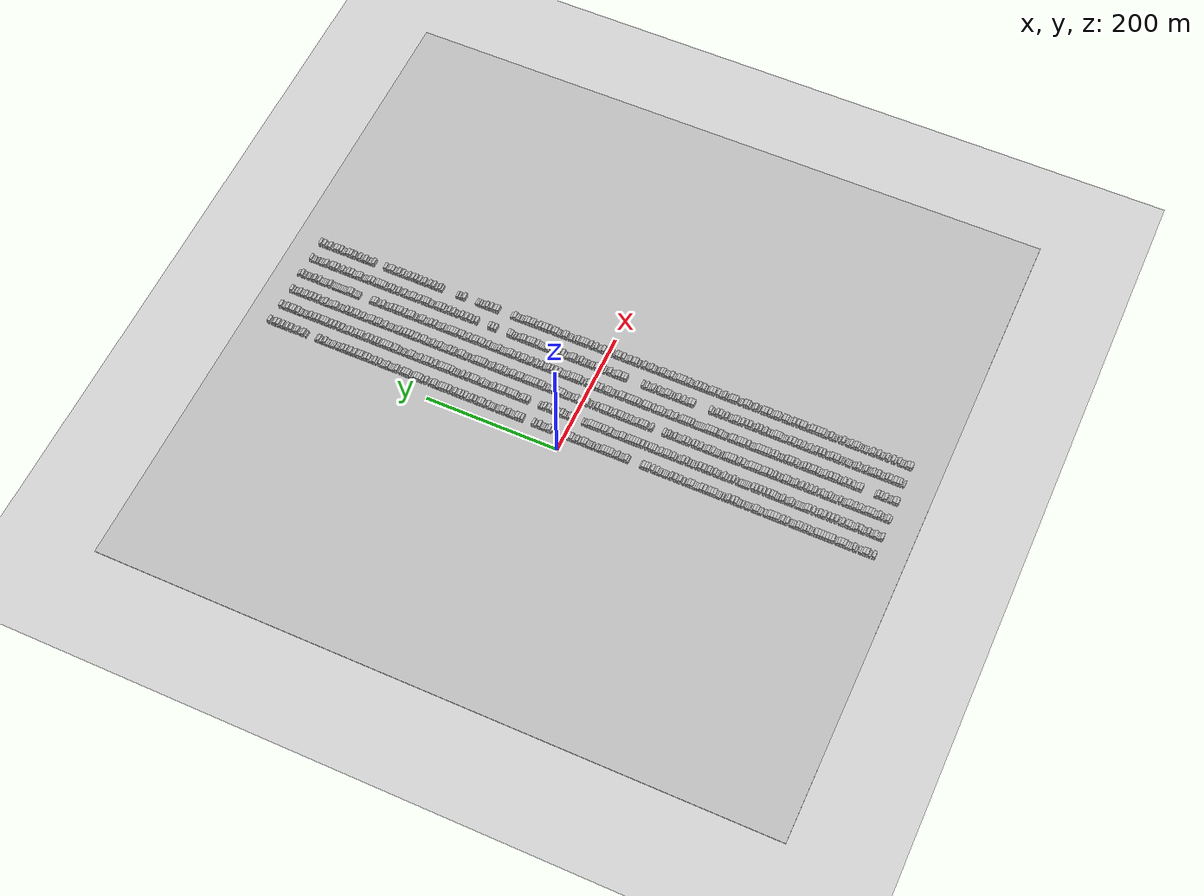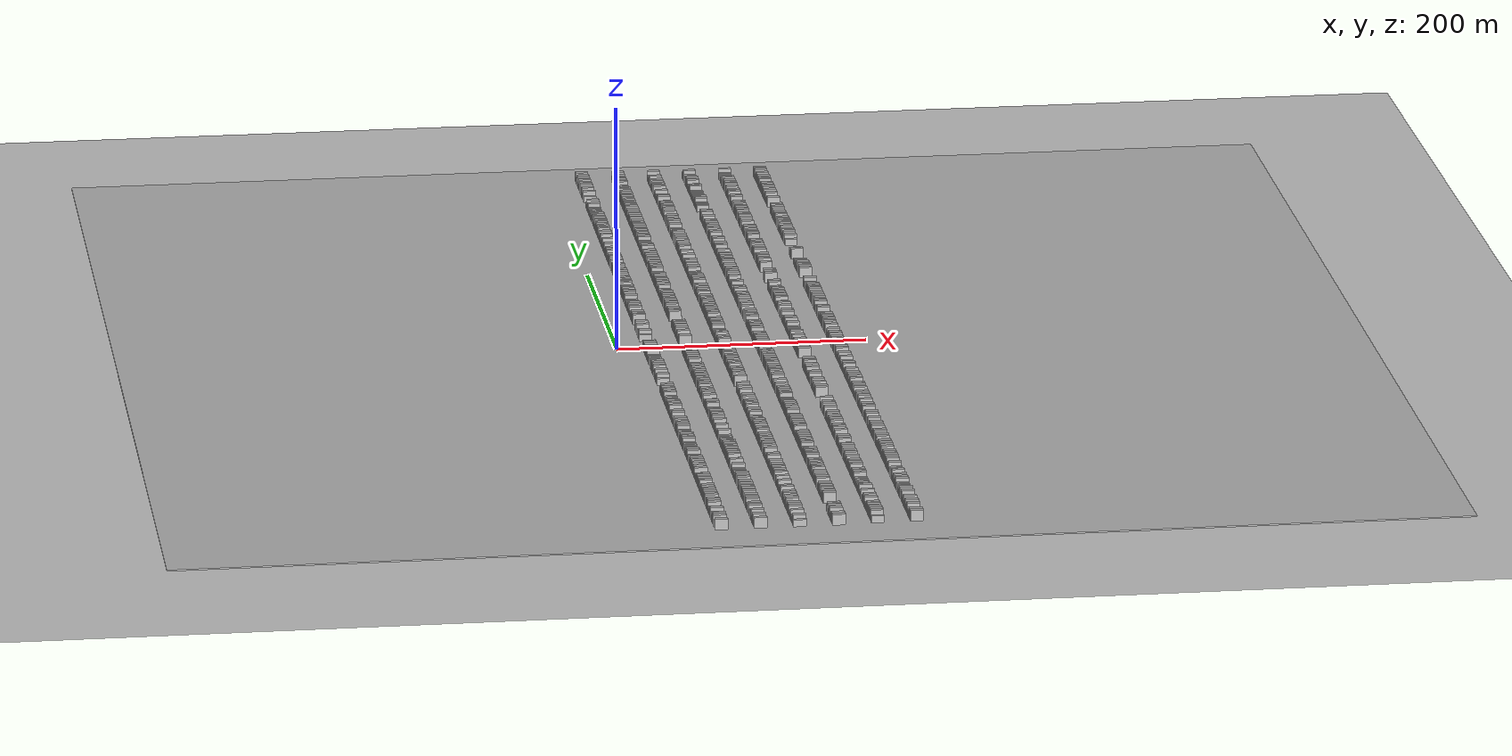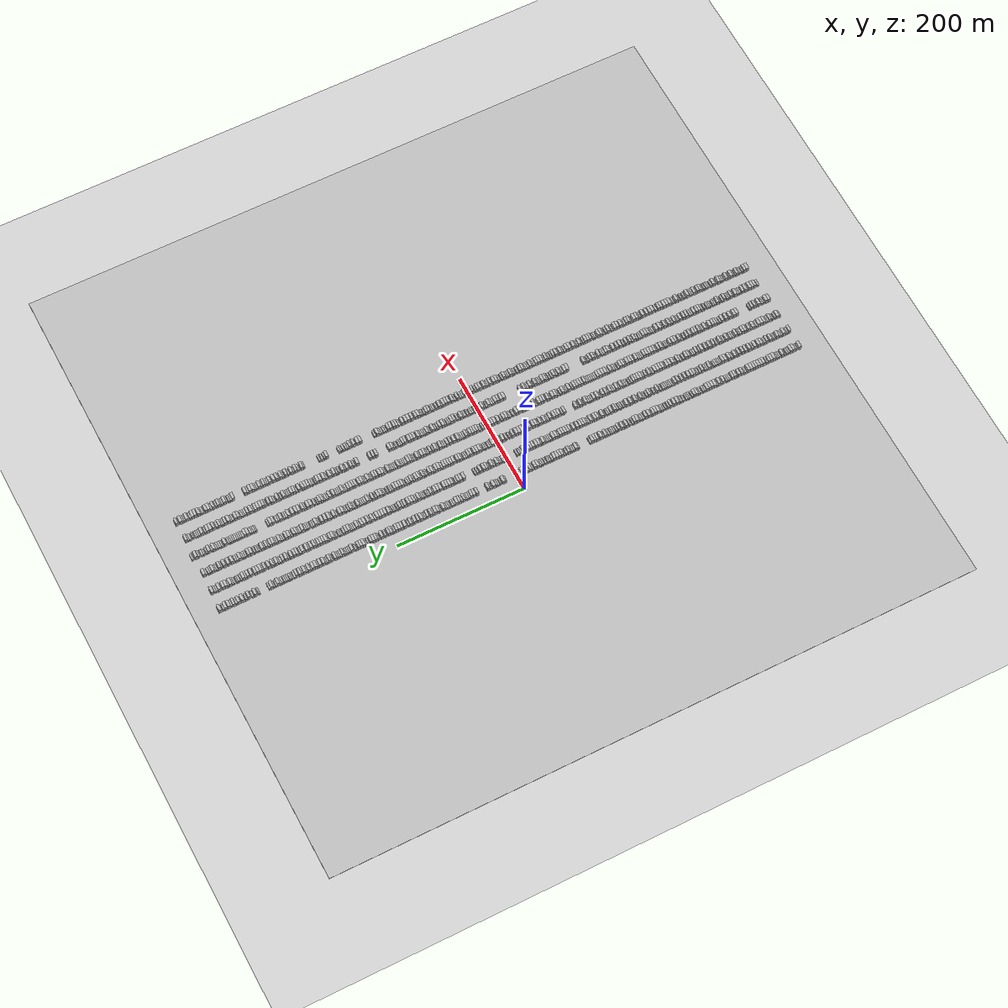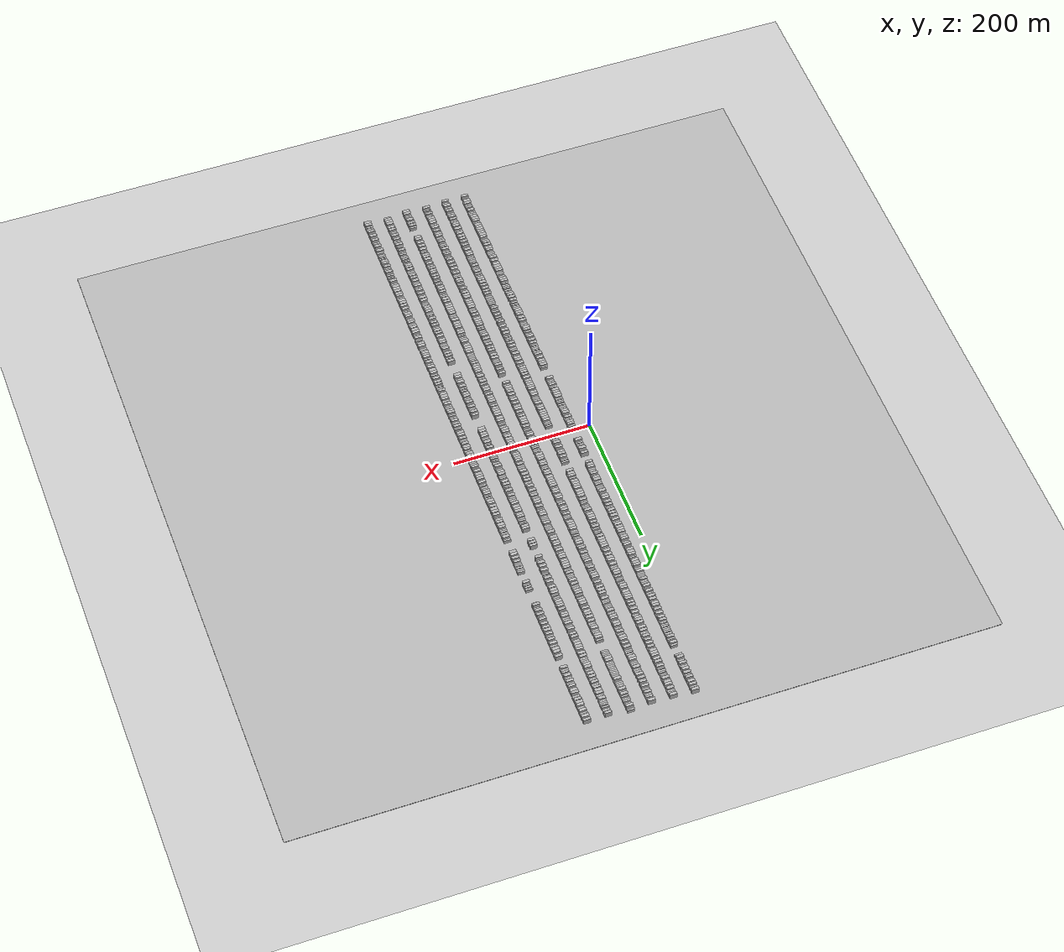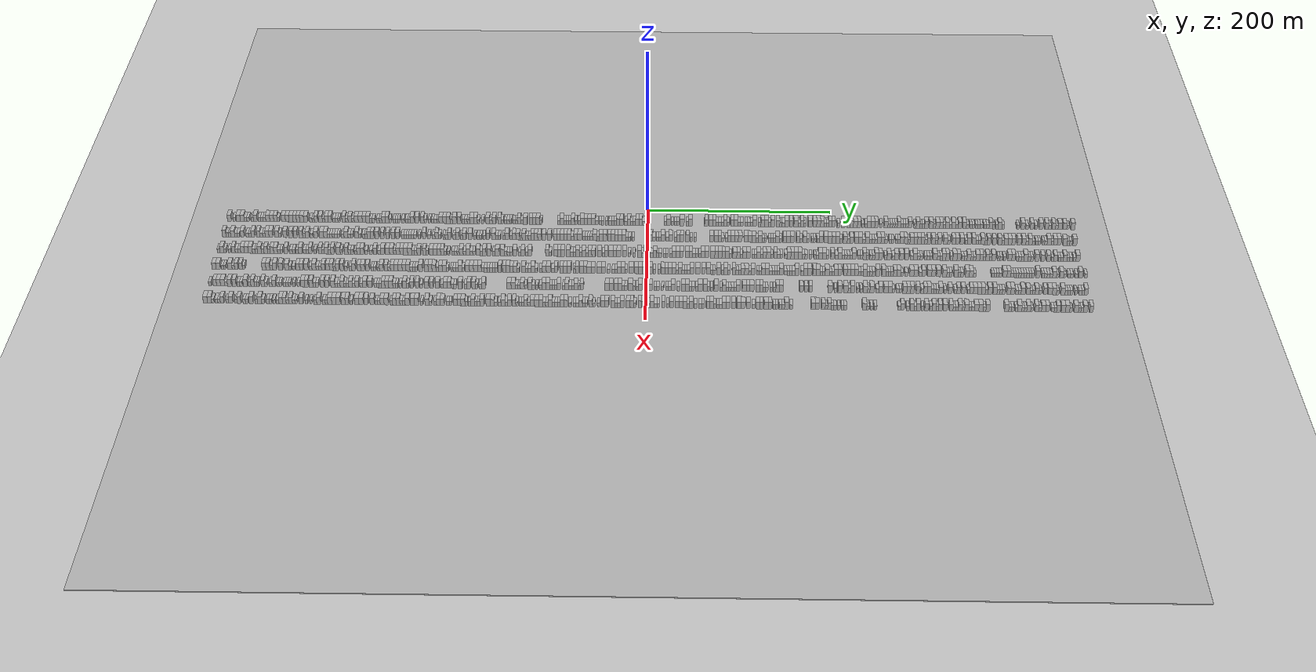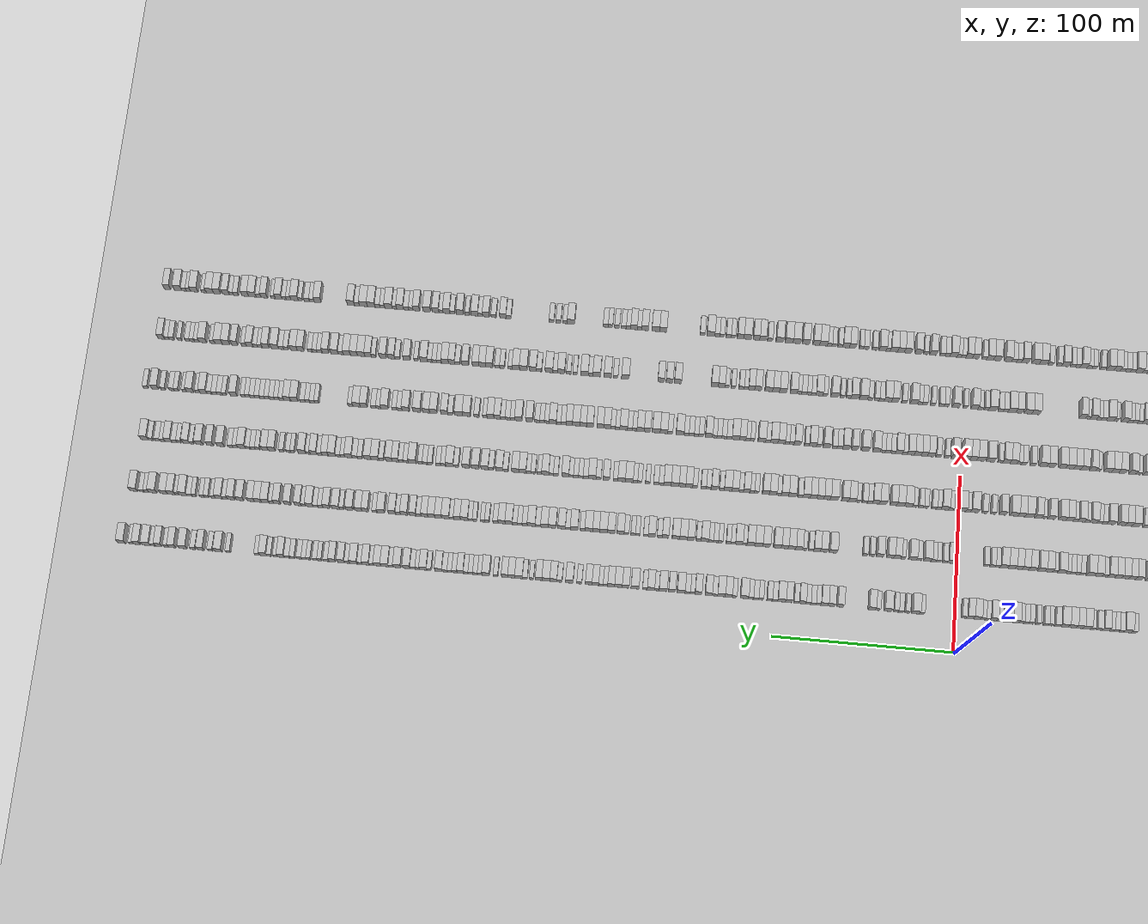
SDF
<?xml version="1.0" encoding="utf-8"?>

<sdf version="1.6">

   <world name="default">

      <gui fullscreen="0">

         <camera name="user_camera">

            <pose>-15 0 4.57585 0 0 0</pose>

            <view_controller>orbit</view_controller>

         </camera>

      </gui>

      <scene>

         <sky>

           <clouds>

             <speed>12</speed>

           </clouds>

         </sky>

         <ambient>0.4 0.4 0.4 1</ambient>

         <background>0.7 0.7 0.7 1</background>

         <shadows>1</shadows>

      </scene>

      <gravity>0 0 -9.8066</gravity>

      <magnetic_field>6e-06 2.3e-05 -4.2e-05</magnetic_field>

      <physics default="0" name="default_physics" type="ode">

         <ode>

            <solver>

               <type>quick</type>

               <iters>10</iters>

               <sor>1.0</sor>

               <use_dynamic_moi_rescaling>0</use_dynamic_moi_rescaling>

            </solver>

            <constraints>

               <cfm>0</cfm>

               <erp>0.2</erp>

               <contact_max_correcting_vel>100</contact_max_correcting_vel>

               <contact_surface_layer>0.001</contact_surface_layer>

            </constraints>

         </ode>

         <max_step_size>0.004</max_step_size>

         <real_time_factor>1</real_time_factor>

         <real_time_update_rate>250</real_time_update_rate>

      </physics>

      <light name="sun" type="directional">

         <cast_shadows>1</cast_shadows>

         <pose>0 0 10 0 0 0</pose>

         <diffuse>0.8 0.8 0.8 1</diffuse>

         <specular>0.2 0.2 0.2 1</specular>

         <attenuation>

            <range>1000</range>

            <constant>0.9</constant>

            <linear>0.01</linear>

            <quadratic>0.001</quadratic>

         </attenuation>

         <direction>-0.5 0.1 -0.9</direction>

      </light>

      <include>

         <name>ground_plane_1</name>

         <uri>model://HANNAS_ground_plane</uri>

         <pose>0 0 0  0 0 0</pose>

      </include>

      <include>

         <name>ground_plane_2</name>

         <uri>model://HANNAS_ground_plane</uri>

         <pose>100 0 0  0 0 0</pose>

      </include>

      <model name="building_1">

         <static>1</static>

         <pose frame="">25.0000 -457.8550 0 0.000000 0.000000 0.000000</pose>

         <link name="link">

            <pose frame="">0 0 4.50 0 0 0</pose>

            <collision name="collision">

               <geometry>

                  <box>

                     <size>10.0000 4.2900 9.0000</size>

                  </box>

               </geometry>

               <max_contacts>10</max_contacts>

               <surface>

                  <contact>

                     <ode/>

                  </contact>

                  <bounce/>

                  <friction>

                     <torsional>

                        <ode/>

                     </torsional>

                     <ode/>

                  </friction>

               </surface>

            </collision>

            <visual name="visual">

               <cast_shadows>0</cast_shadows>

               <geometry>

                  <box>

                     <size>10.0000 4.2900 9.0000</size>

                  </box>

               </geometry>

               <material>

                  <script>

                     <uri>model://HANNAS_wall/materials/scripts</uri>

                     <uri>model://HANNAS_wall/materials/textures</uri>

                     <name>vrc/HANNAS_wall</name>

                  </script>

               </material>

            </visual>

            <self_collide>0</self_collide>

            <enable_wind>0</enable_wind>

            <kinematic>0</kinematic>

         </link>

      </model>

      <model name="building_2">

         <static>1</static>

         <pose frame="">25.0000 -452.4707 0 0.000000 0.000000 0.000000</pose>

         <link name="link">

            <pose frame="">0 0 3.00 0 0 0</pose>

            <collision name="collision">

               <geometry>

                  <box>

                     <size>10.0000 2.4787 6.0000</size>

                  </box>

               </geometry>

               <max_contacts>10</max_contacts>

               <surface>

                  <contact>

                     <ode/>

                  </contact>

                  <bounce/>

                  <friction>

                     <torsional>

                        <ode/>

                     </torsional>

                     <ode/>

                  </friction>

               </surface>

            </collision>

            <visual name="visual">

               <cast_shadows>0</cast_shadows>

               <geometry>

                  <box>

                     <size>10.0000 2.4787 6.0000</size>

                  </box>

               </geometry>

               <material>

                  <script>

                     <uri>model://HANNAS_wall/materials/scripts</uri>

                     <uri>model://HANNAS_wall/materials/textures</uri>

                     <name>vrc/HANNAS_wall</name>

                  </script>

               </material>

            </visual>

            <self_collide>0</self_collide>

            <enable_wind>0</enable_wind>

            <kinematic>0</kinematic>

         </link>

      </model>

      <model name="building_3">

         <static>1</static>

         <pose frame="">25.0000 -448.0587 0 0.000000 0.000000 0.000000</pose>

         <link name="link">

            <pose frame="">0 0 4.50 0 0 0</pose>

            <collision name="collision">

               <geometry>

                  <box>

                     <size>10.0000 4.3453 9.0000</size>

                  </box>

               </geometry>

               <max_contacts>10</max_contacts>

               <surface>

                  <contact>

                     <ode/>

                  </contact>

                  <bounce/>

                  <friction>

                     <torsional>

                        <ode/>

                     </torsional>

                     <ode/>

                  </friction>

               </surface>

            </collision>

            <visual name="visual">

               <cast_shadows>0</cast_shadows>

               <geometry>

                  <box>

                     <size>10.0000 4.3453 9.0000</size>

                  </box>

               </geometry>

               <material>

                  <script>

                     <uri>model://HANNAS_wall/materials/scripts</uri>

                     <uri>model://HANNAS_wall/materials/textures</uri>

                     <name>vrc/HANNAS_wall</name>

                  </script>

               </material>

            </visual>

            <self_collide>0</self_collide>

            <enable_wind>0</enable_wind>

            <kinematic>0</kinematic>

         </link>

      </model>

      <model name="building_4">

         <static>1</static>

         <pose frame="">25.0000 -443.7593 0 0.000000 0.000000 0.000000</pose>

         <link name="link">

            <pose frame="">0 0 4.50 0 0 0</pose>

            <collision name="collision">

               <geometry>

                  <box>

                     <size>10.0000 4.2534 9.0000</size>

                  </box>

               </geometry>

               <max_contacts>10</max_contacts>

               <surface>

                  <contact>

                     <ode/>

                  </contact>

                  <bounce/>

                  <friction>

                     <torsional>

                        <ode/>

                     </torsional>

                     <ode/>

                  </friction>

               </surface>

            </collision>

            <visual name="visual">

               <cast_shadows>0</cast_shadows>

               <geometry>

                  <box>

                     <size>10.0000 4.2534 9.0000</size>

                  </box>

               </geometry>

               <material>

                  <script>

                     <uri>model://HANNAS_wall/materials/scripts</uri>

                     <uri>model://HANNAS_wall/materials/textures</uri>

                     <name>vrc/HANNAS_wall</name>

                  </script>

               </material>

            </visual>

            <self_collide>0</self_collide>

            <enable_wind>0</enable_wind>

            <kinematic>0</kinematic>

         </link>

      </model>

      <model name="building_5">

         <static>1</static>

         <pose frame="">25.0000 -440.2116 0 0.000000 0.000000 0.000000</pose>

         <link name="link">

            <pose frame="">0 0 3.00 0 0 0</pose>

            <collision name="collision">

               <geometry>

                  <box>

                     <size>10.0000 2.8421 6.0000</size>

                  </box>

               </geometry>

               <max_contacts>10</max_contacts>

               <surface>

                  <contact>

                     <ode/>

                  </contact>

                  <bounce/>

                  <friction>

                     <torsional>

                        <ode/>

                     </torsional>

                     <ode/>

                  </friction>

               </surface>

            </collision>

            <visual name="visual">

               <cast_shadows>0</cast_shadows>

               <geometry>

                  <box>

                     <size>10.0000 2.8421 6.0000</size>

                  </box>

               </geometry>

               <material>

                  <script>

                     <uri>model://HANNAS_wall/materials/scripts</uri>

                     <uri>model://HANNAS_wall/materials/textures</uri>

                     <name>vrc/HANNAS_wall</name>

                  </script>

               </material>

            </visual>

            <self_collide>0</self_collide>

            <enable_wind>0</enable_wind>

            <kinematic>0</kinematic>

         </link>

      </model>

      <model name="building_6">

         <static>1</static>

         <pose frame="">25.0000 -437.3283 0 0.000000 0.000000 0.000000</pose>

         <link name="link">

            <pose frame="">0 0 3.00 0 0 0</pose>

            <collision name="collision">

               <geometry>

                  <box>

                     <size>10.0000 2.9245 6.0000</size>

                  </box>

               </geometry>

               <max_contacts>10</max_contacts>

               <surface>

                  <contact>

                     <ode/>

                  </contact>

                  <bounce/>

                  <friction>

                     <torsional>

                        <ode/>

                     </torsional>

                     <ode/>

                  </friction>

               </surface>

            </collision>

            <visual name="visual">

               <cast_shadows>0</cast_shadows>

               <geometry>

                  <box>

                     <size>10.0000 2.9245 6.0000</size>

                  </box>

               </geometry>

               <material>

                  <script>

                     <uri>model://HANNAS_wall/materials/scripts</uri>

                     <uri>model://HANNAS_wall/materials/textures</uri>

                     <name>vrc/HANNAS_wall</name>

                  </script>

               </material>

            </visual>

            <self_collide>0</self_collide>

            <enable_wind>0</enable_wind>

            <kinematic>0</kinematic>

         </link>

      </model>

      <model name="building_7">

         <static>1</static>

         <pose frame="">25.0000 -432.6552 0 0.000000 0.000000 0.000000</pose>

         <link name="link">

            <pose frame="">0 0 3.00 0 0 0</pose>

            <collision name="collision">

               <geometry>

                  <box>

                     <size>10.0000 2.4216 6.0000</size>

                  </box>

               </geometry>

               <max_contacts>10</max_contacts>

               <surface>

                  <contact>

                     <ode/>

                  </contact>

                  <bounce/>

                  <friction>

                     <torsional>

                        <ode/>

                     </torsional>

                     <ode/>

                  </friction>

               </surface>

            </collision>

            <visual name="visual">

               <cast_shadows>0</cast_shadows>

               <geometry>

                  <box>

                     <size>10.0000 2.4216 6.0000</size>

                  </box>

               </geometry>

               <material>

                  <script>

                     <uri>model://HANNAS_wall/materials/scripts</uri>

                     <uri>model://HANNAS_wall/materials/textures</uri>

                     <name>vrc/HANNAS_wall</name>

                  </script>

               </material>

            </visual>

            <self_collide>0</self_collide>

            <enable_wind>0</enable_wind>

            <kinematic>0</kinematic>

         </link>

      </model>

      <model name="building_8">

         <static>1</static>

         <pose frame="">25.0000 -429.4056 0 0.000000 0.000000 0.000000</pose>

         <link name="link">

            <pose frame="">0 0 4.50 0 0 0</pose>

            <collision name="collision">

               <geometry>

                  <box>

                     <size>10.0000 4.0777 9.0000</size>

                  </box>

               </geometry>

               <max_contacts>10</max_contacts>

               <surface>

                  <contact>

                     <ode/>

                  </contact>

                  <bounce/>

                  <friction>

                     <torsional>

                        <ode/>

                     </torsional>

                     <ode/>

                  </friction>

               </surface>

            </collision>

            <visual name="visual">

               <cast_shadows>0</cast_shadows>

               <geometry>

                  <box>

                     <size>10.0000 4.0777 9.0000</size>

                  </box>

               </geometry>

               <material>

                  <script>

                     <uri>model://HANNAS_wall/materials/scripts</uri>

                     <uri>model://HANNAS_wall/materials/textures</uri>

                     <name>vrc/HANNAS_wall</name>

                  </script>

               </material>

            </visual>

            <self_collide>0</self_collide>

            <enable_wind>0</enable_wind>

            <kinematic>0</kinematic>

         </link>

      </model>

      <model name="building_9">

         <static>1</static>

         <pose frame="">25.0000 -424.9362 0 0.000000 0.000000 0.000000</pose>

         <link name="link">

            <pose frame="">0 0 3.00 0 0 0</pose>

            <collision name="collision">

               <geometry>

                  <box>

                     <size>10.0000 2.8610 6.0000</size>

                  </box>

               </geometry>

               <max_contacts>10</max_contacts>

               <surface>

                  <contact>

                     <ode/>

                  </contact>

                  <bounce/>

                  <friction>

                     <torsional>

                        <ode/>

                     </torsional>

                     <ode/>

                  </friction>

               </surface>

            </collision>

            <visual name="visual">

               <cast_shadows>0</cast_shadows>

               <geometry>

                  <box>

                     <size>10.0000 2.8610 6.0000</size>

                  </box>

               </geometry>

               <material>

                  <script>

                     <uri>model://HANNAS_wall/materials/scripts</uri>

                     <uri>model://HANNAS_wall/materials/textures</uri>

                     <name>vrc/HANNAS_wall</name>

                  </script>

               </material>

            </visual>

            <self_collide>0</self_collide>

            <enable_wind>0</enable_wind>

            <kinematic>0</kinematic>

         </link>

      </model>

      <model name="building_10">

         <static>1</static>

         <pose frame="">25.0000 -422.1943 0 0.000000 0.000000 0.000000</pose>

         <link name="link">

            <pose frame="">0 0 3.00 0 0 0</pose>

            <collision name="collision">

               <geometry>

                  <box>

                     <size>10.0000 2.6229 6.0000</size>

                  </box>

               </geometry>

               <max_contacts>10</max_contacts>

               <surface>

                  <contact>

                     <ode/>

                  </contact>

                  <bounce/>

                  <friction>

                     <torsional>

                        <ode/>

                     </torsional>

                     <ode/>

                  </friction>

               </surface>

            </collision>

            <visual name="visual">

               <cast_shadows>0</cast_shadows>

               <geometry>

                  <box>

                     <size>10.0000 2.6229 6.0000</size>

                  </box>

               </geometry>

               <material>

                  <script>

                     <uri>model://HANNAS_wall/materials/scripts</uri>

                     <uri>model://HANNAS_wall/materials/textures</uri>

                     <name>vrc/HANNAS_wall</name>

                  </script>

               </material>

            </visual>

            <self_collide>0</self_collide>

            <enable_wind>0</enable_wind>

            <kinematic>0</kinematic>

         </link>

      </model>

      <model name="building_11">

         <static>1</static>

         <pose frame="">25.0000 -419.4093 0 0.000000 0.000000 0.000000</pose>

         <link name="link">

            <pose frame="">0 0 3.00 0 0 0</pose>

            <collision name="collision">

               <geometry>

                  <box>

                     <size>10.0000 2.9471 6.0000</size>

                  </box>

               </geometry>

               <max_contacts>10</max_contacts>

               <surface>

                  <contact>

                     <ode/>

                  </contact>

                  <bounce/>

                  <friction>

                     <torsional>

                        <ode/>

                     </torsional>

                     <ode/>

                  </friction>

               </surface>

            </collision>

            <visual name="visual">

               <cast_shadows>0</cast_shadows>

               <geometry>

                  <box>

                     <size>10.0000 2.9471 6.0000</size>

                  </box>

               </geometry>

               <material>

                  <script>

                     <uri>model://HANNAS_wall/materials/scripts</uri>

                     <uri>model://HANNAS_wall/materials/textures</uri>

                     <name>vrc/HANNAS_wall</name>

                  </script>

               </material>

            </visual>

            <self_collide>0</self_collide>

            <enable_wind>0</enable_wind>

            <kinematic>0</kinematic>

         </link>

      </model>

      <model name="building_12">

         <static>1</static>

         <pose frame="">25.0000 -415.7483 0 0.000000 0.000000 0.000000</pose>

         <link name="link">

            <pose frame="">0 0 4.50 0 0 0</pose>

            <collision name="collision">

               <geometry>

                  <box>

                     <size>10.0000 4.3748 9.0000</size>

                  </box>

               </geometry>

               <max_contacts>10</max_contacts>

               <surface>

                  <contact>

                     <ode/>

                  </contact>

                  <bounce/>

                  <friction>

                     <torsional>

                        <ode/>

                     </torsional>

                     <ode/>

                  </friction>

               </surface>

            </collision>

            <visual name="visual">

               <cast_shadows>0</cast_shadows>

               <geometry>

                  <box>

                     <size>10.0000 4.3748 9.0000</size>

                  </box>

               </geometry>

               <material>

                  <script>

                     <uri>model://HANNAS_wall/materials/scripts</uri>

                     <uri>model://HANNAS_wall/materials/textures</uri>

                     <name>vrc/HANNAS_wall</name>

                  </script>

               </material>

            </visual>

            <self_collide>0</self_collide>

            <enable_wind>0</enable_wind>

            <kinematic>0</kinematic>

         </link>

      </model>

      <model name="building_13">

         <static>1</static>

         <pose frame="">25.0000 -411.3932 0 0.000000 0.000000 0.000000</pose>

         <link name="link">

            <pose frame="">0 0 4.50 0 0 0</pose>

            <collision name="collision">

               <geometry>

                  <box>

                     <size>10.0000 4.3353 9.0000</size>

                  </box>

               </geometry>

               <max_contacts>10</max_contacts>

               <surface>

                  <contact>

                     <ode/>

                  </contact>

                  <bounce/>

                  <friction>

                     <torsional>

                        <ode/>

                     </torsional>

                     <ode/>

                  </friction>

               </surface>

            </collision>

            <visual name="visual">

               <cast_shadows>0</cast_shadows>

               <geometry>

                  <box>

                     <size>10.0000 4.3353 9.0000</size>

                  </box>

               </geometry>

               <material>

                  <script>

                     <uri>model://HANNAS_wall/materials/scripts</uri>

                     <uri>model://HANNAS_wall/materials/textures</uri>

                     <name>vrc/HANNAS_wall</name>

                  </script>

               </material>

            </visual>

            <self_collide>0</self_collide>

            <enable_wind>0</enable_wind>

            <kinematic>0</kinematic>

         </link>

      </model>

      <model name="building_14">

         <static>1</static>

         <pose frame="">25.0000 -407.3609 0 0.000000 0.000000 0.000000</pose>

         <link name="link">

            <pose frame="">0 0 4.50 0 0 0</pose>

            <collision name="collision">

               <geometry>

                  <box>

                     <size>10.0000 3.7292 9.0000</size>

                  </box>

               </geometry>

               <max_contacts>10</max_contacts>

               <surface>

                  <contact>

                     <ode/>

                  </contact>

                  <bounce/>

                  <friction>

                     <torsional>

                        <ode/>

                     </torsional>

                     <ode/>

                  </friction>

               </surface>

            </collision>

            <visual name="visual">

               <cast_shadows>0</cast_shadows>

               <geometry>

                  <box>

                     <size>10.0000 3.7292 9.0000</size>

                  </box>

               </geometry>

               <material>

                  <script>

                     <uri>model://HANNAS_wall/materials/scripts</uri>

                     <uri>model://HANNAS_wall/materials/textures</uri>

                     <name>vrc/HANNAS_wall</name>

                  </script>

               </material>

            </visual>

            <self_collide>0</self_collide>

            <enable_wind>0</enable_wind>

            <kinematic>0</kinematic>

         </link>

      </model>

      <model name="building_15">

         <static>1</static>

         <pose frame="">25.0000 -404.1684 0 0.000000 0.000000 0.000000</pose>

         <link name="link">

            <pose frame="">0 0 3.00 0 0 0</pose>

            <collision name="collision">

               <geometry>

                  <box>

                     <size>10.0000 2.6560 6.0000</size>

                  </box>

               </geometry>

               <max_contacts>10</max_contacts>

               <surface>

                  <contact>

                     <ode/>

                  </contact>

                  <bounce/>

                  <friction>

                     <torsional>

                        <ode/>

                     </torsional>

                     <ode/>

                  </friction>

               </surface>

            </collision>

            <visual name="visual">

               <cast_shadows>0</cast_shadows>

               <geometry>

                  <box>

                     <size>10.0000 2.6560 6.0000</size>

                  </box>

               </geometry>

               <material>

                  <script>

                     <uri>model://HANNAS_wall/materials/scripts</uri>

                     <uri>model://HANNAS_wall/materials/textures</uri>

                     <name>vrc/HANNAS_wall</name>

                  </script>

               </material>

            </visual>

            <self_collide>0</self_collide>

            <enable_wind>0</enable_wind>

            <kinematic>0</kinematic>

         </link>

      </model>

      <model name="building_16">

         <static>1</static>

         <pose frame="">25.0000 -398.6194 0 0.000000 0.000000 0.000000</pose>

         <link name="link">

            <pose frame="">0 0 4.50 0 0 0</pose>

            <collision name="collision">

               <geometry>

                  <box>

                     <size>10.0000 4.4418 9.0000</size>

                  </box>

               </geometry>

               <max_contacts>10</max_contacts>

               <surface>

                  <contact>

                     <ode/>

                  </contact>

                  <bounce/>

                  <friction>

                     <torsional>

                        <ode/>

                     </torsional>

                     <ode/>

                  </friction>

               </surface>

            </collision>

            <visual name="visual">

               <cast_shadows>0</cast_shadows>

               <geometry>

                  <box>

                     <size>10.0000 4.4418 9.0000</size>

                  </box>

               </geometry>

               <material>

                  <script>

                     <uri>model://HANNAS_wall/materials/scripts</uri>

                     <uri>model://HANNAS_wall/materials/textures</uri>

                     <name>vrc/HANNAS_wall</name>

                  </script>

               </material>

            </visual>

            <self_collide>0</self_collide>

            <enable_wind>0</enable_wind>

            <kinematic>0</kinematic>

         </link>

      </model>

      <model name="building_17">

         <static>1</static>

         <pose frame="">25.0000 -394.4793 0 0.000000 0.000000 0.000000</pose>

         <link name="link">

            <pose frame="">0 0 4.50 0 0 0</pose>

            <collision name="collision">

               <geometry>

                  <box>

                     <size>10.0000 3.8385 9.0000</size>

                  </box>

               </geometry>

               <max_contacts>10</max_contacts>

               <surface>

                  <contact>

                     <ode/>

                  </contact>

                  <bounce/>

                  <friction>

                     <torsional>

                        <ode/>

                     </torsional>

                     <ode/>

                  </friction>

               </surface>

            </collision>

            <visual name="visual">

               <cast_shadows>0</cast_shadows>

               <geometry>

                  <box>

                     <size>10.0000 3.8385 9.0000</size>

                  </box>

               </geometry>

               <material>

                  <script>

                     <uri>model://HANNAS_wall/materials/scripts</uri>

                     <uri>model://HANNAS_wall/materials/textures</uri>

                     <name>vrc/HANNAS_wall</name>

                  </script>

               </material>

            </visual>

            <self_collide>0</self_collide>

            <enable_wind>0</enable_wind>

            <kinematic>0</kinematic>

         </link>

      </model>

      <model name="building_18">

         <static>1</static>

         <pose frame="">25.0000 -390.3731 0 0.000000 0.000000 0.000000</pose>

         <link name="link">

            <pose frame="">0 0 4.50 0 0 0</pose>

            <collision name="collision">

               <geometry>

                  <box>

                     <size>10.0000 4.3740 9.0000</size>

                  </box>

               </geometry>

               <max_contacts>10</max_contacts>

               <surface>

                  <contact>

                     <ode/>

                  </contact>

                  <bounce/>

                  <friction>

                     <torsional>

                        <ode/>

                     </torsional>

                     <ode/>

                  </friction>

               </surface>

            </collision>

            <visual name="visual">

               <cast_shadows>0</cast_shadows>

               <geometry>

                  <box>

                     <size>10.0000 4.3740 9.0000</size>

                  </box>

               </geometry>

               <material>

                  <script>

                     <uri>model://HANNAS_wall/materials/scripts</uri>

                     <uri>model://HANNAS_wall/materials/textures</uri>

                     <name>vrc/HANNAS_wall</name>

                  </script>

               </material>

            </visual>

            <self_collide>0</self_collide>

            <enable_wind>0</enable_wind>

            <kinematic>0</kinematic>

         </link>

      </model>

      <model name="building_19">

         <static>1</static>

         <pose frame="">25.0000 -386.2894 0 0.000000 0.000000 0.000000</pose>

         <link name="link">

            <pose frame="">0 0 4.50 0 0 0</pose>

            <collision name="collision">

               <geometry>

                  <box>

                     <size>10.0000 3.7934 9.0000</size>

                  </box>

               </geometry>

               <max_contacts>10</max_contacts>

               <surface>

                  <contact>

                     <ode/>

                  </contact>

                  <bounce/>

                  <friction>

                     <torsional>

                        <ode/>

                     </torsional>

                     <ode/>

                  </friction>

               </surface>

            </collision>

            <visual name="visual">

               <cast_shadows>0</cast_shadows>

               <geometry>

                  <box>

                     <size>10.0000 3.7934 9.0000</size>

                  </box>

               </geometry>

               <material>

                  <script>

                     <uri>model://HANNAS_wall/materials/scripts</uri>

                     <uri>model://HANNAS_wall/materials/textures</uri>

                     <name>vrc/HANNAS_wall</name>

                  </script>

               </material>

            </visual>

            <self_collide>0</self_collide>

            <enable_wind>0</enable_wind>

            <kinematic>0</kinematic>

         </link>

      </model>

      <model name="building_20">

         <static>1</static>

         <pose frame="">25.0000 -382.5751 0 0.000000 0.000000 0.000000</pose>

         <link name="link">

            <pose frame="">0 0 4.50 0 0 0</pose>

            <collision name="collision">

               <geometry>

                  <box>

                     <size>10.0000 3.6353 9.0000</size>

                  </box>

               </geometry>

               <max_contacts>10</max_contacts>

               <surface>

                  <contact>

                     <ode/>

                  </contact>

                  <bounce/>

                  <friction>

                     <torsional>

                        <ode/>

                     </torsional>

                     <ode/>

                  </friction>

               </surface>

            </collision>

            <visual name="visual">

               <cast_shadows>0</cast_shadows>

               <geometry>

                  <box>

                     <size>10.0000 3.6353 9.0000</size>

                  </box>

               </geometry>

               <material>

                  <script>

                     <uri>model://HANNAS_wall/materials/scripts</uri>

                     <uri>model://HANNAS_wall/materials/textures</uri>

                     <name>vrc/HANNAS_wall</name>

                  </script>

               </material>

            </visual>

            <self_collide>0</self_collide>

            <enable_wind>0</enable_wind>

            <kinematic>0</kinematic>

         </link>

      </model>

      <model name="building_21">

         <static>1</static>

         <pose frame="">25.0000 -378.5328 0 0.000000 0.000000 0.000000</pose>

         <link name="link">

            <pose frame="">0 0 4.50 0 0 0</pose>

            <collision name="collision">

               <geometry>

                  <box>

                     <size>10.0000 4.4492 9.0000</size>

                  </box>

               </geometry>

               <max_contacts>10</max_contacts>

               <surface>

                  <contact>

                     <ode/>

                  </contact>

                  <bounce/>

                  <friction>

                     <torsional>

                        <ode/>

                     </torsional>

                     <ode/>

                  </friction>

               </surface>

            </collision>

            <visual name="visual">

               <cast_shadows>0</cast_shadows>

               <geometry>

                  <box>

                     <size>10.0000 4.4492 9.0000</size>

                  </box>

               </geometry>

               <material>

                  <script>

                     <uri>model://HANNAS_wall/materials/scripts</uri>

                     <uri>model://HANNAS_wall/materials/textures</uri>

                     <name>vrc/HANNAS_wall</name>

                  </script>

               </material>

            </visual>

            <self_collide>0</self_collide>

            <enable_wind>0</enable_wind>

            <kinematic>0</kinematic>

         </link>

      </model>

      <model name="building_22">

         <static>1</static>

         <pose frame="">25.0000 -374.1737 0 0.000000 0.000000 0.000000</pose>

         <link name="link">

            <pose frame="">0 0 4.50 0 0 0</pose>

            <collision name="collision">

               <geometry>

                  <box>

                     <size>10.0000 4.2690 9.0000</size>

                  </box>

               </geometry>

               <max_contacts>10</max_contacts>

               <surface>

                  <contact>

                     <ode/>

                  </contact>

                  <bounce/>

                  <friction>

                     <torsional>

                        <ode/>

                     </torsional>

                     <ode/>

                  </friction>

               </surface>

            </collision>

            <visual name="visual">

               <cast_shadows>0</cast_shadows>

               <geometry>

                  <box>

                     <size>10.0000 4.2690 9.0000</size>

                  </box>

               </geometry>

               <material>

                  <script>

                     <uri>model://HANNAS_wall/materials/scripts</uri>

                     <uri>model://HANNAS_wall/materials/textures</uri>

                     <name>vrc/HANNAS_wall</name>

                  </script>

               </material>

            </visual>

            <self_collide>0</self_collide>

            <enable_wind>0</enable_wind>

            <kinematic>0</kinematic>

         </link>

      </model>

      <model name="building_23">

         <static>1</static>

         <pose frame="">25.0000 -368.6363 0 0.000000 0.000000 0.000000</pose>

         <link name="link">

            <pose frame="">0 0 3.00 0 0 0</pose>

            <collision name="collision">

               <geometry>

                  <box>

                     <size>10.0000 2.8058 6.0000</size>

                  </box>

               </geometry>

               <max_contacts>10</max_contacts>

               <surface>

                  <contact>

                     <ode/>

                  </contact>

                  <bounce/>

                  <friction>

                     <torsional>

                        <ode/>

                     </torsional>

                     <ode/>

                  </friction>

               </surface>

            </collision>

            <visual name="visual">

               <cast_shadows>0</cast_shadows>

               <geometry>

                  <box>

                     <size>10.0000 2.8058 6.0000</size>

                  </box>

               </geometry>

               <material>

                  <script>

                     <uri>model://HANNAS_wall/materials/scripts</uri>

                     <uri>model://HANNAS_wall/materials/textures</uri>

                     <name>vrc/HANNAS_wall</name>

                  </script>

               </material>

            </visual>

            <self_collide>0</self_collide>

            <enable_wind>0</enable_wind>

            <kinematic>0</kinematic>

         </link>

      </model>

      <model name="building_24">

         <static>1</static>

         <pose frame="">25.0000 -365.9874 0 0.000000 0.000000 0.000000</pose>

         <link name="link">

            <pose frame="">0 0 3.00 0 0 0</pose>

            <collision name="collision">

               <geometry>

                  <box>

                     <size>10.0000 2.4920 6.0000</size>

                  </box>

               </geometry>

               <max_contacts>10</max_contacts>

               <surface>

                  <contact>

                     <ode/>

                  </contact>

                  <bounce/>

                  <friction>

                     <torsional>

                        <ode/>

                     </torsional>

                     <ode/>

                  </friction>

               </surface>

            </collision>

            <visual name="visual">

               <cast_shadows>0</cast_shadows>

               <geometry>

                  <box>

                     <size>10.0000 2.4920 6.0000</size>

                  </box>

               </geometry>

               <material>

                  <script>

                     <uri>model://HANNAS_wall/materials/scripts</uri>

                     <uri>model://HANNAS_wall/materials/textures</uri>

                     <name>vrc/HANNAS_wall</name>

                  </script>

               </material>

            </visual>

            <self_collide>0</self_collide>

            <enable_wind>0</enable_wind>

            <kinematic>0</kinematic>

         </link>

      </model>

      <model name="building_25">

         <static>1</static>

         <pose frame="">25.0000 -362.9163 0 0.000000 0.000000 0.000000</pose>

         <link name="link">

            <pose frame="">0 0 4.50 0 0 0</pose>

            <collision name="collision">

               <geometry>

                  <box>

                     <size>10.0000 3.6502 9.0000</size>

                  </box>

               </geometry>

               <max_contacts>10</max_contacts>

               <surface>

                  <contact>

                     <ode/>

                  </contact>

                  <bounce/>

                  <friction>

                     <torsional>

                        <ode/>

                     </torsional>

                     <ode/>

                  </friction>

               </surface>

            </collision>

            <visual name="visual">

               <cast_shadows>0</cast_shadows>

               <geometry>

                  <box>

                     <size>10.0000 3.6502 9.0000</size>

                  </box>

               </geometry>

               <material>

                  <script>

                     <uri>model://HANNAS_wall/materials/scripts</uri>

                     <uri>model://HANNAS_wall/materials/textures</uri>

                     <name>vrc/HANNAS_wall</name>

                  </script>

               </material>

            </visual>

            <self_collide>0</self_collide>

            <enable_wind>0</enable_wind>

            <kinematic>0</kinematic>

         </link>

      </model>

      <model name="building_26">

         <static>1</static>

         <pose frame="">25.0000 -358.0158 0 0.000000 0.000000 0.000000</pose>

         <link name="link">

            <pose frame="">0 0 4.50 0 0 0</pose>

            <collision name="collision">

               <geometry>

                  <box>

                     <size>10.0000 4.1508 9.0000</size>

                  </box>

               </geometry>

               <max_contacts>10</max_contacts>

               <surface>

                  <contact>

                     <ode/>

                  </contact>

                  <bounce/>

                  <friction>

                     <torsional>

                        <ode/>

                     </torsional>

                     <ode/>

                  </friction>

               </surface>

            </collision>

            <visual name="visual">

               <cast_shadows>0</cast_shadows>

               <geometry>

                  <box>

                     <size>10.0000 4.1508 9.0000</size>

                  </box>

               </geometry>

               <material>

                  <script>

                     <uri>model://HANNAS_wall/materials/scripts</uri>

                     <uri>model://HANNAS_wall/materials/textures</uri>

                     <name>vrc/HANNAS_wall</name>

                  </script>

               </material>

            </visual>

            <self_collide>0</self_collide>

            <enable_wind>0</enable_wind>

            <kinematic>0</kinematic>

         </link>

      </model>

      <model name="building_27">

         <static>1</static>

         <pose frame="">25.0000 -354.6741 0 0.000000 0.000000 0.000000</pose>

         <link name="link">

            <pose frame="">0 0 3.00 0 0 0</pose>

            <collision name="collision">

               <geometry>

                  <box>

                     <size>10.0000 2.5326 6.0000</size>

                  </box>

               </geometry>

               <max_contacts>10</max_contacts>

               <surface>

                  <contact>

                     <ode/>

                  </contact>

                  <bounce/>

                  <friction>

                     <torsional>

                        <ode/>

                     </torsional>

                     <ode/>

                  </friction>

               </surface>

            </collision>

            <visual name="visual">

               <cast_shadows>0</cast_shadows>

               <geometry>

                  <box>

                     <size>10.0000 2.5326 6.0000</size>

                  </box>

               </geometry>

               <material>

                  <script>

                     <uri>model://HANNAS_wall/materials/scripts</uri>

                     <uri>model://HANNAS_wall/materials/textures</uri>

                     <name>vrc/HANNAS_wall</name>

                  </script>

               </material>

            </visual>

            <self_collide>0</self_collide>

            <enable_wind>0</enable_wind>

            <kinematic>0</kinematic>

         </link>

      </model>

      <model name="building_28">

         <static>1</static>

         <pose frame="">25.0000 -351.4615 0 0.000000 0.000000 0.000000</pose>

         <link name="link">

            <pose frame="">0 0 4.50 0 0 0</pose>

            <collision name="collision">

               <geometry>

                  <box>

                     <size>10.0000 3.8926 9.0000</size>

                  </box>

               </geometry>

               <max_contacts>10</max_contacts>

               <surface>

                  <contact>

                     <ode/>

                  </contact>

                  <bounce/>

                  <friction>

                     <torsional>

                        <ode/>

                     </torsional>

                     <ode/>

                  </friction>

               </surface>

            </collision>

            <visual name="visual">

               <cast_shadows>0</cast_shadows>

               <geometry>

                  <box>

                     <size>10.0000 3.8926 9.0000</size>

                  </box>

               </geometry>

               <material>

                  <script>

                     <uri>model://HANNAS_wall/materials/scripts</uri>

                     <uri>model://HANNAS_wall/materials/textures</uri>

                     <name>vrc/HANNAS_wall</name>

                  </script>

               </material>

            </visual>

            <self_collide>0</self_collide>

            <enable_wind>0</enable_wind>

            <kinematic>0</kinematic>

         </link>

      </model>

      <model name="building_29">

         <static>1</static>

         <pose frame="">25.0000 -347.6250 0 0.000000 0.000000 0.000000</pose>

         <link name="link">

            <pose frame="">0 0 4.50 0 0 0</pose>

            <collision name="collision">

               <geometry>

                  <box>

                     <size>10.0000 3.7804 9.0000</size>

                  </box>

               </geometry>

               <max_contacts>10</max_contacts>

               <surface>

                  <contact>

                     <ode/>

                  </contact>

                  <bounce/>

                  <friction>

                     <torsional>

                        <ode/>

                     </torsional>

                     <ode/>

                  </friction>

               </surface>

            </collision>

            <visual name="visual">

               <cast_shadows>0</cast_shadows>

               <geometry>

                  <box>

                     <size>10.0000 3.7804 9.0000</size>

                  </box>

               </geometry>

               <material>

                  <script>

                     <uri>model://HANNAS_wall/materials/scripts</uri>

                     <uri>model://HANNAS_wall/materials/textures</uri>

                     <name>vrc/HANNAS_wall</name>

                  </script>

               </material>

            </visual>

            <self_collide>0</self_collide>

            <enable_wind>0</enable_wind>

            <kinematic>0</kinematic>

         </link>

      </model>

      <model name="building_30">

         <static>1</static>

         <pose frame="">25.0000 -343.2456 0 0.000000 0.000000 0.000000</pose>

         <link name="link">

            <pose frame="">0 0 3.00 0 0 0</pose>

            <collision name="collision">

               <geometry>

                  <box>

                     <size>10.0000 2.9784 6.0000</size>

                  </box>

               </geometry>

               <max_contacts>10</max_contacts>

               <surface>

                  <contact>

                     <ode/>

                  </contact>

                  <bounce/>

                  <friction>

                     <torsional>

                        <ode/>

                     </torsional>

                     <ode/>

                  </friction>

               </surface>

            </collision>

            <visual name="visual">

               <cast_shadows>0</cast_shadows>

               <geometry>

                  <box>

                     <size>10.0000 2.9784 6.0000</size>

                  </box>

               </geometry>

               <material>

                  <script>

                     <uri>model://HANNAS_wall/materials/scripts</uri>

                     <uri>model://HANNAS_wall/materials/textures</uri>

                     <name>vrc/HANNAS_wall</name>

                  </script>

               </material>

            </visual>

            <self_collide>0</self_collide>

            <enable_wind>0</enable_wind>

            <kinematic>0</kinematic>

         </link>

      </model>

      <model name="building_31">

         <static>1</static>

         <pose frame="">25.0000 -340.3526 0 0.000000 0.000000 0.000000</pose>

         <link name="link">

            <pose frame="">0 0 3.00 0 0 0</pose>

            <collision name="collision">

               <geometry>

                  <box>

                     <size>10.0000 2.8076 6.0000</size>

                  </box>

               </geometry>

               <max_contacts>10</max_contacts>

               <surface>

                  <contact>

                     <ode/>

                  </contact>

                  <bounce/>

                  <friction>

                     <torsional>

                        <ode/>

                     </torsional>

                     <ode/>

                  </friction>

               </surface>

            </collision>

            <visual name="visual">

               <cast_shadows>0</cast_shadows>

               <geometry>

                  <box>

                     <size>10.0000 2.8076 6.0000</size>

                  </box>

               </geometry>

               <material>

                  <script>

                     <uri>model://HANNAS_wall/materials/scripts</uri>

                     <uri>model://HANNAS_wall/materials/textures</uri>

                     <name>vrc/HANNAS_wall</name>

                  </script>

               </material>

            </visual>

            <self_collide>0</self_collide>

            <enable_wind>0</enable_wind>

            <kinematic>0</kinematic>

         </link>

      </model>

      <model name="building_32">

         <static>1</static>

         <pose frame="">25.0000 -337.6919 0 0.000000 0.000000 0.000000</pose>

         <link name="link">

            <pose frame="">0 0 3.00 0 0 0</pose>

            <collision name="collision">

               <geometry>

                  <box>

                     <size>10.0000 2.5138 6.0000</size>

                  </box>

               </geometry>

               <max_contacts>10</max_contacts>

               <surface>

                  <contact>

                     <ode/>

                  </contact>

                  <bounce/>

                  <friction>

                     <torsional>

                        <ode/>

                     </torsional>

                     <ode/>

                  </friction>

               </surface>

            </collision>

            <visual name="visual">

               <cast_shadows>0</cast_shadows>

               <geometry>

                  <box>

                     <size>10.0000 2.5138 6.0000</size>

                  </box>

               </geometry>

               <material>

                  <script>

                     <uri>model://HANNAS_wall/materials/scripts</uri>

                     <uri>model://HANNAS_wall/materials/textures</uri>

                     <name>vrc/HANNAS_wall</name>

                  </script>

               </material>

            </visual>

            <self_collide>0</self_collide>

            <enable_wind>0</enable_wind>

            <kinematic>0</kinematic>

         </link>

      </model>

      <model name="building_33">

         <static>1</static>

         <pose frame="">25.0000 -332.4795 0 0.000000 0.000000 0.000000</pose>

         <link name="link">

            <pose frame="">0 0 4.50 0 0 0</pose>

            <collision name="collision">

               <geometry>

                  <box>

                     <size>10.0000 3.9111 9.0000</size>

                  </box>

               </geometry>

               <max_contacts>10</max_contacts>

               <surface>

                  <contact>

                     <ode/>

                  </contact>

                  <bounce/>

                  <friction>

                     <torsional>

                        <ode/>

                     </torsional>

                     <ode/>

                  </friction>

               </surface>

            </collision>

            <visual name="visual">

               <cast_shadows>0</cast_shadows>

               <geometry>

                  <box>

                     <size>10.0000 3.9111 9.0000</size>

                  </box>

               </geometry>

               <material>

                  <script>

                     <uri>model://HANNAS_wall/materials/scripts</uri>

                     <uri>model://HANNAS_wall/materials/textures</uri>

                     <name>vrc/HANNAS_wall</name>

                  </script>

               </material>

            </visual>

            <self_collide>0</self_collide>

            <enable_wind>0</enable_wind>

            <kinematic>0</kinematic>

         </link>

      </model>

      <model name="building_34">

         <static>1</static>

         <pose frame="">25.0000 -329.1328 0 0.000000 0.000000 0.000000</pose>

         <link name="link">

            <pose frame="">0 0 3.00 0 0 0</pose>

            <collision name="collision">

               <geometry>

                  <box>

                     <size>10.0000 2.7823 6.0000</size>

                  </box>

               </geometry>

               <max_contacts>10</max_contacts>

               <surface>

                  <contact>

                     <ode/>

                  </contact>

                  <bounce/>

                  <friction>

                     <torsional>

                        <ode/>

                     </torsional>

                     <ode/>

                  </friction>

               </surface>

            </collision>

            <visual name="visual">

               <cast_shadows>0</cast_shadows>

               <geometry>

                  <box>

                     <size>10.0000 2.7823 6.0000</size>

                  </box>

               </geometry>

               <material>

                  <script>

                     <uri>model://HANNAS_wall/materials/scripts</uri>

                     <uri>model://HANNAS_wall/materials/textures</uri>

                     <name>vrc/HANNAS_wall</name>

                  </script>

               </material>

            </visual>

            <self_collide>0</self_collide>

            <enable_wind>0</enable_wind>

            <kinematic>0</kinematic>

         </link>

      </model>

      <model name="building_35">

         <static>1</static>

         <pose frame="">25.0000 -325.6874 0 0.000000 0.000000 0.000000</pose>

         <link name="link">

            <pose frame="">0 0 4.50 0 0 0</pose>

            <collision name="collision">

               <geometry>

                  <box>

                     <size>10.0000 4.1084 9.0000</size>

                  </box>

               </geometry>

               <max_contacts>10</max_contacts>

               <surface>

                  <contact>

                     <ode/>

                  </contact>

                  <bounce/>

                  <friction>

                     <torsional>

                        <ode/>

                     </torsional>

                     <ode/>

                  </friction>

               </surface>

            </collision>

            <visual name="visual">

               <cast_shadows>0</cast_shadows>

               <geometry>

                  <box>

                     <size>10.0000 4.1084 9.0000</size>

                  </box>

               </geometry>

               <material>

                  <script>

                     <uri>model://HANNAS_wall/materials/scripts</uri>

                     <uri>model://HANNAS_wall/materials/textures</uri>

                     <name>vrc/HANNAS_wall</name>

                  </script>

               </material>

            </visual>

            <self_collide>0</self_collide>

            <enable_wind>0</enable_wind>

            <kinematic>0</kinematic>

         </link>

      </model>

      <model name="building_36">

         <static>1</static>

         <pose frame="">25.0000 -322.2749 0 0.000000 0.000000 0.000000</pose>

         <link name="link">

            <pose frame="">0 0 3.00 0 0 0</pose>

            <collision name="collision">

               <geometry>

                  <box>

                     <size>10.0000 2.7166 6.0000</size>

                  </box>

               </geometry>

               <max_contacts>10</max_contacts>

               <surface>

                  <contact>

                     <ode/>

                  </contact>

                  <bounce/>

                  <friction>

                     <torsional>

                        <ode/>

                     </torsional>

                     <ode/>

                  </friction>

               </surface>

            </collision>

            <visual name="visual">

               <cast_shadows>0</cast_shadows>

               <geometry>

                  <box>

                     <size>10.0000 2.7166 6.0000</size>

                  </box>

               </geometry>

               <material>

                  <script>

                     <uri>model://HANNAS_wall/materials/scripts</uri>

                     <uri>model://HANNAS_wall/materials/textures</uri>

                     <name>vrc/HANNAS_wall</name>

                  </script>

               </material>

            </visual>

            <self_collide>0</self_collide>

            <enable_wind>0</enable_wind>

            <kinematic>0</kinematic>

         </link>

      </model>

      <model name="building_37">

         <static>1</static>

         <pose frame="">25.0000 -318.7451 0 0.000000 0.000000 0.000000</pose>

         <link name="link">

            <pose frame="">0 0 4.50 0 0 0</pose>

            <collision name="collision">

               <geometry>

                  <box>

                     <size>10.0000 4.3431 9.0000</size>

                  </box>

               </geometry>

               <max_contacts>10</max_contacts>

               <surface>

                  <contact>

                     <ode/>

                  </contact>

                  <bounce/>

                  <friction>

                     <torsional>

                        <ode/>

                     </torsional>

                     <ode/>

                  </friction>

               </surface>

            </collision>

            <visual name="visual">

               <cast_shadows>0</cast_shadows>

               <geometry>

                  <box>

                     <size>10.0000 4.3431 9.0000</size>

                  </box>

               </geometry>

               <material>

                  <script>

                     <uri>model://HANNAS_wall/materials/scripts</uri>

                     <uri>model://HANNAS_wall/materials/textures</uri>

                     <name>vrc/HANNAS_wall</name>

                  </script>

               </material>

            </visual>

            <self_collide>0</self_collide>

            <enable_wind>0</enable_wind>

            <kinematic>0</kinematic>

         </link>

      </model>

      <model name="building_38">

         <static>1</static>

         <pose frame="">25.0000 -314.3422 0 0.000000 0.000000 0.000000</pose>

         <link name="link">

            <pose frame="">0 0 4.50 0 0 0</pose>

            <collision name="collision">

               <geometry>

                  <box>

                     <size>10.0000 4.4626 9.0000</size>

                  </box>

               </geometry>

               <max_contacts>10</max_contacts>

               <surface>

                  <contact>

                     <ode/>

                  </contact>

                  <bounce/>

                  <friction>

                     <torsional>

                        <ode/>

                     </torsional>

                     <ode/>

                  </friction>

               </surface>

            </collision>

            <visual name="visual">

               <cast_shadows>0</cast_shadows>

               <geometry>

                  <box>

                     <size>10.0000 4.4626 9.0000</size>

                  </box>

               </geometry>

               <material>

                  <script>

                     <uri>model://HANNAS_wall/materials/scripts</uri>

                     <uri>model://HANNAS_wall/materials/textures</uri>

                     <name>vrc/HANNAS_wall</name>

                  </script>

               </material>

            </visual>

            <self_collide>0</self_collide>

            <enable_wind>0</enable_wind>

            <kinematic>0</kinematic>

         </link>

      </model>

      <model name="building_39">

         <static>1</static>

         <pose frame="">25.0000 -310.1958 0 0.000000 0.000000 0.000000</pose>

         <link name="link">

            <pose frame="">0 0 4.50 0 0 0</pose>

            <collision name="collision">

               <geometry>

                  <box>

                     <size>10.0000 3.8304 9.0000</size>

                  </box>

               </geometry>

               <max_contacts>10</max_contacts>

               <surface>

                  <contact>

                     <ode/>

                  </contact>

                  <bounce/>

                  <friction>

                     <torsional>

                        <ode/>

                     </torsional>

                     <ode/>

                  </friction>

               </surface>

            </collision>

            <visual name="visual">

               <cast_shadows>0</cast_shadows>

               <geometry>

                  <box>

                     <size>10.0000 3.8304 9.0000</size>

                  </box>

               </geometry>

               <material>

                  <script>

                     <uri>model://HANNAS_wall/materials/scripts</uri>

                     <uri>model://HANNAS_wall/materials/textures</uri>

                     <name>vrc/HANNAS_wall</name>

                  </script>

               </material>

            </visual>

            <self_collide>0</self_collide>

            <enable_wind>0</enable_wind>

            <kinematic>0</kinematic>

         </link>

      </model>

      <model name="building_40">

         <static>1</static>

         <pose frame="">25.0000 -306.1261 0 0.000000 0.000000 0.000000</pose>

         <link name="link">

            <pose frame="">0 0 4.50 0 0 0</pose>

            <collision name="collision">

               <geometry>

                  <box>

                     <size>10.0000 4.3090 9.0000</size>

                  </box>

               </geometry>

               <max_contacts>10</max_contacts>

               <surface>

                  <contact>

                     <ode/>

                  </contact>

                  <bounce/>

                  <friction>

                     <torsional>

                        <ode/>

                     </torsional>

                     <ode/>

                  </friction>

               </surface>

            </collision>

            <visual name="visual">

               <cast_shadows>0</cast_shadows>

               <geometry>

                  <box>

                     <size>10.0000 4.3090 9.0000</size>

                  </box>

               </geometry>

               <material>

                  <script>

                     <uri>model://HANNAS_wall/materials/scripts</uri>

                     <uri>model://HANNAS_wall/materials/textures</uri>

                     <name>vrc/HANNAS_wall</name>

                  </script>

               </material>

            </visual>

            <self_collide>0</self_collide>

            <enable_wind>0</enable_wind>

            <kinematic>0</kinematic>

         </link>

      </model>

      <model name="building_41">

         <static>1</static>

         <pose frame="">25.0000 -302.6480 0 0.000000 0.000000 0.000000</pose>

         <link name="link">

            <pose frame="">0 0 3.00 0 0 0</pose>

            <collision name="collision">

               <geometry>

                  <box>

                     <size>10.0000 2.6471 6.0000</size>

                  </box>

               </geometry>

               <max_contacts>10</max_contacts>

               <surface>

                  <contact>

                     <ode/>

                  </contact>

                  <bounce/>

                  <friction>

                     <torsional>

                        <ode/>

                     </torsional>

                     <ode/>

                  </friction>

               </surface>

            </collision>

            <visual name="visual">

               <cast_shadows>0</cast_shadows>

               <geometry>

                  <box>

                     <size>10.0000 2.6471 6.0000</size>

                  </box>

               </geometry>

               <material>

                  <script>

                     <uri>model://HANNAS_wall/materials/scripts</uri>

                     <uri>model://HANNAS_wall/materials/textures</uri>

                     <name>vrc/HANNAS_wall</name>

                  </script>

               </material>

            </visual>

            <self_collide>0</self_collide>

            <enable_wind>0</enable_wind>

            <kinematic>0</kinematic>

         </link>

      </model>

      <model name="building_42">

         <static>1</static>

         <pose frame="">25.0000 -299.8721 0 0.000000 0.000000 0.000000</pose>

         <link name="link">

            <pose frame="">0 0 3.00 0 0 0</pose>

            <collision name="collision">

               <geometry>

                  <box>

                     <size>10.0000 2.9047 6.0000</size>

                  </box>

               </geometry>

               <max_contacts>10</max_contacts>

               <surface>

                  <contact>

                     <ode/>

                  </contact>

                  <bounce/>

                  <friction>

                     <torsional>

                        <ode/>

                     </torsional>

                     <ode/>

                  </friction>

               </surface>

            </collision>

            <visual name="visual">

               <cast_shadows>0</cast_shadows>

               <geometry>

                  <box>

                     <size>10.0000 2.9047 6.0000</size>

                  </box>

               </geometry>

               <material>

                  <script>

                     <uri>model://HANNAS_wall/materials/scripts</uri>

                     <uri>model://HANNAS_wall/materials/textures</uri>

                     <name>vrc/HANNAS_wall</name>

                  </script>

               </material>

            </visual>

            <self_collide>0</self_collide>

            <enable_wind>0</enable_wind>

            <kinematic>0</kinematic>

         </link>

      </model>

      <model name="building_43">

         <static>1</static>

         <pose frame="">25.0000 -294.9206 0 0.000000 0.000000 0.000000</pose>

         <link name="link">

            <pose frame="">0 0 3.00 0 0 0</pose>

            <collision name="collision">

               <geometry>

                  <box>

                     <size>10.0000 2.9984 6.0000</size>

                  </box>

               </geometry>

               <max_contacts>10</max_contacts>

               <surface>

                  <contact>

                     <ode/>

                  </contact>

                  <bounce/>

                  <friction>

                     <torsional>

                        <ode/>

                     </torsional>

                     <ode/>

                  </friction>

               </surface>

            </collision>

            <visual name="visual">

               <cast_shadows>0</cast_shadows>

               <geometry>

                  <box>

                     <size>10.0000 2.9984 6.0000</size>

                  </box>

               </geometry>

               <material>

                  <script>

                     <uri>model://HANNAS_wall/materials/scripts</uri>

                     <uri>model://HANNAS_wall/materials/textures</uri>

                     <name>vrc/HANNAS_wall</name>

                  </script>

               </material>

            </visual>

            <self_collide>0</self_collide>

            <enable_wind>0</enable_wind>

            <kinematic>0</kinematic>

         </link>

      </model>

      <model name="building_44">

         <static>1</static>

         <pose frame="">25.0000 -292.0987 0 0.000000 0.000000 0.000000</pose>

         <link name="link">

            <pose frame="">0 0 3.00 0 0 0</pose>

            <collision name="collision">

               <geometry>

                  <box>

                     <size>10.0000 2.6453 6.0000</size>

                  </box>

               </geometry>

               <max_contacts>10</max_contacts>

               <surface>

                  <contact>

                     <ode/>

                  </contact>

                  <bounce/>

                  <friction>

                     <torsional>

                        <ode/>

                     </torsional>

                     <ode/>

                  </friction>

               </surface>

            </collision>

            <visual name="visual">

               <cast_shadows>0</cast_shadows>

               <geometry>

                  <box>

                     <size>10.0000 2.6453 6.0000</size>

                  </box>

               </geometry>

               <material>

                  <script>

                     <uri>model://HANNAS_wall/materials/scripts</uri>

                     <uri>model://HANNAS_wall/materials/textures</uri>

                     <name>vrc/HANNAS_wall</name>

                  </script>

               </material>

            </visual>

            <self_collide>0</self_collide>

            <enable_wind>0</enable_wind>

            <kinematic>0</kinematic>

         </link>

      </model>

      <model name="building_45">

         <static>1</static>

         <pose frame="">25.0000 -288.8774 0 0.000000 0.000000 0.000000</pose>

         <link name="link">

            <pose frame="">0 0 4.50 0 0 0</pose>

            <collision name="collision">

               <geometry>

                  <box>

                     <size>10.0000 3.7974 9.0000</size>

                  </box>

               </geometry>

               <max_contacts>10</max_contacts>

               <surface>

                  <contact>

                     <ode/>

                  </contact>

                  <bounce/>

                  <friction>

                     <torsional>

                        <ode/>

                     </torsional>

                     <ode/>

                  </friction>

               </surface>

            </collision>

            <visual name="visual">

               <cast_shadows>0</cast_shadows>

               <geometry>

                  <box>

                     <size>10.0000 3.7974 9.0000</size>

                  </box>

               </geometry>

               <material>

                  <script>

                     <uri>model://HANNAS_wall/materials/scripts</uri>

                     <uri>model://HANNAS_wall/materials/textures</uri>

                     <name>vrc/HANNAS_wall</name>

                  </script>

               </material>

            </visual>

            <self_collide>0</self_collide>

            <enable_wind>0</enable_wind>

            <kinematic>0</kinematic>

         </link>

      </model>

      <model name="building_46">

         <static>1</static>

         <pose frame="">25.0000 -284.9828 0 0.000000 0.000000 0.000000</pose>

         <link name="link">

            <pose frame="">0 0 4.50 0 0 0</pose>

            <collision name="collision">

               <geometry>

                  <box>

                     <size>10.0000 3.9919 9.0000</size>

                  </box>

               </geometry>

               <max_contacts>10</max_contacts>

               <surface>

                  <contact>

                     <ode/>

                  </contact>

                  <bounce/>

                  <friction>

                     <torsional>

                        <ode/>

                     </torsional>

                     <ode/>

                  </friction>

               </surface>

            </collision>

            <visual name="visual">

               <cast_shadows>0</cast_shadows>

               <geometry>

                  <box>

                     <size>10.0000 3.9919 9.0000</size>

                  </box>

               </geometry>

               <material>

                  <script>

                     <uri>model://HANNAS_wall/materials/scripts</uri>

                     <uri>model://HANNAS_wall/materials/textures</uri>

                     <name>vrc/HANNAS_wall</name>

                  </script>

               </material>

            </visual>

            <self_collide>0</self_collide>

            <enable_wind>0</enable_wind>

            <kinematic>0</kinematic>

         </link>

      </model>

      <model name="building_47">

         <static>1</static>

         <pose frame="">25.0000 -281.7192 0 0.000000 0.000000 0.000000</pose>

         <link name="link">

            <pose frame="">0 0 3.00 0 0 0</pose>

            <collision name="collision">

               <geometry>

                  <box>

                     <size>10.0000 2.5353 6.0000</size>

                  </box>

               </geometry>

               <max_contacts>10</max_contacts>

               <surface>

                  <contact>

                     <ode/>

                  </contact>

                  <bounce/>

                  <friction>

                     <torsional>

                        <ode/>

                     </torsional>

                     <ode/>

                  </friction>

               </surface>

            </collision>

            <visual name="visual">

               <cast_shadows>0</cast_shadows>

               <geometry>

                  <box>

                     <size>10.0000 2.5353 6.0000</size>

                  </box>

               </geometry>

               <material>

                  <script>

                     <uri>model://HANNAS_wall/materials/scripts</uri>

                     <uri>model://HANNAS_wall/materials/textures</uri>

                     <name>vrc/HANNAS_wall</name>

                  </script>

               </material>

            </visual>

            <self_collide>0</self_collide>

            <enable_wind>0</enable_wind>

            <kinematic>0</kinematic>

         </link>

      </model>

      <model name="building_48">

         <static>1</static>

         <pose frame="">25.0000 -277.1968 0 0.000000 0.000000 0.000000</pose>

         <link name="link">

            <pose frame="">0 0 3.00 0 0 0</pose>

            <collision name="collision">

               <geometry>

                  <box>

                     <size>10.0000 2.5094 6.0000</size>

                  </box>

               </geometry>

               <max_contacts>10</max_contacts>

               <surface>

                  <contact>

                     <ode/>

                  </contact>

                  <bounce/>

                  <friction>

                     <torsional>

                        <ode/>

                     </torsional>

                     <ode/>

                  </friction>

               </surface>

            </collision>

            <visual name="visual">

               <cast_shadows>0</cast_shadows>

               <geometry>

                  <box>

                     <size>10.0000 2.5094 6.0000</size>

                  </box>

               </geometry>

               <material>

                  <script>

                     <uri>model://HANNAS_wall/materials/scripts</uri>

                     <uri>model://HANNAS_wall/materials/textures</uri>

                     <name>vrc/HANNAS_wall</name>

                  </script>

               </material>

            </visual>

            <self_collide>0</self_collide>

            <enable_wind>0</enable_wind>

            <kinematic>0</kinematic>

         </link>

      </model>

      <model name="building_49">

         <static>1</static>

         <pose frame="">25.0000 -274.6960 0 0.000000 0.000000 0.000000</pose>

         <link name="link">

            <pose frame="">0 0 3.00 0 0 0</pose>

            <collision name="collision">

               <geometry>

                  <box>

                     <size>10.0000 2.4923 6.0000</size>

                  </box>

               </geometry>

               <max_contacts>10</max_contacts>

               <surface>

                  <contact>

                     <ode/>

                  </contact>

                  <bounce/>

                  <friction>

                     <torsional>

                        <ode/>

                     </torsional>

                     <ode/>

                  </friction>

               </surface>

            </collision>

            <visual name="visual">

               <cast_shadows>0</cast_shadows>

               <geometry>

                  <box>

                     <size>10.0000 2.4923 6.0000</size>

                  </box>

               </geometry>

               <material>

                  <script>

                     <uri>model://HANNAS_wall/materials/scripts</uri>

                     <uri>model://HANNAS_wall/materials/textures</uri>

                     <name>vrc/HANNAS_wall</name>

                  </script>

               </material>

            </visual>

            <self_collide>0</self_collide>

            <enable_wind>0</enable_wind>

            <kinematic>0</kinematic>

         </link>

      </model>

      <model name="building_50">

         <static>1</static>

         <pose frame="">25.0000 -272.1883 0 0.000000 0.000000 0.000000</pose>

         <link name="link">

            <pose frame="">0 0 3.00 0 0 0</pose>

            <collision name="collision">

               <geometry>

                  <box>

                     <size>10.0000 2.5231 6.0000</size>

                  </box>

               </geometry>

               <max_contacts>10</max_contacts>

               <surface>

                  <contact>

                     <ode/>

                  </contact>

                  <bounce/>

                  <friction>

                     <torsional>

                        <ode/>

                     </torsional>

                     <ode/>

                  </friction>

               </surface>

            </collision>

            <visual name="visual">

               <cast_shadows>0</cast_shadows>

               <geometry>

                  <box>

                     <size>10.0000 2.5231 6.0000</size>

                  </box>

               </geometry>

               <material>

                  <script>

                     <uri>model://HANNAS_wall/materials/scripts</uri>

                     <uri>model://HANNAS_wall/materials/textures</uri>

                     <name>vrc/HANNAS_wall</name>

                  </script>

               </material>

            </visual>

            <self_collide>0</self_collide>

            <enable_wind>0</enable_wind>

            <kinematic>0</kinematic>

         </link>

      </model>

      <model name="building_51">

         <static>1</static>

         <pose frame="">25.0000 -267.4422 0 0.000000 0.000000 0.000000</pose>

         <link name="link">

            <pose frame="">0 0 3.00 0 0 0</pose>

            <collision name="collision">

               <geometry>

                  <box>

                     <size>10.0000 2.9689 6.0000</size>

                  </box>

               </geometry>

               <max_contacts>10</max_contacts>

               <surface>

                  <contact>

                     <ode/>

                  </contact>

                  <bounce/>

                  <friction>

                     <torsional>

                        <ode/>

                     </torsional>

                     <ode/>

                  </friction>

               </surface>

            </collision>

            <visual name="visual">

               <cast_shadows>0</cast_shadows>

               <geometry>

                  <box>

                     <size>10.0000 2.9689 6.0000</size>

                  </box>

               </geometry>

               <material>

                  <script>

                     <uri>model://HANNAS_wall/materials/scripts</uri>

                     <uri>model://HANNAS_wall/materials/textures</uri>

                     <name>vrc/HANNAS_wall</name>

                  </script>

               </material>

            </visual>

            <self_collide>0</self_collide>

            <enable_wind>0</enable_wind>

            <kinematic>0</kinematic>

         </link>

      </model>

      <model name="building_52">

         <static>1</static>

         <pose frame="">25.0000 -263.5258 0 0.000000 0.000000 0.000000</pose>

         <link name="link">

            <pose frame="">0 0 3.00 0 0 0</pose>

            <collision name="collision">

               <geometry>

                  <box>

                     <size>10.0000 2.8640 6.0000</size>

                  </box>

               </geometry>

               <max_contacts>10</max_contacts>

               <surface>

                  <contact>

                     <ode/>

                  </contact>

                  <bounce/>

                  <friction>

                     <torsional>

                        <ode/>

                     </torsional>

                     <ode/>

                  </friction>

               </surface>

            </collision>

            <visual name="visual">

               <cast_shadows>0</cast_shadows>

               <geometry>

                  <box>

                     <size>10.0000 2.8640 6.0000</size>

                  </box>

               </geometry>

               <material>

                  <script>

                     <uri>model://HANNAS_wall/materials/scripts</uri>

                     <uri>model://HANNAS_wall/materials/textures</uri>

                     <name>vrc/HANNAS_wall</name>

                  </script>

               </material>

            </visual>

            <self_collide>0</self_collide>

            <enable_wind>0</enable_wind>

            <kinematic>0</kinematic>

         </link>

      </model>

      <model name="building_53">

         <static>1</static>

         <pose frame="">25.0000 -260.8821 0 0.000000 0.000000 0.000000</pose>

         <link name="link">

            <pose frame="">0 0 3.00 0 0 0</pose>

            <collision name="collision">

               <geometry>

                  <box>

                     <size>10.0000 2.4235 6.0000</size>

                  </box>

               </geometry>

               <max_contacts>10</max_contacts>

               <surface>

                  <contact>

                     <ode/>

                  </contact>

                  <bounce/>

                  <friction>

                     <torsional>

                        <ode/>

                     </torsional>

                     <ode/>

                  </friction>

               </surface>

            </collision>

            <visual name="visual">

               <cast_shadows>0</cast_shadows>

               <geometry>

                  <box>

                     <size>10.0000 2.4235 6.0000</size>

                  </box>

               </geometry>

               <material>

                  <script>

                     <uri>model://HANNAS_wall/materials/scripts</uri>

                     <uri>model://HANNAS_wall/materials/textures</uri>

                     <name>vrc/HANNAS_wall</name>

                  </script>

               </material>

            </visual>

            <self_collide>0</self_collide>

            <enable_wind>0</enable_wind>

            <kinematic>0</kinematic>

         </link>

      </model>

      <model name="building_54">

         <static>1</static>

         <pose frame="">25.0000 -257.5606 0 0.000000 0.000000 0.000000</pose>

         <link name="link">

            <pose frame="">0 0 4.50 0 0 0</pose>

            <collision name="collision">

               <geometry>

                  <box>

                     <size>10.0000 4.2196 9.0000</size>

                  </box>

               </geometry>

               <max_contacts>10</max_contacts>

               <surface>

                  <contact>

                     <ode/>

                  </contact>

                  <bounce/>

                  <friction>

                     <torsional>

                        <ode/>

                     </torsional>

                     <ode/>

                  </friction>

               </surface>

            </collision>

            <visual name="visual">

               <cast_shadows>0</cast_shadows>

               <geometry>

                  <box>

                     <size>10.0000 4.2196 9.0000</size>

                  </box>

               </geometry>

               <material>

                  <script>

                     <uri>model://HANNAS_wall/materials/scripts</uri>

                     <uri>model://HANNAS_wall/materials/textures</uri>

                     <name>vrc/HANNAS_wall</name>

                  </script>

               </material>

            </visual>

            <self_collide>0</self_collide>

            <enable_wind>0</enable_wind>

            <kinematic>0</kinematic>

         </link>

      </model>

      <model name="building_55">

         <static>1</static>

         <pose frame="">25.0000 -252.3302 0 0.000000 0.000000 0.000000</pose>

         <link name="link">

            <pose frame="">0 0 4.50 0 0 0</pose>

            <collision name="collision">

               <geometry>

                  <box>

                     <size>10.0000 4.2412 9.0000</size>

                  </box>

               </geometry>

               <max_contacts>10</max_contacts>

               <surface>

                  <contact>

                     <ode/>

                  </contact>

                  <bounce/>

                  <friction>

                     <torsional>

                        <ode/>

                     </torsional>

                     <ode/>

                  </friction>

               </surface>

            </collision>

            <visual name="visual">

               <cast_shadows>0</cast_shadows>

               <geometry>

                  <box>

                     <size>10.0000 4.2412 9.0000</size>

                  </box>

               </geometry>

               <material>

                  <script>

                     <uri>model://HANNAS_wall/materials/scripts</uri>

                     <uri>model://HANNAS_wall/materials/textures</uri>

                     <name>vrc/HANNAS_wall</name>

                  </script>

               </material>

            </visual>

            <self_collide>0</self_collide>

            <enable_wind>0</enable_wind>

            <kinematic>0</kinematic>

         </link>

      </model>

      <model name="building_56">

         <static>1</static>

         <pose frame="">25.0000 -246.3468 0 0.000000 0.000000 0.000000</pose>

         <link name="link">

            <pose frame="">0 0 4.50 0 0 0</pose>

            <collision name="collision">

               <geometry>

                  <box>

                     <size>10.0000 3.7256 9.0000</size>

                  </box>

               </geometry>

               <max_contacts>10</max_contacts>

               <surface>

                  <contact>

                     <ode/>

                  </contact>

                  <bounce/>

                  <friction>

                     <torsional>

                        <ode/>

                     </torsional>

                     <ode/>

                  </friction>

               </surface>

            </collision>

            <visual name="visual">

               <cast_shadows>0</cast_shadows>

               <geometry>

                  <box>

                     <size>10.0000 3.7256 9.0000</size>

                  </box>

               </geometry>

               <material>

                  <script>

                     <uri>model://HANNAS_wall/materials/scripts</uri>

                     <uri>model://HANNAS_wall/materials/textures</uri>

                     <name>vrc/HANNAS_wall</name>

                  </script>

               </material>

            </visual>

            <self_collide>0</self_collide>

            <enable_wind>0</enable_wind>

            <kinematic>0</kinematic>

         </link>

      </model>

      <model name="building_57">

         <static>1</static>

         <pose frame="">25.0000 -243.1115 0 0.000000 0.000000 0.000000</pose>

         <link name="link">

            <pose frame="">0 0 3.00 0 0 0</pose>

            <collision name="collision">

               <geometry>

                  <box>

                     <size>10.0000 2.7450 6.0000</size>

                  </box>

               </geometry>

               <max_contacts>10</max_contacts>

               <surface>

                  <contact>

                     <ode/>

                  </contact>

                  <bounce/>

                  <friction>

                     <torsional>

                        <ode/>

                     </torsional>

                     <ode/>

                  </friction>

               </surface>

            </collision>

            <visual name="visual">

               <cast_shadows>0</cast_shadows>

               <geometry>

                  <box>

                     <size>10.0000 2.7450 6.0000</size>

                  </box>

               </geometry>

               <material>

                  <script>

                     <uri>model://HANNAS_wall/materials/scripts</uri>

                     <uri>model://HANNAS_wall/materials/textures</uri>

                     <name>vrc/HANNAS_wall</name>

                  </script>

               </material>

            </visual>

            <self_collide>0</self_collide>

            <enable_wind>0</enable_wind>

            <kinematic>0</kinematic>

         </link>

      </model>

      <model name="building_58">

         <static>1</static>

         <pose frame="">25.0000 -238.4551 0 0.000000 0.000000 0.000000</pose>

         <link name="link">

            <pose frame="">0 0 3.00 0 0 0</pose>

            <collision name="collision">

               <geometry>

                  <box>

                     <size>10.0000 2.5678 6.0000</size>

                  </box>

               </geometry>

               <max_contacts>10</max_contacts>

               <surface>

                  <contact>

                     <ode/>

                  </contact>

                  <bounce/>

                  <friction>

                     <torsional>

                        <ode/>

                     </torsional>

                     <ode/>

                  </friction>

               </surface>

            </collision>

            <visual name="visual">

               <cast_shadows>0</cast_shadows>

               <geometry>

                  <box>

                     <size>10.0000 2.5678 6.0000</size>

                  </box>

               </geometry>

               <material>

                  <script>

                     <uri>model://HANNAS_wall/materials/scripts</uri>

                     <uri>model://HANNAS_wall/materials/textures</uri>

                     <name>vrc/HANNAS_wall</name>

                  </script>

               </material>

            </visual>

            <self_collide>0</self_collide>

            <enable_wind>0</enable_wind>

            <kinematic>0</kinematic>

         </link>

      </model>

      <model name="building_59">

         <static>1</static>

         <pose frame="">25.0000 -234.9363 0 0.000000 0.000000 0.000000</pose>

         <link name="link">

            <pose frame="">0 0 3.00 0 0 0</pose>

            <collision name="collision">

               <geometry>

                  <box>

                     <size>10.0000 2.4699 6.0000</size>

                  </box>

               </geometry>

               <max_contacts>10</max_contacts>

               <surface>

                  <contact>

                     <ode/>

                  </contact>

                  <bounce/>

                  <friction>

                     <torsional>

                        <ode/>

                     </torsional>

                     <ode/>

                  </friction>

               </surface>

            </collision>

            <visual name="visual">

               <cast_shadows>0</cast_shadows>

               <geometry>

                  <box>

                     <size>10.0000 2.4699 6.0000</size>

                  </box>

               </geometry>

               <material>

                  <script>

                     <uri>model://HANNAS_wall/materials/scripts</uri>

                     <uri>model://HANNAS_wall/materials/textures</uri>

                     <name>vrc/HANNAS_wall</name>

                  </script>

               </material>

            </visual>

            <self_collide>0</self_collide>

            <enable_wind>0</enable_wind>

            <kinematic>0</kinematic>

         </link>

      </model>

      <model name="building_60">

         <static>1</static>

         <pose frame="">25.0000 -232.2082 0 0.000000 0.000000 0.000000</pose>

         <link name="link">

            <pose frame="">0 0 3.00 0 0 0</pose>

            <collision name="collision">

               <geometry>

                  <box>

                     <size>10.0000 2.9863 6.0000</size>

                  </box>

               </geometry>

               <max_contacts>10</max_contacts>

               <surface>

                  <contact>

                     <ode/>

                  </contact>

                  <bounce/>

                  <friction>

                     <torsional>

                        <ode/>

                     </torsional>

                     <ode/>

                  </friction>

               </surface>

            </collision>

            <visual name="visual">

               <cast_shadows>0</cast_shadows>

               <geometry>

                  <box>

                     <size>10.0000 2.9863 6.0000</size>

                  </box>

               </geometry>

               <material>

                  <script>

                     <uri>model://HANNAS_wall/materials/scripts</uri>

                     <uri>model://HANNAS_wall/materials/textures</uri>

                     <name>vrc/HANNAS_wall</name>

                  </script>

               </material>

            </visual>

            <self_collide>0</self_collide>

            <enable_wind>0</enable_wind>

            <kinematic>0</kinematic>

         </link>

      </model>

      <model name="building_61">

         <static>1</static>

         <pose frame="">25.0000 -229.4924 0 0.000000 0.000000 0.000000</pose>

         <link name="link">

            <pose frame="">0 0 3.00 0 0 0</pose>

            <collision name="collision">

               <geometry>

                  <box>

                     <size>10.0000 2.4453 6.0000</size>

                  </box>

               </geometry>

               <max_contacts>10</max_contacts>

               <surface>

                  <contact>

                     <ode/>

                  </contact>

                  <bounce/>

                  <friction>

                     <torsional>

                        <ode/>

                     </torsional>

                     <ode/>

                  </friction>

               </surface>

            </collision>

            <visual name="visual">

               <cast_shadows>0</cast_shadows>

               <geometry>

                  <box>

                     <size>10.0000 2.4453 6.0000</size>

                  </box>

               </geometry>

               <material>

                  <script>

                     <uri>model://HANNAS_wall/materials/scripts</uri>

                     <uri>model://HANNAS_wall/materials/textures</uri>

                     <name>vrc/HANNAS_wall</name>

                  </script>

               </material>

            </visual>

            <self_collide>0</self_collide>

            <enable_wind>0</enable_wind>

            <kinematic>0</kinematic>

         </link>

      </model>

      <model name="building_62">

         <static>1</static>

         <pose frame="">25.0000 -226.1212 0 0.000000 0.000000 0.000000</pose>

         <link name="link">

            <pose frame="">0 0 4.50 0 0 0</pose>

            <collision name="collision">

               <geometry>

                  <box>

                     <size>10.0000 4.2970 9.0000</size>

                  </box>

               </geometry>

               <max_contacts>10</max_contacts>

               <surface>

                  <contact>

                     <ode/>

                  </contact>

                  <bounce/>

                  <friction>

                     <torsional>

                        <ode/>

                     </torsional>

                     <ode/>

                  </friction>

               </surface>

            </collision>

            <visual name="visual">

               <cast_shadows>0</cast_shadows>

               <geometry>

                  <box>

                     <size>10.0000 4.2970 9.0000</size>

                  </box>

               </geometry>

               <material>

                  <script>

                     <uri>model://HANNAS_wall/materials/scripts</uri>

                     <uri>model://HANNAS_wall/materials/textures</uri>

                     <name>vrc/HANNAS_wall</name>

                  </script>

               </material>

            </visual>

            <self_collide>0</self_collide>

            <enable_wind>0</enable_wind>

            <kinematic>0</kinematic>

         </link>

      </model>

      <model name="building_63">

         <static>1</static>

         <pose frame="">25.0000 -221.9860 0 0.000000 0.000000 0.000000</pose>

         <link name="link">

            <pose frame="">0 0 4.50 0 0 0</pose>

            <collision name="collision">

               <geometry>

                  <box>

                     <size>10.0000 3.9734 9.0000</size>

                  </box>

               </geometry>

               <max_contacts>10</max_contacts>

               <surface>

                  <contact>

                     <ode/>

                  </contact>

                  <bounce/>

                  <friction>

                     <torsional>

                        <ode/>

                     </torsional>

                     <ode/>

                  </friction>

               </surface>

            </collision>

            <visual name="visual">

               <cast_shadows>0</cast_shadows>

               <geometry>

                  <box>

                     <size>10.0000 3.9734 9.0000</size>

                  </box>

               </geometry>

               <material>

                  <script>

                     <uri>model://HANNAS_wall/materials/scripts</uri>

                     <uri>model://HANNAS_wall/materials/textures</uri>

                     <name>vrc/HANNAS_wall</name>

                  </script>

               </material>

            </visual>

            <self_collide>0</self_collide>

            <enable_wind>0</enable_wind>

            <kinematic>0</kinematic>

         </link>

      </model>

      <model name="building_64">

         <static>1</static>

         <pose frame="">25.0000 -218.0341 0 0.000000 0.000000 0.000000</pose>

         <link name="link">

            <pose frame="">0 0 4.50 0 0 0</pose>

            <collision name="collision">

               <geometry>

                  <box>

                     <size>10.0000 3.9305 9.0000</size>

                  </box>

               </geometry>

               <max_contacts>10</max_contacts>

               <surface>

                  <contact>

                     <ode/>

                  </contact>

                  <bounce/>

                  <friction>

                     <torsional>

                        <ode/>

                     </torsional>

                     <ode/>

                  </friction>

               </surface>

            </collision>

            <visual name="visual">

               <cast_shadows>0</cast_shadows>

               <geometry>

                  <box>

                     <size>10.0000 3.9305 9.0000</size>

                  </box>

               </geometry>

               <material>

                  <script>

                     <uri>model://HANNAS_wall/materials/scripts</uri>

                     <uri>model://HANNAS_wall/materials/textures</uri>

                     <name>vrc/HANNAS_wall</name>

                  </script>

               </material>

            </visual>

            <self_collide>0</self_collide>

            <enable_wind>0</enable_wind>

            <kinematic>0</kinematic>

         </link>

      </model>

      <model name="building_65">

         <static>1</static>

         <pose frame="">25.0000 -214.8226 0 0.000000 0.000000 0.000000</pose>

         <link name="link">

            <pose frame="">0 0 3.00 0 0 0</pose>

            <collision name="collision">

               <geometry>

                  <box>

                     <size>10.0000 2.4924 6.0000</size>

                  </box>

               </geometry>

               <max_contacts>10</max_contacts>

               <surface>

                  <contact>

                     <ode/>

                  </contact>

                  <bounce/>

                  <friction>

                     <torsional>

                        <ode/>

                     </torsional>

                     <ode/>

                  </friction>

               </surface>

            </collision>

            <visual name="visual">

               <cast_shadows>0</cast_shadows>

               <geometry>

                  <box>

                     <size>10.0000 2.4924 6.0000</size>

                  </box>

               </geometry>

               <material>

                  <script>

                     <uri>model://HANNAS_wall/materials/scripts</uri>

                     <uri>model://HANNAS_wall/materials/textures</uri>

                     <name>vrc/HANNAS_wall</name>

                  </script>

               </material>

            </visual>

            <self_collide>0</self_collide>

            <enable_wind>0</enable_wind>

            <kinematic>0</kinematic>

         </link>

      </model>

      <model name="building_66">

         <static>1</static>

         <pose frame="">25.0000 -211.3515 0 0.000000 0.000000 0.000000</pose>

         <link name="link">

            <pose frame="">0 0 4.50 0 0 0</pose>

            <collision name="collision">

               <geometry>

                  <box>

                     <size>10.0000 4.4497 9.0000</size>

                  </box>

               </geometry>

               <max_contacts>10</max_contacts>

               <surface>

                  <contact>

                     <ode/>

                  </contact>

                  <bounce/>

                  <friction>

                     <torsional>

                        <ode/>

                     </torsional>

                     <ode/>

                  </friction>

               </surface>

            </collision>

            <visual name="visual">

               <cast_shadows>0</cast_shadows>

               <geometry>

                  <box>

                     <size>10.0000 4.4497 9.0000</size>

                  </box>

               </geometry>

               <material>

                  <script>

                     <uri>model://HANNAS_wall/materials/scripts</uri>

                     <uri>model://HANNAS_wall/materials/textures</uri>

                     <name>vrc/HANNAS_wall</name>

                  </script>

               </material>

            </visual>

            <self_collide>0</self_collide>

            <enable_wind>0</enable_wind>

            <kinematic>0</kinematic>

         </link>

      </model>

      <model name="building_67">

         <static>1</static>

         <pose frame="">25.0000 -206.1416 0 0.000000 0.000000 0.000000</pose>

         <link name="link">

            <pose frame="">0 0 4.50 0 0 0</pose>

            <collision name="collision">

               <geometry>

                  <box>

                     <size>10.0000 3.9701 9.0000</size>

                  </box>

               </geometry>

               <max_contacts>10</max_contacts>

               <surface>

                  <contact>

                     <ode/>

                  </contact>

                  <bounce/>

                  <friction>

                     <torsional>

                        <ode/>

                     </torsional>

                     <ode/>

                  </friction>

               </surface>

            </collision>

            <visual name="visual">

               <cast_shadows>0</cast_shadows>

               <geometry>

                  <box>

                     <size>10.0000 3.9701 9.0000</size>

                  </box>

               </geometry>

               <material>

                  <script>

                     <uri>model://HANNAS_wall/materials/scripts</uri>

                     <uri>model://HANNAS_wall/materials/textures</uri>

                     <name>vrc/HANNAS_wall</name>

                  </script>

               </material>

            </visual>

            <self_collide>0</self_collide>

            <enable_wind>0</enable_wind>

            <kinematic>0</kinematic>

         </link>

      </model>

      <model name="building_68">

         <static>1</static>

         <pose frame="">25.0000 -201.7186 0 0.000000 0.000000 0.000000</pose>

         <link name="link">

            <pose frame="">0 0 3.00 0 0 0</pose>

            <collision name="collision">

               <geometry>

                  <box>

                     <size>10.0000 2.8760 6.0000</size>

                  </box>

               </geometry>

               <max_contacts>10</max_contacts>

               <surface>

                  <contact>

                     <ode/>

                  </contact>

                  <bounce/>

                  <friction>

                     <torsional>

                        <ode/>

                     </torsional>

                     <ode/>

                  </friction>

               </surface>

            </collision>

            <visual name="visual">

               <cast_shadows>0</cast_shadows>

               <geometry>

                  <box>

                     <size>10.0000 2.8760 6.0000</size>

                  </box>

               </geometry>

               <material>

                  <script>

                     <uri>model://HANNAS_wall/materials/scripts</uri>

                     <uri>model://HANNAS_wall/materials/textures</uri>

                     <name>vrc/HANNAS_wall</name>

                  </script>

               </material>

            </visual>

            <self_collide>0</self_collide>

            <enable_wind>0</enable_wind>

            <kinematic>0</kinematic>

         </link>

      </model>

      <model name="building_69">

         <static>1</static>

         <pose frame="">25.0000 -198.8304 0 0.000000 0.000000 0.000000</pose>

         <link name="link">

            <pose frame="">0 0 3.00 0 0 0</pose>

            <collision name="collision">

               <geometry>

                  <box>

                     <size>10.0000 2.9005 6.0000</size>

                  </box>

               </geometry>

               <max_contacts>10</max_contacts>

               <surface>

                  <contact>

                     <ode/>

                  </contact>

                  <bounce/>

                  <friction>

                     <torsional>

                        <ode/>

                     </torsional>

                     <ode/>

                  </friction>

               </surface>

            </collision>

            <visual name="visual">

               <cast_shadows>0</cast_shadows>

               <geometry>

                  <box>

                     <size>10.0000 2.9005 6.0000</size>

                  </box>

               </geometry>

               <material>

                  <script>

                     <uri>model://HANNAS_wall/materials/scripts</uri>

                     <uri>model://HANNAS_wall/materials/textures</uri>

                     <name>vrc/HANNAS_wall</name>

                  </script>

               </material>

            </visual>

            <self_collide>0</self_collide>

            <enable_wind>0</enable_wind>

            <kinematic>0</kinematic>

         </link>

      </model>

      <model name="building_70">

         <static>1</static>

         <pose frame="">25.0000 -196.0169 0 0.000000 0.000000 0.000000</pose>

         <link name="link">

            <pose frame="">0 0 3.00 0 0 0</pose>

            <collision name="collision">

               <geometry>

                  <box>

                     <size>10.0000 2.7263 6.0000</size>

                  </box>

               </geometry>

               <max_contacts>10</max_contacts>

               <surface>

                  <contact>

                     <ode/>

                  </contact>

                  <bounce/>

                  <friction>

                     <torsional>

                        <ode/>

                     </torsional>

                     <ode/>

                  </friction>

               </surface>

            </collision>

            <visual name="visual">

               <cast_shadows>0</cast_shadows>

               <geometry>

                  <box>

                     <size>10.0000 2.7263 6.0000</size>

                  </box>

               </geometry>

               <material>

                  <script>

                     <uri>model://HANNAS_wall/materials/scripts</uri>

                     <uri>model://HANNAS_wall/materials/textures</uri>

                     <name>vrc/HANNAS_wall</name>

                  </script>

               </material>

            </visual>

            <self_collide>0</self_collide>

            <enable_wind>0</enable_wind>

            <kinematic>0</kinematic>

         </link>

      </model>

      <model name="building_71">

         <static>1</static>

         <pose frame="">25.0000 -192.4291 0 0.000000 0.000000 0.000000</pose>

         <link name="link">

            <pose frame="">0 0 4.50 0 0 0</pose>

            <collision name="collision">

               <geometry>

                  <box>

                     <size>10.0000 4.4493 9.0000</size>

                  </box>

               </geometry>

               <max_contacts>10</max_contacts>

               <surface>

                  <contact>

                     <ode/>

                  </contact>

                  <bounce/>

                  <friction>

                     <torsional>

                        <ode/>

                     </torsional>

                     <ode/>

                  </friction>

               </surface>

            </collision>

            <visual name="visual">

               <cast_shadows>0</cast_shadows>

               <geometry>

                  <box>

                     <size>10.0000 4.4493 9.0000</size>

                  </box>

               </geometry>

               <material>

                  <script>

                     <uri>model://HANNAS_wall/materials/scripts</uri>

                     <uri>model://HANNAS_wall/materials/textures</uri>

                     <name>vrc/HANNAS_wall</name>

                  </script>

               </material>

            </visual>

            <self_collide>0</self_collide>

            <enable_wind>0</enable_wind>

            <kinematic>0</kinematic>

         </link>

      </model>

      <model name="building_72">

         <static>1</static>

         <pose frame="">25.0000 -188.2410 0 0.000000 0.000000 0.000000</pose>

         <link name="link">

            <pose frame="">0 0 4.50 0 0 0</pose>

            <collision name="collision">

               <geometry>

                  <box>

                     <size>10.0000 3.9269 9.0000</size>

                  </box>

               </geometry>

               <max_contacts>10</max_contacts>

               <surface>

                  <contact>

                     <ode/>

                  </contact>

                  <bounce/>

                  <friction>

                     <torsional>

                        <ode/>

                     </torsional>

                     <ode/>

                  </friction>

               </surface>

            </collision>

            <visual name="visual">

               <cast_shadows>0</cast_shadows>

               <geometry>

                  <box>

                     <size>10.0000 3.9269 9.0000</size>

                  </box>

               </geometry>

               <material>

                  <script>

                     <uri>model://HANNAS_wall/materials/scripts</uri>

                     <uri>model://HANNAS_wall/materials/textures</uri>

                     <name>vrc/HANNAS_wall</name>

                  </script>

               </material>

            </visual>

            <self_collide>0</self_collide>

            <enable_wind>0</enable_wind>

            <kinematic>0</kinematic>

         </link>

      </model>

      <model name="building_73">

         <static>1</static>

         <pose frame="">25.0000 -184.9720 0 0.000000 0.000000 0.000000</pose>

         <link name="link">

            <pose frame="">0 0 3.00 0 0 0</pose>

            <collision name="collision">

               <geometry>

                  <box>

                     <size>10.0000 2.6112 6.0000</size>

                  </box>

               </geometry>

               <max_contacts>10</max_contacts>

               <surface>

                  <contact>

                     <ode/>

                  </contact>

                  <bounce/>

                  <friction>

                     <torsional>

                        <ode/>

                     </torsional>

                     <ode/>

                  </friction>

               </surface>

            </collision>

            <visual name="visual">

               <cast_shadows>0</cast_shadows>

               <geometry>

                  <box>

                     <size>10.0000 2.6112 6.0000</size>

                  </box>

               </geometry>

               <material>

                  <script>

                     <uri>model://HANNAS_wall/materials/scripts</uri>

                     <uri>model://HANNAS_wall/materials/textures</uri>

                     <name>vrc/HANNAS_wall</name>

                  </script>

               </material>

            </visual>

            <self_collide>0</self_collide>

            <enable_wind>0</enable_wind>

            <kinematic>0</kinematic>

         </link>

      </model>

      <model name="building_74">

         <static>1</static>

         <pose frame="">25.0000 -180.2651 0 0.000000 0.000000 0.000000</pose>

         <link name="link">

            <pose frame="">0 0 3.00 0 0 0</pose>

            <collision name="collision">

               <geometry>

                  <box>

                     <size>10.0000 2.8026 6.0000</size>

                  </box>

               </geometry>

               <max_contacts>10</max_contacts>

               <surface>

                  <contact>

                     <ode/>

                  </contact>

                  <bounce/>

                  <friction>

                     <torsional>

                        <ode/>

                     </torsional>

                     <ode/>

                  </friction>

               </surface>

            </collision>

            <visual name="visual">

               <cast_shadows>0</cast_shadows>

               <geometry>

                  <box>

                     <size>10.0000 2.8026 6.0000</size>

                  </box>

               </geometry>

               <material>

                  <script>

                     <uri>model://HANNAS_wall/materials/scripts</uri>

                     <uri>model://HANNAS_wall/materials/textures</uri>

                     <name>vrc/HANNAS_wall</name>

                  </script>

               </material>

            </visual>

            <self_collide>0</self_collide>

            <enable_wind>0</enable_wind>

            <kinematic>0</kinematic>

         </link>

      </model>

      <model name="building_75">

         <static>1</static>

         <pose frame="">25.0000 -174.7531 0 0.000000 0.000000 0.000000</pose>

         <link name="link">

            <pose frame="">0 0 4.50 0 0 0</pose>

            <collision name="collision">

               <geometry>

                  <box>

                     <size>10.0000 4.2215 9.0000</size>

                  </box>

               </geometry>

               <max_contacts>10</max_contacts>

               <surface>

                  <contact>

                     <ode/>

                  </contact>

                  <bounce/>

                  <friction>

                     <torsional>

                        <ode/>

                     </torsional>

                     <ode/>

                  </friction>

               </surface>

            </collision>

            <visual name="visual">

               <cast_shadows>0</cast_shadows>

               <geometry>

                  <box>

                     <size>10.0000 4.2215 9.0000</size>

                  </box>

               </geometry>

               <material>

                  <script>

                     <uri>model://HANNAS_wall/materials/scripts</uri>

                     <uri>model://HANNAS_wall/materials/textures</uri>

                     <name>vrc/HANNAS_wall</name>

                  </script>

               </material>

            </visual>

            <self_collide>0</self_collide>

            <enable_wind>0</enable_wind>

            <kinematic>0</kinematic>

         </link>

      </model>

      <model name="building_76">

         <static>1</static>

         <pose frame="">25.0000 -171.2561 0 0.000000 0.000000 0.000000</pose>

         <link name="link">

            <pose frame="">0 0 3.00 0 0 0</pose>

            <collision name="collision">

               <geometry>

                  <box>

                     <size>10.0000 2.7725 6.0000</size>

                  </box>

               </geometry>

               <max_contacts>10</max_contacts>

               <surface>

                  <contact>

                     <ode/>

                  </contact>

                  <bounce/>

                  <friction>

                     <torsional>

                        <ode/>

                     </torsional>

                     <ode/>

                  </friction>

               </surface>

            </collision>

            <visual name="visual">

               <cast_shadows>0</cast_shadows>

               <geometry>

                  <box>

                     <size>10.0000 2.7725 6.0000</size>

                  </box>

               </geometry>

               <material>

                  <script>

                     <uri>model://HANNAS_wall/materials/scripts</uri>

                     <uri>model://HANNAS_wall/materials/textures</uri>

                     <name>vrc/HANNAS_wall</name>

                  </script>

               </material>

            </visual>

            <self_collide>0</self_collide>

            <enable_wind>0</enable_wind>

            <kinematic>0</kinematic>

         </link>

      </model>

      <model name="building_77">

         <static>1</static>

         <pose frame="">25.0000 -167.8444 0 0.000000 0.000000 0.000000</pose>

         <link name="link">

            <pose frame="">0 0 4.50 0 0 0</pose>

            <collision name="collision">

               <geometry>

                  <box>

                     <size>10.0000 4.0508 9.0000</size>

                  </box>

               </geometry>

               <max_contacts>10</max_contacts>

               <surface>

                  <contact>

                     <ode/>

                  </contact>

                  <bounce/>

                  <friction>

                     <torsional>

                        <ode/>

                     </torsional>

                     <ode/>

                  </friction>

               </surface>

            </collision>

            <visual name="visual">

               <cast_shadows>0</cast_shadows>

               <geometry>

                  <box>

                     <size>10.0000 4.0508 9.0000</size>

                  </box>

               </geometry>

               <material>

                  <script>

                     <uri>model://HANNAS_wall/materials/scripts</uri>

                     <uri>model://HANNAS_wall/materials/textures</uri>

                     <name>vrc/HANNAS_wall</name>

                  </script>

               </material>

            </visual>

            <self_collide>0</self_collide>

            <enable_wind>0</enable_wind>

            <kinematic>0</kinematic>

         </link>

      </model>

      <model name="building_78">

         <static>1</static>

         <pose frame="">25.0000 -161.9940 0 0.000000 0.000000 0.000000</pose>

         <link name="link">

            <pose frame="">0 0 4.50 0 0 0</pose>

            <collision name="collision">

               <geometry>

                  <box>

                     <size>10.0000 3.6499 9.0000</size>

                  </box>

               </geometry>

               <max_contacts>10</max_contacts>

               <surface>

                  <contact>

                     <ode/>

                  </contact>

                  <bounce/>

                  <friction>

                     <torsional>

                        <ode/>

                     </torsional>

                     <ode/>

                  </friction>

               </surface>

            </collision>

            <visual name="visual">

               <cast_shadows>0</cast_shadows>

               <geometry>

                  <box>

                     <size>10.0000 3.6499 9.0000</size>

                  </box>

               </geometry>

               <material>

                  <script>

                     <uri>model://HANNAS_wall/materials/scripts</uri>

                     <uri>model://HANNAS_wall/materials/textures</uri>

                     <name>vrc/HANNAS_wall</name>

                  </script>

               </material>

            </visual>

            <self_collide>0</self_collide>

            <enable_wind>0</enable_wind>

            <kinematic>0</kinematic>

         </link>

      </model>

      <model name="building_79">

         <static>1</static>

         <pose frame="">25.0000 -158.8270 0 0.000000 0.000000 0.000000</pose>

         <link name="link">

            <pose frame="">0 0 3.00 0 0 0</pose>

            <collision name="collision">

               <geometry>

                  <box>

                     <size>10.0000 2.6840 6.0000</size>

                  </box>

               </geometry>

               <max_contacts>10</max_contacts>

               <surface>

                  <contact>

                     <ode/>

                  </contact>

                  <bounce/>

                  <friction>

                     <torsional>

                        <ode/>

                     </torsional>

                     <ode/>

                  </friction>

               </surface>

            </collision>

            <visual name="visual">

               <cast_shadows>0</cast_shadows>

               <geometry>

                  <box>

                     <size>10.0000 2.6840 6.0000</size>

                  </box>

               </geometry>

               <material>

                  <script>

                     <uri>model://HANNAS_wall/materials/scripts</uri>

                     <uri>model://HANNAS_wall/materials/textures</uri>

                     <name>vrc/HANNAS_wall</name>

                  </script>

               </material>

            </visual>

            <self_collide>0</self_collide>

            <enable_wind>0</enable_wind>

            <kinematic>0</kinematic>

         </link>

      </model>

      <model name="building_80">

         <static>1</static>

         <pose frame="">25.0000 -155.2155 0 0.000000 0.000000 0.000000</pose>

         <link name="link">

            <pose frame="">0 0 3.00 0 0 0</pose>

            <collision name="collision">

               <geometry>

                  <box>

                     <size>10.0000 2.5391 6.0000</size>

                  </box>

               </geometry>

               <max_contacts>10</max_contacts>

               <surface>

                  <contact>

                     <ode/>

                  </contact>

                  <bounce/>

                  <friction>

                     <torsional>

                        <ode/>

                     </torsional>

                     <ode/>

                  </friction>

               </surface>

            </collision>

            <visual name="visual">

               <cast_shadows>0</cast_shadows>

               <geometry>

                  <box>

                     <size>10.0000 2.5391 6.0000</size>

                  </box>

               </geometry>

               <material>

                  <script>

                     <uri>model://HANNAS_wall/materials/scripts</uri>

                     <uri>model://HANNAS_wall/materials/textures</uri>

                     <name>vrc/HANNAS_wall</name>

                  </script>

               </material>

            </visual>

            <self_collide>0</self_collide>

            <enable_wind>0</enable_wind>

            <kinematic>0</kinematic>

         </link>

      </model>

      <model name="building_81">

         <static>1</static>

         <pose frame="">25.0000 -152.4987 0 0.000000 0.000000 0.000000</pose>

         <link name="link">

            <pose frame="">0 0 3.00 0 0 0</pose>

            <collision name="collision">

               <geometry>

                  <box>

                     <size>10.0000 2.8945 6.0000</size>

                  </box>

               </geometry>

               <max_contacts>10</max_contacts>

               <surface>

                  <contact>

                     <ode/>

                  </contact>

                  <bounce/>

                  <friction>

                     <torsional>

                        <ode/>

                     </torsional>

                     <ode/>

                  </friction>

               </surface>

            </collision>

            <visual name="visual">

               <cast_shadows>0</cast_shadows>

               <geometry>

                  <box>

                     <size>10.0000 2.8945 6.0000</size>

                  </box>

               </geometry>

               <material>

                  <script>

                     <uri>model://HANNAS_wall/materials/scripts</uri>

                     <uri>model://HANNAS_wall/materials/textures</uri>

                     <name>vrc/HANNAS_wall</name>

                  </script>

               </material>

            </visual>

            <self_collide>0</self_collide>

            <enable_wind>0</enable_wind>

            <kinematic>0</kinematic>

         </link>

      </model>

      <model name="building_82">

         <static>1</static>

         <pose frame="">25.0000 -149.8292 0 0.000000 0.000000 0.000000</pose>

         <link name="link">

            <pose frame="">0 0 3.00 0 0 0</pose>

            <collision name="collision">

               <geometry>

                  <box>

                     <size>10.0000 2.4444 6.0000</size>

                  </box>

               </geometry>

               <max_contacts>10</max_contacts>

               <surface>

                  <contact>

                     <ode/>

                  </contact>

                  <bounce/>

                  <friction>

                     <torsional>

                        <ode/>

                     </torsional>

                     <ode/>

                  </friction>

               </surface>

            </collision>

            <visual name="visual">

               <cast_shadows>0</cast_shadows>

               <geometry>

                  <box>

                     <size>10.0000 2.4444 6.0000</size>

                  </box>

               </geometry>

               <material>

                  <script>

                     <uri>model://HANNAS_wall/materials/scripts</uri>

                     <uri>model://HANNAS_wall/materials/textures</uri>

                     <name>vrc/HANNAS_wall</name>

                  </script>

               </material>

            </visual>

            <self_collide>0</self_collide>

            <enable_wind>0</enable_wind>

            <kinematic>0</kinematic>

         </link>

      </model>

      <model name="building_83">

         <static>1</static>

         <pose frame="">25.0000 -146.2449 0 0.000000 0.000000 0.000000</pose>

         <link name="link">

            <pose frame="">0 0 3.00 0 0 0</pose>

            <collision name="collision">

               <geometry>

                  <box>

                     <size>10.0000 2.7243 6.0000</size>

                  </box>

               </geometry>

               <max_contacts>10</max_contacts>

               <surface>

                  <contact>

                     <ode/>

                  </contact>

                  <bounce/>

                  <friction>

                     <torsional>

                        <ode/>

                     </torsional>

                     <ode/>

                  </friction>

               </surface>

            </collision>

            <visual name="visual">

               <cast_shadows>0</cast_shadows>

               <geometry>

                  <box>

                     <size>10.0000 2.7243 6.0000</size>

                  </box>

               </geometry>

               <material>

                  <script>

                     <uri>model://HANNAS_wall/materials/scripts</uri>

                     <uri>model://HANNAS_wall/materials/textures</uri>

                     <name>vrc/HANNAS_wall</name>

                  </script>

               </material>

            </visual>

            <self_collide>0</self_collide>

            <enable_wind>0</enable_wind>

            <kinematic>0</kinematic>

         </link>

      </model>

      <model name="building_84">

         <static>1</static>

         <pose frame="">25.0000 -143.6635 0 0.000000 0.000000 0.000000</pose>

         <link name="link">

            <pose frame="">0 0 3.00 0 0 0</pose>

            <collision name="collision">

               <geometry>

                  <box>

                     <size>10.0000 2.4385 6.0000</size>

                  </box>

               </geometry>

               <max_contacts>10</max_contacts>

               <surface>

                  <contact>

                     <ode/>

                  </contact>

                  <bounce/>

                  <friction>

                     <torsional>

                        <ode/>

                     </torsional>

                     <ode/>

                  </friction>

               </surface>

            </collision>

            <visual name="visual">

               <cast_shadows>0</cast_shadows>

               <geometry>

                  <box>

                     <size>10.0000 2.4385 6.0000</size>

                  </box>

               </geometry>

               <material>

                  <script>

                     <uri>model://HANNAS_wall/materials/scripts</uri>

                     <uri>model://HANNAS_wall/materials/textures</uri>

                     <name>vrc/HANNAS_wall</name>

                  </script>

               </material>

            </visual>

            <self_collide>0</self_collide>

            <enable_wind>0</enable_wind>

            <kinematic>0</kinematic>

         </link>

      </model>

      <model name="building_85">

         <static>1</static>

         <pose frame="">25.0000 -140.4999 0 0.000000 0.000000 0.000000</pose>

         <link name="link">

            <pose frame="">0 0 4.50 0 0 0</pose>

            <collision name="collision">

               <geometry>

                  <box>

                     <size>10.0000 3.8888 9.0000</size>

                  </box>

               </geometry>

               <max_contacts>10</max_contacts>

               <surface>

                  <contact>

                     <ode/>

                  </contact>

                  <bounce/>

                  <friction>

                     <torsional>

                        <ode/>

                     </torsional>

                     <ode/>

                  </friction>

               </surface>

            </collision>

            <visual name="visual">

               <cast_shadows>0</cast_shadows>

               <geometry>

                  <box>

                     <size>10.0000 3.8888 9.0000</size>

                  </box>

               </geometry>

               <material>

                  <script>

                     <uri>model://HANNAS_wall/materials/scripts</uri>

                     <uri>model://HANNAS_wall/materials/textures</uri>

                     <name>vrc/HANNAS_wall</name>

                  </script>

               </material>

            </visual>

            <self_collide>0</self_collide>

            <enable_wind>0</enable_wind>

            <kinematic>0</kinematic>

         </link>

      </model>

      <model name="building_86">

         <static>1</static>

         <pose frame="">25.0000 -137.2381 0 0.000000 0.000000 0.000000</pose>

         <link name="link">

            <pose frame="">0 0 3.00 0 0 0</pose>

            <collision name="collision">

               <geometry>

                  <box>

                     <size>10.0000 2.6348 6.0000</size>

                  </box>

               </geometry>

               <max_contacts>10</max_contacts>

               <surface>

                  <contact>

                     <ode/>

                  </contact>

                  <bounce/>

                  <friction>

                     <torsional>

                        <ode/>

                     </torsional>

                     <ode/>

                  </friction>

               </surface>

            </collision>

            <visual name="visual">

               <cast_shadows>0</cast_shadows>

               <geometry>

                  <box>

                     <size>10.0000 2.6348 6.0000</size>

                  </box>

               </geometry>

               <material>

                  <script>

                     <uri>model://HANNAS_wall/materials/scripts</uri>

                     <uri>model://HANNAS_wall/materials/textures</uri>

                     <name>vrc/HANNAS_wall</name>

                  </script>

               </material>

            </visual>

            <self_collide>0</self_collide>

            <enable_wind>0</enable_wind>

            <kinematic>0</kinematic>

         </link>

      </model>

      <model name="building_87">

         <static>1</static>

         <pose frame="">25.0000 -133.6891 0 0.000000 0.000000 0.000000</pose>

         <link name="link">

            <pose frame="">0 0 4.50 0 0 0</pose>

            <collision name="collision">

               <geometry>

                  <box>

                     <size>10.0000 4.4630 9.0000</size>

                  </box>

               </geometry>

               <max_contacts>10</max_contacts>

               <surface>

                  <contact>

                     <ode/>

                  </contact>

                  <bounce/>

                  <friction>

                     <torsional>

                        <ode/>

                     </torsional>

                     <ode/>

                  </friction>

               </surface>

            </collision>

            <visual name="visual">

               <cast_shadows>0</cast_shadows>

               <geometry>

                  <box>

                     <size>10.0000 4.4630 9.0000</size>

                  </box>

               </geometry>

               <material>

                  <script>

                     <uri>model://HANNAS_wall/materials/scripts</uri>

                     <uri>model://HANNAS_wall/materials/textures</uri>

                     <name>vrc/HANNAS_wall</name>

                  </script>

               </material>

            </visual>

            <self_collide>0</self_collide>

            <enable_wind>0</enable_wind>

            <kinematic>0</kinematic>

         </link>

      </model>

      <model name="building_88">

         <static>1</static>

         <pose frame="">25.0000 -127.5737 0 0.000000 0.000000 0.000000</pose>

         <link name="link">

            <pose frame="">0 0 4.50 0 0 0</pose>

            <collision name="collision">

               <geometry>

                  <box>

                     <size>10.0000 3.7678 9.0000</size>

                  </box>

               </geometry>

               <max_contacts>10</max_contacts>

               <surface>

                  <contact>

                     <ode/>

                  </contact>

                  <bounce/>

                  <friction>

                     <torsional>

                        <ode/>

                     </torsional>

                     <ode/>

                  </friction>

               </surface>

            </collision>

            <visual name="visual">

               <cast_shadows>0</cast_shadows>

               <geometry>

                  <box>

                     <size>10.0000 3.7678 9.0000</size>

                  </box>

               </geometry>

               <material>

                  <script>

                     <uri>model://HANNAS_wall/materials/scripts</uri>

                     <uri>model://HANNAS_wall/materials/textures</uri>

                     <name>vrc/HANNAS_wall</name>

                  </script>

               </material>

            </visual>

            <self_collide>0</self_collide>

            <enable_wind>0</enable_wind>

            <kinematic>0</kinematic>

         </link>

      </model>

      <model name="building_89">

         <static>1</static>

         <pose frame="">25.0000 -123.8648 0 0.000000 0.000000 0.000000</pose>

         <link name="link">

            <pose frame="">0 0 4.50 0 0 0</pose>

            <collision name="collision">

               <geometry>

                  <box>

                     <size>10.0000 3.6499 9.0000</size>

                  </box>

               </geometry>

               <max_contacts>10</max_contacts>

               <surface>

                  <contact>

                     <ode/>

                  </contact>

                  <bounce/>

                  <friction>

                     <torsional>

                        <ode/>

                     </torsional>

                     <ode/>

                  </friction>

               </surface>

            </collision>

            <visual name="visual">

               <cast_shadows>0</cast_shadows>

               <geometry>

                  <box>

                     <size>10.0000 3.6499 9.0000</size>

                  </box>

               </geometry>

               <material>

                  <script>

                     <uri>model://HANNAS_wall/materials/scripts</uri>

                     <uri>model://HANNAS_wall/materials/textures</uri>

                     <name>vrc/HANNAS_wall</name>

                  </script>

               </material>

            </visual>

            <self_collide>0</self_collide>

            <enable_wind>0</enable_wind>

            <kinematic>0</kinematic>

         </link>

      </model>

      <model name="building_90">

         <static>1</static>

         <pose frame="">25.0000 -119.8966 0 0.000000 0.000000 0.000000</pose>

         <link name="link">

            <pose frame="">0 0 4.50 0 0 0</pose>

            <collision name="collision">

               <geometry>

                  <box>

                     <size>10.0000 4.2866 9.0000</size>

                  </box>

               </geometry>

               <max_contacts>10</max_contacts>

               <surface>

                  <contact>

                     <ode/>

                  </contact>

                  <bounce/>

                  <friction>

                     <torsional>

                        <ode/>

                     </torsional>

                     <ode/>

                  </friction>

               </surface>

            </collision>

            <visual name="visual">

               <cast_shadows>0</cast_shadows>

               <geometry>

                  <box>

                     <size>10.0000 4.2866 9.0000</size>

                  </box>

               </geometry>

               <material>

                  <script>

                     <uri>model://HANNAS_wall/materials/scripts</uri>

                     <uri>model://HANNAS_wall/materials/textures</uri>

                     <name>vrc/HANNAS_wall</name>

                  </script>

               </material>

            </visual>

            <self_collide>0</self_collide>

            <enable_wind>0</enable_wind>

            <kinematic>0</kinematic>

         </link>

      </model>

      <model name="building_91">

         <static>1</static>

         <pose frame="">25.0000 -116.5508 0 0.000000 0.000000 0.000000</pose>

         <link name="link">

            <pose frame="">0 0 3.00 0 0 0</pose>

            <collision name="collision">

               <geometry>

                  <box>

                     <size>10.0000 2.4049 6.0000</size>

                  </box>

               </geometry>

               <max_contacts>10</max_contacts>

               <surface>

                  <contact>

                     <ode/>

                  </contact>

                  <bounce/>

                  <friction>

                     <torsional>

                        <ode/>

                     </torsional>

                     <ode/>

                  </friction>

               </surface>

            </collision>

            <visual name="visual">

               <cast_shadows>0</cast_shadows>

               <geometry>

                  <box>

                     <size>10.0000 2.4049 6.0000</size>

                  </box>

               </geometry>

               <material>

                  <script>

                     <uri>model://HANNAS_wall/materials/scripts</uri>

                     <uri>model://HANNAS_wall/materials/textures</uri>

                     <name>vrc/HANNAS_wall</name>

                  </script>

               </material>

            </visual>

            <self_collide>0</self_collide>

            <enable_wind>0</enable_wind>

            <kinematic>0</kinematic>

         </link>

      </model>

      <model name="building_92">

         <static>1</static>

         <pose frame="">25.0000 -97.2535 0 0.000000 0.000000 0.000000</pose>

         <link name="link">

            <pose frame="">0 0 3.00 0 0 0</pose>

            <collision name="collision">

               <geometry>

                  <box>

                     <size>10.0000 2.7299 6.0000</size>

                  </box>

               </geometry>

               <max_contacts>10</max_contacts>

               <surface>

                  <contact>

                     <ode/>

                  </contact>

                  <bounce/>

                  <friction>

                     <torsional>

                        <ode/>

                     </torsional>

                     <ode/>

                  </friction>

               </surface>

            </collision>

            <visual name="visual">

               <cast_shadows>0</cast_shadows>

               <geometry>

                  <box>

                     <size>10.0000 2.7299 6.0000</size>

                  </box>

               </geometry>

               <material>

                  <script>

                     <uri>model://HANNAS_wall/materials/scripts</uri>

                     <uri>model://HANNAS_wall/materials/textures</uri>

                     <name>vrc/HANNAS_wall</name>

                  </script>

               </material>

            </visual>

            <self_collide>0</self_collide>

            <enable_wind>0</enable_wind>

            <kinematic>0</kinematic>

         </link>

      </model>

      <model name="building_93">

         <static>1</static>

         <pose frame="">25.0000 -93.7518 0 0.000000 0.000000 0.000000</pose>

         <link name="link">

            <pose frame="">0 0 4.50 0 0 0</pose>

            <collision name="collision">

               <geometry>

                  <box>

                     <size>10.0000 4.2735 9.0000</size>

                  </box>

               </geometry>

               <max_contacts>10</max_contacts>

               <surface>

                  <contact>

                     <ode/>

                  </contact>

                  <bounce/>

                  <friction>

                     <torsional>

                        <ode/>

                     </torsional>

                     <ode/>

                  </friction>

               </surface>

            </collision>

            <visual name="visual">

               <cast_shadows>0</cast_shadows>

               <geometry>

                  <box>

                     <size>10.0000 4.2735 9.0000</size>

                  </box>

               </geometry>

               <material>

                  <script>

                     <uri>model://HANNAS_wall/materials/scripts</uri>

                     <uri>model://HANNAS_wall/materials/textures</uri>

                     <name>vrc/HANNAS_wall</name>

                  </script>

               </material>

            </visual>

            <self_collide>0</self_collide>

            <enable_wind>0</enable_wind>

            <kinematic>0</kinematic>

         </link>

      </model>

      <model name="building_94">

         <static>1</static>

         <pose frame="">25.0000 -90.3007 0 0.000000 0.000000 0.000000</pose>

         <link name="link">

            <pose frame="">0 0 3.00 0 0 0</pose>

            <collision name="collision">

               <geometry>

                  <box>

                     <size>10.0000 2.6286 6.0000</size>

                  </box>

               </geometry>

               <max_contacts>10</max_contacts>

               <surface>

                  <contact>

                     <ode/>

                  </contact>

                  <bounce/>

                  <friction>

                     <torsional>

                        <ode/>

                     </torsional>

                     <ode/>

                  </friction>

               </surface>

            </collision>

            <visual name="visual">

               <cast_shadows>0</cast_shadows>

               <geometry>

                  <box>

                     <size>10.0000 2.6286 6.0000</size>

                  </box>

               </geometry>

               <material>

                  <script>

                     <uri>model://HANNAS_wall/materials/scripts</uri>

                     <uri>model://HANNAS_wall/materials/textures</uri>

                     <name>vrc/HANNAS_wall</name>

                  </script>

               </material>

            </visual>

            <self_collide>0</self_collide>

            <enable_wind>0</enable_wind>

            <kinematic>0</kinematic>

         </link>

      </model>

      <model name="building_95">

         <static>1</static>

         <pose frame="">25.0000 -87.6809 0 0.000000 0.000000 0.000000</pose>

         <link name="link">

            <pose frame="">0 0 3.00 0 0 0</pose>

            <collision name="collision">

               <geometry>

                  <box>

                     <size>10.0000 2.6110 6.0000</size>

                  </box>

               </geometry>

               <max_contacts>10</max_contacts>

               <surface>

                  <contact>

                     <ode/>

                  </contact>

                  <bounce/>

                  <friction>

                     <torsional>

                        <ode/>

                     </torsional>

                     <ode/>

                  </friction>

               </surface>

            </collision>

            <visual name="visual">

               <cast_shadows>0</cast_shadows>

               <geometry>

                  <box>

                     <size>10.0000 2.6110 6.0000</size>

                  </box>

               </geometry>

               <material>

                  <script>

                     <uri>model://HANNAS_wall/materials/scripts</uri>

                     <uri>model://HANNAS_wall/materials/textures</uri>

                     <name>vrc/HANNAS_wall</name>

                  </script>

               </material>

            </visual>

            <self_collide>0</self_collide>

            <enable_wind>0</enable_wind>

            <kinematic>0</kinematic>

         </link>

      </model>

      <model name="building_96">

         <static>1</static>

         <pose frame="">25.0000 -84.9924 0 0.000000 0.000000 0.000000</pose>

         <link name="link">

            <pose frame="">0 0 3.00 0 0 0</pose>

            <collision name="collision">

               <geometry>

                  <box>

                     <size>10.0000 2.7659 6.0000</size>

                  </box>

               </geometry>

               <max_contacts>10</max_contacts>

               <surface>

                  <contact>

                     <ode/>

                  </contact>

                  <bounce/>

                  <friction>

                     <torsional>

                        <ode/>

                     </torsional>

                     <ode/>

                  </friction>

               </surface>

            </collision>

            <visual name="visual">

               <cast_shadows>0</cast_shadows>

               <geometry>

                  <box>

                     <size>10.0000 2.7659 6.0000</size>

                  </box>

               </geometry>

               <material>

                  <script>

                     <uri>model://HANNAS_wall/materials/scripts</uri>

                     <uri>model://HANNAS_wall/materials/textures</uri>

                     <name>vrc/HANNAS_wall</name>

                  </script>

               </material>

            </visual>

            <self_collide>0</self_collide>

            <enable_wind>0</enable_wind>

            <kinematic>0</kinematic>

         </link>

      </model>

      <model name="building_97">

         <static>1</static>

         <pose frame="">25.0000 -81.7925 0 0.000000 0.000000 0.000000</pose>

         <link name="link">

            <pose frame="">0 0 4.50 0 0 0</pose>

            <collision name="collision">

               <geometry>

                  <box>

                     <size>10.0000 3.6341 9.0000</size>

                  </box>

               </geometry>

               <max_contacts>10</max_contacts>

               <surface>

                  <contact>

                     <ode/>

                  </contact>

                  <bounce/>

                  <friction>

                     <torsional>

                        <ode/>

                     </torsional>

                     <ode/>

                  </friction>

               </surface>

            </collision>

            <visual name="visual">

               <cast_shadows>0</cast_shadows>

               <geometry>

                  <box>

                     <size>10.0000 3.6341 9.0000</size>

                  </box>

               </geometry>

               <material>

                  <script>

                     <uri>model://HANNAS_wall/materials/scripts</uri>

                     <uri>model://HANNAS_wall/materials/textures</uri>

                     <name>vrc/HANNAS_wall</name>

                  </script>

               </material>

            </visual>

            <self_collide>0</self_collide>

            <enable_wind>0</enable_wind>

            <kinematic>0</kinematic>

         </link>

      </model>

      <model name="building_98">

         <static>1</static>

         <pose frame="">25.0000 -78.4765 0 0.000000 0.000000 0.000000</pose>

         <link name="link">

            <pose frame="">0 0 3.00 0 0 0</pose>

            <collision name="collision">

               <geometry>

                  <box>

                     <size>10.0000 2.9978 6.0000</size>

                  </box>

               </geometry>

               <max_contacts>10</max_contacts>

               <surface>

                  <contact>

                     <ode/>

                  </contact>

                  <bounce/>

                  <friction>

                     <torsional>

                        <ode/>

                     </torsional>

                     <ode/>

                  </friction>

               </surface>

            </collision>

            <visual name="visual">

               <cast_shadows>0</cast_shadows>

               <geometry>

                  <box>

                     <size>10.0000 2.9978 6.0000</size>

                  </box>

               </geometry>

               <material>

                  <script>

                     <uri>model://HANNAS_wall/materials/scripts</uri>

                     <uri>model://HANNAS_wall/materials/textures</uri>

                     <name>vrc/HANNAS_wall</name>

                  </script>

               </material>

            </visual>

            <self_collide>0</self_collide>

            <enable_wind>0</enable_wind>

            <kinematic>0</kinematic>

         </link>

      </model>

      <model name="building_99">

         <static>1</static>

         <pose frame="">25.0000 -74.7331 0 0.000000 0.000000 0.000000</pose>

         <link name="link">

            <pose frame="">0 0 3.00 0 0 0</pose>

            <collision name="collision">

               <geometry>

                  <box>

                     <size>10.0000 2.4889 6.0000</size>

                  </box>

               </geometry>

               <max_contacts>10</max_contacts>

               <surface>

                  <contact>

                     <ode/>

                  </contact>

                  <bounce/>

                  <friction>

                     <torsional>

                        <ode/>

                     </torsional>

                     <ode/>

                  </friction>

               </surface>

            </collision>

            <visual name="visual">

               <cast_shadows>0</cast_shadows>

               <geometry>

                  <box>

                     <size>10.0000 2.4889 6.0000</size>

                  </box>

               </geometry>

               <material>

                  <script>

                     <uri>model://HANNAS_wall/materials/scripts</uri>

                     <uri>model://HANNAS_wall/materials/textures</uri>

                     <name>vrc/HANNAS_wall</name>

                  </script>

               </material>

            </visual>

            <self_collide>0</self_collide>

            <enable_wind>0</enable_wind>

            <kinematic>0</kinematic>

         </link>

      </model>

      <model name="building_100">

         <static>1</static>

         <pose frame="">25.0000 -71.4349 0 0.000000 0.000000 0.000000</pose>

         <link name="link">

            <pose frame="">0 0 4.50 0 0 0</pose>

            <collision name="collision">

               <geometry>

                  <box>

                     <size>10.0000 4.1075 9.0000</size>

                  </box>

               </geometry>

               <max_contacts>10</max_contacts>

               <surface>

                  <contact>

                     <ode/>

                  </contact>

                  <bounce/>

                  <friction>

                     <torsional>

                        <ode/>

                     </torsional>

                     <ode/>

                  </friction>

               </surface>

            </collision>

            <visual name="visual">

               <cast_shadows>0</cast_shadows>

               <geometry>

                  <box>

                     <size>10.0000 4.1075 9.0000</size>

                  </box>

               </geometry>

               <material>

                  <script>

                     <uri>model://HANNAS_wall/materials/scripts</uri>

                     <uri>model://HANNAS_wall/materials/textures</uri>

                     <name>vrc/HANNAS_wall</name>

                  </script>

               </material>

            </visual>

            <self_collide>0</self_collide>

            <enable_wind>0</enable_wind>

            <kinematic>0</kinematic>

         </link>

      </model>

      <model name="building_101">

         <static>1</static>

         <pose frame="">25.0000 -67.4853 0 0.000000 0.000000 0.000000</pose>

         <link name="link">

            <pose frame="">0 0 4.50 0 0 0</pose>

            <collision name="collision">

               <geometry>

                  <box>

                     <size>10.0000 3.7918 9.0000</size>

                  </box>

               </geometry>

               <max_contacts>10</max_contacts>

               <surface>

                  <contact>

                     <ode/>

                  </contact>

                  <bounce/>

                  <friction>

                     <torsional>

                        <ode/>

                     </torsional>

                     <ode/>

                  </friction>

               </surface>

            </collision>

            <visual name="visual">

               <cast_shadows>0</cast_shadows>

               <geometry>

                  <box>

                     <size>10.0000 3.7918 9.0000</size>

                  </box>

               </geometry>

               <material>

                  <script>

                     <uri>model://HANNAS_wall/materials/scripts</uri>

                     <uri>model://HANNAS_wall/materials/textures</uri>

                     <name>vrc/HANNAS_wall</name>

                  </script>

               </material>

            </visual>

            <self_collide>0</self_collide>

            <enable_wind>0</enable_wind>

            <kinematic>0</kinematic>

         </link>

      </model>

      <model name="building_102">

         <static>1</static>

         <pose frame="">25.0000 -63.4863 0 0.000000 0.000000 0.000000</pose>

         <link name="link">

            <pose frame="">0 0 4.50 0 0 0</pose>

            <collision name="collision">

               <geometry>

                  <box>

                     <size>10.0000 4.2061 9.0000</size>

                  </box>

               </geometry>

               <max_contacts>10</max_contacts>

               <surface>

                  <contact>

                     <ode/>

                  </contact>

                  <bounce/>

                  <friction>

                     <torsional>

                        <ode/>

                     </torsional>

                     <ode/>

                  </friction>

               </surface>

            </collision>

            <visual name="visual">

               <cast_shadows>0</cast_shadows>

               <geometry>

                  <box>

                     <size>10.0000 4.2061 9.0000</size>

                  </box>

               </geometry>

               <material>

                  <script>

                     <uri>model://HANNAS_wall/materials/scripts</uri>

                     <uri>model://HANNAS_wall/materials/textures</uri>

                     <name>vrc/HANNAS_wall</name>

                  </script>

               </material>

            </visual>

            <self_collide>0</self_collide>

            <enable_wind>0</enable_wind>

            <kinematic>0</kinematic>

         </link>

      </model>

      <model name="building_103">

         <static>1</static>

         <pose frame="">25.0000 -59.2171 0 0.000000 0.000000 0.000000</pose>

         <link name="link">

            <pose frame="">0 0 4.50 0 0 0</pose>

            <collision name="collision">

               <geometry>

                  <box>

                     <size>10.0000 4.3322 9.0000</size>

                  </box>

               </geometry>

               <max_contacts>10</max_contacts>

               <surface>

                  <contact>

                     <ode/>

                  </contact>

                  <bounce/>

                  <friction>

                     <torsional>

                        <ode/>

                     </torsional>

                     <ode/>

                  </friction>

               </surface>

            </collision>

            <visual name="visual">

               <cast_shadows>0</cast_shadows>

               <geometry>

                  <box>

                     <size>10.0000 4.3322 9.0000</size>

                  </box>

               </geometry>

               <material>

                  <script>

                     <uri>model://HANNAS_wall/materials/scripts</uri>

                     <uri>model://HANNAS_wall/materials/textures</uri>

                     <name>vrc/HANNAS_wall</name>

                  </script>

               </material>

            </visual>

            <self_collide>0</self_collide>

            <enable_wind>0</enable_wind>

            <kinematic>0</kinematic>

         </link>

      </model>

      <model name="building_104">

         <static>1</static>

         <pose frame="">25.0000 -55.5580 0 0.000000 0.000000 0.000000</pose>

         <link name="link">

            <pose frame="">0 0 3.00 0 0 0</pose>

            <collision name="collision">

               <geometry>

                  <box>

                     <size>10.0000 2.9861 6.0000</size>

                  </box>

               </geometry>

               <max_contacts>10</max_contacts>

               <surface>

                  <contact>

                     <ode/>

                  </contact>

                  <bounce/>

                  <friction>

                     <torsional>

                        <ode/>

                     </torsional>

                     <ode/>

                  </friction>

               </surface>

            </collision>

            <visual name="visual">

               <cast_shadows>0</cast_shadows>

               <geometry>

                  <box>

                     <size>10.0000 2.9861 6.0000</size>

                  </box>

               </geometry>

               <material>

                  <script>

                     <uri>model://HANNAS_wall/materials/scripts</uri>

                     <uri>model://HANNAS_wall/materials/textures</uri>

                     <name>vrc/HANNAS_wall</name>

                  </script>

               </material>

            </visual>

            <self_collide>0</self_collide>

            <enable_wind>0</enable_wind>

            <kinematic>0</kinematic>

         </link>

      </model>

      <model name="building_105">

         <static>1</static>

         <pose frame="">25.0000 -51.8630 0 0.000000 0.000000 0.000000</pose>

         <link name="link">

            <pose frame="">0 0 3.00 0 0 0</pose>

            <collision name="collision">

               <geometry>

                  <box>

                     <size>10.0000 2.4037 6.0000</size>

                  </box>

               </geometry>

               <max_contacts>10</max_contacts>

               <surface>

                  <contact>

                     <ode/>

                  </contact>

                  <bounce/>

                  <friction>

                     <torsional>

                        <ode/>

                     </torsional>

                     <ode/>

                  </friction>

               </surface>

            </collision>

            <visual name="visual">

               <cast_shadows>0</cast_shadows>

               <geometry>

                  <box>

                     <size>10.0000 2.4037 6.0000</size>

                  </box>

               </geometry>

               <material>

                  <script>

                     <uri>model://HANNAS_wall/materials/scripts</uri>

                     <uri>model://HANNAS_wall/materials/textures</uri>

                     <name>vrc/HANNAS_wall</name>

                  </script>

               </material>

            </visual>

            <self_collide>0</self_collide>

            <enable_wind>0</enable_wind>

            <kinematic>0</kinematic>

         </link>

      </model>

      <model name="building_106">

         <static>1</static>

         <pose frame="">25.0000 -49.2983 0 0.000000 0.000000 0.000000</pose>

         <link name="link">

            <pose frame="">0 0 3.00 0 0 0</pose>

            <collision name="collision">

               <geometry>

                  <box>

                     <size>10.0000 2.7257 6.0000</size>

                  </box>

               </geometry>

               <max_contacts>10</max_contacts>

               <surface>

                  <contact>

                     <ode/>

                  </contact>

                  <bounce/>

                  <friction>

                     <torsional>

                        <ode/>

                     </torsional>

                     <ode/>

                  </friction>

               </surface>

            </collision>

            <visual name="visual">

               <cast_shadows>0</cast_shadows>

               <geometry>

                  <box>

                     <size>10.0000 2.7257 6.0000</size>

                  </box>

               </geometry>

               <material>

                  <script>

                     <uri>model://HANNAS_wall/materials/scripts</uri>

                     <uri>model://HANNAS_wall/materials/textures</uri>

                     <name>vrc/HANNAS_wall</name>

                  </script>

               </material>

            </visual>

            <self_collide>0</self_collide>

            <enable_wind>0</enable_wind>

            <kinematic>0</kinematic>

         </link>

      </model>

      <model name="building_107">

         <static>1</static>

         <pose frame="">25.0000 -44.6865 0 0.000000 0.000000 0.000000</pose>

         <link name="link">

            <pose frame="">0 0 3.00 0 0 0</pose>

            <collision name="collision">

               <geometry>

                  <box>

                     <size>10.0000 2.4978 6.0000</size>

                  </box>

               </geometry>

               <max_contacts>10</max_contacts>

               <surface>

                  <contact>

                     <ode/>

                  </contact>

                  <bounce/>

                  <friction>

                     <torsional>

                        <ode/>

                     </torsional>

                     <ode/>

                  </friction>

               </surface>

            </collision>

            <visual name="visual">

               <cast_shadows>0</cast_shadows>

               <geometry>

                  <box>

                     <size>10.0000 2.4978 6.0000</size>

                  </box>

               </geometry>

               <material>

                  <script>

                     <uri>model://HANNAS_wall/materials/scripts</uri>

                     <uri>model://HANNAS_wall/materials/textures</uri>

                     <name>vrc/HANNAS_wall</name>

                  </script>

               </material>

            </visual>

            <self_collide>0</self_collide>

            <enable_wind>0</enable_wind>

            <kinematic>0</kinematic>

         </link>

      </model>

      <model name="building_108">

         <static>1</static>

         <pose frame="">25.0000 -41.0462 0 0.000000 0.000000 0.000000</pose>

         <link name="link">

            <pose frame="">0 0 3.00 0 0 0</pose>

            <collision name="collision">

               <geometry>

                  <box>

                     <size>10.0000 2.7828 6.0000</size>

                  </box>

               </geometry>

               <max_contacts>10</max_contacts>

               <surface>

                  <contact>

                     <ode/>

                  </contact>

                  <bounce/>

                  <friction>

                     <torsional>

                        <ode/>

                     </torsional>

                     <ode/>

                  </friction>

               </surface>

            </collision>

            <visual name="visual">

               <cast_shadows>0</cast_shadows>

               <geometry>

                  <box>

                     <size>10.0000 2.7828 6.0000</size>

                  </box>

               </geometry>

               <material>

                  <script>

                     <uri>model://HANNAS_wall/materials/scripts</uri>

                     <uri>model://HANNAS_wall/materials/textures</uri>

                     <name>vrc/HANNAS_wall</name>

                  </script>

               </material>

            </visual>

            <self_collide>0</self_collide>

            <enable_wind>0</enable_wind>

            <kinematic>0</kinematic>

         </link>

      </model>

      <model name="building_109">

         <static>1</static>

         <pose frame="">25.0000 -38.3738 0 0.000000 0.000000 0.000000</pose>

         <link name="link">

            <pose frame="">0 0 3.00 0 0 0</pose>

            <collision name="collision">

               <geometry>

                  <box>

                     <size>10.0000 2.5620 6.0000</size>

                  </box>

               </geometry>

               <max_contacts>10</max_contacts>

               <surface>

                  <contact>

                     <ode/>

                  </contact>

                  <bounce/>

                  <friction>

                     <torsional>

                        <ode/>

                     </torsional>

                     <ode/>

                  </friction>

               </surface>

            </collision>

            <visual name="visual">

               <cast_shadows>0</cast_shadows>

               <geometry>

                  <box>

                     <size>10.0000 2.5620 6.0000</size>

                  </box>

               </geometry>

               <material>

                  <script>

                     <uri>model://HANNAS_wall/materials/scripts</uri>

                     <uri>model://HANNAS_wall/materials/textures</uri>

                     <name>vrc/HANNAS_wall</name>

                  </script>

               </material>

            </visual>

            <self_collide>0</self_collide>

            <enable_wind>0</enable_wind>

            <kinematic>0</kinematic>

         </link>

      </model>

      <model name="building_110">

         <static>1</static>

         <pose frame="">25.0000 -35.7541 0 0.000000 0.000000 0.000000</pose>

         <link name="link">

            <pose frame="">0 0 3.00 0 0 0</pose>

            <collision name="collision">

               <geometry>

                  <box>

                     <size>10.0000 2.6775 6.0000</size>

                  </box>

               </geometry>

               <max_contacts>10</max_contacts>

               <surface>

                  <contact>

                     <ode/>

                  </contact>

                  <bounce/>

                  <friction>

                     <torsional>

                        <ode/>

                     </torsional>

                     <ode/>

                  </friction>

               </surface>

            </collision>

            <visual name="visual">

               <cast_shadows>0</cast_shadows>

               <geometry>

                  <box>

                     <size>10.0000 2.6775 6.0000</size>

                  </box>

               </geometry>

               <material>

                  <script>

                     <uri>model://HANNAS_wall/materials/scripts</uri>

                     <uri>model://HANNAS_wall/materials/textures</uri>

                     <name>vrc/HANNAS_wall</name>

                  </script>

               </material>

            </visual>

            <self_collide>0</self_collide>

            <enable_wind>0</enable_wind>

            <kinematic>0</kinematic>

         </link>

      </model>

      <model name="building_111">

         <static>1</static>

         <pose frame="">25.0000 -32.4270 0 0.000000 0.000000 0.000000</pose>

         <link name="link">

            <pose frame="">0 0 4.50 0 0 0</pose>

            <collision name="collision">

               <geometry>

                  <box>

                     <size>10.0000 3.9765 9.0000</size>

                  </box>

               </geometry>

               <max_contacts>10</max_contacts>

               <surface>

                  <contact>

                     <ode/>

                  </contact>

                  <bounce/>

                  <friction>

                     <torsional>

                        <ode/>

                     </torsional>

                     <ode/>

                  </friction>

               </surface>

            </collision>

            <visual name="visual">

               <cast_shadows>0</cast_shadows>

               <geometry>

                  <box>

                     <size>10.0000 3.9765 9.0000</size>

                  </box>

               </geometry>

               <material>

                  <script>

                     <uri>model://HANNAS_wall/materials/scripts</uri>

                     <uri>model://HANNAS_wall/materials/textures</uri>

                     <name>vrc/HANNAS_wall</name>

                  </script>

               </material>

            </visual>

            <self_collide>0</self_collide>

            <enable_wind>0</enable_wind>

            <kinematic>0</kinematic>

         </link>

      </model>

      <model name="building_112">

         <static>1</static>

         <pose frame="">25.0000 -28.3598 0 0.000000 0.000000 0.000000</pose>

         <link name="link">

            <pose frame="">0 0 4.50 0 0 0</pose>

            <collision name="collision">

               <geometry>

                  <box>

                     <size>10.0000 4.1580 9.0000</size>

                  </box>

               </geometry>

               <max_contacts>10</max_contacts>

               <surface>

                  <contact>

                     <ode/>

                  </contact>

                  <bounce/>

                  <friction>

                     <torsional>

                        <ode/>

                     </torsional>

                     <ode/>

                  </friction>

               </surface>

            </collision>

            <visual name="visual">

               <cast_shadows>0</cast_shadows>

               <geometry>

                  <box>

                     <size>10.0000 4.1580 9.0000</size>

                  </box>

               </geometry>

               <material>

                  <script>

                     <uri>model://HANNAS_wall/materials/scripts</uri>

                     <uri>model://HANNAS_wall/materials/textures</uri>

                     <name>vrc/HANNAS_wall</name>

                  </script>

               </material>

            </visual>

            <self_collide>0</self_collide>

            <enable_wind>0</enable_wind>

            <kinematic>0</kinematic>

         </link>

      </model>

      <model name="building_113">

         <static>1</static>

         <pose frame="">25.0000 -23.7866 0 0.000000 0.000000 0.000000</pose>

         <link name="link">

            <pose frame="">0 0 3.00 0 0 0</pose>

            <collision name="collision">

               <geometry>

                  <box>

                     <size>10.0000 2.9884 6.0000</size>

                  </box>

               </geometry>

               <max_contacts>10</max_contacts>

               <surface>

                  <contact>

                     <ode/>

                  </contact>

                  <bounce/>

                  <friction>

                     <torsional>

                        <ode/>

                     </torsional>

                     <ode/>

                  </friction>

               </surface>

            </collision>

            <visual name="visual">

               <cast_shadows>0</cast_shadows>

               <geometry>

                  <box>

                     <size>10.0000 2.9884 6.0000</size>

                  </box>

               </geometry>

               <material>

                  <script>

                     <uri>model://HANNAS_wall/materials/scripts</uri>

                     <uri>model://HANNAS_wall/materials/textures</uri>

                     <name>vrc/HANNAS_wall</name>

                  </script>

               </material>

            </visual>

            <self_collide>0</self_collide>

            <enable_wind>0</enable_wind>

            <kinematic>0</kinematic>

         </link>

      </model>

      <model name="building_114">

         <static>1</static>

         <pose frame="">25.0000 -20.4014 0 0.000000 0.000000 0.000000</pose>

         <link name="link">

            <pose frame="">0 0 4.50 0 0 0</pose>

            <collision name="collision">

               <geometry>

                  <box>

                     <size>10.0000 3.7819 9.0000</size>

                  </box>

               </geometry>

               <max_contacts>10</max_contacts>

               <surface>

                  <contact>

                     <ode/>

                  </contact>

                  <bounce/>

                  <friction>

                     <torsional>

                        <ode/>

                     </torsional>

                     <ode/>

                  </friction>

               </surface>

            </collision>

            <visual name="visual">

               <cast_shadows>0</cast_shadows>

               <geometry>

                  <box>

                     <size>10.0000 3.7819 9.0000</size>

                  </box>

               </geometry>

               <material>

                  <script>

                     <uri>model://HANNAS_wall/materials/scripts</uri>

                     <uri>model://HANNAS_wall/materials/textures</uri>

                     <name>vrc/HANNAS_wall</name>

                  </script>

               </material>

            </visual>

            <self_collide>0</self_collide>

            <enable_wind>0</enable_wind>

            <kinematic>0</kinematic>

         </link>

      </model>

      <model name="building_115">

         <static>1</static>

         <pose frame="">25.0000 -17.2990 0 0.000000 0.000000 0.000000</pose>

         <link name="link">

            <pose frame="">0 0 3.00 0 0 0</pose>

            <collision name="collision">

               <geometry>

                  <box>

                     <size>10.0000 2.4229 6.0000</size>

                  </box>

               </geometry>

               <max_contacts>10</max_contacts>

               <surface>

                  <contact>

                     <ode/>

                  </contact>

                  <bounce/>

                  <friction>

                     <torsional>

                        <ode/>

                     </torsional>

                     <ode/>

                  </friction>

               </surface>

            </collision>

            <visual name="visual">

               <cast_shadows>0</cast_shadows>

               <geometry>

                  <box>

                     <size>10.0000 2.4229 6.0000</size>

                  </box>

               </geometry>

               <material>

                  <script>

                     <uri>model://HANNAS_wall/materials/scripts</uri>

                     <uri>model://HANNAS_wall/materials/textures</uri>

                     <name>vrc/HANNAS_wall</name>

                  </script>

               </material>

            </visual>

            <self_collide>0</self_collide>

            <enable_wind>0</enable_wind>

            <kinematic>0</kinematic>

         </link>

      </model>

      <model name="building_116">

         <static>1</static>

         <pose frame="">25.0000 -14.6808 0 0.000000 0.000000 0.000000</pose>

         <link name="link">

            <pose frame="">0 0 3.00 0 0 0</pose>

            <collision name="collision">

               <geometry>

                  <box>

                     <size>10.0000 2.8136 6.0000</size>

                  </box>

               </geometry>

               <max_contacts>10</max_contacts>

               <surface>

                  <contact>

                     <ode/>

                  </contact>

                  <bounce/>

                  <friction>

                     <torsional>

                        <ode/>

                     </torsional>

                     <ode/>

                  </friction>

               </surface>

            </collision>

            <visual name="visual">

               <cast_shadows>0</cast_shadows>

               <geometry>

                  <box>

                     <size>10.0000 2.8136 6.0000</size>

                  </box>

               </geometry>

               <material>

                  <script>

                     <uri>model://HANNAS_wall/materials/scripts</uri>

                     <uri>model://HANNAS_wall/materials/textures</uri>

                     <name>vrc/HANNAS_wall</name>

                  </script>

               </material>

            </visual>

            <self_collide>0</self_collide>

            <enable_wind>0</enable_wind>

            <kinematic>0</kinematic>

         </link>

      </model>

      <model name="building_117">

         <static>1</static>

         <pose frame="">25.0000 -11.3227 0 0.000000 0.000000 0.000000</pose>

         <link name="link">

            <pose frame="">0 0 4.50 0 0 0</pose>

            <collision name="collision">

               <geometry>

                  <box>

                     <size>10.0000 3.9026 9.0000</size>

                  </box>

               </geometry>

               <max_contacts>10</max_contacts>

               <surface>

                  <contact>

                     <ode/>

                  </contact>

                  <bounce/>

                  <friction>

                     <torsional>

                        <ode/>

                     </torsional>

                     <ode/>

                  </friction>

               </surface>

            </collision>

            <visual name="visual">

               <cast_shadows>0</cast_shadows>

               <geometry>

                  <box>

                     <size>10.0000 3.9026 9.0000</size>

                  </box>

               </geometry>

               <material>

                  <script>

                     <uri>model://HANNAS_wall/materials/scripts</uri>

                     <uri>model://HANNAS_wall/materials/textures</uri>

                     <name>vrc/HANNAS_wall</name>

                  </script>

               </material>

            </visual>

            <self_collide>0</self_collide>

            <enable_wind>0</enable_wind>

            <kinematic>0</kinematic>

         </link>

      </model>

      <model name="building_118">

         <static>1</static>

         <pose frame="">25.0000 -7.5228 0 0.000000 0.000000 0.000000</pose>

         <link name="link">

            <pose frame="">0 0 4.50 0 0 0</pose>

            <collision name="collision">

               <geometry>

                  <box>

                     <size>10.0000 3.6970 9.0000</size>

                  </box>

               </geometry>

               <max_contacts>10</max_contacts>

               <surface>

                  <contact>

                     <ode/>

                  </contact>

                  <bounce/>

                  <friction>

                     <torsional>

                        <ode/>

                     </torsional>

                     <ode/>

                  </friction>

               </surface>

            </collision>

            <visual name="visual">

               <cast_shadows>0</cast_shadows>

               <geometry>

                  <box>

                     <size>10.0000 3.6970 9.0000</size>

                  </box>

               </geometry>

               <material>

                  <script>

                     <uri>model://HANNAS_wall/materials/scripts</uri>

                     <uri>model://HANNAS_wall/materials/textures</uri>

                     <name>vrc/HANNAS_wall</name>

                  </script>

               </material>

            </visual>

            <self_collide>0</self_collide>

            <enable_wind>0</enable_wind>

            <kinematic>0</kinematic>

         </link>

      </model>

      <model name="building_119">

         <static>1</static>

         <pose frame="">25.0000 -4.3048 0 0.000000 0.000000 0.000000</pose>

         <link name="link">

            <pose frame="">0 0 3.00 0 0 0</pose>

            <collision name="collision">

               <geometry>

                  <box>

                     <size>10.0000 2.7391 6.0000</size>

                  </box>

               </geometry>

               <max_contacts>10</max_contacts>

               <surface>

                  <contact>

                     <ode/>

                  </contact>

                  <bounce/>

                  <friction>

                     <torsional>

                        <ode/>

                     </torsional>

                     <ode/>

                  </friction>

               </surface>

            </collision>

            <visual name="visual">

               <cast_shadows>0</cast_shadows>

               <geometry>

                  <box>

                     <size>10.0000 2.7391 6.0000</size>

                  </box>

               </geometry>

               <material>

                  <script>

                     <uri>model://HANNAS_wall/materials/scripts</uri>

                     <uri>model://HANNAS_wall/materials/textures</uri>

                     <name>vrc/HANNAS_wall</name>

                  </script>

               </material>

            </visual>

            <self_collide>0</self_collide>

            <enable_wind>0</enable_wind>

            <kinematic>0</kinematic>

         </link>

      </model>

      <model name="building_120">

         <static>1</static>

         <pose frame="">25.0000 18.8678 0 0.000000 0.000000 0.000000</pose>

         <link name="link">

            <pose frame="">0 0 3.00 0 0 0</pose>

            <collision name="collision">

               <geometry>

                  <box>

                     <size>10.0000 2.5354 6.0000</size>

                  </box>

               </geometry>

               <max_contacts>10</max_contacts>

               <surface>

                  <contact>

                     <ode/>

                  </contact>

                  <bounce/>

                  <friction>

                     <torsional>

                        <ode/>

                     </torsional>

                     <ode/>

                  </friction>

               </surface>

            </collision>

            <visual name="visual">

               <cast_shadows>0</cast_shadows>

               <geometry>

                  <box>

                     <size>10.0000 2.5354 6.0000</size>

                  </box>

               </geometry>

               <material>

                  <script>

                     <uri>model://HANNAS_wall/materials/scripts</uri>

                     <uri>model://HANNAS_wall/materials/textures</uri>

                     <name>vrc/HANNAS_wall</name>

                  </script>

               </material>

            </visual>

            <self_collide>0</self_collide>

            <enable_wind>0</enable_wind>

            <kinematic>0</kinematic>

         </link>

      </model>

      <model name="building_121">

         <static>1</static>

         <pose frame="">25.0000 22.3756 0 0.000000 0.000000 0.000000</pose>

         <link name="link">

            <pose frame="">0 0 4.50 0 0 0</pose>

            <collision name="collision">

               <geometry>

                  <box>

                     <size>10.0000 4.4800 9.0000</size>

                  </box>

               </geometry>

               <max_contacts>10</max_contacts>

               <surface>

                  <contact>

                     <ode/>

                  </contact>

                  <bounce/>

                  <friction>

                     <torsional>

                        <ode/>

                     </torsional>

                     <ode/>

                  </friction>

               </surface>

            </collision>

            <visual name="visual">

               <cast_shadows>0</cast_shadows>

               <geometry>

                  <box>

                     <size>10.0000 4.4800 9.0000</size>

                  </box>

               </geometry>

               <material>

                  <script>

                     <uri>model://HANNAS_wall/materials/scripts</uri>

                     <uri>model://HANNAS_wall/materials/textures</uri>

                     <name>vrc/HANNAS_wall</name>

                  </script>

               </material>

            </visual>

            <self_collide>0</self_collide>

            <enable_wind>0</enable_wind>

            <kinematic>0</kinematic>

         </link>

      </model>

      <model name="building_122">

         <static>1</static>

         <pose frame="">25.0000 26.8315 0 0.000000 0.000000 0.000000</pose>

         <link name="link">

            <pose frame="">0 0 3.00 0 0 0</pose>

            <collision name="collision">

               <geometry>

                  <box>

                     <size>10.0000 2.4318 6.0000</size>

                  </box>

               </geometry>

               <max_contacts>10</max_contacts>

               <surface>

                  <contact>

                     <ode/>

                  </contact>

                  <bounce/>

                  <friction>

                     <torsional>

                        <ode/>

                     </torsional>

                     <ode/>

                  </friction>

               </surface>

            </collision>

            <visual name="visual">

               <cast_shadows>0</cast_shadows>

               <geometry>

                  <box>

                     <size>10.0000 2.4318 6.0000</size>

                  </box>

               </geometry>

               <material>

                  <script>

                     <uri>model://HANNAS_wall/materials/scripts</uri>

                     <uri>model://HANNAS_wall/materials/textures</uri>

                     <name>vrc/HANNAS_wall</name>

                  </script>

               </material>

            </visual>

            <self_collide>0</self_collide>

            <enable_wind>0</enable_wind>

            <kinematic>0</kinematic>

         </link>

      </model>

      <model name="building_123">

         <static>1</static>

         <pose frame="">25.0000 30.3768 0 0.000000 0.000000 0.000000</pose>

         <link name="link">

            <pose frame="">0 0 3.00 0 0 0</pose>

            <collision name="collision">

               <geometry>

                  <box>

                     <size>10.0000 2.6590 6.0000</size>

                  </box>

               </geometry>

               <max_contacts>10</max_contacts>

               <surface>

                  <contact>

                     <ode/>

                  </contact>

                  <bounce/>

                  <friction>

                     <torsional>

                        <ode/>

                     </torsional>

                     <ode/>

                  </friction>

               </surface>

            </collision>

            <visual name="visual">

               <cast_shadows>0</cast_shadows>

               <geometry>

                  <box>

                     <size>10.0000 2.6590 6.0000</size>

                  </box>

               </geometry>

               <material>

                  <script>

                     <uri>model://HANNAS_wall/materials/scripts</uri>

                     <uri>model://HANNAS_wall/materials/textures</uri>

                     <name>vrc/HANNAS_wall</name>

                  </script>

               </material>

            </visual>

            <self_collide>0</self_collide>

            <enable_wind>0</enable_wind>

            <kinematic>0</kinematic>

         </link>

      </model>

      <model name="building_124">

         <static>1</static>

         <pose frame="">25.0000 32.9831 0 0.000000 0.000000 0.000000</pose>

         <link name="link">

            <pose frame="">0 0 3.00 0 0 0</pose>

            <collision name="collision">

               <geometry>

                  <box>

                     <size>10.0000 2.5535 6.0000</size>

                  </box>

               </geometry>

               <max_contacts>10</max_contacts>

               <surface>

                  <contact>

                     <ode/>

                  </contact>

                  <bounce/>

                  <friction>

                     <torsional>

                        <ode/>

                     </torsional>

                     <ode/>

                  </friction>

               </surface>

            </collision>

            <visual name="visual">

               <cast_shadows>0</cast_shadows>

               <geometry>

                  <box>

                     <size>10.0000 2.5535 6.0000</size>

                  </box>

               </geometry>

               <material>

                  <script>

                     <uri>model://HANNAS_wall/materials/scripts</uri>

                     <uri>model://HANNAS_wall/materials/textures</uri>

                     <name>vrc/HANNAS_wall</name>

                  </script>

               </material>

            </visual>

            <self_collide>0</self_collide>

            <enable_wind>0</enable_wind>

            <kinematic>0</kinematic>

         </link>

      </model>

      <model name="building_125">

         <static>1</static>

         <pose frame="">25.0000 37.5008 0 0.000000 0.000000 0.000000</pose>

         <link name="link">

            <pose frame="">0 0 4.50 0 0 0</pose>

            <collision name="collision">

               <geometry>

                  <box>

                     <size>10.0000 4.4819 9.0000</size>

                  </box>

               </geometry>

               <max_contacts>10</max_contacts>

               <surface>

                  <contact>

                     <ode/>

                  </contact>

                  <bounce/>

                  <friction>

                     <torsional>

                        <ode/>

                     </torsional>

                     <ode/>

                  </friction>

               </surface>

            </collision>

            <visual name="visual">

               <cast_shadows>0</cast_shadows>

               <geometry>

                  <box>

                     <size>10.0000 4.4819 9.0000</size>

                  </box>

               </geometry>

               <material>

                  <script>

                     <uri>model://HANNAS_wall/materials/scripts</uri>

                     <uri>model://HANNAS_wall/materials/textures</uri>

                     <name>vrc/HANNAS_wall</name>

                  </script>

               </material>

            </visual>

            <self_collide>0</self_collide>

            <enable_wind>0</enable_wind>

            <kinematic>0</kinematic>

         </link>

      </model>

      <model name="building_126">

         <static>1</static>

         <pose frame="">25.0000 43.1531 0 0.000000 0.000000 0.000000</pose>

         <link name="link">

            <pose frame="">0 0 3.00 0 0 0</pose>

            <collision name="collision">

               <geometry>

                  <box>

                     <size>10.0000 2.8227 6.0000</size>

                  </box>

               </geometry>

               <max_contacts>10</max_contacts>

               <surface>

                  <contact>

                     <ode/>

                  </contact>

                  <bounce/>

                  <friction>

                     <torsional>

                        <ode/>

                     </torsional>

                     <ode/>

                  </friction>

               </surface>

            </collision>

            <visual name="visual">

               <cast_shadows>0</cast_shadows>

               <geometry>

                  <box>

                     <size>10.0000 2.8227 6.0000</size>

                  </box>

               </geometry>

               <material>

                  <script>

                     <uri>model://HANNAS_wall/materials/scripts</uri>

                     <uri>model://HANNAS_wall/materials/textures</uri>

                     <name>vrc/HANNAS_wall</name>

                  </script>

               </material>

            </visual>

            <self_collide>0</self_collide>

            <enable_wind>0</enable_wind>

            <kinematic>0</kinematic>

         </link>

      </model>

      <model name="building_127">

         <static>1</static>

         <pose frame="">25.0000 46.4562 0 0.000000 0.000000 0.000000</pose>

         <link name="link">

            <pose frame="">0 0 4.50 0 0 0</pose>

            <collision name="collision">

               <geometry>

                  <box>

                     <size>10.0000 3.7836 9.0000</size>

                  </box>

               </geometry>

               <max_contacts>10</max_contacts>

               <surface>

                  <contact>

                     <ode/>

                  </contact>

                  <bounce/>

                  <friction>

                     <torsional>

                        <ode/>

                     </torsional>

                     <ode/>

                  </friction>

               </surface>

            </collision>

            <visual name="visual">

               <cast_shadows>0</cast_shadows>

               <geometry>

                  <box>

                     <size>10.0000 3.7836 9.0000</size>

                  </box>

               </geometry>

               <material>

                  <script>

                     <uri>model://HANNAS_wall/materials/scripts</uri>

                     <uri>model://HANNAS_wall/materials/textures</uri>

                     <name>vrc/HANNAS_wall</name>

                  </script>

               </material>

            </visual>

            <self_collide>0</self_collide>

            <enable_wind>0</enable_wind>

            <kinematic>0</kinematic>

         </link>

      </model>

      <model name="building_128">

         <static>1</static>

         <pose frame="">25.0000 63.8147 0 0.000000 0.000000 0.000000</pose>

         <link name="link">

            <pose frame="">0 0 4.50 0 0 0</pose>

            <collision name="collision">

               <geometry>

                  <box>

                     <size>10.0000 3.6445 9.0000</size>

                  </box>

               </geometry>

               <max_contacts>10</max_contacts>

               <surface>

                  <contact>

                     <ode/>

                  </contact>

                  <bounce/>

                  <friction>

                     <torsional>

                        <ode/>

                     </torsional>

                     <ode/>

                  </friction>

               </surface>

            </collision>

            <visual name="visual">

               <cast_shadows>0</cast_shadows>

               <geometry>

                  <box>

                     <size>10.0000 3.6445 9.0000</size>

                  </box>

               </geometry>

               <material>

                  <script>

                     <uri>model://HANNAS_wall/materials/scripts</uri>

                     <uri>model://HANNAS_wall/materials/textures</uri>

                     <name>vrc/HANNAS_wall</name>

                  </script>

               </material>

            </visual>

            <self_collide>0</self_collide>

            <enable_wind>0</enable_wind>

            <kinematic>0</kinematic>

         </link>

      </model>

      <model name="building_129">

         <static>1</static>

         <pose frame="">25.0000 68.6134 0 0.000000 0.000000 0.000000</pose>

         <link name="link">

            <pose frame="">0 0 4.50 0 0 0</pose>

            <collision name="collision">

               <geometry>

                  <box>

                     <size>10.0000 3.9528 9.0000</size>

                  </box>

               </geometry>

               <max_contacts>10</max_contacts>

               <surface>

                  <contact>

                     <ode/>

                  </contact>

                  <bounce/>

                  <friction>

                     <torsional>

                        <ode/>

                     </torsional>

                     <ode/>

                  </friction>

               </surface>

            </collision>

            <visual name="visual">

               <cast_shadows>0</cast_shadows>

               <geometry>

                  <box>

                     <size>10.0000 3.9528 9.0000</size>

                  </box>

               </geometry>

               <material>

                  <script>

                     <uri>model://HANNAS_wall/materials/scripts</uri>

                     <uri>model://HANNAS_wall/materials/textures</uri>

                     <name>vrc/HANNAS_wall</name>

                  </script>

               </material>

            </visual>

            <self_collide>0</self_collide>

            <enable_wind>0</enable_wind>

            <kinematic>0</kinematic>

         </link>

      </model>

      <model name="building_130">

         <static>1</static>

         <pose frame="">25.0000 72.5409 0 0.000000 0.000000 0.000000</pose>

         <link name="link">

            <pose frame="">0 0 4.50 0 0 0</pose>

            <collision name="collision">

               <geometry>

                  <box>

                     <size>10.0000 3.9024 9.0000</size>

                  </box>

               </geometry>

               <max_contacts>10</max_contacts>

               <surface>

                  <contact>

                     <ode/>

                  </contact>

                  <bounce/>

                  <friction>

                     <torsional>

                        <ode/>

                     </torsional>

                     <ode/>

                  </friction>

               </surface>

            </collision>

            <visual name="visual">

               <cast_shadows>0</cast_shadows>

               <geometry>

                  <box>

                     <size>10.0000 3.9024 9.0000</size>

                  </box>

               </geometry>

               <material>

                  <script>

                     <uri>model://HANNAS_wall/materials/scripts</uri>

                     <uri>model://HANNAS_wall/materials/textures</uri>

                     <name>vrc/HANNAS_wall</name>

                  </script>

               </material>

            </visual>

            <self_collide>0</self_collide>

            <enable_wind>0</enable_wind>

            <kinematic>0</kinematic>

         </link>

      </model>

      <model name="building_131">

         <static>1</static>

         <pose frame="">25.0000 75.8397 0 0.000000 0.000000 0.000000</pose>

         <link name="link">

            <pose frame="">0 0 3.00 0 0 0</pose>

            <collision name="collision">

               <geometry>

                  <box>

                     <size>10.0000 2.6950 6.0000</size>

                  </box>

               </geometry>

               <max_contacts>10</max_contacts>

               <surface>

                  <contact>

                     <ode/>

                  </contact>

                  <bounce/>

                  <friction>

                     <torsional>

                        <ode/>

                     </torsional>

                     <ode/>

                  </friction>

               </surface>

            </collision>

            <visual name="visual">

               <cast_shadows>0</cast_shadows>

               <geometry>

                  <box>

                     <size>10.0000 2.6950 6.0000</size>

                  </box>

               </geometry>

               <material>

                  <script>

                     <uri>model://HANNAS_wall/materials/scripts</uri>

                     <uri>model://HANNAS_wall/materials/textures</uri>

                     <name>vrc/HANNAS_wall</name>

                  </script>

               </material>

            </visual>

            <self_collide>0</self_collide>

            <enable_wind>0</enable_wind>

            <kinematic>0</kinematic>

         </link>

      </model>

      <model name="building_132">

         <static>1</static>

         <pose frame="">25.0000 78.6470 0 0.000000 0.000000 0.000000</pose>

         <link name="link">

            <pose frame="">0 0 3.00 0 0 0</pose>

            <collision name="collision">

               <geometry>

                  <box>

                     <size>10.0000 2.9197 6.0000</size>

                  </box>

               </geometry>

               <max_contacts>10</max_contacts>

               <surface>

                  <contact>

                     <ode/>

                  </contact>

                  <bounce/>

                  <friction>

                     <torsional>

                        <ode/>

                     </torsional>

                     <ode/>

                  </friction>

               </surface>

            </collision>

            <visual name="visual">

               <cast_shadows>0</cast_shadows>

               <geometry>

                  <box>

                     <size>10.0000 2.9197 6.0000</size>

                  </box>

               </geometry>

               <material>

                  <script>

                     <uri>model://HANNAS_wall/materials/scripts</uri>

                     <uri>model://HANNAS_wall/materials/textures</uri>

                     <name>vrc/HANNAS_wall</name>

                  </script>

               </material>

            </visual>

            <self_collide>0</self_collide>

            <enable_wind>0</enable_wind>

            <kinematic>0</kinematic>

         </link>

      </model>

      <model name="building_133">

         <static>1</static>

         <pose frame="">25.0000 81.5046 0 0.000000 0.000000 0.000000</pose>

         <link name="link">

            <pose frame="">0 0 3.00 0 0 0</pose>

            <collision name="collision">

               <geometry>

                  <box>

                     <size>10.0000 2.7956 6.0000</size>

                  </box>

               </geometry>

               <max_contacts>10</max_contacts>

               <surface>

                  <contact>

                     <ode/>

                  </contact>

                  <bounce/>

                  <friction>

                     <torsional>

                        <ode/>

                     </torsional>

                     <ode/>

                  </friction>

               </surface>

            </collision>

            <visual name="visual">

               <cast_shadows>0</cast_shadows>

               <geometry>

                  <box>

                     <size>10.0000 2.7956 6.0000</size>

                  </box>

               </geometry>

               <material>

                  <script>

                     <uri>model://HANNAS_wall/materials/scripts</uri>

                     <uri>model://HANNAS_wall/materials/textures</uri>

                     <name>vrc/HANNAS_wall</name>

                  </script>

               </material>

            </visual>

            <self_collide>0</self_collide>

            <enable_wind>0</enable_wind>

            <kinematic>0</kinematic>

         </link>

      </model>

      <model name="building_134">

         <static>1</static>

         <pose frame="">25.0000 84.7092 0 0.000000 0.000000 0.000000</pose>

         <link name="link">

            <pose frame="">0 0 4.50 0 0 0</pose>

            <collision name="collision">

               <geometry>

                  <box>

                     <size>10.0000 3.6135 9.0000</size>

                  </box>

               </geometry>

               <max_contacts>10</max_contacts>

               <surface>

                  <contact>

                     <ode/>

                  </contact>

                  <bounce/>

                  <friction>

                     <torsional>

                        <ode/>

                     </torsional>

                     <ode/>

                  </friction>

               </surface>

            </collision>

            <visual name="visual">

               <cast_shadows>0</cast_shadows>

               <geometry>

                  <box>

                     <size>10.0000 3.6135 9.0000</size>

                  </box>

               </geometry>

               <material>

                  <script>

                     <uri>model://HANNAS_wall/materials/scripts</uri>

                     <uri>model://HANNAS_wall/materials/textures</uri>

                     <name>vrc/HANNAS_wall</name>

                  </script>

               </material>

            </visual>

            <self_collide>0</self_collide>

            <enable_wind>0</enable_wind>

            <kinematic>0</kinematic>

         </link>

      </model>

      <model name="building_135">

         <static>1</static>

         <pose frame="">25.0000 87.8958 0 0.000000 0.000000 0.000000</pose>

         <link name="link">

            <pose frame="">0 0 3.00 0 0 0</pose>

            <collision name="collision">

               <geometry>

                  <box>

                     <size>10.0000 2.7599 6.0000</size>

                  </box>

               </geometry>

               <max_contacts>10</max_contacts>

               <surface>

                  <contact>

                     <ode/>

                  </contact>

                  <bounce/>

                  <friction>

                     <torsional>

                        <ode/>

                     </torsional>

                     <ode/>

                  </friction>

               </surface>

            </collision>

            <visual name="visual">

               <cast_shadows>0</cast_shadows>

               <geometry>

                  <box>

                     <size>10.0000 2.7599 6.0000</size>

                  </box>

               </geometry>

               <material>

                  <script>

                     <uri>model://HANNAS_wall/materials/scripts</uri>

                     <uri>model://HANNAS_wall/materials/textures</uri>

                     <name>vrc/HANNAS_wall</name>

                  </script>

               </material>

            </visual>

            <self_collide>0</self_collide>

            <enable_wind>0</enable_wind>

            <kinematic>0</kinematic>

         </link>

      </model>

      <model name="building_136">

         <static>1</static>

         <pose frame="">25.0000 92.1163 0 0.000000 0.000000 0.000000</pose>

         <link name="link">

            <pose frame="">0 0 4.50 0 0 0</pose>

            <collision name="collision">

               <geometry>

                  <box>

                     <size>10.0000 3.6810 9.0000</size>

                  </box>

               </geometry>

               <max_contacts>10</max_contacts>

               <surface>

                  <contact>

                     <ode/>

                  </contact>

                  <bounce/>

                  <friction>

                     <torsional>

                        <ode/>

                     </torsional>

                     <ode/>

                  </friction>

               </surface>

            </collision>

            <visual name="visual">

               <cast_shadows>0</cast_shadows>

               <geometry>

                  <box>

                     <size>10.0000 3.6810 9.0000</size>

                  </box>

               </geometry>

               <material>

                  <script>

                     <uri>model://HANNAS_wall/materials/scripts</uri>

                     <uri>model://HANNAS_wall/materials/textures</uri>

                     <name>vrc/HANNAS_wall</name>

                  </script>

               </material>

            </visual>

            <self_collide>0</self_collide>

            <enable_wind>0</enable_wind>

            <kinematic>0</kinematic>

         </link>

      </model>

      <model name="building_137">

         <static>1</static>

         <pose frame="">25.0000 96.1368 0 0.000000 0.000000 0.000000</pose>

         <link name="link">

            <pose frame="">0 0 4.50 0 0 0</pose>

            <collision name="collision">

               <geometry>

                  <box>

                     <size>10.0000 4.3601 9.0000</size>

                  </box>

               </geometry>

               <max_contacts>10</max_contacts>

               <surface>

                  <contact>

                     <ode/>

                  </contact>

                  <bounce/>

                  <friction>

                     <torsional>

                        <ode/>

                     </torsional>

                     <ode/>

                  </friction>

               </surface>

            </collision>

            <visual name="visual">

               <cast_shadows>0</cast_shadows>

               <geometry>

                  <box>

                     <size>10.0000 4.3601 9.0000</size>

                  </box>

               </geometry>

               <material>

                  <script>

                     <uri>model://HANNAS_wall/materials/scripts</uri>

                     <uri>model://HANNAS_wall/materials/textures</uri>

                     <name>vrc/HANNAS_wall</name>

                  </script>

               </material>

            </visual>

            <self_collide>0</self_collide>

            <enable_wind>0</enable_wind>

            <kinematic>0</kinematic>

         </link>

      </model>

      <model name="building_138">

         <static>1</static>

         <pose frame="">25.0000 99.7640 0 0.000000 0.000000 0.000000</pose>

         <link name="link">

            <pose frame="">0 0 3.00 0 0 0</pose>

            <collision name="collision">

               <geometry>

                  <box>

                     <size>10.0000 2.8944 6.0000</size>

                  </box>

               </geometry>

               <max_contacts>10</max_contacts>

               <surface>

                  <contact>

                     <ode/>

                  </contact>

                  <bounce/>

                  <friction>

                     <torsional>

                        <ode/>

                     </torsional>

                     <ode/>

                  </friction>

               </surface>

            </collision>

            <visual name="visual">

               <cast_shadows>0</cast_shadows>

               <geometry>

                  <box>

                     <size>10.0000 2.8944 6.0000</size>

                  </box>

               </geometry>

               <material>

                  <script>

                     <uri>model://HANNAS_wall/materials/scripts</uri>

                     <uri>model://HANNAS_wall/materials/textures</uri>

                     <name>vrc/HANNAS_wall</name>

                  </script>

               </material>

            </visual>

            <self_collide>0</self_collide>

            <enable_wind>0</enable_wind>

            <kinematic>0</kinematic>

         </link>

      </model>

      <model name="building_139">

         <static>1</static>

         <pose frame="">25.0000 102.6637 0 0.000000 0.000000 0.000000</pose>

         <link name="link">

            <pose frame="">0 0 3.00 0 0 0</pose>

            <collision name="collision">

               <geometry>

                  <box>

                     <size>10.0000 2.9050 6.0000</size>

                  </box>

               </geometry>

               <max_contacts>10</max_contacts>

               <surface>

                  <contact>

                     <ode/>

                  </contact>

                  <bounce/>

                  <friction>

                     <torsional>

                        <ode/>

                     </torsional>

                     <ode/>

                  </friction>

               </surface>

            </collision>

            <visual name="visual">

               <cast_shadows>0</cast_shadows>

               <geometry>

                  <box>

                     <size>10.0000 2.9050 6.0000</size>

                  </box>

               </geometry>

               <material>

                  <script>

                     <uri>model://HANNAS_wall/materials/scripts</uri>

                     <uri>model://HANNAS_wall/materials/textures</uri>

                     <name>vrc/HANNAS_wall</name>

                  </script>

               </material>

            </visual>

            <self_collide>0</self_collide>

            <enable_wind>0</enable_wind>

            <kinematic>0</kinematic>

         </link>

      </model>

      <model name="building_140">

         <static>1</static>

         <pose frame="">25.0000 107.4209 0 0.000000 0.000000 0.000000</pose>

         <link name="link">

            <pose frame="">0 0 3.00 0 0 0</pose>

            <collision name="collision">

               <geometry>

                  <box>

                     <size>10.0000 2.6094 6.0000</size>

                  </box>

               </geometry>

               <max_contacts>10</max_contacts>

               <surface>

                  <contact>

                     <ode/>

                  </contact>

                  <bounce/>

                  <friction>

                     <torsional>

                        <ode/>

                     </torsional>

                     <ode/>

                  </friction>

               </surface>

            </collision>

            <visual name="visual">

               <cast_shadows>0</cast_shadows>

               <geometry>

                  <box>

                     <size>10.0000 2.6094 6.0000</size>

                  </box>

               </geometry>

               <material>

                  <script>

                     <uri>model://HANNAS_wall/materials/scripts</uri>

                     <uri>model://HANNAS_wall/materials/textures</uri>

                     <name>vrc/HANNAS_wall</name>

                  </script>

               </material>

            </visual>

            <self_collide>0</self_collide>

            <enable_wind>0</enable_wind>

            <kinematic>0</kinematic>

         </link>

      </model>

      <model name="building_141">

         <static>1</static>

         <pose frame="">25.0000 110.1765 0 0.000000 0.000000 0.000000</pose>

         <link name="link">

            <pose frame="">0 0 3.00 0 0 0</pose>

            <collision name="collision">

               <geometry>

                  <box>

                     <size>10.0000 2.9018 6.0000</size>

                  </box>

               </geometry>

               <max_contacts>10</max_contacts>

               <surface>

                  <contact>

                     <ode/>

                  </contact>

                  <bounce/>

                  <friction>

                     <torsional>

                        <ode/>

                     </torsional>

                     <ode/>

                  </friction>

               </surface>

            </collision>

            <visual name="visual">

               <cast_shadows>0</cast_shadows>

               <geometry>

                  <box>

                     <size>10.0000 2.9018 6.0000</size>

                  </box>

               </geometry>

               <material>

                  <script>

                     <uri>model://HANNAS_wall/materials/scripts</uri>

                     <uri>model://HANNAS_wall/materials/textures</uri>

                     <name>vrc/HANNAS_wall</name>

                  </script>

               </material>

            </visual>

            <self_collide>0</self_collide>

            <enable_wind>0</enable_wind>

            <kinematic>0</kinematic>

         </link>

      </model>

      <model name="building_142">

         <static>1</static>

         <pose frame="">25.0000 113.0110 0 0.000000 0.000000 0.000000</pose>

         <link name="link">

            <pose frame="">0 0 3.00 0 0 0</pose>

            <collision name="collision">

               <geometry>

                  <box>

                     <size>10.0000 2.7672 6.0000</size>

                  </box>

               </geometry>

               <max_contacts>10</max_contacts>

               <surface>

                  <contact>

                     <ode/>

                  </contact>

                  <bounce/>

                  <friction>

                     <torsional>

                        <ode/>

                     </torsional>

                     <ode/>

                  </friction>

               </surface>

            </collision>

            <visual name="visual">

               <cast_shadows>0</cast_shadows>

               <geometry>

                  <box>

                     <size>10.0000 2.7672 6.0000</size>

                  </box>

               </geometry>

               <material>

                  <script>

                     <uri>model://HANNAS_wall/materials/scripts</uri>

                     <uri>model://HANNAS_wall/materials/textures</uri>

                     <name>vrc/HANNAS_wall</name>

                  </script>

               </material>

            </visual>

            <self_collide>0</self_collide>

            <enable_wind>0</enable_wind>

            <kinematic>0</kinematic>

         </link>

      </model>

      <model name="building_143">

         <static>1</static>

         <pose frame="">25.0000 116.5917 0 0.000000 0.000000 0.000000</pose>

         <link name="link">

            <pose frame="">0 0 4.50 0 0 0</pose>

            <collision name="collision">

               <geometry>

                  <box>

                     <size>10.0000 4.3943 9.0000</size>

                  </box>

               </geometry>

               <max_contacts>10</max_contacts>

               <surface>

                  <contact>

                     <ode/>

                  </contact>

                  <bounce/>

                  <friction>

                     <torsional>

                        <ode/>

                     </torsional>

                     <ode/>

                  </friction>

               </surface>

            </collision>

            <visual name="visual">

               <cast_shadows>0</cast_shadows>

               <geometry>

                  <box>

                     <size>10.0000 4.3943 9.0000</size>

                  </box>

               </geometry>

               <material>

                  <script>

                     <uri>model://HANNAS_wall/materials/scripts</uri>

                     <uri>model://HANNAS_wall/materials/textures</uri>

                     <name>vrc/HANNAS_wall</name>

                  </script>

               </material>

            </visual>

            <self_collide>0</self_collide>

            <enable_wind>0</enable_wind>

            <kinematic>0</kinematic>

         </link>

      </model>

      <model name="building_144">

         <static>1</static>

         <pose frame="">25.0000 122.1174 0 0.000000 0.000000 0.000000</pose>

         <link name="link">

            <pose frame="">0 0 3.00 0 0 0</pose>

            <collision name="collision">

               <geometry>

                  <box>

                     <size>10.0000 2.6570 6.0000</size>

                  </box>

               </geometry>

               <max_contacts>10</max_contacts>

               <surface>

                  <contact>

                     <ode/>

                  </contact>

                  <bounce/>

                  <friction>

                     <torsional>

                        <ode/>

                     </torsional>

                     <ode/>

                  </friction>

               </surface>

            </collision>

            <visual name="visual">

               <cast_shadows>0</cast_shadows>

               <geometry>

                  <box>

                     <size>10.0000 2.6570 6.0000</size>

                  </box>

               </geometry>

               <material>

                  <script>

                     <uri>model://HANNAS_wall/materials/scripts</uri>

                     <uri>model://HANNAS_wall/materials/textures</uri>

                     <name>vrc/HANNAS_wall</name>

                  </script>

               </material>

            </visual>

            <self_collide>0</self_collide>

            <enable_wind>0</enable_wind>

            <kinematic>0</kinematic>

         </link>

      </model>

      <model name="building_145">

         <static>1</static>

         <pose frame="">25.0000 125.3533 0 0.000000 0.000000 0.000000</pose>

         <link name="link">

            <pose frame="">0 0 4.50 0 0 0</pose>

            <collision name="collision">

               <geometry>

                  <box>

                     <size>10.0000 3.8149 9.0000</size>

                  </box>

               </geometry>

               <max_contacts>10</max_contacts>

               <surface>

                  <contact>

                     <ode/>

                  </contact>

                  <bounce/>

                  <friction>

                     <torsional>

                        <ode/>

                     </torsional>

                     <ode/>

                  </friction>

               </surface>

            </collision>

            <visual name="visual">

               <cast_shadows>0</cast_shadows>

               <geometry>

                  <box>

                     <size>10.0000 3.8149 9.0000</size>

                  </box>

               </geometry>

               <material>

                  <script>

                     <uri>model://HANNAS_wall/materials/scripts</uri>

                     <uri>model://HANNAS_wall/materials/textures</uri>

                     <name>vrc/HANNAS_wall</name>

                  </script>

               </material>

            </visual>

            <self_collide>0</self_collide>

            <enable_wind>0</enable_wind>

            <kinematic>0</kinematic>

         </link>

      </model>

      <model name="building_146">

         <static>1</static>

         <pose frame="">25.0000 129.3549 0 0.000000 0.000000 0.000000</pose>

         <link name="link">

            <pose frame="">0 0 4.50 0 0 0</pose>

            <collision name="collision">

               <geometry>

                  <box>

                     <size>10.0000 4.1883 9.0000</size>

                  </box>

               </geometry>

               <max_contacts>10</max_contacts>

               <surface>

                  <contact>

                     <ode/>

                  </contact>

                  <bounce/>

                  <friction>

                     <torsional>

                        <ode/>

                     </torsional>

                     <ode/>

                  </friction>

               </surface>

            </collision>

            <visual name="visual">

               <cast_shadows>0</cast_shadows>

               <geometry>

                  <box>

                     <size>10.0000 4.1883 9.0000</size>

                  </box>

               </geometry>

               <material>

                  <script>

                     <uri>model://HANNAS_wall/materials/scripts</uri>

                     <uri>model://HANNAS_wall/materials/textures</uri>

                     <name>vrc/HANNAS_wall</name>

                  </script>

               </material>

            </visual>

            <self_collide>0</self_collide>

            <enable_wind>0</enable_wind>

            <kinematic>0</kinematic>

         </link>

      </model>

      <model name="building_147">

         <static>1</static>

         <pose frame="">25.0000 132.9476 0 0.000000 0.000000 0.000000</pose>

         <link name="link">

            <pose frame="">0 0 3.00 0 0 0</pose>

            <collision name="collision">

               <geometry>

                  <box>

                     <size>10.0000 2.9971 6.0000</size>

                  </box>

               </geometry>

               <max_contacts>10</max_contacts>

               <surface>

                  <contact>

                     <ode/>

                  </contact>

                  <bounce/>

                  <friction>

                     <torsional>

                        <ode/>

                     </torsional>

                     <ode/>

                  </friction>

               </surface>

            </collision>

            <visual name="visual">

               <cast_shadows>0</cast_shadows>

               <geometry>

                  <box>

                     <size>10.0000 2.9971 6.0000</size>

                  </box>

               </geometry>

               <material>

                  <script>

                     <uri>model://HANNAS_wall/materials/scripts</uri>

                     <uri>model://HANNAS_wall/materials/textures</uri>

                     <name>vrc/HANNAS_wall</name>

                  </script>

               </material>

            </visual>

            <self_collide>0</self_collide>

            <enable_wind>0</enable_wind>

            <kinematic>0</kinematic>

         </link>

      </model>

      <model name="building_148">

         <static>1</static>

         <pose frame="">25.0000 136.3239 0 0.000000 0.000000 0.000000</pose>

         <link name="link">

            <pose frame="">0 0 4.50 0 0 0</pose>

            <collision name="collision">

               <geometry>

                  <box>

                     <size>10.0000 3.7555 9.0000</size>

                  </box>

               </geometry>

               <max_contacts>10</max_contacts>

               <surface>

                  <contact>

                     <ode/>

                  </contact>

                  <bounce/>

                  <friction>

                     <torsional>

                        <ode/>

                     </torsional>

                     <ode/>

                  </friction>

               </surface>

            </collision>

            <visual name="visual">

               <cast_shadows>0</cast_shadows>

               <geometry>

                  <box>

                     <size>10.0000 3.7555 9.0000</size>

                  </box>

               </geometry>

               <material>

                  <script>

                     <uri>model://HANNAS_wall/materials/scripts</uri>

                     <uri>model://HANNAS_wall/materials/textures</uri>

                     <name>vrc/HANNAS_wall</name>

                  </script>

               </material>

            </visual>

            <self_collide>0</self_collide>

            <enable_wind>0</enable_wind>

            <kinematic>0</kinematic>

         </link>

      </model>

      <model name="building_149">

         <static>1</static>

         <pose frame="">25.0000 142.0528 0 0.000000 0.000000 0.000000</pose>

         <link name="link">

            <pose frame="">0 0 4.50 0 0 0</pose>

            <collision name="collision">

               <geometry>

                  <box>

                     <size>10.0000 3.7023 9.0000</size>

                  </box>

               </geometry>

               <max_contacts>10</max_contacts>

               <surface>

                  <contact>

                     <ode/>

                  </contact>

                  <bounce/>

                  <friction>

                     <torsional>

                        <ode/>

                     </torsional>

                     <ode/>

                  </friction>

               </surface>

            </collision>

            <visual name="visual">

               <cast_shadows>0</cast_shadows>

               <geometry>

                  <box>

                     <size>10.0000 3.7023 9.0000</size>

                  </box>

               </geometry>

               <material>

                  <script>

                     <uri>model://HANNAS_wall/materials/scripts</uri>

                     <uri>model://HANNAS_wall/materials/textures</uri>

                     <name>vrc/HANNAS_wall</name>

                  </script>

               </material>

            </visual>

            <self_collide>0</self_collide>

            <enable_wind>0</enable_wind>

            <kinematic>0</kinematic>

         </link>

      </model>

      <model name="building_150">

         <static>1</static>

         <pose frame="">25.0000 145.1534 0 0.000000 0.000000 0.000000</pose>

         <link name="link">

            <pose frame="">0 0 3.00 0 0 0</pose>

            <collision name="collision">

               <geometry>

                  <box>

                     <size>10.0000 2.4989 6.0000</size>

                  </box>

               </geometry>

               <max_contacts>10</max_contacts>

               <surface>

                  <contact>

                     <ode/>

                  </contact>

                  <bounce/>

                  <friction>

                     <torsional>

                        <ode/>

                     </torsional>

                     <ode/>

                  </friction>

               </surface>

            </collision>

            <visual name="visual">

               <cast_shadows>0</cast_shadows>

               <geometry>

                  <box>

                     <size>10.0000 2.4989 6.0000</size>

                  </box>

               </geometry>

               <material>

                  <script>

                     <uri>model://HANNAS_wall/materials/scripts</uri>

                     <uri>model://HANNAS_wall/materials/textures</uri>

                     <name>vrc/HANNAS_wall</name>

                  </script>

               </material>

            </visual>

            <self_collide>0</self_collide>

            <enable_wind>0</enable_wind>

            <kinematic>0</kinematic>

         </link>

      </model>

      <model name="building_151">

         <static>1</static>

         <pose frame="">25.0000 147.8989 0 0.000000 0.000000 0.000000</pose>

         <link name="link">

            <pose frame="">0 0 3.00 0 0 0</pose>

            <collision name="collision">

               <geometry>

                  <box>

                     <size>10.0000 2.9921 6.0000</size>

                  </box>

               </geometry>

               <max_contacts>10</max_contacts>

               <surface>

                  <contact>

                     <ode/>

                  </contact>

                  <bounce/>

                  <friction>

                     <torsional>

                        <ode/>

                     </torsional>

                     <ode/>

                  </friction>

               </surface>

            </collision>

            <visual name="visual">

               <cast_shadows>0</cast_shadows>

               <geometry>

                  <box>

                     <size>10.0000 2.9921 6.0000</size>

                  </box>

               </geometry>

               <material>

                  <script>

                     <uri>model://HANNAS_wall/materials/scripts</uri>

                     <uri>model://HANNAS_wall/materials/textures</uri>

                     <name>vrc/HANNAS_wall</name>

                  </script>

               </material>

            </visual>

            <self_collide>0</self_collide>

            <enable_wind>0</enable_wind>

            <kinematic>0</kinematic>

         </link>

      </model>

      <model name="building_152">

         <static>1</static>

         <pose frame="">25.0000 151.5547 0 0.000000 0.000000 0.000000</pose>

         <link name="link">

            <pose frame="">0 0 4.50 0 0 0</pose>

            <collision name="collision">

               <geometry>

                  <box>

                     <size>10.0000 4.3194 9.0000</size>

                  </box>

               </geometry>

               <max_contacts>10</max_contacts>

               <surface>

                  <contact>

                     <ode/>

                  </contact>

                  <bounce/>

                  <friction>

                     <torsional>

                        <ode/>

                     </torsional>

                     <ode/>

                  </friction>

               </surface>

            </collision>

            <visual name="visual">

               <cast_shadows>0</cast_shadows>

               <geometry>

                  <box>

                     <size>10.0000 4.3194 9.0000</size>

                  </box>

               </geometry>

               <material>

                  <script>

                     <uri>model://HANNAS_wall/materials/scripts</uri>

                     <uri>model://HANNAS_wall/materials/textures</uri>

                     <name>vrc/HANNAS_wall</name>

                  </script>

               </material>

            </visual>

            <self_collide>0</self_collide>

            <enable_wind>0</enable_wind>

            <kinematic>0</kinematic>

         </link>

      </model>

      <model name="building_153">

         <static>1</static>

         <pose frame="">25.0000 156.5243 0 0.000000 0.000000 0.000000</pose>

         <link name="link">

            <pose frame="">0 0 4.50 0 0 0</pose>

            <collision name="collision">

               <geometry>

                  <box>

                     <size>10.0000 3.6199 9.0000</size>

                  </box>

               </geometry>

               <max_contacts>10</max_contacts>

               <surface>

                  <contact>

                     <ode/>

                  </contact>

                  <bounce/>

                  <friction>

                     <torsional>

                        <ode/>

                     </torsional>

                     <ode/>

                  </friction>

               </surface>

            </collision>

            <visual name="visual">

               <cast_shadows>0</cast_shadows>

               <geometry>

                  <box>

                     <size>10.0000 3.6199 9.0000</size>

                  </box>

               </geometry>

               <material>

                  <script>

                     <uri>model://HANNAS_wall/materials/scripts</uri>

                     <uri>model://HANNAS_wall/materials/textures</uri>

                     <name>vrc/HANNAS_wall</name>

                  </script>

               </material>

            </visual>

            <self_collide>0</self_collide>

            <enable_wind>0</enable_wind>

            <kinematic>0</kinematic>

         </link>

      </model>

      <model name="building_154">

         <static>1</static>

         <pose frame="">25.0000 161.5489 0 0.000000 0.000000 0.000000</pose>

         <link name="link">

            <pose frame="">0 0 4.50 0 0 0</pose>

            <collision name="collision">

               <geometry>

                  <box>

                     <size>10.0000 4.4294 9.0000</size>

                  </box>

               </geometry>

               <max_contacts>10</max_contacts>

               <surface>

                  <contact>

                     <ode/>

                  </contact>

                  <bounce/>

                  <friction>

                     <torsional>

                        <ode/>

                     </torsional>

                     <ode/>

                  </friction>

               </surface>

            </collision>

            <visual name="visual">

               <cast_shadows>0</cast_shadows>

               <geometry>

                  <box>

                     <size>10.0000 4.4294 9.0000</size>

                  </box>

               </geometry>

               <material>

                  <script>

                     <uri>model://HANNAS_wall/materials/scripts</uri>

                     <uri>model://HANNAS_wall/materials/textures</uri>

                     <name>vrc/HANNAS_wall</name>

                  </script>

               </material>

            </visual>

            <self_collide>0</self_collide>

            <enable_wind>0</enable_wind>

            <kinematic>0</kinematic>

         </link>

      </model>

      <model name="building_155">

         <static>1</static>

         <pose frame="">25.0000 165.0091 0 0.000000 0.000000 0.000000</pose>

         <link name="link">

            <pose frame="">0 0 3.00 0 0 0</pose>

            <collision name="collision">

               <geometry>

                  <box>

                     <size>10.0000 2.4910 6.0000</size>

                  </box>

               </geometry>

               <max_contacts>10</max_contacts>

               <surface>

                  <contact>

                     <ode/>

                  </contact>

                  <bounce/>

                  <friction>

                     <torsional>

                        <ode/>

                     </torsional>

                     <ode/>

                  </friction>

               </surface>

            </collision>

            <visual name="visual">

               <cast_shadows>0</cast_shadows>

               <geometry>

                  <box>

                     <size>10.0000 2.4910 6.0000</size>

                  </box>

               </geometry>

               <material>

                  <script>

                     <uri>model://HANNAS_wall/materials/scripts</uri>

                     <uri>model://HANNAS_wall/materials/textures</uri>

                     <name>vrc/HANNAS_wall</name>

                  </script>

               </material>

            </visual>

            <self_collide>0</self_collide>

            <enable_wind>0</enable_wind>

            <kinematic>0</kinematic>

         </link>

      </model>

      <model name="building_156">

         <static>1</static>

         <pose frame="">25.0000 168.2266 0 0.000000 0.000000 0.000000</pose>

         <link name="link">

            <pose frame="">0 0 4.50 0 0 0</pose>

            <collision name="collision">

               <geometry>

                  <box>

                     <size>10.0000 3.9438 9.0000</size>

                  </box>

               </geometry>

               <max_contacts>10</max_contacts>

               <surface>

                  <contact>

                     <ode/>

                  </contact>

                  <bounce/>

                  <friction>

                     <torsional>

                        <ode/>

                     </torsional>

                     <ode/>

                  </friction>

               </surface>

            </collision>

            <visual name="visual">

               <cast_shadows>0</cast_shadows>

               <geometry>

                  <box>

                     <size>10.0000 3.9438 9.0000</size>

                  </box>

               </geometry>

               <material>

                  <script>

                     <uri>model://HANNAS_wall/materials/scripts</uri>

                     <uri>model://HANNAS_wall/materials/textures</uri>

                     <name>vrc/HANNAS_wall</name>

                  </script>

               </material>

            </visual>

            <self_collide>0</self_collide>

            <enable_wind>0</enable_wind>

            <kinematic>0</kinematic>

         </link>

      </model>

      <model name="building_157">

         <static>1</static>

         <pose frame="">25.0000 171.4936 0 0.000000 0.000000 0.000000</pose>

         <link name="link">

            <pose frame="">0 0 3.00 0 0 0</pose>

            <collision name="collision">

               <geometry>

                  <box>

                     <size>10.0000 2.5904 6.0000</size>

                  </box>

               </geometry>

               <max_contacts>10</max_contacts>

               <surface>

                  <contact>

                     <ode/>

                  </contact>

                  <bounce/>

                  <friction>

                     <torsional>

                        <ode/>

                     </torsional>

                     <ode/>

                  </friction>

               </surface>

            </collision>

            <visual name="visual">

               <cast_shadows>0</cast_shadows>

               <geometry>

                  <box>

                     <size>10.0000 2.5904 6.0000</size>

                  </box>

               </geometry>

               <material>

                  <script>

                     <uri>model://HANNAS_wall/materials/scripts</uri>

                     <uri>model://HANNAS_wall/materials/textures</uri>

                     <name>vrc/HANNAS_wall</name>

                  </script>

               </material>

            </visual>

            <self_collide>0</self_collide>

            <enable_wind>0</enable_wind>

            <kinematic>0</kinematic>

         </link>

      </model>

      <model name="building_158">

         <static>1</static>

         <pose frame="">25.0000 176.9845 0 0.000000 0.000000 0.000000</pose>

         <link name="link">

            <pose frame="">0 0 4.50 0 0 0</pose>

            <collision name="collision">

               <geometry>

                  <box>

                     <size>10.0000 4.3913 9.0000</size>

                  </box>

               </geometry>

               <max_contacts>10</max_contacts>

               <surface>

                  <contact>

                     <ode/>

                  </contact>

                  <bounce/>

                  <friction>

                     <torsional>

                        <ode/>

                     </torsional>

                     <ode/>

                  </friction>

               </surface>

            </collision>

            <visual name="visual">

               <cast_shadows>0</cast_shadows>

               <geometry>

                  <box>

                     <size>10.0000 4.3913 9.0000</size>

                  </box>

               </geometry>

               <material>

                  <script>

                     <uri>model://HANNAS_wall/materials/scripts</uri>

                     <uri>model://HANNAS_wall/materials/textures</uri>

                     <name>vrc/HANNAS_wall</name>

                  </script>

               </material>

            </visual>

            <self_collide>0</self_collide>

            <enable_wind>0</enable_wind>

            <kinematic>0</kinematic>

         </link>

      </model>

      <model name="building_159">

         <static>1</static>

         <pose frame="">25.0000 182.1224 0 0.000000 0.000000 0.000000</pose>

         <link name="link">

            <pose frame="">0 0 4.50 0 0 0</pose>

            <collision name="collision">

               <geometry>

                  <box>

                     <size>10.0000 3.8846 9.0000</size>

                  </box>

               </geometry>

               <max_contacts>10</max_contacts>

               <surface>

                  <contact>

                     <ode/>

                  </contact>

                  <bounce/>

                  <friction>

                     <torsional>

                        <ode/>

                     </torsional>

                     <ode/>

                  </friction>

               </surface>

            </collision>

            <visual name="visual">

               <cast_shadows>0</cast_shadows>

               <geometry>

                  <box>

                     <size>10.0000 3.8846 9.0000</size>

                  </box>

               </geometry>

               <material>

                  <script>

                     <uri>model://HANNAS_wall/materials/scripts</uri>

                     <uri>model://HANNAS_wall/materials/textures</uri>

                     <name>vrc/HANNAS_wall</name>

                  </script>

               </material>

            </visual>

            <self_collide>0</self_collide>

            <enable_wind>0</enable_wind>

            <kinematic>0</kinematic>

         </link>

      </model>

      <model name="building_160">

         <static>1</static>

         <pose frame="">25.0000 186.1620 0 0.000000 0.000000 0.000000</pose>

         <link name="link">

            <pose frame="">0 0 4.50 0 0 0</pose>

            <collision name="collision">

               <geometry>

                  <box>

                     <size>10.0000 4.1945 9.0000</size>

                  </box>

               </geometry>

               <max_contacts>10</max_contacts>

               <surface>

                  <contact>

                     <ode/>

                  </contact>

                  <bounce/>

                  <friction>

                     <torsional>

                        <ode/>

                     </torsional>

                     <ode/>

                  </friction>

               </surface>

            </collision>

            <visual name="visual">

               <cast_shadows>0</cast_shadows>

               <geometry>

                  <box>

                     <size>10.0000 4.1945 9.0000</size>

                  </box>

               </geometry>

               <material>

                  <script>

                     <uri>model://HANNAS_wall/materials/scripts</uri>

                     <uri>model://HANNAS_wall/materials/textures</uri>

                     <name>vrc/HANNAS_wall</name>

                  </script>

               </material>

            </visual>

            <self_collide>0</self_collide>

            <enable_wind>0</enable_wind>

            <kinematic>0</kinematic>

         </link>

      </model>

      <model name="building_161">

         <static>1</static>

         <pose frame="">25.0000 190.1838 0 0.000000 0.000000 0.000000</pose>

         <link name="link">

            <pose frame="">0 0 4.50 0 0 0</pose>

            <collision name="collision">

               <geometry>

                  <box>

                     <size>10.0000 3.8492 9.0000</size>

                  </box>

               </geometry>

               <max_contacts>10</max_contacts>

               <surface>

                  <contact>

                     <ode/>

                  </contact>

                  <bounce/>

                  <friction>

                     <torsional>

                        <ode/>

                     </torsional>

                     <ode/>

                  </friction>

               </surface>

            </collision>

            <visual name="visual">

               <cast_shadows>0</cast_shadows>

               <geometry>

                  <box>

                     <size>10.0000 3.8492 9.0000</size>

                  </box>

               </geometry>

               <material>

                  <script>

                     <uri>model://HANNAS_wall/materials/scripts</uri>

                     <uri>model://HANNAS_wall/materials/textures</uri>

                     <name>vrc/HANNAS_wall</name>

                  </script>

               </material>

            </visual>

            <self_collide>0</self_collide>

            <enable_wind>0</enable_wind>

            <kinematic>0</kinematic>

         </link>

      </model>

      <model name="building_162">

         <static>1</static>

         <pose frame="">25.0000 193.3548 0 0.000000 0.000000 0.000000</pose>

         <link name="link">

            <pose frame="">0 0 3.00 0 0 0</pose>

            <collision name="collision">

               <geometry>

                  <box>

                     <size>10.0000 2.4927 6.0000</size>

                  </box>

               </geometry>

               <max_contacts>10</max_contacts>

               <surface>

                  <contact>

                     <ode/>

                  </contact>

                  <bounce/>

                  <friction>

                     <torsional>

                        <ode/>

                     </torsional>

                     <ode/>

                  </friction>

               </surface>

            </collision>

            <visual name="visual">

               <cast_shadows>0</cast_shadows>

               <geometry>

                  <box>

                     <size>10.0000 2.4927 6.0000</size>

                  </box>

               </geometry>

               <material>

                  <script>

                     <uri>model://HANNAS_wall/materials/scripts</uri>

                     <uri>model://HANNAS_wall/materials/textures</uri>

                     <name>vrc/HANNAS_wall</name>

                  </script>

               </material>

            </visual>

            <self_collide>0</self_collide>

            <enable_wind>0</enable_wind>

            <kinematic>0</kinematic>

         </link>

      </model>

      <model name="building_163">

         <static>1</static>

         <pose frame="">25.0000 195.8367 0 0.000000 0.000000 0.000000</pose>

         <link name="link">

            <pose frame="">0 0 3.00 0 0 0</pose>

            <collision name="collision">

               <geometry>

                  <box>

                     <size>10.0000 2.4711 6.0000</size>

                  </box>

               </geometry>

               <max_contacts>10</max_contacts>

               <surface>

                  <contact>

                     <ode/>

                  </contact>

                  <bounce/>

                  <friction>

                     <torsional>

                        <ode/>

                     </torsional>

                     <ode/>

                  </friction>

               </surface>

            </collision>

            <visual name="visual">

               <cast_shadows>0</cast_shadows>

               <geometry>

                  <box>

                     <size>10.0000 2.4711 6.0000</size>

                  </box>

               </geometry>

               <material>

                  <script>

                     <uri>model://HANNAS_wall/materials/scripts</uri>

                     <uri>model://HANNAS_wall/materials/textures</uri>

                     <name>vrc/HANNAS_wall</name>

                  </script>

               </material>

            </visual>

            <self_collide>0</self_collide>

            <enable_wind>0</enable_wind>

            <kinematic>0</kinematic>

         </link>

      </model>

      <model name="building_164">

         <static>1</static>

         <pose frame="">25.0000 198.9050 0 0.000000 0.000000 0.000000</pose>

         <link name="link">

            <pose frame="">0 0 4.50 0 0 0</pose>

            <collision name="collision">

               <geometry>

                  <box>

                     <size>10.0000 3.6655 9.0000</size>

                  </box>

               </geometry>

               <max_contacts>10</max_contacts>

               <surface>

                  <contact>

                     <ode/>

                  </contact>

                  <bounce/>

                  <friction>

                     <torsional>

                        <ode/>

                     </torsional>

                     <ode/>

                  </friction>

               </surface>

            </collision>

            <visual name="visual">

               <cast_shadows>0</cast_shadows>

               <geometry>

                  <box>

                     <size>10.0000 3.6655 9.0000</size>

                  </box>

               </geometry>

               <material>

                  <script>

                     <uri>model://HANNAS_wall/materials/scripts</uri>

                     <uri>model://HANNAS_wall/materials/textures</uri>

                     <name>vrc/HANNAS_wall</name>

                  </script>

               </material>

            </visual>

            <self_collide>0</self_collide>

            <enable_wind>0</enable_wind>

            <kinematic>0</kinematic>

         </link>

      </model>

      <model name="building_165">

         <static>1</static>

         <pose frame="">25.0000 202.5617 0 0.000000 0.000000 0.000000</pose>

         <link name="link">

            <pose frame="">0 0 4.50 0 0 0</pose>

            <collision name="collision">

               <geometry>

                  <box>

                     <size>10.0000 3.6479 9.0000</size>

                  </box>

               </geometry>

               <max_contacts>10</max_contacts>

               <surface>

                  <contact>

                     <ode/>

                  </contact>

                  <bounce/>

                  <friction>

                     <torsional>

                        <ode/>

                     </torsional>

                     <ode/>

                  </friction>

               </surface>

            </collision>

            <visual name="visual">

               <cast_shadows>0</cast_shadows>

               <geometry>

                  <box>

                     <size>10.0000 3.6479 9.0000</size>

                  </box>

               </geometry>

               <material>

                  <script>

                     <uri>model://HANNAS_wall/materials/scripts</uri>

                     <uri>model://HANNAS_wall/materials/textures</uri>

                     <name>vrc/HANNAS_wall</name>

                  </script>

               </material>

            </visual>

            <self_collide>0</self_collide>

            <enable_wind>0</enable_wind>

            <kinematic>0</kinematic>

         </link>

      </model>

      <model name="building_166">

         <static>1</static>

         <pose frame="">25.0000 207.7889 0 0.000000 0.000000 0.000000</pose>

         <link name="link">

            <pose frame="">0 0 3.00 0 0 0</pose>

            <collision name="collision">

               <geometry>

                  <box>

                     <size>10.0000 2.8065 6.0000</size>

                  </box>

               </geometry>

               <max_contacts>10</max_contacts>

               <surface>

                  <contact>

                     <ode/>

                  </contact>

                  <bounce/>

                  <friction>

                     <torsional>

                        <ode/>

                     </torsional>

                     <ode/>

                  </friction>

               </surface>

            </collision>

            <visual name="visual">

               <cast_shadows>0</cast_shadows>

               <geometry>

                  <box>

                     <size>10.0000 2.8065 6.0000</size>

                  </box>

               </geometry>

               <material>

                  <script>

                     <uri>model://HANNAS_wall/materials/scripts</uri>

                     <uri>model://HANNAS_wall/materials/textures</uri>

                     <name>vrc/HANNAS_wall</name>

                  </script>

               </material>

            </visual>

            <self_collide>0</self_collide>

            <enable_wind>0</enable_wind>

            <kinematic>0</kinematic>

         </link>

      </model>

      <model name="building_167">

         <static>1</static>

         <pose frame="">25.0000 213.2486 0 0.000000 0.000000 0.000000</pose>

         <link name="link">

            <pose frame="">0 0 4.50 0 0 0</pose>

            <collision name="collision">

               <geometry>

                  <box>

                     <size>10.0000 4.1130 9.0000</size>

                  </box>

               </geometry>

               <max_contacts>10</max_contacts>

               <surface>

                  <contact>

                     <ode/>

                  </contact>

                  <bounce/>

                  <friction>

                     <torsional>

                        <ode/>

                     </torsional>

                     <ode/>

                  </friction>

               </surface>

            </collision>

            <visual name="visual">

               <cast_shadows>0</cast_shadows>

               <geometry>

                  <box>

                     <size>10.0000 4.1130 9.0000</size>

                  </box>

               </geometry>

               <material>

                  <script>

                     <uri>model://HANNAS_wall/materials/scripts</uri>

                     <uri>model://HANNAS_wall/materials/textures</uri>

                     <name>vrc/HANNAS_wall</name>

                  </script>

               </material>

            </visual>

            <self_collide>0</self_collide>

            <enable_wind>0</enable_wind>

            <kinematic>0</kinematic>

         </link>

      </model>

      <model name="building_168">

         <static>1</static>

         <pose frame="">25.0000 218.7199 0 0.000000 0.000000 0.000000</pose>

         <link name="link">

            <pose frame="">0 0 3.00 0 0 0</pose>

            <collision name="collision">

               <geometry>

                  <box>

                     <size>10.0000 2.8295 6.0000</size>

                  </box>

               </geometry>

               <max_contacts>10</max_contacts>

               <surface>

                  <contact>

                     <ode/>

                  </contact>

                  <bounce/>

                  <friction>

                     <torsional>

                        <ode/>

                     </torsional>

                     <ode/>

                  </friction>

               </surface>

            </collision>

            <visual name="visual">

               <cast_shadows>0</cast_shadows>

               <geometry>

                  <box>

                     <size>10.0000 2.8295 6.0000</size>

                  </box>

               </geometry>

               <material>

                  <script>

                     <uri>model://HANNAS_wall/materials/scripts</uri>

                     <uri>model://HANNAS_wall/materials/textures</uri>

                     <name>vrc/HANNAS_wall</name>

                  </script>

               </material>

            </visual>

            <self_collide>0</self_collide>

            <enable_wind>0</enable_wind>

            <kinematic>0</kinematic>

         </link>

      </model>

      <model name="building_169">

         <static>1</static>

         <pose frame="">25.0000 222.1016 0 0.000000 0.000000 0.000000</pose>

         <link name="link">

            <pose frame="">0 0 4.50 0 0 0</pose>

            <collision name="collision">

               <geometry>

                  <box>

                     <size>10.0000 3.9340 9.0000</size>

                  </box>

               </geometry>

               <max_contacts>10</max_contacts>

               <surface>

                  <contact>

                     <ode/>

                  </contact>

                  <bounce/>

                  <friction>

                     <torsional>

                        <ode/>

                     </torsional>

                     <ode/>

                  </friction>

               </surface>

            </collision>

            <visual name="visual">

               <cast_shadows>0</cast_shadows>

               <geometry>

                  <box>

                     <size>10.0000 3.9340 9.0000</size>

                  </box>

               </geometry>

               <material>

                  <script>

                     <uri>model://HANNAS_wall/materials/scripts</uri>

                     <uri>model://HANNAS_wall/materials/textures</uri>

                     <name>vrc/HANNAS_wall</name>

                  </script>

               </material>

            </visual>

            <self_collide>0</self_collide>

            <enable_wind>0</enable_wind>

            <kinematic>0</kinematic>

         </link>

      </model>

      <model name="building_170">

         <static>1</static>

         <pose frame="">25.0000 226.2378 0 0.000000 0.000000 0.000000</pose>

         <link name="link">

            <pose frame="">0 0 4.50 0 0 0</pose>

            <collision name="collision">

               <geometry>

                  <box>

                     <size>10.0000 4.3384 9.0000</size>

                  </box>

               </geometry>

               <max_contacts>10</max_contacts>

               <surface>

                  <contact>

                     <ode/>

                  </contact>

                  <bounce/>

                  <friction>

                     <torsional>

                        <ode/>

                     </torsional>

                     <ode/>

                  </friction>

               </surface>

            </collision>

            <visual name="visual">

               <cast_shadows>0</cast_shadows>

               <geometry>

                  <box>

                     <size>10.0000 4.3384 9.0000</size>

                  </box>

               </geometry>

               <material>

                  <script>

                     <uri>model://HANNAS_wall/materials/scripts</uri>

                     <uri>model://HANNAS_wall/materials/textures</uri>

                     <name>vrc/HANNAS_wall</name>

                  </script>

               </material>

            </visual>

            <self_collide>0</self_collide>

            <enable_wind>0</enable_wind>

            <kinematic>0</kinematic>

         </link>

      </model>

      <model name="building_171">

         <static>1</static>

         <pose frame="">25.0000 230.2174 0 0.000000 0.000000 0.000000</pose>

         <link name="link">

            <pose frame="">0 0 4.50 0 0 0</pose>

            <collision name="collision">

               <geometry>

                  <box>

                     <size>10.0000 3.6210 9.0000</size>

                  </box>

               </geometry>

               <max_contacts>10</max_contacts>

               <surface>

                  <contact>

                     <ode/>

                  </contact>

                  <bounce/>

                  <friction>

                     <torsional>

                        <ode/>

                     </torsional>

                     <ode/>

                  </friction>

               </surface>

            </collision>

            <visual name="visual">

               <cast_shadows>0</cast_shadows>

               <geometry>

                  <box>

                     <size>10.0000 3.6210 9.0000</size>

                  </box>

               </geometry>

               <material>

                  <script>

                     <uri>model://HANNAS_wall/materials/scripts</uri>

                     <uri>model://HANNAS_wall/materials/textures</uri>

                     <name>vrc/HANNAS_wall</name>

                  </script>

               </material>

            </visual>

            <self_collide>0</self_collide>

            <enable_wind>0</enable_wind>

            <kinematic>0</kinematic>

         </link>

      </model>

      <model name="building_172">

         <static>1</static>

         <pose frame="">25.0000 234.2759 0 0.000000 0.000000 0.000000</pose>

         <link name="link">

            <pose frame="">0 0 3.00 0 0 0</pose>

            <collision name="collision">

               <geometry>

                  <box>

                     <size>10.0000 2.4959 6.0000</size>

                  </box>

               </geometry>

               <max_contacts>10</max_contacts>

               <surface>

                  <contact>

                     <ode/>

                  </contact>

                  <bounce/>

                  <friction>

                     <torsional>

                        <ode/>

                     </torsional>

                     <ode/>

                  </friction>

               </surface>

            </collision>

            <visual name="visual">

               <cast_shadows>0</cast_shadows>

               <geometry>

                  <box>

                     <size>10.0000 2.4959 6.0000</size>

                  </box>

               </geometry>

               <material>

                  <script>

                     <uri>model://HANNAS_wall/materials/scripts</uri>

                     <uri>model://HANNAS_wall/materials/textures</uri>

                     <name>vrc/HANNAS_wall</name>

                  </script>

               </material>

            </visual>

            <self_collide>0</self_collide>

            <enable_wind>0</enable_wind>

            <kinematic>0</kinematic>

         </link>

      </model>

      <model name="building_173">

         <static>1</static>

         <pose frame="">25.0000 237.8498 0 0.000000 0.000000 0.000000</pose>

         <link name="link">

            <pose frame="">0 0 3.00 0 0 0</pose>

            <collision name="collision">

               <geometry>

                  <box>

                     <size>10.0000 2.6520 6.0000</size>

                  </box>

               </geometry>

               <max_contacts>10</max_contacts>

               <surface>

                  <contact>

                     <ode/>

                  </contact>

                  <bounce/>

                  <friction>

                     <torsional>

                        <ode/>

                     </torsional>

                     <ode/>

                  </friction>

               </surface>

            </collision>

            <visual name="visual">

               <cast_shadows>0</cast_shadows>

               <geometry>

                  <box>

                     <size>10.0000 2.6520 6.0000</size>

                  </box>

               </geometry>

               <material>

                  <script>

                     <uri>model://HANNAS_wall/materials/scripts</uri>

                     <uri>model://HANNAS_wall/materials/textures</uri>

                     <name>vrc/HANNAS_wall</name>

                  </script>

               </material>

            </visual>

            <self_collide>0</self_collide>

            <enable_wind>0</enable_wind>

            <kinematic>0</kinematic>

         </link>

      </model>

      <model name="building_174">

         <static>1</static>

         <pose frame="">25.0000 241.3056 0 0.000000 0.000000 0.000000</pose>

         <link name="link">

            <pose frame="">0 0 4.50 0 0 0</pose>

            <collision name="collision">

               <geometry>

                  <box>

                     <size>10.0000 4.2597 9.0000</size>

                  </box>

               </geometry>

               <max_contacts>10</max_contacts>

               <surface>

                  <contact>

                     <ode/>

                  </contact>

                  <bounce/>

                  <friction>

                     <torsional>

                        <ode/>

                     </torsional>

                     <ode/>

                  </friction>

               </surface>

            </collision>

            <visual name="visual">

               <cast_shadows>0</cast_shadows>

               <geometry>

                  <box>

                     <size>10.0000 4.2597 9.0000</size>

                  </box>

               </geometry>

               <material>

                  <script>

                     <uri>model://HANNAS_wall/materials/scripts</uri>

                     <uri>model://HANNAS_wall/materials/textures</uri>

                     <name>vrc/HANNAS_wall</name>

                  </script>

               </material>

            </visual>

            <self_collide>0</self_collide>

            <enable_wind>0</enable_wind>

            <kinematic>0</kinematic>

         </link>

      </model>

      <model name="building_175">

         <static>1</static>

         <pose frame="">25.0000 245.3558 0 0.000000 0.000000 0.000000</pose>

         <link name="link">

            <pose frame="">0 0 4.50 0 0 0</pose>

            <collision name="collision">

               <geometry>

                  <box>

                     <size>10.0000 3.8407 9.0000</size>

                  </box>

               </geometry>

               <max_contacts>10</max_contacts>

               <surface>

                  <contact>

                     <ode/>

                  </contact>

                  <bounce/>

                  <friction>

                     <torsional>

                        <ode/>

                     </torsional>

                     <ode/>

                  </friction>

               </surface>

            </collision>

            <visual name="visual">

               <cast_shadows>0</cast_shadows>

               <geometry>

                  <box>

                     <size>10.0000 3.8407 9.0000</size>

                  </box>

               </geometry>

               <material>

                  <script>

                     <uri>model://HANNAS_wall/materials/scripts</uri>

                     <uri>model://HANNAS_wall/materials/textures</uri>

                     <name>vrc/HANNAS_wall</name>

                  </script>

               </material>

            </visual>

            <self_collide>0</self_collide>

            <enable_wind>0</enable_wind>

            <kinematic>0</kinematic>

         </link>

      </model>

      <model name="building_176">

         <static>1</static>

         <pose frame="">25.0000 249.0793 0 0.000000 0.000000 0.000000</pose>

         <link name="link">

            <pose frame="">0 0 4.50 0 0 0</pose>

            <collision name="collision">

               <geometry>

                  <box>

                     <size>10.0000 3.6061 9.0000</size>

                  </box>

               </geometry>

               <max_contacts>10</max_contacts>

               <surface>

                  <contact>

                     <ode/>

                  </contact>

                  <bounce/>

                  <friction>

                     <torsional>

                        <ode/>

                     </torsional>

                     <ode/>

                  </friction>

               </surface>

            </collision>

            <visual name="visual">

               <cast_shadows>0</cast_shadows>

               <geometry>

                  <box>

                     <size>10.0000 3.6061 9.0000</size>

                  </box>

               </geometry>

               <material>

                  <script>

                     <uri>model://HANNAS_wall/materials/scripts</uri>

                     <uri>model://HANNAS_wall/materials/textures</uri>

                     <name>vrc/HANNAS_wall</name>

                  </script>

               </material>

            </visual>

            <self_collide>0</self_collide>

            <enable_wind>0</enable_wind>

            <kinematic>0</kinematic>

         </link>

      </model>

      <model name="building_177">

         <static>1</static>

         <pose frame="">25.0000 254.1568 0 0.000000 0.000000 0.000000</pose>

         <link name="link">

            <pose frame="">0 0 3.00 0 0 0</pose>

            <collision name="collision">

               <geometry>

                  <box>

                     <size>10.0000 2.5488 6.0000</size>

                  </box>

               </geometry>

               <max_contacts>10</max_contacts>

               <surface>

                  <contact>

                     <ode/>

                  </contact>

                  <bounce/>

                  <friction>

                     <torsional>

                        <ode/>

                     </torsional>

                     <ode/>

                  </friction>

               </surface>

            </collision>

            <visual name="visual">

               <cast_shadows>0</cast_shadows>

               <geometry>

                  <box>

                     <size>10.0000 2.5488 6.0000</size>

                  </box>

               </geometry>

               <material>

                  <script>

                     <uri>model://HANNAS_wall/materials/scripts</uri>

                     <uri>model://HANNAS_wall/materials/textures</uri>

                     <name>vrc/HANNAS_wall</name>

                  </script>

               </material>

            </visual>

            <self_collide>0</self_collide>

            <enable_wind>0</enable_wind>

            <kinematic>0</kinematic>

         </link>

      </model>

      <model name="building_178">

         <static>1</static>

         <pose frame="">25.0000 259.5538 0 0.000000 0.000000 0.000000</pose>

         <link name="link">

            <pose frame="">0 0 4.50 0 0 0</pose>

            <collision name="collision">

               <geometry>

                  <box>

                     <size>10.0000 4.2453 9.0000</size>

                  </box>

               </geometry>

               <max_contacts>10</max_contacts>

               <surface>

                  <contact>

                     <ode/>

                  </contact>

                  <bounce/>

                  <friction>

                     <torsional>

                        <ode/>

                     </torsional>

                     <ode/>

                  </friction>

               </surface>

            </collision>

            <visual name="visual">

               <cast_shadows>0</cast_shadows>

               <geometry>

                  <box>

                     <size>10.0000 4.2453 9.0000</size>

                  </box>

               </geometry>

               <material>

                  <script>

                     <uri>model://HANNAS_wall/materials/scripts</uri>

                     <uri>model://HANNAS_wall/materials/textures</uri>

                     <name>vrc/HANNAS_wall</name>

                  </script>

               </material>

            </visual>

            <self_collide>0</self_collide>

            <enable_wind>0</enable_wind>

            <kinematic>0</kinematic>

         </link>

      </model>

      <model name="building_179">

         <static>1</static>

         <pose frame="">25.0000 262.9451 0 0.000000 0.000000 0.000000</pose>

         <link name="link">

            <pose frame="">0 0 3.00 0 0 0</pose>

            <collision name="collision">

               <geometry>

                  <box>

                     <size>10.0000 2.5372 6.0000</size>

                  </box>

               </geometry>

               <max_contacts>10</max_contacts>

               <surface>

                  <contact>

                     <ode/>

                  </contact>

                  <bounce/>

                  <friction>

                     <torsional>

                        <ode/>

                     </torsional>

                     <ode/>

                  </friction>

               </surface>

            </collision>

            <visual name="visual">

               <cast_shadows>0</cast_shadows>

               <geometry>

                  <box>

                     <size>10.0000 2.5372 6.0000</size>

                  </box>

               </geometry>

               <material>

                  <script>

                     <uri>model://HANNAS_wall/materials/scripts</uri>

                     <uri>model://HANNAS_wall/materials/textures</uri>

                     <name>vrc/HANNAS_wall</name>

                  </script>

               </material>

            </visual>

            <self_collide>0</self_collide>

            <enable_wind>0</enable_wind>

            <kinematic>0</kinematic>

         </link>

      </model>

      <model name="building_180">

         <static>1</static>

         <pose frame="">25.0000 265.5349 0 0.000000 0.000000 0.000000</pose>

         <link name="link">

            <pose frame="">0 0 3.00 0 0 0</pose>

            <collision name="collision">

               <geometry>

                  <box>

                     <size>10.0000 2.6426 6.0000</size>

                  </box>

               </geometry>

               <max_contacts>10</max_contacts>

               <surface>

                  <contact>

                     <ode/>

                  </contact>

                  <bounce/>

                  <friction>

                     <torsional>

                        <ode/>

                     </torsional>

                     <ode/>

                  </friction>

               </surface>

            </collision>

            <visual name="visual">

               <cast_shadows>0</cast_shadows>

               <geometry>

                  <box>

                     <size>10.0000 2.6426 6.0000</size>

                  </box>

               </geometry>

               <material>

                  <script>

                     <uri>model://HANNAS_wall/materials/scripts</uri>

                     <uri>model://HANNAS_wall/materials/textures</uri>

                     <name>vrc/HANNAS_wall</name>

                  </script>

               </material>

            </visual>

            <self_collide>0</self_collide>

            <enable_wind>0</enable_wind>

            <kinematic>0</kinematic>

         </link>

      </model>

      <model name="building_181">

         <static>1</static>

         <pose frame="">25.0000 268.1345 0 0.000000 0.000000 0.000000</pose>

         <link name="link">

            <pose frame="">0 0 3.00 0 0 0</pose>

            <collision name="collision">

               <geometry>

                  <box>

                     <size>10.0000 2.5565 6.0000</size>

                  </box>

               </geometry>

               <max_contacts>10</max_contacts>

               <surface>

                  <contact>

                     <ode/>

                  </contact>

                  <bounce/>

                  <friction>

                     <torsional>

                        <ode/>

                     </torsional>

                     <ode/>

                  </friction>

               </surface>

            </collision>

            <visual name="visual">

               <cast_shadows>0</cast_shadows>

               <geometry>

                  <box>

                     <size>10.0000 2.5565 6.0000</size>

                  </box>

               </geometry>

               <material>

                  <script>

                     <uri>model://HANNAS_wall/materials/scripts</uri>

                     <uri>model://HANNAS_wall/materials/textures</uri>

                     <name>vrc/HANNAS_wall</name>

                  </script>

               </material>

            </visual>

            <self_collide>0</self_collide>

            <enable_wind>0</enable_wind>

            <kinematic>0</kinematic>

         </link>

      </model>

      <model name="building_182">

         <static>1</static>

         <pose frame="">25.0000 270.6859 0 0.000000 0.000000 0.000000</pose>

         <link name="link">

            <pose frame="">0 0 3.00 0 0 0</pose>

            <collision name="collision">

               <geometry>

                  <box>

                     <size>10.0000 2.5463 6.0000</size>

                  </box>

               </geometry>

               <max_contacts>10</max_contacts>

               <surface>

                  <contact>

                     <ode/>

                  </contact>

                  <bounce/>

                  <friction>

                     <torsional>

                        <ode/>

                     </torsional>

                     <ode/>

                  </friction>

               </surface>

            </collision>

            <visual name="visual">

               <cast_shadows>0</cast_shadows>

               <geometry>

                  <box>

                     <size>10.0000 2.5463 6.0000</size>

                  </box>

               </geometry>

               <material>

                  <script>

                     <uri>model://HANNAS_wall/materials/scripts</uri>

                     <uri>model://HANNAS_wall/materials/textures</uri>

                     <name>vrc/HANNAS_wall</name>

                  </script>

               </material>

            </visual>

            <self_collide>0</self_collide>

            <enable_wind>0</enable_wind>

            <kinematic>0</kinematic>

         </link>

      </model>

      <model name="building_183">

         <static>1</static>

         <pose frame="">25.0000 273.7781 0 0.000000 0.000000 0.000000</pose>

         <link name="link">

            <pose frame="">0 0 4.50 0 0 0</pose>

            <collision name="collision">

               <geometry>

                  <box>

                     <size>10.0000 3.6382 9.0000</size>

                  </box>

               </geometry>

               <max_contacts>10</max_contacts>

               <surface>

                  <contact>

                     <ode/>

                  </contact>

                  <bounce/>

                  <friction>

                     <torsional>

                        <ode/>

                     </torsional>

                     <ode/>

                  </friction>

               </surface>

            </collision>

            <visual name="visual">

               <cast_shadows>0</cast_shadows>

               <geometry>

                  <box>

                     <size>10.0000 3.6382 9.0000</size>

                  </box>

               </geometry>

               <material>

                  <script>

                     <uri>model://HANNAS_wall/materials/scripts</uri>

                     <uri>model://HANNAS_wall/materials/textures</uri>

                     <name>vrc/HANNAS_wall</name>

                  </script>

               </material>

            </visual>

            <self_collide>0</self_collide>

            <enable_wind>0</enable_wind>

            <kinematic>0</kinematic>

         </link>

      </model>

      <model name="building_184">

         <static>1</static>

         <pose frame="">25.0000 277.0227 0 0.000000 0.000000 0.000000</pose>

         <link name="link">

            <pose frame="">0 0 3.00 0 0 0</pose>

            <collision name="collision">

               <geometry>

                  <box>

                     <size>10.0000 2.8510 6.0000</size>

                  </box>

               </geometry>

               <max_contacts>10</max_contacts>

               <surface>

                  <contact>

                     <ode/>

                  </contact>

                  <bounce/>

                  <friction>

                     <torsional>

                        <ode/>

                     </torsional>

                     <ode/>

                  </friction>

               </surface>

            </collision>

            <visual name="visual">

               <cast_shadows>0</cast_shadows>

               <geometry>

                  <box>

                     <size>10.0000 2.8510 6.0000</size>

                  </box>

               </geometry>

               <material>

                  <script>

                     <uri>model://HANNAS_wall/materials/scripts</uri>

                     <uri>model://HANNAS_wall/materials/textures</uri>

                     <name>vrc/HANNAS_wall</name>

                  </script>

               </material>

            </visual>

            <self_collide>0</self_collide>

            <enable_wind>0</enable_wind>

            <kinematic>0</kinematic>

         </link>

      </model>

      <model name="building_185">

         <static>1</static>

         <pose frame="">25.0000 279.7375 0 0.000000 0.000000 0.000000</pose>

         <link name="link">

            <pose frame="">0 0 3.00 0 0 0</pose>

            <collision name="collision">

               <geometry>

                  <box>

                     <size>10.0000 2.5786 6.0000</size>

                  </box>

               </geometry>

               <max_contacts>10</max_contacts>

               <surface>

                  <contact>

                     <ode/>

                  </contact>

                  <bounce/>

                  <friction>

                     <torsional>

                        <ode/>

                     </torsional>

                     <ode/>

                  </friction>

               </surface>

            </collision>

            <visual name="visual">

               <cast_shadows>0</cast_shadows>

               <geometry>

                  <box>

                     <size>10.0000 2.5786 6.0000</size>

                  </box>

               </geometry>

               <material>

                  <script>

                     <uri>model://HANNAS_wall/materials/scripts</uri>

                     <uri>model://HANNAS_wall/materials/textures</uri>

                     <name>vrc/HANNAS_wall</name>

                  </script>

               </material>

            </visual>

            <self_collide>0</self_collide>

            <enable_wind>0</enable_wind>

            <kinematic>0</kinematic>

         </link>

      </model>

      <model name="building_186">

         <static>1</static>

         <pose frame="">25.0000 282.4233 0 0.000000 0.000000 0.000000</pose>

         <link name="link">

            <pose frame="">0 0 3.00 0 0 0</pose>

            <collision name="collision">

               <geometry>

                  <box>

                     <size>10.0000 2.7930 6.0000</size>

                  </box>

               </geometry>

               <max_contacts>10</max_contacts>

               <surface>

                  <contact>

                     <ode/>

                  </contact>

                  <bounce/>

                  <friction>

                     <torsional>

                        <ode/>

                     </torsional>

                     <ode/>

                  </friction>

               </surface>

            </collision>

            <visual name="visual">

               <cast_shadows>0</cast_shadows>

               <geometry>

                  <box>

                     <size>10.0000 2.7930 6.0000</size>

                  </box>

               </geometry>

               <material>

                  <script>

                     <uri>model://HANNAS_wall/materials/scripts</uri>

                     <uri>model://HANNAS_wall/materials/textures</uri>

                     <name>vrc/HANNAS_wall</name>

                  </script>

               </material>

            </visual>

            <self_collide>0</self_collide>

            <enable_wind>0</enable_wind>

            <kinematic>0</kinematic>

         </link>

      </model>

      <model name="building_187">

         <static>1</static>

         <pose frame="">25.0000 285.8299 0 0.000000 0.000000 0.000000</pose>

         <link name="link">

            <pose frame="">0 0 4.50 0 0 0</pose>

            <collision name="collision">

               <geometry>

                  <box>

                     <size>10.0000 4.0203 9.0000</size>

                  </box>

               </geometry>

               <max_contacts>10</max_contacts>

               <surface>

                  <contact>

                     <ode/>

                  </contact>

                  <bounce/>

                  <friction>

                     <torsional>

                        <ode/>

                     </torsional>

                     <ode/>

                  </friction>

               </surface>

            </collision>

            <visual name="visual">

               <cast_shadows>0</cast_shadows>

               <geometry>

                  <box>

                     <size>10.0000 4.0203 9.0000</size>

                  </box>

               </geometry>

               <material>

                  <script>

                     <uri>model://HANNAS_wall/materials/scripts</uri>

                     <uri>model://HANNAS_wall/materials/textures</uri>

                     <name>vrc/HANNAS_wall</name>

                  </script>

               </material>

            </visual>

            <self_collide>0</self_collide>

            <enable_wind>0</enable_wind>

            <kinematic>0</kinematic>

         </link>

      </model>

      <model name="building_188">

         <static>1</static>

         <pose frame="">25.0000 291.0971 0 0.000000 0.000000 0.000000</pose>

         <link name="link">

            <pose frame="">0 0 3.00 0 0 0</pose>

            <collision name="collision">

               <geometry>

                  <box>

                     <size>10.0000 2.5140 6.0000</size>

                  </box>

               </geometry>

               <max_contacts>10</max_contacts>

               <surface>

                  <contact>

                     <ode/>

                  </contact>

                  <bounce/>

                  <friction>

                     <torsional>

                        <ode/>

                     </torsional>

                     <ode/>

                  </friction>

               </surface>

            </collision>

            <visual name="visual">

               <cast_shadows>0</cast_shadows>

               <geometry>

                  <box>

                     <size>10.0000 2.5140 6.0000</size>

                  </box>

               </geometry>

               <material>

                  <script>

                     <uri>model://HANNAS_wall/materials/scripts</uri>

                     <uri>model://HANNAS_wall/materials/textures</uri>

                     <name>vrc/HANNAS_wall</name>

                  </script>

               </material>

            </visual>

            <self_collide>0</self_collide>

            <enable_wind>0</enable_wind>

            <kinematic>0</kinematic>

         </link>

      </model>

      <model name="building_189">

         <static>1</static>

         <pose frame="">25.0000 294.3778 0 0.000000 0.000000 0.000000</pose>

         <link name="link">

            <pose frame="">0 0 4.50 0 0 0</pose>

            <collision name="collision">

               <geometry>

                  <box>

                     <size>10.0000 4.0475 9.0000</size>

                  </box>

               </geometry>

               <max_contacts>10</max_contacts>

               <surface>

                  <contact>

                     <ode/>

                  </contact>

                  <bounce/>

                  <friction>

                     <torsional>

                        <ode/>

                     </torsional>

                     <ode/>

                  </friction>

               </surface>

            </collision>

            <visual name="visual">

               <cast_shadows>0</cast_shadows>

               <geometry>

                  <box>

                     <size>10.0000 4.0475 9.0000</size>

                  </box>

               </geometry>

               <material>

                  <script>

                     <uri>model://HANNAS_wall/materials/scripts</uri>

                     <uri>model://HANNAS_wall/materials/textures</uri>

                     <name>vrc/HANNAS_wall</name>

                  </script>

               </material>

            </visual>

            <self_collide>0</self_collide>

            <enable_wind>0</enable_wind>

            <kinematic>0</kinematic>

         </link>

      </model>

      <model name="building_190">

         <static>1</static>

         <pose frame="">25.0000 297.6092 0 0.000000 0.000000 0.000000</pose>

         <link name="link">

            <pose frame="">0 0 3.00 0 0 0</pose>

            <collision name="collision">

               <geometry>

                  <box>

                     <size>10.0000 2.4152 6.0000</size>

                  </box>

               </geometry>

               <max_contacts>10</max_contacts>

               <surface>

                  <contact>

                     <ode/>

                  </contact>

                  <bounce/>

                  <friction>

                     <torsional>

                        <ode/>

                     </torsional>

                     <ode/>

                  </friction>

               </surface>

            </collision>

            <visual name="visual">

               <cast_shadows>0</cast_shadows>

               <geometry>

                  <box>

                     <size>10.0000 2.4152 6.0000</size>

                  </box>

               </geometry>

               <material>

                  <script>

                     <uri>model://HANNAS_wall/materials/scripts</uri>

                     <uri>model://HANNAS_wall/materials/textures</uri>

                     <name>vrc/HANNAS_wall</name>

                  </script>

               </material>

            </visual>

            <self_collide>0</self_collide>

            <enable_wind>0</enable_wind>

            <kinematic>0</kinematic>

         </link>

      </model>

      <model name="building_191">

         <static>1</static>

         <pose frame="">25.0000 300.2020 0 0.000000 0.000000 0.000000</pose>

         <link name="link">

            <pose frame="">0 0 3.00 0 0 0</pose>

            <collision name="collision">

               <geometry>

                  <box>

                     <size>10.0000 2.7702 6.0000</size>

                  </box>

               </geometry>

               <max_contacts>10</max_contacts>

               <surface>

                  <contact>

                     <ode/>

                  </contact>

                  <bounce/>

                  <friction>

                     <torsional>

                        <ode/>

                     </torsional>

                     <ode/>

                  </friction>

               </surface>

            </collision>

            <visual name="visual">

               <cast_shadows>0</cast_shadows>

               <geometry>

                  <box>

                     <size>10.0000 2.7702 6.0000</size>

                  </box>

               </geometry>

               <material>

                  <script>

                     <uri>model://HANNAS_wall/materials/scripts</uri>

                     <uri>model://HANNAS_wall/materials/textures</uri>

                     <name>vrc/HANNAS_wall</name>

                  </script>

               </material>

            </visual>

            <self_collide>0</self_collide>

            <enable_wind>0</enable_wind>

            <kinematic>0</kinematic>

         </link>

      </model>

      <model name="building_192">

         <static>1</static>

         <pose frame="">25.0000 303.6496 0 0.000000 0.000000 0.000000</pose>

         <link name="link">

            <pose frame="">0 0 4.50 0 0 0</pose>

            <collision name="collision">

               <geometry>

                  <box>

                     <size>10.0000 4.1251 9.0000</size>

                  </box>

               </geometry>

               <max_contacts>10</max_contacts>

               <surface>

                  <contact>

                     <ode/>

                  </contact>

                  <bounce/>

                  <friction>

                     <torsional>

                        <ode/>

                     </torsional>

                     <ode/>

                  </friction>

               </surface>

            </collision>

            <visual name="visual">

               <cast_shadows>0</cast_shadows>

               <geometry>

                  <box>

                     <size>10.0000 4.1251 9.0000</size>

                  </box>

               </geometry>

               <material>

                  <script>

                     <uri>model://HANNAS_wall/materials/scripts</uri>

                     <uri>model://HANNAS_wall/materials/textures</uri>

                     <name>vrc/HANNAS_wall</name>

                  </script>

               </material>

            </visual>

            <self_collide>0</self_collide>

            <enable_wind>0</enable_wind>

            <kinematic>0</kinematic>

         </link>

      </model>

      <model name="building_193">

         <static>1</static>

         <pose frame="">25.0000 308.8388 0 0.000000 0.000000 0.000000</pose>

         <link name="link">

            <pose frame="">0 0 4.50 0 0 0</pose>

            <collision name="collision">

               <geometry>

                  <box>

                     <size>10.0000 4.2533 9.0000</size>

                  </box>

               </geometry>

               <max_contacts>10</max_contacts>

               <surface>

                  <contact>

                     <ode/>

                  </contact>

                  <bounce/>

                  <friction>

                     <torsional>

                        <ode/>

                     </torsional>

                     <ode/>

                  </friction>

               </surface>

            </collision>

            <visual name="visual">

               <cast_shadows>0</cast_shadows>

               <geometry>

                  <box>

                     <size>10.0000 4.2533 9.0000</size>

                  </box>

               </geometry>

               <material>

                  <script>

                     <uri>model://HANNAS_wall/materials/scripts</uri>

                     <uri>model://HANNAS_wall/materials/textures</uri>

                     <name>vrc/HANNAS_wall</name>

                  </script>

               </material>

            </visual>

            <self_collide>0</self_collide>

            <enable_wind>0</enable_wind>

            <kinematic>0</kinematic>

         </link>

      </model>

      <model name="building_194">

         <static>1</static>

         <pose frame="">25.0000 312.3116 0 0.000000 0.000000 0.000000</pose>

         <link name="link">

            <pose frame="">0 0 3.00 0 0 0</pose>

            <collision name="collision">

               <geometry>

                  <box>

                     <size>10.0000 2.6922 6.0000</size>

                  </box>

               </geometry>

               <max_contacts>10</max_contacts>

               <surface>

                  <contact>

                     <ode/>

                  </contact>

                  <bounce/>

                  <friction>

                     <torsional>

                        <ode/>

                     </torsional>

                     <ode/>

                  </friction>

               </surface>

            </collision>

            <visual name="visual">

               <cast_shadows>0</cast_shadows>

               <geometry>

                  <box>

                     <size>10.0000 2.6922 6.0000</size>

                  </box>

               </geometry>

               <material>

                  <script>

                     <uri>model://HANNAS_wall/materials/scripts</uri>

                     <uri>model://HANNAS_wall/materials/textures</uri>

                     <name>vrc/HANNAS_wall</name>

                  </script>

               </material>

            </visual>

            <self_collide>0</self_collide>

            <enable_wind>0</enable_wind>

            <kinematic>0</kinematic>

         </link>

      </model>

      <model name="building_195">

         <static>1</static>

         <pose frame="">25.0000 315.7909 0 0.000000 0.000000 0.000000</pose>

         <link name="link">

            <pose frame="">0 0 4.50 0 0 0</pose>

            <collision name="collision">

               <geometry>

                  <box>

                     <size>10.0000 4.2664 9.0000</size>

                  </box>

               </geometry>

               <max_contacts>10</max_contacts>

               <surface>

                  <contact>

                     <ode/>

                  </contact>

                  <bounce/>

                  <friction>

                     <torsional>

                        <ode/>

                     </torsional>

                     <ode/>

                  </friction>

               </surface>

            </collision>

            <visual name="visual">

               <cast_shadows>0</cast_shadows>

               <geometry>

                  <box>

                     <size>10.0000 4.2664 9.0000</size>

                  </box>

               </geometry>

               <material>

                  <script>

                     <uri>model://HANNAS_wall/materials/scripts</uri>

                     <uri>model://HANNAS_wall/materials/textures</uri>

                     <name>vrc/HANNAS_wall</name>

                  </script>

               </material>

            </visual>

            <self_collide>0</self_collide>

            <enable_wind>0</enable_wind>

            <kinematic>0</kinematic>

         </link>

      </model>

      <model name="building_196">

         <static>1</static>

         <pose frame="">25.0000 319.8835 0 0.000000 0.000000 0.000000</pose>

         <link name="link">

            <pose frame="">0 0 4.50 0 0 0</pose>

            <collision name="collision">

               <geometry>

                  <box>

                     <size>10.0000 3.9189 9.0000</size>

                  </box>

               </geometry>

               <max_contacts>10</max_contacts>

               <surface>

                  <contact>

                     <ode/>

                  </contact>

                  <bounce/>

                  <friction>

                     <torsional>

                        <ode/>

                     </torsional>

                     <ode/>

                  </friction>

               </surface>

            </collision>

            <visual name="visual">

               <cast_shadows>0</cast_shadows>

               <geometry>

                  <box>

                     <size>10.0000 3.9189 9.0000</size>

                  </box>

               </geometry>

               <material>

                  <script>

                     <uri>model://HANNAS_wall/materials/scripts</uri>

                     <uri>model://HANNAS_wall/materials/textures</uri>

                     <name>vrc/HANNAS_wall</name>

                  </script>

               </material>

            </visual>

            <self_collide>0</self_collide>

            <enable_wind>0</enable_wind>

            <kinematic>0</kinematic>

         </link>

      </model>

      <model name="building_197">

         <static>1</static>

         <pose frame="">25.0000 323.0839 0 0.000000 0.000000 0.000000</pose>

         <link name="link">

            <pose frame="">0 0 3.00 0 0 0</pose>

            <collision name="collision">

               <geometry>

                  <box>

                     <size>10.0000 2.4819 6.0000</size>

                  </box>

               </geometry>

               <max_contacts>10</max_contacts>

               <surface>

                  <contact>

                     <ode/>

                  </contact>

                  <bounce/>

                  <friction>

                     <torsional>

                        <ode/>

                     </torsional>

                     <ode/>

                  </friction>

               </surface>

            </collision>

            <visual name="visual">

               <cast_shadows>0</cast_shadows>

               <geometry>

                  <box>

                     <size>10.0000 2.4819 6.0000</size>

                  </box>

               </geometry>

               <material>

                  <script>

                     <uri>model://HANNAS_wall/materials/scripts</uri>

                     <uri>model://HANNAS_wall/materials/textures</uri>

                     <name>vrc/HANNAS_wall</name>

                  </script>

               </material>

            </visual>

            <self_collide>0</self_collide>

            <enable_wind>0</enable_wind>

            <kinematic>0</kinematic>

         </link>

      </model>

      <model name="building_198">

         <static>1</static>

         <pose frame="">25.0000 326.3277 0 0.000000 0.000000 0.000000</pose>

         <link name="link">

            <pose frame="">0 0 4.50 0 0 0</pose>

            <collision name="collision">

               <geometry>

                  <box>

                     <size>10.0000 4.0057 9.0000</size>

                  </box>

               </geometry>

               <max_contacts>10</max_contacts>

               <surface>

                  <contact>

                     <ode/>

                  </contact>

                  <bounce/>

                  <friction>

                     <torsional>

                        <ode/>

                     </torsional>

                     <ode/>

                  </friction>

               </surface>

            </collision>

            <visual name="visual">

               <cast_shadows>0</cast_shadows>

               <geometry>

                  <box>

                     <size>10.0000 4.0057 9.0000</size>

                  </box>

               </geometry>

               <material>

                  <script>

                     <uri>model://HANNAS_wall/materials/scripts</uri>

                     <uri>model://HANNAS_wall/materials/textures</uri>

                     <name>vrc/HANNAS_wall</name>

                  </script>

               </material>

            </visual>

            <self_collide>0</self_collide>

            <enable_wind>0</enable_wind>

            <kinematic>0</kinematic>

         </link>

      </model>

      <model name="building_199">

         <static>1</static>

         <pose frame="">25.0000 329.6715 0 0.000000 0.000000 0.000000</pose>

         <link name="link">

            <pose frame="">0 0 3.00 0 0 0</pose>

            <collision name="collision">

               <geometry>

                  <box>

                     <size>10.0000 2.6817 6.0000</size>

                  </box>

               </geometry>

               <max_contacts>10</max_contacts>

               <surface>

                  <contact>

                     <ode/>

                  </contact>

                  <bounce/>

                  <friction>

                     <torsional>

                        <ode/>

                     </torsional>

                     <ode/>

                  </friction>

               </surface>

            </collision>

            <visual name="visual">

               <cast_shadows>0</cast_shadows>

               <geometry>

                  <box>

                     <size>10.0000 2.6817 6.0000</size>

                  </box>

               </geometry>

               <material>

                  <script>

                     <uri>model://HANNAS_wall/materials/scripts</uri>

                     <uri>model://HANNAS_wall/materials/textures</uri>

                     <name>vrc/HANNAS_wall</name>

                  </script>

               </material>

            </visual>

            <self_collide>0</self_collide>

            <enable_wind>0</enable_wind>

            <kinematic>0</kinematic>

         </link>

      </model>

      <model name="building_200">

         <static>1</static>

         <pose frame="">25.0000 333.1458 0 0.000000 0.000000 0.000000</pose>

         <link name="link">

            <pose frame="">0 0 4.50 0 0 0</pose>

            <collision name="collision">

               <geometry>

                  <box>

                     <size>10.0000 4.2670 9.0000</size>

                  </box>

               </geometry>

               <max_contacts>10</max_contacts>

               <surface>

                  <contact>

                     <ode/>

                  </contact>

                  <bounce/>

                  <friction>

                     <torsional>

                        <ode/>

                     </torsional>

                     <ode/>

                  </friction>

               </surface>

            </collision>

            <visual name="visual">

               <cast_shadows>0</cast_shadows>

               <geometry>

                  <box>

                     <size>10.0000 4.2670 9.0000</size>

                  </box>

               </geometry>

               <material>

                  <script>

                     <uri>model://HANNAS_wall/materials/scripts</uri>

                     <uri>model://HANNAS_wall/materials/textures</uri>

                     <name>vrc/HANNAS_wall</name>

                  </script>

               </material>

            </visual>

            <self_collide>0</self_collide>

            <enable_wind>0</enable_wind>

            <kinematic>0</kinematic>

         </link>

      </model>

      <model name="building_201">

         <static>1</static>

         <pose frame="">25.0000 336.6871 0 0.000000 0.000000 0.000000</pose>

         <link name="link">

            <pose frame="">0 0 3.00 0 0 0</pose>

            <collision name="collision">

               <geometry>

                  <box>

                     <size>10.0000 2.8156 6.0000</size>

                  </box>

               </geometry>

               <max_contacts>10</max_contacts>

               <surface>

                  <contact>

                     <ode/>

                  </contact>

                  <bounce/>

                  <friction>

                     <torsional>

                        <ode/>

                     </torsional>

                     <ode/>

                  </friction>

               </surface>

            </collision>

            <visual name="visual">

               <cast_shadows>0</cast_shadows>

               <geometry>

                  <box>

                     <size>10.0000 2.8156 6.0000</size>

                  </box>

               </geometry>

               <material>

                  <script>

                     <uri>model://HANNAS_wall/materials/scripts</uri>

                     <uri>model://HANNAS_wall/materials/textures</uri>

                     <name>vrc/HANNAS_wall</name>

                  </script>

               </material>

            </visual>

            <self_collide>0</self_collide>

            <enable_wind>0</enable_wind>

            <kinematic>0</kinematic>

         </link>

      </model>

      <model name="building_202">

         <static>1</static>

         <pose frame="">25.0000 340.0478 0 0.000000 0.000000 0.000000</pose>

         <link name="link">

            <pose frame="">0 0 4.50 0 0 0</pose>

            <collision name="collision">

               <geometry>

                  <box>

                     <size>10.0000 3.9058 9.0000</size>

                  </box>

               </geometry>

               <max_contacts>10</max_contacts>

               <surface>

                  <contact>

                     <ode/>

                  </contact>

                  <bounce/>

                  <friction>

                     <torsional>

                        <ode/>

                     </torsional>

                     <ode/>

                  </friction>

               </surface>

            </collision>

            <visual name="visual">

               <cast_shadows>0</cast_shadows>

               <geometry>

                  <box>

                     <size>10.0000 3.9058 9.0000</size>

                  </box>

               </geometry>

               <material>

                  <script>

                     <uri>model://HANNAS_wall/materials/scripts</uri>

                     <uri>model://HANNAS_wall/materials/textures</uri>

                     <name>vrc/HANNAS_wall</name>

                  </script>

               </material>

            </visual>

            <self_collide>0</self_collide>

            <enable_wind>0</enable_wind>

            <kinematic>0</kinematic>

         </link>

      </model>

      <model name="building_203">

         <static>1</static>

         <pose frame="">25.0000 344.9200 0 0.000000 0.000000 0.000000</pose>

         <link name="link">

            <pose frame="">0 0 4.50 0 0 0</pose>

            <collision name="collision">

               <geometry>

                  <box>

                     <size>10.0000 3.8385 9.0000</size>

                  </box>

               </geometry>

               <max_contacts>10</max_contacts>

               <surface>

                  <contact>

                     <ode/>

                  </contact>

                  <bounce/>

                  <friction>

                     <torsional>

                        <ode/>

                     </torsional>

                     <ode/>

                  </friction>

               </surface>

            </collision>

            <visual name="visual">

               <cast_shadows>0</cast_shadows>

               <geometry>

                  <box>

                     <size>10.0000 3.8385 9.0000</size>

                  </box>

               </geometry>

               <material>

                  <script>

                     <uri>model://HANNAS_wall/materials/scripts</uri>

                     <uri>model://HANNAS_wall/materials/textures</uri>

                     <name>vrc/HANNAS_wall</name>

                  </script>

               </material>

            </visual>

            <self_collide>0</self_collide>

            <enable_wind>0</enable_wind>

            <kinematic>0</kinematic>

         </link>

      </model>

      <model name="building_204">

         <static>1</static>

         <pose frame="">25.0000 348.3381 0 0.000000 0.000000 0.000000</pose>

         <link name="link">

            <pose frame="">0 0 3.00 0 0 0</pose>

            <collision name="collision">

               <geometry>

                  <box>

                     <size>10.0000 2.9975 6.0000</size>

                  </box>

               </geometry>

               <max_contacts>10</max_contacts>

               <surface>

                  <contact>

                     <ode/>

                  </contact>

                  <bounce/>

                  <friction>

                     <torsional>

                        <ode/>

                     </torsional>

                     <ode/>

                  </friction>

               </surface>

            </collision>

            <visual name="visual">

               <cast_shadows>0</cast_shadows>

               <geometry>

                  <box>

                     <size>10.0000 2.9975 6.0000</size>

                  </box>

               </geometry>

               <material>

                  <script>

                     <uri>model://HANNAS_wall/materials/scripts</uri>

                     <uri>model://HANNAS_wall/materials/textures</uri>

                     <name>vrc/HANNAS_wall</name>

                  </script>

               </material>

            </visual>

            <self_collide>0</self_collide>

            <enable_wind>0</enable_wind>

            <kinematic>0</kinematic>

         </link>

      </model>

      <model name="building_205">

         <static>1</static>

         <pose frame="">25.0000 352.0427 0 0.000000 0.000000 0.000000</pose>

         <link name="link">

            <pose frame="">0 0 3.00 0 0 0</pose>

            <collision name="collision">

               <geometry>

                  <box>

                     <size>10.0000 2.4117 6.0000</size>

                  </box>

               </geometry>

               <max_contacts>10</max_contacts>

               <surface>

                  <contact>

                     <ode/>

                  </contact>

                  <bounce/>

                  <friction>

                     <torsional>

                        <ode/>

                     </torsional>

                     <ode/>

                  </friction>

               </surface>

            </collision>

            <visual name="visual">

               <cast_shadows>0</cast_shadows>

               <geometry>

                  <box>

                     <size>10.0000 2.4117 6.0000</size>

                  </box>

               </geometry>

               <material>

                  <script>

                     <uri>model://HANNAS_wall/materials/scripts</uri>

                     <uri>model://HANNAS_wall/materials/textures</uri>

                     <name>vrc/HANNAS_wall</name>

                  </script>

               </material>

            </visual>

            <self_collide>0</self_collide>

            <enable_wind>0</enable_wind>

            <kinematic>0</kinematic>

         </link>

      </model>

      <model name="building_206">

         <static>1</static>

         <pose frame="">25.0000 354.6160 0 0.000000 0.000000 0.000000</pose>

         <link name="link">

            <pose frame="">0 0 3.00 0 0 0</pose>

            <collision name="collision">

               <geometry>

                  <box>

                     <size>10.0000 2.7350 6.0000</size>

                  </box>

               </geometry>

               <max_contacts>10</max_contacts>

               <surface>

                  <contact>

                     <ode/>

                  </contact>

                  <bounce/>

                  <friction>

                     <torsional>

                        <ode/>

                     </torsional>

                     <ode/>

                  </friction>

               </surface>

            </collision>

            <visual name="visual">

               <cast_shadows>0</cast_shadows>

               <geometry>

                  <box>

                     <size>10.0000 2.7350 6.0000</size>

                  </box>

               </geometry>

               <material>

                  <script>

                     <uri>model://HANNAS_wall/materials/scripts</uri>

                     <uri>model://HANNAS_wall/materials/textures</uri>

                     <name>vrc/HANNAS_wall</name>

                  </script>

               </material>

            </visual>

            <self_collide>0</self_collide>

            <enable_wind>0</enable_wind>

            <kinematic>0</kinematic>

         </link>

      </model>

      <model name="building_207">

         <static>1</static>

         <pose frame="">25.0000 358.2082 0 0.000000 0.000000 0.000000</pose>

         <link name="link">

            <pose frame="">0 0 3.00 0 0 0</pose>

            <collision name="collision">

               <geometry>

                  <box>

                     <size>10.0000 2.4495 6.0000</size>

                  </box>

               </geometry>

               <max_contacts>10</max_contacts>

               <surface>

                  <contact>

                     <ode/>

                  </contact>

                  <bounce/>

                  <friction>

                     <torsional>

                        <ode/>

                     </torsional>

                     <ode/>

                  </friction>

               </surface>

            </collision>

            <visual name="visual">

               <cast_shadows>0</cast_shadows>

               <geometry>

                  <box>

                     <size>10.0000 2.4495 6.0000</size>

                  </box>

               </geometry>

               <material>

                  <script>

                     <uri>model://HANNAS_wall/materials/scripts</uri>

                     <uri>model://HANNAS_wall/materials/textures</uri>

                     <name>vrc/HANNAS_wall</name>

                  </script>

               </material>

            </visual>

            <self_collide>0</self_collide>

            <enable_wind>0</enable_wind>

            <kinematic>0</kinematic>

         </link>

      </model>

      <model name="building_208">

         <static>1</static>

         <pose frame="">25.0000 360.7401 0 0.000000 0.000000 0.000000</pose>

         <link name="link">

            <pose frame="">0 0 3.00 0 0 0</pose>

            <collision name="collision">

               <geometry>

                  <box>

                     <size>10.0000 2.6143 6.0000</size>

                  </box>

               </geometry>

               <max_contacts>10</max_contacts>

               <surface>

                  <contact>

                     <ode/>

                  </contact>

                  <bounce/>

                  <friction>

                     <torsional>

                        <ode/>

                     </torsional>

                     <ode/>

                  </friction>

               </surface>

            </collision>

            <visual name="visual">

               <cast_shadows>0</cast_shadows>

               <geometry>

                  <box>

                     <size>10.0000 2.6143 6.0000</size>

                  </box>

               </geometry>

               <material>

                  <script>

                     <uri>model://HANNAS_wall/materials/scripts</uri>

                     <uri>model://HANNAS_wall/materials/textures</uri>

                     <name>vrc/HANNAS_wall</name>

                  </script>

               </material>

            </visual>

            <self_collide>0</self_collide>

            <enable_wind>0</enable_wind>

            <kinematic>0</kinematic>

         </link>

      </model>

      <model name="building_209">

         <static>1</static>

         <pose frame="">25.0000 363.4550 0 0.000000 0.000000 0.000000</pose>

         <link name="link">

            <pose frame="">0 0 3.00 0 0 0</pose>

            <collision name="collision">

               <geometry>

                  <box>

                     <size>10.0000 2.8155 6.0000</size>

                  </box>

               </geometry>

               <max_contacts>10</max_contacts>

               <surface>

                  <contact>

                     <ode/>

                  </contact>

                  <bounce/>

                  <friction>

                     <torsional>

                        <ode/>

                     </torsional>

                     <ode/>

                  </friction>

               </surface>

            </collision>

            <visual name="visual">

               <cast_shadows>0</cast_shadows>

               <geometry>

                  <box>

                     <size>10.0000 2.8155 6.0000</size>

                  </box>

               </geometry>

               <material>

                  <script>

                     <uri>model://HANNAS_wall/materials/scripts</uri>

                     <uri>model://HANNAS_wall/materials/textures</uri>

                     <name>vrc/HANNAS_wall</name>

                  </script>

               </material>

            </visual>

            <self_collide>0</self_collide>

            <enable_wind>0</enable_wind>

            <kinematic>0</kinematic>

         </link>

      </model>

      <model name="building_210">

         <static>1</static>

         <pose frame="">25.0000 367.2683 0 0.000000 0.000000 0.000000</pose>

         <link name="link">

            <pose frame="">0 0 3.00 0 0 0</pose>

            <collision name="collision">

               <geometry>

                  <box>

                     <size>10.0000 2.8111 6.0000</size>

                  </box>

               </geometry>

               <max_contacts>10</max_contacts>

               <surface>

                  <contact>

                     <ode/>

                  </contact>

                  <bounce/>

                  <friction>

                     <torsional>

                        <ode/>

                     </torsional>

                     <ode/>

                  </friction>

               </surface>

            </collision>

            <visual name="visual">

               <cast_shadows>0</cast_shadows>

               <geometry>

                  <box>

                     <size>10.0000 2.8111 6.0000</size>

                  </box>

               </geometry>

               <material>

                  <script>

                     <uri>model://HANNAS_wall/materials/scripts</uri>

                     <uri>model://HANNAS_wall/materials/textures</uri>

                     <name>vrc/HANNAS_wall</name>

                  </script>

               </material>

            </visual>

            <self_collide>0</self_collide>

            <enable_wind>0</enable_wind>

            <kinematic>0</kinematic>

         </link>

      </model>

      <model name="building_211">

         <static>1</static>

         <pose frame="">25.0000 370.1663 0 0.000000 0.000000 0.000000</pose>

         <link name="link">

            <pose frame="">0 0 3.00 0 0 0</pose>

            <collision name="collision">

               <geometry>

                  <box>

                     <size>10.0000 2.9849 6.0000</size>

                  </box>

               </geometry>

               <max_contacts>10</max_contacts>

               <surface>

                  <contact>

                     <ode/>

                  </contact>

                  <bounce/>

                  <friction>

                     <torsional>

                        <ode/>

                     </torsional>

                     <ode/>

                  </friction>

               </surface>

            </collision>

            <visual name="visual">

               <cast_shadows>0</cast_shadows>

               <geometry>

                  <box>

                     <size>10.0000 2.9849 6.0000</size>

                  </box>

               </geometry>

               <material>

                  <script>

                     <uri>model://HANNAS_wall/materials/scripts</uri>

                     <uri>model://HANNAS_wall/materials/textures</uri>

                     <name>vrc/HANNAS_wall</name>

                  </script>

               </material>

            </visual>

            <self_collide>0</self_collide>

            <enable_wind>0</enable_wind>

            <kinematic>0</kinematic>

         </link>

      </model>

      <model name="building_212">

         <static>1</static>

         <pose frame="">25.0000 373.5412 0 0.000000 0.000000 0.000000</pose>

         <link name="link">

            <pose frame="">0 0 4.50 0 0 0</pose>

            <collision name="collision">

               <geometry>

                  <box>

                     <size>10.0000 3.7650 9.0000</size>

                  </box>

               </geometry>

               <max_contacts>10</max_contacts>

               <surface>

                  <contact>

                     <ode/>

                  </contact>

                  <bounce/>

                  <friction>

                     <torsional>

                        <ode/>

                     </torsional>

                     <ode/>

                  </friction>

               </surface>

            </collision>

            <visual name="visual">

               <cast_shadows>0</cast_shadows>

               <geometry>

                  <box>

                     <size>10.0000 3.7650 9.0000</size>

                  </box>

               </geometry>

               <material>

                  <script>

                     <uri>model://HANNAS_wall/materials/scripts</uri>

                     <uri>model://HANNAS_wall/materials/textures</uri>

                     <name>vrc/HANNAS_wall</name>

                  </script>

               </material>

            </visual>

            <self_collide>0</self_collide>

            <enable_wind>0</enable_wind>

            <kinematic>0</kinematic>

         </link>

      </model>

      <model name="building_213">

         <static>1</static>

         <pose frame="">25.0000 376.6318 0 0.000000 0.000000 0.000000</pose>

         <link name="link">

            <pose frame="">0 0 3.00 0 0 0</pose>

            <collision name="collision">

               <geometry>

                  <box>

                     <size>10.0000 2.4162 6.0000</size>

                  </box>

               </geometry>

               <max_contacts>10</max_contacts>

               <surface>

                  <contact>

                     <ode/>

                  </contact>

                  <bounce/>

                  <friction>

                     <torsional>

                        <ode/>

                     </torsional>

                     <ode/>

                  </friction>

               </surface>

            </collision>

            <visual name="visual">

               <cast_shadows>0</cast_shadows>

               <geometry>

                  <box>

                     <size>10.0000 2.4162 6.0000</size>

                  </box>

               </geometry>

               <material>

                  <script>

                     <uri>model://HANNAS_wall/materials/scripts</uri>

                     <uri>model://HANNAS_wall/materials/textures</uri>

                     <name>vrc/HANNAS_wall</name>

                  </script>

               </material>

            </visual>

            <self_collide>0</self_collide>

            <enable_wind>0</enable_wind>

            <kinematic>0</kinematic>

         </link>

      </model>

      <model name="building_214">

         <static>1</static>

         <pose frame="">25.0000 380.1181 0 0.000000 0.000000 0.000000</pose>

         <link name="link">

            <pose frame="">0 0 3.00 0 0 0</pose>

            <collision name="collision">

               <geometry>

                  <box>

                     <size>10.0000 2.5563 6.0000</size>

                  </box>

               </geometry>

               <max_contacts>10</max_contacts>

               <surface>

                  <contact>

                     <ode/>

                  </contact>

                  <bounce/>

                  <friction>

                     <torsional>

                        <ode/>

                     </torsional>

                     <ode/>

                  </friction>

               </surface>

            </collision>

            <visual name="visual">

               <cast_shadows>0</cast_shadows>

               <geometry>

                  <box>

                     <size>10.0000 2.5563 6.0000</size>

                  </box>

               </geometry>

               <material>

                  <script>

                     <uri>model://HANNAS_wall/materials/scripts</uri>

                     <uri>model://HANNAS_wall/materials/textures</uri>

                     <name>vrc/HANNAS_wall</name>

                  </script>

               </material>

            </visual>

            <self_collide>0</self_collide>

            <enable_wind>0</enable_wind>

            <kinematic>0</kinematic>

         </link>

      </model>

      <model name="building_215">

         <static>1</static>

         <pose frame="">25.0000 383.4278 0 0.000000 0.000000 0.000000</pose>

         <link name="link">

            <pose frame="">0 0 4.50 0 0 0</pose>

            <collision name="collision">

               <geometry>

                  <box>

                     <size>10.0000 4.0631 9.0000</size>

                  </box>

               </geometry>

               <max_contacts>10</max_contacts>

               <surface>

                  <contact>

                     <ode/>

                  </contact>

                  <bounce/>

                  <friction>

                     <torsional>

                        <ode/>

                     </torsional>

                     <ode/>

                  </friction>

               </surface>

            </collision>

            <visual name="visual">

               <cast_shadows>0</cast_shadows>

               <geometry>

                  <box>

                     <size>10.0000 4.0631 9.0000</size>

                  </box>

               </geometry>

               <material>

                  <script>

                     <uri>model://HANNAS_wall/materials/scripts</uri>

                     <uri>model://HANNAS_wall/materials/textures</uri>

                     <name>vrc/HANNAS_wall</name>

                  </script>

               </material>

            </visual>

            <self_collide>0</self_collide>

            <enable_wind>0</enable_wind>

            <kinematic>0</kinematic>

         </link>

      </model>

      <model name="building_216">

         <static>1</static>

         <pose frame="">25.0000 386.8630 0 0.000000 0.000000 0.000000</pose>

         <link name="link">

            <pose frame="">0 0 3.00 0 0 0</pose>

            <collision name="collision">

               <geometry>

                  <box>

                     <size>10.0000 2.8074 6.0000</size>

                  </box>

               </geometry>

               <max_contacts>10</max_contacts>

               <surface>

                  <contact>

                     <ode/>

                  </contact>

                  <bounce/>

                  <friction>

                     <torsional>

                        <ode/>

                     </torsional>

                     <ode/>

                  </friction>

               </surface>

            </collision>

            <visual name="visual">

               <cast_shadows>0</cast_shadows>

               <geometry>

                  <box>

                     <size>10.0000 2.8074 6.0000</size>

                  </box>

               </geometry>

               <material>

                  <script>

                     <uri>model://HANNAS_wall/materials/scripts</uri>

                     <uri>model://HANNAS_wall/materials/textures</uri>

                     <name>vrc/HANNAS_wall</name>

                  </script>

               </material>

            </visual>

            <self_collide>0</self_collide>

            <enable_wind>0</enable_wind>

            <kinematic>0</kinematic>

         </link>

      </model>

      <model name="building_217">

         <static>1</static>

         <pose frame="">25.0000 403.0632 0 0.000000 0.000000 0.000000</pose>

         <link name="link">

            <pose frame="">0 0 3.00 0 0 0</pose>

            <collision name="collision">

               <geometry>

                  <box>

                     <size>10.0000 2.5310 6.0000</size>

                  </box>

               </geometry>

               <max_contacts>10</max_contacts>

               <surface>

                  <contact>

                     <ode/>

                  </contact>

                  <bounce/>

                  <friction>

                     <torsional>

                        <ode/>

                     </torsional>

                     <ode/>

                  </friction>

               </surface>

            </collision>

            <visual name="visual">

               <cast_shadows>0</cast_shadows>

               <geometry>

                  <box>

                     <size>10.0000 2.5310 6.0000</size>

                  </box>

               </geometry>

               <material>

                  <script>

                     <uri>model://HANNAS_wall/materials/scripts</uri>

                     <uri>model://HANNAS_wall/materials/textures</uri>

                     <name>vrc/HANNAS_wall</name>

                  </script>

               </material>

            </visual>

            <self_collide>0</self_collide>

            <enable_wind>0</enable_wind>

            <kinematic>0</kinematic>

         </link>

      </model>

      <model name="building_218">

         <static>1</static>

         <pose frame="">25.0000 408.4440 0 0.000000 0.000000 0.000000</pose>

         <link name="link">

            <pose frame="">0 0 4.50 0 0 0</pose>

            <collision name="collision">

               <geometry>

                  <box>

                     <size>10.0000 4.2307 9.0000</size>

                  </box>

               </geometry>

               <max_contacts>10</max_contacts>

               <surface>

                  <contact>

                     <ode/>

                  </contact>

                  <bounce/>

                  <friction>

                     <torsional>

                        <ode/>

                     </torsional>

                     <ode/>

                  </friction>

               </surface>

            </collision>

            <visual name="visual">

               <cast_shadows>0</cast_shadows>

               <geometry>

                  <box>

                     <size>10.0000 4.2307 9.0000</size>

                  </box>

               </geometry>

               <material>

                  <script>

                     <uri>model://HANNAS_wall/materials/scripts</uri>

                     <uri>model://HANNAS_wall/materials/textures</uri>

                     <name>vrc/HANNAS_wall</name>

                  </script>

               </material>

            </visual>

            <self_collide>0</self_collide>

            <enable_wind>0</enable_wind>

            <kinematic>0</kinematic>

         </link>

      </model>

      <model name="building_219">

         <static>1</static>

         <pose frame="">25.0000 412.9791 0 0.000000 0.000000 0.000000</pose>

         <link name="link">

            <pose frame="">0 0 3.00 0 0 0</pose>

            <collision name="collision">

               <geometry>

                  <box>

                     <size>10.0000 2.8394 6.0000</size>

                  </box>

               </geometry>

               <max_contacts>10</max_contacts>

               <surface>

                  <contact>

                     <ode/>

                  </contact>

                  <bounce/>

                  <friction>

                     <torsional>

                        <ode/>

                     </torsional>

                     <ode/>

                  </friction>

               </surface>

            </collision>

            <visual name="visual">

               <cast_shadows>0</cast_shadows>

               <geometry>

                  <box>

                     <size>10.0000 2.8394 6.0000</size>

                  </box>

               </geometry>

               <material>

                  <script>

                     <uri>model://HANNAS_wall/materials/scripts</uri>

                     <uri>model://HANNAS_wall/materials/textures</uri>

                     <name>vrc/HANNAS_wall</name>

                  </script>

               </material>

            </visual>

            <self_collide>0</self_collide>

            <enable_wind>0</enable_wind>

            <kinematic>0</kinematic>

         </link>

      </model>

      <model name="building_220">

         <static>1</static>

         <pose frame="">25.0000 418.2766 0 0.000000 0.000000 0.000000</pose>

         <link name="link">

            <pose frame="">0 0 4.50 0 0 0</pose>

            <collision name="collision">

               <geometry>

                  <box>

                     <size>10.0000 3.7556 9.0000</size>

                  </box>

               </geometry>

               <max_contacts>10</max_contacts>

               <surface>

                  <contact>

                     <ode/>

                  </contact>

                  <bounce/>

                  <friction>

                     <torsional>

                        <ode/>

                     </torsional>

                     <ode/>

                  </friction>

               </surface>

            </collision>

            <visual name="visual">

               <cast_shadows>0</cast_shadows>

               <geometry>

                  <box>

                     <size>10.0000 3.7556 9.0000</size>

                  </box>

               </geometry>

               <material>

                  <script>

                     <uri>model://HANNAS_wall/materials/scripts</uri>

                     <uri>model://HANNAS_wall/materials/textures</uri>

                     <name>vrc/HANNAS_wall</name>

                  </script>

               </material>

            </visual>

            <self_collide>0</self_collide>

            <enable_wind>0</enable_wind>

            <kinematic>0</kinematic>

         </link>

      </model>

      <model name="building_221">

         <static>1</static>

         <pose frame="">25.0000 422.6198 0 0.000000 0.000000 0.000000</pose>

         <link name="link">

            <pose frame="">0 0 3.00 0 0 0</pose>

            <collision name="collision">

               <geometry>

                  <box>

                     <size>10.0000 2.9308 6.0000</size>

                  </box>

               </geometry>

               <max_contacts>10</max_contacts>

               <surface>

                  <contact>

                     <ode/>

                  </contact>

                  <bounce/>

                  <friction>

                     <torsional>

                        <ode/>

                     </torsional>

                     <ode/>

                  </friction>

               </surface>

            </collision>

            <visual name="visual">

               <cast_shadows>0</cast_shadows>

               <geometry>

                  <box>

                     <size>10.0000 2.9308 6.0000</size>

                  </box>

               </geometry>

               <material>

                  <script>

                     <uri>model://HANNAS_wall/materials/scripts</uri>

                     <uri>model://HANNAS_wall/materials/textures</uri>

                     <name>vrc/HANNAS_wall</name>

                  </script>

               </material>

            </visual>

            <self_collide>0</self_collide>

            <enable_wind>0</enable_wind>

            <kinematic>0</kinematic>

         </link>

      </model>

      <model name="building_222">

         <static>1</static>

         <pose frame="">25.0000 428.2286 0 0.000000 0.000000 0.000000</pose>

         <link name="link">

            <pose frame="">0 0 4.50 0 0 0</pose>

            <collision name="collision">

               <geometry>

                  <box>

                     <size>10.0000 4.2868 9.0000</size>

                  </box>

               </geometry>

               <max_contacts>10</max_contacts>

               <surface>

                  <contact>

                     <ode/>

                  </contact>

                  <bounce/>

                  <friction>

                     <torsional>

                        <ode/>

                     </torsional>

                     <ode/>

                  </friction>

               </surface>

            </collision>

            <visual name="visual">

               <cast_shadows>0</cast_shadows>

               <geometry>

                  <box>

                     <size>10.0000 4.2868 9.0000</size>

                  </box>

               </geometry>

               <material>

                  <script>

                     <uri>model://HANNAS_wall/materials/scripts</uri>

                     <uri>model://HANNAS_wall/materials/textures</uri>

                     <name>vrc/HANNAS_wall</name>

                  </script>

               </material>

            </visual>

            <self_collide>0</self_collide>

            <enable_wind>0</enable_wind>

            <kinematic>0</kinematic>

         </link>

      </model>

      <model name="building_223">

         <static>1</static>

         <pose frame="">25.0000 434.2690 0 0.000000 0.000000 0.000000</pose>

         <link name="link">

            <pose frame="">0 0 4.50 0 0 0</pose>

            <collision name="collision">

               <geometry>

                  <box>

                     <size>10.0000 3.7939 9.0000</size>

                  </box>

               </geometry>

               <max_contacts>10</max_contacts>

               <surface>

                  <contact>

                     <ode/>

                  </contact>

                  <bounce/>

                  <friction>

                     <torsional>

                        <ode/>

                     </torsional>

                     <ode/>

                  </friction>

               </surface>

            </collision>

            <visual name="visual">

               <cast_shadows>0</cast_shadows>

               <geometry>

                  <box>

                     <size>10.0000 3.7939 9.0000</size>

                  </box>

               </geometry>

               <material>

                  <script>

                     <uri>model://HANNAS_wall/materials/scripts</uri>

                     <uri>model://HANNAS_wall/materials/textures</uri>

                     <name>vrc/HANNAS_wall</name>

                  </script>

               </material>

            </visual>

            <self_collide>0</self_collide>

            <enable_wind>0</enable_wind>

            <kinematic>0</kinematic>

         </link>

      </model>

      <model name="building_224">

         <static>1</static>

         <pose frame="">25.0000 437.5883 0 0.000000 0.000000 0.000000</pose>

         <link name="link">

            <pose frame="">0 0 3.00 0 0 0</pose>

            <collision name="collision">

               <geometry>

                  <box>

                     <size>10.0000 2.8447 6.0000</size>

                  </box>

               </geometry>

               <max_contacts>10</max_contacts>

               <surface>

                  <contact>

                     <ode/>

                  </contact>

                  <bounce/>

                  <friction>

                     <torsional>

                        <ode/>

                     </torsional>

                     <ode/>

                  </friction>

               </surface>

            </collision>

            <visual name="visual">

               <cast_shadows>0</cast_shadows>

               <geometry>

                  <box>

                     <size>10.0000 2.8447 6.0000</size>

                  </box>

               </geometry>

               <material>

                  <script>

                     <uri>model://HANNAS_wall/materials/scripts</uri>

                     <uri>model://HANNAS_wall/materials/textures</uri>

                     <name>vrc/HANNAS_wall</name>

                  </script>

               </material>

            </visual>

            <self_collide>0</self_collide>

            <enable_wind>0</enable_wind>

            <kinematic>0</kinematic>

         </link>

      </model>

      <model name="building_225">

         <static>1</static>

         <pose frame="">25.0000 441.8723 0 0.000000 0.000000 0.000000</pose>

         <link name="link">

            <pose frame="">0 0 4.50 0 0 0</pose>

            <collision name="collision">

               <geometry>

                  <box>

                     <size>10.0000 3.7235 9.0000</size>

                  </box>

               </geometry>

               <max_contacts>10</max_contacts>

               <surface>

                  <contact>

                     <ode/>

                  </contact>

                  <bounce/>

                  <friction>

                     <torsional>

                        <ode/>

                     </torsional>

                     <ode/>

                  </friction>

               </surface>

            </collision>

            <visual name="visual">

               <cast_shadows>0</cast_shadows>

               <geometry>

                  <box>

                     <size>10.0000 3.7235 9.0000</size>

                  </box>

               </geometry>

               <material>

                  <script>

                     <uri>model://HANNAS_wall/materials/scripts</uri>

                     <uri>model://HANNAS_wall/materials/textures</uri>

                     <name>vrc/HANNAS_wall</name>

                  </script>

               </material>

            </visual>

            <self_collide>0</self_collide>

            <enable_wind>0</enable_wind>

            <kinematic>0</kinematic>

         </link>

      </model>

      <model name="building_226">

         <static>1</static>

         <pose frame="">25.0000 445.1358 0 0.000000 0.000000 0.000000</pose>

         <link name="link">

            <pose frame="">0 0 3.00 0 0 0</pose>

            <collision name="collision">

               <geometry>

                  <box>

                     <size>10.0000 2.8035 6.0000</size>

                  </box>

               </geometry>

               <max_contacts>10</max_contacts>

               <surface>

                  <contact>

                     <ode/>

                  </contact>

                  <bounce/>

                  <friction>

                     <torsional>

                        <ode/>

                     </torsional>

                     <ode/>

                  </friction>

               </surface>

            </collision>

            <visual name="visual">

               <cast_shadows>0</cast_shadows>

               <geometry>

                  <box>

                     <size>10.0000 2.8035 6.0000</size>

                  </box>

               </geometry>

               <material>

                  <script>

                     <uri>model://HANNAS_wall/materials/scripts</uri>

                     <uri>model://HANNAS_wall/materials/textures</uri>

                     <name>vrc/HANNAS_wall</name>

                  </script>

               </material>

            </visual>

            <self_collide>0</self_collide>

            <enable_wind>0</enable_wind>

            <kinematic>0</kinematic>

         </link>

      </model>

      <model name="building_227">

         <static>1</static>

         <pose frame="">25.0000 448.7479 0 0.000000 0.000000 0.000000</pose>

         <link name="link">

            <pose frame="">0 0 4.50 0 0 0</pose>

            <collision name="collision">

               <geometry>

                  <box>

                     <size>10.0000 4.4206 9.0000</size>

                  </box>

               </geometry>

               <max_contacts>10</max_contacts>

               <surface>

                  <contact>

                     <ode/>

                  </contact>

                  <bounce/>

                  <friction>

                     <torsional>

                        <ode/>

                     </torsional>

                     <ode/>

                  </friction>

               </surface>

            </collision>

            <visual name="visual">

               <cast_shadows>0</cast_shadows>

               <geometry>

                  <box>

                     <size>10.0000 4.4206 9.0000</size>

                  </box>

               </geometry>

               <material>

                  <script>

                     <uri>model://HANNAS_wall/materials/scripts</uri>

                     <uri>model://HANNAS_wall/materials/textures</uri>

                     <name>vrc/HANNAS_wall</name>

                  </script>

               </material>

            </visual>

            <self_collide>0</self_collide>

            <enable_wind>0</enable_wind>

            <kinematic>0</kinematic>

         </link>

      </model>

      <model name="building_228">

         <static>1</static>

         <pose frame="">25.0000 453.9394 0 0.000000 0.000000 0.000000</pose>

         <link name="link">

            <pose frame="">0 0 4.50 0 0 0</pose>

            <collision name="collision">

               <geometry>

                  <box>

                     <size>10.0000 3.9623 9.0000</size>

                  </box>

               </geometry>

               <max_contacts>10</max_contacts>

               <surface>

                  <contact>

                     <ode/>

                  </contact>

                  <bounce/>

                  <friction>

                     <torsional>

                        <ode/>

                     </torsional>

                     <ode/>

                  </friction>

               </surface>

            </collision>

            <visual name="visual">

               <cast_shadows>0</cast_shadows>

               <geometry>

                  <box>

                     <size>10.0000 3.9623 9.0000</size>

                  </box>

               </geometry>

               <material>

                  <script>

                     <uri>model://HANNAS_wall/materials/scripts</uri>

                     <uri>model://HANNAS_wall/materials/textures</uri>

                     <name>vrc/HANNAS_wall</name>

                  </script>

               </material>

            </visual>

            <self_collide>0</self_collide>

            <enable_wind>0</enable_wind>

            <kinematic>0</kinematic>

         </link>

      </model>

      <model name="building_229">

         <static>1</static>

         <pose frame="">25.0000 457.2005 0 0.000000 0.000000 0.000000</pose>

         <link name="link">

            <pose frame="">0 0 3.00 0 0 0</pose>

            <collision name="collision">

               <geometry>

                  <box>

                     <size>10.0000 2.5598 6.0000</size>

                  </box>

               </geometry>

               <max_contacts>10</max_contacts>

               <surface>

                  <contact>

                     <ode/>

                  </contact>

                  <bounce/>

                  <friction>

                     <torsional>

                        <ode/>

                     </torsional>

                     <ode/>

                  </friction>

               </surface>

            </collision>

            <visual name="visual">

               <cast_shadows>0</cast_shadows>

               <geometry>

                  <box>

                     <size>10.0000 2.5598 6.0000</size>

                  </box>

               </geometry>

               <material>

                  <script>

                     <uri>model://HANNAS_wall/materials/scripts</uri>

                     <uri>model://HANNAS_wall/materials/textures</uri>

                     <name>vrc/HANNAS_wall</name>

                  </script>

               </material>

            </visual>

            <self_collide>0</self_collide>

            <enable_wind>0</enable_wind>

            <kinematic>0</kinematic>

         </link>

      </model>

      <model name="building_230">

         <static>1</static>

         <pose frame="">25.0000 462.6021 0 0.000000 0.000000 0.000000</pose>

         <link name="link">

            <pose frame="">0 0 4.50 0 0 0</pose>

            <collision name="collision">

               <geometry>

                  <box>

                     <size>10.0000 4.2435 9.0000</size>

                  </box>

               </geometry>

               <max_contacts>10</max_contacts>

               <surface>

                  <contact>

                     <ode/>

                  </contact>

                  <bounce/>

                  <friction>

                     <torsional>

                        <ode/>

                     </torsional>

                     <ode/>

                  </friction>

               </surface>

            </collision>

            <visual name="visual">

               <cast_shadows>0</cast_shadows>

               <geometry>

                  <box>

                     <size>10.0000 4.2435 9.0000</size>

                  </box>

               </geometry>

               <material>

                  <script>

                     <uri>model://HANNAS_wall/materials/scripts</uri>

                     <uri>model://HANNAS_wall/materials/textures</uri>

                     <name>vrc/HANNAS_wall</name>

                  </script>

               </material>

            </visual>

            <self_collide>0</self_collide>

            <enable_wind>0</enable_wind>

            <kinematic>0</kinematic>

         </link>

      </model>

      <model name="building_231">

         <static>1</static>

         <pose frame="">55.0000 -458.0604 0 0.000000 0.000000 0.000000</pose>

         <link name="link">

            <pose frame="">0 0 4.50 0 0 0</pose>

            <collision name="collision">

               <geometry>

                  <box>

                     <size>10.0000 3.8791 9.0000</size>

                  </box>

               </geometry>

               <max_contacts>10</max_contacts>

               <surface>

                  <contact>

                     <ode/>

                  </contact>

                  <bounce/>

                  <friction>

                     <torsional>

                        <ode/>

                     </torsional>

                     <ode/>

                  </friction>

               </surface>

            </collision>

            <visual name="visual">

               <cast_shadows>0</cast_shadows>

               <geometry>

                  <box>

                     <size>10.0000 3.8791 9.0000</size>

                  </box>

               </geometry>

               <material>

                  <script>

                     <uri>model://HANNAS_wall/materials/scripts</uri>

                     <uri>model://HANNAS_wall/materials/textures</uri>

                     <name>vrc/HANNAS_wall</name>

                  </script>

               </material>

            </visual>

            <self_collide>0</self_collide>

            <enable_wind>0</enable_wind>

            <kinematic>0</kinematic>

         </link>

      </model>

      <model name="building_232">

         <static>1</static>

         <pose frame="">55.0000 -454.8365 0 0.000000 0.000000 0.000000</pose>

         <link name="link">

            <pose frame="">0 0 3.00 0 0 0</pose>

            <collision name="collision">

               <geometry>

                  <box>

                     <size>10.0000 2.5688 6.0000</size>

                  </box>

               </geometry>

               <max_contacts>10</max_contacts>

               <surface>

                  <contact>

                     <ode/>

                  </contact>

                  <bounce/>

                  <friction>

                     <torsional>

                        <ode/>

                     </torsional>

                     <ode/>

                  </friction>

               </surface>

            </collision>

            <visual name="visual">

               <cast_shadows>0</cast_shadows>

               <geometry>

                  <box>

                     <size>10.0000 2.5688 6.0000</size>

                  </box>

               </geometry>

               <material>

                  <script>

                     <uri>model://HANNAS_wall/materials/scripts</uri>

                     <uri>model://HANNAS_wall/materials/textures</uri>

                     <name>vrc/HANNAS_wall</name>

                  </script>

               </material>

            </visual>

            <self_collide>0</self_collide>

            <enable_wind>0</enable_wind>

            <kinematic>0</kinematic>

         </link>

      </model>

      <model name="building_233">

         <static>1</static>

         <pose frame="">55.0000 -452.2800 0 0.000000 0.000000 0.000000</pose>

         <link name="link">

            <pose frame="">0 0 3.00 0 0 0</pose>

            <collision name="collision">

               <geometry>

                  <box>

                     <size>10.0000 2.5442 6.0000</size>

                  </box>

               </geometry>

               <max_contacts>10</max_contacts>

               <surface>

                  <contact>

                     <ode/>

                  </contact>

                  <bounce/>

                  <friction>

                     <torsional>

                        <ode/>

                     </torsional>

                     <ode/>

                  </friction>

               </surface>

            </collision>

            <visual name="visual">

               <cast_shadows>0</cast_shadows>

               <geometry>

                  <box>

                     <size>10.0000 2.5442 6.0000</size>

                  </box>

               </geometry>

               <material>

                  <script>

                     <uri>model://HANNAS_wall/materials/scripts</uri>

                     <uri>model://HANNAS_wall/materials/textures</uri>

                     <name>vrc/HANNAS_wall</name>

                  </script>

               </material>

            </visual>

            <self_collide>0</self_collide>

            <enable_wind>0</enable_wind>

            <kinematic>0</kinematic>

         </link>

      </model>

      <model name="building_234">

         <static>1</static>

         <pose frame="">55.0000 -448.8451 0 0.000000 0.000000 0.000000</pose>

         <link name="link">

            <pose frame="">0 0 4.50 0 0 0</pose>

            <collision name="collision">

               <geometry>

                  <box>

                     <size>10.0000 4.3255 9.0000</size>

                  </box>

               </geometry>

               <max_contacts>10</max_contacts>

               <surface>

                  <contact>

                     <ode/>

                  </contact>

                  <bounce/>

                  <friction>

                     <torsional>

                        <ode/>

                     </torsional>

                     <ode/>

                  </friction>

               </surface>

            </collision>

            <visual name="visual">

               <cast_shadows>0</cast_shadows>

               <geometry>

                  <box>

                     <size>10.0000 4.3255 9.0000</size>

                  </box>

               </geometry>

               <material>

                  <script>

                     <uri>model://HANNAS_wall/materials/scripts</uri>

                     <uri>model://HANNAS_wall/materials/textures</uri>

                     <name>vrc/HANNAS_wall</name>

                  </script>

               </material>

            </visual>

            <self_collide>0</self_collide>

            <enable_wind>0</enable_wind>

            <kinematic>0</kinematic>

         </link>

      </model>

      <model name="building_235">

         <static>1</static>

         <pose frame="">55.0000 -445.4268 0 0.000000 0.000000 0.000000</pose>

         <link name="link">

            <pose frame="">0 0 3.00 0 0 0</pose>

            <collision name="collision">

               <geometry>

                  <box>

                     <size>10.0000 2.5112 6.0000</size>

                  </box>

               </geometry>

               <max_contacts>10</max_contacts>

               <surface>

                  <contact>

                     <ode/>

                  </contact>

                  <bounce/>

                  <friction>

                     <torsional>

                        <ode/>

                     </torsional>

                     <ode/>

                  </friction>

               </surface>

            </collision>

            <visual name="visual">

               <cast_shadows>0</cast_shadows>

               <geometry>

                  <box>

                     <size>10.0000 2.5112 6.0000</size>

                  </box>

               </geometry>

               <material>

                  <script>

                     <uri>model://HANNAS_wall/materials/scripts</uri>

                     <uri>model://HANNAS_wall/materials/textures</uri>

                     <name>vrc/HANNAS_wall</name>

                  </script>

               </material>

            </visual>

            <self_collide>0</self_collide>

            <enable_wind>0</enable_wind>

            <kinematic>0</kinematic>

         </link>

      </model>

      <model name="building_236">

         <static>1</static>

         <pose frame="">55.0000 -442.7421 0 0.000000 0.000000 0.000000</pose>

         <link name="link">

            <pose frame="">0 0 3.00 0 0 0</pose>

            <collision name="collision">

               <geometry>

                  <box>

                     <size>10.0000 2.8582 6.0000</size>

                  </box>

               </geometry>

               <max_contacts>10</max_contacts>

               <surface>

                  <contact>

                     <ode/>

                  </contact>

                  <bounce/>

                  <friction>

                     <torsional>

                        <ode/>

                     </torsional>

                     <ode/>

                  </friction>

               </surface>

            </collision>

            <visual name="visual">

               <cast_shadows>0</cast_shadows>

               <geometry>

                  <box>

                     <size>10.0000 2.8582 6.0000</size>

                  </box>

               </geometry>

               <material>

                  <script>

                     <uri>model://HANNAS_wall/materials/scripts</uri>

                     <uri>model://HANNAS_wall/materials/textures</uri>

                     <name>vrc/HANNAS_wall</name>

                  </script>

               </material>

            </visual>

            <self_collide>0</self_collide>

            <enable_wind>0</enable_wind>

            <kinematic>0</kinematic>

         </link>

      </model>

      <model name="building_237">

         <static>1</static>

         <pose frame="">55.0000 -438.3707 0 0.000000 0.000000 0.000000</pose>

         <link name="link">

            <pose frame="">0 0 4.50 0 0 0</pose>

            <collision name="collision">

               <geometry>

                  <box>

                     <size>10.0000 3.8845 9.0000</size>

                  </box>

               </geometry>

               <max_contacts>10</max_contacts>

               <surface>

                  <contact>

                     <ode/>

                  </contact>

                  <bounce/>

                  <friction>

                     <torsional>

                        <ode/>

                     </torsional>

                     <ode/>

                  </friction>

               </surface>

            </collision>

            <visual name="visual">

               <cast_shadows>0</cast_shadows>

               <geometry>

                  <box>

                     <size>10.0000 3.8845 9.0000</size>

                  </box>

               </geometry>

               <material>

                  <script>

                     <uri>model://HANNAS_wall/materials/scripts</uri>

                     <uri>model://HANNAS_wall/materials/textures</uri>

                     <name>vrc/HANNAS_wall</name>

                  </script>

               </material>

            </visual>

            <self_collide>0</self_collide>

            <enable_wind>0</enable_wind>

            <kinematic>0</kinematic>

         </link>

      </model>

      <model name="building_238">

         <static>1</static>

         <pose frame="">55.0000 -433.0217 0 0.000000 0.000000 0.000000</pose>

         <link name="link">

            <pose frame="">0 0 3.00 0 0 0</pose>

            <collision name="collision">

               <geometry>

                  <box>

                     <size>10.0000 2.8134 6.0000</size>

                  </box>

               </geometry>

               <max_contacts>10</max_contacts>

               <surface>

                  <contact>

                     <ode/>

                  </contact>

                  <bounce/>

                  <friction>

                     <torsional>

                        <ode/>

                     </torsional>

                     <ode/>

                  </friction>

               </surface>

            </collision>

            <visual name="visual">

               <cast_shadows>0</cast_shadows>

               <geometry>

                  <box>

                     <size>10.0000 2.8134 6.0000</size>

                  </box>

               </geometry>

               <material>

                  <script>

                     <uri>model://HANNAS_wall/materials/scripts</uri>

                     <uri>model://HANNAS_wall/materials/textures</uri>

                     <name>vrc/HANNAS_wall</name>

                  </script>

               </material>

            </visual>

            <self_collide>0</self_collide>

            <enable_wind>0</enable_wind>

            <kinematic>0</kinematic>

         </link>

      </model>

      <model name="building_239">

         <static>1</static>

         <pose frame="">55.0000 -430.1847 0 0.000000 0.000000 0.000000</pose>

         <link name="link">

            <pose frame="">0 0 3.00 0 0 0</pose>

            <collision name="collision">

               <geometry>

                  <box>

                     <size>10.0000 2.8607 6.0000</size>

                  </box>

               </geometry>

               <max_contacts>10</max_contacts>

               <surface>

                  <contact>

                     <ode/>

                  </contact>

                  <bounce/>

                  <friction>

                     <torsional>

                        <ode/>

                     </torsional>

                     <ode/>

                  </friction>

               </surface>

            </collision>

            <visual name="visual">

               <cast_shadows>0</cast_shadows>

               <geometry>

                  <box>

                     <size>10.0000 2.8607 6.0000</size>

                  </box>

               </geometry>

               <material>

                  <script>

                     <uri>model://HANNAS_wall/materials/scripts</uri>

                     <uri>model://HANNAS_wall/materials/textures</uri>

                     <name>vrc/HANNAS_wall</name>

                  </script>

               </material>

            </visual>

            <self_collide>0</self_collide>

            <enable_wind>0</enable_wind>

            <kinematic>0</kinematic>

         </link>

      </model>

      <model name="building_240">

         <static>1</static>

         <pose frame="">55.0000 -426.8183 0 0.000000 0.000000 0.000000</pose>

         <link name="link">

            <pose frame="">0 0 4.50 0 0 0</pose>

            <collision name="collision">

               <geometry>

                  <box>

                     <size>10.0000 3.8720 9.0000</size>

                  </box>

               </geometry>

               <max_contacts>10</max_contacts>

               <surface>

                  <contact>

                     <ode/>

                  </contact>

                  <bounce/>

                  <friction>

                     <torsional>

                        <ode/>

                     </torsional>

                     <ode/>

                  </friction>

               </surface>

            </collision>

            <visual name="visual">

               <cast_shadows>0</cast_shadows>

               <geometry>

                  <box>

                     <size>10.0000 3.8720 9.0000</size>

                  </box>

               </geometry>

               <material>

                  <script>

                     <uri>model://HANNAS_wall/materials/scripts</uri>

                     <uri>model://HANNAS_wall/materials/textures</uri>

                     <name>vrc/HANNAS_wall</name>

                  </script>

               </material>

            </visual>

            <self_collide>0</self_collide>

            <enable_wind>0</enable_wind>

            <kinematic>0</kinematic>

         </link>

      </model>

      <model name="building_241">

         <static>1</static>

         <pose frame="">55.0000 -421.0708 0 0.000000 0.000000 0.000000</pose>

         <link name="link">

            <pose frame="">0 0 4.50 0 0 0</pose>

            <collision name="collision">

               <geometry>

                  <box>

                     <size>10.0000 3.6231 9.0000</size>

                  </box>

               </geometry>

               <max_contacts>10</max_contacts>

               <surface>

                  <contact>

                     <ode/>

                  </contact>

                  <bounce/>

                  <friction>

                     <torsional>

                        <ode/>

                     </torsional>

                     <ode/>

                  </friction>

               </surface>

            </collision>

            <visual name="visual">

               <cast_shadows>0</cast_shadows>

               <geometry>

                  <box>

                     <size>10.0000 3.6231 9.0000</size>

                  </box>

               </geometry>

               <material>

                  <script>

                     <uri>model://HANNAS_wall/materials/scripts</uri>

                     <uri>model://HANNAS_wall/materials/textures</uri>

                     <name>vrc/HANNAS_wall</name>

                  </script>

               </material>

            </visual>

            <self_collide>0</self_collide>

            <enable_wind>0</enable_wind>

            <kinematic>0</kinematic>

         </link>

      </model>

      <model name="building_242">

         <static>1</static>

         <pose frame="">55.0000 -417.8337 0 0.000000 0.000000 0.000000</pose>

         <link name="link">

            <pose frame="">0 0 3.00 0 0 0</pose>

            <collision name="collision">

               <geometry>

                  <box>

                     <size>10.0000 2.8510 6.0000</size>

                  </box>

               </geometry>

               <max_contacts>10</max_contacts>

               <surface>

                  <contact>

                     <ode/>

                  </contact>

                  <bounce/>

                  <friction>

                     <torsional>

                        <ode/>

                     </torsional>

                     <ode/>

                  </friction>

               </surface>

            </collision>

            <visual name="visual">

               <cast_shadows>0</cast_shadows>

               <geometry>

                  <box>

                     <size>10.0000 2.8510 6.0000</size>

                  </box>

               </geometry>

               <material>

                  <script>

                     <uri>model://HANNAS_wall/materials/scripts</uri>

                     <uri>model://HANNAS_wall/materials/textures</uri>

                     <name>vrc/HANNAS_wall</name>

                  </script>

               </material>

            </visual>

            <self_collide>0</self_collide>

            <enable_wind>0</enable_wind>

            <kinematic>0</kinematic>

         </link>

      </model>

      <model name="building_243">

         <static>1</static>

         <pose frame="">55.0000 -414.9726 0 0.000000 0.000000 0.000000</pose>

         <link name="link">

            <pose frame="">0 0 3.00 0 0 0</pose>

            <collision name="collision">

               <geometry>

                  <box>

                     <size>10.0000 2.8712 6.0000</size>

                  </box>

               </geometry>

               <max_contacts>10</max_contacts>

               <surface>

                  <contact>

                     <ode/>

                  </contact>

                  <bounce/>

                  <friction>

                     <torsional>

                        <ode/>

                     </torsional>

                     <ode/>

                  </friction>

               </surface>

            </collision>

            <visual name="visual">

               <cast_shadows>0</cast_shadows>

               <geometry>

                  <box>

                     <size>10.0000 2.8712 6.0000</size>

                  </box>

               </geometry>

               <material>

                  <script>

                     <uri>model://HANNAS_wall/materials/scripts</uri>

                     <uri>model://HANNAS_wall/materials/textures</uri>

                     <name>vrc/HANNAS_wall</name>

                  </script>

               </material>

            </visual>

            <self_collide>0</self_collide>

            <enable_wind>0</enable_wind>

            <kinematic>0</kinematic>

         </link>

      </model>

      <model name="building_244">

         <static>1</static>

         <pose frame="">55.0000 -411.5656 0 0.000000 0.000000 0.000000</pose>

         <link name="link">

            <pose frame="">0 0 4.50 0 0 0</pose>

            <collision name="collision">

               <geometry>

                  <box>

                     <size>10.0000 3.9427 9.0000</size>

                  </box>

               </geometry>

               <max_contacts>10</max_contacts>

               <surface>

                  <contact>

                     <ode/>

                  </contact>

                  <bounce/>

                  <friction>

                     <torsional>

                        <ode/>

                     </torsional>

                     <ode/>

                  </friction>

               </surface>

            </collision>

            <visual name="visual">

               <cast_shadows>0</cast_shadows>

               <geometry>

                  <box>

                     <size>10.0000 3.9427 9.0000</size>

                  </box>

               </geometry>

               <material>

                  <script>

                     <uri>model://HANNAS_wall/materials/scripts</uri>

                     <uri>model://HANNAS_wall/materials/textures</uri>

                     <name>vrc/HANNAS_wall</name>

                  </script>

               </material>

            </visual>

            <self_collide>0</self_collide>

            <enable_wind>0</enable_wind>

            <kinematic>0</kinematic>

         </link>

      </model>

      <model name="building_245">

         <static>1</static>

         <pose frame="">55.0000 -407.4430 0 0.000000 0.000000 0.000000</pose>

         <link name="link">

            <pose frame="">0 0 4.50 0 0 0</pose>

            <collision name="collision">

               <geometry>

                  <box>

                     <size>10.0000 4.3025 9.0000</size>

                  </box>

               </geometry>

               <max_contacts>10</max_contacts>

               <surface>

                  <contact>

                     <ode/>

                  </contact>

                  <bounce/>

                  <friction>

                     <torsional>

                        <ode/>

                     </torsional>

                     <ode/>

                  </friction>

               </surface>

            </collision>

            <visual name="visual">

               <cast_shadows>0</cast_shadows>

               <geometry>

                  <box>

                     <size>10.0000 4.3025 9.0000</size>

                  </box>

               </geometry>

               <material>

                  <script>

                     <uri>model://HANNAS_wall/materials/scripts</uri>

                     <uri>model://HANNAS_wall/materials/textures</uri>

                     <name>vrc/HANNAS_wall</name>

                  </script>

               </material>

            </visual>

            <self_collide>0</self_collide>

            <enable_wind>0</enable_wind>

            <kinematic>0</kinematic>

         </link>

      </model>

      <model name="building_246">

         <static>1</static>

         <pose frame="">55.0000 -401.1251 0 0.000000 0.000000 0.000000</pose>

         <link name="link">

            <pose frame="">0 0 4.50 0 0 0</pose>

            <collision name="collision">

               <geometry>

                  <box>

                     <size>10.0000 4.3333 9.0000</size>

                  </box>

               </geometry>

               <max_contacts>10</max_contacts>

               <surface>

                  <contact>

                     <ode/>

                  </contact>

                  <bounce/>

                  <friction>

                     <torsional>

                        <ode/>

                     </torsional>

                     <ode/>

                  </friction>

               </surface>

            </collision>

            <visual name="visual">

               <cast_shadows>0</cast_shadows>

               <geometry>

                  <box>

                     <size>10.0000 4.3333 9.0000</size>

                  </box>

               </geometry>

               <material>

                  <script>

                     <uri>model://HANNAS_wall/materials/scripts</uri>

                     <uri>model://HANNAS_wall/materials/textures</uri>

                     <name>vrc/HANNAS_wall</name>

                  </script>

               </material>

            </visual>

            <self_collide>0</self_collide>

            <enable_wind>0</enable_wind>

            <kinematic>0</kinematic>

         </link>

      </model>

      <model name="building_247">

         <static>1</static>

         <pose frame="">55.0000 -397.6105 0 0.000000 0.000000 0.000000</pose>

         <link name="link">

            <pose frame="">0 0 3.00 0 0 0</pose>

            <collision name="collision">

               <geometry>

                  <box>

                     <size>10.0000 2.6959 6.0000</size>

                  </box>

               </geometry>

               <max_contacts>10</max_contacts>

               <surface>

                  <contact>

                     <ode/>

                  </contact>

                  <bounce/>

                  <friction>

                     <torsional>

                        <ode/>

                     </torsional>

                     <ode/>

                  </friction>

               </surface>

            </collision>

            <visual name="visual">

               <cast_shadows>0</cast_shadows>

               <geometry>

                  <box>

                     <size>10.0000 2.6959 6.0000</size>

                  </box>

               </geometry>

               <material>

                  <script>

                     <uri>model://HANNAS_wall/materials/scripts</uri>

                     <uri>model://HANNAS_wall/materials/textures</uri>

                     <name>vrc/HANNAS_wall</name>

                  </script>

               </material>

            </visual>

            <self_collide>0</self_collide>

            <enable_wind>0</enable_wind>

            <kinematic>0</kinematic>

         </link>

      </model>

      <model name="building_248">

         <static>1</static>

         <pose frame="">55.0000 -392.1064 0 0.000000 0.000000 0.000000</pose>

         <link name="link">

            <pose frame="">0 0 4.50 0 0 0</pose>

            <collision name="collision">

               <geometry>

                  <box>

                     <size>10.0000 4.3124 9.0000</size>

                  </box>

               </geometry>

               <max_contacts>10</max_contacts>

               <surface>

                  <contact>

                     <ode/>

                  </contact>

                  <bounce/>

                  <friction>

                     <torsional>

                        <ode/>

                     </torsional>

                     <ode/>

                  </friction>

               </surface>

            </collision>

            <visual name="visual">

               <cast_shadows>0</cast_shadows>

               <geometry>

                  <box>

                     <size>10.0000 4.3124 9.0000</size>

                  </box>

               </geometry>

               <material>

                  <script>

                     <uri>model://HANNAS_wall/materials/scripts</uri>

                     <uri>model://HANNAS_wall/materials/textures</uri>

                     <name>vrc/HANNAS_wall</name>

                  </script>

               </material>

            </visual>

            <self_collide>0</self_collide>

            <enable_wind>0</enable_wind>

            <kinematic>0</kinematic>

         </link>

      </model>

      <model name="building_249">

         <static>1</static>

         <pose frame="">55.0000 -385.8688 0 0.000000 0.000000 0.000000</pose>

         <link name="link">

            <pose frame="">0 0 4.50 0 0 0</pose>

            <collision name="collision">

               <geometry>

                  <box>

                     <size>10.0000 4.1629 9.0000</size>

                  </box>

               </geometry>

               <max_contacts>10</max_contacts>

               <surface>

                  <contact>

                     <ode/>

                  </contact>

                  <bounce/>

                  <friction>

                     <torsional>

                        <ode/>

                     </torsional>

                     <ode/>

                  </friction>

               </surface>

            </collision>

            <visual name="visual">

               <cast_shadows>0</cast_shadows>

               <geometry>

                  <box>

                     <size>10.0000 4.1629 9.0000</size>

                  </box>

               </geometry>

               <material>

                  <script>

                     <uri>model://HANNAS_wall/materials/scripts</uri>

                     <uri>model://HANNAS_wall/materials/textures</uri>

                     <name>vrc/HANNAS_wall</name>

                  </script>

               </material>

            </visual>

            <self_collide>0</self_collide>

            <enable_wind>0</enable_wind>

            <kinematic>0</kinematic>

         </link>

      </model>

      <model name="building_250">

         <static>1</static>

         <pose frame="">55.0000 -380.8623 0 0.000000 0.000000 0.000000</pose>

         <link name="link">

            <pose frame="">0 0 4.50 0 0 0</pose>

            <collision name="collision">

               <geometry>

                  <box>

                     <size>10.0000 3.8500 9.0000</size>

                  </box>

               </geometry>

               <max_contacts>10</max_contacts>

               <surface>

                  <contact>

                     <ode/>

                  </contact>

                  <bounce/>

                  <friction>

                     <torsional>

                        <ode/>

                     </torsional>

                     <ode/>

                  </friction>

               </surface>

            </collision>

            <visual name="visual">

               <cast_shadows>0</cast_shadows>

               <geometry>

                  <box>

                     <size>10.0000 3.8500 9.0000</size>

                  </box>

               </geometry>

               <material>

                  <script>

                     <uri>model://HANNAS_wall/materials/scripts</uri>

                     <uri>model://HANNAS_wall/materials/textures</uri>

                     <name>vrc/HANNAS_wall</name>

                  </script>

               </material>

            </visual>

            <self_collide>0</self_collide>

            <enable_wind>0</enable_wind>

            <kinematic>0</kinematic>

         </link>

      </model>

      <model name="building_251">

         <static>1</static>

         <pose frame="">55.0000 -374.9415 0 0.000000 0.000000 0.000000</pose>

         <link name="link">

            <pose frame="">0 0 4.50 0 0 0</pose>

            <collision name="collision">

               <geometry>

                  <box>

                     <size>10.0000 3.9915 9.0000</size>

                  </box>

               </geometry>

               <max_contacts>10</max_contacts>

               <surface>

                  <contact>

                     <ode/>

                  </contact>

                  <bounce/>

                  <friction>

                     <torsional>

                        <ode/>

                     </torsional>

                     <ode/>

                  </friction>

               </surface>

            </collision>

            <visual name="visual">

               <cast_shadows>0</cast_shadows>

               <geometry>

                  <box>

                     <size>10.0000 3.9915 9.0000</size>

                  </box>

               </geometry>

               <material>

                  <script>

                     <uri>model://HANNAS_wall/materials/scripts</uri>

                     <uri>model://HANNAS_wall/materials/textures</uri>

                     <name>vrc/HANNAS_wall</name>

                  </script>

               </material>

            </visual>

            <self_collide>0</self_collide>

            <enable_wind>0</enable_wind>

            <kinematic>0</kinematic>

         </link>

      </model>

      <model name="building_252">

         <static>1</static>

         <pose frame="">55.0000 -371.4674 0 0.000000 0.000000 0.000000</pose>

         <link name="link">

            <pose frame="">0 0 3.00 0 0 0</pose>

            <collision name="collision">

               <geometry>

                  <box>

                     <size>10.0000 2.9568 6.0000</size>

                  </box>

               </geometry>

               <max_contacts>10</max_contacts>

               <surface>

                  <contact>

                     <ode/>

                  </contact>

                  <bounce/>

                  <friction>

                     <torsional>

                        <ode/>

                     </torsional>

                     <ode/>

                  </friction>

               </surface>

            </collision>

            <visual name="visual">

               <cast_shadows>0</cast_shadows>

               <geometry>

                  <box>

                     <size>10.0000 2.9568 6.0000</size>

                  </box>

               </geometry>

               <material>

                  <script>

                     <uri>model://HANNAS_wall/materials/scripts</uri>

                     <uri>model://HANNAS_wall/materials/textures</uri>

                     <name>vrc/HANNAS_wall</name>

                  </script>

               </material>

            </visual>

            <self_collide>0</self_collide>

            <enable_wind>0</enable_wind>

            <kinematic>0</kinematic>

         </link>

      </model>

      <model name="building_253">

         <static>1</static>

         <pose frame="">55.0000 -367.9075 0 0.000000 0.000000 0.000000</pose>

         <link name="link">

            <pose frame="">0 0 4.50 0 0 0</pose>

            <collision name="collision">

               <geometry>

                  <box>

                     <size>10.0000 4.1631 9.0000</size>

                  </box>

               </geometry>

               <max_contacts>10</max_contacts>

               <surface>

                  <contact>

                     <ode/>

                  </contact>

                  <bounce/>

                  <friction>

                     <torsional>

                        <ode/>

                     </torsional>

                     <ode/>

                  </friction>

               </surface>

            </collision>

            <visual name="visual">

               <cast_shadows>0</cast_shadows>

               <geometry>

                  <box>

                     <size>10.0000 4.1631 9.0000</size>

                  </box>

               </geometry>

               <material>

                  <script>

                     <uri>model://HANNAS_wall/materials/scripts</uri>

                     <uri>model://HANNAS_wall/materials/textures</uri>

                     <name>vrc/HANNAS_wall</name>

                  </script>

               </material>

            </visual>

            <self_collide>0</self_collide>

            <enable_wind>0</enable_wind>

            <kinematic>0</kinematic>

         </link>

      </model>

      <model name="building_254">

         <static>1</static>

         <pose frame="">55.0000 -363.3795 0 0.000000 0.000000 0.000000</pose>

         <link name="link">

            <pose frame="">0 0 3.00 0 0 0</pose>

            <collision name="collision">

               <geometry>

                  <box>

                     <size>10.0000 2.8930 6.0000</size>

                  </box>

               </geometry>

               <max_contacts>10</max_contacts>

               <surface>

                  <contact>

                     <ode/>

                  </contact>

                  <bounce/>

                  <friction>

                     <torsional>

                        <ode/>

                     </torsional>

                     <ode/>

                  </friction>

               </surface>

            </collision>

            <visual name="visual">

               <cast_shadows>0</cast_shadows>

               <geometry>

                  <box>

                     <size>10.0000 2.8930 6.0000</size>

                  </box>

               </geometry>

               <material>

                  <script>

                     <uri>model://HANNAS_wall/materials/scripts</uri>

                     <uri>model://HANNAS_wall/materials/textures</uri>

                     <name>vrc/HANNAS_wall</name>

                  </script>

               </material>

            </visual>

            <self_collide>0</self_collide>

            <enable_wind>0</enable_wind>

            <kinematic>0</kinematic>

         </link>

      </model>

      <model name="building_255">

         <static>1</static>

         <pose frame="">55.0000 -358.7489 0 0.000000 0.000000 0.000000</pose>

         <link name="link">

            <pose frame="">0 0 4.50 0 0 0</pose>

            <collision name="collision">

               <geometry>

                  <box>

                     <size>10.0000 4.3682 9.0000</size>

                  </box>

               </geometry>

               <max_contacts>10</max_contacts>

               <surface>

                  <contact>

                     <ode/>

                  </contact>

                  <bounce/>

                  <friction>

                     <torsional>

                        <ode/>

                     </torsional>

                     <ode/>

                  </friction>

               </surface>

            </collision>

            <visual name="visual">

               <cast_shadows>0</cast_shadows>

               <geometry>

                  <box>

                     <size>10.0000 4.3682 9.0000</size>

                  </box>

               </geometry>

               <material>

                  <script>

                     <uri>model://HANNAS_wall/materials/scripts</uri>

                     <uri>model://HANNAS_wall/materials/textures</uri>

                     <name>vrc/HANNAS_wall</name>

                  </script>

               </material>

            </visual>

            <self_collide>0</self_collide>

            <enable_wind>0</enable_wind>

            <kinematic>0</kinematic>

         </link>

      </model>

      <model name="building_256">

         <static>1</static>

         <pose frame="">55.0000 -352.3789 0 0.000000 0.000000 0.000000</pose>

         <link name="link">

            <pose frame="">0 0 4.50 0 0 0</pose>

            <collision name="collision">

               <geometry>

                  <box>

                     <size>10.0000 4.3719 9.0000</size>

                  </box>

               </geometry>

               <max_contacts>10</max_contacts>

               <surface>

                  <contact>

                     <ode/>

                  </contact>

                  <bounce/>

                  <friction>

                     <torsional>

                        <ode/>

                     </torsional>

                     <ode/>

                  </friction>

               </surface>

            </collision>

            <visual name="visual">

               <cast_shadows>0</cast_shadows>

               <geometry>

                  <box>

                     <size>10.0000 4.3719 9.0000</size>

                  </box>

               </geometry>

               <material>

                  <script>

                     <uri>model://HANNAS_wall/materials/scripts</uri>

                     <uri>model://HANNAS_wall/materials/textures</uri>

                     <name>vrc/HANNAS_wall</name>

                  </script>

               </material>

            </visual>

            <self_collide>0</self_collide>

            <enable_wind>0</enable_wind>

            <kinematic>0</kinematic>

         </link>

      </model>

      <model name="building_257">

         <static>1</static>

         <pose frame="">55.0000 -348.1459 0 0.000000 0.000000 0.000000</pose>

         <link name="link">

            <pose frame="">0 0 4.50 0 0 0</pose>

            <collision name="collision">

               <geometry>

                  <box>

                     <size>10.0000 4.0941 9.0000</size>

                  </box>

               </geometry>

               <max_contacts>10</max_contacts>

               <surface>

                  <contact>

                     <ode/>

                  </contact>

                  <bounce/>

                  <friction>

                     <torsional>

                        <ode/>

                     </torsional>

                     <ode/>

                  </friction>

               </surface>

            </collision>

            <visual name="visual">

               <cast_shadows>0</cast_shadows>

               <geometry>

                  <box>

                     <size>10.0000 4.0941 9.0000</size>

                  </box>

               </geometry>

               <material>

                  <script>

                     <uri>model://HANNAS_wall/materials/scripts</uri>

                     <uri>model://HANNAS_wall/materials/textures</uri>

                     <name>vrc/HANNAS_wall</name>

                  </script>

               </material>

            </visual>

            <self_collide>0</self_collide>

            <enable_wind>0</enable_wind>

            <kinematic>0</kinematic>

         </link>

      </model>

      <model name="building_258">

         <static>1</static>

         <pose frame="">55.0000 -344.8198 0 0.000000 0.000000 0.000000</pose>

         <link name="link">

            <pose frame="">0 0 3.00 0 0 0</pose>

            <collision name="collision">

               <geometry>

                  <box>

                     <size>10.0000 2.5580 6.0000</size>

                  </box>

               </geometry>

               <max_contacts>10</max_contacts>

               <surface>

                  <contact>

                     <ode/>

                  </contact>

                  <bounce/>

                  <friction>

                     <torsional>

                        <ode/>

                     </torsional>

                     <ode/>

                  </friction>

               </surface>

            </collision>

            <visual name="visual">

               <cast_shadows>0</cast_shadows>

               <geometry>

                  <box>

                     <size>10.0000 2.5580 6.0000</size>

                  </box>

               </geometry>

               <material>

                  <script>

                     <uri>model://HANNAS_wall/materials/scripts</uri>

                     <uri>model://HANNAS_wall/materials/textures</uri>

                     <name>vrc/HANNAS_wall</name>

                  </script>

               </material>

            </visual>

            <self_collide>0</self_collide>

            <enable_wind>0</enable_wind>

            <kinematic>0</kinematic>

         </link>

      </model>

      <model name="building_259">

         <static>1</static>

         <pose frame="">55.0000 -342.1855 0 0.000000 0.000000 0.000000</pose>

         <link name="link">

            <pose frame="">0 0 3.00 0 0 0</pose>

            <collision name="collision">

               <geometry>

                  <box>

                     <size>10.0000 2.7106 6.0000</size>

                  </box>

               </geometry>

               <max_contacts>10</max_contacts>

               <surface>

                  <contact>

                     <ode/>

                  </contact>

                  <bounce/>

                  <friction>

                     <torsional>

                        <ode/>

                     </torsional>

                     <ode/>

                  </friction>

               </surface>

            </collision>

            <visual name="visual">

               <cast_shadows>0</cast_shadows>

               <geometry>

                  <box>

                     <size>10.0000 2.7106 6.0000</size>

                  </box>

               </geometry>

               <material>

                  <script>

                     <uri>model://HANNAS_wall/materials/scripts</uri>

                     <uri>model://HANNAS_wall/materials/textures</uri>

                     <name>vrc/HANNAS_wall</name>

                  </script>

               </material>

            </visual>

            <self_collide>0</self_collide>

            <enable_wind>0</enable_wind>

            <kinematic>0</kinematic>

         </link>

      </model>

      <model name="building_260">

         <static>1</static>

         <pose frame="">55.0000 -339.6256 0 0.000000 0.000000 0.000000</pose>

         <link name="link">

            <pose frame="">0 0 3.00 0 0 0</pose>

            <collision name="collision">

               <geometry>

                  <box>

                     <size>10.0000 2.4093 6.0000</size>

                  </box>

               </geometry>

               <max_contacts>10</max_contacts>

               <surface>

                  <contact>

                     <ode/>

                  </contact>

                  <bounce/>

                  <friction>

                     <torsional>

                        <ode/>

                     </torsional>

                     <ode/>

                  </friction>

               </surface>

            </collision>

            <visual name="visual">

               <cast_shadows>0</cast_shadows>

               <geometry>

                  <box>

                     <size>10.0000 2.4093 6.0000</size>

                  </box>

               </geometry>

               <material>

                  <script>

                     <uri>model://HANNAS_wall/materials/scripts</uri>

                     <uri>model://HANNAS_wall/materials/textures</uri>

                     <name>vrc/HANNAS_wall</name>

                  </script>

               </material>

            </visual>

            <self_collide>0</self_collide>

            <enable_wind>0</enable_wind>

            <kinematic>0</kinematic>

         </link>

      </model>

      <model name="building_261">

         <static>1</static>

         <pose frame="">55.0000 -336.9314 0 0.000000 0.000000 0.000000</pose>

         <link name="link">

            <pose frame="">0 0 3.00 0 0 0</pose>

            <collision name="collision">

               <geometry>

                  <box>

                     <size>10.0000 2.9791 6.0000</size>

                  </box>

               </geometry>

               <max_contacts>10</max_contacts>

               <surface>

                  <contact>

                     <ode/>

                  </contact>

                  <bounce/>

                  <friction>

                     <torsional>

                        <ode/>

                     </torsional>

                     <ode/>

                  </friction>

               </surface>

            </collision>

            <visual name="visual">

               <cast_shadows>0</cast_shadows>

               <geometry>

                  <box>

                     <size>10.0000 2.9791 6.0000</size>

                  </box>

               </geometry>

               <material>

                  <script>

                     <uri>model://HANNAS_wall/materials/scripts</uri>

                     <uri>model://HANNAS_wall/materials/textures</uri>

                     <name>vrc/HANNAS_wall</name>

                  </script>

               </material>

            </visual>

            <self_collide>0</self_collide>

            <enable_wind>0</enable_wind>

            <kinematic>0</kinematic>

         </link>

      </model>

      <model name="building_262">

         <static>1</static>

         <pose frame="">55.0000 -334.0893 0 0.000000 0.000000 0.000000</pose>

         <link name="link">

            <pose frame="">0 0 3.00 0 0 0</pose>

            <collision name="collision">

               <geometry>

                  <box>

                     <size>10.0000 2.7050 6.0000</size>

                  </box>

               </geometry>

               <max_contacts>10</max_contacts>

               <surface>

                  <contact>

                     <ode/>

                  </contact>

                  <bounce/>

                  <friction>

                     <torsional>

                        <ode/>

                     </torsional>

                     <ode/>

                  </friction>

               </surface>

            </collision>

            <visual name="visual">

               <cast_shadows>0</cast_shadows>

               <geometry>

                  <box>

                     <size>10.0000 2.7050 6.0000</size>

                  </box>

               </geometry>

               <material>

                  <script>

                     <uri>model://HANNAS_wall/materials/scripts</uri>

                     <uri>model://HANNAS_wall/materials/textures</uri>

                     <name>vrc/HANNAS_wall</name>

                  </script>

               </material>

            </visual>

            <self_collide>0</self_collide>

            <enable_wind>0</enable_wind>

            <kinematic>0</kinematic>

         </link>

      </model>

      <model name="building_263">

         <static>1</static>

         <pose frame="">55.0000 -329.4007 0 0.000000 0.000000 0.000000</pose>

         <link name="link">

            <pose frame="">0 0 3.00 0 0 0</pose>

            <collision name="collision">

               <geometry>

                  <box>

                     <size>10.0000 2.6723 6.0000</size>

                  </box>

               </geometry>

               <max_contacts>10</max_contacts>

               <surface>

                  <contact>

                     <ode/>

                  </contact>

                  <bounce/>

                  <friction>

                     <torsional>

                        <ode/>

                     </torsional>

                     <ode/>

                  </friction>

               </surface>

            </collision>

            <visual name="visual">

               <cast_shadows>0</cast_shadows>

               <geometry>

                  <box>

                     <size>10.0000 2.6723 6.0000</size>

                  </box>

               </geometry>

               <material>

                  <script>

                     <uri>model://HANNAS_wall/materials/scripts</uri>

                     <uri>model://HANNAS_wall/materials/textures</uri>

                     <name>vrc/HANNAS_wall</name>

                  </script>

               </material>

            </visual>

            <self_collide>0</self_collide>

            <enable_wind>0</enable_wind>

            <kinematic>0</kinematic>

         </link>

      </model>

      <model name="building_264">

         <static>1</static>

         <pose frame="">55.0000 -325.9668 0 0.000000 0.000000 0.000000</pose>

         <link name="link">

            <pose frame="">0 0 4.50 0 0 0</pose>

            <collision name="collision">

               <geometry>

                  <box>

                     <size>10.0000 4.1955 9.0000</size>

                  </box>

               </geometry>

               <max_contacts>10</max_contacts>

               <surface>

                  <contact>

                     <ode/>

                  </contact>

                  <bounce/>

                  <friction>

                     <torsional>

                        <ode/>

                     </torsional>

                     <ode/>

                  </friction>

               </surface>

            </collision>

            <visual name="visual">

               <cast_shadows>0</cast_shadows>

               <geometry>

                  <box>

                     <size>10.0000 4.1955 9.0000</size>

                  </box>

               </geometry>

               <material>

                  <script>

                     <uri>model://HANNAS_wall/materials/scripts</uri>

                     <uri>model://HANNAS_wall/materials/textures</uri>

                     <name>vrc/HANNAS_wall</name>

                  </script>

               </material>

            </visual>

            <self_collide>0</self_collide>

            <enable_wind>0</enable_wind>

            <kinematic>0</kinematic>

         </link>

      </model>

      <model name="building_265">

         <static>1</static>

         <pose frame="">55.0000 -322.4486 0 0.000000 0.000000 0.000000</pose>

         <link name="link">

            <pose frame="">0 0 3.00 0 0 0</pose>

            <collision name="collision">

               <geometry>

                  <box>

                     <size>10.0000 2.8410 6.0000</size>

                  </box>

               </geometry>

               <max_contacts>10</max_contacts>

               <surface>

                  <contact>

                     <ode/>

                  </contact>

                  <bounce/>

                  <friction>

                     <torsional>

                        <ode/>

                     </torsional>

                     <ode/>

                  </friction>

               </surface>

            </collision>

            <visual name="visual">

               <cast_shadows>0</cast_shadows>

               <geometry>

                  <box>

                     <size>10.0000 2.8410 6.0000</size>

                  </box>

               </geometry>

               <material>

                  <script>

                     <uri>model://HANNAS_wall/materials/scripts</uri>

                     <uri>model://HANNAS_wall/materials/textures</uri>

                     <name>vrc/HANNAS_wall</name>

                  </script>

               </material>

            </visual>

            <self_collide>0</self_collide>

            <enable_wind>0</enable_wind>

            <kinematic>0</kinematic>

         </link>

      </model>

      <model name="building_266">

         <static>1</static>

         <pose frame="">55.0000 -319.7094 0 0.000000 0.000000 0.000000</pose>

         <link name="link">

            <pose frame="">0 0 3.00 0 0 0</pose>

            <collision name="collision">

               <geometry>

                  <box>

                     <size>10.0000 2.6372 6.0000</size>

                  </box>

               </geometry>

               <max_contacts>10</max_contacts>

               <surface>

                  <contact>

                     <ode/>

                  </contact>

                  <bounce/>

                  <friction>

                     <torsional>

                        <ode/>

                     </torsional>

                     <ode/>

                  </friction>

               </surface>

            </collision>

            <visual name="visual">

               <cast_shadows>0</cast_shadows>

               <geometry>

                  <box>

                     <size>10.0000 2.6372 6.0000</size>

                  </box>

               </geometry>

               <material>

                  <script>

                     <uri>model://HANNAS_wall/materials/scripts</uri>

                     <uri>model://HANNAS_wall/materials/textures</uri>

                     <name>vrc/HANNAS_wall</name>

                  </script>

               </material>

            </visual>

            <self_collide>0</self_collide>

            <enable_wind>0</enable_wind>

            <kinematic>0</kinematic>

         </link>

      </model>

      <model name="building_267">

         <static>1</static>

         <pose frame="">55.0000 -314.3825 0 0.000000 0.000000 0.000000</pose>

         <link name="link">

            <pose frame="">0 0 4.50 0 0 0</pose>

            <collision name="collision">

               <geometry>

                  <box>

                     <size>10.0000 4.0167 9.0000</size>

                  </box>

               </geometry>

               <max_contacts>10</max_contacts>

               <surface>

                  <contact>

                     <ode/>

                  </contact>

                  <bounce/>

                  <friction>

                     <torsional>

                        <ode/>

                     </torsional>

                     <ode/>

                  </friction>

               </surface>

            </collision>

            <visual name="visual">

               <cast_shadows>0</cast_shadows>

               <geometry>

                  <box>

                     <size>10.0000 4.0167 9.0000</size>

                  </box>

               </geometry>

               <material>

                  <script>

                     <uri>model://HANNAS_wall/materials/scripts</uri>

                     <uri>model://HANNAS_wall/materials/textures</uri>

                     <name>vrc/HANNAS_wall</name>

                  </script>

               </material>

            </visual>

            <self_collide>0</self_collide>

            <enable_wind>0</enable_wind>

            <kinematic>0</kinematic>

         </link>

      </model>

      <model name="building_268">

         <static>1</static>

         <pose frame="">55.0000 -310.8898 0 0.000000 0.000000 0.000000</pose>

         <link name="link">

            <pose frame="">0 0 3.00 0 0 0</pose>

            <collision name="collision">

               <geometry>

                  <box>

                     <size>10.0000 2.9686 6.0000</size>

                  </box>

               </geometry>

               <max_contacts>10</max_contacts>

               <surface>

                  <contact>

                     <ode/>

                  </contact>

                  <bounce/>

                  <friction>

                     <torsional>

                        <ode/>

                     </torsional>

                     <ode/>

                  </friction>

               </surface>

            </collision>

            <visual name="visual">

               <cast_shadows>0</cast_shadows>

               <geometry>

                  <box>

                     <size>10.0000 2.9686 6.0000</size>

                  </box>

               </geometry>

               <material>

                  <script>

                     <uri>model://HANNAS_wall/materials/scripts</uri>

                     <uri>model://HANNAS_wall/materials/textures</uri>

                     <name>vrc/HANNAS_wall</name>

                  </script>

               </material>

            </visual>

            <self_collide>0</self_collide>

            <enable_wind>0</enable_wind>

            <kinematic>0</kinematic>

         </link>

      </model>

      <model name="building_269">

         <static>1</static>

         <pose frame="">55.0000 -307.1043 0 0.000000 0.000000 0.000000</pose>

         <link name="link">

            <pose frame="">0 0 3.00 0 0 0</pose>

            <collision name="collision">

               <geometry>

                  <box>

                     <size>10.0000 2.6023 6.0000</size>

                  </box>

               </geometry>

               <max_contacts>10</max_contacts>

               <surface>

                  <contact>

                     <ode/>

                  </contact>

                  <bounce/>

                  <friction>

                     <torsional>

                        <ode/>

                     </torsional>

                     <ode/>

                  </friction>

               </surface>

            </collision>

            <visual name="visual">

               <cast_shadows>0</cast_shadows>

               <geometry>

                  <box>

                     <size>10.0000 2.6023 6.0000</size>

                  </box>

               </geometry>

               <material>

                  <script>

                     <uri>model://HANNAS_wall/materials/scripts</uri>

                     <uri>model://HANNAS_wall/materials/textures</uri>

                     <name>vrc/HANNAS_wall</name>

                  </script>

               </material>

            </visual>

            <self_collide>0</self_collide>

            <enable_wind>0</enable_wind>

            <kinematic>0</kinematic>

         </link>

      </model>

      <model name="building_270">

         <static>1</static>

         <pose frame="">55.0000 -304.4788 0 0.000000 0.000000 0.000000</pose>

         <link name="link">

            <pose frame="">0 0 3.00 0 0 0</pose>

            <collision name="collision">

               <geometry>

                  <box>

                     <size>10.0000 2.6488 6.0000</size>

                  </box>

               </geometry>

               <max_contacts>10</max_contacts>

               <surface>

                  <contact>

                     <ode/>

                  </contact>

                  <bounce/>

                  <friction>

                     <torsional>

                        <ode/>

                     </torsional>

                     <ode/>

                  </friction>

               </surface>

            </collision>

            <visual name="visual">

               <cast_shadows>0</cast_shadows>

               <geometry>

                  <box>

                     <size>10.0000 2.6488 6.0000</size>

                  </box>

               </geometry>

               <material>

                  <script>

                     <uri>model://HANNAS_wall/materials/scripts</uri>

                     <uri>model://HANNAS_wall/materials/textures</uri>

                     <name>vrc/HANNAS_wall</name>

                  </script>

               </material>

            </visual>

            <self_collide>0</self_collide>

            <enable_wind>0</enable_wind>

            <kinematic>0</kinematic>

         </link>

      </model>

      <model name="building_271">

         <static>1</static>

         <pose frame="">55.0000 -301.2688 0 0.000000 0.000000 0.000000</pose>

         <link name="link">

            <pose frame="">0 0 4.50 0 0 0</pose>

            <collision name="collision">

               <geometry>

                  <box>

                     <size>10.0000 3.7713 9.0000</size>

                  </box>

               </geometry>

               <max_contacts>10</max_contacts>

               <surface>

                  <contact>

                     <ode/>

                  </contact>

                  <bounce/>

                  <friction>

                     <torsional>

                        <ode/>

                     </torsional>

                     <ode/>

                  </friction>

               </surface>

            </collision>

            <visual name="visual">

               <cast_shadows>0</cast_shadows>

               <geometry>

                  <box>

                     <size>10.0000 3.7713 9.0000</size>

                  </box>

               </geometry>

               <material>

                  <script>

                     <uri>model://HANNAS_wall/materials/scripts</uri>

                     <uri>model://HANNAS_wall/materials/textures</uri>

                     <name>vrc/HANNAS_wall</name>

                  </script>

               </material>

            </visual>

            <self_collide>0</self_collide>

            <enable_wind>0</enable_wind>

            <kinematic>0</kinematic>

         </link>

      </model>

      <model name="building_272">

         <static>1</static>

         <pose frame="">55.0000 -297.5257 0 0.000000 0.000000 0.000000</pose>

         <link name="link">

            <pose frame="">0 0 4.50 0 0 0</pose>

            <collision name="collision">

               <geometry>

                  <box>

                     <size>10.0000 3.7149 9.0000</size>

                  </box>

               </geometry>

               <max_contacts>10</max_contacts>

               <surface>

                  <contact>

                     <ode/>

                  </contact>

                  <bounce/>

                  <friction>

                     <torsional>

                        <ode/>

                     </torsional>

                     <ode/>

                  </friction>

               </surface>

            </collision>

            <visual name="visual">

               <cast_shadows>0</cast_shadows>

               <geometry>

                  <box>

                     <size>10.0000 3.7149 9.0000</size>

                  </box>

               </geometry>

               <material>

                  <script>

                     <uri>model://HANNAS_wall/materials/scripts</uri>

                     <uri>model://HANNAS_wall/materials/textures</uri>

                     <name>vrc/HANNAS_wall</name>

                  </script>

               </material>

            </visual>

            <self_collide>0</self_collide>

            <enable_wind>0</enable_wind>

            <kinematic>0</kinematic>

         </link>

      </model>

      <model name="building_273">

         <static>1</static>

         <pose frame="">55.0000 -292.5268 0 0.000000 0.000000 0.000000</pose>

         <link name="link">

            <pose frame="">0 0 4.50 0 0 0</pose>

            <collision name="collision">

               <geometry>

                  <box>

                     <size>10.0000 4.2829 9.0000</size>

                  </box>

               </geometry>

               <max_contacts>10</max_contacts>

               <surface>

                  <contact>

                     <ode/>

                  </contact>

                  <bounce/>

                  <friction>

                     <torsional>

                        <ode/>

                     </torsional>

                     <ode/>

                  </friction>

               </surface>

            </collision>

            <visual name="visual">

               <cast_shadows>0</cast_shadows>

               <geometry>

                  <box>

                     <size>10.0000 4.2829 9.0000</size>

                  </box>

               </geometry>

               <material>

                  <script>

                     <uri>model://HANNAS_wall/materials/scripts</uri>

                     <uri>model://HANNAS_wall/materials/textures</uri>

                     <name>vrc/HANNAS_wall</name>

                  </script>

               </material>

            </visual>

            <self_collide>0</self_collide>

            <enable_wind>0</enable_wind>

            <kinematic>0</kinematic>

         </link>

      </model>

      <model name="building_274">

         <static>1</static>

         <pose frame="">55.0000 -286.5112 0 0.000000 0.000000 0.000000</pose>

         <link name="link">

            <pose frame="">0 0 4.50 0 0 0</pose>

            <collision name="collision">

               <geometry>

                  <box>

                     <size>10.0000 3.7482 9.0000</size>

                  </box>

               </geometry>

               <max_contacts>10</max_contacts>

               <surface>

                  <contact>

                     <ode/>

                  </contact>

                  <bounce/>

                  <friction>

                     <torsional>

                        <ode/>

                     </torsional>

                     <ode/>

                  </friction>

               </surface>

            </collision>

            <visual name="visual">

               <cast_shadows>0</cast_shadows>

               <geometry>

                  <box>

                     <size>10.0000 3.7482 9.0000</size>

                  </box>

               </geometry>

               <material>

                  <script>

                     <uri>model://HANNAS_wall/materials/scripts</uri>

                     <uri>model://HANNAS_wall/materials/textures</uri>

                     <name>vrc/HANNAS_wall</name>

                  </script>

               </material>

            </visual>

            <self_collide>0</self_collide>

            <enable_wind>0</enable_wind>

            <kinematic>0</kinematic>

         </link>

      </model>

      <model name="building_275">

         <static>1</static>

         <pose frame="">55.0000 -280.7493 0 0.000000 0.000000 0.000000</pose>

         <link name="link">

            <pose frame="">0 0 4.50 0 0 0</pose>

            <collision name="collision">

               <geometry>

                  <box>

                     <size>10.0000 3.7756 9.0000</size>

                  </box>

               </geometry>

               <max_contacts>10</max_contacts>

               <surface>

                  <contact>

                     <ode/>

                  </contact>

                  <bounce/>

                  <friction>

                     <torsional>

                        <ode/>

                     </torsional>

                     <ode/>

                  </friction>

               </surface>

            </collision>

            <visual name="visual">

               <cast_shadows>0</cast_shadows>

               <geometry>

                  <box>

                     <size>10.0000 3.7756 9.0000</size>

                  </box>

               </geometry>

               <material>

                  <script>

                     <uri>model://HANNAS_wall/materials/scripts</uri>

                     <uri>model://HANNAS_wall/materials/textures</uri>

                     <name>vrc/HANNAS_wall</name>

                  </script>

               </material>

            </visual>

            <self_collide>0</self_collide>

            <enable_wind>0</enable_wind>

            <kinematic>0</kinematic>

         </link>

      </model>

      <model name="building_276">

         <static>1</static>

         <pose frame="">55.0000 -274.9113 0 0.000000 0.000000 0.000000</pose>

         <link name="link">

            <pose frame="">0 0 4.50 0 0 0</pose>

            <collision name="collision">

               <geometry>

                  <box>

                     <size>10.0000 3.9003 9.0000</size>

                  </box>

               </geometry>

               <max_contacts>10</max_contacts>

               <surface>

                  <contact>

                     <ode/>

                  </contact>

                  <bounce/>

                  <friction>

                     <torsional>

                        <ode/>

                     </torsional>

                     <ode/>

                  </friction>

               </surface>

            </collision>

            <visual name="visual">

               <cast_shadows>0</cast_shadows>

               <geometry>

                  <box>

                     <size>10.0000 3.9003 9.0000</size>

                  </box>

               </geometry>

               <material>

                  <script>

                     <uri>model://HANNAS_wall/materials/scripts</uri>

                     <uri>model://HANNAS_wall/materials/textures</uri>

                     <name>vrc/HANNAS_wall</name>

                  </script>

               </material>

            </visual>

            <self_collide>0</self_collide>

            <enable_wind>0</enable_wind>

            <kinematic>0</kinematic>

         </link>

      </model>

      <model name="building_277">

         <static>1</static>

         <pose frame="">55.0000 -269.9870 0 0.000000 0.000000 0.000000</pose>

         <link name="link">

            <pose frame="">0 0 4.50 0 0 0</pose>

            <collision name="collision">

               <geometry>

                  <box>

                     <size>10.0000 3.9483 9.0000</size>

                  </box>

               </geometry>

               <max_contacts>10</max_contacts>

               <surface>

                  <contact>

                     <ode/>

                  </contact>

                  <bounce/>

                  <friction>

                     <torsional>

                        <ode/>

                     </torsional>

                     <ode/>

                  </friction>

               </surface>

            </collision>

            <visual name="visual">

               <cast_shadows>0</cast_shadows>

               <geometry>

                  <box>

                     <size>10.0000 3.9483 9.0000</size>

                  </box>

               </geometry>

               <material>

                  <script>

                     <uri>model://HANNAS_wall/materials/scripts</uri>

                     <uri>model://HANNAS_wall/materials/textures</uri>

                     <name>vrc/HANNAS_wall</name>

                  </script>

               </material>

            </visual>

            <self_collide>0</self_collide>

            <enable_wind>0</enable_wind>

            <kinematic>0</kinematic>

         </link>

      </model>

      <model name="building_278">

         <static>1</static>

         <pose frame="">55.0000 -264.5786 0 0.000000 0.000000 0.000000</pose>

         <link name="link">

            <pose frame="">0 0 3.00 0 0 0</pose>

            <collision name="collision">

               <geometry>

                  <box>

                     <size>10.0000 2.8686 6.0000</size>

                  </box>

               </geometry>

               <max_contacts>10</max_contacts>

               <surface>

                  <contact>

                     <ode/>

                  </contact>

                  <bounce/>

                  <friction>

                     <torsional>

                        <ode/>

                     </torsional>

                     <ode/>

                  </friction>

               </surface>

            </collision>

            <visual name="visual">

               <cast_shadows>0</cast_shadows>

               <geometry>

                  <box>

                     <size>10.0000 2.8686 6.0000</size>

                  </box>

               </geometry>

               <material>

                  <script>

                     <uri>model://HANNAS_wall/materials/scripts</uri>

                     <uri>model://HANNAS_wall/materials/textures</uri>

                     <name>vrc/HANNAS_wall</name>

                  </script>

               </material>

            </visual>

            <self_collide>0</self_collide>

            <enable_wind>0</enable_wind>

            <kinematic>0</kinematic>

         </link>

      </model>

      <model name="building_279">

         <static>1</static>

         <pose frame="">55.0000 -261.8214 0 0.000000 0.000000 0.000000</pose>

         <link name="link">

            <pose frame="">0 0 3.00 0 0 0</pose>

            <collision name="collision">

               <geometry>

                  <box>

                     <size>10.0000 2.6457 6.0000</size>

                  </box>

               </geometry>

               <max_contacts>10</max_contacts>

               <surface>

                  <contact>

                     <ode/>

                  </contact>

                  <bounce/>

                  <friction>

                     <torsional>

                        <ode/>

                     </torsional>

                     <ode/>

                  </friction>

               </surface>

            </collision>

            <visual name="visual">

               <cast_shadows>0</cast_shadows>

               <geometry>

                  <box>

                     <size>10.0000 2.6457 6.0000</size>

                  </box>

               </geometry>

               <material>

                  <script>

                     <uri>model://HANNAS_wall/materials/scripts</uri>

                     <uri>model://HANNAS_wall/materials/textures</uri>

                     <name>vrc/HANNAS_wall</name>

                  </script>

               </material>

            </visual>

            <self_collide>0</self_collide>

            <enable_wind>0</enable_wind>

            <kinematic>0</kinematic>

         </link>

      </model>

      <model name="building_280">

         <static>1</static>

         <pose frame="">55.0000 -259.2781 0 0.000000 0.000000 0.000000</pose>

         <link name="link">

            <pose frame="">0 0 3.00 0 0 0</pose>

            <collision name="collision">

               <geometry>

                  <box>

                     <size>10.0000 2.4410 6.0000</size>

                  </box>

               </geometry>

               <max_contacts>10</max_contacts>

               <surface>

                  <contact>

                     <ode/>

                  </contact>

                  <bounce/>

                  <friction>

                     <torsional>

                        <ode/>

                     </torsional>

                     <ode/>

                  </friction>

               </surface>

            </collision>

            <visual name="visual">

               <cast_shadows>0</cast_shadows>

               <geometry>

                  <box>

                     <size>10.0000 2.4410 6.0000</size>

                  </box>

               </geometry>

               <material>

                  <script>

                     <uri>model://HANNAS_wall/materials/scripts</uri>

                     <uri>model://HANNAS_wall/materials/textures</uri>

                     <name>vrc/HANNAS_wall</name>

                  </script>

               </material>

            </visual>

            <self_collide>0</self_collide>

            <enable_wind>0</enable_wind>

            <kinematic>0</kinematic>

         </link>

      </model>

      <model name="building_281">

         <static>1</static>

         <pose frame="">55.0000 -256.7174 0 0.000000 0.000000 0.000000</pose>

         <link name="link">

            <pose frame="">0 0 3.00 0 0 0</pose>

            <collision name="collision">

               <geometry>

                  <box>

                     <size>10.0000 2.6803 6.0000</size>

                  </box>

               </geometry>

               <max_contacts>10</max_contacts>

               <surface>

                  <contact>

                     <ode/>

                  </contact>

                  <bounce/>

                  <friction>

                     <torsional>

                        <ode/>

                     </torsional>

                     <ode/>

                  </friction>

               </surface>

            </collision>

            <visual name="visual">

               <cast_shadows>0</cast_shadows>

               <geometry>

                  <box>

                     <size>10.0000 2.6803 6.0000</size>

                  </box>

               </geometry>

               <material>

                  <script>

                     <uri>model://HANNAS_wall/materials/scripts</uri>

                     <uri>model://HANNAS_wall/materials/textures</uri>

                     <name>vrc/HANNAS_wall</name>

                  </script>

               </material>

            </visual>

            <self_collide>0</self_collide>

            <enable_wind>0</enable_wind>

            <kinematic>0</kinematic>

         </link>

      </model>

      <model name="building_282">

         <static>1</static>

         <pose frame="">55.0000 -253.9548 0 0.000000 0.000000 0.000000</pose>

         <link name="link">

            <pose frame="">0 0 3.00 0 0 0</pose>

            <collision name="collision">

               <geometry>

                  <box>

                     <size>10.0000 2.8451 6.0000</size>

                  </box>

               </geometry>

               <max_contacts>10</max_contacts>

               <surface>

                  <contact>

                     <ode/>

                  </contact>

                  <bounce/>

                  <friction>

                     <torsional>

                        <ode/>

                     </torsional>

                     <ode/>

                  </friction>

               </surface>

            </collision>

            <visual name="visual">

               <cast_shadows>0</cast_shadows>

               <geometry>

                  <box>

                     <size>10.0000 2.8451 6.0000</size>

                  </box>

               </geometry>

               <material>

                  <script>

                     <uri>model://HANNAS_wall/materials/scripts</uri>

                     <uri>model://HANNAS_wall/materials/textures</uri>

                     <name>vrc/HANNAS_wall</name>

                  </script>

               </material>

            </visual>

            <self_collide>0</self_collide>

            <enable_wind>0</enable_wind>

            <kinematic>0</kinematic>

         </link>

      </model>

      <model name="building_283">

         <static>1</static>

         <pose frame="">55.0000 -251.0664 0 0.000000 0.000000 0.000000</pose>

         <link name="link">

            <pose frame="">0 0 3.00 0 0 0</pose>

            <collision name="collision">

               <geometry>

                  <box>

                     <size>10.0000 2.9316 6.0000</size>

                  </box>

               </geometry>

               <max_contacts>10</max_contacts>

               <surface>

                  <contact>

                     <ode/>

                  </contact>

                  <bounce/>

                  <friction>

                     <torsional>

                        <ode/>

                     </torsional>

                     <ode/>

                  </friction>

               </surface>

            </collision>

            <visual name="visual">

               <cast_shadows>0</cast_shadows>

               <geometry>

                  <box>

                     <size>10.0000 2.9316 6.0000</size>

                  </box>

               </geometry>

               <material>

                  <script>

                     <uri>model://HANNAS_wall/materials/scripts</uri>

                     <uri>model://HANNAS_wall/materials/textures</uri>

                     <name>vrc/HANNAS_wall</name>

                  </script>

               </material>

            </visual>

            <self_collide>0</self_collide>

            <enable_wind>0</enable_wind>

            <kinematic>0</kinematic>

         </link>

      </model>

      <model name="building_284">

         <static>1</static>

         <pose frame="">55.0000 -246.3401 0 0.000000 0.000000 0.000000</pose>

         <link name="link">

            <pose frame="">0 0 3.00 0 0 0</pose>

            <collision name="collision">

               <geometry>

                  <box>

                     <size>10.0000 2.5211 6.0000</size>

                  </box>

               </geometry>

               <max_contacts>10</max_contacts>

               <surface>

                  <contact>

                     <ode/>

                  </contact>

                  <bounce/>

                  <friction>

                     <torsional>

                        <ode/>

                     </torsional>

                     <ode/>

                  </friction>

               </surface>

            </collision>

            <visual name="visual">

               <cast_shadows>0</cast_shadows>

               <geometry>

                  <box>

                     <size>10.0000 2.5211 6.0000</size>

                  </box>

               </geometry>

               <material>

                  <script>

                     <uri>model://HANNAS_wall/materials/scripts</uri>

                     <uri>model://HANNAS_wall/materials/textures</uri>

                     <name>vrc/HANNAS_wall</name>

                  </script>

               </material>

            </visual>

            <self_collide>0</self_collide>

            <enable_wind>0</enable_wind>

            <kinematic>0</kinematic>

         </link>

      </model>

      <model name="building_285">

         <static>1</static>

         <pose frame="">55.0000 -241.2288 0 0.000000 0.000000 0.000000</pose>

         <link name="link">

            <pose frame="">0 0 4.50 0 0 0</pose>

            <collision name="collision">

               <geometry>

                  <box>

                     <size>10.0000 3.7014 9.0000</size>

                  </box>

               </geometry>

               <max_contacts>10</max_contacts>

               <surface>

                  <contact>

                     <ode/>

                  </contact>

                  <bounce/>

                  <friction>

                     <torsional>

                        <ode/>

                     </torsional>

                     <ode/>

                  </friction>

               </surface>

            </collision>

            <visual name="visual">

               <cast_shadows>0</cast_shadows>

               <geometry>

                  <box>

                     <size>10.0000 3.7014 9.0000</size>

                  </box>

               </geometry>

               <material>

                  <script>

                     <uri>model://HANNAS_wall/materials/scripts</uri>

                     <uri>model://HANNAS_wall/materials/textures</uri>

                     <name>vrc/HANNAS_wall</name>

                  </script>

               </material>

            </visual>

            <self_collide>0</self_collide>

            <enable_wind>0</enable_wind>

            <kinematic>0</kinematic>

         </link>

      </model>

      <model name="building_286">

         <static>1</static>

         <pose frame="">55.0000 -235.8785 0 0.000000 0.000000 0.000000</pose>

         <link name="link">

            <pose frame="">0 0 3.00 0 0 0</pose>

            <collision name="collision">

               <geometry>

                  <box>

                     <size>10.0000 2.9991 6.0000</size>

                  </box>

               </geometry>

               <max_contacts>10</max_contacts>

               <surface>

                  <contact>

                     <ode/>

                  </contact>

                  <bounce/>

                  <friction>

                     <torsional>

                        <ode/>

                     </torsional>

                     <ode/>

                  </friction>

               </surface>

            </collision>

            <visual name="visual">

               <cast_shadows>0</cast_shadows>

               <geometry>

                  <box>

                     <size>10.0000 2.9991 6.0000</size>

                  </box>

               </geometry>

               <material>

                  <script>

                     <uri>model://HANNAS_wall/materials/scripts</uri>

                     <uri>model://HANNAS_wall/materials/textures</uri>

                     <name>vrc/HANNAS_wall</name>

                  </script>

               </material>

            </visual>

            <self_collide>0</self_collide>

            <enable_wind>0</enable_wind>

            <kinematic>0</kinematic>

         </link>

      </model>

      <model name="building_287">

         <static>1</static>

         <pose frame="">55.0000 -230.9327 0 0.000000 0.000000 0.000000</pose>

         <link name="link">

            <pose frame="">0 0 3.00 0 0 0</pose>

            <collision name="collision">

               <geometry>

                  <box>

                     <size>10.0000 2.8925 6.0000</size>

                  </box>

               </geometry>

               <max_contacts>10</max_contacts>

               <surface>

                  <contact>

                     <ode/>

                  </contact>

                  <bounce/>

                  <friction>

                     <torsional>

                        <ode/>

                     </torsional>

                     <ode/>

                  </friction>

               </surface>

            </collision>

            <visual name="visual">

               <cast_shadows>0</cast_shadows>

               <geometry>

                  <box>

                     <size>10.0000 2.8925 6.0000</size>

                  </box>

               </geometry>

               <material>

                  <script>

                     <uri>model://HANNAS_wall/materials/scripts</uri>

                     <uri>model://HANNAS_wall/materials/textures</uri>

                     <name>vrc/HANNAS_wall</name>

                  </script>

               </material>

            </visual>

            <self_collide>0</self_collide>

            <enable_wind>0</enable_wind>

            <kinematic>0</kinematic>

         </link>

      </model>

      <model name="building_288">

         <static>1</static>

         <pose frame="">55.0000 -227.6500 0 0.000000 0.000000 0.000000</pose>

         <link name="link">

            <pose frame="">0 0 4.50 0 0 0</pose>

            <collision name="collision">

               <geometry>

                  <box>

                     <size>10.0000 3.6728 9.0000</size>

                  </box>

               </geometry>

               <max_contacts>10</max_contacts>

               <surface>

                  <contact>

                     <ode/>

                  </contact>

                  <bounce/>

                  <friction>

                     <torsional>

                        <ode/>

                     </torsional>

                     <ode/>

                  </friction>

               </surface>

            </collision>

            <visual name="visual">

               <cast_shadows>0</cast_shadows>

               <geometry>

                  <box>

                     <size>10.0000 3.6728 9.0000</size>

                  </box>

               </geometry>

               <material>

                  <script>

                     <uri>model://HANNAS_wall/materials/scripts</uri>

                     <uri>model://HANNAS_wall/materials/textures</uri>

                     <name>vrc/HANNAS_wall</name>

                  </script>

               </material>

            </visual>

            <self_collide>0</self_collide>

            <enable_wind>0</enable_wind>

            <kinematic>0</kinematic>

         </link>

      </model>

      <model name="building_289">

         <static>1</static>

         <pose frame="">55.0000 -224.3910 0 0.000000 0.000000 0.000000</pose>

         <link name="link">

            <pose frame="">0 0 3.00 0 0 0</pose>

            <collision name="collision">

               <geometry>

                  <box>

                     <size>10.0000 2.8452 6.0000</size>

                  </box>

               </geometry>

               <max_contacts>10</max_contacts>

               <surface>

                  <contact>

                     <ode/>

                  </contact>

                  <bounce/>

                  <friction>

                     <torsional>

                        <ode/>

                     </torsional>

                     <ode/>

                  </friction>

               </surface>

            </collision>

            <visual name="visual">

               <cast_shadows>0</cast_shadows>

               <geometry>

                  <box>

                     <size>10.0000 2.8452 6.0000</size>

                  </box>

               </geometry>

               <material>

                  <script>

                     <uri>model://HANNAS_wall/materials/scripts</uri>

                     <uri>model://HANNAS_wall/materials/textures</uri>

                     <name>vrc/HANNAS_wall</name>

                  </script>

               </material>

            </visual>

            <self_collide>0</self_collide>

            <enable_wind>0</enable_wind>

            <kinematic>0</kinematic>

         </link>

      </model>

      <model name="building_290">

         <static>1</static>

         <pose frame="">55.0000 -219.7482 0 0.000000 0.000000 0.000000</pose>

         <link name="link">

            <pose frame="">0 0 3.00 0 0 0</pose>

            <collision name="collision">

               <geometry>

                  <box>

                     <size>10.0000 2.4405 6.0000</size>

                  </box>

               </geometry>

               <max_contacts>10</max_contacts>

               <surface>

                  <contact>

                     <ode/>

                  </contact>

                  <bounce/>

                  <friction>

                     <torsional>

                        <ode/>

                     </torsional>

                     <ode/>

                  </friction>

               </surface>

            </collision>

            <visual name="visual">

               <cast_shadows>0</cast_shadows>

               <geometry>

                  <box>

                     <size>10.0000 2.4405 6.0000</size>

                  </box>

               </geometry>

               <material>

                  <script>

                     <uri>model://HANNAS_wall/materials/scripts</uri>

                     <uri>model://HANNAS_wall/materials/textures</uri>

                     <name>vrc/HANNAS_wall</name>

                  </script>

               </material>

            </visual>

            <self_collide>0</self_collide>

            <enable_wind>0</enable_wind>

            <kinematic>0</kinematic>

         </link>

      </model>

      <model name="building_291">

         <static>1</static>

         <pose frame="">55.0000 -217.1616 0 0.000000 0.000000 0.000000</pose>

         <link name="link">

            <pose frame="">0 0 3.00 0 0 0</pose>

            <collision name="collision">

               <geometry>

                  <box>

                     <size>10.0000 2.7326 6.0000</size>

                  </box>

               </geometry>

               <max_contacts>10</max_contacts>

               <surface>

                  <contact>

                     <ode/>

                  </contact>

                  <bounce/>

                  <friction>

                     <torsional>

                        <ode/>

                     </torsional>

                     <ode/>

                  </friction>

               </surface>

            </collision>

            <visual name="visual">

               <cast_shadows>0</cast_shadows>

               <geometry>

                  <box>

                     <size>10.0000 2.7326 6.0000</size>

                  </box>

               </geometry>

               <material>

                  <script>

                     <uri>model://HANNAS_wall/materials/scripts</uri>

                     <uri>model://HANNAS_wall/materials/textures</uri>

                     <name>vrc/HANNAS_wall</name>

                  </script>

               </material>

            </visual>

            <self_collide>0</self_collide>

            <enable_wind>0</enable_wind>

            <kinematic>0</kinematic>

         </link>

      </model>

      <model name="building_292">

         <static>1</static>

         <pose frame="">55.0000 -213.9571 0 0.000000 0.000000 0.000000</pose>

         <link name="link">

            <pose frame="">0 0 4.50 0 0 0</pose>

            <collision name="collision">

               <geometry>

                  <box>

                     <size>10.0000 3.6764 9.0000</size>

                  </box>

               </geometry>

               <max_contacts>10</max_contacts>

               <surface>

                  <contact>

                     <ode/>

                  </contact>

                  <bounce/>

                  <friction>

                     <torsional>

                        <ode/>

                     </torsional>

                     <ode/>

                  </friction>

               </surface>

            </collision>

            <visual name="visual">

               <cast_shadows>0</cast_shadows>

               <geometry>

                  <box>

                     <size>10.0000 3.6764 9.0000</size>

                  </box>

               </geometry>

               <material>

                  <script>

                     <uri>model://HANNAS_wall/materials/scripts</uri>

                     <uri>model://HANNAS_wall/materials/textures</uri>

                     <name>vrc/HANNAS_wall</name>

                  </script>

               </material>

            </visual>

            <self_collide>0</self_collide>

            <enable_wind>0</enable_wind>

            <kinematic>0</kinematic>

         </link>

      </model>

      <model name="building_293">

         <static>1</static>

         <pose frame="">55.0000 -208.6810 0 0.000000 0.000000 0.000000</pose>

         <link name="link">

            <pose frame="">0 0 3.00 0 0 0</pose>

            <collision name="collision">

               <geometry>

                  <box>

                     <size>10.0000 2.8758 6.0000</size>

                  </box>

               </geometry>

               <max_contacts>10</max_contacts>

               <surface>

                  <contact>

                     <ode/>

                  </contact>

                  <bounce/>

                  <friction>

                     <torsional>

                        <ode/>

                     </torsional>

                     <ode/>

                  </friction>

               </surface>

            </collision>

            <visual name="visual">

               <cast_shadows>0</cast_shadows>

               <geometry>

                  <box>

                     <size>10.0000 2.8758 6.0000</size>

                  </box>

               </geometry>

               <material>

                  <script>

                     <uri>model://HANNAS_wall/materials/scripts</uri>

                     <uri>model://HANNAS_wall/materials/textures</uri>

                     <name>vrc/HANNAS_wall</name>

                  </script>

               </material>

            </visual>

            <self_collide>0</self_collide>

            <enable_wind>0</enable_wind>

            <kinematic>0</kinematic>

         </link>

      </model>

      <model name="building_294">

         <static>1</static>

         <pose frame="">55.0000 -205.2013 0 0.000000 0.000000 0.000000</pose>

         <link name="link">

            <pose frame="">0 0 4.50 0 0 0</pose>

            <collision name="collision">

               <geometry>

                  <box>

                     <size>10.0000 4.0836 9.0000</size>

                  </box>

               </geometry>

               <max_contacts>10</max_contacts>

               <surface>

                  <contact>

                     <ode/>

                  </contact>

                  <bounce/>

                  <friction>

                     <torsional>

                        <ode/>

                     </torsional>

                     <ode/>

                  </friction>

               </surface>

            </collision>

            <visual name="visual">

               <cast_shadows>0</cast_shadows>

               <geometry>

                  <box>

                     <size>10.0000 4.0836 9.0000</size>

                  </box>

               </geometry>

               <material>

                  <script>

                     <uri>model://HANNAS_wall/materials/scripts</uri>

                     <uri>model://HANNAS_wall/materials/textures</uri>

                     <name>vrc/HANNAS_wall</name>

                  </script>

               </material>

            </visual>

            <self_collide>0</self_collide>

            <enable_wind>0</enable_wind>

            <kinematic>0</kinematic>

         </link>

      </model>

      <model name="building_295">

         <static>1</static>

         <pose frame="">55.0000 -200.9335 0 0.000000 0.000000 0.000000</pose>

         <link name="link">

            <pose frame="">0 0 3.00 0 0 0</pose>

            <collision name="collision">

               <geometry>

                  <box>

                     <size>10.0000 2.4520 6.0000</size>

                  </box>

               </geometry>

               <max_contacts>10</max_contacts>

               <surface>

                  <contact>

                     <ode/>

                  </contact>

                  <bounce/>

                  <friction>

                     <torsional>

                        <ode/>

                     </torsional>

                     <ode/>

                  </friction>

               </surface>

            </collision>

            <visual name="visual">

               <cast_shadows>0</cast_shadows>

               <geometry>

                  <box>

                     <size>10.0000 2.4520 6.0000</size>

                  </box>

               </geometry>

               <material>

                  <script>

                     <uri>model://HANNAS_wall/materials/scripts</uri>

                     <uri>model://HANNAS_wall/materials/textures</uri>

                     <name>vrc/HANNAS_wall</name>

                  </script>

               </material>

            </visual>

            <self_collide>0</self_collide>

            <enable_wind>0</enable_wind>

            <kinematic>0</kinematic>

         </link>

      </model>

      <model name="building_296">

         <static>1</static>

         <pose frame="">55.0000 -197.6918 0 0.000000 0.000000 0.000000</pose>

         <link name="link">

            <pose frame="">0 0 4.50 0 0 0</pose>

            <collision name="collision">

               <geometry>

                  <box>

                     <size>10.0000 4.0313 9.0000</size>

                  </box>

               </geometry>

               <max_contacts>10</max_contacts>

               <surface>

                  <contact>

                     <ode/>

                  </contact>

                  <bounce/>

                  <friction>

                     <torsional>

                        <ode/>

                     </torsional>

                     <ode/>

                  </friction>

               </surface>

            </collision>

            <visual name="visual">

               <cast_shadows>0</cast_shadows>

               <geometry>

                  <box>

                     <size>10.0000 4.0313 9.0000</size>

                  </box>

               </geometry>

               <material>

                  <script>

                     <uri>model://HANNAS_wall/materials/scripts</uri>

                     <uri>model://HANNAS_wall/materials/textures</uri>

                     <name>vrc/HANNAS_wall</name>

                  </script>

               </material>

            </visual>

            <self_collide>0</self_collide>

            <enable_wind>0</enable_wind>

            <kinematic>0</kinematic>

         </link>

      </model>

      <model name="building_297">

         <static>1</static>

         <pose frame="">55.0000 -191.4814 0 0.000000 0.000000 0.000000</pose>

         <link name="link">

            <pose frame="">0 0 4.50 0 0 0</pose>

            <collision name="collision">

               <geometry>

                  <box>

                     <size>10.0000 4.3895 9.0000</size>

                  </box>

               </geometry>

               <max_contacts>10</max_contacts>

               <surface>

                  <contact>

                     <ode/>

                  </contact>

                  <bounce/>

                  <friction>

                     <torsional>

                        <ode/>

                     </torsional>

                     <ode/>

                  </friction>

               </surface>

            </collision>

            <visual name="visual">

               <cast_shadows>0</cast_shadows>

               <geometry>

                  <box>

                     <size>10.0000 4.3895 9.0000</size>

                  </box>

               </geometry>

               <material>

                  <script>

                     <uri>model://HANNAS_wall/materials/scripts</uri>

                     <uri>model://HANNAS_wall/materials/textures</uri>

                     <name>vrc/HANNAS_wall</name>

                  </script>

               </material>

            </visual>

            <self_collide>0</self_collide>

            <enable_wind>0</enable_wind>

            <kinematic>0</kinematic>

         </link>

      </model>

      <model name="building_298">

         <static>1</static>

         <pose frame="">55.0000 -186.0693 0 0.000000 0.000000 0.000000</pose>

         <link name="link">

            <pose frame="">0 0 3.00 0 0 0</pose>

            <collision name="collision">

               <geometry>

                  <box>

                     <size>10.0000 2.4346 6.0000</size>

                  </box>

               </geometry>

               <max_contacts>10</max_contacts>

               <surface>

                  <contact>

                     <ode/>

                  </contact>

                  <bounce/>

                  <friction>

                     <torsional>

                        <ode/>

                     </torsional>

                     <ode/>

                  </friction>

               </surface>

            </collision>

            <visual name="visual">

               <cast_shadows>0</cast_shadows>

               <geometry>

                  <box>

                     <size>10.0000 2.4346 6.0000</size>

                  </box>

               </geometry>

               <material>

                  <script>

                     <uri>model://HANNAS_wall/materials/scripts</uri>

                     <uri>model://HANNAS_wall/materials/textures</uri>

                     <name>vrc/HANNAS_wall</name>

                  </script>

               </material>

            </visual>

            <self_collide>0</self_collide>

            <enable_wind>0</enable_wind>

            <kinematic>0</kinematic>

         </link>

      </model>

      <model name="building_299">

         <static>1</static>

         <pose frame="">55.0000 -182.5320 0 0.000000 0.000000 0.000000</pose>

         <link name="link">

            <pose frame="">0 0 3.00 0 0 0</pose>

            <collision name="collision">

               <geometry>

                  <box>

                     <size>10.0000 2.6399 6.0000</size>

                  </box>

               </geometry>

               <max_contacts>10</max_contacts>

               <surface>

                  <contact>

                     <ode/>

                  </contact>

                  <bounce/>

                  <friction>

                     <torsional>

                        <ode/>

                     </torsional>

                     <ode/>

                  </friction>

               </surface>

            </collision>

            <visual name="visual">

               <cast_shadows>0</cast_shadows>

               <geometry>

                  <box>

                     <size>10.0000 2.6399 6.0000</size>

                  </box>

               </geometry>

               <material>

                  <script>

                     <uri>model://HANNAS_wall/materials/scripts</uri>

                     <uri>model://HANNAS_wall/materials/textures</uri>

                     <name>vrc/HANNAS_wall</name>

                  </script>

               </material>

            </visual>

            <self_collide>0</self_collide>

            <enable_wind>0</enable_wind>

            <kinematic>0</kinematic>

         </link>

      </model>

      <model name="building_300">

         <static>1</static>

         <pose frame="">55.0000 -179.9702 0 0.000000 0.000000 0.000000</pose>

         <link name="link">

            <pose frame="">0 0 3.00 0 0 0</pose>

            <collision name="collision">

               <geometry>

                  <box>

                     <size>10.0000 2.4838 6.0000</size>

                  </box>

               </geometry>

               <max_contacts>10</max_contacts>

               <surface>

                  <contact>

                     <ode/>

                  </contact>

                  <bounce/>

                  <friction>

                     <torsional>

                        <ode/>

                     </torsional>

                     <ode/>

                  </friction>

               </surface>

            </collision>

            <visual name="visual">

               <cast_shadows>0</cast_shadows>

               <geometry>

                  <box>

                     <size>10.0000 2.4838 6.0000</size>

                  </box>

               </geometry>

               <material>

                  <script>

                     <uri>model://HANNAS_wall/materials/scripts</uri>

                     <uri>model://HANNAS_wall/materials/textures</uri>

                     <name>vrc/HANNAS_wall</name>

                  </script>

               </material>

            </visual>

            <self_collide>0</self_collide>

            <enable_wind>0</enable_wind>

            <kinematic>0</kinematic>

         </link>

      </model>

      <model name="building_301">

         <static>1</static>

         <pose frame="">55.0000 -176.3768 0 0.000000 0.000000 0.000000</pose>

         <link name="link">

            <pose frame="">0 0 3.00 0 0 0</pose>

            <collision name="collision">

               <geometry>

                  <box>

                     <size>10.0000 2.7030 6.0000</size>

                  </box>

               </geometry>

               <max_contacts>10</max_contacts>

               <surface>

                  <contact>

                     <ode/>

                  </contact>

                  <bounce/>

                  <friction>

                     <torsional>

                        <ode/>

                     </torsional>

                     <ode/>

                  </friction>

               </surface>

            </collision>

            <visual name="visual">

               <cast_shadows>0</cast_shadows>

               <geometry>

                  <box>

                     <size>10.0000 2.7030 6.0000</size>

                  </box>

               </geometry>

               <material>

                  <script>

                     <uri>model://HANNAS_wall/materials/scripts</uri>

                     <uri>model://HANNAS_wall/materials/textures</uri>

                     <name>vrc/HANNAS_wall</name>

                  </script>

               </material>

            </visual>

            <self_collide>0</self_collide>

            <enable_wind>0</enable_wind>

            <kinematic>0</kinematic>

         </link>

      </model>

      <model name="building_302">

         <static>1</static>

         <pose frame="">55.0000 -172.1929 0 0.000000 0.000000 0.000000</pose>

         <link name="link">

            <pose frame="">0 0 4.50 0 0 0</pose>

            <collision name="collision">

               <geometry>

                  <box>

                     <size>10.0000 3.6647 9.0000</size>

                  </box>

               </geometry>

               <max_contacts>10</max_contacts>

               <surface>

                  <contact>

                     <ode/>

                  </contact>

                  <bounce/>

                  <friction>

                     <torsional>

                        <ode/>

                     </torsional>

                     <ode/>

                  </friction>

               </surface>

            </collision>

            <visual name="visual">

               <cast_shadows>0</cast_shadows>

               <geometry>

                  <box>

                     <size>10.0000 3.6647 9.0000</size>

                  </box>

               </geometry>

               <material>

                  <script>

                     <uri>model://HANNAS_wall/materials/scripts</uri>

                     <uri>model://HANNAS_wall/materials/textures</uri>

                     <name>vrc/HANNAS_wall</name>

                  </script>

               </material>

            </visual>

            <self_collide>0</self_collide>

            <enable_wind>0</enable_wind>

            <kinematic>0</kinematic>

         </link>

      </model>

      <model name="building_303">

         <static>1</static>

         <pose frame="">55.0000 -166.2190 0 0.000000 0.000000 0.000000</pose>

         <link name="link">

            <pose frame="">0 0 4.50 0 0 0</pose>

            <collision name="collision">

               <geometry>

                  <box>

                     <size>10.0000 4.2831 9.0000</size>

                  </box>

               </geometry>

               <max_contacts>10</max_contacts>

               <surface>

                  <contact>

                     <ode/>

                  </contact>

                  <bounce/>

                  <friction>

                     <torsional>

                        <ode/>

                     </torsional>

                     <ode/>

                  </friction>

               </surface>

            </collision>

            <visual name="visual">

               <cast_shadows>0</cast_shadows>

               <geometry>

                  <box>

                     <size>10.0000 4.2831 9.0000</size>

                  </box>

               </geometry>

               <material>

                  <script>

                     <uri>model://HANNAS_wall/materials/scripts</uri>

                     <uri>model://HANNAS_wall/materials/textures</uri>

                     <name>vrc/HANNAS_wall</name>

                  </script>

               </material>

            </visual>

            <self_collide>0</self_collide>

            <enable_wind>0</enable_wind>

            <kinematic>0</kinematic>

         </link>

      </model>

      <model name="building_304">

         <static>1</static>

         <pose frame="">55.0000 -162.6008 0 0.000000 0.000000 0.000000</pose>

         <link name="link">

            <pose frame="">0 0 3.00 0 0 0</pose>

            <collision name="collision">

               <geometry>

                  <box>

                     <size>10.0000 2.9534 6.0000</size>

                  </box>

               </geometry>

               <max_contacts>10</max_contacts>

               <surface>

                  <contact>

                     <ode/>

                  </contact>

                  <bounce/>

                  <friction>

                     <torsional>

                        <ode/>

                     </torsional>

                     <ode/>

                  </friction>

               </surface>

            </collision>

            <visual name="visual">

               <cast_shadows>0</cast_shadows>

               <geometry>

                  <box>

                     <size>10.0000 2.9534 6.0000</size>

                  </box>

               </geometry>

               <material>

                  <script>

                     <uri>model://HANNAS_wall/materials/scripts</uri>

                     <uri>model://HANNAS_wall/materials/textures</uri>

                     <name>vrc/HANNAS_wall</name>

                  </script>

               </material>

            </visual>

            <self_collide>0</self_collide>

            <enable_wind>0</enable_wind>

            <kinematic>0</kinematic>

         </link>

      </model>

      <model name="building_305">

         <static>1</static>

         <pose frame="">55.0000 -159.7799 0 0.000000 0.000000 0.000000</pose>

         <link name="link">

            <pose frame="">0 0 3.00 0 0 0</pose>

            <collision name="collision">

               <geometry>

                  <box>

                     <size>10.0000 2.6885 6.0000</size>

                  </box>

               </geometry>

               <max_contacts>10</max_contacts>

               <surface>

                  <contact>

                     <ode/>

                  </contact>

                  <bounce/>

                  <friction>

                     <torsional>

                        <ode/>

                     </torsional>

                     <ode/>

                  </friction>

               </surface>

            </collision>

            <visual name="visual">

               <cast_shadows>0</cast_shadows>

               <geometry>

                  <box>

                     <size>10.0000 2.6885 6.0000</size>

                  </box>

               </geometry>

               <material>

                  <script>

                     <uri>model://HANNAS_wall/materials/scripts</uri>

                     <uri>model://HANNAS_wall/materials/textures</uri>

                     <name>vrc/HANNAS_wall</name>

                  </script>

               </material>

            </visual>

            <self_collide>0</self_collide>

            <enable_wind>0</enable_wind>

            <kinematic>0</kinematic>

         </link>

      </model>

      <model name="building_306">

         <static>1</static>

         <pose frame="">55.0000 -155.1646 0 0.000000 0.000000 0.000000</pose>

         <link name="link">

            <pose frame="">0 0 3.00 0 0 0</pose>

            <collision name="collision">

               <geometry>

                  <box>

                     <size>10.0000 2.5419 6.0000</size>

                  </box>

               </geometry>

               <max_contacts>10</max_contacts>

               <surface>

                  <contact>

                     <ode/>

                  </contact>

                  <bounce/>

                  <friction>

                     <torsional>

                        <ode/>

                     </torsional>

                     <ode/>

                  </friction>

               </surface>

            </collision>

            <visual name="visual">

               <cast_shadows>0</cast_shadows>

               <geometry>

                  <box>

                     <size>10.0000 2.5419 6.0000</size>

                  </box>

               </geometry>

               <material>

                  <script>

                     <uri>model://HANNAS_wall/materials/scripts</uri>

                     <uri>model://HANNAS_wall/materials/textures</uri>

                     <name>vrc/HANNAS_wall</name>

                  </script>

               </material>

            </visual>

            <self_collide>0</self_collide>

            <enable_wind>0</enable_wind>

            <kinematic>0</kinematic>

         </link>

      </model>

      <model name="building_307">

         <static>1</static>

         <pose frame="">55.0000 -151.6627 0 0.000000 0.000000 0.000000</pose>

         <link name="link">

            <pose frame="">0 0 4.50 0 0 0</pose>

            <collision name="collision">

               <geometry>

                  <box>

                     <size>10.0000 4.4619 9.0000</size>

                  </box>

               </geometry>

               <max_contacts>10</max_contacts>

               <surface>

                  <contact>

                     <ode/>

                  </contact>

                  <bounce/>

                  <friction>

                     <torsional>

                        <ode/>

                     </torsional>

                     <ode/>

                  </friction>

               </surface>

            </collision>

            <visual name="visual">

               <cast_shadows>0</cast_shadows>

               <geometry>

                  <box>

                     <size>10.0000 4.4619 9.0000</size>

                  </box>

               </geometry>

               <material>

                  <script>

                     <uri>model://HANNAS_wall/materials/scripts</uri>

                     <uri>model://HANNAS_wall/materials/textures</uri>

                     <name>vrc/HANNAS_wall</name>

                  </script>

               </material>

            </visual>

            <self_collide>0</self_collide>

            <enable_wind>0</enable_wind>

            <kinematic>0</kinematic>

         </link>

      </model>

      <model name="building_308">

         <static>1</static>

         <pose frame="">55.0000 -147.0984 0 0.000000 0.000000 0.000000</pose>

         <link name="link">

            <pose frame="">0 0 3.00 0 0 0</pose>

            <collision name="collision">

               <geometry>

                  <box>

                     <size>10.0000 2.6666 6.0000</size>

                  </box>

               </geometry>

               <max_contacts>10</max_contacts>

               <surface>

                  <contact>

                     <ode/>

                  </contact>

                  <bounce/>

                  <friction>

                     <torsional>

                        <ode/>

                     </torsional>

                     <ode/>

                  </friction>

               </surface>

            </collision>

            <visual name="visual">

               <cast_shadows>0</cast_shadows>

               <geometry>

                  <box>

                     <size>10.0000 2.6666 6.0000</size>

                  </box>

               </geometry>

               <material>

                  <script>

                     <uri>model://HANNAS_wall/materials/scripts</uri>

                     <uri>model://HANNAS_wall/materials/textures</uri>

                     <name>vrc/HANNAS_wall</name>

                  </script>

               </material>

            </visual>

            <self_collide>0</self_collide>

            <enable_wind>0</enable_wind>

            <kinematic>0</kinematic>

         </link>

      </model>

      <model name="building_309">

         <static>1</static>

         <pose frame="">55.0000 -143.9009 0 0.000000 0.000000 0.000000</pose>

         <link name="link">

            <pose frame="">0 0 4.50 0 0 0</pose>

            <collision name="collision">

               <geometry>

                  <box>

                     <size>10.0000 3.7285 9.0000</size>

                  </box>

               </geometry>

               <max_contacts>10</max_contacts>

               <surface>

                  <contact>

                     <ode/>

                  </contact>

                  <bounce/>

                  <friction>

                     <torsional>

                        <ode/>

                     </torsional>

                     <ode/>

                  </friction>

               </surface>

            </collision>

            <visual name="visual">

               <cast_shadows>0</cast_shadows>

               <geometry>

                  <box>

                     <size>10.0000 3.7285 9.0000</size>

                  </box>

               </geometry>

               <material>

                  <script>

                     <uri>model://HANNAS_wall/materials/scripts</uri>

                     <uri>model://HANNAS_wall/materials/textures</uri>

                     <name>vrc/HANNAS_wall</name>

                  </script>

               </material>

            </visual>

            <self_collide>0</self_collide>

            <enable_wind>0</enable_wind>

            <kinematic>0</kinematic>

         </link>

      </model>

      <model name="building_310">

         <static>1</static>

         <pose frame="">55.0000 -139.9548 0 0.000000 0.000000 0.000000</pose>

         <link name="link">

            <pose frame="">0 0 4.50 0 0 0</pose>

            <collision name="collision">

               <geometry>

                  <box>

                     <size>10.0000 4.1636 9.0000</size>

                  </box>

               </geometry>

               <max_contacts>10</max_contacts>

               <surface>

                  <contact>

                     <ode/>

                  </contact>

                  <bounce/>

                  <friction>

                     <torsional>

                        <ode/>

                     </torsional>

                     <ode/>

                  </friction>

               </surface>

            </collision>

            <visual name="visual">

               <cast_shadows>0</cast_shadows>

               <geometry>

                  <box>

                     <size>10.0000 4.1636 9.0000</size>

                  </box>

               </geometry>

               <material>

                  <script>

                     <uri>model://HANNAS_wall/materials/scripts</uri>

                     <uri>model://HANNAS_wall/materials/textures</uri>

                     <name>vrc/HANNAS_wall</name>

                  </script>

               </material>

            </visual>

            <self_collide>0</self_collide>

            <enable_wind>0</enable_wind>

            <kinematic>0</kinematic>

         </link>

      </model>

      <model name="building_311">

         <static>1</static>

         <pose frame="">55.0000 -136.6278 0 0.000000 0.000000 0.000000</pose>

         <link name="link">

            <pose frame="">0 0 3.00 0 0 0</pose>

            <collision name="collision">

               <geometry>

                  <box>

                     <size>10.0000 2.4904 6.0000</size>

                  </box>

               </geometry>

               <max_contacts>10</max_contacts>

               <surface>

                  <contact>

                     <ode/>

                  </contact>

                  <bounce/>

                  <friction>

                     <torsional>

                        <ode/>

                     </torsional>

                     <ode/>

                  </friction>

               </surface>

            </collision>

            <visual name="visual">

               <cast_shadows>0</cast_shadows>

               <geometry>

                  <box>

                     <size>10.0000 2.4904 6.0000</size>

                  </box>

               </geometry>

               <material>

                  <script>

                     <uri>model://HANNAS_wall/materials/scripts</uri>

                     <uri>model://HANNAS_wall/materials/textures</uri>

                     <name>vrc/HANNAS_wall</name>

                  </script>

               </material>

            </visual>

            <self_collide>0</self_collide>

            <enable_wind>0</enable_wind>

            <kinematic>0</kinematic>

         </link>

      </model>

      <model name="building_312">

         <static>1</static>

         <pose frame="">55.0000 -133.3214 0 0.000000 0.000000 0.000000</pose>

         <link name="link">

            <pose frame="">0 0 4.50 0 0 0</pose>

            <collision name="collision">

               <geometry>

                  <box>

                     <size>10.0000 4.1224 9.0000</size>

                  </box>

               </geometry>

               <max_contacts>10</max_contacts>

               <surface>

                  <contact>

                     <ode/>

                  </contact>

                  <bounce/>

                  <friction>

                     <torsional>

                        <ode/>

                     </torsional>

                     <ode/>

                  </friction>

               </surface>

            </collision>

            <visual name="visual">

               <cast_shadows>0</cast_shadows>

               <geometry>

                  <box>

                     <size>10.0000 4.1224 9.0000</size>

                  </box>

               </geometry>

               <material>

                  <script>

                     <uri>model://HANNAS_wall/materials/scripts</uri>

                     <uri>model://HANNAS_wall/materials/textures</uri>

                     <name>vrc/HANNAS_wall</name>

                  </script>

               </material>

            </visual>

            <self_collide>0</self_collide>

            <enable_wind>0</enable_wind>

            <kinematic>0</kinematic>

         </link>

      </model>

      <model name="building_313">

         <static>1</static>

         <pose frame="">55.0000 -129.9581 0 0.000000 0.000000 0.000000</pose>

         <link name="link">

            <pose frame="">0 0 3.00 0 0 0</pose>

            <collision name="collision">

               <geometry>

                  <box>

                     <size>10.0000 2.6042 6.0000</size>

                  </box>

               </geometry>

               <max_contacts>10</max_contacts>

               <surface>

                  <contact>

                     <ode/>

                  </contact>

                  <bounce/>

                  <friction>

                     <torsional>

                        <ode/>

                     </torsional>

                     <ode/>

                  </friction>

               </surface>

            </collision>

            <visual name="visual">

               <cast_shadows>0</cast_shadows>

               <geometry>

                  <box>

                     <size>10.0000 2.6042 6.0000</size>

                  </box>

               </geometry>

               <material>

                  <script>

                     <uri>model://HANNAS_wall/materials/scripts</uri>

                     <uri>model://HANNAS_wall/materials/textures</uri>

                     <name>vrc/HANNAS_wall</name>

                  </script>

               </material>

            </visual>

            <self_collide>0</self_collide>

            <enable_wind>0</enable_wind>

            <kinematic>0</kinematic>

         </link>

      </model>

      <model name="building_314">

         <static>1</static>

         <pose frame="">55.0000 -127.1567 0 0.000000 0.000000 0.000000</pose>

         <link name="link">

            <pose frame="">0 0 3.00 0 0 0</pose>

            <collision name="collision">

               <geometry>

                  <box>

                     <size>10.0000 2.9985 6.0000</size>

                  </box>

               </geometry>

               <max_contacts>10</max_contacts>

               <surface>

                  <contact>

                     <ode/>

                  </contact>

                  <bounce/>

                  <friction>

                     <torsional>

                        <ode/>

                     </torsional>

                     <ode/>

                  </friction>

               </surface>

            </collision>

            <visual name="visual">

               <cast_shadows>0</cast_shadows>

               <geometry>

                  <box>

                     <size>10.0000 2.9985 6.0000</size>

                  </box>

               </geometry>

               <material>

                  <script>

                     <uri>model://HANNAS_wall/materials/scripts</uri>

                     <uri>model://HANNAS_wall/materials/textures</uri>

                     <name>vrc/HANNAS_wall</name>

                  </script>

               </material>

            </visual>

            <self_collide>0</self_collide>

            <enable_wind>0</enable_wind>

            <kinematic>0</kinematic>

         </link>

      </model>

      <model name="building_315">

         <static>1</static>

         <pose frame="">55.0000 -123.8409 0 0.000000 0.000000 0.000000</pose>

         <link name="link">

            <pose frame="">0 0 4.50 0 0 0</pose>

            <collision name="collision">

               <geometry>

                  <box>

                     <size>10.0000 3.6333 9.0000</size>

                  </box>

               </geometry>

               <max_contacts>10</max_contacts>

               <surface>

                  <contact>

                     <ode/>

                  </contact>

                  <bounce/>

                  <friction>

                     <torsional>

                        <ode/>

                     </torsional>

                     <ode/>

                  </friction>

               </surface>

            </collision>

            <visual name="visual">

               <cast_shadows>0</cast_shadows>

               <geometry>

                  <box>

                     <size>10.0000 3.6333 9.0000</size>

                  </box>

               </geometry>

               <material>

                  <script>

                     <uri>model://HANNAS_wall/materials/scripts</uri>

                     <uri>model://HANNAS_wall/materials/textures</uri>

                     <name>vrc/HANNAS_wall</name>

                  </script>

               </material>

            </visual>

            <self_collide>0</self_collide>

            <enable_wind>0</enable_wind>

            <kinematic>0</kinematic>

         </link>

      </model>

      <model name="building_316">

         <static>1</static>

         <pose frame="">55.0000 -120.2149 0 0.000000 0.000000 0.000000</pose>

         <link name="link">

            <pose frame="">0 0 4.50 0 0 0</pose>

            <collision name="collision">

               <geometry>

                  <box>

                     <size>10.0000 3.6186 9.0000</size>

                  </box>

               </geometry>

               <max_contacts>10</max_contacts>

               <surface>

                  <contact>

                     <ode/>

                  </contact>

                  <bounce/>

                  <friction>

                     <torsional>

                        <ode/>

                     </torsional>

                     <ode/>

                  </friction>

               </surface>

            </collision>

            <visual name="visual">

               <cast_shadows>0</cast_shadows>

               <geometry>

                  <box>

                     <size>10.0000 3.6186 9.0000</size>

                  </box>

               </geometry>

               <material>

                  <script>

                     <uri>model://HANNAS_wall/materials/scripts</uri>

                     <uri>model://HANNAS_wall/materials/textures</uri>

                     <name>vrc/HANNAS_wall</name>

                  </script>

               </material>

            </visual>

            <self_collide>0</self_collide>

            <enable_wind>0</enable_wind>

            <kinematic>0</kinematic>

         </link>

      </model>

      <model name="building_317">

         <static>1</static>

         <pose frame="">55.0000 -116.5058 0 0.000000 0.000000 0.000000</pose>

         <link name="link">

            <pose frame="">0 0 4.50 0 0 0</pose>

            <collision name="collision">

               <geometry>

                  <box>

                     <size>10.0000 3.7996 9.0000</size>

                  </box>

               </geometry>

               <max_contacts>10</max_contacts>

               <surface>

                  <contact>

                     <ode/>

                  </contact>

                  <bounce/>

                  <friction>

                     <torsional>

                        <ode/>

                     </torsional>

                     <ode/>

                  </friction>

               </surface>

            </collision>

            <visual name="visual">

               <cast_shadows>0</cast_shadows>

               <geometry>

                  <box>

                     <size>10.0000 3.7996 9.0000</size>

                  </box>

               </geometry>

               <material>

                  <script>

                     <uri>model://HANNAS_wall/materials/scripts</uri>

                     <uri>model://HANNAS_wall/materials/textures</uri>

                     <name>vrc/HANNAS_wall</name>

                  </script>

               </material>

            </visual>

            <self_collide>0</self_collide>

            <enable_wind>0</enable_wind>

            <kinematic>0</kinematic>

         </link>

      </model>

      <model name="building_318">

         <static>1</static>

         <pose frame="">55.0000 -111.6453 0 0.000000 0.000000 0.000000</pose>

         <link name="link">

            <pose frame="">0 0 4.50 0 0 0</pose>

            <collision name="collision">

               <geometry>

                  <box>

                     <size>10.0000 3.9215 9.0000</size>

                  </box>

               </geometry>

               <max_contacts>10</max_contacts>

               <surface>

                  <contact>

                     <ode/>

                  </contact>

                  <bounce/>

                  <friction>

                     <torsional>

                        <ode/>

                     </torsional>

                     <ode/>

                  </friction>

               </surface>

            </collision>

            <visual name="visual">

               <cast_shadows>0</cast_shadows>

               <geometry>

                  <box>

                     <size>10.0000 3.9215 9.0000</size>

                  </box>

               </geometry>

               <material>

                  <script>

                     <uri>model://HANNAS_wall/materials/scripts</uri>

                     <uri>model://HANNAS_wall/materials/textures</uri>

                     <name>vrc/HANNAS_wall</name>

                  </script>

               </material>

            </visual>

            <self_collide>0</self_collide>

            <enable_wind>0</enable_wind>

            <kinematic>0</kinematic>

         </link>

      </model>

      <model name="building_319">

         <static>1</static>

         <pose frame="">55.0000 -105.5587 0 0.000000 0.000000 0.000000</pose>

         <link name="link">

            <pose frame="">0 0 4.50 0 0 0</pose>

            <collision name="collision">

               <geometry>

                  <box>

                     <size>10.0000 4.2516 9.0000</size>

                  </box>

               </geometry>

               <max_contacts>10</max_contacts>

               <surface>

                  <contact>

                     <ode/>

                  </contact>

                  <bounce/>

                  <friction>

                     <torsional>

                        <ode/>

                     </torsional>

                     <ode/>

                  </friction>

               </surface>

            </collision>

            <visual name="visual">

               <cast_shadows>0</cast_shadows>

               <geometry>

                  <box>

                     <size>10.0000 4.2516 9.0000</size>

                  </box>

               </geometry>

               <material>

                  <script>

                     <uri>model://HANNAS_wall/materials/scripts</uri>

                     <uri>model://HANNAS_wall/materials/textures</uri>

                     <name>vrc/HANNAS_wall</name>

                  </script>

               </material>

            </visual>

            <self_collide>0</self_collide>

            <enable_wind>0</enable_wind>

            <kinematic>0</kinematic>

         </link>

      </model>

      <model name="building_320">

         <static>1</static>

         <pose frame="">55.0000 -99.5891 0 0.000000 0.000000 0.000000</pose>

         <link name="link">

            <pose frame="">0 0 4.50 0 0 0</pose>

            <collision name="collision">

               <geometry>

                  <box>

                     <size>10.0000 3.6876 9.0000</size>

                  </box>

               </geometry>

               <max_contacts>10</max_contacts>

               <surface>

                  <contact>

                     <ode/>

                  </contact>

                  <bounce/>

                  <friction>

                     <torsional>

                        <ode/>

                     </torsional>

                     <ode/>

                  </friction>

               </surface>

            </collision>

            <visual name="visual">

               <cast_shadows>0</cast_shadows>

               <geometry>

                  <box>

                     <size>10.0000 3.6876 9.0000</size>

                  </box>

               </geometry>

               <material>

                  <script>

                     <uri>model://HANNAS_wall/materials/scripts</uri>

                     <uri>model://HANNAS_wall/materials/textures</uri>

                     <name>vrc/HANNAS_wall</name>

                  </script>

               </material>

            </visual>

            <self_collide>0</self_collide>

            <enable_wind>0</enable_wind>

            <kinematic>0</kinematic>

         </link>

      </model>

      <model name="building_321">

         <static>1</static>

         <pose frame="">55.0000 -95.9028 0 0.000000 0.000000 0.000000</pose>

         <link name="link">

            <pose frame="">0 0 4.50 0 0 0</pose>

            <collision name="collision">

               <geometry>

                  <box>

                     <size>10.0000 3.6851 9.0000</size>

                  </box>

               </geometry>

               <max_contacts>10</max_contacts>

               <surface>

                  <contact>

                     <ode/>

                  </contact>

                  <bounce/>

                  <friction>

                     <torsional>

                        <ode/>

                     </torsional>

                     <ode/>

                  </friction>

               </surface>

            </collision>

            <visual name="visual">

               <cast_shadows>0</cast_shadows>

               <geometry>

                  <box>

                     <size>10.0000 3.6851 9.0000</size>

                  </box>

               </geometry>

               <material>

                  <script>

                     <uri>model://HANNAS_wall/materials/scripts</uri>

                     <uri>model://HANNAS_wall/materials/textures</uri>

                     <name>vrc/HANNAS_wall</name>

                  </script>

               </material>

            </visual>

            <self_collide>0</self_collide>

            <enable_wind>0</enable_wind>

            <kinematic>0</kinematic>

         </link>

      </model>

      <model name="building_322">

         <static>1</static>

         <pose frame="">55.0000 -92.1186 0 0.000000 0.000000 0.000000</pose>

         <link name="link">

            <pose frame="">0 0 4.50 0 0 0</pose>

            <collision name="collision">

               <geometry>

                  <box>

                     <size>10.0000 3.8832 9.0000</size>

                  </box>

               </geometry>

               <max_contacts>10</max_contacts>

               <surface>

                  <contact>

                     <ode/>

                  </contact>

                  <bounce/>

                  <friction>

                     <torsional>

                        <ode/>

                     </torsional>

                     <ode/>

                  </friction>

               </surface>

            </collision>

            <visual name="visual">

               <cast_shadows>0</cast_shadows>

               <geometry>

                  <box>

                     <size>10.0000 3.8832 9.0000</size>

                  </box>

               </geometry>

               <material>

                  <script>

                     <uri>model://HANNAS_wall/materials/scripts</uri>

                     <uri>model://HANNAS_wall/materials/textures</uri>

                     <name>vrc/HANNAS_wall</name>

                  </script>

               </material>

            </visual>

            <self_collide>0</self_collide>

            <enable_wind>0</enable_wind>

            <kinematic>0</kinematic>

         </link>

      </model>

      <model name="building_323">

         <static>1</static>

         <pose frame="">55.0000 -88.2860 0 0.000000 0.000000 0.000000</pose>

         <link name="link">

            <pose frame="">0 0 4.50 0 0 0</pose>

            <collision name="collision">

               <geometry>

                  <box>

                     <size>10.0000 3.7820 9.0000</size>

                  </box>

               </geometry>

               <max_contacts>10</max_contacts>

               <surface>

                  <contact>

                     <ode/>

                  </contact>

                  <bounce/>

                  <friction>

                     <torsional>

                        <ode/>

                     </torsional>

                     <ode/>

                  </friction>

               </surface>

            </collision>

            <visual name="visual">

               <cast_shadows>0</cast_shadows>

               <geometry>

                  <box>

                     <size>10.0000 3.7820 9.0000</size>

                  </box>

               </geometry>

               <material>

                  <script>

                     <uri>model://HANNAS_wall/materials/scripts</uri>

                     <uri>model://HANNAS_wall/materials/textures</uri>

                     <name>vrc/HANNAS_wall</name>

                  </script>

               </material>

            </visual>

            <self_collide>0</self_collide>

            <enable_wind>0</enable_wind>

            <kinematic>0</kinematic>

         </link>

      </model>

      <model name="building_324">

         <static>1</static>

         <pose frame="">55.0000 -84.3669 0 0.000000 0.000000 0.000000</pose>

         <link name="link">

            <pose frame="">0 0 4.50 0 0 0</pose>

            <collision name="collision">

               <geometry>

                  <box>

                     <size>10.0000 4.0561 9.0000</size>

                  </box>

               </geometry>

               <max_contacts>10</max_contacts>

               <surface>

                  <contact>

                     <ode/>

                  </contact>

                  <bounce/>

                  <friction>

                     <torsional>

                        <ode/>

                     </torsional>

                     <ode/>

                  </friction>

               </surface>

            </collision>

            <visual name="visual">

               <cast_shadows>0</cast_shadows>

               <geometry>

                  <box>

                     <size>10.0000 4.0561 9.0000</size>

                  </box>

               </geometry>

               <material>

                  <script>

                     <uri>model://HANNAS_wall/materials/scripts</uri>

                     <uri>model://HANNAS_wall/materials/textures</uri>

                     <name>vrc/HANNAS_wall</name>

                  </script>

               </material>

            </visual>

            <self_collide>0</self_collide>

            <enable_wind>0</enable_wind>

            <kinematic>0</kinematic>

         </link>

      </model>

      <model name="building_325">

         <static>1</static>

         <pose frame="">55.0000 -80.8723 0 0.000000 0.000000 0.000000</pose>

         <link name="link">

            <pose frame="">0 0 3.00 0 0 0</pose>

            <collision name="collision">

               <geometry>

                  <box>

                     <size>10.0000 2.9331 6.0000</size>

                  </box>

               </geometry>

               <max_contacts>10</max_contacts>

               <surface>

                  <contact>

                     <ode/>

                  </contact>

                  <bounce/>

                  <friction>

                     <torsional>

                        <ode/>

                     </torsional>

                     <ode/>

                  </friction>

               </surface>

            </collision>

            <visual name="visual">

               <cast_shadows>0</cast_shadows>

               <geometry>

                  <box>

                     <size>10.0000 2.9331 6.0000</size>

                  </box>

               </geometry>

               <material>

                  <script>

                     <uri>model://HANNAS_wall/materials/scripts</uri>

                     <uri>model://HANNAS_wall/materials/textures</uri>

                     <name>vrc/HANNAS_wall</name>

                  </script>

               </material>

            </visual>

            <self_collide>0</self_collide>

            <enable_wind>0</enable_wind>

            <kinematic>0</kinematic>

         </link>

      </model>

      <model name="building_326">

         <static>1</static>

         <pose frame="">55.0000 -77.3339 0 0.000000 0.000000 0.000000</pose>

         <link name="link">

            <pose frame="">0 0 4.50 0 0 0</pose>

            <collision name="collision">

               <geometry>

                  <box>

                     <size>10.0000 4.1436 9.0000</size>

                  </box>

               </geometry>

               <max_contacts>10</max_contacts>

               <surface>

                  <contact>

                     <ode/>

                  </contact>

                  <bounce/>

                  <friction>

                     <torsional>

                        <ode/>

                     </torsional>

                     <ode/>

                  </friction>

               </surface>

            </collision>

            <visual name="visual">

               <cast_shadows>0</cast_shadows>

               <geometry>

                  <box>

                     <size>10.0000 4.1436 9.0000</size>

                  </box>

               </geometry>

               <material>

                  <script>

                     <uri>model://HANNAS_wall/materials/scripts</uri>

                     <uri>model://HANNAS_wall/materials/textures</uri>

                     <name>vrc/HANNAS_wall</name>

                  </script>

               </material>

            </visual>

            <self_collide>0</self_collide>

            <enable_wind>0</enable_wind>

            <kinematic>0</kinematic>

         </link>

      </model>

      <model name="building_327">

         <static>1</static>

         <pose frame="">55.0000 -73.0757 0 0.000000 0.000000 0.000000</pose>

         <link name="link">

            <pose frame="">0 0 4.50 0 0 0</pose>

            <collision name="collision">

               <geometry>

                  <box>

                     <size>10.0000 4.3728 9.0000</size>

                  </box>

               </geometry>

               <max_contacts>10</max_contacts>

               <surface>

                  <contact>

                     <ode/>

                  </contact>

                  <bounce/>

                  <friction>

                     <torsional>

                        <ode/>

                     </torsional>

                     <ode/>

                  </friction>

               </surface>

            </collision>

            <visual name="visual">

               <cast_shadows>0</cast_shadows>

               <geometry>

                  <box>

                     <size>10.0000 4.3728 9.0000</size>

                  </box>

               </geometry>

               <material>

                  <script>

                     <uri>model://HANNAS_wall/materials/scripts</uri>

                     <uri>model://HANNAS_wall/materials/textures</uri>

                     <name>vrc/HANNAS_wall</name>

                  </script>

               </material>

            </visual>

            <self_collide>0</self_collide>

            <enable_wind>0</enable_wind>

            <kinematic>0</kinematic>

         </link>

      </model>

      <model name="building_328">

         <static>1</static>

         <pose frame="">55.0000 -68.4760 0 0.000000 0.000000 0.000000</pose>

         <link name="link">

            <pose frame="">0 0 3.00 0 0 0</pose>

            <collision name="collision">

               <geometry>

                  <box>

                     <size>10.0000 2.8266 6.0000</size>

                  </box>

               </geometry>

               <max_contacts>10</max_contacts>

               <surface>

                  <contact>

                     <ode/>

                  </contact>

                  <bounce/>

                  <friction>

                     <torsional>

                        <ode/>

                     </torsional>

                     <ode/>

                  </friction>

               </surface>

            </collision>

            <visual name="visual">

               <cast_shadows>0</cast_shadows>

               <geometry>

                  <box>

                     <size>10.0000 2.8266 6.0000</size>

                  </box>

               </geometry>

               <material>

                  <script>

                     <uri>model://HANNAS_wall/materials/scripts</uri>

                     <uri>model://HANNAS_wall/materials/textures</uri>

                     <name>vrc/HANNAS_wall</name>

                  </script>

               </material>

            </visual>

            <self_collide>0</self_collide>

            <enable_wind>0</enable_wind>

            <kinematic>0</kinematic>

         </link>

      </model>

      <model name="building_329">

         <static>1</static>

         <pose frame="">55.0000 -65.7358 0 0.000000 0.000000 0.000000</pose>

         <link name="link">

            <pose frame="">0 0 3.00 0 0 0</pose>

            <collision name="collision">

               <geometry>

                  <box>

                     <size>10.0000 2.6538 6.0000</size>

                  </box>

               </geometry>

               <max_contacts>10</max_contacts>

               <surface>

                  <contact>

                     <ode/>

                  </contact>

                  <bounce/>

                  <friction>

                     <torsional>

                        <ode/>

                     </torsional>

                     <ode/>

                  </friction>

               </surface>

            </collision>

            <visual name="visual">

               <cast_shadows>0</cast_shadows>

               <geometry>

                  <box>

                     <size>10.0000 2.6538 6.0000</size>

                  </box>

               </geometry>

               <material>

                  <script>

                     <uri>model://HANNAS_wall/materials/scripts</uri>

                     <uri>model://HANNAS_wall/materials/textures</uri>

                     <name>vrc/HANNAS_wall</name>

                  </script>

               </material>

            </visual>

            <self_collide>0</self_collide>

            <enable_wind>0</enable_wind>

            <kinematic>0</kinematic>

         </link>

      </model>

      <model name="building_330">

         <static>1</static>

         <pose frame="">55.0000 -63.1141 0 0.000000 0.000000 0.000000</pose>

         <link name="link">

            <pose frame="">0 0 3.00 0 0 0</pose>

            <collision name="collision">

               <geometry>

                  <box>

                     <size>10.0000 2.5895 6.0000</size>

                  </box>

               </geometry>

               <max_contacts>10</max_contacts>

               <surface>

                  <contact>

                     <ode/>

                  </contact>

                  <bounce/>

                  <friction>

                     <torsional>

                        <ode/>

                     </torsional>

                     <ode/>

                  </friction>

               </surface>

            </collision>

            <visual name="visual">

               <cast_shadows>0</cast_shadows>

               <geometry>

                  <box>

                     <size>10.0000 2.5895 6.0000</size>

                  </box>

               </geometry>

               <material>

                  <script>

                     <uri>model://HANNAS_wall/materials/scripts</uri>

                     <uri>model://HANNAS_wall/materials/textures</uri>

                     <name>vrc/HANNAS_wall</name>

                  </script>

               </material>

            </visual>

            <self_collide>0</self_collide>

            <enable_wind>0</enable_wind>

            <kinematic>0</kinematic>

         </link>

      </model>

      <model name="building_331">

         <static>1</static>

         <pose frame="">55.0000 -60.4694 0 0.000000 0.000000 0.000000</pose>

         <link name="link">

            <pose frame="">0 0 3.00 0 0 0</pose>

            <collision name="collision">

               <geometry>

                  <box>

                     <size>10.0000 2.6998 6.0000</size>

                  </box>

               </geometry>

               <max_contacts>10</max_contacts>

               <surface>

                  <contact>

                     <ode/>

                  </contact>

                  <bounce/>

                  <friction>

                     <torsional>

                        <ode/>

                     </torsional>

                     <ode/>

                  </friction>

               </surface>

            </collision>

            <visual name="visual">

               <cast_shadows>0</cast_shadows>

               <geometry>

                  <box>

                     <size>10.0000 2.6998 6.0000</size>

                  </box>

               </geometry>

               <material>

                  <script>

                     <uri>model://HANNAS_wall/materials/scripts</uri>

                     <uri>model://HANNAS_wall/materials/textures</uri>

                     <name>vrc/HANNAS_wall</name>

                  </script>

               </material>

            </visual>

            <self_collide>0</self_collide>

            <enable_wind>0</enable_wind>

            <kinematic>0</kinematic>

         </link>

      </model>

      <model name="building_332">

         <static>1</static>

         <pose frame="">55.0000 -56.9082 0 0.000000 0.000000 0.000000</pose>

         <link name="link">

            <pose frame="">0 0 4.50 0 0 0</pose>

            <collision name="collision">

               <geometry>

                  <box>

                     <size>10.0000 4.4227 9.0000</size>

                  </box>

               </geometry>

               <max_contacts>10</max_contacts>

               <surface>

                  <contact>

                     <ode/>

                  </contact>

                  <bounce/>

                  <friction>

                     <torsional>

                        <ode/>

                     </torsional>

                     <ode/>

                  </friction>

               </surface>

            </collision>

            <visual name="visual">

               <cast_shadows>0</cast_shadows>

               <geometry>

                  <box>

                     <size>10.0000 4.4227 9.0000</size>

                  </box>

               </geometry>

               <material>

                  <script>

                     <uri>model://HANNAS_wall/materials/scripts</uri>

                     <uri>model://HANNAS_wall/materials/textures</uri>

                     <name>vrc/HANNAS_wall</name>

                  </script>

               </material>

            </visual>

            <self_collide>0</self_collide>

            <enable_wind>0</enable_wind>

            <kinematic>0</kinematic>

         </link>

      </model>

      <model name="building_333">

         <static>1</static>

         <pose frame="">55.0000 -53.3742 0 0.000000 0.000000 0.000000</pose>

         <link name="link">

            <pose frame="">0 0 3.00 0 0 0</pose>

            <collision name="collision">

               <geometry>

                  <box>

                     <size>10.0000 2.6453 6.0000</size>

                  </box>

               </geometry>

               <max_contacts>10</max_contacts>

               <surface>

                  <contact>

                     <ode/>

                  </contact>

                  <bounce/>

                  <friction>

                     <torsional>

                        <ode/>

                     </torsional>

                     <ode/>

                  </friction>

               </surface>

            </collision>

            <visual name="visual">

               <cast_shadows>0</cast_shadows>

               <geometry>

                  <box>

                     <size>10.0000 2.6453 6.0000</size>

                  </box>

               </geometry>

               <material>

                  <script>

                     <uri>model://HANNAS_wall/materials/scripts</uri>

                     <uri>model://HANNAS_wall/materials/textures</uri>

                     <name>vrc/HANNAS_wall</name>

                  </script>

               </material>

            </visual>

            <self_collide>0</self_collide>

            <enable_wind>0</enable_wind>

            <kinematic>0</kinematic>

         </link>

      </model>

      <model name="building_334">

         <static>1</static>

         <pose frame="">55.0000 -50.0248 0 0.000000 0.000000 0.000000</pose>

         <link name="link">

            <pose frame="">0 0 4.50 0 0 0</pose>

            <collision name="collision">

               <geometry>

                  <box>

                     <size>10.0000 4.0533 9.0000</size>

                  </box>

               </geometry>

               <max_contacts>10</max_contacts>

               <surface>

                  <contact>

                     <ode/>

                  </contact>

                  <bounce/>

                  <friction>

                     <torsional>

                        <ode/>

                     </torsional>

                     <ode/>

                  </friction>

               </surface>

            </collision>

            <visual name="visual">

               <cast_shadows>0</cast_shadows>

               <geometry>

                  <box>

                     <size>10.0000 4.0533 9.0000</size>

                  </box>

               </geometry>

               <material>

                  <script>

                     <uri>model://HANNAS_wall/materials/scripts</uri>

                     <uri>model://HANNAS_wall/materials/textures</uri>

                     <name>vrc/HANNAS_wall</name>

                  </script>

               </material>

            </visual>

            <self_collide>0</self_collide>

            <enable_wind>0</enable_wind>

            <kinematic>0</kinematic>

         </link>

      </model>

      <model name="building_335">

         <static>1</static>

         <pose frame="">55.0000 -45.9378 0 0.000000 0.000000 0.000000</pose>

         <link name="link">

            <pose frame="">0 0 4.50 0 0 0</pose>

            <collision name="collision">

               <geometry>

                  <box>

                     <size>10.0000 4.1209 9.0000</size>

                  </box>

               </geometry>

               <max_contacts>10</max_contacts>

               <surface>

                  <contact>

                     <ode/>

                  </contact>

                  <bounce/>

                  <friction>

                     <torsional>

                        <ode/>

                     </torsional>

                     <ode/>

                  </friction>

               </surface>

            </collision>

            <visual name="visual">

               <cast_shadows>0</cast_shadows>

               <geometry>

                  <box>

                     <size>10.0000 4.1209 9.0000</size>

                  </box>

               </geometry>

               <material>

                  <script>

                     <uri>model://HANNAS_wall/materials/scripts</uri>

                     <uri>model://HANNAS_wall/materials/textures</uri>

                     <name>vrc/HANNAS_wall</name>

                  </script>

               </material>

            </visual>

            <self_collide>0</self_collide>

            <enable_wind>0</enable_wind>

            <kinematic>0</kinematic>

         </link>

      </model>

      <model name="building_336">

         <static>1</static>

         <pose frame="">55.0000 -40.9254 0 0.000000 0.000000 0.000000</pose>

         <link name="link">

            <pose frame="">0 0 4.50 0 0 0</pose>

            <collision name="collision">

               <geometry>

                  <box>

                     <size>10.0000 3.9039 9.0000</size>

                  </box>

               </geometry>

               <max_contacts>10</max_contacts>

               <surface>

                  <contact>

                     <ode/>

                  </contact>

                  <bounce/>

                  <friction>

                     <torsional>

                        <ode/>

                     </torsional>

                     <ode/>

                  </friction>

               </surface>

            </collision>

            <visual name="visual">

               <cast_shadows>0</cast_shadows>

               <geometry>

                  <box>

                     <size>10.0000 3.9039 9.0000</size>

                  </box>

               </geometry>

               <material>

                  <script>

                     <uri>model://HANNAS_wall/materials/scripts</uri>

                     <uri>model://HANNAS_wall/materials/textures</uri>

                     <name>vrc/HANNAS_wall</name>

                  </script>

               </material>

            </visual>

            <self_collide>0</self_collide>

            <enable_wind>0</enable_wind>

            <kinematic>0</kinematic>

         </link>

      </model>

      <model name="building_337">

         <static>1</static>

         <pose frame="">55.0000 -37.1171 0 0.000000 0.000000 0.000000</pose>

         <link name="link">

            <pose frame="">0 0 4.50 0 0 0</pose>

            <collision name="collision">

               <geometry>

                  <box>

                     <size>10.0000 3.7128 9.0000</size>

                  </box>

               </geometry>

               <max_contacts>10</max_contacts>

               <surface>

                  <contact>

                     <ode/>

                  </contact>

                  <bounce/>

                  <friction>

                     <torsional>

                        <ode/>

                     </torsional>

                     <ode/>

                  </friction>

               </surface>

            </collision>

            <visual name="visual">

               <cast_shadows>0</cast_shadows>

               <geometry>

                  <box>

                     <size>10.0000 3.7128 9.0000</size>

                  </box>

               </geometry>

               <material>

                  <script>

                     <uri>model://HANNAS_wall/materials/scripts</uri>

                     <uri>model://HANNAS_wall/materials/textures</uri>

                     <name>vrc/HANNAS_wall</name>

                  </script>

               </material>

            </visual>

            <self_collide>0</self_collide>

            <enable_wind>0</enable_wind>

            <kinematic>0</kinematic>

         </link>

      </model>

      <model name="building_338">

         <static>1</static>

         <pose frame="">55.0000 -33.3674 0 0.000000 0.000000 0.000000</pose>

         <link name="link">

            <pose frame="">0 0 4.50 0 0 0</pose>

            <collision name="collision">

               <geometry>

                  <box>

                     <size>10.0000 3.7865 9.0000</size>

                  </box>

               </geometry>

               <max_contacts>10</max_contacts>

               <surface>

                  <contact>

                     <ode/>

                  </contact>

                  <bounce/>

                  <friction>

                     <torsional>

                        <ode/>

                     </torsional>

                     <ode/>

                  </friction>

               </surface>

            </collision>

            <visual name="visual">

               <cast_shadows>0</cast_shadows>

               <geometry>

                  <box>

                     <size>10.0000 3.7865 9.0000</size>

                  </box>

               </geometry>

               <material>

                  <script>

                     <uri>model://HANNAS_wall/materials/scripts</uri>

                     <uri>model://HANNAS_wall/materials/textures</uri>

                     <name>vrc/HANNAS_wall</name>

                  </script>

               </material>

            </visual>

            <self_collide>0</self_collide>

            <enable_wind>0</enable_wind>

            <kinematic>0</kinematic>

         </link>

      </model>

      <model name="building_339">

         <static>1</static>

         <pose frame="">55.0000 -29.3571 0 0.000000 0.000000 0.000000</pose>

         <link name="link">

            <pose frame="">0 0 4.50 0 0 0</pose>

            <collision name="collision">

               <geometry>

                  <box>

                     <size>10.0000 4.2341 9.0000</size>

                  </box>

               </geometry>

               <max_contacts>10</max_contacts>

               <surface>

                  <contact>

                     <ode/>

                  </contact>

                  <bounce/>

                  <friction>

                     <torsional>

                        <ode/>

                     </torsional>

                     <ode/>

                  </friction>

               </surface>

            </collision>

            <visual name="visual">

               <cast_shadows>0</cast_shadows>

               <geometry>

                  <box>

                     <size>10.0000 4.2341 9.0000</size>

                  </box>

               </geometry>

               <material>

                  <script>

                     <uri>model://HANNAS_wall/materials/scripts</uri>

                     <uri>model://HANNAS_wall/materials/textures</uri>

                     <name>vrc/HANNAS_wall</name>

                  </script>

               </material>

            </visual>

            <self_collide>0</self_collide>

            <enable_wind>0</enable_wind>

            <kinematic>0</kinematic>

         </link>

      </model>

      <model name="building_340">

         <static>1</static>

         <pose frame="">55.0000 -25.1099 0 0.000000 0.000000 0.000000</pose>

         <link name="link">

            <pose frame="">0 0 4.50 0 0 0</pose>

            <collision name="collision">

               <geometry>

                  <box>

                     <size>10.0000 4.2603 9.0000</size>

                  </box>

               </geometry>

               <max_contacts>10</max_contacts>

               <surface>

                  <contact>

                     <ode/>

                  </contact>

                  <bounce/>

                  <friction>

                     <torsional>

                        <ode/>

                     </torsional>

                     <ode/>

                  </friction>

               </surface>

            </collision>

            <visual name="visual">

               <cast_shadows>0</cast_shadows>

               <geometry>

                  <box>

                     <size>10.0000 4.2603 9.0000</size>

                  </box>

               </geometry>

               <material>

                  <script>

                     <uri>model://HANNAS_wall/materials/scripts</uri>

                     <uri>model://HANNAS_wall/materials/textures</uri>

                     <name>vrc/HANNAS_wall</name>

                  </script>

               </material>

            </visual>

            <self_collide>0</self_collide>

            <enable_wind>0</enable_wind>

            <kinematic>0</kinematic>

         </link>

      </model>

      <model name="building_341">

         <static>1</static>

         <pose frame="">55.0000 -21.6781 0 0.000000 0.000000 0.000000</pose>

         <link name="link">

            <pose frame="">0 0 3.00 0 0 0</pose>

            <collision name="collision">

               <geometry>

                  <box>

                     <size>10.0000 2.6032 6.0000</size>

                  </box>

               </geometry>

               <max_contacts>10</max_contacts>

               <surface>

                  <contact>

                     <ode/>

                  </contact>

                  <bounce/>

                  <friction>

                     <torsional>

                        <ode/>

                     </torsional>

                     <ode/>

                  </friction>

               </surface>

            </collision>

            <visual name="visual">

               <cast_shadows>0</cast_shadows>

               <geometry>

                  <box>

                     <size>10.0000 2.6032 6.0000</size>

                  </box>

               </geometry>

               <material>

                  <script>

                     <uri>model://HANNAS_wall/materials/scripts</uri>

                     <uri>model://HANNAS_wall/materials/textures</uri>

                     <name>vrc/HANNAS_wall</name>

                  </script>

               </material>

            </visual>

            <self_collide>0</self_collide>

            <enable_wind>0</enable_wind>

            <kinematic>0</kinematic>

         </link>

      </model>

      <model name="building_342">

         <static>1</static>

         <pose frame="">55.0000 -19.0357 0 0.000000 0.000000 0.000000</pose>

         <link name="link">

            <pose frame="">0 0 3.00 0 0 0</pose>

            <collision name="collision">

               <geometry>

                  <box>

                     <size>10.0000 2.6817 6.0000</size>

                  </box>

               </geometry>

               <max_contacts>10</max_contacts>

               <surface>

                  <contact>

                     <ode/>

                  </contact>

                  <bounce/>

                  <friction>

                     <torsional>

                        <ode/>

                     </torsional>

                     <ode/>

                  </friction>

               </surface>

            </collision>

            <visual name="visual">

               <cast_shadows>0</cast_shadows>

               <geometry>

                  <box>

                     <size>10.0000 2.6817 6.0000</size>

                  </box>

               </geometry>

               <material>

                  <script>

                     <uri>model://HANNAS_wall/materials/scripts</uri>

                     <uri>model://HANNAS_wall/materials/textures</uri>

                     <name>vrc/HANNAS_wall</name>

                  </script>

               </material>

            </visual>

            <self_collide>0</self_collide>

            <enable_wind>0</enable_wind>

            <kinematic>0</kinematic>

         </link>

      </model>

      <model name="building_343">

         <static>1</static>

         <pose frame="">55.0000 -15.3449 0 0.000000 0.000000 0.000000</pose>

         <link name="link">

            <pose frame="">0 0 3.00 0 0 0</pose>

            <collision name="collision">

               <geometry>

                  <box>

                     <size>10.0000 2.7000 6.0000</size>

                  </box>

               </geometry>

               <max_contacts>10</max_contacts>

               <surface>

                  <contact>

                     <ode/>

                  </contact>

                  <bounce/>

                  <friction>

                     <torsional>

                        <ode/>

                     </torsional>

                     <ode/>

                  </friction>

               </surface>

            </collision>

            <visual name="visual">

               <cast_shadows>0</cast_shadows>

               <geometry>

                  <box>

                     <size>10.0000 2.7000 6.0000</size>

                  </box>

               </geometry>

               <material>

                  <script>

                     <uri>model://HANNAS_wall/materials/scripts</uri>

                     <uri>model://HANNAS_wall/materials/textures</uri>

                     <name>vrc/HANNAS_wall</name>

                  </script>

               </material>

            </visual>

            <self_collide>0</self_collide>

            <enable_wind>0</enable_wind>

            <kinematic>0</kinematic>

         </link>

      </model>

      <model name="building_344">

         <static>1</static>

         <pose frame="">55.0000 3.9220 0 0.000000 0.000000 0.000000</pose>

         <link name="link">

            <pose frame="">0 0 4.50 0 0 0</pose>

            <collision name="collision">

               <geometry>

                  <box>

                     <size>10.0000 3.9446 9.0000</size>

                  </box>

               </geometry>

               <max_contacts>10</max_contacts>

               <surface>

                  <contact>

                     <ode/>

                  </contact>

                  <bounce/>

                  <friction>

                     <torsional>

                        <ode/>

                     </torsional>

                     <ode/>

                  </friction>

               </surface>

            </collision>

            <visual name="visual">

               <cast_shadows>0</cast_shadows>

               <geometry>

                  <box>

                     <size>10.0000 3.9446 9.0000</size>

                  </box>

               </geometry>

               <material>

                  <script>

                     <uri>model://HANNAS_wall/materials/scripts</uri>

                     <uri>model://HANNAS_wall/materials/textures</uri>

                     <name>vrc/HANNAS_wall</name>

                  </script>

               </material>

            </visual>

            <self_collide>0</self_collide>

            <enable_wind>0</enable_wind>

            <kinematic>0</kinematic>

         </link>

      </model>

      <model name="building_345">

         <static>1</static>

         <pose frame="">55.0000 7.2914 0 0.000000 0.000000 0.000000</pose>

         <link name="link">

            <pose frame="">0 0 3.00 0 0 0</pose>

            <collision name="collision">

               <geometry>

                  <box>

                     <size>10.0000 2.7942 6.0000</size>

                  </box>

               </geometry>

               <max_contacts>10</max_contacts>

               <surface>

                  <contact>

                     <ode/>

                  </contact>

                  <bounce/>

                  <friction>

                     <torsional>

                        <ode/>

                     </torsional>

                     <ode/>

                  </friction>

               </surface>

            </collision>

            <visual name="visual">

               <cast_shadows>0</cast_shadows>

               <geometry>

                  <box>

                     <size>10.0000 2.7942 6.0000</size>

                  </box>

               </geometry>

               <material>

                  <script>

                     <uri>model://HANNAS_wall/materials/scripts</uri>

                     <uri>model://HANNAS_wall/materials/textures</uri>

                     <name>vrc/HANNAS_wall</name>

                  </script>

               </material>

            </visual>

            <self_collide>0</self_collide>

            <enable_wind>0</enable_wind>

            <kinematic>0</kinematic>

         </link>

      </model>

      <model name="building_346">

         <static>1</static>

         <pose frame="">55.0000 10.9411 0 0.000000 0.000000 0.000000</pose>

         <link name="link">

            <pose frame="">0 0 3.00 0 0 0</pose>

            <collision name="collision">

               <geometry>

                  <box>

                     <size>10.0000 2.5052 6.0000</size>

                  </box>

               </geometry>

               <max_contacts>10</max_contacts>

               <surface>

                  <contact>

                     <ode/>

                  </contact>

                  <bounce/>

                  <friction>

                     <torsional>

                        <ode/>

                     </torsional>

                     <ode/>

                  </friction>

               </surface>

            </collision>

            <visual name="visual">

               <cast_shadows>0</cast_shadows>

               <geometry>

                  <box>

                     <size>10.0000 2.5052 6.0000</size>

                  </box>

               </geometry>

               <material>

                  <script>

                     <uri>model://HANNAS_wall/materials/scripts</uri>

                     <uri>model://HANNAS_wall/materials/textures</uri>

                     <name>vrc/HANNAS_wall</name>

                  </script>

               </material>

            </visual>

            <self_collide>0</self_collide>

            <enable_wind>0</enable_wind>

            <kinematic>0</kinematic>

         </link>

      </model>

      <model name="building_347">

         <static>1</static>

         <pose frame="">55.0000 13.5855 0 0.000000 0.000000 0.000000</pose>

         <link name="link">

            <pose frame="">0 0 3.00 0 0 0</pose>

            <collision name="collision">

               <geometry>

                  <box>

                     <size>10.0000 2.7836 6.0000</size>

                  </box>

               </geometry>

               <max_contacts>10</max_contacts>

               <surface>

                  <contact>

                     <ode/>

                  </contact>

                  <bounce/>

                  <friction>

                     <torsional>

                        <ode/>

                     </torsional>

                     <ode/>

                  </friction>

               </surface>

            </collision>

            <visual name="visual">

               <cast_shadows>0</cast_shadows>

               <geometry>

                  <box>

                     <size>10.0000 2.7836 6.0000</size>

                  </box>

               </geometry>

               <material>

                  <script>

                     <uri>model://HANNAS_wall/materials/scripts</uri>

                     <uri>model://HANNAS_wall/materials/textures</uri>

                     <name>vrc/HANNAS_wall</name>

                  </script>

               </material>

            </visual>

            <self_collide>0</self_collide>

            <enable_wind>0</enable_wind>

            <kinematic>0</kinematic>

         </link>

      </model>

      <model name="building_348">

         <static>1</static>

         <pose frame="">55.0000 17.0925 0 0.000000 0.000000 0.000000</pose>

         <link name="link">

            <pose frame="">0 0 4.50 0 0 0</pose>

            <collision name="collision">

               <geometry>

                  <box>

                     <size>10.0000 4.2303 9.0000</size>

                  </box>

               </geometry>

               <max_contacts>10</max_contacts>

               <surface>

                  <contact>

                     <ode/>

                  </contact>

                  <bounce/>

                  <friction>

                     <torsional>

                        <ode/>

                     </torsional>

                     <ode/>

                  </friction>

               </surface>

            </collision>

            <visual name="visual">

               <cast_shadows>0</cast_shadows>

               <geometry>

                  <box>

                     <size>10.0000 4.2303 9.0000</size>

                  </box>

               </geometry>

               <material>

                  <script>

                     <uri>model://HANNAS_wall/materials/scripts</uri>

                     <uri>model://HANNAS_wall/materials/textures</uri>

                     <name>vrc/HANNAS_wall</name>

                  </script>

               </material>

            </visual>

            <self_collide>0</self_collide>

            <enable_wind>0</enable_wind>

            <kinematic>0</kinematic>

         </link>

      </model>

      <model name="building_349">

         <static>1</static>

         <pose frame="">55.0000 21.6982 0 0.000000 0.000000 0.000000</pose>

         <link name="link">

            <pose frame="">0 0 3.00 0 0 0</pose>

            <collision name="collision">

               <geometry>

                  <box>

                     <size>10.0000 2.9812 6.0000</size>

                  </box>

               </geometry>

               <max_contacts>10</max_contacts>

               <surface>

                  <contact>

                     <ode/>

                  </contact>

                  <bounce/>

                  <friction>

                     <torsional>

                        <ode/>

                     </torsional>

                     <ode/>

                  </friction>

               </surface>

            </collision>

            <visual name="visual">

               <cast_shadows>0</cast_shadows>

               <geometry>

                  <box>

                     <size>10.0000 2.9812 6.0000</size>

                  </box>

               </geometry>

               <material>

                  <script>

                     <uri>model://HANNAS_wall/materials/scripts</uri>

                     <uri>model://HANNAS_wall/materials/textures</uri>

                     <name>vrc/HANNAS_wall</name>

                  </script>

               </material>

            </visual>

            <self_collide>0</self_collide>

            <enable_wind>0</enable_wind>

            <kinematic>0</kinematic>

         </link>

      </model>

      <model name="building_350">

         <static>1</static>

         <pose frame="">55.0000 25.2922 0 0.000000 0.000000 0.000000</pose>

         <link name="link">

            <pose frame="">0 0 4.50 0 0 0</pose>

            <collision name="collision">

               <geometry>

                  <box>

                     <size>10.0000 4.2067 9.0000</size>

                  </box>

               </geometry>

               <max_contacts>10</max_contacts>

               <surface>

                  <contact>

                     <ode/>

                  </contact>

                  <bounce/>

                  <friction>

                     <torsional>

                        <ode/>

                     </torsional>

                     <ode/>

                  </friction>

               </surface>

            </collision>

            <visual name="visual">

               <cast_shadows>0</cast_shadows>

               <geometry>

                  <box>

                     <size>10.0000 4.2067 9.0000</size>

                  </box>

               </geometry>

               <material>

                  <script>

                     <uri>model://HANNAS_wall/materials/scripts</uri>

                     <uri>model://HANNAS_wall/materials/textures</uri>

                     <name>vrc/HANNAS_wall</name>

                  </script>

               </material>

            </visual>

            <self_collide>0</self_collide>

            <enable_wind>0</enable_wind>

            <kinematic>0</kinematic>

         </link>

      </model>

      <model name="building_351">

         <static>1</static>

         <pose frame="">55.0000 30.6409 0 0.000000 0.000000 0.000000</pose>

         <link name="link">

            <pose frame="">0 0 3.00 0 0 0</pose>

            <collision name="collision">

               <geometry>

                  <box>

                     <size>10.0000 2.4909 6.0000</size>

                  </box>

               </geometry>

               <max_contacts>10</max_contacts>

               <surface>

                  <contact>

                     <ode/>

                  </contact>

                  <bounce/>

                  <friction>

                     <torsional>

                        <ode/>

                     </torsional>

                     <ode/>

                  </friction>

               </surface>

            </collision>

            <visual name="visual">

               <cast_shadows>0</cast_shadows>

               <geometry>

                  <box>

                     <size>10.0000 2.4909 6.0000</size>

                  </box>

               </geometry>

               <material>

                  <script>

                     <uri>model://HANNAS_wall/materials/scripts</uri>

                     <uri>model://HANNAS_wall/materials/textures</uri>

                     <name>vrc/HANNAS_wall</name>

                  </script>

               </material>

            </visual>

            <self_collide>0</self_collide>

            <enable_wind>0</enable_wind>

            <kinematic>0</kinematic>

         </link>

      </model>

      <model name="building_352">

         <static>1</static>

         <pose frame="">55.0000 33.7163 0 0.000000 0.000000 0.000000</pose>

         <link name="link">

            <pose frame="">0 0 4.50 0 0 0</pose>

            <collision name="collision">

               <geometry>

                  <box>

                     <size>10.0000 3.6598 9.0000</size>

                  </box>

               </geometry>

               <max_contacts>10</max_contacts>

               <surface>

                  <contact>

                     <ode/>

                  </contact>

                  <bounce/>

                  <friction>

                     <torsional>

                        <ode/>

                     </torsional>

                     <ode/>

                  </friction>

               </surface>

            </collision>

            <visual name="visual">

               <cast_shadows>0</cast_shadows>

               <geometry>

                  <box>

                     <size>10.0000 3.6598 9.0000</size>

                  </box>

               </geometry>

               <material>

                  <script>

                     <uri>model://HANNAS_wall/materials/scripts</uri>

                     <uri>model://HANNAS_wall/materials/textures</uri>

                     <name>vrc/HANNAS_wall</name>

                  </script>

               </material>

            </visual>

            <self_collide>0</self_collide>

            <enable_wind>0</enable_wind>

            <kinematic>0</kinematic>

         </link>

      </model>

      <model name="building_353">

         <static>1</static>

         <pose frame="">55.0000 37.5068 0 0.000000 0.000000 0.000000</pose>

         <link name="link">

            <pose frame="">0 0 4.50 0 0 0</pose>

            <collision name="collision">

               <geometry>

                  <box>

                     <size>10.0000 3.9213 9.0000</size>

                  </box>

               </geometry>

               <max_contacts>10</max_contacts>

               <surface>

                  <contact>

                     <ode/>

                  </contact>

                  <bounce/>

                  <friction>

                     <torsional>

                        <ode/>

                     </torsional>

                     <ode/>

                  </friction>

               </surface>

            </collision>

            <visual name="visual">

               <cast_shadows>0</cast_shadows>

               <geometry>

                  <box>

                     <size>10.0000 3.9213 9.0000</size>

                  </box>

               </geometry>

               <material>

                  <script>

                     <uri>model://HANNAS_wall/materials/scripts</uri>

                     <uri>model://HANNAS_wall/materials/textures</uri>

                     <name>vrc/HANNAS_wall</name>

                  </script>

               </material>

            </visual>

            <self_collide>0</self_collide>

            <enable_wind>0</enable_wind>

            <kinematic>0</kinematic>

         </link>

      </model>

      <model name="building_354">

         <static>1</static>

         <pose frame="">55.0000 43.4093 0 0.000000 0.000000 0.000000</pose>

         <link name="link">

            <pose frame="">0 0 4.50 0 0 0</pose>

            <collision name="collision">

               <geometry>

                  <box>

                     <size>10.0000 3.8836 9.0000</size>

                  </box>

               </geometry>

               <max_contacts>10</max_contacts>

               <surface>

                  <contact>

                     <ode/>

                  </contact>

                  <bounce/>

                  <friction>

                     <torsional>

                        <ode/>

                     </torsional>

                     <ode/>

                  </friction>

               </surface>

            </collision>

            <visual name="visual">

               <cast_shadows>0</cast_shadows>

               <geometry>

                  <box>

                     <size>10.0000 3.8836 9.0000</size>

                  </box>

               </geometry>

               <material>

                  <script>

                     <uri>model://HANNAS_wall/materials/scripts</uri>

                     <uri>model://HANNAS_wall/materials/textures</uri>

                     <name>vrc/HANNAS_wall</name>

                  </script>

               </material>

            </visual>

            <self_collide>0</self_collide>

            <enable_wind>0</enable_wind>

            <kinematic>0</kinematic>

         </link>

      </model>

      <model name="building_355">

         <static>1</static>

         <pose frame="">55.0000 47.7272 0 0.000000 0.000000 0.000000</pose>

         <link name="link">

            <pose frame="">0 0 3.00 0 0 0</pose>

            <collision name="collision">

               <geometry>

                  <box>

                     <size>10.0000 2.7521 6.0000</size>

                  </box>

               </geometry>

               <max_contacts>10</max_contacts>

               <surface>

                  <contact>

                     <ode/>

                  </contact>

                  <bounce/>

                  <friction>

                     <torsional>

                        <ode/>

                     </torsional>

                     <ode/>

                  </friction>

               </surface>

            </collision>

            <visual name="visual">

               <cast_shadows>0</cast_shadows>

               <geometry>

                  <box>

                     <size>10.0000 2.7521 6.0000</size>

                  </box>

               </geometry>

               <material>

                  <script>

                     <uri>model://HANNAS_wall/materials/scripts</uri>

                     <uri>model://HANNAS_wall/materials/textures</uri>

                     <name>vrc/HANNAS_wall</name>

                  </script>

               </material>

            </visual>

            <self_collide>0</self_collide>

            <enable_wind>0</enable_wind>

            <kinematic>0</kinematic>

         </link>

      </model>

      <model name="building_356">

         <static>1</static>

         <pose frame="">55.0000 51.4668 0 0.000000 0.000000 0.000000</pose>

         <link name="link">

            <pose frame="">0 0 3.00 0 0 0</pose>

            <collision name="collision">

               <geometry>

                  <box>

                     <size>10.0000 2.7271 6.0000</size>

                  </box>

               </geometry>

               <max_contacts>10</max_contacts>

               <surface>

                  <contact>

                     <ode/>

                  </contact>

                  <bounce/>

                  <friction>

                     <torsional>

                        <ode/>

                     </torsional>

                     <ode/>

                  </friction>

               </surface>

            </collision>

            <visual name="visual">

               <cast_shadows>0</cast_shadows>

               <geometry>

                  <box>

                     <size>10.0000 2.7271 6.0000</size>

                  </box>

               </geometry>

               <material>

                  <script>

                     <uri>model://HANNAS_wall/materials/scripts</uri>

                     <uri>model://HANNAS_wall/materials/textures</uri>

                     <name>vrc/HANNAS_wall</name>

                  </script>

               </material>

            </visual>

            <self_collide>0</self_collide>

            <enable_wind>0</enable_wind>

            <kinematic>0</kinematic>

         </link>

      </model>

      <model name="building_357">

         <static>1</static>

         <pose frame="">55.0000 69.2820 0 0.000000 0.000000 0.000000</pose>

         <link name="link">

            <pose frame="">0 0 4.50 0 0 0</pose>

            <collision name="collision">

               <geometry>

                  <box>

                     <size>10.0000 4.3011 9.0000</size>

                  </box>

               </geometry>

               <max_contacts>10</max_contacts>

               <surface>

                  <contact>

                     <ode/>

                  </contact>

                  <bounce/>

                  <friction>

                     <torsional>

                        <ode/>

                     </torsional>

                     <ode/>

                  </friction>

               </surface>

            </collision>

            <visual name="visual">

               <cast_shadows>0</cast_shadows>

               <geometry>

                  <box>

                     <size>10.0000 4.3011 9.0000</size>

                  </box>

               </geometry>

               <material>

                  <script>

                     <uri>model://HANNAS_wall/materials/scripts</uri>

                     <uri>model://HANNAS_wall/materials/textures</uri>

                     <name>vrc/HANNAS_wall</name>

                  </script>

               </material>

            </visual>

            <self_collide>0</self_collide>

            <enable_wind>0</enable_wind>

            <kinematic>0</kinematic>

         </link>

      </model>

      <model name="building_358">

         <static>1</static>

         <pose frame="">55.0000 74.4331 0 0.000000 0.000000 0.000000</pose>

         <link name="link">

            <pose frame="">0 0 4.50 0 0 0</pose>

            <collision name="collision">

               <geometry>

                  <box>

                     <size>10.0000 4.0013 9.0000</size>

                  </box>

               </geometry>

               <max_contacts>10</max_contacts>

               <surface>

                  <contact>

                     <ode/>

                  </contact>

                  <bounce/>

                  <friction>

                     <torsional>

                        <ode/>

                     </torsional>

                     <ode/>

                  </friction>

               </surface>

            </collision>

            <visual name="visual">

               <cast_shadows>0</cast_shadows>

               <geometry>

                  <box>

                     <size>10.0000 4.0013 9.0000</size>

                  </box>

               </geometry>

               <material>

                  <script>

                     <uri>model://HANNAS_wall/materials/scripts</uri>

                     <uri>model://HANNAS_wall/materials/textures</uri>

                     <name>vrc/HANNAS_wall</name>

                  </script>

               </material>

            </visual>

            <self_collide>0</self_collide>

            <enable_wind>0</enable_wind>

            <kinematic>0</kinematic>

         </link>

      </model>

      <model name="building_359">

         <static>1</static>

         <pose frame="">55.0000 78.3261 0 0.000000 0.000000 0.000000</pose>

         <link name="link">

            <pose frame="">0 0 4.50 0 0 0</pose>

            <collision name="collision">

               <geometry>

                  <box>

                     <size>10.0000 3.7846 9.0000</size>

                  </box>

               </geometry>

               <max_contacts>10</max_contacts>

               <surface>

                  <contact>

                     <ode/>

                  </contact>

                  <bounce/>

                  <friction>

                     <torsional>

                        <ode/>

                     </torsional>

                     <ode/>

                  </friction>

               </surface>

            </collision>

            <visual name="visual">

               <cast_shadows>0</cast_shadows>

               <geometry>

                  <box>

                     <size>10.0000 3.7846 9.0000</size>

                  </box>

               </geometry>

               <material>

                  <script>

                     <uri>model://HANNAS_wall/materials/scripts</uri>

                     <uri>model://HANNAS_wall/materials/textures</uri>

                     <name>vrc/HANNAS_wall</name>

                  </script>

               </material>

            </visual>

            <self_collide>0</self_collide>

            <enable_wind>0</enable_wind>

            <kinematic>0</kinematic>

         </link>

      </model>

      <model name="building_360">

         <static>1</static>

         <pose frame="">55.0000 81.5836 0 0.000000 0.000000 0.000000</pose>

         <link name="link">

            <pose frame="">0 0 3.00 0 0 0</pose>

            <collision name="collision">

               <geometry>

                  <box>

                     <size>10.0000 2.7304 6.0000</size>

                  </box>

               </geometry>

               <max_contacts>10</max_contacts>

               <surface>

                  <contact>

                     <ode/>

                  </contact>

                  <bounce/>

                  <friction>

                     <torsional>

                        <ode/>

                     </torsional>

                     <ode/>

                  </friction>

               </surface>

            </collision>

            <visual name="visual">

               <cast_shadows>0</cast_shadows>

               <geometry>

                  <box>

                     <size>10.0000 2.7304 6.0000</size>

                  </box>

               </geometry>

               <material>

                  <script>

                     <uri>model://HANNAS_wall/materials/scripts</uri>

                     <uri>model://HANNAS_wall/materials/textures</uri>

                     <name>vrc/HANNAS_wall</name>

                  </script>

               </material>

            </visual>

            <self_collide>0</self_collide>

            <enable_wind>0</enable_wind>

            <kinematic>0</kinematic>

         </link>

      </model>

      <model name="building_361">

         <static>1</static>

         <pose frame="">55.0000 85.1743 0 0.000000 0.000000 0.000000</pose>

         <link name="link">

            <pose frame="">0 0 3.00 0 0 0</pose>

            <collision name="collision">

               <geometry>

                  <box>

                     <size>10.0000 2.4512 6.0000</size>

                  </box>

               </geometry>

               <max_contacts>10</max_contacts>

               <surface>

                  <contact>

                     <ode/>

                  </contact>

                  <bounce/>

                  <friction>

                     <torsional>

                        <ode/>

                     </torsional>

                     <ode/>

                  </friction>

               </surface>

            </collision>

            <visual name="visual">

               <cast_shadows>0</cast_shadows>

               <geometry>

                  <box>

                     <size>10.0000 2.4512 6.0000</size>

                  </box>

               </geometry>

               <material>

                  <script>

                     <uri>model://HANNAS_wall/materials/scripts</uri>

                     <uri>model://HANNAS_wall/materials/textures</uri>

                     <name>vrc/HANNAS_wall</name>

                  </script>

               </material>

            </visual>

            <self_collide>0</self_collide>

            <enable_wind>0</enable_wind>

            <kinematic>0</kinematic>

         </link>

      </model>

      <model name="building_362">

         <static>1</static>

         <pose frame="">55.0000 88.3098 0 0.000000 0.000000 0.000000</pose>

         <link name="link">

            <pose frame="">0 0 4.50 0 0 0</pose>

            <collision name="collision">

               <geometry>

                  <box>

                     <size>10.0000 3.8197 9.0000</size>

                  </box>

               </geometry>

               <max_contacts>10</max_contacts>

               <surface>

                  <contact>

                     <ode/>

                  </contact>

                  <bounce/>

                  <friction>

                     <torsional>

                        <ode/>

                     </torsional>

                     <ode/>

                  </friction>

               </surface>

            </collision>

            <visual name="visual">

               <cast_shadows>0</cast_shadows>

               <geometry>

                  <box>

                     <size>10.0000 3.8197 9.0000</size>

                  </box>

               </geometry>

               <material>

                  <script>

                     <uri>model://HANNAS_wall/materials/scripts</uri>

                     <uri>model://HANNAS_wall/materials/textures</uri>

                     <name>vrc/HANNAS_wall</name>

                  </script>

               </material>

            </visual>

            <self_collide>0</self_collide>

            <enable_wind>0</enable_wind>

            <kinematic>0</kinematic>

         </link>

      </model>

      <model name="building_363">

         <static>1</static>

         <pose frame="">55.0000 92.2527 0 0.000000 0.000000 0.000000</pose>

         <link name="link">

            <pose frame="">0 0 4.50 0 0 0</pose>

            <collision name="collision">

               <geometry>

                  <box>

                     <size>10.0000 4.0663 9.0000</size>

                  </box>

               </geometry>

               <max_contacts>10</max_contacts>

               <surface>

                  <contact>

                     <ode/>

                  </contact>

                  <bounce/>

                  <friction>

                     <torsional>

                        <ode/>

                     </torsional>

                     <ode/>

                  </friction>

               </surface>

            </collision>

            <visual name="visual">

               <cast_shadows>0</cast_shadows>

               <geometry>

                  <box>

                     <size>10.0000 4.0663 9.0000</size>

                  </box>

               </geometry>

               <material>

                  <script>

                     <uri>model://HANNAS_wall/materials/scripts</uri>

                     <uri>model://HANNAS_wall/materials/textures</uri>

                     <name>vrc/HANNAS_wall</name>

                  </script>

               </material>

            </visual>

            <self_collide>0</self_collide>

            <enable_wind>0</enable_wind>

            <kinematic>0</kinematic>

         </link>

      </model>

      <model name="building_364">

         <static>1</static>

         <pose frame="">55.0000 96.2011 0 0.000000 0.000000 0.000000</pose>

         <link name="link">

            <pose frame="">0 0 4.50 0 0 0</pose>

            <collision name="collision">

               <geometry>

                  <box>

                     <size>10.0000 3.8303 9.0000</size>

                  </box>

               </geometry>

               <max_contacts>10</max_contacts>

               <surface>

                  <contact>

                     <ode/>

                  </contact>

                  <bounce/>

                  <friction>

                     <torsional>

                        <ode/>

                     </torsional>

                     <ode/>

                  </friction>

               </surface>

            </collision>

            <visual name="visual">

               <cast_shadows>0</cast_shadows>

               <geometry>

                  <box>

                     <size>10.0000 3.8303 9.0000</size>

                  </box>

               </geometry>

               <material>

                  <script>

                     <uri>model://HANNAS_wall/materials/scripts</uri>

                     <uri>model://HANNAS_wall/materials/textures</uri>

                     <name>vrc/HANNAS_wall</name>

                  </script>

               </material>

            </visual>

            <self_collide>0</self_collide>

            <enable_wind>0</enable_wind>

            <kinematic>0</kinematic>

         </link>

      </model>

      <model name="building_365">

         <static>1</static>

         <pose frame="">55.0000 100.2304 0 0.000000 0.000000 0.000000</pose>

         <link name="link">

            <pose frame="">0 0 4.50 0 0 0</pose>

            <collision name="collision">

               <geometry>

                  <box>

                     <size>10.0000 4.2283 9.0000</size>

                  </box>

               </geometry>

               <max_contacts>10</max_contacts>

               <surface>

                  <contact>

                     <ode/>

                  </contact>

                  <bounce/>

                  <friction>

                     <torsional>

                        <ode/>

                     </torsional>

                     <ode/>

                  </friction>

               </surface>

            </collision>

            <visual name="visual">

               <cast_shadows>0</cast_shadows>

               <geometry>

                  <box>

                     <size>10.0000 4.2283 9.0000</size>

                  </box>

               </geometry>

               <material>

                  <script>

                     <uri>model://HANNAS_wall/materials/scripts</uri>

                     <uri>model://HANNAS_wall/materials/textures</uri>

                     <name>vrc/HANNAS_wall</name>

                  </script>

               </material>

            </visual>

            <self_collide>0</self_collide>

            <enable_wind>0</enable_wind>

            <kinematic>0</kinematic>

         </link>

      </model>

      <model name="building_366">

         <static>1</static>

         <pose frame="">55.0000 106.4414 0 0.000000 0.000000 0.000000</pose>

         <link name="link">

            <pose frame="">0 0 4.50 0 0 0</pose>

            <collision name="collision">

               <geometry>

                  <box>

                     <size>10.0000 4.1938 9.0000</size>

                  </box>

               </geometry>

               <max_contacts>10</max_contacts>

               <surface>

                  <contact>

                     <ode/>

                  </contact>

                  <bounce/>

                  <friction>

                     <torsional>

                        <ode/>

                     </torsional>

                     <ode/>

                  </friction>

               </surface>

            </collision>

            <visual name="visual">

               <cast_shadows>0</cast_shadows>

               <geometry>

                  <box>

                     <size>10.0000 4.1938 9.0000</size>

                  </box>

               </geometry>

               <material>

                  <script>

                     <uri>model://HANNAS_wall/materials/scripts</uri>

                     <uri>model://HANNAS_wall/materials/textures</uri>

                     <name>vrc/HANNAS_wall</name>

                  </script>

               </material>

            </visual>

            <self_collide>0</self_collide>

            <enable_wind>0</enable_wind>

            <kinematic>0</kinematic>

         </link>

      </model>

      <model name="building_367">

         <static>1</static>

         <pose frame="">55.0000 110.7155 0 0.000000 0.000000 0.000000</pose>

         <link name="link">

            <pose frame="">0 0 4.50 0 0 0</pose>

            <collision name="collision">

               <geometry>

                  <box>

                     <size>10.0000 4.3543 9.0000</size>

                  </box>

               </geometry>

               <max_contacts>10</max_contacts>

               <surface>

                  <contact>

                     <ode/>

                  </contact>

                  <bounce/>

                  <friction>

                     <torsional>

                        <ode/>

                     </torsional>

                     <ode/>

                  </friction>

               </surface>

            </collision>

            <visual name="visual">

               <cast_shadows>0</cast_shadows>

               <geometry>

                  <box>

                     <size>10.0000 4.3543 9.0000</size>

                  </box>

               </geometry>

               <material>

                  <script>

                     <uri>model://HANNAS_wall/materials/scripts</uri>

                     <uri>model://HANNAS_wall/materials/textures</uri>

                     <name>vrc/HANNAS_wall</name>

                  </script>

               </material>

            </visual>

            <self_collide>0</self_collide>

            <enable_wind>0</enable_wind>

            <kinematic>0</kinematic>

         </link>

      </model>

      <model name="building_368">

         <static>1</static>

         <pose frame="">55.0000 115.0120 0 0.000000 0.000000 0.000000</pose>

         <link name="link">

            <pose frame="">0 0 4.50 0 0 0</pose>

            <collision name="collision">

               <geometry>

                  <box>

                     <size>10.0000 4.2387 9.0000</size>

                  </box>

               </geometry>

               <max_contacts>10</max_contacts>

               <surface>

                  <contact>

                     <ode/>

                  </contact>

                  <bounce/>

                  <friction>

                     <torsional>

                        <ode/>

                     </torsional>

                     <ode/>

                  </friction>

               </surface>

            </collision>

            <visual name="visual">

               <cast_shadows>0</cast_shadows>

               <geometry>

                  <box>

                     <size>10.0000 4.2387 9.0000</size>

                  </box>

               </geometry>

               <material>

                  <script>

                     <uri>model://HANNAS_wall/materials/scripts</uri>

                     <uri>model://HANNAS_wall/materials/textures</uri>

                     <name>vrc/HANNAS_wall</name>

                  </script>

               </material>

            </visual>

            <self_collide>0</self_collide>

            <enable_wind>0</enable_wind>

            <kinematic>0</kinematic>

         </link>

      </model>

      <model name="building_369">

         <static>1</static>

         <pose frame="">55.0000 118.3567 0 0.000000 0.000000 0.000000</pose>

         <link name="link">

            <pose frame="">0 0 3.00 0 0 0</pose>

            <collision name="collision">

               <geometry>

                  <box>

                     <size>10.0000 2.4506 6.0000</size>

                  </box>

               </geometry>

               <max_contacts>10</max_contacts>

               <surface>

                  <contact>

                     <ode/>

                  </contact>

                  <bounce/>

                  <friction>

                     <torsional>

                        <ode/>

                     </torsional>

                     <ode/>

                  </friction>

               </surface>

            </collision>

            <visual name="visual">

               <cast_shadows>0</cast_shadows>

               <geometry>

                  <box>

                     <size>10.0000 2.4506 6.0000</size>

                  </box>

               </geometry>

               <material>

                  <script>

                     <uri>model://HANNAS_wall/materials/scripts</uri>

                     <uri>model://HANNAS_wall/materials/textures</uri>

                     <name>vrc/HANNAS_wall</name>

                  </script>

               </material>

            </visual>

            <self_collide>0</self_collide>

            <enable_wind>0</enable_wind>

            <kinematic>0</kinematic>

         </link>

      </model>

      <model name="building_370">

         <static>1</static>

         <pose frame="">55.0000 121.6298 0 0.000000 0.000000 0.000000</pose>

         <link name="link">

            <pose frame="">0 0 4.50 0 0 0</pose>

            <collision name="collision">

               <geometry>

                  <box>

                     <size>10.0000 4.0957 9.0000</size>

                  </box>

               </geometry>

               <max_contacts>10</max_contacts>

               <surface>

                  <contact>

                     <ode/>

                  </contact>

                  <bounce/>

                  <friction>

                     <torsional>

                        <ode/>

                     </torsional>

                     <ode/>

                  </friction>

               </surface>

            </collision>

            <visual name="visual">

               <cast_shadows>0</cast_shadows>

               <geometry>

                  <box>

                     <size>10.0000 4.0957 9.0000</size>

                  </box>

               </geometry>

               <material>

                  <script>

                     <uri>model://HANNAS_wall/materials/scripts</uri>

                     <uri>model://HANNAS_wall/materials/textures</uri>

                     <name>vrc/HANNAS_wall</name>

                  </script>

               </material>

            </visual>

            <self_collide>0</self_collide>

            <enable_wind>0</enable_wind>

            <kinematic>0</kinematic>

         </link>

      </model>

      <model name="building_371">

         <static>1</static>

         <pose frame="">55.0000 124.9020 0 0.000000 0.000000 0.000000</pose>

         <link name="link">

            <pose frame="">0 0 3.00 0 0 0</pose>

            <collision name="collision">

               <geometry>

                  <box>

                     <size>10.0000 2.4487 6.0000</size>

                  </box>

               </geometry>

               <max_contacts>10</max_contacts>

               <surface>

                  <contact>

                     <ode/>

                  </contact>

                  <bounce/>

                  <friction>

                     <torsional>

                        <ode/>

                     </torsional>

                     <ode/>

                  </friction>

               </surface>

            </collision>

            <visual name="visual">

               <cast_shadows>0</cast_shadows>

               <geometry>

                  <box>

                     <size>10.0000 2.4487 6.0000</size>

                  </box>

               </geometry>

               <material>

                  <script>

                     <uri>model://HANNAS_wall/materials/scripts</uri>

                     <uri>model://HANNAS_wall/materials/textures</uri>

                     <name>vrc/HANNAS_wall</name>

                  </script>

               </material>

            </visual>

            <self_collide>0</self_collide>

            <enable_wind>0</enable_wind>

            <kinematic>0</kinematic>

         </link>

      </model>

      <model name="building_372">

         <static>1</static>

         <pose frame="">55.0000 127.3558 0 0.000000 0.000000 0.000000</pose>

         <link name="link">

            <pose frame="">0 0 3.00 0 0 0</pose>

            <collision name="collision">

               <geometry>

                  <box>

                     <size>10.0000 2.4588 6.0000</size>

                  </box>

               </geometry>

               <max_contacts>10</max_contacts>

               <surface>

                  <contact>

                     <ode/>

                  </contact>

                  <bounce/>

                  <friction>

                     <torsional>

                        <ode/>

                     </torsional>

                     <ode/>

                  </friction>

               </surface>

            </collision>

            <visual name="visual">

               <cast_shadows>0</cast_shadows>

               <geometry>

                  <box>

                     <size>10.0000 2.4588 6.0000</size>

                  </box>

               </geometry>

               <material>

                  <script>

                     <uri>model://HANNAS_wall/materials/scripts</uri>

                     <uri>model://HANNAS_wall/materials/textures</uri>

                     <name>vrc/HANNAS_wall</name>

                  </script>

               </material>

            </visual>

            <self_collide>0</self_collide>

            <enable_wind>0</enable_wind>

            <kinematic>0</kinematic>

         </link>

      </model>

      <model name="building_373">

         <static>1</static>

         <pose frame="">55.0000 131.8368 0 0.000000 0.000000 0.000000</pose>

         <link name="link">

            <pose frame="">0 0 3.00 0 0 0</pose>

            <collision name="collision">

               <geometry>

                  <box>

                     <size>10.0000 2.5033 6.0000</size>

                  </box>

               </geometry>

               <max_contacts>10</max_contacts>

               <surface>

                  <contact>

                     <ode/>

                  </contact>

                  <bounce/>

                  <friction>

                     <torsional>

                        <ode/>

                     </torsional>

                     <ode/>

                  </friction>

               </surface>

            </collision>

            <visual name="visual">

               <cast_shadows>0</cast_shadows>

               <geometry>

                  <box>

                     <size>10.0000 2.5033 6.0000</size>

                  </box>

               </geometry>

               <material>

                  <script>

                     <uri>model://HANNAS_wall/materials/scripts</uri>

                     <uri>model://HANNAS_wall/materials/textures</uri>

                     <name>vrc/HANNAS_wall</name>

                  </script>

               </material>

            </visual>

            <self_collide>0</self_collide>

            <enable_wind>0</enable_wind>

            <kinematic>0</kinematic>

         </link>

      </model>

      <model name="building_374">

         <static>1</static>

         <pose frame="">55.0000 134.4457 0 0.000000 0.000000 0.000000</pose>

         <link name="link">

            <pose frame="">0 0 3.00 0 0 0</pose>

            <collision name="collision">

               <geometry>

                  <box>

                     <size>10.0000 2.7145 6.0000</size>

                  </box>

               </geometry>

               <max_contacts>10</max_contacts>

               <surface>

                  <contact>

                     <ode/>

                  </contact>

                  <bounce/>

                  <friction>

                     <torsional>

                        <ode/>

                     </torsional>

                     <ode/>

                  </friction>

               </surface>

            </collision>

            <visual name="visual">

               <cast_shadows>0</cast_shadows>

               <geometry>

                  <box>

                     <size>10.0000 2.7145 6.0000</size>

                  </box>

               </geometry>

               <material>

                  <script>

                     <uri>model://HANNAS_wall/materials/scripts</uri>

                     <uri>model://HANNAS_wall/materials/textures</uri>

                     <name>vrc/HANNAS_wall</name>

                  </script>

               </material>

            </visual>

            <self_collide>0</self_collide>

            <enable_wind>0</enable_wind>

            <kinematic>0</kinematic>

         </link>

      </model>

      <model name="building_375">

         <static>1</static>

         <pose frame="">55.0000 137.1591 0 0.000000 0.000000 0.000000</pose>

         <link name="link">

            <pose frame="">0 0 3.00 0 0 0</pose>

            <collision name="collision">

               <geometry>

                  <box>

                     <size>10.0000 2.7121 6.0000</size>

                  </box>

               </geometry>

               <max_contacts>10</max_contacts>

               <surface>

                  <contact>

                     <ode/>

                  </contact>

                  <bounce/>

                  <friction>

                     <torsional>

                        <ode/>

                     </torsional>

                     <ode/>

                  </friction>

               </surface>

            </collision>

            <visual name="visual">

               <cast_shadows>0</cast_shadows>

               <geometry>

                  <box>

                     <size>10.0000 2.7121 6.0000</size>

                  </box>

               </geometry>

               <material>

                  <script>

                     <uri>model://HANNAS_wall/materials/scripts</uri>

                     <uri>model://HANNAS_wall/materials/textures</uri>

                     <name>vrc/HANNAS_wall</name>

                  </script>

               </material>

            </visual>

            <self_collide>0</self_collide>

            <enable_wind>0</enable_wind>

            <kinematic>0</kinematic>

         </link>

      </model>

      <model name="building_376">

         <static>1</static>

         <pose frame="">55.0000 140.6300 0 0.000000 0.000000 0.000000</pose>

         <link name="link">

            <pose frame="">0 0 4.50 0 0 0</pose>

            <collision name="collision">

               <geometry>

                  <box>

                     <size>10.0000 4.2297 9.0000</size>

                  </box>

               </geometry>

               <max_contacts>10</max_contacts>

               <surface>

                  <contact>

                     <ode/>

                  </contact>

                  <bounce/>

                  <friction>

                     <torsional>

                        <ode/>

                     </torsional>

                     <ode/>

                  </friction>

               </surface>

            </collision>

            <visual name="visual">

               <cast_shadows>0</cast_shadows>

               <geometry>

                  <box>

                     <size>10.0000 4.2297 9.0000</size>

                  </box>

               </geometry>

               <material>

                  <script>

                     <uri>model://HANNAS_wall/materials/scripts</uri>

                     <uri>model://HANNAS_wall/materials/textures</uri>

                     <name>vrc/HANNAS_wall</name>

                  </script>

               </material>

            </visual>

            <self_collide>0</self_collide>

            <enable_wind>0</enable_wind>

            <kinematic>0</kinematic>

         </link>

      </model>

      <model name="building_377">

         <static>1</static>

         <pose frame="">55.0000 144.0697 0 0.000000 0.000000 0.000000</pose>

         <link name="link">

            <pose frame="">0 0 3.00 0 0 0</pose>

            <collision name="collision">

               <geometry>

                  <box>

                     <size>10.0000 2.6498 6.0000</size>

                  </box>

               </geometry>

               <max_contacts>10</max_contacts>

               <surface>

                  <contact>

                     <ode/>

                  </contact>

                  <bounce/>

                  <friction>

                     <torsional>

                        <ode/>

                     </torsional>

                     <ode/>

                  </friction>

               </surface>

            </collision>

            <visual name="visual">

               <cast_shadows>0</cast_shadows>

               <geometry>

                  <box>

                     <size>10.0000 2.6498 6.0000</size>

                  </box>

               </geometry>

               <material>

                  <script>

                     <uri>model://HANNAS_wall/materials/scripts</uri>

                     <uri>model://HANNAS_wall/materials/textures</uri>

                     <name>vrc/HANNAS_wall</name>

                  </script>

               </material>

            </visual>

            <self_collide>0</self_collide>

            <enable_wind>0</enable_wind>

            <kinematic>0</kinematic>

         </link>

      </model>

      <model name="building_378">

         <static>1</static>

         <pose frame="">55.0000 148.3265 0 0.000000 0.000000 0.000000</pose>

         <link name="link">

            <pose frame="">0 0 4.50 0 0 0</pose>

            <collision name="collision">

               <geometry>

                  <box>

                     <size>10.0000 3.8637 9.0000</size>

                  </box>

               </geometry>

               <max_contacts>10</max_contacts>

               <surface>

                  <contact>

                     <ode/>

                  </contact>

                  <bounce/>

                  <friction>

                     <torsional>

                        <ode/>

                     </torsional>

                     <ode/>

                  </friction>

               </surface>

            </collision>

            <visual name="visual">

               <cast_shadows>0</cast_shadows>

               <geometry>

                  <box>

                     <size>10.0000 3.8637 9.0000</size>

                  </box>

               </geometry>

               <material>

                  <script>

                     <uri>model://HANNAS_wall/materials/scripts</uri>

                     <uri>model://HANNAS_wall/materials/textures</uri>

                     <name>vrc/HANNAS_wall</name>

                  </script>

               </material>

            </visual>

            <self_collide>0</self_collide>

            <enable_wind>0</enable_wind>

            <kinematic>0</kinematic>

         </link>

      </model>

      <model name="building_379">

         <static>1</static>

         <pose frame="">55.0000 152.4165 0 0.000000 0.000000 0.000000</pose>

         <link name="link">

            <pose frame="">0 0 4.50 0 0 0</pose>

            <collision name="collision">

               <geometry>

                  <box>

                     <size>10.0000 4.3164 9.0000</size>

                  </box>

               </geometry>

               <max_contacts>10</max_contacts>

               <surface>

                  <contact>

                     <ode/>

                  </contact>

                  <bounce/>

                  <friction>

                     <torsional>

                        <ode/>

                     </torsional>

                     <ode/>

                  </friction>

               </surface>

            </collision>

            <visual name="visual">

               <cast_shadows>0</cast_shadows>

               <geometry>

                  <box>

                     <size>10.0000 4.3164 9.0000</size>

                  </box>

               </geometry>

               <material>

                  <script>

                     <uri>model://HANNAS_wall/materials/scripts</uri>

                     <uri>model://HANNAS_wall/materials/textures</uri>

                     <name>vrc/HANNAS_wall</name>

                  </script>

               </material>

            </visual>

            <self_collide>0</self_collide>

            <enable_wind>0</enable_wind>

            <kinematic>0</kinematic>

         </link>

      </model>

      <model name="building_380">

         <static>1</static>

         <pose frame="">55.0000 156.6598 0 0.000000 0.000000 0.000000</pose>

         <link name="link">

            <pose frame="">0 0 4.50 0 0 0</pose>

            <collision name="collision">

               <geometry>

                  <box>

                     <size>10.0000 4.1703 9.0000</size>

                  </box>

               </geometry>

               <max_contacts>10</max_contacts>

               <surface>

                  <contact>

                     <ode/>

                  </contact>

                  <bounce/>

                  <friction>

                     <torsional>

                        <ode/>

                     </torsional>

                     <ode/>

                  </friction>

               </surface>

            </collision>

            <visual name="visual">

               <cast_shadows>0</cast_shadows>

               <geometry>

                  <box>

                     <size>10.0000 4.1703 9.0000</size>

                  </box>

               </geometry>

               <material>

                  <script>

                     <uri>model://HANNAS_wall/materials/scripts</uri>

                     <uri>model://HANNAS_wall/materials/textures</uri>

                     <name>vrc/HANNAS_wall</name>

                  </script>

               </material>

            </visual>

            <self_collide>0</self_collide>

            <enable_wind>0</enable_wind>

            <kinematic>0</kinematic>

         </link>

      </model>

      <model name="building_381">

         <static>1</static>

         <pose frame="">55.0000 162.5505 0 0.000000 0.000000 0.000000</pose>

         <link name="link">

            <pose frame="">0 0 4.50 0 0 0</pose>

            <collision name="collision">

               <geometry>

                  <box>

                     <size>10.0000 3.6109 9.0000</size>

                  </box>

               </geometry>

               <max_contacts>10</max_contacts>

               <surface>

                  <contact>

                     <ode/>

                  </contact>

                  <bounce/>

                  <friction>

                     <torsional>

                        <ode/>

                     </torsional>

                     <ode/>

                  </friction>

               </surface>

            </collision>

            <visual name="visual">

               <cast_shadows>0</cast_shadows>

               <geometry>

                  <box>

                     <size>10.0000 3.6109 9.0000</size>

                  </box>

               </geometry>

               <material>

                  <script>

                     <uri>model://HANNAS_wall/materials/scripts</uri>

                     <uri>model://HANNAS_wall/materials/textures</uri>

                     <name>vrc/HANNAS_wall</name>

                  </script>

               </material>

            </visual>

            <self_collide>0</self_collide>

            <enable_wind>0</enable_wind>

            <kinematic>0</kinematic>

         </link>

      </model>

      <model name="building_382">

         <static>1</static>

         <pose frame="">55.0000 165.7409 0 0.000000 0.000000 0.000000</pose>

         <link name="link">

            <pose frame="">0 0 3.00 0 0 0</pose>

            <collision name="collision">

               <geometry>

                  <box>

                     <size>10.0000 2.7699 6.0000</size>

                  </box>

               </geometry>

               <max_contacts>10</max_contacts>

               <surface>

                  <contact>

                     <ode/>

                  </contact>

                  <bounce/>

                  <friction>

                     <torsional>

                        <ode/>

                     </torsional>

                     <ode/>

                  </friction>

               </surface>

            </collision>

            <visual name="visual">

               <cast_shadows>0</cast_shadows>

               <geometry>

                  <box>

                     <size>10.0000 2.7699 6.0000</size>

                  </box>

               </geometry>

               <material>

                  <script>

                     <uri>model://HANNAS_wall/materials/scripts</uri>

                     <uri>model://HANNAS_wall/materials/textures</uri>

                     <name>vrc/HANNAS_wall</name>

                  </script>

               </material>

            </visual>

            <self_collide>0</self_collide>

            <enable_wind>0</enable_wind>

            <kinematic>0</kinematic>

         </link>

      </model>

      <model name="building_383">

         <static>1</static>

         <pose frame="">55.0000 170.1615 0 0.000000 0.000000 0.000000</pose>

         <link name="link">

            <pose frame="">0 0 4.50 0 0 0</pose>

            <collision name="collision">

               <geometry>

                  <box>

                     <size>10.0000 4.0714 9.0000</size>

                  </box>

               </geometry>

               <max_contacts>10</max_contacts>

               <surface>

                  <contact>

                     <ode/>

                  </contact>

                  <bounce/>

                  <friction>

                     <torsional>

                        <ode/>

                     </torsional>

                     <ode/>

                  </friction>

               </surface>

            </collision>

            <visual name="visual">

               <cast_shadows>0</cast_shadows>

               <geometry>

                  <box>

                     <size>10.0000 4.0714 9.0000</size>

                  </box>

               </geometry>

               <material>

                  <script>

                     <uri>model://HANNAS_wall/materials/scripts</uri>

                     <uri>model://HANNAS_wall/materials/textures</uri>

                     <name>vrc/HANNAS_wall</name>

                  </script>

               </material>

            </visual>

            <self_collide>0</self_collide>

            <enable_wind>0</enable_wind>

            <kinematic>0</kinematic>

         </link>

      </model>

      <model name="building_384">

         <static>1</static>

         <pose frame="">55.0000 173.4957 0 0.000000 0.000000 0.000000</pose>

         <link name="link">

            <pose frame="">0 0 3.00 0 0 0</pose>

            <collision name="collision">

               <geometry>

                  <box>

                     <size>10.0000 2.5970 6.0000</size>

                  </box>

               </geometry>

               <max_contacts>10</max_contacts>

               <surface>

                  <contact>

                     <ode/>

                  </contact>

                  <bounce/>

                  <friction>

                     <torsional>

                        <ode/>

                     </torsional>

                     <ode/>

                  </friction>

               </surface>

            </collision>

            <visual name="visual">

               <cast_shadows>0</cast_shadows>

               <geometry>

                  <box>

                     <size>10.0000 2.5970 6.0000</size>

                  </box>

               </geometry>

               <material>

                  <script>

                     <uri>model://HANNAS_wall/materials/scripts</uri>

                     <uri>model://HANNAS_wall/materials/textures</uri>

                     <name>vrc/HANNAS_wall</name>

                  </script>

               </material>

            </visual>

            <self_collide>0</self_collide>

            <enable_wind>0</enable_wind>

            <kinematic>0</kinematic>

         </link>

      </model>

      <model name="building_385">

         <static>1</static>

         <pose frame="">55.0000 178.0134 0 0.000000 0.000000 0.000000</pose>

         <link name="link">

            <pose frame="">0 0 3.00 0 0 0</pose>

            <collision name="collision">

               <geometry>

                  <box>

                     <size>10.0000 2.4384 6.0000</size>

                  </box>

               </geometry>

               <max_contacts>10</max_contacts>

               <surface>

                  <contact>

                     <ode/>

                  </contact>

                  <bounce/>

                  <friction>

                     <torsional>

                        <ode/>

                     </torsional>

                     <ode/>

                  </friction>

               </surface>

            </collision>

            <visual name="visual">

               <cast_shadows>0</cast_shadows>

               <geometry>

                  <box>

                     <size>10.0000 2.4384 6.0000</size>

                  </box>

               </geometry>

               <material>

                  <script>

                     <uri>model://HANNAS_wall/materials/scripts</uri>

                     <uri>model://HANNAS_wall/materials/textures</uri>

                     <name>vrc/HANNAS_wall</name>

                  </script>

               </material>

            </visual>

            <self_collide>0</self_collide>

            <enable_wind>0</enable_wind>

            <kinematic>0</kinematic>

         </link>

      </model>

      <model name="building_386">

         <static>1</static>

         <pose frame="">55.0000 180.5093 0 0.000000 0.000000 0.000000</pose>

         <link name="link">

            <pose frame="">0 0 3.00 0 0 0</pose>

            <collision name="collision">

               <geometry>

                  <box>

                     <size>10.0000 2.5535 6.0000</size>

                  </box>

               </geometry>

               <max_contacts>10</max_contacts>

               <surface>

                  <contact>

                     <ode/>

                  </contact>

                  <bounce/>

                  <friction>

                     <torsional>

                        <ode/>

                     </torsional>

                     <ode/>

                  </friction>

               </surface>

            </collision>

            <visual name="visual">

               <cast_shadows>0</cast_shadows>

               <geometry>

                  <box>

                     <size>10.0000 2.5535 6.0000</size>

                  </box>

               </geometry>

               <material>

                  <script>

                     <uri>model://HANNAS_wall/materials/scripts</uri>

                     <uri>model://HANNAS_wall/materials/textures</uri>

                     <name>vrc/HANNAS_wall</name>

                  </script>

               </material>

            </visual>

            <self_collide>0</self_collide>

            <enable_wind>0</enable_wind>

            <kinematic>0</kinematic>

         </link>

      </model>

      <model name="building_387">

         <static>1</static>

         <pose frame="">55.0000 184.1531 0 0.000000 0.000000 0.000000</pose>

         <link name="link">

            <pose frame="">0 0 3.00 0 0 0</pose>

            <collision name="collision">

               <geometry>

                  <box>

                     <size>10.0000 2.7340 6.0000</size>

                  </box>

               </geometry>

               <max_contacts>10</max_contacts>

               <surface>

                  <contact>

                     <ode/>

                  </contact>

                  <bounce/>

                  <friction>

                     <torsional>

                        <ode/>

                     </torsional>

                     <ode/>

                  </friction>

               </surface>

            </collision>

            <visual name="visual">

               <cast_shadows>0</cast_shadows>

               <geometry>

                  <box>

                     <size>10.0000 2.7340 6.0000</size>

                  </box>

               </geometry>

               <material>

                  <script>

                     <uri>model://HANNAS_wall/materials/scripts</uri>

                     <uri>model://HANNAS_wall/materials/textures</uri>

                     <name>vrc/HANNAS_wall</name>

                  </script>

               </material>

            </visual>

            <self_collide>0</self_collide>

            <enable_wind>0</enable_wind>

            <kinematic>0</kinematic>

         </link>

      </model>

      <model name="building_388">

         <static>1</static>

         <pose frame="">55.0000 187.5712 0 0.000000 0.000000 0.000000</pose>

         <link name="link">

            <pose frame="">0 0 4.50 0 0 0</pose>

            <collision name="collision">

               <geometry>

                  <box>

                     <size>10.0000 4.1023 9.0000</size>

                  </box>

               </geometry>

               <max_contacts>10</max_contacts>

               <surface>

                  <contact>

                     <ode/>

                  </contact>

                  <bounce/>

                  <friction>

                     <torsional>

                        <ode/>

                     </torsional>

                     <ode/>

                  </friction>

               </surface>

            </collision>

            <visual name="visual">

               <cast_shadows>0</cast_shadows>

               <geometry>

                  <box>

                     <size>10.0000 4.1023 9.0000</size>

                  </box>

               </geometry>

               <material>

                  <script>

                     <uri>model://HANNAS_wall/materials/scripts</uri>

                     <uri>model://HANNAS_wall/materials/textures</uri>

                     <name>vrc/HANNAS_wall</name>

                  </script>

               </material>

            </visual>

            <self_collide>0</self_collide>

            <enable_wind>0</enable_wind>

            <kinematic>0</kinematic>

         </link>

      </model>

      <model name="building_389">

         <static>1</static>

         <pose frame="">55.0000 192.7311 0 0.000000 0.000000 0.000000</pose>

         <link name="link">

            <pose frame="">0 0 4.50 0 0 0</pose>

            <collision name="collision">

               <geometry>

                  <box>

                     <size>10.0000 4.2174 9.0000</size>

                  </box>

               </geometry>

               <max_contacts>10</max_contacts>

               <surface>

                  <contact>

                     <ode/>

                  </contact>

                  <bounce/>

                  <friction>

                     <torsional>

                        <ode/>

                     </torsional>

                     <ode/>

                  </friction>

               </surface>

            </collision>

            <visual name="visual">

               <cast_shadows>0</cast_shadows>

               <geometry>

                  <box>

                     <size>10.0000 4.2174 9.0000</size>

                  </box>

               </geometry>

               <material>

                  <script>

                     <uri>model://HANNAS_wall/materials/scripts</uri>

                     <uri>model://HANNAS_wall/materials/textures</uri>

                     <name>vrc/HANNAS_wall</name>

                  </script>

               </material>

            </visual>

            <self_collide>0</self_collide>

            <enable_wind>0</enable_wind>

            <kinematic>0</kinematic>

         </link>

      </model>

      <model name="building_390">

         <static>1</static>

         <pose frame="">55.0000 197.0743 0 0.000000 0.000000 0.000000</pose>

         <link name="link">

            <pose frame="">0 0 4.50 0 0 0</pose>

            <collision name="collision">

               <geometry>

                  <box>

                     <size>10.0000 4.4690 9.0000</size>

                  </box>

               </geometry>

               <max_contacts>10</max_contacts>

               <surface>

                  <contact>

                     <ode/>

                  </contact>

                  <bounce/>

                  <friction>

                     <torsional>

                        <ode/>

                     </torsional>

                     <ode/>

                  </friction>

               </surface>

            </collision>

            <visual name="visual">

               <cast_shadows>0</cast_shadows>

               <geometry>

                  <box>

                     <size>10.0000 4.4690 9.0000</size>

                  </box>

               </geometry>

               <material>

                  <script>

                     <uri>model://HANNAS_wall/materials/scripts</uri>

                     <uri>model://HANNAS_wall/materials/textures</uri>

                     <name>vrc/HANNAS_wall</name>

                  </script>

               </material>

            </visual>

            <self_collide>0</self_collide>

            <enable_wind>0</enable_wind>

            <kinematic>0</kinematic>

         </link>

      </model>

      <model name="building_391">

         <static>1</static>

         <pose frame="">55.0000 201.1848 0 0.000000 0.000000 0.000000</pose>

         <link name="link">

            <pose frame="">0 0 4.50 0 0 0</pose>

            <collision name="collision">

               <geometry>

                  <box>

                     <size>10.0000 3.7519 9.0000</size>

                  </box>

               </geometry>

               <max_contacts>10</max_contacts>

               <surface>

                  <contact>

                     <ode/>

                  </contact>

                  <bounce/>

                  <friction>

                     <torsional>

                        <ode/>

                     </torsional>

                     <ode/>

                  </friction>

               </surface>

            </collision>

            <visual name="visual">

               <cast_shadows>0</cast_shadows>

               <geometry>

                  <box>

                     <size>10.0000 3.7519 9.0000</size>

                  </box>

               </geometry>

               <material>

                  <script>

                     <uri>model://HANNAS_wall/materials/scripts</uri>

                     <uri>model://HANNAS_wall/materials/textures</uri>

                     <name>vrc/HANNAS_wall</name>

                  </script>

               </material>

            </visual>

            <self_collide>0</self_collide>

            <enable_wind>0</enable_wind>

            <kinematic>0</kinematic>

         </link>

      </model>

      <model name="building_392">

         <static>1</static>

         <pose frame="">55.0000 205.2667 0 0.000000 0.000000 0.000000</pose>

         <link name="link">

            <pose frame="">0 0 4.50 0 0 0</pose>

            <collision name="collision">

               <geometry>

                  <box>

                     <size>10.0000 4.4121 9.0000</size>

                  </box>

               </geometry>

               <max_contacts>10</max_contacts>

               <surface>

                  <contact>

                     <ode/>

                  </contact>

                  <bounce/>

                  <friction>

                     <torsional>

                        <ode/>

                     </torsional>

                     <ode/>

                  </friction>

               </surface>

            </collision>

            <visual name="visual">

               <cast_shadows>0</cast_shadows>

               <geometry>

                  <box>

                     <size>10.0000 4.4121 9.0000</size>

                  </box>

               </geometry>

               <material>

                  <script>

                     <uri>model://HANNAS_wall/materials/scripts</uri>

                     <uri>model://HANNAS_wall/materials/textures</uri>

                     <name>vrc/HANNAS_wall</name>

                  </script>

               </material>

            </visual>

            <self_collide>0</self_collide>

            <enable_wind>0</enable_wind>

            <kinematic>0</kinematic>

         </link>

      </model>

      <model name="building_393">

         <static>1</static>

         <pose frame="">55.0000 208.8619 0 0.000000 0.000000 0.000000</pose>

         <link name="link">

            <pose frame="">0 0 3.00 0 0 0</pose>

            <collision name="collision">

               <geometry>

                  <box>

                     <size>10.0000 2.7782 6.0000</size>

                  </box>

               </geometry>

               <max_contacts>10</max_contacts>

               <surface>

                  <contact>

                     <ode/>

                  </contact>

                  <bounce/>

                  <friction>

                     <torsional>

                        <ode/>

                     </torsional>

                     <ode/>

                  </friction>

               </surface>

            </collision>

            <visual name="visual">

               <cast_shadows>0</cast_shadows>

               <geometry>

                  <box>

                     <size>10.0000 2.7782 6.0000</size>

                  </box>

               </geometry>

               <material>

                  <script>

                     <uri>model://HANNAS_wall/materials/scripts</uri>

                     <uri>model://HANNAS_wall/materials/textures</uri>

                     <name>vrc/HANNAS_wall</name>

                  </script>

               </material>

            </visual>

            <self_collide>0</self_collide>

            <enable_wind>0</enable_wind>

            <kinematic>0</kinematic>

         </link>

      </model>

      <model name="building_394">

         <static>1</static>

         <pose frame="">55.0000 213.3897 0 0.000000 0.000000 0.000000</pose>

         <link name="link">

            <pose frame="">0 0 4.50 0 0 0</pose>

            <collision name="collision">

               <geometry>

                  <box>

                     <size>10.0000 4.2774 9.0000</size>

                  </box>

               </geometry>

               <max_contacts>10</max_contacts>

               <surface>

                  <contact>

                     <ode/>

                  </contact>

                  <bounce/>

                  <friction>

                     <torsional>

                        <ode/>

                     </torsional>

                     <ode/>

                  </friction>

               </surface>

            </collision>

            <visual name="visual">

               <cast_shadows>0</cast_shadows>

               <geometry>

                  <box>

                     <size>10.0000 4.2774 9.0000</size>

                  </box>

               </geometry>

               <material>

                  <script>

                     <uri>model://HANNAS_wall/materials/scripts</uri>

                     <uri>model://HANNAS_wall/materials/textures</uri>

                     <name>vrc/HANNAS_wall</name>

                  </script>

               </material>

            </visual>

            <self_collide>0</self_collide>

            <enable_wind>0</enable_wind>

            <kinematic>0</kinematic>

         </link>

      </model>

      <model name="building_395">

         <static>1</static>

         <pose frame="">55.0000 216.8730 0 0.000000 0.000000 0.000000</pose>

         <link name="link">

            <pose frame="">0 0 3.00 0 0 0</pose>

            <collision name="collision">

               <geometry>

                  <box>

                     <size>10.0000 2.6892 6.0000</size>

                  </box>

               </geometry>

               <max_contacts>10</max_contacts>

               <surface>

                  <contact>

                     <ode/>

                  </contact>

                  <bounce/>

                  <friction>

                     <torsional>

                        <ode/>

                     </torsional>

                     <ode/>

                  </friction>

               </surface>

            </collision>

            <visual name="visual">

               <cast_shadows>0</cast_shadows>

               <geometry>

                  <box>

                     <size>10.0000 2.6892 6.0000</size>

                  </box>

               </geometry>

               <material>

                  <script>

                     <uri>model://HANNAS_wall/materials/scripts</uri>

                     <uri>model://HANNAS_wall/materials/textures</uri>

                     <name>vrc/HANNAS_wall</name>

                  </script>

               </material>

            </visual>

            <self_collide>0</self_collide>

            <enable_wind>0</enable_wind>

            <kinematic>0</kinematic>

         </link>

      </model>

      <model name="building_396">

         <static>1</static>

         <pose frame="">55.0000 220.3134 0 0.000000 0.000000 0.000000</pose>

         <link name="link">

            <pose frame="">0 0 4.50 0 0 0</pose>

            <collision name="collision">

               <geometry>

                  <box>

                     <size>10.0000 4.1917 9.0000</size>

                  </box>

               </geometry>

               <max_contacts>10</max_contacts>

               <surface>

                  <contact>

                     <ode/>

                  </contact>

                  <bounce/>

                  <friction>

                     <torsional>

                        <ode/>

                     </torsional>

                     <ode/>

                  </friction>

               </surface>

            </collision>

            <visual name="visual">

               <cast_shadows>0</cast_shadows>

               <geometry>

                  <box>

                     <size>10.0000 4.1917 9.0000</size>

                  </box>

               </geometry>

               <material>

                  <script>

                     <uri>model://HANNAS_wall/materials/scripts</uri>

                     <uri>model://HANNAS_wall/materials/textures</uri>

                     <name>vrc/HANNAS_wall</name>

                  </script>

               </material>

            </visual>

            <self_collide>0</self_collide>

            <enable_wind>0</enable_wind>

            <kinematic>0</kinematic>

         </link>

      </model>

      <model name="building_397">

         <static>1</static>

         <pose frame="">55.0000 225.6170 0 0.000000 0.000000 0.000000</pose>

         <link name="link">

            <pose frame="">0 0 4.50 0 0 0</pose>

            <collision name="collision">

               <geometry>

                  <box>

                     <size>10.0000 4.4156 9.0000</size>

                  </box>

               </geometry>

               <max_contacts>10</max_contacts>

               <surface>

                  <contact>

                     <ode/>

                  </contact>

                  <bounce/>

                  <friction>

                     <torsional>

                        <ode/>

                     </torsional>

                     <ode/>

                  </friction>

               </surface>

            </collision>

            <visual name="visual">

               <cast_shadows>0</cast_shadows>

               <geometry>

                  <box>

                     <size>10.0000 4.4156 9.0000</size>

                  </box>

               </geometry>

               <material>

                  <script>

                     <uri>model://HANNAS_wall/materials/scripts</uri>

                     <uri>model://HANNAS_wall/materials/textures</uri>

                     <name>vrc/HANNAS_wall</name>

                  </script>

               </material>

            </visual>

            <self_collide>0</self_collide>

            <enable_wind>0</enable_wind>

            <kinematic>0</kinematic>

         </link>

      </model>

      <model name="building_398">

         <static>1</static>

         <pose frame="">55.0000 229.9185 0 0.000000 0.000000 0.000000</pose>

         <link name="link">

            <pose frame="">0 0 4.50 0 0 0</pose>

            <collision name="collision">

               <geometry>

                  <box>

                     <size>10.0000 4.1874 9.0000</size>

                  </box>

               </geometry>

               <max_contacts>10</max_contacts>

               <surface>

                  <contact>

                     <ode/>

                  </contact>

                  <bounce/>

                  <friction>

                     <torsional>

                        <ode/>

                     </torsional>

                     <ode/>

                  </friction>

               </surface>

            </collision>

            <visual name="visual">

               <cast_shadows>0</cast_shadows>

               <geometry>

                  <box>

                     <size>10.0000 4.1874 9.0000</size>

                  </box>

               </geometry>

               <material>

                  <script>

                     <uri>model://HANNAS_wall/materials/scripts</uri>

                     <uri>model://HANNAS_wall/materials/textures</uri>

                     <name>vrc/HANNAS_wall</name>

                  </script>

               </material>

            </visual>

            <self_collide>0</self_collide>

            <enable_wind>0</enable_wind>

            <kinematic>0</kinematic>

         </link>

      </model>

      <model name="building_399">

         <static>1</static>

         <pose frame="">55.0000 233.5112 0 0.000000 0.000000 0.000000</pose>

         <link name="link">

            <pose frame="">0 0 3.00 0 0 0</pose>

            <collision name="collision">

               <geometry>

                  <box>

                     <size>10.0000 2.9979 6.0000</size>

                  </box>

               </geometry>

               <max_contacts>10</max_contacts>

               <surface>

                  <contact>

                     <ode/>

                  </contact>

                  <bounce/>

                  <friction>

                     <torsional>

                        <ode/>

                     </torsional>

                     <ode/>

                  </friction>

               </surface>

            </collision>

            <visual name="visual">

               <cast_shadows>0</cast_shadows>

               <geometry>

                  <box>

                     <size>10.0000 2.9979 6.0000</size>

                  </box>

               </geometry>

               <material>

                  <script>

                     <uri>model://HANNAS_wall/materials/scripts</uri>

                     <uri>model://HANNAS_wall/materials/textures</uri>

                     <name>vrc/HANNAS_wall</name>

                  </script>

               </material>

            </visual>

            <self_collide>0</self_collide>

            <enable_wind>0</enable_wind>

            <kinematic>0</kinematic>

         </link>

      </model>

      <model name="building_400">

         <static>1</static>

         <pose frame="">55.0000 237.2590 0 0.000000 0.000000 0.000000</pose>

         <link name="link">

            <pose frame="">0 0 4.50 0 0 0</pose>

            <collision name="collision">

               <geometry>

                  <box>

                     <size>10.0000 4.4976 9.0000</size>

                  </box>

               </geometry>

               <max_contacts>10</max_contacts>

               <surface>

                  <contact>

                     <ode/>

                  </contact>

                  <bounce/>

                  <friction>

                     <torsional>

                        <ode/>

                     </torsional>

                     <ode/>

                  </friction>

               </surface>

            </collision>

            <visual name="visual">

               <cast_shadows>0</cast_shadows>

               <geometry>

                  <box>

                     <size>10.0000 4.4976 9.0000</size>

                  </box>

               </geometry>

               <material>

                  <script>

                     <uri>model://HANNAS_wall/materials/scripts</uri>

                     <uri>model://HANNAS_wall/materials/textures</uri>

                     <name>vrc/HANNAS_wall</name>

                  </script>

               </material>

            </visual>

            <self_collide>0</self_collide>

            <enable_wind>0</enable_wind>

            <kinematic>0</kinematic>

         </link>

      </model>

      <model name="building_401">

         <static>1</static>

         <pose frame="">55.0000 240.9577 0 0.000000 0.000000 0.000000</pose>

         <link name="link">

            <pose frame="">0 0 3.00 0 0 0</pose>

            <collision name="collision">

               <geometry>

                  <box>

                     <size>10.0000 2.8997 6.0000</size>

                  </box>

               </geometry>

               <max_contacts>10</max_contacts>

               <surface>

                  <contact>

                     <ode/>

                  </contact>

                  <bounce/>

                  <friction>

                     <torsional>

                        <ode/>

                     </torsional>

                     <ode/>

                  </friction>

               </surface>

            </collision>

            <visual name="visual">

               <cast_shadows>0</cast_shadows>

               <geometry>

                  <box>

                     <size>10.0000 2.8997 6.0000</size>

                  </box>

               </geometry>

               <material>

                  <script>

                     <uri>model://HANNAS_wall/materials/scripts</uri>

                     <uri>model://HANNAS_wall/materials/textures</uri>

                     <name>vrc/HANNAS_wall</name>

                  </script>

               </material>

            </visual>

            <self_collide>0</self_collide>

            <enable_wind>0</enable_wind>

            <kinematic>0</kinematic>

         </link>

      </model>

      <model name="building_402">

         <static>1</static>

         <pose frame="">55.0000 243.7451 0 0.000000 0.000000 0.000000</pose>

         <link name="link">

            <pose frame="">0 0 3.00 0 0 0</pose>

            <collision name="collision">

               <geometry>

                  <box>

                     <size>10.0000 2.6751 6.0000</size>

                  </box>

               </geometry>

               <max_contacts>10</max_contacts>

               <surface>

                  <contact>

                     <ode/>

                  </contact>

                  <bounce/>

                  <friction>

                     <torsional>

                        <ode/>

                     </torsional>

                     <ode/>

                  </friction>

               </surface>

            </collision>

            <visual name="visual">

               <cast_shadows>0</cast_shadows>

               <geometry>

                  <box>

                     <size>10.0000 2.6751 6.0000</size>

                  </box>

               </geometry>

               <material>

                  <script>

                     <uri>model://HANNAS_wall/materials/scripts</uri>

                     <uri>model://HANNAS_wall/materials/textures</uri>

                     <name>vrc/HANNAS_wall</name>

                  </script>

               </material>

            </visual>

            <self_collide>0</self_collide>

            <enable_wind>0</enable_wind>

            <kinematic>0</kinematic>

         </link>

      </model>

      <model name="building_403">

         <static>1</static>

         <pose frame="">55.0000 246.4204 0 0.000000 0.000000 0.000000</pose>

         <link name="link">

            <pose frame="">0 0 3.00 0 0 0</pose>

            <collision name="collision">

               <geometry>

                  <box>

                     <size>10.0000 2.6755 6.0000</size>

                  </box>

               </geometry>

               <max_contacts>10</max_contacts>

               <surface>

                  <contact>

                     <ode/>

                  </contact>

                  <bounce/>

                  <friction>

                     <torsional>

                        <ode/>

                     </torsional>

                     <ode/>

                  </friction>

               </surface>

            </collision>

            <visual name="visual">

               <cast_shadows>0</cast_shadows>

               <geometry>

                  <box>

                     <size>10.0000 2.6755 6.0000</size>

                  </box>

               </geometry>

               <material>

                  <script>

                     <uri>model://HANNAS_wall/materials/scripts</uri>

                     <uri>model://HANNAS_wall/materials/textures</uri>

                     <name>vrc/HANNAS_wall</name>

                  </script>

               </material>

            </visual>

            <self_collide>0</self_collide>

            <enable_wind>0</enable_wind>

            <kinematic>0</kinematic>

         </link>

      </model>

      <model name="building_404">

         <static>1</static>

         <pose frame="">55.0000 249.8158 0 0.000000 0.000000 0.000000</pose>

         <link name="link">

            <pose frame="">0 0 4.50 0 0 0</pose>

            <collision name="collision">

               <geometry>

                  <box>

                     <size>10.0000 4.1153 9.0000</size>

                  </box>

               </geometry>

               <max_contacts>10</max_contacts>

               <surface>

                  <contact>

                     <ode/>

                  </contact>

                  <bounce/>

                  <friction>

                     <torsional>

                        <ode/>

                     </torsional>

                     <ode/>

                  </friction>

               </surface>

            </collision>

            <visual name="visual">

               <cast_shadows>0</cast_shadows>

               <geometry>

                  <box>

                     <size>10.0000 4.1153 9.0000</size>

                  </box>

               </geometry>

               <material>

                  <script>

                     <uri>model://HANNAS_wall/materials/scripts</uri>

                     <uri>model://HANNAS_wall/materials/textures</uri>

                     <name>vrc/HANNAS_wall</name>

                  </script>

               </material>

            </visual>

            <self_collide>0</self_collide>

            <enable_wind>0</enable_wind>

            <kinematic>0</kinematic>

         </link>

      </model>

      <model name="building_405">

         <static>1</static>

         <pose frame="">55.0000 253.8487 0 0.000000 0.000000 0.000000</pose>

         <link name="link">

            <pose frame="">0 0 4.50 0 0 0</pose>

            <collision name="collision">

               <geometry>

                  <box>

                     <size>10.0000 3.9505 9.0000</size>

                  </box>

               </geometry>

               <max_contacts>10</max_contacts>

               <surface>

                  <contact>

                     <ode/>

                  </contact>

                  <bounce/>

                  <friction>

                     <torsional>

                        <ode/>

                     </torsional>

                     <ode/>

                  </friction>

               </surface>

            </collision>

            <visual name="visual">

               <cast_shadows>0</cast_shadows>

               <geometry>

                  <box>

                     <size>10.0000 3.9505 9.0000</size>

                  </box>

               </geometry>

               <material>

                  <script>

                     <uri>model://HANNAS_wall/materials/scripts</uri>

                     <uri>model://HANNAS_wall/materials/textures</uri>

                     <name>vrc/HANNAS_wall</name>

                  </script>

               </material>

            </visual>

            <self_collide>0</self_collide>

            <enable_wind>0</enable_wind>

            <kinematic>0</kinematic>

         </link>

      </model>

      <model name="building_406">

         <static>1</static>

         <pose frame="">55.0000 257.3008 0 0.000000 0.000000 0.000000</pose>

         <link name="link">

            <pose frame="">0 0 3.00 0 0 0</pose>

            <collision name="collision">

               <geometry>

                  <box>

                     <size>10.0000 2.9537 6.0000</size>

                  </box>

               </geometry>

               <max_contacts>10</max_contacts>

               <surface>

                  <contact>

                     <ode/>

                  </contact>

                  <bounce/>

                  <friction>

                     <torsional>

                        <ode/>

                     </torsional>

                     <ode/>

                  </friction>

               </surface>

            </collision>

            <visual name="visual">

               <cast_shadows>0</cast_shadows>

               <geometry>

                  <box>

                     <size>10.0000 2.9537 6.0000</size>

                  </box>

               </geometry>

               <material>

                  <script>

                     <uri>model://HANNAS_wall/materials/scripts</uri>

                     <uri>model://HANNAS_wall/materials/textures</uri>

                     <name>vrc/HANNAS_wall</name>

                  </script>

               </material>

            </visual>

            <self_collide>0</self_collide>

            <enable_wind>0</enable_wind>

            <kinematic>0</kinematic>

         </link>

      </model>

      <model name="building_407">

         <static>1</static>

         <pose frame="">55.0000 262.0559 0 0.000000 0.000000 0.000000</pose>

         <link name="link">

            <pose frame="">0 0 3.00 0 0 0</pose>

            <collision name="collision">

               <geometry>

                  <box>

                     <size>10.0000 2.5566 6.0000</size>

                  </box>

               </geometry>

               <max_contacts>10</max_contacts>

               <surface>

                  <contact>

                     <ode/>

                  </contact>

                  <bounce/>

                  <friction>

                     <torsional>

                        <ode/>

                     </torsional>

                     <ode/>

                  </friction>

               </surface>

            </collision>

            <visual name="visual">

               <cast_shadows>0</cast_shadows>

               <geometry>

                  <box>

                     <size>10.0000 2.5566 6.0000</size>

                  </box>

               </geometry>

               <material>

                  <script>

                     <uri>model://HANNAS_wall/materials/scripts</uri>

                     <uri>model://HANNAS_wall/materials/textures</uri>

                     <name>vrc/HANNAS_wall</name>

                  </script>

               </material>

            </visual>

            <self_collide>0</self_collide>

            <enable_wind>0</enable_wind>

            <kinematic>0</kinematic>

         </link>

      </model>

      <model name="building_408">

         <static>1</static>

         <pose frame="">55.0000 264.5385 0 0.000000 0.000000 0.000000</pose>

         <link name="link">

            <pose frame="">0 0 3.00 0 0 0</pose>

            <collision name="collision">

               <geometry>

                  <box>

                     <size>10.0000 2.4086 6.0000</size>

                  </box>

               </geometry>

               <max_contacts>10</max_contacts>

               <surface>

                  <contact>

                     <ode/>

                  </contact>

                  <bounce/>

                  <friction>

                     <torsional>

                        <ode/>

                     </torsional>

                     <ode/>

                  </friction>

               </surface>

            </collision>

            <visual name="visual">

               <cast_shadows>0</cast_shadows>

               <geometry>

                  <box>

                     <size>10.0000 2.4086 6.0000</size>

                  </box>

               </geometry>

               <material>

                  <script>

                     <uri>model://HANNAS_wall/materials/scripts</uri>

                     <uri>model://HANNAS_wall/materials/textures</uri>

                     <name>vrc/HANNAS_wall</name>

                  </script>

               </material>

            </visual>

            <self_collide>0</self_collide>

            <enable_wind>0</enable_wind>

            <kinematic>0</kinematic>

         </link>

      </model>

      <model name="building_409">

         <static>1</static>

         <pose frame="">55.0000 268.9638 0 0.000000 0.000000 0.000000</pose>

         <link name="link">

            <pose frame="">0 0 3.00 0 0 0</pose>

            <collision name="collision">

               <geometry>

                  <box>

                     <size>10.0000 2.4419 6.0000</size>

                  </box>

               </geometry>

               <max_contacts>10</max_contacts>

               <surface>

                  <contact>

                     <ode/>

                  </contact>

                  <bounce/>

                  <friction>

                     <torsional>

                        <ode/>

                     </torsional>

                     <ode/>

                  </friction>

               </surface>

            </collision>

            <visual name="visual">

               <cast_shadows>0</cast_shadows>

               <geometry>

                  <box>

                     <size>10.0000 2.4419 6.0000</size>

                  </box>

               </geometry>

               <material>

                  <script>

                     <uri>model://HANNAS_wall/materials/scripts</uri>

                     <uri>model://HANNAS_wall/materials/textures</uri>

                     <name>vrc/HANNAS_wall</name>

                  </script>

               </material>

            </visual>

            <self_collide>0</self_collide>

            <enable_wind>0</enable_wind>

            <kinematic>0</kinematic>

         </link>

      </model>

      <model name="building_410">

         <static>1</static>

         <pose frame="">55.0000 271.3994 0 0.000000 0.000000 0.000000</pose>

         <link name="link">

            <pose frame="">0 0 3.00 0 0 0</pose>

            <collision name="collision">

               <geometry>

                  <box>

                     <size>10.0000 2.4293 6.0000</size>

                  </box>

               </geometry>

               <max_contacts>10</max_contacts>

               <surface>

                  <contact>

                     <ode/>

                  </contact>

                  <bounce/>

                  <friction>

                     <torsional>

                        <ode/>

                     </torsional>

                     <ode/>

                  </friction>

               </surface>

            </collision>

            <visual name="visual">

               <cast_shadows>0</cast_shadows>

               <geometry>

                  <box>

                     <size>10.0000 2.4293 6.0000</size>

                  </box>

               </geometry>

               <material>

                  <script>

                     <uri>model://HANNAS_wall/materials/scripts</uri>

                     <uri>model://HANNAS_wall/materials/textures</uri>

                     <name>vrc/HANNAS_wall</name>

                  </script>

               </material>

            </visual>

            <self_collide>0</self_collide>

            <enable_wind>0</enable_wind>

            <kinematic>0</kinematic>

         </link>

      </model>

      <model name="building_411">

         <static>1</static>

         <pose frame="">55.0000 274.7416 0 0.000000 0.000000 0.000000</pose>

         <link name="link">

            <pose frame="">0 0 4.50 0 0 0</pose>

            <collision name="collision">

               <geometry>

                  <box>

                     <size>10.0000 4.2551 9.0000</size>

                  </box>

               </geometry>

               <max_contacts>10</max_contacts>

               <surface>

                  <contact>

                     <ode/>

                  </contact>

                  <bounce/>

                  <friction>

                     <torsional>

                        <ode/>

                     </torsional>

                     <ode/>

                  </friction>

               </surface>

            </collision>

            <visual name="visual">

               <cast_shadows>0</cast_shadows>

               <geometry>

                  <box>

                     <size>10.0000 4.2551 9.0000</size>

                  </box>

               </geometry>

               <material>

                  <script>

                     <uri>model://HANNAS_wall/materials/scripts</uri>

                     <uri>model://HANNAS_wall/materials/textures</uri>

                     <name>vrc/HANNAS_wall</name>

                  </script>

               </material>

            </visual>

            <self_collide>0</self_collide>

            <enable_wind>0</enable_wind>

            <kinematic>0</kinematic>

         </link>

      </model>

      <model name="building_412">

         <static>1</static>

         <pose frame="">55.0000 278.7324 0 0.000000 0.000000 0.000000</pose>

         <link name="link">

            <pose frame="">0 0 4.50 0 0 0</pose>

            <collision name="collision">

               <geometry>

                  <box>

                     <size>10.0000 3.7265 9.0000</size>

                  </box>

               </geometry>

               <max_contacts>10</max_contacts>

               <surface>

                  <contact>

                     <ode/>

                  </contact>

                  <bounce/>

                  <friction>

                     <torsional>

                        <ode/>

                     </torsional>

                     <ode/>

                  </friction>

               </surface>

            </collision>

            <visual name="visual">

               <cast_shadows>0</cast_shadows>

               <geometry>

                  <box>

                     <size>10.0000 3.7265 9.0000</size>

                  </box>

               </geometry>

               <material>

                  <script>

                     <uri>model://HANNAS_wall/materials/scripts</uri>

                     <uri>model://HANNAS_wall/materials/textures</uri>

                     <name>vrc/HANNAS_wall</name>

                  </script>

               </material>

            </visual>

            <self_collide>0</self_collide>

            <enable_wind>0</enable_wind>

            <kinematic>0</kinematic>

         </link>

      </model>

      <model name="building_413">

         <static>1</static>

         <pose frame="">55.0000 281.8389 0 0.000000 0.000000 0.000000</pose>

         <link name="link">

            <pose frame="">0 0 3.00 0 0 0</pose>

            <collision name="collision">

               <geometry>

                  <box>

                     <size>10.0000 2.4866 6.0000</size>

                  </box>

               </geometry>

               <max_contacts>10</max_contacts>

               <surface>

                  <contact>

                     <ode/>

                  </contact>

                  <bounce/>

                  <friction>

                     <torsional>

                        <ode/>

                     </torsional>

                     <ode/>

                  </friction>

               </surface>

            </collision>

            <visual name="visual">

               <cast_shadows>0</cast_shadows>

               <geometry>

                  <box>

                     <size>10.0000 2.4866 6.0000</size>

                  </box>

               </geometry>

               <material>

                  <script>

                     <uri>model://HANNAS_wall/materials/scripts</uri>

                     <uri>model://HANNAS_wall/materials/textures</uri>

                     <name>vrc/HANNAS_wall</name>

                  </script>

               </material>

            </visual>

            <self_collide>0</self_collide>

            <enable_wind>0</enable_wind>

            <kinematic>0</kinematic>

         </link>

      </model>

      <model name="building_414">

         <static>1</static>

         <pose frame="">55.0000 285.2779 0 0.000000 0.000000 0.000000</pose>

         <link name="link">

            <pose frame="">0 0 4.50 0 0 0</pose>

            <collision name="collision">

               <geometry>

                  <box>

                     <size>10.0000 4.3913 9.0000</size>

                  </box>

               </geometry>

               <max_contacts>10</max_contacts>

               <surface>

                  <contact>

                     <ode/>

                  </contact>

                  <bounce/>

                  <friction>

                     <torsional>

                        <ode/>

                     </torsional>

                     <ode/>

                  </friction>

               </surface>

            </collision>

            <visual name="visual">

               <cast_shadows>0</cast_shadows>

               <geometry>

                  <box>

                     <size>10.0000 4.3913 9.0000</size>

                  </box>

               </geometry>

               <material>

                  <script>

                     <uri>model://HANNAS_wall/materials/scripts</uri>

                     <uri>model://HANNAS_wall/materials/textures</uri>

                     <name>vrc/HANNAS_wall</name>

                  </script>

               </material>

            </visual>

            <self_collide>0</self_collide>

            <enable_wind>0</enable_wind>

            <kinematic>0</kinematic>

         </link>

      </model>

      <model name="building_415">

         <static>1</static>

         <pose frame="">55.0000 289.3473 0 0.000000 0.000000 0.000000</pose>

         <link name="link">

            <pose frame="">0 0 4.50 0 0 0</pose>

            <collision name="collision">

               <geometry>

                  <box>

                     <size>10.0000 3.7475 9.0000</size>

                  </box>

               </geometry>

               <max_contacts>10</max_contacts>

               <surface>

                  <contact>

                     <ode/>

                  </contact>

                  <bounce/>

                  <friction>

                     <torsional>

                        <ode/>

                     </torsional>

                     <ode/>

                  </friction>

               </surface>

            </collision>

            <visual name="visual">

               <cast_shadows>0</cast_shadows>

               <geometry>

                  <box>

                     <size>10.0000 3.7475 9.0000</size>

                  </box>

               </geometry>

               <material>

                  <script>

                     <uri>model://HANNAS_wall/materials/scripts</uri>

                     <uri>model://HANNAS_wall/materials/textures</uri>

                     <name>vrc/HANNAS_wall</name>

                  </script>

               </material>

            </visual>

            <self_collide>0</self_collide>

            <enable_wind>0</enable_wind>

            <kinematic>0</kinematic>

         </link>

      </model>

      <model name="building_416">

         <static>1</static>

         <pose frame="">55.0000 293.2245 0 0.000000 0.000000 0.000000</pose>

         <link name="link">

            <pose frame="">0 0 4.50 0 0 0</pose>

            <collision name="collision">

               <geometry>

                  <box>

                     <size>10.0000 4.0068 9.0000</size>

                  </box>

               </geometry>

               <max_contacts>10</max_contacts>

               <surface>

                  <contact>

                     <ode/>

                  </contact>

                  <bounce/>

                  <friction>

                     <torsional>

                        <ode/>

                     </torsional>

                     <ode/>

                  </friction>

               </surface>

            </collision>

            <visual name="visual">

               <cast_shadows>0</cast_shadows>

               <geometry>

                  <box>

                     <size>10.0000 4.0068 9.0000</size>

                  </box>

               </geometry>

               <material>

                  <script>

                     <uri>model://HANNAS_wall/materials/scripts</uri>

                     <uri>model://HANNAS_wall/materials/textures</uri>

                     <name>vrc/HANNAS_wall</name>

                  </script>

               </material>

            </visual>

            <self_collide>0</self_collide>

            <enable_wind>0</enable_wind>

            <kinematic>0</kinematic>

         </link>

      </model>

      <model name="building_417">

         <static>1</static>

         <pose frame="">55.0000 297.0338 0 0.000000 0.000000 0.000000</pose>

         <link name="link">

            <pose frame="">0 0 4.50 0 0 0</pose>

            <collision name="collision">

               <geometry>

                  <box>

                     <size>10.0000 3.6119 9.0000</size>

                  </box>

               </geometry>

               <max_contacts>10</max_contacts>

               <surface>

                  <contact>

                     <ode/>

                  </contact>

                  <bounce/>

                  <friction>

                     <torsional>

                        <ode/>

                     </torsional>

                     <ode/>

                  </friction>

               </surface>

            </collision>

            <visual name="visual">

               <cast_shadows>0</cast_shadows>

               <geometry>

                  <box>

                     <size>10.0000 3.6119 9.0000</size>

                  </box>

               </geometry>

               <material>

                  <script>

                     <uri>model://HANNAS_wall/materials/scripts</uri>

                     <uri>model://HANNAS_wall/materials/textures</uri>

                     <name>vrc/HANNAS_wall</name>

                  </script>

               </material>

            </visual>

            <self_collide>0</self_collide>

            <enable_wind>0</enable_wind>

            <kinematic>0</kinematic>

         </link>

      </model>

      <model name="building_418">

         <static>1</static>

         <pose frame="">55.0000 300.2813 0 0.000000 0.000000 0.000000</pose>

         <link name="link">

            <pose frame="">0 0 3.00 0 0 0</pose>

            <collision name="collision">

               <geometry>

                  <box>

                     <size>10.0000 2.8830 6.0000</size>

                  </box>

               </geometry>

               <max_contacts>10</max_contacts>

               <surface>

                  <contact>

                     <ode/>

                  </contact>

                  <bounce/>

                  <friction>

                     <torsional>

                        <ode/>

                     </torsional>

                     <ode/>

                  </friction>

               </surface>

            </collision>

            <visual name="visual">

               <cast_shadows>0</cast_shadows>

               <geometry>

                  <box>

                     <size>10.0000 2.8830 6.0000</size>

                  </box>

               </geometry>

               <material>

                  <script>

                     <uri>model://HANNAS_wall/materials/scripts</uri>

                     <uri>model://HANNAS_wall/materials/textures</uri>

                     <name>vrc/HANNAS_wall</name>

                  </script>

               </material>

            </visual>

            <self_collide>0</self_collide>

            <enable_wind>0</enable_wind>

            <kinematic>0</kinematic>

         </link>

      </model>

      <model name="building_419">

         <static>1</static>

         <pose frame="">55.0000 303.5803 0 0.000000 0.000000 0.000000</pose>

         <link name="link">

            <pose frame="">0 0 4.50 0 0 0</pose>

            <collision name="collision">

               <geometry>

                  <box>

                     <size>10.0000 3.7149 9.0000</size>

                  </box>

               </geometry>

               <max_contacts>10</max_contacts>

               <surface>

                  <contact>

                     <ode/>

                  </contact>

                  <bounce/>

                  <friction>

                     <torsional>

                        <ode/>

                     </torsional>

                     <ode/>

                  </friction>

               </surface>

            </collision>

            <visual name="visual">

               <cast_shadows>0</cast_shadows>

               <geometry>

                  <box>

                     <size>10.0000 3.7149 9.0000</size>

                  </box>

               </geometry>

               <material>

                  <script>

                     <uri>model://HANNAS_wall/materials/scripts</uri>

                     <uri>model://HANNAS_wall/materials/textures</uri>

                     <name>vrc/HANNAS_wall</name>

                  </script>

               </material>

            </visual>

            <self_collide>0</self_collide>

            <enable_wind>0</enable_wind>

            <kinematic>0</kinematic>

         </link>

      </model>

      <model name="building_420">

         <static>1</static>

         <pose frame="">55.0000 308.4701 0 0.000000 0.000000 0.000000</pose>

         <link name="link">

            <pose frame="">0 0 4.50 0 0 0</pose>

            <collision name="collision">

               <geometry>

                  <box>

                     <size>10.0000 4.0646 9.0000</size>

                  </box>

               </geometry>

               <max_contacts>10</max_contacts>

               <surface>

                  <contact>

                     <ode/>

                  </contact>

                  <bounce/>

                  <friction>

                     <torsional>

                        <ode/>

                     </torsional>

                     <ode/>

                  </friction>

               </surface>

            </collision>

            <visual name="visual">

               <cast_shadows>0</cast_shadows>

               <geometry>

                  <box>

                     <size>10.0000 4.0646 9.0000</size>

                  </box>

               </geometry>

               <material>

                  <script>

                     <uri>model://HANNAS_wall/materials/scripts</uri>

                     <uri>model://HANNAS_wall/materials/textures</uri>

                     <name>vrc/HANNAS_wall</name>

                  </script>

               </material>

            </visual>

            <self_collide>0</self_collide>

            <enable_wind>0</enable_wind>

            <kinematic>0</kinematic>

         </link>

      </model>

      <model name="building_421">

         <static>1</static>

         <pose frame="">55.0000 311.8288 0 0.000000 0.000000 0.000000</pose>

         <link name="link">

            <pose frame="">0 0 3.00 0 0 0</pose>

            <collision name="collision">

               <geometry>

                  <box>

                     <size>10.0000 2.6529 6.0000</size>

                  </box>

               </geometry>

               <max_contacts>10</max_contacts>

               <surface>

                  <contact>

                     <ode/>

                  </contact>

                  <bounce/>

                  <friction>

                     <torsional>

                        <ode/>

                     </torsional>

                     <ode/>

                  </friction>

               </surface>

            </collision>

            <visual name="visual">

               <cast_shadows>0</cast_shadows>

               <geometry>

                  <box>

                     <size>10.0000 2.6529 6.0000</size>

                  </box>

               </geometry>

               <material>

                  <script>

                     <uri>model://HANNAS_wall/materials/scripts</uri>

                     <uri>model://HANNAS_wall/materials/textures</uri>

                     <name>vrc/HANNAS_wall</name>

                  </script>

               </material>

            </visual>

            <self_collide>0</self_collide>

            <enable_wind>0</enable_wind>

            <kinematic>0</kinematic>

         </link>

      </model>

      <model name="building_422">

         <static>1</static>

         <pose frame="">55.0000 315.1927 0 0.000000 0.000000 0.000000</pose>

         <link name="link">

            <pose frame="">0 0 4.50 0 0 0</pose>

            <collision name="collision">

               <geometry>

                  <box>

                     <size>10.0000 4.0749 9.0000</size>

                  </box>

               </geometry>

               <max_contacts>10</max_contacts>

               <surface>

                  <contact>

                     <ode/>

                  </contact>

                  <bounce/>

                  <friction>

                     <torsional>

                        <ode/>

                     </torsional>

                     <ode/>

                  </friction>

               </surface>

            </collision>

            <visual name="visual">

               <cast_shadows>0</cast_shadows>

               <geometry>

                  <box>

                     <size>10.0000 4.0749 9.0000</size>

                  </box>

               </geometry>

               <material>

                  <script>

                     <uri>model://HANNAS_wall/materials/scripts</uri>

                     <uri>model://HANNAS_wall/materials/textures</uri>

                     <name>vrc/HANNAS_wall</name>

                  </script>

               </material>

            </visual>

            <self_collide>0</self_collide>

            <enable_wind>0</enable_wind>

            <kinematic>0</kinematic>

         </link>

      </model>

      <model name="building_423">

         <static>1</static>

         <pose frame="">55.0000 321.3728 0 0.000000 0.000000 0.000000</pose>

         <link name="link">

            <pose frame="">0 0 4.50 0 0 0</pose>

            <collision name="collision">

               <geometry>

                  <box>

                     <size>10.0000 4.2852 9.0000</size>

                  </box>

               </geometry>

               <max_contacts>10</max_contacts>

               <surface>

                  <contact>

                     <ode/>

                  </contact>

                  <bounce/>

                  <friction>

                     <torsional>

                        <ode/>

                     </torsional>

                     <ode/>

                  </friction>

               </surface>

            </collision>

            <visual name="visual">

               <cast_shadows>0</cast_shadows>

               <geometry>

                  <box>

                     <size>10.0000 4.2852 9.0000</size>

                  </box>

               </geometry>

               <material>

                  <script>

                     <uri>model://HANNAS_wall/materials/scripts</uri>

                     <uri>model://HANNAS_wall/materials/textures</uri>

                     <name>vrc/HANNAS_wall</name>

                  </script>

               </material>

            </visual>

            <self_collide>0</self_collide>

            <enable_wind>0</enable_wind>

            <kinematic>0</kinematic>

         </link>

      </model>

      <model name="building_424">

         <static>1</static>

         <pose frame="">55.0000 324.9489 0 0.000000 0.000000 0.000000</pose>

         <link name="link">

            <pose frame="">0 0 3.00 0 0 0</pose>

            <collision name="collision">

               <geometry>

                  <box>

                     <size>10.0000 2.8668 6.0000</size>

                  </box>

               </geometry>

               <max_contacts>10</max_contacts>

               <surface>

                  <contact>

                     <ode/>

                  </contact>

                  <bounce/>

                  <friction>

                     <torsional>

                        <ode/>

                     </torsional>

                     <ode/>

                  </friction>

               </surface>

            </collision>

            <visual name="visual">

               <cast_shadows>0</cast_shadows>

               <geometry>

                  <box>

                     <size>10.0000 2.8668 6.0000</size>

                  </box>

               </geometry>

               <material>

                  <script>

                     <uri>model://HANNAS_wall/materials/scripts</uri>

                     <uri>model://HANNAS_wall/materials/textures</uri>

                     <name>vrc/HANNAS_wall</name>

                  </script>

               </material>

            </visual>

            <self_collide>0</self_collide>

            <enable_wind>0</enable_wind>

            <kinematic>0</kinematic>

         </link>

      </model>

      <model name="building_425">

         <static>1</static>

         <pose frame="">55.0000 330.2243 0 0.000000 0.000000 0.000000</pose>

         <link name="link">

            <pose frame="">0 0 4.50 0 0 0</pose>

            <collision name="collision">

               <geometry>

                  <box>

                     <size>10.0000 3.6841 9.0000</size>

                  </box>

               </geometry>

               <max_contacts>10</max_contacts>

               <surface>

                  <contact>

                     <ode/>

                  </contact>

                  <bounce/>

                  <friction>

                     <torsional>

                        <ode/>

                     </torsional>

                     <ode/>

                  </friction>

               </surface>

            </collision>

            <visual name="visual">

               <cast_shadows>0</cast_shadows>

               <geometry>

                  <box>

                     <size>10.0000 3.6841 9.0000</size>

                  </box>

               </geometry>

               <material>

                  <script>

                     <uri>model://HANNAS_wall/materials/scripts</uri>

                     <uri>model://HANNAS_wall/materials/textures</uri>

                     <name>vrc/HANNAS_wall</name>

                  </script>

               </material>

            </visual>

            <self_collide>0</self_collide>

            <enable_wind>0</enable_wind>

            <kinematic>0</kinematic>

         </link>

      </model>

      <model name="building_426">

         <static>1</static>

         <pose frame="">55.0000 334.0288 0 0.000000 0.000000 0.000000</pose>

         <link name="link">

            <pose frame="">0 0 4.50 0 0 0</pose>

            <collision name="collision">

               <geometry>

                  <box>

                     <size>10.0000 3.9249 9.0000</size>

                  </box>

               </geometry>

               <max_contacts>10</max_contacts>

               <surface>

                  <contact>

                     <ode/>

                  </contact>

                  <bounce/>

                  <friction>

                     <torsional>

                        <ode/>

                     </torsional>

                     <ode/>

                  </friction>

               </surface>

            </collision>

            <visual name="visual">

               <cast_shadows>0</cast_shadows>

               <geometry>

                  <box>

                     <size>10.0000 3.9249 9.0000</size>

                  </box>

               </geometry>

               <material>

                  <script>

                     <uri>model://HANNAS_wall/materials/scripts</uri>

                     <uri>model://HANNAS_wall/materials/textures</uri>

                     <name>vrc/HANNAS_wall</name>

                  </script>

               </material>

            </visual>

            <self_collide>0</self_collide>

            <enable_wind>0</enable_wind>

            <kinematic>0</kinematic>

         </link>

      </model>

      <model name="building_427">

         <static>1</static>

         <pose frame="">55.0000 339.1026 0 0.000000 0.000000 0.000000</pose>

         <link name="link">

            <pose frame="">0 0 4.50 0 0 0</pose>

            <collision name="collision">

               <geometry>

                  <box>

                     <size>10.0000 4.2227 9.0000</size>

                  </box>

               </geometry>

               <max_contacts>10</max_contacts>

               <surface>

                  <contact>

                     <ode/>

                  </contact>

                  <bounce/>

                  <friction>

                     <torsional>

                        <ode/>

                     </torsional>

                     <ode/>

                  </friction>

               </surface>

            </collision>

            <visual name="visual">

               <cast_shadows>0</cast_shadows>

               <geometry>

                  <box>

                     <size>10.0000 4.2227 9.0000</size>

                  </box>

               </geometry>

               <material>

                  <script>

                     <uri>model://HANNAS_wall/materials/scripts</uri>

                     <uri>model://HANNAS_wall/materials/textures</uri>

                     <name>vrc/HANNAS_wall</name>

                  </script>

               </material>

            </visual>

            <self_collide>0</self_collide>

            <enable_wind>0</enable_wind>

            <kinematic>0</kinematic>

         </link>

      </model>

      <model name="building_428">

         <static>1</static>

         <pose frame="">55.0000 343.4811 0 0.000000 0.000000 0.000000</pose>

         <link name="link">

            <pose frame="">0 0 3.00 0 0 0</pose>

            <collision name="collision">

               <geometry>

                  <box>

                     <size>10.0000 2.5343 6.0000</size>

                  </box>

               </geometry>

               <max_contacts>10</max_contacts>

               <surface>

                  <contact>

                     <ode/>

                  </contact>

                  <bounce/>

                  <friction>

                     <torsional>

                        <ode/>

                     </torsional>

                     <ode/>

                  </friction>

               </surface>

            </collision>

            <visual name="visual">

               <cast_shadows>0</cast_shadows>

               <geometry>

                  <box>

                     <size>10.0000 2.5343 6.0000</size>

                  </box>

               </geometry>

               <material>

                  <script>

                     <uri>model://HANNAS_wall/materials/scripts</uri>

                     <uri>model://HANNAS_wall/materials/textures</uri>

                     <name>vrc/HANNAS_wall</name>

                  </script>

               </material>

            </visual>

            <self_collide>0</self_collide>

            <enable_wind>0</enable_wind>

            <kinematic>0</kinematic>

         </link>

      </model>

      <model name="building_429">

         <static>1</static>

         <pose frame="">55.0000 346.8650 0 0.000000 0.000000 0.000000</pose>

         <link name="link">

            <pose frame="">0 0 4.50 0 0 0</pose>

            <collision name="collision">

               <geometry>

                  <box>

                     <size>10.0000 4.2335 9.0000</size>

                  </box>

               </geometry>

               <max_contacts>10</max_contacts>

               <surface>

                  <contact>

                     <ode/>

                  </contact>

                  <bounce/>

                  <friction>

                     <torsional>

                        <ode/>

                     </torsional>

                     <ode/>

                  </friction>

               </surface>

            </collision>

            <visual name="visual">

               <cast_shadows>0</cast_shadows>

               <geometry>

                  <box>

                     <size>10.0000 4.2335 9.0000</size>

                  </box>

               </geometry>

               <material>

                  <script>

                     <uri>model://HANNAS_wall/materials/scripts</uri>

                     <uri>model://HANNAS_wall/materials/textures</uri>

                     <name>vrc/HANNAS_wall</name>

                  </script>

               </material>

            </visual>

            <self_collide>0</self_collide>

            <enable_wind>0</enable_wind>

            <kinematic>0</kinematic>

         </link>

      </model>

      <model name="building_430">

         <static>1</static>

         <pose frame="">55.0000 351.9788 0 0.000000 0.000000 0.000000</pose>

         <link name="link">

            <pose frame="">0 0 4.50 0 0 0</pose>

            <collision name="collision">

               <geometry>

                  <box>

                     <size>10.0000 3.9942 9.0000</size>

                  </box>

               </geometry>

               <max_contacts>10</max_contacts>

               <surface>

                  <contact>

                     <ode/>

                  </contact>

                  <bounce/>

                  <friction>

                     <torsional>

                        <ode/>

                     </torsional>

                     <ode/>

                  </friction>

               </surface>

            </collision>

            <visual name="visual">

               <cast_shadows>0</cast_shadows>

               <geometry>

                  <box>

                     <size>10.0000 3.9942 9.0000</size>

                  </box>

               </geometry>

               <material>

                  <script>

                     <uri>model://HANNAS_wall/materials/scripts</uri>

                     <uri>model://HANNAS_wall/materials/textures</uri>

                     <name>vrc/HANNAS_wall</name>

                  </script>

               </material>

            </visual>

            <self_collide>0</self_collide>

            <enable_wind>0</enable_wind>

            <kinematic>0</kinematic>

         </link>

      </model>

      <model name="building_431">

         <static>1</static>

         <pose frame="">55.0000 355.4327 0 0.000000 0.000000 0.000000</pose>

         <link name="link">

            <pose frame="">0 0 3.00 0 0 0</pose>

            <collision name="collision">

               <geometry>

                  <box>

                     <size>10.0000 2.9136 6.0000</size>

                  </box>

               </geometry>

               <max_contacts>10</max_contacts>

               <surface>

                  <contact>

                     <ode/>

                  </contact>

                  <bounce/>

                  <friction>

                     <torsional>

                        <ode/>

                     </torsional>

                     <ode/>

                  </friction>

               </surface>

            </collision>

            <visual name="visual">

               <cast_shadows>0</cast_shadows>

               <geometry>

                  <box>

                     <size>10.0000 2.9136 6.0000</size>

                  </box>

               </geometry>

               <material>

                  <script>

                     <uri>model://HANNAS_wall/materials/scripts</uri>

                     <uri>model://HANNAS_wall/materials/textures</uri>

                     <name>vrc/HANNAS_wall</name>

                  </script>

               </material>

            </visual>

            <self_collide>0</self_collide>

            <enable_wind>0</enable_wind>

            <kinematic>0</kinematic>

         </link>

      </model>

      <model name="building_432">

         <static>1</static>

         <pose frame="">55.0000 358.1900 0 0.000000 0.000000 0.000000</pose>

         <link name="link">

            <pose frame="">0 0 3.00 0 0 0</pose>

            <collision name="collision">

               <geometry>

                  <box>

                     <size>10.0000 2.6009 6.0000</size>

                  </box>

               </geometry>

               <max_contacts>10</max_contacts>

               <surface>

                  <contact>

                     <ode/>

                  </contact>

                  <bounce/>

                  <friction>

                     <torsional>

                        <ode/>

                     </torsional>

                     <ode/>

                  </friction>

               </surface>

            </collision>

            <visual name="visual">

               <cast_shadows>0</cast_shadows>

               <geometry>

                  <box>

                     <size>10.0000 2.6009 6.0000</size>

                  </box>

               </geometry>

               <material>

                  <script>

                     <uri>model://HANNAS_wall/materials/scripts</uri>

                     <uri>model://HANNAS_wall/materials/textures</uri>

                     <name>vrc/HANNAS_wall</name>

                  </script>

               </material>

            </visual>

            <self_collide>0</self_collide>

            <enable_wind>0</enable_wind>

            <kinematic>0</kinematic>

         </link>

      </model>

      <model name="building_433">

         <static>1</static>

         <pose frame="">55.0000 361.5749 0 0.000000 0.000000 0.000000</pose>

         <link name="link">

            <pose frame="">0 0 4.50 0 0 0</pose>

            <collision name="collision">

               <geometry>

                  <box>

                     <size>10.0000 4.1689 9.0000</size>

                  </box>

               </geometry>

               <max_contacts>10</max_contacts>

               <surface>

                  <contact>

                     <ode/>

                  </contact>

                  <bounce/>

                  <friction>

                     <torsional>

                        <ode/>

                     </torsional>

                     <ode/>

                  </friction>

               </surface>

            </collision>

            <visual name="visual">

               <cast_shadows>0</cast_shadows>

               <geometry>

                  <box>

                     <size>10.0000 4.1689 9.0000</size>

                  </box>

               </geometry>

               <material>

                  <script>

                     <uri>model://HANNAS_wall/materials/scripts</uri>

                     <uri>model://HANNAS_wall/materials/textures</uri>

                     <name>vrc/HANNAS_wall</name>

                  </script>

               </material>

            </visual>

            <self_collide>0</self_collide>

            <enable_wind>0</enable_wind>

            <kinematic>0</kinematic>

         </link>

      </model>

      <model name="building_434">

         <static>1</static>

         <pose frame="">55.0000 364.9301 0 0.000000 0.000000 0.000000</pose>

         <link name="link">

            <pose frame="">0 0 3.00 0 0 0</pose>

            <collision name="collision">

               <geometry>

                  <box>

                     <size>10.0000 2.5415 6.0000</size>

                  </box>

               </geometry>

               <max_contacts>10</max_contacts>

               <surface>

                  <contact>

                     <ode/>

                  </contact>

                  <bounce/>

                  <friction>

                     <torsional>

                        <ode/>

                     </torsional>

                     <ode/>

                  </friction>

               </surface>

            </collision>

            <visual name="visual">

               <cast_shadows>0</cast_shadows>

               <geometry>

                  <box>

                     <size>10.0000 2.5415 6.0000</size>

                  </box>

               </geometry>

               <material>

                  <script>

                     <uri>model://HANNAS_wall/materials/scripts</uri>

                     <uri>model://HANNAS_wall/materials/textures</uri>

                     <name>vrc/HANNAS_wall</name>

                  </script>

               </material>

            </visual>

            <self_collide>0</self_collide>

            <enable_wind>0</enable_wind>

            <kinematic>0</kinematic>

         </link>

      </model>

      <model name="building_435">

         <static>1</static>

         <pose frame="">55.0000 368.0329 0 0.000000 0.000000 0.000000</pose>

         <link name="link">

            <pose frame="">0 0 4.50 0 0 0</pose>

            <collision name="collision">

               <geometry>

                  <box>

                     <size>10.0000 3.6640 9.0000</size>

                  </box>

               </geometry>

               <max_contacts>10</max_contacts>

               <surface>

                  <contact>

                     <ode/>

                  </contact>

                  <bounce/>

                  <friction>

                     <torsional>

                        <ode/>

                     </torsional>

                     <ode/>

                  </friction>

               </surface>

            </collision>

            <visual name="visual">

               <cast_shadows>0</cast_shadows>

               <geometry>

                  <box>

                     <size>10.0000 3.6640 9.0000</size>

                  </box>

               </geometry>

               <material>

                  <script>

                     <uri>model://HANNAS_wall/materials/scripts</uri>

                     <uri>model://HANNAS_wall/materials/textures</uri>

                     <name>vrc/HANNAS_wall</name>

                  </script>

               </material>

            </visual>

            <self_collide>0</self_collide>

            <enable_wind>0</enable_wind>

            <kinematic>0</kinematic>

         </link>

      </model>

      <model name="building_436">

         <static>1</static>

         <pose frame="">55.0000 373.8420 0 0.000000 0.000000 0.000000</pose>

         <link name="link">

            <pose frame="">0 0 4.50 0 0 0</pose>

            <collision name="collision">

               <geometry>

                  <box>

                     <size>10.0000 3.9543 9.0000</size>

                  </box>

               </geometry>

               <max_contacts>10</max_contacts>

               <surface>

                  <contact>

                     <ode/>

                  </contact>

                  <bounce/>

                  <friction>

                     <torsional>

                        <ode/>

                     </torsional>

                     <ode/>

                  </friction>

               </surface>

            </collision>

            <visual name="visual">

               <cast_shadows>0</cast_shadows>

               <geometry>

                  <box>

                     <size>10.0000 3.9543 9.0000</size>

                  </box>

               </geometry>

               <material>

                  <script>

                     <uri>model://HANNAS_wall/materials/scripts</uri>

                     <uri>model://HANNAS_wall/materials/textures</uri>

                     <name>vrc/HANNAS_wall</name>

                  </script>

               </material>

            </visual>

            <self_collide>0</self_collide>

            <enable_wind>0</enable_wind>

            <kinematic>0</kinematic>

         </link>

      </model>

      <model name="building_437">

         <static>1</static>

         <pose frame="">55.0000 379.7818 0 0.000000 0.000000 0.000000</pose>

         <link name="link">

            <pose frame="">0 0 4.50 0 0 0</pose>

            <collision name="collision">

               <geometry>

                  <box>

                     <size>10.0000 3.9253 9.0000</size>

                  </box>

               </geometry>

               <max_contacts>10</max_contacts>

               <surface>

                  <contact>

                     <ode/>

                  </contact>

                  <bounce/>

                  <friction>

                     <torsional>

                        <ode/>

                     </torsional>

                     <ode/>

                  </friction>

               </surface>

            </collision>

            <visual name="visual">

               <cast_shadows>0</cast_shadows>

               <geometry>

                  <box>

                     <size>10.0000 3.9253 9.0000</size>

                  </box>

               </geometry>

               <material>

                  <script>

                     <uri>model://HANNAS_wall/materials/scripts</uri>

                     <uri>model://HANNAS_wall/materials/textures</uri>

                     <name>vrc/HANNAS_wall</name>

                  </script>

               </material>

            </visual>

            <self_collide>0</self_collide>

            <enable_wind>0</enable_wind>

            <kinematic>0</kinematic>

         </link>

      </model>

      <model name="building_438">

         <static>1</static>

         <pose frame="">55.0000 383.0618 0 0.000000 0.000000 0.000000</pose>

         <link name="link">

            <pose frame="">0 0 3.00 0 0 0</pose>

            <collision name="collision">

               <geometry>

                  <box>

                     <size>10.0000 2.6346 6.0000</size>

                  </box>

               </geometry>

               <max_contacts>10</max_contacts>

               <surface>

                  <contact>

                     <ode/>

                  </contact>

                  <bounce/>

                  <friction>

                     <torsional>

                        <ode/>

                     </torsional>

                     <ode/>

                  </friction>

               </surface>

            </collision>

            <visual name="visual">

               <cast_shadows>0</cast_shadows>

               <geometry>

                  <box>

                     <size>10.0000 2.6346 6.0000</size>

                  </box>

               </geometry>

               <material>

                  <script>

                     <uri>model://HANNAS_wall/materials/scripts</uri>

                     <uri>model://HANNAS_wall/materials/textures</uri>

                     <name>vrc/HANNAS_wall</name>

                  </script>

               </material>

            </visual>

            <self_collide>0</self_collide>

            <enable_wind>0</enable_wind>

            <kinematic>0</kinematic>

         </link>

      </model>

      <model name="building_439">

         <static>1</static>

         <pose frame="">55.0000 386.5074 0 0.000000 0.000000 0.000000</pose>

         <link name="link">

            <pose frame="">0 0 4.50 0 0 0</pose>

            <collision name="collision">

               <geometry>

                  <box>

                     <size>10.0000 4.2566 9.0000</size>

                  </box>

               </geometry>

               <max_contacts>10</max_contacts>

               <surface>

                  <contact>

                     <ode/>

                  </contact>

                  <bounce/>

                  <friction>

                     <torsional>

                        <ode/>

                     </torsional>

                     <ode/>

                  </friction>

               </surface>

            </collision>

            <visual name="visual">

               <cast_shadows>0</cast_shadows>

               <geometry>

                  <box>

                     <size>10.0000 4.2566 9.0000</size>

                  </box>

               </geometry>

               <material>

                  <script>

                     <uri>model://HANNAS_wall/materials/scripts</uri>

                     <uri>model://HANNAS_wall/materials/textures</uri>

                     <name>vrc/HANNAS_wall</name>

                  </script>

               </material>

            </visual>

            <self_collide>0</self_collide>

            <enable_wind>0</enable_wind>

            <kinematic>0</kinematic>

         </link>

      </model>

      <model name="building_440">

         <static>1</static>

         <pose frame="">55.0000 390.6031 0 0.000000 0.000000 0.000000</pose>

         <link name="link">

            <pose frame="">0 0 4.50 0 0 0</pose>

            <collision name="collision">

               <geometry>

                  <box>

                     <size>10.0000 3.9349 9.0000</size>

                  </box>

               </geometry>

               <max_contacts>10</max_contacts>

               <surface>

                  <contact>

                     <ode/>

                  </contact>

                  <bounce/>

                  <friction>

                     <torsional>

                        <ode/>

                     </torsional>

                     <ode/>

                  </friction>

               </surface>

            </collision>

            <visual name="visual">

               <cast_shadows>0</cast_shadows>

               <geometry>

                  <box>

                     <size>10.0000 3.9349 9.0000</size>

                  </box>

               </geometry>

               <material>

                  <script>

                     <uri>model://HANNAS_wall/materials/scripts</uri>

                     <uri>model://HANNAS_wall/materials/textures</uri>

                     <name>vrc/HANNAS_wall</name>

                  </script>

               </material>

            </visual>

            <self_collide>0</self_collide>

            <enable_wind>0</enable_wind>

            <kinematic>0</kinematic>

         </link>

      </model>

      <model name="building_441">

         <static>1</static>

         <pose frame="">55.0000 394.5012 0 0.000000 0.000000 0.000000</pose>

         <link name="link">

            <pose frame="">0 0 4.50 0 0 0</pose>

            <collision name="collision">

               <geometry>

                  <box>

                     <size>10.0000 3.8612 9.0000</size>

                  </box>

               </geometry>

               <max_contacts>10</max_contacts>

               <surface>

                  <contact>

                     <ode/>

                  </contact>

                  <bounce/>

                  <friction>

                     <torsional>

                        <ode/>

                     </torsional>

                     <ode/>

                  </friction>

               </surface>

            </collision>

            <visual name="visual">

               <cast_shadows>0</cast_shadows>

               <geometry>

                  <box>

                     <size>10.0000 3.8612 9.0000</size>

                  </box>

               </geometry>

               <material>

                  <script>

                     <uri>model://HANNAS_wall/materials/scripts</uri>

                     <uri>model://HANNAS_wall/materials/textures</uri>

                     <name>vrc/HANNAS_wall</name>

                  </script>

               </material>

            </visual>

            <self_collide>0</self_collide>

            <enable_wind>0</enable_wind>

            <kinematic>0</kinematic>

         </link>

      </model>

      <model name="building_442">

         <static>1</static>

         <pose frame="">55.0000 400.4855 0 0.000000 0.000000 0.000000</pose>

         <link name="link">

            <pose frame="">0 0 4.50 0 0 0</pose>

            <collision name="collision">

               <geometry>

                  <box>

                     <size>10.0000 4.1075 9.0000</size>

                  </box>

               </geometry>

               <max_contacts>10</max_contacts>

               <surface>

                  <contact>

                     <ode/>

                  </contact>

                  <bounce/>

                  <friction>

                     <torsional>

                        <ode/>

                     </torsional>

                     <ode/>

                  </friction>

               </surface>

            </collision>

            <visual name="visual">

               <cast_shadows>0</cast_shadows>

               <geometry>

                  <box>

                     <size>10.0000 4.1075 9.0000</size>

                  </box>

               </geometry>

               <material>

                  <script>

                     <uri>model://HANNAS_wall/materials/scripts</uri>

                     <uri>model://HANNAS_wall/materials/textures</uri>

                     <name>vrc/HANNAS_wall</name>

                  </script>

               </material>

            </visual>

            <self_collide>0</self_collide>

            <enable_wind>0</enable_wind>

            <kinematic>0</kinematic>

         </link>

      </model>

      <model name="building_443">

         <static>1</static>

         <pose frame="">55.0000 405.5606 0 0.000000 0.000000 0.000000</pose>

         <link name="link">

            <pose frame="">0 0 4.50 0 0 0</pose>

            <collision name="collision">

               <geometry>

                  <box>

                     <size>10.0000 4.0426 9.0000</size>

                  </box>

               </geometry>

               <max_contacts>10</max_contacts>

               <surface>

                  <contact>

                     <ode/>

                  </contact>

                  <bounce/>

                  <friction>

                     <torsional>

                        <ode/>

                     </torsional>

                     <ode/>

                  </friction>

               </surface>

            </collision>

            <visual name="visual">

               <cast_shadows>0</cast_shadows>

               <geometry>

                  <box>

                     <size>10.0000 4.0426 9.0000</size>

                  </box>

               </geometry>

               <material>

                  <script>

                     <uri>model://HANNAS_wall/materials/scripts</uri>

                     <uri>model://HANNAS_wall/materials/textures</uri>

                     <name>vrc/HANNAS_wall</name>

                  </script>

               </material>

            </visual>

            <self_collide>0</self_collide>

            <enable_wind>0</enable_wind>

            <kinematic>0</kinematic>

         </link>

      </model>

      <model name="building_444">

         <static>1</static>

         <pose frame="">55.0000 409.0458 0 0.000000 0.000000 0.000000</pose>

         <link name="link">

            <pose frame="">0 0 3.00 0 0 0</pose>

            <collision name="collision">

               <geometry>

                  <box>

                     <size>10.0000 2.9279 6.0000</size>

                  </box>

               </geometry>

               <max_contacts>10</max_contacts>

               <surface>

                  <contact>

                     <ode/>

                  </contact>

                  <bounce/>

                  <friction>

                     <torsional>

                        <ode/>

                     </torsional>

                     <ode/>

                  </friction>

               </surface>

            </collision>

            <visual name="visual">

               <cast_shadows>0</cast_shadows>

               <geometry>

                  <box>

                     <size>10.0000 2.9279 6.0000</size>

                  </box>

               </geometry>

               <material>

                  <script>

                     <uri>model://HANNAS_wall/materials/scripts</uri>

                     <uri>model://HANNAS_wall/materials/textures</uri>

                     <name>vrc/HANNAS_wall</name>

                  </script>

               </material>

            </visual>

            <self_collide>0</self_collide>

            <enable_wind>0</enable_wind>

            <kinematic>0</kinematic>

         </link>

      </model>

      <model name="building_445">

         <static>1</static>

         <pose frame="">55.0000 412.5572 0 0.000000 0.000000 0.000000</pose>

         <link name="link">

            <pose frame="">0 0 4.50 0 0 0</pose>

            <collision name="collision">

               <geometry>

                  <box>

                     <size>10.0000 4.0948 9.0000</size>

                  </box>

               </geometry>

               <max_contacts>10</max_contacts>

               <surface>

                  <contact>

                     <ode/>

                  </contact>

                  <bounce/>

                  <friction>

                     <torsional>

                        <ode/>

                     </torsional>

                     <ode/>

                  </friction>

               </surface>

            </collision>

            <visual name="visual">

               <cast_shadows>0</cast_shadows>

               <geometry>

                  <box>

                     <size>10.0000 4.0948 9.0000</size>

                  </box>

               </geometry>

               <material>

                  <script>

                     <uri>model://HANNAS_wall/materials/scripts</uri>

                     <uri>model://HANNAS_wall/materials/textures</uri>

                     <name>vrc/HANNAS_wall</name>

                  </script>

               </material>

            </visual>

            <self_collide>0</self_collide>

            <enable_wind>0</enable_wind>

            <kinematic>0</kinematic>

         </link>

      </model>

      <model name="building_446">

         <static>1</static>

         <pose frame="">55.0000 415.8768 0 0.000000 0.000000 0.000000</pose>

         <link name="link">

            <pose frame="">0 0 3.00 0 0 0</pose>

            <collision name="collision">

               <geometry>

                  <box>

                     <size>10.0000 2.5444 6.0000</size>

                  </box>

               </geometry>

               <max_contacts>10</max_contacts>

               <surface>

                  <contact>

                     <ode/>

                  </contact>

                  <bounce/>

                  <friction>

                     <torsional>

                        <ode/>

                     </torsional>

                     <ode/>

                  </friction>

               </surface>

            </collision>

            <visual name="visual">

               <cast_shadows>0</cast_shadows>

               <geometry>

                  <box>

                     <size>10.0000 2.5444 6.0000</size>

                  </box>

               </geometry>

               <material>

                  <script>

                     <uri>model://HANNAS_wall/materials/scripts</uri>

                     <uri>model://HANNAS_wall/materials/textures</uri>

                     <name>vrc/HANNAS_wall</name>

                  </script>

               </material>

            </visual>

            <self_collide>0</self_collide>

            <enable_wind>0</enable_wind>

            <kinematic>0</kinematic>

         </link>

      </model>

      <model name="building_447">

         <static>1</static>

         <pose frame="">55.0000 419.5076 0 0.000000 0.000000 0.000000</pose>

         <link name="link">

            <pose frame="">0 0 3.00 0 0 0</pose>

            <collision name="collision">

               <geometry>

                  <box>

                     <size>10.0000 2.7171 6.0000</size>

                  </box>

               </geometry>

               <max_contacts>10</max_contacts>

               <surface>

                  <contact>

                     <ode/>

                  </contact>

                  <bounce/>

                  <friction>

                     <torsional>

                        <ode/>

                     </torsional>

                     <ode/>

                  </friction>

               </surface>

            </collision>

            <visual name="visual">

               <cast_shadows>0</cast_shadows>

               <geometry>

                  <box>

                     <size>10.0000 2.7171 6.0000</size>

                  </box>

               </geometry>

               <material>

                  <script>

                     <uri>model://HANNAS_wall/materials/scripts</uri>

                     <uri>model://HANNAS_wall/materials/textures</uri>

                     <name>vrc/HANNAS_wall</name>

                  </script>

               </material>

            </visual>

            <self_collide>0</self_collide>

            <enable_wind>0</enable_wind>

            <kinematic>0</kinematic>

         </link>

      </model>

      <model name="building_448">

         <static>1</static>

         <pose frame="">55.0000 422.0923 0 0.000000 0.000000 0.000000</pose>

         <link name="link">

            <pose frame="">0 0 3.00 0 0 0</pose>

            <collision name="collision">

               <geometry>

                  <box>

                     <size>10.0000 2.4523 6.0000</size>

                  </box>

               </geometry>

               <max_contacts>10</max_contacts>

               <surface>

                  <contact>

                     <ode/>

                  </contact>

                  <bounce/>

                  <friction>

                     <torsional>

                        <ode/>

                     </torsional>

                     <ode/>

                  </friction>

               </surface>

            </collision>

            <visual name="visual">

               <cast_shadows>0</cast_shadows>

               <geometry>

                  <box>

                     <size>10.0000 2.4523 6.0000</size>

                  </box>

               </geometry>

               <material>

                  <script>

                     <uri>model://HANNAS_wall/materials/scripts</uri>

                     <uri>model://HANNAS_wall/materials/textures</uri>

                     <name>vrc/HANNAS_wall</name>

                  </script>

               </material>

            </visual>

            <self_collide>0</self_collide>

            <enable_wind>0</enable_wind>

            <kinematic>0</kinematic>

         </link>

      </model>

      <model name="building_449">

         <static>1</static>

         <pose frame="">55.0000 426.5275 0 0.000000 0.000000 0.000000</pose>

         <link name="link">

            <pose frame="">0 0 3.00 0 0 0</pose>

            <collision name="collision">

               <geometry>

                  <box>

                     <size>10.0000 2.4181 6.0000</size>

                  </box>

               </geometry>

               <max_contacts>10</max_contacts>

               <surface>

                  <contact>

                     <ode/>

                  </contact>

                  <bounce/>

                  <friction>

                     <torsional>

                        <ode/>

                     </torsional>

                     <ode/>

                  </friction>

               </surface>

            </collision>

            <visual name="visual">

               <cast_shadows>0</cast_shadows>

               <geometry>

                  <box>

                     <size>10.0000 2.4181 6.0000</size>

                  </box>

               </geometry>

               <material>

                  <script>

                     <uri>model://HANNAS_wall/materials/scripts</uri>

                     <uri>model://HANNAS_wall/materials/textures</uri>

                     <name>vrc/HANNAS_wall</name>

                  </script>

               </material>

            </visual>

            <self_collide>0</self_collide>

            <enable_wind>0</enable_wind>

            <kinematic>0</kinematic>

         </link>

      </model>

      <model name="building_450">

         <static>1</static>

         <pose frame="">55.0000 429.1245 0 0.000000 0.000000 0.000000</pose>

         <link name="link">

            <pose frame="">0 0 3.00 0 0 0</pose>

            <collision name="collision">

               <geometry>

                  <box>

                     <size>10.0000 2.7759 6.0000</size>

                  </box>

               </geometry>

               <max_contacts>10</max_contacts>

               <surface>

                  <contact>

                     <ode/>

                  </contact>

                  <bounce/>

                  <friction>

                     <torsional>

                        <ode/>

                     </torsional>

                     <ode/>

                  </friction>

               </surface>

            </collision>

            <visual name="visual">

               <cast_shadows>0</cast_shadows>

               <geometry>

                  <box>

                     <size>10.0000 2.7759 6.0000</size>

                  </box>

               </geometry>

               <material>

                  <script>

                     <uri>model://HANNAS_wall/materials/scripts</uri>

                     <uri>model://HANNAS_wall/materials/textures</uri>

                     <name>vrc/HANNAS_wall</name>

                  </script>

               </material>

            </visual>

            <self_collide>0</self_collide>

            <enable_wind>0</enable_wind>

            <kinematic>0</kinematic>

         </link>

      </model>

      <model name="building_451">

         <static>1</static>

         <pose frame="">55.0000 432.6923 0 0.000000 0.000000 0.000000</pose>

         <link name="link">

            <pose frame="">0 0 4.50 0 0 0</pose>

            <collision name="collision">

               <geometry>

                  <box>

                     <size>10.0000 4.3597 9.0000</size>

                  </box>

               </geometry>

               <max_contacts>10</max_contacts>

               <surface>

                  <contact>

                     <ode/>

                  </contact>

                  <bounce/>

                  <friction>

                     <torsional>

                        <ode/>

                     </torsional>

                     <ode/>

                  </friction>

               </surface>

            </collision>

            <visual name="visual">

               <cast_shadows>0</cast_shadows>

               <geometry>

                  <box>

                     <size>10.0000 4.3597 9.0000</size>

                  </box>

               </geometry>

               <material>

                  <script>

                     <uri>model://HANNAS_wall/materials/scripts</uri>

                     <uri>model://HANNAS_wall/materials/textures</uri>

                     <name>vrc/HANNAS_wall</name>

                  </script>

               </material>

            </visual>

            <self_collide>0</self_collide>

            <enable_wind>0</enable_wind>

            <kinematic>0</kinematic>

         </link>

      </model>

      <model name="building_452">

         <static>1</static>

         <pose frame="">55.0000 436.1121 0 0.000000 0.000000 0.000000</pose>

         <link name="link">

            <pose frame="">0 0 3.00 0 0 0</pose>

            <collision name="collision">

               <geometry>

                  <box>

                     <size>10.0000 2.4798 6.0000</size>

                  </box>

               </geometry>

               <max_contacts>10</max_contacts>

               <surface>

                  <contact>

                     <ode/>

                  </contact>

                  <bounce/>

                  <friction>

                     <torsional>

                        <ode/>

                     </torsional>

                     <ode/>

                  </friction>

               </surface>

            </collision>

            <visual name="visual">

               <cast_shadows>0</cast_shadows>

               <geometry>

                  <box>

                     <size>10.0000 2.4798 6.0000</size>

                  </box>

               </geometry>

               <material>

                  <script>

                     <uri>model://HANNAS_wall/materials/scripts</uri>

                     <uri>model://HANNAS_wall/materials/textures</uri>

                     <name>vrc/HANNAS_wall</name>

                  </script>

               </material>

            </visual>

            <self_collide>0</self_collide>

            <enable_wind>0</enable_wind>

            <kinematic>0</kinematic>

         </link>

      </model>

      <model name="building_453">

         <static>1</static>

         <pose frame="">55.0000 439.3753 0 0.000000 0.000000 0.000000</pose>

         <link name="link">

            <pose frame="">0 0 4.50 0 0 0</pose>

            <collision name="collision">

               <geometry>

                  <box>

                     <size>10.0000 4.0466 9.0000</size>

                  </box>

               </geometry>

               <max_contacts>10</max_contacts>

               <surface>

                  <contact>

                     <ode/>

                  </contact>

                  <bounce/>

                  <friction>

                     <torsional>

                        <ode/>

                     </torsional>

                     <ode/>

                  </friction>

               </surface>

            </collision>

            <visual name="visual">

               <cast_shadows>0</cast_shadows>

               <geometry>

                  <box>

                     <size>10.0000 4.0466 9.0000</size>

                  </box>

               </geometry>

               <material>

                  <script>

                     <uri>model://HANNAS_wall/materials/scripts</uri>

                     <uri>model://HANNAS_wall/materials/textures</uri>

                     <name>vrc/HANNAS_wall</name>

                  </script>

               </material>

            </visual>

            <self_collide>0</self_collide>

            <enable_wind>0</enable_wind>

            <kinematic>0</kinematic>

         </link>

      </model>

      <model name="building_454">

         <static>1</static>

         <pose frame="">55.0000 443.4621 0 0.000000 0.000000 0.000000</pose>

         <link name="link">

            <pose frame="">0 0 4.50 0 0 0</pose>

            <collision name="collision">

               <geometry>

                  <box>

                     <size>10.0000 4.1268 9.0000</size>

                  </box>

               </geometry>

               <max_contacts>10</max_contacts>

               <surface>

                  <contact>

                     <ode/>

                  </contact>

                  <bounce/>

                  <friction>

                     <torsional>

                        <ode/>

                     </torsional>

                     <ode/>

                  </friction>

               </surface>

            </collision>

            <visual name="visual">

               <cast_shadows>0</cast_shadows>

               <geometry>

                  <box>

                     <size>10.0000 4.1268 9.0000</size>

                  </box>

               </geometry>

               <material>

                  <script>

                     <uri>model://HANNAS_wall/materials/scripts</uri>

                     <uri>model://HANNAS_wall/materials/textures</uri>

                     <name>vrc/HANNAS_wall</name>

                  </script>

               </material>

            </visual>

            <self_collide>0</self_collide>

            <enable_wind>0</enable_wind>

            <kinematic>0</kinematic>

         </link>

      </model>

      <model name="building_455">

         <static>1</static>

         <pose frame="">55.0000 449.7314 0 0.000000 0.000000 0.000000</pose>

         <link name="link">

            <pose frame="">0 0 4.50 0 0 0</pose>

            <collision name="collision">

               <geometry>

                  <box>

                     <size>10.0000 4.4119 9.0000</size>

                  </box>

               </geometry>

               <max_contacts>10</max_contacts>

               <surface>

                  <contact>

                     <ode/>

                  </contact>

                  <bounce/>

                  <friction>

                     <torsional>

                        <ode/>

                     </torsional>

                     <ode/>

                  </friction>

               </surface>

            </collision>

            <visual name="visual">

               <cast_shadows>0</cast_shadows>

               <geometry>

                  <box>

                     <size>10.0000 4.4119 9.0000</size>

                  </box>

               </geometry>

               <material>

                  <script>

                     <uri>model://HANNAS_wall/materials/scripts</uri>

                     <uri>model://HANNAS_wall/materials/textures</uri>

                     <name>vrc/HANNAS_wall</name>

                  </script>

               </material>

            </visual>

            <self_collide>0</self_collide>

            <enable_wind>0</enable_wind>

            <kinematic>0</kinematic>

         </link>

      </model>

      <model name="building_456">

         <static>1</static>

         <pose frame="">55.0000 453.3165 0 0.000000 0.000000 0.000000</pose>

         <link name="link">

            <pose frame="">0 0 3.00 0 0 0</pose>

            <collision name="collision">

               <geometry>

                  <box>

                     <size>10.0000 2.7582 6.0000</size>

                  </box>

               </geometry>

               <max_contacts>10</max_contacts>

               <surface>

                  <contact>

                     <ode/>

                  </contact>

                  <bounce/>

                  <friction>

                     <torsional>

                        <ode/>

                     </torsional>

                     <ode/>

                  </friction>

               </surface>

            </collision>

            <visual name="visual">

               <cast_shadows>0</cast_shadows>

               <geometry>

                  <box>

                     <size>10.0000 2.7582 6.0000</size>

                  </box>

               </geometry>

               <material>

                  <script>

                     <uri>model://HANNAS_wall/materials/scripts</uri>

                     <uri>model://HANNAS_wall/materials/textures</uri>

                     <name>vrc/HANNAS_wall</name>

                  </script>

               </material>

            </visual>

            <self_collide>0</self_collide>

            <enable_wind>0</enable_wind>

            <kinematic>0</kinematic>

         </link>

      </model>

      <model name="building_457">

         <static>1</static>

         <pose frame="">55.0000 455.9815 0 0.000000 0.000000 0.000000</pose>

         <link name="link">

            <pose frame="">0 0 3.00 0 0 0</pose>

            <collision name="collision">

               <geometry>

                  <box>

                     <size>10.0000 2.5719 6.0000</size>

                  </box>

               </geometry>

               <max_contacts>10</max_contacts>

               <surface>

                  <contact>

                     <ode/>

                  </contact>

                  <bounce/>

                  <friction>

                     <torsional>

                        <ode/>

                     </torsional>

                     <ode/>

                  </friction>

               </surface>

            </collision>

            <visual name="visual">

               <cast_shadows>0</cast_shadows>

               <geometry>

                  <box>

                     <size>10.0000 2.5719 6.0000</size>

                  </box>

               </geometry>

               <material>

                  <script>

                     <uri>model://HANNAS_wall/materials/scripts</uri>

                     <uri>model://HANNAS_wall/materials/textures</uri>

                     <name>vrc/HANNAS_wall</name>

                  </script>

               </material>

            </visual>

            <self_collide>0</self_collide>

            <enable_wind>0</enable_wind>

            <kinematic>0</kinematic>

         </link>

      </model>

      <model name="building_458">

         <static>1</static>

         <pose frame="">55.0000 460.3899 0 0.000000 0.000000 0.000000</pose>

         <link name="link">

            <pose frame="">0 0 4.50 0 0 0</pose>

            <collision name="collision">

               <geometry>

                  <box>

                     <size>10.0000 4.2447 9.0000</size>

                  </box>

               </geometry>

               <max_contacts>10</max_contacts>

               <surface>

                  <contact>

                     <ode/>

                  </contact>

                  <bounce/>

                  <friction>

                     <torsional>

                        <ode/>

                     </torsional>

                     <ode/>

                  </friction>

               </surface>

            </collision>

            <visual name="visual">

               <cast_shadows>0</cast_shadows>

               <geometry>

                  <box>

                     <size>10.0000 4.2447 9.0000</size>

                  </box>

               </geometry>

               <material>

                  <script>

                     <uri>model://HANNAS_wall/materials/scripts</uri>

                     <uri>model://HANNAS_wall/materials/textures</uri>

                     <name>vrc/HANNAS_wall</name>

                  </script>

               </material>

            </visual>

            <self_collide>0</self_collide>

            <enable_wind>0</enable_wind>

            <kinematic>0</kinematic>

         </link>

      </model>

      <model name="building_459">

         <static>1</static>

         <pose frame="">85.0000 -458.6073 0 0.000000 0.000000 0.000000</pose>

         <link name="link">

            <pose frame="">0 0 3.00 0 0 0</pose>

            <collision name="collision">

               <geometry>

                  <box>

                     <size>10.0000 2.7855 6.0000</size>

                  </box>

               </geometry>

               <max_contacts>10</max_contacts>

               <surface>

                  <contact>

                     <ode/>

                  </contact>

                  <bounce/>

                  <friction>

                     <torsional>

                        <ode/>

                     </torsional>

                     <ode/>

                  </friction>

               </surface>

            </collision>

            <visual name="visual">

               <cast_shadows>0</cast_shadows>

               <geometry>

                  <box>

                     <size>10.0000 2.7855 6.0000</size>

                  </box>

               </geometry>

               <material>

                  <script>

                     <uri>model://HANNAS_wall/materials/scripts</uri>

                     <uri>model://HANNAS_wall/materials/textures</uri>

                     <name>vrc/HANNAS_wall</name>

                  </script>

               </material>

            </visual>

            <self_collide>0</self_collide>

            <enable_wind>0</enable_wind>

            <kinematic>0</kinematic>

         </link>

      </model>

      <model name="building_460">

         <static>1</static>

         <pose frame="">85.0000 -455.0472 0 0.000000 0.000000 0.000000</pose>

         <link name="link">

            <pose frame="">0 0 4.50 0 0 0</pose>

            <collision name="collision">

               <geometry>

                  <box>

                     <size>10.0000 4.3346 9.0000</size>

                  </box>

               </geometry>

               <max_contacts>10</max_contacts>

               <surface>

                  <contact>

                     <ode/>

                  </contact>

                  <bounce/>

                  <friction>

                     <torsional>

                        <ode/>

                     </torsional>

                     <ode/>

                  </friction>

               </surface>

            </collision>

            <visual name="visual">

               <cast_shadows>0</cast_shadows>

               <geometry>

                  <box>

                     <size>10.0000 4.3346 9.0000</size>

                  </box>

               </geometry>

               <material>

                  <script>

                     <uri>model://HANNAS_wall/materials/scripts</uri>

                     <uri>model://HANNAS_wall/materials/textures</uri>

                     <name>vrc/HANNAS_wall</name>

                  </script>

               </material>

            </visual>

            <self_collide>0</self_collide>

            <enable_wind>0</enable_wind>

            <kinematic>0</kinematic>

         </link>

      </model>

      <model name="building_461">

         <static>1</static>

         <pose frame="">85.0000 -451.5503 0 0.000000 0.000000 0.000000</pose>

         <link name="link">

            <pose frame="">0 0 3.00 0 0 0</pose>

            <collision name="collision">

               <geometry>

                  <box>

                     <size>10.0000 2.6591 6.0000</size>

                  </box>

               </geometry>

               <max_contacts>10</max_contacts>

               <surface>

                  <contact>

                     <ode/>

                  </contact>

                  <bounce/>

                  <friction>

                     <torsional>

                        <ode/>

                     </torsional>

                     <ode/>

                  </friction>

               </surface>

            </collision>

            <visual name="visual">

               <cast_shadows>0</cast_shadows>

               <geometry>

                  <box>

                     <size>10.0000 2.6591 6.0000</size>

                  </box>

               </geometry>

               <material>

                  <script>

                     <uri>model://HANNAS_wall/materials/scripts</uri>

                     <uri>model://HANNAS_wall/materials/textures</uri>

                     <name>vrc/HANNAS_wall</name>

                  </script>

               </material>

            </visual>

            <self_collide>0</self_collide>

            <enable_wind>0</enable_wind>

            <kinematic>0</kinematic>

         </link>

      </model>

      <model name="building_462">

         <static>1</static>

         <pose frame="">85.0000 -446.9168 0 0.000000 0.000000 0.000000</pose>

         <link name="link">

            <pose frame="">0 0 3.00 0 0 0</pose>

            <collision name="collision">

               <geometry>

                  <box>

                     <size>10.0000 2.6078 6.0000</size>

                  </box>

               </geometry>

               <max_contacts>10</max_contacts>

               <surface>

                  <contact>

                     <ode/>

                  </contact>

                  <bounce/>

                  <friction>

                     <torsional>

                        <ode/>

                     </torsional>

                     <ode/>

                  </friction>

               </surface>

            </collision>

            <visual name="visual">

               <cast_shadows>0</cast_shadows>

               <geometry>

                  <box>

                     <size>10.0000 2.6078 6.0000</size>

                  </box>

               </geometry>

               <material>

                  <script>

                     <uri>model://HANNAS_wall/materials/scripts</uri>

                     <uri>model://HANNAS_wall/materials/textures</uri>

                     <name>vrc/HANNAS_wall</name>

                  </script>

               </material>

            </visual>

            <self_collide>0</self_collide>

            <enable_wind>0</enable_wind>

            <kinematic>0</kinematic>

         </link>

      </model>

      <model name="building_463">

         <static>1</static>

         <pose frame="">85.0000 -442.7381 0 0.000000 0.000000 0.000000</pose>

         <link name="link">

            <pose frame="">0 0 4.50 0 0 0</pose>

            <collision name="collision">

               <geometry>

                  <box>

                     <size>10.0000 3.7496 9.0000</size>

                  </box>

               </geometry>

               <max_contacts>10</max_contacts>

               <surface>

                  <contact>

                     <ode/>

                  </contact>

                  <bounce/>

                  <friction>

                     <torsional>

                        <ode/>

                     </torsional>

                     <ode/>

                  </friction>

               </surface>

            </collision>

            <visual name="visual">

               <cast_shadows>0</cast_shadows>

               <geometry>

                  <box>

                     <size>10.0000 3.7496 9.0000</size>

                  </box>

               </geometry>

               <material>

                  <script>

                     <uri>model://HANNAS_wall/materials/scripts</uri>

                     <uri>model://HANNAS_wall/materials/textures</uri>

                     <name>vrc/HANNAS_wall</name>

                  </script>

               </material>

            </visual>

            <self_collide>0</self_collide>

            <enable_wind>0</enable_wind>

            <kinematic>0</kinematic>

         </link>

      </model>

      <model name="building_464">

         <static>1</static>

         <pose frame="">85.0000 -439.3864 0 0.000000 0.000000 0.000000</pose>

         <link name="link">

            <pose frame="">0 0 3.00 0 0 0</pose>

            <collision name="collision">

               <geometry>

                  <box>

                     <size>10.0000 2.9539 6.0000</size>

                  </box>

               </geometry>

               <max_contacts>10</max_contacts>

               <surface>

                  <contact>

                     <ode/>

                  </contact>

                  <bounce/>

                  <friction>

                     <torsional>

                        <ode/>

                     </torsional>

                     <ode/>

                  </friction>

               </surface>

            </collision>

            <visual name="visual">

               <cast_shadows>0</cast_shadows>

               <geometry>

                  <box>

                     <size>10.0000 2.9539 6.0000</size>

                  </box>

               </geometry>

               <material>

                  <script>

                     <uri>model://HANNAS_wall/materials/scripts</uri>

                     <uri>model://HANNAS_wall/materials/textures</uri>

                     <name>vrc/HANNAS_wall</name>

                  </script>

               </material>

            </visual>

            <self_collide>0</self_collide>

            <enable_wind>0</enable_wind>

            <kinematic>0</kinematic>

         </link>

      </model>

      <model name="building_465">

         <static>1</static>

         <pose frame="">85.0000 -436.4530 0 0.000000 0.000000 0.000000</pose>

         <link name="link">

            <pose frame="">0 0 3.00 0 0 0</pose>

            <collision name="collision">

               <geometry>

                  <box>

                     <size>10.0000 2.9129 6.0000</size>

                  </box>

               </geometry>

               <max_contacts>10</max_contacts>

               <surface>

                  <contact>

                     <ode/>

                  </contact>

                  <bounce/>

                  <friction>

                     <torsional>

                        <ode/>

                     </torsional>

                     <ode/>

                  </friction>

               </surface>

            </collision>

            <visual name="visual">

               <cast_shadows>0</cast_shadows>

               <geometry>

                  <box>

                     <size>10.0000 2.9129 6.0000</size>

                  </box>

               </geometry>

               <material>

                  <script>

                     <uri>model://HANNAS_wall/materials/scripts</uri>

                     <uri>model://HANNAS_wall/materials/textures</uri>

                     <name>vrc/HANNAS_wall</name>

                  </script>

               </material>

            </visual>

            <self_collide>0</self_collide>

            <enable_wind>0</enable_wind>

            <kinematic>0</kinematic>

         </link>

      </model>

      <model name="building_466">

         <static>1</static>

         <pose frame="">85.0000 -433.0310 0 0.000000 0.000000 0.000000</pose>

         <link name="link">

            <pose frame="">0 0 4.50 0 0 0</pose>

            <collision name="collision">

               <geometry>

                  <box>

                     <size>10.0000 3.9311 9.0000</size>

                  </box>

               </geometry>

               <max_contacts>10</max_contacts>

               <surface>

                  <contact>

                     <ode/>

                  </contact>

                  <bounce/>

                  <friction>

                     <torsional>

                        <ode/>

                     </torsional>

                     <ode/>

                  </friction>

               </surface>

            </collision>

            <visual name="visual">

               <cast_shadows>0</cast_shadows>

               <geometry>

                  <box>

                     <size>10.0000 3.9311 9.0000</size>

                  </box>

               </geometry>

               <material>

                  <script>

                     <uri>model://HANNAS_wall/materials/scripts</uri>

                     <uri>model://HANNAS_wall/materials/textures</uri>

                     <name>vrc/HANNAS_wall</name>

                  </script>

               </material>

            </visual>

            <self_collide>0</self_collide>

            <enable_wind>0</enable_wind>

            <kinematic>0</kinematic>

         </link>

      </model>

      <model name="building_467">

         <static>1</static>

         <pose frame="">85.0000 -428.9389 0 0.000000 0.000000 0.000000</pose>

         <link name="link">

            <pose frame="">0 0 4.50 0 0 0</pose>

            <collision name="collision">

               <geometry>

                  <box>

                     <size>10.0000 4.2531 9.0000</size>

                  </box>

               </geometry>

               <max_contacts>10</max_contacts>

               <surface>

                  <contact>

                     <ode/>

                  </contact>

                  <bounce/>

                  <friction>

                     <torsional>

                        <ode/>

                     </torsional>

                     <ode/>

                  </friction>

               </surface>

            </collision>

            <visual name="visual">

               <cast_shadows>0</cast_shadows>

               <geometry>

                  <box>

                     <size>10.0000 4.2531 9.0000</size>

                  </box>

               </geometry>

               <material>

                  <script>

                     <uri>model://HANNAS_wall/materials/scripts</uri>

                     <uri>model://HANNAS_wall/materials/textures</uri>

                     <name>vrc/HANNAS_wall</name>

                  </script>

               </material>

            </visual>

            <self_collide>0</self_collide>

            <enable_wind>0</enable_wind>

            <kinematic>0</kinematic>

         </link>

      </model>

      <model name="building_468">

         <static>1</static>

         <pose frame="">85.0000 -424.6208 0 0.000000 0.000000 0.000000</pose>

         <link name="link">

            <pose frame="">0 0 4.50 0 0 0</pose>

            <collision name="collision">

               <geometry>

                  <box>

                     <size>10.0000 4.3831 9.0000</size>

                  </box>

               </geometry>

               <max_contacts>10</max_contacts>

               <surface>

                  <contact>

                     <ode/>

                  </contact>

                  <bounce/>

                  <friction>

                     <torsional>

                        <ode/>

                     </torsional>

                     <ode/>

                  </friction>

               </surface>

            </collision>

            <visual name="visual">

               <cast_shadows>0</cast_shadows>

               <geometry>

                  <box>

                     <size>10.0000 4.3831 9.0000</size>

                  </box>

               </geometry>

               <material>

                  <script>

                     <uri>model://HANNAS_wall/materials/scripts</uri>

                     <uri>model://HANNAS_wall/materials/textures</uri>

                     <name>vrc/HANNAS_wall</name>

                  </script>

               </material>

            </visual>

            <self_collide>0</self_collide>

            <enable_wind>0</enable_wind>

            <kinematic>0</kinematic>

         </link>

      </model>

      <model name="building_469">

         <static>1</static>

         <pose frame="">85.0000 -421.0207 0 0.000000 0.000000 0.000000</pose>

         <link name="link">

            <pose frame="">0 0 3.00 0 0 0</pose>

            <collision name="collision">

               <geometry>

                  <box>

                     <size>10.0000 2.8172 6.0000</size>

                  </box>

               </geometry>

               <max_contacts>10</max_contacts>

               <surface>

                  <contact>

                     <ode/>

                  </contact>

                  <bounce/>

                  <friction>

                     <torsional>

                        <ode/>

                     </torsional>

                     <ode/>

                  </friction>

               </surface>

            </collision>

            <visual name="visual">

               <cast_shadows>0</cast_shadows>

               <geometry>

                  <box>

                     <size>10.0000 2.8172 6.0000</size>

                  </box>

               </geometry>

               <material>

                  <script>

                     <uri>model://HANNAS_wall/materials/scripts</uri>

                     <uri>model://HANNAS_wall/materials/textures</uri>

                     <name>vrc/HANNAS_wall</name>

                  </script>

               </material>

            </visual>

            <self_collide>0</self_collide>

            <enable_wind>0</enable_wind>

            <kinematic>0</kinematic>

         </link>

      </model>

      <model name="building_470">

         <static>1</static>

         <pose frame="">85.0000 -418.2880 0 0.000000 0.000000 0.000000</pose>

         <link name="link">

            <pose frame="">0 0 3.00 0 0 0</pose>

            <collision name="collision">

               <geometry>

                  <box>

                     <size>10.0000 2.6481 6.0000</size>

                  </box>

               </geometry>

               <max_contacts>10</max_contacts>

               <surface>

                  <contact>

                     <ode/>

                  </contact>

                  <bounce/>

                  <friction>

                     <torsional>

                        <ode/>

                     </torsional>

                     <ode/>

                  </friction>

               </surface>

            </collision>

            <visual name="visual">

               <cast_shadows>0</cast_shadows>

               <geometry>

                  <box>

                     <size>10.0000 2.6481 6.0000</size>

                  </box>

               </geometry>

               <material>

                  <script>

                     <uri>model://HANNAS_wall/materials/scripts</uri>

                     <uri>model://HANNAS_wall/materials/textures</uri>

                     <name>vrc/HANNAS_wall</name>

                  </script>

               </material>

            </visual>

            <self_collide>0</self_collide>

            <enable_wind>0</enable_wind>

            <kinematic>0</kinematic>

         </link>

      </model>

      <model name="building_471">

         <static>1</static>

         <pose frame="">85.0000 -414.8472 0 0.000000 0.000000 0.000000</pose>

         <link name="link">

            <pose frame="">0 0 4.50 0 0 0</pose>

            <collision name="collision">

               <geometry>

                  <box>

                     <size>10.0000 4.2335 9.0000</size>

                  </box>

               </geometry>

               <max_contacts>10</max_contacts>

               <surface>

                  <contact>

                     <ode/>

                  </contact>

                  <bounce/>

                  <friction>

                     <torsional>

                        <ode/>

                     </torsional>

                     <ode/>

                  </friction>

               </surface>

            </collision>

            <visual name="visual">

               <cast_shadows>0</cast_shadows>

               <geometry>

                  <box>

                     <size>10.0000 4.2335 9.0000</size>

                  </box>

               </geometry>

               <material>

                  <script>

                     <uri>model://HANNAS_wall/materials/scripts</uri>

                     <uri>model://HANNAS_wall/materials/textures</uri>

                     <name>vrc/HANNAS_wall</name>

                  </script>

               </material>

            </visual>

            <self_collide>0</self_collide>

            <enable_wind>0</enable_wind>

            <kinematic>0</kinematic>

         </link>

      </model>

      <model name="building_472">

         <static>1</static>

         <pose frame="">85.0000 -411.3108 0 0.000000 0.000000 0.000000</pose>

         <link name="link">

            <pose frame="">0 0 3.00 0 0 0</pose>

            <collision name="collision">

               <geometry>

                  <box>

                     <size>10.0000 2.8394 6.0000</size>

                  </box>

               </geometry>

               <max_contacts>10</max_contacts>

               <surface>

                  <contact>

                     <ode/>

                  </contact>

                  <bounce/>

                  <friction>

                     <torsional>

                        <ode/>

                     </torsional>

                     <ode/>

                  </friction>

               </surface>

            </collision>

            <visual name="visual">

               <cast_shadows>0</cast_shadows>

               <geometry>

                  <box>

                     <size>10.0000 2.8394 6.0000</size>

                  </box>

               </geometry>

               <material>

                  <script>

                     <uri>model://HANNAS_wall/materials/scripts</uri>

                     <uri>model://HANNAS_wall/materials/textures</uri>

                     <name>vrc/HANNAS_wall</name>

                  </script>

               </material>

            </visual>

            <self_collide>0</self_collide>

            <enable_wind>0</enable_wind>

            <kinematic>0</kinematic>

         </link>

      </model>

      <model name="building_473">

         <static>1</static>

         <pose frame="">85.0000 -407.9599 0 0.000000 0.000000 0.000000</pose>

         <link name="link">

            <pose frame="">0 0 4.50 0 0 0</pose>

            <collision name="collision">

               <geometry>

                  <box>

                     <size>10.0000 3.8624 9.0000</size>

                  </box>

               </geometry>

               <max_contacts>10</max_contacts>

               <surface>

                  <contact>

                     <ode/>

                  </contact>

                  <bounce/>

                  <friction>

                     <torsional>

                        <ode/>

                     </torsional>

                     <ode/>

                  </friction>

               </surface>

            </collision>

            <visual name="visual">

               <cast_shadows>0</cast_shadows>

               <geometry>

                  <box>

                     <size>10.0000 3.8624 9.0000</size>

                  </box>

               </geometry>

               <material>

                  <script>

                     <uri>model://HANNAS_wall/materials/scripts</uri>

                     <uri>model://HANNAS_wall/materials/textures</uri>

                     <name>vrc/HANNAS_wall</name>

                  </script>

               </material>

            </visual>

            <self_collide>0</self_collide>

            <enable_wind>0</enable_wind>

            <kinematic>0</kinematic>

         </link>

      </model>

      <model name="building_474">

         <static>1</static>

         <pose frame="">85.0000 -404.6528 0 0.000000 0.000000 0.000000</pose>

         <link name="link">

            <pose frame="">0 0 3.00 0 0 0</pose>

            <collision name="collision">

               <geometry>

                  <box>

                     <size>10.0000 2.7517 6.0000</size>

                  </box>

               </geometry>

               <max_contacts>10</max_contacts>

               <surface>

                  <contact>

                     <ode/>

                  </contact>

                  <bounce/>

                  <friction>

                     <torsional>

                        <ode/>

                     </torsional>

                     <ode/>

                  </friction>

               </surface>

            </collision>

            <visual name="visual">

               <cast_shadows>0</cast_shadows>

               <geometry>

                  <box>

                     <size>10.0000 2.7517 6.0000</size>

                  </box>

               </geometry>

               <material>

                  <script>

                     <uri>model://HANNAS_wall/materials/scripts</uri>

                     <uri>model://HANNAS_wall/materials/textures</uri>

                     <name>vrc/HANNAS_wall</name>

                  </script>

               </material>

            </visual>

            <self_collide>0</self_collide>

            <enable_wind>0</enable_wind>

            <kinematic>0</kinematic>

         </link>

      </model>

      <model name="building_475">

         <static>1</static>

         <pose frame="">85.0000 -401.3786 0 0.000000 0.000000 0.000000</pose>

         <link name="link">

            <pose frame="">0 0 4.50 0 0 0</pose>

            <collision name="collision">

               <geometry>

                  <box>

                     <size>10.0000 3.7968 9.0000</size>

                  </box>

               </geometry>

               <max_contacts>10</max_contacts>

               <surface>

                  <contact>

                     <ode/>

                  </contact>

                  <bounce/>

                  <friction>

                     <torsional>

                        <ode/>

                     </torsional>

                     <ode/>

                  </friction>

               </surface>

            </collision>

            <visual name="visual">

               <cast_shadows>0</cast_shadows>

               <geometry>

                  <box>

                     <size>10.0000 3.7968 9.0000</size>

                  </box>

               </geometry>

               <material>

                  <script>

                     <uri>model://HANNAS_wall/materials/scripts</uri>

                     <uri>model://HANNAS_wall/materials/textures</uri>

                     <name>vrc/HANNAS_wall</name>

                  </script>

               </material>

            </visual>

            <self_collide>0</self_collide>

            <enable_wind>0</enable_wind>

            <kinematic>0</kinematic>

         </link>

      </model>

      <model name="building_476">

         <static>1</static>

         <pose frame="">85.0000 -397.4445 0 0.000000 0.000000 0.000000</pose>

         <link name="link">

            <pose frame="">0 0 4.50 0 0 0</pose>

            <collision name="collision">

               <geometry>

                  <box>

                     <size>10.0000 4.0714 9.0000</size>

                  </box>

               </geometry>

               <max_contacts>10</max_contacts>

               <surface>

                  <contact>

                     <ode/>

                  </contact>

                  <bounce/>

                  <friction>

                     <torsional>

                        <ode/>

                     </torsional>

                     <ode/>

                  </friction>

               </surface>

            </collision>

            <visual name="visual">

               <cast_shadows>0</cast_shadows>

               <geometry>

                  <box>

                     <size>10.0000 4.0714 9.0000</size>

                  </box>

               </geometry>

               <material>

                  <script>

                     <uri>model://HANNAS_wall/materials/scripts</uri>

                     <uri>model://HANNAS_wall/materials/textures</uri>

                     <name>vrc/HANNAS_wall</name>

                  </script>

               </material>

            </visual>

            <self_collide>0</self_collide>

            <enable_wind>0</enable_wind>

            <kinematic>0</kinematic>

         </link>

      </model>

      <model name="building_477">

         <static>1</static>

         <pose frame="">85.0000 -393.9337 0 0.000000 0.000000 0.000000</pose>

         <link name="link">

            <pose frame="">0 0 3.00 0 0 0</pose>

            <collision name="collision">

               <geometry>

                  <box>

                     <size>10.0000 2.9502 6.0000</size>

                  </box>

               </geometry>

               <max_contacts>10</max_contacts>

               <surface>

                  <contact>

                     <ode/>

                  </contact>

                  <bounce/>

                  <friction>

                     <torsional>

                        <ode/>

                     </torsional>

                     <ode/>

                  </friction>

               </surface>

            </collision>

            <visual name="visual">

               <cast_shadows>0</cast_shadows>

               <geometry>

                  <box>

                     <size>10.0000 2.9502 6.0000</size>

                  </box>

               </geometry>

               <material>

                  <script>

                     <uri>model://HANNAS_wall/materials/scripts</uri>

                     <uri>model://HANNAS_wall/materials/textures</uri>

                     <name>vrc/HANNAS_wall</name>

                  </script>

               </material>

            </visual>

            <self_collide>0</self_collide>

            <enable_wind>0</enable_wind>

            <kinematic>0</kinematic>

         </link>

      </model>

      <model name="building_478">

         <static>1</static>

         <pose frame="">85.0000 -391.2570 0 0.000000 0.000000 0.000000</pose>

         <link name="link">

            <pose frame="">0 0 3.00 0 0 0</pose>

            <collision name="collision">

               <geometry>

                  <box>

                     <size>10.0000 2.4032 6.0000</size>

                  </box>

               </geometry>

               <max_contacts>10</max_contacts>

               <surface>

                  <contact>

                     <ode/>

                  </contact>

                  <bounce/>

                  <friction>

                     <torsional>

                        <ode/>

                     </torsional>

                     <ode/>

                  </friction>

               </surface>

            </collision>

            <visual name="visual">

               <cast_shadows>0</cast_shadows>

               <geometry>

                  <box>

                     <size>10.0000 2.4032 6.0000</size>

                  </box>

               </geometry>

               <material>

                  <script>

                     <uri>model://HANNAS_wall/materials/scripts</uri>

                     <uri>model://HANNAS_wall/materials/textures</uri>

                     <name>vrc/HANNAS_wall</name>

                  </script>

               </material>

            </visual>

            <self_collide>0</self_collide>

            <enable_wind>0</enable_wind>

            <kinematic>0</kinematic>

         </link>

      </model>

      <model name="building_479">

         <static>1</static>

         <pose frame="">85.0000 -386.1539 0 0.000000 0.000000 0.000000</pose>

         <link name="link">

            <pose frame="">0 0 4.50 0 0 0</pose>

            <collision name="collision">

               <geometry>

                  <box>

                     <size>10.0000 3.8029 9.0000</size>

                  </box>

               </geometry>

               <max_contacts>10</max_contacts>

               <surface>

                  <contact>

                     <ode/>

                  </contact>

                  <bounce/>

                  <friction>

                     <torsional>

                        <ode/>

                     </torsional>

                     <ode/>

                  </friction>

               </surface>

            </collision>

            <visual name="visual">

               <cast_shadows>0</cast_shadows>

               <geometry>

                  <box>

                     <size>10.0000 3.8029 9.0000</size>

                  </box>

               </geometry>

               <material>

                  <script>

                     <uri>model://HANNAS_wall/materials/scripts</uri>

                     <uri>model://HANNAS_wall/materials/textures</uri>

                     <name>vrc/HANNAS_wall</name>

                  </script>

               </material>

            </visual>

            <self_collide>0</self_collide>

            <enable_wind>0</enable_wind>

            <kinematic>0</kinematic>

         </link>

      </model>

      <model name="building_480">

         <static>1</static>

         <pose frame="">85.0000 -380.7872 0 0.000000 0.000000 0.000000</pose>

         <link name="link">

            <pose frame="">0 0 3.00 0 0 0</pose>

            <collision name="collision">

               <geometry>

                  <box>

                     <size>10.0000 2.9307 6.0000</size>

                  </box>

               </geometry>

               <max_contacts>10</max_contacts>

               <surface>

                  <contact>

                     <ode/>

                  </contact>

                  <bounce/>

                  <friction>

                     <torsional>

                        <ode/>

                     </torsional>

                     <ode/>

                  </friction>

               </surface>

            </collision>

            <visual name="visual">

               <cast_shadows>0</cast_shadows>

               <geometry>

                  <box>

                     <size>10.0000 2.9307 6.0000</size>

                  </box>

               </geometry>

               <material>

                  <script>

                     <uri>model://HANNAS_wall/materials/scripts</uri>

                     <uri>model://HANNAS_wall/materials/textures</uri>

                     <name>vrc/HANNAS_wall</name>

                  </script>

               </material>

            </visual>

            <self_collide>0</self_collide>

            <enable_wind>0</enable_wind>

            <kinematic>0</kinematic>

         </link>

      </model>

      <model name="building_481">

         <static>1</static>

         <pose frame="">85.0000 -377.8772 0 0.000000 0.000000 0.000000</pose>

         <link name="link">

            <pose frame="">0 0 3.00 0 0 0</pose>

            <collision name="collision">

               <geometry>

                  <box>

                     <size>10.0000 2.8893 6.0000</size>

                  </box>

               </geometry>

               <max_contacts>10</max_contacts>

               <surface>

                  <contact>

                     <ode/>

                  </contact>

                  <bounce/>

                  <friction>

                     <torsional>

                        <ode/>

                     </torsional>

                     <ode/>

                  </friction>

               </surface>

            </collision>

            <visual name="visual">

               <cast_shadows>0</cast_shadows>

               <geometry>

                  <box>

                     <size>10.0000 2.8893 6.0000</size>

                  </box>

               </geometry>

               <material>

                  <script>

                     <uri>model://HANNAS_wall/materials/scripts</uri>

                     <uri>model://HANNAS_wall/materials/textures</uri>

                     <name>vrc/HANNAS_wall</name>

                  </script>

               </material>

            </visual>

            <self_collide>0</self_collide>

            <enable_wind>0</enable_wind>

            <kinematic>0</kinematic>

         </link>

      </model>

      <model name="building_482">

         <static>1</static>

         <pose frame="">85.0000 -374.1323 0 0.000000 0.000000 0.000000</pose>

         <link name="link">

            <pose frame="">0 0 3.00 0 0 0</pose>

            <collision name="collision">

               <geometry>

                  <box>

                     <size>10.0000 2.6004 6.0000</size>

                  </box>

               </geometry>

               <max_contacts>10</max_contacts>

               <surface>

                  <contact>

                     <ode/>

                  </contact>

                  <bounce/>

                  <friction>

                     <torsional>

                        <ode/>

                     </torsional>

                     <ode/>

                  </friction>

               </surface>

            </collision>

            <visual name="visual">

               <cast_shadows>0</cast_shadows>

               <geometry>

                  <box>

                     <size>10.0000 2.6004 6.0000</size>

                  </box>

               </geometry>

               <material>

                  <script>

                     <uri>model://HANNAS_wall/materials/scripts</uri>

                     <uri>model://HANNAS_wall/materials/textures</uri>

                     <name>vrc/HANNAS_wall</name>

                  </script>

               </material>

            </visual>

            <self_collide>0</self_collide>

            <enable_wind>0</enable_wind>

            <kinematic>0</kinematic>

         </link>

      </model>

      <model name="building_483">

         <static>1</static>

         <pose frame="">85.0000 -370.7579 0 0.000000 0.000000 0.000000</pose>

         <link name="link">

            <pose frame="">0 0 4.50 0 0 0</pose>

            <collision name="collision">

               <geometry>

                  <box>

                     <size>10.0000 4.1485 9.0000</size>

                  </box>

               </geometry>

               <max_contacts>10</max_contacts>

               <surface>

                  <contact>

                     <ode/>

                  </contact>

                  <bounce/>

                  <friction>

                     <torsional>

                        <ode/>

                     </torsional>

                     <ode/>

                  </friction>

               </surface>

            </collision>

            <visual name="visual">

               <cast_shadows>0</cast_shadows>

               <geometry>

                  <box>

                     <size>10.0000 4.1485 9.0000</size>

                  </box>

               </geometry>

               <material>

                  <script>

                     <uri>model://HANNAS_wall/materials/scripts</uri>

                     <uri>model://HANNAS_wall/materials/textures</uri>

                     <name>vrc/HANNAS_wall</name>

                  </script>

               </material>

            </visual>

            <self_collide>0</self_collide>

            <enable_wind>0</enable_wind>

            <kinematic>0</kinematic>

         </link>

      </model>

      <model name="building_484">

         <static>1</static>

         <pose frame="">85.0000 -366.2962 0 0.000000 0.000000 0.000000</pose>

         <link name="link">

            <pose frame="">0 0 3.00 0 0 0</pose>

            <collision name="collision">

               <geometry>

                  <box>

                     <size>10.0000 2.7749 6.0000</size>

                  </box>

               </geometry>

               <max_contacts>10</max_contacts>

               <surface>

                  <contact>

                     <ode/>

                  </contact>

                  <bounce/>

                  <friction>

                     <torsional>

                        <ode/>

                     </torsional>

                     <ode/>

                  </friction>

               </surface>

            </collision>

            <visual name="visual">

               <cast_shadows>0</cast_shadows>

               <geometry>

                  <box>

                     <size>10.0000 2.7749 6.0000</size>

                  </box>

               </geometry>

               <material>

                  <script>

                     <uri>model://HANNAS_wall/materials/scripts</uri>

                     <uri>model://HANNAS_wall/materials/textures</uri>

                     <name>vrc/HANNAS_wall</name>

                  </script>

               </material>

            </visual>

            <self_collide>0</self_collide>

            <enable_wind>0</enable_wind>

            <kinematic>0</kinematic>

         </link>

      </model>

      <model name="building_485">

         <static>1</static>

         <pose frame="">85.0000 -363.4157 0 0.000000 0.000000 0.000000</pose>

         <link name="link">

            <pose frame="">0 0 3.00 0 0 0</pose>

            <collision name="collision">

               <geometry>

                  <box>

                     <size>10.0000 2.9860 6.0000</size>

                  </box>

               </geometry>

               <max_contacts>10</max_contacts>

               <surface>

                  <contact>

                     <ode/>

                  </contact>

                  <bounce/>

                  <friction>

                     <torsional>

                        <ode/>

                     </torsional>

                     <ode/>

                  </friction>

               </surface>

            </collision>

            <visual name="visual">

               <cast_shadows>0</cast_shadows>

               <geometry>

                  <box>

                     <size>10.0000 2.9860 6.0000</size>

                  </box>

               </geometry>

               <material>

                  <script>

                     <uri>model://HANNAS_wall/materials/scripts</uri>

                     <uri>model://HANNAS_wall/materials/textures</uri>

                     <name>vrc/HANNAS_wall</name>

                  </script>

               </material>

            </visual>

            <self_collide>0</self_collide>

            <enable_wind>0</enable_wind>

            <kinematic>0</kinematic>

         </link>

      </model>

      <model name="building_486">

         <static>1</static>

         <pose frame="">85.0000 -360.0698 0 0.000000 0.000000 0.000000</pose>

         <link name="link">

            <pose frame="">0 0 4.50 0 0 0</pose>

            <collision name="collision">

               <geometry>

                  <box>

                     <size>10.0000 3.7057 9.0000</size>

                  </box>

               </geometry>

               <max_contacts>10</max_contacts>

               <surface>

                  <contact>

                     <ode/>

                  </contact>

                  <bounce/>

                  <friction>

                     <torsional>

                        <ode/>

                     </torsional>

                     <ode/>

                  </friction>

               </surface>

            </collision>

            <visual name="visual">

               <cast_shadows>0</cast_shadows>

               <geometry>

                  <box>

                     <size>10.0000 3.7057 9.0000</size>

                  </box>

               </geometry>

               <material>

                  <script>

                     <uri>model://HANNAS_wall/materials/scripts</uri>

                     <uri>model://HANNAS_wall/materials/textures</uri>

                     <name>vrc/HANNAS_wall</name>

                  </script>

               </material>

            </visual>

            <self_collide>0</self_collide>

            <enable_wind>0</enable_wind>

            <kinematic>0</kinematic>

         </link>

      </model>

      <model name="building_487">

         <static>1</static>

         <pose frame="">85.0000 -354.8218 0 0.000000 0.000000 0.000000</pose>

         <link name="link">

            <pose frame="">0 0 3.00 0 0 0</pose>

            <collision name="collision">

               <geometry>

                  <box>

                     <size>10.0000 2.7902 6.0000</size>

                  </box>

               </geometry>

               <max_contacts>10</max_contacts>

               <surface>

                  <contact>

                     <ode/>

                  </contact>

                  <bounce/>

                  <friction>

                     <torsional>

                        <ode/>

                     </torsional>

                     <ode/>

                  </friction>

               </surface>

            </collision>

            <visual name="visual">

               <cast_shadows>0</cast_shadows>

               <geometry>

                  <box>

                     <size>10.0000 2.7902 6.0000</size>

                  </box>

               </geometry>

               <material>

                  <script>

                     <uri>model://HANNAS_wall/materials/scripts</uri>

                     <uri>model://HANNAS_wall/materials/textures</uri>

                     <name>vrc/HANNAS_wall</name>

                  </script>

               </material>

            </visual>

            <self_collide>0</self_collide>

            <enable_wind>0</enable_wind>

            <kinematic>0</kinematic>

         </link>

      </model>

      <model name="building_488">

         <static>1</static>

         <pose frame="">85.0000 -349.5634 0 0.000000 0.000000 0.000000</pose>

         <link name="link">

            <pose frame="">0 0 4.50 0 0 0</pose>

            <collision name="collision">

               <geometry>

                  <box>

                     <size>10.0000 3.7267 9.0000</size>

                  </box>

               </geometry>

               <max_contacts>10</max_contacts>

               <surface>

                  <contact>

                     <ode/>

                  </contact>

                  <bounce/>

                  <friction>

                     <torsional>

                        <ode/>

                     </torsional>

                     <ode/>

                  </friction>

               </surface>

            </collision>

            <visual name="visual">

               <cast_shadows>0</cast_shadows>

               <geometry>

                  <box>

                     <size>10.0000 3.7267 9.0000</size>

                  </box>

               </geometry>

               <material>

                  <script>

                     <uri>model://HANNAS_wall/materials/scripts</uri>

                     <uri>model://HANNAS_wall/materials/textures</uri>

                     <name>vrc/HANNAS_wall</name>

                  </script>

               </material>

            </visual>

            <self_collide>0</self_collide>

            <enable_wind>0</enable_wind>

            <kinematic>0</kinematic>

         </link>

      </model>

      <model name="building_489">

         <static>1</static>

         <pose frame="">85.0000 -346.4364 0 0.000000 0.000000 0.000000</pose>

         <link name="link">

            <pose frame="">0 0 3.00 0 0 0</pose>

            <collision name="collision">

               <geometry>

                  <box>

                     <size>10.0000 2.5274 6.0000</size>

                  </box>

               </geometry>

               <max_contacts>10</max_contacts>

               <surface>

                  <contact>

                     <ode/>

                  </contact>

                  <bounce/>

                  <friction>

                     <torsional>

                        <ode/>

                     </torsional>

                     <ode/>

                  </friction>

               </surface>

            </collision>

            <visual name="visual">

               <cast_shadows>0</cast_shadows>

               <geometry>

                  <box>

                     <size>10.0000 2.5274 6.0000</size>

                  </box>

               </geometry>

               <material>

                  <script>

                     <uri>model://HANNAS_wall/materials/scripts</uri>

                     <uri>model://HANNAS_wall/materials/textures</uri>

                     <name>vrc/HANNAS_wall</name>

                  </script>

               </material>

            </visual>

            <self_collide>0</self_collide>

            <enable_wind>0</enable_wind>

            <kinematic>0</kinematic>

         </link>

      </model>

      <model name="building_490">

         <static>1</static>

         <pose frame="">85.0000 -343.0877 0 0.000000 0.000000 0.000000</pose>

         <link name="link">

            <pose frame="">0 0 4.50 0 0 0</pose>

            <collision name="collision">

               <geometry>

                  <box>

                     <size>10.0000 4.1700 9.0000</size>

                  </box>

               </geometry>

               <max_contacts>10</max_contacts>

               <surface>

                  <contact>

                     <ode/>

                  </contact>

                  <bounce/>

                  <friction>

                     <torsional>

                        <ode/>

                     </torsional>

                     <ode/>

                  </friction>

               </surface>

            </collision>

            <visual name="visual">

               <cast_shadows>0</cast_shadows>

               <geometry>

                  <box>

                     <size>10.0000 4.1700 9.0000</size>

                  </box>

               </geometry>

               <material>

                  <script>

                     <uri>model://HANNAS_wall/materials/scripts</uri>

                     <uri>model://HANNAS_wall/materials/textures</uri>

                     <name>vrc/HANNAS_wall</name>

                  </script>

               </material>

            </visual>

            <self_collide>0</self_collide>

            <enable_wind>0</enable_wind>

            <kinematic>0</kinematic>

         </link>

      </model>

      <model name="building_491">

         <static>1</static>

         <pose frame="">85.0000 -339.6729 0 0.000000 0.000000 0.000000</pose>

         <link name="link">

            <pose frame="">0 0 3.00 0 0 0</pose>

            <collision name="collision">

               <geometry>

                  <box>

                     <size>10.0000 2.6595 6.0000</size>

                  </box>

               </geometry>

               <max_contacts>10</max_contacts>

               <surface>

                  <contact>

                     <ode/>

                  </contact>

                  <bounce/>

                  <friction>

                     <torsional>

                        <ode/>

                     </torsional>

                     <ode/>

                  </friction>

               </surface>

            </collision>

            <visual name="visual">

               <cast_shadows>0</cast_shadows>

               <geometry>

                  <box>

                     <size>10.0000 2.6595 6.0000</size>

                  </box>

               </geometry>

               <material>

                  <script>

                     <uri>model://HANNAS_wall/materials/scripts</uri>

                     <uri>model://HANNAS_wall/materials/textures</uri>

                     <name>vrc/HANNAS_wall</name>

                  </script>

               </material>

            </visual>

            <self_collide>0</self_collide>

            <enable_wind>0</enable_wind>

            <kinematic>0</kinematic>

         </link>

      </model>

      <model name="building_492">

         <static>1</static>

         <pose frame="">85.0000 -336.4322 0 0.000000 0.000000 0.000000</pose>

         <link name="link">

            <pose frame="">0 0 4.50 0 0 0</pose>

            <collision name="collision">

               <geometry>

                  <box>

                     <size>10.0000 3.8220 9.0000</size>

                  </box>

               </geometry>

               <max_contacts>10</max_contacts>

               <surface>

                  <contact>

                     <ode/>

                  </contact>

                  <bounce/>

                  <friction>

                     <torsional>

                        <ode/>

                     </torsional>

                     <ode/>

                  </friction>

               </surface>

            </collision>

            <visual name="visual">

               <cast_shadows>0</cast_shadows>

               <geometry>

                  <box>

                     <size>10.0000 3.8220 9.0000</size>

                  </box>

               </geometry>

               <material>

                  <script>

                     <uri>model://HANNAS_wall/materials/scripts</uri>

                     <uri>model://HANNAS_wall/materials/textures</uri>

                     <name>vrc/HANNAS_wall</name>

                  </script>

               </material>

            </visual>

            <self_collide>0</self_collide>

            <enable_wind>0</enable_wind>

            <kinematic>0</kinematic>

         </link>

      </model>

      <model name="building_493">

         <static>1</static>

         <pose frame="">85.0000 -330.3258 0 0.000000 0.000000 0.000000</pose>

         <link name="link">

            <pose frame="">0 0 4.50 0 0 0</pose>

            <collision name="collision">

               <geometry>

                  <box>

                     <size>10.0000 4.3907 9.0000</size>

                  </box>

               </geometry>

               <max_contacts>10</max_contacts>

               <surface>

                  <contact>

                     <ode/>

                  </contact>

                  <bounce/>

                  <friction>

                     <torsional>

                        <ode/>

                     </torsional>

                     <ode/>

                  </friction>

               </surface>

            </collision>

            <visual name="visual">

               <cast_shadows>0</cast_shadows>

               <geometry>

                  <box>

                     <size>10.0000 4.3907 9.0000</size>

                  </box>

               </geometry>

               <material>

                  <script>

                     <uri>model://HANNAS_wall/materials/scripts</uri>

                     <uri>model://HANNAS_wall/materials/textures</uri>

                     <name>vrc/HANNAS_wall</name>

                  </script>

               </material>

            </visual>

            <self_collide>0</self_collide>

            <enable_wind>0</enable_wind>

            <kinematic>0</kinematic>

         </link>

      </model>

      <model name="building_494">

         <static>1</static>

         <pose frame="">85.0000 -326.8515 0 0.000000 0.000000 0.000000</pose>

         <link name="link">

            <pose frame="">0 0 3.00 0 0 0</pose>

            <collision name="collision">

               <geometry>

                  <box>

                     <size>10.0000 2.5580 6.0000</size>

                  </box>

               </geometry>

               <max_contacts>10</max_contacts>

               <surface>

                  <contact>

                     <ode/>

                  </contact>

                  <bounce/>

                  <friction>

                     <torsional>

                        <ode/>

                     </torsional>

                     <ode/>

                  </friction>

               </surface>

            </collision>

            <visual name="visual">

               <cast_shadows>0</cast_shadows>

               <geometry>

                  <box>

                     <size>10.0000 2.5580 6.0000</size>

                  </box>

               </geometry>

               <material>

                  <script>

                     <uri>model://HANNAS_wall/materials/scripts</uri>

                     <uri>model://HANNAS_wall/materials/textures</uri>

                     <name>vrc/HANNAS_wall</name>

                  </script>

               </material>

            </visual>

            <self_collide>0</self_collide>

            <enable_wind>0</enable_wind>

            <kinematic>0</kinematic>

         </link>

      </model>

      <model name="building_495">

         <static>1</static>

         <pose frame="">85.0000 -321.6235 0 0.000000 0.000000 0.000000</pose>

         <link name="link">

            <pose frame="">0 0 4.50 0 0 0</pose>

            <collision name="collision">

               <geometry>

                  <box>

                     <size>10.0000 3.8979 9.0000</size>

                  </box>

               </geometry>

               <max_contacts>10</max_contacts>

               <surface>

                  <contact>

                     <ode/>

                  </contact>

                  <bounce/>

                  <friction>

                     <torsional>

                        <ode/>

                     </torsional>

                     <ode/>

                  </friction>

               </surface>

            </collision>

            <visual name="visual">

               <cast_shadows>0</cast_shadows>

               <geometry>

                  <box>

                     <size>10.0000 3.8979 9.0000</size>

                  </box>

               </geometry>

               <material>

                  <script>

                     <uri>model://HANNAS_wall/materials/scripts</uri>

                     <uri>model://HANNAS_wall/materials/textures</uri>

                     <name>vrc/HANNAS_wall</name>

                  </script>

               </material>

            </visual>

            <self_collide>0</self_collide>

            <enable_wind>0</enable_wind>

            <kinematic>0</kinematic>

         </link>

      </model>

      <model name="building_496">

         <static>1</static>

         <pose frame="">85.0000 -318.2057 0 0.000000 0.000000 0.000000</pose>

         <link name="link">

            <pose frame="">0 0 3.00 0 0 0</pose>

            <collision name="collision">

               <geometry>

                  <box>

                     <size>10.0000 2.9377 6.0000</size>

                  </box>

               </geometry>

               <max_contacts>10</max_contacts>

               <surface>

                  <contact>

                     <ode/>

                  </contact>

                  <bounce/>

                  <friction>

                     <torsional>

                        <ode/>

                     </torsional>

                     <ode/>

                  </friction>

               </surface>

            </collision>

            <visual name="visual">

               <cast_shadows>0</cast_shadows>

               <geometry>

                  <box>

                     <size>10.0000 2.9377 6.0000</size>

                  </box>

               </geometry>

               <material>

                  <script>

                     <uri>model://HANNAS_wall/materials/scripts</uri>

                     <uri>model://HANNAS_wall/materials/textures</uri>

                     <name>vrc/HANNAS_wall</name>

                  </script>

               </material>

            </visual>

            <self_collide>0</self_collide>

            <enable_wind>0</enable_wind>

            <kinematic>0</kinematic>

         </link>

      </model>

      <model name="building_497">

         <static>1</static>

         <pose frame="">85.0000 -315.3016 0 0.000000 0.000000 0.000000</pose>

         <link name="link">

            <pose frame="">0 0 3.00 0 0 0</pose>

            <collision name="collision">

               <geometry>

                  <box>

                     <size>10.0000 2.8706 6.0000</size>

                  </box>

               </geometry>

               <max_contacts>10</max_contacts>

               <surface>

                  <contact>

                     <ode/>

                  </contact>

                  <bounce/>

                  <friction>

                     <torsional>

                        <ode/>

                     </torsional>

                     <ode/>

                  </friction>

               </surface>

            </collision>

            <visual name="visual">

               <cast_shadows>0</cast_shadows>

               <geometry>

                  <box>

                     <size>10.0000 2.8706 6.0000</size>

                  </box>

               </geometry>

               <material>

                  <script>

                     <uri>model://HANNAS_wall/materials/scripts</uri>

                     <uri>model://HANNAS_wall/materials/textures</uri>

                     <name>vrc/HANNAS_wall</name>

                  </script>

               </material>

            </visual>

            <self_collide>0</self_collide>

            <enable_wind>0</enable_wind>

            <kinematic>0</kinematic>

         </link>

      </model>

      <model name="building_498">

         <static>1</static>

         <pose frame="">85.0000 -311.6257 0 0.000000 0.000000 0.000000</pose>

         <link name="link">

            <pose frame="">0 0 3.00 0 0 0</pose>

            <collision name="collision">

               <geometry>

                  <box>

                     <size>10.0000 2.4812 6.0000</size>

                  </box>

               </geometry>

               <max_contacts>10</max_contacts>

               <surface>

                  <contact>

                     <ode/>

                  </contact>

                  <bounce/>

                  <friction>

                     <torsional>

                        <ode/>

                     </torsional>

                     <ode/>

                  </friction>

               </surface>

            </collision>

            <visual name="visual">

               <cast_shadows>0</cast_shadows>

               <geometry>

                  <box>

                     <size>10.0000 2.4812 6.0000</size>

                  </box>

               </geometry>

               <material>

                  <script>

                     <uri>model://HANNAS_wall/materials/scripts</uri>

                     <uri>model://HANNAS_wall/materials/textures</uri>

                     <name>vrc/HANNAS_wall</name>

                  </script>

               </material>

            </visual>

            <self_collide>0</self_collide>

            <enable_wind>0</enable_wind>

            <kinematic>0</kinematic>

         </link>

      </model>

      <model name="building_499">

         <static>1</static>

         <pose frame="">85.0000 -308.5438 0 0.000000 0.000000 0.000000</pose>

         <link name="link">

            <pose frame="">0 0 4.50 0 0 0</pose>

            <collision name="collision">

               <geometry>

                  <box>

                     <size>10.0000 3.6825 9.0000</size>

                  </box>

               </geometry>

               <max_contacts>10</max_contacts>

               <surface>

                  <contact>

                     <ode/>

                  </contact>

                  <bounce/>

                  <friction>

                     <torsional>

                        <ode/>

                     </torsional>

                     <ode/>

                  </friction>

               </surface>

            </collision>

            <visual name="visual">

               <cast_shadows>0</cast_shadows>

               <geometry>

                  <box>

                     <size>10.0000 3.6825 9.0000</size>

                  </box>

               </geometry>

               <material>

                  <script>

                     <uri>model://HANNAS_wall/materials/scripts</uri>

                     <uri>model://HANNAS_wall/materials/textures</uri>

                     <name>vrc/HANNAS_wall</name>

                  </script>

               </material>

            </visual>

            <self_collide>0</self_collide>

            <enable_wind>0</enable_wind>

            <kinematic>0</kinematic>

         </link>

      </model>

      <model name="building_500">

         <static>1</static>

         <pose frame="">85.0000 -304.6667 0 0.000000 0.000000 0.000000</pose>

         <link name="link">

            <pose frame="">0 0 4.50 0 0 0</pose>

            <collision name="collision">

               <geometry>

                  <box>

                     <size>10.0000 4.0716 9.0000</size>

                  </box>

               </geometry>

               <max_contacts>10</max_contacts>

               <surface>

                  <contact>

                     <ode/>

                  </contact>

                  <bounce/>

                  <friction>

                     <torsional>

                        <ode/>

                     </torsional>

                     <ode/>

                  </friction>

               </surface>

            </collision>

            <visual name="visual">

               <cast_shadows>0</cast_shadows>

               <geometry>

                  <box>

                     <size>10.0000 4.0716 9.0000</size>

                  </box>

               </geometry>

               <material>

                  <script>

                     <uri>model://HANNAS_wall/materials/scripts</uri>

                     <uri>model://HANNAS_wall/materials/textures</uri>

                     <name>vrc/HANNAS_wall</name>

                  </script>

               </material>

            </visual>

            <self_collide>0</self_collide>

            <enable_wind>0</enable_wind>

            <kinematic>0</kinematic>

         </link>

      </model>

      <model name="building_501">

         <static>1</static>

         <pose frame="">85.0000 -300.1324 0 0.000000 0.000000 0.000000</pose>

         <link name="link">

            <pose frame="">0 0 3.00 0 0 0</pose>

            <collision name="collision">

               <geometry>

                  <box>

                     <size>10.0000 2.9972 6.0000</size>

                  </box>

               </geometry>

               <max_contacts>10</max_contacts>

               <surface>

                  <contact>

                     <ode/>

                  </contact>

                  <bounce/>

                  <friction>

                     <torsional>

                        <ode/>

                     </torsional>

                     <ode/>

                  </friction>

               </surface>

            </collision>

            <visual name="visual">

               <cast_shadows>0</cast_shadows>

               <geometry>

                  <box>

                     <size>10.0000 2.9972 6.0000</size>

                  </box>

               </geometry>

               <material>

                  <script>

                     <uri>model://HANNAS_wall/materials/scripts</uri>

                     <uri>model://HANNAS_wall/materials/textures</uri>

                     <name>vrc/HANNAS_wall</name>

                  </script>

               </material>

            </visual>

            <self_collide>0</self_collide>

            <enable_wind>0</enable_wind>

            <kinematic>0</kinematic>

         </link>

      </model>

      <model name="building_502">

         <static>1</static>

         <pose frame="">85.0000 -295.1461 0 0.000000 0.000000 0.000000</pose>

         <link name="link">

            <pose frame="">0 0 3.00 0 0 0</pose>

            <collision name="collision">

               <geometry>

                  <box>

                     <size>10.0000 2.9753 6.0000</size>

                  </box>

               </geometry>

               <max_contacts>10</max_contacts>

               <surface>

                  <contact>

                     <ode/>

                  </contact>

                  <bounce/>

                  <friction>

                     <torsional>

                        <ode/>

                     </torsional>

                     <ode/>

                  </friction>

               </surface>

            </collision>

            <visual name="visual">

               <cast_shadows>0</cast_shadows>

               <geometry>

                  <box>

                     <size>10.0000 2.9753 6.0000</size>

                  </box>

               </geometry>

               <material>

                  <script>

                     <uri>model://HANNAS_wall/materials/scripts</uri>

                     <uri>model://HANNAS_wall/materials/textures</uri>

                     <name>vrc/HANNAS_wall</name>

                  </script>

               </material>

            </visual>

            <self_collide>0</self_collide>

            <enable_wind>0</enable_wind>

            <kinematic>0</kinematic>

         </link>

      </model>

      <model name="building_503">

         <static>1</static>

         <pose frame="">85.0000 -290.7729 0 0.000000 0.000000 0.000000</pose>

         <link name="link">

            <pose frame="">0 0 4.50 0 0 0</pose>

            <collision name="collision">

               <geometry>

                  <box>

                     <size>10.0000 3.7710 9.0000</size>

                  </box>

               </geometry>

               <max_contacts>10</max_contacts>

               <surface>

                  <contact>

                     <ode/>

                  </contact>

                  <bounce/>

                  <friction>

                     <torsional>

                        <ode/>

                     </torsional>

                     <ode/>

                  </friction>

               </surface>

            </collision>

            <visual name="visual">

               <cast_shadows>0</cast_shadows>

               <geometry>

                  <box>

                     <size>10.0000 3.7710 9.0000</size>

                  </box>

               </geometry>

               <material>

                  <script>

                     <uri>model://HANNAS_wall/materials/scripts</uri>

                     <uri>model://HANNAS_wall/materials/textures</uri>

                     <name>vrc/HANNAS_wall</name>

                  </script>

               </material>

            </visual>

            <self_collide>0</self_collide>

            <enable_wind>0</enable_wind>

            <kinematic>0</kinematic>

         </link>

      </model>

      <model name="building_504">

         <static>1</static>

         <pose frame="">85.0000 -286.3891 0 0.000000 0.000000 0.000000</pose>

         <link name="link">

            <pose frame="">0 0 3.00 0 0 0</pose>

            <collision name="collision">

               <geometry>

                  <box>

                     <size>10.0000 2.9967 6.0000</size>

                  </box>

               </geometry>

               <max_contacts>10</max_contacts>

               <surface>

                  <contact>

                     <ode/>

                  </contact>

                  <bounce/>

                  <friction>

                     <torsional>

                        <ode/>

                     </torsional>

                     <ode/>

                  </friction>

               </surface>

            </collision>

            <visual name="visual">

               <cast_shadows>0</cast_shadows>

               <geometry>

                  <box>

                     <size>10.0000 2.9967 6.0000</size>

                  </box>

               </geometry>

               <material>

                  <script>

                     <uri>model://HANNAS_wall/materials/scripts</uri>

                     <uri>model://HANNAS_wall/materials/textures</uri>

                     <name>vrc/HANNAS_wall</name>

                  </script>

               </material>

            </visual>

            <self_collide>0</self_collide>

            <enable_wind>0</enable_wind>

            <kinematic>0</kinematic>

         </link>

      </model>

      <model name="building_505">

         <static>1</static>

         <pose frame="">85.0000 -282.7387 0 0.000000 0.000000 0.000000</pose>

         <link name="link">

            <pose frame="">0 0 4.50 0 0 0</pose>

            <collision name="collision">

               <geometry>

                  <box>

                     <size>10.0000 4.3040 9.0000</size>

                  </box>

               </geometry>

               <max_contacts>10</max_contacts>

               <surface>

                  <contact>

                     <ode/>

                  </contact>

                  <bounce/>

                  <friction>

                     <torsional>

                        <ode/>

                     </torsional>

                     <ode/>

                  </friction>

               </surface>

            </collision>

            <visual name="visual">

               <cast_shadows>0</cast_shadows>

               <geometry>

                  <box>

                     <size>10.0000 4.3040 9.0000</size>

                  </box>

               </geometry>

               <material>

                  <script>

                     <uri>model://HANNAS_wall/materials/scripts</uri>

                     <uri>model://HANNAS_wall/materials/textures</uri>

                     <name>vrc/HANNAS_wall</name>

                  </script>

               </material>

            </visual>

            <self_collide>0</self_collide>

            <enable_wind>0</enable_wind>

            <kinematic>0</kinematic>

         </link>

      </model>

      <model name="building_506">

         <static>1</static>

         <pose frame="">85.0000 -277.4098 0 0.000000 0.000000 0.000000</pose>

         <link name="link">

            <pose frame="">0 0 4.50 0 0 0</pose>

            <collision name="collision">

               <geometry>

                  <box>

                     <size>10.0000 4.3538 9.0000</size>

                  </box>

               </geometry>

               <max_contacts>10</max_contacts>

               <surface>

                  <contact>

                     <ode/>

                  </contact>

                  <bounce/>

                  <friction>

                     <torsional>

                        <ode/>

                     </torsional>

                     <ode/>

                  </friction>

               </surface>

            </collision>

            <visual name="visual">

               <cast_shadows>0</cast_shadows>

               <geometry>

                  <box>

                     <size>10.0000 4.3538 9.0000</size>

                  </box>

               </geometry>

               <material>

                  <script>

                     <uri>model://HANNAS_wall/materials/scripts</uri>

                     <uri>model://HANNAS_wall/materials/textures</uri>

                     <name>vrc/HANNAS_wall</name>

                  </script>

               </material>

            </visual>

            <self_collide>0</self_collide>

            <enable_wind>0</enable_wind>

            <kinematic>0</kinematic>

         </link>

      </model>

      <model name="building_507">

         <static>1</static>

         <pose frame="">85.0000 -273.1132 0 0.000000 0.000000 0.000000</pose>

         <link name="link">

            <pose frame="">0 0 4.50 0 0 0</pose>

            <collision name="collision">

               <geometry>

                  <box>

                     <size>10.0000 4.2393 9.0000</size>

                  </box>

               </geometry>

               <max_contacts>10</max_contacts>

               <surface>

                  <contact>

                     <ode/>

                  </contact>

                  <bounce/>

                  <friction>

                     <torsional>

                        <ode/>

                     </torsional>

                     <ode/>

                  </friction>

               </surface>

            </collision>

            <visual name="visual">

               <cast_shadows>0</cast_shadows>

               <geometry>

                  <box>

                     <size>10.0000 4.2393 9.0000</size>

                  </box>

               </geometry>

               <material>

                  <script>

                     <uri>model://HANNAS_wall/materials/scripts</uri>

                     <uri>model://HANNAS_wall/materials/textures</uri>

                     <name>vrc/HANNAS_wall</name>

                  </script>

               </material>

            </visual>

            <self_collide>0</self_collide>

            <enable_wind>0</enable_wind>

            <kinematic>0</kinematic>

         </link>

      </model>

      <model name="building_508">

         <static>1</static>

         <pose frame="">85.0000 -269.6487 0 0.000000 0.000000 0.000000</pose>

         <link name="link">

            <pose frame="">0 0 3.00 0 0 0</pose>

            <collision name="collision">

               <geometry>

                  <box>

                     <size>10.0000 2.6899 6.0000</size>

                  </box>

               </geometry>

               <max_contacts>10</max_contacts>

               <surface>

                  <contact>

                     <ode/>

                  </contact>

                  <bounce/>

                  <friction>

                     <torsional>

                        <ode/>

                     </torsional>

                     <ode/>

                  </friction>

               </surface>

            </collision>

            <visual name="visual">

               <cast_shadows>0</cast_shadows>

               <geometry>

                  <box>

                     <size>10.0000 2.6899 6.0000</size>

                  </box>

               </geometry>

               <material>

                  <script>

                     <uri>model://HANNAS_wall/materials/scripts</uri>

                     <uri>model://HANNAS_wall/materials/textures</uri>

                     <name>vrc/HANNAS_wall</name>

                  </script>

               </material>

            </visual>

            <self_collide>0</self_collide>

            <enable_wind>0</enable_wind>

            <kinematic>0</kinematic>

         </link>

      </model>

      <model name="building_509">

         <static>1</static>

         <pose frame="">85.0000 -266.2261 0 0.000000 0.000000 0.000000</pose>

         <link name="link">

            <pose frame="">0 0 4.50 0 0 0</pose>

            <collision name="collision">

               <geometry>

                  <box>

                     <size>10.0000 4.1552 9.0000</size>

                  </box>

               </geometry>

               <max_contacts>10</max_contacts>

               <surface>

                  <contact>

                     <ode/>

                  </contact>

                  <bounce/>

                  <friction>

                     <torsional>

                        <ode/>

                     </torsional>

                     <ode/>

                  </friction>

               </surface>

            </collision>

            <visual name="visual">

               <cast_shadows>0</cast_shadows>

               <geometry>

                  <box>

                     <size>10.0000 4.1552 9.0000</size>

                  </box>

               </geometry>

               <material>

                  <script>

                     <uri>model://HANNAS_wall/materials/scripts</uri>

                     <uri>model://HANNAS_wall/materials/textures</uri>

                     <name>vrc/HANNAS_wall</name>

                  </script>

               </material>

            </visual>

            <self_collide>0</self_collide>

            <enable_wind>0</enable_wind>

            <kinematic>0</kinematic>

         </link>

      </model>

      <model name="building_510">

         <static>1</static>

         <pose frame="">85.0000 -262.2406 0 0.000000 0.000000 0.000000</pose>

         <link name="link">

            <pose frame="">0 0 4.50 0 0 0</pose>

            <collision name="collision">

               <geometry>

                  <box>

                     <size>10.0000 3.8158 9.0000</size>

                  </box>

               </geometry>

               <max_contacts>10</max_contacts>

               <surface>

                  <contact>

                     <ode/>

                  </contact>

                  <bounce/>

                  <friction>

                     <torsional>

                        <ode/>

                     </torsional>

                     <ode/>

                  </friction>

               </surface>

            </collision>

            <visual name="visual">

               <cast_shadows>0</cast_shadows>

               <geometry>

                  <box>

                     <size>10.0000 3.8158 9.0000</size>

                  </box>

               </geometry>

               <material>

                  <script>

                     <uri>model://HANNAS_wall/materials/scripts</uri>

                     <uri>model://HANNAS_wall/materials/textures</uri>

                     <name>vrc/HANNAS_wall</name>

                  </script>

               </material>

            </visual>

            <self_collide>0</self_collide>

            <enable_wind>0</enable_wind>

            <kinematic>0</kinematic>

         </link>

      </model>

      <model name="building_511">

         <static>1</static>

         <pose frame="">85.0000 -258.0838 0 0.000000 0.000000 0.000000</pose>

         <link name="link">

            <pose frame="">0 0 4.50 0 0 0</pose>

            <collision name="collision">

               <geometry>

                  <box>

                     <size>10.0000 4.4978 9.0000</size>

                  </box>

               </geometry>

               <max_contacts>10</max_contacts>

               <surface>

                  <contact>

                     <ode/>

                  </contact>

                  <bounce/>

                  <friction>

                     <torsional>

                        <ode/>

                     </torsional>

                     <ode/>

                  </friction>

               </surface>

            </collision>

            <visual name="visual">

               <cast_shadows>0</cast_shadows>

               <geometry>

                  <box>

                     <size>10.0000 4.4978 9.0000</size>

                  </box>

               </geometry>

               <material>

                  <script>

                     <uri>model://HANNAS_wall/materials/scripts</uri>

                     <uri>model://HANNAS_wall/materials/textures</uri>

                     <name>vrc/HANNAS_wall</name>

                  </script>

               </material>

            </visual>

            <self_collide>0</self_collide>

            <enable_wind>0</enable_wind>

            <kinematic>0</kinematic>

         </link>

      </model>

      <model name="building_512">

         <static>1</static>

         <pose frame="">85.0000 -253.6161 0 0.000000 0.000000 0.000000</pose>

         <link name="link">

            <pose frame="">0 0 4.50 0 0 0</pose>

            <collision name="collision">

               <geometry>

                  <box>

                     <size>10.0000 4.4377 9.0000</size>

                  </box>

               </geometry>

               <max_contacts>10</max_contacts>

               <surface>

                  <contact>

                     <ode/>

                  </contact>

                  <bounce/>

                  <friction>

                     <torsional>

                        <ode/>

                     </torsional>

                     <ode/>

                  </friction>

               </surface>

            </collision>

            <visual name="visual">

               <cast_shadows>0</cast_shadows>

               <geometry>

                  <box>

                     <size>10.0000 4.4377 9.0000</size>

                  </box>

               </geometry>

               <material>

                  <script>

                     <uri>model://HANNAS_wall/materials/scripts</uri>

                     <uri>model://HANNAS_wall/materials/textures</uri>

                     <name>vrc/HANNAS_wall</name>

                  </script>

               </material>

            </visual>

            <self_collide>0</self_collide>

            <enable_wind>0</enable_wind>

            <kinematic>0</kinematic>

         </link>

      </model>

      <model name="building_513">

         <static>1</static>

         <pose frame="">85.0000 -250.0430 0 0.000000 0.000000 0.000000</pose>

         <link name="link">

            <pose frame="">0 0 3.00 0 0 0</pose>

            <collision name="collision">

               <geometry>

                  <box>

                     <size>10.0000 2.7085 6.0000</size>

                  </box>

               </geometry>

               <max_contacts>10</max_contacts>

               <surface>

                  <contact>

                     <ode/>

                  </contact>

                  <bounce/>

                  <friction>

                     <torsional>

                        <ode/>

                     </torsional>

                     <ode/>

                  </friction>

               </surface>

            </collision>

            <visual name="visual">

               <cast_shadows>0</cast_shadows>

               <geometry>

                  <box>

                     <size>10.0000 2.7085 6.0000</size>

                  </box>

               </geometry>

               <material>

                  <script>

                     <uri>model://HANNAS_wall/materials/scripts</uri>

                     <uri>model://HANNAS_wall/materials/textures</uri>

                     <name>vrc/HANNAS_wall</name>

                  </script>

               </material>

            </visual>

            <self_collide>0</self_collide>

            <enable_wind>0</enable_wind>

            <kinematic>0</kinematic>

         </link>

      </model>

      <model name="building_514">

         <static>1</static>

         <pose frame="">85.0000 -247.2674 0 0.000000 0.000000 0.000000</pose>

         <link name="link">

            <pose frame="">0 0 3.00 0 0 0</pose>

            <collision name="collision">

               <geometry>

                  <box>

                     <size>10.0000 2.8426 6.0000</size>

                  </box>

               </geometry>

               <max_contacts>10</max_contacts>

               <surface>

                  <contact>

                     <ode/>

                  </contact>

                  <bounce/>

                  <friction>

                     <torsional>

                        <ode/>

                     </torsional>

                     <ode/>

                  </friction>

               </surface>

            </collision>

            <visual name="visual">

               <cast_shadows>0</cast_shadows>

               <geometry>

                  <box>

                     <size>10.0000 2.8426 6.0000</size>

                  </box>

               </geometry>

               <material>

                  <script>

                     <uri>model://HANNAS_wall/materials/scripts</uri>

                     <uri>model://HANNAS_wall/materials/textures</uri>

                     <name>vrc/HANNAS_wall</name>

                  </script>

               </material>

            </visual>

            <self_collide>0</self_collide>

            <enable_wind>0</enable_wind>

            <kinematic>0</kinematic>

         </link>

      </model>

      <model name="building_515">

         <static>1</static>

         <pose frame="">85.0000 -243.8001 0 0.000000 0.000000 0.000000</pose>

         <link name="link">

            <pose frame="">0 0 4.50 0 0 0</pose>

            <collision name="collision">

               <geometry>

                  <box>

                     <size>10.0000 4.0920 9.0000</size>

                  </box>

               </geometry>

               <max_contacts>10</max_contacts>

               <surface>

                  <contact>

                     <ode/>

                  </contact>

                  <bounce/>

                  <friction>

                     <torsional>

                        <ode/>

                     </torsional>

                     <ode/>

                  </friction>

               </surface>

            </collision>

            <visual name="visual">

               <cast_shadows>0</cast_shadows>

               <geometry>

                  <box>

                     <size>10.0000 4.0920 9.0000</size>

                  </box>

               </geometry>

               <material>

                  <script>

                     <uri>model://HANNAS_wall/materials/scripts</uri>

                     <uri>model://HANNAS_wall/materials/textures</uri>

                     <name>vrc/HANNAS_wall</name>

                  </script>

               </material>

            </visual>

            <self_collide>0</self_collide>

            <enable_wind>0</enable_wind>

            <kinematic>0</kinematic>

         </link>

      </model>

      <model name="building_516">

         <static>1</static>

         <pose frame="">85.0000 -237.9429 0 0.000000 0.000000 0.000000</pose>

         <link name="link">

            <pose frame="">0 0 4.50 0 0 0</pose>

            <collision name="collision">

               <geometry>

                  <box>

                     <size>10.0000 3.6225 9.0000</size>

                  </box>

               </geometry>

               <max_contacts>10</max_contacts>

               <surface>

                  <contact>

                     <ode/>

                  </contact>

                  <bounce/>

                  <friction>

                     <torsional>

                        <ode/>

                     </torsional>

                     <ode/>

                  </friction>

               </surface>

            </collision>

            <visual name="visual">

               <cast_shadows>0</cast_shadows>

               <geometry>

                  <box>

                     <size>10.0000 3.6225 9.0000</size>

                  </box>

               </geometry>

               <material>

                  <script>

                     <uri>model://HANNAS_wall/materials/scripts</uri>

                     <uri>model://HANNAS_wall/materials/textures</uri>

                     <name>vrc/HANNAS_wall</name>

                  </script>

               </material>

            </visual>

            <self_collide>0</self_collide>

            <enable_wind>0</enable_wind>

            <kinematic>0</kinematic>

         </link>

      </model>

      <model name="building_517">

         <static>1</static>

         <pose frame="">85.0000 -234.8204 0 0.000000 0.000000 0.000000</pose>

         <link name="link">

            <pose frame="">0 0 3.00 0 0 0</pose>

            <collision name="collision">

               <geometry>

                  <box>

                     <size>10.0000 2.6225 6.0000</size>

                  </box>

               </geometry>

               <max_contacts>10</max_contacts>

               <surface>

                  <contact>

                     <ode/>

                  </contact>

                  <bounce/>

                  <friction>

                     <torsional>

                        <ode/>

                     </torsional>

                     <ode/>

                  </friction>

               </surface>

            </collision>

            <visual name="visual">

               <cast_shadows>0</cast_shadows>

               <geometry>

                  <box>

                     <size>10.0000 2.6225 6.0000</size>

                  </box>

               </geometry>

               <material>

                  <script>

                     <uri>model://HANNAS_wall/materials/scripts</uri>

                     <uri>model://HANNAS_wall/materials/textures</uri>

                     <name>vrc/HANNAS_wall</name>

                  </script>

               </material>

            </visual>

            <self_collide>0</self_collide>

            <enable_wind>0</enable_wind>

            <kinematic>0</kinematic>

         </link>

      </model>

      <model name="building_518">

         <static>1</static>

         <pose frame="">85.0000 -230.4392 0 0.000000 0.000000 0.000000</pose>

         <link name="link">

            <pose frame="">0 0 4.50 0 0 0</pose>

            <collision name="collision">

               <geometry>

                  <box>

                     <size>10.0000 4.1401 9.0000</size>

                  </box>

               </geometry>

               <max_contacts>10</max_contacts>

               <surface>

                  <contact>

                     <ode/>

                  </contact>

                  <bounce/>

                  <friction>

                     <torsional>

                        <ode/>

                     </torsional>

                     <ode/>

                  </friction>

               </surface>

            </collision>

            <visual name="visual">

               <cast_shadows>0</cast_shadows>

               <geometry>

                  <box>

                     <size>10.0000 4.1401 9.0000</size>

                  </box>

               </geometry>

               <material>

                  <script>

                     <uri>model://HANNAS_wall/materials/scripts</uri>

                     <uri>model://HANNAS_wall/materials/textures</uri>

                     <name>vrc/HANNAS_wall</name>

                  </script>

               </material>

            </visual>

            <self_collide>0</self_collide>

            <enable_wind>0</enable_wind>

            <kinematic>0</kinematic>

         </link>

      </model>

      <model name="building_519">

         <static>1</static>

         <pose frame="">85.0000 -226.2755 0 0.000000 0.000000 0.000000</pose>

         <link name="link">

            <pose frame="">0 0 4.50 0 0 0</pose>

            <collision name="collision">

               <geometry>

                  <box>

                     <size>10.0000 4.1871 9.0000</size>

                  </box>

               </geometry>

               <max_contacts>10</max_contacts>

               <surface>

                  <contact>

                     <ode/>

                  </contact>

                  <bounce/>

                  <friction>

                     <torsional>

                        <ode/>

                     </torsional>

                     <ode/>

                  </friction>

               </surface>

            </collision>

            <visual name="visual">

               <cast_shadows>0</cast_shadows>

               <geometry>

                  <box>

                     <size>10.0000 4.1871 9.0000</size>

                  </box>

               </geometry>

               <material>

                  <script>

                     <uri>model://HANNAS_wall/materials/scripts</uri>

                     <uri>model://HANNAS_wall/materials/textures</uri>

                     <name>vrc/HANNAS_wall</name>

                  </script>

               </material>

            </visual>

            <self_collide>0</self_collide>

            <enable_wind>0</enable_wind>

            <kinematic>0</kinematic>

         </link>

      </model>

      <model name="building_520">

         <static>1</static>

         <pose frame="">85.0000 -222.3454 0 0.000000 0.000000 0.000000</pose>

         <link name="link">

            <pose frame="">0 0 4.50 0 0 0</pose>

            <collision name="collision">

               <geometry>

                  <box>

                     <size>10.0000 3.6731 9.0000</size>

                  </box>

               </geometry>

               <max_contacts>10</max_contacts>

               <surface>

                  <contact>

                     <ode/>

                  </contact>

                  <bounce/>

                  <friction>

                     <torsional>

                        <ode/>

                     </torsional>

                     <ode/>

                  </friction>

               </surface>

            </collision>

            <visual name="visual">

               <cast_shadows>0</cast_shadows>

               <geometry>

                  <box>

                     <size>10.0000 3.6731 9.0000</size>

                  </box>

               </geometry>

               <material>

                  <script>

                     <uri>model://HANNAS_wall/materials/scripts</uri>

                     <uri>model://HANNAS_wall/materials/textures</uri>

                     <name>vrc/HANNAS_wall</name>

                  </script>

               </material>

            </visual>

            <self_collide>0</self_collide>

            <enable_wind>0</enable_wind>

            <kinematic>0</kinematic>

         </link>

      </model>

      <model name="building_521">

         <static>1</static>

         <pose frame="">85.0000 -218.6821 0 0.000000 0.000000 0.000000</pose>

         <link name="link">

            <pose frame="">0 0 4.50 0 0 0</pose>

            <collision name="collision">

               <geometry>

                  <box>

                     <size>10.0000 3.6536 9.0000</size>

                  </box>

               </geometry>

               <max_contacts>10</max_contacts>

               <surface>

                  <contact>

                     <ode/>

                  </contact>

                  <bounce/>

                  <friction>

                     <torsional>

                        <ode/>

                     </torsional>

                     <ode/>

                  </friction>

               </surface>

            </collision>

            <visual name="visual">

               <cast_shadows>0</cast_shadows>

               <geometry>

                  <box>

                     <size>10.0000 3.6536 9.0000</size>

                  </box>

               </geometry>

               <material>

                  <script>

                     <uri>model://HANNAS_wall/materials/scripts</uri>

                     <uri>model://HANNAS_wall/materials/textures</uri>

                     <name>vrc/HANNAS_wall</name>

                  </script>

               </material>

            </visual>

            <self_collide>0</self_collide>

            <enable_wind>0</enable_wind>

            <kinematic>0</kinematic>

         </link>

      </model>

      <model name="building_522">

         <static>1</static>

         <pose frame="">85.0000 -215.4901 0 0.000000 0.000000 0.000000</pose>

         <link name="link">

            <pose frame="">0 0 3.00 0 0 0</pose>

            <collision name="collision">

               <geometry>

                  <box>

                     <size>10.0000 2.7303 6.0000</size>

                  </box>

               </geometry>

               <max_contacts>10</max_contacts>

               <surface>

                  <contact>

                     <ode/>

                  </contact>

                  <bounce/>

                  <friction>

                     <torsional>

                        <ode/>

                     </torsional>

                     <ode/>

                  </friction>

               </surface>

            </collision>

            <visual name="visual">

               <cast_shadows>0</cast_shadows>

               <geometry>

                  <box>

                     <size>10.0000 2.7303 6.0000</size>

                  </box>

               </geometry>

               <material>

                  <script>

                     <uri>model://HANNAS_wall/materials/scripts</uri>

                     <uri>model://HANNAS_wall/materials/textures</uri>

                     <name>vrc/HANNAS_wall</name>

                  </script>

               </material>

            </visual>

            <self_collide>0</self_collide>

            <enable_wind>0</enable_wind>

            <kinematic>0</kinematic>

         </link>

      </model>

      <model name="building_523">

         <static>1</static>

         <pose frame="">85.0000 -211.8502 0 0.000000 0.000000 0.000000</pose>

         <link name="link">

            <pose frame="">0 0 3.00 0 0 0</pose>

            <collision name="collision">

               <geometry>

                  <box>

                     <size>10.0000 2.5495 6.0000</size>

                  </box>

               </geometry>

               <max_contacts>10</max_contacts>

               <surface>

                  <contact>

                     <ode/>

                  </contact>

                  <bounce/>

                  <friction>

                     <torsional>

                        <ode/>

                     </torsional>

                     <ode/>

                  </friction>

               </surface>

            </collision>

            <visual name="visual">

               <cast_shadows>0</cast_shadows>

               <geometry>

                  <box>

                     <size>10.0000 2.5495 6.0000</size>

                  </box>

               </geometry>

               <material>

                  <script>

                     <uri>model://HANNAS_wall/materials/scripts</uri>

                     <uri>model://HANNAS_wall/materials/textures</uri>

                     <name>vrc/HANNAS_wall</name>

                  </script>

               </material>

            </visual>

            <self_collide>0</self_collide>

            <enable_wind>0</enable_wind>

            <kinematic>0</kinematic>

         </link>

      </model>

      <model name="building_524">

         <static>1</static>

         <pose frame="">85.0000 -207.1551 0 0.000000 0.000000 0.000000</pose>

         <link name="link">

            <pose frame="">0 0 3.00 0 0 0</pose>

            <collision name="collision">

               <geometry>

                  <box>

                     <size>10.0000 2.8406 6.0000</size>

                  </box>

               </geometry>

               <max_contacts>10</max_contacts>

               <surface>

                  <contact>

                     <ode/>

                  </contact>

                  <bounce/>

                  <friction>

                     <torsional>

                        <ode/>

                     </torsional>

                     <ode/>

                  </friction>

               </surface>

            </collision>

            <visual name="visual">

               <cast_shadows>0</cast_shadows>

               <geometry>

                  <box>

                     <size>10.0000 2.8406 6.0000</size>

                  </box>

               </geometry>

               <material>

                  <script>

                     <uri>model://HANNAS_wall/materials/scripts</uri>

                     <uri>model://HANNAS_wall/materials/textures</uri>

                     <name>vrc/HANNAS_wall</name>

                  </script>

               </material>

            </visual>

            <self_collide>0</self_collide>

            <enable_wind>0</enable_wind>

            <kinematic>0</kinematic>

         </link>

      </model>

      <model name="building_525">

         <static>1</static>

         <pose frame="">85.0000 -204.3542 0 0.000000 0.000000 0.000000</pose>

         <link name="link">

            <pose frame="">0 0 3.00 0 0 0</pose>

            <collision name="collision">

               <geometry>

                  <box>

                     <size>10.0000 2.7613 6.0000</size>

                  </box>

               </geometry>

               <max_contacts>10</max_contacts>

               <surface>

                  <contact>

                     <ode/>

                  </contact>

                  <bounce/>

                  <friction>

                     <torsional>

                        <ode/>

                     </torsional>

                     <ode/>

                  </friction>

               </surface>

            </collision>

            <visual name="visual">

               <cast_shadows>0</cast_shadows>

               <geometry>

                  <box>

                     <size>10.0000 2.7613 6.0000</size>

                  </box>

               </geometry>

               <material>

                  <script>

                     <uri>model://HANNAS_wall/materials/scripts</uri>

                     <uri>model://HANNAS_wall/materials/textures</uri>

                     <name>vrc/HANNAS_wall</name>

                  </script>

               </material>

            </visual>

            <self_collide>0</self_collide>

            <enable_wind>0</enable_wind>

            <kinematic>0</kinematic>

         </link>

      </model>

      <model name="building_526">

         <static>1</static>

         <pose frame="">85.0000 -201.7068 0 0.000000 0.000000 0.000000</pose>

         <link name="link">

            <pose frame="">0 0 3.00 0 0 0</pose>

            <collision name="collision">

               <geometry>

                  <box>

                     <size>10.0000 2.5336 6.0000</size>

                  </box>

               </geometry>

               <max_contacts>10</max_contacts>

               <surface>

                  <contact>

                     <ode/>

                  </contact>

                  <bounce/>

                  <friction>

                     <torsional>

                        <ode/>

                     </torsional>

                     <ode/>

                  </friction>

               </surface>

            </collision>

            <visual name="visual">

               <cast_shadows>0</cast_shadows>

               <geometry>

                  <box>

                     <size>10.0000 2.5336 6.0000</size>

                  </box>

               </geometry>

               <material>

                  <script>

                     <uri>model://HANNAS_wall/materials/scripts</uri>

                     <uri>model://HANNAS_wall/materials/textures</uri>

                     <name>vrc/HANNAS_wall</name>

                  </script>

               </material>

            </visual>

            <self_collide>0</self_collide>

            <enable_wind>0</enable_wind>

            <kinematic>0</kinematic>

         </link>

      </model>

      <model name="building_527">

         <static>1</static>

         <pose frame="">85.0000 -198.3778 0 0.000000 0.000000 0.000000</pose>

         <link name="link">

            <pose frame="">0 0 4.50 0 0 0</pose>

            <collision name="collision">

               <geometry>

                  <box>

                     <size>10.0000 4.1243 9.0000</size>

                  </box>

               </geometry>

               <max_contacts>10</max_contacts>

               <surface>

                  <contact>

                     <ode/>

                  </contact>

                  <bounce/>

                  <friction>

                     <torsional>

                        <ode/>

                     </torsional>

                     <ode/>

                  </friction>

               </surface>

            </collision>

            <visual name="visual">

               <cast_shadows>0</cast_shadows>

               <geometry>

                  <box>

                     <size>10.0000 4.1243 9.0000</size>

                  </box>

               </geometry>

               <material>

                  <script>

                     <uri>model://HANNAS_wall/materials/scripts</uri>

                     <uri>model://HANNAS_wall/materials/textures</uri>

                     <name>vrc/HANNAS_wall</name>

                  </script>

               </material>

            </visual>

            <self_collide>0</self_collide>

            <enable_wind>0</enable_wind>

            <kinematic>0</kinematic>

         </link>

      </model>

      <model name="building_528">

         <static>1</static>

         <pose frame="">85.0000 -194.8457 0 0.000000 0.000000 0.000000</pose>

         <link name="link">

            <pose frame="">0 0 3.00 0 0 0</pose>

            <collision name="collision">

               <geometry>

                  <box>

                     <size>10.0000 2.9398 6.0000</size>

                  </box>

               </geometry>

               <max_contacts>10</max_contacts>

               <surface>

                  <contact>

                     <ode/>

                  </contact>

                  <bounce/>

                  <friction>

                     <torsional>

                        <ode/>

                     </torsional>

                     <ode/>

                  </friction>

               </surface>

            </collision>

            <visual name="visual">

               <cast_shadows>0</cast_shadows>

               <geometry>

                  <box>

                     <size>10.0000 2.9398 6.0000</size>

                  </box>

               </geometry>

               <material>

                  <script>

                     <uri>model://HANNAS_wall/materials/scripts</uri>

                     <uri>model://HANNAS_wall/materials/textures</uri>

                     <name>vrc/HANNAS_wall</name>

                  </script>

               </material>

            </visual>

            <self_collide>0</self_collide>

            <enable_wind>0</enable_wind>

            <kinematic>0</kinematic>

         </link>

      </model>

      <model name="building_529">

         <static>1</static>

         <pose frame="">85.0000 -191.2663 0 0.000000 0.000000 0.000000</pose>

         <link name="link">

            <pose frame="">0 0 4.50 0 0 0</pose>

            <collision name="collision">

               <geometry>

                  <box>

                     <size>10.0000 4.2190 9.0000</size>

                  </box>

               </geometry>

               <max_contacts>10</max_contacts>

               <surface>

                  <contact>

                     <ode/>

                  </contact>

                  <bounce/>

                  <friction>

                     <torsional>

                        <ode/>

                     </torsional>

                     <ode/>

                  </friction>

               </surface>

            </collision>

            <visual name="visual">

               <cast_shadows>0</cast_shadows>

               <geometry>

                  <box>

                     <size>10.0000 4.2190 9.0000</size>

                  </box>

               </geometry>

               <material>

                  <script>

                     <uri>model://HANNAS_wall/materials/scripts</uri>

                     <uri>model://HANNAS_wall/materials/textures</uri>

                     <name>vrc/HANNAS_wall</name>

                  </script>

               </material>

            </visual>

            <self_collide>0</self_collide>

            <enable_wind>0</enable_wind>

            <kinematic>0</kinematic>

         </link>

      </model>

      <model name="building_530">

         <static>1</static>

         <pose frame="">85.0000 -187.6759 0 0.000000 0.000000 0.000000</pose>

         <link name="link">

            <pose frame="">0 0 3.00 0 0 0</pose>

            <collision name="collision">

               <geometry>

                  <box>

                     <size>10.0000 2.9617 6.0000</size>

                  </box>

               </geometry>

               <max_contacts>10</max_contacts>

               <surface>

                  <contact>

                     <ode/>

                  </contact>

                  <bounce/>

                  <friction>

                     <torsional>

                        <ode/>

                     </torsional>

                     <ode/>

                  </friction>

               </surface>

            </collision>

            <visual name="visual">

               <cast_shadows>0</cast_shadows>

               <geometry>

                  <box>

                     <size>10.0000 2.9617 6.0000</size>

                  </box>

               </geometry>

               <material>

                  <script>

                     <uri>model://HANNAS_wall/materials/scripts</uri>

                     <uri>model://HANNAS_wall/materials/textures</uri>

                     <name>vrc/HANNAS_wall</name>

                  </script>

               </material>

            </visual>

            <self_collide>0</self_collide>

            <enable_wind>0</enable_wind>

            <kinematic>0</kinematic>

         </link>

      </model>

      <model name="building_531">

         <static>1</static>

         <pose frame="">85.0000 -184.8611 0 0.000000 0.000000 0.000000</pose>

         <link name="link">

            <pose frame="">0 0 3.00 0 0 0</pose>

            <collision name="collision">

               <geometry>

                  <box>

                     <size>10.0000 2.6680 6.0000</size>

                  </box>

               </geometry>

               <max_contacts>10</max_contacts>

               <surface>

                  <contact>

                     <ode/>

                  </contact>

                  <bounce/>

                  <friction>

                     <torsional>

                        <ode/>

                     </torsional>

                     <ode/>

                  </friction>

               </surface>

            </collision>

            <visual name="visual">

               <cast_shadows>0</cast_shadows>

               <geometry>

                  <box>

                     <size>10.0000 2.6680 6.0000</size>

                  </box>

               </geometry>

               <material>

                  <script>

                     <uri>model://HANNAS_wall/materials/scripts</uri>

                     <uri>model://HANNAS_wall/materials/textures</uri>

                     <name>vrc/HANNAS_wall</name>

                  </script>

               </material>

            </visual>

            <self_collide>0</self_collide>

            <enable_wind>0</enable_wind>

            <kinematic>0</kinematic>

         </link>

      </model>

      <model name="building_532">

         <static>1</static>

         <pose frame="">85.0000 -180.4842 0 0.000000 0.000000 0.000000</pose>

         <link name="link">

            <pose frame="">0 0 4.50 0 0 0</pose>

            <collision name="collision">

               <geometry>

                  <box>

                     <size>10.0000 4.0856 9.0000</size>

                  </box>

               </geometry>

               <max_contacts>10</max_contacts>

               <surface>

                  <contact>

                     <ode/>

                  </contact>

                  <bounce/>

                  <friction>

                     <torsional>

                        <ode/>

                     </torsional>

                     <ode/>

                  </friction>

               </surface>

            </collision>

            <visual name="visual">

               <cast_shadows>0</cast_shadows>

               <geometry>

                  <box>

                     <size>10.0000 4.0856 9.0000</size>

                  </box>

               </geometry>

               <material>

                  <script>

                     <uri>model://HANNAS_wall/materials/scripts</uri>

                     <uri>model://HANNAS_wall/materials/textures</uri>

                     <name>vrc/HANNAS_wall</name>

                  </script>

               </material>

            </visual>

            <self_collide>0</self_collide>

            <enable_wind>0</enable_wind>

            <kinematic>0</kinematic>

         </link>

      </model>

      <model name="building_533">

         <static>1</static>

         <pose frame="">85.0000 -177.0371 0 0.000000 0.000000 0.000000</pose>

         <link name="link">

            <pose frame="">0 0 3.00 0 0 0</pose>

            <collision name="collision">

               <geometry>

                  <box>

                     <size>10.0000 2.8087 6.0000</size>

                  </box>

               </geometry>

               <max_contacts>10</max_contacts>

               <surface>

                  <contact>

                     <ode/>

                  </contact>

                  <bounce/>

                  <friction>

                     <torsional>

                        <ode/>

                     </torsional>

                     <ode/>

                  </friction>

               </surface>

            </collision>

            <visual name="visual">

               <cast_shadows>0</cast_shadows>

               <geometry>

                  <box>

                     <size>10.0000 2.8087 6.0000</size>

                  </box>

               </geometry>

               <material>

                  <script>

                     <uri>model://HANNAS_wall/materials/scripts</uri>

                     <uri>model://HANNAS_wall/materials/textures</uri>

                     <name>vrc/HANNAS_wall</name>

                  </script>

               </material>

            </visual>

            <self_collide>0</self_collide>

            <enable_wind>0</enable_wind>

            <kinematic>0</kinematic>

         </link>

      </model>

      <model name="building_534">

         <static>1</static>

         <pose frame="">85.0000 -173.7555 0 0.000000 0.000000 0.000000</pose>

         <link name="link">

            <pose frame="">0 0 4.50 0 0 0</pose>

            <collision name="collision">

               <geometry>

                  <box>

                     <size>10.0000 3.7545 9.0000</size>

                  </box>

               </geometry>

               <max_contacts>10</max_contacts>

               <surface>

                  <contact>

                     <ode/>

                  </contact>

                  <bounce/>

                  <friction>

                     <torsional>

                        <ode/>

                     </torsional>

                     <ode/>

                  </friction>

               </surface>

            </collision>

            <visual name="visual">

               <cast_shadows>0</cast_shadows>

               <geometry>

                  <box>

                     <size>10.0000 3.7545 9.0000</size>

                  </box>

               </geometry>

               <material>

                  <script>

                     <uri>model://HANNAS_wall/materials/scripts</uri>

                     <uri>model://HANNAS_wall/materials/textures</uri>

                     <name>vrc/HANNAS_wall</name>

                  </script>

               </material>

            </visual>

            <self_collide>0</self_collide>

            <enable_wind>0</enable_wind>

            <kinematic>0</kinematic>

         </link>

      </model>

      <model name="building_535">

         <static>1</static>

         <pose frame="">85.0000 -168.8185 0 0.000000 0.000000 0.000000</pose>

         <link name="link">

            <pose frame="">0 0 4.50 0 0 0</pose>

            <collision name="collision">

               <geometry>

                  <box>

                     <size>10.0000 4.1195 9.0000</size>

                  </box>

               </geometry>

               <max_contacts>10</max_contacts>

               <surface>

                  <contact>

                     <ode/>

                  </contact>

                  <bounce/>

                  <friction>

                     <torsional>

                        <ode/>

                     </torsional>

                     <ode/>

                  </friction>

               </surface>

            </collision>

            <visual name="visual">

               <cast_shadows>0</cast_shadows>

               <geometry>

                  <box>

                     <size>10.0000 4.1195 9.0000</size>

                  </box>

               </geometry>

               <material>

                  <script>

                     <uri>model://HANNAS_wall/materials/scripts</uri>

                     <uri>model://HANNAS_wall/materials/textures</uri>

                     <name>vrc/HANNAS_wall</name>

                  </script>

               </material>

            </visual>

            <self_collide>0</self_collide>

            <enable_wind>0</enable_wind>

            <kinematic>0</kinematic>

         </link>

      </model>

      <model name="building_536">

         <static>1</static>

         <pose frame="">85.0000 -163.3933 0 0.000000 0.000000 0.000000</pose>

         <link name="link">

            <pose frame="">0 0 3.00 0 0 0</pose>

            <collision name="collision">

               <geometry>

                  <box>

                     <size>10.0000 2.7308 6.0000</size>

                  </box>

               </geometry>

               <max_contacts>10</max_contacts>

               <surface>

                  <contact>

                     <ode/>

                  </contact>

                  <bounce/>

                  <friction>

                     <torsional>

                        <ode/>

                     </torsional>

                     <ode/>

                  </friction>

               </surface>

            </collision>

            <visual name="visual">

               <cast_shadows>0</cast_shadows>

               <geometry>

                  <box>

                     <size>10.0000 2.7308 6.0000</size>

                  </box>

               </geometry>

               <material>

                  <script>

                     <uri>model://HANNAS_wall/materials/scripts</uri>

                     <uri>model://HANNAS_wall/materials/textures</uri>

                     <name>vrc/HANNAS_wall</name>

                  </script>

               </material>

            </visual>

            <self_collide>0</self_collide>

            <enable_wind>0</enable_wind>

            <kinematic>0</kinematic>

         </link>

      </model>

      <model name="building_537">

         <static>1</static>

         <pose frame="">85.0000 -159.8142 0 0.000000 0.000000 0.000000</pose>

         <link name="link">

            <pose frame="">0 0 4.50 0 0 0</pose>

            <collision name="collision">

               <geometry>

                  <box>

                     <size>10.0000 4.4275 9.0000</size>

                  </box>

               </geometry>

               <max_contacts>10</max_contacts>

               <surface>

                  <contact>

                     <ode/>

                  </contact>

                  <bounce/>

                  <friction>

                     <torsional>

                        <ode/>

                     </torsional>

                     <ode/>

                  </friction>

               </surface>

            </collision>

            <visual name="visual">

               <cast_shadows>0</cast_shadows>

               <geometry>

                  <box>

                     <size>10.0000 4.4275 9.0000</size>

                  </box>

               </geometry>

               <material>

                  <script>

                     <uri>model://HANNAS_wall/materials/scripts</uri>

                     <uri>model://HANNAS_wall/materials/textures</uri>

                     <name>vrc/HANNAS_wall</name>

                  </script>

               </material>

            </visual>

            <self_collide>0</self_collide>

            <enable_wind>0</enable_wind>

            <kinematic>0</kinematic>

         </link>

      </model>

      <model name="building_538">

         <static>1</static>

         <pose frame="">85.0000 -154.4077 0 0.000000 0.000000 0.000000</pose>

         <link name="link">

            <pose frame="">0 0 4.50 0 0 0</pose>

            <collision name="collision">

               <geometry>

                  <box>

                     <size>10.0000 4.3855 9.0000</size>

                  </box>

               </geometry>

               <max_contacts>10</max_contacts>

               <surface>

                  <contact>

                     <ode/>

                  </contact>

                  <bounce/>

                  <friction>

                     <torsional>

                        <ode/>

                     </torsional>

                     <ode/>

                  </friction>

               </surface>

            </collision>

            <visual name="visual">

               <cast_shadows>0</cast_shadows>

               <geometry>

                  <box>

                     <size>10.0000 4.3855 9.0000</size>

                  </box>

               </geometry>

               <material>

                  <script>

                     <uri>model://HANNAS_wall/materials/scripts</uri>

                     <uri>model://HANNAS_wall/materials/textures</uri>

                     <name>vrc/HANNAS_wall</name>

                  </script>

               </material>

            </visual>

            <self_collide>0</self_collide>

            <enable_wind>0</enable_wind>

            <kinematic>0</kinematic>

         </link>

      </model>

      <model name="building_539">

         <static>1</static>

         <pose frame="">85.0000 -150.7962 0 0.000000 0.000000 0.000000</pose>

         <link name="link">

            <pose frame="">0 0 3.00 0 0 0</pose>

            <collision name="collision">

               <geometry>

                  <box>

                     <size>10.0000 2.8373 6.0000</size>

                  </box>

               </geometry>

               <max_contacts>10</max_contacts>

               <surface>

                  <contact>

                     <ode/>

                  </contact>

                  <bounce/>

                  <friction>

                     <torsional>

                        <ode/>

                     </torsional>

                     <ode/>

                  </friction>

               </surface>

            </collision>

            <visual name="visual">

               <cast_shadows>0</cast_shadows>

               <geometry>

                  <box>

                     <size>10.0000 2.8373 6.0000</size>

                  </box>

               </geometry>

               <material>

                  <script>

                     <uri>model://HANNAS_wall/materials/scripts</uri>

                     <uri>model://HANNAS_wall/materials/textures</uri>

                     <name>vrc/HANNAS_wall</name>

                  </script>

               </material>

            </visual>

            <self_collide>0</self_collide>

            <enable_wind>0</enable_wind>

            <kinematic>0</kinematic>

         </link>

      </model>

      <model name="building_540">

         <static>1</static>

         <pose frame="">85.0000 -147.9958 0 0.000000 0.000000 0.000000</pose>

         <link name="link">

            <pose frame="">0 0 3.00 0 0 0</pose>

            <collision name="collision">

               <geometry>

                  <box>

                     <size>10.0000 2.7636 6.0000</size>

                  </box>

               </geometry>

               <max_contacts>10</max_contacts>

               <surface>

                  <contact>

                     <ode/>

                  </contact>

                  <bounce/>

                  <friction>

                     <torsional>

                        <ode/>

                     </torsional>

                     <ode/>

                  </friction>

               </surface>

            </collision>

            <visual name="visual">

               <cast_shadows>0</cast_shadows>

               <geometry>

                  <box>

                     <size>10.0000 2.7636 6.0000</size>

                  </box>

               </geometry>

               <material>

                  <script>

                     <uri>model://HANNAS_wall/materials/scripts</uri>

                     <uri>model://HANNAS_wall/materials/textures</uri>

                     <name>vrc/HANNAS_wall</name>

                  </script>

               </material>

            </visual>

            <self_collide>0</self_collide>

            <enable_wind>0</enable_wind>

            <kinematic>0</kinematic>

         </link>

      </model>

      <model name="building_541">

         <static>1</static>

         <pose frame="">85.0000 -145.3595 0 0.000000 0.000000 0.000000</pose>

         <link name="link">

            <pose frame="">0 0 3.00 0 0 0</pose>

            <collision name="collision">

               <geometry>

                  <box>

                     <size>10.0000 2.5090 6.0000</size>

                  </box>

               </geometry>

               <max_contacts>10</max_contacts>

               <surface>

                  <contact>

                     <ode/>

                  </contact>

                  <bounce/>

                  <friction>

                     <torsional>

                        <ode/>

                     </torsional>

                     <ode/>

                  </friction>

               </surface>

            </collision>

            <visual name="visual">

               <cast_shadows>0</cast_shadows>

               <geometry>

                  <box>

                     <size>10.0000 2.5090 6.0000</size>

                  </box>

               </geometry>

               <material>

                  <script>

                     <uri>model://HANNAS_wall/materials/scripts</uri>

                     <uri>model://HANNAS_wall/materials/textures</uri>

                     <name>vrc/HANNAS_wall</name>

                  </script>

               </material>

            </visual>

            <self_collide>0</self_collide>

            <enable_wind>0</enable_wind>

            <kinematic>0</kinematic>

         </link>

      </model>

      <model name="building_542">

         <static>1</static>

         <pose frame="">85.0000 -141.0785 0 0.000000 0.000000 0.000000</pose>

         <link name="link">

            <pose frame="">0 0 4.50 0 0 0</pose>

            <collision name="collision">

               <geometry>

                  <box>

                     <size>10.0000 4.0530 9.0000</size>

                  </box>

               </geometry>

               <max_contacts>10</max_contacts>

               <surface>

                  <contact>

                     <ode/>

                  </contact>

                  <bounce/>

                  <friction>

                     <torsional>

                        <ode/>

                     </torsional>

                     <ode/>

                  </friction>

               </surface>

            </collision>

            <visual name="visual">

               <cast_shadows>0</cast_shadows>

               <geometry>

                  <box>

                     <size>10.0000 4.0530 9.0000</size>

                  </box>

               </geometry>

               <material>

                  <script>

                     <uri>model://HANNAS_wall/materials/scripts</uri>

                     <uri>model://HANNAS_wall/materials/textures</uri>

                     <name>vrc/HANNAS_wall</name>

                  </script>

               </material>

            </visual>

            <self_collide>0</self_collide>

            <enable_wind>0</enable_wind>

            <kinematic>0</kinematic>

         </link>

      </model>

      <model name="building_543">

         <static>1</static>

         <pose frame="">85.0000 -135.7409 0 0.000000 0.000000 0.000000</pose>

         <link name="link">

            <pose frame="">0 0 3.00 0 0 0</pose>

            <collision name="collision">

               <geometry>

                  <box>

                     <size>10.0000 2.6222 6.0000</size>

                  </box>

               </geometry>

               <max_contacts>10</max_contacts>

               <surface>

                  <contact>

                     <ode/>

                  </contact>

                  <bounce/>

                  <friction>

                     <torsional>

                        <ode/>

                     </torsional>

                     <ode/>

                  </friction>

               </surface>

            </collision>

            <visual name="visual">

               <cast_shadows>0</cast_shadows>

               <geometry>

                  <box>

                     <size>10.0000 2.6222 6.0000</size>

                  </box>

               </geometry>

               <material>

                  <script>

                     <uri>model://HANNAS_wall/materials/scripts</uri>

                     <uri>model://HANNAS_wall/materials/textures</uri>

                     <name>vrc/HANNAS_wall</name>

                  </script>

               </material>

            </visual>

            <self_collide>0</self_collide>

            <enable_wind>0</enable_wind>

            <kinematic>0</kinematic>

         </link>

      </model>

      <model name="building_544">

         <static>1</static>

         <pose frame="">85.0000 -132.5642 0 0.000000 0.000000 0.000000</pose>

         <link name="link">

            <pose frame="">0 0 4.50 0 0 0</pose>

            <collision name="collision">

               <geometry>

                  <box>

                     <size>10.0000 3.7311 9.0000</size>

                  </box>

               </geometry>

               <max_contacts>10</max_contacts>

               <surface>

                  <contact>

                     <ode/>

                  </contact>

                  <bounce/>

                  <friction>

                     <torsional>

                        <ode/>

                     </torsional>

                     <ode/>

                  </friction>

               </surface>

            </collision>

            <visual name="visual">

               <cast_shadows>0</cast_shadows>

               <geometry>

                  <box>

                     <size>10.0000 3.7311 9.0000</size>

                  </box>

               </geometry>

               <material>

                  <script>

                     <uri>model://HANNAS_wall/materials/scripts</uri>

                     <uri>model://HANNAS_wall/materials/textures</uri>

                     <name>vrc/HANNAS_wall</name>

                  </script>

               </material>

            </visual>

            <self_collide>0</self_collide>

            <enable_wind>0</enable_wind>

            <kinematic>0</kinematic>

         </link>

      </model>

      <model name="building_545">

         <static>1</static>

         <pose frame="">85.0000 -128.3770 0 0.000000 0.000000 0.000000</pose>

         <link name="link">

            <pose frame="">0 0 3.00 0 0 0</pose>

            <collision name="collision">

               <geometry>

                  <box>

                     <size>10.0000 2.6434 6.0000</size>

                  </box>

               </geometry>

               <max_contacts>10</max_contacts>

               <surface>

                  <contact>

                     <ode/>

                  </contact>

                  <bounce/>

                  <friction>

                     <torsional>

                        <ode/>

                     </torsional>

                     <ode/>

                  </friction>

               </surface>

            </collision>

            <visual name="visual">

               <cast_shadows>0</cast_shadows>

               <geometry>

                  <box>

                     <size>10.0000 2.6434 6.0000</size>

                  </box>

               </geometry>

               <material>

                  <script>

                     <uri>model://HANNAS_wall/materials/scripts</uri>

                     <uri>model://HANNAS_wall/materials/textures</uri>

                     <name>vrc/HANNAS_wall</name>

                  </script>

               </material>

            </visual>

            <self_collide>0</self_collide>

            <enable_wind>0</enable_wind>

            <kinematic>0</kinematic>

         </link>

      </model>

      <model name="building_546">

         <static>1</static>

         <pose frame="">85.0000 -125.0420 0 0.000000 0.000000 0.000000</pose>

         <link name="link">

            <pose frame="">0 0 4.50 0 0 0</pose>

            <collision name="collision">

               <geometry>

                  <box>

                     <size>10.0000 4.0265 9.0000</size>

                  </box>

               </geometry>

               <max_contacts>10</max_contacts>

               <surface>

                  <contact>

                     <ode/>

                  </contact>

                  <bounce/>

                  <friction>

                     <torsional>

                        <ode/>

                     </torsional>

                     <ode/>

                  </friction>

               </surface>

            </collision>

            <visual name="visual">

               <cast_shadows>0</cast_shadows>

               <geometry>

                  <box>

                     <size>10.0000 4.0265 9.0000</size>

                  </box>

               </geometry>

               <material>

                  <script>

                     <uri>model://HANNAS_wall/materials/scripts</uri>

                     <uri>model://HANNAS_wall/materials/textures</uri>

                     <name>vrc/HANNAS_wall</name>

                  </script>

               </material>

            </visual>

            <self_collide>0</self_collide>

            <enable_wind>0</enable_wind>

            <kinematic>0</kinematic>

         </link>

      </model>

      <model name="building_547">

         <static>1</static>

         <pose frame="">85.0000 -106.3076 0 0.000000 0.000000 0.000000</pose>

         <link name="link">

            <pose frame="">0 0 4.50 0 0 0</pose>

            <collision name="collision">

               <geometry>

                  <box>

                     <size>10.0000 3.8141 9.0000</size>

                  </box>

               </geometry>

               <max_contacts>10</max_contacts>

               <surface>

                  <contact>

                     <ode/>

                  </contact>

                  <bounce/>

                  <friction>

                     <torsional>

                        <ode/>

                     </torsional>

                     <ode/>

                  </friction>

               </surface>

            </collision>

            <visual name="visual">

               <cast_shadows>0</cast_shadows>

               <geometry>

                  <box>

                     <size>10.0000 3.8141 9.0000</size>

                  </box>

               </geometry>

               <material>

                  <script>

                     <uri>model://HANNAS_wall/materials/scripts</uri>

                     <uri>model://HANNAS_wall/materials/textures</uri>

                     <name>vrc/HANNAS_wall</name>

                  </script>

               </material>

            </visual>

            <self_collide>0</self_collide>

            <enable_wind>0</enable_wind>

            <kinematic>0</kinematic>

         </link>

      </model>

      <model name="building_548">

         <static>1</static>

         <pose frame="">85.0000 -103.0252 0 0.000000 0.000000 0.000000</pose>

         <link name="link">

            <pose frame="">0 0 3.00 0 0 0</pose>

            <collision name="collision">

               <geometry>

                  <box>

                     <size>10.0000 2.7507 6.0000</size>

                  </box>

               </geometry>

               <max_contacts>10</max_contacts>

               <surface>

                  <contact>

                     <ode/>

                  </contact>

                  <bounce/>

                  <friction>

                     <torsional>

                        <ode/>

                     </torsional>

                     <ode/>

                  </friction>

               </surface>

            </collision>

            <visual name="visual">

               <cast_shadows>0</cast_shadows>

               <geometry>

                  <box>

                     <size>10.0000 2.7507 6.0000</size>

                  </box>

               </geometry>

               <material>

                  <script>

                     <uri>model://HANNAS_wall/materials/scripts</uri>

                     <uri>model://HANNAS_wall/materials/textures</uri>

                     <name>vrc/HANNAS_wall</name>

                  </script>

               </material>

            </visual>

            <self_collide>0</self_collide>

            <enable_wind>0</enable_wind>

            <kinematic>0</kinematic>

         </link>

      </model>

      <model name="building_549">

         <static>1</static>

         <pose frame="">85.0000 -97.5582 0 0.000000 0.000000 0.000000</pose>

         <link name="link">

            <pose frame="">0 0 4.50 0 0 0</pose>

            <collision name="collision">

               <geometry>

                  <box>

                     <size>10.0000 4.1833 9.0000</size>

                  </box>

               </geometry>

               <max_contacts>10</max_contacts>

               <surface>

                  <contact>

                     <ode/>

                  </contact>

                  <bounce/>

                  <friction>

                     <torsional>

                        <ode/>

                     </torsional>

                     <ode/>

                  </friction>

               </surface>

            </collision>

            <visual name="visual">

               <cast_shadows>0</cast_shadows>

               <geometry>

                  <box>

                     <size>10.0000 4.1833 9.0000</size>

                  </box>

               </geometry>

               <material>

                  <script>

                     <uri>model://HANNAS_wall/materials/scripts</uri>

                     <uri>model://HANNAS_wall/materials/textures</uri>

                     <name>vrc/HANNAS_wall</name>

                  </script>

               </material>

            </visual>

            <self_collide>0</self_collide>

            <enable_wind>0</enable_wind>

            <kinematic>0</kinematic>

         </link>

      </model>

      <model name="building_550">

         <static>1</static>

         <pose frame="">85.0000 -93.6184 0 0.000000 0.000000 0.000000</pose>

         <link name="link">

            <pose frame="">0 0 4.50 0 0 0</pose>

            <collision name="collision">

               <geometry>

                  <box>

                     <size>10.0000 3.6963 9.0000</size>

                  </box>

               </geometry>

               <max_contacts>10</max_contacts>

               <surface>

                  <contact>

                     <ode/>

                  </contact>

                  <bounce/>

                  <friction>

                     <torsional>

                        <ode/>

                     </torsional>

                     <ode/>

                  </friction>

               </surface>

            </collision>

            <visual name="visual">

               <cast_shadows>0</cast_shadows>

               <geometry>

                  <box>

                     <size>10.0000 3.6963 9.0000</size>

                  </box>

               </geometry>

               <material>

                  <script>

                     <uri>model://HANNAS_wall/materials/scripts</uri>

                     <uri>model://HANNAS_wall/materials/textures</uri>

                     <name>vrc/HANNAS_wall</name>

                  </script>

               </material>

            </visual>

            <self_collide>0</self_collide>

            <enable_wind>0</enable_wind>

            <kinematic>0</kinematic>

         </link>

      </model>

      <model name="building_551">

         <static>1</static>

         <pose frame="">85.0000 -89.8172 0 0.000000 0.000000 0.000000</pose>

         <link name="link">

            <pose frame="">0 0 4.50 0 0 0</pose>

            <collision name="collision">

               <geometry>

                  <box>

                     <size>10.0000 3.9061 9.0000</size>

                  </box>

               </geometry>

               <max_contacts>10</max_contacts>

               <surface>

                  <contact>

                     <ode/>

                  </contact>

                  <bounce/>

                  <friction>

                     <torsional>

                        <ode/>

                     </torsional>

                     <ode/>

                  </friction>

               </surface>

            </collision>

            <visual name="visual">

               <cast_shadows>0</cast_shadows>

               <geometry>

                  <box>

                     <size>10.0000 3.9061 9.0000</size>

                  </box>

               </geometry>

               <material>

                  <script>

                     <uri>model://HANNAS_wall/materials/scripts</uri>

                     <uri>model://HANNAS_wall/materials/textures</uri>

                     <name>vrc/HANNAS_wall</name>

                  </script>

               </material>

            </visual>

            <self_collide>0</self_collide>

            <enable_wind>0</enable_wind>

            <kinematic>0</kinematic>

         </link>

      </model>

      <model name="building_552">

         <static>1</static>

         <pose frame="">85.0000 -83.7519 0 0.000000 0.000000 0.000000</pose>

         <link name="link">

            <pose frame="">0 0 4.50 0 0 0</pose>

            <collision name="collision">

               <geometry>

                  <box>

                     <size>10.0000 4.2245 9.0000</size>

                  </box>

               </geometry>

               <max_contacts>10</max_contacts>

               <surface>

                  <contact>

                     <ode/>

                  </contact>

                  <bounce/>

                  <friction>

                     <torsional>

                        <ode/>

                     </torsional>

                     <ode/>

                  </friction>

               </surface>

            </collision>

            <visual name="visual">

               <cast_shadows>0</cast_shadows>

               <geometry>

                  <box>

                     <size>10.0000 4.2245 9.0000</size>

                  </box>

               </geometry>

               <material>

                  <script>

                     <uri>model://HANNAS_wall/materials/scripts</uri>

                     <uri>model://HANNAS_wall/materials/textures</uri>

                     <name>vrc/HANNAS_wall</name>

                  </script>

               </material>

            </visual>

            <self_collide>0</self_collide>

            <enable_wind>0</enable_wind>

            <kinematic>0</kinematic>

         </link>

      </model>

      <model name="building_553">

         <static>1</static>

         <pose frame="">85.0000 -80.2544 0 0.000000 0.000000 0.000000</pose>

         <link name="link">

            <pose frame="">0 0 3.00 0 0 0</pose>

            <collision name="collision">

               <geometry>

                  <box>

                     <size>10.0000 2.7707 6.0000</size>

                  </box>

               </geometry>

               <max_contacts>10</max_contacts>

               <surface>

                  <contact>

                     <ode/>

                  </contact>

                  <bounce/>

                  <friction>

                     <torsional>

                        <ode/>

                     </torsional>

                     <ode/>

                  </friction>

               </surface>

            </collision>

            <visual name="visual">

               <cast_shadows>0</cast_shadows>

               <geometry>

                  <box>

                     <size>10.0000 2.7707 6.0000</size>

                  </box>

               </geometry>

               <material>

                  <script>

                     <uri>model://HANNAS_wall/materials/scripts</uri>

                     <uri>model://HANNAS_wall/materials/textures</uri>

                     <name>vrc/HANNAS_wall</name>

                  </script>

               </material>

            </visual>

            <self_collide>0</self_collide>

            <enable_wind>0</enable_wind>

            <kinematic>0</kinematic>

         </link>

      </model>

      <model name="building_554">

         <static>1</static>

         <pose frame="">85.0000 -77.5108 0 0.000000 0.000000 0.000000</pose>

         <link name="link">

            <pose frame="">0 0 3.00 0 0 0</pose>

            <collision name="collision">

               <geometry>

                  <box>

                     <size>10.0000 2.7165 6.0000</size>

                  </box>

               </geometry>

               <max_contacts>10</max_contacts>

               <surface>

                  <contact>

                     <ode/>

                  </contact>

                  <bounce/>

                  <friction>

                     <torsional>

                        <ode/>

                     </torsional>

                     <ode/>

                  </friction>

               </surface>

            </collision>

            <visual name="visual">

               <cast_shadows>0</cast_shadows>

               <geometry>

                  <box>

                     <size>10.0000 2.7165 6.0000</size>

                  </box>

               </geometry>

               <material>

                  <script>

                     <uri>model://HANNAS_wall/materials/scripts</uri>

                     <uri>model://HANNAS_wall/materials/textures</uri>

                     <name>vrc/HANNAS_wall</name>

                  </script>

               </material>

            </visual>

            <self_collide>0</self_collide>

            <enable_wind>0</enable_wind>

            <kinematic>0</kinematic>

         </link>

      </model>

      <model name="building_555">

         <static>1</static>

         <pose frame="">85.0000 -74.0715 0 0.000000 0.000000 0.000000</pose>

         <link name="link">

            <pose frame="">0 0 4.50 0 0 0</pose>

            <collision name="collision">

               <geometry>

                  <box>

                     <size>10.0000 4.1619 9.0000</size>

                  </box>

               </geometry>

               <max_contacts>10</max_contacts>

               <surface>

                  <contact>

                     <ode/>

                  </contact>

                  <bounce/>

                  <friction>

                     <torsional>

                        <ode/>

                     </torsional>

                     <ode/>

                  </friction>

               </surface>

            </collision>

            <visual name="visual">

               <cast_shadows>0</cast_shadows>

               <geometry>

                  <box>

                     <size>10.0000 4.1619 9.0000</size>

                  </box>

               </geometry>

               <material>

                  <script>

                     <uri>model://HANNAS_wall/materials/scripts</uri>

                     <uri>model://HANNAS_wall/materials/textures</uri>

                     <name>vrc/HANNAS_wall</name>

                  </script>

               </material>

            </visual>

            <self_collide>0</self_collide>

            <enable_wind>0</enable_wind>

            <kinematic>0</kinematic>

         </link>

      </model>

      <model name="building_556">

         <static>1</static>

         <pose frame="">85.0000 -70.6947 0 0.000000 0.000000 0.000000</pose>

         <link name="link">

            <pose frame="">0 0 3.00 0 0 0</pose>

            <collision name="collision">

               <geometry>

                  <box>

                     <size>10.0000 2.5919 6.0000</size>

                  </box>

               </geometry>

               <max_contacts>10</max_contacts>

               <surface>

                  <contact>

                     <ode/>

                  </contact>

                  <bounce/>

                  <friction>

                     <torsional>

                        <ode/>

                     </torsional>

                     <ode/>

                  </friction>

               </surface>

            </collision>

            <visual name="visual">

               <cast_shadows>0</cast_shadows>

               <geometry>

                  <box>

                     <size>10.0000 2.5919 6.0000</size>

                  </box>

               </geometry>

               <material>

                  <script>

                     <uri>model://HANNAS_wall/materials/scripts</uri>

                     <uri>model://HANNAS_wall/materials/textures</uri>

                     <name>vrc/HANNAS_wall</name>

                  </script>

               </material>

            </visual>

            <self_collide>0</self_collide>

            <enable_wind>0</enable_wind>

            <kinematic>0</kinematic>

         </link>

      </model>

      <model name="building_557">

         <static>1</static>

         <pose frame="">85.0000 -67.4216 0 0.000000 0.000000 0.000000</pose>

         <link name="link">

            <pose frame="">0 0 4.50 0 0 0</pose>

            <collision name="collision">

               <geometry>

                  <box>

                     <size>10.0000 3.9542 9.0000</size>

                  </box>

               </geometry>

               <max_contacts>10</max_contacts>

               <surface>

                  <contact>

                     <ode/>

                  </contact>

                  <bounce/>

                  <friction>

                     <torsional>

                        <ode/>

                     </torsional>

                     <ode/>

                  </friction>

               </surface>

            </collision>

            <visual name="visual">

               <cast_shadows>0</cast_shadows>

               <geometry>

                  <box>

                     <size>10.0000 3.9542 9.0000</size>

                  </box>

               </geometry>

               <material>

                  <script>

                     <uri>model://HANNAS_wall/materials/scripts</uri>

                     <uri>model://HANNAS_wall/materials/textures</uri>

                     <name>vrc/HANNAS_wall</name>

                  </script>

               </material>

            </visual>

            <self_collide>0</self_collide>

            <enable_wind>0</enable_wind>

            <kinematic>0</kinematic>

         </link>

      </model>

      <model name="building_558">

         <static>1</static>

         <pose frame="">85.0000 -64.0643 0 0.000000 0.000000 0.000000</pose>

         <link name="link">

            <pose frame="">0 0 3.00 0 0 0</pose>

            <collision name="collision">

               <geometry>

                  <box>

                     <size>10.0000 2.7604 6.0000</size>

                  </box>

               </geometry>

               <max_contacts>10</max_contacts>

               <surface>

                  <contact>

                     <ode/>

                  </contact>

                  <bounce/>

                  <friction>

                     <torsional>

                        <ode/>

                     </torsional>

                     <ode/>

                  </friction>

               </surface>

            </collision>

            <visual name="visual">

               <cast_shadows>0</cast_shadows>

               <geometry>

                  <box>

                     <size>10.0000 2.7604 6.0000</size>

                  </box>

               </geometry>

               <material>

                  <script>

                     <uri>model://HANNAS_wall/materials/scripts</uri>

                     <uri>model://HANNAS_wall/materials/textures</uri>

                     <name>vrc/HANNAS_wall</name>

                  </script>

               </material>

            </visual>

            <self_collide>0</self_collide>

            <enable_wind>0</enable_wind>

            <kinematic>0</kinematic>

         </link>

      </model>

      <model name="building_559">

         <static>1</static>

         <pose frame="">85.0000 -60.7531 0 0.000000 0.000000 0.000000</pose>

         <link name="link">

            <pose frame="">0 0 4.50 0 0 0</pose>

            <collision name="collision">

               <geometry>

                  <box>

                     <size>10.0000 3.8621 9.0000</size>

                  </box>

               </geometry>

               <max_contacts>10</max_contacts>

               <surface>

                  <contact>

                     <ode/>

                  </contact>

                  <bounce/>

                  <friction>

                     <torsional>

                        <ode/>

                     </torsional>

                     <ode/>

                  </friction>

               </surface>

            </collision>

            <visual name="visual">

               <cast_shadows>0</cast_shadows>

               <geometry>

                  <box>

                     <size>10.0000 3.8621 9.0000</size>

                  </box>

               </geometry>

               <material>

                  <script>

                     <uri>model://HANNAS_wall/materials/scripts</uri>

                     <uri>model://HANNAS_wall/materials/textures</uri>

                     <name>vrc/HANNAS_wall</name>

                  </script>

               </material>

            </visual>

            <self_collide>0</self_collide>

            <enable_wind>0</enable_wind>

            <kinematic>0</kinematic>

         </link>

      </model>

      <model name="building_560">

         <static>1</static>

         <pose frame="">85.0000 -56.7525 0 0.000000 0.000000 0.000000</pose>

         <link name="link">

            <pose frame="">0 0 4.50 0 0 0</pose>

            <collision name="collision">

               <geometry>

                  <box>

                     <size>10.0000 4.1392 9.0000</size>

                  </box>

               </geometry>

               <max_contacts>10</max_contacts>

               <surface>

                  <contact>

                     <ode/>

                  </contact>

                  <bounce/>

                  <friction>

                     <torsional>

                        <ode/>

                     </torsional>

                     <ode/>

                  </friction>

               </surface>

            </collision>

            <visual name="visual">

               <cast_shadows>0</cast_shadows>

               <geometry>

                  <box>

                     <size>10.0000 4.1392 9.0000</size>

                  </box>

               </geometry>

               <material>

                  <script>

                     <uri>model://HANNAS_wall/materials/scripts</uri>

                     <uri>model://HANNAS_wall/materials/textures</uri>

                     <name>vrc/HANNAS_wall</name>

                  </script>

               </material>

            </visual>

            <self_collide>0</self_collide>

            <enable_wind>0</enable_wind>

            <kinematic>0</kinematic>

         </link>

      </model>

      <model name="building_561">

         <static>1</static>

         <pose frame="">85.0000 -50.6869 0 0.000000 0.000000 0.000000</pose>

         <link name="link">

            <pose frame="">0 0 4.50 0 0 0</pose>

            <collision name="collision">

               <geometry>

                  <box>

                     <size>10.0000 3.9920 9.0000</size>

                  </box>

               </geometry>

               <max_contacts>10</max_contacts>

               <surface>

                  <contact>

                     <ode/>

                  </contact>

                  <bounce/>

                  <friction>

                     <torsional>

                        <ode/>

                     </torsional>

                     <ode/>

                  </friction>

               </surface>

            </collision>

            <visual name="visual">

               <cast_shadows>0</cast_shadows>

               <geometry>

                  <box>

                     <size>10.0000 3.9920 9.0000</size>

                  </box>

               </geometry>

               <material>

                  <script>

                     <uri>model://HANNAS_wall/materials/scripts</uri>

                     <uri>model://HANNAS_wall/materials/textures</uri>

                     <name>vrc/HANNAS_wall</name>

                  </script>

               </material>

            </visual>

            <self_collide>0</self_collide>

            <enable_wind>0</enable_wind>

            <kinematic>0</kinematic>

         </link>

      </model>

      <model name="building_562">

         <static>1</static>

         <pose frame="">85.0000 -46.4776 0 0.000000 0.000000 0.000000</pose>

         <link name="link">

            <pose frame="">0 0 3.00 0 0 0</pose>

            <collision name="collision">

               <geometry>

                  <box>

                     <size>10.0000 2.4266 6.0000</size>

                  </box>

               </geometry>

               <max_contacts>10</max_contacts>

               <surface>

                  <contact>

                     <ode/>

                  </contact>

                  <bounce/>

                  <friction>

                     <torsional>

                        <ode/>

                     </torsional>

                     <ode/>

                  </friction>

               </surface>

            </collision>

            <visual name="visual">

               <cast_shadows>0</cast_shadows>

               <geometry>

                  <box>

                     <size>10.0000 2.4266 6.0000</size>

                  </box>

               </geometry>

               <material>

                  <script>

                     <uri>model://HANNAS_wall/materials/scripts</uri>

                     <uri>model://HANNAS_wall/materials/textures</uri>

                     <name>vrc/HANNAS_wall</name>

                  </script>

               </material>

            </visual>

            <self_collide>0</self_collide>

            <enable_wind>0</enable_wind>

            <kinematic>0</kinematic>

         </link>

      </model>

      <model name="building_563">

         <static>1</static>

         <pose frame="">85.0000 -43.4484 0 0.000000 0.000000 0.000000</pose>

         <link name="link">

            <pose frame="">0 0 4.50 0 0 0</pose>

            <collision name="collision">

               <geometry>

                  <box>

                     <size>10.0000 3.6317 9.0000</size>

                  </box>

               </geometry>

               <max_contacts>10</max_contacts>

               <surface>

                  <contact>

                     <ode/>

                  </contact>

                  <bounce/>

                  <friction>

                     <torsional>

                        <ode/>

                     </torsional>

                     <ode/>

                  </friction>

               </surface>

            </collision>

            <visual name="visual">

               <cast_shadows>0</cast_shadows>

               <geometry>

                  <box>

                     <size>10.0000 3.6317 9.0000</size>

                  </box>

               </geometry>

               <material>

                  <script>

                     <uri>model://HANNAS_wall/materials/scripts</uri>

                     <uri>model://HANNAS_wall/materials/textures</uri>

                     <name>vrc/HANNAS_wall</name>

                  </script>

               </material>

            </visual>

            <self_collide>0</self_collide>

            <enable_wind>0</enable_wind>

            <kinematic>0</kinematic>

         </link>

      </model>

      <model name="building_564">

         <static>1</static>

         <pose frame="">85.0000 -38.3982 0 0.000000 0.000000 0.000000</pose>

         <link name="link">

            <pose frame="">0 0 4.50 0 0 0</pose>

            <collision name="collision">

               <geometry>

                  <box>

                     <size>10.0000 4.4688 9.0000</size>

                  </box>

               </geometry>

               <max_contacts>10</max_contacts>

               <surface>

                  <contact>

                     <ode/>

                  </contact>

                  <bounce/>

                  <friction>

                     <torsional>

                        <ode/>

                     </torsional>

                     <ode/>

                  </friction>

               </surface>

            </collision>

            <visual name="visual">

               <cast_shadows>0</cast_shadows>

               <geometry>

                  <box>

                     <size>10.0000 4.4688 9.0000</size>

                  </box>

               </geometry>

               <material>

                  <script>

                     <uri>model://HANNAS_wall/materials/scripts</uri>

                     <uri>model://HANNAS_wall/materials/textures</uri>

                     <name>vrc/HANNAS_wall</name>

                  </script>

               </material>

            </visual>

            <self_collide>0</self_collide>

            <enable_wind>0</enable_wind>

            <kinematic>0</kinematic>

         </link>

      </model>

      <model name="building_565">

         <static>1</static>

         <pose frame="">85.0000 -34.1296 0 0.000000 0.000000 0.000000</pose>

         <link name="link">

            <pose frame="">0 0 4.50 0 0 0</pose>

            <collision name="collision">

               <geometry>

                  <box>

                     <size>10.0000 4.0683 9.0000</size>

                  </box>

               </geometry>

               <max_contacts>10</max_contacts>

               <surface>

                  <contact>

                     <ode/>

                  </contact>

                  <bounce/>

                  <friction>

                     <torsional>

                        <ode/>

                     </torsional>

                     <ode/>

                  </friction>

               </surface>

            </collision>

            <visual name="visual">

               <cast_shadows>0</cast_shadows>

               <geometry>

                  <box>

                     <size>10.0000 4.0683 9.0000</size>

                  </box>

               </geometry>

               <material>

                  <script>

                     <uri>model://HANNAS_wall/materials/scripts</uri>

                     <uri>model://HANNAS_wall/materials/textures</uri>

                     <name>vrc/HANNAS_wall</name>

                  </script>

               </material>

            </visual>

            <self_collide>0</self_collide>

            <enable_wind>0</enable_wind>

            <kinematic>0</kinematic>

         </link>

      </model>

      <model name="building_566">

         <static>1</static>

         <pose frame="">85.0000 -29.8554 0 0.000000 0.000000 0.000000</pose>

         <link name="link">

            <pose frame="">0 0 4.50 0 0 0</pose>

            <collision name="collision">

               <geometry>

                  <box>

                     <size>10.0000 4.4801 9.0000</size>

                  </box>

               </geometry>

               <max_contacts>10</max_contacts>

               <surface>

                  <contact>

                     <ode/>

                  </contact>

                  <bounce/>

                  <friction>

                     <torsional>

                        <ode/>

                     </torsional>

                     <ode/>

                  </friction>

               </surface>

            </collision>

            <visual name="visual">

               <cast_shadows>0</cast_shadows>

               <geometry>

                  <box>

                     <size>10.0000 4.4801 9.0000</size>

                  </box>

               </geometry>

               <material>

                  <script>

                     <uri>model://HANNAS_wall/materials/scripts</uri>

                     <uri>model://HANNAS_wall/materials/textures</uri>

                     <name>vrc/HANNAS_wall</name>

                  </script>

               </material>

            </visual>

            <self_collide>0</self_collide>

            <enable_wind>0</enable_wind>

            <kinematic>0</kinematic>

         </link>

      </model>

      <model name="building_567">

         <static>1</static>

         <pose frame="">85.0000 -23.7119 0 0.000000 0.000000 0.000000</pose>

         <link name="link">

            <pose frame="">0 0 4.50 0 0 0</pose>

            <collision name="collision">

               <geometry>

                  <box>

                     <size>10.0000 3.8070 9.0000</size>

                  </box>

               </geometry>

               <max_contacts>10</max_contacts>

               <surface>

                  <contact>

                     <ode/>

                  </contact>

                  <bounce/>

                  <friction>

                     <torsional>

                        <ode/>

                     </torsional>

                     <ode/>

                  </friction>

               </surface>

            </collision>

            <visual name="visual">

               <cast_shadows>0</cast_shadows>

               <geometry>

                  <box>

                     <size>10.0000 3.8070 9.0000</size>

                  </box>

               </geometry>

               <material>

                  <script>

                     <uri>model://HANNAS_wall/materials/scripts</uri>

                     <uri>model://HANNAS_wall/materials/textures</uri>

                     <name>vrc/HANNAS_wall</name>

                  </script>

               </material>

            </visual>

            <self_collide>0</self_collide>

            <enable_wind>0</enable_wind>

            <kinematic>0</kinematic>

         </link>

      </model>

      <model name="building_568">

         <static>1</static>

         <pose frame="">85.0000 -18.4425 0 0.000000 0.000000 0.000000</pose>

         <link name="link">

            <pose frame="">0 0 3.00 0 0 0</pose>

            <collision name="collision">

               <geometry>

                  <box>

                     <size>10.0000 2.7317 6.0000</size>

                  </box>

               </geometry>

               <max_contacts>10</max_contacts>

               <surface>

                  <contact>

                     <ode/>

                  </contact>

                  <bounce/>

                  <friction>

                     <torsional>

                        <ode/>

                     </torsional>

                     <ode/>

                  </friction>

               </surface>

            </collision>

            <visual name="visual">

               <cast_shadows>0</cast_shadows>

               <geometry>

                  <box>

                     <size>10.0000 2.7317 6.0000</size>

                  </box>

               </geometry>

               <material>

                  <script>

                     <uri>model://HANNAS_wall/materials/scripts</uri>

                     <uri>model://HANNAS_wall/materials/textures</uri>

                     <name>vrc/HANNAS_wall</name>

                  </script>

               </material>

            </visual>

            <self_collide>0</self_collide>

            <enable_wind>0</enable_wind>

            <kinematic>0</kinematic>

         </link>

      </model>

      <model name="building_569">

         <static>1</static>

         <pose frame="">85.0000 -13.6186 0 0.000000 0.000000 0.000000</pose>

         <link name="link">

            <pose frame="">0 0 3.00 0 0 0</pose>

            <collision name="collision">

               <geometry>

                  <box>

                     <size>10.0000 2.9162 6.0000</size>

                  </box>

               </geometry>

               <max_contacts>10</max_contacts>

               <surface>

                  <contact>

                     <ode/>

                  </contact>

                  <bounce/>

                  <friction>

                     <torsional>

                        <ode/>

                     </torsional>

                     <ode/>

                  </friction>

               </surface>

            </collision>

            <visual name="visual">

               <cast_shadows>0</cast_shadows>

               <geometry>

                  <box>

                     <size>10.0000 2.9162 6.0000</size>

                  </box>

               </geometry>

               <material>

                  <script>

                     <uri>model://HANNAS_wall/materials/scripts</uri>

                     <uri>model://HANNAS_wall/materials/textures</uri>

                     <name>vrc/HANNAS_wall</name>

                  </script>

               </material>

            </visual>

            <self_collide>0</self_collide>

            <enable_wind>0</enable_wind>

            <kinematic>0</kinematic>

         </link>

      </model>

      <model name="building_570">

         <static>1</static>

         <pose frame="">85.0000 -8.0049 0 0.000000 0.000000 0.000000</pose>

         <link name="link">

            <pose frame="">0 0 4.50 0 0 0</pose>

            <collision name="collision">

               <geometry>

                  <box>

                     <size>10.0000 4.3114 9.0000</size>

                  </box>

               </geometry>

               <max_contacts>10</max_contacts>

               <surface>

                  <contact>

                     <ode/>

                  </contact>

                  <bounce/>

                  <friction>

                     <torsional>

                        <ode/>

                     </torsional>

                     <ode/>

                  </friction>

               </surface>

            </collision>

            <visual name="visual">

               <cast_shadows>0</cast_shadows>

               <geometry>

                  <box>

                     <size>10.0000 4.3114 9.0000</size>

                  </box>

               </geometry>

               <material>

                  <script>

                     <uri>model://HANNAS_wall/materials/scripts</uri>

                     <uri>model://HANNAS_wall/materials/textures</uri>

                     <name>vrc/HANNAS_wall</name>

                  </script>

               </material>

            </visual>

            <self_collide>0</self_collide>

            <enable_wind>0</enable_wind>

            <kinematic>0</kinematic>

         </link>

      </model>

      <model name="building_571">

         <static>1</static>

         <pose frame="">85.0000 -4.5874 0 0.000000 0.000000 0.000000</pose>

         <link name="link">

            <pose frame="">0 0 3.00 0 0 0</pose>

            <collision name="collision">

               <geometry>

                  <box>

                     <size>10.0000 2.5236 6.0000</size>

                  </box>

               </geometry>

               <max_contacts>10</max_contacts>

               <surface>

                  <contact>

                     <ode/>

                  </contact>

                  <bounce/>

                  <friction>

                     <torsional>

                        <ode/>

                     </torsional>

                     <ode/>

                  </friction>

               </surface>

            </collision>

            <visual name="visual">

               <cast_shadows>0</cast_shadows>

               <geometry>

                  <box>

                     <size>10.0000 2.5236 6.0000</size>

                  </box>

               </geometry>

               <material>

                  <script>

                     <uri>model://HANNAS_wall/materials/scripts</uri>

                     <uri>model://HANNAS_wall/materials/textures</uri>

                     <name>vrc/HANNAS_wall</name>

                  </script>

               </material>

            </visual>

            <self_collide>0</self_collide>

            <enable_wind>0</enable_wind>

            <kinematic>0</kinematic>

         </link>

      </model>

      <model name="building_572">

         <static>1</static>

         <pose frame="">85.0000 -1.2102 0 0.000000 0.000000 0.000000</pose>

         <link name="link">

            <pose frame="">0 0 4.50 0 0 0</pose>

            <collision name="collision">

               <geometry>

                  <box>

                     <size>10.0000 4.2308 9.0000</size>

                  </box>

               </geometry>

               <max_contacts>10</max_contacts>

               <surface>

                  <contact>

                     <ode/>

                  </contact>

                  <bounce/>

                  <friction>

                     <torsional>

                        <ode/>

                     </torsional>

                     <ode/>

                  </friction>

               </surface>

            </collision>

            <visual name="visual">

               <cast_shadows>0</cast_shadows>

               <geometry>

                  <box>

                     <size>10.0000 4.2308 9.0000</size>

                  </box>

               </geometry>

               <material>

                  <script>

                     <uri>model://HANNAS_wall/materials/scripts</uri>

                     <uri>model://HANNAS_wall/materials/textures</uri>

                     <name>vrc/HANNAS_wall</name>

                  </script>

               </material>

            </visual>

            <self_collide>0</self_collide>

            <enable_wind>0</enable_wind>

            <kinematic>0</kinematic>

         </link>

      </model>

      <model name="building_573">

         <static>1</static>

         <pose frame="">85.0000 2.2852 0 0.000000 0.000000 0.000000</pose>

         <link name="link">

            <pose frame="">0 0 3.00 0 0 0</pose>

            <collision name="collision">

               <geometry>

                  <box>

                     <size>10.0000 2.7598 6.0000</size>

                  </box>

               </geometry>

               <max_contacts>10</max_contacts>

               <surface>

                  <contact>

                     <ode/>

                  </contact>

                  <bounce/>

                  <friction>

                     <torsional>

                        <ode/>

                     </torsional>

                     <ode/>

                  </friction>

               </surface>

            </collision>

            <visual name="visual">

               <cast_shadows>0</cast_shadows>

               <geometry>

                  <box>

                     <size>10.0000 2.7598 6.0000</size>

                  </box>

               </geometry>

               <material>

                  <script>

                     <uri>model://HANNAS_wall/materials/scripts</uri>

                     <uri>model://HANNAS_wall/materials/textures</uri>

                     <name>vrc/HANNAS_wall</name>

                  </script>

               </material>

            </visual>

            <self_collide>0</self_collide>

            <enable_wind>0</enable_wind>

            <kinematic>0</kinematic>

         </link>

      </model>

      <model name="building_574">

         <static>1</static>

         <pose frame="">85.0000 5.0741 0 0.000000 0.000000 0.000000</pose>

         <link name="link">

            <pose frame="">0 0 3.00 0 0 0</pose>

            <collision name="collision">

               <geometry>

                  <box>

                     <size>10.0000 2.8181 6.0000</size>

                  </box>

               </geometry>

               <max_contacts>10</max_contacts>

               <surface>

                  <contact>

                     <ode/>

                  </contact>

                  <bounce/>

                  <friction>

                     <torsional>

                        <ode/>

                     </torsional>

                     <ode/>

                  </friction>

               </surface>

            </collision>

            <visual name="visual">

               <cast_shadows>0</cast_shadows>

               <geometry>

                  <box>

                     <size>10.0000 2.8181 6.0000</size>

                  </box>

               </geometry>

               <material>

                  <script>

                     <uri>model://HANNAS_wall/materials/scripts</uri>

                     <uri>model://HANNAS_wall/materials/textures</uri>

                     <name>vrc/HANNAS_wall</name>

                  </script>

               </material>

            </visual>

            <self_collide>0</self_collide>

            <enable_wind>0</enable_wind>

            <kinematic>0</kinematic>

         </link>

      </model>

      <model name="building_575">

         <static>1</static>

         <pose frame="">85.0000 8.5570 0 0.000000 0.000000 0.000000</pose>

         <link name="link">

            <pose frame="">0 0 4.50 0 0 0</pose>

            <collision name="collision">

               <geometry>

                  <box>

                     <size>10.0000 4.1477 9.0000</size>

                  </box>

               </geometry>

               <max_contacts>10</max_contacts>

               <surface>

                  <contact>

                     <ode/>

                  </contact>

                  <bounce/>

                  <friction>

                     <torsional>

                        <ode/>

                     </torsional>

                     <ode/>

                  </friction>

               </surface>

            </collision>

            <visual name="visual">

               <cast_shadows>0</cast_shadows>

               <geometry>

                  <box>

                     <size>10.0000 4.1477 9.0000</size>

                  </box>

               </geometry>

               <material>

                  <script>

                     <uri>model://HANNAS_wall/materials/scripts</uri>

                     <uri>model://HANNAS_wall/materials/textures</uri>

                     <name>vrc/HANNAS_wall</name>

                  </script>

               </material>

            </visual>

            <self_collide>0</self_collide>

            <enable_wind>0</enable_wind>

            <kinematic>0</kinematic>

         </link>

      </model>

      <model name="building_576">

         <static>1</static>

         <pose frame="">85.0000 11.8322 0 0.000000 0.000000 0.000000</pose>

         <link name="link">

            <pose frame="">0 0 3.00 0 0 0</pose>

            <collision name="collision">

               <geometry>

                  <box>

                     <size>10.0000 2.4026 6.0000</size>

                  </box>

               </geometry>

               <max_contacts>10</max_contacts>

               <surface>

                  <contact>

                     <ode/>

                  </contact>

                  <bounce/>

                  <friction>

                     <torsional>

                        <ode/>

                     </torsional>

                     <ode/>

                  </friction>

               </surface>

            </collision>

            <visual name="visual">

               <cast_shadows>0</cast_shadows>

               <geometry>

                  <box>

                     <size>10.0000 2.4026 6.0000</size>

                  </box>

               </geometry>

               <material>

                  <script>

                     <uri>model://HANNAS_wall/materials/scripts</uri>

                     <uri>model://HANNAS_wall/materials/textures</uri>

                     <name>vrc/HANNAS_wall</name>

                  </script>

               </material>

            </visual>

            <self_collide>0</self_collide>

            <enable_wind>0</enable_wind>

            <kinematic>0</kinematic>

         </link>

      </model>

      <model name="building_577">

         <static>1</static>

         <pose frame="">85.0000 14.4757 0 0.000000 0.000000 0.000000</pose>

         <link name="link">

            <pose frame="">0 0 3.00 0 0 0</pose>

            <collision name="collision">

               <geometry>

                  <box>

                     <size>10.0000 2.8843 6.0000</size>

                  </box>

               </geometry>

               <max_contacts>10</max_contacts>

               <surface>

                  <contact>

                     <ode/>

                  </contact>

                  <bounce/>

                  <friction>

                     <torsional>

                        <ode/>

                     </torsional>

                     <ode/>

                  </friction>

               </surface>

            </collision>

            <visual name="visual">

               <cast_shadows>0</cast_shadows>

               <geometry>

                  <box>

                     <size>10.0000 2.8843 6.0000</size>

                  </box>

               </geometry>

               <material>

                  <script>

                     <uri>model://HANNAS_wall/materials/scripts</uri>

                     <uri>model://HANNAS_wall/materials/textures</uri>

                     <name>vrc/HANNAS_wall</name>

                  </script>

               </material>

            </visual>

            <self_collide>0</self_collide>

            <enable_wind>0</enable_wind>

            <kinematic>0</kinematic>

         </link>

      </model>

      <model name="building_578">

         <static>1</static>

         <pose frame="">85.0000 19.1869 0 0.000000 0.000000 0.000000</pose>

         <link name="link">

            <pose frame="">0 0 3.00 0 0 0</pose>

            <collision name="collision">

               <geometry>

                  <box>

                     <size>10.0000 2.5382 6.0000</size>

                  </box>

               </geometry>

               <max_contacts>10</max_contacts>

               <surface>

                  <contact>

                     <ode/>

                  </contact>

                  <bounce/>

                  <friction>

                     <torsional>

                        <ode/>

                     </torsional>

                     <ode/>

                  </friction>

               </surface>

            </collision>

            <visual name="visual">

               <cast_shadows>0</cast_shadows>

               <geometry>

                  <box>

                     <size>10.0000 2.5382 6.0000</size>

                  </box>

               </geometry>

               <material>

                  <script>

                     <uri>model://HANNAS_wall/materials/scripts</uri>

                     <uri>model://HANNAS_wall/materials/textures</uri>

                     <name>vrc/HANNAS_wall</name>

                  </script>

               </material>

            </visual>

            <self_collide>0</self_collide>

            <enable_wind>0</enable_wind>

            <kinematic>0</kinematic>

         </link>

      </model>

      <model name="building_579">

         <static>1</static>

         <pose frame="">85.0000 21.7587 0 0.000000 0.000000 0.000000</pose>

         <link name="link">

            <pose frame="">0 0 3.00 0 0 0</pose>

            <collision name="collision">

               <geometry>

                  <box>

                     <size>10.0000 2.6054 6.0000</size>

                  </box>

               </geometry>

               <max_contacts>10</max_contacts>

               <surface>

                  <contact>

                     <ode/>

                  </contact>

                  <bounce/>

                  <friction>

                     <torsional>

                        <ode/>

                     </torsional>

                     <ode/>

                  </friction>

               </surface>

            </collision>

            <visual name="visual">

               <cast_shadows>0</cast_shadows>

               <geometry>

                  <box>

                     <size>10.0000 2.6054 6.0000</size>

                  </box>

               </geometry>

               <material>

                  <script>

                     <uri>model://HANNAS_wall/materials/scripts</uri>

                     <uri>model://HANNAS_wall/materials/textures</uri>

                     <name>vrc/HANNAS_wall</name>

                  </script>

               </material>

            </visual>

            <self_collide>0</self_collide>

            <enable_wind>0</enable_wind>

            <kinematic>0</kinematic>

         </link>

      </model>

      <model name="building_580">

         <static>1</static>

         <pose frame="">85.0000 25.4090 0 0.000000 0.000000 0.000000</pose>

         <link name="link">

            <pose frame="">0 0 3.00 0 0 0</pose>

            <collision name="collision">

               <geometry>

                  <box>

                     <size>10.0000 2.6952 6.0000</size>

                  </box>

               </geometry>

               <max_contacts>10</max_contacts>

               <surface>

                  <contact>

                     <ode/>

                  </contact>

                  <bounce/>

                  <friction>

                     <torsional>

                        <ode/>

                     </torsional>

                     <ode/>

                  </friction>

               </surface>

            </collision>

            <visual name="visual">

               <cast_shadows>0</cast_shadows>

               <geometry>

                  <box>

                     <size>10.0000 2.6952 6.0000</size>

                  </box>

               </geometry>

               <material>

                  <script>

                     <uri>model://HANNAS_wall/materials/scripts</uri>

                     <uri>model://HANNAS_wall/materials/textures</uri>

                     <name>vrc/HANNAS_wall</name>

                  </script>

               </material>

            </visual>

            <self_collide>0</self_collide>

            <enable_wind>0</enable_wind>

            <kinematic>0</kinematic>

         </link>

      </model>

      <model name="building_581">

         <static>1</static>

         <pose frame="">85.0000 28.9797 0 0.000000 0.000000 0.000000</pose>

         <link name="link">

            <pose frame="">0 0 4.50 0 0 0</pose>

            <collision name="collision">

               <geometry>

                  <box>

                     <size>10.0000 4.4460 9.0000</size>

                  </box>

               </geometry>

               <max_contacts>10</max_contacts>

               <surface>

                  <contact>

                     <ode/>

                  </contact>

                  <bounce/>

                  <friction>

                     <torsional>

                        <ode/>

                     </torsional>

                     <ode/>

                  </friction>

               </surface>

            </collision>

            <visual name="visual">

               <cast_shadows>0</cast_shadows>

               <geometry>

                  <box>

                     <size>10.0000 4.4460 9.0000</size>

                  </box>

               </geometry>

               <material>

                  <script>

                     <uri>model://HANNAS_wall/materials/scripts</uri>

                     <uri>model://HANNAS_wall/materials/textures</uri>

                     <name>vrc/HANNAS_wall</name>

                  </script>

               </material>

            </visual>

            <self_collide>0</self_collide>

            <enable_wind>0</enable_wind>

            <kinematic>0</kinematic>

         </link>

      </model>

      <model name="building_582">

         <static>1</static>

         <pose frame="">85.0000 33.3121 0 0.000000 0.000000 0.000000</pose>

         <link name="link">

            <pose frame="">0 0 4.50 0 0 0</pose>

            <collision name="collision">

               <geometry>

                  <box>

                     <size>10.0000 4.2187 9.0000</size>

                  </box>

               </geometry>

               <max_contacts>10</max_contacts>

               <surface>

                  <contact>

                     <ode/>

                  </contact>

                  <bounce/>

                  <friction>

                     <torsional>

                        <ode/>

                     </torsional>

                     <ode/>

                  </friction>

               </surface>

            </collision>

            <visual name="visual">

               <cast_shadows>0</cast_shadows>

               <geometry>

                  <box>

                     <size>10.0000 4.2187 9.0000</size>

                  </box>

               </geometry>

               <material>

                  <script>

                     <uri>model://HANNAS_wall/materials/scripts</uri>

                     <uri>model://HANNAS_wall/materials/textures</uri>

                     <name>vrc/HANNAS_wall</name>

                  </script>

               </material>

            </visual>

            <self_collide>0</self_collide>

            <enable_wind>0</enable_wind>

            <kinematic>0</kinematic>

         </link>

      </model>

      <model name="building_583">

         <static>1</static>

         <pose frame="">85.0000 37.2357 0 0.000000 0.000000 0.000000</pose>

         <link name="link">

            <pose frame="">0 0 4.50 0 0 0</pose>

            <collision name="collision">

               <geometry>

                  <box>

                     <size>10.0000 3.6285 9.0000</size>

                  </box>

               </geometry>

               <max_contacts>10</max_contacts>

               <surface>

                  <contact>

                     <ode/>

                  </contact>

                  <bounce/>

                  <friction>

                     <torsional>

                        <ode/>

                     </torsional>

                     <ode/>

                  </friction>

               </surface>

            </collision>

            <visual name="visual">

               <cast_shadows>0</cast_shadows>

               <geometry>

                  <box>

                     <size>10.0000 3.6285 9.0000</size>

                  </box>

               </geometry>

               <material>

                  <script>

                     <uri>model://HANNAS_wall/materials/scripts</uri>

                     <uri>model://HANNAS_wall/materials/textures</uri>

                     <name>vrc/HANNAS_wall</name>

                  </script>

               </material>

            </visual>

            <self_collide>0</self_collide>

            <enable_wind>0</enable_wind>

            <kinematic>0</kinematic>

         </link>

      </model>

      <model name="building_584">

         <static>1</static>

         <pose frame="">85.0000 43.0997 0 0.000000 0.000000 0.000000</pose>

         <link name="link">

            <pose frame="">0 0 4.50 0 0 0</pose>

            <collision name="collision">

               <geometry>

                  <box>

                     <size>10.0000 4.0996 9.0000</size>

                  </box>

               </geometry>

               <max_contacts>10</max_contacts>

               <surface>

                  <contact>

                     <ode/>

                  </contact>

                  <bounce/>

                  <friction>

                     <torsional>

                        <ode/>

                     </torsional>

                     <ode/>

                  </friction>

               </surface>

            </collision>

            <visual name="visual">

               <cast_shadows>0</cast_shadows>

               <geometry>

                  <box>

                     <size>10.0000 4.0996 9.0000</size>

                  </box>

               </geometry>

               <material>

                  <script>

                     <uri>model://HANNAS_wall/materials/scripts</uri>

                     <uri>model://HANNAS_wall/materials/textures</uri>

                     <name>vrc/HANNAS_wall</name>

                  </script>

               </material>

            </visual>

            <self_collide>0</self_collide>

            <enable_wind>0</enable_wind>

            <kinematic>0</kinematic>

         </link>

      </model>

      <model name="building_585">

         <static>1</static>

         <pose frame="">85.0000 47.0672 0 0.000000 0.000000 0.000000</pose>

         <link name="link">

            <pose frame="">0 0 4.50 0 0 0</pose>

            <collision name="collision">

               <geometry>

                  <box>

                     <size>10.0000 3.8354 9.0000</size>

                  </box>

               </geometry>

               <max_contacts>10</max_contacts>

               <surface>

                  <contact>

                     <ode/>

                  </contact>

                  <bounce/>

                  <friction>

                     <torsional>

                        <ode/>

                     </torsional>

                     <ode/>

                  </friction>

               </surface>

            </collision>

            <visual name="visual">

               <cast_shadows>0</cast_shadows>

               <geometry>

                  <box>

                     <size>10.0000 3.8354 9.0000</size>

                  </box>

               </geometry>

               <material>

                  <script>

                     <uri>model://HANNAS_wall/materials/scripts</uri>

                     <uri>model://HANNAS_wall/materials/textures</uri>

                     <name>vrc/HANNAS_wall</name>

                  </script>

               </material>

            </visual>

            <self_collide>0</self_collide>

            <enable_wind>0</enable_wind>

            <kinematic>0</kinematic>

         </link>

      </model>

      <model name="building_586">

         <static>1</static>

         <pose frame="">85.0000 50.3280 0 0.000000 0.000000 0.000000</pose>

         <link name="link">

            <pose frame="">0 0 3.00 0 0 0</pose>

            <collision name="collision">

               <geometry>

                  <box>

                     <size>10.0000 2.6862 6.0000</size>

                  </box>

               </geometry>

               <max_contacts>10</max_contacts>

               <surface>

                  <contact>

                     <ode/>

                  </contact>

                  <bounce/>

                  <friction>

                     <torsional>

                        <ode/>

                     </torsional>

                     <ode/>

                  </friction>

               </surface>

            </collision>

            <visual name="visual">

               <cast_shadows>0</cast_shadows>

               <geometry>

                  <box>

                     <size>10.0000 2.6862 6.0000</size>

                  </box>

               </geometry>

               <material>

                  <script>

                     <uri>model://HANNAS_wall/materials/scripts</uri>

                     <uri>model://HANNAS_wall/materials/textures</uri>

                     <name>vrc/HANNAS_wall</name>

                  </script>

               </material>

            </visual>

            <self_collide>0</self_collide>

            <enable_wind>0</enable_wind>

            <kinematic>0</kinematic>

         </link>

      </model>

      <model name="building_587">

         <static>1</static>

         <pose frame="">85.0000 53.1605 0 0.000000 0.000000 0.000000</pose>

         <link name="link">

            <pose frame="">0 0 3.00 0 0 0</pose>

            <collision name="collision">

               <geometry>

                  <box>

                     <size>10.0000 2.9788 6.0000</size>

                  </box>

               </geometry>

               <max_contacts>10</max_contacts>

               <surface>

                  <contact>

                     <ode/>

                  </contact>

                  <bounce/>

                  <friction>

                     <torsional>

                        <ode/>

                     </torsional>

                     <ode/>

                  </friction>

               </surface>

            </collision>

            <visual name="visual">

               <cast_shadows>0</cast_shadows>

               <geometry>

                  <box>

                     <size>10.0000 2.9788 6.0000</size>

                  </box>

               </geometry>

               <material>

                  <script>

                     <uri>model://HANNAS_wall/materials/scripts</uri>

                     <uri>model://HANNAS_wall/materials/textures</uri>

                     <name>vrc/HANNAS_wall</name>

                  </script>

               </material>

            </visual>

            <self_collide>0</self_collide>

            <enable_wind>0</enable_wind>

            <kinematic>0</kinematic>

         </link>

      </model>

      <model name="building_588">

         <static>1</static>

         <pose frame="">85.0000 56.9431 0 0.000000 0.000000 0.000000</pose>

         <link name="link">

            <pose frame="">0 0 3.00 0 0 0</pose>

            <collision name="collision">

               <geometry>

                  <box>

                     <size>10.0000 2.5865 6.0000</size>

                  </box>

               </geometry>

               <max_contacts>10</max_contacts>

               <surface>

                  <contact>

                     <ode/>

                  </contact>

                  <bounce/>

                  <friction>

                     <torsional>

                        <ode/>

                     </torsional>

                     <ode/>

                  </friction>

               </surface>

            </collision>

            <visual name="visual">

               <cast_shadows>0</cast_shadows>

               <geometry>

                  <box>

                     <size>10.0000 2.5865 6.0000</size>

                  </box>

               </geometry>

               <material>

                  <script>

                     <uri>model://HANNAS_wall/materials/scripts</uri>

                     <uri>model://HANNAS_wall/materials/textures</uri>

                     <name>vrc/HANNAS_wall</name>

                  </script>

               </material>

            </visual>

            <self_collide>0</self_collide>

            <enable_wind>0</enable_wind>

            <kinematic>0</kinematic>

         </link>

      </model>

      <model name="building_589">

         <static>1</static>

         <pose frame="">85.0000 60.2708 0 0.000000 0.000000 0.000000</pose>

         <link name="link">

            <pose frame="">0 0 4.50 0 0 0</pose>

            <collision name="collision">

               <geometry>

                  <box>

                     <size>10.0000 4.0688 9.0000</size>

                  </box>

               </geometry>

               <max_contacts>10</max_contacts>

               <surface>

                  <contact>

                     <ode/>

                  </contact>

                  <bounce/>

                  <friction>

                     <torsional>

                        <ode/>

                     </torsional>

                     <ode/>

                  </friction>

               </surface>

            </collision>

            <visual name="visual">

               <cast_shadows>0</cast_shadows>

               <geometry>

                  <box>

                     <size>10.0000 4.0688 9.0000</size>

                  </box>

               </geometry>

               <material>

                  <script>

                     <uri>model://HANNAS_wall/materials/scripts</uri>

                     <uri>model://HANNAS_wall/materials/textures</uri>

                     <name>vrc/HANNAS_wall</name>

                  </script>

               </material>

            </visual>

            <self_collide>0</self_collide>

            <enable_wind>0</enable_wind>

            <kinematic>0</kinematic>

         </link>

      </model>

      <model name="building_590">

         <static>1</static>

         <pose frame="">85.0000 64.2265 0 0.000000 0.000000 0.000000</pose>

         <link name="link">

            <pose frame="">0 0 4.50 0 0 0</pose>

            <collision name="collision">

               <geometry>

                  <box>

                     <size>10.0000 3.8426 9.0000</size>

                  </box>

               </geometry>

               <max_contacts>10</max_contacts>

               <surface>

                  <contact>

                     <ode/>

                  </contact>

                  <bounce/>

                  <friction>

                     <torsional>

                        <ode/>

                     </torsional>

                     <ode/>

                  </friction>

               </surface>

            </collision>

            <visual name="visual">

               <cast_shadows>0</cast_shadows>

               <geometry>

                  <box>

                     <size>10.0000 3.8426 9.0000</size>

                  </box>

               </geometry>

               <material>

                  <script>

                     <uri>model://HANNAS_wall/materials/scripts</uri>

                     <uri>model://HANNAS_wall/materials/textures</uri>

                     <name>vrc/HANNAS_wall</name>

                  </script>

               </material>

            </visual>

            <self_collide>0</self_collide>

            <enable_wind>0</enable_wind>

            <kinematic>0</kinematic>

         </link>

      </model>

      <model name="building_591">

         <static>1</static>

         <pose frame="">85.0000 70.3396 0 0.000000 0.000000 0.000000</pose>

         <link name="link">

            <pose frame="">0 0 4.50 0 0 0</pose>

            <collision name="collision">

               <geometry>

                  <box>

                     <size>10.0000 4.3836 9.0000</size>

                  </box>

               </geometry>

               <max_contacts>10</max_contacts>

               <surface>

                  <contact>

                     <ode/>

                  </contact>

                  <bounce/>

                  <friction>

                     <torsional>

                        <ode/>

                     </torsional>

                     <ode/>

                  </friction>

               </surface>

            </collision>

            <visual name="visual">

               <cast_shadows>0</cast_shadows>

               <geometry>

                  <box>

                     <size>10.0000 4.3836 9.0000</size>

                  </box>

               </geometry>

               <material>

                  <script>

                     <uri>model://HANNAS_wall/materials/scripts</uri>

                     <uri>model://HANNAS_wall/materials/textures</uri>

                     <name>vrc/HANNAS_wall</name>

                  </script>

               </material>

            </visual>

            <self_collide>0</self_collide>

            <enable_wind>0</enable_wind>

            <kinematic>0</kinematic>

         </link>

      </model>

      <model name="building_592">

         <static>1</static>

         <pose frame="">85.0000 74.4029 0 0.000000 0.000000 0.000000</pose>

         <link name="link">

            <pose frame="">0 0 4.50 0 0 0</pose>

            <collision name="collision">

               <geometry>

                  <box>

                     <size>10.0000 3.7431 9.0000</size>

                  </box>

               </geometry>

               <max_contacts>10</max_contacts>

               <surface>

                  <contact>

                     <ode/>

                  </contact>

                  <bounce/>

                  <friction>

                     <torsional>

                        <ode/>

                     </torsional>

                     <ode/>

                  </friction>

               </surface>

            </collision>

            <visual name="visual">

               <cast_shadows>0</cast_shadows>

               <geometry>

                  <box>

                     <size>10.0000 3.7431 9.0000</size>

                  </box>

               </geometry>

               <material>

                  <script>

                     <uri>model://HANNAS_wall/materials/scripts</uri>

                     <uri>model://HANNAS_wall/materials/textures</uri>

                     <name>vrc/HANNAS_wall</name>

                  </script>

               </material>

            </visual>

            <self_collide>0</self_collide>

            <enable_wind>0</enable_wind>

            <kinematic>0</kinematic>

         </link>

      </model>

      <model name="building_593">

         <static>1</static>

         <pose frame="">85.0000 78.1926 0 0.000000 0.000000 0.000000</pose>

         <link name="link">

            <pose frame="">0 0 4.50 0 0 0</pose>

            <collision name="collision">

               <geometry>

                  <box>

                     <size>10.0000 3.8364 9.0000</size>

                  </box>

               </geometry>

               <max_contacts>10</max_contacts>

               <surface>

                  <contact>

                     <ode/>

                  </contact>

                  <bounce/>

                  <friction>

                     <torsional>

                        <ode/>

                     </torsional>

                     <ode/>

                  </friction>

               </surface>

            </collision>

            <visual name="visual">

               <cast_shadows>0</cast_shadows>

               <geometry>

                  <box>

                     <size>10.0000 3.8364 9.0000</size>

                  </box>

               </geometry>

               <material>

                  <script>

                     <uri>model://HANNAS_wall/materials/scripts</uri>

                     <uri>model://HANNAS_wall/materials/textures</uri>

                     <name>vrc/HANNAS_wall</name>

                  </script>

               </material>

            </visual>

            <self_collide>0</self_collide>

            <enable_wind>0</enable_wind>

            <kinematic>0</kinematic>

         </link>

      </model>

      <model name="building_594">

         <static>1</static>

         <pose frame="">85.0000 81.9840 0 0.000000 0.000000 0.000000</pose>

         <link name="link">

            <pose frame="">0 0 4.50 0 0 0</pose>

            <collision name="collision">

               <geometry>

                  <box>

                     <size>10.0000 3.7462 9.0000</size>

                  </box>

               </geometry>

               <max_contacts>10</max_contacts>

               <surface>

                  <contact>

                     <ode/>

                  </contact>

                  <bounce/>

                  <friction>

                     <torsional>

                        <ode/>

                     </torsional>

                     <ode/>

                  </friction>

               </surface>

            </collision>

            <visual name="visual">

               <cast_shadows>0</cast_shadows>

               <geometry>

                  <box>

                     <size>10.0000 3.7462 9.0000</size>

                  </box>

               </geometry>

               <material>

                  <script>

                     <uri>model://HANNAS_wall/materials/scripts</uri>

                     <uri>model://HANNAS_wall/materials/textures</uri>

                     <name>vrc/HANNAS_wall</name>

                  </script>

               </material>

            </visual>

            <self_collide>0</self_collide>

            <enable_wind>0</enable_wind>

            <kinematic>0</kinematic>

         </link>

      </model>

      <model name="building_595">

         <static>1</static>

         <pose frame="">85.0000 85.8545 0 0.000000 0.000000 0.000000</pose>

         <link name="link">

            <pose frame="">0 0 4.50 0 0 0</pose>

            <collision name="collision">

               <geometry>

                  <box>

                     <size>10.0000 3.9948 9.0000</size>

                  </box>

               </geometry>

               <max_contacts>10</max_contacts>

               <surface>

                  <contact>

                     <ode/>

                  </contact>

                  <bounce/>

                  <friction>

                     <torsional>

                        <ode/>

                     </torsional>

                     <ode/>

                  </friction>

               </surface>

            </collision>

            <visual name="visual">

               <cast_shadows>0</cast_shadows>

               <geometry>

                  <box>

                     <size>10.0000 3.9948 9.0000</size>

                  </box>

               </geometry>

               <material>

                  <script>

                     <uri>model://HANNAS_wall/materials/scripts</uri>

                     <uri>model://HANNAS_wall/materials/textures</uri>

                     <name>vrc/HANNAS_wall</name>

                  </script>

               </material>

            </visual>

            <self_collide>0</self_collide>

            <enable_wind>0</enable_wind>

            <kinematic>0</kinematic>

         </link>

      </model>

      <model name="building_596">

         <static>1</static>

         <pose frame="">85.0000 89.2899 0 0.000000 0.000000 0.000000</pose>

         <link name="link">

            <pose frame="">0 0 3.00 0 0 0</pose>

            <collision name="collision">

               <geometry>

                  <box>

                     <size>10.0000 2.8761 6.0000</size>

                  </box>

               </geometry>

               <max_contacts>10</max_contacts>

               <surface>

                  <contact>

                     <ode/>

                  </contact>

                  <bounce/>

                  <friction>

                     <torsional>

                        <ode/>

                     </torsional>

                     <ode/>

                  </friction>

               </surface>

            </collision>

            <visual name="visual">

               <cast_shadows>0</cast_shadows>

               <geometry>

                  <box>

                     <size>10.0000 2.8761 6.0000</size>

                  </box>

               </geometry>

               <material>

                  <script>

                     <uri>model://HANNAS_wall/materials/scripts</uri>

                     <uri>model://HANNAS_wall/materials/textures</uri>

                     <name>vrc/HANNAS_wall</name>

                  </script>

               </material>

            </visual>

            <self_collide>0</self_collide>

            <enable_wind>0</enable_wind>

            <kinematic>0</kinematic>

         </link>

      </model>

      <model name="building_597">

         <static>1</static>

         <pose frame="">85.0000 93.8392 0 0.000000 0.000000 0.000000</pose>

         <link name="link">

            <pose frame="">0 0 4.50 0 0 0</pose>

            <collision name="collision">

               <geometry>

                  <box>

                     <size>10.0000 4.2224 9.0000</size>

                  </box>

               </geometry>

               <max_contacts>10</max_contacts>

               <surface>

                  <contact>

                     <ode/>

                  </contact>

                  <bounce/>

                  <friction>

                     <torsional>

                        <ode/>

                     </torsional>

                     <ode/>

                  </friction>

               </surface>

            </collision>

            <visual name="visual">

               <cast_shadows>0</cast_shadows>

               <geometry>

                  <box>

                     <size>10.0000 4.2224 9.0000</size>

                  </box>

               </geometry>

               <material>

                  <script>

                     <uri>model://HANNAS_wall/materials/scripts</uri>

                     <uri>model://HANNAS_wall/materials/textures</uri>

                     <name>vrc/HANNAS_wall</name>

                  </script>

               </material>

            </visual>

            <self_collide>0</self_collide>

            <enable_wind>0</enable_wind>

            <kinematic>0</kinematic>

         </link>

      </model>

      <model name="building_598">

         <static>1</static>

         <pose frame="">85.0000 97.9377 0 0.000000 0.000000 0.000000</pose>

         <link name="link">

            <pose frame="">0 0 4.50 0 0 0</pose>

            <collision name="collision">

               <geometry>

                  <box>

                     <size>10.0000 3.9747 9.0000</size>

                  </box>

               </geometry>

               <max_contacts>10</max_contacts>

               <surface>

                  <contact>

                     <ode/>

                  </contact>

                  <bounce/>

                  <friction>

                     <torsional>

                        <ode/>

                     </torsional>

                     <ode/>

                  </friction>

               </surface>

            </collision>

            <visual name="visual">

               <cast_shadows>0</cast_shadows>

               <geometry>

                  <box>

                     <size>10.0000 3.9747 9.0000</size>

                  </box>

               </geometry>

               <material>

                  <script>

                     <uri>model://HANNAS_wall/materials/scripts</uri>

                     <uri>model://HANNAS_wall/materials/textures</uri>

                     <name>vrc/HANNAS_wall</name>

                  </script>

               </material>

            </visual>

            <self_collide>0</self_collide>

            <enable_wind>0</enable_wind>

            <kinematic>0</kinematic>

         </link>

      </model>

      <model name="building_599">

         <static>1</static>

         <pose frame="">85.0000 101.2335 0 0.000000 0.000000 0.000000</pose>

         <link name="link">

            <pose frame="">0 0 3.00 0 0 0</pose>

            <collision name="collision">

               <geometry>

                  <box>

                     <size>10.0000 2.6170 6.0000</size>

                  </box>

               </geometry>

               <max_contacts>10</max_contacts>

               <surface>

                  <contact>

                     <ode/>

                  </contact>

                  <bounce/>

                  <friction>

                     <torsional>

                        <ode/>

                     </torsional>

                     <ode/>

                  </friction>

               </surface>

            </collision>

            <visual name="visual">

               <cast_shadows>0</cast_shadows>

               <geometry>

                  <box>

                     <size>10.0000 2.6170 6.0000</size>

                  </box>

               </geometry>

               <material>

                  <script>

                     <uri>model://HANNAS_wall/materials/scripts</uri>

                     <uri>model://HANNAS_wall/materials/textures</uri>

                     <name>vrc/HANNAS_wall</name>

                  </script>

               </material>

            </visual>

            <self_collide>0</self_collide>

            <enable_wind>0</enable_wind>

            <kinematic>0</kinematic>

         </link>

      </model>

      <model name="building_600">

         <static>1</static>

         <pose frame="">85.0000 104.6037 0 0.000000 0.000000 0.000000</pose>

         <link name="link">

            <pose frame="">0 0 4.50 0 0 0</pose>

            <collision name="collision">

               <geometry>

                  <box>

                     <size>10.0000 4.1233 9.0000</size>

                  </box>

               </geometry>

               <max_contacts>10</max_contacts>

               <surface>

                  <contact>

                     <ode/>

                  </contact>

                  <bounce/>

                  <friction>

                     <torsional>

                        <ode/>

                     </torsional>

                     <ode/>

                  </friction>

               </surface>

            </collision>

            <visual name="visual">

               <cast_shadows>0</cast_shadows>

               <geometry>

                  <box>

                     <size>10.0000 4.1233 9.0000</size>

                  </box>

               </geometry>

               <material>

                  <script>

                     <uri>model://HANNAS_wall/materials/scripts</uri>

                     <uri>model://HANNAS_wall/materials/textures</uri>

                     <name>vrc/HANNAS_wall</name>

                  </script>

               </material>

            </visual>

            <self_collide>0</self_collide>

            <enable_wind>0</enable_wind>

            <kinematic>0</kinematic>

         </link>

      </model>

      <model name="building_601">

         <static>1</static>

         <pose frame="">85.0000 108.5740 0 0.000000 0.000000 0.000000</pose>

         <link name="link">

            <pose frame="">0 0 4.50 0 0 0</pose>

            <collision name="collision">

               <geometry>

                  <box>

                     <size>10.0000 3.8174 9.0000</size>

                  </box>

               </geometry>

               <max_contacts>10</max_contacts>

               <surface>

                  <contact>

                     <ode/>

                  </contact>

                  <bounce/>

                  <friction>

                     <torsional>

                        <ode/>

                     </torsional>

                     <ode/>

                  </friction>

               </surface>

            </collision>

            <visual name="visual">

               <cast_shadows>0</cast_shadows>

               <geometry>

                  <box>

                     <size>10.0000 3.8174 9.0000</size>

                  </box>

               </geometry>

               <material>

                  <script>

                     <uri>model://HANNAS_wall/materials/scripts</uri>

                     <uri>model://HANNAS_wall/materials/textures</uri>

                     <name>vrc/HANNAS_wall</name>

                  </script>

               </material>

            </visual>

            <self_collide>0</self_collide>

            <enable_wind>0</enable_wind>

            <kinematic>0</kinematic>

         </link>

      </model>

      <model name="building_602">

         <static>1</static>

         <pose frame="">85.0000 113.7601 0 0.000000 0.000000 0.000000</pose>

         <link name="link">

            <pose frame="">0 0 3.00 0 0 0</pose>

            <collision name="collision">

               <geometry>

                  <box>

                     <size>10.0000 2.5548 6.0000</size>

                  </box>

               </geometry>

               <max_contacts>10</max_contacts>

               <surface>

                  <contact>

                     <ode/>

                  </contact>

                  <bounce/>

                  <friction>

                     <torsional>

                        <ode/>

                     </torsional>

                     <ode/>

                  </friction>

               </surface>

            </collision>

            <visual name="visual">

               <cast_shadows>0</cast_shadows>

               <geometry>

                  <box>

                     <size>10.0000 2.5548 6.0000</size>

                  </box>

               </geometry>

               <material>

                  <script>

                     <uri>model://HANNAS_wall/materials/scripts</uri>

                     <uri>model://HANNAS_wall/materials/textures</uri>

                     <name>vrc/HANNAS_wall</name>

                  </script>

               </material>

            </visual>

            <self_collide>0</self_collide>

            <enable_wind>0</enable_wind>

            <kinematic>0</kinematic>

         </link>

      </model>

      <model name="building_603">

         <static>1</static>

         <pose frame="">85.0000 116.2626 0 0.000000 0.000000 0.000000</pose>

         <link name="link">

            <pose frame="">0 0 3.00 0 0 0</pose>

            <collision name="collision">

               <geometry>

                  <box>

                     <size>10.0000 2.4502 6.0000</size>

                  </box>

               </geometry>

               <max_contacts>10</max_contacts>

               <surface>

                  <contact>

                     <ode/>

                  </contact>

                  <bounce/>

                  <friction>

                     <torsional>

                        <ode/>

                     </torsional>

                     <ode/>

                  </friction>

               </surface>

            </collision>

            <visual name="visual">

               <cast_shadows>0</cast_shadows>

               <geometry>

                  <box>

                     <size>10.0000 2.4502 6.0000</size>

                  </box>

               </geometry>

               <material>

                  <script>

                     <uri>model://HANNAS_wall/materials/scripts</uri>

                     <uri>model://HANNAS_wall/materials/textures</uri>

                     <name>vrc/HANNAS_wall</name>

                  </script>

               </material>

            </visual>

            <self_collide>0</self_collide>

            <enable_wind>0</enable_wind>

            <kinematic>0</kinematic>

         </link>

      </model>

      <model name="building_604">

         <static>1</static>

         <pose frame="">85.0000 119.3193 0 0.000000 0.000000 0.000000</pose>

         <link name="link">

            <pose frame="">0 0 4.50 0 0 0</pose>

            <collision name="collision">

               <geometry>

                  <box>

                     <size>10.0000 3.6633 9.0000</size>

                  </box>

               </geometry>

               <max_contacts>10</max_contacts>

               <surface>

                  <contact>

                     <ode/>

                  </contact>

                  <bounce/>

                  <friction>

                     <torsional>

                        <ode/>

                     </torsional>

                     <ode/>

                  </friction>

               </surface>

            </collision>

            <visual name="visual">

               <cast_shadows>0</cast_shadows>

               <geometry>

                  <box>

                     <size>10.0000 3.6633 9.0000</size>

                  </box>

               </geometry>

               <material>

                  <script>

                     <uri>model://HANNAS_wall/materials/scripts</uri>

                     <uri>model://HANNAS_wall/materials/textures</uri>

                     <name>vrc/HANNAS_wall</name>

                  </script>

               </material>

            </visual>

            <self_collide>0</self_collide>

            <enable_wind>0</enable_wind>

            <kinematic>0</kinematic>

         </link>

      </model>

      <model name="building_605">

         <static>1</static>

         <pose frame="">85.0000 122.5096 0 0.000000 0.000000 0.000000</pose>

         <link name="link">

            <pose frame="">0 0 3.00 0 0 0</pose>

            <collision name="collision">

               <geometry>

                  <box>

                     <size>10.0000 2.7173 6.0000</size>

                  </box>

               </geometry>

               <max_contacts>10</max_contacts>

               <surface>

                  <contact>

                     <ode/>

                  </contact>

                  <bounce/>

                  <friction>

                     <torsional>

                        <ode/>

                     </torsional>

                     <ode/>

                  </friction>

               </surface>

            </collision>

            <visual name="visual">

               <cast_shadows>0</cast_shadows>

               <geometry>

                  <box>

                     <size>10.0000 2.7173 6.0000</size>

                  </box>

               </geometry>

               <material>

                  <script>

                     <uri>model://HANNAS_wall/materials/scripts</uri>

                     <uri>model://HANNAS_wall/materials/textures</uri>

                     <name>vrc/HANNAS_wall</name>

                  </script>

               </material>

            </visual>

            <self_collide>0</self_collide>

            <enable_wind>0</enable_wind>

            <kinematic>0</kinematic>

         </link>

      </model>

      <model name="building_606">

         <static>1</static>

         <pose frame="">85.0000 125.7648 0 0.000000 0.000000 0.000000</pose>

         <link name="link">

            <pose frame="">0 0 4.50 0 0 0</pose>

            <collision name="collision">

               <geometry>

                  <box>

                     <size>10.0000 3.7931 9.0000</size>

                  </box>

               </geometry>

               <max_contacts>10</max_contacts>

               <surface>

                  <contact>

                     <ode/>

                  </contact>

                  <bounce/>

                  <friction>

                     <torsional>

                        <ode/>

                     </torsional>

                     <ode/>

                  </friction>

               </surface>

            </collision>

            <visual name="visual">

               <cast_shadows>0</cast_shadows>

               <geometry>

                  <box>

                     <size>10.0000 3.7931 9.0000</size>

                  </box>

               </geometry>

               <material>

                  <script>

                     <uri>model://HANNAS_wall/materials/scripts</uri>

                     <uri>model://HANNAS_wall/materials/textures</uri>

                     <name>vrc/HANNAS_wall</name>

                  </script>

               </material>

            </visual>

            <self_collide>0</self_collide>

            <enable_wind>0</enable_wind>

            <kinematic>0</kinematic>

         </link>

      </model>

      <model name="building_607">

         <static>1</static>

         <pose frame="">85.0000 129.8227 0 0.000000 0.000000 0.000000</pose>

         <link name="link">

            <pose frame="">0 0 4.50 0 0 0</pose>

            <collision name="collision">

               <geometry>

                  <box>

                     <size>10.0000 4.3227 9.0000</size>

                  </box>

               </geometry>

               <max_contacts>10</max_contacts>

               <surface>

                  <contact>

                     <ode/>

                  </contact>

                  <bounce/>

                  <friction>

                     <torsional>

                        <ode/>

                     </torsional>

                     <ode/>

                  </friction>

               </surface>

            </collision>

            <visual name="visual">

               <cast_shadows>0</cast_shadows>

               <geometry>

                  <box>

                     <size>10.0000 4.3227 9.0000</size>

                  </box>

               </geometry>

               <material>

                  <script>

                     <uri>model://HANNAS_wall/materials/scripts</uri>

                     <uri>model://HANNAS_wall/materials/textures</uri>

                     <name>vrc/HANNAS_wall</name>

                  </script>

               </material>

            </visual>

            <self_collide>0</self_collide>

            <enable_wind>0</enable_wind>

            <kinematic>0</kinematic>

         </link>

      </model>

      <model name="building_608">

         <static>1</static>

         <pose frame="">85.0000 133.2764 0 0.000000 0.000000 0.000000</pose>

         <link name="link">

            <pose frame="">0 0 3.00 0 0 0</pose>

            <collision name="collision">

               <geometry>

                  <box>

                     <size>10.0000 2.5848 6.0000</size>

                  </box>

               </geometry>

               <max_contacts>10</max_contacts>

               <surface>

                  <contact>

                     <ode/>

                  </contact>

                  <bounce/>

                  <friction>

                     <torsional>

                        <ode/>

                     </torsional>

                     <ode/>

                  </friction>

               </surface>

            </collision>

            <visual name="visual">

               <cast_shadows>0</cast_shadows>

               <geometry>

                  <box>

                     <size>10.0000 2.5848 6.0000</size>

                  </box>

               </geometry>

               <material>

                  <script>

                     <uri>model://HANNAS_wall/materials/scripts</uri>

                     <uri>model://HANNAS_wall/materials/textures</uri>

                     <name>vrc/HANNAS_wall</name>

                  </script>

               </material>

            </visual>

            <self_collide>0</self_collide>

            <enable_wind>0</enable_wind>

            <kinematic>0</kinematic>

         </link>

      </model>

      <model name="building_609">

         <static>1</static>

         <pose frame="">85.0000 137.3921 0 0.000000 0.000000 0.000000</pose>

         <link name="link">

            <pose frame="">0 0 4.50 0 0 0</pose>

            <collision name="collision">

               <geometry>

                  <box>

                     <size>10.0000 3.6466 9.0000</size>

                  </box>

               </geometry>

               <max_contacts>10</max_contacts>

               <surface>

                  <contact>

                     <ode/>

                  </contact>

                  <bounce/>

                  <friction>

                     <torsional>

                        <ode/>

                     </torsional>

                     <ode/>

                  </friction>

               </surface>

            </collision>

            <visual name="visual">

               <cast_shadows>0</cast_shadows>

               <geometry>

                  <box>

                     <size>10.0000 3.6466 9.0000</size>

                  </box>

               </geometry>

               <material>

                  <script>

                     <uri>model://HANNAS_wall/materials/scripts</uri>

                     <uri>model://HANNAS_wall/materials/textures</uri>

                     <name>vrc/HANNAS_wall</name>

                  </script>

               </material>

            </visual>

            <self_collide>0</self_collide>

            <enable_wind>0</enable_wind>

            <kinematic>0</kinematic>

         </link>

      </model>

      <model name="building_610">

         <static>1</static>

         <pose frame="">85.0000 140.6232 0 0.000000 0.000000 0.000000</pose>

         <link name="link">

            <pose frame="">0 0 3.00 0 0 0</pose>

            <collision name="collision">

               <geometry>

                  <box>

                     <size>10.0000 2.8156 6.0000</size>

                  </box>

               </geometry>

               <max_contacts>10</max_contacts>

               <surface>

                  <contact>

                     <ode/>

                  </contact>

                  <bounce/>

                  <friction>

                     <torsional>

                        <ode/>

                     </torsional>

                     <ode/>

                  </friction>

               </surface>

            </collision>

            <visual name="visual">

               <cast_shadows>0</cast_shadows>

               <geometry>

                  <box>

                     <size>10.0000 2.8156 6.0000</size>

                  </box>

               </geometry>

               <material>

                  <script>

                     <uri>model://HANNAS_wall/materials/scripts</uri>

                     <uri>model://HANNAS_wall/materials/textures</uri>

                     <name>vrc/HANNAS_wall</name>

                  </script>

               </material>

            </visual>

            <self_collide>0</self_collide>

            <enable_wind>0</enable_wind>

            <kinematic>0</kinematic>

         </link>

      </model>

      <model name="building_611">

         <static>1</static>

         <pose frame="">85.0000 143.4702 0 0.000000 0.000000 0.000000</pose>

         <link name="link">

            <pose frame="">0 0 3.00 0 0 0</pose>

            <collision name="collision">

               <geometry>

                  <box>

                     <size>10.0000 2.8785 6.0000</size>

                  </box>

               </geometry>

               <max_contacts>10</max_contacts>

               <surface>

                  <contact>

                     <ode/>

                  </contact>

                  <bounce/>

                  <friction>

                     <torsional>

                        <ode/>

                     </torsional>

                     <ode/>

                  </friction>

               </surface>

            </collision>

            <visual name="visual">

               <cast_shadows>0</cast_shadows>

               <geometry>

                  <box>

                     <size>10.0000 2.8785 6.0000</size>

                  </box>

               </geometry>

               <material>

                  <script>

                     <uri>model://HANNAS_wall/materials/scripts</uri>

                     <uri>model://HANNAS_wall/materials/textures</uri>

                     <name>vrc/HANNAS_wall</name>

                  </script>

               </material>

            </visual>

            <self_collide>0</self_collide>

            <enable_wind>0</enable_wind>

            <kinematic>0</kinematic>

         </link>

      </model>

      <model name="building_612">

         <static>1</static>

         <pose frame="">85.0000 148.2744 0 0.000000 0.000000 0.000000</pose>

         <link name="link">

            <pose frame="">0 0 3.00 0 0 0</pose>

            <collision name="collision">

               <geometry>

                  <box>

                     <size>10.0000 2.7299 6.0000</size>

                  </box>

               </geometry>

               <max_contacts>10</max_contacts>

               <surface>

                  <contact>

                     <ode/>

                  </contact>

                  <bounce/>

                  <friction>

                     <torsional>

                        <ode/>

                     </torsional>

                     <ode/>

                  </friction>

               </surface>

            </collision>

            <visual name="visual">

               <cast_shadows>0</cast_shadows>

               <geometry>

                  <box>

                     <size>10.0000 2.7299 6.0000</size>

                  </box>

               </geometry>

               <material>

                  <script>

                     <uri>model://HANNAS_wall/materials/scripts</uri>

                     <uri>model://HANNAS_wall/materials/textures</uri>

                     <name>vrc/HANNAS_wall</name>

                  </script>

               </material>

            </visual>

            <self_collide>0</self_collide>

            <enable_wind>0</enable_wind>

            <kinematic>0</kinematic>

         </link>

      </model>

      <model name="building_613">

         <static>1</static>

         <pose frame="">85.0000 151.6302 0 0.000000 0.000000 0.000000</pose>

         <link name="link">

            <pose frame="">0 0 4.50 0 0 0</pose>

            <collision name="collision">

               <geometry>

                  <box>

                     <size>10.0000 3.9817 9.0000</size>

                  </box>

               </geometry>

               <max_contacts>10</max_contacts>

               <surface>

                  <contact>

                     <ode/>

                  </contact>

                  <bounce/>

                  <friction>

                     <torsional>

                        <ode/>

                     </torsional>

                     <ode/>

                  </friction>

               </surface>

            </collision>

            <visual name="visual">

               <cast_shadows>0</cast_shadows>

               <geometry>

                  <box>

                     <size>10.0000 3.9817 9.0000</size>

                  </box>

               </geometry>

               <material>

                  <script>

                     <uri>model://HANNAS_wall/materials/scripts</uri>

                     <uri>model://HANNAS_wall/materials/textures</uri>

                     <name>vrc/HANNAS_wall</name>

                  </script>

               </material>

            </visual>

            <self_collide>0</self_collide>

            <enable_wind>0</enable_wind>

            <kinematic>0</kinematic>

         </link>

      </model>

      <model name="building_614">

         <static>1</static>

         <pose frame="">85.0000 155.4767 0 0.000000 0.000000 0.000000</pose>

         <link name="link">

            <pose frame="">0 0 4.50 0 0 0</pose>

            <collision name="collision">

               <geometry>

                  <box>

                     <size>10.0000 3.7112 9.0000</size>

                  </box>

               </geometry>

               <max_contacts>10</max_contacts>

               <surface>

                  <contact>

                     <ode/>

                  </contact>

                  <bounce/>

                  <friction>

                     <torsional>

                        <ode/>

                     </torsional>

                     <ode/>

                  </friction>

               </surface>

            </collision>

            <visual name="visual">

               <cast_shadows>0</cast_shadows>

               <geometry>

                  <box>

                     <size>10.0000 3.7112 9.0000</size>

                  </box>

               </geometry>

               <material>

                  <script>

                     <uri>model://HANNAS_wall/materials/scripts</uri>

                     <uri>model://HANNAS_wall/materials/textures</uri>

                     <name>vrc/HANNAS_wall</name>

                  </script>

               </material>

            </visual>

            <self_collide>0</self_collide>

            <enable_wind>0</enable_wind>

            <kinematic>0</kinematic>

         </link>

      </model>

      <model name="building_615">

         <static>1</static>

         <pose frame="">85.0000 159.5320 0 0.000000 0.000000 0.000000</pose>

         <link name="link">

            <pose frame="">0 0 4.50 0 0 0</pose>

            <collision name="collision">

               <geometry>

                  <box>

                     <size>10.0000 4.3995 9.0000</size>

                  </box>

               </geometry>

               <max_contacts>10</max_contacts>

               <surface>

                  <contact>

                     <ode/>

                  </contact>

                  <bounce/>

                  <friction>

                     <torsional>

                        <ode/>

                     </torsional>

                     <ode/>

                  </friction>

               </surface>

            </collision>

            <visual name="visual">

               <cast_shadows>0</cast_shadows>

               <geometry>

                  <box>

                     <size>10.0000 4.3995 9.0000</size>

                  </box>

               </geometry>

               <material>

                  <script>

                     <uri>model://HANNAS_wall/materials/scripts</uri>

                     <uri>model://HANNAS_wall/materials/textures</uri>

                     <name>vrc/HANNAS_wall</name>

                  </script>

               </material>

            </visual>

            <self_collide>0</self_collide>

            <enable_wind>0</enable_wind>

            <kinematic>0</kinematic>

         </link>

      </model>

      <model name="building_616">

         <static>1</static>

         <pose frame="">85.0000 163.7960 0 0.000000 0.000000 0.000000</pose>

         <link name="link">

            <pose frame="">0 0 4.50 0 0 0</pose>

            <collision name="collision">

               <geometry>

                  <box>

                     <size>10.0000 4.1285 9.0000</size>

                  </box>

               </geometry>

               <max_contacts>10</max_contacts>

               <surface>

                  <contact>

                     <ode/>

                  </contact>

                  <bounce/>

                  <friction>

                     <torsional>

                        <ode/>

                     </torsional>

                     <ode/>

                  </friction>

               </surface>

            </collision>

            <visual name="visual">

               <cast_shadows>0</cast_shadows>

               <geometry>

                  <box>

                     <size>10.0000 4.1285 9.0000</size>

                  </box>

               </geometry>

               <material>

                  <script>

                     <uri>model://HANNAS_wall/materials/scripts</uri>

                     <uri>model://HANNAS_wall/materials/textures</uri>

                     <name>vrc/HANNAS_wall</name>

                  </script>

               </material>

            </visual>

            <self_collide>0</self_collide>

            <enable_wind>0</enable_wind>

            <kinematic>0</kinematic>

         </link>

      </model>

      <model name="building_617">

         <static>1</static>

         <pose frame="">85.0000 167.2426 0 0.000000 0.000000 0.000000</pose>

         <link name="link">

            <pose frame="">0 0 3.00 0 0 0</pose>

            <collision name="collision">

               <geometry>

                  <box>

                     <size>10.0000 2.7646 6.0000</size>

                  </box>

               </geometry>

               <max_contacts>10</max_contacts>

               <surface>

                  <contact>

                     <ode/>

                  </contact>

                  <bounce/>

                  <friction>

                     <torsional>

                        <ode/>

                     </torsional>

                     <ode/>

                  </friction>

               </surface>

            </collision>

            <visual name="visual">

               <cast_shadows>0</cast_shadows>

               <geometry>

                  <box>

                     <size>10.0000 2.7646 6.0000</size>

                  </box>

               </geometry>

               <material>

                  <script>

                     <uri>model://HANNAS_wall/materials/scripts</uri>

                     <uri>model://HANNAS_wall/materials/textures</uri>

                     <name>vrc/HANNAS_wall</name>

                  </script>

               </material>

            </visual>

            <self_collide>0</self_collide>

            <enable_wind>0</enable_wind>

            <kinematic>0</kinematic>

         </link>

      </model>

      <model name="building_618">

         <static>1</static>

         <pose frame="">85.0000 170.0803 0 0.000000 0.000000 0.000000</pose>

         <link name="link">

            <pose frame="">0 0 3.00 0 0 0</pose>

            <collision name="collision">

               <geometry>

                  <box>

                     <size>10.0000 2.9108 6.0000</size>

                  </box>

               </geometry>

               <max_contacts>10</max_contacts>

               <surface>

                  <contact>

                     <ode/>

                  </contact>

                  <bounce/>

                  <friction>

                     <torsional>

                        <ode/>

                     </torsional>

                     <ode/>

                  </friction>

               </surface>

            </collision>

            <visual name="visual">

               <cast_shadows>0</cast_shadows>

               <geometry>

                  <box>

                     <size>10.0000 2.9108 6.0000</size>

                  </box>

               </geometry>

               <material>

                  <script>

                     <uri>model://HANNAS_wall/materials/scripts</uri>

                     <uri>model://HANNAS_wall/materials/textures</uri>

                     <name>vrc/HANNAS_wall</name>

                  </script>

               </material>

            </visual>

            <self_collide>0</self_collide>

            <enable_wind>0</enable_wind>

            <kinematic>0</kinematic>

         </link>

      </model>

      <model name="building_619">

         <static>1</static>

         <pose frame="">85.0000 174.7910 0 0.000000 0.000000 0.000000</pose>

         <link name="link">

            <pose frame="">0 0 3.00 0 0 0</pose>

            <collision name="collision">

               <geometry>

                  <box>

                     <size>10.0000 2.5106 6.0000</size>

                  </box>

               </geometry>

               <max_contacts>10</max_contacts>

               <surface>

                  <contact>

                     <ode/>

                  </contact>

                  <bounce/>

                  <friction>

                     <torsional>

                        <ode/>

                     </torsional>

                     <ode/>

                  </friction>

               </surface>

            </collision>

            <visual name="visual">

               <cast_shadows>0</cast_shadows>

               <geometry>

                  <box>

                     <size>10.0000 2.5106 6.0000</size>

                  </box>

               </geometry>

               <material>

                  <script>

                     <uri>model://HANNAS_wall/materials/scripts</uri>

                     <uri>model://HANNAS_wall/materials/textures</uri>

                     <name>vrc/HANNAS_wall</name>

                  </script>

               </material>

            </visual>

            <self_collide>0</self_collide>

            <enable_wind>0</enable_wind>

            <kinematic>0</kinematic>

         </link>

      </model>

      <model name="building_620">

         <static>1</static>

         <pose frame="">85.0000 179.2622 0 0.000000 0.000000 0.000000</pose>

         <link name="link">

            <pose frame="">0 0 3.00 0 0 0</pose>

            <collision name="collision">

               <geometry>

                  <box>

                     <size>10.0000 2.4319 6.0000</size>

                  </box>

               </geometry>

               <max_contacts>10</max_contacts>

               <surface>

                  <contact>

                     <ode/>

                  </contact>

                  <bounce/>

                  <friction>

                     <torsional>

                        <ode/>

                     </torsional>

                     <ode/>

                  </friction>

               </surface>

            </collision>

            <visual name="visual">

               <cast_shadows>0</cast_shadows>

               <geometry>

                  <box>

                     <size>10.0000 2.4319 6.0000</size>

                  </box>

               </geometry>

               <material>

                  <script>

                     <uri>model://HANNAS_wall/materials/scripts</uri>

                     <uri>model://HANNAS_wall/materials/textures</uri>

                     <name>vrc/HANNAS_wall</name>

                  </script>

               </material>

            </visual>

            <self_collide>0</self_collide>

            <enable_wind>0</enable_wind>

            <kinematic>0</kinematic>

         </link>

      </model>

      <model name="building_621">

         <static>1</static>

         <pose frame="">85.0000 181.7440 0 0.000000 0.000000 0.000000</pose>

         <link name="link">

            <pose frame="">0 0 3.00 0 0 0</pose>

            <collision name="collision">

               <geometry>

                  <box>

                     <size>10.0000 2.5317 6.0000</size>

                  </box>

               </geometry>

               <max_contacts>10</max_contacts>

               <surface>

                  <contact>

                     <ode/>

                  </contact>

                  <bounce/>

                  <friction>

                     <torsional>

                        <ode/>

                     </torsional>

                     <ode/>

                  </friction>

               </surface>

            </collision>

            <visual name="visual">

               <cast_shadows>0</cast_shadows>

               <geometry>

                  <box>

                     <size>10.0000 2.5317 6.0000</size>

                  </box>

               </geometry>

               <material>

                  <script>

                     <uri>model://HANNAS_wall/materials/scripts</uri>

                     <uri>model://HANNAS_wall/materials/textures</uri>

                     <name>vrc/HANNAS_wall</name>

                  </script>

               </material>

            </visual>

            <self_collide>0</self_collide>

            <enable_wind>0</enable_wind>

            <kinematic>0</kinematic>

         </link>

      </model>

      <model name="building_622">

         <static>1</static>

         <pose frame="">85.0000 185.2139 0 0.000000 0.000000 0.000000</pose>

         <link name="link">

            <pose frame="">0 0 4.50 0 0 0</pose>

            <collision name="collision">

               <geometry>

                  <box>

                     <size>10.0000 4.4080 9.0000</size>

                  </box>

               </geometry>

               <max_contacts>10</max_contacts>

               <surface>

                  <contact>

                     <ode/>

                  </contact>

                  <bounce/>

                  <friction>

                     <torsional>

                        <ode/>

                     </torsional>

                     <ode/>

                  </friction>

               </surface>

            </collision>

            <visual name="visual">

               <cast_shadows>0</cast_shadows>

               <geometry>

                  <box>

                     <size>10.0000 4.4080 9.0000</size>

                  </box>

               </geometry>

               <material>

                  <script>

                     <uri>model://HANNAS_wall/materials/scripts</uri>

                     <uri>model://HANNAS_wall/materials/textures</uri>

                     <name>vrc/HANNAS_wall</name>

                  </script>

               </material>

            </visual>

            <self_collide>0</self_collide>

            <enable_wind>0</enable_wind>

            <kinematic>0</kinematic>

         </link>

      </model>

      <model name="building_623">

         <static>1</static>

         <pose frame="">85.0000 189.5163 0 0.000000 0.000000 0.000000</pose>

         <link name="link">

            <pose frame="">0 0 4.50 0 0 0</pose>

            <collision name="collision">

               <geometry>

                  <box>

                     <size>10.0000 4.1970 9.0000</size>

                  </box>

               </geometry>

               <max_contacts>10</max_contacts>

               <surface>

                  <contact>

                     <ode/>

                  </contact>

                  <bounce/>

                  <friction>

                     <torsional>

                        <ode/>

                     </torsional>

                     <ode/>

                  </friction>

               </surface>

            </collision>

            <visual name="visual">

               <cast_shadows>0</cast_shadows>

               <geometry>

                  <box>

                     <size>10.0000 4.1970 9.0000</size>

                  </box>

               </geometry>

               <material>

                  <script>

                     <uri>model://HANNAS_wall/materials/scripts</uri>

                     <uri>model://HANNAS_wall/materials/textures</uri>

                     <name>vrc/HANNAS_wall</name>

                  </script>

               </material>

            </visual>

            <self_collide>0</self_collide>

            <enable_wind>0</enable_wind>

            <kinematic>0</kinematic>

         </link>

      </model>

      <model name="building_624">

         <static>1</static>

         <pose frame="">85.0000 192.9185 0 0.000000 0.000000 0.000000</pose>

         <link name="link">

            <pose frame="">0 0 3.00 0 0 0</pose>

            <collision name="collision">

               <geometry>

                  <box>

                     <size>10.0000 2.6074 6.0000</size>

                  </box>

               </geometry>

               <max_contacts>10</max_contacts>

               <surface>

                  <contact>

                     <ode/>

                  </contact>

                  <bounce/>

                  <friction>

                     <torsional>

                        <ode/>

                     </torsional>

                     <ode/>

                  </friction>

               </surface>

            </collision>

            <visual name="visual">

               <cast_shadows>0</cast_shadows>

               <geometry>

                  <box>

                     <size>10.0000 2.6074 6.0000</size>

                  </box>

               </geometry>

               <material>

                  <script>

                     <uri>model://HANNAS_wall/materials/scripts</uri>

                     <uri>model://HANNAS_wall/materials/textures</uri>

                     <name>vrc/HANNAS_wall</name>

                  </script>

               </material>

            </visual>

            <self_collide>0</self_collide>

            <enable_wind>0</enable_wind>

            <kinematic>0</kinematic>

         </link>

      </model>

      <model name="building_625">

         <static>1</static>

         <pose frame="">85.0000 198.0983 0 0.000000 0.000000 0.000000</pose>

         <link name="link">

            <pose frame="">0 0 4.50 0 0 0</pose>

            <collision name="collision">

               <geometry>

                  <box>

                     <size>10.0000 3.7522 9.0000</size>

                  </box>

               </geometry>

               <max_contacts>10</max_contacts>

               <surface>

                  <contact>

                     <ode/>

                  </contact>

                  <bounce/>

                  <friction>

                     <torsional>

                        <ode/>

                     </torsional>

                     <ode/>

                  </friction>

               </surface>

            </collision>

            <visual name="visual">

               <cast_shadows>0</cast_shadows>

               <geometry>

                  <box>

                     <size>10.0000 3.7522 9.0000</size>

                  </box>

               </geometry>

               <material>

                  <script>

                     <uri>model://HANNAS_wall/materials/scripts</uri>

                     <uri>model://HANNAS_wall/materials/textures</uri>

                     <name>vrc/HANNAS_wall</name>

                  </script>

               </material>

            </visual>

            <self_collide>0</self_collide>

            <enable_wind>0</enable_wind>

            <kinematic>0</kinematic>

         </link>

      </model>

      <model name="building_626">

         <static>1</static>

         <pose frame="">85.0000 202.4432 0 0.000000 0.000000 0.000000</pose>

         <link name="link">

            <pose frame="">0 0 3.00 0 0 0</pose>

            <collision name="collision">

               <geometry>

                  <box>

                     <size>10.0000 2.9375 6.0000</size>

                  </box>

               </geometry>

               <max_contacts>10</max_contacts>

               <surface>

                  <contact>

                     <ode/>

                  </contact>

                  <bounce/>

                  <friction>

                     <torsional>

                        <ode/>

                     </torsional>

                     <ode/>

                  </friction>

               </surface>

            </collision>

            <visual name="visual">

               <cast_shadows>0</cast_shadows>

               <geometry>

                  <box>

                     <size>10.0000 2.9375 6.0000</size>

                  </box>

               </geometry>

               <material>

                  <script>

                     <uri>model://HANNAS_wall/materials/scripts</uri>

                     <uri>model://HANNAS_wall/materials/textures</uri>

                     <name>vrc/HANNAS_wall</name>

                  </script>

               </material>

            </visual>

            <self_collide>0</self_collide>

            <enable_wind>0</enable_wind>

            <kinematic>0</kinematic>

         </link>

      </model>

      <model name="building_627">

         <static>1</static>

         <pose frame="">85.0000 206.0453 0 0.000000 0.000000 0.000000</pose>

         <link name="link">

            <pose frame="">0 0 4.50 0 0 0</pose>

            <collision name="collision">

               <geometry>

                  <box>

                     <size>10.0000 4.2667 9.0000</size>

                  </box>

               </geometry>

               <max_contacts>10</max_contacts>

               <surface>

                  <contact>

                     <ode/>

                  </contact>

                  <bounce/>

                  <friction>

                     <torsional>

                        <ode/>

                     </torsional>

                     <ode/>

                  </friction>

               </surface>

            </collision>

            <visual name="visual">

               <cast_shadows>0</cast_shadows>

               <geometry>

                  <box>

                     <size>10.0000 4.2667 9.0000</size>

                  </box>

               </geometry>

               <material>

                  <script>

                     <uri>model://HANNAS_wall/materials/scripts</uri>

                     <uri>model://HANNAS_wall/materials/textures</uri>

                     <name>vrc/HANNAS_wall</name>

                  </script>

               </material>

            </visual>

            <self_collide>0</self_collide>

            <enable_wind>0</enable_wind>

            <kinematic>0</kinematic>

         </link>

      </model>

      <model name="building_628">

         <static>1</static>

         <pose frame="">85.0000 209.6467 0 0.000000 0.000000 0.000000</pose>

         <link name="link">

            <pose frame="">0 0 3.00 0 0 0</pose>

            <collision name="collision">

               <geometry>

                  <box>

                     <size>10.0000 2.9363 6.0000</size>

                  </box>

               </geometry>

               <max_contacts>10</max_contacts>

               <surface>

                  <contact>

                     <ode/>

                  </contact>

                  <bounce/>

                  <friction>

                     <torsional>

                        <ode/>

                     </torsional>

                     <ode/>

                  </friction>

               </surface>

            </collision>

            <visual name="visual">

               <cast_shadows>0</cast_shadows>

               <geometry>

                  <box>

                     <size>10.0000 2.9363 6.0000</size>

                  </box>

               </geometry>

               <material>

                  <script>

                     <uri>model://HANNAS_wall/materials/scripts</uri>

                     <uri>model://HANNAS_wall/materials/textures</uri>

                     <name>vrc/HANNAS_wall</name>

                  </script>

               </material>

            </visual>

            <self_collide>0</self_collide>

            <enable_wind>0</enable_wind>

            <kinematic>0</kinematic>

         </link>

      </model>

      <model name="building_629">

         <static>1</static>

         <pose frame="">85.0000 212.4178 0 0.000000 0.000000 0.000000</pose>

         <link name="link">

            <pose frame="">0 0 3.00 0 0 0</pose>

            <collision name="collision">

               <geometry>

                  <box>

                     <size>10.0000 2.6058 6.0000</size>

                  </box>

               </geometry>

               <max_contacts>10</max_contacts>

               <surface>

                  <contact>

                     <ode/>

                  </contact>

                  <bounce/>

                  <friction>

                     <torsional>

                        <ode/>

                     </torsional>

                     <ode/>

                  </friction>

               </surface>

            </collision>

            <visual name="visual">

               <cast_shadows>0</cast_shadows>

               <geometry>

                  <box>

                     <size>10.0000 2.6058 6.0000</size>

                  </box>

               </geometry>

               <material>

                  <script>

                     <uri>model://HANNAS_wall/materials/scripts</uri>

                     <uri>model://HANNAS_wall/materials/textures</uri>

                     <name>vrc/HANNAS_wall</name>

                  </script>

               </material>

            </visual>

            <self_collide>0</self_collide>

            <enable_wind>0</enable_wind>

            <kinematic>0</kinematic>

         </link>

      </model>

      <model name="building_630">

         <static>1</static>

         <pose frame="">85.0000 215.1076 0 0.000000 0.000000 0.000000</pose>

         <link name="link">

            <pose frame="">0 0 3.00 0 0 0</pose>

            <collision name="collision">

               <geometry>

                  <box>

                     <size>10.0000 2.7737 6.0000</size>

                  </box>

               </geometry>

               <max_contacts>10</max_contacts>

               <surface>

                  <contact>

                     <ode/>

                  </contact>

                  <bounce/>

                  <friction>

                     <torsional>

                        <ode/>

                     </torsional>

                     <ode/>

                  </friction>

               </surface>

            </collision>

            <visual name="visual">

               <cast_shadows>0</cast_shadows>

               <geometry>

                  <box>

                     <size>10.0000 2.7737 6.0000</size>

                  </box>

               </geometry>

               <material>

                  <script>

                     <uri>model://HANNAS_wall/materials/scripts</uri>

                     <uri>model://HANNAS_wall/materials/textures</uri>

                     <name>vrc/HANNAS_wall</name>

                  </script>

               </material>

            </visual>

            <self_collide>0</self_collide>

            <enable_wind>0</enable_wind>

            <kinematic>0</kinematic>

         </link>

      </model>

      <model name="building_631">

         <static>1</static>

         <pose frame="">85.0000 217.7682 0 0.000000 0.000000 0.000000</pose>

         <link name="link">

            <pose frame="">0 0 3.00 0 0 0</pose>

            <collision name="collision">

               <geometry>

                  <box>

                     <size>10.0000 2.5476 6.0000</size>

                  </box>

               </geometry>

               <max_contacts>10</max_contacts>

               <surface>

                  <contact>

                     <ode/>

                  </contact>

                  <bounce/>

                  <friction>

                     <torsional>

                        <ode/>

                     </torsional>

                     <ode/>

                  </friction>

               </surface>

            </collision>

            <visual name="visual">

               <cast_shadows>0</cast_shadows>

               <geometry>

                  <box>

                     <size>10.0000 2.5476 6.0000</size>

                  </box>

               </geometry>

               <material>

                  <script>

                     <uri>model://HANNAS_wall/materials/scripts</uri>

                     <uri>model://HANNAS_wall/materials/textures</uri>

                     <name>vrc/HANNAS_wall</name>

                  </script>

               </material>

            </visual>

            <self_collide>0</self_collide>

            <enable_wind>0</enable_wind>

            <kinematic>0</kinematic>

         </link>

      </model>

      <model name="building_632">

         <static>1</static>

         <pose frame="">85.0000 221.0757 0 0.000000 0.000000 0.000000</pose>

         <link name="link">

            <pose frame="">0 0 4.50 0 0 0</pose>

            <collision name="collision">

               <geometry>

                  <box>

                     <size>10.0000 4.0674 9.0000</size>

                  </box>

               </geometry>

               <max_contacts>10</max_contacts>

               <surface>

                  <contact>

                     <ode/>

                  </contact>

                  <bounce/>

                  <friction>

                     <torsional>

                        <ode/>

                     </torsional>

                     <ode/>

                  </friction>

               </surface>

            </collision>

            <visual name="visual">

               <cast_shadows>0</cast_shadows>

               <geometry>

                  <box>

                     <size>10.0000 4.0674 9.0000</size>

                  </box>

               </geometry>

               <material>

                  <script>

                     <uri>model://HANNAS_wall/materials/scripts</uri>

                     <uri>model://HANNAS_wall/materials/textures</uri>

                     <name>vrc/HANNAS_wall</name>

                  </script>

               </material>

            </visual>

            <self_collide>0</self_collide>

            <enable_wind>0</enable_wind>

            <kinematic>0</kinematic>

         </link>

      </model>

      <model name="building_633">

         <static>1</static>

         <pose frame="">85.0000 226.4395 0 0.000000 0.000000 0.000000</pose>

         <link name="link">

            <pose frame="">0 0 3.00 0 0 0</pose>

            <collision name="collision">

               <geometry>

                  <box>

                     <size>10.0000 2.6602 6.0000</size>

                  </box>

               </geometry>

               <max_contacts>10</max_contacts>

               <surface>

                  <contact>

                     <ode/>

                  </contact>

                  <bounce/>

                  <friction>

                     <torsional>

                        <ode/>

                     </torsional>

                     <ode/>

                  </friction>

               </surface>

            </collision>

            <visual name="visual">

               <cast_shadows>0</cast_shadows>

               <geometry>

                  <box>

                     <size>10.0000 2.6602 6.0000</size>

                  </box>

               </geometry>

               <material>

                  <script>

                     <uri>model://HANNAS_wall/materials/scripts</uri>

                     <uri>model://HANNAS_wall/materials/textures</uri>

                     <name>vrc/HANNAS_wall</name>

                  </script>

               </material>

            </visual>

            <self_collide>0</self_collide>

            <enable_wind>0</enable_wind>

            <kinematic>0</kinematic>

         </link>

      </model>

      <model name="building_634">

         <static>1</static>

         <pose frame="">85.0000 229.0519 0 0.000000 0.000000 0.000000</pose>

         <link name="link">

            <pose frame="">0 0 3.00 0 0 0</pose>

            <collision name="collision">

               <geometry>

                  <box>

                     <size>10.0000 2.5647 6.0000</size>

                  </box>

               </geometry>

               <max_contacts>10</max_contacts>

               <surface>

                  <contact>

                     <ode/>

                  </contact>

                  <bounce/>

                  <friction>

                     <torsional>

                        <ode/>

                     </torsional>

                     <ode/>

                  </friction>

               </surface>

            </collision>

            <visual name="visual">

               <cast_shadows>0</cast_shadows>

               <geometry>

                  <box>

                     <size>10.0000 2.5647 6.0000</size>

                  </box>

               </geometry>

               <material>

                  <script>

                     <uri>model://HANNAS_wall/materials/scripts</uri>

                     <uri>model://HANNAS_wall/materials/textures</uri>

                     <name>vrc/HANNAS_wall</name>

                  </script>

               </material>

            </visual>

            <self_collide>0</self_collide>

            <enable_wind>0</enable_wind>

            <kinematic>0</kinematic>

         </link>

      </model>

      <model name="building_635">

         <static>1</static>

         <pose frame="">85.0000 232.3328 0 0.000000 0.000000 0.000000</pose>

         <link name="link">

            <pose frame="">0 0 4.50 0 0 0</pose>

            <collision name="collision">

               <geometry>

                  <box>

                     <size>10.0000 3.9970 9.0000</size>

                  </box>

               </geometry>

               <max_contacts>10</max_contacts>

               <surface>

                  <contact>

                     <ode/>

                  </contact>

                  <bounce/>

                  <friction>

                     <torsional>

                        <ode/>

                     </torsional>

                     <ode/>

                  </friction>

               </surface>

            </collision>

            <visual name="visual">

               <cast_shadows>0</cast_shadows>

               <geometry>

                  <box>

                     <size>10.0000 3.9970 9.0000</size>

                  </box>

               </geometry>

               <material>

                  <script>

                     <uri>model://HANNAS_wall/materials/scripts</uri>

                     <uri>model://HANNAS_wall/materials/textures</uri>

                     <name>vrc/HANNAS_wall</name>

                  </script>

               </material>

            </visual>

            <self_collide>0</self_collide>

            <enable_wind>0</enable_wind>

            <kinematic>0</kinematic>

         </link>

      </model>

      <model name="building_636">

         <static>1</static>

         <pose frame="">85.0000 235.5773 0 0.000000 0.000000 0.000000</pose>

         <link name="link">

            <pose frame="">0 0 3.00 0 0 0</pose>

            <collision name="collision">

               <geometry>

                  <box>

                     <size>10.0000 2.4920 6.0000</size>

                  </box>

               </geometry>

               <max_contacts>10</max_contacts>

               <surface>

                  <contact>

                     <ode/>

                  </contact>

                  <bounce/>

                  <friction>

                     <torsional>

                        <ode/>

                     </torsional>

                     <ode/>

                  </friction>

               </surface>

            </collision>

            <visual name="visual">

               <cast_shadows>0</cast_shadows>

               <geometry>

                  <box>

                     <size>10.0000 2.4920 6.0000</size>

                  </box>

               </geometry>

               <material>

                  <script>

                     <uri>model://HANNAS_wall/materials/scripts</uri>

                     <uri>model://HANNAS_wall/materials/textures</uri>

                     <name>vrc/HANNAS_wall</name>

                  </script>

               </material>

            </visual>

            <self_collide>0</self_collide>

            <enable_wind>0</enable_wind>

            <kinematic>0</kinematic>

         </link>

      </model>

      <model name="building_637">

         <static>1</static>

         <pose frame="">85.0000 239.1618 0 0.000000 0.000000 0.000000</pose>

         <link name="link">

            <pose frame="">0 0 3.00 0 0 0</pose>

            <collision name="collision">

               <geometry>

                  <box>

                     <size>10.0000 2.6770 6.0000</size>

                  </box>

               </geometry>

               <max_contacts>10</max_contacts>

               <surface>

                  <contact>

                     <ode/>

                  </contact>

                  <bounce/>

                  <friction>

                     <torsional>

                        <ode/>

                     </torsional>

                     <ode/>

                  </friction>

               </surface>

            </collision>

            <visual name="visual">

               <cast_shadows>0</cast_shadows>

               <geometry>

                  <box>

                     <size>10.0000 2.6770 6.0000</size>

                  </box>

               </geometry>

               <material>

                  <script>

                     <uri>model://HANNAS_wall/materials/scripts</uri>

                     <uri>model://HANNAS_wall/materials/textures</uri>

                     <name>vrc/HANNAS_wall</name>

                  </script>

               </material>

            </visual>

            <self_collide>0</self_collide>

            <enable_wind>0</enable_wind>

            <kinematic>0</kinematic>

         </link>

      </model>

      <model name="building_638">

         <static>1</static>

         <pose frame="">85.0000 241.7701 0 0.000000 0.000000 0.000000</pose>

         <link name="link">

            <pose frame="">0 0 3.00 0 0 0</pose>

            <collision name="collision">

               <geometry>

                  <box>

                     <size>10.0000 2.5397 6.0000</size>

                  </box>

               </geometry>

               <max_contacts>10</max_contacts>

               <surface>

                  <contact>

                     <ode/>

                  </contact>

                  <bounce/>

                  <friction>

                     <torsional>

                        <ode/>

                     </torsional>

                     <ode/>

                  </friction>

               </surface>

            </collision>

            <visual name="visual">

               <cast_shadows>0</cast_shadows>

               <geometry>

                  <box>

                     <size>10.0000 2.5397 6.0000</size>

                  </box>

               </geometry>

               <material>

                  <script>

                     <uri>model://HANNAS_wall/materials/scripts</uri>

                     <uri>model://HANNAS_wall/materials/textures</uri>

                     <name>vrc/HANNAS_wall</name>

                  </script>

               </material>

            </visual>

            <self_collide>0</self_collide>

            <enable_wind>0</enable_wind>

            <kinematic>0</kinematic>

         </link>

      </model>

      <model name="building_639">

         <static>1</static>

         <pose frame="">85.0000 245.1130 0 0.000000 0.000000 0.000000</pose>

         <link name="link">

            <pose frame="">0 0 4.50 0 0 0</pose>

            <collision name="collision">

               <geometry>

                  <box>

                     <size>10.0000 4.1461 9.0000</size>

                  </box>

               </geometry>

               <max_contacts>10</max_contacts>

               <surface>

                  <contact>

                     <ode/>

                  </contact>

                  <bounce/>

                  <friction>

                     <torsional>

                        <ode/>

                     </torsional>

                     <ode/>

                  </friction>

               </surface>

            </collision>

            <visual name="visual">

               <cast_shadows>0</cast_shadows>

               <geometry>

                  <box>

                     <size>10.0000 4.1461 9.0000</size>

                  </box>

               </geometry>

               <material>

                  <script>

                     <uri>model://HANNAS_wall/materials/scripts</uri>

                     <uri>model://HANNAS_wall/materials/textures</uri>

                     <name>vrc/HANNAS_wall</name>

                  </script>

               </material>

            </visual>

            <self_collide>0</self_collide>

            <enable_wind>0</enable_wind>

            <kinematic>0</kinematic>

         </link>

      </model>

      <model name="building_640">

         <static>1</static>

         <pose frame="">85.0000 249.2233 0 0.000000 0.000000 0.000000</pose>

         <link name="link">

            <pose frame="">0 0 4.50 0 0 0</pose>

            <collision name="collision">

               <geometry>

                  <box>

                     <size>10.0000 4.0743 9.0000</size>

                  </box>

               </geometry>

               <max_contacts>10</max_contacts>

               <surface>

                  <contact>

                     <ode/>

                  </contact>

                  <bounce/>

                  <friction>

                     <torsional>

                        <ode/>

                     </torsional>

                     <ode/>

                  </friction>

               </surface>

            </collision>

            <visual name="visual">

               <cast_shadows>0</cast_shadows>

               <geometry>

                  <box>

                     <size>10.0000 4.0743 9.0000</size>

                  </box>

               </geometry>

               <material>

                  <script>

                     <uri>model://HANNAS_wall/materials/scripts</uri>

                     <uri>model://HANNAS_wall/materials/textures</uri>

                     <name>vrc/HANNAS_wall</name>

                  </script>

               </material>

            </visual>

            <self_collide>0</self_collide>

            <enable_wind>0</enable_wind>

            <kinematic>0</kinematic>

         </link>

      </model>

      <model name="building_641">

         <static>1</static>

         <pose frame="">85.0000 254.7135 0 0.000000 0.000000 0.000000</pose>

         <link name="link">

            <pose frame="">0 0 3.00 0 0 0</pose>

            <collision name="collision">

               <geometry>

                  <box>

                     <size>10.0000 2.9062 6.0000</size>

                  </box>

               </geometry>

               <max_contacts>10</max_contacts>

               <surface>

                  <contact>

                     <ode/>

                  </contact>

                  <bounce/>

                  <friction>

                     <torsional>

                        <ode/>

                     </torsional>

                     <ode/>

                  </friction>

               </surface>

            </collision>

            <visual name="visual">

               <cast_shadows>0</cast_shadows>

               <geometry>

                  <box>

                     <size>10.0000 2.9062 6.0000</size>

                  </box>

               </geometry>

               <material>

                  <script>

                     <uri>model://HANNAS_wall/materials/scripts</uri>

                     <uri>model://HANNAS_wall/materials/textures</uri>

                     <name>vrc/HANNAS_wall</name>

                  </script>

               </material>

            </visual>

            <self_collide>0</self_collide>

            <enable_wind>0</enable_wind>

            <kinematic>0</kinematic>

         </link>

      </model>

      <model name="building_642">

         <static>1</static>

         <pose frame="">85.0000 258.2475 0 0.000000 0.000000 0.000000</pose>

         <link name="link">

            <pose frame="">0 0 4.50 0 0 0</pose>

            <collision name="collision">

               <geometry>

                  <box>

                     <size>10.0000 4.1617 9.0000</size>

                  </box>

               </geometry>

               <max_contacts>10</max_contacts>

               <surface>

                  <contact>

                     <ode/>

                  </contact>

                  <bounce/>

                  <friction>

                     <torsional>

                        <ode/>

                     </torsional>

                     <ode/>

                  </friction>

               </surface>

            </collision>

            <visual name="visual">

               <cast_shadows>0</cast_shadows>

               <geometry>

                  <box>

                     <size>10.0000 4.1617 9.0000</size>

                  </box>

               </geometry>

               <material>

                  <script>

                     <uri>model://HANNAS_wall/materials/scripts</uri>

                     <uri>model://HANNAS_wall/materials/textures</uri>

                     <name>vrc/HANNAS_wall</name>

                  </script>

               </material>

            </visual>

            <self_collide>0</self_collide>

            <enable_wind>0</enable_wind>

            <kinematic>0</kinematic>

         </link>

      </model>

      <model name="building_643">

         <static>1</static>

         <pose frame="">85.0000 262.8082 0 0.000000 0.000000 0.000000</pose>

         <link name="link">

            <pose frame="">0 0 3.00 0 0 0</pose>

            <collision name="collision">

               <geometry>

                  <box>

                     <size>10.0000 2.9597 6.0000</size>

                  </box>

               </geometry>

               <max_contacts>10</max_contacts>

               <surface>

                  <contact>

                     <ode/>

                  </contact>

                  <bounce/>

                  <friction>

                     <torsional>

                        <ode/>

                     </torsional>

                     <ode/>

                  </friction>

               </surface>

            </collision>

            <visual name="visual">

               <cast_shadows>0</cast_shadows>

               <geometry>

                  <box>

                     <size>10.0000 2.9597 6.0000</size>

                  </box>

               </geometry>

               <material>

                  <script>

                     <uri>model://HANNAS_wall/materials/scripts</uri>

                     <uri>model://HANNAS_wall/materials/textures</uri>

                     <name>vrc/HANNAS_wall</name>

                  </script>

               </material>

            </visual>

            <self_collide>0</self_collide>

            <enable_wind>0</enable_wind>

            <kinematic>0</kinematic>

         </link>

      </model>

      <model name="building_644">

         <static>1</static>

         <pose frame="">85.0000 266.4025 0 0.000000 0.000000 0.000000</pose>

         <link name="link">

            <pose frame="">0 0 4.50 0 0 0</pose>

            <collision name="collision">

               <geometry>

                  <box>

                     <size>10.0000 4.2289 9.0000</size>

                  </box>

               </geometry>

               <max_contacts>10</max_contacts>

               <surface>

                  <contact>

                     <ode/>

                  </contact>

                  <bounce/>

                  <friction>

                     <torsional>

                        <ode/>

                     </torsional>

                     <ode/>

                  </friction>

               </surface>

            </collision>

            <visual name="visual">

               <cast_shadows>0</cast_shadows>

               <geometry>

                  <box>

                     <size>10.0000 4.2289 9.0000</size>

                  </box>

               </geometry>

               <material>

                  <script>

                     <uri>model://HANNAS_wall/materials/scripts</uri>

                     <uri>model://HANNAS_wall/materials/textures</uri>

                     <name>vrc/HANNAS_wall</name>

                  </script>

               </material>

            </visual>

            <self_collide>0</self_collide>

            <enable_wind>0</enable_wind>

            <kinematic>0</kinematic>

         </link>

      </model>

      <model name="building_645">

         <static>1</static>

         <pose frame="">85.0000 271.7187 0 0.000000 0.000000 0.000000</pose>

         <link name="link">

            <pose frame="">0 0 4.50 0 0 0</pose>

            <collision name="collision">

               <geometry>

                  <box>

                     <size>10.0000 4.4035 9.0000</size>

                  </box>

               </geometry>

               <max_contacts>10</max_contacts>

               <surface>

                  <contact>

                     <ode/>

                  </contact>

                  <bounce/>

                  <friction>

                     <torsional>

                        <ode/>

                     </torsional>

                     <ode/>

                  </friction>

               </surface>

            </collision>

            <visual name="visual">

               <cast_shadows>0</cast_shadows>

               <geometry>

                  <box>

                     <size>10.0000 4.4035 9.0000</size>

                  </box>

               </geometry>

               <material>

                  <script>

                     <uri>model://HANNAS_wall/materials/scripts</uri>

                     <uri>model://HANNAS_wall/materials/textures</uri>

                     <name>vrc/HANNAS_wall</name>

                  </script>

               </material>

            </visual>

            <self_collide>0</self_collide>

            <enable_wind>0</enable_wind>

            <kinematic>0</kinematic>

         </link>

      </model>

      <model name="building_646">

         <static>1</static>

         <pose frame="">85.0000 277.0306 0 0.000000 0.000000 0.000000</pose>

         <link name="link">

            <pose frame="">0 0 4.50 0 0 0</pose>

            <collision name="collision">

               <geometry>

                  <box>

                     <size>10.0000 4.2204 9.0000</size>

                  </box>

               </geometry>

               <max_contacts>10</max_contacts>

               <surface>

                  <contact>

                     <ode/>

                  </contact>

                  <bounce/>

                  <friction>

                     <torsional>

                        <ode/>

                     </torsional>

                     <ode/>

                  </friction>

               </surface>

            </collision>

            <visual name="visual">

               <cast_shadows>0</cast_shadows>

               <geometry>

                  <box>

                     <size>10.0000 4.2204 9.0000</size>

                  </box>

               </geometry>

               <material>

                  <script>

                     <uri>model://HANNAS_wall/materials/scripts</uri>

                     <uri>model://HANNAS_wall/materials/textures</uri>

                     <name>vrc/HANNAS_wall</name>

                  </script>

               </material>

            </visual>

            <self_collide>0</self_collide>

            <enable_wind>0</enable_wind>

            <kinematic>0</kinematic>

         </link>

      </model>

      <model name="building_647">

         <static>1</static>

         <pose frame="">85.0000 282.5681 0 0.000000 0.000000 0.000000</pose>

         <link name="link">

            <pose frame="">0 0 3.00 0 0 0</pose>

            <collision name="collision">

               <geometry>

                  <box>

                     <size>10.0000 2.8545 6.0000</size>

                  </box>

               </geometry>

               <max_contacts>10</max_contacts>

               <surface>

                  <contact>

                     <ode/>

                  </contact>

                  <bounce/>

                  <friction>

                     <torsional>

                        <ode/>

                     </torsional>

                     <ode/>

                  </friction>

               </surface>

            </collision>

            <visual name="visual">

               <cast_shadows>0</cast_shadows>

               <geometry>

                  <box>

                     <size>10.0000 2.8545 6.0000</size>

                  </box>

               </geometry>

               <material>

                  <script>

                     <uri>model://HANNAS_wall/materials/scripts</uri>

                     <uri>model://HANNAS_wall/materials/textures</uri>

                     <name>vrc/HANNAS_wall</name>

                  </script>

               </material>

            </visual>

            <self_collide>0</self_collide>

            <enable_wind>0</enable_wind>

            <kinematic>0</kinematic>

         </link>

      </model>

      <model name="building_648">

         <static>1</static>

         <pose frame="">85.0000 286.2229 0 0.000000 0.000000 0.000000</pose>

         <link name="link">

            <pose frame="">0 0 4.50 0 0 0</pose>

            <collision name="collision">

               <geometry>

                  <box>

                     <size>10.0000 4.4550 9.0000</size>

                  </box>

               </geometry>

               <max_contacts>10</max_contacts>

               <surface>

                  <contact>

                     <ode/>

                  </contact>

                  <bounce/>

                  <friction>

                     <torsional>

                        <ode/>

                     </torsional>

                     <ode/>

                  </friction>

               </surface>

            </collision>

            <visual name="visual">

               <cast_shadows>0</cast_shadows>

               <geometry>

                  <box>

                     <size>10.0000 4.4550 9.0000</size>

                  </box>

               </geometry>

               <material>

                  <script>

                     <uri>model://HANNAS_wall/materials/scripts</uri>

                     <uri>model://HANNAS_wall/materials/textures</uri>

                     <name>vrc/HANNAS_wall</name>

                  </script>

               </material>

            </visual>

            <self_collide>0</self_collide>

            <enable_wind>0</enable_wind>

            <kinematic>0</kinematic>

         </link>

      </model>

      <model name="building_649">

         <static>1</static>

         <pose frame="">85.0000 289.8764 0 0.000000 0.000000 0.000000</pose>

         <link name="link">

            <pose frame="">0 0 3.00 0 0 0</pose>

            <collision name="collision">

               <geometry>

                  <box>

                     <size>10.0000 2.8521 6.0000</size>

                  </box>

               </geometry>

               <max_contacts>10</max_contacts>

               <surface>

                  <contact>

                     <ode/>

                  </contact>

                  <bounce/>

                  <friction>

                     <torsional>

                        <ode/>

                     </torsional>

                     <ode/>

                  </friction>

               </surface>

            </collision>

            <visual name="visual">

               <cast_shadows>0</cast_shadows>

               <geometry>

                  <box>

                     <size>10.0000 2.8521 6.0000</size>

                  </box>

               </geometry>

               <material>

                  <script>

                     <uri>model://HANNAS_wall/materials/scripts</uri>

                     <uri>model://HANNAS_wall/materials/textures</uri>

                     <name>vrc/HANNAS_wall</name>

                  </script>

               </material>

            </visual>

            <self_collide>0</self_collide>

            <enable_wind>0</enable_wind>

            <kinematic>0</kinematic>

         </link>

      </model>

      <model name="building_650">

         <static>1</static>

         <pose frame="">85.0000 292.6522 0 0.000000 0.000000 0.000000</pose>

         <link name="link">

            <pose frame="">0 0 3.00 0 0 0</pose>

            <collision name="collision">

               <geometry>

                  <box>

                     <size>10.0000 2.6994 6.0000</size>

                  </box>

               </geometry>

               <max_contacts>10</max_contacts>

               <surface>

                  <contact>

                     <ode/>

                  </contact>

                  <bounce/>

                  <friction>

                     <torsional>

                        <ode/>

                     </torsional>

                     <ode/>

                  </friction>

               </surface>

            </collision>

            <visual name="visual">

               <cast_shadows>0</cast_shadows>

               <geometry>

                  <box>

                     <size>10.0000 2.6994 6.0000</size>

                  </box>

               </geometry>

               <material>

                  <script>

                     <uri>model://HANNAS_wall/materials/scripts</uri>

                     <uri>model://HANNAS_wall/materials/textures</uri>

                     <name>vrc/HANNAS_wall</name>

                  </script>

               </material>

            </visual>

            <self_collide>0</self_collide>

            <enable_wind>0</enable_wind>

            <kinematic>0</kinematic>

         </link>

      </model>

      <model name="building_651">

         <static>1</static>

         <pose frame="">85.0000 297.3833 0 0.000000 0.000000 0.000000</pose>

         <link name="link">

            <pose frame="">0 0 3.00 0 0 0</pose>

            <collision name="collision">

               <geometry>

                  <box>

                     <size>10.0000 2.7630 6.0000</size>

                  </box>

               </geometry>

               <max_contacts>10</max_contacts>

               <surface>

                  <contact>

                     <ode/>

                  </contact>

                  <bounce/>

                  <friction>

                     <torsional>

                        <ode/>

                     </torsional>

                     <ode/>

                  </friction>

               </surface>

            </collision>

            <visual name="visual">

               <cast_shadows>0</cast_shadows>

               <geometry>

                  <box>

                     <size>10.0000 2.7630 6.0000</size>

                  </box>

               </geometry>

               <material>

                  <script>

                     <uri>model://HANNAS_wall/materials/scripts</uri>

                     <uri>model://HANNAS_wall/materials/textures</uri>

                     <name>vrc/HANNAS_wall</name>

                  </script>

               </material>

            </visual>

            <self_collide>0</self_collide>

            <enable_wind>0</enable_wind>

            <kinematic>0</kinematic>

         </link>

      </model>

      <model name="building_652">

         <static>1</static>

         <pose frame="">85.0000 300.1938 0 0.000000 0.000000 0.000000</pose>

         <link name="link">

            <pose frame="">0 0 3.00 0 0 0</pose>

            <collision name="collision">

               <geometry>

                  <box>

                     <size>10.0000 2.8580 6.0000</size>

                  </box>

               </geometry>

               <max_contacts>10</max_contacts>

               <surface>

                  <contact>

                     <ode/>

                  </contact>

                  <bounce/>

                  <friction>

                     <torsional>

                        <ode/>

                     </torsional>

                     <ode/>

                  </friction>

               </surface>

            </collision>

            <visual name="visual">

               <cast_shadows>0</cast_shadows>

               <geometry>

                  <box>

                     <size>10.0000 2.8580 6.0000</size>

                  </box>

               </geometry>

               <material>

                  <script>

                     <uri>model://HANNAS_wall/materials/scripts</uri>

                     <uri>model://HANNAS_wall/materials/textures</uri>

                     <name>vrc/HANNAS_wall</name>

                  </script>

               </material>

            </visual>

            <self_collide>0</self_collide>

            <enable_wind>0</enable_wind>

            <kinematic>0</kinematic>

         </link>

      </model>

      <model name="building_653">

         <static>1</static>

         <pose frame="">85.0000 302.8730 0 0.000000 0.000000 0.000000</pose>

         <link name="link">

            <pose frame="">0 0 3.00 0 0 0</pose>

            <collision name="collision">

               <geometry>

                  <box>

                     <size>10.0000 2.5004 6.0000</size>

                  </box>

               </geometry>

               <max_contacts>10</max_contacts>

               <surface>

                  <contact>

                     <ode/>

                  </contact>

                  <bounce/>

                  <friction>

                     <torsional>

                        <ode/>

                     </torsional>

                     <ode/>

                  </friction>

               </surface>

            </collision>

            <visual name="visual">

               <cast_shadows>0</cast_shadows>

               <geometry>

                  <box>

                     <size>10.0000 2.5004 6.0000</size>

                  </box>

               </geometry>

               <material>

                  <script>

                     <uri>model://HANNAS_wall/materials/scripts</uri>

                     <uri>model://HANNAS_wall/materials/textures</uri>

                     <name>vrc/HANNAS_wall</name>

                  </script>

               </material>

            </visual>

            <self_collide>0</self_collide>

            <enable_wind>0</enable_wind>

            <kinematic>0</kinematic>

         </link>

      </model>

      <model name="building_654">

         <static>1</static>

         <pose frame="">85.0000 307.3267 0 0.000000 0.000000 0.000000</pose>

         <link name="link">

            <pose frame="">0 0 4.50 0 0 0</pose>

            <collision name="collision">

               <geometry>

                  <box>

                     <size>10.0000 4.4071 9.0000</size>

                  </box>

               </geometry>

               <max_contacts>10</max_contacts>

               <surface>

                  <contact>

                     <ode/>

                  </contact>

                  <bounce/>

                  <friction>

                     <torsional>

                        <ode/>

                     </torsional>

                     <ode/>

                  </friction>

               </surface>

            </collision>

            <visual name="visual">

               <cast_shadows>0</cast_shadows>

               <geometry>

                  <box>

                     <size>10.0000 4.4071 9.0000</size>

                  </box>

               </geometry>

               <material>

                  <script>

                     <uri>model://HANNAS_wall/materials/scripts</uri>

                     <uri>model://HANNAS_wall/materials/textures</uri>

                     <name>vrc/HANNAS_wall</name>

                  </script>

               </material>

            </visual>

            <self_collide>0</self_collide>

            <enable_wind>0</enable_wind>

            <kinematic>0</kinematic>

         </link>

      </model>

      <model name="building_655">

         <static>1</static>

         <pose frame="">85.0000 311.0030 0 0.000000 0.000000 0.000000</pose>

         <link name="link">

            <pose frame="">0 0 3.00 0 0 0</pose>

            <collision name="collision">

               <geometry>

                  <box>

                     <size>10.0000 2.9454 6.0000</size>

                  </box>

               </geometry>

               <max_contacts>10</max_contacts>

               <surface>

                  <contact>

                     <ode/>

                  </contact>

                  <bounce/>

                  <friction>

                     <torsional>

                        <ode/>

                     </torsional>

                     <ode/>

                  </friction>

               </surface>

            </collision>

            <visual name="visual">

               <cast_shadows>0</cast_shadows>

               <geometry>

                  <box>

                     <size>10.0000 2.9454 6.0000</size>

                  </box>

               </geometry>

               <material>

                  <script>

                     <uri>model://HANNAS_wall/materials/scripts</uri>

                     <uri>model://HANNAS_wall/materials/textures</uri>

                     <name>vrc/HANNAS_wall</name>

                  </script>

               </material>

            </visual>

            <self_collide>0</self_collide>

            <enable_wind>0</enable_wind>

            <kinematic>0</kinematic>

         </link>

      </model>

      <model name="building_656">

         <static>1</static>

         <pose frame="">85.0000 313.7740 0 0.000000 0.000000 0.000000</pose>

         <link name="link">

            <pose frame="">0 0 3.00 0 0 0</pose>

            <collision name="collision">

               <geometry>

                  <box>

                     <size>10.0000 2.5968 6.0000</size>

                  </box>

               </geometry>

               <max_contacts>10</max_contacts>

               <surface>

                  <contact>

                     <ode/>

                  </contact>

                  <bounce/>

                  <friction>

                     <torsional>

                        <ode/>

                     </torsional>

                     <ode/>

                  </friction>

               </surface>

            </collision>

            <visual name="visual">

               <cast_shadows>0</cast_shadows>

               <geometry>

                  <box>

                     <size>10.0000 2.5968 6.0000</size>

                  </box>

               </geometry>

               <material>

                  <script>

                     <uri>model://HANNAS_wall/materials/scripts</uri>

                     <uri>model://HANNAS_wall/materials/textures</uri>

                     <name>vrc/HANNAS_wall</name>

                  </script>

               </material>

            </visual>

            <self_collide>0</self_collide>

            <enable_wind>0</enable_wind>

            <kinematic>0</kinematic>

         </link>

      </model>

      <model name="building_657">

         <static>1</static>

         <pose frame="">85.0000 316.9069 0 0.000000 0.000000 0.000000</pose>

         <link name="link">

            <pose frame="">0 0 4.50 0 0 0</pose>

            <collision name="collision">

               <geometry>

                  <box>

                     <size>10.0000 3.6690 9.0000</size>

                  </box>

               </geometry>

               <max_contacts>10</max_contacts>

               <surface>

                  <contact>

                     <ode/>

                  </contact>

                  <bounce/>

                  <friction>

                     <torsional>

                        <ode/>

                     </torsional>

                     <ode/>

                  </friction>

               </surface>

            </collision>

            <visual name="visual">

               <cast_shadows>0</cast_shadows>

               <geometry>

                  <box>

                     <size>10.0000 3.6690 9.0000</size>

                  </box>

               </geometry>

               <material>

                  <script>

                     <uri>model://HANNAS_wall/materials/scripts</uri>

                     <uri>model://HANNAS_wall/materials/textures</uri>

                     <name>vrc/HANNAS_wall</name>

                  </script>

               </material>

            </visual>

            <self_collide>0</self_collide>

            <enable_wind>0</enable_wind>

            <kinematic>0</kinematic>

         </link>

      </model>

      <model name="building_658">

         <static>1</static>

         <pose frame="">85.0000 320.5952 0 0.000000 0.000000 0.000000</pose>

         <link name="link">

            <pose frame="">0 0 4.50 0 0 0</pose>

            <collision name="collision">

               <geometry>

                  <box>

                     <size>10.0000 3.7077 9.0000</size>

                  </box>

               </geometry>

               <max_contacts>10</max_contacts>

               <surface>

                  <contact>

                     <ode/>

                  </contact>

                  <bounce/>

                  <friction>

                     <torsional>

                        <ode/>

                     </torsional>

                     <ode/>

                  </friction>

               </surface>

            </collision>

            <visual name="visual">

               <cast_shadows>0</cast_shadows>

               <geometry>

                  <box>

                     <size>10.0000 3.7077 9.0000</size>

                  </box>

               </geometry>

               <material>

                  <script>

                     <uri>model://HANNAS_wall/materials/scripts</uri>

                     <uri>model://HANNAS_wall/materials/textures</uri>

                     <name>vrc/HANNAS_wall</name>

                  </script>

               </material>

            </visual>

            <self_collide>0</self_collide>

            <enable_wind>0</enable_wind>

            <kinematic>0</kinematic>

         </link>

      </model>

      <model name="building_659">

         <static>1</static>

         <pose frame="">85.0000 324.8237 0 0.000000 0.000000 0.000000</pose>

         <link name="link">

            <pose frame="">0 0 3.00 0 0 0</pose>

            <collision name="collision">

               <geometry>

                  <box>

                     <size>10.0000 2.7493 6.0000</size>

                  </box>

               </geometry>

               <max_contacts>10</max_contacts>

               <surface>

                  <contact>

                     <ode/>

                  </contact>

                  <bounce/>

                  <friction>

                     <torsional>

                        <ode/>

                     </torsional>

                     <ode/>

                  </friction>

               </surface>

            </collision>

            <visual name="visual">

               <cast_shadows>0</cast_shadows>

               <geometry>

                  <box>

                     <size>10.0000 2.7493 6.0000</size>

                  </box>

               </geometry>

               <material>

                  <script>

                     <uri>model://HANNAS_wall/materials/scripts</uri>

                     <uri>model://HANNAS_wall/materials/textures</uri>

                     <name>vrc/HANNAS_wall</name>

                  </script>

               </material>

            </visual>

            <self_collide>0</self_collide>

            <enable_wind>0</enable_wind>

            <kinematic>0</kinematic>

         </link>

      </model>

      <model name="building_660">

         <static>1</static>

         <pose frame="">85.0000 328.4201 0 0.000000 0.000000 0.000000</pose>

         <link name="link">

            <pose frame="">0 0 4.50 0 0 0</pose>

            <collision name="collision">

               <geometry>

                  <box>

                     <size>10.0000 4.4435 9.0000</size>

                  </box>

               </geometry>

               <max_contacts>10</max_contacts>

               <surface>

                  <contact>

                     <ode/>

                  </contact>

                  <bounce/>

                  <friction>

                     <torsional>

                        <ode/>

                     </torsional>

                     <ode/>

                  </friction>

               </surface>

            </collision>

            <visual name="visual">

               <cast_shadows>0</cast_shadows>

               <geometry>

                  <box>

                     <size>10.0000 4.4435 9.0000</size>

                  </box>

               </geometry>

               <material>

                  <script>

                     <uri>model://HANNAS_wall/materials/scripts</uri>

                     <uri>model://HANNAS_wall/materials/textures</uri>

                     <name>vrc/HANNAS_wall</name>

                  </script>

               </material>

            </visual>

            <self_collide>0</self_collide>

            <enable_wind>0</enable_wind>

            <kinematic>0</kinematic>

         </link>

      </model>

      <model name="building_661">

         <static>1</static>

         <pose frame="">85.0000 332.5845 0 0.000000 0.000000 0.000000</pose>

         <link name="link">

            <pose frame="">0 0 4.50 0 0 0</pose>

            <collision name="collision">

               <geometry>

                  <box>

                     <size>10.0000 3.8853 9.0000</size>

                  </box>

               </geometry>

               <max_contacts>10</max_contacts>

               <surface>

                  <contact>

                     <ode/>

                  </contact>

                  <bounce/>

                  <friction>

                     <torsional>

                        <ode/>

                     </torsional>

                     <ode/>

                  </friction>

               </surface>

            </collision>

            <visual name="visual">

               <cast_shadows>0</cast_shadows>

               <geometry>

                  <box>

                     <size>10.0000 3.8853 9.0000</size>

                  </box>

               </geometry>

               <material>

                  <script>

                     <uri>model://HANNAS_wall/materials/scripts</uri>

                     <uri>model://HANNAS_wall/materials/textures</uri>

                     <name>vrc/HANNAS_wall</name>

                  </script>

               </material>

            </visual>

            <self_collide>0</self_collide>

            <enable_wind>0</enable_wind>

            <kinematic>0</kinematic>

         </link>

      </model>

      <model name="building_662">

         <static>1</static>

         <pose frame="">85.0000 336.8917 0 0.000000 0.000000 0.000000</pose>

         <link name="link">

            <pose frame="">0 0 3.00 0 0 0</pose>

            <collision name="collision">

               <geometry>

                  <box>

                     <size>10.0000 2.7292 6.0000</size>

                  </box>

               </geometry>

               <max_contacts>10</max_contacts>

               <surface>

                  <contact>

                     <ode/>

                  </contact>

                  <bounce/>

                  <friction>

                     <torsional>

                        <ode/>

                     </torsional>

                     <ode/>

                  </friction>

               </surface>

            </collision>

            <visual name="visual">

               <cast_shadows>0</cast_shadows>

               <geometry>

                  <box>

                     <size>10.0000 2.7292 6.0000</size>

                  </box>

               </geometry>

               <material>

                  <script>

                     <uri>model://HANNAS_wall/materials/scripts</uri>

                     <uri>model://HANNAS_wall/materials/textures</uri>

                     <name>vrc/HANNAS_wall</name>

                  </script>

               </material>

            </visual>

            <self_collide>0</self_collide>

            <enable_wind>0</enable_wind>

            <kinematic>0</kinematic>

         </link>

      </model>

      <model name="building_663">

         <static>1</static>

         <pose frame="">85.0000 339.7560 0 0.000000 0.000000 0.000000</pose>

         <link name="link">

            <pose frame="">0 0 3.00 0 0 0</pose>

            <collision name="collision">

               <geometry>

                  <box>

                     <size>10.0000 2.9993 6.0000</size>

                  </box>

               </geometry>

               <max_contacts>10</max_contacts>

               <surface>

                  <contact>

                     <ode/>

                  </contact>

                  <bounce/>

                  <friction>

                     <torsional>

                        <ode/>

                     </torsional>

                     <ode/>

                  </friction>

               </surface>

            </collision>

            <visual name="visual">

               <cast_shadows>0</cast_shadows>

               <geometry>

                  <box>

                     <size>10.0000 2.9993 6.0000</size>

                  </box>

               </geometry>

               <material>

                  <script>

                     <uri>model://HANNAS_wall/materials/scripts</uri>

                     <uri>model://HANNAS_wall/materials/textures</uri>

                     <name>vrc/HANNAS_wall</name>

                  </script>

               </material>

            </visual>

            <self_collide>0</self_collide>

            <enable_wind>0</enable_wind>

            <kinematic>0</kinematic>

         </link>

      </model>

      <model name="building_664">

         <static>1</static>

         <pose frame="">85.0000 343.2942 0 0.000000 0.000000 0.000000</pose>

         <link name="link">

            <pose frame="">0 0 4.50 0 0 0</pose>

            <collision name="collision">

               <geometry>

                  <box>

                     <size>10.0000 4.0771 9.0000</size>

                  </box>

               </geometry>

               <max_contacts>10</max_contacts>

               <surface>

                  <contact>

                     <ode/>

                  </contact>

                  <bounce/>

                  <friction>

                     <torsional>

                        <ode/>

                     </torsional>

                     <ode/>

                  </friction>

               </surface>

            </collision>

            <visual name="visual">

               <cast_shadows>0</cast_shadows>

               <geometry>

                  <box>

                     <size>10.0000 4.0771 9.0000</size>

                  </box>

               </geometry>

               <material>

                  <script>

                     <uri>model://HANNAS_wall/materials/scripts</uri>

                     <uri>model://HANNAS_wall/materials/textures</uri>

                     <name>vrc/HANNAS_wall</name>

                  </script>

               </material>

            </visual>

            <self_collide>0</self_collide>

            <enable_wind>0</enable_wind>

            <kinematic>0</kinematic>

         </link>

      </model>

      <model name="building_665">

         <static>1</static>

         <pose frame="">85.0000 346.6534 0 0.000000 0.000000 0.000000</pose>

         <link name="link">

            <pose frame="">0 0 3.00 0 0 0</pose>

            <collision name="collision">

               <geometry>

                  <box>

                     <size>10.0000 2.6413 6.0000</size>

                  </box>

               </geometry>

               <max_contacts>10</max_contacts>

               <surface>

                  <contact>

                     <ode/>

                  </contact>

                  <bounce/>

                  <friction>

                     <torsional>

                        <ode/>

                     </torsional>

                     <ode/>

                  </friction>

               </surface>

            </collision>

            <visual name="visual">

               <cast_shadows>0</cast_shadows>

               <geometry>

                  <box>

                     <size>10.0000 2.6413 6.0000</size>

                  </box>

               </geometry>

               <material>

                  <script>

                     <uri>model://HANNAS_wall/materials/scripts</uri>

                     <uri>model://HANNAS_wall/materials/textures</uri>

                     <name>vrc/HANNAS_wall</name>

                  </script>

               </material>

            </visual>

            <self_collide>0</self_collide>

            <enable_wind>0</enable_wind>

            <kinematic>0</kinematic>

         </link>

      </model>

      <model name="building_666">

         <static>1</static>

         <pose frame="">85.0000 349.3023 0 0.000000 0.000000 0.000000</pose>

         <link name="link">

            <pose frame="">0 0 3.00 0 0 0</pose>

            <collision name="collision">

               <geometry>

                  <box>

                     <size>10.0000 2.6566 6.0000</size>

                  </box>

               </geometry>

               <max_contacts>10</max_contacts>

               <surface>

                  <contact>

                     <ode/>

                  </contact>

                  <bounce/>

                  <friction>

                     <torsional>

                        <ode/>

                     </torsional>

                     <ode/>

                  </friction>

               </surface>

            </collision>

            <visual name="visual">

               <cast_shadows>0</cast_shadows>

               <geometry>

                  <box>

                     <size>10.0000 2.6566 6.0000</size>

                  </box>

               </geometry>

               <material>

                  <script>

                     <uri>model://HANNAS_wall/materials/scripts</uri>

                     <uri>model://HANNAS_wall/materials/textures</uri>

                     <name>vrc/HANNAS_wall</name>

                  </script>

               </material>

            </visual>

            <self_collide>0</self_collide>

            <enable_wind>0</enable_wind>

            <kinematic>0</kinematic>

         </link>

      </model>

      <model name="building_667">

         <static>1</static>

         <pose frame="">85.0000 352.7273 0 0.000000 0.000000 0.000000</pose>

         <link name="link">

            <pose frame="">0 0 4.50 0 0 0</pose>

            <collision name="collision">

               <geometry>

                  <box>

                     <size>10.0000 4.1936 9.0000</size>

                  </box>

               </geometry>

               <max_contacts>10</max_contacts>

               <surface>

                  <contact>

                     <ode/>

                  </contact>

                  <bounce/>

                  <friction>

                     <torsional>

                        <ode/>

                     </torsional>

                     <ode/>

                  </friction>

               </surface>

            </collision>

            <visual name="visual">

               <cast_shadows>0</cast_shadows>

               <geometry>

                  <box>

                     <size>10.0000 4.1936 9.0000</size>

                  </box>

               </geometry>

               <material>

                  <script>

                     <uri>model://HANNAS_wall/materials/scripts</uri>

                     <uri>model://HANNAS_wall/materials/textures</uri>

                     <name>vrc/HANNAS_wall</name>

                  </script>

               </material>

            </visual>

            <self_collide>0</self_collide>

            <enable_wind>0</enable_wind>

            <kinematic>0</kinematic>

         </link>

      </model>

      <model name="building_668">

         <static>1</static>

         <pose frame="">85.0000 356.6444 0 0.000000 0.000000 0.000000</pose>

         <link name="link">

            <pose frame="">0 0 4.50 0 0 0</pose>

            <collision name="collision">

               <geometry>

                  <box>

                     <size>10.0000 3.6404 9.0000</size>

                  </box>

               </geometry>

               <max_contacts>10</max_contacts>

               <surface>

                  <contact>

                     <ode/>

                  </contact>

                  <bounce/>

                  <friction>

                     <torsional>

                        <ode/>

                     </torsional>

                     <ode/>

                  </friction>

               </surface>

            </collision>

            <visual name="visual">

               <cast_shadows>0</cast_shadows>

               <geometry>

                  <box>

                     <size>10.0000 3.6404 9.0000</size>

                  </box>

               </geometry>

               <material>

                  <script>

                     <uri>model://HANNAS_wall/materials/scripts</uri>

                     <uri>model://HANNAS_wall/materials/textures</uri>

                     <name>vrc/HANNAS_wall</name>

                  </script>

               </material>

            </visual>

            <self_collide>0</self_collide>

            <enable_wind>0</enable_wind>

            <kinematic>0</kinematic>

         </link>

      </model>

      <model name="building_669">

         <static>1</static>

         <pose frame="">85.0000 359.8116 0 0.000000 0.000000 0.000000</pose>

         <link name="link">

            <pose frame="">0 0 3.00 0 0 0</pose>

            <collision name="collision">

               <geometry>

                  <box>

                     <size>10.0000 2.6940 6.0000</size>

                  </box>

               </geometry>

               <max_contacts>10</max_contacts>

               <surface>

                  <contact>

                     <ode/>

                  </contact>

                  <bounce/>

                  <friction>

                     <torsional>

                        <ode/>

                     </torsional>

                     <ode/>

                  </friction>

               </surface>

            </collision>

            <visual name="visual">

               <cast_shadows>0</cast_shadows>

               <geometry>

                  <box>

                     <size>10.0000 2.6940 6.0000</size>

                  </box>

               </geometry>

               <material>

                  <script>

                     <uri>model://HANNAS_wall/materials/scripts</uri>

                     <uri>model://HANNAS_wall/materials/textures</uri>

                     <name>vrc/HANNAS_wall</name>

                  </script>

               </material>

            </visual>

            <self_collide>0</self_collide>

            <enable_wind>0</enable_wind>

            <kinematic>0</kinematic>

         </link>

      </model>

      <model name="building_670">

         <static>1</static>

         <pose frame="">85.0000 363.1269 0 0.000000 0.000000 0.000000</pose>

         <link name="link">

            <pose frame="">0 0 4.50 0 0 0</pose>

            <collision name="collision">

               <geometry>

                  <box>

                     <size>10.0000 3.9366 9.0000</size>

                  </box>

               </geometry>

               <max_contacts>10</max_contacts>

               <surface>

                  <contact>

                     <ode/>

                  </contact>

                  <bounce/>

                  <friction>

                     <torsional>

                        <ode/>

                     </torsional>

                     <ode/>

                  </friction>

               </surface>

            </collision>

            <visual name="visual">

               <cast_shadows>0</cast_shadows>

               <geometry>

                  <box>

                     <size>10.0000 3.9366 9.0000</size>

                  </box>

               </geometry>

               <material>

                  <script>

                     <uri>model://HANNAS_wall/materials/scripts</uri>

                     <uri>model://HANNAS_wall/materials/textures</uri>

                     <name>vrc/HANNAS_wall</name>

                  </script>

               </material>

            </visual>

            <self_collide>0</self_collide>

            <enable_wind>0</enable_wind>

            <kinematic>0</kinematic>

         </link>

      </model>

      <model name="building_671">

         <static>1</static>

         <pose frame="">85.0000 366.3253 0 0.000000 0.000000 0.000000</pose>

         <link name="link">

            <pose frame="">0 0 3.00 0 0 0</pose>

            <collision name="collision">

               <geometry>

                  <box>

                     <size>10.0000 2.4602 6.0000</size>

                  </box>

               </geometry>

               <max_contacts>10</max_contacts>

               <surface>

                  <contact>

                     <ode/>

                  </contact>

                  <bounce/>

                  <friction>

                     <torsional>

                        <ode/>

                     </torsional>

                     <ode/>

                  </friction>

               </surface>

            </collision>

            <visual name="visual">

               <cast_shadows>0</cast_shadows>

               <geometry>

                  <box>

                     <size>10.0000 2.4602 6.0000</size>

                  </box>

               </geometry>

               <material>

                  <script>

                     <uri>model://HANNAS_wall/materials/scripts</uri>

                     <uri>model://HANNAS_wall/materials/textures</uri>

                     <name>vrc/HANNAS_wall</name>

                  </script>

               </material>

            </visual>

            <self_collide>0</self_collide>

            <enable_wind>0</enable_wind>

            <kinematic>0</kinematic>

         </link>

      </model>

      <model name="building_672">

         <static>1</static>

         <pose frame="">85.0000 369.6659 0 0.000000 0.000000 0.000000</pose>

         <link name="link">

            <pose frame="">0 0 4.50 0 0 0</pose>

            <collision name="collision">

               <geometry>

                  <box>

                     <size>10.0000 4.2210 9.0000</size>

                  </box>

               </geometry>

               <max_contacts>10</max_contacts>

               <surface>

                  <contact>

                     <ode/>

                  </contact>

                  <bounce/>

                  <friction>

                     <torsional>

                        <ode/>

                     </torsional>

                     <ode/>

                  </friction>

               </surface>

            </collision>

            <visual name="visual">

               <cast_shadows>0</cast_shadows>

               <geometry>

                  <box>

                     <size>10.0000 4.2210 9.0000</size>

                  </box>

               </geometry>

               <material>

                  <script>

                     <uri>model://HANNAS_wall/materials/scripts</uri>

                     <uri>model://HANNAS_wall/materials/textures</uri>

                     <name>vrc/HANNAS_wall</name>

                  </script>

               </material>

            </visual>

            <self_collide>0</self_collide>

            <enable_wind>0</enable_wind>

            <kinematic>0</kinematic>

         </link>

      </model>

      <model name="building_673">

         <static>1</static>

         <pose frame="">85.0000 374.9916 0 0.000000 0.000000 0.000000</pose>

         <link name="link">

            <pose frame="">0 0 3.00 0 0 0</pose>

            <collision name="collision">

               <geometry>

                  <box>

                     <size>10.0000 2.4303 6.0000</size>

                  </box>

               </geometry>

               <max_contacts>10</max_contacts>

               <surface>

                  <contact>

                     <ode/>

                  </contact>

                  <bounce/>

                  <friction>

                     <torsional>

                        <ode/>

                     </torsional>

                     <ode/>

                  </friction>

               </surface>

            </collision>

            <visual name="visual">

               <cast_shadows>0</cast_shadows>

               <geometry>

                  <box>

                     <size>10.0000 2.4303 6.0000</size>

                  </box>

               </geometry>

               <material>

                  <script>

                     <uri>model://HANNAS_wall/materials/scripts</uri>

                     <uri>model://HANNAS_wall/materials/textures</uri>

                     <name>vrc/HANNAS_wall</name>

                  </script>

               </material>

            </visual>

            <self_collide>0</self_collide>

            <enable_wind>0</enable_wind>

            <kinematic>0</kinematic>

         </link>

      </model>

      <model name="building_674">

         <static>1</static>

         <pose frame="">85.0000 377.5258 0 0.000000 0.000000 0.000000</pose>

         <link name="link">

            <pose frame="">0 0 3.00 0 0 0</pose>

            <collision name="collision">

               <geometry>

                  <box>

                     <size>10.0000 2.6381 6.0000</size>

                  </box>

               </geometry>

               <max_contacts>10</max_contacts>

               <surface>

                  <contact>

                     <ode/>

                  </contact>

                  <bounce/>

                  <friction>

                     <torsional>

                        <ode/>

                     </torsional>

                     <ode/>

                  </friction>

               </surface>

            </collision>

            <visual name="visual">

               <cast_shadows>0</cast_shadows>

               <geometry>

                  <box>

                     <size>10.0000 2.6381 6.0000</size>

                  </box>

               </geometry>

               <material>

                  <script>

                     <uri>model://HANNAS_wall/materials/scripts</uri>

                     <uri>model://HANNAS_wall/materials/textures</uri>

                     <name>vrc/HANNAS_wall</name>

                  </script>

               </material>

            </visual>

            <self_collide>0</self_collide>

            <enable_wind>0</enable_wind>

            <kinematic>0</kinematic>

         </link>

      </model>

      <model name="building_675">

         <static>1</static>

         <pose frame="">85.0000 381.2319 0 0.000000 0.000000 0.000000</pose>

         <link name="link">

            <pose frame="">0 0 3.00 0 0 0</pose>

            <collision name="collision">

               <geometry>

                  <box>

                     <size>10.0000 2.7742 6.0000</size>

                  </box>

               </geometry>

               <max_contacts>10</max_contacts>

               <surface>

                  <contact>

                     <ode/>

                  </contact>

                  <bounce/>

                  <friction>

                     <torsional>

                        <ode/>

                     </torsional>

                     <ode/>

                  </friction>

               </surface>

            </collision>

            <visual name="visual">

               <cast_shadows>0</cast_shadows>

               <geometry>

                  <box>

                     <size>10.0000 2.7742 6.0000</size>

                  </box>

               </geometry>

               <material>

                  <script>

                     <uri>model://HANNAS_wall/materials/scripts</uri>

                     <uri>model://HANNAS_wall/materials/textures</uri>

                     <name>vrc/HANNAS_wall</name>

                  </script>

               </material>

            </visual>

            <self_collide>0</self_collide>

            <enable_wind>0</enable_wind>

            <kinematic>0</kinematic>

         </link>

      </model>

      <model name="building_676">

         <static>1</static>

         <pose frame="">85.0000 386.6688 0 0.000000 0.000000 0.000000</pose>

         <link name="link">

            <pose frame="">0 0 4.50 0 0 0</pose>

            <collision name="collision">

               <geometry>

                  <box>

                     <size>10.0000 4.0995 9.0000</size>

                  </box>

               </geometry>

               <max_contacts>10</max_contacts>

               <surface>

                  <contact>

                     <ode/>

                  </contact>

                  <bounce/>

                  <friction>

                     <torsional>

                        <ode/>

                     </torsional>

                     <ode/>

                  </friction>

               </surface>

            </collision>

            <visual name="visual">

               <cast_shadows>0</cast_shadows>

               <geometry>

                  <box>

                     <size>10.0000 4.0995 9.0000</size>

                  </box>

               </geometry>

               <material>

                  <script>

                     <uri>model://HANNAS_wall/materials/scripts</uri>

                     <uri>model://HANNAS_wall/materials/textures</uri>

                     <name>vrc/HANNAS_wall</name>

                  </script>

               </material>

            </visual>

            <self_collide>0</self_collide>

            <enable_wind>0</enable_wind>

            <kinematic>0</kinematic>

         </link>

      </model>

      <model name="building_677">

         <static>1</static>

         <pose frame="">85.0000 390.6404 0 0.000000 0.000000 0.000000</pose>

         <link name="link">

            <pose frame="">0 0 4.50 0 0 0</pose>

            <collision name="collision">

               <geometry>

                  <box>

                     <size>10.0000 3.8437 9.0000</size>

                  </box>

               </geometry>

               <max_contacts>10</max_contacts>

               <surface>

                  <contact>

                     <ode/>

                  </contact>

                  <bounce/>

                  <friction>

                     <torsional>

                        <ode/>

                     </torsional>

                     <ode/>

                  </friction>

               </surface>

            </collision>

            <visual name="visual">

               <cast_shadows>0</cast_shadows>

               <geometry>

                  <box>

                     <size>10.0000 3.8437 9.0000</size>

                  </box>

               </geometry>

               <material>

                  <script>

                     <uri>model://HANNAS_wall/materials/scripts</uri>

                     <uri>model://HANNAS_wall/materials/textures</uri>

                     <name>vrc/HANNAS_wall</name>

                  </script>

               </material>

            </visual>

            <self_collide>0</self_collide>

            <enable_wind>0</enable_wind>

            <kinematic>0</kinematic>

         </link>

      </model>

      <model name="building_678">

         <static>1</static>

         <pose frame="">85.0000 394.8514 0 0.000000 0.000000 0.000000</pose>

         <link name="link">

            <pose frame="">0 0 3.00 0 0 0</pose>

            <collision name="collision">

               <geometry>

                  <box>

                     <size>10.0000 2.5784 6.0000</size>

                  </box>

               </geometry>

               <max_contacts>10</max_contacts>

               <surface>

                  <contact>

                     <ode/>

                  </contact>

                  <bounce/>

                  <friction>

                     <torsional>

                        <ode/>

                     </torsional>

                     <ode/>

                  </friction>

               </surface>

            </collision>

            <visual name="visual">

               <cast_shadows>0</cast_shadows>

               <geometry>

                  <box>

                     <size>10.0000 2.5784 6.0000</size>

                  </box>

               </geometry>

               <material>

                  <script>

                     <uri>model://HANNAS_wall/materials/scripts</uri>

                     <uri>model://HANNAS_wall/materials/textures</uri>

                     <name>vrc/HANNAS_wall</name>

                  </script>

               </material>

            </visual>

            <self_collide>0</self_collide>

            <enable_wind>0</enable_wind>

            <kinematic>0</kinematic>

         </link>

      </model>

      <model name="building_679">

         <static>1</static>

         <pose frame="">85.0000 397.5650 0 0.000000 0.000000 0.000000</pose>

         <link name="link">

            <pose frame="">0 0 3.00 0 0 0</pose>

            <collision name="collision">

               <geometry>

                  <box>

                     <size>10.0000 2.8488 6.0000</size>

                  </box>

               </geometry>

               <max_contacts>10</max_contacts>

               <surface>

                  <contact>

                     <ode/>

                  </contact>

                  <bounce/>

                  <friction>

                     <torsional>

                        <ode/>

                     </torsional>

                     <ode/>

                  </friction>

               </surface>

            </collision>

            <visual name="visual">

               <cast_shadows>0</cast_shadows>

               <geometry>

                  <box>

                     <size>10.0000 2.8488 6.0000</size>

                  </box>

               </geometry>

               <material>

                  <script>

                     <uri>model://HANNAS_wall/materials/scripts</uri>

                     <uri>model://HANNAS_wall/materials/textures</uri>

                     <name>vrc/HANNAS_wall</name>

                  </script>

               </material>

            </visual>

            <self_collide>0</self_collide>

            <enable_wind>0</enable_wind>

            <kinematic>0</kinematic>

         </link>

      </model>

      <model name="building_680">

         <static>1</static>

         <pose frame="">85.0000 400.3410 0 0.000000 0.000000 0.000000</pose>

         <link name="link">

            <pose frame="">0 0 3.00 0 0 0</pose>

            <collision name="collision">

               <geometry>

                  <box>

                     <size>10.0000 2.7032 6.0000</size>

                  </box>

               </geometry>

               <max_contacts>10</max_contacts>

               <surface>

                  <contact>

                     <ode/>

                  </contact>

                  <bounce/>

                  <friction>

                     <torsional>

                        <ode/>

                     </torsional>

                     <ode/>

                  </friction>

               </surface>

            </collision>

            <visual name="visual">

               <cast_shadows>0</cast_shadows>

               <geometry>

                  <box>

                     <size>10.0000 2.7032 6.0000</size>

                  </box>

               </geometry>

               <material>

                  <script>

                     <uri>model://HANNAS_wall/materials/scripts</uri>

                     <uri>model://HANNAS_wall/materials/textures</uri>

                     <name>vrc/HANNAS_wall</name>

                  </script>

               </material>

            </visual>

            <self_collide>0</self_collide>

            <enable_wind>0</enable_wind>

            <kinematic>0</kinematic>

         </link>

      </model>

      <model name="building_681">

         <static>1</static>

         <pose frame="">85.0000 403.8261 0 0.000000 0.000000 0.000000</pose>

         <link name="link">

            <pose frame="">0 0 4.50 0 0 0</pose>

            <collision name="collision">

               <geometry>

                  <box>

                     <size>10.0000 4.2671 9.0000</size>

                  </box>

               </geometry>

               <max_contacts>10</max_contacts>

               <surface>

                  <contact>

                     <ode/>

                  </contact>

                  <bounce/>

                  <friction>

                     <torsional>

                        <ode/>

                     </torsional>

                     <ode/>

                  </friction>

               </surface>

            </collision>

            <visual name="visual">

               <cast_shadows>0</cast_shadows>

               <geometry>

                  <box>

                     <size>10.0000 4.2671 9.0000</size>

                  </box>

               </geometry>

               <material>

                  <script>

                     <uri>model://HANNAS_wall/materials/scripts</uri>

                     <uri>model://HANNAS_wall/materials/textures</uri>

                     <name>vrc/HANNAS_wall</name>

                  </script>

               </material>

            </visual>

            <self_collide>0</self_collide>

            <enable_wind>0</enable_wind>

            <kinematic>0</kinematic>

         </link>

      </model>

      <model name="building_682">

         <static>1</static>

         <pose frame="">85.0000 407.4063 0 0.000000 0.000000 0.000000</pose>

         <link name="link">

            <pose frame="">0 0 3.00 0 0 0</pose>

            <collision name="collision">

               <geometry>

                  <box>

                     <size>10.0000 2.8934 6.0000</size>

                  </box>

               </geometry>

               <max_contacts>10</max_contacts>

               <surface>

                  <contact>

                     <ode/>

                  </contact>

                  <bounce/>

                  <friction>

                     <torsional>

                        <ode/>

                     </torsional>

                     <ode/>

                  </friction>

               </surface>

            </collision>

            <visual name="visual">

               <cast_shadows>0</cast_shadows>

               <geometry>

                  <box>

                     <size>10.0000 2.8934 6.0000</size>

                  </box>

               </geometry>

               <material>

                  <script>

                     <uri>model://HANNAS_wall/materials/scripts</uri>

                     <uri>model://HANNAS_wall/materials/textures</uri>

                     <name>vrc/HANNAS_wall</name>

                  </script>

               </material>

            </visual>

            <self_collide>0</self_collide>

            <enable_wind>0</enable_wind>

            <kinematic>0</kinematic>

         </link>

      </model>

      <model name="building_683">

         <static>1</static>

         <pose frame="">85.0000 410.2593 0 0.000000 0.000000 0.000000</pose>

         <link name="link">

            <pose frame="">0 0 3.00 0 0 0</pose>

            <collision name="collision">

               <geometry>

                  <box>

                     <size>10.0000 2.8126 6.0000</size>

                  </box>

               </geometry>

               <max_contacts>10</max_contacts>

               <surface>

                  <contact>

                     <ode/>

                  </contact>

                  <bounce/>

                  <friction>

                     <torsional>

                        <ode/>

                     </torsional>

                     <ode/>

                  </friction>

               </surface>

            </collision>

            <visual name="visual">

               <cast_shadows>0</cast_shadows>

               <geometry>

                  <box>

                     <size>10.0000 2.8126 6.0000</size>

                  </box>

               </geometry>

               <material>

                  <script>

                     <uri>model://HANNAS_wall/materials/scripts</uri>

                     <uri>model://HANNAS_wall/materials/textures</uri>

                     <name>vrc/HANNAS_wall</name>

                  </script>

               </material>

            </visual>

            <self_collide>0</self_collide>

            <enable_wind>0</enable_wind>

            <kinematic>0</kinematic>

         </link>

      </model>

      <model name="building_684">

         <static>1</static>

         <pose frame="">85.0000 415.7865 0 0.000000 0.000000 0.000000</pose>

         <link name="link">

            <pose frame="">0 0 4.50 0 0 0</pose>

            <collision name="collision">

               <geometry>

                  <box>

                     <size>10.0000 4.2417 9.0000</size>

                  </box>

               </geometry>

               <max_contacts>10</max_contacts>

               <surface>

                  <contact>

                     <ode/>

                  </contact>

                  <bounce/>

                  <friction>

                     <torsional>

                        <ode/>

                     </torsional>

                     <ode/>

                  </friction>

               </surface>

            </collision>

            <visual name="visual">

               <cast_shadows>0</cast_shadows>

               <geometry>

                  <box>

                     <size>10.0000 4.2417 9.0000</size>

                  </box>

               </geometry>

               <material>

                  <script>

                     <uri>model://HANNAS_wall/materials/scripts</uri>

                     <uri>model://HANNAS_wall/materials/textures</uri>

                     <name>vrc/HANNAS_wall</name>

                  </script>

               </material>

            </visual>

            <self_collide>0</self_collide>

            <enable_wind>0</enable_wind>

            <kinematic>0</kinematic>

         </link>

      </model>

      <model name="building_685">

         <static>1</static>

         <pose frame="">85.0000 421.8602 0 0.000000 0.000000 0.000000</pose>

         <link name="link">

            <pose frame="">0 0 4.50 0 0 0</pose>

            <collision name="collision">

               <geometry>

                  <box>

                     <size>10.0000 3.9057 9.0000</size>

                  </box>

               </geometry>

               <max_contacts>10</max_contacts>

               <surface>

                  <contact>

                     <ode/>

                  </contact>

                  <bounce/>

                  <friction>

                     <torsional>

                        <ode/>

                     </torsional>

                     <ode/>

                  </friction>

               </surface>

            </collision>

            <visual name="visual">

               <cast_shadows>0</cast_shadows>

               <geometry>

                  <box>

                     <size>10.0000 3.9057 9.0000</size>

                  </box>

               </geometry>

               <material>

                  <script>

                     <uri>model://HANNAS_wall/materials/scripts</uri>

                     <uri>model://HANNAS_wall/materials/textures</uri>

                     <name>vrc/HANNAS_wall</name>

                  </script>

               </material>

            </visual>

            <self_collide>0</self_collide>

            <enable_wind>0</enable_wind>

            <kinematic>0</kinematic>

         </link>

      </model>

      <model name="building_686">

         <static>1</static>

         <pose frame="">85.0000 427.8847 0 0.000000 0.000000 0.000000</pose>

         <link name="link">

            <pose frame="">0 0 4.50 0 0 0</pose>

            <collision name="collision">

               <geometry>

                  <box>

                     <size>10.0000 4.1433 9.0000</size>

                  </box>

               </geometry>

               <max_contacts>10</max_contacts>

               <surface>

                  <contact>

                     <ode/>

                  </contact>

                  <bounce/>

                  <friction>

                     <torsional>

                        <ode/>

                     </torsional>

                     <ode/>

                  </friction>

               </surface>

            </collision>

            <visual name="visual">

               <cast_shadows>0</cast_shadows>

               <geometry>

                  <box>

                     <size>10.0000 4.1433 9.0000</size>

                  </box>

               </geometry>

               <material>

                  <script>

                     <uri>model://HANNAS_wall/materials/scripts</uri>

                     <uri>model://HANNAS_wall/materials/textures</uri>

                     <name>vrc/HANNAS_wall</name>

                  </script>

               </material>

            </visual>

            <self_collide>0</self_collide>

            <enable_wind>0</enable_wind>

            <kinematic>0</kinematic>

         </link>

      </model>

      <model name="building_687">

         <static>1</static>

         <pose frame="">85.0000 432.1709 0 0.000000 0.000000 0.000000</pose>

         <link name="link">

            <pose frame="">0 0 3.00 0 0 0</pose>

            <collision name="collision">

               <geometry>

                  <box>

                     <size>10.0000 2.4290 6.0000</size>

                  </box>

               </geometry>

               <max_contacts>10</max_contacts>

               <surface>

                  <contact>

                     <ode/>

                  </contact>

                  <bounce/>

                  <friction>

                     <torsional>

                        <ode/>

                     </torsional>

                     <ode/>

                  </friction>

               </surface>

            </collision>

            <visual name="visual">

               <cast_shadows>0</cast_shadows>

               <geometry>

                  <box>

                     <size>10.0000 2.4290 6.0000</size>

                  </box>

               </geometry>

               <material>

                  <script>

                     <uri>model://HANNAS_wall/materials/scripts</uri>

                     <uri>model://HANNAS_wall/materials/textures</uri>

                     <name>vrc/HANNAS_wall</name>

                  </script>

               </material>

            </visual>

            <self_collide>0</self_collide>

            <enable_wind>0</enable_wind>

            <kinematic>0</kinematic>

         </link>

      </model>

      <model name="building_688">

         <static>1</static>

         <pose frame="">85.0000 435.2938 0 0.000000 0.000000 0.000000</pose>

         <link name="link">

            <pose frame="">0 0 4.50 0 0 0</pose>

            <collision name="collision">

               <geometry>

                  <box>

                     <size>10.0000 3.8169 9.0000</size>

                  </box>

               </geometry>

               <max_contacts>10</max_contacts>

               <surface>

                  <contact>

                     <ode/>

                  </contact>

                  <bounce/>

                  <friction>

                     <torsional>

                        <ode/>

                     </torsional>

                     <ode/>

                  </friction>

               </surface>

            </collision>

            <visual name="visual">

               <cast_shadows>0</cast_shadows>

               <geometry>

                  <box>

                     <size>10.0000 3.8169 9.0000</size>

                  </box>

               </geometry>

               <material>

                  <script>

                     <uri>model://HANNAS_wall/materials/scripts</uri>

                     <uri>model://HANNAS_wall/materials/textures</uri>

                     <name>vrc/HANNAS_wall</name>

                  </script>

               </material>

            </visual>

            <self_collide>0</self_collide>

            <enable_wind>0</enable_wind>

            <kinematic>0</kinematic>

         </link>

      </model>

      <model name="building_689">

         <static>1</static>

         <pose frame="">85.0000 439.4492 0 0.000000 0.000000 0.000000</pose>

         <link name="link">

            <pose frame="">0 0 3.00 0 0 0</pose>

            <collision name="collision">

               <geometry>

                  <box>

                     <size>10.0000 2.4938 6.0000</size>

                  </box>

               </geometry>

               <max_contacts>10</max_contacts>

               <surface>

                  <contact>

                     <ode/>

                  </contact>

                  <bounce/>

                  <friction>

                     <torsional>

                        <ode/>

                     </torsional>

                     <ode/>

                  </friction>

               </surface>

            </collision>

            <visual name="visual">

               <cast_shadows>0</cast_shadows>

               <geometry>

                  <box>

                     <size>10.0000 2.4938 6.0000</size>

                  </box>

               </geometry>

               <material>

                  <script>

                     <uri>model://HANNAS_wall/materials/scripts</uri>

                     <uri>model://HANNAS_wall/materials/textures</uri>

                     <name>vrc/HANNAS_wall</name>

                  </script>

               </material>

            </visual>

            <self_collide>0</self_collide>

            <enable_wind>0</enable_wind>

            <kinematic>0</kinematic>

         </link>

      </model>

      <model name="building_690">

         <static>1</static>

         <pose frame="">85.0000 442.1234 0 0.000000 0.000000 0.000000</pose>

         <link name="link">

            <pose frame="">0 0 3.00 0 0 0</pose>

            <collision name="collision">

               <geometry>

                  <box>

                     <size>10.0000 2.8547 6.0000</size>

                  </box>

               </geometry>

               <max_contacts>10</max_contacts>

               <surface>

                  <contact>

                     <ode/>

                  </contact>

                  <bounce/>

                  <friction>

                     <torsional>

                        <ode/>

                     </torsional>

                     <ode/>

                  </friction>

               </surface>

            </collision>

            <visual name="visual">

               <cast_shadows>0</cast_shadows>

               <geometry>

                  <box>

                     <size>10.0000 2.8547 6.0000</size>

                  </box>

               </geometry>

               <material>

                  <script>

                     <uri>model://HANNAS_wall/materials/scripts</uri>

                     <uri>model://HANNAS_wall/materials/textures</uri>

                     <name>vrc/HANNAS_wall</name>

                  </script>

               </material>

            </visual>

            <self_collide>0</self_collide>

            <enable_wind>0</enable_wind>

            <kinematic>0</kinematic>

         </link>

      </model>

      <model name="building_691">

         <static>1</static>

         <pose frame="">85.0000 445.5032 0 0.000000 0.000000 0.000000</pose>

         <link name="link">

            <pose frame="">0 0 4.50 0 0 0</pose>

            <collision name="collision">

               <geometry>

                  <box>

                     <size>10.0000 3.9049 9.0000</size>

                  </box>

               </geometry>

               <max_contacts>10</max_contacts>

               <surface>

                  <contact>

                     <ode/>

                  </contact>

                  <bounce/>

                  <friction>

                     <torsional>

                        <ode/>

                     </torsional>

                     <ode/>

                  </friction>

               </surface>

            </collision>

            <visual name="visual">

               <cast_shadows>0</cast_shadows>

               <geometry>

                  <box>

                     <size>10.0000 3.9049 9.0000</size>

                  </box>

               </geometry>

               <material>

                  <script>

                     <uri>model://HANNAS_wall/materials/scripts</uri>

                     <uri>model://HANNAS_wall/materials/textures</uri>

                     <name>vrc/HANNAS_wall</name>

                  </script>

               </material>

            </visual>

            <self_collide>0</self_collide>

            <enable_wind>0</enable_wind>

            <kinematic>0</kinematic>

         </link>

      </model>

      <model name="building_692">

         <static>1</static>

         <pose frame="">85.0000 448.8185 0 0.000000 0.000000 0.000000</pose>

         <link name="link">

            <pose frame="">0 0 3.00 0 0 0</pose>

            <collision name="collision">

               <geometry>

                  <box>

                     <size>10.0000 2.7257 6.0000</size>

                  </box>

               </geometry>

               <max_contacts>10</max_contacts>

               <surface>

                  <contact>

                     <ode/>

                  </contact>

                  <bounce/>

                  <friction>

                     <torsional>

                        <ode/>

                     </torsional>

                     <ode/>

                  </friction>

               </surface>

            </collision>

            <visual name="visual">

               <cast_shadows>0</cast_shadows>

               <geometry>

                  <box>

                     <size>10.0000 2.7257 6.0000</size>

                  </box>

               </geometry>

               <material>

                  <script>

                     <uri>model://HANNAS_wall/materials/scripts</uri>

                     <uri>model://HANNAS_wall/materials/textures</uri>

                     <name>vrc/HANNAS_wall</name>

                  </script>

               </material>

            </visual>

            <self_collide>0</self_collide>

            <enable_wind>0</enable_wind>

            <kinematic>0</kinematic>

         </link>

      </model>

      <model name="building_693">

         <static>1</static>

         <pose frame="">85.0000 451.6635 0 0.000000 0.000000 0.000000</pose>

         <link name="link">

            <pose frame="">0 0 3.00 0 0 0</pose>

            <collision name="collision">

               <geometry>

                  <box>

                     <size>10.0000 2.9644 6.0000</size>

                  </box>

               </geometry>

               <max_contacts>10</max_contacts>

               <surface>

                  <contact>

                     <ode/>

                  </contact>

                  <bounce/>

                  <friction>

                     <torsional>

                        <ode/>

                     </torsional>

                     <ode/>

                  </friction>

               </surface>

            </collision>

            <visual name="visual">

               <cast_shadows>0</cast_shadows>

               <geometry>

                  <box>

                     <size>10.0000 2.9644 6.0000</size>

                  </box>

               </geometry>

               <material>

                  <script>

                     <uri>model://HANNAS_wall/materials/scripts</uri>

                     <uri>model://HANNAS_wall/materials/textures</uri>

                     <name>vrc/HANNAS_wall</name>

                  </script>

               </material>

            </visual>

            <self_collide>0</self_collide>

            <enable_wind>0</enable_wind>

            <kinematic>0</kinematic>

         </link>

      </model>

      <model name="building_694">

         <static>1</static>

         <pose frame="">85.0000 455.5320 0 0.000000 0.000000 0.000000</pose>

         <link name="link">

            <pose frame="">0 0 3.00 0 0 0</pose>

            <collision name="collision">

               <geometry>

                  <box>

                     <size>10.0000 2.7726 6.0000</size>

                  </box>

               </geometry>

               <max_contacts>10</max_contacts>

               <surface>

                  <contact>

                     <ode/>

                  </contact>

                  <bounce/>

                  <friction>

                     <torsional>

                        <ode/>

                     </torsional>

                     <ode/>

                  </friction>

               </surface>

            </collision>

            <visual name="visual">

               <cast_shadows>0</cast_shadows>

               <geometry>

                  <box>

                     <size>10.0000 2.7726 6.0000</size>

                  </box>

               </geometry>

               <material>

                  <script>

                     <uri>model://HANNAS_wall/materials/scripts</uri>

                     <uri>model://HANNAS_wall/materials/textures</uri>

                     <name>vrc/HANNAS_wall</name>

                  </script>

               </material>

            </visual>

            <self_collide>0</self_collide>

            <enable_wind>0</enable_wind>

            <kinematic>0</kinematic>

         </link>

      </model>

      <model name="building_695">

         <static>1</static>

         <pose frame="">85.0000 459.0496 0 0.000000 0.000000 0.000000</pose>

         <link name="link">

            <pose frame="">0 0 4.50 0 0 0</pose>

            <collision name="collision">

               <geometry>

                  <box>

                     <size>10.0000 4.2625 9.0000</size>

                  </box>

               </geometry>

               <max_contacts>10</max_contacts>

               <surface>

                  <contact>

                     <ode/>

                  </contact>

                  <bounce/>

                  <friction>

                     <torsional>

                        <ode/>

                     </torsional>

                     <ode/>

                  </friction>

               </surface>

            </collision>

            <visual name="visual">

               <cast_shadows>0</cast_shadows>

               <geometry>

                  <box>

                     <size>10.0000 4.2625 9.0000</size>

                  </box>

               </geometry>

               <material>

                  <script>

                     <uri>model://HANNAS_wall/materials/scripts</uri>

                     <uri>model://HANNAS_wall/materials/textures</uri>

                     <name>vrc/HANNAS_wall</name>

                  </script>

               </material>

            </visual>

            <self_collide>0</self_collide>

            <enable_wind>0</enable_wind>

            <kinematic>0</kinematic>

         </link>

      </model>

      <model name="building_696">

         <static>1</static>

         <pose frame="">115.0000 -457.8770 0 0.000000 0.000000 0.000000</pose>

         <link name="link">

            <pose frame="">0 0 4.50 0 0 0</pose>

            <collision name="collision">

               <geometry>

                  <box>

                     <size>10.0000 4.2461 9.0000</size>

                  </box>

               </geometry>

               <max_contacts>10</max_contacts>

               <surface>

                  <contact>

                     <ode/>

                  </contact>

                  <bounce/>

                  <friction>

                     <torsional>

                        <ode/>

                     </torsional>

                     <ode/>

                  </friction>

               </surface>

            </collision>

            <visual name="visual">

               <cast_shadows>0</cast_shadows>

               <geometry>

                  <box>

                     <size>10.0000 4.2461 9.0000</size>

                  </box>

               </geometry>

               <material>

                  <script>

                     <uri>model://HANNAS_wall/materials/scripts</uri>

                     <uri>model://HANNAS_wall/materials/textures</uri>

                     <name>vrc/HANNAS_wall</name>

                  </script>

               </material>

            </visual>

            <self_collide>0</self_collide>

            <enable_wind>0</enable_wind>

            <kinematic>0</kinematic>

         </link>

      </model>

      <model name="building_697">

         <static>1</static>

         <pose frame="">115.0000 -453.5131 0 0.000000 0.000000 0.000000</pose>

         <link name="link">

            <pose frame="">0 0 4.50 0 0 0</pose>

            <collision name="collision">

               <geometry>

                  <box>

                     <size>10.0000 4.4817 9.0000</size>

                  </box>

               </geometry>

               <max_contacts>10</max_contacts>

               <surface>

                  <contact>

                     <ode/>

                  </contact>

                  <bounce/>

                  <friction>

                     <torsional>

                        <ode/>

                     </torsional>

                     <ode/>

                  </friction>

               </surface>

            </collision>

            <visual name="visual">

               <cast_shadows>0</cast_shadows>

               <geometry>

                  <box>

                     <size>10.0000 4.4817 9.0000</size>

                  </box>

               </geometry>

               <material>

                  <script>

                     <uri>model://HANNAS_wall/materials/scripts</uri>

                     <uri>model://HANNAS_wall/materials/textures</uri>

                     <name>vrc/HANNAS_wall</name>

                  </script>

               </material>

            </visual>

            <self_collide>0</self_collide>

            <enable_wind>0</enable_wind>

            <kinematic>0</kinematic>

         </link>

      </model>

      <model name="building_698">

         <static>1</static>

         <pose frame="">115.0000 -449.0188 0 0.000000 0.000000 0.000000</pose>

         <link name="link">

            <pose frame="">0 0 3.00 0 0 0</pose>

            <collision name="collision">

               <geometry>

                  <box>

                     <size>10.0000 2.5068 6.0000</size>

                  </box>

               </geometry>

               <max_contacts>10</max_contacts>

               <surface>

                  <contact>

                     <ode/>

                  </contact>

                  <bounce/>

                  <friction>

                     <torsional>

                        <ode/>

                     </torsional>

                     <ode/>

                  </friction>

               </surface>

            </collision>

            <visual name="visual">

               <cast_shadows>0</cast_shadows>

               <geometry>

                  <box>

                     <size>10.0000 2.5068 6.0000</size>

                  </box>

               </geometry>

               <material>

                  <script>

                     <uri>model://HANNAS_wall/materials/scripts</uri>

                     <uri>model://HANNAS_wall/materials/textures</uri>

                     <name>vrc/HANNAS_wall</name>

                  </script>

               </material>

            </visual>

            <self_collide>0</self_collide>

            <enable_wind>0</enable_wind>

            <kinematic>0</kinematic>

         </link>

      </model>

      <model name="building_699">

         <static>1</static>

         <pose frame="">115.0000 -446.5547 0 0.000000 0.000000 0.000000</pose>

         <link name="link">

            <pose frame="">0 0 3.00 0 0 0</pose>

            <collision name="collision">

               <geometry>

                  <box>

                     <size>10.0000 2.4214 6.0000</size>

                  </box>

               </geometry>

               <max_contacts>10</max_contacts>

               <surface>

                  <contact>

                     <ode/>

                  </contact>

                  <bounce/>

                  <friction>

                     <torsional>

                        <ode/>

                     </torsional>

                     <ode/>

                  </friction>

               </surface>

            </collision>

            <visual name="visual">

               <cast_shadows>0</cast_shadows>

               <geometry>

                  <box>

                     <size>10.0000 2.4214 6.0000</size>

                  </box>

               </geometry>

               <material>

                  <script>

                     <uri>model://HANNAS_wall/materials/scripts</uri>

                     <uri>model://HANNAS_wall/materials/textures</uri>

                     <name>vrc/HANNAS_wall</name>

                  </script>

               </material>

            </visual>

            <self_collide>0</self_collide>

            <enable_wind>0</enable_wind>

            <kinematic>0</kinematic>

         </link>

      </model>

      <model name="building_700">

         <static>1</static>

         <pose frame="">115.0000 -441.1186 0 0.000000 0.000000 0.000000</pose>

         <link name="link">

            <pose frame="">0 0 4.50 0 0 0</pose>

            <collision name="collision">

               <geometry>

                  <box>

                     <size>10.0000 4.4510 9.0000</size>

                  </box>

               </geometry>

               <max_contacts>10</max_contacts>

               <surface>

                  <contact>

                     <ode/>

                  </contact>

                  <bounce/>

                  <friction>

                     <torsional>

                        <ode/>

                     </torsional>

                     <ode/>

                  </friction>

               </surface>

            </collision>

            <visual name="visual">

               <cast_shadows>0</cast_shadows>

               <geometry>

                  <box>

                     <size>10.0000 4.4510 9.0000</size>

                  </box>

               </geometry>

               <material>

                  <script>

                     <uri>model://HANNAS_wall/materials/scripts</uri>

                     <uri>model://HANNAS_wall/materials/textures</uri>

                     <name>vrc/HANNAS_wall</name>

                  </script>

               </material>

            </visual>

            <self_collide>0</self_collide>

            <enable_wind>0</enable_wind>

            <kinematic>0</kinematic>

         </link>

      </model>

      <model name="building_701">

         <static>1</static>

         <pose frame="">115.0000 -437.4976 0 0.000000 0.000000 0.000000</pose>

         <link name="link">

            <pose frame="">0 0 3.00 0 0 0</pose>

            <collision name="collision">

               <geometry>

                  <box>

                     <size>10.0000 2.7910 6.0000</size>

                  </box>

               </geometry>

               <max_contacts>10</max_contacts>

               <surface>

                  <contact>

                     <ode/>

                  </contact>

                  <bounce/>

                  <friction>

                     <torsional>

                        <ode/>

                     </torsional>

                     <ode/>

                  </friction>

               </surface>

            </collision>

            <visual name="visual">

               <cast_shadows>0</cast_shadows>

               <geometry>

                  <box>

                     <size>10.0000 2.7910 6.0000</size>

                  </box>

               </geometry>

               <material>

                  <script>

                     <uri>model://HANNAS_wall/materials/scripts</uri>

                     <uri>model://HANNAS_wall/materials/textures</uri>

                     <name>vrc/HANNAS_wall</name>

                  </script>

               </material>

            </visual>

            <self_collide>0</self_collide>

            <enable_wind>0</enable_wind>

            <kinematic>0</kinematic>

         </link>

      </model>

      <model name="building_702">

         <static>1</static>

         <pose frame="">115.0000 -434.2840 0 0.000000 0.000000 0.000000</pose>

         <link name="link">

            <pose frame="">0 0 4.50 0 0 0</pose>

            <collision name="collision">

               <geometry>

                  <box>

                     <size>10.0000 3.6361 9.0000</size>

                  </box>

               </geometry>

               <max_contacts>10</max_contacts>

               <surface>

                  <contact>

                     <ode/>

                  </contact>

                  <bounce/>

                  <friction>

                     <torsional>

                        <ode/>

                     </torsional>

                     <ode/>

                  </friction>

               </surface>

            </collision>

            <visual name="visual">

               <cast_shadows>0</cast_shadows>

               <geometry>

                  <box>

                     <size>10.0000 3.6361 9.0000</size>

                  </box>

               </geometry>

               <material>

                  <script>

                     <uri>model://HANNAS_wall/materials/scripts</uri>

                     <uri>model://HANNAS_wall/materials/textures</uri>

                     <name>vrc/HANNAS_wall</name>

                  </script>

               </material>

            </visual>

            <self_collide>0</self_collide>

            <enable_wind>0</enable_wind>

            <kinematic>0</kinematic>

         </link>

      </model>

      <model name="building_703">

         <static>1</static>

         <pose frame="">115.0000 -429.6136 0 0.000000 0.000000 0.000000</pose>

         <link name="link">

            <pose frame="">0 0 4.50 0 0 0</pose>

            <collision name="collision">

               <geometry>

                  <box>

                     <size>10.0000 3.7047 9.0000</size>

                  </box>

               </geometry>

               <max_contacts>10</max_contacts>

               <surface>

                  <contact>

                     <ode/>

                  </contact>

                  <bounce/>

                  <friction>

                     <torsional>

                        <ode/>

                     </torsional>

                     <ode/>

                  </friction>

               </surface>

            </collision>

            <visual name="visual">

               <cast_shadows>0</cast_shadows>

               <geometry>

                  <box>

                     <size>10.0000 3.7047 9.0000</size>

                  </box>

               </geometry>

               <material>

                  <script>

                     <uri>model://HANNAS_wall/materials/scripts</uri>

                     <uri>model://HANNAS_wall/materials/textures</uri>

                     <name>vrc/HANNAS_wall</name>

                  </script>

               </material>

            </visual>

            <self_collide>0</self_collide>

            <enable_wind>0</enable_wind>

            <kinematic>0</kinematic>

         </link>

      </model>

      <model name="building_704">

         <static>1</static>

         <pose frame="">115.0000 -426.4851 0 0.000000 0.000000 0.000000</pose>

         <link name="link">

            <pose frame="">0 0 3.00 0 0 0</pose>

            <collision name="collision">

               <geometry>

                  <box>

                     <size>10.0000 2.5523 6.0000</size>

                  </box>

               </geometry>

               <max_contacts>10</max_contacts>

               <surface>

                  <contact>

                     <ode/>

                  </contact>

                  <bounce/>

                  <friction>

                     <torsional>

                        <ode/>

                     </torsional>

                     <ode/>

                  </friction>

               </surface>

            </collision>

            <visual name="visual">

               <cast_shadows>0</cast_shadows>

               <geometry>

                  <box>

                     <size>10.0000 2.5523 6.0000</size>

                  </box>

               </geometry>

               <material>

                  <script>

                     <uri>model://HANNAS_wall/materials/scripts</uri>

                     <uri>model://HANNAS_wall/materials/textures</uri>

                     <name>vrc/HANNAS_wall</name>

                  </script>

               </material>

            </visual>

            <self_collide>0</self_collide>

            <enable_wind>0</enable_wind>

            <kinematic>0</kinematic>

         </link>

      </model>

      <model name="building_705">

         <static>1</static>

         <pose frame="">115.0000 -404.9400 0 0.000000 0.000000 0.000000</pose>

         <link name="link">

            <pose frame="">0 0 4.50 0 0 0</pose>

            <collision name="collision">

               <geometry>

                  <box>

                     <size>10.0000 4.1793 9.0000</size>

                  </box>

               </geometry>

               <max_contacts>10</max_contacts>

               <surface>

                  <contact>

                     <ode/>

                  </contact>

                  <bounce/>

                  <friction>

                     <torsional>

                        <ode/>

                     </torsional>

                     <ode/>

                  </friction>

               </surface>

            </collision>

            <visual name="visual">

               <cast_shadows>0</cast_shadows>

               <geometry>

                  <box>

                     <size>10.0000 4.1793 9.0000</size>

                  </box>

               </geometry>

               <material>

                  <script>

                     <uri>model://HANNAS_wall/materials/scripts</uri>

                     <uri>model://HANNAS_wall/materials/textures</uri>

                     <name>vrc/HANNAS_wall</name>

                  </script>

               </material>

            </visual>

            <self_collide>0</self_collide>

            <enable_wind>0</enable_wind>

            <kinematic>0</kinematic>

         </link>

      </model>

      <model name="building_706">

         <static>1</static>

         <pose frame="">115.0000 -400.7705 0 0.000000 0.000000 0.000000</pose>

         <link name="link">

            <pose frame="">0 0 4.50 0 0 0</pose>

            <collision name="collision">

               <geometry>

                  <box>

                     <size>10.0000 4.1598 9.0000</size>

                  </box>

               </geometry>

               <max_contacts>10</max_contacts>

               <surface>

                  <contact>

                     <ode/>

                  </contact>

                  <bounce/>

                  <friction>

                     <torsional>

                        <ode/>

                     </torsional>

                     <ode/>

                  </friction>

               </surface>

            </collision>

            <visual name="visual">

               <cast_shadows>0</cast_shadows>

               <geometry>

                  <box>

                     <size>10.0000 4.1598 9.0000</size>

                  </box>

               </geometry>

               <material>

                  <script>

                     <uri>model://HANNAS_wall/materials/scripts</uri>

                     <uri>model://HANNAS_wall/materials/textures</uri>

                     <name>vrc/HANNAS_wall</name>

                  </script>

               </material>

            </visual>

            <self_collide>0</self_collide>

            <enable_wind>0</enable_wind>

            <kinematic>0</kinematic>

         </link>

      </model>

      <model name="building_707">

         <static>1</static>

         <pose frame="">115.0000 -397.2098 0 0.000000 0.000000 0.000000</pose>

         <link name="link">

            <pose frame="">0 0 3.00 0 0 0</pose>

            <collision name="collision">

               <geometry>

                  <box>

                     <size>10.0000 2.9615 6.0000</size>

                  </box>

               </geometry>

               <max_contacts>10</max_contacts>

               <surface>

                  <contact>

                     <ode/>

                  </contact>

                  <bounce/>

                  <friction>

                     <torsional>

                        <ode/>

                     </torsional>

                     <ode/>

                  </friction>

               </surface>

            </collision>

            <visual name="visual">

               <cast_shadows>0</cast_shadows>

               <geometry>

                  <box>

                     <size>10.0000 2.9615 6.0000</size>

                  </box>

               </geometry>

               <material>

                  <script>

                     <uri>model://HANNAS_wall/materials/scripts</uri>

                     <uri>model://HANNAS_wall/materials/textures</uri>

                     <name>vrc/HANNAS_wall</name>

                  </script>

               </material>

            </visual>

            <self_collide>0</self_collide>

            <enable_wind>0</enable_wind>

            <kinematic>0</kinematic>

         </link>

      </model>

      <model name="building_708">

         <static>1</static>

         <pose frame="">115.0000 -393.5861 0 0.000000 0.000000 0.000000</pose>

         <link name="link">

            <pose frame="">0 0 4.50 0 0 0</pose>

            <collision name="collision">

               <geometry>

                  <box>

                     <size>10.0000 4.2858 9.0000</size>

                  </box>

               </geometry>

               <max_contacts>10</max_contacts>

               <surface>

                  <contact>

                     <ode/>

                  </contact>

                  <bounce/>

                  <friction>

                     <torsional>

                        <ode/>

                     </torsional>

                     <ode/>

                  </friction>

               </surface>

            </collision>

            <visual name="visual">

               <cast_shadows>0</cast_shadows>

               <geometry>

                  <box>

                     <size>10.0000 4.2858 9.0000</size>

                  </box>

               </geometry>

               <material>

                  <script>

                     <uri>model://HANNAS_wall/materials/scripts</uri>

                     <uri>model://HANNAS_wall/materials/textures</uri>

                     <name>vrc/HANNAS_wall</name>

                  </script>

               </material>

            </visual>

            <self_collide>0</self_collide>

            <enable_wind>0</enable_wind>

            <kinematic>0</kinematic>

         </link>

      </model>

      <model name="building_709">

         <static>1</static>

         <pose frame="">115.0000 -387.2088 0 0.000000 0.000000 0.000000</pose>

         <link name="link">

            <pose frame="">0 0 4.50 0 0 0</pose>

            <collision name="collision">

               <geometry>

                  <box>

                     <size>10.0000 4.4688 9.0000</size>

                  </box>

               </geometry>

               <max_contacts>10</max_contacts>

               <surface>

                  <contact>

                     <ode/>

                  </contact>

                  <bounce/>

                  <friction>

                     <torsional>

                        <ode/>

                     </torsional>

                     <ode/>

                  </friction>

               </surface>

            </collision>

            <visual name="visual">

               <cast_shadows>0</cast_shadows>

               <geometry>

                  <box>

                     <size>10.0000 4.4688 9.0000</size>

                  </box>

               </geometry>

               <material>

                  <script>

                     <uri>model://HANNAS_wall/materials/scripts</uri>

                     <uri>model://HANNAS_wall/materials/textures</uri>

                     <name>vrc/HANNAS_wall</name>

                  </script>

               </material>

            </visual>

            <self_collide>0</self_collide>

            <enable_wind>0</enable_wind>

            <kinematic>0</kinematic>

         </link>

      </model>

      <model name="building_710">

         <static>1</static>

         <pose frame="">115.0000 -380.7611 0 0.000000 0.000000 0.000000</pose>

         <link name="link">

            <pose frame="">0 0 4.50 0 0 0</pose>

            <collision name="collision">

               <geometry>

                  <box>

                     <size>10.0000 4.4267 9.0000</size>

                  </box>

               </geometry>

               <max_contacts>10</max_contacts>

               <surface>

                  <contact>

                     <ode/>

                  </contact>

                  <bounce/>

                  <friction>

                     <torsional>

                        <ode/>

                     </torsional>

                     <ode/>

                  </friction>

               </surface>

            </collision>

            <visual name="visual">

               <cast_shadows>0</cast_shadows>

               <geometry>

                  <box>

                     <size>10.0000 4.4267 9.0000</size>

                  </box>

               </geometry>

               <material>

                  <script>

                     <uri>model://HANNAS_wall/materials/scripts</uri>

                     <uri>model://HANNAS_wall/materials/textures</uri>

                     <name>vrc/HANNAS_wall</name>

                  </script>

               </material>

            </visual>

            <self_collide>0</self_collide>

            <enable_wind>0</enable_wind>

            <kinematic>0</kinematic>

         </link>

      </model>

      <model name="building_711">

         <static>1</static>

         <pose frame="">115.0000 -377.1777 0 0.000000 0.000000 0.000000</pose>

         <link name="link">

            <pose frame="">0 0 3.00 0 0 0</pose>

            <collision name="collision">

               <geometry>

                  <box>

                     <size>10.0000 2.7401 6.0000</size>

                  </box>

               </geometry>

               <max_contacts>10</max_contacts>

               <surface>

                  <contact>

                     <ode/>

                  </contact>

                  <bounce/>

                  <friction>

                     <torsional>

                        <ode/>

                     </torsional>

                     <ode/>

                  </friction>

               </surface>

            </collision>

            <visual name="visual">

               <cast_shadows>0</cast_shadows>

               <geometry>

                  <box>

                     <size>10.0000 2.7401 6.0000</size>

                  </box>

               </geometry>

               <material>

                  <script>

                     <uri>model://HANNAS_wall/materials/scripts</uri>

                     <uri>model://HANNAS_wall/materials/textures</uri>

                     <name>vrc/HANNAS_wall</name>

                  </script>

               </material>

            </visual>

            <self_collide>0</self_collide>

            <enable_wind>0</enable_wind>

            <kinematic>0</kinematic>

         </link>

      </model>

      <model name="building_712">

         <static>1</static>

         <pose frame="">115.0000 -373.3367 0 0.000000 0.000000 0.000000</pose>

         <link name="link">

            <pose frame="">0 0 3.00 0 0 0</pose>

            <collision name="collision">

               <geometry>

                  <box>

                     <size>10.0000 2.9419 6.0000</size>

                  </box>

               </geometry>

               <max_contacts>10</max_contacts>

               <surface>

                  <contact>

                     <ode/>

                  </contact>

                  <bounce/>

                  <friction>

                     <torsional>

                        <ode/>

                     </torsional>

                     <ode/>

                  </friction>

               </surface>

            </collision>

            <visual name="visual">

               <cast_shadows>0</cast_shadows>

               <geometry>

                  <box>

                     <size>10.0000 2.9419 6.0000</size>

                  </box>

               </geometry>

               <material>

                  <script>

                     <uri>model://HANNAS_wall/materials/scripts</uri>

                     <uri>model://HANNAS_wall/materials/textures</uri>

                     <name>vrc/HANNAS_wall</name>

                  </script>

               </material>

            </visual>

            <self_collide>0</self_collide>

            <enable_wind>0</enable_wind>

            <kinematic>0</kinematic>

         </link>

      </model>

      <model name="building_713">

         <static>1</static>

         <pose frame="">115.0000 -368.9628 0 0.000000 0.000000 0.000000</pose>

         <link name="link">

            <pose frame="">0 0 4.50 0 0 0</pose>

            <collision name="collision">

               <geometry>

                  <box>

                     <size>10.0000 3.8059 9.0000</size>

                  </box>

               </geometry>

               <max_contacts>10</max_contacts>

               <surface>

                  <contact>

                     <ode/>

                  </contact>

                  <bounce/>

                  <friction>

                     <torsional>

                        <ode/>

                     </torsional>

                     <ode/>

                  </friction>

               </surface>

            </collision>

            <visual name="visual">

               <cast_shadows>0</cast_shadows>

               <geometry>

                  <box>

                     <size>10.0000 3.8059 9.0000</size>

                  </box>

               </geometry>

               <material>

                  <script>

                     <uri>model://HANNAS_wall/materials/scripts</uri>

                     <uri>model://HANNAS_wall/materials/textures</uri>

                     <name>vrc/HANNAS_wall</name>

                  </script>

               </material>

            </visual>

            <self_collide>0</self_collide>

            <enable_wind>0</enable_wind>

            <kinematic>0</kinematic>

         </link>

      </model>

      <model name="building_714">

         <static>1</static>

         <pose frame="">115.0000 -365.2025 0 0.000000 0.000000 0.000000</pose>

         <link name="link">

            <pose frame="">0 0 4.50 0 0 0</pose>

            <collision name="collision">

               <geometry>

                  <box>

                     <size>10.0000 3.7148 9.0000</size>

                  </box>

               </geometry>

               <max_contacts>10</max_contacts>

               <surface>

                  <contact>

                     <ode/>

                  </contact>

                  <bounce/>

                  <friction>

                     <torsional>

                        <ode/>

                     </torsional>

                     <ode/>

                  </friction>

               </surface>

            </collision>

            <visual name="visual">

               <cast_shadows>0</cast_shadows>

               <geometry>

                  <box>

                     <size>10.0000 3.7148 9.0000</size>

                  </box>

               </geometry>

               <material>

                  <script>

                     <uri>model://HANNAS_wall/materials/scripts</uri>

                     <uri>model://HANNAS_wall/materials/textures</uri>

                     <name>vrc/HANNAS_wall</name>

                  </script>

               </material>

            </visual>

            <self_collide>0</self_collide>

            <enable_wind>0</enable_wind>

            <kinematic>0</kinematic>

         </link>

      </model>

      <model name="building_715">

         <static>1</static>

         <pose frame="">115.0000 -360.1234 0 0.000000 0.000000 0.000000</pose>

         <link name="link">

            <pose frame="">0 0 4.50 0 0 0</pose>

            <collision name="collision">

               <geometry>

                  <box>

                     <size>10.0000 4.4433 9.0000</size>

                  </box>

               </geometry>

               <max_contacts>10</max_contacts>

               <surface>

                  <contact>

                     <ode/>

                  </contact>

                  <bounce/>

                  <friction>

                     <torsional>

                        <ode/>

                     </torsional>

                     <ode/>

                  </friction>

               </surface>

            </collision>

            <visual name="visual">

               <cast_shadows>0</cast_shadows>

               <geometry>

                  <box>

                     <size>10.0000 4.4433 9.0000</size>

                  </box>

               </geometry>

               <material>

                  <script>

                     <uri>model://HANNAS_wall/materials/scripts</uri>

                     <uri>model://HANNAS_wall/materials/textures</uri>

                     <name>vrc/HANNAS_wall</name>

                  </script>

               </material>

            </visual>

            <self_collide>0</self_collide>

            <enable_wind>0</enable_wind>

            <kinematic>0</kinematic>

         </link>

      </model>

      <model name="building_716">

         <static>1</static>

         <pose frame="">115.0000 -355.4570 0 0.000000 0.000000 0.000000</pose>

         <link name="link">

            <pose frame="">0 0 3.00 0 0 0</pose>

            <collision name="collision">

               <geometry>

                  <box>

                     <size>10.0000 2.8895 6.0000</size>

                  </box>

               </geometry>

               <max_contacts>10</max_contacts>

               <surface>

                  <contact>

                     <ode/>

                  </contact>

                  <bounce/>

                  <friction>

                     <torsional>

                        <ode/>

                     </torsional>

                     <ode/>

                  </friction>

               </surface>

            </collision>

            <visual name="visual">

               <cast_shadows>0</cast_shadows>

               <geometry>

                  <box>

                     <size>10.0000 2.8895 6.0000</size>

                  </box>

               </geometry>

               <material>

                  <script>

                     <uri>model://HANNAS_wall/materials/scripts</uri>

                     <uri>model://HANNAS_wall/materials/textures</uri>

                     <name>vrc/HANNAS_wall</name>

                  </script>

               </material>

            </visual>

            <self_collide>0</self_collide>

            <enable_wind>0</enable_wind>

            <kinematic>0</kinematic>

         </link>

      </model>

      <model name="building_717">

         <static>1</static>

         <pose frame="">115.0000 -351.8802 0 0.000000 0.000000 0.000000</pose>

         <link name="link">

            <pose frame="">0 0 4.50 0 0 0</pose>

            <collision name="collision">

               <geometry>

                  <box>

                     <size>10.0000 4.2643 9.0000</size>

                  </box>

               </geometry>

               <max_contacts>10</max_contacts>

               <surface>

                  <contact>

                     <ode/>

                  </contact>

                  <bounce/>

                  <friction>

                     <torsional>

                        <ode/>

                     </torsional>

                     <ode/>

                  </friction>

               </surface>

            </collision>

            <visual name="visual">

               <cast_shadows>0</cast_shadows>

               <geometry>

                  <box>

                     <size>10.0000 4.2643 9.0000</size>

                  </box>

               </geometry>

               <material>

                  <script>

                     <uri>model://HANNAS_wall/materials/scripts</uri>

                     <uri>model://HANNAS_wall/materials/textures</uri>

                     <name>vrc/HANNAS_wall</name>

                  </script>

               </material>

            </visual>

            <self_collide>0</self_collide>

            <enable_wind>0</enable_wind>

            <kinematic>0</kinematic>

         </link>

      </model>

      <model name="building_718">

         <static>1</static>

         <pose frame="">115.0000 -348.2892 0 0.000000 0.000000 0.000000</pose>

         <link name="link">

            <pose frame="">0 0 3.00 0 0 0</pose>

            <collision name="collision">

               <geometry>

                  <box>

                     <size>10.0000 2.9176 6.0000</size>

                  </box>

               </geometry>

               <max_contacts>10</max_contacts>

               <surface>

                  <contact>

                     <ode/>

                  </contact>

                  <bounce/>

                  <friction>

                     <torsional>

                        <ode/>

                     </torsional>

                     <ode/>

                  </friction>

               </surface>

            </collision>

            <visual name="visual">

               <cast_shadows>0</cast_shadows>

               <geometry>

                  <box>

                     <size>10.0000 2.9176 6.0000</size>

                  </box>

               </geometry>

               <material>

                  <script>

                     <uri>model://HANNAS_wall/materials/scripts</uri>

                     <uri>model://HANNAS_wall/materials/textures</uri>

                     <name>vrc/HANNAS_wall</name>

                  </script>

               </material>

            </visual>

            <self_collide>0</self_collide>

            <enable_wind>0</enable_wind>

            <kinematic>0</kinematic>

         </link>

      </model>

      <model name="building_719">

         <static>1</static>

         <pose frame="">115.0000 -345.3534 0 0.000000 0.000000 0.000000</pose>

         <link name="link">

            <pose frame="">0 0 3.00 0 0 0</pose>

            <collision name="collision">

               <geometry>

                  <box>

                     <size>10.0000 2.9541 6.0000</size>

                  </box>

               </geometry>

               <max_contacts>10</max_contacts>

               <surface>

                  <contact>

                     <ode/>

                  </contact>

                  <bounce/>

                  <friction>

                     <torsional>

                        <ode/>

                     </torsional>

                     <ode/>

                  </friction>

               </surface>

            </collision>

            <visual name="visual">

               <cast_shadows>0</cast_shadows>

               <geometry>

                  <box>

                     <size>10.0000 2.9541 6.0000</size>

                  </box>

               </geometry>

               <material>

                  <script>

                     <uri>model://HANNAS_wall/materials/scripts</uri>

                     <uri>model://HANNAS_wall/materials/textures</uri>

                     <name>vrc/HANNAS_wall</name>

                  </script>

               </material>

            </visual>

            <self_collide>0</self_collide>

            <enable_wind>0</enable_wind>

            <kinematic>0</kinematic>

         </link>

      </model>

      <model name="building_720">

         <static>1</static>

         <pose frame="">115.0000 -342.0150 0 0.000000 0.000000 0.000000</pose>

         <link name="link">

            <pose frame="">0 0 4.50 0 0 0</pose>

            <collision name="collision">

               <geometry>

                  <box>

                     <size>10.0000 3.7225 9.0000</size>

                  </box>

               </geometry>

               <max_contacts>10</max_contacts>

               <surface>

                  <contact>

                     <ode/>

                  </contact>

                  <bounce/>

                  <friction>

                     <torsional>

                        <ode/>

                     </torsional>

                     <ode/>

                  </friction>

               </surface>

            </collision>

            <visual name="visual">

               <cast_shadows>0</cast_shadows>

               <geometry>

                  <box>

                     <size>10.0000 3.7225 9.0000</size>

                  </box>

               </geometry>

               <material>

                  <script>

                     <uri>model://HANNAS_wall/materials/scripts</uri>

                     <uri>model://HANNAS_wall/materials/textures</uri>

                     <name>vrc/HANNAS_wall</name>

                  </script>

               </material>

            </visual>

            <self_collide>0</self_collide>

            <enable_wind>0</enable_wind>

            <kinematic>0</kinematic>

         </link>

      </model>

      <model name="building_721">

         <static>1</static>

         <pose frame="">115.0000 -337.2494 0 0.000000 0.000000 0.000000</pose>

         <link name="link">

            <pose frame="">0 0 4.50 0 0 0</pose>

            <collision name="collision">

               <geometry>

                  <box>

                     <size>10.0000 3.8089 9.0000</size>

                  </box>

               </geometry>

               <max_contacts>10</max_contacts>

               <surface>

                  <contact>

                     <ode/>

                  </contact>

                  <bounce/>

                  <friction>

                     <torsional>

                        <ode/>

                     </torsional>

                     <ode/>

                  </friction>

               </surface>

            </collision>

            <visual name="visual">

               <cast_shadows>0</cast_shadows>

               <geometry>

                  <box>

                     <size>10.0000 3.8089 9.0000</size>

                  </box>

               </geometry>

               <material>

                  <script>

                     <uri>model://HANNAS_wall/materials/scripts</uri>

                     <uri>model://HANNAS_wall/materials/textures</uri>

                     <name>vrc/HANNAS_wall</name>

                  </script>

               </material>

            </visual>

            <self_collide>0</self_collide>

            <enable_wind>0</enable_wind>

            <kinematic>0</kinematic>

         </link>

      </model>

      <model name="building_722">

         <static>1</static>

         <pose frame="">115.0000 -333.3593 0 0.000000 0.000000 0.000000</pose>

         <link name="link">

            <pose frame="">0 0 4.50 0 0 0</pose>

            <collision name="collision">

               <geometry>

                  <box>

                     <size>10.0000 3.9713 9.0000</size>

                  </box>

               </geometry>

               <max_contacts>10</max_contacts>

               <surface>

                  <contact>

                     <ode/>

                  </contact>

                  <bounce/>

                  <friction>

                     <torsional>

                        <ode/>

                     </torsional>

                     <ode/>

                  </friction>

               </surface>

            </collision>

            <visual name="visual">

               <cast_shadows>0</cast_shadows>

               <geometry>

                  <box>

                     <size>10.0000 3.9713 9.0000</size>

                  </box>

               </geometry>

               <material>

                  <script>

                     <uri>model://HANNAS_wall/materials/scripts</uri>

                     <uri>model://HANNAS_wall/materials/textures</uri>

                     <name>vrc/HANNAS_wall</name>

                  </script>

               </material>

            </visual>

            <self_collide>0</self_collide>

            <enable_wind>0</enable_wind>

            <kinematic>0</kinematic>

         </link>

      </model>

      <model name="building_723">

         <static>1</static>

         <pose frame="">115.0000 -330.1546 0 0.000000 0.000000 0.000000</pose>

         <link name="link">

            <pose frame="">0 0 3.00 0 0 0</pose>

            <collision name="collision">

               <geometry>

                  <box>

                     <size>10.0000 2.4380 6.0000</size>

                  </box>

               </geometry>

               <max_contacts>10</max_contacts>

               <surface>

                  <contact>

                     <ode/>

                  </contact>

                  <bounce/>

                  <friction>

                     <torsional>

                        <ode/>

                     </torsional>

                     <ode/>

                  </friction>

               </surface>

            </collision>

            <visual name="visual">

               <cast_shadows>0</cast_shadows>

               <geometry>

                  <box>

                     <size>10.0000 2.4380 6.0000</size>

                  </box>

               </geometry>

               <material>

                  <script>

                     <uri>model://HANNAS_wall/materials/scripts</uri>

                     <uri>model://HANNAS_wall/materials/textures</uri>

                     <name>vrc/HANNAS_wall</name>

                  </script>

               </material>

            </visual>

            <self_collide>0</self_collide>

            <enable_wind>0</enable_wind>

            <kinematic>0</kinematic>

         </link>

      </model>

      <model name="building_724">

         <static>1</static>

         <pose frame="">115.0000 -327.0117 0 0.000000 0.000000 0.000000</pose>

         <link name="link">

            <pose frame="">0 0 4.50 0 0 0</pose>

            <collision name="collision">

               <geometry>

                  <box>

                     <size>10.0000 3.8478 9.0000</size>

                  </box>

               </geometry>

               <max_contacts>10</max_contacts>

               <surface>

                  <contact>

                     <ode/>

                  </contact>

                  <bounce/>

                  <friction>

                     <torsional>

                        <ode/>

                     </torsional>

                     <ode/>

                  </friction>

               </surface>

            </collision>

            <visual name="visual">

               <cast_shadows>0</cast_shadows>

               <geometry>

                  <box>

                     <size>10.0000 3.8478 9.0000</size>

                  </box>

               </geometry>

               <material>

                  <script>

                     <uri>model://HANNAS_wall/materials/scripts</uri>

                     <uri>model://HANNAS_wall/materials/textures</uri>

                     <name>vrc/HANNAS_wall</name>

                  </script>

               </material>

            </visual>

            <self_collide>0</self_collide>

            <enable_wind>0</enable_wind>

            <kinematic>0</kinematic>

         </link>

      </model>

      <model name="building_725">

         <static>1</static>

         <pose frame="">115.0000 -322.2455 0 0.000000 0.000000 0.000000</pose>

         <link name="link">

            <pose frame="">0 0 4.50 0 0 0</pose>

            <collision name="collision">

               <geometry>

                  <box>

                     <size>10.0000 3.6845 9.0000</size>

                  </box>

               </geometry>

               <max_contacts>10</max_contacts>

               <surface>

                  <contact>

                     <ode/>

                  </contact>

                  <bounce/>

                  <friction>

                     <torsional>

                        <ode/>

                     </torsional>

                     <ode/>

                  </friction>

               </surface>

            </collision>

            <visual name="visual">

               <cast_shadows>0</cast_shadows>

               <geometry>

                  <box>

                     <size>10.0000 3.6845 9.0000</size>

                  </box>

               </geometry>

               <material>

                  <script>

                     <uri>model://HANNAS_wall/materials/scripts</uri>

                     <uri>model://HANNAS_wall/materials/textures</uri>

                     <name>vrc/HANNAS_wall</name>

                  </script>

               </material>

            </visual>

            <self_collide>0</self_collide>

            <enable_wind>0</enable_wind>

            <kinematic>0</kinematic>

         </link>

      </model>

      <model name="building_726">

         <static>1</static>

         <pose frame="">115.0000 -317.9139 0 0.000000 0.000000 0.000000</pose>

         <link name="link">

            <pose frame="">0 0 3.00 0 0 0</pose>

            <collision name="collision">

               <geometry>

                  <box>

                     <size>10.0000 2.9788 6.0000</size>

                  </box>

               </geometry>

               <max_contacts>10</max_contacts>

               <surface>

                  <contact>

                     <ode/>

                  </contact>

                  <bounce/>

                  <friction>

                     <torsional>

                        <ode/>

                     </torsional>

                     <ode/>

                  </friction>

               </surface>

            </collision>

            <visual name="visual">

               <cast_shadows>0</cast_shadows>

               <geometry>

                  <box>

                     <size>10.0000 2.9788 6.0000</size>

                  </box>

               </geometry>

               <material>

                  <script>

                     <uri>model://HANNAS_wall/materials/scripts</uri>

                     <uri>model://HANNAS_wall/materials/textures</uri>

                     <name>vrc/HANNAS_wall</name>

                  </script>

               </material>

            </visual>

            <self_collide>0</self_collide>

            <enable_wind>0</enable_wind>

            <kinematic>0</kinematic>

         </link>

      </model>

      <model name="building_727">

         <static>1</static>

         <pose frame="">115.0000 -313.0531 0 0.000000 0.000000 0.000000</pose>

         <link name="link">

            <pose frame="">0 0 3.00 0 0 0</pose>

            <collision name="collision">

               <geometry>

                  <box>

                     <size>10.0000 2.7428 6.0000</size>

                  </box>

               </geometry>

               <max_contacts>10</max_contacts>

               <surface>

                  <contact>

                     <ode/>

                  </contact>

                  <bounce/>

                  <friction>

                     <torsional>

                        <ode/>

                     </torsional>

                     <ode/>

                  </friction>

               </surface>

            </collision>

            <visual name="visual">

               <cast_shadows>0</cast_shadows>

               <geometry>

                  <box>

                     <size>10.0000 2.7428 6.0000</size>

                  </box>

               </geometry>

               <material>

                  <script>

                     <uri>model://HANNAS_wall/materials/scripts</uri>

                     <uri>model://HANNAS_wall/materials/textures</uri>

                     <name>vrc/HANNAS_wall</name>

                  </script>

               </material>

            </visual>

            <self_collide>0</self_collide>

            <enable_wind>0</enable_wind>

            <kinematic>0</kinematic>

         </link>

      </model>

      <model name="building_728">

         <static>1</static>

         <pose frame="">115.0000 -309.7960 0 0.000000 0.000000 0.000000</pose>

         <link name="link">

            <pose frame="">0 0 4.50 0 0 0</pose>

            <collision name="collision">

               <geometry>

                  <box>

                     <size>10.0000 3.7714 9.0000</size>

                  </box>

               </geometry>

               <max_contacts>10</max_contacts>

               <surface>

                  <contact>

                     <ode/>

                  </contact>

                  <bounce/>

                  <friction>

                     <torsional>

                        <ode/>

                     </torsional>

                     <ode/>

                  </friction>

               </surface>

            </collision>

            <visual name="visual">

               <cast_shadows>0</cast_shadows>

               <geometry>

                  <box>

                     <size>10.0000 3.7714 9.0000</size>

                  </box>

               </geometry>

               <material>

                  <script>

                     <uri>model://HANNAS_wall/materials/scripts</uri>

                     <uri>model://HANNAS_wall/materials/textures</uri>

                     <name>vrc/HANNAS_wall</name>

                  </script>

               </material>

            </visual>

            <self_collide>0</self_collide>

            <enable_wind>0</enable_wind>

            <kinematic>0</kinematic>

         </link>

      </model>

      <model name="building_729">

         <static>1</static>

         <pose frame="">115.0000 -304.0534 0 0.000000 0.000000 0.000000</pose>

         <link name="link">

            <pose frame="">0 0 4.50 0 0 0</pose>

            <collision name="collision">

               <geometry>

                  <box>

                     <size>10.0000 3.7137 9.0000</size>

                  </box>

               </geometry>

               <max_contacts>10</max_contacts>

               <surface>

                  <contact>

                     <ode/>

                  </contact>

                  <bounce/>

                  <friction>

                     <torsional>

                        <ode/>

                     </torsional>

                     <ode/>

                  </friction>

               </surface>

            </collision>

            <visual name="visual">

               <cast_shadows>0</cast_shadows>

               <geometry>

                  <box>

                     <size>10.0000 3.7137 9.0000</size>

                  </box>

               </geometry>

               <material>

                  <script>

                     <uri>model://HANNAS_wall/materials/scripts</uri>

                     <uri>model://HANNAS_wall/materials/textures</uri>

                     <name>vrc/HANNAS_wall</name>

                  </script>

               </material>

            </visual>

            <self_collide>0</self_collide>

            <enable_wind>0</enable_wind>

            <kinematic>0</kinematic>

         </link>

      </model>

      <model name="building_730">

         <static>1</static>

         <pose frame="">115.0000 -300.0844 0 0.000000 0.000000 0.000000</pose>

         <link name="link">

            <pose frame="">0 0 4.50 0 0 0</pose>

            <collision name="collision">

               <geometry>

                  <box>

                     <size>10.0000 4.2243 9.0000</size>

                  </box>

               </geometry>

               <max_contacts>10</max_contacts>

               <surface>

                  <contact>

                     <ode/>

                  </contact>

                  <bounce/>

                  <friction>

                     <torsional>

                        <ode/>

                     </torsional>

                     <ode/>

                  </friction>

               </surface>

            </collision>

            <visual name="visual">

               <cast_shadows>0</cast_shadows>

               <geometry>

                  <box>

                     <size>10.0000 4.2243 9.0000</size>

                  </box>

               </geometry>

               <material>

                  <script>

                     <uri>model://HANNAS_wall/materials/scripts</uri>

                     <uri>model://HANNAS_wall/materials/textures</uri>

                     <name>vrc/HANNAS_wall</name>

                  </script>

               </material>

            </visual>

            <self_collide>0</self_collide>

            <enable_wind>0</enable_wind>

            <kinematic>0</kinematic>

         </link>

      </model>

      <model name="building_731">

         <static>1</static>

         <pose frame="">115.0000 -295.0228 0 0.000000 0.000000 0.000000</pose>

         <link name="link">

            <pose frame="">0 0 4.50 0 0 0</pose>

            <collision name="collision">

               <geometry>

                  <box>

                     <size>10.0000 3.8989 9.0000</size>

                  </box>

               </geometry>

               <max_contacts>10</max_contacts>

               <surface>

                  <contact>

                     <ode/>

                  </contact>

                  <bounce/>

                  <friction>

                     <torsional>

                        <ode/>

                     </torsional>

                     <ode/>

                  </friction>

               </surface>

            </collision>

            <visual name="visual">

               <cast_shadows>0</cast_shadows>

               <geometry>

                  <box>

                     <size>10.0000 3.8989 9.0000</size>

                  </box>

               </geometry>

               <material>

                  <script>

                     <uri>model://HANNAS_wall/materials/scripts</uri>

                     <uri>model://HANNAS_wall/materials/textures</uri>

                     <name>vrc/HANNAS_wall</name>

                  </script>

               </material>

            </visual>

            <self_collide>0</self_collide>

            <enable_wind>0</enable_wind>

            <kinematic>0</kinematic>

         </link>

      </model>

      <model name="building_732">

         <static>1</static>

         <pose frame="">115.0000 -289.7770 0 0.000000 0.000000 0.000000</pose>

         <link name="link">

            <pose frame="">0 0 3.00 0 0 0</pose>

            <collision name="collision">

               <geometry>

                  <box>

                     <size>10.0000 2.5926 6.0000</size>

                  </box>

               </geometry>

               <max_contacts>10</max_contacts>

               <surface>

                  <contact>

                     <ode/>

                  </contact>

                  <bounce/>

                  <friction>

                     <torsional>

                        <ode/>

                     </torsional>

                     <ode/>

                  </friction>

               </surface>

            </collision>

            <visual name="visual">

               <cast_shadows>0</cast_shadows>

               <geometry>

                  <box>

                     <size>10.0000 2.5926 6.0000</size>

                  </box>

               </geometry>

               <material>

                  <script>

                     <uri>model://HANNAS_wall/materials/scripts</uri>

                     <uri>model://HANNAS_wall/materials/textures</uri>

                     <name>vrc/HANNAS_wall</name>

                  </script>

               </material>

            </visual>

            <self_collide>0</self_collide>

            <enable_wind>0</enable_wind>

            <kinematic>0</kinematic>

         </link>

      </model>

      <model name="building_733">

         <static>1</static>

         <pose frame="">115.0000 -287.1568 0 0.000000 0.000000 0.000000</pose>

         <link name="link">

            <pose frame="">0 0 3.00 0 0 0</pose>

            <collision name="collision">

               <geometry>

                  <box>

                     <size>10.0000 2.6479 6.0000</size>

                  </box>

               </geometry>

               <max_contacts>10</max_contacts>

               <surface>

                  <contact>

                     <ode/>

                  </contact>

                  <bounce/>

                  <friction>

                     <torsional>

                        <ode/>

                     </torsional>

                     <ode/>

                  </friction>

               </surface>

            </collision>

            <visual name="visual">

               <cast_shadows>0</cast_shadows>

               <geometry>

                  <box>

                     <size>10.0000 2.6479 6.0000</size>

                  </box>

               </geometry>

               <material>

                  <script>

                     <uri>model://HANNAS_wall/materials/scripts</uri>

                     <uri>model://HANNAS_wall/materials/textures</uri>

                     <name>vrc/HANNAS_wall</name>

                  </script>

               </material>

            </visual>

            <self_collide>0</self_collide>

            <enable_wind>0</enable_wind>

            <kinematic>0</kinematic>

         </link>

      </model>

      <model name="building_734">

         <static>1</static>

         <pose frame="">115.0000 -283.6092 0 0.000000 0.000000 0.000000</pose>

         <link name="link">

            <pose frame="">0 0 3.00 0 0 0</pose>

            <collision name="collision">

               <geometry>

                  <box>

                     <size>10.0000 2.4473 6.0000</size>

                  </box>

               </geometry>

               <max_contacts>10</max_contacts>

               <surface>

                  <contact>

                     <ode/>

                  </contact>

                  <bounce/>

                  <friction>

                     <torsional>

                        <ode/>

                     </torsional>

                     <ode/>

                  </friction>

               </surface>

            </collision>

            <visual name="visual">

               <cast_shadows>0</cast_shadows>

               <geometry>

                  <box>

                     <size>10.0000 2.4473 6.0000</size>

                  </box>

               </geometry>

               <material>

                  <script>

                     <uri>model://HANNAS_wall/materials/scripts</uri>

                     <uri>model://HANNAS_wall/materials/textures</uri>

                     <name>vrc/HANNAS_wall</name>

                  </script>

               </material>

            </visual>

            <self_collide>0</self_collide>

            <enable_wind>0</enable_wind>

            <kinematic>0</kinematic>

         </link>

      </model>

      <model name="building_735">

         <static>1</static>

         <pose frame="">115.0000 -280.2866 0 0.000000 0.000000 0.000000</pose>

         <link name="link">

            <pose frame="">0 0 4.50 0 0 0</pose>

            <collision name="collision">

               <geometry>

                  <box>

                     <size>10.0000 4.1977 9.0000</size>

                  </box>

               </geometry>

               <max_contacts>10</max_contacts>

               <surface>

                  <contact>

                     <ode/>

                  </contact>

                  <bounce/>

                  <friction>

                     <torsional>

                        <ode/>

                     </torsional>

                     <ode/>

                  </friction>

               </surface>

            </collision>

            <visual name="visual">

               <cast_shadows>0</cast_shadows>

               <geometry>

                  <box>

                     <size>10.0000 4.1977 9.0000</size>

                  </box>

               </geometry>

               <material>

                  <script>

                     <uri>model://HANNAS_wall/materials/scripts</uri>

                     <uri>model://HANNAS_wall/materials/textures</uri>

                     <name>vrc/HANNAS_wall</name>

                  </script>

               </material>

            </visual>

            <self_collide>0</self_collide>

            <enable_wind>0</enable_wind>

            <kinematic>0</kinematic>

         </link>

      </model>

      <model name="building_736">

         <static>1</static>

         <pose frame="">115.0000 -275.3016 0 0.000000 0.000000 0.000000</pose>

         <link name="link">

            <pose frame="">0 0 4.50 0 0 0</pose>

            <collision name="collision">

               <geometry>

                  <box>

                     <size>10.0000 3.7723 9.0000</size>

                  </box>

               </geometry>

               <max_contacts>10</max_contacts>

               <surface>

                  <contact>

                     <ode/>

                  </contact>

                  <bounce/>

                  <friction>

                     <torsional>

                        <ode/>

                     </torsional>

                     <ode/>

                  </friction>

               </surface>

            </collision>

            <visual name="visual">

               <cast_shadows>0</cast_shadows>

               <geometry>

                  <box>

                     <size>10.0000 3.7723 9.0000</size>

                  </box>

               </geometry>

               <material>

                  <script>

                     <uri>model://HANNAS_wall/materials/scripts</uri>

                     <uri>model://HANNAS_wall/materials/textures</uri>

                     <name>vrc/HANNAS_wall</name>

                  </script>

               </material>

            </visual>

            <self_collide>0</self_collide>

            <enable_wind>0</enable_wind>

            <kinematic>0</kinematic>

         </link>

      </model>

      <model name="building_737">

         <static>1</static>

         <pose frame="">115.0000 -272.1037 0 0.000000 0.000000 0.000000</pose>

         <link name="link">

            <pose frame="">0 0 3.00 0 0 0</pose>

            <collision name="collision">

               <geometry>

                  <box>

                     <size>10.0000 2.6237 6.0000</size>

                  </box>

               </geometry>

               <max_contacts>10</max_contacts>

               <surface>

                  <contact>

                     <ode/>

                  </contact>

                  <bounce/>

                  <friction>

                     <torsional>

                        <ode/>

                     </torsional>

                     <ode/>

                  </friction>

               </surface>

            </collision>

            <visual name="visual">

               <cast_shadows>0</cast_shadows>

               <geometry>

                  <box>

                     <size>10.0000 2.6237 6.0000</size>

                  </box>

               </geometry>

               <material>

                  <script>

                     <uri>model://HANNAS_wall/materials/scripts</uri>

                     <uri>model://HANNAS_wall/materials/textures</uri>

                     <name>vrc/HANNAS_wall</name>

                  </script>

               </material>

            </visual>

            <self_collide>0</self_collide>

            <enable_wind>0</enable_wind>

            <kinematic>0</kinematic>

         </link>

      </model>

      <model name="building_738">

         <static>1</static>

         <pose frame="">115.0000 -268.8791 0 0.000000 0.000000 0.000000</pose>

         <link name="link">

            <pose frame="">0 0 4.50 0 0 0</pose>

            <collision name="collision">

               <geometry>

                  <box>

                     <size>10.0000 3.8254 9.0000</size>

                  </box>

               </geometry>

               <max_contacts>10</max_contacts>

               <surface>

                  <contact>

                     <ode/>

                  </contact>

                  <bounce/>

                  <friction>

                     <torsional>

                        <ode/>

                     </torsional>

                     <ode/>

                  </friction>

               </surface>

            </collision>

            <visual name="visual">

               <cast_shadows>0</cast_shadows>

               <geometry>

                  <box>

                     <size>10.0000 3.8254 9.0000</size>

                  </box>

               </geometry>

               <material>

                  <script>

                     <uri>model://HANNAS_wall/materials/scripts</uri>

                     <uri>model://HANNAS_wall/materials/textures</uri>

                     <name>vrc/HANNAS_wall</name>

                  </script>

               </material>

            </visual>

            <self_collide>0</self_collide>

            <enable_wind>0</enable_wind>

            <kinematic>0</kinematic>

         </link>

      </model>

      <model name="building_739">

         <static>1</static>

         <pose frame="">115.0000 -264.7862 0 0.000000 0.000000 0.000000</pose>

         <link name="link">

            <pose frame="">0 0 4.50 0 0 0</pose>

            <collision name="collision">

               <geometry>

                  <box>

                     <size>10.0000 4.3604 9.0000</size>

                  </box>

               </geometry>

               <max_contacts>10</max_contacts>

               <surface>

                  <contact>

                     <ode/>

                  </contact>

                  <bounce/>

                  <friction>

                     <torsional>

                        <ode/>

                     </torsional>

                     <ode/>

                  </friction>

               </surface>

            </collision>

            <visual name="visual">

               <cast_shadows>0</cast_shadows>

               <geometry>

                  <box>

                     <size>10.0000 4.3604 9.0000</size>

                  </box>

               </geometry>

               <material>

                  <script>

                     <uri>model://HANNAS_wall/materials/scripts</uri>

                     <uri>model://HANNAS_wall/materials/textures</uri>

                     <name>vrc/HANNAS_wall</name>

                  </script>

               </material>

            </visual>

            <self_collide>0</self_collide>

            <enable_wind>0</enable_wind>

            <kinematic>0</kinematic>

         </link>

      </model>

      <model name="building_740">

         <static>1</static>

         <pose frame="">115.0000 -260.4395 0 0.000000 0.000000 0.000000</pose>

         <link name="link">

            <pose frame="">0 0 4.50 0 0 0</pose>

            <collision name="collision">

               <geometry>

                  <box>

                     <size>10.0000 4.3329 9.0000</size>

                  </box>

               </geometry>

               <max_contacts>10</max_contacts>

               <surface>

                  <contact>

                     <ode/>

                  </contact>

                  <bounce/>

                  <friction>

                     <torsional>

                        <ode/>

                     </torsional>

                     <ode/>

                  </friction>

               </surface>

            </collision>

            <visual name="visual">

               <cast_shadows>0</cast_shadows>

               <geometry>

                  <box>

                     <size>10.0000 4.3329 9.0000</size>

                  </box>

               </geometry>

               <material>

                  <script>

                     <uri>model://HANNAS_wall/materials/scripts</uri>

                     <uri>model://HANNAS_wall/materials/textures</uri>

                     <name>vrc/HANNAS_wall</name>

                  </script>

               </material>

            </visual>

            <self_collide>0</self_collide>

            <enable_wind>0</enable_wind>

            <kinematic>0</kinematic>

         </link>

      </model>

      <model name="building_741">

         <static>1</static>

         <pose frame="">115.0000 -256.2731 0 0.000000 0.000000 0.000000</pose>

         <link name="link">

            <pose frame="">0 0 4.50 0 0 0</pose>

            <collision name="collision">

               <geometry>

                  <box>

                     <size>10.0000 3.9998 9.0000</size>

                  </box>

               </geometry>

               <max_contacts>10</max_contacts>

               <surface>

                  <contact>

                     <ode/>

                  </contact>

                  <bounce/>

                  <friction>

                     <torsional>

                        <ode/>

                     </torsional>

                     <ode/>

                  </friction>

               </surface>

            </collision>

            <visual name="visual">

               <cast_shadows>0</cast_shadows>

               <geometry>

                  <box>

                     <size>10.0000 3.9998 9.0000</size>

                  </box>

               </geometry>

               <material>

                  <script>

                     <uri>model://HANNAS_wall/materials/scripts</uri>

                     <uri>model://HANNAS_wall/materials/textures</uri>

                     <name>vrc/HANNAS_wall</name>

                  </script>

               </material>

            </visual>

            <self_collide>0</self_collide>

            <enable_wind>0</enable_wind>

            <kinematic>0</kinematic>

         </link>

      </model>

      <model name="building_742">

         <static>1</static>

         <pose frame="">115.0000 -252.2165 0 0.000000 0.000000 0.000000</pose>

         <link name="link">

            <pose frame="">0 0 4.50 0 0 0</pose>

            <collision name="collision">

               <geometry>

                  <box>

                     <size>10.0000 4.1134 9.0000</size>

                  </box>

               </geometry>

               <max_contacts>10</max_contacts>

               <surface>

                  <contact>

                     <ode/>

                  </contact>

                  <bounce/>

                  <friction>

                     <torsional>

                        <ode/>

                     </torsional>

                     <ode/>

                  </friction>

               </surface>

            </collision>

            <visual name="visual">

               <cast_shadows>0</cast_shadows>

               <geometry>

                  <box>

                     <size>10.0000 4.1134 9.0000</size>

                  </box>

               </geometry>

               <material>

                  <script>

                     <uri>model://HANNAS_wall/materials/scripts</uri>

                     <uri>model://HANNAS_wall/materials/textures</uri>

                     <name>vrc/HANNAS_wall</name>

                  </script>

               </material>

            </visual>

            <self_collide>0</self_collide>

            <enable_wind>0</enable_wind>

            <kinematic>0</kinematic>

         </link>

      </model>

      <model name="building_743">

         <static>1</static>

         <pose frame="">115.0000 -248.6884 0 0.000000 0.000000 0.000000</pose>

         <link name="link">

            <pose frame="">0 0 3.00 0 0 0</pose>

            <collision name="collision">

               <geometry>

                  <box>

                     <size>10.0000 2.9428 6.0000</size>

                  </box>

               </geometry>

               <max_contacts>10</max_contacts>

               <surface>

                  <contact>

                     <ode/>

                  </contact>

                  <bounce/>

                  <friction>

                     <torsional>

                        <ode/>

                     </torsional>

                     <ode/>

                  </friction>

               </surface>

            </collision>

            <visual name="visual">

               <cast_shadows>0</cast_shadows>

               <geometry>

                  <box>

                     <size>10.0000 2.9428 6.0000</size>

                  </box>

               </geometry>

               <material>

                  <script>

                     <uri>model://HANNAS_wall/materials/scripts</uri>

                     <uri>model://HANNAS_wall/materials/textures</uri>

                     <name>vrc/HANNAS_wall</name>

                  </script>

               </material>

            </visual>

            <self_collide>0</self_collide>

            <enable_wind>0</enable_wind>

            <kinematic>0</kinematic>

         </link>

      </model>

      <model name="building_744">

         <static>1</static>

         <pose frame="">115.0000 -245.9374 0 0.000000 0.000000 0.000000</pose>

         <link name="link">

            <pose frame="">0 0 3.00 0 0 0</pose>

            <collision name="collision">

               <geometry>

                  <box>

                     <size>10.0000 2.5593 6.0000</size>

                  </box>

               </geometry>

               <max_contacts>10</max_contacts>

               <surface>

                  <contact>

                     <ode/>

                  </contact>

                  <bounce/>

                  <friction>

                     <torsional>

                        <ode/>

                     </torsional>

                     <ode/>

                  </friction>

               </surface>

            </collision>

            <visual name="visual">

               <cast_shadows>0</cast_shadows>

               <geometry>

                  <box>

                     <size>10.0000 2.5593 6.0000</size>

                  </box>

               </geometry>

               <material>

                  <script>

                     <uri>model://HANNAS_wall/materials/scripts</uri>

                     <uri>model://HANNAS_wall/materials/textures</uri>

                     <name>vrc/HANNAS_wall</name>

                  </script>

               </material>

            </visual>

            <self_collide>0</self_collide>

            <enable_wind>0</enable_wind>

            <kinematic>0</kinematic>

         </link>

      </model>

      <model name="building_745">

         <static>1</static>

         <pose frame="">115.0000 -243.3194 0 0.000000 0.000000 0.000000</pose>

         <link name="link">

            <pose frame="">0 0 3.00 0 0 0</pose>

            <collision name="collision">

               <geometry>

                  <box>

                     <size>10.0000 2.6768 6.0000</size>

                  </box>

               </geometry>

               <max_contacts>10</max_contacts>

               <surface>

                  <contact>

                     <ode/>

                  </contact>

                  <bounce/>

                  <friction>

                     <torsional>

                        <ode/>

                     </torsional>

                     <ode/>

                  </friction>

               </surface>

            </collision>

            <visual name="visual">

               <cast_shadows>0</cast_shadows>

               <geometry>

                  <box>

                     <size>10.0000 2.6768 6.0000</size>

                  </box>

               </geometry>

               <material>

                  <script>

                     <uri>model://HANNAS_wall/materials/scripts</uri>

                     <uri>model://HANNAS_wall/materials/textures</uri>

                     <name>vrc/HANNAS_wall</name>

                  </script>

               </material>

            </visual>

            <self_collide>0</self_collide>

            <enable_wind>0</enable_wind>

            <kinematic>0</kinematic>

         </link>

      </model>

      <model name="building_746">

         <static>1</static>

         <pose frame="">115.0000 -238.8083 0 0.000000 0.000000 0.000000</pose>

         <link name="link">

            <pose frame="">0 0 4.50 0 0 0</pose>

            <collision name="collision">

               <geometry>

                  <box>

                     <size>10.0000 4.3453 9.0000</size>

                  </box>

               </geometry>

               <max_contacts>10</max_contacts>

               <surface>

                  <contact>

                     <ode/>

                  </contact>

                  <bounce/>

                  <friction>

                     <torsional>

                        <ode/>

                     </torsional>

                     <ode/>

                  </friction>

               </surface>

            </collision>

            <visual name="visual">

               <cast_shadows>0</cast_shadows>

               <geometry>

                  <box>

                     <size>10.0000 4.3453 9.0000</size>

                  </box>

               </geometry>

               <material>

                  <script>

                     <uri>model://HANNAS_wall/materials/scripts</uri>

                     <uri>model://HANNAS_wall/materials/textures</uri>

                     <name>vrc/HANNAS_wall</name>

                  </script>

               </material>

            </visual>

            <self_collide>0</self_collide>

            <enable_wind>0</enable_wind>

            <kinematic>0</kinematic>

         </link>

      </model>

      <model name="building_747">

         <static>1</static>

         <pose frame="">115.0000 -232.6866 0 0.000000 0.000000 0.000000</pose>

         <link name="link">

            <pose frame="">0 0 4.50 0 0 0</pose>

            <collision name="collision">

               <geometry>

                  <box>

                     <size>10.0000 3.8981 9.0000</size>

                  </box>

               </geometry>

               <max_contacts>10</max_contacts>

               <surface>

                  <contact>

                     <ode/>

                  </contact>

                  <bounce/>

                  <friction>

                     <torsional>

                        <ode/>

                     </torsional>

                     <ode/>

                  </friction>

               </surface>

            </collision>

            <visual name="visual">

               <cast_shadows>0</cast_shadows>

               <geometry>

                  <box>

                     <size>10.0000 3.8981 9.0000</size>

                  </box>

               </geometry>

               <material>

                  <script>

                     <uri>model://HANNAS_wall/materials/scripts</uri>

                     <uri>model://HANNAS_wall/materials/textures</uri>

                     <name>vrc/HANNAS_wall</name>

                  </script>

               </material>

            </visual>

            <self_collide>0</self_collide>

            <enable_wind>0</enable_wind>

            <kinematic>0</kinematic>

         </link>

      </model>

      <model name="building_748">

         <static>1</static>

         <pose frame="">115.0000 -228.7459 0 0.000000 0.000000 0.000000</pose>

         <link name="link">

            <pose frame="">0 0 4.50 0 0 0</pose>

            <collision name="collision">

               <geometry>

                  <box>

                     <size>10.0000 3.9834 9.0000</size>

                  </box>

               </geometry>

               <max_contacts>10</max_contacts>

               <surface>

                  <contact>

                     <ode/>

                  </contact>

                  <bounce/>

                  <friction>

                     <torsional>

                        <ode/>

                     </torsional>

                     <ode/>

                  </friction>

               </surface>

            </collision>

            <visual name="visual">

               <cast_shadows>0</cast_shadows>

               <geometry>

                  <box>

                     <size>10.0000 3.9834 9.0000</size>

                  </box>

               </geometry>

               <material>

                  <script>

                     <uri>model://HANNAS_wall/materials/scripts</uri>

                     <uri>model://HANNAS_wall/materials/textures</uri>

                     <name>vrc/HANNAS_wall</name>

                  </script>

               </material>

            </visual>

            <self_collide>0</self_collide>

            <enable_wind>0</enable_wind>

            <kinematic>0</kinematic>

         </link>

      </model>

      <model name="building_749">

         <static>1</static>

         <pose frame="">115.0000 -224.6302 0 0.000000 0.000000 0.000000</pose>

         <link name="link">

            <pose frame="">0 0 4.50 0 0 0</pose>

            <collision name="collision">

               <geometry>

                  <box>

                     <size>10.0000 4.2481 9.0000</size>

                  </box>

               </geometry>

               <max_contacts>10</max_contacts>

               <surface>

                  <contact>

                     <ode/>

                  </contact>

                  <bounce/>

                  <friction>

                     <torsional>

                        <ode/>

                     </torsional>

                     <ode/>

                  </friction>

               </surface>

            </collision>

            <visual name="visual">

               <cast_shadows>0</cast_shadows>

               <geometry>

                  <box>

                     <size>10.0000 4.2481 9.0000</size>

                  </box>

               </geometry>

               <material>

                  <script>

                     <uri>model://HANNAS_wall/materials/scripts</uri>

                     <uri>model://HANNAS_wall/materials/textures</uri>

                     <name>vrc/HANNAS_wall</name>

                  </script>

               </material>

            </visual>

            <self_collide>0</self_collide>

            <enable_wind>0</enable_wind>

            <kinematic>0</kinematic>

         </link>

      </model>

      <model name="building_750">

         <static>1</static>

         <pose frame="">115.0000 -221.0613 0 0.000000 0.000000 0.000000</pose>

         <link name="link">

            <pose frame="">0 0 3.00 0 0 0</pose>

            <collision name="collision">

               <geometry>

                  <box>

                     <size>10.0000 2.8897 6.0000</size>

                  </box>

               </geometry>

               <max_contacts>10</max_contacts>

               <surface>

                  <contact>

                     <ode/>

                  </contact>

                  <bounce/>

                  <friction>

                     <torsional>

                        <ode/>

                     </torsional>

                     <ode/>

                  </friction>

               </surface>

            </collision>

            <visual name="visual">

               <cast_shadows>0</cast_shadows>

               <geometry>

                  <box>

                     <size>10.0000 2.8897 6.0000</size>

                  </box>

               </geometry>

               <material>

                  <script>

                     <uri>model://HANNAS_wall/materials/scripts</uri>

                     <uri>model://HANNAS_wall/materials/textures</uri>

                     <name>vrc/HANNAS_wall</name>

                  </script>

               </material>

            </visual>

            <self_collide>0</self_collide>

            <enable_wind>0</enable_wind>

            <kinematic>0</kinematic>

         </link>

      </model>

      <model name="building_751">

         <static>1</static>

         <pose frame="">115.0000 -217.6936 0 0.000000 0.000000 0.000000</pose>

         <link name="link">

            <pose frame="">0 0 4.50 0 0 0</pose>

            <collision name="collision">

               <geometry>

                  <box>

                     <size>10.0000 3.8456 9.0000</size>

                  </box>

               </geometry>

               <max_contacts>10</max_contacts>

               <surface>

                  <contact>

                     <ode/>

                  </contact>

                  <bounce/>

                  <friction>

                     <torsional>

                        <ode/>

                     </torsional>

                     <ode/>

                  </friction>

               </surface>

            </collision>

            <visual name="visual">

               <cast_shadows>0</cast_shadows>

               <geometry>

                  <box>

                     <size>10.0000 3.8456 9.0000</size>

                  </box>

               </geometry>

               <material>

                  <script>

                     <uri>model://HANNAS_wall/materials/scripts</uri>

                     <uri>model://HANNAS_wall/materials/textures</uri>

                     <name>vrc/HANNAS_wall</name>

                  </script>

               </material>

            </visual>

            <self_collide>0</self_collide>

            <enable_wind>0</enable_wind>

            <kinematic>0</kinematic>

         </link>

      </model>

      <model name="building_752">

         <static>1</static>

         <pose frame="">115.0000 -213.5782 0 0.000000 0.000000 0.000000</pose>

         <link name="link">

            <pose frame="">0 0 4.50 0 0 0</pose>

            <collision name="collision">

               <geometry>

                  <box>

                     <size>10.0000 4.3852 9.0000</size>

                  </box>

               </geometry>

               <max_contacts>10</max_contacts>

               <surface>

                  <contact>

                     <ode/>

                  </contact>

                  <bounce/>

                  <friction>

                     <torsional>

                        <ode/>

                     </torsional>

                     <ode/>

                  </friction>

               </surface>

            </collision>

            <visual name="visual">

               <cast_shadows>0</cast_shadows>

               <geometry>

                  <box>

                     <size>10.0000 4.3852 9.0000</size>

                  </box>

               </geometry>

               <material>

                  <script>

                     <uri>model://HANNAS_wall/materials/scripts</uri>

                     <uri>model://HANNAS_wall/materials/textures</uri>

                     <name>vrc/HANNAS_wall</name>

                  </script>

               </material>

            </visual>

            <self_collide>0</self_collide>

            <enable_wind>0</enable_wind>

            <kinematic>0</kinematic>

         </link>

      </model>

      <model name="building_753">

         <static>1</static>

         <pose frame="">115.0000 -210.1295 0 0.000000 0.000000 0.000000</pose>

         <link name="link">

            <pose frame="">0 0 3.00 0 0 0</pose>

            <collision name="collision">

               <geometry>

                  <box>

                     <size>10.0000 2.5121 6.0000</size>

                  </box>

               </geometry>

               <max_contacts>10</max_contacts>

               <surface>

                  <contact>

                     <ode/>

                  </contact>

                  <bounce/>

                  <friction>

                     <torsional>

                        <ode/>

                     </torsional>

                     <ode/>

                  </friction>

               </surface>

            </collision>

            <visual name="visual">

               <cast_shadows>0</cast_shadows>

               <geometry>

                  <box>

                     <size>10.0000 2.5121 6.0000</size>

                  </box>

               </geometry>

               <material>

                  <script>

                     <uri>model://HANNAS_wall/materials/scripts</uri>

                     <uri>model://HANNAS_wall/materials/textures</uri>

                     <name>vrc/HANNAS_wall</name>

                  </script>

               </material>

            </visual>

            <self_collide>0</self_collide>

            <enable_wind>0</enable_wind>

            <kinematic>0</kinematic>

         </link>

      </model>

      <model name="building_754">

         <static>1</static>

         <pose frame="">115.0000 -205.6609 0 0.000000 0.000000 0.000000</pose>

         <link name="link">

            <pose frame="">0 0 3.00 0 0 0</pose>

            <collision name="collision">

               <geometry>

                  <box>

                     <size>10.0000 2.4251 6.0000</size>

                  </box>

               </geometry>

               <max_contacts>10</max_contacts>

               <surface>

                  <contact>

                     <ode/>

                  </contact>

                  <bounce/>

                  <friction>

                     <torsional>

                        <ode/>

                     </torsional>

                     <ode/>

                  </friction>

               </surface>

            </collision>

            <visual name="visual">

               <cast_shadows>0</cast_shadows>

               <geometry>

                  <box>

                     <size>10.0000 2.4251 6.0000</size>

                  </box>

               </geometry>

               <material>

                  <script>

                     <uri>model://HANNAS_wall/materials/scripts</uri>

                     <uri>model://HANNAS_wall/materials/textures</uri>

                     <name>vrc/HANNAS_wall</name>

                  </script>

               </material>

            </visual>

            <self_collide>0</self_collide>

            <enable_wind>0</enable_wind>

            <kinematic>0</kinematic>

         </link>

      </model>

      <model name="building_755">

         <static>1</static>

         <pose frame="">115.0000 -203.0400 0 0.000000 0.000000 0.000000</pose>

         <link name="link">

            <pose frame="">0 0 3.00 0 0 0</pose>

            <collision name="collision">

               <geometry>

                  <box>

                     <size>10.0000 2.8167 6.0000</size>

                  </box>

               </geometry>

               <max_contacts>10</max_contacts>

               <surface>

                  <contact>

                     <ode/>

                  </contact>

                  <bounce/>

                  <friction>

                     <torsional>

                        <ode/>

                     </torsional>

                     <ode/>

                  </friction>

               </surface>

            </collision>

            <visual name="visual">

               <cast_shadows>0</cast_shadows>

               <geometry>

                  <box>

                     <size>10.0000 2.8167 6.0000</size>

                  </box>

               </geometry>

               <material>

                  <script>

                     <uri>model://HANNAS_wall/materials/scripts</uri>

                     <uri>model://HANNAS_wall/materials/textures</uri>

                     <name>vrc/HANNAS_wall</name>

                  </script>

               </material>

            </visual>

            <self_collide>0</self_collide>

            <enable_wind>0</enable_wind>

            <kinematic>0</kinematic>

         </link>

      </model>

      <model name="building_756">

         <static>1</static>

         <pose frame="">115.0000 -200.3820 0 0.000000 0.000000 0.000000</pose>

         <link name="link">

            <pose frame="">0 0 3.00 0 0 0</pose>

            <collision name="collision">

               <geometry>

                  <box>

                     <size>10.0000 2.4995 6.0000</size>

                  </box>

               </geometry>

               <max_contacts>10</max_contacts>

               <surface>

                  <contact>

                     <ode/>

                  </contact>

                  <bounce/>

                  <friction>

                     <torsional>

                        <ode/>

                     </torsional>

                     <ode/>

                  </friction>

               </surface>

            </collision>

            <visual name="visual">

               <cast_shadows>0</cast_shadows>

               <geometry>

                  <box>

                     <size>10.0000 2.4995 6.0000</size>

                  </box>

               </geometry>

               <material>

                  <script>

                     <uri>model://HANNAS_wall/materials/scripts</uri>

                     <uri>model://HANNAS_wall/materials/textures</uri>

                     <name>vrc/HANNAS_wall</name>

                  </script>

               </material>

            </visual>

            <self_collide>0</self_collide>

            <enable_wind>0</enable_wind>

            <kinematic>0</kinematic>

         </link>

      </model>

      <model name="building_757">

         <static>1</static>

         <pose frame="">115.0000 -197.0403 0 0.000000 0.000000 0.000000</pose>

         <link name="link">

            <pose frame="">0 0 4.50 0 0 0</pose>

            <collision name="collision">

               <geometry>

                  <box>

                     <size>10.0000 4.1839 9.0000</size>

                  </box>

               </geometry>

               <max_contacts>10</max_contacts>

               <surface>

                  <contact>

                     <ode/>

                  </contact>

                  <bounce/>

                  <friction>

                     <torsional>

                        <ode/>

                     </torsional>

                     <ode/>

                  </friction>

               </surface>

            </collision>

            <visual name="visual">

               <cast_shadows>0</cast_shadows>

               <geometry>

                  <box>

                     <size>10.0000 4.1839 9.0000</size>

                  </box>

               </geometry>

               <material>

                  <script>

                     <uri>model://HANNAS_wall/materials/scripts</uri>

                     <uri>model://HANNAS_wall/materials/textures</uri>

                     <name>vrc/HANNAS_wall</name>

                  </script>

               </material>

            </visual>

            <self_collide>0</self_collide>

            <enable_wind>0</enable_wind>

            <kinematic>0</kinematic>

         </link>

      </model>

      <model name="building_758">

         <static>1</static>

         <pose frame="">115.0000 -193.6338 0 0.000000 0.000000 0.000000</pose>

         <link name="link">

            <pose frame="">0 0 3.00 0 0 0</pose>

            <collision name="collision">

               <geometry>

                  <box>

                     <size>10.0000 2.6292 6.0000</size>

                  </box>

               </geometry>

               <max_contacts>10</max_contacts>

               <surface>

                  <contact>

                     <ode/>

                  </contact>

                  <bounce/>

                  <friction>

                     <torsional>

                        <ode/>

                     </torsional>

                     <ode/>

                  </friction>

               </surface>

            </collision>

            <visual name="visual">

               <cast_shadows>0</cast_shadows>

               <geometry>

                  <box>

                     <size>10.0000 2.6292 6.0000</size>

                  </box>

               </geometry>

               <material>

                  <script>

                     <uri>model://HANNAS_wall/materials/scripts</uri>

                     <uri>model://HANNAS_wall/materials/textures</uri>

                     <name>vrc/HANNAS_wall</name>

                  </script>

               </material>

            </visual>

            <self_collide>0</self_collide>

            <enable_wind>0</enable_wind>

            <kinematic>0</kinematic>

         </link>

      </model>

      <model name="building_759">

         <static>1</static>

         <pose frame="">115.0000 -189.1664 0 0.000000 0.000000 0.000000</pose>

         <link name="link">

            <pose frame="">0 0 4.50 0 0 0</pose>

            <collision name="collision">

               <geometry>

                  <box>

                     <size>10.0000 4.3056 9.0000</size>

                  </box>

               </geometry>

               <max_contacts>10</max_contacts>

               <surface>

                  <contact>

                     <ode/>

                  </contact>

                  <bounce/>

                  <friction>

                     <torsional>

                        <ode/>

                     </torsional>

                     <ode/>

                  </friction>

               </surface>

            </collision>

            <visual name="visual">

               <cast_shadows>0</cast_shadows>

               <geometry>

                  <box>

                     <size>10.0000 4.3056 9.0000</size>

                  </box>

               </geometry>

               <material>

                  <script>

                     <uri>model://HANNAS_wall/materials/scripts</uri>

                     <uri>model://HANNAS_wall/materials/textures</uri>

                     <name>vrc/HANNAS_wall</name>

                  </script>

               </material>

            </visual>

            <self_collide>0</self_collide>

            <enable_wind>0</enable_wind>

            <kinematic>0</kinematic>

         </link>

      </model>

      <model name="building_760">

         <static>1</static>

         <pose frame="">115.0000 -184.8801 0 0.000000 0.000000 0.000000</pose>

         <link name="link">

            <pose frame="">0 0 4.50 0 0 0</pose>

            <collision name="collision">

               <geometry>

                  <box>

                     <size>10.0000 4.2669 9.0000</size>

                  </box>

               </geometry>

               <max_contacts>10</max_contacts>

               <surface>

                  <contact>

                     <ode/>

                  </contact>

                  <bounce/>

                  <friction>

                     <torsional>

                        <ode/>

                     </torsional>

                     <ode/>

                  </friction>

               </surface>

            </collision>

            <visual name="visual">

               <cast_shadows>0</cast_shadows>

               <geometry>

                  <box>

                     <size>10.0000 4.2669 9.0000</size>

                  </box>

               </geometry>

               <material>

                  <script>

                     <uri>model://HANNAS_wall/materials/scripts</uri>

                     <uri>model://HANNAS_wall/materials/textures</uri>

                     <name>vrc/HANNAS_wall</name>

                  </script>

               </material>

            </visual>

            <self_collide>0</self_collide>

            <enable_wind>0</enable_wind>

            <kinematic>0</kinematic>

         </link>

      </model>

      <model name="building_761">

         <static>1</static>

         <pose frame="">115.0000 -180.5116 0 0.000000 0.000000 0.000000</pose>

         <link name="link">

            <pose frame="">0 0 4.50 0 0 0</pose>

            <collision name="collision">

               <geometry>

                  <box>

                     <size>10.0000 4.4702 9.0000</size>

                  </box>

               </geometry>

               <max_contacts>10</max_contacts>

               <surface>

                  <contact>

                     <ode/>

                  </contact>

                  <bounce/>

                  <friction>

                     <torsional>

                        <ode/>

                     </torsional>

                     <ode/>

                  </friction>

               </surface>

            </collision>

            <visual name="visual">

               <cast_shadows>0</cast_shadows>

               <geometry>

                  <box>

                     <size>10.0000 4.4702 9.0000</size>

                  </box>

               </geometry>

               <material>

                  <script>

                     <uri>model://HANNAS_wall/materials/scripts</uri>

                     <uri>model://HANNAS_wall/materials/textures</uri>

                     <name>vrc/HANNAS_wall</name>

                  </script>

               </material>

            </visual>

            <self_collide>0</self_collide>

            <enable_wind>0</enable_wind>

            <kinematic>0</kinematic>

         </link>

      </model>

      <model name="building_762">

         <static>1</static>

         <pose frame="">115.0000 -176.3366 0 0.000000 0.000000 0.000000</pose>

         <link name="link">

            <pose frame="">0 0 4.50 0 0 0</pose>

            <collision name="collision">

               <geometry>

                  <box>

                     <size>10.0000 3.8798 9.0000</size>

                  </box>

               </geometry>

               <max_contacts>10</max_contacts>

               <surface>

                  <contact>

                     <ode/>

                  </contact>

                  <bounce/>

                  <friction>

                     <torsional>

                        <ode/>

                     </torsional>

                     <ode/>

                  </friction>

               </surface>

            </collision>

            <visual name="visual">

               <cast_shadows>0</cast_shadows>

               <geometry>

                  <box>

                     <size>10.0000 3.8798 9.0000</size>

                  </box>

               </geometry>

               <material>

                  <script>

                     <uri>model://HANNAS_wall/materials/scripts</uri>

                     <uri>model://HANNAS_wall/materials/textures</uri>

                     <name>vrc/HANNAS_wall</name>

                  </script>

               </material>

            </visual>

            <self_collide>0</self_collide>

            <enable_wind>0</enable_wind>

            <kinematic>0</kinematic>

         </link>

      </model>

      <model name="building_763">

         <static>1</static>

         <pose frame="">115.0000 -172.9083 0 0.000000 0.000000 0.000000</pose>

         <link name="link">

            <pose frame="">0 0 3.00 0 0 0</pose>

            <collision name="collision">

               <geometry>

                  <box>

                     <size>10.0000 2.9768 6.0000</size>

                  </box>

               </geometry>

               <max_contacts>10</max_contacts>

               <surface>

                  <contact>

                     <ode/>

                  </contact>

                  <bounce/>

                  <friction>

                     <torsional>

                        <ode/>

                     </torsional>

                     <ode/>

                  </friction>

               </surface>

            </collision>

            <visual name="visual">

               <cast_shadows>0</cast_shadows>

               <geometry>

                  <box>

                     <size>10.0000 2.9768 6.0000</size>

                  </box>

               </geometry>

               <material>

                  <script>

                     <uri>model://HANNAS_wall/materials/scripts</uri>

                     <uri>model://HANNAS_wall/materials/textures</uri>

                     <name>vrc/HANNAS_wall</name>

                  </script>

               </material>

            </visual>

            <self_collide>0</self_collide>

            <enable_wind>0</enable_wind>

            <kinematic>0</kinematic>

         </link>

      </model>

      <model name="building_764">

         <static>1</static>

         <pose frame="">115.0000 -170.0275 0 0.000000 0.000000 0.000000</pose>

         <link name="link">

            <pose frame="">0 0 3.00 0 0 0</pose>

            <collision name="collision">

               <geometry>

                  <box>

                     <size>10.0000 2.7848 6.0000</size>

                  </box>

               </geometry>

               <max_contacts>10</max_contacts>

               <surface>

                  <contact>

                     <ode/>

                  </contact>

                  <bounce/>

                  <friction>

                     <torsional>

                        <ode/>

                     </torsional>

                     <ode/>

                  </friction>

               </surface>

            </collision>

            <visual name="visual">

               <cast_shadows>0</cast_shadows>

               <geometry>

                  <box>

                     <size>10.0000 2.7848 6.0000</size>

                  </box>

               </geometry>

               <material>

                  <script>

                     <uri>model://HANNAS_wall/materials/scripts</uri>

                     <uri>model://HANNAS_wall/materials/textures</uri>

                     <name>vrc/HANNAS_wall</name>

                  </script>

               </material>

            </visual>

            <self_collide>0</self_collide>

            <enable_wind>0</enable_wind>

            <kinematic>0</kinematic>

         </link>

      </model>

      <model name="building_765">

         <static>1</static>

         <pose frame="">115.0000 -167.2041 0 0.000000 0.000000 0.000000</pose>

         <link name="link">

            <pose frame="">0 0 3.00 0 0 0</pose>

            <collision name="collision">

               <geometry>

                  <box>

                     <size>10.0000 2.8619 6.0000</size>

                  </box>

               </geometry>

               <max_contacts>10</max_contacts>

               <surface>

                  <contact>

                     <ode/>

                  </contact>

                  <bounce/>

                  <friction>

                     <torsional>

                        <ode/>

                     </torsional>

                     <ode/>

                  </friction>

               </surface>

            </collision>

            <visual name="visual">

               <cast_shadows>0</cast_shadows>

               <geometry>

                  <box>

                     <size>10.0000 2.8619 6.0000</size>

                  </box>

               </geometry>

               <material>

                  <script>

                     <uri>model://HANNAS_wall/materials/scripts</uri>

                     <uri>model://HANNAS_wall/materials/textures</uri>

                     <name>vrc/HANNAS_wall</name>

                  </script>

               </material>

            </visual>

            <self_collide>0</self_collide>

            <enable_wind>0</enable_wind>

            <kinematic>0</kinematic>

         </link>

      </model>

      <model name="building_766">

         <static>1</static>

         <pose frame="">115.0000 -164.2832 0 0.000000 0.000000 0.000000</pose>

         <link name="link">

            <pose frame="">0 0 3.00 0 0 0</pose>

            <collision name="collision">

               <geometry>

                  <box>

                     <size>10.0000 2.9800 6.0000</size>

                  </box>

               </geometry>

               <max_contacts>10</max_contacts>

               <surface>

                  <contact>

                     <ode/>

                  </contact>

                  <bounce/>

                  <friction>

                     <torsional>

                        <ode/>

                     </torsional>

                     <ode/>

                  </friction>

               </surface>

            </collision>

            <visual name="visual">

               <cast_shadows>0</cast_shadows>

               <geometry>

                  <box>

                     <size>10.0000 2.9800 6.0000</size>

                  </box>

               </geometry>

               <material>

                  <script>

                     <uri>model://HANNAS_wall/materials/scripts</uri>

                     <uri>model://HANNAS_wall/materials/textures</uri>

                     <name>vrc/HANNAS_wall</name>

                  </script>

               </material>

            </visual>

            <self_collide>0</self_collide>

            <enable_wind>0</enable_wind>

            <kinematic>0</kinematic>

         </link>

      </model>

      <model name="building_767">

         <static>1</static>

         <pose frame="">115.0000 -161.5236 0 0.000000 0.000000 0.000000</pose>

         <link name="link">

            <pose frame="">0 0 3.00 0 0 0</pose>

            <collision name="collision">

               <geometry>

                  <box>

                     <size>10.0000 2.5392 6.0000</size>

                  </box>

               </geometry>

               <max_contacts>10</max_contacts>

               <surface>

                  <contact>

                     <ode/>

                  </contact>

                  <bounce/>

                  <friction>

                     <torsional>

                        <ode/>

                     </torsional>

                     <ode/>

                  </friction>

               </surface>

            </collision>

            <visual name="visual">

               <cast_shadows>0</cast_shadows>

               <geometry>

                  <box>

                     <size>10.0000 2.5392 6.0000</size>

                  </box>

               </geometry>

               <material>

                  <script>

                     <uri>model://HANNAS_wall/materials/scripts</uri>

                     <uri>model://HANNAS_wall/materials/textures</uri>

                     <name>vrc/HANNAS_wall</name>

                  </script>

               </material>

            </visual>

            <self_collide>0</self_collide>

            <enable_wind>0</enable_wind>

            <kinematic>0</kinematic>

         </link>

      </model>

      <model name="building_768">

         <static>1</static>

         <pose frame="">115.0000 -158.9571 0 0.000000 0.000000 0.000000</pose>

         <link name="link">

            <pose frame="">0 0 3.00 0 0 0</pose>

            <collision name="collision">

               <geometry>

                  <box>

                     <size>10.0000 2.5939 6.0000</size>

                  </box>

               </geometry>

               <max_contacts>10</max_contacts>

               <surface>

                  <contact>

                     <ode/>

                  </contact>

                  <bounce/>

                  <friction>

                     <torsional>

                        <ode/>

                     </torsional>

                     <ode/>

                  </friction>

               </surface>

            </collision>

            <visual name="visual">

               <cast_shadows>0</cast_shadows>

               <geometry>

                  <box>

                     <size>10.0000 2.5939 6.0000</size>

                  </box>

               </geometry>

               <material>

                  <script>

                     <uri>model://HANNAS_wall/materials/scripts</uri>

                     <uri>model://HANNAS_wall/materials/textures</uri>

                     <name>vrc/HANNAS_wall</name>

                  </script>

               </material>

            </visual>

            <self_collide>0</self_collide>

            <enable_wind>0</enable_wind>

            <kinematic>0</kinematic>

         </link>

      </model>

      <model name="building_769">

         <static>1</static>

         <pose frame="">115.0000 -154.8506 0 0.000000 0.000000 0.000000</pose>

         <link name="link">

            <pose frame="">0 0 4.50 0 0 0</pose>

            <collision name="collision">

               <geometry>

                  <box>

                     <size>10.0000 3.6191 9.0000</size>

                  </box>

               </geometry>

               <max_contacts>10</max_contacts>

               <surface>

                  <contact>

                     <ode/>

                  </contact>

                  <bounce/>

                  <friction>

                     <torsional>

                        <ode/>

                     </torsional>

                     <ode/>

                  </friction>

               </surface>

            </collision>

            <visual name="visual">

               <cast_shadows>0</cast_shadows>

               <geometry>

                  <box>

                     <size>10.0000 3.6191 9.0000</size>

                  </box>

               </geometry>

               <material>

                  <script>

                     <uri>model://HANNAS_wall/materials/scripts</uri>

                     <uri>model://HANNAS_wall/materials/textures</uri>

                     <name>vrc/HANNAS_wall</name>

                  </script>

               </material>

            </visual>

            <self_collide>0</self_collide>

            <enable_wind>0</enable_wind>

            <kinematic>0</kinematic>

         </link>

      </model>

      <model name="building_770">

         <static>1</static>

         <pose frame="">115.0000 -150.2071 0 0.000000 0.000000 0.000000</pose>

         <link name="link">

            <pose frame="">0 0 4.50 0 0 0</pose>

            <collision name="collision">

               <geometry>

                  <box>

                     <size>10.0000 3.6678 9.0000</size>

                  </box>

               </geometry>

               <max_contacts>10</max_contacts>

               <surface>

                  <contact>

                     <ode/>

                  </contact>

                  <bounce/>

                  <friction>

                     <torsional>

                        <ode/>

                     </torsional>

                     <ode/>

                  </friction>

               </surface>

            </collision>

            <visual name="visual">

               <cast_shadows>0</cast_shadows>

               <geometry>

                  <box>

                     <size>10.0000 3.6678 9.0000</size>

                  </box>

               </geometry>

               <material>

                  <script>

                     <uri>model://HANNAS_wall/materials/scripts</uri>

                     <uri>model://HANNAS_wall/materials/textures</uri>

                     <name>vrc/HANNAS_wall</name>

                  </script>

               </material>

            </visual>

            <self_collide>0</self_collide>

            <enable_wind>0</enable_wind>

            <kinematic>0</kinematic>

         </link>

      </model>

      <model name="building_771">

         <static>1</static>

         <pose frame="">115.0000 -146.3153 0 0.000000 0.000000 0.000000</pose>

         <link name="link">

            <pose frame="">0 0 4.50 0 0 0</pose>

            <collision name="collision">

               <geometry>

                  <box>

                     <size>10.0000 4.1157 9.0000</size>

                  </box>

               </geometry>

               <max_contacts>10</max_contacts>

               <surface>

                  <contact>

                     <ode/>

                  </contact>

                  <bounce/>

                  <friction>

                     <torsional>

                        <ode/>

                     </torsional>

                     <ode/>

                  </friction>

               </surface>

            </collision>

            <visual name="visual">

               <cast_shadows>0</cast_shadows>

               <geometry>

                  <box>

                     <size>10.0000 4.1157 9.0000</size>

                  </box>

               </geometry>

               <material>

                  <script>

                     <uri>model://HANNAS_wall/materials/scripts</uri>

                     <uri>model://HANNAS_wall/materials/textures</uri>

                     <name>vrc/HANNAS_wall</name>

                  </script>

               </material>

            </visual>

            <self_collide>0</self_collide>

            <enable_wind>0</enable_wind>

            <kinematic>0</kinematic>

         </link>

      </model>

      <model name="building_772">

         <static>1</static>

         <pose frame="">115.0000 -142.4203 0 0.000000 0.000000 0.000000</pose>

         <link name="link">

            <pose frame="">0 0 4.50 0 0 0</pose>

            <collision name="collision">

               <geometry>

                  <box>

                     <size>10.0000 3.6743 9.0000</size>

                  </box>

               </geometry>

               <max_contacts>10</max_contacts>

               <surface>

                  <contact>

                     <ode/>

                  </contact>

                  <bounce/>

                  <friction>

                     <torsional>

                        <ode/>

                     </torsional>

                     <ode/>

                  </friction>

               </surface>

            </collision>

            <visual name="visual">

               <cast_shadows>0</cast_shadows>

               <geometry>

                  <box>

                     <size>10.0000 3.6743 9.0000</size>

                  </box>

               </geometry>

               <material>

                  <script>

                     <uri>model://HANNAS_wall/materials/scripts</uri>

                     <uri>model://HANNAS_wall/materials/textures</uri>

                     <name>vrc/HANNAS_wall</name>

                  </script>

               </material>

            </visual>

            <self_collide>0</self_collide>

            <enable_wind>0</enable_wind>

            <kinematic>0</kinematic>

         </link>

      </model>

      <model name="building_773">

         <static>1</static>

         <pose frame="">115.0000 -138.5661 0 0.000000 0.000000 0.000000</pose>

         <link name="link">

            <pose frame="">0 0 4.50 0 0 0</pose>

            <collision name="collision">

               <geometry>

                  <box>

                     <size>10.0000 4.0339 9.0000</size>

                  </box>

               </geometry>

               <max_contacts>10</max_contacts>

               <surface>

                  <contact>

                     <ode/>

                  </contact>

                  <bounce/>

                  <friction>

                     <torsional>

                        <ode/>

                     </torsional>

                     <ode/>

                  </friction>

               </surface>

            </collision>

            <visual name="visual">

               <cast_shadows>0</cast_shadows>

               <geometry>

                  <box>

                     <size>10.0000 4.0339 9.0000</size>

                  </box>

               </geometry>

               <material>

                  <script>

                     <uri>model://HANNAS_wall/materials/scripts</uri>

                     <uri>model://HANNAS_wall/materials/textures</uri>

                     <name>vrc/HANNAS_wall</name>

                  </script>

               </material>

            </visual>

            <self_collide>0</self_collide>

            <enable_wind>0</enable_wind>

            <kinematic>0</kinematic>

         </link>

      </model>

      <model name="building_774">

         <static>1</static>

         <pose frame="">115.0000 -135.2565 0 0.000000 0.000000 0.000000</pose>

         <link name="link">

            <pose frame="">0 0 3.00 0 0 0</pose>

            <collision name="collision">

               <geometry>

                  <box>

                     <size>10.0000 2.5853 6.0000</size>

                  </box>

               </geometry>

               <max_contacts>10</max_contacts>

               <surface>

                  <contact>

                     <ode/>

                  </contact>

                  <bounce/>

                  <friction>

                     <torsional>

                        <ode/>

                     </torsional>

                     <ode/>

                  </friction>

               </surface>

            </collision>

            <visual name="visual">

               <cast_shadows>0</cast_shadows>

               <geometry>

                  <box>

                     <size>10.0000 2.5853 6.0000</size>

                  </box>

               </geometry>

               <material>

                  <script>

                     <uri>model://HANNAS_wall/materials/scripts</uri>

                     <uri>model://HANNAS_wall/materials/textures</uri>

                     <name>vrc/HANNAS_wall</name>

                  </script>

               </material>

            </visual>

            <self_collide>0</self_collide>

            <enable_wind>0</enable_wind>

            <kinematic>0</kinematic>

         </link>

      </model>

      <model name="building_775">

         <static>1</static>

         <pose frame="">115.0000 -129.7553 0 0.000000 0.000000 0.000000</pose>

         <link name="link">

            <pose frame="">0 0 4.50 0 0 0</pose>

            <collision name="collision">

               <geometry>

                  <box>

                     <size>10.0000 4.4172 9.0000</size>

                  </box>

               </geometry>

               <max_contacts>10</max_contacts>

               <surface>

                  <contact>

                     <ode/>

                  </contact>

                  <bounce/>

                  <friction>

                     <torsional>

                        <ode/>

                     </torsional>

                     <ode/>

                  </friction>

               </surface>

            </collision>

            <visual name="visual">

               <cast_shadows>0</cast_shadows>

               <geometry>

                  <box>

                     <size>10.0000 4.4172 9.0000</size>

                  </box>

               </geometry>

               <material>

                  <script>

                     <uri>model://HANNAS_wall/materials/scripts</uri>

                     <uri>model://HANNAS_wall/materials/textures</uri>

                     <name>vrc/HANNAS_wall</name>

                  </script>

               </material>

            </visual>

            <self_collide>0</self_collide>

            <enable_wind>0</enable_wind>

            <kinematic>0</kinematic>

         </link>

      </model>

      <model name="building_776">

         <static>1</static>

         <pose frame="">115.0000 -126.2490 0 0.000000 0.000000 0.000000</pose>

         <link name="link">

            <pose frame="">0 0 3.00 0 0 0</pose>

            <collision name="collision">

               <geometry>

                  <box>

                     <size>10.0000 2.5955 6.0000</size>

                  </box>

               </geometry>

               <max_contacts>10</max_contacts>

               <surface>

                  <contact>

                     <ode/>

                  </contact>

                  <bounce/>

                  <friction>

                     <torsional>

                        <ode/>

                     </torsional>

                     <ode/>

                  </friction>

               </surface>

            </collision>

            <visual name="visual">

               <cast_shadows>0</cast_shadows>

               <geometry>

                  <box>

                     <size>10.0000 2.5955 6.0000</size>

                  </box>

               </geometry>

               <material>

                  <script>

                     <uri>model://HANNAS_wall/materials/scripts</uri>

                     <uri>model://HANNAS_wall/materials/textures</uri>

                     <name>vrc/HANNAS_wall</name>

                  </script>

               </material>

            </visual>

            <self_collide>0</self_collide>

            <enable_wind>0</enable_wind>

            <kinematic>0</kinematic>

         </link>

      </model>

      <model name="building_777">

         <static>1</static>

         <pose frame="">115.0000 -123.5253 0 0.000000 0.000000 0.000000</pose>

         <link name="link">

            <pose frame="">0 0 3.00 0 0 0</pose>

            <collision name="collision">

               <geometry>

                  <box>

                     <size>10.0000 2.8518 6.0000</size>

                  </box>

               </geometry>

               <max_contacts>10</max_contacts>

               <surface>

                  <contact>

                     <ode/>

                  </contact>

                  <bounce/>

                  <friction>

                     <torsional>

                        <ode/>

                     </torsional>

                     <ode/>

                  </friction>

               </surface>

            </collision>

            <visual name="visual">

               <cast_shadows>0</cast_shadows>

               <geometry>

                  <box>

                     <size>10.0000 2.8518 6.0000</size>

                  </box>

               </geometry>

               <material>

                  <script>

                     <uri>model://HANNAS_wall/materials/scripts</uri>

                     <uri>model://HANNAS_wall/materials/textures</uri>

                     <name>vrc/HANNAS_wall</name>

                  </script>

               </material>

            </visual>

            <self_collide>0</self_collide>

            <enable_wind>0</enable_wind>

            <kinematic>0</kinematic>

         </link>

      </model>

      <model name="building_778">

         <static>1</static>

         <pose frame="">115.0000 -119.9063 0 0.000000 0.000000 0.000000</pose>

         <link name="link">

            <pose frame="">0 0 4.50 0 0 0</pose>

            <collision name="collision">

               <geometry>

                  <box>

                     <size>10.0000 4.3862 9.0000</size>

                  </box>

               </geometry>

               <max_contacts>10</max_contacts>

               <surface>

                  <contact>

                     <ode/>

                  </contact>

                  <bounce/>

                  <friction>

                     <torsional>

                        <ode/>

                     </torsional>

                     <ode/>

                  </friction>

               </surface>

            </collision>

            <visual name="visual">

               <cast_shadows>0</cast_shadows>

               <geometry>

                  <box>

                     <size>10.0000 4.3862 9.0000</size>

                  </box>

               </geometry>

               <material>

                  <script>

                     <uri>model://HANNAS_wall/materials/scripts</uri>

                     <uri>model://HANNAS_wall/materials/textures</uri>

                     <name>vrc/HANNAS_wall</name>

                  </script>

               </material>

            </visual>

            <self_collide>0</self_collide>

            <enable_wind>0</enable_wind>

            <kinematic>0</kinematic>

         </link>

      </model>

      <model name="building_779">

         <static>1</static>

         <pose frame="">115.0000 -116.2729 0 0.000000 0.000000 0.000000</pose>

         <link name="link">

            <pose frame="">0 0 3.00 0 0 0</pose>

            <collision name="collision">

               <geometry>

                  <box>

                     <size>10.0000 2.8807 6.0000</size>

                  </box>

               </geometry>

               <max_contacts>10</max_contacts>

               <surface>

                  <contact>

                     <ode/>

                  </contact>

                  <bounce/>

                  <friction>

                     <torsional>

                        <ode/>

                     </torsional>

                     <ode/>

                  </friction>

               </surface>

            </collision>

            <visual name="visual">

               <cast_shadows>0</cast_shadows>

               <geometry>

                  <box>

                     <size>10.0000 2.8807 6.0000</size>

                  </box>

               </geometry>

               <material>

                  <script>

                     <uri>model://HANNAS_wall/materials/scripts</uri>

                     <uri>model://HANNAS_wall/materials/textures</uri>

                     <name>vrc/HANNAS_wall</name>

                  </script>

               </material>

            </visual>

            <self_collide>0</self_collide>

            <enable_wind>0</enable_wind>

            <kinematic>0</kinematic>

         </link>

      </model>

      <model name="building_780">

         <static>1</static>

         <pose frame="">115.0000 -111.3629 0 0.000000 0.000000 0.000000</pose>

         <link name="link">

            <pose frame="">0 0 3.00 0 0 0</pose>

            <collision name="collision">

               <geometry>

                  <box>

                     <size>10.0000 2.9392 6.0000</size>

                  </box>

               </geometry>

               <max_contacts>10</max_contacts>

               <surface>

                  <contact>

                     <ode/>

                  </contact>

                  <bounce/>

                  <friction>

                     <torsional>

                        <ode/>

                     </torsional>

                     <ode/>

                  </friction>

               </surface>

            </collision>

            <visual name="visual">

               <cast_shadows>0</cast_shadows>

               <geometry>

                  <box>

                     <size>10.0000 2.9392 6.0000</size>

                  </box>

               </geometry>

               <material>

                  <script>

                     <uri>model://HANNAS_wall/materials/scripts</uri>

                     <uri>model://HANNAS_wall/materials/textures</uri>

                     <name>vrc/HANNAS_wall</name>

                  </script>

               </material>

            </visual>

            <self_collide>0</self_collide>

            <enable_wind>0</enable_wind>

            <kinematic>0</kinematic>

         </link>

      </model>

      <model name="building_781">

         <static>1</static>

         <pose frame="">115.0000 -107.8028 0 0.000000 0.000000 0.000000</pose>

         <link name="link">

            <pose frame="">0 0 4.50 0 0 0</pose>

            <collision name="collision">

               <geometry>

                  <box>

                     <size>10.0000 4.1810 9.0000</size>

                  </box>

               </geometry>

               <max_contacts>10</max_contacts>

               <surface>

                  <contact>

                     <ode/>

                  </contact>

                  <bounce/>

                  <friction>

                     <torsional>

                        <ode/>

                     </torsional>

                     <ode/>

                  </friction>

               </surface>

            </collision>

            <visual name="visual">

               <cast_shadows>0</cast_shadows>

               <geometry>

                  <box>

                     <size>10.0000 4.1810 9.0000</size>

                  </box>

               </geometry>

               <material>

                  <script>

                     <uri>model://HANNAS_wall/materials/scripts</uri>

                     <uri>model://HANNAS_wall/materials/textures</uri>

                     <name>vrc/HANNAS_wall</name>

                  </script>

               </material>

            </visual>

            <self_collide>0</self_collide>

            <enable_wind>0</enable_wind>

            <kinematic>0</kinematic>

         </link>

      </model>

      <model name="building_782">

         <static>1</static>

         <pose frame="">115.0000 -103.4639 0 0.000000 0.000000 0.000000</pose>

         <link name="link">

            <pose frame="">0 0 4.50 0 0 0</pose>

            <collision name="collision">

               <geometry>

                  <box>

                     <size>10.0000 4.4968 9.0000</size>

                  </box>

               </geometry>

               <max_contacts>10</max_contacts>

               <surface>

                  <contact>

                     <ode/>

                  </contact>

                  <bounce/>

                  <friction>

                     <torsional>

                        <ode/>

                     </torsional>

                     <ode/>

                  </friction>

               </surface>

            </collision>

            <visual name="visual">

               <cast_shadows>0</cast_shadows>

               <geometry>

                  <box>

                     <size>10.0000 4.4968 9.0000</size>

                  </box>

               </geometry>

               <material>

                  <script>

                     <uri>model://HANNAS_wall/materials/scripts</uri>

                     <uri>model://HANNAS_wall/materials/textures</uri>

                     <name>vrc/HANNAS_wall</name>

                  </script>

               </material>

            </visual>

            <self_collide>0</self_collide>

            <enable_wind>0</enable_wind>

            <kinematic>0</kinematic>

         </link>

      </model>

      <model name="building_783">

         <static>1</static>

         <pose frame="">115.0000 -98.7167 0 0.000000 0.000000 0.000000</pose>

         <link name="link">

            <pose frame="">0 0 3.00 0 0 0</pose>

            <collision name="collision">

               <geometry>

                  <box>

                     <size>10.0000 2.9975 6.0000</size>

                  </box>

               </geometry>

               <max_contacts>10</max_contacts>

               <surface>

                  <contact>

                     <ode/>

                  </contact>

                  <bounce/>

                  <friction>

                     <torsional>

                        <ode/>

                     </torsional>

                     <ode/>

                  </friction>

               </surface>

            </collision>

            <visual name="visual">

               <cast_shadows>0</cast_shadows>

               <geometry>

                  <box>

                     <size>10.0000 2.9975 6.0000</size>

                  </box>

               </geometry>

               <material>

                  <script>

                     <uri>model://HANNAS_wall/materials/scripts</uri>

                     <uri>model://HANNAS_wall/materials/textures</uri>

                     <name>vrc/HANNAS_wall</name>

                  </script>

               </material>

            </visual>

            <self_collide>0</self_collide>

            <enable_wind>0</enable_wind>

            <kinematic>0</kinematic>

         </link>

      </model>

      <model name="building_784">

         <static>1</static>

         <pose frame="">115.0000 -95.3680 0 0.000000 0.000000 0.000000</pose>

         <link name="link">

            <pose frame="">0 0 4.50 0 0 0</pose>

            <collision name="collision">

               <geometry>

                  <box>

                     <size>10.0000 3.6999 9.0000</size>

                  </box>

               </geometry>

               <max_contacts>10</max_contacts>

               <surface>

                  <contact>

                     <ode/>

                  </contact>

                  <bounce/>

                  <friction>

                     <torsional>

                        <ode/>

                     </torsional>

                     <ode/>

                  </friction>

               </surface>

            </collision>

            <visual name="visual">

               <cast_shadows>0</cast_shadows>

               <geometry>

                  <box>

                     <size>10.0000 3.6999 9.0000</size>

                  </box>

               </geometry>

               <material>

                  <script>

                     <uri>model://HANNAS_wall/materials/scripts</uri>

                     <uri>model://HANNAS_wall/materials/textures</uri>

                     <name>vrc/HANNAS_wall</name>

                  </script>

               </material>

            </visual>

            <self_collide>0</self_collide>

            <enable_wind>0</enable_wind>

            <kinematic>0</kinematic>

         </link>

      </model>

      <model name="building_785">

         <static>1</static>

         <pose frame="">115.0000 -89.5686 0 0.000000 0.000000 0.000000</pose>

         <link name="link">

            <pose frame="">0 0 4.50 0 0 0</pose>

            <collision name="collision">

               <geometry>

                  <box>

                     <size>10.0000 3.8988 9.0000</size>

                  </box>

               </geometry>

               <max_contacts>10</max_contacts>

               <surface>

                  <contact>

                     <ode/>

                  </contact>

                  <bounce/>

                  <friction>

                     <torsional>

                        <ode/>

                     </torsional>

                     <ode/>

                  </friction>

               </surface>

            </collision>

            <visual name="visual">

               <cast_shadows>0</cast_shadows>

               <geometry>

                  <box>

                     <size>10.0000 3.8988 9.0000</size>

                  </box>

               </geometry>

               <material>

                  <script>

                     <uri>model://HANNAS_wall/materials/scripts</uri>

                     <uri>model://HANNAS_wall/materials/textures</uri>

                     <name>vrc/HANNAS_wall</name>

                  </script>

               </material>

            </visual>

            <self_collide>0</self_collide>

            <enable_wind>0</enable_wind>

            <kinematic>0</kinematic>

         </link>

      </model>

      <model name="building_786">

         <static>1</static>

         <pose frame="">115.0000 -85.6522 0 0.000000 0.000000 0.000000</pose>

         <link name="link">

            <pose frame="">0 0 4.50 0 0 0</pose>

            <collision name="collision">

               <geometry>

                  <box>

                     <size>10.0000 3.9340 9.0000</size>

                  </box>

               </geometry>

               <max_contacts>10</max_contacts>

               <surface>

                  <contact>

                     <ode/>

                  </contact>

                  <bounce/>

                  <friction>

                     <torsional>

                        <ode/>

                     </torsional>

                     <ode/>

                  </friction>

               </surface>

            </collision>

            <visual name="visual">

               <cast_shadows>0</cast_shadows>

               <geometry>

                  <box>

                     <size>10.0000 3.9340 9.0000</size>

                  </box>

               </geometry>

               <material>

                  <script>

                     <uri>model://HANNAS_wall/materials/scripts</uri>

                     <uri>model://HANNAS_wall/materials/textures</uri>

                     <name>vrc/HANNAS_wall</name>

                  </script>

               </material>

            </visual>

            <self_collide>0</self_collide>

            <enable_wind>0</enable_wind>

            <kinematic>0</kinematic>

         </link>

      </model>

      <model name="building_787">

         <static>1</static>

         <pose frame="">115.0000 -81.5621 0 0.000000 0.000000 0.000000</pose>

         <link name="link">

            <pose frame="">0 0 4.50 0 0 0</pose>

            <collision name="collision">

               <geometry>

                  <box>

                     <size>10.0000 4.2463 9.0000</size>

                  </box>

               </geometry>

               <max_contacts>10</max_contacts>

               <surface>

                  <contact>

                     <ode/>

                  </contact>

                  <bounce/>

                  <friction>

                     <torsional>

                        <ode/>

                     </torsional>

                     <ode/>

                  </friction>

               </surface>

            </collision>

            <visual name="visual">

               <cast_shadows>0</cast_shadows>

               <geometry>

                  <box>

                     <size>10.0000 4.2463 9.0000</size>

                  </box>

               </geometry>

               <material>

                  <script>

                     <uri>model://HANNAS_wall/materials/scripts</uri>

                     <uri>model://HANNAS_wall/materials/textures</uri>

                     <name>vrc/HANNAS_wall</name>

                  </script>

               </material>

            </visual>

            <self_collide>0</self_collide>

            <enable_wind>0</enable_wind>

            <kinematic>0</kinematic>

         </link>

      </model>

      <model name="building_788">

         <static>1</static>

         <pose frame="">115.0000 -76.2235 0 0.000000 0.000000 0.000000</pose>

         <link name="link">

            <pose frame="">0 0 3.00 0 0 0</pose>

            <collision name="collision">

               <geometry>

                  <box>

                     <size>10.0000 2.4308 6.0000</size>

                  </box>

               </geometry>

               <max_contacts>10</max_contacts>

               <surface>

                  <contact>

                     <ode/>

                  </contact>

                  <bounce/>

                  <friction>

                     <torsional>

                        <ode/>

                     </torsional>

                     <ode/>

                  </friction>

               </surface>

            </collision>

            <visual name="visual">

               <cast_shadows>0</cast_shadows>

               <geometry>

                  <box>

                     <size>10.0000 2.4308 6.0000</size>

                  </box>

               </geometry>

               <material>

                  <script>

                     <uri>model://HANNAS_wall/materials/scripts</uri>

                     <uri>model://HANNAS_wall/materials/textures</uri>

                     <name>vrc/HANNAS_wall</name>

                  </script>

               </material>

            </visual>

            <self_collide>0</self_collide>

            <enable_wind>0</enable_wind>

            <kinematic>0</kinematic>

         </link>

      </model>

      <model name="building_789">

         <static>1</static>

         <pose frame="">115.0000 -73.2068 0 0.000000 0.000000 0.000000</pose>

         <link name="link">

            <pose frame="">0 0 4.50 0 0 0</pose>

            <collision name="collision">

               <geometry>

                  <box>

                     <size>10.0000 3.6026 9.0000</size>

                  </box>

               </geometry>

               <max_contacts>10</max_contacts>

               <surface>

                  <contact>

                     <ode/>

                  </contact>

                  <bounce/>

                  <friction>

                     <torsional>

                        <ode/>

                     </torsional>

                     <ode/>

                  </friction>

               </surface>

            </collision>

            <visual name="visual">

               <cast_shadows>0</cast_shadows>

               <geometry>

                  <box>

                     <size>10.0000 3.6026 9.0000</size>

                  </box>

               </geometry>

               <material>

                  <script>

                     <uri>model://HANNAS_wall/materials/scripts</uri>

                     <uri>model://HANNAS_wall/materials/textures</uri>

                     <name>vrc/HANNAS_wall</name>

                  </script>

               </material>

            </visual>

            <self_collide>0</self_collide>

            <enable_wind>0</enable_wind>

            <kinematic>0</kinematic>

         </link>

      </model>

      <model name="building_790">

         <static>1</static>

         <pose frame="">115.0000 -68.4015 0 0.000000 0.000000 0.000000</pose>

         <link name="link">

            <pose frame="">0 0 4.50 0 0 0</pose>

            <collision name="collision">

               <geometry>

                  <box>

                     <size>10.0000 4.0081 9.0000</size>

                  </box>

               </geometry>

               <max_contacts>10</max_contacts>

               <surface>

                  <contact>

                     <ode/>

                  </contact>

                  <bounce/>

                  <friction>

                     <torsional>

                        <ode/>

                     </torsional>

                     <ode/>

                  </friction>

               </surface>

            </collision>

            <visual name="visual">

               <cast_shadows>0</cast_shadows>

               <geometry>

                  <box>

                     <size>10.0000 4.0081 9.0000</size>

                  </box>

               </geometry>

               <material>

                  <script>

                     <uri>model://HANNAS_wall/materials/scripts</uri>

                     <uri>model://HANNAS_wall/materials/textures</uri>

                     <name>vrc/HANNAS_wall</name>

                  </script>

               </material>

            </visual>

            <self_collide>0</self_collide>

            <enable_wind>0</enable_wind>

            <kinematic>0</kinematic>

         </link>

      </model>

      <model name="building_791">

         <static>1</static>

         <pose frame="">115.0000 -64.5328 0 0.000000 0.000000 0.000000</pose>

         <link name="link">

            <pose frame="">0 0 4.50 0 0 0</pose>

            <collision name="collision">

               <geometry>

                  <box>

                     <size>10.0000 3.7292 9.0000</size>

                  </box>

               </geometry>

               <max_contacts>10</max_contacts>

               <surface>

                  <contact>

                     <ode/>

                  </contact>

                  <bounce/>

                  <friction>

                     <torsional>

                        <ode/>

                     </torsional>

                     <ode/>

                  </friction>

               </surface>

            </collision>

            <visual name="visual">

               <cast_shadows>0</cast_shadows>

               <geometry>

                  <box>

                     <size>10.0000 3.7292 9.0000</size>

                  </box>

               </geometry>

               <material>

                  <script>

                     <uri>model://HANNAS_wall/materials/scripts</uri>

                     <uri>model://HANNAS_wall/materials/textures</uri>

                     <name>vrc/HANNAS_wall</name>

                  </script>

               </material>

            </visual>

            <self_collide>0</self_collide>

            <enable_wind>0</enable_wind>

            <kinematic>0</kinematic>

         </link>

      </model>

      <model name="building_792">

         <static>1</static>

         <pose frame="">115.0000 -60.4602 0 0.000000 0.000000 0.000000</pose>

         <link name="link">

            <pose frame="">0 0 4.50 0 0 0</pose>

            <collision name="collision">

               <geometry>

                  <box>

                     <size>10.0000 4.4161 9.0000</size>

                  </box>

               </geometry>

               <max_contacts>10</max_contacts>

               <surface>

                  <contact>

                     <ode/>

                  </contact>

                  <bounce/>

                  <friction>

                     <torsional>

                        <ode/>

                     </torsional>

                     <ode/>

                  </friction>

               </surface>

            </collision>

            <visual name="visual">

               <cast_shadows>0</cast_shadows>

               <geometry>

                  <box>

                     <size>10.0000 4.4161 9.0000</size>

                  </box>

               </geometry>

               <material>

                  <script>

                     <uri>model://HANNAS_wall/materials/scripts</uri>

                     <uri>model://HANNAS_wall/materials/textures</uri>

                     <name>vrc/HANNAS_wall</name>

                  </script>

               </material>

            </visual>

            <self_collide>0</self_collide>

            <enable_wind>0</enable_wind>

            <kinematic>0</kinematic>

         </link>

      </model>

      <model name="building_793">

         <static>1</static>

         <pose frame="">115.0000 -56.1474 0 0.000000 0.000000 0.000000</pose>

         <link name="link">

            <pose frame="">0 0 4.50 0 0 0</pose>

            <collision name="collision">

               <geometry>

                  <box>

                     <size>10.0000 4.2093 9.0000</size>

                  </box>

               </geometry>

               <max_contacts>10</max_contacts>

               <surface>

                  <contact>

                     <ode/>

                  </contact>

                  <bounce/>

                  <friction>

                     <torsional>

                        <ode/>

                     </torsional>

                     <ode/>

                  </friction>

               </surface>

            </collision>

            <visual name="visual">

               <cast_shadows>0</cast_shadows>

               <geometry>

                  <box>

                     <size>10.0000 4.2093 9.0000</size>

                  </box>

               </geometry>

               <material>

                  <script>

                     <uri>model://HANNAS_wall/materials/scripts</uri>

                     <uri>model://HANNAS_wall/materials/textures</uri>

                     <name>vrc/HANNAS_wall</name>

                  </script>

               </material>

            </visual>

            <self_collide>0</self_collide>

            <enable_wind>0</enable_wind>

            <kinematic>0</kinematic>

         </link>

      </model>

      <model name="building_794">

         <static>1</static>

         <pose frame="">115.0000 -49.8138 0 0.000000 0.000000 0.000000</pose>

         <link name="link">

            <pose frame="">0 0 4.50 0 0 0</pose>

            <collision name="collision">

               <geometry>

                  <box>

                     <size>10.0000 4.4579 9.0000</size>

                  </box>

               </geometry>

               <max_contacts>10</max_contacts>

               <surface>

                  <contact>

                     <ode/>

                  </contact>

                  <bounce/>

                  <friction>

                     <torsional>

                        <ode/>

                     </torsional>

                     <ode/>

                  </friction>

               </surface>

            </collision>

            <visual name="visual">

               <cast_shadows>0</cast_shadows>

               <geometry>

                  <box>

                     <size>10.0000 4.4579 9.0000</size>

                  </box>

               </geometry>

               <material>

                  <script>

                     <uri>model://HANNAS_wall/materials/scripts</uri>

                     <uri>model://HANNAS_wall/materials/textures</uri>

                     <name>vrc/HANNAS_wall</name>

                  </script>

               </material>

            </visual>

            <self_collide>0</self_collide>

            <enable_wind>0</enable_wind>

            <kinematic>0</kinematic>

         </link>

      </model>

      <model name="building_795">

         <static>1</static>

         <pose frame="">115.0000 -45.3985 0 0.000000 0.000000 0.000000</pose>

         <link name="link">

            <pose frame="">0 0 4.50 0 0 0</pose>

            <collision name="collision">

               <geometry>

                  <box>

                     <size>10.0000 4.3727 9.0000</size>

                  </box>

               </geometry>

               <max_contacts>10</max_contacts>

               <surface>

                  <contact>

                     <ode/>

                  </contact>

                  <bounce/>

                  <friction>

                     <torsional>

                        <ode/>

                     </torsional>

                     <ode/>

                  </friction>

               </surface>

            </collision>

            <visual name="visual">

               <cast_shadows>0</cast_shadows>

               <geometry>

                  <box>

                     <size>10.0000 4.3727 9.0000</size>

                  </box>

               </geometry>

               <material>

                  <script>

                     <uri>model://HANNAS_wall/materials/scripts</uri>

                     <uri>model://HANNAS_wall/materials/textures</uri>

                     <name>vrc/HANNAS_wall</name>

                  </script>

               </material>

            </visual>

            <self_collide>0</self_collide>

            <enable_wind>0</enable_wind>

            <kinematic>0</kinematic>

         </link>

      </model>

      <model name="building_796">

         <static>1</static>

         <pose frame="">115.0000 -39.7359 0 0.000000 0.000000 0.000000</pose>

         <link name="link">

            <pose frame="">0 0 3.00 0 0 0</pose>

            <collision name="collision">

               <geometry>

                  <box>

                     <size>10.0000 2.9525 6.0000</size>

                  </box>

               </geometry>

               <max_contacts>10</max_contacts>

               <surface>

                  <contact>

                     <ode/>

                  </contact>

                  <bounce/>

                  <friction>

                     <torsional>

                        <ode/>

                     </torsional>

                     <ode/>

                  </friction>

               </surface>

            </collision>

            <visual name="visual">

               <cast_shadows>0</cast_shadows>

               <geometry>

                  <box>

                     <size>10.0000 2.9525 6.0000</size>

                  </box>

               </geometry>

               <material>

                  <script>

                     <uri>model://HANNAS_wall/materials/scripts</uri>

                     <uri>model://HANNAS_wall/materials/textures</uri>

                     <name>vrc/HANNAS_wall</name>

                  </script>

               </material>

            </visual>

            <self_collide>0</self_collide>

            <enable_wind>0</enable_wind>

            <kinematic>0</kinematic>

         </link>

      </model>

      <model name="building_797">

         <static>1</static>

         <pose frame="">115.0000 -34.8312 0 0.000000 0.000000 0.000000</pose>

         <link name="link">

            <pose frame="">0 0 3.00 0 0 0</pose>

            <collision name="collision">

               <geometry>

                  <box>

                     <size>10.0000 2.8570 6.0000</size>

                  </box>

               </geometry>

               <max_contacts>10</max_contacts>

               <surface>

                  <contact>

                     <ode/>

                  </contact>

                  <bounce/>

                  <friction>

                     <torsional>

                        <ode/>

                     </torsional>

                     <ode/>

                  </friction>

               </surface>

            </collision>

            <visual name="visual">

               <cast_shadows>0</cast_shadows>

               <geometry>

                  <box>

                     <size>10.0000 2.8570 6.0000</size>

                  </box>

               </geometry>

               <material>

                  <script>

                     <uri>model://HANNAS_wall/materials/scripts</uri>

                     <uri>model://HANNAS_wall/materials/textures</uri>

                     <name>vrc/HANNAS_wall</name>

                  </script>

               </material>

            </visual>

            <self_collide>0</self_collide>

            <enable_wind>0</enable_wind>

            <kinematic>0</kinematic>

         </link>

      </model>

      <model name="building_798">

         <static>1</static>

         <pose frame="">115.0000 -32.0629 0 0.000000 0.000000 0.000000</pose>

         <link name="link">

            <pose frame="">0 0 3.00 0 0 0</pose>

            <collision name="collision">

               <geometry>

                  <box>

                     <size>10.0000 2.6796 6.0000</size>

                  </box>

               </geometry>

               <max_contacts>10</max_contacts>

               <surface>

                  <contact>

                     <ode/>

                  </contact>

                  <bounce/>

                  <friction>

                     <torsional>

                        <ode/>

                     </torsional>

                     <ode/>

                  </friction>

               </surface>

            </collision>

            <visual name="visual">

               <cast_shadows>0</cast_shadows>

               <geometry>

                  <box>

                     <size>10.0000 2.6796 6.0000</size>

                  </box>

               </geometry>

               <material>

                  <script>

                     <uri>model://HANNAS_wall/materials/scripts</uri>

                     <uri>model://HANNAS_wall/materials/textures</uri>

                     <name>vrc/HANNAS_wall</name>

                  </script>

               </material>

            </visual>

            <self_collide>0</self_collide>

            <enable_wind>0</enable_wind>

            <kinematic>0</kinematic>

         </link>

      </model>

      <model name="building_799">

         <static>1</static>

         <pose frame="">115.0000 -28.7729 0 0.000000 0.000000 0.000000</pose>

         <link name="link">

            <pose frame="">0 0 4.50 0 0 0</pose>

            <collision name="collision">

               <geometry>

                  <box>

                     <size>10.0000 3.9005 9.0000</size>

                  </box>

               </geometry>

               <max_contacts>10</max_contacts>

               <surface>

                  <contact>

                     <ode/>

                  </contact>

                  <bounce/>

                  <friction>

                     <torsional>

                        <ode/>

                     </torsional>

                     <ode/>

                  </friction>

               </surface>

            </collision>

            <visual name="visual">

               <cast_shadows>0</cast_shadows>

               <geometry>

                  <box>

                     <size>10.0000 3.9005 9.0000</size>

                  </box>

               </geometry>

               <material>

                  <script>

                     <uri>model://HANNAS_wall/materials/scripts</uri>

                     <uri>model://HANNAS_wall/materials/textures</uri>

                     <name>vrc/HANNAS_wall</name>

                  </script>

               </material>

            </visual>

            <self_collide>0</self_collide>

            <enable_wind>0</enable_wind>

            <kinematic>0</kinematic>

         </link>

      </model>

      <model name="building_800">

         <static>1</static>

         <pose frame="">115.0000 -24.7660 0 0.000000 0.000000 0.000000</pose>

         <link name="link">

            <pose frame="">0 0 4.50 0 0 0</pose>

            <collision name="collision">

               <geometry>

                  <box>

                     <size>10.0000 4.1132 9.0000</size>

                  </box>

               </geometry>

               <max_contacts>10</max_contacts>

               <surface>

                  <contact>

                     <ode/>

                  </contact>

                  <bounce/>

                  <friction>

                     <torsional>

                        <ode/>

                     </torsional>

                     <ode/>

                  </friction>

               </surface>

            </collision>

            <visual name="visual">

               <cast_shadows>0</cast_shadows>

               <geometry>

                  <box>

                     <size>10.0000 4.1132 9.0000</size>

                  </box>

               </geometry>

               <material>

                  <script>

                     <uri>model://HANNAS_wall/materials/scripts</uri>

                     <uri>model://HANNAS_wall/materials/textures</uri>

                     <name>vrc/HANNAS_wall</name>

                  </script>

               </material>

            </visual>

            <self_collide>0</self_collide>

            <enable_wind>0</enable_wind>

            <kinematic>0</kinematic>

         </link>

      </model>

      <model name="building_801">

         <static>1</static>

         <pose frame="">115.0000 -21.4295 0 0.000000 0.000000 0.000000</pose>

         <link name="link">

            <pose frame="">0 0 3.00 0 0 0</pose>

            <collision name="collision">

               <geometry>

                  <box>

                     <size>10.0000 2.5598 6.0000</size>

                  </box>

               </geometry>

               <max_contacts>10</max_contacts>

               <surface>

                  <contact>

                     <ode/>

                  </contact>

                  <bounce/>

                  <friction>

                     <torsional>

                        <ode/>

                     </torsional>

                     <ode/>

                  </friction>

               </surface>

            </collision>

            <visual name="visual">

               <cast_shadows>0</cast_shadows>

               <geometry>

                  <box>

                     <size>10.0000 2.5598 6.0000</size>

                  </box>

               </geometry>

               <material>

                  <script>

                     <uri>model://HANNAS_wall/materials/scripts</uri>

                     <uri>model://HANNAS_wall/materials/textures</uri>

                     <name>vrc/HANNAS_wall</name>

                  </script>

               </material>

            </visual>

            <self_collide>0</self_collide>

            <enable_wind>0</enable_wind>

            <kinematic>0</kinematic>

         </link>

      </model>

      <model name="building_802">

         <static>1</static>

         <pose frame="">115.0000 -15.9170 0 0.000000 0.000000 0.000000</pose>

         <link name="link">

            <pose frame="">0 0 4.50 0 0 0</pose>

            <collision name="collision">

               <geometry>

                  <box>

                     <size>10.0000 4.4651 9.0000</size>

                  </box>

               </geometry>

               <max_contacts>10</max_contacts>

               <surface>

                  <contact>

                     <ode/>

                  </contact>

                  <bounce/>

                  <friction>

                     <torsional>

                        <ode/>

                     </torsional>

                     <ode/>

                  </friction>

               </surface>

            </collision>

            <visual name="visual">

               <cast_shadows>0</cast_shadows>

               <geometry>

                  <box>

                     <size>10.0000 4.4651 9.0000</size>

                  </box>

               </geometry>

               <material>

                  <script>

                     <uri>model://HANNAS_wall/materials/scripts</uri>

                     <uri>model://HANNAS_wall/materials/textures</uri>

                     <name>vrc/HANNAS_wall</name>

                  </script>

               </material>

            </visual>

            <self_collide>0</self_collide>

            <enable_wind>0</enable_wind>

            <kinematic>0</kinematic>

         </link>

      </model>

      <model name="building_803">

         <static>1</static>

         <pose frame="">115.0000 -10.4571 0 0.000000 0.000000 0.000000</pose>

         <link name="link">

            <pose frame="">0 0 4.50 0 0 0</pose>

            <collision name="collision">

               <geometry>

                  <box>

                     <size>10.0000 4.4547 9.0000</size>

                  </box>

               </geometry>

               <max_contacts>10</max_contacts>

               <surface>

                  <contact>

                     <ode/>

                  </contact>

                  <bounce/>

                  <friction>

                     <torsional>

                        <ode/>

                     </torsional>

                     <ode/>

                  </friction>

               </surface>

            </collision>

            <visual name="visual">

               <cast_shadows>0</cast_shadows>

               <geometry>

                  <box>

                     <size>10.0000 4.4547 9.0000</size>

                  </box>

               </geometry>

               <material>

                  <script>

                     <uri>model://HANNAS_wall/materials/scripts</uri>

                     <uri>model://HANNAS_wall/materials/textures</uri>

                     <name>vrc/HANNAS_wall</name>

                  </script>

               </material>

            </visual>

            <self_collide>0</self_collide>

            <enable_wind>0</enable_wind>

            <kinematic>0</kinematic>

         </link>

      </model>

      <model name="building_804">

         <static>1</static>

         <pose frame="">115.0000 -6.2838 0 0.000000 0.000000 0.000000</pose>

         <link name="link">

            <pose frame="">0 0 4.50 0 0 0</pose>

            <collision name="collision">

               <geometry>

                  <box>

                     <size>10.0000 3.8918 9.0000</size>

                  </box>

               </geometry>

               <max_contacts>10</max_contacts>

               <surface>

                  <contact>

                     <ode/>

                  </contact>

                  <bounce/>

                  <friction>

                     <torsional>

                        <ode/>

                     </torsional>

                     <ode/>

                  </friction>

               </surface>

            </collision>

            <visual name="visual">

               <cast_shadows>0</cast_shadows>

               <geometry>

                  <box>

                     <size>10.0000 3.8918 9.0000</size>

                  </box>

               </geometry>

               <material>

                  <script>

                     <uri>model://HANNAS_wall/materials/scripts</uri>

                     <uri>model://HANNAS_wall/materials/textures</uri>

                     <name>vrc/HANNAS_wall</name>

                  </script>

               </material>

            </visual>

            <self_collide>0</self_collide>

            <enable_wind>0</enable_wind>

            <kinematic>0</kinematic>

         </link>

      </model>

      <model name="building_805">

         <static>1</static>

         <pose frame="">115.0000 -2.1620 0 0.000000 0.000000 0.000000</pose>

         <link name="link">

            <pose frame="">0 0 4.50 0 0 0</pose>

            <collision name="collision">

               <geometry>

                  <box>

                     <size>10.0000 4.3519 9.0000</size>

                  </box>

               </geometry>

               <max_contacts>10</max_contacts>

               <surface>

                  <contact>

                     <ode/>

                  </contact>

                  <bounce/>

                  <friction>

                     <torsional>

                        <ode/>

                     </torsional>

                     <ode/>

                  </friction>

               </surface>

            </collision>

            <visual name="visual">

               <cast_shadows>0</cast_shadows>

               <geometry>

                  <box>

                     <size>10.0000 4.3519 9.0000</size>

                  </box>

               </geometry>

               <material>

                  <script>

                     <uri>model://HANNAS_wall/materials/scripts</uri>

                     <uri>model://HANNAS_wall/materials/textures</uri>

                     <name>vrc/HANNAS_wall</name>

                  </script>

               </material>

            </visual>

            <self_collide>0</self_collide>

            <enable_wind>0</enable_wind>

            <kinematic>0</kinematic>

         </link>

      </model>

      <model name="building_806">

         <static>1</static>

         <pose frame="">115.0000 4.1108 0 0.000000 0.000000 0.000000</pose>

         <link name="link">

            <pose frame="">0 0 4.50 0 0 0</pose>

            <collision name="collision">

               <geometry>

                  <box>

                     <size>10.0000 4.1936 9.0000</size>

                  </box>

               </geometry>

               <max_contacts>10</max_contacts>

               <surface>

                  <contact>

                     <ode/>

                  </contact>

                  <bounce/>

                  <friction>

                     <torsional>

                        <ode/>

                     </torsional>

                     <ode/>

                  </friction>

               </surface>

            </collision>

            <visual name="visual">

               <cast_shadows>0</cast_shadows>

               <geometry>

                  <box>

                     <size>10.0000 4.1936 9.0000</size>

                  </box>

               </geometry>

               <material>

                  <script>

                     <uri>model://HANNAS_wall/materials/scripts</uri>

                     <uri>model://HANNAS_wall/materials/textures</uri>

                     <name>vrc/HANNAS_wall</name>

                  </script>

               </material>

            </visual>

            <self_collide>0</self_collide>

            <enable_wind>0</enable_wind>

            <kinematic>0</kinematic>

         </link>

      </model>

      <model name="building_807">

         <static>1</static>

         <pose frame="">115.0000 8.5581 0 0.000000 0.000000 0.000000</pose>

         <link name="link">

            <pose frame="">0 0 3.00 0 0 0</pose>

            <collision name="collision">

               <geometry>

                  <box>

                     <size>10.0000 2.7011 6.0000</size>

                  </box>

               </geometry>

               <max_contacts>10</max_contacts>

               <surface>

                  <contact>

                     <ode/>

                  </contact>

                  <bounce/>

                  <friction>

                     <torsional>

                        <ode/>

                     </torsional>

                     <ode/>

                  </friction>

               </surface>

            </collision>

            <visual name="visual">

               <cast_shadows>0</cast_shadows>

               <geometry>

                  <box>

                     <size>10.0000 2.7011 6.0000</size>

                  </box>

               </geometry>

               <material>

                  <script>

                     <uri>model://HANNAS_wall/materials/scripts</uri>

                     <uri>model://HANNAS_wall/materials/textures</uri>

                     <name>vrc/HANNAS_wall</name>

                  </script>

               </material>

            </visual>

            <self_collide>0</self_collide>

            <enable_wind>0</enable_wind>

            <kinematic>0</kinematic>

         </link>

      </model>

      <model name="building_808">

         <static>1</static>

         <pose frame="">115.0000 13.2922 0 0.000000 0.000000 0.000000</pose>

         <link name="link">

            <pose frame="">0 0 3.00 0 0 0</pose>

            <collision name="collision">

               <geometry>

                  <box>

                     <size>10.0000 2.7671 6.0000</size>

                  </box>

               </geometry>

               <max_contacts>10</max_contacts>

               <surface>

                  <contact>

                     <ode/>

                  </contact>

                  <bounce/>

                  <friction>

                     <torsional>

                        <ode/>

                     </torsional>

                     <ode/>

                  </friction>

               </surface>

            </collision>

            <visual name="visual">

               <cast_shadows>0</cast_shadows>

               <geometry>

                  <box>

                     <size>10.0000 2.7671 6.0000</size>

                  </box>

               </geometry>

               <material>

                  <script>

                     <uri>model://HANNAS_wall/materials/scripts</uri>

                     <uri>model://HANNAS_wall/materials/textures</uri>

                     <name>vrc/HANNAS_wall</name>

                  </script>

               </material>

            </visual>

            <self_collide>0</self_collide>

            <enable_wind>0</enable_wind>

            <kinematic>0</kinematic>

         </link>

      </model>

      <model name="building_809">

         <static>1</static>

         <pose frame="">115.0000 17.5745 0 0.000000 0.000000 0.000000</pose>

         <link name="link">

            <pose frame="">0 0 4.50 0 0 0</pose>

            <collision name="collision">

               <geometry>

                  <box>

                     <size>10.0000 3.7975 9.0000</size>

                  </box>

               </geometry>

               <max_contacts>10</max_contacts>

               <surface>

                  <contact>

                     <ode/>

                  </contact>

                  <bounce/>

                  <friction>

                     <torsional>

                        <ode/>

                     </torsional>

                     <ode/>

                  </friction>

               </surface>

            </collision>

            <visual name="visual">

               <cast_shadows>0</cast_shadows>

               <geometry>

                  <box>

                     <size>10.0000 3.7975 9.0000</size>

                  </box>

               </geometry>

               <material>

                  <script>

                     <uri>model://HANNAS_wall/materials/scripts</uri>

                     <uri>model://HANNAS_wall/materials/textures</uri>

                     <name>vrc/HANNAS_wall</name>

                  </script>

               </material>

            </visual>

            <self_collide>0</self_collide>

            <enable_wind>0</enable_wind>

            <kinematic>0</kinematic>

         </link>

      </model>

      <model name="building_810">

         <static>1</static>

         <pose frame="">115.0000 21.3480 0 0.000000 0.000000 0.000000</pose>

         <link name="link">

            <pose frame="">0 0 4.50 0 0 0</pose>

            <collision name="collision">

               <geometry>

                  <box>

                     <size>10.0000 3.7495 9.0000</size>

                  </box>

               </geometry>

               <max_contacts>10</max_contacts>

               <surface>

                  <contact>

                     <ode/>

                  </contact>

                  <bounce/>

                  <friction>

                     <torsional>

                        <ode/>

                     </torsional>

                     <ode/>

                  </friction>

               </surface>

            </collision>

            <visual name="visual">

               <cast_shadows>0</cast_shadows>

               <geometry>

                  <box>

                     <size>10.0000 3.7495 9.0000</size>

                  </box>

               </geometry>

               <material>

                  <script>

                     <uri>model://HANNAS_wall/materials/scripts</uri>

                     <uri>model://HANNAS_wall/materials/textures</uri>

                     <name>vrc/HANNAS_wall</name>

                  </script>

               </material>

            </visual>

            <self_collide>0</self_collide>

            <enable_wind>0</enable_wind>

            <kinematic>0</kinematic>

         </link>

      </model>

      <model name="building_811">

         <static>1</static>

         <pose frame="">115.0000 25.0889 0 0.000000 0.000000 0.000000</pose>

         <link name="link">

            <pose frame="">0 0 4.50 0 0 0</pose>

            <collision name="collision">

               <geometry>

                  <box>

                     <size>10.0000 3.7324 9.0000</size>

                  </box>

               </geometry>

               <max_contacts>10</max_contacts>

               <surface>

                  <contact>

                     <ode/>

                  </contact>

                  <bounce/>

                  <friction>

                     <torsional>

                        <ode/>

                     </torsional>

                     <ode/>

                  </friction>

               </surface>

            </collision>

            <visual name="visual">

               <cast_shadows>0</cast_shadows>

               <geometry>

                  <box>

                     <size>10.0000 3.7324 9.0000</size>

                  </box>

               </geometry>

               <material>

                  <script>

                     <uri>model://HANNAS_wall/materials/scripts</uri>

                     <uri>model://HANNAS_wall/materials/textures</uri>

                     <name>vrc/HANNAS_wall</name>

                  </script>

               </material>

            </visual>

            <self_collide>0</self_collide>

            <enable_wind>0</enable_wind>

            <kinematic>0</kinematic>

         </link>

      </model>

      <model name="building_812">

         <static>1</static>

         <pose frame="">115.0000 28.9467 0 0.000000 0.000000 0.000000</pose>

         <link name="link">

            <pose frame="">0 0 4.50 0 0 0</pose>

            <collision name="collision">

               <geometry>

                  <box>

                     <size>10.0000 3.9832 9.0000</size>

                  </box>

               </geometry>

               <max_contacts>10</max_contacts>

               <surface>

                  <contact>

                     <ode/>

                  </contact>

                  <bounce/>

                  <friction>

                     <torsional>

                        <ode/>

                     </torsional>

                     <ode/>

                  </friction>

               </surface>

            </collision>

            <visual name="visual">

               <cast_shadows>0</cast_shadows>

               <geometry>

                  <box>

                     <size>10.0000 3.9832 9.0000</size>

                  </box>

               </geometry>

               <material>

                  <script>

                     <uri>model://HANNAS_wall/materials/scripts</uri>

                     <uri>model://HANNAS_wall/materials/textures</uri>

                     <name>vrc/HANNAS_wall</name>

                  </script>

               </material>

            </visual>

            <self_collide>0</self_collide>

            <enable_wind>0</enable_wind>

            <kinematic>0</kinematic>

         </link>

      </model>

      <model name="building_813">

         <static>1</static>

         <pose frame="">115.0000 32.2671 0 0.000000 0.000000 0.000000</pose>

         <link name="link">

            <pose frame="">0 0 3.00 0 0 0</pose>

            <collision name="collision">

               <geometry>

                  <box>

                     <size>10.0000 2.6576 6.0000</size>

                  </box>

               </geometry>

               <max_contacts>10</max_contacts>

               <surface>

                  <contact>

                     <ode/>

                  </contact>

                  <bounce/>

                  <friction>

                     <torsional>

                        <ode/>

                     </torsional>

                     <ode/>

                  </friction>

               </surface>

            </collision>

            <visual name="visual">

               <cast_shadows>0</cast_shadows>

               <geometry>

                  <box>

                     <size>10.0000 2.6576 6.0000</size>

                  </box>

               </geometry>

               <material>

                  <script>

                     <uri>model://HANNAS_wall/materials/scripts</uri>

                     <uri>model://HANNAS_wall/materials/textures</uri>

                     <name>vrc/HANNAS_wall</name>

                  </script>

               </material>

            </visual>

            <self_collide>0</self_collide>

            <enable_wind>0</enable_wind>

            <kinematic>0</kinematic>

         </link>

      </model>

      <model name="building_814">

         <static>1</static>

         <pose frame="">115.0000 35.5554 0 0.000000 0.000000 0.000000</pose>

         <link name="link">

            <pose frame="">0 0 4.50 0 0 0</pose>

            <collision name="collision">

               <geometry>

                  <box>

                     <size>10.0000 3.9189 9.0000</size>

                  </box>

               </geometry>

               <max_contacts>10</max_contacts>

               <surface>

                  <contact>

                     <ode/>

                  </contact>

                  <bounce/>

                  <friction>

                     <torsional>

                        <ode/>

                     </torsional>

                     <ode/>

                  </friction>

               </surface>

            </collision>

            <visual name="visual">

               <cast_shadows>0</cast_shadows>

               <geometry>

                  <box>

                     <size>10.0000 3.9189 9.0000</size>

                  </box>

               </geometry>

               <material>

                  <script>

                     <uri>model://HANNAS_wall/materials/scripts</uri>

                     <uri>model://HANNAS_wall/materials/textures</uri>

                     <name>vrc/HANNAS_wall</name>

                  </script>

               </material>

            </visual>

            <self_collide>0</self_collide>

            <enable_wind>0</enable_wind>

            <kinematic>0</kinematic>

         </link>

      </model>

      <model name="building_815">

         <static>1</static>

         <pose frame="">115.0000 38.9462 0 0.000000 0.000000 0.000000</pose>

         <link name="link">

            <pose frame="">0 0 3.00 0 0 0</pose>

            <collision name="collision">

               <geometry>

                  <box>

                     <size>10.0000 2.8628 6.0000</size>

                  </box>

               </geometry>

               <max_contacts>10</max_contacts>

               <surface>

                  <contact>

                     <ode/>

                  </contact>

                  <bounce/>

                  <friction>

                     <torsional>

                        <ode/>

                     </torsional>

                     <ode/>

                  </friction>

               </surface>

            </collision>

            <visual name="visual">

               <cast_shadows>0</cast_shadows>

               <geometry>

                  <box>

                     <size>10.0000 2.8628 6.0000</size>

                  </box>

               </geometry>

               <material>

                  <script>

                     <uri>model://HANNAS_wall/materials/scripts</uri>

                     <uri>model://HANNAS_wall/materials/textures</uri>

                     <name>vrc/HANNAS_wall</name>

                  </script>

               </material>

            </visual>

            <self_collide>0</self_collide>

            <enable_wind>0</enable_wind>

            <kinematic>0</kinematic>

         </link>

      </model>

      <model name="building_816">

         <static>1</static>

         <pose frame="">115.0000 41.8180 0 0.000000 0.000000 0.000000</pose>

         <link name="link">

            <pose frame="">0 0 3.00 0 0 0</pose>

            <collision name="collision">

               <geometry>

                  <box>

                     <size>10.0000 2.8807 6.0000</size>

                  </box>

               </geometry>

               <max_contacts>10</max_contacts>

               <surface>

                  <contact>

                     <ode/>

                  </contact>

                  <bounce/>

                  <friction>

                     <torsional>

                        <ode/>

                     </torsional>

                     <ode/>

                  </friction>

               </surface>

            </collision>

            <visual name="visual">

               <cast_shadows>0</cast_shadows>

               <geometry>

                  <box>

                     <size>10.0000 2.8807 6.0000</size>

                  </box>

               </geometry>

               <material>

                  <script>

                     <uri>model://HANNAS_wall/materials/scripts</uri>

                     <uri>model://HANNAS_wall/materials/textures</uri>

                     <name>vrc/HANNAS_wall</name>

                  </script>

               </material>

            </visual>

            <self_collide>0</self_collide>

            <enable_wind>0</enable_wind>

            <kinematic>0</kinematic>

         </link>

      </model>

      <model name="building_817">

         <static>1</static>

         <pose frame="">115.0000 44.6970 0 0.000000 0.000000 0.000000</pose>

         <link name="link">

            <pose frame="">0 0 3.00 0 0 0</pose>

            <collision name="collision">

               <geometry>

                  <box>

                     <size>10.0000 2.8773 6.0000</size>

                  </box>

               </geometry>

               <max_contacts>10</max_contacts>

               <surface>

                  <contact>

                     <ode/>

                  </contact>

                  <bounce/>

                  <friction>

                     <torsional>

                        <ode/>

                     </torsional>

                     <ode/>

                  </friction>

               </surface>

            </collision>

            <visual name="visual">

               <cast_shadows>0</cast_shadows>

               <geometry>

                  <box>

                     <size>10.0000 2.8773 6.0000</size>

                  </box>

               </geometry>

               <material>

                  <script>

                     <uri>model://HANNAS_wall/materials/scripts</uri>

                     <uri>model://HANNAS_wall/materials/textures</uri>

                     <name>vrc/HANNAS_wall</name>

                  </script>

               </material>

            </visual>

            <self_collide>0</self_collide>

            <enable_wind>0</enable_wind>

            <kinematic>0</kinematic>

         </link>

      </model>

      <model name="building_818">

         <static>1</static>

         <pose frame="">115.0000 48.1887 0 0.000000 0.000000 0.000000</pose>

         <link name="link">

            <pose frame="">0 0 4.50 0 0 0</pose>

            <collision name="collision">

               <geometry>

                  <box>

                     <size>10.0000 4.1061 9.0000</size>

                  </box>

               </geometry>

               <max_contacts>10</max_contacts>

               <surface>

                  <contact>

                     <ode/>

                  </contact>

                  <bounce/>

                  <friction>

                     <torsional>

                        <ode/>

                     </torsional>

                     <ode/>

                  </friction>

               </surface>

            </collision>

            <visual name="visual">

               <cast_shadows>0</cast_shadows>

               <geometry>

                  <box>

                     <size>10.0000 4.1061 9.0000</size>

                  </box>

               </geometry>

               <material>

                  <script>

                     <uri>model://HANNAS_wall/materials/scripts</uri>

                     <uri>model://HANNAS_wall/materials/textures</uri>

                     <name>vrc/HANNAS_wall</name>

                  </script>

               </material>

            </visual>

            <self_collide>0</self_collide>

            <enable_wind>0</enable_wind>

            <kinematic>0</kinematic>

         </link>

      </model>

      <model name="building_819">

         <static>1</static>

         <pose frame="">115.0000 54.4717 0 0.000000 0.000000 0.000000</pose>

         <link name="link">

            <pose frame="">0 0 4.50 0 0 0</pose>

            <collision name="collision">

               <geometry>

                  <box>

                     <size>10.0000 4.4599 9.0000</size>

                  </box>

               </geometry>

               <max_contacts>10</max_contacts>

               <surface>

                  <contact>

                     <ode/>

                  </contact>

                  <bounce/>

                  <friction>

                     <torsional>

                        <ode/>

                     </torsional>

                     <ode/>

                  </friction>

               </surface>

            </collision>

            <visual name="visual">

               <cast_shadows>0</cast_shadows>

               <geometry>

                  <box>

                     <size>10.0000 4.4599 9.0000</size>

                  </box>

               </geometry>

               <material>

                  <script>

                     <uri>model://HANNAS_wall/materials/scripts</uri>

                     <uri>model://HANNAS_wall/materials/textures</uri>

                     <name>vrc/HANNAS_wall</name>

                  </script>

               </material>

            </visual>

            <self_collide>0</self_collide>

            <enable_wind>0</enable_wind>

            <kinematic>0</kinematic>

         </link>

      </model>

      <model name="building_820">

         <static>1</static>

         <pose frame="">115.0000 60.5067 0 0.000000 0.000000 0.000000</pose>

         <link name="link">

            <pose frame="">0 0 4.50 0 0 0</pose>

            <collision name="collision">

               <geometry>

                  <box>

                     <size>10.0000 3.6101 9.0000</size>

                  </box>

               </geometry>

               <max_contacts>10</max_contacts>

               <surface>

                  <contact>

                     <ode/>

                  </contact>

                  <bounce/>

                  <friction>

                     <torsional>

                        <ode/>

                     </torsional>

                     <ode/>

                  </friction>

               </surface>

            </collision>

            <visual name="visual">

               <cast_shadows>0</cast_shadows>

               <geometry>

                  <box>

                     <size>10.0000 3.6101 9.0000</size>

                  </box>

               </geometry>

               <material>

                  <script>

                     <uri>model://HANNAS_wall/materials/scripts</uri>

                     <uri>model://HANNAS_wall/materials/textures</uri>

                     <name>vrc/HANNAS_wall</name>

                  </script>

               </material>

            </visual>

            <self_collide>0</self_collide>

            <enable_wind>0</enable_wind>

            <kinematic>0</kinematic>

         </link>

      </model>

      <model name="building_821">

         <static>1</static>

         <pose frame="">115.0000 65.3345 0 0.000000 0.000000 0.000000</pose>

         <link name="link">

            <pose frame="">0 0 4.50 0 0 0</pose>

            <collision name="collision">

               <geometry>

                  <box>

                     <size>10.0000 4.0454 9.0000</size>

                  </box>

               </geometry>

               <max_contacts>10</max_contacts>

               <surface>

                  <contact>

                     <ode/>

                  </contact>

                  <bounce/>

                  <friction>

                     <torsional>

                        <ode/>

                     </torsional>

                     <ode/>

                  </friction>

               </surface>

            </collision>

            <visual name="visual">

               <cast_shadows>0</cast_shadows>

               <geometry>

                  <box>

                     <size>10.0000 4.0454 9.0000</size>

                  </box>

               </geometry>

               <material>

                  <script>

                     <uri>model://HANNAS_wall/materials/scripts</uri>

                     <uri>model://HANNAS_wall/materials/textures</uri>

                     <name>vrc/HANNAS_wall</name>

                  </script>

               </material>

            </visual>

            <self_collide>0</self_collide>

            <enable_wind>0</enable_wind>

            <kinematic>0</kinematic>

         </link>

      </model>

      <model name="building_822">

         <static>1</static>

         <pose frame="">115.0000 68.8551 0 0.000000 0.000000 0.000000</pose>

         <link name="link">

            <pose frame="">0 0 3.00 0 0 0</pose>

            <collision name="collision">

               <geometry>

                  <box>

                     <size>10.0000 2.9959 6.0000</size>

                  </box>

               </geometry>

               <max_contacts>10</max_contacts>

               <surface>

                  <contact>

                     <ode/>

                  </contact>

                  <bounce/>

                  <friction>

                     <torsional>

                        <ode/>

                     </torsional>

                     <ode/>

                  </friction>

               </surface>

            </collision>

            <visual name="visual">

               <cast_shadows>0</cast_shadows>

               <geometry>

                  <box>

                     <size>10.0000 2.9959 6.0000</size>

                  </box>

               </geometry>

               <material>

                  <script>

                     <uri>model://HANNAS_wall/materials/scripts</uri>

                     <uri>model://HANNAS_wall/materials/textures</uri>

                     <name>vrc/HANNAS_wall</name>

                  </script>

               </material>

            </visual>

            <self_collide>0</self_collide>

            <enable_wind>0</enable_wind>

            <kinematic>0</kinematic>

         </link>

      </model>

      <model name="building_823">

         <static>1</static>

         <pose frame="">115.0000 71.7139 0 0.000000 0.000000 0.000000</pose>

         <link name="link">

            <pose frame="">0 0 3.00 0 0 0</pose>

            <collision name="collision">

               <geometry>

                  <box>

                     <size>10.0000 2.7216 6.0000</size>

                  </box>

               </geometry>

               <max_contacts>10</max_contacts>

               <surface>

                  <contact>

                     <ode/>

                  </contact>

                  <bounce/>

                  <friction>

                     <torsional>

                        <ode/>

                     </torsional>

                     <ode/>

                  </friction>

               </surface>

            </collision>

            <visual name="visual">

               <cast_shadows>0</cast_shadows>

               <geometry>

                  <box>

                     <size>10.0000 2.7216 6.0000</size>

                  </box>

               </geometry>

               <material>

                  <script>

                     <uri>model://HANNAS_wall/materials/scripts</uri>

                     <uri>model://HANNAS_wall/materials/textures</uri>

                     <name>vrc/HANNAS_wall</name>

                  </script>

               </material>

            </visual>

            <self_collide>0</self_collide>

            <enable_wind>0</enable_wind>

            <kinematic>0</kinematic>

         </link>

      </model>

      <model name="building_824">

         <static>1</static>

         <pose frame="">115.0000 76.1081 0 0.000000 0.000000 0.000000</pose>

         <link name="link">

            <pose frame="">0 0 4.50 0 0 0</pose>

            <collision name="collision">

               <geometry>

                  <box>

                     <size>10.0000 4.0670 9.0000</size>

                  </box>

               </geometry>

               <max_contacts>10</max_contacts>

               <surface>

                  <contact>

                     <ode/>

                  </contact>

                  <bounce/>

                  <friction>

                     <torsional>

                        <ode/>

                     </torsional>

                     <ode/>

                  </friction>

               </surface>

            </collision>

            <visual name="visual">

               <cast_shadows>0</cast_shadows>

               <geometry>

                  <box>

                     <size>10.0000 4.0670 9.0000</size>

                  </box>

               </geometry>

               <material>

                  <script>

                     <uri>model://HANNAS_wall/materials/scripts</uri>

                     <uri>model://HANNAS_wall/materials/textures</uri>

                     <name>vrc/HANNAS_wall</name>

                  </script>

               </material>

            </visual>

            <self_collide>0</self_collide>

            <enable_wind>0</enable_wind>

            <kinematic>0</kinematic>

         </link>

      </model>

      <model name="building_825">

         <static>1</static>

         <pose frame="">115.0000 80.5398 0 0.000000 0.000000 0.000000</pose>

         <link name="link">

            <pose frame="">0 0 3.00 0 0 0</pose>

            <collision name="collision">

               <geometry>

                  <box>

                     <size>10.0000 2.7964 6.0000</size>

                  </box>

               </geometry>

               <max_contacts>10</max_contacts>

               <surface>

                  <contact>

                     <ode/>

                  </contact>

                  <bounce/>

                  <friction>

                     <torsional>

                        <ode/>

                     </torsional>

                     <ode/>

                  </friction>

               </surface>

            </collision>

            <visual name="visual">

               <cast_shadows>0</cast_shadows>

               <geometry>

                  <box>

                     <size>10.0000 2.7964 6.0000</size>

                  </box>

               </geometry>

               <material>

                  <script>

                     <uri>model://HANNAS_wall/materials/scripts</uri>

                     <uri>model://HANNAS_wall/materials/textures</uri>

                     <name>vrc/HANNAS_wall</name>

                  </script>

               </material>

            </visual>

            <self_collide>0</self_collide>

            <enable_wind>0</enable_wind>

            <kinematic>0</kinematic>

         </link>

      </model>

      <model name="building_826">

         <static>1</static>

         <pose frame="">115.0000 84.0176 0 0.000000 0.000000 0.000000</pose>

         <link name="link">

            <pose frame="">0 0 4.50 0 0 0</pose>

            <collision name="collision">

               <geometry>

                  <box>

                     <size>10.0000 4.1591 9.0000</size>

                  </box>

               </geometry>

               <max_contacts>10</max_contacts>

               <surface>

                  <contact>

                     <ode/>

                  </contact>

                  <bounce/>

                  <friction>

                     <torsional>

                        <ode/>

                     </torsional>

                     <ode/>

                  </friction>

               </surface>

            </collision>

            <visual name="visual">

               <cast_shadows>0</cast_shadows>

               <geometry>

                  <box>

                     <size>10.0000 4.1591 9.0000</size>

                  </box>

               </geometry>

               <material>

                  <script>

                     <uri>model://HANNAS_wall/materials/scripts</uri>

                     <uri>model://HANNAS_wall/materials/textures</uri>

                     <name>vrc/HANNAS_wall</name>

                  </script>

               </material>

            </visual>

            <self_collide>0</self_collide>

            <enable_wind>0</enable_wind>

            <kinematic>0</kinematic>

         </link>

      </model>

      <model name="building_827">

         <static>1</static>

         <pose frame="">115.0000 87.3795 0 0.000000 0.000000 0.000000</pose>

         <link name="link">

            <pose frame="">0 0 3.00 0 0 0</pose>

            <collision name="collision">

               <geometry>

                  <box>

                     <size>10.0000 2.5647 6.0000</size>

                  </box>

               </geometry>

               <max_contacts>10</max_contacts>

               <surface>

                  <contact>

                     <ode/>

                  </contact>

                  <bounce/>

                  <friction>

                     <torsional>

                        <ode/>

                     </torsional>

                     <ode/>

                  </friction>

               </surface>

            </collision>

            <visual name="visual">

               <cast_shadows>0</cast_shadows>

               <geometry>

                  <box>

                     <size>10.0000 2.5647 6.0000</size>

                  </box>

               </geometry>

               <material>

                  <script>

                     <uri>model://HANNAS_wall/materials/scripts</uri>

                     <uri>model://HANNAS_wall/materials/textures</uri>

                     <name>vrc/HANNAS_wall</name>

                  </script>

               </material>

            </visual>

            <self_collide>0</self_collide>

            <enable_wind>0</enable_wind>

            <kinematic>0</kinematic>

         </link>

      </model>

      <model name="building_828">

         <static>1</static>

         <pose frame="">115.0000 92.5906 0 0.000000 0.000000 0.000000</pose>

         <link name="link">

            <pose frame="">0 0 4.50 0 0 0</pose>

            <collision name="collision">

               <geometry>

                  <box>

                     <size>10.0000 3.8575 9.0000</size>

                  </box>

               </geometry>

               <max_contacts>10</max_contacts>

               <surface>

                  <contact>

                     <ode/>

                  </contact>

                  <bounce/>

                  <friction>

                     <torsional>

                        <ode/>

                     </torsional>

                     <ode/>

                  </friction>

               </surface>

            </collision>

            <visual name="visual">

               <cast_shadows>0</cast_shadows>

               <geometry>

                  <box>

                     <size>10.0000 3.8575 9.0000</size>

                  </box>

               </geometry>

               <material>

                  <script>

                     <uri>model://HANNAS_wall/materials/scripts</uri>

                     <uri>model://HANNAS_wall/materials/textures</uri>

                     <name>vrc/HANNAS_wall</name>

                  </script>

               </material>

            </visual>

            <self_collide>0</self_collide>

            <enable_wind>0</enable_wind>

            <kinematic>0</kinematic>

         </link>

      </model>

      <model name="building_829">

         <static>1</static>

         <pose frame="">115.0000 95.8326 0 0.000000 0.000000 0.000000</pose>

         <link name="link">

            <pose frame="">0 0 3.00 0 0 0</pose>

            <collision name="collision">

               <geometry>

                  <box>

                     <size>10.0000 2.6265 6.0000</size>

                  </box>

               </geometry>

               <max_contacts>10</max_contacts>

               <surface>

                  <contact>

                     <ode/>

                  </contact>

                  <bounce/>

                  <friction>

                     <torsional>

                        <ode/>

                     </torsional>

                     <ode/>

                  </friction>

               </surface>

            </collision>

            <visual name="visual">

               <cast_shadows>0</cast_shadows>

               <geometry>

                  <box>

                     <size>10.0000 2.6265 6.0000</size>

                  </box>

               </geometry>

               <material>

                  <script>

                     <uri>model://HANNAS_wall/materials/scripts</uri>

                     <uri>model://HANNAS_wall/materials/textures</uri>

                     <name>vrc/HANNAS_wall</name>

                  </script>

               </material>

            </visual>

            <self_collide>0</self_collide>

            <enable_wind>0</enable_wind>

            <kinematic>0</kinematic>

         </link>

      </model>

      <model name="building_830">

         <static>1</static>

         <pose frame="">115.0000 98.4275 0 0.000000 0.000000 0.000000</pose>

         <link name="link">

            <pose frame="">0 0 3.00 0 0 0</pose>

            <collision name="collision">

               <geometry>

                  <box>

                     <size>10.0000 2.5635 6.0000</size>

                  </box>

               </geometry>

               <max_contacts>10</max_contacts>

               <surface>

                  <contact>

                     <ode/>

                  </contact>

                  <bounce/>

                  <friction>

                     <torsional>

                        <ode/>

                     </torsional>

                     <ode/>

                  </friction>

               </surface>

            </collision>

            <visual name="visual">

               <cast_shadows>0</cast_shadows>

               <geometry>

                  <box>

                     <size>10.0000 2.5635 6.0000</size>

                  </box>

               </geometry>

               <material>

                  <script>

                     <uri>model://HANNAS_wall/materials/scripts</uri>

                     <uri>model://HANNAS_wall/materials/textures</uri>

                     <name>vrc/HANNAS_wall</name>

                  </script>

               </material>

            </visual>

            <self_collide>0</self_collide>

            <enable_wind>0</enable_wind>

            <kinematic>0</kinematic>

         </link>

      </model>

      <model name="building_831">

         <static>1</static>

         <pose frame="">115.0000 101.6805 0 0.000000 0.000000 0.000000</pose>

         <link name="link">

            <pose frame="">0 0 4.50 0 0 0</pose>

            <collision name="collision">

               <geometry>

                  <box>

                     <size>10.0000 3.9424 9.0000</size>

                  </box>

               </geometry>

               <max_contacts>10</max_contacts>

               <surface>

                  <contact>

                     <ode/>

                  </contact>

                  <bounce/>

                  <friction>

                     <torsional>

                        <ode/>

                     </torsional>

                     <ode/>

                  </friction>

               </surface>

            </collision>

            <visual name="visual">

               <cast_shadows>0</cast_shadows>

               <geometry>

                  <box>

                     <size>10.0000 3.9424 9.0000</size>

                  </box>

               </geometry>

               <material>

                  <script>

                     <uri>model://HANNAS_wall/materials/scripts</uri>

                     <uri>model://HANNAS_wall/materials/textures</uri>

                     <name>vrc/HANNAS_wall</name>

                  </script>

               </material>

            </visual>

            <self_collide>0</self_collide>

            <enable_wind>0</enable_wind>

            <kinematic>0</kinematic>

         </link>

      </model>

      <model name="building_832">

         <static>1</static>

         <pose frame="">115.0000 105.7479 0 0.000000 0.000000 0.000000</pose>

         <link name="link">

            <pose frame="">0 0 4.50 0 0 0</pose>

            <collision name="collision">

               <geometry>

                  <box>

                     <size>10.0000 4.1924 9.0000</size>

                  </box>

               </geometry>

               <max_contacts>10</max_contacts>

               <surface>

                  <contact>

                     <ode/>

                  </contact>

                  <bounce/>

                  <friction>

                     <torsional>

                        <ode/>

                     </torsional>

                     <ode/>

                  </friction>

               </surface>

            </collision>

            <visual name="visual">

               <cast_shadows>0</cast_shadows>

               <geometry>

                  <box>

                     <size>10.0000 4.1924 9.0000</size>

                  </box>

               </geometry>

               <material>

                  <script>

                     <uri>model://HANNAS_wall/materials/scripts</uri>

                     <uri>model://HANNAS_wall/materials/textures</uri>

                     <name>vrc/HANNAS_wall</name>

                  </script>

               </material>

            </visual>

            <self_collide>0</self_collide>

            <enable_wind>0</enable_wind>

            <kinematic>0</kinematic>

         </link>

      </model>

      <model name="building_833">

         <static>1</static>

         <pose frame="">115.0000 109.2181 0 0.000000 0.000000 0.000000</pose>

         <link name="link">

            <pose frame="">0 0 3.00 0 0 0</pose>

            <collision name="collision">

               <geometry>

                  <box>

                     <size>10.0000 2.7480 6.0000</size>

                  </box>

               </geometry>

               <max_contacts>10</max_contacts>

               <surface>

                  <contact>

                     <ode/>

                  </contact>

                  <bounce/>

                  <friction>

                     <torsional>

                        <ode/>

                     </torsional>

                     <ode/>

                  </friction>

               </surface>

            </collision>

            <visual name="visual">

               <cast_shadows>0</cast_shadows>

               <geometry>

                  <box>

                     <size>10.0000 2.7480 6.0000</size>

                  </box>

               </geometry>

               <material>

                  <script>

                     <uri>model://HANNAS_wall/materials/scripts</uri>

                     <uri>model://HANNAS_wall/materials/textures</uri>

                     <name>vrc/HANNAS_wall</name>

                  </script>

               </material>

            </visual>

            <self_collide>0</self_collide>

            <enable_wind>0</enable_wind>

            <kinematic>0</kinematic>

         </link>

      </model>

      <model name="building_834">

         <static>1</static>

         <pose frame="">115.0000 112.7290 0 0.000000 0.000000 0.000000</pose>

         <link name="link">

            <pose frame="">0 0 4.50 0 0 0</pose>

            <collision name="collision">

               <geometry>

                  <box>

                     <size>10.0000 4.2738 9.0000</size>

                  </box>

               </geometry>

               <max_contacts>10</max_contacts>

               <surface>

                  <contact>

                     <ode/>

                  </contact>

                  <bounce/>

                  <friction>

                     <torsional>

                        <ode/>

                     </torsional>

                     <ode/>

                  </friction>

               </surface>

            </collision>

            <visual name="visual">

               <cast_shadows>0</cast_shadows>

               <geometry>

                  <box>

                     <size>10.0000 4.2738 9.0000</size>

                  </box>

               </geometry>

               <material>

                  <script>

                     <uri>model://HANNAS_wall/materials/scripts</uri>

                     <uri>model://HANNAS_wall/materials/textures</uri>

                     <name>vrc/HANNAS_wall</name>

                  </script>

               </material>

            </visual>

            <self_collide>0</self_collide>

            <enable_wind>0</enable_wind>

            <kinematic>0</kinematic>

         </link>

      </model>

      <model name="building_835">

         <static>1</static>

         <pose frame="">115.0000 118.0733 0 0.000000 0.000000 0.000000</pose>

         <link name="link">

            <pose frame="">0 0 3.00 0 0 0</pose>

            <collision name="collision">

               <geometry>

                  <box>

                     <size>10.0000 2.4148 6.0000</size>

                  </box>

               </geometry>

               <max_contacts>10</max_contacts>

               <surface>

                  <contact>

                     <ode/>

                  </contact>

                  <bounce/>

                  <friction>

                     <torsional>

                        <ode/>

                     </torsional>

                     <ode/>

                  </friction>

               </surface>

            </collision>

            <visual name="visual">

               <cast_shadows>0</cast_shadows>

               <geometry>

                  <box>

                     <size>10.0000 2.4148 6.0000</size>

                  </box>

               </geometry>

               <material>

                  <script>

                     <uri>model://HANNAS_wall/materials/scripts</uri>

                     <uri>model://HANNAS_wall/materials/textures</uri>

                     <name>vrc/HANNAS_wall</name>

                  </script>

               </material>

            </visual>

            <self_collide>0</self_collide>

            <enable_wind>0</enable_wind>

            <kinematic>0</kinematic>

         </link>

      </model>

      <model name="building_836">

         <static>1</static>

         <pose frame="">115.0000 120.5264 0 0.000000 0.000000 0.000000</pose>

         <link name="link">

            <pose frame="">0 0 3.00 0 0 0</pose>

            <collision name="collision">

               <geometry>

                  <box>

                     <size>10.0000 2.4913 6.0000</size>

                  </box>

               </geometry>

               <max_contacts>10</max_contacts>

               <surface>

                  <contact>

                     <ode/>

                  </contact>

                  <bounce/>

                  <friction>

                     <torsional>

                        <ode/>

                     </torsional>

                     <ode/>

                  </friction>

               </surface>

            </collision>

            <visual name="visual">

               <cast_shadows>0</cast_shadows>

               <geometry>

                  <box>

                     <size>10.0000 2.4913 6.0000</size>

                  </box>

               </geometry>

               <material>

                  <script>

                     <uri>model://HANNAS_wall/materials/scripts</uri>

                     <uri>model://HANNAS_wall/materials/textures</uri>

                     <name>vrc/HANNAS_wall</name>

                  </script>

               </material>

            </visual>

            <self_collide>0</self_collide>

            <enable_wind>0</enable_wind>

            <kinematic>0</kinematic>

         </link>

      </model>

      <model name="building_837">

         <static>1</static>

         <pose frame="">115.0000 123.5885 0 0.000000 0.000000 0.000000</pose>

         <link name="link">

            <pose frame="">0 0 4.50 0 0 0</pose>

            <collision name="collision">

               <geometry>

                  <box>

                     <size>10.0000 3.6329 9.0000</size>

                  </box>

               </geometry>

               <max_contacts>10</max_contacts>

               <surface>

                  <contact>

                     <ode/>

                  </contact>

                  <bounce/>

                  <friction>

                     <torsional>

                        <ode/>

                     </torsional>

                     <ode/>

                  </friction>

               </surface>

            </collision>

            <visual name="visual">

               <cast_shadows>0</cast_shadows>

               <geometry>

                  <box>

                     <size>10.0000 3.6329 9.0000</size>

                  </box>

               </geometry>

               <material>

                  <script>

                     <uri>model://HANNAS_wall/materials/scripts</uri>

                     <uri>model://HANNAS_wall/materials/textures</uri>

                     <name>vrc/HANNAS_wall</name>

                  </script>

               </material>

            </visual>

            <self_collide>0</self_collide>

            <enable_wind>0</enable_wind>

            <kinematic>0</kinematic>

         </link>

      </model>

      <model name="building_838">

         <static>1</static>

         <pose frame="">115.0000 127.5510 0 0.000000 0.000000 0.000000</pose>

         <link name="link">

            <pose frame="">0 0 4.50 0 0 0</pose>

            <collision name="collision">

               <geometry>

                  <box>

                     <size>10.0000 4.2920 9.0000</size>

                  </box>

               </geometry>

               <max_contacts>10</max_contacts>

               <surface>

                  <contact>

                     <ode/>

                  </contact>

                  <bounce/>

                  <friction>

                     <torsional>

                        <ode/>

                     </torsional>

                     <ode/>

                  </friction>

               </surface>

            </collision>

            <visual name="visual">

               <cast_shadows>0</cast_shadows>

               <geometry>

                  <box>

                     <size>10.0000 4.2920 9.0000</size>

                  </box>

               </geometry>

               <material>

                  <script>

                     <uri>model://HANNAS_wall/materials/scripts</uri>

                     <uri>model://HANNAS_wall/materials/textures</uri>

                     <name>vrc/HANNAS_wall</name>

                  </script>

               </material>

            </visual>

            <self_collide>0</self_collide>

            <enable_wind>0</enable_wind>

            <kinematic>0</kinematic>

         </link>

      </model>

      <model name="building_839">

         <static>1</static>

         <pose frame="">115.0000 131.1942 0 0.000000 0.000000 0.000000</pose>

         <link name="link">

            <pose frame="">0 0 3.00 0 0 0</pose>

            <collision name="collision">

               <geometry>

                  <box>

                     <size>10.0000 2.9946 6.0000</size>

                  </box>

               </geometry>

               <max_contacts>10</max_contacts>

               <surface>

                  <contact>

                     <ode/>

                  </contact>

                  <bounce/>

                  <friction>

                     <torsional>

                        <ode/>

                     </torsional>

                     <ode/>

                  </friction>

               </surface>

            </collision>

            <visual name="visual">

               <cast_shadows>0</cast_shadows>

               <geometry>

                  <box>

                     <size>10.0000 2.9946 6.0000</size>

                  </box>

               </geometry>

               <material>

                  <script>

                     <uri>model://HANNAS_wall/materials/scripts</uri>

                     <uri>model://HANNAS_wall/materials/textures</uri>

                     <name>vrc/HANNAS_wall</name>

                  </script>

               </material>

            </visual>

            <self_collide>0</self_collide>

            <enable_wind>0</enable_wind>

            <kinematic>0</kinematic>

         </link>

      </model>

      <model name="building_840">

         <static>1</static>

         <pose frame="">115.0000 134.0180 0 0.000000 0.000000 0.000000</pose>

         <link name="link">

            <pose frame="">0 0 3.00 0 0 0</pose>

            <collision name="collision">

               <geometry>

                  <box>

                     <size>10.0000 2.6530 6.0000</size>

                  </box>

               </geometry>

               <max_contacts>10</max_contacts>

               <surface>

                  <contact>

                     <ode/>

                  </contact>

                  <bounce/>

                  <friction>

                     <torsional>

                        <ode/>

                     </torsional>

                     <ode/>

                  </friction>

               </surface>

            </collision>

            <visual name="visual">

               <cast_shadows>0</cast_shadows>

               <geometry>

                  <box>

                     <size>10.0000 2.6530 6.0000</size>

                  </box>

               </geometry>

               <material>

                  <script>

                     <uri>model://HANNAS_wall/materials/scripts</uri>

                     <uri>model://HANNAS_wall/materials/textures</uri>

                     <name>vrc/HANNAS_wall</name>

                  </script>

               </material>

            </visual>

            <self_collide>0</self_collide>

            <enable_wind>0</enable_wind>

            <kinematic>0</kinematic>

         </link>

      </model>

      <model name="building_841">

         <static>1</static>

         <pose frame="">115.0000 136.7103 0 0.000000 0.000000 0.000000</pose>

         <link name="link">

            <pose frame="">0 0 3.00 0 0 0</pose>

            <collision name="collision">

               <geometry>

                  <box>

                     <size>10.0000 2.7317 6.0000</size>

                  </box>

               </geometry>

               <max_contacts>10</max_contacts>

               <surface>

                  <contact>

                     <ode/>

                  </contact>

                  <bounce/>

                  <friction>

                     <torsional>

                        <ode/>

                     </torsional>

                     <ode/>

                  </friction>

               </surface>

            </collision>

            <visual name="visual">

               <cast_shadows>0</cast_shadows>

               <geometry>

                  <box>

                     <size>10.0000 2.7317 6.0000</size>

                  </box>

               </geometry>

               <material>

                  <script>

                     <uri>model://HANNAS_wall/materials/scripts</uri>

                     <uri>model://HANNAS_wall/materials/textures</uri>

                     <name>vrc/HANNAS_wall</name>

                  </script>

               </material>

            </visual>

            <self_collide>0</self_collide>

            <enable_wind>0</enable_wind>

            <kinematic>0</kinematic>

         </link>

      </model>

      <model name="building_842">

         <static>1</static>

         <pose frame="">115.0000 139.3892 0 0.000000 0.000000 0.000000</pose>

         <link name="link">

            <pose frame="">0 0 3.00 0 0 0</pose>

            <collision name="collision">

               <geometry>

                  <box>

                     <size>10.0000 2.6261 6.0000</size>

                  </box>

               </geometry>

               <max_contacts>10</max_contacts>

               <surface>

                  <contact>

                     <ode/>

                  </contact>

                  <bounce/>

                  <friction>

                     <torsional>

                        <ode/>

                     </torsional>

                     <ode/>

                  </friction>

               </surface>

            </collision>

            <visual name="visual">

               <cast_shadows>0</cast_shadows>

               <geometry>

                  <box>

                     <size>10.0000 2.6261 6.0000</size>

                  </box>

               </geometry>

               <material>

                  <script>

                     <uri>model://HANNAS_wall/materials/scripts</uri>

                     <uri>model://HANNAS_wall/materials/textures</uri>

                     <name>vrc/HANNAS_wall</name>

                  </script>

               </material>

            </visual>

            <self_collide>0</self_collide>

            <enable_wind>0</enable_wind>

            <kinematic>0</kinematic>

         </link>

      </model>

      <model name="building_843">

         <static>1</static>

         <pose frame="">115.0000 142.6411 0 0.000000 0.000000 0.000000</pose>

         <link name="link">

            <pose frame="">0 0 4.50 0 0 0</pose>

            <collision name="collision">

               <geometry>

                  <box>

                     <size>10.0000 3.8777 9.0000</size>

                  </box>

               </geometry>

               <max_contacts>10</max_contacts>

               <surface>

                  <contact>

                     <ode/>

                  </contact>

                  <bounce/>

                  <friction>

                     <torsional>

                        <ode/>

                     </torsional>

                     <ode/>

                  </friction>

               </surface>

            </collision>

            <visual name="visual">

               <cast_shadows>0</cast_shadows>

               <geometry>

                  <box>

                     <size>10.0000 3.8777 9.0000</size>

                  </box>

               </geometry>

               <material>

                  <script>

                     <uri>model://HANNAS_wall/materials/scripts</uri>

                     <uri>model://HANNAS_wall/materials/textures</uri>

                     <name>vrc/HANNAS_wall</name>

                  </script>

               </material>

            </visual>

            <self_collide>0</self_collide>

            <enable_wind>0</enable_wind>

            <kinematic>0</kinematic>

         </link>

      </model>

      <model name="building_844">

         <static>1</static>

         <pose frame="">115.0000 146.9873 0 0.000000 0.000000 0.000000</pose>

         <link name="link">

            <pose frame="">0 0 3.00 0 0 0</pose>

            <collision name="collision">

               <geometry>

                  <box>

                     <size>10.0000 2.8146 6.0000</size>

                  </box>

               </geometry>

               <max_contacts>10</max_contacts>

               <surface>

                  <contact>

                     <ode/>

                  </contact>

                  <bounce/>

                  <friction>

                     <torsional>

                        <ode/>

                     </torsional>

                     <ode/>

                  </friction>

               </surface>

            </collision>

            <visual name="visual">

               <cast_shadows>0</cast_shadows>

               <geometry>

                  <box>

                     <size>10.0000 2.8146 6.0000</size>

                  </box>

               </geometry>

               <material>

                  <script>

                     <uri>model://HANNAS_wall/materials/scripts</uri>

                     <uri>model://HANNAS_wall/materials/textures</uri>

                     <name>vrc/HANNAS_wall</name>

                  </script>

               </material>

            </visual>

            <self_collide>0</self_collide>

            <enable_wind>0</enable_wind>

            <kinematic>0</kinematic>

         </link>

      </model>

      <model name="building_845">

         <static>1</static>

         <pose frame="">115.0000 149.7172 0 0.000000 0.000000 0.000000</pose>

         <link name="link">

            <pose frame="">0 0 3.00 0 0 0</pose>

            <collision name="collision">

               <geometry>

                  <box>

                     <size>10.0000 2.6453 6.0000</size>

                  </box>

               </geometry>

               <max_contacts>10</max_contacts>

               <surface>

                  <contact>

                     <ode/>

                  </contact>

                  <bounce/>

                  <friction>

                     <torsional>

                        <ode/>

                     </torsional>

                     <ode/>

                  </friction>

               </surface>

            </collision>

            <visual name="visual">

               <cast_shadows>0</cast_shadows>

               <geometry>

                  <box>

                     <size>10.0000 2.6453 6.0000</size>

                  </box>

               </geometry>

               <material>

                  <script>

                     <uri>model://HANNAS_wall/materials/scripts</uri>

                     <uri>model://HANNAS_wall/materials/textures</uri>

                     <name>vrc/HANNAS_wall</name>

                  </script>

               </material>

            </visual>

            <self_collide>0</self_collide>

            <enable_wind>0</enable_wind>

            <kinematic>0</kinematic>

         </link>

      </model>

      <model name="building_846">

         <static>1</static>

         <pose frame="">115.0000 152.5120 0 0.000000 0.000000 0.000000</pose>

         <link name="link">

            <pose frame="">0 0 3.00 0 0 0</pose>

            <collision name="collision">

               <geometry>

                  <box>

                     <size>10.0000 2.9444 6.0000</size>

                  </box>

               </geometry>

               <max_contacts>10</max_contacts>

               <surface>

                  <contact>

                     <ode/>

                  </contact>

                  <bounce/>

                  <friction>

                     <torsional>

                        <ode/>

                     </torsional>

                     <ode/>

                  </friction>

               </surface>

            </collision>

            <visual name="visual">

               <cast_shadows>0</cast_shadows>

               <geometry>

                  <box>

                     <size>10.0000 2.9444 6.0000</size>

                  </box>

               </geometry>

               <material>

                  <script>

                     <uri>model://HANNAS_wall/materials/scripts</uri>

                     <uri>model://HANNAS_wall/materials/textures</uri>

                     <name>vrc/HANNAS_wall</name>

                  </script>

               </material>

            </visual>

            <self_collide>0</self_collide>

            <enable_wind>0</enable_wind>

            <kinematic>0</kinematic>

         </link>

      </model>

      <model name="building_847">

         <static>1</static>

         <pose frame="">115.0000 155.3981 0 0.000000 0.000000 0.000000</pose>

         <link name="link">

            <pose frame="">0 0 3.00 0 0 0</pose>

            <collision name="collision">

               <geometry>

                  <box>

                     <size>10.0000 2.8277 6.0000</size>

                  </box>

               </geometry>

               <max_contacts>10</max_contacts>

               <surface>

                  <contact>

                     <ode/>

                  </contact>

                  <bounce/>

                  <friction>

                     <torsional>

                        <ode/>

                     </torsional>

                     <ode/>

                  </friction>

               </surface>

            </collision>

            <visual name="visual">

               <cast_shadows>0</cast_shadows>

               <geometry>

                  <box>

                     <size>10.0000 2.8277 6.0000</size>

                  </box>

               </geometry>

               <material>

                  <script>

                     <uri>model://HANNAS_wall/materials/scripts</uri>

                     <uri>model://HANNAS_wall/materials/textures</uri>

                     <name>vrc/HANNAS_wall</name>

                  </script>

               </material>

            </visual>

            <self_collide>0</self_collide>

            <enable_wind>0</enable_wind>

            <kinematic>0</kinematic>

         </link>

      </model>

      <model name="building_848">

         <static>1</static>

         <pose frame="">115.0000 158.9808 0 0.000000 0.000000 0.000000</pose>

         <link name="link">

            <pose frame="">0 0 4.50 0 0 0</pose>

            <collision name="collision">

               <geometry>

                  <box>

                     <size>10.0000 4.3377 9.0000</size>

                  </box>

               </geometry>

               <max_contacts>10</max_contacts>

               <surface>

                  <contact>

                     <ode/>

                  </contact>

                  <bounce/>

                  <friction>

                     <torsional>

                        <ode/>

                     </torsional>

                     <ode/>

                  </friction>

               </surface>

            </collision>

            <visual name="visual">

               <cast_shadows>0</cast_shadows>

               <geometry>

                  <box>

                     <size>10.0000 4.3377 9.0000</size>

                  </box>

               </geometry>

               <material>

                  <script>

                     <uri>model://HANNAS_wall/materials/scripts</uri>

                     <uri>model://HANNAS_wall/materials/textures</uri>

                     <name>vrc/HANNAS_wall</name>

                  </script>

               </material>

            </visual>

            <self_collide>0</self_collide>

            <enable_wind>0</enable_wind>

            <kinematic>0</kinematic>

         </link>

      </model>

      <model name="building_849">

         <static>1</static>

         <pose frame="">115.0000 164.5821 0 0.000000 0.000000 0.000000</pose>

         <link name="link">

            <pose frame="">0 0 3.00 0 0 0</pose>

            <collision name="collision">

               <geometry>

                  <box>

                     <size>10.0000 2.8649 6.0000</size>

                  </box>

               </geometry>

               <max_contacts>10</max_contacts>

               <surface>

                  <contact>

                     <ode/>

                  </contact>

                  <bounce/>

                  <friction>

                     <torsional>

                        <ode/>

                     </torsional>

                     <ode/>

                  </friction>

               </surface>

            </collision>

            <visual name="visual">

               <cast_shadows>0</cast_shadows>

               <geometry>

                  <box>

                     <size>10.0000 2.8649 6.0000</size>

                  </box>

               </geometry>

               <material>

                  <script>

                     <uri>model://HANNAS_wall/materials/scripts</uri>

                     <uri>model://HANNAS_wall/materials/textures</uri>

                     <name>vrc/HANNAS_wall</name>

                  </script>

               </material>

            </visual>

            <self_collide>0</self_collide>

            <enable_wind>0</enable_wind>

            <kinematic>0</kinematic>

         </link>

      </model>

      <model name="building_850">

         <static>1</static>

         <pose frame="">115.0000 168.1285 0 0.000000 0.000000 0.000000</pose>

         <link name="link">

            <pose frame="">0 0 4.50 0 0 0</pose>

            <collision name="collision">

               <geometry>

                  <box>

                     <size>10.0000 4.2279 9.0000</size>

                  </box>

               </geometry>

               <max_contacts>10</max_contacts>

               <surface>

                  <contact>

                     <ode/>

                  </contact>

                  <bounce/>

                  <friction>

                     <torsional>

                        <ode/>

                     </torsional>

                     <ode/>

                  </friction>

               </surface>

            </collision>

            <visual name="visual">

               <cast_shadows>0</cast_shadows>

               <geometry>

                  <box>

                     <size>10.0000 4.2279 9.0000</size>

                  </box>

               </geometry>

               <material>

                  <script>

                     <uri>model://HANNAS_wall/materials/scripts</uri>

                     <uri>model://HANNAS_wall/materials/textures</uri>

                     <name>vrc/HANNAS_wall</name>

                  </script>

               </material>

            </visual>

            <self_collide>0</self_collide>

            <enable_wind>0</enable_wind>

            <kinematic>0</kinematic>

         </link>

      </model>

      <model name="building_851">

         <static>1</static>

         <pose frame="">115.0000 172.4520 0 0.000000 0.000000 0.000000</pose>

         <link name="link">

            <pose frame="">0 0 4.50 0 0 0</pose>

            <collision name="collision">

               <geometry>

                  <box>

                     <size>10.0000 4.4190 9.0000</size>

                  </box>

               </geometry>

               <max_contacts>10</max_contacts>

               <surface>

                  <contact>

                     <ode/>

                  </contact>

                  <bounce/>

                  <friction>

                     <torsional>

                        <ode/>

                     </torsional>

                     <ode/>

                  </friction>

               </surface>

            </collision>

            <visual name="visual">

               <cast_shadows>0</cast_shadows>

               <geometry>

                  <box>

                     <size>10.0000 4.4190 9.0000</size>

                  </box>

               </geometry>

               <material>

                  <script>

                     <uri>model://HANNAS_wall/materials/scripts</uri>

                     <uri>model://HANNAS_wall/materials/textures</uri>

                     <name>vrc/HANNAS_wall</name>

                  </script>

               </material>

            </visual>

            <self_collide>0</self_collide>

            <enable_wind>0</enable_wind>

            <kinematic>0</kinematic>

         </link>

      </model>

      <model name="building_852">

         <static>1</static>

         <pose frame="">115.0000 177.4724 0 0.000000 0.000000 0.000000</pose>

         <link name="link">

            <pose frame="">0 0 4.50 0 0 0</pose>

            <collision name="collision">

               <geometry>

                  <box>

                     <size>10.0000 3.6219 9.0000</size>

                  </box>

               </geometry>

               <max_contacts>10</max_contacts>

               <surface>

                  <contact>

                     <ode/>

                  </contact>

                  <bounce/>

                  <friction>

                     <torsional>

                        <ode/>

                     </torsional>

                     <ode/>

                  </friction>

               </surface>

            </collision>

            <visual name="visual">

               <cast_shadows>0</cast_shadows>

               <geometry>

                  <box>

                     <size>10.0000 3.6219 9.0000</size>

                  </box>

               </geometry>

               <material>

                  <script>

                     <uri>model://HANNAS_wall/materials/scripts</uri>

                     <uri>model://HANNAS_wall/materials/textures</uri>

                     <name>vrc/HANNAS_wall</name>

                  </script>

               </material>

            </visual>

            <self_collide>0</self_collide>

            <enable_wind>0</enable_wind>

            <kinematic>0</kinematic>

         </link>

      </model>

      <model name="building_853">

         <static>1</static>

         <pose frame="">115.0000 181.3323 0 0.000000 0.000000 0.000000</pose>

         <link name="link">

            <pose frame="">0 0 4.50 0 0 0</pose>

            <collision name="collision">

               <geometry>

                  <box>

                     <size>10.0000 4.0980 9.0000</size>

                  </box>

               </geometry>

               <max_contacts>10</max_contacts>

               <surface>

                  <contact>

                     <ode/>

                  </contact>

                  <bounce/>

                  <friction>

                     <torsional>

                        <ode/>

                     </torsional>

                     <ode/>

                  </friction>

               </surface>

            </collision>

            <visual name="visual">

               <cast_shadows>0</cast_shadows>

               <geometry>

                  <box>

                     <size>10.0000 4.0980 9.0000</size>

                  </box>

               </geometry>

               <material>

                  <script>

                     <uri>model://HANNAS_wall/materials/scripts</uri>

                     <uri>model://HANNAS_wall/materials/textures</uri>

                     <name>vrc/HANNAS_wall</name>

                  </script>

               </material>

            </visual>

            <self_collide>0</self_collide>

            <enable_wind>0</enable_wind>

            <kinematic>0</kinematic>

         </link>

      </model>

      <model name="building_854">

         <static>1</static>

         <pose frame="">115.0000 184.6304 0 0.000000 0.000000 0.000000</pose>

         <link name="link">

            <pose frame="">0 0 3.00 0 0 0</pose>

            <collision name="collision">

               <geometry>

                  <box>

                     <size>10.0000 2.4981 6.0000</size>

                  </box>

               </geometry>

               <max_contacts>10</max_contacts>

               <surface>

                  <contact>

                     <ode/>

                  </contact>

                  <bounce/>

                  <friction>

                     <torsional>

                        <ode/>

                     </torsional>

                     <ode/>

                  </friction>

               </surface>

            </collision>

            <visual name="visual">

               <cast_shadows>0</cast_shadows>

               <geometry>

                  <box>

                     <size>10.0000 2.4981 6.0000</size>

                  </box>

               </geometry>

               <material>

                  <script>

                     <uri>model://HANNAS_wall/materials/scripts</uri>

                     <uri>model://HANNAS_wall/materials/textures</uri>

                     <name>vrc/HANNAS_wall</name>

                  </script>

               </material>

            </visual>

            <self_collide>0</self_collide>

            <enable_wind>0</enable_wind>

            <kinematic>0</kinematic>

         </link>

      </model>

      <model name="building_855">

         <static>1</static>

         <pose frame="">115.0000 187.2639 0 0.000000 0.000000 0.000000</pose>

         <link name="link">

            <pose frame="">0 0 3.00 0 0 0</pose>

            <collision name="collision">

               <geometry>

                  <box>

                     <size>10.0000 2.7690 6.0000</size>

                  </box>

               </geometry>

               <max_contacts>10</max_contacts>

               <surface>

                  <contact>

                     <ode/>

                  </contact>

                  <bounce/>

                  <friction>

                     <torsional>

                        <ode/>

                     </torsional>

                     <ode/>

                  </friction>

               </surface>

            </collision>

            <visual name="visual">

               <cast_shadows>0</cast_shadows>

               <geometry>

                  <box>

                     <size>10.0000 2.7690 6.0000</size>

                  </box>

               </geometry>

               <material>

                  <script>

                     <uri>model://HANNAS_wall/materials/scripts</uri>

                     <uri>model://HANNAS_wall/materials/textures</uri>

                     <name>vrc/HANNAS_wall</name>

                  </script>

               </material>

            </visual>

            <self_collide>0</self_collide>

            <enable_wind>0</enable_wind>

            <kinematic>0</kinematic>

         </link>

      </model>

      <model name="building_856">

         <static>1</static>

         <pose frame="">115.0000 190.8402 0 0.000000 0.000000 0.000000</pose>

         <link name="link">

            <pose frame="">0 0 4.50 0 0 0</pose>

            <collision name="collision">

               <geometry>

                  <box>

                     <size>10.0000 4.3836 9.0000</size>

                  </box>

               </geometry>

               <max_contacts>10</max_contacts>

               <surface>

                  <contact>

                     <ode/>

                  </contact>

                  <bounce/>

                  <friction>

                     <torsional>

                        <ode/>

                     </torsional>

                     <ode/>

                  </friction>

               </surface>

            </collision>

            <visual name="visual">

               <cast_shadows>0</cast_shadows>

               <geometry>

                  <box>

                     <size>10.0000 4.3836 9.0000</size>

                  </box>

               </geometry>

               <material>

                  <script>

                     <uri>model://HANNAS_wall/materials/scripts</uri>

                     <uri>model://HANNAS_wall/materials/textures</uri>

                     <name>vrc/HANNAS_wall</name>

                  </script>

               </material>

            </visual>

            <self_collide>0</self_collide>

            <enable_wind>0</enable_wind>

            <kinematic>0</kinematic>

         </link>

      </model>

      <model name="building_857">

         <static>1</static>

         <pose frame="">115.0000 194.2696 0 0.000000 0.000000 0.000000</pose>

         <link name="link">

            <pose frame="">0 0 3.00 0 0 0</pose>

            <collision name="collision">

               <geometry>

                  <box>

                     <size>10.0000 2.4751 6.0000</size>

                  </box>

               </geometry>

               <max_contacts>10</max_contacts>

               <surface>

                  <contact>

                     <ode/>

                  </contact>

                  <bounce/>

                  <friction>

                     <torsional>

                        <ode/>

                     </torsional>

                     <ode/>

                  </friction>

               </surface>

            </collision>

            <visual name="visual">

               <cast_shadows>0</cast_shadows>

               <geometry>

                  <box>

                     <size>10.0000 2.4751 6.0000</size>

                  </box>

               </geometry>

               <material>

                  <script>

                     <uri>model://HANNAS_wall/materials/scripts</uri>

                     <uri>model://HANNAS_wall/materials/textures</uri>

                     <name>vrc/HANNAS_wall</name>

                  </script>

               </material>

            </visual>

            <self_collide>0</self_collide>

            <enable_wind>0</enable_wind>

            <kinematic>0</kinematic>

         </link>

      </model>

      <model name="building_858">

         <static>1</static>

         <pose frame="">115.0000 196.8549 0 0.000000 0.000000 0.000000</pose>

         <link name="link">

            <pose frame="">0 0 3.00 0 0 0</pose>

            <collision name="collision">

               <geometry>

                  <box>

                     <size>10.0000 2.6957 6.0000</size>

                  </box>

               </geometry>

               <max_contacts>10</max_contacts>

               <surface>

                  <contact>

                     <ode/>

                  </contact>

                  <bounce/>

                  <friction>

                     <torsional>

                        <ode/>

                     </torsional>

                     <ode/>

                  </friction>

               </surface>

            </collision>

            <visual name="visual">

               <cast_shadows>0</cast_shadows>

               <geometry>

                  <box>

                     <size>10.0000 2.6957 6.0000</size>

                  </box>

               </geometry>

               <material>

                  <script>

                     <uri>model://HANNAS_wall/materials/scripts</uri>

                     <uri>model://HANNAS_wall/materials/textures</uri>

                     <name>vrc/HANNAS_wall</name>

                  </script>

               </material>

            </visual>

            <self_collide>0</self_collide>

            <enable_wind>0</enable_wind>

            <kinematic>0</kinematic>

         </link>

      </model>

      <model name="building_859">

         <static>1</static>

         <pose frame="">115.0000 200.1905 0 0.000000 0.000000 0.000000</pose>

         <link name="link">

            <pose frame="">0 0 4.50 0 0 0</pose>

            <collision name="collision">

               <geometry>

                  <box>

                     <size>10.0000 3.9754 9.0000</size>

                  </box>

               </geometry>

               <max_contacts>10</max_contacts>

               <surface>

                  <contact>

                     <ode/>

                  </contact>

                  <bounce/>

                  <friction>

                     <torsional>

                        <ode/>

                     </torsional>

                     <ode/>

                  </friction>

               </surface>

            </collision>

            <visual name="visual">

               <cast_shadows>0</cast_shadows>

               <geometry>

                  <box>

                     <size>10.0000 3.9754 9.0000</size>

                  </box>

               </geometry>

               <material>

                  <script>

                     <uri>model://HANNAS_wall/materials/scripts</uri>

                     <uri>model://HANNAS_wall/materials/textures</uri>

                     <name>vrc/HANNAS_wall</name>

                  </script>

               </material>

            </visual>

            <self_collide>0</self_collide>

            <enable_wind>0</enable_wind>

            <kinematic>0</kinematic>

         </link>

      </model>

      <model name="building_860">

         <static>1</static>

         <pose frame="">115.0000 204.1039 0 0.000000 0.000000 0.000000</pose>

         <link name="link">

            <pose frame="">0 0 4.50 0 0 0</pose>

            <collision name="collision">

               <geometry>

                  <box>

                     <size>10.0000 3.8515 9.0000</size>

                  </box>

               </geometry>

               <max_contacts>10</max_contacts>

               <surface>

                  <contact>

                     <ode/>

                  </contact>

                  <bounce/>

                  <friction>

                     <torsional>

                        <ode/>

                     </torsional>

                     <ode/>

                  </friction>

               </surface>

            </collision>

            <visual name="visual">

               <cast_shadows>0</cast_shadows>

               <geometry>

                  <box>

                     <size>10.0000 3.8515 9.0000</size>

                  </box>

               </geometry>

               <material>

                  <script>

                     <uri>model://HANNAS_wall/materials/scripts</uri>

                     <uri>model://HANNAS_wall/materials/textures</uri>

                     <name>vrc/HANNAS_wall</name>

                  </script>

               </material>

            </visual>

            <self_collide>0</self_collide>

            <enable_wind>0</enable_wind>

            <kinematic>0</kinematic>

         </link>

      </model>

      <model name="building_861">

         <static>1</static>

         <pose frame="">115.0000 209.9508 0 0.000000 0.000000 0.000000</pose>

         <link name="link">

            <pose frame="">0 0 4.50 0 0 0</pose>

            <collision name="collision">

               <geometry>

                  <box>

                     <size>10.0000 3.8422 9.0000</size>

                  </box>

               </geometry>

               <max_contacts>10</max_contacts>

               <surface>

                  <contact>

                     <ode/>

                  </contact>

                  <bounce/>

                  <friction>

                     <torsional>

                        <ode/>

                     </torsional>

                     <ode/>

                  </friction>

               </surface>

            </collision>

            <visual name="visual">

               <cast_shadows>0</cast_shadows>

               <geometry>

                  <box>

                     <size>10.0000 3.8422 9.0000</size>

                  </box>

               </geometry>

               <material>

                  <script>

                     <uri>model://HANNAS_wall/materials/scripts</uri>

                     <uri>model://HANNAS_wall/materials/textures</uri>

                     <name>vrc/HANNAS_wall</name>

                  </script>

               </material>

            </visual>

            <self_collide>0</self_collide>

            <enable_wind>0</enable_wind>

            <kinematic>0</kinematic>

         </link>

      </model>

      <model name="building_862">

         <static>1</static>

         <pose frame="">115.0000 213.6902 0 0.000000 0.000000 0.000000</pose>

         <link name="link">

            <pose frame="">0 0 4.50 0 0 0</pose>

            <collision name="collision">

               <geometry>

                  <box>

                     <size>10.0000 3.6367 9.0000</size>

                  </box>

               </geometry>

               <max_contacts>10</max_contacts>

               <surface>

                  <contact>

                     <ode/>

                  </contact>

                  <bounce/>

                  <friction>

                     <torsional>

                        <ode/>

                     </torsional>

                     <ode/>

                  </friction>

               </surface>

            </collision>

            <visual name="visual">

               <cast_shadows>0</cast_shadows>

               <geometry>

                  <box>

                     <size>10.0000 3.6367 9.0000</size>

                  </box>

               </geometry>

               <material>

                  <script>

                     <uri>model://HANNAS_wall/materials/scripts</uri>

                     <uri>model://HANNAS_wall/materials/textures</uri>

                     <name>vrc/HANNAS_wall</name>

                  </script>

               </material>

            </visual>

            <self_collide>0</self_collide>

            <enable_wind>0</enable_wind>

            <kinematic>0</kinematic>

         </link>

      </model>

      <model name="building_863">

         <static>1</static>

         <pose frame="">115.0000 217.6540 0 0.000000 0.000000 0.000000</pose>

         <link name="link">

            <pose frame="">0 0 4.50 0 0 0</pose>

            <collision name="collision">

               <geometry>

                  <box>

                     <size>10.0000 4.2908 9.0000</size>

                  </box>

               </geometry>

               <max_contacts>10</max_contacts>

               <surface>

                  <contact>

                     <ode/>

                  </contact>

                  <bounce/>

                  <friction>

                     <torsional>

                        <ode/>

                     </torsional>

                     <ode/>

                  </friction>

               </surface>

            </collision>

            <visual name="visual">

               <cast_shadows>0</cast_shadows>

               <geometry>

                  <box>

                     <size>10.0000 4.2908 9.0000</size>

                  </box>

               </geometry>

               <material>

                  <script>

                     <uri>model://HANNAS_wall/materials/scripts</uri>

                     <uri>model://HANNAS_wall/materials/textures</uri>

                     <name>vrc/HANNAS_wall</name>

                  </script>

               </material>

            </visual>

            <self_collide>0</self_collide>

            <enable_wind>0</enable_wind>

            <kinematic>0</kinematic>

         </link>

      </model>

      <model name="building_864">

         <static>1</static>

         <pose frame="">115.0000 221.6485 0 0.000000 0.000000 0.000000</pose>

         <link name="link">

            <pose frame="">0 0 4.50 0 0 0</pose>

            <collision name="collision">

               <geometry>

                  <box>

                     <size>10.0000 3.6982 9.0000</size>

                  </box>

               </geometry>

               <max_contacts>10</max_contacts>

               <surface>

                  <contact>

                     <ode/>

                  </contact>

                  <bounce/>

                  <friction>

                     <torsional>

                        <ode/>

                     </torsional>

                     <ode/>

                  </friction>

               </surface>

            </collision>

            <visual name="visual">

               <cast_shadows>0</cast_shadows>

               <geometry>

                  <box>

                     <size>10.0000 3.6982 9.0000</size>

                  </box>

               </geometry>

               <material>

                  <script>

                     <uri>model://HANNAS_wall/materials/scripts</uri>

                     <uri>model://HANNAS_wall/materials/textures</uri>

                     <name>vrc/HANNAS_wall</name>

                  </script>

               </material>

            </visual>

            <self_collide>0</self_collide>

            <enable_wind>0</enable_wind>

            <kinematic>0</kinematic>

         </link>

      </model>

      <model name="building_865">

         <static>1</static>

         <pose frame="">115.0000 224.9192 0 0.000000 0.000000 0.000000</pose>

         <link name="link">

            <pose frame="">0 0 3.00 0 0 0</pose>

            <collision name="collision">

               <geometry>

                  <box>

                     <size>10.0000 2.8432 6.0000</size>

                  </box>

               </geometry>

               <max_contacts>10</max_contacts>

               <surface>

                  <contact>

                     <ode/>

                  </contact>

                  <bounce/>

                  <friction>

                     <torsional>

                        <ode/>

                     </torsional>

                     <ode/>

                  </friction>

               </surface>

            </collision>

            <visual name="visual">

               <cast_shadows>0</cast_shadows>

               <geometry>

                  <box>

                     <size>10.0000 2.8432 6.0000</size>

                  </box>

               </geometry>

               <material>

                  <script>

                     <uri>model://HANNAS_wall/materials/scripts</uri>

                     <uri>model://HANNAS_wall/materials/textures</uri>

                     <name>vrc/HANNAS_wall</name>

                  </script>

               </material>

            </visual>

            <self_collide>0</self_collide>

            <enable_wind>0</enable_wind>

            <kinematic>0</kinematic>

         </link>

      </model>

      <model name="building_866">

         <static>1</static>

         <pose frame="">115.0000 227.6310 0 0.000000 0.000000 0.000000</pose>

         <link name="link">

            <pose frame="">0 0 3.00 0 0 0</pose>

            <collision name="collision">

               <geometry>

                  <box>

                     <size>10.0000 2.5804 6.0000</size>

                  </box>

               </geometry>

               <max_contacts>10</max_contacts>

               <surface>

                  <contact>

                     <ode/>

                  </contact>

                  <bounce/>

                  <friction>

                     <torsional>

                        <ode/>

                     </torsional>

                     <ode/>

                  </friction>

               </surface>

            </collision>

            <visual name="visual">

               <cast_shadows>0</cast_shadows>

               <geometry>

                  <box>

                     <size>10.0000 2.5804 6.0000</size>

                  </box>

               </geometry>

               <material>

                  <script>

                     <uri>model://HANNAS_wall/materials/scripts</uri>

                     <uri>model://HANNAS_wall/materials/textures</uri>

                     <name>vrc/HANNAS_wall</name>

                  </script>

               </material>

            </visual>

            <self_collide>0</self_collide>

            <enable_wind>0</enable_wind>

            <kinematic>0</kinematic>

         </link>

      </model>

      <model name="building_867">

         <static>1</static>

         <pose frame="">115.0000 230.9686 0 0.000000 0.000000 0.000000</pose>

         <link name="link">

            <pose frame="">0 0 4.50 0 0 0</pose>

            <collision name="collision">

               <geometry>

                  <box>

                     <size>10.0000 4.0950 9.0000</size>

                  </box>

               </geometry>

               <max_contacts>10</max_contacts>

               <surface>

                  <contact>

                     <ode/>

                  </contact>

                  <bounce/>

                  <friction>

                     <torsional>

                        <ode/>

                     </torsional>

                     <ode/>

                  </friction>

               </surface>

            </collision>

            <visual name="visual">

               <cast_shadows>0</cast_shadows>

               <geometry>

                  <box>

                     <size>10.0000 4.0950 9.0000</size>

                  </box>

               </geometry>

               <material>

                  <script>

                     <uri>model://HANNAS_wall/materials/scripts</uri>

                     <uri>model://HANNAS_wall/materials/textures</uri>

                     <name>vrc/HANNAS_wall</name>

                  </script>

               </material>

            </visual>

            <self_collide>0</self_collide>

            <enable_wind>0</enable_wind>

            <kinematic>0</kinematic>

         </link>

      </model>

      <model name="building_868">

         <static>1</static>

         <pose frame="">115.0000 234.3747 0 0.000000 0.000000 0.000000</pose>

         <link name="link">

            <pose frame="">0 0 3.00 0 0 0</pose>

            <collision name="collision">

               <geometry>

                  <box>

                     <size>10.0000 2.7172 6.0000</size>

                  </box>

               </geometry>

               <max_contacts>10</max_contacts>

               <surface>

                  <contact>

                     <ode/>

                  </contact>

                  <bounce/>

                  <friction>

                     <torsional>

                        <ode/>

                     </torsional>

                     <ode/>

                  </friction>

               </surface>

            </collision>

            <visual name="visual">

               <cast_shadows>0</cast_shadows>

               <geometry>

                  <box>

                     <size>10.0000 2.7172 6.0000</size>

                  </box>

               </geometry>

               <material>

                  <script>

                     <uri>model://HANNAS_wall/materials/scripts</uri>

                     <uri>model://HANNAS_wall/materials/textures</uri>

                     <name>vrc/HANNAS_wall</name>

                  </script>

               </material>

            </visual>

            <self_collide>0</self_collide>

            <enable_wind>0</enable_wind>

            <kinematic>0</kinematic>

         </link>

      </model>

      <model name="building_869">

         <static>1</static>

         <pose frame="">115.0000 237.0577 0 0.000000 0.000000 0.000000</pose>

         <link name="link">

            <pose frame="">0 0 3.00 0 0 0</pose>

            <collision name="collision">

               <geometry>

                  <box>

                     <size>10.0000 2.6487 6.0000</size>

                  </box>

               </geometry>

               <max_contacts>10</max_contacts>

               <surface>

                  <contact>

                     <ode/>

                  </contact>

                  <bounce/>

                  <friction>

                     <torsional>

                        <ode/>

                     </torsional>

                     <ode/>

                  </friction>

               </surface>

            </collision>

            <visual name="visual">

               <cast_shadows>0</cast_shadows>

               <geometry>

                  <box>

                     <size>10.0000 2.6487 6.0000</size>

                  </box>

               </geometry>

               <material>

                  <script>

                     <uri>model://HANNAS_wall/materials/scripts</uri>

                     <uri>model://HANNAS_wall/materials/textures</uri>

                     <name>vrc/HANNAS_wall</name>

                  </script>

               </material>

            </visual>

            <self_collide>0</self_collide>

            <enable_wind>0</enable_wind>

            <kinematic>0</kinematic>

         </link>

      </model>

      <model name="building_870">

         <static>1</static>

         <pose frame="">115.0000 239.8063 0 0.000000 0.000000 0.000000</pose>

         <link name="link">

            <pose frame="">0 0 3.00 0 0 0</pose>

            <collision name="collision">

               <geometry>

                  <box>

                     <size>10.0000 2.8484 6.0000</size>

                  </box>

               </geometry>

               <max_contacts>10</max_contacts>

               <surface>

                  <contact>

                     <ode/>

                  </contact>

                  <bounce/>

                  <friction>

                     <torsional>

                        <ode/>

                     </torsional>

                     <ode/>

                  </friction>

               </surface>

            </collision>

            <visual name="visual">

               <cast_shadows>0</cast_shadows>

               <geometry>

                  <box>

                     <size>10.0000 2.8484 6.0000</size>

                  </box>

               </geometry>

               <material>

                  <script>

                     <uri>model://HANNAS_wall/materials/scripts</uri>

                     <uri>model://HANNAS_wall/materials/textures</uri>

                     <name>vrc/HANNAS_wall</name>

                  </script>

               </material>

            </visual>

            <self_collide>0</self_collide>

            <enable_wind>0</enable_wind>

            <kinematic>0</kinematic>

         </link>

      </model>

      <model name="building_871">

         <static>1</static>

         <pose frame="">115.0000 244.2716 0 0.000000 0.000000 0.000000</pose>

         <link name="link">

            <pose frame="">0 0 4.50 0 0 0</pose>

            <collision name="collision">

               <geometry>

                  <box>

                     <size>10.0000 4.0822 9.0000</size>

                  </box>

               </geometry>

               <max_contacts>10</max_contacts>

               <surface>

                  <contact>

                     <ode/>

                  </contact>

                  <bounce/>

                  <friction>

                     <torsional>

                        <ode/>

                     </torsional>

                     <ode/>

                  </friction>

               </surface>

            </collision>

            <visual name="visual">

               <cast_shadows>0</cast_shadows>

               <geometry>

                  <box>

                     <size>10.0000 4.0822 9.0000</size>

                  </box>

               </geometry>

               <material>

                  <script>

                     <uri>model://HANNAS_wall/materials/scripts</uri>

                     <uri>model://HANNAS_wall/materials/textures</uri>

                     <name>vrc/HANNAS_wall</name>

                  </script>

               </material>

            </visual>

            <self_collide>0</self_collide>

            <enable_wind>0</enable_wind>

            <kinematic>0</kinematic>

         </link>

      </model>

      <model name="building_872">

         <static>1</static>

         <pose frame="">115.0000 250.4192 0 0.000000 0.000000 0.000000</pose>

         <link name="link">

            <pose frame="">0 0 4.50 0 0 0</pose>

            <collision name="collision">

               <geometry>

                  <box>

                     <size>10.0000 4.2129 9.0000</size>

                  </box>

               </geometry>

               <max_contacts>10</max_contacts>

               <surface>

                  <contact>

                     <ode/>

                  </contact>

                  <bounce/>

                  <friction>

                     <torsional>

                        <ode/>

                     </torsional>

                     <ode/>

                  </friction>

               </surface>

            </collision>

            <visual name="visual">

               <cast_shadows>0</cast_shadows>

               <geometry>

                  <box>

                     <size>10.0000 4.2129 9.0000</size>

                  </box>

               </geometry>

               <material>

                  <script>

                     <uri>model://HANNAS_wall/materials/scripts</uri>

                     <uri>model://HANNAS_wall/materials/textures</uri>

                     <name>vrc/HANNAS_wall</name>

                  </script>

               </material>

            </visual>

            <self_collide>0</self_collide>

            <enable_wind>0</enable_wind>

            <kinematic>0</kinematic>

         </link>

      </model>

      <model name="building_873">

         <static>1</static>

         <pose frame="">115.0000 253.8337 0 0.000000 0.000000 0.000000</pose>

         <link name="link">

            <pose frame="">0 0 3.00 0 0 0</pose>

            <collision name="collision">

               <geometry>

                  <box>

                     <size>10.0000 2.6162 6.0000</size>

                  </box>

               </geometry>

               <max_contacts>10</max_contacts>

               <surface>

                  <contact>

                     <ode/>

                  </contact>

                  <bounce/>

                  <friction>

                     <torsional>

                        <ode/>

                     </torsional>

                     <ode/>

                  </friction>

               </surface>

            </collision>

            <visual name="visual">

               <cast_shadows>0</cast_shadows>

               <geometry>

                  <box>

                     <size>10.0000 2.6162 6.0000</size>

                  </box>

               </geometry>

               <material>

                  <script>

                     <uri>model://HANNAS_wall/materials/scripts</uri>

                     <uri>model://HANNAS_wall/materials/textures</uri>

                     <name>vrc/HANNAS_wall</name>

                  </script>

               </material>

            </visual>

            <self_collide>0</self_collide>

            <enable_wind>0</enable_wind>

            <kinematic>0</kinematic>

         </link>

      </model>

      <model name="building_874">

         <static>1</static>

         <pose frame="">115.0000 256.5579 0 0.000000 0.000000 0.000000</pose>

         <link name="link">

            <pose frame="">0 0 3.00 0 0 0</pose>

            <collision name="collision">

               <geometry>

                  <box>

                     <size>10.0000 2.8321 6.0000</size>

                  </box>

               </geometry>

               <max_contacts>10</max_contacts>

               <surface>

                  <contact>

                     <ode/>

                  </contact>

                  <bounce/>

                  <friction>

                     <torsional>

                        <ode/>

                     </torsional>

                     <ode/>

                  </friction>

               </surface>

            </collision>

            <visual name="visual">

               <cast_shadows>0</cast_shadows>

               <geometry>

                  <box>

                     <size>10.0000 2.8321 6.0000</size>

                  </box>

               </geometry>

               <material>

                  <script>

                     <uri>model://HANNAS_wall/materials/scripts</uri>

                     <uri>model://HANNAS_wall/materials/textures</uri>

                     <name>vrc/HANNAS_wall</name>

                  </script>

               </material>

            </visual>

            <self_collide>0</self_collide>

            <enable_wind>0</enable_wind>

            <kinematic>0</kinematic>

         </link>

      </model>

      <model name="building_875">

         <static>1</static>

         <pose frame="">115.0000 259.2789 0 0.000000 0.000000 0.000000</pose>

         <link name="link">

            <pose frame="">0 0 3.00 0 0 0</pose>

            <collision name="collision">

               <geometry>

                  <box>

                     <size>10.0000 2.6101 6.0000</size>

                  </box>

               </geometry>

               <max_contacts>10</max_contacts>

               <surface>

                  <contact>

                     <ode/>

                  </contact>

                  <bounce/>

                  <friction>

                     <torsional>

                        <ode/>

                     </torsional>

                     <ode/>

                  </friction>

               </surface>

            </collision>

            <visual name="visual">

               <cast_shadows>0</cast_shadows>

               <geometry>

                  <box>

                     <size>10.0000 2.6101 6.0000</size>

                  </box>

               </geometry>

               <material>

                  <script>

                     <uri>model://HANNAS_wall/materials/scripts</uri>

                     <uri>model://HANNAS_wall/materials/textures</uri>

                     <name>vrc/HANNAS_wall</name>

                  </script>

               </material>

            </visual>

            <self_collide>0</self_collide>

            <enable_wind>0</enable_wind>

            <kinematic>0</kinematic>

         </link>

      </model>

      <model name="building_876">

         <static>1</static>

         <pose frame="">115.0000 262.4476 0 0.000000 0.000000 0.000000</pose>

         <link name="link">

            <pose frame="">0 0 4.50 0 0 0</pose>

            <collision name="collision">

               <geometry>

                  <box>

                     <size>10.0000 3.7273 9.0000</size>

                  </box>

               </geometry>

               <max_contacts>10</max_contacts>

               <surface>

                  <contact>

                     <ode/>

                  </contact>

                  <bounce/>

                  <friction>

                     <torsional>

                        <ode/>

                     </torsional>

                     <ode/>

                  </friction>

               </surface>

            </collision>

            <visual name="visual">

               <cast_shadows>0</cast_shadows>

               <geometry>

                  <box>

                     <size>10.0000 3.7273 9.0000</size>

                  </box>

               </geometry>

               <material>

                  <script>

                     <uri>model://HANNAS_wall/materials/scripts</uri>

                     <uri>model://HANNAS_wall/materials/textures</uri>

                     <name>vrc/HANNAS_wall</name>

                  </script>

               </material>

            </visual>

            <self_collide>0</self_collide>

            <enable_wind>0</enable_wind>

            <kinematic>0</kinematic>

         </link>

      </model>

      <model name="building_877">

         <static>1</static>

         <pose frame="">115.0000 266.2742 0 0.000000 0.000000 0.000000</pose>

         <link name="link">

            <pose frame="">0 0 4.50 0 0 0</pose>

            <collision name="collision">

               <geometry>

                  <box>

                     <size>10.0000 3.9258 9.0000</size>

                  </box>

               </geometry>

               <max_contacts>10</max_contacts>

               <surface>

                  <contact>

                     <ode/>

                  </contact>

                  <bounce/>

                  <friction>

                     <torsional>

                        <ode/>

                     </torsional>

                     <ode/>

                  </friction>

               </surface>

            </collision>

            <visual name="visual">

               <cast_shadows>0</cast_shadows>

               <geometry>

                  <box>

                     <size>10.0000 3.9258 9.0000</size>

                  </box>

               </geometry>

               <material>

                  <script>

                     <uri>model://HANNAS_wall/materials/scripts</uri>

                     <uri>model://HANNAS_wall/materials/textures</uri>

                     <name>vrc/HANNAS_wall</name>

                  </script>

               </material>

            </visual>

            <self_collide>0</self_collide>

            <enable_wind>0</enable_wind>

            <kinematic>0</kinematic>

         </link>

      </model>

      <model name="building_878">

         <static>1</static>

         <pose frame="">115.0000 269.5037 0 0.000000 0.000000 0.000000</pose>

         <link name="link">

            <pose frame="">0 0 3.00 0 0 0</pose>

            <collision name="collision">

               <geometry>

                  <box>

                     <size>10.0000 2.5332 6.0000</size>

                  </box>

               </geometry>

               <max_contacts>10</max_contacts>

               <surface>

                  <contact>

                     <ode/>

                  </contact>

                  <bounce/>

                  <friction>

                     <torsional>

                        <ode/>

                     </torsional>

                     <ode/>

                  </friction>

               </surface>

            </collision>

            <visual name="visual">

               <cast_shadows>0</cast_shadows>

               <geometry>

                  <box>

                     <size>10.0000 2.5332 6.0000</size>

                  </box>

               </geometry>

               <material>

                  <script>

                     <uri>model://HANNAS_wall/materials/scripts</uri>

                     <uri>model://HANNAS_wall/materials/textures</uri>

                     <name>vrc/HANNAS_wall</name>

                  </script>

               </material>

            </visual>

            <self_collide>0</self_collide>

            <enable_wind>0</enable_wind>

            <kinematic>0</kinematic>

         </link>

      </model>

      <model name="building_879">

         <static>1</static>

         <pose frame="">115.0000 274.2524 0 0.000000 0.000000 0.000000</pose>

         <link name="link">

            <pose frame="">0 0 3.00 0 0 0</pose>

            <collision name="collision">

               <geometry>

                  <box>

                     <size>10.0000 2.9642 6.0000</size>

                  </box>

               </geometry>

               <max_contacts>10</max_contacts>

               <surface>

                  <contact>

                     <ode/>

                  </contact>

                  <bounce/>

                  <friction>

                     <torsional>

                        <ode/>

                     </torsional>

                     <ode/>

                  </friction>

               </surface>

            </collision>

            <visual name="visual">

               <cast_shadows>0</cast_shadows>

               <geometry>

                  <box>

                     <size>10.0000 2.9642 6.0000</size>

                  </box>

               </geometry>

               <material>

                  <script>

                     <uri>model://HANNAS_wall/materials/scripts</uri>

                     <uri>model://HANNAS_wall/materials/textures</uri>

                     <name>vrc/HANNAS_wall</name>

                  </script>

               </material>

            </visual>

            <self_collide>0</self_collide>

            <enable_wind>0</enable_wind>

            <kinematic>0</kinematic>

         </link>

      </model>

      <model name="building_880">

         <static>1</static>

         <pose frame="">115.0000 279.9411 0 0.000000 0.000000 0.000000</pose>

         <link name="link">

            <pose frame="">0 0 4.50 0 0 0</pose>

            <collision name="collision">

               <geometry>

                  <box>

                     <size>10.0000 4.4133 9.0000</size>

                  </box>

               </geometry>

               <max_contacts>10</max_contacts>

               <surface>

                  <contact>

                     <ode/>

                  </contact>

                  <bounce/>

                  <friction>

                     <torsional>

                        <ode/>

                     </torsional>

                     <ode/>

                  </friction>

               </surface>

            </collision>

            <visual name="visual">

               <cast_shadows>0</cast_shadows>

               <geometry>

                  <box>

                     <size>10.0000 4.4133 9.0000</size>

                  </box>

               </geometry>

               <material>

                  <script>

                     <uri>model://HANNAS_wall/materials/scripts</uri>

                     <uri>model://HANNAS_wall/materials/textures</uri>

                     <name>vrc/HANNAS_wall</name>

                  </script>

               </material>

            </visual>

            <self_collide>0</self_collide>

            <enable_wind>0</enable_wind>

            <kinematic>0</kinematic>

         </link>

      </model>

      <model name="building_881">

         <static>1</static>

         <pose frame="">115.0000 284.3922 0 0.000000 0.000000 0.000000</pose>

         <link name="link">

            <pose frame="">0 0 4.50 0 0 0</pose>

            <collision name="collision">

               <geometry>

                  <box>

                     <size>10.0000 4.4887 9.0000</size>

                  </box>

               </geometry>

               <max_contacts>10</max_contacts>

               <surface>

                  <contact>

                     <ode/>

                  </contact>

                  <bounce/>

                  <friction>

                     <torsional>

                        <ode/>

                     </torsional>

                     <ode/>

                  </friction>

               </surface>

            </collision>

            <visual name="visual">

               <cast_shadows>0</cast_shadows>

               <geometry>

                  <box>

                     <size>10.0000 4.4887 9.0000</size>

                  </box>

               </geometry>

               <material>

                  <script>

                     <uri>model://HANNAS_wall/materials/scripts</uri>

                     <uri>model://HANNAS_wall/materials/textures</uri>

                     <name>vrc/HANNAS_wall</name>

                  </script>

               </material>

            </visual>

            <self_collide>0</self_collide>

            <enable_wind>0</enable_wind>

            <kinematic>0</kinematic>

         </link>

      </model>

      <model name="building_882">

         <static>1</static>

         <pose frame="">115.0000 289.1096 0 0.000000 0.000000 0.000000</pose>

         <link name="link">

            <pose frame="">0 0 3.00 0 0 0</pose>

            <collision name="collision">

               <geometry>

                  <box>

                     <size>10.0000 2.9461 6.0000</size>

                  </box>

               </geometry>

               <max_contacts>10</max_contacts>

               <surface>

                  <contact>

                     <ode/>

                  </contact>

                  <bounce/>

                  <friction>

                     <torsional>

                        <ode/>

                     </torsional>

                     <ode/>

                  </friction>

               </surface>

            </collision>

            <visual name="visual">

               <cast_shadows>0</cast_shadows>

               <geometry>

                  <box>

                     <size>10.0000 2.9461 6.0000</size>

                  </box>

               </geometry>

               <material>

                  <script>

                     <uri>model://HANNAS_wall/materials/scripts</uri>

                     <uri>model://HANNAS_wall/materials/textures</uri>

                     <name>vrc/HANNAS_wall</name>

                  </script>

               </material>

            </visual>

            <self_collide>0</self_collide>

            <enable_wind>0</enable_wind>

            <kinematic>0</kinematic>

         </link>

      </model>

      <model name="building_883">

         <static>1</static>

         <pose frame="">115.0000 292.5305 0 0.000000 0.000000 0.000000</pose>

         <link name="link">

            <pose frame="">0 0 4.50 0 0 0</pose>

            <collision name="collision">

               <geometry>

                  <box>

                     <size>10.0000 3.8957 9.0000</size>

                  </box>

               </geometry>

               <max_contacts>10</max_contacts>

               <surface>

                  <contact>

                     <ode/>

                  </contact>

                  <bounce/>

                  <friction>

                     <torsional>

                        <ode/>

                     </torsional>

                     <ode/>

                  </friction>

               </surface>

            </collision>

            <visual name="visual">

               <cast_shadows>0</cast_shadows>

               <geometry>

                  <box>

                     <size>10.0000 3.8957 9.0000</size>

                  </box>

               </geometry>

               <material>

                  <script>

                     <uri>model://HANNAS_wall/materials/scripts</uri>

                     <uri>model://HANNAS_wall/materials/textures</uri>

                     <name>vrc/HANNAS_wall</name>

                  </script>

               </material>

            </visual>

            <self_collide>0</self_collide>

            <enable_wind>0</enable_wind>

            <kinematic>0</kinematic>

         </link>

      </model>

      <model name="building_884">

         <static>1</static>

         <pose frame="">115.0000 298.6358 0 0.000000 0.000000 0.000000</pose>

         <link name="link">

            <pose frame="">0 0 4.50 0 0 0</pose>

            <collision name="collision">

               <geometry>

                  <box>

                     <size>10.0000 4.3149 9.0000</size>

                  </box>

               </geometry>

               <max_contacts>10</max_contacts>

               <surface>

                  <contact>

                     <ode/>

                  </contact>

                  <bounce/>

                  <friction>

                     <torsional>

                        <ode/>

                     </torsional>

                     <ode/>

                  </friction>

               </surface>

            </collision>

            <visual name="visual">

               <cast_shadows>0</cast_shadows>

               <geometry>

                  <box>

                     <size>10.0000 4.3149 9.0000</size>

                  </box>

               </geometry>

               <material>

                  <script>

                     <uri>model://HANNAS_wall/materials/scripts</uri>

                     <uri>model://HANNAS_wall/materials/textures</uri>

                     <name>vrc/HANNAS_wall</name>

                  </script>

               </material>

            </visual>

            <self_collide>0</self_collide>

            <enable_wind>0</enable_wind>

            <kinematic>0</kinematic>

         </link>

      </model>

      <model name="building_885">

         <static>1</static>

         <pose frame="">115.0000 302.8550 0 0.000000 0.000000 0.000000</pose>

         <link name="link">

            <pose frame="">0 0 4.50 0 0 0</pose>

            <collision name="collision">

               <geometry>

                  <box>

                     <size>10.0000 4.1236 9.0000</size>

                  </box>

               </geometry>

               <max_contacts>10</max_contacts>

               <surface>

                  <contact>

                     <ode/>

                  </contact>

                  <bounce/>

                  <friction>

                     <torsional>

                        <ode/>

                     </torsional>

                     <ode/>

                  </friction>

               </surface>

            </collision>

            <visual name="visual">

               <cast_shadows>0</cast_shadows>

               <geometry>

                  <box>

                     <size>10.0000 4.1236 9.0000</size>

                  </box>

               </geometry>

               <material>

                  <script>

                     <uri>model://HANNAS_wall/materials/scripts</uri>

                     <uri>model://HANNAS_wall/materials/textures</uri>

                     <name>vrc/HANNAS_wall</name>

                  </script>

               </material>

            </visual>

            <self_collide>0</self_collide>

            <enable_wind>0</enable_wind>

            <kinematic>0</kinematic>

         </link>

      </model>

      <model name="building_886">

         <static>1</static>

         <pose frame="">115.0000 308.1585 0 0.000000 0.000000 0.000000</pose>

         <link name="link">

            <pose frame="">0 0 4.50 0 0 0</pose>

            <collision name="collision">

               <geometry>

                  <box>

                     <size>10.0000 4.4835 9.0000</size>

                  </box>

               </geometry>

               <max_contacts>10</max_contacts>

               <surface>

                  <contact>

                     <ode/>

                  </contact>

                  <bounce/>

                  <friction>

                     <torsional>

                        <ode/>

                     </torsional>

                     <ode/>

                  </friction>

               </surface>

            </collision>

            <visual name="visual">

               <cast_shadows>0</cast_shadows>

               <geometry>

                  <box>

                     <size>10.0000 4.4835 9.0000</size>

                  </box>

               </geometry>

               <material>

                  <script>

                     <uri>model://HANNAS_wall/materials/scripts</uri>

                     <uri>model://HANNAS_wall/materials/textures</uri>

                     <name>vrc/HANNAS_wall</name>

                  </script>

               </material>

            </visual>

            <self_collide>0</self_collide>

            <enable_wind>0</enable_wind>

            <kinematic>0</kinematic>

         </link>

      </model>

      <model name="building_887">

         <static>1</static>

         <pose frame="">115.0000 314.5301 0 0.000000 0.000000 0.000000</pose>

         <link name="link">

            <pose frame="">0 0 4.50 0 0 0</pose>

            <collision name="collision">

               <geometry>

                  <box>

                     <size>10.0000 4.2599 9.0000</size>

                  </box>

               </geometry>

               <max_contacts>10</max_contacts>

               <surface>

                  <contact>

                     <ode/>

                  </contact>

                  <bounce/>

                  <friction>

                     <torsional>

                        <ode/>

                     </torsional>

                     <ode/>

                  </friction>

               </surface>

            </collision>

            <visual name="visual">

               <cast_shadows>0</cast_shadows>

               <geometry>

                  <box>

                     <size>10.0000 4.2599 9.0000</size>

                  </box>

               </geometry>

               <material>

                  <script>

                     <uri>model://HANNAS_wall/materials/scripts</uri>

                     <uri>model://HANNAS_wall/materials/textures</uri>

                     <name>vrc/HANNAS_wall</name>

                  </script>

               </material>

            </visual>

            <self_collide>0</self_collide>

            <enable_wind>0</enable_wind>

            <kinematic>0</kinematic>

         </link>

      </model>

      <model name="building_888">

         <static>1</static>

         <pose frame="">115.0000 318.1547 0 0.000000 0.000000 0.000000</pose>

         <link name="link">

            <pose frame="">0 0 3.00 0 0 0</pose>

            <collision name="collision">

               <geometry>

                  <box>

                     <size>10.0000 2.9892 6.0000</size>

                  </box>

               </geometry>

               <max_contacts>10</max_contacts>

               <surface>

                  <contact>

                     <ode/>

                  </contact>

                  <bounce/>

                  <friction>

                     <torsional>

                        <ode/>

                     </torsional>

                     <ode/>

                  </friction>

               </surface>

            </collision>

            <visual name="visual">

               <cast_shadows>0</cast_shadows>

               <geometry>

                  <box>

                     <size>10.0000 2.9892 6.0000</size>

                  </box>

               </geometry>

               <material>

                  <script>

                     <uri>model://HANNAS_wall/materials/scripts</uri>

                     <uri>model://HANNAS_wall/materials/textures</uri>

                     <name>vrc/HANNAS_wall</name>

                  </script>

               </material>

            </visual>

            <self_collide>0</self_collide>

            <enable_wind>0</enable_wind>

            <kinematic>0</kinematic>

         </link>

      </model>

      <model name="building_889">

         <static>1</static>

         <pose frame="">115.0000 320.9931 0 0.000000 0.000000 0.000000</pose>

         <link name="link">

            <pose frame="">0 0 3.00 0 0 0</pose>

            <collision name="collision">

               <geometry>

                  <box>

                     <size>10.0000 2.6877 6.0000</size>

                  </box>

               </geometry>

               <max_contacts>10</max_contacts>

               <surface>

                  <contact>

                     <ode/>

                  </contact>

                  <bounce/>

                  <friction>

                     <torsional>

                        <ode/>

                     </torsional>

                     <ode/>

                  </friction>

               </surface>

            </collision>

            <visual name="visual">

               <cast_shadows>0</cast_shadows>

               <geometry>

                  <box>

                     <size>10.0000 2.6877 6.0000</size>

                  </box>

               </geometry>

               <material>

                  <script>

                     <uri>model://HANNAS_wall/materials/scripts</uri>

                     <uri>model://HANNAS_wall/materials/textures</uri>

                     <name>vrc/HANNAS_wall</name>

                  </script>

               </material>

            </visual>

            <self_collide>0</self_collide>

            <enable_wind>0</enable_wind>

            <kinematic>0</kinematic>

         </link>

      </model>

      <model name="building_890">

         <static>1</static>

         <pose frame="">115.0000 326.5501 0 0.000000 0.000000 0.000000</pose>

         <link name="link">

            <pose frame="">0 0 4.50 0 0 0</pose>

            <collision name="collision">

               <geometry>

                  <box>

                     <size>10.0000 4.4263 9.0000</size>

                  </box>

               </geometry>

               <max_contacts>10</max_contacts>

               <surface>

                  <contact>

                     <ode/>

                  </contact>

                  <bounce/>

                  <friction>

                     <torsional>

                        <ode/>

                     </torsional>

                     <ode/>

                  </friction>

               </surface>

            </collision>

            <visual name="visual">

               <cast_shadows>0</cast_shadows>

               <geometry>

                  <box>

                     <size>10.0000 4.4263 9.0000</size>

                  </box>

               </geometry>

               <material>

                  <script>

                     <uri>model://HANNAS_wall/materials/scripts</uri>

                     <uri>model://HANNAS_wall/materials/textures</uri>

                     <name>vrc/HANNAS_wall</name>

                  </script>

               </material>

            </visual>

            <self_collide>0</self_collide>

            <enable_wind>0</enable_wind>

            <kinematic>0</kinematic>

         </link>

      </model>

      <model name="building_891">

         <static>1</static>

         <pose frame="">115.0000 330.0760 0 0.000000 0.000000 0.000000</pose>

         <link name="link">

            <pose frame="">0 0 3.00 0 0 0</pose>

            <collision name="collision">

               <geometry>

                  <box>

                     <size>10.0000 2.6254 6.0000</size>

                  </box>

               </geometry>

               <max_contacts>10</max_contacts>

               <surface>

                  <contact>

                     <ode/>

                  </contact>

                  <bounce/>

                  <friction>

                     <torsional>

                        <ode/>

                     </torsional>

                     <ode/>

                  </friction>

               </surface>

            </collision>

            <visual name="visual">

               <cast_shadows>0</cast_shadows>

               <geometry>

                  <box>

                     <size>10.0000 2.6254 6.0000</size>

                  </box>

               </geometry>

               <material>

                  <script>

                     <uri>model://HANNAS_wall/materials/scripts</uri>

                     <uri>model://HANNAS_wall/materials/textures</uri>

                     <name>vrc/HANNAS_wall</name>

                  </script>

               </material>

            </visual>

            <self_collide>0</self_collide>

            <enable_wind>0</enable_wind>

            <kinematic>0</kinematic>

         </link>

      </model>

      <model name="building_892">

         <static>1</static>

         <pose frame="">115.0000 332.8530 0 0.000000 0.000000 0.000000</pose>

         <link name="link">

            <pose frame="">0 0 3.00 0 0 0</pose>

            <collision name="collision">

               <geometry>

                  <box>

                     <size>10.0000 2.9287 6.0000</size>

                  </box>

               </geometry>

               <max_contacts>10</max_contacts>

               <surface>

                  <contact>

                     <ode/>

                  </contact>

                  <bounce/>

                  <friction>

                     <torsional>

                        <ode/>

                     </torsional>

                     <ode/>

                  </friction>

               </surface>

            </collision>

            <visual name="visual">

               <cast_shadows>0</cast_shadows>

               <geometry>

                  <box>

                     <size>10.0000 2.9287 6.0000</size>

                  </box>

               </geometry>

               <material>

                  <script>

                     <uri>model://HANNAS_wall/materials/scripts</uri>

                     <uri>model://HANNAS_wall/materials/textures</uri>

                     <name>vrc/HANNAS_wall</name>

                  </script>

               </material>

            </visual>

            <self_collide>0</self_collide>

            <enable_wind>0</enable_wind>

            <kinematic>0</kinematic>

         </link>

      </model>

      <model name="building_893">

         <static>1</static>

         <pose frame="">115.0000 338.3512 0 0.000000 0.000000 0.000000</pose>

         <link name="link">

            <pose frame="">0 0 4.50 0 0 0</pose>

            <collision name="collision">

               <geometry>

                  <box>

                     <size>10.0000 4.0678 9.0000</size>

                  </box>

               </geometry>

               <max_contacts>10</max_contacts>

               <surface>

                  <contact>

                     <ode/>

                  </contact>

                  <bounce/>

                  <friction>

                     <torsional>

                        <ode/>

                     </torsional>

                     <ode/>

                  </friction>

               </surface>

            </collision>

            <visual name="visual">

               <cast_shadows>0</cast_shadows>

               <geometry>

                  <box>

                     <size>10.0000 4.0678 9.0000</size>

                  </box>

               </geometry>

               <material>

                  <script>

                     <uri>model://HANNAS_wall/materials/scripts</uri>

                     <uri>model://HANNAS_wall/materials/textures</uri>

                     <name>vrc/HANNAS_wall</name>

                  </script>

               </material>

            </visual>

            <self_collide>0</self_collide>

            <enable_wind>0</enable_wind>

            <kinematic>0</kinematic>

         </link>

      </model>

      <model name="building_894">

         <static>1</static>

         <pose frame="">115.0000 342.5300 0 0.000000 0.000000 0.000000</pose>

         <link name="link">

            <pose frame="">0 0 4.50 0 0 0</pose>

            <collision name="collision">

               <geometry>

                  <box>

                     <size>10.0000 4.2897 9.0000</size>

                  </box>

               </geometry>

               <max_contacts>10</max_contacts>

               <surface>

                  <contact>

                     <ode/>

                  </contact>

                  <bounce/>

                  <friction>

                     <torsional>

                        <ode/>

                     </torsional>

                     <ode/>

                  </friction>

               </surface>

            </collision>

            <visual name="visual">

               <cast_shadows>0</cast_shadows>

               <geometry>

                  <box>

                     <size>10.0000 4.2897 9.0000</size>

                  </box>

               </geometry>

               <material>

                  <script>

                     <uri>model://HANNAS_wall/materials/scripts</uri>

                     <uri>model://HANNAS_wall/materials/textures</uri>

                     <name>vrc/HANNAS_wall</name>

                  </script>

               </material>

            </visual>

            <self_collide>0</self_collide>

            <enable_wind>0</enable_wind>

            <kinematic>0</kinematic>

         </link>

      </model>

      <model name="building_895">

         <static>1</static>

         <pose frame="">115.0000 346.0543 0 0.000000 0.000000 0.000000</pose>

         <link name="link">

            <pose frame="">0 0 3.00 0 0 0</pose>

            <collision name="collision">

               <geometry>

                  <box>

                     <size>10.0000 2.7588 6.0000</size>

                  </box>

               </geometry>

               <max_contacts>10</max_contacts>

               <surface>

                  <contact>

                     <ode/>

                  </contact>

                  <bounce/>

                  <friction>

                     <torsional>

                        <ode/>

                     </torsional>

                     <ode/>

                  </friction>

               </surface>

            </collision>

            <visual name="visual">

               <cast_shadows>0</cast_shadows>

               <geometry>

                  <box>

                     <size>10.0000 2.7588 6.0000</size>

                  </box>

               </geometry>

               <material>

                  <script>

                     <uri>model://HANNAS_wall/materials/scripts</uri>

                     <uri>model://HANNAS_wall/materials/textures</uri>

                     <name>vrc/HANNAS_wall</name>

                  </script>

               </material>

            </visual>

            <self_collide>0</self_collide>

            <enable_wind>0</enable_wind>

            <kinematic>0</kinematic>

         </link>

      </model>

      <model name="building_896">

         <static>1</static>

         <pose frame="">115.0000 365.2146 0 0.000000 0.000000 0.000000</pose>

         <link name="link">

            <pose frame="">0 0 3.00 0 0 0</pose>

            <collision name="collision">

               <geometry>

                  <box>

                     <size>10.0000 2.5206 6.0000</size>

                  </box>

               </geometry>

               <max_contacts>10</max_contacts>

               <surface>

                  <contact>

                     <ode/>

                  </contact>

                  <bounce/>

                  <friction>

                     <torsional>

                        <ode/>

                     </torsional>

                     <ode/>

                  </friction>

               </surface>

            </collision>

            <visual name="visual">

               <cast_shadows>0</cast_shadows>

               <geometry>

                  <box>

                     <size>10.0000 2.5206 6.0000</size>

                  </box>

               </geometry>

               <material>

                  <script>

                     <uri>model://HANNAS_wall/materials/scripts</uri>

                     <uri>model://HANNAS_wall/materials/textures</uri>

                     <name>vrc/HANNAS_wall</name>

                  </script>

               </material>

            </visual>

            <self_collide>0</self_collide>

            <enable_wind>0</enable_wind>

            <kinematic>0</kinematic>

         </link>

      </model>

      <model name="building_897">

         <static>1</static>

         <pose frame="">115.0000 367.8330 0 0.000000 0.000000 0.000000</pose>

         <link name="link">

            <pose frame="">0 0 3.00 0 0 0</pose>

            <collision name="collision">

               <geometry>

                  <box>

                     <size>10.0000 2.7163 6.0000</size>

                  </box>

               </geometry>

               <max_contacts>10</max_contacts>

               <surface>

                  <contact>

                     <ode/>

                  </contact>

                  <bounce/>

                  <friction>

                     <torsional>

                        <ode/>

                     </torsional>

                     <ode/>

                  </friction>

               </surface>

            </collision>

            <visual name="visual">

               <cast_shadows>0</cast_shadows>

               <geometry>

                  <box>

                     <size>10.0000 2.7163 6.0000</size>

                  </box>

               </geometry>

               <material>

                  <script>

                     <uri>model://HANNAS_wall/materials/scripts</uri>

                     <uri>model://HANNAS_wall/materials/textures</uri>

                     <name>vrc/HANNAS_wall</name>

                  </script>

               </material>

            </visual>

            <self_collide>0</self_collide>

            <enable_wind>0</enable_wind>

            <kinematic>0</kinematic>

         </link>

      </model>

      <model name="building_898">

         <static>1</static>

         <pose frame="">115.0000 370.4916 0 0.000000 0.000000 0.000000</pose>

         <link name="link">

            <pose frame="">0 0 3.00 0 0 0</pose>

            <collision name="collision">

               <geometry>

                  <box>

                     <size>10.0000 2.6010 6.0000</size>

                  </box>

               </geometry>

               <max_contacts>10</max_contacts>

               <surface>

                  <contact>

                     <ode/>

                  </contact>

                  <bounce/>

                  <friction>

                     <torsional>

                        <ode/>

                     </torsional>

                     <ode/>

                  </friction>

               </surface>

            </collision>

            <visual name="visual">

               <cast_shadows>0</cast_shadows>

               <geometry>

                  <box>

                     <size>10.0000 2.6010 6.0000</size>

                  </box>

               </geometry>

               <material>

                  <script>

                     <uri>model://HANNAS_wall/materials/scripts</uri>

                     <uri>model://HANNAS_wall/materials/textures</uri>

                     <name>vrc/HANNAS_wall</name>

                  </script>

               </material>

            </visual>

            <self_collide>0</self_collide>

            <enable_wind>0</enable_wind>

            <kinematic>0</kinematic>

         </link>

      </model>

      <model name="building_899">

         <static>1</static>

         <pose frame="">115.0000 373.2563 0 0.000000 0.000000 0.000000</pose>

         <link name="link">

            <pose frame="">0 0 3.00 0 0 0</pose>

            <collision name="collision">

               <geometry>

                  <box>

                     <size>10.0000 2.9283 6.0000</size>

                  </box>

               </geometry>

               <max_contacts>10</max_contacts>

               <surface>

                  <contact>

                     <ode/>

                  </contact>

                  <bounce/>

                  <friction>

                     <torsional>

                        <ode/>

                     </torsional>

                     <ode/>

                  </friction>

               </surface>

            </collision>

            <visual name="visual">

               <cast_shadows>0</cast_shadows>

               <geometry>

                  <box>

                     <size>10.0000 2.9283 6.0000</size>

                  </box>

               </geometry>

               <material>

                  <script>

                     <uri>model://HANNAS_wall/materials/scripts</uri>

                     <uri>model://HANNAS_wall/materials/textures</uri>

                     <name>vrc/HANNAS_wall</name>

                  </script>

               </material>

            </visual>

            <self_collide>0</self_collide>

            <enable_wind>0</enable_wind>

            <kinematic>0</kinematic>

         </link>

      </model>

      <model name="building_900">

         <static>1</static>

         <pose frame="">115.0000 377.8925 0 0.000000 0.000000 0.000000</pose>

         <link name="link">

            <pose frame="">0 0 4.50 0 0 0</pose>

            <collision name="collision">

               <geometry>

                  <box>

                     <size>10.0000 4.3442 9.0000</size>

                  </box>

               </geometry>

               <max_contacts>10</max_contacts>

               <surface>

                  <contact>

                     <ode/>

                  </contact>

                  <bounce/>

                  <friction>

                     <torsional>

                        <ode/>

                     </torsional>

                     <ode/>

                  </friction>

               </surface>

            </collision>

            <visual name="visual">

               <cast_shadows>0</cast_shadows>

               <geometry>

                  <box>

                     <size>10.0000 4.3442 9.0000</size>

                  </box>

               </geometry>

               <material>

                  <script>

                     <uri>model://HANNAS_wall/materials/scripts</uri>

                     <uri>model://HANNAS_wall/materials/textures</uri>

                     <name>vrc/HANNAS_wall</name>

                  </script>

               </material>

            </visual>

            <self_collide>0</self_collide>

            <enable_wind>0</enable_wind>

            <kinematic>0</kinematic>

         </link>

      </model>

      <model name="building_901">

         <static>1</static>

         <pose frame="">115.0000 382.0030 0 0.000000 0.000000 0.000000</pose>

         <link name="link">

            <pose frame="">0 0 4.50 0 0 0</pose>

            <collision name="collision">

               <geometry>

                  <box>

                     <size>10.0000 3.8768 9.0000</size>

                  </box>

               </geometry>

               <max_contacts>10</max_contacts>

               <surface>

                  <contact>

                     <ode/>

                  </contact>

                  <bounce/>

                  <friction>

                     <torsional>

                        <ode/>

                     </torsional>

                     <ode/>

                  </friction>

               </surface>

            </collision>

            <visual name="visual">

               <cast_shadows>0</cast_shadows>

               <geometry>

                  <box>

                     <size>10.0000 3.8768 9.0000</size>

                  </box>

               </geometry>

               <material>

                  <script>

                     <uri>model://HANNAS_wall/materials/scripts</uri>

                     <uri>model://HANNAS_wall/materials/textures</uri>

                     <name>vrc/HANNAS_wall</name>

                  </script>

               </material>

            </visual>

            <self_collide>0</self_collide>

            <enable_wind>0</enable_wind>

            <kinematic>0</kinematic>

         </link>

      </model>

      <model name="building_902">

         <static>1</static>

         <pose frame="">115.0000 385.4208 0 0.000000 0.000000 0.000000</pose>

         <link name="link">

            <pose frame="">0 0 3.00 0 0 0</pose>

            <collision name="collision">

               <geometry>

                  <box>

                     <size>10.0000 2.9586 6.0000</size>

                  </box>

               </geometry>

               <max_contacts>10</max_contacts>

               <surface>

                  <contact>

                     <ode/>

                  </contact>

                  <bounce/>

                  <friction>

                     <torsional>

                        <ode/>

                     </torsional>

                     <ode/>

                  </friction>

               </surface>

            </collision>

            <visual name="visual">

               <cast_shadows>0</cast_shadows>

               <geometry>

                  <box>

                     <size>10.0000 2.9586 6.0000</size>

                  </box>

               </geometry>

               <material>

                  <script>

                     <uri>model://HANNAS_wall/materials/scripts</uri>

                     <uri>model://HANNAS_wall/materials/textures</uri>

                     <name>vrc/HANNAS_wall</name>

                  </script>

               </material>

            </visual>

            <self_collide>0</self_collide>

            <enable_wind>0</enable_wind>

            <kinematic>0</kinematic>

         </link>

      </model>

      <model name="building_903">

         <static>1</static>

         <pose frame="">115.0000 388.1811 0 0.000000 0.000000 0.000000</pose>

         <link name="link">

            <pose frame="">0 0 3.00 0 0 0</pose>

            <collision name="collision">

               <geometry>

                  <box>

                     <size>10.0000 2.5620 6.0000</size>

                  </box>

               </geometry>

               <max_contacts>10</max_contacts>

               <surface>

                  <contact>

                     <ode/>

                  </contact>

                  <bounce/>

                  <friction>

                     <torsional>

                        <ode/>

                     </torsional>

                     <ode/>

                  </friction>

               </surface>

            </collision>

            <visual name="visual">

               <cast_shadows>0</cast_shadows>

               <geometry>

                  <box>

                     <size>10.0000 2.5620 6.0000</size>

                  </box>

               </geometry>

               <material>

                  <script>

                     <uri>model://HANNAS_wall/materials/scripts</uri>

                     <uri>model://HANNAS_wall/materials/textures</uri>

                     <name>vrc/HANNAS_wall</name>

                  </script>

               </material>

            </visual>

            <self_collide>0</self_collide>

            <enable_wind>0</enable_wind>

            <kinematic>0</kinematic>

         </link>

      </model>

      <model name="building_904">

         <static>1</static>

         <pose frame="">115.0000 390.8962 0 0.000000 0.000000 0.000000</pose>

         <link name="link">

            <pose frame="">0 0 3.00 0 0 0</pose>

            <collision name="collision">

               <geometry>

                  <box>

                     <size>10.0000 2.8682 6.0000</size>

                  </box>

               </geometry>

               <max_contacts>10</max_contacts>

               <surface>

                  <contact>

                     <ode/>

                  </contact>

                  <bounce/>

                  <friction>

                     <torsional>

                        <ode/>

                     </torsional>

                     <ode/>

                  </friction>

               </surface>

            </collision>

            <visual name="visual">

               <cast_shadows>0</cast_shadows>

               <geometry>

                  <box>

                     <size>10.0000 2.8682 6.0000</size>

                  </box>

               </geometry>

               <material>

                  <script>

                     <uri>model://HANNAS_wall/materials/scripts</uri>

                     <uri>model://HANNAS_wall/materials/textures</uri>

                     <name>vrc/HANNAS_wall</name>

                  </script>

               </material>

            </visual>

            <self_collide>0</self_collide>

            <enable_wind>0</enable_wind>

            <kinematic>0</kinematic>

         </link>

      </model>

      <model name="building_905">

         <static>1</static>

         <pose frame="">115.0000 393.6490 0 0.000000 0.000000 0.000000</pose>

         <link name="link">

            <pose frame="">0 0 3.00 0 0 0</pose>

            <collision name="collision">

               <geometry>

                  <box>

                     <size>10.0000 2.6375 6.0000</size>

                  </box>

               </geometry>

               <max_contacts>10</max_contacts>

               <surface>

                  <contact>

                     <ode/>

                  </contact>

                  <bounce/>

                  <friction>

                     <torsional>

                        <ode/>

                     </torsional>

                     <ode/>

                  </friction>

               </surface>

            </collision>

            <visual name="visual">

               <cast_shadows>0</cast_shadows>

               <geometry>

                  <box>

                     <size>10.0000 2.6375 6.0000</size>

                  </box>

               </geometry>

               <material>

                  <script>

                     <uri>model://HANNAS_wall/materials/scripts</uri>

                     <uri>model://HANNAS_wall/materials/textures</uri>

                     <name>vrc/HANNAS_wall</name>

                  </script>

               </material>

            </visual>

            <self_collide>0</self_collide>

            <enable_wind>0</enable_wind>

            <kinematic>0</kinematic>

         </link>

      </model>

      <model name="building_906">

         <static>1</static>

         <pose frame="">115.0000 396.3883 0 0.000000 0.000000 0.000000</pose>

         <link name="link">

            <pose frame="">0 0 3.00 0 0 0</pose>

            <collision name="collision">

               <geometry>

                  <box>

                     <size>10.0000 2.8410 6.0000</size>

                  </box>

               </geometry>

               <max_contacts>10</max_contacts>

               <surface>

                  <contact>

                     <ode/>

                  </contact>

                  <bounce/>

                  <friction>

                     <torsional>

                        <ode/>

                     </torsional>

                     <ode/>

                  </friction>

               </surface>

            </collision>

            <visual name="visual">

               <cast_shadows>0</cast_shadows>

               <geometry>

                  <box>

                     <size>10.0000 2.8410 6.0000</size>

                  </box>

               </geometry>

               <material>

                  <script>

                     <uri>model://HANNAS_wall/materials/scripts</uri>

                     <uri>model://HANNAS_wall/materials/textures</uri>

                     <name>vrc/HANNAS_wall</name>

                  </script>

               </material>

            </visual>

            <self_collide>0</self_collide>

            <enable_wind>0</enable_wind>

            <kinematic>0</kinematic>

         </link>

      </model>

      <model name="building_907">

         <static>1</static>

         <pose frame="">115.0000 399.1992 0 0.000000 0.000000 0.000000</pose>

         <link name="link">

            <pose frame="">0 0 3.00 0 0 0</pose>

            <collision name="collision">

               <geometry>

                  <box>

                     <size>10.0000 2.7807 6.0000</size>

                  </box>

               </geometry>

               <max_contacts>10</max_contacts>

               <surface>

                  <contact>

                     <ode/>

                  </contact>

                  <bounce/>

                  <friction>

                     <torsional>

                        <ode/>

                     </torsional>

                     <ode/>

                  </friction>

               </surface>

            </collision>

            <visual name="visual">

               <cast_shadows>0</cast_shadows>

               <geometry>

                  <box>

                     <size>10.0000 2.7807 6.0000</size>

                  </box>

               </geometry>

               <material>

                  <script>

                     <uri>model://HANNAS_wall/materials/scripts</uri>

                     <uri>model://HANNAS_wall/materials/textures</uri>

                     <name>vrc/HANNAS_wall</name>

                  </script>

               </material>

            </visual>

            <self_collide>0</self_collide>

            <enable_wind>0</enable_wind>

            <kinematic>0</kinematic>

         </link>

      </model>

      <model name="building_908">

         <static>1</static>

         <pose frame="">115.0000 402.0448 0 0.000000 0.000000 0.000000</pose>

         <link name="link">

            <pose frame="">0 0 3.00 0 0 0</pose>

            <collision name="collision">

               <geometry>

                  <box>

                     <size>10.0000 2.9106 6.0000</size>

                  </box>

               </geometry>

               <max_contacts>10</max_contacts>

               <surface>

                  <contact>

                     <ode/>

                  </contact>

                  <bounce/>

                  <friction>

                     <torsional>

                        <ode/>

                     </torsional>

                     <ode/>

                  </friction>

               </surface>

            </collision>

            <visual name="visual">

               <cast_shadows>0</cast_shadows>

               <geometry>

                  <box>

                     <size>10.0000 2.9106 6.0000</size>

                  </box>

               </geometry>

               <material>

                  <script>

                     <uri>model://HANNAS_wall/materials/scripts</uri>

                     <uri>model://HANNAS_wall/materials/textures</uri>

                     <name>vrc/HANNAS_wall</name>

                  </script>

               </material>

            </visual>

            <self_collide>0</self_collide>

            <enable_wind>0</enable_wind>

            <kinematic>0</kinematic>

         </link>

      </model>

      <model name="building_909">

         <static>1</static>

         <pose frame="">115.0000 404.7668 0 0.000000 0.000000 0.000000</pose>

         <link name="link">

            <pose frame="">0 0 3.00 0 0 0</pose>

            <collision name="collision">

               <geometry>

                  <box>

                     <size>10.0000 2.5333 6.0000</size>

                  </box>

               </geometry>

               <max_contacts>10</max_contacts>

               <surface>

                  <contact>

                     <ode/>

                  </contact>

                  <bounce/>

                  <friction>

                     <torsional>

                        <ode/>

                     </torsional>

                     <ode/>

                  </friction>

               </surface>

            </collision>

            <visual name="visual">

               <cast_shadows>0</cast_shadows>

               <geometry>

                  <box>

                     <size>10.0000 2.5333 6.0000</size>

                  </box>

               </geometry>

               <material>

                  <script>

                     <uri>model://HANNAS_wall/materials/scripts</uri>

                     <uri>model://HANNAS_wall/materials/textures</uri>

                     <name>vrc/HANNAS_wall</name>

                  </script>

               </material>

            </visual>

            <self_collide>0</self_collide>

            <enable_wind>0</enable_wind>

            <kinematic>0</kinematic>

         </link>

      </model>

      <model name="building_910">

         <static>1</static>

         <pose frame="">115.0000 407.2809 0 0.000000 0.000000 0.000000</pose>

         <link name="link">

            <pose frame="">0 0 3.00 0 0 0</pose>

            <collision name="collision">

               <geometry>

                  <box>

                     <size>10.0000 2.4949 6.0000</size>

                  </box>

               </geometry>

               <max_contacts>10</max_contacts>

               <surface>

                  <contact>

                     <ode/>

                  </contact>

                  <bounce/>

                  <friction>

                     <torsional>

                        <ode/>

                     </torsional>

                     <ode/>

                  </friction>

               </surface>

            </collision>

            <visual name="visual">

               <cast_shadows>0</cast_shadows>

               <geometry>

                  <box>

                     <size>10.0000 2.4949 6.0000</size>

                  </box>

               </geometry>

               <material>

                  <script>

                     <uri>model://HANNAS_wall/materials/scripts</uri>

                     <uri>model://HANNAS_wall/materials/textures</uri>

                     <name>vrc/HANNAS_wall</name>

                  </script>

               </material>

            </visual>

            <self_collide>0</self_collide>

            <enable_wind>0</enable_wind>

            <kinematic>0</kinematic>

         </link>

      </model>

      <model name="building_911">

         <static>1</static>

         <pose frame="">115.0000 412.5901 0 0.000000 0.000000 0.000000</pose>

         <link name="link">

            <pose frame="">0 0 4.50 0 0 0</pose>

            <collision name="collision">

               <geometry>

                  <box>

                     <size>10.0000 4.1234 9.0000</size>

                  </box>

               </geometry>

               <max_contacts>10</max_contacts>

               <surface>

                  <contact>

                     <ode/>

                  </contact>

                  <bounce/>

                  <friction>

                     <torsional>

                        <ode/>

                     </torsional>

                     <ode/>

                  </friction>

               </surface>

            </collision>

            <visual name="visual">

               <cast_shadows>0</cast_shadows>

               <geometry>

                  <box>

                     <size>10.0000 4.1234 9.0000</size>

                  </box>

               </geometry>

               <material>

                  <script>

                     <uri>model://HANNAS_wall/materials/scripts</uri>

                     <uri>model://HANNAS_wall/materials/textures</uri>

                     <name>vrc/HANNAS_wall</name>

                  </script>

               </material>

            </visual>

            <self_collide>0</self_collide>

            <enable_wind>0</enable_wind>

            <kinematic>0</kinematic>

         </link>

      </model>

      <model name="building_912">

         <static>1</static>

         <pose frame="">115.0000 417.9195 0 0.000000 0.000000 0.000000</pose>

         <link name="link">

            <pose frame="">0 0 3.00 0 0 0</pose>

            <collision name="collision">

               <geometry>

                  <box>

                     <size>10.0000 2.5356 6.0000</size>

                  </box>

               </geometry>

               <max_contacts>10</max_contacts>

               <surface>

                  <contact>

                     <ode/>

                  </contact>

                  <bounce/>

                  <friction>

                     <torsional>

                        <ode/>

                     </torsional>

                     <ode/>

                  </friction>

               </surface>

            </collision>

            <visual name="visual">

               <cast_shadows>0</cast_shadows>

               <geometry>

                  <box>

                     <size>10.0000 2.5356 6.0000</size>

                  </box>

               </geometry>

               <material>

                  <script>

                     <uri>model://HANNAS_wall/materials/scripts</uri>

                     <uri>model://HANNAS_wall/materials/textures</uri>

                     <name>vrc/HANNAS_wall</name>

                  </script>

               </material>

            </visual>

            <self_collide>0</self_collide>

            <enable_wind>0</enable_wind>

            <kinematic>0</kinematic>

         </link>

      </model>

      <model name="building_913">

         <static>1</static>

         <pose frame="">115.0000 420.6814 0 0.000000 0.000000 0.000000</pose>

         <link name="link">

            <pose frame="">0 0 3.00 0 0 0</pose>

            <collision name="collision">

               <geometry>

                  <box>

                     <size>10.0000 2.9881 6.0000</size>

                  </box>

               </geometry>

               <max_contacts>10</max_contacts>

               <surface>

                  <contact>

                     <ode/>

                  </contact>

                  <bounce/>

                  <friction>

                     <torsional>

                        <ode/>

                     </torsional>

                     <ode/>

                  </friction>

               </surface>

            </collision>

            <visual name="visual">

               <cast_shadows>0</cast_shadows>

               <geometry>

                  <box>

                     <size>10.0000 2.9881 6.0000</size>

                  </box>

               </geometry>

               <material>

                  <script>

                     <uri>model://HANNAS_wall/materials/scripts</uri>

                     <uri>model://HANNAS_wall/materials/textures</uri>

                     <name>vrc/HANNAS_wall</name>

                  </script>

               </material>

            </visual>

            <self_collide>0</self_collide>

            <enable_wind>0</enable_wind>

            <kinematic>0</kinematic>

         </link>

      </model>

      <model name="building_914">

         <static>1</static>

         <pose frame="">115.0000 423.6394 0 0.000000 0.000000 0.000000</pose>

         <link name="link">

            <pose frame="">0 0 3.00 0 0 0</pose>

            <collision name="collision">

               <geometry>

                  <box>

                     <size>10.0000 2.9279 6.0000</size>

                  </box>

               </geometry>

               <max_contacts>10</max_contacts>

               <surface>

                  <contact>

                     <ode/>

                  </contact>

                  <bounce/>

                  <friction>

                     <torsional>

                        <ode/>

                     </torsional>

                     <ode/>

                  </friction>

               </surface>

            </collision>

            <visual name="visual">

               <cast_shadows>0</cast_shadows>

               <geometry>

                  <box>

                     <size>10.0000 2.9279 6.0000</size>

                  </box>

               </geometry>

               <material>

                  <script>

                     <uri>model://HANNAS_wall/materials/scripts</uri>

                     <uri>model://HANNAS_wall/materials/textures</uri>

                     <name>vrc/HANNAS_wall</name>

                  </script>

               </material>

            </visual>

            <self_collide>0</self_collide>

            <enable_wind>0</enable_wind>

            <kinematic>0</kinematic>

         </link>

      </model>

      <model name="building_915">

         <static>1</static>

         <pose frame="">115.0000 426.4967 0 0.000000 0.000000 0.000000</pose>

         <link name="link">

            <pose frame="">0 0 3.00 0 0 0</pose>

            <collision name="collision">

               <geometry>

                  <box>

                     <size>10.0000 2.7866 6.0000</size>

                  </box>

               </geometry>

               <max_contacts>10</max_contacts>

               <surface>

                  <contact>

                     <ode/>

                  </contact>

                  <bounce/>

                  <friction>

                     <torsional>

                        <ode/>

                     </torsional>

                     <ode/>

                  </friction>

               </surface>

            </collision>

            <visual name="visual">

               <cast_shadows>0</cast_shadows>

               <geometry>

                  <box>

                     <size>10.0000 2.7866 6.0000</size>

                  </box>

               </geometry>

               <material>

                  <script>

                     <uri>model://HANNAS_wall/materials/scripts</uri>

                     <uri>model://HANNAS_wall/materials/textures</uri>

                     <name>vrc/HANNAS_wall</name>

                  </script>

               </material>

            </visual>

            <self_collide>0</self_collide>

            <enable_wind>0</enable_wind>

            <kinematic>0</kinematic>

         </link>

      </model>

      <model name="building_916">

         <static>1</static>

         <pose frame="">115.0000 429.9448 0 0.000000 0.000000 0.000000</pose>

         <link name="link">

            <pose frame="">0 0 4.50 0 0 0</pose>

            <collision name="collision">

               <geometry>

                  <box>

                     <size>10.0000 4.1096 9.0000</size>

                  </box>

               </geometry>

               <max_contacts>10</max_contacts>

               <surface>

                  <contact>

                     <ode/>

                  </contact>

                  <bounce/>

                  <friction>

                     <torsional>

                        <ode/>

                     </torsional>

                     <ode/>

                  </friction>

               </surface>

            </collision>

            <visual name="visual">

               <cast_shadows>0</cast_shadows>

               <geometry>

                  <box>

                     <size>10.0000 4.1096 9.0000</size>

                  </box>

               </geometry>

               <material>

                  <script>

                     <uri>model://HANNAS_wall/materials/scripts</uri>

                     <uri>model://HANNAS_wall/materials/textures</uri>

                     <name>vrc/HANNAS_wall</name>

                  </script>

               </material>

            </visual>

            <self_collide>0</self_collide>

            <enable_wind>0</enable_wind>

            <kinematic>0</kinematic>

         </link>

      </model>

      <model name="building_917">

         <static>1</static>

         <pose frame="">115.0000 433.2376 0 0.000000 0.000000 0.000000</pose>

         <link name="link">

            <pose frame="">0 0 3.00 0 0 0</pose>

            <collision name="collision">

               <geometry>

                  <box>

                     <size>10.0000 2.4759 6.0000</size>

                  </box>

               </geometry>

               <max_contacts>10</max_contacts>

               <surface>

                  <contact>

                     <ode/>

                  </contact>

                  <bounce/>

                  <friction>

                     <torsional>

                        <ode/>

                     </torsional>

                     <ode/>

                  </friction>

               </surface>

            </collision>

            <visual name="visual">

               <cast_shadows>0</cast_shadows>

               <geometry>

                  <box>

                     <size>10.0000 2.4759 6.0000</size>

                  </box>

               </geometry>

               <material>

                  <script>

                     <uri>model://HANNAS_wall/materials/scripts</uri>

                     <uri>model://HANNAS_wall/materials/textures</uri>

                     <name>vrc/HANNAS_wall</name>

                  </script>

               </material>

            </visual>

            <self_collide>0</self_collide>

            <enable_wind>0</enable_wind>

            <kinematic>0</kinematic>

         </link>

      </model>

      <model name="building_918">

         <static>1</static>

         <pose frame="">115.0000 437.5346 0 0.000000 0.000000 0.000000</pose>

         <link name="link">

            <pose frame="">0 0 4.50 0 0 0</pose>

            <collision name="collision">

               <geometry>

                  <box>

                     <size>10.0000 4.1181 9.0000</size>

                  </box>

               </geometry>

               <max_contacts>10</max_contacts>

               <surface>

                  <contact>

                     <ode/>

                  </contact>

                  <bounce/>

                  <friction>

                     <torsional>

                        <ode/>

                     </torsional>

                     <ode/>

                  </friction>

               </surface>

            </collision>

            <visual name="visual">

               <cast_shadows>0</cast_shadows>

               <geometry>

                  <box>

                     <size>10.0000 4.1181 9.0000</size>

                  </box>

               </geometry>

               <material>

                  <script>

                     <uri>model://HANNAS_wall/materials/scripts</uri>

                     <uri>model://HANNAS_wall/materials/textures</uri>

                     <name>vrc/HANNAS_wall</name>

                  </script>

               </material>

            </visual>

            <self_collide>0</self_collide>

            <enable_wind>0</enable_wind>

            <kinematic>0</kinematic>

         </link>

      </model>

      <model name="building_919">

         <static>1</static>

         <pose frame="">115.0000 440.8114 0 0.000000 0.000000 0.000000</pose>

         <link name="link">

            <pose frame="">0 0 3.00 0 0 0</pose>

            <collision name="collision">

               <geometry>

                  <box>

                     <size>10.0000 2.4356 6.0000</size>

                  </box>

               </geometry>

               <max_contacts>10</max_contacts>

               <surface>

                  <contact>

                     <ode/>

                  </contact>

                  <bounce/>

                  <friction>

                     <torsional>

                        <ode/>

                     </torsional>

                     <ode/>

                  </friction>

               </surface>

            </collision>

            <visual name="visual">

               <cast_shadows>0</cast_shadows>

               <geometry>

                  <box>

                     <size>10.0000 2.4356 6.0000</size>

                  </box>

               </geometry>

               <material>

                  <script>

                     <uri>model://HANNAS_wall/materials/scripts</uri>

                     <uri>model://HANNAS_wall/materials/textures</uri>

                     <name>vrc/HANNAS_wall</name>

                  </script>

               </material>

            </visual>

            <self_collide>0</self_collide>

            <enable_wind>0</enable_wind>

            <kinematic>0</kinematic>

         </link>

      </model>

      <model name="building_920">

         <static>1</static>

         <pose frame="">115.0000 445.3553 0 0.000000 0.000000 0.000000</pose>

         <link name="link">

            <pose frame="">0 0 3.00 0 0 0</pose>

            <collision name="collision">

               <geometry>

                  <box>

                     <size>10.0000 2.6522 6.0000</size>

                  </box>

               </geometry>

               <max_contacts>10</max_contacts>

               <surface>

                  <contact>

                     <ode/>

                  </contact>

                  <bounce/>

                  <friction>

                     <torsional>

                        <ode/>

                     </torsional>

                     <ode/>

                  </friction>

               </surface>

            </collision>

            <visual name="visual">

               <cast_shadows>0</cast_shadows>

               <geometry>

                  <box>

                     <size>10.0000 2.6522 6.0000</size>

                  </box>

               </geometry>

               <material>

                  <script>

                     <uri>model://HANNAS_wall/materials/scripts</uri>

                     <uri>model://HANNAS_wall/materials/textures</uri>

                     <name>vrc/HANNAS_wall</name>

                  </script>

               </material>

            </visual>

            <self_collide>0</self_collide>

            <enable_wind>0</enable_wind>

            <kinematic>0</kinematic>

         </link>

      </model>

      <model name="building_921">

         <static>1</static>

         <pose frame="">115.0000 448.1251 0 0.000000 0.000000 0.000000</pose>

         <link name="link">

            <pose frame="">0 0 3.00 0 0 0</pose>

            <collision name="collision">

               <geometry>

                  <box>

                     <size>10.0000 2.8874 6.0000</size>

                  </box>

               </geometry>

               <max_contacts>10</max_contacts>

               <surface>

                  <contact>

                     <ode/>

                  </contact>

                  <bounce/>

                  <friction>

                     <torsional>

                        <ode/>

                     </torsional>

                     <ode/>

                  </friction>

               </surface>

            </collision>

            <visual name="visual">

               <cast_shadows>0</cast_shadows>

               <geometry>

                  <box>

                     <size>10.0000 2.8874 6.0000</size>

                  </box>

               </geometry>

               <material>

                  <script>

                     <uri>model://HANNAS_wall/materials/scripts</uri>

                     <uri>model://HANNAS_wall/materials/textures</uri>

                     <name>vrc/HANNAS_wall</name>

                  </script>

               </material>

            </visual>

            <self_collide>0</self_collide>

            <enable_wind>0</enable_wind>

            <kinematic>0</kinematic>

         </link>

      </model>

      <model name="building_922">

         <static>1</static>

         <pose frame="">115.0000 452.9987 0 0.000000 0.000000 0.000000</pose>

         <link name="link">

            <pose frame="">0 0 3.00 0 0 0</pose>

            <collision name="collision">

               <geometry>

                  <box>

                     <size>10.0000 2.8598 6.0000</size>

                  </box>

               </geometry>

               <max_contacts>10</max_contacts>

               <surface>

                  <contact>

                     <ode/>

                  </contact>

                  <bounce/>

                  <friction>

                     <torsional>

                        <ode/>

                     </torsional>

                     <ode/>

                  </friction>

               </surface>

            </collision>

            <visual name="visual">

               <cast_shadows>0</cast_shadows>

               <geometry>

                  <box>

                     <size>10.0000 2.8598 6.0000</size>

                  </box>

               </geometry>

               <material>

                  <script>

                     <uri>model://HANNAS_wall/materials/scripts</uri>

                     <uri>model://HANNAS_wall/materials/textures</uri>

                     <name>vrc/HANNAS_wall</name>

                  </script>

               </material>

            </visual>

            <self_collide>0</self_collide>

            <enable_wind>0</enable_wind>

            <kinematic>0</kinematic>

         </link>

      </model>

      <model name="building_923">

         <static>1</static>

         <pose frame="">115.0000 457.4845 0 0.000000 0.000000 0.000000</pose>

         <link name="link">

            <pose frame="">0 0 4.50 0 0 0</pose>

            <collision name="collision">

               <geometry>

                  <box>

                     <size>10.0000 4.1117 9.0000</size>

                  </box>

               </geometry>

               <max_contacts>10</max_contacts>

               <surface>

                  <contact>

                     <ode/>

                  </contact>

                  <bounce/>

                  <friction>

                     <torsional>

                        <ode/>

                     </torsional>

                     <ode/>

                  </friction>

               </surface>

            </collision>

            <visual name="visual">

               <cast_shadows>0</cast_shadows>

               <geometry>

                  <box>

                     <size>10.0000 4.1117 9.0000</size>

                  </box>

               </geometry>

               <material>

                  <script>

                     <uri>model://HANNAS_wall/materials/scripts</uri>

                     <uri>model://HANNAS_wall/materials/textures</uri>

                     <name>vrc/HANNAS_wall</name>

                  </script>

               </material>

            </visual>

            <self_collide>0</self_collide>

            <enable_wind>0</enable_wind>

            <kinematic>0</kinematic>

         </link>

      </model>

      <model name="building_924">

         <static>1</static>

         <pose frame="">115.0000 462.9032 0 0.000000 0.000000 0.000000</pose>

         <link name="link">

            <pose frame="">0 0 3.00 0 0 0</pose>

            <collision name="collision">

               <geometry>

                  <box>

                     <size>10.0000 2.7257 6.0000</size>

                  </box>

               </geometry>

               <max_contacts>10</max_contacts>

               <surface>

                  <contact>

                     <ode/>

                  </contact>

                  <bounce/>

                  <friction>

                     <torsional>

                        <ode/>

                     </torsional>

                     <ode/>

                  </friction>

               </surface>

            </collision>

            <visual name="visual">

               <cast_shadows>0</cast_shadows>

               <geometry>

                  <box>

                     <size>10.0000 2.7257 6.0000</size>

                  </box>

               </geometry>

               <material>

                  <script>

                     <uri>model://HANNAS_wall/materials/scripts</uri>

                     <uri>model://HANNAS_wall/materials/textures</uri>

                     <name>vrc/HANNAS_wall</name>

                  </script>

               </material>

            </visual>

            <self_collide>0</self_collide>

            <enable_wind>0</enable_wind>

            <kinematic>0</kinematic>

         </link>

      </model>

      <model name="building_925">

         <static>1</static>

         <pose frame="">145.0000 -456.6500 0 0.000000 0.000000 0.000000</pose>

         <link name="link">

            <pose frame="">0 0 3.00 0 0 0</pose>

            <collision name="collision">

               <geometry>

                  <box>

                     <size>10.0000 2.7000 6.0000</size>

                  </box>

               </geometry>

               <max_contacts>10</max_contacts>

               <surface>

                  <contact>

                     <ode/>

                  </contact>

                  <bounce/>

                  <friction>

                     <torsional>

                        <ode/>

                     </torsional>

                     <ode/>

                  </friction>

               </surface>

            </collision>

            <visual name="visual">

               <cast_shadows>0</cast_shadows>

               <geometry>

                  <box>

                     <size>10.0000 2.7000 6.0000</size>

                  </box>

               </geometry>

               <material>

                  <script>

                     <uri>model://HANNAS_wall/materials/scripts</uri>

                     <uri>model://HANNAS_wall/materials/textures</uri>

                     <name>vrc/HANNAS_wall</name>

                  </script>

               </material>

            </visual>

            <self_collide>0</self_collide>

            <enable_wind>0</enable_wind>

            <kinematic>0</kinematic>

         </link>

      </model>

      <model name="building_926">

         <static>1</static>

         <pose frame="">145.0000 -451.4515 0 0.000000 0.000000 0.000000</pose>

         <link name="link">

            <pose frame="">0 0 4.50 0 0 0</pose>

            <collision name="collision">

               <geometry>

                  <box>

                     <size>10.0000 3.6971 9.0000</size>

                  </box>

               </geometry>

               <max_contacts>10</max_contacts>

               <surface>

                  <contact>

                     <ode/>

                  </contact>

                  <bounce/>

                  <friction>

                     <torsional>

                        <ode/>

                     </torsional>

                     <ode/>

                  </friction>

               </surface>

            </collision>

            <visual name="visual">

               <cast_shadows>0</cast_shadows>

               <geometry>

                  <box>

                     <size>10.0000 3.6971 9.0000</size>

                  </box>

               </geometry>

               <material>

                  <script>

                     <uri>model://HANNAS_wall/materials/scripts</uri>

                     <uri>model://HANNAS_wall/materials/textures</uri>

                     <name>vrc/HANNAS_wall</name>

                  </script>

               </material>

            </visual>

            <self_collide>0</self_collide>

            <enable_wind>0</enable_wind>

            <kinematic>0</kinematic>

         </link>

      </model>

      <model name="building_927">

         <static>1</static>

         <pose frame="">145.0000 -447.5651 0 0.000000 0.000000 0.000000</pose>

         <link name="link">

            <pose frame="">0 0 4.50 0 0 0</pose>

            <collision name="collision">

               <geometry>

                  <box>

                     <size>10.0000 4.0757 9.0000</size>

                  </box>

               </geometry>

               <max_contacts>10</max_contacts>

               <surface>

                  <contact>

                     <ode/>

                  </contact>

                  <bounce/>

                  <friction>

                     <torsional>

                        <ode/>

                     </torsional>

                     <ode/>

                  </friction>

               </surface>

            </collision>

            <visual name="visual">

               <cast_shadows>0</cast_shadows>

               <geometry>

                  <box>

                     <size>10.0000 4.0757 9.0000</size>

                  </box>

               </geometry>

               <material>

                  <script>

                     <uri>model://HANNAS_wall/materials/scripts</uri>

                     <uri>model://HANNAS_wall/materials/textures</uri>

                     <name>vrc/HANNAS_wall</name>

                  </script>

               </material>

            </visual>

            <self_collide>0</self_collide>

            <enable_wind>0</enable_wind>

            <kinematic>0</kinematic>

         </link>

      </model>

      <model name="building_928">

         <static>1</static>

         <pose frame="">145.0000 -443.2787 0 0.000000 0.000000 0.000000</pose>

         <link name="link">

            <pose frame="">0 0 4.50 0 0 0</pose>

            <collision name="collision">

               <geometry>

                  <box>

                     <size>10.0000 4.4973 9.0000</size>

                  </box>

               </geometry>

               <max_contacts>10</max_contacts>

               <surface>

                  <contact>

                     <ode/>

                  </contact>

                  <bounce/>

                  <friction>

                     <torsional>

                        <ode/>

                     </torsional>

                     <ode/>

                  </friction>

               </surface>

            </collision>

            <visual name="visual">

               <cast_shadows>0</cast_shadows>

               <geometry>

                  <box>

                     <size>10.0000 4.4973 9.0000</size>

                  </box>

               </geometry>

               <material>

                  <script>

                     <uri>model://HANNAS_wall/materials/scripts</uri>

                     <uri>model://HANNAS_wall/materials/textures</uri>

                     <name>vrc/HANNAS_wall</name>

                  </script>

               </material>

            </visual>

            <self_collide>0</self_collide>

            <enable_wind>0</enable_wind>

            <kinematic>0</kinematic>

         </link>

      </model>

      <model name="building_929">

         <static>1</static>

         <pose frame="">145.0000 -439.6331 0 0.000000 0.000000 0.000000</pose>

         <link name="link">

            <pose frame="">0 0 3.00 0 0 0</pose>

            <collision name="collision">

               <geometry>

                  <box>

                     <size>10.0000 2.7938 6.0000</size>

                  </box>

               </geometry>

               <max_contacts>10</max_contacts>

               <surface>

                  <contact>

                     <ode/>

                  </contact>

                  <bounce/>

                  <friction>

                     <torsional>

                        <ode/>

                     </torsional>

                     <ode/>

                  </friction>

               </surface>

            </collision>

            <visual name="visual">

               <cast_shadows>0</cast_shadows>

               <geometry>

                  <box>

                     <size>10.0000 2.7938 6.0000</size>

                  </box>

               </geometry>

               <material>

                  <script>

                     <uri>model://HANNAS_wall/materials/scripts</uri>

                     <uri>model://HANNAS_wall/materials/textures</uri>

                     <name>vrc/HANNAS_wall</name>

                  </script>

               </material>

            </visual>

            <self_collide>0</self_collide>

            <enable_wind>0</enable_wind>

            <kinematic>0</kinematic>

         </link>

      </model>

      <model name="building_930">

         <static>1</static>

         <pose frame="">145.0000 -436.1610 0 0.000000 0.000000 0.000000</pose>

         <link name="link">

            <pose frame="">0 0 4.50 0 0 0</pose>

            <collision name="collision">

               <geometry>

                  <box>

                     <size>10.0000 4.1504 9.0000</size>

                  </box>

               </geometry>

               <max_contacts>10</max_contacts>

               <surface>

                  <contact>

                     <ode/>

                  </contact>

                  <bounce/>

                  <friction>

                     <torsional>

                        <ode/>

                     </torsional>

                     <ode/>

                  </friction>

               </surface>

            </collision>

            <visual name="visual">

               <cast_shadows>0</cast_shadows>

               <geometry>

                  <box>

                     <size>10.0000 4.1504 9.0000</size>

                  </box>

               </geometry>

               <material>

                  <script>

                     <uri>model://HANNAS_wall/materials/scripts</uri>

                     <uri>model://HANNAS_wall/materials/textures</uri>

                     <name>vrc/HANNAS_wall</name>

                  </script>

               </material>

            </visual>

            <self_collide>0</self_collide>

            <enable_wind>0</enable_wind>

            <kinematic>0</kinematic>

         </link>

      </model>

      <model name="building_931">

         <static>1</static>

         <pose frame="">145.0000 -431.1343 0 0.000000 0.000000 0.000000</pose>

         <link name="link">

            <pose frame="">0 0 4.50 0 0 0</pose>

            <collision name="collision">

               <geometry>

                  <box>

                     <size>10.0000 3.9031 9.0000</size>

                  </box>

               </geometry>

               <max_contacts>10</max_contacts>

               <surface>

                  <contact>

                     <ode/>

                  </contact>

                  <bounce/>

                  <friction>

                     <torsional>

                        <ode/>

                     </torsional>

                     <ode/>

                  </friction>

               </surface>

            </collision>

            <visual name="visual">

               <cast_shadows>0</cast_shadows>

               <geometry>

                  <box>

                     <size>10.0000 3.9031 9.0000</size>

                  </box>

               </geometry>

               <material>

                  <script>

                     <uri>model://HANNAS_wall/materials/scripts</uri>

                     <uri>model://HANNAS_wall/materials/textures</uri>

                     <name>vrc/HANNAS_wall</name>

                  </script>

               </material>

            </visual>

            <self_collide>0</self_collide>

            <enable_wind>0</enable_wind>

            <kinematic>0</kinematic>

         </link>

      </model>

      <model name="building_932">

         <static>1</static>

         <pose frame="">145.0000 -426.8087 0 0.000000 0.000000 0.000000</pose>

         <link name="link">

            <pose frame="">0 0 3.00 0 0 0</pose>

            <collision name="collision">

               <geometry>

                  <box>

                     <size>10.0000 2.7481 6.0000</size>

                  </box>

               </geometry>

               <max_contacts>10</max_contacts>

               <surface>

                  <contact>

                     <ode/>

                  </contact>

                  <bounce/>

                  <friction>

                     <torsional>

                        <ode/>

                     </torsional>

                     <ode/>

                  </friction>

               </surface>

            </collision>

            <visual name="visual">

               <cast_shadows>0</cast_shadows>

               <geometry>

                  <box>

                     <size>10.0000 2.7481 6.0000</size>

                  </box>

               </geometry>

               <material>

                  <script>

                     <uri>model://HANNAS_wall/materials/scripts</uri>

                     <uri>model://HANNAS_wall/materials/textures</uri>

                     <name>vrc/HANNAS_wall</name>

                  </script>

               </material>

            </visual>

            <self_collide>0</self_collide>

            <enable_wind>0</enable_wind>

            <kinematic>0</kinematic>

         </link>

      </model>

      <model name="building_933">

         <static>1</static>

         <pose frame="">145.0000 -424.0215 0 0.000000 0.000000 0.000000</pose>

         <link name="link">

            <pose frame="">0 0 3.00 0 0 0</pose>

            <collision name="collision">

               <geometry>

                  <box>

                     <size>10.0000 2.8261 6.0000</size>

                  </box>

               </geometry>

               <max_contacts>10</max_contacts>

               <surface>

                  <contact>

                     <ode/>

                  </contact>

                  <bounce/>

                  <friction>

                     <torsional>

                        <ode/>

                     </torsional>

                     <ode/>

                  </friction>

               </surface>

            </collision>

            <visual name="visual">

               <cast_shadows>0</cast_shadows>

               <geometry>

                  <box>

                     <size>10.0000 2.8261 6.0000</size>

                  </box>

               </geometry>

               <material>

                  <script>

                     <uri>model://HANNAS_wall/materials/scripts</uri>

                     <uri>model://HANNAS_wall/materials/textures</uri>

                     <name>vrc/HANNAS_wall</name>

                  </script>

               </material>

            </visual>

            <self_collide>0</self_collide>

            <enable_wind>0</enable_wind>

            <kinematic>0</kinematic>

         </link>

      </model>

      <model name="building_934">

         <static>1</static>

         <pose frame="">145.0000 -419.4421 0 0.000000 0.000000 0.000000</pose>

         <link name="link">

            <pose frame="">0 0 4.50 0 0 0</pose>

            <collision name="collision">

               <geometry>

                  <box>

                     <size>10.0000 4.3327 9.0000</size>

                  </box>

               </geometry>

               <max_contacts>10</max_contacts>

               <surface>

                  <contact>

                     <ode/>

                  </contact>

                  <bounce/>

                  <friction>

                     <torsional>

                        <ode/>

                     </torsional>

                     <ode/>

                  </friction>

               </surface>

            </collision>

            <visual name="visual">

               <cast_shadows>0</cast_shadows>

               <geometry>

                  <box>

                     <size>10.0000 4.3327 9.0000</size>

                  </box>

               </geometry>

               <material>

                  <script>

                     <uri>model://HANNAS_wall/materials/scripts</uri>

                     <uri>model://HANNAS_wall/materials/textures</uri>

                     <name>vrc/HANNAS_wall</name>

                  </script>

               </material>

            </visual>

            <self_collide>0</self_collide>

            <enable_wind>0</enable_wind>

            <kinematic>0</kinematic>

         </link>

      </model>

      <model name="building_935">

         <static>1</static>

         <pose frame="">145.0000 -414.9980 0 0.000000 0.000000 0.000000</pose>

         <link name="link">

            <pose frame="">0 0 3.00 0 0 0</pose>

            <collision name="collision">

               <geometry>

                  <box>

                     <size>10.0000 2.5554 6.0000</size>

                  </box>

               </geometry>

               <max_contacts>10</max_contacts>

               <surface>

                  <contact>

                     <ode/>

                  </contact>

                  <bounce/>

                  <friction>

                     <torsional>

                        <ode/>

                     </torsional>

                     <ode/>

                  </friction>

               </surface>

            </collision>

            <visual name="visual">

               <cast_shadows>0</cast_shadows>

               <geometry>

                  <box>

                     <size>10.0000 2.5554 6.0000</size>

                  </box>

               </geometry>

               <material>

                  <script>

                     <uri>model://HANNAS_wall/materials/scripts</uri>

                     <uri>model://HANNAS_wall/materials/textures</uri>

                     <name>vrc/HANNAS_wall</name>

                  </script>

               </material>

            </visual>

            <self_collide>0</self_collide>

            <enable_wind>0</enable_wind>

            <kinematic>0</kinematic>

         </link>

      </model>

      <model name="building_936">

         <static>1</static>

         <pose frame="">145.0000 -411.8497 0 0.000000 0.000000 0.000000</pose>

         <link name="link">

            <pose frame="">0 0 4.50 0 0 0</pose>

            <collision name="collision">

               <geometry>

                  <box>

                     <size>10.0000 3.7412 9.0000</size>

                  </box>

               </geometry>

               <max_contacts>10</max_contacts>

               <surface>

                  <contact>

                     <ode/>

                  </contact>

                  <bounce/>

                  <friction>

                     <torsional>

                        <ode/>

                     </torsional>

                     <ode/>

                  </friction>

               </surface>

            </collision>

            <visual name="visual">

               <cast_shadows>0</cast_shadows>

               <geometry>

                  <box>

                     <size>10.0000 3.7412 9.0000</size>

                  </box>

               </geometry>

               <material>

                  <script>

                     <uri>model://HANNAS_wall/materials/scripts</uri>

                     <uri>model://HANNAS_wall/materials/textures</uri>

                     <name>vrc/HANNAS_wall</name>

                  </script>

               </material>

            </visual>

            <self_collide>0</self_collide>

            <enable_wind>0</enable_wind>

            <kinematic>0</kinematic>

         </link>

      </model>

      <model name="building_937">

         <static>1</static>

         <pose frame="">145.0000 -408.7059 0 0.000000 0.000000 0.000000</pose>

         <link name="link">

            <pose frame="">0 0 3.00 0 0 0</pose>

            <collision name="collision">

               <geometry>

                  <box>

                     <size>10.0000 2.5464 6.0000</size>

                  </box>

               </geometry>

               <max_contacts>10</max_contacts>

               <surface>

                  <contact>

                     <ode/>

                  </contact>

                  <bounce/>

                  <friction>

                     <torsional>

                        <ode/>

                     </torsional>

                     <ode/>

                  </friction>

               </surface>

            </collision>

            <visual name="visual">

               <cast_shadows>0</cast_shadows>

               <geometry>

                  <box>

                     <size>10.0000 2.5464 6.0000</size>

                  </box>

               </geometry>

               <material>

                  <script>

                     <uri>model://HANNAS_wall/materials/scripts</uri>

                     <uri>model://HANNAS_wall/materials/textures</uri>

                     <name>vrc/HANNAS_wall</name>

                  </script>

               </material>

            </visual>

            <self_collide>0</self_collide>

            <enable_wind>0</enable_wind>

            <kinematic>0</kinematic>

         </link>

      </model>

      <model name="building_938">

         <static>1</static>

         <pose frame="">145.0000 -406.1874 0 0.000000 0.000000 0.000000</pose>

         <link name="link">

            <pose frame="">0 0 3.00 0 0 0</pose>

            <collision name="collision">

               <geometry>

                  <box>

                     <size>10.0000 2.4905 6.0000</size>

                  </box>

               </geometry>

               <max_contacts>10</max_contacts>

               <surface>

                  <contact>

                     <ode/>

                  </contact>

                  <bounce/>

                  <friction>

                     <torsional>

                        <ode/>

                     </torsional>

                     <ode/>

                  </friction>

               </surface>

            </collision>

            <visual name="visual">

               <cast_shadows>0</cast_shadows>

               <geometry>

                  <box>

                     <size>10.0000 2.4905 6.0000</size>

                  </box>

               </geometry>

               <material>

                  <script>

                     <uri>model://HANNAS_wall/materials/scripts</uri>

                     <uri>model://HANNAS_wall/materials/textures</uri>

                     <name>vrc/HANNAS_wall</name>

                  </script>

               </material>

            </visual>

            <self_collide>0</self_collide>

            <enable_wind>0</enable_wind>

            <kinematic>0</kinematic>

         </link>

      </model>

      <model name="building_939">

         <static>1</static>

         <pose frame="">145.0000 -401.0676 0 0.000000 0.000000 0.000000</pose>

         <link name="link">

            <pose frame="">0 0 4.50 0 0 0</pose>

            <collision name="collision">

               <geometry>

                  <box>

                     <size>10.0000 3.7492 9.0000</size>

                  </box>

               </geometry>

               <max_contacts>10</max_contacts>

               <surface>

                  <contact>

                     <ode/>

                  </contact>

                  <bounce/>

                  <friction>

                     <torsional>

                        <ode/>

                     </torsional>

                     <ode/>

                  </friction>

               </surface>

            </collision>

            <visual name="visual">

               <cast_shadows>0</cast_shadows>

               <geometry>

                  <box>

                     <size>10.0000 3.7492 9.0000</size>

                  </box>

               </geometry>

               <material>

                  <script>

                     <uri>model://HANNAS_wall/materials/scripts</uri>

                     <uri>model://HANNAS_wall/materials/textures</uri>

                     <name>vrc/HANNAS_wall</name>

                  </script>

               </material>

            </visual>

            <self_collide>0</self_collide>

            <enable_wind>0</enable_wind>

            <kinematic>0</kinematic>

         </link>

      </model>

      <model name="building_940">

         <static>1</static>

         <pose frame="">145.0000 -397.7646 0 0.000000 0.000000 0.000000</pose>

         <link name="link">

            <pose frame="">0 0 3.00 0 0 0</pose>

            <collision name="collision">

               <geometry>

                  <box>

                     <size>10.0000 2.8567 6.0000</size>

                  </box>

               </geometry>

               <max_contacts>10</max_contacts>

               <surface>

                  <contact>

                     <ode/>

                  </contact>

                  <bounce/>

                  <friction>

                     <torsional>

                        <ode/>

                     </torsional>

                     <ode/>

                  </friction>

               </surface>

            </collision>

            <visual name="visual">

               <cast_shadows>0</cast_shadows>

               <geometry>

                  <box>

                     <size>10.0000 2.8567 6.0000</size>

                  </box>

               </geometry>

               <material>

                  <script>

                     <uri>model://HANNAS_wall/materials/scripts</uri>

                     <uri>model://HANNAS_wall/materials/textures</uri>

                     <name>vrc/HANNAS_wall</name>

                  </script>

               </material>

            </visual>

            <self_collide>0</self_collide>

            <enable_wind>0</enable_wind>

            <kinematic>0</kinematic>

         </link>

      </model>

      <model name="building_941">

         <static>1</static>

         <pose frame="">145.0000 -392.8453 0 0.000000 0.000000 0.000000</pose>

         <link name="link">

            <pose frame="">0 0 3.00 0 0 0</pose>

            <collision name="collision">

               <geometry>

                  <box>

                     <size>10.0000 2.9819 6.0000</size>

                  </box>

               </geometry>

               <max_contacts>10</max_contacts>

               <surface>

                  <contact>

                     <ode/>

                  </contact>

                  <bounce/>

                  <friction>

                     <torsional>

                        <ode/>

                     </torsional>

                     <ode/>

                  </friction>

               </surface>

            </collision>

            <visual name="visual">

               <cast_shadows>0</cast_shadows>

               <geometry>

                  <box>

                     <size>10.0000 2.9819 6.0000</size>

                  </box>

               </geometry>

               <material>

                  <script>

                     <uri>model://HANNAS_wall/materials/scripts</uri>

                     <uri>model://HANNAS_wall/materials/textures</uri>

                     <name>vrc/HANNAS_wall</name>

                  </script>

               </material>

            </visual>

            <self_collide>0</self_collide>

            <enable_wind>0</enable_wind>

            <kinematic>0</kinematic>

         </link>

      </model>

      <model name="building_942">

         <static>1</static>

         <pose frame="">145.0000 -389.4294 0 0.000000 0.000000 0.000000</pose>

         <link name="link">

            <pose frame="">0 0 4.50 0 0 0</pose>

            <collision name="collision">

               <geometry>

                  <box>

                     <size>10.0000 3.8499 9.0000</size>

                  </box>

               </geometry>

               <max_contacts>10</max_contacts>

               <surface>

                  <contact>

                     <ode/>

                  </contact>

                  <bounce/>

                  <friction>

                     <torsional>

                        <ode/>

                     </torsional>

                     <ode/>

                  </friction>

               </surface>

            </collision>

            <visual name="visual">

               <cast_shadows>0</cast_shadows>

               <geometry>

                  <box>

                     <size>10.0000 3.8499 9.0000</size>

                  </box>

               </geometry>

               <material>

                  <script>

                     <uri>model://HANNAS_wall/materials/scripts</uri>

                     <uri>model://HANNAS_wall/materials/textures</uri>

                     <name>vrc/HANNAS_wall</name>

                  </script>

               </material>

            </visual>

            <self_collide>0</self_collide>

            <enable_wind>0</enable_wind>

            <kinematic>0</kinematic>

         </link>

      </model>

      <model name="building_943">

         <static>1</static>

         <pose frame="">145.0000 -385.2408 0 0.000000 0.000000 0.000000</pose>

         <link name="link">

            <pose frame="">0 0 3.00 0 0 0</pose>

            <collision name="collision">

               <geometry>

                  <box>

                     <size>10.0000 2.5273 6.0000</size>

                  </box>

               </geometry>

               <max_contacts>10</max_contacts>

               <surface>

                  <contact>

                     <ode/>

                  </contact>

                  <bounce/>

                  <friction>

                     <torsional>

                        <ode/>

                     </torsional>

                     <ode/>

                  </friction>

               </surface>

            </collision>

            <visual name="visual">

               <cast_shadows>0</cast_shadows>

               <geometry>

                  <box>

                     <size>10.0000 2.5273 6.0000</size>

                  </box>

               </geometry>

               <material>

                  <script>

                     <uri>model://HANNAS_wall/materials/scripts</uri>

                     <uri>model://HANNAS_wall/materials/textures</uri>

                     <name>vrc/HANNAS_wall</name>

                  </script>

               </material>

            </visual>

            <self_collide>0</self_collide>

            <enable_wind>0</enable_wind>

            <kinematic>0</kinematic>

         </link>

      </model>

      <model name="building_944">

         <static>1</static>

         <pose frame="">145.0000 -382.6505 0 0.000000 0.000000 0.000000</pose>

         <link name="link">

            <pose frame="">0 0 3.00 0 0 0</pose>

            <collision name="collision">

               <geometry>

                  <box>

                     <size>10.0000 2.6532 6.0000</size>

                  </box>

               </geometry>

               <max_contacts>10</max_contacts>

               <surface>

                  <contact>

                     <ode/>

                  </contact>

                  <bounce/>

                  <friction>

                     <torsional>

                        <ode/>

                     </torsional>

                     <ode/>

                  </friction>

               </surface>

            </collision>

            <visual name="visual">

               <cast_shadows>0</cast_shadows>

               <geometry>

                  <box>

                     <size>10.0000 2.6532 6.0000</size>

                  </box>

               </geometry>

               <material>

                  <script>

                     <uri>model://HANNAS_wall/materials/scripts</uri>

                     <uri>model://HANNAS_wall/materials/textures</uri>

                     <name>vrc/HANNAS_wall</name>

                  </script>

               </material>

            </visual>

            <self_collide>0</self_collide>

            <enable_wind>0</enable_wind>

            <kinematic>0</kinematic>

         </link>

      </model>

      <model name="building_945">

         <static>1</static>

         <pose frame="">145.0000 -378.0824 0 0.000000 0.000000 0.000000</pose>

         <link name="link">

            <pose frame="">0 0 3.00 0 0 0</pose>

            <collision name="collision">

               <geometry>

                  <box>

                     <size>10.0000 2.4831 6.0000</size>

                  </box>

               </geometry>

               <max_contacts>10</max_contacts>

               <surface>

                  <contact>

                     <ode/>

                  </contact>

                  <bounce/>

                  <friction>

                     <torsional>

                        <ode/>

                     </torsional>

                     <ode/>

                  </friction>

               </surface>

            </collision>

            <visual name="visual">

               <cast_shadows>0</cast_shadows>

               <geometry>

                  <box>

                     <size>10.0000 2.4831 6.0000</size>

                  </box>

               </geometry>

               <material>

                  <script>

                     <uri>model://HANNAS_wall/materials/scripts</uri>

                     <uri>model://HANNAS_wall/materials/textures</uri>

                     <name>vrc/HANNAS_wall</name>

                  </script>

               </material>

            </visual>

            <self_collide>0</self_collide>

            <enable_wind>0</enable_wind>

            <kinematic>0</kinematic>

         </link>

      </model>

      <model name="building_946">

         <static>1</static>

         <pose frame="">145.0000 -375.5362 0 0.000000 0.000000 0.000000</pose>

         <link name="link">

            <pose frame="">0 0 3.00 0 0 0</pose>

            <collision name="collision">

               <geometry>

                  <box>

                     <size>10.0000 2.6094 6.0000</size>

                  </box>

               </geometry>

               <max_contacts>10</max_contacts>

               <surface>

                  <contact>

                     <ode/>

                  </contact>

                  <bounce/>

                  <friction>

                     <torsional>

                        <ode/>

                     </torsional>

                     <ode/>

                  </friction>

               </surface>

            </collision>

            <visual name="visual">

               <cast_shadows>0</cast_shadows>

               <geometry>

                  <box>

                     <size>10.0000 2.6094 6.0000</size>

                  </box>

               </geometry>

               <material>

                  <script>

                     <uri>model://HANNAS_wall/materials/scripts</uri>

                     <uri>model://HANNAS_wall/materials/textures</uri>

                     <name>vrc/HANNAS_wall</name>

                  </script>

               </material>

            </visual>

            <self_collide>0</self_collide>

            <enable_wind>0</enable_wind>

            <kinematic>0</kinematic>

         </link>

      </model>

      <model name="building_947">

         <static>1</static>

         <pose frame="">145.0000 -372.9120 0 0.000000 0.000000 0.000000</pose>

         <link name="link">

            <pose frame="">0 0 3.00 0 0 0</pose>

            <collision name="collision">

               <geometry>

                  <box>

                     <size>10.0000 2.6388 6.0000</size>

                  </box>

               </geometry>

               <max_contacts>10</max_contacts>

               <surface>

                  <contact>

                     <ode/>

                  </contact>

                  <bounce/>

                  <friction>

                     <torsional>

                        <ode/>

                     </torsional>

                     <ode/>

                  </friction>

               </surface>

            </collision>

            <visual name="visual">

               <cast_shadows>0</cast_shadows>

               <geometry>

                  <box>

                     <size>10.0000 2.6388 6.0000</size>

                  </box>

               </geometry>

               <material>

                  <script>

                     <uri>model://HANNAS_wall/materials/scripts</uri>

                     <uri>model://HANNAS_wall/materials/textures</uri>

                     <name>vrc/HANNAS_wall</name>

                  </script>

               </material>

            </visual>

            <self_collide>0</self_collide>

            <enable_wind>0</enable_wind>

            <kinematic>0</kinematic>

         </link>

      </model>

      <model name="building_948">

         <static>1</static>

         <pose frame="">145.0000 -368.3521 0 0.000000 0.000000 0.000000</pose>

         <link name="link">

            <pose frame="">0 0 3.00 0 0 0</pose>

            <collision name="collision">

               <geometry>

                  <box>

                     <size>10.0000 2.4810 6.0000</size>

                  </box>

               </geometry>

               <max_contacts>10</max_contacts>

               <surface>

                  <contact>

                     <ode/>

                  </contact>

                  <bounce/>

                  <friction>

                     <torsional>

                        <ode/>

                     </torsional>

                     <ode/>

                  </friction>

               </surface>

            </collision>

            <visual name="visual">

               <cast_shadows>0</cast_shadows>

               <geometry>

                  <box>

                     <size>10.0000 2.4810 6.0000</size>

                  </box>

               </geometry>

               <material>

                  <script>

                     <uri>model://HANNAS_wall/materials/scripts</uri>

                     <uri>model://HANNAS_wall/materials/textures</uri>

                     <name>vrc/HANNAS_wall</name>

                  </script>

               </material>

            </visual>

            <self_collide>0</self_collide>

            <enable_wind>0</enable_wind>

            <kinematic>0</kinematic>

         </link>

      </model>

      <model name="building_949">

         <static>1</static>

         <pose frame="">145.0000 -363.6995 0 0.000000 0.000000 0.000000</pose>

         <link name="link">

            <pose frame="">0 0 3.00 0 0 0</pose>

            <collision name="collision">

               <geometry>

                  <box>

                     <size>10.0000 2.8242 6.0000</size>

                  </box>

               </geometry>

               <max_contacts>10</max_contacts>

               <surface>

                  <contact>

                     <ode/>

                  </contact>

                  <bounce/>

                  <friction>

                     <torsional>

                        <ode/>

                     </torsional>

                     <ode/>

                  </friction>

               </surface>

            </collision>

            <visual name="visual">

               <cast_shadows>0</cast_shadows>

               <geometry>

                  <box>

                     <size>10.0000 2.8242 6.0000</size>

                  </box>

               </geometry>

               <material>

                  <script>

                     <uri>model://HANNAS_wall/materials/scripts</uri>

                     <uri>model://HANNAS_wall/materials/textures</uri>

                     <name>vrc/HANNAS_wall</name>

                  </script>

               </material>

            </visual>

            <self_collide>0</self_collide>

            <enable_wind>0</enable_wind>

            <kinematic>0</kinematic>

         </link>

      </model>

      <model name="building_950">

         <static>1</static>

         <pose frame="">145.0000 -359.2117 0 0.000000 0.000000 0.000000</pose>

         <link name="link">

            <pose frame="">0 0 4.50 0 0 0</pose>

            <collision name="collision">

               <geometry>

                  <box>

                     <size>10.0000 4.1515 9.0000</size>

                  </box>

               </geometry>

               <max_contacts>10</max_contacts>

               <surface>

                  <contact>

                     <ode/>

                  </contact>

                  <bounce/>

                  <friction>

                     <torsional>

                        <ode/>

                     </torsional>

                     <ode/>

                  </friction>

               </surface>

            </collision>

            <visual name="visual">

               <cast_shadows>0</cast_shadows>

               <geometry>

                  <box>

                     <size>10.0000 4.1515 9.0000</size>

                  </box>

               </geometry>

               <material>

                  <script>

                     <uri>model://HANNAS_wall/materials/scripts</uri>

                     <uri>model://HANNAS_wall/materials/textures</uri>

                     <name>vrc/HANNAS_wall</name>

                  </script>

               </material>

            </visual>

            <self_collide>0</self_collide>

            <enable_wind>0</enable_wind>

            <kinematic>0</kinematic>

         </link>

      </model>

      <model name="building_951">

         <static>1</static>

         <pose frame="">145.0000 -355.3317 0 0.000000 0.000000 0.000000</pose>

         <link name="link">

            <pose frame="">0 0 4.50 0 0 0</pose>

            <collision name="collision">

               <geometry>

                  <box>

                     <size>10.0000 3.6085 9.0000</size>

                  </box>

               </geometry>

               <max_contacts>10</max_contacts>

               <surface>

                  <contact>

                     <ode/>

                  </contact>

                  <bounce/>

                  <friction>

                     <torsional>

                        <ode/>

                     </torsional>

                     <ode/>

                  </friction>

               </surface>

            </collision>

            <visual name="visual">

               <cast_shadows>0</cast_shadows>

               <geometry>

                  <box>

                     <size>10.0000 3.6085 9.0000</size>

                  </box>

               </geometry>

               <material>

                  <script>

                     <uri>model://HANNAS_wall/materials/scripts</uri>

                     <uri>model://HANNAS_wall/materials/textures</uri>

                     <name>vrc/HANNAS_wall</name>

                  </script>

               </material>

            </visual>

            <self_collide>0</self_collide>

            <enable_wind>0</enable_wind>

            <kinematic>0</kinematic>

         </link>

      </model>

      <model name="building_952">

         <static>1</static>

         <pose frame="">145.0000 -350.5087 0 0.000000 0.000000 0.000000</pose>

         <link name="link">

            <pose frame="">0 0 4.50 0 0 0</pose>

            <collision name="collision">

               <geometry>

                  <box>

                     <size>10.0000 4.0374 9.0000</size>

                  </box>

               </geometry>

               <max_contacts>10</max_contacts>

               <surface>

                  <contact>

                     <ode/>

                  </contact>

                  <bounce/>

                  <friction>

                     <torsional>

                        <ode/>

                     </torsional>

                     <ode/>

                  </friction>

               </surface>

            </collision>

            <visual name="visual">

               <cast_shadows>0</cast_shadows>

               <geometry>

                  <box>

                     <size>10.0000 4.0374 9.0000</size>

                  </box>

               </geometry>

               <material>

                  <script>

                     <uri>model://HANNAS_wall/materials/scripts</uri>

                     <uri>model://HANNAS_wall/materials/textures</uri>

                     <name>vrc/HANNAS_wall</name>

                  </script>

               </material>

            </visual>

            <self_collide>0</self_collide>

            <enable_wind>0</enable_wind>

            <kinematic>0</kinematic>

         </link>

      </model>

      <model name="building_953">

         <static>1</static>

         <pose frame="">145.0000 -347.0653 0 0.000000 0.000000 0.000000</pose>

         <link name="link">

            <pose frame="">0 0 3.00 0 0 0</pose>

            <collision name="collision">

               <geometry>

                  <box>

                     <size>10.0000 2.8495 6.0000</size>

                  </box>

               </geometry>

               <max_contacts>10</max_contacts>

               <surface>

                  <contact>

                     <ode/>

                  </contact>

                  <bounce/>

                  <friction>

                     <torsional>

                        <ode/>

                     </torsional>

                     <ode/>

                  </friction>

               </surface>

            </collision>

            <visual name="visual">

               <cast_shadows>0</cast_shadows>

               <geometry>

                  <box>

                     <size>10.0000 2.8495 6.0000</size>

                  </box>

               </geometry>

               <material>

                  <script>

                     <uri>model://HANNAS_wall/materials/scripts</uri>

                     <uri>model://HANNAS_wall/materials/textures</uri>

                     <name>vrc/HANNAS_wall</name>

                  </script>

               </material>

            </visual>

            <self_collide>0</self_collide>

            <enable_wind>0</enable_wind>

            <kinematic>0</kinematic>

         </link>

      </model>

      <model name="building_954">

         <static>1</static>

         <pose frame="">145.0000 -344.1446 0 0.000000 0.000000 0.000000</pose>

         <link name="link">

            <pose frame="">0 0 3.00 0 0 0</pose>

            <collision name="collision">

               <geometry>

                  <box>

                     <size>10.0000 2.9919 6.0000</size>

                  </box>

               </geometry>

               <max_contacts>10</max_contacts>

               <surface>

                  <contact>

                     <ode/>

                  </contact>

                  <bounce/>

                  <friction>

                     <torsional>

                        <ode/>

                     </torsional>

                     <ode/>

                  </friction>

               </surface>

            </collision>

            <visual name="visual">

               <cast_shadows>0</cast_shadows>

               <geometry>

                  <box>

                     <size>10.0000 2.9919 6.0000</size>

                  </box>

               </geometry>

               <material>

                  <script>

                     <uri>model://HANNAS_wall/materials/scripts</uri>

                     <uri>model://HANNAS_wall/materials/textures</uri>

                     <name>vrc/HANNAS_wall</name>

                  </script>

               </material>

            </visual>

            <self_collide>0</self_collide>

            <enable_wind>0</enable_wind>

            <kinematic>0</kinematic>

         </link>

      </model>

      <model name="building_955">

         <static>1</static>

         <pose frame="">145.0000 -338.6968 0 0.000000 0.000000 0.000000</pose>

         <link name="link">

            <pose frame="">0 0 4.50 0 0 0</pose>

            <collision name="collision">

               <geometry>

                  <box>

                     <size>10.0000 3.9037 9.0000</size>

                  </box>

               </geometry>

               <max_contacts>10</max_contacts>

               <surface>

                  <contact>

                     <ode/>

                  </contact>

                  <bounce/>

                  <friction>

                     <torsional>

                        <ode/>

                     </torsional>

                     <ode/>

                  </friction>

               </surface>

            </collision>

            <visual name="visual">

               <cast_shadows>0</cast_shadows>

               <geometry>

                  <box>

                     <size>10.0000 3.9037 9.0000</size>

                  </box>

               </geometry>

               <material>

                  <script>

                     <uri>model://HANNAS_wall/materials/scripts</uri>

                     <uri>model://HANNAS_wall/materials/textures</uri>

                     <name>vrc/HANNAS_wall</name>

                  </script>

               </material>

            </visual>

            <self_collide>0</self_collide>

            <enable_wind>0</enable_wind>

            <kinematic>0</kinematic>

         </link>

      </model>

      <model name="building_956">

         <static>1</static>

         <pose frame="">145.0000 -333.7832 0 0.000000 0.000000 0.000000</pose>

         <link name="link">

            <pose frame="">0 0 4.50 0 0 0</pose>

            <collision name="collision">

               <geometry>

                  <box>

                     <size>10.0000 3.9234 9.0000</size>

                  </box>

               </geometry>

               <max_contacts>10</max_contacts>

               <surface>

                  <contact>

                     <ode/>

                  </contact>

                  <bounce/>

                  <friction>

                     <torsional>

                        <ode/>

                     </torsional>

                     <ode/>

                  </friction>

               </surface>

            </collision>

            <visual name="visual">

               <cast_shadows>0</cast_shadows>

               <geometry>

                  <box>

                     <size>10.0000 3.9234 9.0000</size>

                  </box>

               </geometry>

               <material>

                  <script>

                     <uri>model://HANNAS_wall/materials/scripts</uri>

                     <uri>model://HANNAS_wall/materials/textures</uri>

                     <name>vrc/HANNAS_wall</name>

                  </script>

               </material>

            </visual>

            <self_collide>0</self_collide>

            <enable_wind>0</enable_wind>

            <kinematic>0</kinematic>

         </link>

      </model>

      <model name="building_957">

         <static>1</static>

         <pose frame="">145.0000 -327.6876 0 0.000000 0.000000 0.000000</pose>

         <link name="link">

            <pose frame="">0 0 4.50 0 0 0</pose>

            <collision name="collision">

               <geometry>

                  <box>

                     <size>10.0000 4.2677 9.0000</size>

                  </box>

               </geometry>

               <max_contacts>10</max_contacts>

               <surface>

                  <contact>

                     <ode/>

                  </contact>

                  <bounce/>

                  <friction>

                     <torsional>

                        <ode/>

                     </torsional>

                     <ode/>

                  </friction>

               </surface>

            </collision>

            <visual name="visual">

               <cast_shadows>0</cast_shadows>

               <geometry>

                  <box>

                     <size>10.0000 4.2677 9.0000</size>

                  </box>

               </geometry>

               <material>

                  <script>

                     <uri>model://HANNAS_wall/materials/scripts</uri>

                     <uri>model://HANNAS_wall/materials/textures</uri>

                     <name>vrc/HANNAS_wall</name>

                  </script>

               </material>

            </visual>

            <self_collide>0</self_collide>

            <enable_wind>0</enable_wind>

            <kinematic>0</kinematic>

         </link>

      </model>

      <model name="building_958">

         <static>1</static>

         <pose frame="">145.0000 -324.0923 0 0.000000 0.000000 0.000000</pose>

         <link name="link">

            <pose frame="">0 0 3.00 0 0 0</pose>

            <collision name="collision">

               <geometry>

                  <box>

                     <size>10.0000 2.9228 6.0000</size>

                  </box>

               </geometry>

               <max_contacts>10</max_contacts>

               <surface>

                  <contact>

                     <ode/>

                  </contact>

                  <bounce/>

                  <friction>

                     <torsional>

                        <ode/>

                     </torsional>

                     <ode/>

                  </friction>

               </surface>

            </collision>

            <visual name="visual">

               <cast_shadows>0</cast_shadows>

               <geometry>

                  <box>

                     <size>10.0000 2.9228 6.0000</size>

                  </box>

               </geometry>

               <material>

                  <script>

                     <uri>model://HANNAS_wall/materials/scripts</uri>

                     <uri>model://HANNAS_wall/materials/textures</uri>

                     <name>vrc/HANNAS_wall</name>

                  </script>

               </material>

            </visual>

            <self_collide>0</self_collide>

            <enable_wind>0</enable_wind>

            <kinematic>0</kinematic>

         </link>

      </model>

      <model name="building_959">

         <static>1</static>

         <pose frame="">145.0000 -321.3006 0 0.000000 0.000000 0.000000</pose>

         <link name="link">

            <pose frame="">0 0 3.00 0 0 0</pose>

            <collision name="collision">

               <geometry>

                  <box>

                     <size>10.0000 2.6607 6.0000</size>

                  </box>

               </geometry>

               <max_contacts>10</max_contacts>

               <surface>

                  <contact>

                     <ode/>

                  </contact>

                  <bounce/>

                  <friction>

                     <torsional>

                        <ode/>

                     </torsional>

                     <ode/>

                  </friction>

               </surface>

            </collision>

            <visual name="visual">

               <cast_shadows>0</cast_shadows>

               <geometry>

                  <box>

                     <size>10.0000 2.6607 6.0000</size>

                  </box>

               </geometry>

               <material>

                  <script>

                     <uri>model://HANNAS_wall/materials/scripts</uri>

                     <uri>model://HANNAS_wall/materials/textures</uri>

                     <name>vrc/HANNAS_wall</name>

                  </script>

               </material>

            </visual>

            <self_collide>0</self_collide>

            <enable_wind>0</enable_wind>

            <kinematic>0</kinematic>

         </link>

      </model>

      <model name="building_960">

         <static>1</static>

         <pose frame="">145.0000 -317.9375 0 0.000000 0.000000 0.000000</pose>

         <link name="link">

            <pose frame="">0 0 4.50 0 0 0</pose>

            <collision name="collision">

               <geometry>

                  <box>

                     <size>10.0000 4.0654 9.0000</size>

                  </box>

               </geometry>

               <max_contacts>10</max_contacts>

               <surface>

                  <contact>

                     <ode/>

                  </contact>

                  <bounce/>

                  <friction>

                     <torsional>

                        <ode/>

                     </torsional>

                     <ode/>

                  </friction>

               </surface>

            </collision>

            <visual name="visual">

               <cast_shadows>0</cast_shadows>

               <geometry>

                  <box>

                     <size>10.0000 4.0654 9.0000</size>

                  </box>

               </geometry>

               <material>

                  <script>

                     <uri>model://HANNAS_wall/materials/scripts</uri>

                     <uri>model://HANNAS_wall/materials/textures</uri>

                     <name>vrc/HANNAS_wall</name>

                  </script>

               </material>

            </visual>

            <self_collide>0</self_collide>

            <enable_wind>0</enable_wind>

            <kinematic>0</kinematic>

         </link>

      </model>

      <model name="building_961">

         <static>1</static>

         <pose frame="">145.0000 -314.6981 0 0.000000 0.000000 0.000000</pose>

         <link name="link">

            <pose frame="">0 0 3.00 0 0 0</pose>

            <collision name="collision">

               <geometry>

                  <box>

                     <size>10.0000 2.4136 6.0000</size>

                  </box>

               </geometry>

               <max_contacts>10</max_contacts>

               <surface>

                  <contact>

                     <ode/>

                  </contact>

                  <bounce/>

                  <friction>

                     <torsional>

                        <ode/>

                     </torsional>

                     <ode/>

                  </friction>

               </surface>

            </collision>

            <visual name="visual">

               <cast_shadows>0</cast_shadows>

               <geometry>

                  <box>

                     <size>10.0000 2.4136 6.0000</size>

                  </box>

               </geometry>

               <material>

                  <script>

                     <uri>model://HANNAS_wall/materials/scripts</uri>

                     <uri>model://HANNAS_wall/materials/textures</uri>

                     <name>vrc/HANNAS_wall</name>

                  </script>

               </material>

            </visual>

            <self_collide>0</self_collide>

            <enable_wind>0</enable_wind>

            <kinematic>0</kinematic>

         </link>

      </model>

      <model name="building_962">

         <static>1</static>

         <pose frame="">145.0000 -312.2097 0 0.000000 0.000000 0.000000</pose>

         <link name="link">

            <pose frame="">0 0 3.00 0 0 0</pose>

            <collision name="collision">

               <geometry>

                  <box>

                     <size>10.0000 2.5632 6.0000</size>

                  </box>

               </geometry>

               <max_contacts>10</max_contacts>

               <surface>

                  <contact>

                     <ode/>

                  </contact>

                  <bounce/>

                  <friction>

                     <torsional>

                        <ode/>

                     </torsional>

                     <ode/>

                  </friction>

               </surface>

            </collision>

            <visual name="visual">

               <cast_shadows>0</cast_shadows>

               <geometry>

                  <box>

                     <size>10.0000 2.5632 6.0000</size>

                  </box>

               </geometry>

               <material>

                  <script>

                     <uri>model://HANNAS_wall/materials/scripts</uri>

                     <uri>model://HANNAS_wall/materials/textures</uri>

                     <name>vrc/HANNAS_wall</name>

                  </script>

               </material>

            </visual>

            <self_collide>0</self_collide>

            <enable_wind>0</enable_wind>

            <kinematic>0</kinematic>

         </link>

      </model>

      <model name="building_963">

         <static>1</static>

         <pose frame="">145.0000 -308.9674 0 0.000000 0.000000 0.000000</pose>

         <link name="link">

            <pose frame="">0 0 4.50 0 0 0</pose>

            <collision name="collision">

               <geometry>

                  <box>

                     <size>10.0000 3.9214 9.0000</size>

                  </box>

               </geometry>

               <max_contacts>10</max_contacts>

               <surface>

                  <contact>

                     <ode/>

                  </contact>

                  <bounce/>

                  <friction>

                     <torsional>

                        <ode/>

                     </torsional>

                     <ode/>

                  </friction>

               </surface>

            </collision>

            <visual name="visual">

               <cast_shadows>0</cast_shadows>

               <geometry>

                  <box>

                     <size>10.0000 3.9214 9.0000</size>

                  </box>

               </geometry>

               <material>

                  <script>

                     <uri>model://HANNAS_wall/materials/scripts</uri>

                     <uri>model://HANNAS_wall/materials/textures</uri>

                     <name>vrc/HANNAS_wall</name>

                  </script>

               </material>

            </visual>

            <self_collide>0</self_collide>

            <enable_wind>0</enable_wind>

            <kinematic>0</kinematic>

         </link>

      </model>

      <model name="building_964">

         <static>1</static>

         <pose frame="">145.0000 -305.6493 0 0.000000 0.000000 0.000000</pose>

         <link name="link">

            <pose frame="">0 0 3.00 0 0 0</pose>

            <collision name="collision">

               <geometry>

                  <box>

                     <size>10.0000 2.7146 6.0000</size>

                  </box>

               </geometry>

               <max_contacts>10</max_contacts>

               <surface>

                  <contact>

                     <ode/>

                  </contact>

                  <bounce/>

                  <friction>

                     <torsional>

                        <ode/>

                     </torsional>

                     <ode/>

                  </friction>

               </surface>

            </collision>

            <visual name="visual">

               <cast_shadows>0</cast_shadows>

               <geometry>

                  <box>

                     <size>10.0000 2.7146 6.0000</size>

                  </box>

               </geometry>

               <material>

                  <script>

                     <uri>model://HANNAS_wall/materials/scripts</uri>

                     <uri>model://HANNAS_wall/materials/textures</uri>

                     <name>vrc/HANNAS_wall</name>

                  </script>

               </material>

            </visual>

            <self_collide>0</self_collide>

            <enable_wind>0</enable_wind>

            <kinematic>0</kinematic>

         </link>

      </model>

      <model name="building_965">

         <static>1</static>

         <pose frame="">145.0000 -302.3167 0 0.000000 0.000000 0.000000</pose>

         <link name="link">

            <pose frame="">0 0 4.50 0 0 0</pose>

            <collision name="collision">

               <geometry>

                  <box>

                     <size>10.0000 3.9507 9.0000</size>

                  </box>

               </geometry>

               <max_contacts>10</max_contacts>

               <surface>

                  <contact>

                     <ode/>

                  </contact>

                  <bounce/>

                  <friction>

                     <torsional>

                        <ode/>

                     </torsional>

                     <ode/>

                  </friction>

               </surface>

            </collision>

            <visual name="visual">

               <cast_shadows>0</cast_shadows>

               <geometry>

                  <box>

                     <size>10.0000 3.9507 9.0000</size>

                  </box>

               </geometry>

               <material>

                  <script>

                     <uri>model://HANNAS_wall/materials/scripts</uri>

                     <uri>model://HANNAS_wall/materials/textures</uri>

                     <name>vrc/HANNAS_wall</name>

                  </script>

               </material>

            </visual>

            <self_collide>0</self_collide>

            <enable_wind>0</enable_wind>

            <kinematic>0</kinematic>

         </link>

      </model>

      <model name="building_966">

         <static>1</static>

         <pose frame="">145.0000 -297.8799 0 0.000000 0.000000 0.000000</pose>

         <link name="link">

            <pose frame="">0 0 3.00 0 0 0</pose>

            <collision name="collision">

               <geometry>

                  <box>

                     <size>10.0000 2.9227 6.0000</size>

                  </box>

               </geometry>

               <max_contacts>10</max_contacts>

               <surface>

                  <contact>

                     <ode/>

                  </contact>

                  <bounce/>

                  <friction>

                     <torsional>

                        <ode/>

                     </torsional>

                     <ode/>

                  </friction>

               </surface>

            </collision>

            <visual name="visual">

               <cast_shadows>0</cast_shadows>

               <geometry>

                  <box>

                     <size>10.0000 2.9227 6.0000</size>

                  </box>

               </geometry>

               <material>

                  <script>

                     <uri>model://HANNAS_wall/materials/scripts</uri>

                     <uri>model://HANNAS_wall/materials/textures</uri>

                     <name>vrc/HANNAS_wall</name>

                  </script>

               </material>

            </visual>

            <self_collide>0</self_collide>

            <enable_wind>0</enable_wind>

            <kinematic>0</kinematic>

         </link>

      </model>

      <model name="building_967">

         <static>1</static>

         <pose frame="">145.0000 -294.1831 0 0.000000 0.000000 0.000000</pose>

         <link name="link">

            <pose frame="">0 0 4.50 0 0 0</pose>

            <collision name="collision">

               <geometry>

                  <box>

                     <size>10.0000 4.4710 9.0000</size>

                  </box>

               </geometry>

               <max_contacts>10</max_contacts>

               <surface>

                  <contact>

                     <ode/>

                  </contact>

                  <bounce/>

                  <friction>

                     <torsional>

                        <ode/>

                     </torsional>

                     <ode/>

                  </friction>

               </surface>

            </collision>

            <visual name="visual">

               <cast_shadows>0</cast_shadows>

               <geometry>

                  <box>

                     <size>10.0000 4.4710 9.0000</size>

                  </box>

               </geometry>

               <material>

                  <script>

                     <uri>model://HANNAS_wall/materials/scripts</uri>

                     <uri>model://HANNAS_wall/materials/textures</uri>

                     <name>vrc/HANNAS_wall</name>

                  </script>

               </material>

            </visual>

            <self_collide>0</self_collide>

            <enable_wind>0</enable_wind>

            <kinematic>0</kinematic>

         </link>

      </model>

      <model name="building_968">

         <static>1</static>

         <pose frame="">145.0000 -288.7161 0 0.000000 0.000000 0.000000</pose>

         <link name="link">

            <pose frame="">0 0 4.50 0 0 0</pose>

            <collision name="collision">

               <geometry>

                  <box>

                     <size>10.0000 4.4629 9.0000</size>

                  </box>

               </geometry>

               <max_contacts>10</max_contacts>

               <surface>

                  <contact>

                     <ode/>

                  </contact>

                  <bounce/>

                  <friction>

                     <torsional>

                        <ode/>

                     </torsional>

                     <ode/>

                  </friction>

               </surface>

            </collision>

            <visual name="visual">

               <cast_shadows>0</cast_shadows>

               <geometry>

                  <box>

                     <size>10.0000 4.4629 9.0000</size>

                  </box>

               </geometry>

               <material>

                  <script>

                     <uri>model://HANNAS_wall/materials/scripts</uri>

                     <uri>model://HANNAS_wall/materials/textures</uri>

                     <name>vrc/HANNAS_wall</name>

                  </script>

               </material>

            </visual>

            <self_collide>0</self_collide>

            <enable_wind>0</enable_wind>

            <kinematic>0</kinematic>

         </link>

      </model>

      <model name="building_969">

         <static>1</static>

         <pose frame="">145.0000 -283.0248 0 0.000000 0.000000 0.000000</pose>

         <link name="link">

            <pose frame="">0 0 3.00 0 0 0</pose>

            <collision name="collision">

               <geometry>

                  <box>

                     <size>10.0000 2.9198 6.0000</size>

                  </box>

               </geometry>

               <max_contacts>10</max_contacts>

               <surface>

                  <contact>

                     <ode/>

                  </contact>

                  <bounce/>

                  <friction>

                     <torsional>

                        <ode/>

                     </torsional>

                     <ode/>

                  </friction>

               </surface>

            </collision>

            <visual name="visual">

               <cast_shadows>0</cast_shadows>

               <geometry>

                  <box>

                     <size>10.0000 2.9198 6.0000</size>

                  </box>

               </geometry>

               <material>

                  <script>

                     <uri>model://HANNAS_wall/materials/scripts</uri>

                     <uri>model://HANNAS_wall/materials/textures</uri>

                     <name>vrc/HANNAS_wall</name>

                  </script>

               </material>

            </visual>

            <self_collide>0</self_collide>

            <enable_wind>0</enable_wind>

            <kinematic>0</kinematic>

         </link>

      </model>

      <model name="building_970">

         <static>1</static>

         <pose frame="">145.0000 -280.3466 0 0.000000 0.000000 0.000000</pose>

         <link name="link">

            <pose frame="">0 0 3.00 0 0 0</pose>

            <collision name="collision">

               <geometry>

                  <box>

                     <size>10.0000 2.4364 6.0000</size>

                  </box>

               </geometry>

               <max_contacts>10</max_contacts>

               <surface>

                  <contact>

                     <ode/>

                  </contact>

                  <bounce/>

                  <friction>

                     <torsional>

                        <ode/>

                     </torsional>

                     <ode/>

                  </friction>

               </surface>

            </collision>

            <visual name="visual">

               <cast_shadows>0</cast_shadows>

               <geometry>

                  <box>

                     <size>10.0000 2.4364 6.0000</size>

                  </box>

               </geometry>

               <material>

                  <script>

                     <uri>model://HANNAS_wall/materials/scripts</uri>

                     <uri>model://HANNAS_wall/materials/textures</uri>

                     <name>vrc/HANNAS_wall</name>

                  </script>

               </material>

            </visual>

            <self_collide>0</self_collide>

            <enable_wind>0</enable_wind>

            <kinematic>0</kinematic>

         </link>

      </model>

      <model name="building_971">

         <static>1</static>

         <pose frame="">145.0000 -277.8633 0 0.000000 0.000000 0.000000</pose>

         <link name="link">

            <pose frame="">0 0 3.00 0 0 0</pose>

            <collision name="collision">

               <geometry>

                  <box>

                     <size>10.0000 2.5303 6.0000</size>

                  </box>

               </geometry>

               <max_contacts>10</max_contacts>

               <surface>

                  <contact>

                     <ode/>

                  </contact>

                  <bounce/>

                  <friction>

                     <torsional>

                        <ode/>

                     </torsional>

                     <ode/>

                  </friction>

               </surface>

            </collision>

            <visual name="visual">

               <cast_shadows>0</cast_shadows>

               <geometry>

                  <box>

                     <size>10.0000 2.5303 6.0000</size>

                  </box>

               </geometry>

               <material>

                  <script>

                     <uri>model://HANNAS_wall/materials/scripts</uri>

                     <uri>model://HANNAS_wall/materials/textures</uri>

                     <name>vrc/HANNAS_wall</name>

                  </script>

               </material>

            </visual>

            <self_collide>0</self_collide>

            <enable_wind>0</enable_wind>

            <kinematic>0</kinematic>

         </link>

      </model>

      <model name="building_972">

         <static>1</static>

         <pose frame="">145.0000 -274.7669 0 0.000000 0.000000 0.000000</pose>

         <link name="link">

            <pose frame="">0 0 4.50 0 0 0</pose>

            <collision name="collision">

               <geometry>

                  <box>

                     <size>10.0000 3.6625 9.0000</size>

                  </box>

               </geometry>

               <max_contacts>10</max_contacts>

               <surface>

                  <contact>

                     <ode/>

                  </contact>

                  <bounce/>

                  <friction>

                     <torsional>

                        <ode/>

                     </torsional>

                     <ode/>

                  </friction>

               </surface>

            </collision>

            <visual name="visual">

               <cast_shadows>0</cast_shadows>

               <geometry>

                  <box>

                     <size>10.0000 3.6625 9.0000</size>

                  </box>

               </geometry>

               <material>

                  <script>

                     <uri>model://HANNAS_wall/materials/scripts</uri>

                     <uri>model://HANNAS_wall/materials/textures</uri>

                     <name>vrc/HANNAS_wall</name>

                  </script>

               </material>

            </visual>

            <self_collide>0</self_collide>

            <enable_wind>0</enable_wind>

            <kinematic>0</kinematic>

         </link>

      </model>

      <model name="building_973">

         <static>1</static>

         <pose frame="">145.0000 -270.9950 0 0.000000 0.000000 0.000000</pose>

         <link name="link">

            <pose frame="">0 0 4.50 0 0 0</pose>

            <collision name="collision">

               <geometry>

                  <box>

                     <size>10.0000 3.8813 9.0000</size>

                  </box>

               </geometry>

               <max_contacts>10</max_contacts>

               <surface>

                  <contact>

                     <ode/>

                  </contact>

                  <bounce/>

                  <friction>

                     <torsional>

                        <ode/>

                     </torsional>

                     <ode/>

                  </friction>

               </surface>

            </collision>

            <visual name="visual">

               <cast_shadows>0</cast_shadows>

               <geometry>

                  <box>

                     <size>10.0000 3.8813 9.0000</size>

                  </box>

               </geometry>

               <material>

                  <script>

                     <uri>model://HANNAS_wall/materials/scripts</uri>

                     <uri>model://HANNAS_wall/materials/textures</uri>

                     <name>vrc/HANNAS_wall</name>

                  </script>

               </material>

            </visual>

            <self_collide>0</self_collide>

            <enable_wind>0</enable_wind>

            <kinematic>0</kinematic>

         </link>

      </model>

      <model name="building_974">

         <static>1</static>

         <pose frame="">145.0000 -266.9165 0 0.000000 0.000000 0.000000</pose>

         <link name="link">

            <pose frame="">0 0 4.50 0 0 0</pose>

            <collision name="collision">

               <geometry>

                  <box>

                     <size>10.0000 4.2756 9.0000</size>

                  </box>

               </geometry>

               <max_contacts>10</max_contacts>

               <surface>

                  <contact>

                     <ode/>

                  </contact>

                  <bounce/>

                  <friction>

                     <torsional>

                        <ode/>

                     </torsional>

                     <ode/>

                  </friction>

               </surface>

            </collision>

            <visual name="visual">

               <cast_shadows>0</cast_shadows>

               <geometry>

                  <box>

                     <size>10.0000 4.2756 9.0000</size>

                  </box>

               </geometry>

               <material>

                  <script>

                     <uri>model://HANNAS_wall/materials/scripts</uri>

                     <uri>model://HANNAS_wall/materials/textures</uri>

                     <name>vrc/HANNAS_wall</name>

                  </script>

               </material>

            </visual>

            <self_collide>0</self_collide>

            <enable_wind>0</enable_wind>

            <kinematic>0</kinematic>

         </link>

      </model>

      <model name="building_975">

         <static>1</static>

         <pose frame="">145.0000 -263.3253 0 0.000000 0.000000 0.000000</pose>

         <link name="link">

            <pose frame="">0 0 3.00 0 0 0</pose>

            <collision name="collision">

               <geometry>

                  <box>

                     <size>10.0000 2.9068 6.0000</size>

                  </box>

               </geometry>

               <max_contacts>10</max_contacts>

               <surface>

                  <contact>

                     <ode/>

                  </contact>

                  <bounce/>

                  <friction>

                     <torsional>

                        <ode/>

                     </torsional>

                     <ode/>

                  </friction>

               </surface>

            </collision>

            <visual name="visual">

               <cast_shadows>0</cast_shadows>

               <geometry>

                  <box>

                     <size>10.0000 2.9068 6.0000</size>

                  </box>

               </geometry>

               <material>

                  <script>

                     <uri>model://HANNAS_wall/materials/scripts</uri>

                     <uri>model://HANNAS_wall/materials/textures</uri>

                     <name>vrc/HANNAS_wall</name>

                  </script>

               </material>

            </visual>

            <self_collide>0</self_collide>

            <enable_wind>0</enable_wind>

            <kinematic>0</kinematic>

         </link>

      </model>

      <model name="building_976">

         <static>1</static>

         <pose frame="">145.0000 -260.5721 0 0.000000 0.000000 0.000000</pose>

         <link name="link">

            <pose frame="">0 0 3.00 0 0 0</pose>

            <collision name="collision">

               <geometry>

                  <box>

                     <size>10.0000 2.5996 6.0000</size>

                  </box>

               </geometry>

               <max_contacts>10</max_contacts>

               <surface>

                  <contact>

                     <ode/>

                  </contact>

                  <bounce/>

                  <friction>

                     <torsional>

                        <ode/>

                     </torsional>

                     <ode/>

                  </friction>

               </surface>

            </collision>

            <visual name="visual">

               <cast_shadows>0</cast_shadows>

               <geometry>

                  <box>

                     <size>10.0000 2.5996 6.0000</size>

                  </box>

               </geometry>

               <material>

                  <script>

                     <uri>model://HANNAS_wall/materials/scripts</uri>

                     <uri>model://HANNAS_wall/materials/textures</uri>

                     <name>vrc/HANNAS_wall</name>

                  </script>

               </material>

            </visual>

            <self_collide>0</self_collide>

            <enable_wind>0</enable_wind>

            <kinematic>0</kinematic>

         </link>

      </model>

      <model name="building_977">

         <static>1</static>

         <pose frame="">145.0000 -256.8206 0 0.000000 0.000000 0.000000</pose>

         <link name="link">

            <pose frame="">0 0 3.00 0 0 0</pose>

            <collision name="collision">

               <geometry>

                  <box>

                     <size>10.0000 2.9035 6.0000</size>

                  </box>

               </geometry>

               <max_contacts>10</max_contacts>

               <surface>

                  <contact>

                     <ode/>

                  </contact>

                  <bounce/>

                  <friction>

                     <torsional>

                        <ode/>

                     </torsional>

                     <ode/>

                  </friction>

               </surface>

            </collision>

            <visual name="visual">

               <cast_shadows>0</cast_shadows>

               <geometry>

                  <box>

                     <size>10.0000 2.9035 6.0000</size>

                  </box>

               </geometry>

               <material>

                  <script>

                     <uri>model://HANNAS_wall/materials/scripts</uri>

                     <uri>model://HANNAS_wall/materials/textures</uri>

                     <name>vrc/HANNAS_wall</name>

                  </script>

               </material>

            </visual>

            <self_collide>0</self_collide>

            <enable_wind>0</enable_wind>

            <kinematic>0</kinematic>

         </link>

      </model>

      <model name="building_978">

         <static>1</static>

         <pose frame="">145.0000 -252.3105 0 0.000000 0.000000 0.000000</pose>

         <link name="link">

            <pose frame="">0 0 4.50 0 0 0</pose>

            <collision name="collision">

               <geometry>

                  <box>

                     <size>10.0000 4.1167 9.0000</size>

                  </box>

               </geometry>

               <max_contacts>10</max_contacts>

               <surface>

                  <contact>

                     <ode/>

                  </contact>

                  <bounce/>

                  <friction>

                     <torsional>

                        <ode/>

                     </torsional>

                     <ode/>

                  </friction>

               </surface>

            </collision>

            <visual name="visual">

               <cast_shadows>0</cast_shadows>

               <geometry>

                  <box>

                     <size>10.0000 4.1167 9.0000</size>

                  </box>

               </geometry>

               <material>

                  <script>

                     <uri>model://HANNAS_wall/materials/scripts</uri>

                     <uri>model://HANNAS_wall/materials/textures</uri>

                     <name>vrc/HANNAS_wall</name>

                  </script>

               </material>

            </visual>

            <self_collide>0</self_collide>

            <enable_wind>0</enable_wind>

            <kinematic>0</kinematic>

         </link>

      </model>

      <model name="building_979">

         <static>1</static>

         <pose frame="">145.0000 -248.9707 0 0.000000 0.000000 0.000000</pose>

         <link name="link">

            <pose frame="">0 0 3.00 0 0 0</pose>

            <collision name="collision">

               <geometry>

                  <box>

                     <size>10.0000 2.5631 6.0000</size>

                  </box>

               </geometry>

               <max_contacts>10</max_contacts>

               <surface>

                  <contact>

                     <ode/>

                  </contact>

                  <bounce/>

                  <friction>

                     <torsional>

                        <ode/>

                     </torsional>

                     <ode/>

                  </friction>

               </surface>

            </collision>

            <visual name="visual">

               <cast_shadows>0</cast_shadows>

               <geometry>

                  <box>

                     <size>10.0000 2.5631 6.0000</size>

                  </box>

               </geometry>

               <material>

                  <script>

                     <uri>model://HANNAS_wall/materials/scripts</uri>

                     <uri>model://HANNAS_wall/materials/textures</uri>

                     <name>vrc/HANNAS_wall</name>

                  </script>

               </material>

            </visual>

            <self_collide>0</self_collide>

            <enable_wind>0</enable_wind>

            <kinematic>0</kinematic>

         </link>

      </model>

      <model name="building_980">

         <static>1</static>

         <pose frame="">145.0000 -244.8554 0 0.000000 0.000000 0.000000</pose>

         <link name="link">

            <pose frame="">0 0 4.50 0 0 0</pose>

            <collision name="collision">

               <geometry>

                  <box>

                     <size>10.0000 3.6674 9.0000</size>

                  </box>

               </geometry>

               <max_contacts>10</max_contacts>

               <surface>

                  <contact>

                     <ode/>

                  </contact>

                  <bounce/>

                  <friction>

                     <torsional>

                        <ode/>

                     </torsional>

                     <ode/>

                  </friction>

               </surface>

            </collision>

            <visual name="visual">

               <cast_shadows>0</cast_shadows>

               <geometry>

                  <box>

                     <size>10.0000 3.6674 9.0000</size>

                  </box>

               </geometry>

               <material>

                  <script>

                     <uri>model://HANNAS_wall/materials/scripts</uri>

                     <uri>model://HANNAS_wall/materials/textures</uri>

                     <name>vrc/HANNAS_wall</name>

                  </script>

               </material>

            </visual>

            <self_collide>0</self_collide>

            <enable_wind>0</enable_wind>

            <kinematic>0</kinematic>

         </link>

      </model>

      <model name="building_981">

         <static>1</static>

         <pose frame="">145.0000 -239.1582 0 0.000000 0.000000 0.000000</pose>

         <link name="link">

            <pose frame="">0 0 4.50 0 0 0</pose>

            <collision name="collision">

               <geometry>

                  <box>

                     <size>10.0000 3.7271 9.0000</size>

                  </box>

               </geometry>

               <max_contacts>10</max_contacts>

               <surface>

                  <contact>

                     <ode/>

                  </contact>

                  <bounce/>

                  <friction>

                     <torsional>

                        <ode/>

                     </torsional>

                     <ode/>

                  </friction>

               </surface>

            </collision>

            <visual name="visual">

               <cast_shadows>0</cast_shadows>

               <geometry>

                  <box>

                     <size>10.0000 3.7271 9.0000</size>

                  </box>

               </geometry>

               <material>

                  <script>

                     <uri>model://HANNAS_wall/materials/scripts</uri>

                     <uri>model://HANNAS_wall/materials/textures</uri>

                     <name>vrc/HANNAS_wall</name>

                  </script>

               </material>

            </visual>

            <self_collide>0</self_collide>

            <enable_wind>0</enable_wind>

            <kinematic>0</kinematic>

         </link>

      </model>

      <model name="building_982">

         <static>1</static>

         <pose frame="">145.0000 -234.9110 0 0.000000 0.000000 0.000000</pose>

         <link name="link">

            <pose frame="">0 0 3.00 0 0 0</pose>

            <collision name="collision">

               <geometry>

                  <box>

                     <size>10.0000 2.7673 6.0000</size>

                  </box>

               </geometry>

               <max_contacts>10</max_contacts>

               <surface>

                  <contact>

                     <ode/>

                  </contact>

                  <bounce/>

                  <friction>

                     <torsional>

                        <ode/>

                     </torsional>

                     <ode/>

                  </friction>

               </surface>

            </collision>

            <visual name="visual">

               <cast_shadows>0</cast_shadows>

               <geometry>

                  <box>

                     <size>10.0000 2.7673 6.0000</size>

                  </box>

               </geometry>

               <material>

                  <script>

                     <uri>model://HANNAS_wall/materials/scripts</uri>

                     <uri>model://HANNAS_wall/materials/textures</uri>

                     <name>vrc/HANNAS_wall</name>

                  </script>

               </material>

            </visual>

            <self_collide>0</self_collide>

            <enable_wind>0</enable_wind>

            <kinematic>0</kinematic>

         </link>

      </model>

      <model name="building_983">

         <static>1</static>

         <pose frame="">145.0000 -229.2821 0 0.000000 0.000000 0.000000</pose>

         <link name="link">

            <pose frame="">0 0 4.50 0 0 0</pose>

            <collision name="collision">

               <geometry>

                  <box>

                     <size>10.0000 4.4905 9.0000</size>

                  </box>

               </geometry>

               <max_contacts>10</max_contacts>

               <surface>

                  <contact>

                     <ode/>

                  </contact>

                  <bounce/>

                  <friction>

                     <torsional>

                        <ode/>

                     </torsional>

                     <ode/>

                  </friction>

               </surface>

            </collision>

            <visual name="visual">

               <cast_shadows>0</cast_shadows>

               <geometry>

                  <box>

                     <size>10.0000 4.4905 9.0000</size>

                  </box>

               </geometry>

               <material>

                  <script>

                     <uri>model://HANNAS_wall/materials/scripts</uri>

                     <uri>model://HANNAS_wall/materials/textures</uri>

                     <name>vrc/HANNAS_wall</name>

                  </script>

               </material>

            </visual>

            <self_collide>0</self_collide>

            <enable_wind>0</enable_wind>

            <kinematic>0</kinematic>

         </link>

      </model>

      <model name="building_984">

         <static>1</static>

         <pose frame="">145.0000 -224.0858 0 0.000000 0.000000 0.000000</pose>

         <link name="link">

            <pose frame="">0 0 4.50 0 0 0</pose>

            <collision name="collision">

               <geometry>

                  <box>

                     <size>10.0000 3.9019 9.0000</size>

                  </box>

               </geometry>

               <max_contacts>10</max_contacts>

               <surface>

                  <contact>

                     <ode/>

                  </contact>

                  <bounce/>

                  <friction>

                     <torsional>

                        <ode/>

                     </torsional>

                     <ode/>

                  </friction>

               </surface>

            </collision>

            <visual name="visual">

               <cast_shadows>0</cast_shadows>

               <geometry>

                  <box>

                     <size>10.0000 3.9019 9.0000</size>

                  </box>

               </geometry>

               <material>

                  <script>

                     <uri>model://HANNAS_wall/materials/scripts</uri>

                     <uri>model://HANNAS_wall/materials/textures</uri>

                     <name>vrc/HANNAS_wall</name>

                  </script>

               </material>

            </visual>

            <self_collide>0</self_collide>

            <enable_wind>0</enable_wind>

            <kinematic>0</kinematic>

         </link>

      </model>

      <model name="building_985">

         <static>1</static>

         <pose frame="">145.0000 -217.9032 0 0.000000 0.000000 0.000000</pose>

         <link name="link">

            <pose frame="">0 0 4.50 0 0 0</pose>

            <collision name="collision">

               <geometry>

                  <box>

                     <size>10.0000 4.4633 9.0000</size>

                  </box>

               </geometry>

               <max_contacts>10</max_contacts>

               <surface>

                  <contact>

                     <ode/>

                  </contact>

                  <bounce/>

                  <friction>

                     <torsional>

                        <ode/>

                     </torsional>

                     <ode/>

                  </friction>

               </surface>

            </collision>

            <visual name="visual">

               <cast_shadows>0</cast_shadows>

               <geometry>

                  <box>

                     <size>10.0000 4.4633 9.0000</size>

                  </box>

               </geometry>

               <material>

                  <script>

                     <uri>model://HANNAS_wall/materials/scripts</uri>

                     <uri>model://HANNAS_wall/materials/textures</uri>

                     <name>vrc/HANNAS_wall</name>

                  </script>

               </material>

            </visual>

            <self_collide>0</self_collide>

            <enable_wind>0</enable_wind>

            <kinematic>0</kinematic>

         </link>

      </model>

      <model name="building_986">

         <static>1</static>

         <pose frame="">145.0000 -213.2489 0 0.000000 0.000000 0.000000</pose>

         <link name="link">

            <pose frame="">0 0 3.00 0 0 0</pose>

            <collision name="collision">

               <geometry>

                  <box>

                     <size>10.0000 2.8453 6.0000</size>

                  </box>

               </geometry>

               <max_contacts>10</max_contacts>

               <surface>

                  <contact>

                     <ode/>

                  </contact>

                  <bounce/>

                  <friction>

                     <torsional>

                        <ode/>

                     </torsional>

                     <ode/>

                  </friction>

               </surface>

            </collision>

            <visual name="visual">

               <cast_shadows>0</cast_shadows>

               <geometry>

                  <box>

                     <size>10.0000 2.8453 6.0000</size>

                  </box>

               </geometry>

               <material>

                  <script>

                     <uri>model://HANNAS_wall/materials/scripts</uri>

                     <uri>model://HANNAS_wall/materials/textures</uri>

                     <name>vrc/HANNAS_wall</name>

                  </script>

               </material>

            </visual>

            <self_collide>0</self_collide>

            <enable_wind>0</enable_wind>

            <kinematic>0</kinematic>

         </link>

      </model>

      <model name="building_987">

         <static>1</static>

         <pose frame="">145.0000 -209.7151 0 0.000000 0.000000 0.000000</pose>

         <link name="link">

            <pose frame="">0 0 4.50 0 0 0</pose>

            <collision name="collision">

               <geometry>

                  <box>

                     <size>10.0000 4.2221 9.0000</size>

                  </box>

               </geometry>

               <max_contacts>10</max_contacts>

               <surface>

                  <contact>

                     <ode/>

                  </contact>

                  <bounce/>

                  <friction>

                     <torsional>

                        <ode/>

                     </torsional>

                     <ode/>

                  </friction>

               </surface>

            </collision>

            <visual name="visual">

               <cast_shadows>0</cast_shadows>

               <geometry>

                  <box>

                     <size>10.0000 4.2221 9.0000</size>

                  </box>

               </geometry>

               <material>

                  <script>

                     <uri>model://HANNAS_wall/materials/scripts</uri>

                     <uri>model://HANNAS_wall/materials/textures</uri>

                     <name>vrc/HANNAS_wall</name>

                  </script>

               </material>

            </visual>

            <self_collide>0</self_collide>

            <enable_wind>0</enable_wind>

            <kinematic>0</kinematic>

         </link>

      </model>

      <model name="building_988">

         <static>1</static>

         <pose frame="">145.0000 -205.7803 0 0.000000 0.000000 0.000000</pose>

         <link name="link">

            <pose frame="">0 0 4.50 0 0 0</pose>

            <collision name="collision">

               <geometry>

                  <box>

                     <size>10.0000 3.6476 9.0000</size>

                  </box>

               </geometry>

               <max_contacts>10</max_contacts>

               <surface>

                  <contact>

                     <ode/>

                  </contact>

                  <bounce/>

                  <friction>

                     <torsional>

                        <ode/>

                     </torsional>

                     <ode/>

                  </friction>

               </surface>

            </collision>

            <visual name="visual">

               <cast_shadows>0</cast_shadows>

               <geometry>

                  <box>

                     <size>10.0000 3.6476 9.0000</size>

                  </box>

               </geometry>

               <material>

                  <script>

                     <uri>model://HANNAS_wall/materials/scripts</uri>

                     <uri>model://HANNAS_wall/materials/textures</uri>

                     <name>vrc/HANNAS_wall</name>

                  </script>

               </material>

            </visual>

            <self_collide>0</self_collide>

            <enable_wind>0</enable_wind>

            <kinematic>0</kinematic>

         </link>

      </model>

      <model name="building_989">

         <static>1</static>

         <pose frame="">145.0000 -202.4633 0 0.000000 0.000000 0.000000</pose>

         <link name="link">

            <pose frame="">0 0 3.00 0 0 0</pose>

            <collision name="collision">

               <geometry>

                  <box>

                     <size>10.0000 2.9865 6.0000</size>

                  </box>

               </geometry>

               <max_contacts>10</max_contacts>

               <surface>

                  <contact>

                     <ode/>

                  </contact>

                  <bounce/>

                  <friction>

                     <torsional>

                        <ode/>

                     </torsional>

                     <ode/>

                  </friction>

               </surface>

            </collision>

            <visual name="visual">

               <cast_shadows>0</cast_shadows>

               <geometry>

                  <box>

                     <size>10.0000 2.9865 6.0000</size>

                  </box>

               </geometry>

               <material>

                  <script>

                     <uri>model://HANNAS_wall/materials/scripts</uri>

                     <uri>model://HANNAS_wall/materials/textures</uri>

                     <name>vrc/HANNAS_wall</name>

                  </script>

               </material>

            </visual>

            <self_collide>0</self_collide>

            <enable_wind>0</enable_wind>

            <kinematic>0</kinematic>

         </link>

      </model>

      <model name="building_990">

         <static>1</static>

         <pose frame="">145.0000 -199.5627 0 0.000000 0.000000 0.000000</pose>

         <link name="link">

            <pose frame="">0 0 3.00 0 0 0</pose>

            <collision name="collision">

               <geometry>

                  <box>

                     <size>10.0000 2.8145 6.0000</size>

                  </box>

               </geometry>

               <max_contacts>10</max_contacts>

               <surface>

                  <contact>

                     <ode/>

                  </contact>

                  <bounce/>

                  <friction>

                     <torsional>

                        <ode/>

                     </torsional>

                     <ode/>

                  </friction>

               </surface>

            </collision>

            <visual name="visual">

               <cast_shadows>0</cast_shadows>

               <geometry>

                  <box>

                     <size>10.0000 2.8145 6.0000</size>

                  </box>

               </geometry>

               <material>

                  <script>

                     <uri>model://HANNAS_wall/materials/scripts</uri>

                     <uri>model://HANNAS_wall/materials/textures</uri>

                     <name>vrc/HANNAS_wall</name>

                  </script>

               </material>

            </visual>

            <self_collide>0</self_collide>

            <enable_wind>0</enable_wind>

            <kinematic>0</kinematic>

         </link>

      </model>

      <model name="building_991">

         <static>1</static>

         <pose frame="">145.0000 -194.0328 0 0.000000 0.000000 0.000000</pose>

         <link name="link">

            <pose frame="">0 0 4.50 0 0 0</pose>

            <collision name="collision">

               <geometry>

                  <box>

                     <size>10.0000 4.2454 9.0000</size>

                  </box>

               </geometry>

               <max_contacts>10</max_contacts>

               <surface>

                  <contact>

                     <ode/>

                  </contact>

                  <bounce/>

                  <friction>

                     <torsional>

                        <ode/>

                     </torsional>

                     <ode/>

                  </friction>

               </surface>

            </collision>

            <visual name="visual">

               <cast_shadows>0</cast_shadows>

               <geometry>

                  <box>

                     <size>10.0000 4.2454 9.0000</size>

                  </box>

               </geometry>

               <material>

                  <script>

                     <uri>model://HANNAS_wall/materials/scripts</uri>

                     <uri>model://HANNAS_wall/materials/textures</uri>

                     <name>vrc/HANNAS_wall</name>

                  </script>

               </material>

            </visual>

            <self_collide>0</self_collide>

            <enable_wind>0</enable_wind>

            <kinematic>0</kinematic>

         </link>

      </model>

      <model name="building_992">

         <static>1</static>

         <pose frame="">145.0000 -188.4503 0 0.000000 0.000000 0.000000</pose>

         <link name="link">

            <pose frame="">0 0 3.00 0 0 0</pose>

            <collision name="collision">

               <geometry>

                  <box>

                     <size>10.0000 2.9195 6.0000</size>

                  </box>

               </geometry>

               <max_contacts>10</max_contacts>

               <surface>

                  <contact>

                     <ode/>

                  </contact>

                  <bounce/>

                  <friction>

                     <torsional>

                        <ode/>

                     </torsional>

                     <ode/>

                  </friction>

               </surface>

            </collision>

            <visual name="visual">

               <cast_shadows>0</cast_shadows>

               <geometry>

                  <box>

                     <size>10.0000 2.9195 6.0000</size>

                  </box>

               </geometry>

               <material>

                  <script>

                     <uri>model://HANNAS_wall/materials/scripts</uri>

                     <uri>model://HANNAS_wall/materials/textures</uri>

                     <name>vrc/HANNAS_wall</name>

                  </script>

               </material>

            </visual>

            <self_collide>0</self_collide>

            <enable_wind>0</enable_wind>

            <kinematic>0</kinematic>

         </link>

      </model>

      <model name="building_993">

         <static>1</static>

         <pose frame="">145.0000 -184.9802 0 0.000000 0.000000 0.000000</pose>

         <link name="link">

            <pose frame="">0 0 4.50 0 0 0</pose>

            <collision name="collision">

               <geometry>

                  <box>

                     <size>10.0000 4.0208 9.0000</size>

                  </box>

               </geometry>

               <max_contacts>10</max_contacts>

               <surface>

                  <contact>

                     <ode/>

                  </contact>

                  <bounce/>

                  <friction>

                     <torsional>

                        <ode/>

                     </torsional>

                     <ode/>

                  </friction>

               </surface>

            </collision>

            <visual name="visual">

               <cast_shadows>0</cast_shadows>

               <geometry>

                  <box>

                     <size>10.0000 4.0208 9.0000</size>

                  </box>

               </geometry>

               <material>

                  <script>

                     <uri>model://HANNAS_wall/materials/scripts</uri>

                     <uri>model://HANNAS_wall/materials/textures</uri>

                     <name>vrc/HANNAS_wall</name>

                  </script>

               </material>

            </visual>

            <self_collide>0</self_collide>

            <enable_wind>0</enable_wind>

            <kinematic>0</kinematic>

         </link>

      </model>

      <model name="building_994">

         <static>1</static>

         <pose frame="">145.0000 -179.9763 0 0.000000 0.000000 0.000000</pose>

         <link name="link">

            <pose frame="">0 0 4.50 0 0 0</pose>

            <collision name="collision">

               <geometry>

                  <box>

                     <size>10.0000 3.9871 9.0000</size>

                  </box>

               </geometry>

               <max_contacts>10</max_contacts>

               <surface>

                  <contact>

                     <ode/>

                  </contact>

                  <bounce/>

                  <friction>

                     <torsional>

                        <ode/>

                     </torsional>

                     <ode/>

                  </friction>

               </surface>

            </collision>

            <visual name="visual">

               <cast_shadows>0</cast_shadows>

               <geometry>

                  <box>

                     <size>10.0000 3.9871 9.0000</size>

                  </box>

               </geometry>

               <material>

                  <script>

                     <uri>model://HANNAS_wall/materials/scripts</uri>

                     <uri>model://HANNAS_wall/materials/textures</uri>

                     <name>vrc/HANNAS_wall</name>

                  </script>

               </material>

            </visual>

            <self_collide>0</self_collide>

            <enable_wind>0</enable_wind>

            <kinematic>0</kinematic>

         </link>

      </model>

      <model name="building_995">

         <static>1</static>

         <pose frame="">145.0000 -176.7538 0 0.000000 0.000000 0.000000</pose>

         <link name="link">

            <pose frame="">0 0 3.00 0 0 0</pose>

            <collision name="collision">

               <geometry>

                  <box>

                     <size>10.0000 2.4579 6.0000</size>

                  </box>

               </geometry>

               <max_contacts>10</max_contacts>

               <surface>

                  <contact>

                     <ode/>

                  </contact>

                  <bounce/>

                  <friction>

                     <torsional>

                        <ode/>

                     </torsional>

                     <ode/>

                  </friction>

               </surface>

            </collision>

            <visual name="visual">

               <cast_shadows>0</cast_shadows>

               <geometry>

                  <box>

                     <size>10.0000 2.4579 6.0000</size>

                  </box>

               </geometry>

               <material>

                  <script>

                     <uri>model://HANNAS_wall/materials/scripts</uri>

                     <uri>model://HANNAS_wall/materials/textures</uri>

                     <name>vrc/HANNAS_wall</name>

                  </script>

               </material>

            </visual>

            <self_collide>0</self_collide>

            <enable_wind>0</enable_wind>

            <kinematic>0</kinematic>

         </link>

      </model>

      <model name="building_996">

         <static>1</static>

         <pose frame="">145.0000 -173.1514 0 0.000000 0.000000 0.000000</pose>

         <link name="link">

            <pose frame="">0 0 3.00 0 0 0</pose>

            <collision name="collision">

               <geometry>

                  <box>

                     <size>10.0000 2.7469 6.0000</size>

                  </box>

               </geometry>

               <max_contacts>10</max_contacts>

               <surface>

                  <contact>

                     <ode/>

                  </contact>

                  <bounce/>

                  <friction>

                     <torsional>

                        <ode/>

                     </torsional>

                     <ode/>

                  </friction>

               </surface>

            </collision>

            <visual name="visual">

               <cast_shadows>0</cast_shadows>

               <geometry>

                  <box>

                     <size>10.0000 2.7469 6.0000</size>

                  </box>

               </geometry>

               <material>

                  <script>

                     <uri>model://HANNAS_wall/materials/scripts</uri>

                     <uri>model://HANNAS_wall/materials/textures</uri>

                     <name>vrc/HANNAS_wall</name>

                  </script>

               </material>

            </visual>

            <self_collide>0</self_collide>

            <enable_wind>0</enable_wind>

            <kinematic>0</kinematic>

         </link>

      </model>

      <model name="building_997">

         <static>1</static>

         <pose frame="">145.0000 -169.7583 0 0.000000 0.000000 0.000000</pose>

         <link name="link">

            <pose frame="">0 0 4.50 0 0 0</pose>

            <collision name="collision">

               <geometry>

                  <box>

                     <size>10.0000 4.0393 9.0000</size>

                  </box>

               </geometry>

               <max_contacts>10</max_contacts>

               <surface>

                  <contact>

                     <ode/>

                  </contact>

                  <bounce/>

                  <friction>

                     <torsional>

                        <ode/>

                     </torsional>

                     <ode/>

                  </friction>

               </surface>

            </collision>

            <visual name="visual">

               <cast_shadows>0</cast_shadows>

               <geometry>

                  <box>

                     <size>10.0000 4.0393 9.0000</size>

                  </box>

               </geometry>

               <material>

                  <script>

                     <uri>model://HANNAS_wall/materials/scripts</uri>

                     <uri>model://HANNAS_wall/materials/textures</uri>

                     <name>vrc/HANNAS_wall</name>

                  </script>

               </material>

            </visual>

            <self_collide>0</self_collide>

            <enable_wind>0</enable_wind>

            <kinematic>0</kinematic>

         </link>

      </model>

      <model name="building_998">

         <static>1</static>

         <pose frame="">145.0000 -143.0257 0 0.000000 0.000000 0.000000</pose>

         <link name="link">

            <pose frame="">0 0 4.50 0 0 0</pose>

            <collision name="collision">

               <geometry>

                  <box>

                     <size>10.0000 4.4754 9.0000</size>

                  </box>

               </geometry>

               <max_contacts>10</max_contacts>

               <surface>

                  <contact>

                     <ode/>

                  </contact>

                  <bounce/>

                  <friction>

                     <torsional>

                        <ode/>

                     </torsional>

                     <ode/>

                  </friction>

               </surface>

            </collision>

            <visual name="visual">

               <cast_shadows>0</cast_shadows>

               <geometry>

                  <box>

                     <size>10.0000 4.4754 9.0000</size>

                  </box>

               </geometry>

               <material>

                  <script>

                     <uri>model://HANNAS_wall/materials/scripts</uri>

                     <uri>model://HANNAS_wall/materials/textures</uri>

                     <name>vrc/HANNAS_wall</name>

                  </script>

               </material>

            </visual>

            <self_collide>0</self_collide>

            <enable_wind>0</enable_wind>

            <kinematic>0</kinematic>

         </link>

      </model>

      <model name="building_999">

         <static>1</static>

         <pose frame="">145.0000 -138.5525 0 0.000000 0.000000 0.000000</pose>

         <link name="link">

            <pose frame="">0 0 4.50 0 0 0</pose>

            <collision name="collision">

               <geometry>

                  <box>

                     <size>10.0000 4.4709 9.0000</size>

                  </box>

               </geometry>

               <max_contacts>10</max_contacts>

               <surface>

                  <contact>

                     <ode/>

                  </contact>

                  <bounce/>

                  <friction>

                     <torsional>

                        <ode/>

                     </torsional>

                     <ode/>

                  </friction>

               </surface>

            </collision>

            <visual name="visual">

               <cast_shadows>0</cast_shadows>

               <geometry>

                  <box>

                     <size>10.0000 4.4709 9.0000</size>

                  </box>

               </geometry>

               <material>

                  <script>

                     <uri>model://HANNAS_wall/materials/scripts</uri>

                     <uri>model://HANNAS_wall/materials/textures</uri>

                     <name>vrc/HANNAS_wall</name>

                  </script>

               </material>

            </visual>

            <self_collide>0</self_collide>

            <enable_wind>0</enable_wind>

            <kinematic>0</kinematic>

         </link>

      </model>

      <model name="building_1000">

         <static>1</static>

         <pose frame="">145.0000 -134.9532 0 0.000000 0.000000 0.000000</pose>

         <link name="link">

            <pose frame="">0 0 3.00 0 0 0</pose>

            <collision name="collision">

               <geometry>

                  <box>

                     <size>10.0000 2.7277 6.0000</size>

                  </box>

               </geometry>

               <max_contacts>10</max_contacts>

               <surface>

                  <contact>

                     <ode/>

                  </contact>

                  <bounce/>

                  <friction>

                     <torsional>

                        <ode/>

                     </torsional>

                     <ode/>

                  </friction>

               </surface>

            </collision>

            <visual name="visual">

               <cast_shadows>0</cast_shadows>

               <geometry>

                  <box>

                     <size>10.0000 2.7277 6.0000</size>

                  </box>

               </geometry>

               <material>

                  <script>

                     <uri>model://HANNAS_wall/materials/scripts</uri>

                     <uri>model://HANNAS_wall/materials/textures</uri>

                     <name>vrc/HANNAS_wall</name>

                  </script>

               </material>

            </visual>

            <self_collide>0</self_collide>

            <enable_wind>0</enable_wind>

            <kinematic>0</kinematic>

         </link>

      </model>

      <model name="building_1001">

         <static>1</static>

         <pose frame="">145.0000 -132.3440 0 0.000000 0.000000 0.000000</pose>

         <link name="link">

            <pose frame="">0 0 3.00 0 0 0</pose>

            <collision name="collision">

               <geometry>

                  <box>

                     <size>10.0000 2.4908 6.0000</size>

                  </box>

               </geometry>

               <max_contacts>10</max_contacts>

               <surface>

                  <contact>

                     <ode/>

                  </contact>

                  <bounce/>

                  <friction>

                     <torsional>

                        <ode/>

                     </torsional>

                     <ode/>

                  </friction>

               </surface>

            </collision>

            <visual name="visual">

               <cast_shadows>0</cast_shadows>

               <geometry>

                  <box>

                     <size>10.0000 2.4908 6.0000</size>

                  </box>

               </geometry>

               <material>

                  <script>

                     <uri>model://HANNAS_wall/materials/scripts</uri>

                     <uri>model://HANNAS_wall/materials/textures</uri>

                     <name>vrc/HANNAS_wall</name>

                  </script>

               </material>

            </visual>

            <self_collide>0</self_collide>

            <enable_wind>0</enable_wind>

            <kinematic>0</kinematic>

         </link>

      </model>

      <model name="building_1002">

         <static>1</static>

         <pose frame="">145.0000 -129.0224 0 0.000000 0.000000 0.000000</pose>

         <link name="link">

            <pose frame="">0 0 4.50 0 0 0</pose>

            <collision name="collision">

               <geometry>

                  <box>

                     <size>10.0000 4.1523 9.0000</size>

                  </box>

               </geometry>

               <max_contacts>10</max_contacts>

               <surface>

                  <contact>

                     <ode/>

                  </contact>

                  <bounce/>

                  <friction>

                     <torsional>

                        <ode/>

                     </torsional>

                     <ode/>

                  </friction>

               </surface>

            </collision>

            <visual name="visual">

               <cast_shadows>0</cast_shadows>

               <geometry>

                  <box>

                     <size>10.0000 4.1523 9.0000</size>

                  </box>

               </geometry>

               <material>

                  <script>

                     <uri>model://HANNAS_wall/materials/scripts</uri>

                     <uri>model://HANNAS_wall/materials/textures</uri>

                     <name>vrc/HANNAS_wall</name>

                  </script>

               </material>

            </visual>

            <self_collide>0</self_collide>

            <enable_wind>0</enable_wind>

            <kinematic>0</kinematic>

         </link>

      </model>

      <model name="building_1003">

         <static>1</static>

         <pose frame="">145.0000 -125.5873 0 0.000000 0.000000 0.000000</pose>

         <link name="link">

            <pose frame="">0 0 3.00 0 0 0</pose>

            <collision name="collision">

               <geometry>

                  <box>

                     <size>10.0000 2.7180 6.0000</size>

                  </box>

               </geometry>

               <max_contacts>10</max_contacts>

               <surface>

                  <contact>

                     <ode/>

                  </contact>

                  <bounce/>

                  <friction>

                     <torsional>

                        <ode/>

                     </torsional>

                     <ode/>

                  </friction>

               </surface>

            </collision>

            <visual name="visual">

               <cast_shadows>0</cast_shadows>

               <geometry>

                  <box>

                     <size>10.0000 2.7180 6.0000</size>

                  </box>

               </geometry>

               <material>

                  <script>

                     <uri>model://HANNAS_wall/materials/scripts</uri>

                     <uri>model://HANNAS_wall/materials/textures</uri>

                     <name>vrc/HANNAS_wall</name>

                  </script>

               </material>

            </visual>

            <self_collide>0</self_collide>

            <enable_wind>0</enable_wind>

            <kinematic>0</kinematic>

         </link>

      </model>

      <model name="building_1004">

         <static>1</static>

         <pose frame="">145.0000 -121.0702 0 0.000000 0.000000 0.000000</pose>

         <link name="link">

            <pose frame="">0 0 4.50 0 0 0</pose>

            <collision name="collision">

               <geometry>

                  <box>

                     <size>10.0000 4.3160 9.0000</size>

                  </box>

               </geometry>

               <max_contacts>10</max_contacts>

               <surface>

                  <contact>

                     <ode/>

                  </contact>

                  <bounce/>

                  <friction>

                     <torsional>

                        <ode/>

                     </torsional>

                     <ode/>

                  </friction>

               </surface>

            </collision>

            <visual name="visual">

               <cast_shadows>0</cast_shadows>

               <geometry>

                  <box>

                     <size>10.0000 4.3160 9.0000</size>

                  </box>

               </geometry>

               <material>

                  <script>

                     <uri>model://HANNAS_wall/materials/scripts</uri>

                     <uri>model://HANNAS_wall/materials/textures</uri>

                     <name>vrc/HANNAS_wall</name>

                  </script>

               </material>

            </visual>

            <self_collide>0</self_collide>

            <enable_wind>0</enable_wind>

            <kinematic>0</kinematic>

         </link>

      </model>

      <model name="building_1005">

         <static>1</static>

         <pose frame="">145.0000 -117.5188 0 0.000000 0.000000 0.000000</pose>

         <link name="link">

            <pose frame="">0 0 3.00 0 0 0</pose>

            <collision name="collision">

               <geometry>

                  <box>

                     <size>10.0000 2.7869 6.0000</size>

                  </box>

               </geometry>

               <max_contacts>10</max_contacts>

               <surface>

                  <contact>

                     <ode/>

                  </contact>

                  <bounce/>

                  <friction>

                     <torsional>

                        <ode/>

                     </torsional>

                     <ode/>

                  </friction>

               </surface>

            </collision>

            <visual name="visual">

               <cast_shadows>0</cast_shadows>

               <geometry>

                  <box>

                     <size>10.0000 2.7869 6.0000</size>

                  </box>

               </geometry>

               <material>

                  <script>

                     <uri>model://HANNAS_wall/materials/scripts</uri>

                     <uri>model://HANNAS_wall/materials/textures</uri>

                     <name>vrc/HANNAS_wall</name>

                  </script>

               </material>

            </visual>

            <self_collide>0</self_collide>

            <enable_wind>0</enable_wind>

            <kinematic>0</kinematic>

         </link>

      </model>

      <model name="building_1006">

         <static>1</static>

         <pose frame="">145.0000 -113.7520 0 0.000000 0.000000 0.000000</pose>

         <link name="link">

            <pose frame="">0 0 3.00 0 0 0</pose>

            <collision name="collision">

               <geometry>

                  <box>

                     <size>10.0000 2.7466 6.0000</size>

                  </box>

               </geometry>

               <max_contacts>10</max_contacts>

               <surface>

                  <contact>

                     <ode/>

                  </contact>

                  <bounce/>

                  <friction>

                     <torsional>

                        <ode/>

                     </torsional>

                     <ode/>

                  </friction>

               </surface>

            </collision>

            <visual name="visual">

               <cast_shadows>0</cast_shadows>

               <geometry>

                  <box>

                     <size>10.0000 2.7466 6.0000</size>

                  </box>

               </geometry>

               <material>

                  <script>

                     <uri>model://HANNAS_wall/materials/scripts</uri>

                     <uri>model://HANNAS_wall/materials/textures</uri>

                     <name>vrc/HANNAS_wall</name>

                  </script>

               </material>

            </visual>

            <self_collide>0</self_collide>

            <enable_wind>0</enable_wind>

            <kinematic>0</kinematic>

         </link>

      </model>

      <model name="building_1007">

         <static>1</static>

         <pose frame="">145.0000 -109.9124 0 0.000000 0.000000 0.000000</pose>

         <link name="link">

            <pose frame="">0 0 3.00 0 0 0</pose>

            <collision name="collision">

               <geometry>

                  <box>

                     <size>10.0000 2.9327 6.0000</size>

                  </box>

               </geometry>

               <max_contacts>10</max_contacts>

               <surface>

                  <contact>

                     <ode/>

                  </contact>

                  <bounce/>

                  <friction>

                     <torsional>

                        <ode/>

                     </torsional>

                     <ode/>

                  </friction>

               </surface>

            </collision>

            <visual name="visual">

               <cast_shadows>0</cast_shadows>

               <geometry>

                  <box>

                     <size>10.0000 2.9327 6.0000</size>

                  </box>

               </geometry>

               <material>

                  <script>

                     <uri>model://HANNAS_wall/materials/scripts</uri>

                     <uri>model://HANNAS_wall/materials/textures</uri>

                     <name>vrc/HANNAS_wall</name>

                  </script>

               </material>

            </visual>

            <self_collide>0</self_collide>

            <enable_wind>0</enable_wind>

            <kinematic>0</kinematic>

         </link>

      </model>

      <model name="building_1008">

         <static>1</static>

         <pose frame="">145.0000 -106.5708 0 0.000000 0.000000 0.000000</pose>

         <link name="link">

            <pose frame="">0 0 4.50 0 0 0</pose>

            <collision name="collision">

               <geometry>

                  <box>

                     <size>10.0000 3.7504 9.0000</size>

                  </box>

               </geometry>

               <max_contacts>10</max_contacts>

               <surface>

                  <contact>

                     <ode/>

                  </contact>

                  <bounce/>

                  <friction>

                     <torsional>

                        <ode/>

                     </torsional>

                     <ode/>

                  </friction>

               </surface>

            </collision>

            <visual name="visual">

               <cast_shadows>0</cast_shadows>

               <geometry>

                  <box>

                     <size>10.0000 3.7504 9.0000</size>

                  </box>

               </geometry>

               <material>

                  <script>

                     <uri>model://HANNAS_wall/materials/scripts</uri>

                     <uri>model://HANNAS_wall/materials/textures</uri>

                     <name>vrc/HANNAS_wall</name>

                  </script>

               </material>

            </visual>

            <self_collide>0</self_collide>

            <enable_wind>0</enable_wind>

            <kinematic>0</kinematic>

         </link>

      </model>

      <model name="building_1009">

         <static>1</static>

         <pose frame="">145.0000 -102.5962 0 0.000000 0.000000 0.000000</pose>

         <link name="link">

            <pose frame="">0 0 4.50 0 0 0</pose>

            <collision name="collision">

               <geometry>

                  <box>

                     <size>10.0000 4.1987 9.0000</size>

                  </box>

               </geometry>

               <max_contacts>10</max_contacts>

               <surface>

                  <contact>

                     <ode/>

                  </contact>

                  <bounce/>

                  <friction>

                     <torsional>

                        <ode/>

                     </torsional>

                     <ode/>

                  </friction>

               </surface>

            </collision>

            <visual name="visual">

               <cast_shadows>0</cast_shadows>

               <geometry>

                  <box>

                     <size>10.0000 4.1987 9.0000</size>

                  </box>

               </geometry>

               <material>

                  <script>

                     <uri>model://HANNAS_wall/materials/scripts</uri>

                     <uri>model://HANNAS_wall/materials/textures</uri>

                     <name>vrc/HANNAS_wall</name>

                  </script>

               </material>

            </visual>

            <self_collide>0</self_collide>

            <enable_wind>0</enable_wind>

            <kinematic>0</kinematic>

         </link>

      </model>

      <model name="building_1010">

         <static>1</static>

         <pose frame="">145.0000 -99.2933 0 0.000000 0.000000 0.000000</pose>

         <link name="link">

            <pose frame="">0 0 3.00 0 0 0</pose>

            <collision name="collision">

               <geometry>

                  <box>

                     <size>10.0000 2.4072 6.0000</size>

                  </box>

               </geometry>

               <max_contacts>10</max_contacts>

               <surface>

                  <contact>

                     <ode/>

                  </contact>

                  <bounce/>

                  <friction>

                     <torsional>

                        <ode/>

                     </torsional>

                     <ode/>

                  </friction>

               </surface>

            </collision>

            <visual name="visual">

               <cast_shadows>0</cast_shadows>

               <geometry>

                  <box>

                     <size>10.0000 2.4072 6.0000</size>

                  </box>

               </geometry>

               <material>

                  <script>

                     <uri>model://HANNAS_wall/materials/scripts</uri>

                     <uri>model://HANNAS_wall/materials/textures</uri>

                     <name>vrc/HANNAS_wall</name>

                  </script>

               </material>

            </visual>

            <self_collide>0</self_collide>

            <enable_wind>0</enable_wind>

            <kinematic>0</kinematic>

         </link>

      </model>

      <model name="building_1011">

         <static>1</static>

         <pose frame="">145.0000 -96.7479 0 0.000000 0.000000 0.000000</pose>

         <link name="link">

            <pose frame="">0 0 3.00 0 0 0</pose>

            <collision name="collision">

               <geometry>

                  <box>

                     <size>10.0000 2.6836 6.0000</size>

                  </box>

               </geometry>

               <max_contacts>10</max_contacts>

               <surface>

                  <contact>

                     <ode/>

                  </contact>

                  <bounce/>

                  <friction>

                     <torsional>

                        <ode/>

                     </torsional>

                     <ode/>

                  </friction>

               </surface>

            </collision>

            <visual name="visual">

               <cast_shadows>0</cast_shadows>

               <geometry>

                  <box>

                     <size>10.0000 2.6836 6.0000</size>

                  </box>

               </geometry>

               <material>

                  <script>

                     <uri>model://HANNAS_wall/materials/scripts</uri>

                     <uri>model://HANNAS_wall/materials/textures</uri>

                     <name>vrc/HANNAS_wall</name>

                  </script>

               </material>

            </visual>

            <self_collide>0</self_collide>

            <enable_wind>0</enable_wind>

            <kinematic>0</kinematic>

         </link>

      </model>

      <model name="building_1012">

         <static>1</static>

         <pose frame="">145.0000 -94.1157 0 0.000000 0.000000 0.000000</pose>

         <link name="link">

            <pose frame="">0 0 3.00 0 0 0</pose>

            <collision name="collision">

               <geometry>

                  <box>

                     <size>10.0000 2.5808 6.0000</size>

                  </box>

               </geometry>

               <max_contacts>10</max_contacts>

               <surface>

                  <contact>

                     <ode/>

                  </contact>

                  <bounce/>

                  <friction>

                     <torsional>

                        <ode/>

                     </torsional>

                     <ode/>

                  </friction>

               </surface>

            </collision>

            <visual name="visual">

               <cast_shadows>0</cast_shadows>

               <geometry>

                  <box>

                     <size>10.0000 2.5808 6.0000</size>

                  </box>

               </geometry>

               <material>

                  <script>

                     <uri>model://HANNAS_wall/materials/scripts</uri>

                     <uri>model://HANNAS_wall/materials/textures</uri>

                     <name>vrc/HANNAS_wall</name>

                  </script>

               </material>

            </visual>

            <self_collide>0</self_collide>

            <enable_wind>0</enable_wind>

            <kinematic>0</kinematic>

         </link>

      </model>

      <model name="building_1013">

         <static>1</static>

         <pose frame="">145.0000 -90.9190 0 0.000000 0.000000 0.000000</pose>

         <link name="link">

            <pose frame="">0 0 4.50 0 0 0</pose>

            <collision name="collision">

               <geometry>

                  <box>

                     <size>10.0000 3.8125 9.0000</size>

                  </box>

               </geometry>

               <max_contacts>10</max_contacts>

               <surface>

                  <contact>

                     <ode/>

                  </contact>

                  <bounce/>

                  <friction>

                     <torsional>

                        <ode/>

                     </torsional>

                     <ode/>

                  </friction>

               </surface>

            </collision>

            <visual name="visual">

               <cast_shadows>0</cast_shadows>

               <geometry>

                  <box>

                     <size>10.0000 3.8125 9.0000</size>

                  </box>

               </geometry>

               <material>

                  <script>

                     <uri>model://HANNAS_wall/materials/scripts</uri>

                     <uri>model://HANNAS_wall/materials/textures</uri>

                     <name>vrc/HANNAS_wall</name>

                  </script>

               </material>

            </visual>

            <self_collide>0</self_collide>

            <enable_wind>0</enable_wind>

            <kinematic>0</kinematic>

         </link>

      </model>

      <model name="building_1014">

         <static>1</static>

         <pose frame="">145.0000 -85.7305 0 0.000000 0.000000 0.000000</pose>

         <link name="link">

            <pose frame="">0 0 3.00 0 0 0</pose>

            <collision name="collision">

               <geometry>

                  <box>

                     <size>10.0000 2.5646 6.0000</size>

                  </box>

               </geometry>

               <max_contacts>10</max_contacts>

               <surface>

                  <contact>

                     <ode/>

                  </contact>

                  <bounce/>

                  <friction>

                     <torsional>

                        <ode/>

                     </torsional>

                     <ode/>

                  </friction>

               </surface>

            </collision>

            <visual name="visual">

               <cast_shadows>0</cast_shadows>

               <geometry>

                  <box>

                     <size>10.0000 2.5646 6.0000</size>

                  </box>

               </geometry>

               <material>

                  <script>

                     <uri>model://HANNAS_wall/materials/scripts</uri>

                     <uri>model://HANNAS_wall/materials/textures</uri>

                     <name>vrc/HANNAS_wall</name>

                  </script>

               </material>

            </visual>

            <self_collide>0</self_collide>

            <enable_wind>0</enable_wind>

            <kinematic>0</kinematic>

         </link>

      </model>

      <model name="building_1015">

         <static>1</static>

         <pose frame="">145.0000 -82.4205 0 0.000000 0.000000 0.000000</pose>

         <link name="link">

            <pose frame="">0 0 4.50 0 0 0</pose>

            <collision name="collision">

               <geometry>

                  <box>

                     <size>10.0000 4.0554 9.0000</size>

                  </box>

               </geometry>

               <max_contacts>10</max_contacts>

               <surface>

                  <contact>

                     <ode/>

                  </contact>

                  <bounce/>

                  <friction>

                     <torsional>

                        <ode/>

                     </torsional>

                     <ode/>

                  </friction>

               </surface>

            </collision>

            <visual name="visual">

               <cast_shadows>0</cast_shadows>

               <geometry>

                  <box>

                     <size>10.0000 4.0554 9.0000</size>

                  </box>

               </geometry>

               <material>

                  <script>

                     <uri>model://HANNAS_wall/materials/scripts</uri>

                     <uri>model://HANNAS_wall/materials/textures</uri>

                     <name>vrc/HANNAS_wall</name>

                  </script>

               </material>

            </visual>

            <self_collide>0</self_collide>

            <enable_wind>0</enable_wind>

            <kinematic>0</kinematic>

         </link>

      </model>

      <model name="building_1016">

         <static>1</static>

         <pose frame="">145.0000 -78.9833 0 0.000000 0.000000 0.000000</pose>

         <link name="link">

            <pose frame="">0 0 3.00 0 0 0</pose>

            <collision name="collision">

               <geometry>

                  <box>

                     <size>10.0000 2.8191 6.0000</size>

                  </box>

               </geometry>

               <max_contacts>10</max_contacts>

               <surface>

                  <contact>

                     <ode/>

                  </contact>

                  <bounce/>

                  <friction>

                     <torsional>

                        <ode/>

                     </torsional>

                     <ode/>

                  </friction>

               </surface>

            </collision>

            <visual name="visual">

               <cast_shadows>0</cast_shadows>

               <geometry>

                  <box>

                     <size>10.0000 2.8191 6.0000</size>

                  </box>

               </geometry>

               <material>

                  <script>

                     <uri>model://HANNAS_wall/materials/scripts</uri>

                     <uri>model://HANNAS_wall/materials/textures</uri>

                     <name>vrc/HANNAS_wall</name>

                  </script>

               </material>

            </visual>

            <self_collide>0</self_collide>

            <enable_wind>0</enable_wind>

            <kinematic>0</kinematic>

         </link>

      </model>

      <model name="building_1017">

         <static>1</static>

         <pose frame="">145.0000 -76.2019 0 0.000000 0.000000 0.000000</pose>

         <link name="link">

            <pose frame="">0 0 3.00 0 0 0</pose>

            <collision name="collision">

               <geometry>

                  <box>

                     <size>10.0000 2.7436 6.0000</size>

                  </box>

               </geometry>

               <max_contacts>10</max_contacts>

               <surface>

                  <contact>

                     <ode/>

                  </contact>

                  <bounce/>

                  <friction>

                     <torsional>

                        <ode/>

                     </torsional>

                     <ode/>

                  </friction>

               </surface>

            </collision>

            <visual name="visual">

               <cast_shadows>0</cast_shadows>

               <geometry>

                  <box>

                     <size>10.0000 2.7436 6.0000</size>

                  </box>

               </geometry>

               <material>

                  <script>

                     <uri>model://HANNAS_wall/materials/scripts</uri>

                     <uri>model://HANNAS_wall/materials/textures</uri>

                     <name>vrc/HANNAS_wall</name>

                  </script>

               </material>

            </visual>

            <self_collide>0</self_collide>

            <enable_wind>0</enable_wind>

            <kinematic>0</kinematic>

         </link>

      </model>

      <model name="building_1018">

         <static>1</static>

         <pose frame="">145.0000 -72.9665 0 0.000000 0.000000 0.000000</pose>

         <link name="link">

            <pose frame="">0 0 4.50 0 0 0</pose>

            <collision name="collision">

               <geometry>

                  <box>

                     <size>10.0000 3.7271 9.0000</size>

                  </box>

               </geometry>

               <max_contacts>10</max_contacts>

               <surface>

                  <contact>

                     <ode/>

                  </contact>

                  <bounce/>

                  <friction>

                     <torsional>

                        <ode/>

                     </torsional>

                     <ode/>

                  </friction>

               </surface>

            </collision>

            <visual name="visual">

               <cast_shadows>0</cast_shadows>

               <geometry>

                  <box>

                     <size>10.0000 3.7271 9.0000</size>

                  </box>

               </geometry>

               <material>

                  <script>

                     <uri>model://HANNAS_wall/materials/scripts</uri>

                     <uri>model://HANNAS_wall/materials/textures</uri>

                     <name>vrc/HANNAS_wall</name>

                  </script>

               </material>

            </visual>

            <self_collide>0</self_collide>

            <enable_wind>0</enable_wind>

            <kinematic>0</kinematic>

         </link>

      </model>

      <model name="building_1019">

         <static>1</static>

         <pose frame="">145.0000 -69.9026 0 0.000000 0.000000 0.000000</pose>

         <link name="link">

            <pose frame="">0 0 3.00 0 0 0</pose>

            <collision name="collision">

               <geometry>

                  <box>

                     <size>10.0000 2.4009 6.0000</size>

                  </box>

               </geometry>

               <max_contacts>10</max_contacts>

               <surface>

                  <contact>

                     <ode/>

                  </contact>

                  <bounce/>

                  <friction>

                     <torsional>

                        <ode/>

                     </torsional>

                     <ode/>

                  </friction>

               </surface>

            </collision>

            <visual name="visual">

               <cast_shadows>0</cast_shadows>

               <geometry>

                  <box>

                     <size>10.0000 2.4009 6.0000</size>

                  </box>

               </geometry>

               <material>

                  <script>

                     <uri>model://HANNAS_wall/materials/scripts</uri>

                     <uri>model://HANNAS_wall/materials/textures</uri>

                     <name>vrc/HANNAS_wall</name>

                  </script>

               </material>

            </visual>

            <self_collide>0</self_collide>

            <enable_wind>0</enable_wind>

            <kinematic>0</kinematic>

         </link>

      </model>

      <model name="building_1020">

         <static>1</static>

         <pose frame="">145.0000 -66.8941 0 0.000000 0.000000 0.000000</pose>

         <link name="link">

            <pose frame="">0 0 4.50 0 0 0</pose>

            <collision name="collision">

               <geometry>

                  <box>

                     <size>10.0000 3.6160 9.0000</size>

                  </box>

               </geometry>

               <max_contacts>10</max_contacts>

               <surface>

                  <contact>

                     <ode/>

                  </contact>

                  <bounce/>

                  <friction>

                     <torsional>

                        <ode/>

                     </torsional>

                     <ode/>

                  </friction>

               </surface>

            </collision>

            <visual name="visual">

               <cast_shadows>0</cast_shadows>

               <geometry>

                  <box>

                     <size>10.0000 3.6160 9.0000</size>

                  </box>

               </geometry>

               <material>

                  <script>

                     <uri>model://HANNAS_wall/materials/scripts</uri>

                     <uri>model://HANNAS_wall/materials/textures</uri>

                     <name>vrc/HANNAS_wall</name>

                  </script>

               </material>

            </visual>

            <self_collide>0</self_collide>

            <enable_wind>0</enable_wind>

            <kinematic>0</kinematic>

         </link>

      </model>

      <model name="building_1021">

         <static>1</static>

         <pose frame="">145.0000 -40.4315 0 0.000000 0.000000 0.000000</pose>

         <link name="link">

            <pose frame="">0 0 4.50 0 0 0</pose>

            <collision name="collision">

               <geometry>

                  <box>

                     <size>10.0000 4.4364 9.0000</size>

                  </box>

               </geometry>

               <max_contacts>10</max_contacts>

               <surface>

                  <contact>

                     <ode/>

                  </contact>

                  <bounce/>

                  <friction>

                     <torsional>

                        <ode/>

                     </torsional>

                     <ode/>

                  </friction>

               </surface>

            </collision>

            <visual name="visual">

               <cast_shadows>0</cast_shadows>

               <geometry>

                  <box>

                     <size>10.0000 4.4364 9.0000</size>

                  </box>

               </geometry>

               <material>

                  <script>

                     <uri>model://HANNAS_wall/materials/scripts</uri>

                     <uri>model://HANNAS_wall/materials/textures</uri>

                     <name>vrc/HANNAS_wall</name>

                  </script>

               </material>

            </visual>

            <self_collide>0</self_collide>

            <enable_wind>0</enable_wind>

            <kinematic>0</kinematic>

         </link>

      </model>

      <model name="building_1022">

         <static>1</static>

         <pose frame="">145.0000 -36.0567 0 0.000000 0.000000 0.000000</pose>

         <link name="link">

            <pose frame="">0 0 4.50 0 0 0</pose>

            <collision name="collision">

               <geometry>

                  <box>

                     <size>10.0000 4.3134 9.0000</size>

                  </box>

               </geometry>

               <max_contacts>10</max_contacts>

               <surface>

                  <contact>

                     <ode/>

                  </contact>

                  <bounce/>

                  <friction>

                     <torsional>

                        <ode/>

                     </torsional>

                     <ode/>

                  </friction>

               </surface>

            </collision>

            <visual name="visual">

               <cast_shadows>0</cast_shadows>

               <geometry>

                  <box>

                     <size>10.0000 4.3134 9.0000</size>

                  </box>

               </geometry>

               <material>

                  <script>

                     <uri>model://HANNAS_wall/materials/scripts</uri>

                     <uri>model://HANNAS_wall/materials/textures</uri>

                     <name>vrc/HANNAS_wall</name>

                  </script>

               </material>

            </visual>

            <self_collide>0</self_collide>

            <enable_wind>0</enable_wind>

            <kinematic>0</kinematic>

         </link>

      </model>

      <model name="building_1023">

         <static>1</static>

         <pose frame="">145.0000 -31.0765 0 0.000000 0.000000 0.000000</pose>

         <link name="link">

            <pose frame="">0 0 4.50 0 0 0</pose>

            <collision name="collision">

               <geometry>

                  <box>

                     <size>10.0000 3.6469 9.0000</size>

                  </box>

               </geometry>

               <max_contacts>10</max_contacts>

               <surface>

                  <contact>

                     <ode/>

                  </contact>

                  <bounce/>

                  <friction>

                     <torsional>

                        <ode/>

                     </torsional>

                     <ode/>

                  </friction>

               </surface>

            </collision>

            <visual name="visual">

               <cast_shadows>0</cast_shadows>

               <geometry>

                  <box>

                     <size>10.0000 3.6469 9.0000</size>

                  </box>

               </geometry>

               <material>

                  <script>

                     <uri>model://HANNAS_wall/materials/scripts</uri>

                     <uri>model://HANNAS_wall/materials/textures</uri>

                     <name>vrc/HANNAS_wall</name>

                  </script>

               </material>

            </visual>

            <self_collide>0</self_collide>

            <enable_wind>0</enable_wind>

            <kinematic>0</kinematic>

         </link>

      </model>

      <model name="building_1024">

         <static>1</static>

         <pose frame="">145.0000 -27.0491 0 0.000000 0.000000 0.000000</pose>

         <link name="link">

            <pose frame="">0 0 4.50 0 0 0</pose>

            <collision name="collision">

               <geometry>

                  <box>

                     <size>10.0000 4.4079 9.0000</size>

                  </box>

               </geometry>

               <max_contacts>10</max_contacts>

               <surface>

                  <contact>

                     <ode/>

                  </contact>

                  <bounce/>

                  <friction>

                     <torsional>

                        <ode/>

                     </torsional>

                     <ode/>

                  </friction>

               </surface>

            </collision>

            <visual name="visual">

               <cast_shadows>0</cast_shadows>

               <geometry>

                  <box>

                     <size>10.0000 4.4079 9.0000</size>

                  </box>

               </geometry>

               <material>

                  <script>

                     <uri>model://HANNAS_wall/materials/scripts</uri>

                     <uri>model://HANNAS_wall/materials/textures</uri>

                     <name>vrc/HANNAS_wall</name>

                  </script>

               </material>

            </visual>

            <self_collide>0</self_collide>

            <enable_wind>0</enable_wind>

            <kinematic>0</kinematic>

         </link>

      </model>

      <model name="building_1025">

         <static>1</static>

         <pose frame="">145.0000 -23.5038 0 0.000000 0.000000 0.000000</pose>

         <link name="link">

            <pose frame="">0 0 3.00 0 0 0</pose>

            <collision name="collision">

               <geometry>

                  <box>

                     <size>10.0000 2.6828 6.0000</size>

                  </box>

               </geometry>

               <max_contacts>10</max_contacts>

               <surface>

                  <contact>

                     <ode/>

                  </contact>

                  <bounce/>

                  <friction>

                     <torsional>

                        <ode/>

                     </torsional>

                     <ode/>

                  </friction>

               </surface>

            </collision>

            <visual name="visual">

               <cast_shadows>0</cast_shadows>

               <geometry>

                  <box>

                     <size>10.0000 2.6828 6.0000</size>

                  </box>

               </geometry>

               <material>

                  <script>

                     <uri>model://HANNAS_wall/materials/scripts</uri>

                     <uri>model://HANNAS_wall/materials/textures</uri>

                     <name>vrc/HANNAS_wall</name>

                  </script>

               </material>

            </visual>

            <self_collide>0</self_collide>

            <enable_wind>0</enable_wind>

            <kinematic>0</kinematic>

         </link>

      </model>

      <model name="building_1026">

         <static>1</static>

         <pose frame="">145.0000 -20.7197 0 0.000000 0.000000 0.000000</pose>

         <link name="link">

            <pose frame="">0 0 3.00 0 0 0</pose>

            <collision name="collision">

               <geometry>

                  <box>

                     <size>10.0000 2.8853 6.0000</size>

                  </box>

               </geometry>

               <max_contacts>10</max_contacts>

               <surface>

                  <contact>

                     <ode/>

                  </contact>

                  <bounce/>

                  <friction>

                     <torsional>

                        <ode/>

                     </torsional>

                     <ode/>

                  </friction>

               </surface>

            </collision>

            <visual name="visual">

               <cast_shadows>0</cast_shadows>

               <geometry>

                  <box>

                     <size>10.0000 2.8853 6.0000</size>

                  </box>

               </geometry>

               <material>

                  <script>

                     <uri>model://HANNAS_wall/materials/scripts</uri>

                     <uri>model://HANNAS_wall/materials/textures</uri>

                     <name>vrc/HANNAS_wall</name>

                  </script>

               </material>

            </visual>

            <self_collide>0</self_collide>

            <enable_wind>0</enable_wind>

            <kinematic>0</kinematic>

         </link>

      </model>

      <model name="building_1027">

         <static>1</static>

         <pose frame="">145.0000 -16.0485 0 0.000000 0.000000 0.000000</pose>

         <link name="link">

            <pose frame="">0 0 4.50 0 0 0</pose>

            <collision name="collision">

               <geometry>

                  <box>

                     <size>10.0000 4.4572 9.0000</size>

                  </box>

               </geometry>

               <max_contacts>10</max_contacts>

               <surface>

                  <contact>

                     <ode/>

                  </contact>

                  <bounce/>

                  <friction>

                     <torsional>

                        <ode/>

                     </torsional>

                     <ode/>

                  </friction>

               </surface>

            </collision>

            <visual name="visual">

               <cast_shadows>0</cast_shadows>

               <geometry>

                  <box>

                     <size>10.0000 4.4572 9.0000</size>

                  </box>

               </geometry>

               <material>

                  <script>

                     <uri>model://HANNAS_wall/materials/scripts</uri>

                     <uri>model://HANNAS_wall/materials/textures</uri>

                     <name>vrc/HANNAS_wall</name>

                  </script>

               </material>

            </visual>

            <self_collide>0</self_collide>

            <enable_wind>0</enable_wind>

            <kinematic>0</kinematic>

         </link>

      </model>

      <model name="building_1028">

         <static>1</static>

         <pose frame="">145.0000 -12.6143 0 0.000000 0.000000 0.000000</pose>

         <link name="link">

            <pose frame="">0 0 3.00 0 0 0</pose>

            <collision name="collision">

               <geometry>

                  <box>

                     <size>10.0000 2.4112 6.0000</size>

                  </box>

               </geometry>

               <max_contacts>10</max_contacts>

               <surface>

                  <contact>

                     <ode/>

                  </contact>

                  <bounce/>

                  <friction>

                     <torsional>

                        <ode/>

                     </torsional>

                     <ode/>

                  </friction>

               </surface>

            </collision>

            <visual name="visual">

               <cast_shadows>0</cast_shadows>

               <geometry>

                  <box>

                     <size>10.0000 2.4112 6.0000</size>

                  </box>

               </geometry>

               <material>

                  <script>

                     <uri>model://HANNAS_wall/materials/scripts</uri>

                     <uri>model://HANNAS_wall/materials/textures</uri>

                     <name>vrc/HANNAS_wall</name>

                  </script>

               </material>

            </visual>

            <self_collide>0</self_collide>

            <enable_wind>0</enable_wind>

            <kinematic>0</kinematic>

         </link>

      </model>

      <model name="building_1029">

         <static>1</static>

         <pose frame="">145.0000 -9.0835 0 0.000000 0.000000 0.000000</pose>

         <link name="link">

            <pose frame="">0 0 3.00 0 0 0</pose>

            <collision name="collision">

               <geometry>

                  <box>

                     <size>10.0000 2.6505 6.0000</size>

                  </box>

               </geometry>

               <max_contacts>10</max_contacts>

               <surface>

                  <contact>

                     <ode/>

                  </contact>

                  <bounce/>

                  <friction>

                     <torsional>

                        <ode/>

                     </torsional>

                     <ode/>

                  </friction>

               </surface>

            </collision>

            <visual name="visual">

               <cast_shadows>0</cast_shadows>

               <geometry>

                  <box>

                     <size>10.0000 2.6505 6.0000</size>

                  </box>

               </geometry>

               <material>

                  <script>

                     <uri>model://HANNAS_wall/materials/scripts</uri>

                     <uri>model://HANNAS_wall/materials/textures</uri>

                     <name>vrc/HANNAS_wall</name>

                  </script>

               </material>

            </visual>

            <self_collide>0</self_collide>

            <enable_wind>0</enable_wind>

            <kinematic>0</kinematic>

         </link>

      </model>

      <model name="building_1030">

         <static>1</static>

         <pose frame="">145.0000 -5.7899 0 0.000000 0.000000 0.000000</pose>

         <link name="link">

            <pose frame="">0 0 4.50 0 0 0</pose>

            <collision name="collision">

               <geometry>

                  <box>

                     <size>10.0000 3.9365 9.0000</size>

                  </box>

               </geometry>

               <max_contacts>10</max_contacts>

               <surface>

                  <contact>

                     <ode/>

                  </contact>

                  <bounce/>

                  <friction>

                     <torsional>

                        <ode/>

                     </torsional>

                     <ode/>

                  </friction>

               </surface>

            </collision>

            <visual name="visual">

               <cast_shadows>0</cast_shadows>

               <geometry>

                  <box>

                     <size>10.0000 3.9365 9.0000</size>

                  </box>

               </geometry>

               <material>

                  <script>

                     <uri>model://HANNAS_wall/materials/scripts</uri>

                     <uri>model://HANNAS_wall/materials/textures</uri>

                     <name>vrc/HANNAS_wall</name>

                  </script>

               </material>

            </visual>

            <self_collide>0</self_collide>

            <enable_wind>0</enable_wind>

            <kinematic>0</kinematic>

         </link>

      </model>

      <model name="building_1031">

         <static>1</static>

         <pose frame="">145.0000 -0.6128 0 0.000000 0.000000 0.000000</pose>

         <link name="link">

            <pose frame="">0 0 3.00 0 0 0</pose>

            <collision name="collision">

               <geometry>

                  <box>

                     <size>10.0000 2.4178 6.0000</size>

                  </box>

               </geometry>

               <max_contacts>10</max_contacts>

               <surface>

                  <contact>

                     <ode/>

                  </contact>

                  <bounce/>

                  <friction>

                     <torsional>

                        <ode/>

                     </torsional>

                     <ode/>

                  </friction>

               </surface>

            </collision>

            <visual name="visual">

               <cast_shadows>0</cast_shadows>

               <geometry>

                  <box>

                     <size>10.0000 2.4178 6.0000</size>

                  </box>

               </geometry>

               <material>

                  <script>

                     <uri>model://HANNAS_wall/materials/scripts</uri>

                     <uri>model://HANNAS_wall/materials/textures</uri>

                     <name>vrc/HANNAS_wall</name>

                  </script>

               </material>

            </visual>

            <self_collide>0</self_collide>

            <enable_wind>0</enable_wind>

            <kinematic>0</kinematic>

         </link>

      </model>

      <model name="building_1032">

         <static>1</static>

         <pose frame="">145.0000 4.6598 0 0.000000 0.000000 0.000000</pose>

         <link name="link">

            <pose frame="">0 0 4.50 0 0 0</pose>

            <collision name="collision">

               <geometry>

                  <box>

                     <size>10.0000 4.1273 9.0000</size>

                  </box>

               </geometry>

               <max_contacts>10</max_contacts>

               <surface>

                  <contact>

                     <ode/>

                  </contact>

                  <bounce/>

                  <friction>

                     <torsional>

                        <ode/>

                     </torsional>

                     <ode/>

                  </friction>

               </surface>

            </collision>

            <visual name="visual">

               <cast_shadows>0</cast_shadows>

               <geometry>

                  <box>

                     <size>10.0000 4.1273 9.0000</size>

                  </box>

               </geometry>

               <material>

                  <script>

                     <uri>model://HANNAS_wall/materials/scripts</uri>

                     <uri>model://HANNAS_wall/materials/textures</uri>

                     <name>vrc/HANNAS_wall</name>

                  </script>

               </material>

            </visual>

            <self_collide>0</self_collide>

            <enable_wind>0</enable_wind>

            <kinematic>0</kinematic>

         </link>

      </model>

      <model name="building_1033">

         <static>1</static>

         <pose frame="">145.0000 10.0301 0 0.000000 0.000000 0.000000</pose>

         <link name="link">

            <pose frame="">0 0 3.00 0 0 0</pose>

            <collision name="collision">

               <geometry>

                  <box>

                     <size>10.0000 2.6133 6.0000</size>

                  </box>

               </geometry>

               <max_contacts>10</max_contacts>

               <surface>

                  <contact>

                     <ode/>

                  </contact>

                  <bounce/>

                  <friction>

                     <torsional>

                        <ode/>

                     </torsional>

                     <ode/>

                  </friction>

               </surface>

            </collision>

            <visual name="visual">

               <cast_shadows>0</cast_shadows>

               <geometry>

                  <box>

                     <size>10.0000 2.6133 6.0000</size>

                  </box>

               </geometry>

               <material>

                  <script>

                     <uri>model://HANNAS_wall/materials/scripts</uri>

                     <uri>model://HANNAS_wall/materials/textures</uri>

                     <name>vrc/HANNAS_wall</name>

                  </script>

               </material>

            </visual>

            <self_collide>0</self_collide>

            <enable_wind>0</enable_wind>

            <kinematic>0</kinematic>

         </link>

      </model>

      <model name="building_1034">

         <static>1</static>

         <pose frame="">145.0000 12.8231 0 0.000000 0.000000 0.000000</pose>

         <link name="link">

            <pose frame="">0 0 3.00 0 0 0</pose>

            <collision name="collision">

               <geometry>

                  <box>

                     <size>10.0000 2.9726 6.0000</size>

                  </box>

               </geometry>

               <max_contacts>10</max_contacts>

               <surface>

                  <contact>

                     <ode/>

                  </contact>

                  <bounce/>

                  <friction>

                     <torsional>

                        <ode/>

                     </torsional>

                     <ode/>

                  </friction>

               </surface>

            </collision>

            <visual name="visual">

               <cast_shadows>0</cast_shadows>

               <geometry>

                  <box>

                     <size>10.0000 2.9726 6.0000</size>

                  </box>

               </geometry>

               <material>

                  <script>

                     <uri>model://HANNAS_wall/materials/scripts</uri>

                     <uri>model://HANNAS_wall/materials/textures</uri>

                     <name>vrc/HANNAS_wall</name>

                  </script>

               </material>

            </visual>

            <self_collide>0</self_collide>

            <enable_wind>0</enable_wind>

            <kinematic>0</kinematic>

         </link>

      </model>

      <model name="building_1035">

         <static>1</static>

         <pose frame="">145.0000 17.5560 0 0.000000 0.000000 0.000000</pose>

         <link name="link">

            <pose frame="">0 0 3.00 0 0 0</pose>

            <collision name="collision">

               <geometry>

                  <box>

                     <size>10.0000 2.4932 6.0000</size>

                  </box>

               </geometry>

               <max_contacts>10</max_contacts>

               <surface>

                  <contact>

                     <ode/>

                  </contact>

                  <bounce/>

                  <friction>

                     <torsional>

                        <ode/>

                     </torsional>

                     <ode/>

                  </friction>

               </surface>

            </collision>

            <visual name="visual">

               <cast_shadows>0</cast_shadows>

               <geometry>

                  <box>

                     <size>10.0000 2.4932 6.0000</size>

                  </box>

               </geometry>

               <material>

                  <script>

                     <uri>model://HANNAS_wall/materials/scripts</uri>

                     <uri>model://HANNAS_wall/materials/textures</uri>

                     <name>vrc/HANNAS_wall</name>

                  </script>

               </material>

            </visual>

            <self_collide>0</self_collide>

            <enable_wind>0</enable_wind>

            <kinematic>0</kinematic>

         </link>

      </model>

      <model name="building_1036">

         <static>1</static>

         <pose frame="">145.0000 22.2154 0 0.000000 0.000000 0.000000</pose>

         <link name="link">

            <pose frame="">0 0 3.00 0 0 0</pose>

            <collision name="collision">

               <geometry>

                  <box>

                     <size>10.0000 2.8258 6.0000</size>

                  </box>

               </geometry>

               <max_contacts>10</max_contacts>

               <surface>

                  <contact>

                     <ode/>

                  </contact>

                  <bounce/>

                  <friction>

                     <torsional>

                        <ode/>

                     </torsional>

                     <ode/>

                  </friction>

               </surface>

            </collision>

            <visual name="visual">

               <cast_shadows>0</cast_shadows>

               <geometry>

                  <box>

                     <size>10.0000 2.8258 6.0000</size>

                  </box>

               </geometry>

               <material>

                  <script>

                     <uri>model://HANNAS_wall/materials/scripts</uri>

                     <uri>model://HANNAS_wall/materials/textures</uri>

                     <name>vrc/HANNAS_wall</name>

                  </script>

               </material>

            </visual>

            <self_collide>0</self_collide>

            <enable_wind>0</enable_wind>

            <kinematic>0</kinematic>

         </link>

      </model>

      <model name="building_1037">

         <static>1</static>

         <pose frame="">145.0000 24.9842 0 0.000000 0.000000 0.000000</pose>

         <link name="link">

            <pose frame="">0 0 3.00 0 0 0</pose>

            <collision name="collision">

               <geometry>

                  <box>

                     <size>10.0000 2.7117 6.0000</size>

                  </box>

               </geometry>

               <max_contacts>10</max_contacts>

               <surface>

                  <contact>

                     <ode/>

                  </contact>

                  <bounce/>

                  <friction>

                     <torsional>

                        <ode/>

                     </torsional>

                     <ode/>

                  </friction>

               </surface>

            </collision>

            <visual name="visual">

               <cast_shadows>0</cast_shadows>

               <geometry>

                  <box>

                     <size>10.0000 2.7117 6.0000</size>

                  </box>

               </geometry>

               <material>

                  <script>

                     <uri>model://HANNAS_wall/materials/scripts</uri>

                     <uri>model://HANNAS_wall/materials/textures</uri>

                     <name>vrc/HANNAS_wall</name>

                  </script>

               </material>

            </visual>

            <self_collide>0</self_collide>

            <enable_wind>0</enable_wind>

            <kinematic>0</kinematic>

         </link>

      </model>

      <model name="building_1038">

         <static>1</static>

         <pose frame="">145.0000 28.4144 0 0.000000 0.000000 0.000000</pose>

         <link name="link">

            <pose frame="">0 0 4.50 0 0 0</pose>

            <collision name="collision">

               <geometry>

                  <box>

                     <size>10.0000 4.1488 9.0000</size>

                  </box>

               </geometry>

               <max_contacts>10</max_contacts>

               <surface>

                  <contact>

                     <ode/>

                  </contact>

                  <bounce/>

                  <friction>

                     <torsional>

                        <ode/>

                     </torsional>

                     <ode/>

                  </friction>

               </surface>

            </collision>

            <visual name="visual">

               <cast_shadows>0</cast_shadows>

               <geometry>

                  <box>

                     <size>10.0000 4.1488 9.0000</size>

                  </box>

               </geometry>

               <material>

                  <script>

                     <uri>model://HANNAS_wall/materials/scripts</uri>

                     <uri>model://HANNAS_wall/materials/textures</uri>

                     <name>vrc/HANNAS_wall</name>

                  </script>

               </material>

            </visual>

            <self_collide>0</self_collide>

            <enable_wind>0</enable_wind>

            <kinematic>0</kinematic>

         </link>

      </model>

      <model name="building_1039">

         <static>1</static>

         <pose frame="">145.0000 33.8853 0 0.000000 0.000000 0.000000</pose>

         <link name="link">

            <pose frame="">0 0 3.00 0 0 0</pose>

            <collision name="collision">

               <geometry>

                  <box>

                     <size>10.0000 2.7930 6.0000</size>

                  </box>

               </geometry>

               <max_contacts>10</max_contacts>

               <surface>

                  <contact>

                     <ode/>

                  </contact>

                  <bounce/>

                  <friction>

                     <torsional>

                        <ode/>

                     </torsional>

                     <ode/>

                  </friction>

               </surface>

            </collision>

            <visual name="visual">

               <cast_shadows>0</cast_shadows>

               <geometry>

                  <box>

                     <size>10.0000 2.7930 6.0000</size>

                  </box>

               </geometry>

               <material>

                  <script>

                     <uri>model://HANNAS_wall/materials/scripts</uri>

                     <uri>model://HANNAS_wall/materials/textures</uri>

                     <name>vrc/HANNAS_wall</name>

                  </script>

               </material>

            </visual>

            <self_collide>0</self_collide>

            <enable_wind>0</enable_wind>

            <kinematic>0</kinematic>

         </link>

      </model>

      <model name="building_1040">

         <static>1</static>

         <pose frame="">145.0000 39.1715 0 0.000000 0.000000 0.000000</pose>

         <link name="link">

            <pose frame="">0 0 4.50 0 0 0</pose>

            <collision name="collision">

               <geometry>

                  <box>

                     <size>10.0000 3.7796 9.0000</size>

                  </box>

               </geometry>

               <max_contacts>10</max_contacts>

               <surface>

                  <contact>

                     <ode/>

                  </contact>

                  <bounce/>

                  <friction>

                     <torsional>

                        <ode/>

                     </torsional>

                     <ode/>

                  </friction>

               </surface>

            </collision>

            <visual name="visual">

               <cast_shadows>0</cast_shadows>

               <geometry>

                  <box>

                     <size>10.0000 3.7796 9.0000</size>

                  </box>

               </geometry>

               <material>

                  <script>

                     <uri>model://HANNAS_wall/materials/scripts</uri>

                     <uri>model://HANNAS_wall/materials/textures</uri>

                     <name>vrc/HANNAS_wall</name>

                  </script>

               </material>

            </visual>

            <self_collide>0</self_collide>

            <enable_wind>0</enable_wind>

            <kinematic>0</kinematic>

         </link>

      </model>

      <model name="building_1041">

         <static>1</static>

         <pose frame="">145.0000 43.1910 0 0.000000 0.000000 0.000000</pose>

         <link name="link">

            <pose frame="">0 0 4.50 0 0 0</pose>

            <collision name="collision">

               <geometry>

                  <box>

                     <size>10.0000 4.2593 9.0000</size>

                  </box>

               </geometry>

               <max_contacts>10</max_contacts>

               <surface>

                  <contact>

                     <ode/>

                  </contact>

                  <bounce/>

                  <friction>

                     <torsional>

                        <ode/>

                     </torsional>

                     <ode/>

                  </friction>

               </surface>

            </collision>

            <visual name="visual">

               <cast_shadows>0</cast_shadows>

               <geometry>

                  <box>

                     <size>10.0000 4.2593 9.0000</size>

                  </box>

               </geometry>

               <material>

                  <script>

                     <uri>model://HANNAS_wall/materials/scripts</uri>

                     <uri>model://HANNAS_wall/materials/textures</uri>

                     <name>vrc/HANNAS_wall</name>

                  </script>

               </material>

            </visual>

            <self_collide>0</self_collide>

            <enable_wind>0</enable_wind>

            <kinematic>0</kinematic>

         </link>

      </model>

      <model name="building_1042">

         <static>1</static>

         <pose frame="">145.0000 46.6972 0 0.000000 0.000000 0.000000</pose>

         <link name="link">

            <pose frame="">0 0 3.00 0 0 0</pose>

            <collision name="collision">

               <geometry>

                  <box>

                     <size>10.0000 2.7533 6.0000</size>

                  </box>

               </geometry>

               <max_contacts>10</max_contacts>

               <surface>

                  <contact>

                     <ode/>

                  </contact>

                  <bounce/>

                  <friction>

                     <torsional>

                        <ode/>

                     </torsional>

                     <ode/>

                  </friction>

               </surface>

            </collision>

            <visual name="visual">

               <cast_shadows>0</cast_shadows>

               <geometry>

                  <box>

                     <size>10.0000 2.7533 6.0000</size>

                  </box>

               </geometry>

               <material>

                  <script>

                     <uri>model://HANNAS_wall/materials/scripts</uri>

                     <uri>model://HANNAS_wall/materials/textures</uri>

                     <name>vrc/HANNAS_wall</name>

                  </script>

               </material>

            </visual>

            <self_collide>0</self_collide>

            <enable_wind>0</enable_wind>

            <kinematic>0</kinematic>

         </link>

      </model>

      <model name="building_1043">

         <static>1</static>

         <pose frame="">145.0000 49.4061 0 0.000000 0.000000 0.000000</pose>

         <link name="link">

            <pose frame="">0 0 3.00 0 0 0</pose>

            <collision name="collision">

               <geometry>

                  <box>

                     <size>10.0000 2.6645 6.0000</size>

                  </box>

               </geometry>

               <max_contacts>10</max_contacts>

               <surface>

                  <contact>

                     <ode/>

                  </contact>

                  <bounce/>

                  <friction>

                     <torsional>

                        <ode/>

                     </torsional>

                     <ode/>

                  </friction>

               </surface>

            </collision>

            <visual name="visual">

               <cast_shadows>0</cast_shadows>

               <geometry>

                  <box>

                     <size>10.0000 2.6645 6.0000</size>

                  </box>

               </geometry>

               <material>

                  <script>

                     <uri>model://HANNAS_wall/materials/scripts</uri>

                     <uri>model://HANNAS_wall/materials/textures</uri>

                     <name>vrc/HANNAS_wall</name>

                  </script>

               </material>

            </visual>

            <self_collide>0</self_collide>

            <enable_wind>0</enable_wind>

            <kinematic>0</kinematic>

         </link>

      </model>

      <model name="building_1044">

         <static>1</static>

         <pose frame="">145.0000 53.2196 0 0.000000 0.000000 0.000000</pose>

         <link name="link">

            <pose frame="">0 0 3.00 0 0 0</pose>

            <collision name="collision">

               <geometry>

                  <box>

                     <size>10.0000 2.9624 6.0000</size>

                  </box>

               </geometry>

               <max_contacts>10</max_contacts>

               <surface>

                  <contact>

                     <ode/>

                  </contact>

                  <bounce/>

                  <friction>

                     <torsional>

                        <ode/>

                     </torsional>

                     <ode/>

                  </friction>

               </surface>

            </collision>

            <visual name="visual">

               <cast_shadows>0</cast_shadows>

               <geometry>

                  <box>

                     <size>10.0000 2.9624 6.0000</size>

                  </box>

               </geometry>

               <material>

                  <script>

                     <uri>model://HANNAS_wall/materials/scripts</uri>

                     <uri>model://HANNAS_wall/materials/textures</uri>

                     <name>vrc/HANNAS_wall</name>

                  </script>

               </material>

            </visual>

            <self_collide>0</self_collide>

            <enable_wind>0</enable_wind>

            <kinematic>0</kinematic>

         </link>

      </model>

      <model name="building_1045">

         <static>1</static>

         <pose frame="">145.0000 56.9369 0 0.000000 0.000000 0.000000</pose>

         <link name="link">

            <pose frame="">0 0 4.50 0 0 0</pose>

            <collision name="collision">

               <geometry>

                  <box>

                     <size>10.0000 4.4723 9.0000</size>

                  </box>

               </geometry>

               <max_contacts>10</max_contacts>

               <surface>

                  <contact>

                     <ode/>

                  </contact>

                  <bounce/>

                  <friction>

                     <torsional>

                        <ode/>

                     </torsional>

                     <ode/>

                  </friction>

               </surface>

            </collision>

            <visual name="visual">

               <cast_shadows>0</cast_shadows>

               <geometry>

                  <box>

                     <size>10.0000 4.4723 9.0000</size>

                  </box>

               </geometry>

               <material>

                  <script>

                     <uri>model://HANNAS_wall/materials/scripts</uri>

                     <uri>model://HANNAS_wall/materials/textures</uri>

                     <name>vrc/HANNAS_wall</name>

                  </script>

               </material>

            </visual>

            <self_collide>0</self_collide>

            <enable_wind>0</enable_wind>

            <kinematic>0</kinematic>

         </link>

      </model>

      <model name="building_1046">

         <static>1</static>

         <pose frame="">145.0000 62.1854 0 0.000000 0.000000 0.000000</pose>

         <link name="link">

            <pose frame="">0 0 4.50 0 0 0</pose>

            <collision name="collision">

               <geometry>

                  <box>

                     <size>10.0000 4.0247 9.0000</size>

                  </box>

               </geometry>

               <max_contacts>10</max_contacts>

               <surface>

                  <contact>

                     <ode/>

                  </contact>

                  <bounce/>

                  <friction>

                     <torsional>

                        <ode/>

                     </torsional>

                     <ode/>

                  </friction>

               </surface>

            </collision>

            <visual name="visual">

               <cast_shadows>0</cast_shadows>

               <geometry>

                  <box>

                     <size>10.0000 4.0247 9.0000</size>

                  </box>

               </geometry>

               <material>

                  <script>

                     <uri>model://HANNAS_wall/materials/scripts</uri>

                     <uri>model://HANNAS_wall/materials/textures</uri>

                     <name>vrc/HANNAS_wall</name>

                  </script>

               </material>

            </visual>

            <self_collide>0</self_collide>

            <enable_wind>0</enable_wind>

            <kinematic>0</kinematic>

         </link>

      </model>

      <model name="building_1047">

         <static>1</static>

         <pose frame="">145.0000 65.4607 0 0.000000 0.000000 0.000000</pose>

         <link name="link">

            <pose frame="">0 0 3.00 0 0 0</pose>

            <collision name="collision">

               <geometry>

                  <box>

                     <size>10.0000 2.5258 6.0000</size>

                  </box>

               </geometry>

               <max_contacts>10</max_contacts>

               <surface>

                  <contact>

                     <ode/>

                  </contact>

                  <bounce/>

                  <friction>

                     <torsional>

                        <ode/>

                     </torsional>

                     <ode/>

                  </friction>

               </surface>

            </collision>

            <visual name="visual">

               <cast_shadows>0</cast_shadows>

               <geometry>

                  <box>

                     <size>10.0000 2.5258 6.0000</size>

                  </box>

               </geometry>

               <material>

                  <script>

                     <uri>model://HANNAS_wall/materials/scripts</uri>

                     <uri>model://HANNAS_wall/materials/textures</uri>

                     <name>vrc/HANNAS_wall</name>

                  </script>

               </material>

            </visual>

            <self_collide>0</self_collide>

            <enable_wind>0</enable_wind>

            <kinematic>0</kinematic>

         </link>

      </model>

      <model name="building_1048">

         <static>1</static>

         <pose frame="">145.0000 68.9609 0 0.000000 0.000000 0.000000</pose>

         <link name="link">

            <pose frame="">0 0 3.00 0 0 0</pose>

            <collision name="collision">

               <geometry>

                  <box>

                     <size>10.0000 2.4746 6.0000</size>

                  </box>

               </geometry>

               <max_contacts>10</max_contacts>

               <surface>

                  <contact>

                     <ode/>

                  </contact>

                  <bounce/>

                  <friction>

                     <torsional>

                        <ode/>

                     </torsional>

                     <ode/>

                  </friction>

               </surface>

            </collision>

            <visual name="visual">

               <cast_shadows>0</cast_shadows>

               <geometry>

                  <box>

                     <size>10.0000 2.4746 6.0000</size>

                  </box>

               </geometry>

               <material>

                  <script>

                     <uri>model://HANNAS_wall/materials/scripts</uri>

                     <uri>model://HANNAS_wall/materials/textures</uri>

                     <name>vrc/HANNAS_wall</name>

                  </script>

               </material>

            </visual>

            <self_collide>0</self_collide>

            <enable_wind>0</enable_wind>

            <kinematic>0</kinematic>

         </link>

      </model>

      <model name="building_1049">

         <static>1</static>

         <pose frame="">145.0000 73.3366 0 0.000000 0.000000 0.000000</pose>

         <link name="link">

            <pose frame="">0 0 4.50 0 0 0</pose>

            <collision name="collision">

               <geometry>

                  <box>

                     <size>10.0000 4.2768 9.0000</size>

                  </box>

               </geometry>

               <max_contacts>10</max_contacts>

               <surface>

                  <contact>

                     <ode/>

                  </contact>

                  <bounce/>

                  <friction>

                     <torsional>

                        <ode/>

                     </torsional>

                     <ode/>

                  </friction>

               </surface>

            </collision>

            <visual name="visual">

               <cast_shadows>0</cast_shadows>

               <geometry>

                  <box>

                     <size>10.0000 4.2768 9.0000</size>

                  </box>

               </geometry>

               <material>

                  <script>

                     <uri>model://HANNAS_wall/materials/scripts</uri>

                     <uri>model://HANNAS_wall/materials/textures</uri>

                     <name>vrc/HANNAS_wall</name>

                  </script>

               </material>

            </visual>

            <self_collide>0</self_collide>

            <enable_wind>0</enable_wind>

            <kinematic>0</kinematic>

         </link>

      </model>

      <model name="building_1050">

         <static>1</static>

         <pose frame="">145.0000 78.7910 0 0.000000 0.000000 0.000000</pose>

         <link name="link">

            <pose frame="">0 0 3.00 0 0 0</pose>

            <collision name="collision">

               <geometry>

                  <box>

                     <size>10.0000 2.6321 6.0000</size>

                  </box>

               </geometry>

               <max_contacts>10</max_contacts>

               <surface>

                  <contact>

                     <ode/>

                  </contact>

                  <bounce/>

                  <friction>

                     <torsional>

                        <ode/>

                     </torsional>

                     <ode/>

                  </friction>

               </surface>

            </collision>

            <visual name="visual">

               <cast_shadows>0</cast_shadows>

               <geometry>

                  <box>

                     <size>10.0000 2.6321 6.0000</size>

                  </box>

               </geometry>

               <material>

                  <script>

                     <uri>model://HANNAS_wall/materials/scripts</uri>

                     <uri>model://HANNAS_wall/materials/textures</uri>

                     <name>vrc/HANNAS_wall</name>

                  </script>

               </material>

            </visual>

            <self_collide>0</self_collide>

            <enable_wind>0</enable_wind>

            <kinematic>0</kinematic>

         </link>

      </model>

      <model name="building_1051">

         <static>1</static>

         <pose frame="">145.0000 82.1066 0 0.000000 0.000000 0.000000</pose>

         <link name="link">

            <pose frame="">0 0 4.50 0 0 0</pose>

            <collision name="collision">

               <geometry>

                  <box>

                     <size>10.0000 3.9990 9.0000</size>

                  </box>

               </geometry>

               <max_contacts>10</max_contacts>

               <surface>

                  <contact>

                     <ode/>

                  </contact>

                  <bounce/>

                  <friction>

                     <torsional>

                        <ode/>

                     </torsional>

                     <ode/>

                  </friction>

               </surface>

            </collision>

            <visual name="visual">

               <cast_shadows>0</cast_shadows>

               <geometry>

                  <box>

                     <size>10.0000 3.9990 9.0000</size>

                  </box>

               </geometry>

               <material>

                  <script>

                     <uri>model://HANNAS_wall/materials/scripts</uri>

                     <uri>model://HANNAS_wall/materials/textures</uri>

                     <name>vrc/HANNAS_wall</name>

                  </script>

               </material>

            </visual>

            <self_collide>0</self_collide>

            <enable_wind>0</enable_wind>

            <kinematic>0</kinematic>

         </link>

      </model>

      <model name="building_1052">

         <static>1</static>

         <pose frame="">145.0000 85.3793 0 0.000000 0.000000 0.000000</pose>

         <link name="link">

            <pose frame="">0 0 3.00 0 0 0</pose>

            <collision name="collision">

               <geometry>

                  <box>

                     <size>10.0000 2.5466 6.0000</size>

                  </box>

               </geometry>

               <max_contacts>10</max_contacts>

               <surface>

                  <contact>

                     <ode/>

                  </contact>

                  <bounce/>

                  <friction>

                     <torsional>

                        <ode/>

                     </torsional>

                     <ode/>

                  </friction>

               </surface>

            </collision>

            <visual name="visual">

               <cast_shadows>0</cast_shadows>

               <geometry>

                  <box>

                     <size>10.0000 2.5466 6.0000</size>

                  </box>

               </geometry>

               <material>

                  <script>

                     <uri>model://HANNAS_wall/materials/scripts</uri>

                     <uri>model://HANNAS_wall/materials/textures</uri>

                     <name>vrc/HANNAS_wall</name>

                  </script>

               </material>

            </visual>

            <self_collide>0</self_collide>

            <enable_wind>0</enable_wind>

            <kinematic>0</kinematic>

         </link>

      </model>

      <model name="building_1053">

         <static>1</static>

         <pose frame="">145.0000 87.9102 0 0.000000 0.000000 0.000000</pose>

         <link name="link">

            <pose frame="">0 0 3.00 0 0 0</pose>

            <collision name="collision">

               <geometry>

                  <box>

                     <size>10.0000 2.5150 6.0000</size>

                  </box>

               </geometry>

               <max_contacts>10</max_contacts>

               <surface>

                  <contact>

                     <ode/>

                  </contact>

                  <bounce/>

                  <friction>

                     <torsional>

                        <ode/>

                     </torsional>

                     <ode/>

                  </friction>

               </surface>

            </collision>

            <visual name="visual">

               <cast_shadows>0</cast_shadows>

               <geometry>

                  <box>

                     <size>10.0000 2.5150 6.0000</size>

                  </box>

               </geometry>

               <material>

                  <script>

                     <uri>model://HANNAS_wall/materials/scripts</uri>

                     <uri>model://HANNAS_wall/materials/textures</uri>

                     <name>vrc/HANNAS_wall</name>

                  </script>

               </material>

            </visual>

            <self_collide>0</self_collide>

            <enable_wind>0</enable_wind>

            <kinematic>0</kinematic>

         </link>

      </model>

      <model name="building_1054">

         <static>1</static>

         <pose frame="">145.0000 90.6519 0 0.000000 0.000000 0.000000</pose>

         <link name="link">

            <pose frame="">0 0 3.00 0 0 0</pose>

            <collision name="collision">

               <geometry>

                  <box>

                     <size>10.0000 2.9685 6.0000</size>

                  </box>

               </geometry>

               <max_contacts>10</max_contacts>

               <surface>

                  <contact>

                     <ode/>

                  </contact>

                  <bounce/>

                  <friction>

                     <torsional>

                        <ode/>

                     </torsional>

                     <ode/>

                  </friction>

               </surface>

            </collision>

            <visual name="visual">

               <cast_shadows>0</cast_shadows>

               <geometry>

                  <box>

                     <size>10.0000 2.9685 6.0000</size>

                  </box>

               </geometry>

               <material>

                  <script>

                     <uri>model://HANNAS_wall/materials/scripts</uri>

                     <uri>model://HANNAS_wall/materials/textures</uri>

                     <name>vrc/HANNAS_wall</name>

                  </script>

               </material>

            </visual>

            <self_collide>0</self_collide>

            <enable_wind>0</enable_wind>

            <kinematic>0</kinematic>

         </link>

      </model>

      <model name="building_1055">

         <static>1</static>

         <pose frame="">145.0000 93.3738 0 0.000000 0.000000 0.000000</pose>

         <link name="link">

            <pose frame="">0 0 3.00 0 0 0</pose>

            <collision name="collision">

               <geometry>

                  <box>

                     <size>10.0000 2.4752 6.0000</size>

                  </box>

               </geometry>

               <max_contacts>10</max_contacts>

               <surface>

                  <contact>

                     <ode/>

                  </contact>

                  <bounce/>

                  <friction>

                     <torsional>

                        <ode/>

                     </torsional>

                     <ode/>

                  </friction>

               </surface>

            </collision>

            <visual name="visual">

               <cast_shadows>0</cast_shadows>

               <geometry>

                  <box>

                     <size>10.0000 2.4752 6.0000</size>

                  </box>

               </geometry>

               <material>

                  <script>

                     <uri>model://HANNAS_wall/materials/scripts</uri>

                     <uri>model://HANNAS_wall/materials/textures</uri>

                     <name>vrc/HANNAS_wall</name>

                  </script>

               </material>

            </visual>

            <self_collide>0</self_collide>

            <enable_wind>0</enable_wind>

            <kinematic>0</kinematic>

         </link>

      </model>

      <model name="building_1056">

         <static>1</static>

         <pose frame="">145.0000 96.6139 0 0.000000 0.000000 0.000000</pose>

         <link name="link">

            <pose frame="">0 0 4.50 0 0 0</pose>

            <collision name="collision">

               <geometry>

                  <box>

                     <size>10.0000 4.0051 9.0000</size>

                  </box>

               </geometry>

               <max_contacts>10</max_contacts>

               <surface>

                  <contact>

                     <ode/>

                  </contact>

                  <bounce/>

                  <friction>

                     <torsional>

                        <ode/>

                     </torsional>

                     <ode/>

                  </friction>

               </surface>

            </collision>

            <visual name="visual">

               <cast_shadows>0</cast_shadows>

               <geometry>

                  <box>

                     <size>10.0000 4.0051 9.0000</size>

                  </box>

               </geometry>

               <material>

                  <script>

                     <uri>model://HANNAS_wall/materials/scripts</uri>

                     <uri>model://HANNAS_wall/materials/textures</uri>

                     <name>vrc/HANNAS_wall</name>

                  </script>

               </material>

            </visual>

            <self_collide>0</self_collide>

            <enable_wind>0</enable_wind>

            <kinematic>0</kinematic>

         </link>

      </model>

      <model name="building_1057">

         <static>1</static>

         <pose frame="">145.0000 102.7092 0 0.000000 0.000000 0.000000</pose>

         <link name="link">

            <pose frame="">0 0 4.50 0 0 0</pose>

            <collision name="collision">

               <geometry>

                  <box>

                     <size>10.0000 4.1854 9.0000</size>

                  </box>

               </geometry>

               <max_contacts>10</max_contacts>

               <surface>

                  <contact>

                     <ode/>

                  </contact>

                  <bounce/>

                  <friction>

                     <torsional>

                        <ode/>

                     </torsional>

                     <ode/>

                  </friction>

               </surface>

            </collision>

            <visual name="visual">

               <cast_shadows>0</cast_shadows>

               <geometry>

                  <box>

                     <size>10.0000 4.1854 9.0000</size>

                  </box>

               </geometry>

               <material>

                  <script>

                     <uri>model://HANNAS_wall/materials/scripts</uri>

                     <uri>model://HANNAS_wall/materials/textures</uri>

                     <name>vrc/HANNAS_wall</name>

                  </script>

               </material>

            </visual>

            <self_collide>0</self_collide>

            <enable_wind>0</enable_wind>

            <kinematic>0</kinematic>

         </link>

      </model>

      <model name="building_1058">

         <static>1</static>

         <pose frame="">145.0000 106.7057 0 0.000000 0.000000 0.000000</pose>

         <link name="link">

            <pose frame="">0 0 4.50 0 0 0</pose>

            <collision name="collision">

               <geometry>

                  <box>

                     <size>10.0000 3.8076 9.0000</size>

                  </box>

               </geometry>

               <max_contacts>10</max_contacts>

               <surface>

                  <contact>

                     <ode/>

                  </contact>

                  <bounce/>

                  <friction>

                     <torsional>

                        <ode/>

                     </torsional>

                     <ode/>

                  </friction>

               </surface>

            </collision>

            <visual name="visual">

               <cast_shadows>0</cast_shadows>

               <geometry>

                  <box>

                     <size>10.0000 3.8076 9.0000</size>

                  </box>

               </geometry>

               <material>

                  <script>

                     <uri>model://HANNAS_wall/materials/scripts</uri>

                     <uri>model://HANNAS_wall/materials/textures</uri>

                     <name>vrc/HANNAS_wall</name>

                  </script>

               </material>

            </visual>

            <self_collide>0</self_collide>

            <enable_wind>0</enable_wind>

            <kinematic>0</kinematic>

         </link>

      </model>

      <model name="building_1059">

         <static>1</static>

         <pose frame="">145.0000 110.7586 0 0.000000 0.000000 0.000000</pose>

         <link name="link">

            <pose frame="">0 0 4.50 0 0 0</pose>

            <collision name="collision">

               <geometry>

                  <box>

                     <size>10.0000 4.2982 9.0000</size>

                  </box>

               </geometry>

               <max_contacts>10</max_contacts>

               <surface>

                  <contact>

                     <ode/>

                  </contact>

                  <bounce/>

                  <friction>

                     <torsional>

                        <ode/>

                     </torsional>

                     <ode/>

                  </friction>

               </surface>

            </collision>

            <visual name="visual">

               <cast_shadows>0</cast_shadows>

               <geometry>

                  <box>

                     <size>10.0000 4.2982 9.0000</size>

                  </box>

               </geometry>

               <material>

                  <script>

                     <uri>model://HANNAS_wall/materials/scripts</uri>

                     <uri>model://HANNAS_wall/materials/textures</uri>

                     <name>vrc/HANNAS_wall</name>

                  </script>

               </material>

            </visual>

            <self_collide>0</self_collide>

            <enable_wind>0</enable_wind>

            <kinematic>0</kinematic>

         </link>

      </model>

      <model name="building_1060">

         <static>1</static>

         <pose frame="">145.0000 116.8406 0 0.000000 0.000000 0.000000</pose>

         <link name="link">

            <pose frame="">0 0 4.50 0 0 0</pose>

            <collision name="collision">

               <geometry>

                  <box>

                     <size>10.0000 3.8657 9.0000</size>

                  </box>

               </geometry>

               <max_contacts>10</max_contacts>

               <surface>

                  <contact>

                     <ode/>

                  </contact>

                  <bounce/>

                  <friction>

                     <torsional>

                        <ode/>

                     </torsional>

                     <ode/>

                  </friction>

               </surface>

            </collision>

            <visual name="visual">

               <cast_shadows>0</cast_shadows>

               <geometry>

                  <box>

                     <size>10.0000 3.8657 9.0000</size>

                  </box>

               </geometry>

               <material>

                  <script>

                     <uri>model://HANNAS_wall/materials/scripts</uri>

                     <uri>model://HANNAS_wall/materials/textures</uri>

                     <name>vrc/HANNAS_wall</name>

                  </script>

               </material>

            </visual>

            <self_collide>0</self_collide>

            <enable_wind>0</enable_wind>

            <kinematic>0</kinematic>

         </link>

      </model>

      <model name="building_1061">

         <static>1</static>

         <pose frame="">145.0000 120.5787 0 0.000000 0.000000 0.000000</pose>

         <link name="link">

            <pose frame="">0 0 4.50 0 0 0</pose>

            <collision name="collision">

               <geometry>

                  <box>

                     <size>10.0000 3.6107 9.0000</size>

                  </box>

               </geometry>

               <max_contacts>10</max_contacts>

               <surface>

                  <contact>

                     <ode/>

                  </contact>

                  <bounce/>

                  <friction>

                     <torsional>

                        <ode/>

                     </torsional>

                     <ode/>

                  </friction>

               </surface>

            </collision>

            <visual name="visual">

               <cast_shadows>0</cast_shadows>

               <geometry>

                  <box>

                     <size>10.0000 3.6107 9.0000</size>

                  </box>

               </geometry>

               <material>

                  <script>

                     <uri>model://HANNAS_wall/materials/scripts</uri>

                     <uri>model://HANNAS_wall/materials/textures</uri>

                     <name>vrc/HANNAS_wall</name>

                  </script>

               </material>

            </visual>

            <self_collide>0</self_collide>

            <enable_wind>0</enable_wind>

            <kinematic>0</kinematic>

         </link>

      </model>

      <model name="building_1062">

         <static>1</static>

         <pose frame="">145.0000 123.5969 0 0.000000 0.000000 0.000000</pose>

         <link name="link">

            <pose frame="">0 0 3.00 0 0 0</pose>

            <collision name="collision">

               <geometry>

                  <box>

                     <size>10.0000 2.4257 6.0000</size>

                  </box>

               </geometry>

               <max_contacts>10</max_contacts>

               <surface>

                  <contact>

                     <ode/>

                  </contact>

                  <bounce/>

                  <friction>

                     <torsional>

                        <ode/>

                     </torsional>

                     <ode/>

                  </friction>

               </surface>

            </collision>

            <visual name="visual">

               <cast_shadows>0</cast_shadows>

               <geometry>

                  <box>

                     <size>10.0000 2.4257 6.0000</size>

                  </box>

               </geometry>

               <material>

                  <script>

                     <uri>model://HANNAS_wall/materials/scripts</uri>

                     <uri>model://HANNAS_wall/materials/textures</uri>

                     <name>vrc/HANNAS_wall</name>

                  </script>

               </material>

            </visual>

            <self_collide>0</self_collide>

            <enable_wind>0</enable_wind>

            <kinematic>0</kinematic>

         </link>

      </model>

      <model name="building_1063">

         <static>1</static>

         <pose frame="">145.0000 126.2180 0 0.000000 0.000000 0.000000</pose>

         <link name="link">

            <pose frame="">0 0 3.00 0 0 0</pose>

            <collision name="collision">

               <geometry>

                  <box>

                     <size>10.0000 2.8166 6.0000</size>

                  </box>

               </geometry>

               <max_contacts>10</max_contacts>

               <surface>

                  <contact>

                     <ode/>

                  </contact>

                  <bounce/>

                  <friction>

                     <torsional>

                        <ode/>

                     </torsional>

                     <ode/>

                  </friction>

               </surface>

            </collision>

            <visual name="visual">

               <cast_shadows>0</cast_shadows>

               <geometry>

                  <box>

                     <size>10.0000 2.8166 6.0000</size>

                  </box>

               </geometry>

               <material>

                  <script>

                     <uri>model://HANNAS_wall/materials/scripts</uri>

                     <uri>model://HANNAS_wall/materials/textures</uri>

                     <name>vrc/HANNAS_wall</name>

                  </script>

               </material>

            </visual>

            <self_collide>0</self_collide>

            <enable_wind>0</enable_wind>

            <kinematic>0</kinematic>

         </link>

      </model>

      <model name="building_1064">

         <static>1</static>

         <pose frame="">145.0000 130.9238 0 0.000000 0.000000 0.000000</pose>

         <link name="link">

            <pose frame="">0 0 3.00 0 0 0</pose>

            <collision name="collision">

               <geometry>

                  <box>

                     <size>10.0000 2.5950 6.0000</size>

                  </box>

               </geometry>

               <max_contacts>10</max_contacts>

               <surface>

                  <contact>

                     <ode/>

                  </contact>

                  <bounce/>

                  <friction>

                     <torsional>

                        <ode/>

                     </torsional>

                     <ode/>

                  </friction>

               </surface>

            </collision>

            <visual name="visual">

               <cast_shadows>0</cast_shadows>

               <geometry>

                  <box>

                     <size>10.0000 2.5950 6.0000</size>

                  </box>

               </geometry>

               <material>

                  <script>

                     <uri>model://HANNAS_wall/materials/scripts</uri>

                     <uri>model://HANNAS_wall/materials/textures</uri>

                     <name>vrc/HANNAS_wall</name>

                  </script>

               </material>

            </visual>

            <self_collide>0</self_collide>

            <enable_wind>0</enable_wind>

            <kinematic>0</kinematic>

         </link>

      </model>

      <model name="building_1065">

         <static>1</static>

         <pose frame="">145.0000 134.4732 0 0.000000 0.000000 0.000000</pose>

         <link name="link">

            <pose frame="">0 0 3.00 0 0 0</pose>

            <collision name="collision">

               <geometry>

                  <box>

                     <size>10.0000 2.5037 6.0000</size>

                  </box>

               </geometry>

               <max_contacts>10</max_contacts>

               <surface>

                  <contact>

                     <ode/>

                  </contact>

                  <bounce/>

                  <friction>

                     <torsional>

                        <ode/>

                     </torsional>

                     <ode/>

                  </friction>

               </surface>

            </collision>

            <visual name="visual">

               <cast_shadows>0</cast_shadows>

               <geometry>

                  <box>

                     <size>10.0000 2.5037 6.0000</size>

                  </box>

               </geometry>

               <material>

                  <script>

                     <uri>model://HANNAS_wall/materials/scripts</uri>

                     <uri>model://HANNAS_wall/materials/textures</uri>

                     <name>vrc/HANNAS_wall</name>

                  </script>

               </material>

            </visual>

            <self_collide>0</self_collide>

            <enable_wind>0</enable_wind>

            <kinematic>0</kinematic>

         </link>

      </model>

      <model name="building_1066">

         <static>1</static>

         <pose frame="">145.0000 137.6283 0 0.000000 0.000000 0.000000</pose>

         <link name="link">

            <pose frame="">0 0 4.50 0 0 0</pose>

            <collision name="collision">

               <geometry>

                  <box>

                     <size>10.0000 3.8065 9.0000</size>

                  </box>

               </geometry>

               <max_contacts>10</max_contacts>

               <surface>

                  <contact>

                     <ode/>

                  </contact>

                  <bounce/>

                  <friction>

                     <torsional>

                        <ode/>

                     </torsional>

                     <ode/>

                  </friction>

               </surface>

            </collision>

            <visual name="visual">

               <cast_shadows>0</cast_shadows>

               <geometry>

                  <box>

                     <size>10.0000 3.8065 9.0000</size>

                  </box>

               </geometry>

               <material>

                  <script>

                     <uri>model://HANNAS_wall/materials/scripts</uri>

                     <uri>model://HANNAS_wall/materials/textures</uri>

                     <name>vrc/HANNAS_wall</name>

                  </script>

               </material>

            </visual>

            <self_collide>0</self_collide>

            <enable_wind>0</enable_wind>

            <kinematic>0</kinematic>

         </link>

      </model>

      <model name="building_1067">

         <static>1</static>

         <pose frame="">145.0000 141.4970 0 0.000000 0.000000 0.000000</pose>

         <link name="link">

            <pose frame="">0 0 4.50 0 0 0</pose>

            <collision name="collision">

               <geometry>

                  <box>

                     <size>10.0000 3.9311 9.0000</size>

                  </box>

               </geometry>

               <max_contacts>10</max_contacts>

               <surface>

                  <contact>

                     <ode/>

                  </contact>

                  <bounce/>

                  <friction>

                     <torsional>

                        <ode/>

                     </torsional>

                     <ode/>

                  </friction>

               </surface>

            </collision>

            <visual name="visual">

               <cast_shadows>0</cast_shadows>

               <geometry>

                  <box>

                     <size>10.0000 3.9311 9.0000</size>

                  </box>

               </geometry>

               <material>

                  <script>

                     <uri>model://HANNAS_wall/materials/scripts</uri>

                     <uri>model://HANNAS_wall/materials/textures</uri>

                     <name>vrc/HANNAS_wall</name>

                  </script>

               </material>

            </visual>

            <self_collide>0</self_collide>

            <enable_wind>0</enable_wind>

            <kinematic>0</kinematic>

         </link>

      </model>

      <model name="building_1068">

         <static>1</static>

         <pose frame="">145.0000 162.4159 0 0.000000 0.000000 0.000000</pose>

         <link name="link">

            <pose frame="">0 0 4.50 0 0 0</pose>

            <collision name="collision">

               <geometry>

                  <box>

                     <size>10.0000 3.9689 9.0000</size>

                  </box>

               </geometry>

               <max_contacts>10</max_contacts>

               <surface>

                  <contact>

                     <ode/>

                  </contact>

                  <bounce/>

                  <friction>

                     <torsional>

                        <ode/>

                     </torsional>

                     <ode/>

                  </friction>

               </surface>

            </collision>

            <visual name="visual">

               <cast_shadows>0</cast_shadows>

               <geometry>

                  <box>

                     <size>10.0000 3.9689 9.0000</size>

                  </box>

               </geometry>

               <material>

                  <script>

                     <uri>model://HANNAS_wall/materials/scripts</uri>

                     <uri>model://HANNAS_wall/materials/textures</uri>

                     <name>vrc/HANNAS_wall</name>

                  </script>

               </material>

            </visual>

            <self_collide>0</self_collide>

            <enable_wind>0</enable_wind>

            <kinematic>0</kinematic>

         </link>

      </model>

      <model name="building_1069">

         <static>1</static>

         <pose frame="">145.0000 167.2833 0 0.000000 0.000000 0.000000</pose>

         <link name="link">

            <pose frame="">0 0 4.50 0 0 0</pose>

            <collision name="collision">

               <geometry>

                  <box>

                     <size>10.0000 3.7659 9.0000</size>

                  </box>

               </geometry>

               <max_contacts>10</max_contacts>

               <surface>

                  <contact>

                     <ode/>

                  </contact>

                  <bounce/>

                  <friction>

                     <torsional>

                        <ode/>

                     </torsional>

                     <ode/>

                  </friction>

               </surface>

            </collision>

            <visual name="visual">

               <cast_shadows>0</cast_shadows>

               <geometry>

                  <box>

                     <size>10.0000 3.7659 9.0000</size>

                  </box>

               </geometry>

               <material>

                  <script>

                     <uri>model://HANNAS_wall/materials/scripts</uri>

                     <uri>model://HANNAS_wall/materials/textures</uri>

                     <name>vrc/HANNAS_wall</name>

                  </script>

               </material>

            </visual>

            <self_collide>0</self_collide>

            <enable_wind>0</enable_wind>

            <kinematic>0</kinematic>

         </link>

      </model>

      <model name="building_1070">

         <static>1</static>

         <pose frame="">145.0000 172.0352 0 0.000000 0.000000 0.000000</pose>

         <link name="link">

            <pose frame="">0 0 4.50 0 0 0</pose>

            <collision name="collision">

               <geometry>

                  <box>

                     <size>10.0000 3.7378 9.0000</size>

                  </box>

               </geometry>

               <max_contacts>10</max_contacts>

               <surface>

                  <contact>

                     <ode/>

                  </contact>

                  <bounce/>

                  <friction>

                     <torsional>

                        <ode/>

                     </torsional>

                     <ode/>

                  </friction>

               </surface>

            </collision>

            <visual name="visual">

               <cast_shadows>0</cast_shadows>

               <geometry>

                  <box>

                     <size>10.0000 3.7378 9.0000</size>

                  </box>

               </geometry>

               <material>

                  <script>

                     <uri>model://HANNAS_wall/materials/scripts</uri>

                     <uri>model://HANNAS_wall/materials/textures</uri>

                     <name>vrc/HANNAS_wall</name>

                  </script>

               </material>

            </visual>

            <self_collide>0</self_collide>

            <enable_wind>0</enable_wind>

            <kinematic>0</kinematic>

         </link>

      </model>

      <model name="building_1071">

         <static>1</static>

         <pose frame="">145.0000 192.4297 0 0.000000 0.000000 0.000000</pose>

         <link name="link">

            <pose frame="">0 0 4.50 0 0 0</pose>

            <collision name="collision">

               <geometry>

                  <box>

                     <size>10.0000 4.3504 9.0000</size>

                  </box>

               </geometry>

               <max_contacts>10</max_contacts>

               <surface>

                  <contact>

                     <ode/>

                  </contact>

                  <bounce/>

                  <friction>

                     <torsional>

                        <ode/>

                     </torsional>

                     <ode/>

                  </friction>

               </surface>

            </collision>

            <visual name="visual">

               <cast_shadows>0</cast_shadows>

               <geometry>

                  <box>

                     <size>10.0000 4.3504 9.0000</size>

                  </box>

               </geometry>

               <material>

                  <script>

                     <uri>model://HANNAS_wall/materials/scripts</uri>

                     <uri>model://HANNAS_wall/materials/textures</uri>

                     <name>vrc/HANNAS_wall</name>

                  </script>

               </material>

            </visual>

            <self_collide>0</self_collide>

            <enable_wind>0</enable_wind>

            <kinematic>0</kinematic>

         </link>

      </model>

      <model name="building_1072">

         <static>1</static>

         <pose frame="">145.0000 197.9897 0 0.000000 0.000000 0.000000</pose>

         <link name="link">

            <pose frame="">0 0 3.00 0 0 0</pose>

            <collision name="collision">

               <geometry>

                  <box>

                     <size>10.0000 2.7696 6.0000</size>

                  </box>

               </geometry>

               <max_contacts>10</max_contacts>

               <surface>

                  <contact>

                     <ode/>

                  </contact>

                  <bounce/>

                  <friction>

                     <torsional>

                        <ode/>

                     </torsional>

                     <ode/>

                  </friction>

               </surface>

            </collision>

            <visual name="visual">

               <cast_shadows>0</cast_shadows>

               <geometry>

                  <box>

                     <size>10.0000 2.7696 6.0000</size>

                  </box>

               </geometry>

               <material>

                  <script>

                     <uri>model://HANNAS_wall/materials/scripts</uri>

                     <uri>model://HANNAS_wall/materials/textures</uri>

                     <name>vrc/HANNAS_wall</name>

                  </script>

               </material>

            </visual>

            <self_collide>0</self_collide>

            <enable_wind>0</enable_wind>

            <kinematic>0</kinematic>

         </link>

      </model>

      <model name="building_1073">

         <static>1</static>

         <pose frame="">145.0000 202.4666 0 0.000000 0.000000 0.000000</pose>

         <link name="link">

            <pose frame="">0 0 4.50 0 0 0</pose>

            <collision name="collision">

               <geometry>

                  <box>

                     <size>10.0000 4.1842 9.0000</size>

                  </box>

               </geometry>

               <max_contacts>10</max_contacts>

               <surface>

                  <contact>

                     <ode/>

                  </contact>

                  <bounce/>

                  <friction>

                     <torsional>

                        <ode/>

                     </torsional>

                     <ode/>

                  </friction>

               </surface>

            </collision>

            <visual name="visual">

               <cast_shadows>0</cast_shadows>

               <geometry>

                  <box>

                     <size>10.0000 4.1842 9.0000</size>

                  </box>

               </geometry>

               <material>

                  <script>

                     <uri>model://HANNAS_wall/materials/scripts</uri>

                     <uri>model://HANNAS_wall/materials/textures</uri>

                     <name>vrc/HANNAS_wall</name>

                  </script>

               </material>

            </visual>

            <self_collide>0</self_collide>

            <enable_wind>0</enable_wind>

            <kinematic>0</kinematic>

         </link>

      </model>

      <model name="building_1074">

         <static>1</static>

         <pose frame="">145.0000 208.7525 0 0.000000 0.000000 0.000000</pose>

         <link name="link">

            <pose frame="">0 0 4.50 0 0 0</pose>

            <collision name="collision">

               <geometry>

                  <box>

                     <size>10.0000 4.3875 9.0000</size>

                  </box>

               </geometry>

               <max_contacts>10</max_contacts>

               <surface>

                  <contact>

                     <ode/>

                  </contact>

                  <bounce/>

                  <friction>

                     <torsional>

                        <ode/>

                     </torsional>

                     <ode/>

                  </friction>

               </surface>

            </collision>

            <visual name="visual">

               <cast_shadows>0</cast_shadows>

               <geometry>

                  <box>

                     <size>10.0000 4.3875 9.0000</size>

                  </box>

               </geometry>

               <material>

                  <script>

                     <uri>model://HANNAS_wall/materials/scripts</uri>

                     <uri>model://HANNAS_wall/materials/textures</uri>

                     <name>vrc/HANNAS_wall</name>

                  </script>

               </material>

            </visual>

            <self_collide>0</self_collide>

            <enable_wind>0</enable_wind>

            <kinematic>0</kinematic>

         </link>

      </model>

      <model name="building_1075">

         <static>1</static>

         <pose frame="">145.0000 212.2433 0 0.000000 0.000000 0.000000</pose>

         <link name="link">

            <pose frame="">0 0 3.00 0 0 0</pose>

            <collision name="collision">

               <geometry>

                  <box>

                     <size>10.0000 2.5940 6.0000</size>

                  </box>

               </geometry>

               <max_contacts>10</max_contacts>

               <surface>

                  <contact>

                     <ode/>

                  </contact>

                  <bounce/>

                  <friction>

                     <torsional>

                        <ode/>

                     </torsional>

                     <ode/>

                  </friction>

               </surface>

            </collision>

            <visual name="visual">

               <cast_shadows>0</cast_shadows>

               <geometry>

                  <box>

                     <size>10.0000 2.5940 6.0000</size>

                  </box>

               </geometry>

               <material>

                  <script>

                     <uri>model://HANNAS_wall/materials/scripts</uri>

                     <uri>model://HANNAS_wall/materials/textures</uri>

                     <name>vrc/HANNAS_wall</name>

                  </script>

               </material>

            </visual>

            <self_collide>0</self_collide>

            <enable_wind>0</enable_wind>

            <kinematic>0</kinematic>

         </link>

      </model>

      <model name="building_1076">

         <static>1</static>

         <pose frame="">145.0000 215.7161 0 0.000000 0.000000 0.000000</pose>

         <link name="link">

            <pose frame="">0 0 4.50 0 0 0</pose>

            <collision name="collision">

               <geometry>

                  <box>

                     <size>10.0000 4.3517 9.0000</size>

                  </box>

               </geometry>

               <max_contacts>10</max_contacts>

               <surface>

                  <contact>

                     <ode/>

                  </contact>

                  <bounce/>

                  <friction>

                     <torsional>

                        <ode/>

                     </torsional>

                     <ode/>

                  </friction>

               </surface>

            </collision>

            <visual name="visual">

               <cast_shadows>0</cast_shadows>

               <geometry>

                  <box>

                     <size>10.0000 4.3517 9.0000</size>

                  </box>

               </geometry>

               <material>

                  <script>

                     <uri>model://HANNAS_wall/materials/scripts</uri>

                     <uri>model://HANNAS_wall/materials/textures</uri>

                     <name>vrc/HANNAS_wall</name>

                  </script>

               </material>

            </visual>

            <self_collide>0</self_collide>

            <enable_wind>0</enable_wind>

            <kinematic>0</kinematic>

         </link>

      </model>

      <model name="building_1077">

         <static>1</static>

         <pose frame="">145.0000 221.1539 0 0.000000 0.000000 0.000000</pose>

         <link name="link">

            <pose frame="">0 0 3.00 0 0 0</pose>

            <collision name="collision">

               <geometry>

                  <box>

                     <size>10.0000 2.5239 6.0000</size>

                  </box>

               </geometry>

               <max_contacts>10</max_contacts>

               <surface>

                  <contact>

                     <ode/>

                  </contact>

                  <bounce/>

                  <friction>

                     <torsional>

                        <ode/>

                     </torsional>

                     <ode/>

                  </friction>

               </surface>

            </collision>

            <visual name="visual">

               <cast_shadows>0</cast_shadows>

               <geometry>

                  <box>

                     <size>10.0000 2.5239 6.0000</size>

                  </box>

               </geometry>

               <material>

                  <script>

                     <uri>model://HANNAS_wall/materials/scripts</uri>

                     <uri>model://HANNAS_wall/materials/textures</uri>

                     <name>vrc/HANNAS_wall</name>

                  </script>

               </material>

            </visual>

            <self_collide>0</self_collide>

            <enable_wind>0</enable_wind>

            <kinematic>0</kinematic>

         </link>

      </model>

      <model name="building_1078">

         <static>1</static>

         <pose frame="">145.0000 224.6789 0 0.000000 0.000000 0.000000</pose>

         <link name="link">

            <pose frame="">0 0 3.00 0 0 0</pose>

            <collision name="collision">

               <geometry>

                  <box>

                     <size>10.0000 2.5263 6.0000</size>

                  </box>

               </geometry>

               <max_contacts>10</max_contacts>

               <surface>

                  <contact>

                     <ode/>

                  </contact>

                  <bounce/>

                  <friction>

                     <torsional>

                        <ode/>

                     </torsional>

                     <ode/>

                  </friction>

               </surface>

            </collision>

            <visual name="visual">

               <cast_shadows>0</cast_shadows>

               <geometry>

                  <box>

                     <size>10.0000 2.5263 6.0000</size>

                  </box>

               </geometry>

               <material>

                  <script>

                     <uri>model://HANNAS_wall/materials/scripts</uri>

                     <uri>model://HANNAS_wall/materials/textures</uri>

                     <name>vrc/HANNAS_wall</name>

                  </script>

               </material>

            </visual>

            <self_collide>0</self_collide>

            <enable_wind>0</enable_wind>

            <kinematic>0</kinematic>

         </link>

      </model>

      <model name="building_1079">

         <static>1</static>

         <pose frame="">145.0000 229.0703 0 0.000000 0.000000 0.000000</pose>

         <link name="link">

            <pose frame="">0 0 4.50 0 0 0</pose>

            <collision name="collision">

               <geometry>

                  <box>

                     <size>10.0000 4.2565 9.0000</size>

                  </box>

               </geometry>

               <max_contacts>10</max_contacts>

               <surface>

                  <contact>

                     <ode/>

                  </contact>

                  <bounce/>

                  <friction>

                     <torsional>

                        <ode/>

                     </torsional>

                     <ode/>

                  </friction>

               </surface>

            </collision>

            <visual name="visual">

               <cast_shadows>0</cast_shadows>

               <geometry>

                  <box>

                     <size>10.0000 4.2565 9.0000</size>

                  </box>

               </geometry>

               <material>

                  <script>

                     <uri>model://HANNAS_wall/materials/scripts</uri>

                     <uri>model://HANNAS_wall/materials/textures</uri>

                     <name>vrc/HANNAS_wall</name>

                  </script>

               </material>

            </visual>

            <self_collide>0</self_collide>

            <enable_wind>0</enable_wind>

            <kinematic>0</kinematic>

         </link>

      </model>

      <model name="building_1080">

         <static>1</static>

         <pose frame="">145.0000 232.4685 0 0.000000 0.000000 0.000000</pose>

         <link name="link">

            <pose frame="">0 0 3.00 0 0 0</pose>

            <collision name="collision">

               <geometry>

                  <box>

                     <size>10.0000 2.5397 6.0000</size>

                  </box>

               </geometry>

               <max_contacts>10</max_contacts>

               <surface>

                  <contact>

                     <ode/>

                  </contact>

                  <bounce/>

                  <friction>

                     <torsional>

                        <ode/>

                     </torsional>

                     <ode/>

                  </friction>

               </surface>

            </collision>

            <visual name="visual">

               <cast_shadows>0</cast_shadows>

               <geometry>

                  <box>

                     <size>10.0000 2.5397 6.0000</size>

                  </box>

               </geometry>

               <material>

                  <script>

                     <uri>model://HANNAS_wall/materials/scripts</uri>

                     <uri>model://HANNAS_wall/materials/textures</uri>

                     <name>vrc/HANNAS_wall</name>

                  </script>

               </material>

            </visual>

            <self_collide>0</self_collide>

            <enable_wind>0</enable_wind>

            <kinematic>0</kinematic>

         </link>

      </model>

      <model name="building_1081">

         <static>1</static>

         <pose frame="">145.0000 235.9318 0 0.000000 0.000000 0.000000</pose>

         <link name="link">

            <pose frame="">0 0 4.50 0 0 0</pose>

            <collision name="collision">

               <geometry>

                  <box>

                     <size>10.0000 4.3870 9.0000</size>

                  </box>

               </geometry>

               <max_contacts>10</max_contacts>

               <surface>

                  <contact>

                     <ode/>

                  </contact>

                  <bounce/>

                  <friction>

                     <torsional>

                        <ode/>

                     </torsional>

                     <ode/>

                  </friction>

               </surface>

            </collision>

            <visual name="visual">

               <cast_shadows>0</cast_shadows>

               <geometry>

                  <box>

                     <size>10.0000 4.3870 9.0000</size>

                  </box>

               </geometry>

               <material>

                  <script>

                     <uri>model://HANNAS_wall/materials/scripts</uri>

                     <uri>model://HANNAS_wall/materials/textures</uri>

                     <name>vrc/HANNAS_wall</name>

                  </script>

               </material>

            </visual>

            <self_collide>0</self_collide>

            <enable_wind>0</enable_wind>

            <kinematic>0</kinematic>

         </link>

      </model>

      <model name="building_1082">

         <static>1</static>

         <pose frame="">145.0000 241.6033 0 0.000000 0.000000 0.000000</pose>

         <link name="link">

            <pose frame="">0 0 3.00 0 0 0</pose>

            <collision name="collision">

               <geometry>

                  <box>

                     <size>10.0000 2.9559 6.0000</size>

                  </box>

               </geometry>

               <max_contacts>10</max_contacts>

               <surface>

                  <contact>

                     <ode/>

                  </contact>

                  <bounce/>

                  <friction>

                     <torsional>

                        <ode/>

                     </torsional>

                     <ode/>

                  </friction>

               </surface>

            </collision>

            <visual name="visual">

               <cast_shadows>0</cast_shadows>

               <geometry>

                  <box>

                     <size>10.0000 2.9559 6.0000</size>

                  </box>

               </geometry>

               <material>

                  <script>

                     <uri>model://HANNAS_wall/materials/scripts</uri>

                     <uri>model://HANNAS_wall/materials/textures</uri>

                     <name>vrc/HANNAS_wall</name>

                  </script>

               </material>

            </visual>

            <self_collide>0</self_collide>

            <enable_wind>0</enable_wind>

            <kinematic>0</kinematic>

         </link>

      </model>

      <model name="building_1083">

         <static>1</static>

         <pose frame="">145.0000 245.2110 0 0.000000 0.000000 0.000000</pose>

         <link name="link">

            <pose frame="">0 0 4.50 0 0 0</pose>

            <collision name="collision">

               <geometry>

                  <box>

                     <size>10.0000 4.2596 9.0000</size>

                  </box>

               </geometry>

               <max_contacts>10</max_contacts>

               <surface>

                  <contact>

                     <ode/>

                  </contact>

                  <bounce/>

                  <friction>

                     <torsional>

                        <ode/>

                     </torsional>

                     <ode/>

                  </friction>

               </surface>

            </collision>

            <visual name="visual">

               <cast_shadows>0</cast_shadows>

               <geometry>

                  <box>

                     <size>10.0000 4.2596 9.0000</size>

                  </box>

               </geometry>

               <material>

                  <script>

                     <uri>model://HANNAS_wall/materials/scripts</uri>

                     <uri>model://HANNAS_wall/materials/textures</uri>

                     <name>vrc/HANNAS_wall</name>

                  </script>

               </material>

            </visual>

            <self_collide>0</self_collide>

            <enable_wind>0</enable_wind>

            <kinematic>0</kinematic>

         </link>

      </model>

      <model name="building_1084">

         <static>1</static>

         <pose frame="">145.0000 250.5799 0 0.000000 0.000000 0.000000</pose>

         <link name="link">

            <pose frame="">0 0 4.50 0 0 0</pose>

            <collision name="collision">

               <geometry>

                  <box>

                     <size>10.0000 4.4782 9.0000</size>

                  </box>

               </geometry>

               <max_contacts>10</max_contacts>

               <surface>

                  <contact>

                     <ode/>

                  </contact>

                  <bounce/>

                  <friction>

                     <torsional>

                        <ode/>

                     </torsional>

                     <ode/>

                  </friction>

               </surface>

            </collision>

            <visual name="visual">

               <cast_shadows>0</cast_shadows>

               <geometry>

                  <box>

                     <size>10.0000 4.4782 9.0000</size>

                  </box>

               </geometry>

               <material>

                  <script>

                     <uri>model://HANNAS_wall/materials/scripts</uri>

                     <uri>model://HANNAS_wall/materials/textures</uri>

                     <name>vrc/HANNAS_wall</name>

                  </script>

               </material>

            </visual>

            <self_collide>0</self_collide>

            <enable_wind>0</enable_wind>

            <kinematic>0</kinematic>

         </link>

      </model>

      <model name="building_1085">

         <static>1</static>

         <pose frame="">145.0000 254.8781 0 0.000000 0.000000 0.000000</pose>

         <link name="link">

            <pose frame="">0 0 4.50 0 0 0</pose>

            <collision name="collision">

               <geometry>

                  <box>

                     <size>10.0000 4.1180 9.0000</size>

                  </box>

               </geometry>

               <max_contacts>10</max_contacts>

               <surface>

                  <contact>

                     <ode/>

                  </contact>

                  <bounce/>

                  <friction>

                     <torsional>

                        <ode/>

                     </torsional>

                     <ode/>

                  </friction>

               </surface>

            </collision>

            <visual name="visual">

               <cast_shadows>0</cast_shadows>

               <geometry>

                  <box>

                     <size>10.0000 4.1180 9.0000</size>

                  </box>

               </geometry>

               <material>

                  <script>

                     <uri>model://HANNAS_wall/materials/scripts</uri>

                     <uri>model://HANNAS_wall/materials/textures</uri>

                     <name>vrc/HANNAS_wall</name>

                  </script>

               </material>

            </visual>

            <self_collide>0</self_collide>

            <enable_wind>0</enable_wind>

            <kinematic>0</kinematic>

         </link>

      </model>

      <model name="building_1086">

         <static>1</static>

         <pose frame="">145.0000 258.1617 0 0.000000 0.000000 0.000000</pose>

         <link name="link">

            <pose frame="">0 0 3.00 0 0 0</pose>

            <collision name="collision">

               <geometry>

                  <box>

                     <size>10.0000 2.4492 6.0000</size>

                  </box>

               </geometry>

               <max_contacts>10</max_contacts>

               <surface>

                  <contact>

                     <ode/>

                  </contact>

                  <bounce/>

                  <friction>

                     <torsional>

                        <ode/>

                     </torsional>

                     <ode/>

                  </friction>

               </surface>

            </collision>

            <visual name="visual">

               <cast_shadows>0</cast_shadows>

               <geometry>

                  <box>

                     <size>10.0000 2.4492 6.0000</size>

                  </box>

               </geometry>

               <material>

                  <script>

                     <uri>model://HANNAS_wall/materials/scripts</uri>

                     <uri>model://HANNAS_wall/materials/textures</uri>

                     <name>vrc/HANNAS_wall</name>

                  </script>

               </material>

            </visual>

            <self_collide>0</self_collide>

            <enable_wind>0</enable_wind>

            <kinematic>0</kinematic>

         </link>

      </model>

      <model name="building_1087">

         <static>1</static>

         <pose frame="">145.0000 262.7789 0 0.000000 0.000000 0.000000</pose>

         <link name="link">

            <pose frame="">0 0 3.00 0 0 0</pose>

            <collision name="collision">

               <geometry>

                  <box>

                     <size>10.0000 2.7853 6.0000</size>

                  </box>

               </geometry>

               <max_contacts>10</max_contacts>

               <surface>

                  <contact>

                     <ode/>

                  </contact>

                  <bounce/>

                  <friction>

                     <torsional>

                        <ode/>

                     </torsional>

                     <ode/>

                  </friction>

               </surface>

            </collision>

            <visual name="visual">

               <cast_shadows>0</cast_shadows>

               <geometry>

                  <box>

                     <size>10.0000 2.7853 6.0000</size>

                  </box>

               </geometry>

               <material>

                  <script>

                     <uri>model://HANNAS_wall/materials/scripts</uri>

                     <uri>model://HANNAS_wall/materials/textures</uri>

                     <name>vrc/HANNAS_wall</name>

                  </script>

               </material>

            </visual>

            <self_collide>0</self_collide>

            <enable_wind>0</enable_wind>

            <kinematic>0</kinematic>

         </link>

      </model>

      <model name="building_1088">

         <static>1</static>

         <pose frame="">145.0000 265.6045 0 0.000000 0.000000 0.000000</pose>

         <link name="link">

            <pose frame="">0 0 3.00 0 0 0</pose>

            <collision name="collision">

               <geometry>

                  <box>

                     <size>10.0000 2.8658 6.0000</size>

                  </box>

               </geometry>

               <max_contacts>10</max_contacts>

               <surface>

                  <contact>

                     <ode/>

                  </contact>

                  <bounce/>

                  <friction>

                     <torsional>

                        <ode/>

                     </torsional>

                     <ode/>

                  </friction>

               </surface>

            </collision>

            <visual name="visual">

               <cast_shadows>0</cast_shadows>

               <geometry>

                  <box>

                     <size>10.0000 2.8658 6.0000</size>

                  </box>

               </geometry>

               <material>

                  <script>

                     <uri>model://HANNAS_wall/materials/scripts</uri>

                     <uri>model://HANNAS_wall/materials/textures</uri>

                     <name>vrc/HANNAS_wall</name>

                  </script>

               </material>

            </visual>

            <self_collide>0</self_collide>

            <enable_wind>0</enable_wind>

            <kinematic>0</kinematic>

         </link>

      </model>

      <model name="building_1089">

         <static>1</static>

         <pose frame="">145.0000 270.0914 0 0.000000 0.000000 0.000000</pose>

         <link name="link">

            <pose frame="">0 0 4.50 0 0 0</pose>

            <collision name="collision">

               <geometry>

                  <box>

                     <size>10.0000 4.1080 9.0000</size>

                  </box>

               </geometry>

               <max_contacts>10</max_contacts>

               <surface>

                  <contact>

                     <ode/>

                  </contact>

                  <bounce/>

                  <friction>

                     <torsional>

                        <ode/>

                     </torsional>

                     <ode/>

                  </friction>

               </surface>

            </collision>

            <visual name="visual">

               <cast_shadows>0</cast_shadows>

               <geometry>

                  <box>

                     <size>10.0000 4.1080 9.0000</size>

                  </box>

               </geometry>

               <material>

                  <script>

                     <uri>model://HANNAS_wall/materials/scripts</uri>

                     <uri>model://HANNAS_wall/materials/textures</uri>

                     <name>vrc/HANNAS_wall</name>

                  </script>

               </material>

            </visual>

            <self_collide>0</self_collide>

            <enable_wind>0</enable_wind>

            <kinematic>0</kinematic>

         </link>

      </model>

      <model name="building_1090">

         <static>1</static>

         <pose frame="">145.0000 274.0895 0 0.000000 0.000000 0.000000</pose>

         <link name="link">

            <pose frame="">0 0 4.50 0 0 0</pose>

            <collision name="collision">

               <geometry>

                  <box>

                     <size>10.0000 3.8882 9.0000</size>

                  </box>

               </geometry>

               <max_contacts>10</max_contacts>

               <surface>

                  <contact>

                     <ode/>

                  </contact>

                  <bounce/>

                  <friction>

                     <torsional>

                        <ode/>

                     </torsional>

                     <ode/>

                  </friction>

               </surface>

            </collision>

            <visual name="visual">

               <cast_shadows>0</cast_shadows>

               <geometry>

                  <box>

                     <size>10.0000 3.8882 9.0000</size>

                  </box>

               </geometry>

               <material>

                  <script>

                     <uri>model://HANNAS_wall/materials/scripts</uri>

                     <uri>model://HANNAS_wall/materials/textures</uri>

                     <name>vrc/HANNAS_wall</name>

                  </script>

               </material>

            </visual>

            <self_collide>0</self_collide>

            <enable_wind>0</enable_wind>

            <kinematic>0</kinematic>

         </link>

      </model>

      <model name="building_1091">

         <static>1</static>

         <pose frame="">145.0000 277.9465 0 0.000000 0.000000 0.000000</pose>

         <link name="link">

            <pose frame="">0 0 4.50 0 0 0</pose>

            <collision name="collision">

               <geometry>

                  <box>

                     <size>10.0000 3.8258 9.0000</size>

                  </box>

               </geometry>

               <max_contacts>10</max_contacts>

               <surface>

                  <contact>

                     <ode/>

                  </contact>

                  <bounce/>

                  <friction>

                     <torsional>

                        <ode/>

                     </torsional>

                     <ode/>

                  </friction>

               </surface>

            </collision>

            <visual name="visual">

               <cast_shadows>0</cast_shadows>

               <geometry>

                  <box>

                     <size>10.0000 3.8258 9.0000</size>

                  </box>

               </geometry>

               <material>

                  <script>

                     <uri>model://HANNAS_wall/materials/scripts</uri>

                     <uri>model://HANNAS_wall/materials/textures</uri>

                     <name>vrc/HANNAS_wall</name>

                  </script>

               </material>

            </visual>

            <self_collide>0</self_collide>

            <enable_wind>0</enable_wind>

            <kinematic>0</kinematic>

         </link>

      </model>

      <model name="building_1092">

         <static>1</static>

         <pose frame="">145.0000 283.8302 0 0.000000 0.000000 0.000000</pose>

         <link name="link">

            <pose frame="">0 0 4.50 0 0 0</pose>

            <collision name="collision">

               <geometry>

                  <box>

                     <size>10.0000 3.9417 9.0000</size>

                  </box>

               </geometry>

               <max_contacts>10</max_contacts>

               <surface>

                  <contact>

                     <ode/>

                  </contact>

                  <bounce/>

                  <friction>

                     <torsional>

                        <ode/>

                     </torsional>

                     <ode/>

                  </friction>

               </surface>

            </collision>

            <visual name="visual">

               <cast_shadows>0</cast_shadows>

               <geometry>

                  <box>

                     <size>10.0000 3.9417 9.0000</size>

                  </box>

               </geometry>

               <material>

                  <script>

                     <uri>model://HANNAS_wall/materials/scripts</uri>

                     <uri>model://HANNAS_wall/materials/textures</uri>

                     <name>vrc/HANNAS_wall</name>

                  </script>

               </material>

            </visual>

            <self_collide>0</self_collide>

            <enable_wind>0</enable_wind>

            <kinematic>0</kinematic>

         </link>

      </model>

      <model name="building_1093">

         <static>1</static>

         <pose frame="">145.0000 288.2941 0 0.000000 0.000000 0.000000</pose>

         <link name="link">

            <pose frame="">0 0 3.00 0 0 0</pose>

            <collision name="collision">

               <geometry>

                  <box>

                     <size>10.0000 2.9861 6.0000</size>

                  </box>

               </geometry>

               <max_contacts>10</max_contacts>

               <surface>

                  <contact>

                     <ode/>

                  </contact>

                  <bounce/>

                  <friction>

                     <torsional>

                        <ode/>

                     </torsional>

                     <ode/>

                  </friction>

               </surface>

            </collision>

            <visual name="visual">

               <cast_shadows>0</cast_shadows>

               <geometry>

                  <box>

                     <size>10.0000 2.9861 6.0000</size>

                  </box>

               </geometry>

               <material>

                  <script>

                     <uri>model://HANNAS_wall/materials/scripts</uri>

                     <uri>model://HANNAS_wall/materials/textures</uri>

                     <name>vrc/HANNAS_wall</name>

                  </script>

               </material>

            </visual>

            <self_collide>0</self_collide>

            <enable_wind>0</enable_wind>

            <kinematic>0</kinematic>

         </link>

      </model>

      <model name="building_1094">

         <static>1</static>

         <pose frame="">145.0000 291.6031 0 0.000000 0.000000 0.000000</pose>

         <link name="link">

            <pose frame="">0 0 4.50 0 0 0</pose>

            <collision name="collision">

               <geometry>

                  <box>

                     <size>10.0000 3.6319 9.0000</size>

                  </box>

               </geometry>

               <max_contacts>10</max_contacts>

               <surface>

                  <contact>

                     <ode/>

                  </contact>

                  <bounce/>

                  <friction>

                     <torsional>

                        <ode/>

                     </torsional>

                     <ode/>

                  </friction>

               </surface>

            </collision>

            <visual name="visual">

               <cast_shadows>0</cast_shadows>

               <geometry>

                  <box>

                     <size>10.0000 3.6319 9.0000</size>

                  </box>

               </geometry>

               <material>

                  <script>

                     <uri>model://HANNAS_wall/materials/scripts</uri>

                     <uri>model://HANNAS_wall/materials/textures</uri>

                     <name>vrc/HANNAS_wall</name>

                  </script>

               </material>

            </visual>

            <self_collide>0</self_collide>

            <enable_wind>0</enable_wind>

            <kinematic>0</kinematic>

         </link>

      </model>

      <model name="building_1095">

         <static>1</static>

         <pose frame="">145.0000 295.4934 0 0.000000 0.000000 0.000000</pose>

         <link name="link">

            <pose frame="">0 0 4.50 0 0 0</pose>

            <collision name="collision">

               <geometry>

                  <box>

                     <size>10.0000 4.1486 9.0000</size>

                  </box>

               </geometry>

               <max_contacts>10</max_contacts>

               <surface>

                  <contact>

                     <ode/>

                  </contact>

                  <bounce/>

                  <friction>

                     <torsional>

                        <ode/>

                     </torsional>

                     <ode/>

                  </friction>

               </surface>

            </collision>

            <visual name="visual">

               <cast_shadows>0</cast_shadows>

               <geometry>

                  <box>

                     <size>10.0000 4.1486 9.0000</size>

                  </box>

               </geometry>

               <material>

                  <script>

                     <uri>model://HANNAS_wall/materials/scripts</uri>

                     <uri>model://HANNAS_wall/materials/textures</uri>

                     <name>vrc/HANNAS_wall</name>

                  </script>

               </material>

            </visual>

            <self_collide>0</self_collide>

            <enable_wind>0</enable_wind>

            <kinematic>0</kinematic>

         </link>

      </model>

      <model name="building_1096">

         <static>1</static>

         <pose frame="">145.0000 298.9297 0 0.000000 0.000000 0.000000</pose>

         <link name="link">

            <pose frame="">0 0 3.00 0 0 0</pose>

            <collision name="collision">

               <geometry>

                  <box>

                     <size>10.0000 2.7241 6.0000</size>

                  </box>

               </geometry>

               <max_contacts>10</max_contacts>

               <surface>

                  <contact>

                     <ode/>

                  </contact>

                  <bounce/>

                  <friction>

                     <torsional>

                        <ode/>

                     </torsional>

                     <ode/>

                  </friction>

               </surface>

            </collision>

            <visual name="visual">

               <cast_shadows>0</cast_shadows>

               <geometry>

                  <box>

                     <size>10.0000 2.7241 6.0000</size>

                  </box>

               </geometry>

               <material>

                  <script>

                     <uri>model://HANNAS_wall/materials/scripts</uri>

                     <uri>model://HANNAS_wall/materials/textures</uri>

                     <name>vrc/HANNAS_wall</name>

                  </script>

               </material>

            </visual>

            <self_collide>0</self_collide>

            <enable_wind>0</enable_wind>

            <kinematic>0</kinematic>

         </link>

      </model>

      <model name="building_1097">

         <static>1</static>

         <pose frame="">145.0000 301.6072 0 0.000000 0.000000 0.000000</pose>

         <link name="link">

            <pose frame="">0 0 3.00 0 0 0</pose>

            <collision name="collision">

               <geometry>

                  <box>

                     <size>10.0000 2.6309 6.0000</size>

                  </box>

               </geometry>

               <max_contacts>10</max_contacts>

               <surface>

                  <contact>

                     <ode/>

                  </contact>

                  <bounce/>

                  <friction>

                     <torsional>

                        <ode/>

                     </torsional>

                     <ode/>

                  </friction>

               </surface>

            </collision>

            <visual name="visual">

               <cast_shadows>0</cast_shadows>

               <geometry>

                  <box>

                     <size>10.0000 2.6309 6.0000</size>

                  </box>

               </geometry>

               <material>

                  <script>

                     <uri>model://HANNAS_wall/materials/scripts</uri>

                     <uri>model://HANNAS_wall/materials/textures</uri>

                     <name>vrc/HANNAS_wall</name>

                  </script>

               </material>

            </visual>

            <self_collide>0</self_collide>

            <enable_wind>0</enable_wind>

            <kinematic>0</kinematic>

         </link>

      </model>

      <model name="building_1098">

         <static>1</static>

         <pose frame="">145.0000 304.1902 0 0.000000 0.000000 0.000000</pose>

         <link name="link">

            <pose frame="">0 0 3.00 0 0 0</pose>

            <collision name="collision">

               <geometry>

                  <box>

                     <size>10.0000 2.5352 6.0000</size>

                  </box>

               </geometry>

               <max_contacts>10</max_contacts>

               <surface>

                  <contact>

                     <ode/>

                  </contact>

                  <bounce/>

                  <friction>

                     <torsional>

                        <ode/>

                     </torsional>

                     <ode/>

                  </friction>

               </surface>

            </collision>

            <visual name="visual">

               <cast_shadows>0</cast_shadows>

               <geometry>

                  <box>

                     <size>10.0000 2.5352 6.0000</size>

                  </box>

               </geometry>

               <material>

                  <script>

                     <uri>model://HANNAS_wall/materials/scripts</uri>

                     <uri>model://HANNAS_wall/materials/textures</uri>

                     <name>vrc/HANNAS_wall</name>

                  </script>

               </material>

            </visual>

            <self_collide>0</self_collide>

            <enable_wind>0</enable_wind>

            <kinematic>0</kinematic>

         </link>

      </model>

      <model name="building_1099">

         <static>1</static>

         <pose frame="">145.0000 307.5999 0 0.000000 0.000000 0.000000</pose>

         <link name="link">

            <pose frame="">0 0 4.50 0 0 0</pose>

            <collision name="collision">

               <geometry>

                  <box>

                     <size>10.0000 4.2842 9.0000</size>

                  </box>

               </geometry>

               <max_contacts>10</max_contacts>

               <surface>

                  <contact>

                     <ode/>

                  </contact>

                  <bounce/>

                  <friction>

                     <torsional>

                        <ode/>

                     </torsional>

                     <ode/>

                  </friction>

               </surface>

            </collision>

            <visual name="visual">

               <cast_shadows>0</cast_shadows>

               <geometry>

                  <box>

                     <size>10.0000 4.2842 9.0000</size>

                  </box>

               </geometry>

               <material>

                  <script>

                     <uri>model://HANNAS_wall/materials/scripts</uri>

                     <uri>model://HANNAS_wall/materials/textures</uri>

                     <name>vrc/HANNAS_wall</name>

                  </script>

               </material>

            </visual>

            <self_collide>0</self_collide>

            <enable_wind>0</enable_wind>

            <kinematic>0</kinematic>

         </link>

      </model>

      <model name="building_1100">

         <static>1</static>

         <pose frame="">145.0000 312.0033 0 0.000000 0.000000 0.000000</pose>

         <link name="link">

            <pose frame="">0 0 3.00 0 0 0</pose>

            <collision name="collision">

               <geometry>

                  <box>

                     <size>10.0000 2.5224 6.0000</size>

                  </box>

               </geometry>

               <max_contacts>10</max_contacts>

               <surface>

                  <contact>

                     <ode/>

                  </contact>

                  <bounce/>

                  <friction>

                     <torsional>

                        <ode/>

                     </torsional>

                     <ode/>

                  </friction>

               </surface>

            </collision>

            <visual name="visual">

               <cast_shadows>0</cast_shadows>

               <geometry>

                  <box>

                     <size>10.0000 2.5224 6.0000</size>

                  </box>

               </geometry>

               <material>

                  <script>

                     <uri>model://HANNAS_wall/materials/scripts</uri>

                     <uri>model://HANNAS_wall/materials/textures</uri>

                     <name>vrc/HANNAS_wall</name>

                  </script>

               </material>

            </visual>

            <self_collide>0</self_collide>

            <enable_wind>0</enable_wind>

            <kinematic>0</kinematic>

         </link>

      </model>

      <model name="building_1101">

         <static>1</static>

         <pose frame="">145.0000 317.3088 0 0.000000 0.000000 0.000000</pose>

         <link name="link">

            <pose frame="">0 0 4.50 0 0 0</pose>

            <collision name="collision">

               <geometry>

                  <box>

                     <size>10.0000 4.0887 9.0000</size>

                  </box>

               </geometry>

               <max_contacts>10</max_contacts>

               <surface>

                  <contact>

                     <ode/>

                  </contact>

                  <bounce/>

                  <friction>

                     <torsional>

                        <ode/>

                     </torsional>

                     <ode/>

                  </friction>

               </surface>

            </collision>

            <visual name="visual">

               <cast_shadows>0</cast_shadows>

               <geometry>

                  <box>

                     <size>10.0000 4.0887 9.0000</size>

                  </box>

               </geometry>

               <material>

                  <script>

                     <uri>model://HANNAS_wall/materials/scripts</uri>

                     <uri>model://HANNAS_wall/materials/textures</uri>

                     <name>vrc/HANNAS_wall</name>

                  </script>

               </material>

            </visual>

            <self_collide>0</self_collide>

            <enable_wind>0</enable_wind>

            <kinematic>0</kinematic>

         </link>

      </model>

      <model name="building_1102">

         <static>1</static>

         <pose frame="">145.0000 322.7870 0 0.000000 0.000000 0.000000</pose>

         <link name="link">

            <pose frame="">0 0 3.00 0 0 0</pose>

            <collision name="collision">

               <geometry>

                  <box>

                     <size>10.0000 2.8675 6.0000</size>

                  </box>

               </geometry>

               <max_contacts>10</max_contacts>

               <surface>

                  <contact>

                     <ode/>

                  </contact>

                  <bounce/>

                  <friction>

                     <torsional>

                        <ode/>

                     </torsional>

                     <ode/>

                  </friction>

               </surface>

            </collision>

            <visual name="visual">

               <cast_shadows>0</cast_shadows>

               <geometry>

                  <box>

                     <size>10.0000 2.8675 6.0000</size>

                  </box>

               </geometry>

               <material>

                  <script>

                     <uri>model://HANNAS_wall/materials/scripts</uri>

                     <uri>model://HANNAS_wall/materials/textures</uri>

                     <name>vrc/HANNAS_wall</name>

                  </script>

               </material>

            </visual>

            <self_collide>0</self_collide>

            <enable_wind>0</enable_wind>

            <kinematic>0</kinematic>

         </link>

      </model>

      <model name="building_1103">

         <static>1</static>

         <pose frame="">145.0000 326.1055 0 0.000000 0.000000 0.000000</pose>

         <link name="link">

            <pose frame="">0 0 4.50 0 0 0</pose>

            <collision name="collision">

               <geometry>

                  <box>

                     <size>10.0000 3.7697 9.0000</size>

                  </box>

               </geometry>

               <max_contacts>10</max_contacts>

               <surface>

                  <contact>

                     <ode/>

                  </contact>

                  <bounce/>

                  <friction>

                     <torsional>

                        <ode/>

                     </torsional>

                     <ode/>

                  </friction>

               </surface>

            </collision>

            <visual name="visual">

               <cast_shadows>0</cast_shadows>

               <geometry>

                  <box>

                     <size>10.0000 3.7697 9.0000</size>

                  </box>

               </geometry>

               <material>

                  <script>

                     <uri>model://HANNAS_wall/materials/scripts</uri>

                     <uri>model://HANNAS_wall/materials/textures</uri>

                     <name>vrc/HANNAS_wall</name>

                  </script>

               </material>

            </visual>

            <self_collide>0</self_collide>

            <enable_wind>0</enable_wind>

            <kinematic>0</kinematic>

         </link>

      </model>

      <model name="building_1104">

         <static>1</static>

         <pose frame="">145.0000 331.0170 0 0.000000 0.000000 0.000000</pose>

         <link name="link">

            <pose frame="">0 0 4.50 0 0 0</pose>

            <collision name="collision">

               <geometry>

                  <box>

                     <size>10.0000 4.0532 9.0000</size>

                  </box>

               </geometry>

               <max_contacts>10</max_contacts>

               <surface>

                  <contact>

                     <ode/>

                  </contact>

                  <bounce/>

                  <friction>

                     <torsional>

                        <ode/>

                     </torsional>

                     <ode/>

                  </friction>

               </surface>

            </collision>

            <visual name="visual">

               <cast_shadows>0</cast_shadows>

               <geometry>

                  <box>

                     <size>10.0000 4.0532 9.0000</size>

                  </box>

               </geometry>

               <material>

                  <script>

                     <uri>model://HANNAS_wall/materials/scripts</uri>

                     <uri>model://HANNAS_wall/materials/textures</uri>

                     <name>vrc/HANNAS_wall</name>

                  </script>

               </material>

            </visual>

            <self_collide>0</self_collide>

            <enable_wind>0</enable_wind>

            <kinematic>0</kinematic>

         </link>

      </model>

      <model name="building_1105">

         <static>1</static>

         <pose frame="">145.0000 336.3381 0 0.000000 0.000000 0.000000</pose>

         <link name="link">

            <pose frame="">0 0 3.00 0 0 0</pose>

            <collision name="collision">

               <geometry>

                  <box>

                     <size>10.0000 2.5890 6.0000</size>

                  </box>

               </geometry>

               <max_contacts>10</max_contacts>

               <surface>

                  <contact>

                     <ode/>

                  </contact>

                  <bounce/>

                  <friction>

                     <torsional>

                        <ode/>

                     </torsional>

                     <ode/>

                  </friction>

               </surface>

            </collision>

            <visual name="visual">

               <cast_shadows>0</cast_shadows>

               <geometry>

                  <box>

                     <size>10.0000 2.5890 6.0000</size>

                  </box>

               </geometry>

               <material>

                  <script>

                     <uri>model://HANNAS_wall/materials/scripts</uri>

                     <uri>model://HANNAS_wall/materials/textures</uri>

                     <name>vrc/HANNAS_wall</name>

                  </script>

               </material>

            </visual>

            <self_collide>0</self_collide>

            <enable_wind>0</enable_wind>

            <kinematic>0</kinematic>

         </link>

      </model>

      <model name="building_1106">

         <static>1</static>

         <pose frame="">145.0000 339.4962 0 0.000000 0.000000 0.000000</pose>

         <link name="link">

            <pose frame="">0 0 4.50 0 0 0</pose>

            <collision name="collision">

               <geometry>

                  <box>

                     <size>10.0000 3.7272 9.0000</size>

                  </box>

               </geometry>

               <max_contacts>10</max_contacts>

               <surface>

                  <contact>

                     <ode/>

                  </contact>

                  <bounce/>

                  <friction>

                     <torsional>

                        <ode/>

                     </torsional>

                     <ode/>

                  </friction>

               </surface>

            </collision>

            <visual name="visual">

               <cast_shadows>0</cast_shadows>

               <geometry>

                  <box>

                     <size>10.0000 3.7272 9.0000</size>

                  </box>

               </geometry>

               <material>

                  <script>

                     <uri>model://HANNAS_wall/materials/scripts</uri>

                     <uri>model://HANNAS_wall/materials/textures</uri>

                     <name>vrc/HANNAS_wall</name>

                  </script>

               </material>

            </visual>

            <self_collide>0</self_collide>

            <enable_wind>0</enable_wind>

            <kinematic>0</kinematic>

         </link>

      </model>

      <model name="building_1107">

         <static>1</static>

         <pose frame="">145.0000 343.5284 0 0.000000 0.000000 0.000000</pose>

         <link name="link">

            <pose frame="">0 0 4.50 0 0 0</pose>

            <collision name="collision">

               <geometry>

                  <box>

                     <size>10.0000 4.3371 9.0000</size>

                  </box>

               </geometry>

               <max_contacts>10</max_contacts>

               <surface>

                  <contact>

                     <ode/>

                  </contact>

                  <bounce/>

                  <friction>

                     <torsional>

                        <ode/>

                     </torsional>

                     <ode/>

                  </friction>

               </surface>

            </collision>

            <visual name="visual">

               <cast_shadows>0</cast_shadows>

               <geometry>

                  <box>

                     <size>10.0000 4.3371 9.0000</size>

                  </box>

               </geometry>

               <material>

                  <script>

                     <uri>model://HANNAS_wall/materials/scripts</uri>

                     <uri>model://HANNAS_wall/materials/textures</uri>

                     <name>vrc/HANNAS_wall</name>

                  </script>

               </material>

            </visual>

            <self_collide>0</self_collide>

            <enable_wind>0</enable_wind>

            <kinematic>0</kinematic>

         </link>

      </model>

      <model name="building_1108">

         <static>1</static>

         <pose frame="">145.0000 347.7443 0 0.000000 0.000000 0.000000</pose>

         <link name="link">

            <pose frame="">0 0 4.50 0 0 0</pose>

            <collision name="collision">

               <geometry>

                  <box>

                     <size>10.0000 4.0948 9.0000</size>

                  </box>

               </geometry>

               <max_contacts>10</max_contacts>

               <surface>

                  <contact>

                     <ode/>

                  </contact>

                  <bounce/>

                  <friction>

                     <torsional>

                        <ode/>

                     </torsional>

                     <ode/>

                  </friction>

               </surface>

            </collision>

            <visual name="visual">

               <cast_shadows>0</cast_shadows>

               <geometry>

                  <box>

                     <size>10.0000 4.0948 9.0000</size>

                  </box>

               </geometry>

               <material>

                  <script>

                     <uri>model://HANNAS_wall/materials/scripts</uri>

                     <uri>model://HANNAS_wall/materials/textures</uri>

                     <name>vrc/HANNAS_wall</name>

                  </script>

               </material>

            </visual>

            <self_collide>0</self_collide>

            <enable_wind>0</enable_wind>

            <kinematic>0</kinematic>

         </link>

      </model>

      <model name="building_1109">

         <static>1</static>

         <pose frame="">145.0000 351.8050 0 0.000000 0.000000 0.000000</pose>

         <link name="link">

            <pose frame="">0 0 4.50 0 0 0</pose>

            <collision name="collision">

               <geometry>

                  <box>

                     <size>10.0000 4.0265 9.0000</size>

                  </box>

               </geometry>

               <max_contacts>10</max_contacts>

               <surface>

                  <contact>

                     <ode/>

                  </contact>

                  <bounce/>

                  <friction>

                     <torsional>

                        <ode/>

                     </torsional>

                     <ode/>

                  </friction>

               </surface>

            </collision>

            <visual name="visual">

               <cast_shadows>0</cast_shadows>

               <geometry>

                  <box>

                     <size>10.0000 4.0265 9.0000</size>

                  </box>

               </geometry>

               <material>

                  <script>

                     <uri>model://HANNAS_wall/materials/scripts</uri>

                     <uri>model://HANNAS_wall/materials/textures</uri>

                     <name>vrc/HANNAS_wall</name>

                  </script>

               </material>

            </visual>

            <self_collide>0</self_collide>

            <enable_wind>0</enable_wind>

            <kinematic>0</kinematic>

         </link>

      </model>

      <model name="building_1110">

         <static>1</static>

         <pose frame="">145.0000 355.2289 0 0.000000 0.000000 0.000000</pose>

         <link name="link">

            <pose frame="">0 0 3.00 0 0 0</pose>

            <collision name="collision">

               <geometry>

                  <box>

                     <size>10.0000 2.8213 6.0000</size>

                  </box>

               </geometry>

               <max_contacts>10</max_contacts>

               <surface>

                  <contact>

                     <ode/>

                  </contact>

                  <bounce/>

                  <friction>

                     <torsional>

                        <ode/>

                     </torsional>

                     <ode/>

                  </friction>

               </surface>

            </collision>

            <visual name="visual">

               <cast_shadows>0</cast_shadows>

               <geometry>

                  <box>

                     <size>10.0000 2.8213 6.0000</size>

                  </box>

               </geometry>

               <material>

                  <script>

                     <uri>model://HANNAS_wall/materials/scripts</uri>

                     <uri>model://HANNAS_wall/materials/textures</uri>

                     <name>vrc/HANNAS_wall</name>

                  </script>

               </material>

            </visual>

            <self_collide>0</self_collide>

            <enable_wind>0</enable_wind>

            <kinematic>0</kinematic>

         </link>

      </model>

      <model name="building_1111">

         <static>1</static>

         <pose frame="">145.0000 358.8091 0 0.000000 0.000000 0.000000</pose>

         <link name="link">

            <pose frame="">0 0 4.50 0 0 0</pose>

            <collision name="collision">

               <geometry>

                  <box>

                     <size>10.0000 4.3390 9.0000</size>

                  </box>

               </geometry>

               <max_contacts>10</max_contacts>

               <surface>

                  <contact>

                     <ode/>

                  </contact>

                  <bounce/>

                  <friction>

                     <torsional>

                        <ode/>

                     </torsional>

                     <ode/>

                  </friction>

               </surface>

            </collision>

            <visual name="visual">

               <cast_shadows>0</cast_shadows>

               <geometry>

                  <box>

                     <size>10.0000 4.3390 9.0000</size>

                  </box>

               </geometry>

               <material>

                  <script>

                     <uri>model://HANNAS_wall/materials/scripts</uri>

                     <uri>model://HANNAS_wall/materials/textures</uri>

                     <name>vrc/HANNAS_wall</name>

                  </script>

               </material>

            </visual>

            <self_collide>0</self_collide>

            <enable_wind>0</enable_wind>

            <kinematic>0</kinematic>

         </link>

      </model>

      <model name="building_1112">

         <static>1</static>

         <pose frame="">145.0000 363.9814 0 0.000000 0.000000 0.000000</pose>

         <link name="link">

            <pose frame="">0 0 4.50 0 0 0</pose>

            <collision name="collision">

               <geometry>

                  <box>

                     <size>10.0000 4.0056 9.0000</size>

                  </box>

               </geometry>

               <max_contacts>10</max_contacts>

               <surface>

                  <contact>

                     <ode/>

                  </contact>

                  <bounce/>

                  <friction>

                     <torsional>

                        <ode/>

                     </torsional>

                     <ode/>

                  </friction>

               </surface>

            </collision>

            <visual name="visual">

               <cast_shadows>0</cast_shadows>

               <geometry>

                  <box>

                     <size>10.0000 4.0056 9.0000</size>

                  </box>

               </geometry>

               <material>

                  <script>

                     <uri>model://HANNAS_wall/materials/scripts</uri>

                     <uri>model://HANNAS_wall/materials/textures</uri>

                     <name>vrc/HANNAS_wall</name>

                  </script>

               </material>

            </visual>

            <self_collide>0</self_collide>

            <enable_wind>0</enable_wind>

            <kinematic>0</kinematic>

         </link>

      </model>

      <model name="building_1113">

         <static>1</static>

         <pose frame="">145.0000 367.4616 0 0.000000 0.000000 0.000000</pose>

         <link name="link">

            <pose frame="">0 0 3.00 0 0 0</pose>

            <collision name="collision">

               <geometry>

                  <box>

                     <size>10.0000 2.9547 6.0000</size>

                  </box>

               </geometry>

               <max_contacts>10</max_contacts>

               <surface>

                  <contact>

                     <ode/>

                  </contact>

                  <bounce/>

                  <friction>

                     <torsional>

                        <ode/>

                     </torsional>

                     <ode/>

                  </friction>

               </surface>

            </collision>

            <visual name="visual">

               <cast_shadows>0</cast_shadows>

               <geometry>

                  <box>

                     <size>10.0000 2.9547 6.0000</size>

                  </box>

               </geometry>

               <material>

                  <script>

                     <uri>model://HANNAS_wall/materials/scripts</uri>

                     <uri>model://HANNAS_wall/materials/textures</uri>

                     <name>vrc/HANNAS_wall</name>

                  </script>

               </material>

            </visual>

            <self_collide>0</self_collide>

            <enable_wind>0</enable_wind>

            <kinematic>0</kinematic>

         </link>

      </model>

      <model name="building_1114">

         <static>1</static>

         <pose frame="">145.0000 370.2323 0 0.000000 0.000000 0.000000</pose>

         <link name="link">

            <pose frame="">0 0 3.00 0 0 0</pose>

            <collision name="collision">

               <geometry>

                  <box>

                     <size>10.0000 2.5866 6.0000</size>

                  </box>

               </geometry>

               <max_contacts>10</max_contacts>

               <surface>

                  <contact>

                     <ode/>

                  </contact>

                  <bounce/>

                  <friction>

                     <torsional>

                        <ode/>

                     </torsional>

                     <ode/>

                  </friction>

               </surface>

            </collision>

            <visual name="visual">

               <cast_shadows>0</cast_shadows>

               <geometry>

                  <box>

                     <size>10.0000 2.5866 6.0000</size>

                  </box>

               </geometry>

               <material>

                  <script>

                     <uri>model://HANNAS_wall/materials/scripts</uri>

                     <uri>model://HANNAS_wall/materials/textures</uri>

                     <name>vrc/HANNAS_wall</name>

                  </script>

               </material>

            </visual>

            <self_collide>0</self_collide>

            <enable_wind>0</enable_wind>

            <kinematic>0</kinematic>

         </link>

      </model>

      <model name="building_1115">

         <static>1</static>

         <pose frame="">145.0000 372.9079 0 0.000000 0.000000 0.000000</pose>

         <link name="link">

            <pose frame="">0 0 3.00 0 0 0</pose>

            <collision name="collision">

               <geometry>

                  <box>

                     <size>10.0000 2.7646 6.0000</size>

                  </box>

               </geometry>

               <max_contacts>10</max_contacts>

               <surface>

                  <contact>

                     <ode/>

                  </contact>

                  <bounce/>

                  <friction>

                     <torsional>

                        <ode/>

                     </torsional>

                     <ode/>

                  </friction>

               </surface>

            </collision>

            <visual name="visual">

               <cast_shadows>0</cast_shadows>

               <geometry>

                  <box>

                     <size>10.0000 2.7646 6.0000</size>

                  </box>

               </geometry>

               <material>

                  <script>

                     <uri>model://HANNAS_wall/materials/scripts</uri>

                     <uri>model://HANNAS_wall/materials/textures</uri>

                     <name>vrc/HANNAS_wall</name>

                  </script>

               </material>

            </visual>

            <self_collide>0</self_collide>

            <enable_wind>0</enable_wind>

            <kinematic>0</kinematic>

         </link>

      </model>

      <model name="building_1116">

         <static>1</static>

         <pose frame="">145.0000 378.2614 0 0.000000 0.000000 0.000000</pose>

         <link name="link">

            <pose frame="">0 0 4.50 0 0 0</pose>

            <collision name="collision">

               <geometry>

                  <box>

                     <size>10.0000 3.9424 9.0000</size>

                  </box>

               </geometry>

               <max_contacts>10</max_contacts>

               <surface>

                  <contact>

                     <ode/>

                  </contact>

                  <bounce/>

                  <friction>

                     <torsional>

                        <ode/>

                     </torsional>

                     <ode/>

                  </friction>

               </surface>

            </collision>

            <visual name="visual">

               <cast_shadows>0</cast_shadows>

               <geometry>

                  <box>

                     <size>10.0000 3.9424 9.0000</size>

                  </box>

               </geometry>

               <material>

                  <script>

                     <uri>model://HANNAS_wall/materials/scripts</uri>

                     <uri>model://HANNAS_wall/materials/textures</uri>

                     <name>vrc/HANNAS_wall</name>

                  </script>

               </material>

            </visual>

            <self_collide>0</self_collide>

            <enable_wind>0</enable_wind>

            <kinematic>0</kinematic>

         </link>

      </model>

      <model name="building_1117">

         <static>1</static>

         <pose frame="">145.0000 382.2823 0 0.000000 0.000000 0.000000</pose>

         <link name="link">

            <pose frame="">0 0 4.50 0 0 0</pose>

            <collision name="collision">

               <geometry>

                  <box>

                     <size>10.0000 4.0993 9.0000</size>

                  </box>

               </geometry>

               <max_contacts>10</max_contacts>

               <surface>

                  <contact>

                     <ode/>

                  </contact>

                  <bounce/>

                  <friction>

                     <torsional>

                        <ode/>

                     </torsional>

                     <ode/>

                  </friction>

               </surface>

            </collision>

            <visual name="visual">

               <cast_shadows>0</cast_shadows>

               <geometry>

                  <box>

                     <size>10.0000 4.0993 9.0000</size>

                  </box>

               </geometry>

               <material>

                  <script>

                     <uri>model://HANNAS_wall/materials/scripts</uri>

                     <uri>model://HANNAS_wall/materials/textures</uri>

                     <name>vrc/HANNAS_wall</name>

                  </script>

               </material>

            </visual>

            <self_collide>0</self_collide>

            <enable_wind>0</enable_wind>

            <kinematic>0</kinematic>

         </link>

      </model>

      <model name="building_1118">

         <static>1</static>

         <pose frame="">145.0000 386.7726 0 0.000000 0.000000 0.000000</pose>

         <link name="link">

            <pose frame="">0 0 3.00 0 0 0</pose>

            <collision name="collision">

               <geometry>

                  <box>

                     <size>10.0000 2.8815 6.0000</size>

                  </box>

               </geometry>

               <max_contacts>10</max_contacts>

               <surface>

                  <contact>

                     <ode/>

                  </contact>

                  <bounce/>

                  <friction>

                     <torsional>

                        <ode/>

                     </torsional>

                     <ode/>

                  </friction>

               </surface>

            </collision>

            <visual name="visual">

               <cast_shadows>0</cast_shadows>

               <geometry>

                  <box>

                     <size>10.0000 2.8815 6.0000</size>

                  </box>

               </geometry>

               <material>

                  <script>

                     <uri>model://HANNAS_wall/materials/scripts</uri>

                     <uri>model://HANNAS_wall/materials/textures</uri>

                     <name>vrc/HANNAS_wall</name>

                  </script>

               </material>

            </visual>

            <self_collide>0</self_collide>

            <enable_wind>0</enable_wind>

            <kinematic>0</kinematic>

         </link>

      </model>

      <model name="building_1119">

         <static>1</static>

         <pose frame="">145.0000 389.6103 0 0.000000 0.000000 0.000000</pose>

         <link name="link">

            <pose frame="">0 0 3.00 0 0 0</pose>

            <collision name="collision">

               <geometry>

                  <box>

                     <size>10.0000 2.7938 6.0000</size>

                  </box>

               </geometry>

               <max_contacts>10</max_contacts>

               <surface>

                  <contact>

                     <ode/>

                  </contact>

                  <bounce/>

                  <friction>

                     <torsional>

                        <ode/>

                     </torsional>

                     <ode/>

                  </friction>

               </surface>

            </collision>

            <visual name="visual">

               <cast_shadows>0</cast_shadows>

               <geometry>

                  <box>

                     <size>10.0000 2.7938 6.0000</size>

                  </box>

               </geometry>

               <material>

                  <script>

                     <uri>model://HANNAS_wall/materials/scripts</uri>

                     <uri>model://HANNAS_wall/materials/textures</uri>

                     <name>vrc/HANNAS_wall</name>

                  </script>

               </material>

            </visual>

            <self_collide>0</self_collide>

            <enable_wind>0</enable_wind>

            <kinematic>0</kinematic>

         </link>

      </model>

      <model name="building_1120">

         <static>1</static>

         <pose frame="">145.0000 393.2110 0 0.000000 0.000000 0.000000</pose>

         <link name="link">

            <pose frame="">0 0 4.50 0 0 0</pose>

            <collision name="collision">

               <geometry>

                  <box>

                     <size>10.0000 4.4075 9.0000</size>

                  </box>

               </geometry>

               <max_contacts>10</max_contacts>

               <surface>

                  <contact>

                     <ode/>

                  </contact>

                  <bounce/>

                  <friction>

                     <torsional>

                        <ode/>

                     </torsional>

                     <ode/>

                  </friction>

               </surface>

            </collision>

            <visual name="visual">

               <cast_shadows>0</cast_shadows>

               <geometry>

                  <box>

                     <size>10.0000 4.4075 9.0000</size>

                  </box>

               </geometry>

               <material>

                  <script>

                     <uri>model://HANNAS_wall/materials/scripts</uri>

                     <uri>model://HANNAS_wall/materials/textures</uri>

                     <name>vrc/HANNAS_wall</name>

                  </script>

               </material>

            </visual>

            <self_collide>0</self_collide>

            <enable_wind>0</enable_wind>

            <kinematic>0</kinematic>

         </link>

      </model>

      <model name="building_1121">

         <static>1</static>

         <pose frame="">145.0000 398.4001 0 0.000000 0.000000 0.000000</pose>

         <link name="link">

            <pose frame="">0 0 4.50 0 0 0</pose>

            <collision name="collision">

               <geometry>

                  <box>

                     <size>10.0000 3.9708 9.0000</size>

                  </box>

               </geometry>

               <max_contacts>10</max_contacts>

               <surface>

                  <contact>

                     <ode/>

                  </contact>

                  <bounce/>

                  <friction>

                     <torsional>

                        <ode/>

                     </torsional>

                     <ode/>

                  </friction>

               </surface>

            </collision>

            <visual name="visual">

               <cast_shadows>0</cast_shadows>

               <geometry>

                  <box>

                     <size>10.0000 3.9708 9.0000</size>

                  </box>

               </geometry>

               <material>

                  <script>

                     <uri>model://HANNAS_wall/materials/scripts</uri>

                     <uri>model://HANNAS_wall/materials/textures</uri>

                     <name>vrc/HANNAS_wall</name>

                  </script>

               </material>

            </visual>

            <self_collide>0</self_collide>

            <enable_wind>0</enable_wind>

            <kinematic>0</kinematic>

         </link>

      </model>

      <model name="building_1122">

         <static>1</static>

         <pose frame="">145.0000 401.7222 0 0.000000 0.000000 0.000000</pose>

         <link name="link">

            <pose frame="">0 0 3.00 0 0 0</pose>

            <collision name="collision">

               <geometry>

                  <box>

                     <size>10.0000 2.6736 6.0000</size>

                  </box>

               </geometry>

               <max_contacts>10</max_contacts>

               <surface>

                  <contact>

                     <ode/>

                  </contact>

                  <bounce/>

                  <friction>

                     <torsional>

                        <ode/>

                     </torsional>

                     <ode/>

                  </friction>

               </surface>

            </collision>

            <visual name="visual">

               <cast_shadows>0</cast_shadows>

               <geometry>

                  <box>

                     <size>10.0000 2.6736 6.0000</size>

                  </box>

               </geometry>

               <material>

                  <script>

                     <uri>model://HANNAS_wall/materials/scripts</uri>

                     <uri>model://HANNAS_wall/materials/textures</uri>

                     <name>vrc/HANNAS_wall</name>

                  </script>

               </material>

            </visual>

            <self_collide>0</self_collide>

            <enable_wind>0</enable_wind>

            <kinematic>0</kinematic>

         </link>

      </model>

      <model name="building_1123">

         <static>1</static>

         <pose frame="">145.0000 404.3338 0 0.000000 0.000000 0.000000</pose>

         <link name="link">

            <pose frame="">0 0 3.00 0 0 0</pose>

            <collision name="collision">

               <geometry>

                  <box>

                     <size>10.0000 2.5496 6.0000</size>

                  </box>

               </geometry>

               <max_contacts>10</max_contacts>

               <surface>

                  <contact>

                     <ode/>

                  </contact>

                  <bounce/>

                  <friction>

                     <torsional>

                        <ode/>

                     </torsional>

                     <ode/>

                  </friction>

               </surface>

            </collision>

            <visual name="visual">

               <cast_shadows>0</cast_shadows>

               <geometry>

                  <box>

                     <size>10.0000 2.5496 6.0000</size>

                  </box>

               </geometry>

               <material>

                  <script>

                     <uri>model://HANNAS_wall/materials/scripts</uri>

                     <uri>model://HANNAS_wall/materials/textures</uri>

                     <name>vrc/HANNAS_wall</name>

                  </script>

               </material>

            </visual>

            <self_collide>0</self_collide>

            <enable_wind>0</enable_wind>

            <kinematic>0</kinematic>

         </link>

      </model>

      <model name="building_1124">

         <static>1</static>

         <pose frame="">145.0000 407.5736 0 0.000000 0.000000 0.000000</pose>

         <link name="link">

            <pose frame="">0 0 4.50 0 0 0</pose>

            <collision name="collision">

               <geometry>

                  <box>

                     <size>10.0000 3.9299 9.0000</size>

                  </box>

               </geometry>

               <max_contacts>10</max_contacts>

               <surface>

                  <contact>

                     <ode/>

                  </contact>

                  <bounce/>

                  <friction>

                     <torsional>

                        <ode/>

                     </torsional>

                     <ode/>

                  </friction>

               </surface>

            </collision>

            <visual name="visual">

               <cast_shadows>0</cast_shadows>

               <geometry>

                  <box>

                     <size>10.0000 3.9299 9.0000</size>

                  </box>

               </geometry>

               <material>

                  <script>

                     <uri>model://HANNAS_wall/materials/scripts</uri>

                     <uri>model://HANNAS_wall/materials/textures</uri>

                     <name>vrc/HANNAS_wall</name>

                  </script>

               </material>

            </visual>

            <self_collide>0</self_collide>

            <enable_wind>0</enable_wind>

            <kinematic>0</kinematic>

         </link>

      </model>

      <model name="building_1125">

         <static>1</static>

         <pose frame="">145.0000 410.9791 0 0.000000 0.000000 0.000000</pose>

         <link name="link">

            <pose frame="">0 0 3.00 0 0 0</pose>

            <collision name="collision">

               <geometry>

                  <box>

                     <size>10.0000 2.8812 6.0000</size>

                  </box>

               </geometry>

               <max_contacts>10</max_contacts>

               <surface>

                  <contact>

                     <ode/>

                  </contact>

                  <bounce/>

                  <friction>

                     <torsional>

                        <ode/>

                     </torsional>

                     <ode/>

                  </friction>

               </surface>

            </collision>

            <visual name="visual">

               <cast_shadows>0</cast_shadows>

               <geometry>

                  <box>

                     <size>10.0000 2.8812 6.0000</size>

                  </box>

               </geometry>

               <material>

                  <script>

                     <uri>model://HANNAS_wall/materials/scripts</uri>

                     <uri>model://HANNAS_wall/materials/textures</uri>

                     <name>vrc/HANNAS_wall</name>

                  </script>

               </material>

            </visual>

            <self_collide>0</self_collide>

            <enable_wind>0</enable_wind>

            <kinematic>0</kinematic>

         </link>

      </model>

      <model name="building_1126">

         <static>1</static>

         <pose frame="">145.0000 416.2349 0 0.000000 0.000000 0.000000</pose>

         <link name="link">

            <pose frame="">0 0 4.50 0 0 0</pose>

            <collision name="collision">

               <geometry>

                  <box>

                     <size>10.0000 3.6305 9.0000</size>

                  </box>

               </geometry>

               <max_contacts>10</max_contacts>

               <surface>

                  <contact>

                     <ode/>

                  </contact>

                  <bounce/>

                  <friction>

                     <torsional>

                        <ode/>

                     </torsional>

                     <ode/>

                  </friction>

               </surface>

            </collision>

            <visual name="visual">

               <cast_shadows>0</cast_shadows>

               <geometry>

                  <box>

                     <size>10.0000 3.6305 9.0000</size>

                  </box>

               </geometry>

               <material>

                  <script>

                     <uri>model://HANNAS_wall/materials/scripts</uri>

                     <uri>model://HANNAS_wall/materials/textures</uri>

                     <name>vrc/HANNAS_wall</name>

                  </script>

               </material>

            </visual>

            <self_collide>0</self_collide>

            <enable_wind>0</enable_wind>

            <kinematic>0</kinematic>

         </link>

      </model>

      <model name="building_1127">

         <static>1</static>

         <pose frame="">145.0000 421.2517 0 0.000000 0.000000 0.000000</pose>

         <link name="link">

            <pose frame="">0 0 4.50 0 0 0</pose>

            <collision name="collision">

               <geometry>

                  <box>

                     <size>10.0000 4.4030 9.0000</size>

                  </box>

               </geometry>

               <max_contacts>10</max_contacts>

               <surface>

                  <contact>

                     <ode/>

                  </contact>

                  <bounce/>

                  <friction>

                     <torsional>

                        <ode/>

                     </torsional>

                     <ode/>

                  </friction>

               </surface>

            </collision>

            <visual name="visual">

               <cast_shadows>0</cast_shadows>

               <geometry>

                  <box>

                     <size>10.0000 4.4030 9.0000</size>

                  </box>

               </geometry>

               <material>

                  <script>

                     <uri>model://HANNAS_wall/materials/scripts</uri>

                     <uri>model://HANNAS_wall/materials/textures</uri>

                     <name>vrc/HANNAS_wall</name>

                  </script>

               </material>

            </visual>

            <self_collide>0</self_collide>

            <enable_wind>0</enable_wind>

            <kinematic>0</kinematic>

         </link>

      </model>

      <model name="building_1128">

         <static>1</static>

         <pose frame="">145.0000 425.5715 0 0.000000 0.000000 0.000000</pose>

         <link name="link">

            <pose frame="">0 0 4.50 0 0 0</pose>

            <collision name="collision">

               <geometry>

                  <box>

                     <size>10.0000 4.2366 9.0000</size>

                  </box>

               </geometry>

               <max_contacts>10</max_contacts>

               <surface>

                  <contact>

                     <ode/>

                  </contact>

                  <bounce/>

                  <friction>

                     <torsional>

                        <ode/>

                     </torsional>

                     <ode/>

                  </friction>

               </surface>

            </collision>

            <visual name="visual">

               <cast_shadows>0</cast_shadows>

               <geometry>

                  <box>

                     <size>10.0000 4.2366 9.0000</size>

                  </box>

               </geometry>

               <material>

                  <script>

                     <uri>model://HANNAS_wall/materials/scripts</uri>

                     <uri>model://HANNAS_wall/materials/textures</uri>

                     <name>vrc/HANNAS_wall</name>

                  </script>

               </material>

            </visual>

            <self_collide>0</self_collide>

            <enable_wind>0</enable_wind>

            <kinematic>0</kinematic>

         </link>

      </model>

      <model name="building_1129">

         <static>1</static>

         <pose frame="">145.0000 429.0307 0 0.000000 0.000000 0.000000</pose>

         <link name="link">

            <pose frame="">0 0 3.00 0 0 0</pose>

            <collision name="collision">

               <geometry>

                  <box>

                     <size>10.0000 2.6817 6.0000</size>

                  </box>

               </geometry>

               <max_contacts>10</max_contacts>

               <surface>

                  <contact>

                     <ode/>

                  </contact>

                  <bounce/>

                  <friction>

                     <torsional>

                        <ode/>

                     </torsional>

                     <ode/>

                  </friction>

               </surface>

            </collision>

            <visual name="visual">

               <cast_shadows>0</cast_shadows>

               <geometry>

                  <box>

                     <size>10.0000 2.6817 6.0000</size>

                  </box>

               </geometry>

               <material>

                  <script>

                     <uri>model://HANNAS_wall/materials/scripts</uri>

                     <uri>model://HANNAS_wall/materials/textures</uri>

                     <name>vrc/HANNAS_wall</name>

                  </script>

               </material>

            </visual>

            <self_collide>0</self_collide>

            <enable_wind>0</enable_wind>

            <kinematic>0</kinematic>

         </link>

      </model>

      <model name="building_1130">

         <static>1</static>

         <pose frame="">145.0000 434.5420 0 0.000000 0.000000 0.000000</pose>

         <link name="link">

            <pose frame="">0 0 4.50 0 0 0</pose>

            <collision name="collision">

               <geometry>

                  <box>

                     <size>10.0000 4.3409 9.0000</size>

                  </box>

               </geometry>

               <max_contacts>10</max_contacts>

               <surface>

                  <contact>

                     <ode/>

                  </contact>

                  <bounce/>

                  <friction>

                     <torsional>

                        <ode/>

                     </torsional>

                     <ode/>

                  </friction>

               </surface>

            </collision>

            <visual name="visual">

               <cast_shadows>0</cast_shadows>

               <geometry>

                  <box>

                     <size>10.0000 4.3409 9.0000</size>

                  </box>

               </geometry>

               <material>

                  <script>

                     <uri>model://HANNAS_wall/materials/scripts</uri>

                     <uri>model://HANNAS_wall/materials/textures</uri>

                     <name>vrc/HANNAS_wall</name>

                  </script>

               </material>

            </visual>

            <self_collide>0</self_collide>

            <enable_wind>0</enable_wind>

            <kinematic>0</kinematic>

         </link>

      </model>

      <model name="building_1131">

         <static>1</static>

         <pose frame="">145.0000 438.1429 0 0.000000 0.000000 0.000000</pose>

         <link name="link">

            <pose frame="">0 0 3.00 0 0 0</pose>

            <collision name="collision">

               <geometry>

                  <box>

                     <size>10.0000 2.8610 6.0000</size>

                  </box>

               </geometry>

               <max_contacts>10</max_contacts>

               <surface>

                  <contact>

                     <ode/>

                  </contact>

                  <bounce/>

                  <friction>

                     <torsional>

                        <ode/>

                     </torsional>

                     <ode/>

                  </friction>

               </surface>

            </collision>

            <visual name="visual">

               <cast_shadows>0</cast_shadows>

               <geometry>

                  <box>

                     <size>10.0000 2.8610 6.0000</size>

                  </box>

               </geometry>

               <material>

                  <script>

                     <uri>model://HANNAS_wall/materials/scripts</uri>

                     <uri>model://HANNAS_wall/materials/textures</uri>

                     <name>vrc/HANNAS_wall</name>

                  </script>

               </material>

            </visual>

            <self_collide>0</self_collide>

            <enable_wind>0</enable_wind>

            <kinematic>0</kinematic>

         </link>

      </model>

      <model name="building_1132">

         <static>1</static>

         <pose frame="">145.0000 440.8025 0 0.000000 0.000000 0.000000</pose>

         <link name="link">

            <pose frame="">0 0 3.00 0 0 0</pose>

            <collision name="collision">

               <geometry>

                  <box>

                     <size>10.0000 2.4582 6.0000</size>

                  </box>

               </geometry>

               <max_contacts>10</max_contacts>

               <surface>

                  <contact>

                     <ode/>

                  </contact>

                  <bounce/>

                  <friction>

                     <torsional>

                        <ode/>

                     </torsional>

                     <ode/>

                  </friction>

               </surface>

            </collision>

            <visual name="visual">

               <cast_shadows>0</cast_shadows>

               <geometry>

                  <box>

                     <size>10.0000 2.4582 6.0000</size>

                  </box>

               </geometry>

               <material>

                  <script>

                     <uri>model://HANNAS_wall/materials/scripts</uri>

                     <uri>model://HANNAS_wall/materials/textures</uri>

                     <name>vrc/HANNAS_wall</name>

                  </script>

               </material>

            </visual>

            <self_collide>0</self_collide>

            <enable_wind>0</enable_wind>

            <kinematic>0</kinematic>

         </link>

      </model>

      <model name="building_1133">

         <static>1</static>

         <pose frame="">145.0000 443.3816 0 0.000000 0.000000 0.000000</pose>

         <link name="link">

            <pose frame="">0 0 3.00 0 0 0</pose>

            <collision name="collision">

               <geometry>

                  <box>

                     <size>10.0000 2.6999 6.0000</size>

                  </box>

               </geometry>

               <max_contacts>10</max_contacts>

               <surface>

                  <contact>

                     <ode/>

                  </contact>

                  <bounce/>

                  <friction>

                     <torsional>

                        <ode/>

                     </torsional>

                     <ode/>

                  </friction>

               </surface>

            </collision>

            <visual name="visual">

               <cast_shadows>0</cast_shadows>

               <geometry>

                  <box>

                     <size>10.0000 2.6999 6.0000</size>

                  </box>

               </geometry>

               <material>

                  <script>

                     <uri>model://HANNAS_wall/materials/scripts</uri>

                     <uri>model://HANNAS_wall/materials/textures</uri>

                     <name>vrc/HANNAS_wall</name>

                  </script>

               </material>

            </visual>

            <self_collide>0</self_collide>

            <enable_wind>0</enable_wind>

            <kinematic>0</kinematic>

         </link>

      </model>

      <model name="building_1134">

         <static>1</static>

         <pose frame="">145.0000 447.9357 0 0.000000 0.000000 0.000000</pose>

         <link name="link">

            <pose frame="">0 0 3.00 0 0 0</pose>

            <collision name="collision">

               <geometry>

                  <box>

                     <size>10.0000 2.4083 6.0000</size>

                  </box>

               </geometry>

               <max_contacts>10</max_contacts>

               <surface>

                  <contact>

                     <ode/>

                  </contact>

                  <bounce/>

                  <friction>

                     <torsional>

                        <ode/>

                     </torsional>

                     <ode/>

                  </friction>

               </surface>

            </collision>

            <visual name="visual">

               <cast_shadows>0</cast_shadows>

               <geometry>

                  <box>

                     <size>10.0000 2.4083 6.0000</size>

                  </box>

               </geometry>

               <material>

                  <script>

                     <uri>model://HANNAS_wall/materials/scripts</uri>

                     <uri>model://HANNAS_wall/materials/textures</uri>

                     <name>vrc/HANNAS_wall</name>

                  </script>

               </material>

            </visual>

            <self_collide>0</self_collide>

            <enable_wind>0</enable_wind>

            <kinematic>0</kinematic>

         </link>

      </model>

      <model name="building_1135">

         <static>1</static>

         <pose frame="">145.0000 452.6323 0 0.000000 0.000000 0.000000</pose>

         <link name="link">

            <pose frame="">0 0 3.00 0 0 0</pose>

            <collision name="collision">

               <geometry>

                  <box>

                     <size>10.0000 2.9848 6.0000</size>

                  </box>

               </geometry>

               <max_contacts>10</max_contacts>

               <surface>

                  <contact>

                     <ode/>

                  </contact>

                  <bounce/>

                  <friction>

                     <torsional>

                        <ode/>

                     </torsional>

                     <ode/>

                  </friction>

               </surface>

            </collision>

            <visual name="visual">

               <cast_shadows>0</cast_shadows>

               <geometry>

                  <box>

                     <size>10.0000 2.9848 6.0000</size>

                  </box>

               </geometry>

               <material>

                  <script>

                     <uri>model://HANNAS_wall/materials/scripts</uri>

                     <uri>model://HANNAS_wall/materials/textures</uri>

                     <name>vrc/HANNAS_wall</name>

                  </script>

               </material>

            </visual>

            <self_collide>0</self_collide>

            <enable_wind>0</enable_wind>

            <kinematic>0</kinematic>

         </link>

      </model>

      <model name="building_1136">

         <static>1</static>

         <pose frame="">145.0000 455.4127 0 0.000000 0.000000 0.000000</pose>

         <link name="link">

            <pose frame="">0 0 3.00 0 0 0</pose>

            <collision name="collision">

               <geometry>

                  <box>

                     <size>10.0000 2.5759 6.0000</size>

                  </box>

               </geometry>

               <max_contacts>10</max_contacts>

               <surface>

                  <contact>

                     <ode/>

                  </contact>

                  <bounce/>

                  <friction>

                     <torsional>

                        <ode/>

                     </torsional>

                     <ode/>

                  </friction>

               </surface>

            </collision>

            <visual name="visual">

               <cast_shadows>0</cast_shadows>

               <geometry>

                  <box>

                     <size>10.0000 2.5759 6.0000</size>

                  </box>

               </geometry>

               <material>

                  <script>

                     <uri>model://HANNAS_wall/materials/scripts</uri>

                     <uri>model://HANNAS_wall/materials/textures</uri>

                     <name>vrc/HANNAS_wall</name>

                  </script>

               </material>

            </visual>

            <self_collide>0</self_collide>

            <enable_wind>0</enable_wind>

            <kinematic>0</kinematic>

         </link>

      </model>

      <model name="building_1137">

         <static>1</static>

         <pose frame="">145.0000 458.5567 0 0.000000 0.000000 0.000000</pose>

         <link name="link">

            <pose frame="">0 0 4.50 0 0 0</pose>

            <collision name="collision">

               <geometry>

                  <box>

                     <size>10.0000 3.7121 9.0000</size>

                  </box>

               </geometry>

               <max_contacts>10</max_contacts>

               <surface>

                  <contact>

                     <ode/>

                  </contact>

                  <bounce/>

                  <friction>

                     <torsional>

                        <ode/>

                     </torsional>

                     <ode/>

                  </friction>

               </surface>

            </collision>

            <visual name="visual">

               <cast_shadows>0</cast_shadows>

               <geometry>

                  <box>

                     <size>10.0000 3.7121 9.0000</size>

                  </box>

               </geometry>

               <material>

                  <script>

                     <uri>model://HANNAS_wall/materials/scripts</uri>

                     <uri>model://HANNAS_wall/materials/textures</uri>

                     <name>vrc/HANNAS_wall</name>

                  </script>

               </material>

            </visual>

            <self_collide>0</self_collide>

            <enable_wind>0</enable_wind>

            <kinematic>0</kinematic>

         </link>

      </model>

      <model name="building_1138">

         <static>1</static>

         <pose frame="">175.0000 -455.7658 0 0.000000 0.000000 0.000000</pose>

         <link name="link">

            <pose frame="">0 0 4.50 0 0 0</pose>

            <collision name="collision">

               <geometry>

                  <box>

                     <size>10.0000 4.4685 9.0000</size>

                  </box>

               </geometry>

               <max_contacts>10</max_contacts>

               <surface>

                  <contact>

                     <ode/>

                  </contact>

                  <bounce/>

                  <friction>

                     <torsional>

                        <ode/>

                     </torsional>

                     <ode/>

                  </friction>

               </surface>

            </collision>

            <visual name="visual">

               <cast_shadows>0</cast_shadows>

               <geometry>

                  <box>

                     <size>10.0000 4.4685 9.0000</size>

                  </box>

               </geometry>

               <material>

                  <script>

                     <uri>model://HANNAS_wall/materials/scripts</uri>

                     <uri>model://HANNAS_wall/materials/textures</uri>

                     <name>vrc/HANNAS_wall</name>

                  </script>

               </material>

            </visual>

            <self_collide>0</self_collide>

            <enable_wind>0</enable_wind>

            <kinematic>0</kinematic>

         </link>

      </model>

      <model name="building_1139">

         <static>1</static>

         <pose frame="">175.0000 -451.4169 0 0.000000 0.000000 0.000000</pose>

         <link name="link">

            <pose frame="">0 0 4.50 0 0 0</pose>

            <collision name="collision">

               <geometry>

                  <box>

                     <size>10.0000 4.2292 9.0000</size>

                  </box>

               </geometry>

               <max_contacts>10</max_contacts>

               <surface>

                  <contact>

                     <ode/>

                  </contact>

                  <bounce/>

                  <friction>

                     <torsional>

                        <ode/>

                     </torsional>

                     <ode/>

                  </friction>

               </surface>

            </collision>

            <visual name="visual">

               <cast_shadows>0</cast_shadows>

               <geometry>

                  <box>

                     <size>10.0000 4.2292 9.0000</size>

                  </box>

               </geometry>

               <material>

                  <script>

                     <uri>model://HANNAS_wall/materials/scripts</uri>

                     <uri>model://HANNAS_wall/materials/textures</uri>

                     <name>vrc/HANNAS_wall</name>

                  </script>

               </material>

            </visual>

            <self_collide>0</self_collide>

            <enable_wind>0</enable_wind>

            <kinematic>0</kinematic>

         </link>

      </model>

      <model name="building_1140">

         <static>1</static>

         <pose frame="">175.0000 -447.9690 0 0.000000 0.000000 0.000000</pose>

         <link name="link">

            <pose frame="">0 0 3.00 0 0 0</pose>

            <collision name="collision">

               <geometry>

                  <box>

                     <size>10.0000 2.6666 6.0000</size>

                  </box>

               </geometry>

               <max_contacts>10</max_contacts>

               <surface>

                  <contact>

                     <ode/>

                  </contact>

                  <bounce/>

                  <friction>

                     <torsional>

                        <ode/>

                     </torsional>

                     <ode/>

                  </friction>

               </surface>

            </collision>

            <visual name="visual">

               <cast_shadows>0</cast_shadows>

               <geometry>

                  <box>

                     <size>10.0000 2.6666 6.0000</size>

                  </box>

               </geometry>

               <material>

                  <script>

                     <uri>model://HANNAS_wall/materials/scripts</uri>

                     <uri>model://HANNAS_wall/materials/textures</uri>

                     <name>vrc/HANNAS_wall</name>

                  </script>

               </material>

            </visual>

            <self_collide>0</self_collide>

            <enable_wind>0</enable_wind>

            <kinematic>0</kinematic>

         </link>

      </model>

      <model name="building_1141">

         <static>1</static>

         <pose frame="">175.0000 -444.2250 0 0.000000 0.000000 0.000000</pose>

         <link name="link">

            <pose frame="">0 0 3.00 0 0 0</pose>

            <collision name="collision">

               <geometry>

                  <box>

                     <size>10.0000 2.8213 6.0000</size>

                  </box>

               </geometry>

               <max_contacts>10</max_contacts>

               <surface>

                  <contact>

                     <ode/>

                  </contact>

                  <bounce/>

                  <friction>

                     <torsional>

                        <ode/>

                     </torsional>

                     <ode/>

                  </friction>

               </surface>

            </collision>

            <visual name="visual">

               <cast_shadows>0</cast_shadows>

               <geometry>

                  <box>

                     <size>10.0000 2.8213 6.0000</size>

                  </box>

               </geometry>

               <material>

                  <script>

                     <uri>model://HANNAS_wall/materials/scripts</uri>

                     <uri>model://HANNAS_wall/materials/textures</uri>

                     <name>vrc/HANNAS_wall</name>

                  </script>

               </material>

            </visual>

            <self_collide>0</self_collide>

            <enable_wind>0</enable_wind>

            <kinematic>0</kinematic>

         </link>

      </model>

      <model name="building_1142">

         <static>1</static>

         <pose frame="">175.0000 -441.5120 0 0.000000 0.000000 0.000000</pose>

         <link name="link">

            <pose frame="">0 0 3.00 0 0 0</pose>

            <collision name="collision">

               <geometry>

                  <box>

                     <size>10.0000 2.6048 6.0000</size>

                  </box>

               </geometry>

               <max_contacts>10</max_contacts>

               <surface>

                  <contact>

                     <ode/>

                  </contact>

                  <bounce/>

                  <friction>

                     <torsional>

                        <ode/>

                     </torsional>

                     <ode/>

                  </friction>

               </surface>

            </collision>

            <visual name="visual">

               <cast_shadows>0</cast_shadows>

               <geometry>

                  <box>

                     <size>10.0000 2.6048 6.0000</size>

                  </box>

               </geometry>

               <material>

                  <script>

                     <uri>model://HANNAS_wall/materials/scripts</uri>

                     <uri>model://HANNAS_wall/materials/textures</uri>

                     <name>vrc/HANNAS_wall</name>

                  </script>

               </material>

            </visual>

            <self_collide>0</self_collide>

            <enable_wind>0</enable_wind>

            <kinematic>0</kinematic>

         </link>

      </model>

      <model name="building_1143">

         <static>1</static>

         <pose frame="">175.0000 -438.2920 0 0.000000 0.000000 0.000000</pose>

         <link name="link">

            <pose frame="">0 0 4.50 0 0 0</pose>

            <collision name="collision">

               <geometry>

                  <box>

                     <size>10.0000 3.8352 9.0000</size>

                  </box>

               </geometry>

               <max_contacts>10</max_contacts>

               <surface>

                  <contact>

                     <ode/>

                  </contact>

                  <bounce/>

                  <friction>

                     <torsional>

                        <ode/>

                     </torsional>

                     <ode/>

                  </friction>

               </surface>

            </collision>

            <visual name="visual">

               <cast_shadows>0</cast_shadows>

               <geometry>

                  <box>

                     <size>10.0000 3.8352 9.0000</size>

                  </box>

               </geometry>

               <material>

                  <script>

                     <uri>model://HANNAS_wall/materials/scripts</uri>

                     <uri>model://HANNAS_wall/materials/textures</uri>

                     <name>vrc/HANNAS_wall</name>

                  </script>

               </material>

            </visual>

            <self_collide>0</self_collide>

            <enable_wind>0</enable_wind>

            <kinematic>0</kinematic>

         </link>

      </model>

      <model name="building_1144">

         <static>1</static>

         <pose frame="">175.0000 -432.9271 0 0.000000 0.000000 0.000000</pose>

         <link name="link">

            <pose frame="">0 0 3.00 0 0 0</pose>

            <collision name="collision">

               <geometry>

                  <box>

                     <size>10.0000 2.8946 6.0000</size>

                  </box>

               </geometry>

               <max_contacts>10</max_contacts>

               <surface>

                  <contact>

                     <ode/>

                  </contact>

                  <bounce/>

                  <friction>

                     <torsional>

                        <ode/>

                     </torsional>

                     <ode/>

                  </friction>

               </surface>

            </collision>

            <visual name="visual">

               <cast_shadows>0</cast_shadows>

               <geometry>

                  <box>

                     <size>10.0000 2.8946 6.0000</size>

                  </box>

               </geometry>

               <material>

                  <script>

                     <uri>model://HANNAS_wall/materials/scripts</uri>

                     <uri>model://HANNAS_wall/materials/textures</uri>

                     <name>vrc/HANNAS_wall</name>

                  </script>

               </material>

            </visual>

            <self_collide>0</self_collide>

            <enable_wind>0</enable_wind>

            <kinematic>0</kinematic>

         </link>

      </model>

      <model name="building_1145">

         <static>1</static>

         <pose frame="">175.0000 -429.3081 0 0.000000 0.000000 0.000000</pose>

         <link name="link">

            <pose frame="">0 0 4.50 0 0 0</pose>

            <collision name="collision">

               <geometry>

                  <box>

                     <size>10.0000 4.3433 9.0000</size>

                  </box>

               </geometry>

               <max_contacts>10</max_contacts>

               <surface>

                  <contact>

                     <ode/>

                  </contact>

                  <bounce/>

                  <friction>

                     <torsional>

                        <ode/>

                     </torsional>

                     <ode/>

                  </friction>

               </surface>

            </collision>

            <visual name="visual">

               <cast_shadows>0</cast_shadows>

               <geometry>

                  <box>

                     <size>10.0000 4.3433 9.0000</size>

                  </box>

               </geometry>

               <material>

                  <script>

                     <uri>model://HANNAS_wall/materials/scripts</uri>

                     <uri>model://HANNAS_wall/materials/textures</uri>

                     <name>vrc/HANNAS_wall</name>

                  </script>

               </material>

            </visual>

            <self_collide>0</self_collide>

            <enable_wind>0</enable_wind>

            <kinematic>0</kinematic>

         </link>

      </model>

      <model name="building_1146">

         <static>1</static>

         <pose frame="">175.0000 -423.8743 0 0.000000 0.000000 0.000000</pose>

         <link name="link">

            <pose frame="">0 0 3.00 0 0 0</pose>

            <collision name="collision">

               <geometry>

                  <box>

                     <size>10.0000 2.5243 6.0000</size>

                  </box>

               </geometry>

               <max_contacts>10</max_contacts>

               <surface>

                  <contact>

                     <ode/>

                  </contact>

                  <bounce/>

                  <friction>

                     <torsional>

                        <ode/>

                     </torsional>

                     <ode/>

                  </friction>

               </surface>

            </collision>

            <visual name="visual">

               <cast_shadows>0</cast_shadows>

               <geometry>

                  <box>

                     <size>10.0000 2.5243 6.0000</size>

                  </box>

               </geometry>

               <material>

                  <script>

                     <uri>model://HANNAS_wall/materials/scripts</uri>

                     <uri>model://HANNAS_wall/materials/textures</uri>

                     <name>vrc/HANNAS_wall</name>

                  </script>

               </material>

            </visual>

            <self_collide>0</self_collide>

            <enable_wind>0</enable_wind>

            <kinematic>0</kinematic>

         </link>

      </model>

      <model name="building_1147">

         <static>1</static>

         <pose frame="">175.0000 -420.6954 0 0.000000 0.000000 0.000000</pose>

         <link name="link">

            <pose frame="">0 0 4.50 0 0 0</pose>

            <collision name="collision">

               <geometry>

                  <box>

                     <size>10.0000 3.8335 9.0000</size>

                  </box>

               </geometry>

               <max_contacts>10</max_contacts>

               <surface>

                  <contact>

                     <ode/>

                  </contact>

                  <bounce/>

                  <friction>

                     <torsional>

                        <ode/>

                     </torsional>

                     <ode/>

                  </friction>

               </surface>

            </collision>

            <visual name="visual">

               <cast_shadows>0</cast_shadows>

               <geometry>

                  <box>

                     <size>10.0000 3.8335 9.0000</size>

                  </box>

               </geometry>

               <material>

                  <script>

                     <uri>model://HANNAS_wall/materials/scripts</uri>

                     <uri>model://HANNAS_wall/materials/textures</uri>

                     <name>vrc/HANNAS_wall</name>

                  </script>

               </material>

            </visual>

            <self_collide>0</self_collide>

            <enable_wind>0</enable_wind>

            <kinematic>0</kinematic>

         </link>

      </model>

      <model name="building_1148">

         <static>1</static>

         <pose frame="">175.0000 -415.4001 0 0.000000 0.000000 0.000000</pose>

         <link name="link">

            <pose frame="">0 0 3.00 0 0 0</pose>

            <collision name="collision">

               <geometry>

                  <box>

                     <size>10.0000 2.7571 6.0000</size>

                  </box>

               </geometry>

               <max_contacts>10</max_contacts>

               <surface>

                  <contact>

                     <ode/>

                  </contact>

                  <bounce/>

                  <friction>

                     <torsional>

                        <ode/>

                     </torsional>

                     <ode/>

                  </friction>

               </surface>

            </collision>

            <visual name="visual">

               <cast_shadows>0</cast_shadows>

               <geometry>

                  <box>

                     <size>10.0000 2.7571 6.0000</size>

                  </box>

               </geometry>

               <material>

                  <script>

                     <uri>model://HANNAS_wall/materials/scripts</uri>

                     <uri>model://HANNAS_wall/materials/textures</uri>

                     <name>vrc/HANNAS_wall</name>

                  </script>

               </material>

            </visual>

            <self_collide>0</self_collide>

            <enable_wind>0</enable_wind>

            <kinematic>0</kinematic>

         </link>

      </model>

      <model name="building_1149">

         <static>1</static>

         <pose frame="">175.0000 -412.6483 0 0.000000 0.000000 0.000000</pose>

         <link name="link">

            <pose frame="">0 0 3.00 0 0 0</pose>

            <collision name="collision">

               <geometry>

                  <box>

                     <size>10.0000 2.7465 6.0000</size>

                  </box>

               </geometry>

               <max_contacts>10</max_contacts>

               <surface>

                  <contact>

                     <ode/>

                  </contact>

                  <bounce/>

                  <friction>

                     <torsional>

                        <ode/>

                     </torsional>

                     <ode/>

                  </friction>

               </surface>

            </collision>

            <visual name="visual">

               <cast_shadows>0</cast_shadows>

               <geometry>

                  <box>

                     <size>10.0000 2.7465 6.0000</size>

                  </box>

               </geometry>

               <material>

                  <script>

                     <uri>model://HANNAS_wall/materials/scripts</uri>

                     <uri>model://HANNAS_wall/materials/textures</uri>

                     <name>vrc/HANNAS_wall</name>

                  </script>

               </material>

            </visual>

            <self_collide>0</self_collide>

            <enable_wind>0</enable_wind>

            <kinematic>0</kinematic>

         </link>

      </model>

      <model name="building_1150">

         <static>1</static>

         <pose frame="">175.0000 -408.1490 0 0.000000 0.000000 0.000000</pose>

         <link name="link">

            <pose frame="">0 0 4.50 0 0 0</pose>

            <collision name="collision">

               <geometry>

                  <box>

                     <size>10.0000 4.2521 9.0000</size>

                  </box>

               </geometry>

               <max_contacts>10</max_contacts>

               <surface>

                  <contact>

                     <ode/>

                  </contact>

                  <bounce/>

                  <friction>

                     <torsional>

                        <ode/>

                     </torsional>

                     <ode/>

                  </friction>

               </surface>

            </collision>

            <visual name="visual">

               <cast_shadows>0</cast_shadows>

               <geometry>

                  <box>

                     <size>10.0000 4.2521 9.0000</size>

                  </box>

               </geometry>

               <material>

                  <script>

                     <uri>model://HANNAS_wall/materials/scripts</uri>

                     <uri>model://HANNAS_wall/materials/textures</uri>

                     <name>vrc/HANNAS_wall</name>

                  </script>

               </material>

            </visual>

            <self_collide>0</self_collide>

            <enable_wind>0</enable_wind>

            <kinematic>0</kinematic>

         </link>

      </model>

      <model name="building_1151">

         <static>1</static>

         <pose frame="">175.0000 -402.8176 0 0.000000 0.000000 0.000000</pose>

         <link name="link">

            <pose frame="">0 0 3.00 0 0 0</pose>

            <collision name="collision">

               <geometry>

                  <box>

                     <size>10.0000 2.4109 6.0000</size>

                  </box>

               </geometry>

               <max_contacts>10</max_contacts>

               <surface>

                  <contact>

                     <ode/>

                  </contact>

                  <bounce/>

                  <friction>

                     <torsional>

                        <ode/>

                     </torsional>

                     <ode/>

                  </friction>

               </surface>

            </collision>

            <visual name="visual">

               <cast_shadows>0</cast_shadows>

               <geometry>

                  <box>

                     <size>10.0000 2.4109 6.0000</size>

                  </box>

               </geometry>

               <material>

                  <script>

                     <uri>model://HANNAS_wall/materials/scripts</uri>

                     <uri>model://HANNAS_wall/materials/textures</uri>

                     <name>vrc/HANNAS_wall</name>

                  </script>

               </material>

            </visual>

            <self_collide>0</self_collide>

            <enable_wind>0</enable_wind>

            <kinematic>0</kinematic>

         </link>

      </model>

      <model name="building_1152">

         <static>1</static>

         <pose frame="">175.0000 -399.4330 0 0.000000 0.000000 0.000000</pose>

         <link name="link">

            <pose frame="">0 0 4.50 0 0 0</pose>

            <collision name="collision">

               <geometry>

                  <box>

                     <size>10.0000 4.3582 9.0000</size>

                  </box>

               </geometry>

               <max_contacts>10</max_contacts>

               <surface>

                  <contact>

                     <ode/>

                  </contact>

                  <bounce/>

                  <friction>

                     <torsional>

                        <ode/>

                     </torsional>

                     <ode/>

                  </friction>

               </surface>

            </collision>

            <visual name="visual">

               <cast_shadows>0</cast_shadows>

               <geometry>

                  <box>

                     <size>10.0000 4.3582 9.0000</size>

                  </box>

               </geometry>

               <material>

                  <script>

                     <uri>model://HANNAS_wall/materials/scripts</uri>

                     <uri>model://HANNAS_wall/materials/textures</uri>

                     <name>vrc/HANNAS_wall</name>

                  </script>

               </material>

            </visual>

            <self_collide>0</self_collide>

            <enable_wind>0</enable_wind>

            <kinematic>0</kinematic>

         </link>

      </model>

      <model name="building_1153">

         <static>1</static>

         <pose frame="">175.0000 -395.7926 0 0.000000 0.000000 0.000000</pose>

         <link name="link">

            <pose frame="">0 0 3.00 0 0 0</pose>

            <collision name="collision">

               <geometry>

                  <box>

                     <size>10.0000 2.9226 6.0000</size>

                  </box>

               </geometry>

               <max_contacts>10</max_contacts>

               <surface>

                  <contact>

                     <ode/>

                  </contact>

                  <bounce/>

                  <friction>

                     <torsional>

                        <ode/>

                     </torsional>

                     <ode/>

                  </friction>

               </surface>

            </collision>

            <visual name="visual">

               <cast_shadows>0</cast_shadows>

               <geometry>

                  <box>

                     <size>10.0000 2.9226 6.0000</size>

                  </box>

               </geometry>

               <material>

                  <script>

                     <uri>model://HANNAS_wall/materials/scripts</uri>

                     <uri>model://HANNAS_wall/materials/textures</uri>

                     <name>vrc/HANNAS_wall</name>

                  </script>

               </material>

            </visual>

            <self_collide>0</self_collide>

            <enable_wind>0</enable_wind>

            <kinematic>0</kinematic>

         </link>

      </model>

      <model name="building_1154">

         <static>1</static>

         <pose frame="">175.0000 -390.8424 0 0.000000 0.000000 0.000000</pose>

         <link name="link">

            <pose frame="">0 0 3.00 0 0 0</pose>

            <collision name="collision">

               <geometry>

                  <box>

                     <size>10.0000 2.9778 6.0000</size>

                  </box>

               </geometry>

               <max_contacts>10</max_contacts>

               <surface>

                  <contact>

                     <ode/>

                  </contact>

                  <bounce/>

                  <friction>

                     <torsional>

                        <ode/>

                     </torsional>

                     <ode/>

                  </friction>

               </surface>

            </collision>

            <visual name="visual">

               <cast_shadows>0</cast_shadows>

               <geometry>

                  <box>

                     <size>10.0000 2.9778 6.0000</size>

                  </box>

               </geometry>

               <material>

                  <script>

                     <uri>model://HANNAS_wall/materials/scripts</uri>

                     <uri>model://HANNAS_wall/materials/textures</uri>

                     <name>vrc/HANNAS_wall</name>

                  </script>

               </material>

            </visual>

            <self_collide>0</self_collide>

            <enable_wind>0</enable_wind>

            <kinematic>0</kinematic>

         </link>

      </model>

      <model name="building_1155">

         <static>1</static>

         <pose frame="">175.0000 -387.9501 0 0.000000 0.000000 0.000000</pose>

         <link name="link">

            <pose frame="">0 0 3.00 0 0 0</pose>

            <collision name="collision">

               <geometry>

                  <box>

                     <size>10.0000 2.8069 6.0000</size>

                  </box>

               </geometry>

               <max_contacts>10</max_contacts>

               <surface>

                  <contact>

                     <ode/>

                  </contact>

                  <bounce/>

                  <friction>

                     <torsional>

                        <ode/>

                     </torsional>

                     <ode/>

                  </friction>

               </surface>

            </collision>

            <visual name="visual">

               <cast_shadows>0</cast_shadows>

               <geometry>

                  <box>

                     <size>10.0000 2.8069 6.0000</size>

                  </box>

               </geometry>

               <material>

                  <script>

                     <uri>model://HANNAS_wall/materials/scripts</uri>

                     <uri>model://HANNAS_wall/materials/textures</uri>

                     <name>vrc/HANNAS_wall</name>

                  </script>

               </material>

            </visual>

            <self_collide>0</self_collide>

            <enable_wind>0</enable_wind>

            <kinematic>0</kinematic>

         </link>

      </model>

      <model name="building_1156">

         <static>1</static>

         <pose frame="">175.0000 -384.2940 0 0.000000 0.000000 0.000000</pose>

         <link name="link">

            <pose frame="">0 0 3.00 0 0 0</pose>

            <collision name="collision">

               <geometry>

                  <box>

                     <size>10.0000 2.5051 6.0000</size>

                  </box>

               </geometry>

               <max_contacts>10</max_contacts>

               <surface>

                  <contact>

                     <ode/>

                  </contact>

                  <bounce/>

                  <friction>

                     <torsional>

                        <ode/>

                     </torsional>

                     <ode/>

                  </friction>

               </surface>

            </collision>

            <visual name="visual">

               <cast_shadows>0</cast_shadows>

               <geometry>

                  <box>

                     <size>10.0000 2.5051 6.0000</size>

                  </box>

               </geometry>

               <material>

                  <script>

                     <uri>model://HANNAS_wall/materials/scripts</uri>

                     <uri>model://HANNAS_wall/materials/textures</uri>

                     <name>vrc/HANNAS_wall</name>

                  </script>

               </material>

            </visual>

            <self_collide>0</self_collide>

            <enable_wind>0</enable_wind>

            <kinematic>0</kinematic>

         </link>

      </model>

      <model name="building_1157">

         <static>1</static>

         <pose frame="">175.0000 -380.7038 0 0.000000 0.000000 0.000000</pose>

         <link name="link">

            <pose frame="">0 0 3.00 0 0 0</pose>

            <collision name="collision">

               <geometry>

                  <box>

                     <size>10.0000 2.6755 6.0000</size>

                  </box>

               </geometry>

               <max_contacts>10</max_contacts>

               <surface>

                  <contact>

                     <ode/>

                  </contact>

                  <bounce/>

                  <friction>

                     <torsional>

                        <ode/>

                     </torsional>

                     <ode/>

                  </friction>

               </surface>

            </collision>

            <visual name="visual">

               <cast_shadows>0</cast_shadows>

               <geometry>

                  <box>

                     <size>10.0000 2.6755 6.0000</size>

                  </box>

               </geometry>

               <material>

                  <script>

                     <uri>model://HANNAS_wall/materials/scripts</uri>

                     <uri>model://HANNAS_wall/materials/textures</uri>

                     <name>vrc/HANNAS_wall</name>

                  </script>

               </material>

            </visual>

            <self_collide>0</self_collide>

            <enable_wind>0</enable_wind>

            <kinematic>0</kinematic>

         </link>

      </model>

      <model name="building_1158">

         <static>1</static>

         <pose frame="">175.0000 -377.4621 0 0.000000 0.000000 0.000000</pose>

         <link name="link">

            <pose frame="">0 0 4.50 0 0 0</pose>

            <collision name="collision">

               <geometry>

                  <box>

                     <size>10.0000 3.8077 9.0000</size>

                  </box>

               </geometry>

               <max_contacts>10</max_contacts>

               <surface>

                  <contact>

                     <ode/>

                  </contact>

                  <bounce/>

                  <friction>

                     <torsional>

                        <ode/>

                     </torsional>

                     <ode/>

                  </friction>

               </surface>

            </collision>

            <visual name="visual">

               <cast_shadows>0</cast_shadows>

               <geometry>

                  <box>

                     <size>10.0000 3.8077 9.0000</size>

                  </box>

               </geometry>

               <material>

                  <script>

                     <uri>model://HANNAS_wall/materials/scripts</uri>

                     <uri>model://HANNAS_wall/materials/textures</uri>

                     <name>vrc/HANNAS_wall</name>

                  </script>

               </material>

            </visual>

            <self_collide>0</self_collide>

            <enable_wind>0</enable_wind>

            <kinematic>0</kinematic>

         </link>

      </model>

      <model name="building_1159">

         <static>1</static>

         <pose frame="">175.0000 -373.7165 0 0.000000 0.000000 0.000000</pose>

         <link name="link">

            <pose frame="">0 0 4.50 0 0 0</pose>

            <collision name="collision">

               <geometry>

                  <box>

                     <size>10.0000 3.6837 9.0000</size>

                  </box>

               </geometry>

               <max_contacts>10</max_contacts>

               <surface>

                  <contact>

                     <ode/>

                  </contact>

                  <bounce/>

                  <friction>

                     <torsional>

                        <ode/>

                     </torsional>

                     <ode/>

                  </friction>

               </surface>

            </collision>

            <visual name="visual">

               <cast_shadows>0</cast_shadows>

               <geometry>

                  <box>

                     <size>10.0000 3.6837 9.0000</size>

                  </box>

               </geometry>

               <material>

                  <script>

                     <uri>model://HANNAS_wall/materials/scripts</uri>

                     <uri>model://HANNAS_wall/materials/textures</uri>

                     <name>vrc/HANNAS_wall</name>

                  </script>

               </material>

            </visual>

            <self_collide>0</self_collide>

            <enable_wind>0</enable_wind>

            <kinematic>0</kinematic>

         </link>

      </model>

      <model name="building_1160">

         <static>1</static>

         <pose frame="">175.0000 -370.5006 0 0.000000 0.000000 0.000000</pose>

         <link name="link">

            <pose frame="">0 0 3.00 0 0 0</pose>

            <collision name="collision">

               <geometry>

                  <box>

                     <size>10.0000 2.7481 6.0000</size>

                  </box>

               </geometry>

               <max_contacts>10</max_contacts>

               <surface>

                  <contact>

                     <ode/>

                  </contact>

                  <bounce/>

                  <friction>

                     <torsional>

                        <ode/>

                     </torsional>

                     <ode/>

                  </friction>

               </surface>

            </collision>

            <visual name="visual">

               <cast_shadows>0</cast_shadows>

               <geometry>

                  <box>

                     <size>10.0000 2.7481 6.0000</size>

                  </box>

               </geometry>

               <material>

                  <script>

                     <uri>model://HANNAS_wall/materials/scripts</uri>

                     <uri>model://HANNAS_wall/materials/textures</uri>

                     <name>vrc/HANNAS_wall</name>

                  </script>

               </material>

            </visual>

            <self_collide>0</self_collide>

            <enable_wind>0</enable_wind>

            <kinematic>0</kinematic>

         </link>

      </model>

      <model name="building_1161">

         <static>1</static>

         <pose frame="">175.0000 -367.2746 0 0.000000 0.000000 0.000000</pose>

         <link name="link">

            <pose frame="">0 0 4.50 0 0 0</pose>

            <collision name="collision">

               <geometry>

                  <box>

                     <size>10.0000 3.7040 9.0000</size>

                  </box>

               </geometry>

               <max_contacts>10</max_contacts>

               <surface>

                  <contact>

                     <ode/>

                  </contact>

                  <bounce/>

                  <friction>

                     <torsional>

                        <ode/>

                     </torsional>

                     <ode/>

                  </friction>

               </surface>

            </collision>

            <visual name="visual">

               <cast_shadows>0</cast_shadows>

               <geometry>

                  <box>

                     <size>10.0000 3.7040 9.0000</size>

                  </box>

               </geometry>

               <material>

                  <script>

                     <uri>model://HANNAS_wall/materials/scripts</uri>

                     <uri>model://HANNAS_wall/materials/textures</uri>

                     <name>vrc/HANNAS_wall</name>

                  </script>

               </material>

            </visual>

            <self_collide>0</self_collide>

            <enable_wind>0</enable_wind>

            <kinematic>0</kinematic>

         </link>

      </model>

      <model name="building_1162">

         <static>1</static>

         <pose frame="">175.0000 -364.1055 0 0.000000 0.000000 0.000000</pose>

         <link name="link">

            <pose frame="">0 0 3.00 0 0 0</pose>

            <collision name="collision">

               <geometry>

                  <box>

                     <size>10.0000 2.6343 6.0000</size>

                  </box>

               </geometry>

               <max_contacts>10</max_contacts>

               <surface>

                  <contact>

                     <ode/>

                  </contact>

                  <bounce/>

                  <friction>

                     <torsional>

                        <ode/>

                     </torsional>

                     <ode/>

                  </friction>

               </surface>

            </collision>

            <visual name="visual">

               <cast_shadows>0</cast_shadows>

               <geometry>

                  <box>

                     <size>10.0000 2.6343 6.0000</size>

                  </box>

               </geometry>

               <material>

                  <script>

                     <uri>model://HANNAS_wall/materials/scripts</uri>

                     <uri>model://HANNAS_wall/materials/textures</uri>

                     <name>vrc/HANNAS_wall</name>

                  </script>

               </material>

            </visual>

            <self_collide>0</self_collide>

            <enable_wind>0</enable_wind>

            <kinematic>0</kinematic>

         </link>

      </model>

      <model name="building_1163">

         <static>1</static>

         <pose frame="">175.0000 -361.5642 0 0.000000 0.000000 0.000000</pose>

         <link name="link">

            <pose frame="">0 0 3.00 0 0 0</pose>

            <collision name="collision">

               <geometry>

                  <box>

                     <size>10.0000 2.4484 6.0000</size>

                  </box>

               </geometry>

               <max_contacts>10</max_contacts>

               <surface>

                  <contact>

                     <ode/>

                  </contact>

                  <bounce/>

                  <friction>

                     <torsional>

                        <ode/>

                     </torsional>

                     <ode/>

                  </friction>

               </surface>

            </collision>

            <visual name="visual">

               <cast_shadows>0</cast_shadows>

               <geometry>

                  <box>

                     <size>10.0000 2.4484 6.0000</size>

                  </box>

               </geometry>

               <material>

                  <script>

                     <uri>model://HANNAS_wall/materials/scripts</uri>

                     <uri>model://HANNAS_wall/materials/textures</uri>

                     <name>vrc/HANNAS_wall</name>

                  </script>

               </material>

            </visual>

            <self_collide>0</self_collide>

            <enable_wind>0</enable_wind>

            <kinematic>0</kinematic>

         </link>

      </model>

      <model name="building_1164">

         <static>1</static>

         <pose frame="">175.0000 -356.2756 0 0.000000 0.000000 0.000000</pose>

         <link name="link">

            <pose frame="">0 0 4.50 0 0 0</pose>

            <collision name="collision">

               <geometry>

                  <box>

                     <size>10.0000 4.1288 9.0000</size>

                  </box>

               </geometry>

               <max_contacts>10</max_contacts>

               <surface>

                  <contact>

                     <ode/>

                  </contact>

                  <bounce/>

                  <friction>

                     <torsional>

                        <ode/>

                     </torsional>

                     <ode/>

                  </friction>

               </surface>

            </collision>

            <visual name="visual">

               <cast_shadows>0</cast_shadows>

               <geometry>

                  <box>

                     <size>10.0000 4.1288 9.0000</size>

                  </box>

               </geometry>

               <material>

                  <script>

                     <uri>model://HANNAS_wall/materials/scripts</uri>

                     <uri>model://HANNAS_wall/materials/textures</uri>

                     <name>vrc/HANNAS_wall</name>

                  </script>

               </material>

            </visual>

            <self_collide>0</self_collide>

            <enable_wind>0</enable_wind>

            <kinematic>0</kinematic>

         </link>

      </model>

      <model name="building_1165">

         <static>1</static>

         <pose frame="">175.0000 -350.8205 0 0.000000 0.000000 0.000000</pose>

         <link name="link">

            <pose frame="">0 0 3.00 0 0 0</pose>

            <collision name="collision">

               <geometry>

                  <box>

                     <size>10.0000 2.7814 6.0000</size>

                  </box>

               </geometry>

               <max_contacts>10</max_contacts>

               <surface>

                  <contact>

                     <ode/>

                  </contact>

                  <bounce/>

                  <friction>

                     <torsional>

                        <ode/>

                     </torsional>

                     <ode/>

                  </friction>

               </surface>

            </collision>

            <visual name="visual">

               <cast_shadows>0</cast_shadows>

               <geometry>

                  <box>

                     <size>10.0000 2.7814 6.0000</size>

                  </box>

               </geometry>

               <material>

                  <script>

                     <uri>model://HANNAS_wall/materials/scripts</uri>

                     <uri>model://HANNAS_wall/materials/textures</uri>

                     <name>vrc/HANNAS_wall</name>

                  </script>

               </material>

            </visual>

            <self_collide>0</self_collide>

            <enable_wind>0</enable_wind>

            <kinematic>0</kinematic>

         </link>

      </model>

      <model name="building_1166">

         <static>1</static>

         <pose frame="">175.0000 -346.1458 0 0.000000 0.000000 0.000000</pose>

         <link name="link">

            <pose frame="">0 0 3.00 0 0 0</pose>

            <collision name="collision">

               <geometry>

                  <box>

                     <size>10.0000 2.5680 6.0000</size>

                  </box>

               </geometry>

               <max_contacts>10</max_contacts>

               <surface>

                  <contact>

                     <ode/>

                  </contact>

                  <bounce/>

                  <friction>

                     <torsional>

                        <ode/>

                     </torsional>

                     <ode/>

                  </friction>

               </surface>

            </collision>

            <visual name="visual">

               <cast_shadows>0</cast_shadows>

               <geometry>

                  <box>

                     <size>10.0000 2.5680 6.0000</size>

                  </box>

               </geometry>

               <material>

                  <script>

                     <uri>model://HANNAS_wall/materials/scripts</uri>

                     <uri>model://HANNAS_wall/materials/textures</uri>

                     <name>vrc/HANNAS_wall</name>

                  </script>

               </material>

            </visual>

            <self_collide>0</self_collide>

            <enable_wind>0</enable_wind>

            <kinematic>0</kinematic>

         </link>

      </model>

      <model name="building_1167">

         <static>1</static>

         <pose frame="">175.0000 -341.5217 0 0.000000 0.000000 0.000000</pose>

         <link name="link">

            <pose frame="">0 0 3.00 0 0 0</pose>

            <collision name="collision">

               <geometry>

                  <box>

                     <size>10.0000 2.6803 6.0000</size>

                  </box>

               </geometry>

               <max_contacts>10</max_contacts>

               <surface>

                  <contact>

                     <ode/>

                  </contact>

                  <bounce/>

                  <friction>

                     <torsional>

                        <ode/>

                     </torsional>

                     <ode/>

                  </friction>

               </surface>

            </collision>

            <visual name="visual">

               <cast_shadows>0</cast_shadows>

               <geometry>

                  <box>

                     <size>10.0000 2.6803 6.0000</size>

                  </box>

               </geometry>

               <material>

                  <script>

                     <uri>model://HANNAS_wall/materials/scripts</uri>

                     <uri>model://HANNAS_wall/materials/textures</uri>

                     <name>vrc/HANNAS_wall</name>

                  </script>

               </material>

            </visual>

            <self_collide>0</self_collide>

            <enable_wind>0</enable_wind>

            <kinematic>0</kinematic>

         </link>

      </model>

      <model name="building_1168">

         <static>1</static>

         <pose frame="">175.0000 -338.0541 0 0.000000 0.000000 0.000000</pose>

         <link name="link">

            <pose frame="">0 0 4.50 0 0 0</pose>

            <collision name="collision">

               <geometry>

                  <box>

                     <size>10.0000 4.2548 9.0000</size>

                  </box>

               </geometry>

               <max_contacts>10</max_contacts>

               <surface>

                  <contact>

                     <ode/>

                  </contact>

                  <bounce/>

                  <friction>

                     <torsional>

                        <ode/>

                     </torsional>

                     <ode/>

                  </friction>

               </surface>

            </collision>

            <visual name="visual">

               <cast_shadows>0</cast_shadows>

               <geometry>

                  <box>

                     <size>10.0000 4.2548 9.0000</size>

                  </box>

               </geometry>

               <material>

                  <script>

                     <uri>model://HANNAS_wall/materials/scripts</uri>

                     <uri>model://HANNAS_wall/materials/textures</uri>

                     <name>vrc/HANNAS_wall</name>

                  </script>

               </material>

            </visual>

            <self_collide>0</self_collide>

            <enable_wind>0</enable_wind>

            <kinematic>0</kinematic>

         </link>

      </model>

      <model name="building_1169">

         <static>1</static>

         <pose frame="">175.0000 -332.5899 0 0.000000 0.000000 0.000000</pose>

         <link name="link">

            <pose frame="">0 0 3.00 0 0 0</pose>

            <collision name="collision">

               <geometry>

                  <box>

                     <size>10.0000 2.6737 6.0000</size>

                  </box>

               </geometry>

               <max_contacts>10</max_contacts>

               <surface>

                  <contact>

                     <ode/>

                  </contact>

                  <bounce/>

                  <friction>

                     <torsional>

                        <ode/>

                     </torsional>

                     <ode/>

                  </friction>

               </surface>

            </collision>

            <visual name="visual">

               <cast_shadows>0</cast_shadows>

               <geometry>

                  <box>

                     <size>10.0000 2.6737 6.0000</size>

                  </box>

               </geometry>

               <material>

                  <script>

                     <uri>model://HANNAS_wall/materials/scripts</uri>

                     <uri>model://HANNAS_wall/materials/textures</uri>

                     <name>vrc/HANNAS_wall</name>

                  </script>

               </material>

            </visual>

            <self_collide>0</self_collide>

            <enable_wind>0</enable_wind>

            <kinematic>0</kinematic>

         </link>

      </model>

      <model name="building_1170">

         <static>1</static>

         <pose frame="">175.0000 -330.0458 0 0.000000 0.000000 0.000000</pose>

         <link name="link">

            <pose frame="">0 0 3.00 0 0 0</pose>

            <collision name="collision">

               <geometry>

                  <box>

                     <size>10.0000 2.4147 6.0000</size>

                  </box>

               </geometry>

               <max_contacts>10</max_contacts>

               <surface>

                  <contact>

                     <ode/>

                  </contact>

                  <bounce/>

                  <friction>

                     <torsional>

                        <ode/>

                     </torsional>

                     <ode/>

                  </friction>

               </surface>

            </collision>

            <visual name="visual">

               <cast_shadows>0</cast_shadows>

               <geometry>

                  <box>

                     <size>10.0000 2.4147 6.0000</size>

                  </box>

               </geometry>

               <material>

                  <script>

                     <uri>model://HANNAS_wall/materials/scripts</uri>

                     <uri>model://HANNAS_wall/materials/textures</uri>

                     <name>vrc/HANNAS_wall</name>

                  </script>

               </material>

            </visual>

            <self_collide>0</self_collide>

            <enable_wind>0</enable_wind>

            <kinematic>0</kinematic>

         </link>

      </model>

      <model name="building_1171">

         <static>1</static>

         <pose frame="">175.0000 -326.6553 0 0.000000 0.000000 0.000000</pose>

         <link name="link">

            <pose frame="">0 0 4.50 0 0 0</pose>

            <collision name="collision">

               <geometry>

                  <box>

                     <size>10.0000 4.3662 9.0000</size>

                  </box>

               </geometry>

               <max_contacts>10</max_contacts>

               <surface>

                  <contact>

                     <ode/>

                  </contact>

                  <bounce/>

                  <friction>

                     <torsional>

                        <ode/>

                     </torsional>

                     <ode/>

                  </friction>

               </surface>

            </collision>

            <visual name="visual">

               <cast_shadows>0</cast_shadows>

               <geometry>

                  <box>

                     <size>10.0000 4.3662 9.0000</size>

                  </box>

               </geometry>

               <material>

                  <script>

                     <uri>model://HANNAS_wall/materials/scripts</uri>

                     <uri>model://HANNAS_wall/materials/textures</uri>

                     <name>vrc/HANNAS_wall</name>

                  </script>

               </material>

            </visual>

            <self_collide>0</self_collide>

            <enable_wind>0</enable_wind>

            <kinematic>0</kinematic>

         </link>

      </model>

      <model name="building_1172">

         <static>1</static>

         <pose frame="">175.0000 -322.2942 0 0.000000 0.000000 0.000000</pose>

         <link name="link">

            <pose frame="">0 0 4.50 0 0 0</pose>

            <collision name="collision">

               <geometry>

                  <box>

                     <size>10.0000 4.3561 9.0000</size>

                  </box>

               </geometry>

               <max_contacts>10</max_contacts>

               <surface>

                  <contact>

                     <ode/>

                  </contact>

                  <bounce/>

                  <friction>

                     <torsional>

                        <ode/>

                     </torsional>

                     <ode/>

                  </friction>

               </surface>

            </collision>

            <visual name="visual">

               <cast_shadows>0</cast_shadows>

               <geometry>

                  <box>

                     <size>10.0000 4.3561 9.0000</size>

                  </box>

               </geometry>

               <material>

                  <script>

                     <uri>model://HANNAS_wall/materials/scripts</uri>

                     <uri>model://HANNAS_wall/materials/textures</uri>

                     <name>vrc/HANNAS_wall</name>

                  </script>

               </material>

            </visual>

            <self_collide>0</self_collide>

            <enable_wind>0</enable_wind>

            <kinematic>0</kinematic>

         </link>

      </model>

      <model name="building_1173">

         <static>1</static>

         <pose frame="">175.0000 -317.9041 0 0.000000 0.000000 0.000000</pose>

         <link name="link">

            <pose frame="">0 0 4.50 0 0 0</pose>

            <collision name="collision">

               <geometry>

                  <box>

                     <size>10.0000 4.4239 9.0000</size>

                  </box>

               </geometry>

               <max_contacts>10</max_contacts>

               <surface>

                  <contact>

                     <ode/>

                  </contact>

                  <bounce/>

                  <friction>

                     <torsional>

                        <ode/>

                     </torsional>

                     <ode/>

                  </friction>

               </surface>

            </collision>

            <visual name="visual">

               <cast_shadows>0</cast_shadows>

               <geometry>

                  <box>

                     <size>10.0000 4.4239 9.0000</size>

                  </box>

               </geometry>

               <material>

                  <script>

                     <uri>model://HANNAS_wall/materials/scripts</uri>

                     <uri>model://HANNAS_wall/materials/textures</uri>

                     <name>vrc/HANNAS_wall</name>

                  </script>

               </material>

            </visual>

            <self_collide>0</self_collide>

            <enable_wind>0</enable_wind>

            <kinematic>0</kinematic>

         </link>

      </model>

      <model name="building_1174">

         <static>1</static>

         <pose frame="">175.0000 -312.6291 0 0.000000 0.000000 0.000000</pose>

         <link name="link">

            <pose frame="">0 0 4.50 0 0 0</pose>

            <collision name="collision">

               <geometry>

                  <box>

                     <size>10.0000 4.1262 9.0000</size>

                  </box>

               </geometry>

               <max_contacts>10</max_contacts>

               <surface>

                  <contact>

                     <ode/>

                  </contact>

                  <bounce/>

                  <friction>

                     <torsional>

                        <ode/>

                     </torsional>

                     <ode/>

                  </friction>

               </surface>

            </collision>

            <visual name="visual">

               <cast_shadows>0</cast_shadows>

               <geometry>

                  <box>

                     <size>10.0000 4.1262 9.0000</size>

                  </box>

               </geometry>

               <material>

                  <script>

                     <uri>model://HANNAS_wall/materials/scripts</uri>

                     <uri>model://HANNAS_wall/materials/textures</uri>

                     <name>vrc/HANNAS_wall</name>

                  </script>

               </material>

            </visual>

            <self_collide>0</self_collide>

            <enable_wind>0</enable_wind>

            <kinematic>0</kinematic>

         </link>

      </model>

      <model name="building_1175">

         <static>1</static>

         <pose frame="">175.0000 -308.6986 0 0.000000 0.000000 0.000000</pose>

         <link name="link">

            <pose frame="">0 0 4.50 0 0 0</pose>

            <collision name="collision">

               <geometry>

                  <box>

                     <size>10.0000 3.7347 9.0000</size>

                  </box>

               </geometry>

               <max_contacts>10</max_contacts>

               <surface>

                  <contact>

                     <ode/>

                  </contact>

                  <bounce/>

                  <friction>

                     <torsional>

                        <ode/>

                     </torsional>

                     <ode/>

                  </friction>

               </surface>

            </collision>

            <visual name="visual">

               <cast_shadows>0</cast_shadows>

               <geometry>

                  <box>

                     <size>10.0000 3.7347 9.0000</size>

                  </box>

               </geometry>

               <material>

                  <script>

                     <uri>model://HANNAS_wall/materials/scripts</uri>

                     <uri>model://HANNAS_wall/materials/textures</uri>

                     <name>vrc/HANNAS_wall</name>

                  </script>

               </material>

            </visual>

            <self_collide>0</self_collide>

            <enable_wind>0</enable_wind>

            <kinematic>0</kinematic>

         </link>

      </model>

      <model name="building_1176">

         <static>1</static>

         <pose frame="">175.0000 -304.3551 0 0.000000 0.000000 0.000000</pose>

         <link name="link">

            <pose frame="">0 0 3.00 0 0 0</pose>

            <collision name="collision">

               <geometry>

                  <box>

                     <size>10.0000 2.9523 6.0000</size>

                  </box>

               </geometry>

               <max_contacts>10</max_contacts>

               <surface>

                  <contact>

                     <ode/>

                  </contact>

                  <bounce/>

                  <friction>

                     <torsional>

                        <ode/>

                     </torsional>

                     <ode/>

                  </friction>

               </surface>

            </collision>

            <visual name="visual">

               <cast_shadows>0</cast_shadows>

               <geometry>

                  <box>

                     <size>10.0000 2.9523 6.0000</size>

                  </box>

               </geometry>

               <material>

                  <script>

                     <uri>model://HANNAS_wall/materials/scripts</uri>

                     <uri>model://HANNAS_wall/materials/textures</uri>

                     <name>vrc/HANNAS_wall</name>

                  </script>

               </material>

            </visual>

            <self_collide>0</self_collide>

            <enable_wind>0</enable_wind>

            <kinematic>0</kinematic>

         </link>

      </model>

      <model name="building_1177">

         <static>1</static>

         <pose frame="">175.0000 -298.6341 0 0.000000 0.000000 0.000000</pose>

         <link name="link">

            <pose frame="">0 0 4.50 0 0 0</pose>

            <collision name="collision">

               <geometry>

                  <box>

                     <size>10.0000 4.4897 9.0000</size>

                  </box>

               </geometry>

               <max_contacts>10</max_contacts>

               <surface>

                  <contact>

                     <ode/>

                  </contact>

                  <bounce/>

                  <friction>

                     <torsional>

                        <ode/>

                     </torsional>

                     <ode/>

                  </friction>

               </surface>

            </collision>

            <visual name="visual">

               <cast_shadows>0</cast_shadows>

               <geometry>

                  <box>

                     <size>10.0000 4.4897 9.0000</size>

                  </box>

               </geometry>

               <material>

                  <script>

                     <uri>model://HANNAS_wall/materials/scripts</uri>

                     <uri>model://HANNAS_wall/materials/textures</uri>

                     <name>vrc/HANNAS_wall</name>

                  </script>

               </material>

            </visual>

            <self_collide>0</self_collide>

            <enable_wind>0</enable_wind>

            <kinematic>0</kinematic>

         </link>

      </model>

      <model name="building_1178">

         <static>1</static>

         <pose frame="">175.0000 -294.1574 0 0.000000 0.000000 0.000000</pose>

         <link name="link">

            <pose frame="">0 0 4.50 0 0 0</pose>

            <collision name="collision">

               <geometry>

                  <box>

                     <size>10.0000 4.4638 9.0000</size>

                  </box>

               </geometry>

               <max_contacts>10</max_contacts>

               <surface>

                  <contact>

                     <ode/>

                  </contact>

                  <bounce/>

                  <friction>

                     <torsional>

                        <ode/>

                     </torsional>

                     <ode/>

                  </friction>

               </surface>

            </collision>

            <visual name="visual">

               <cast_shadows>0</cast_shadows>

               <geometry>

                  <box>

                     <size>10.0000 4.4638 9.0000</size>

                  </box>

               </geometry>

               <material>

                  <script>

                     <uri>model://HANNAS_wall/materials/scripts</uri>

                     <uri>model://HANNAS_wall/materials/textures</uri>

                     <name>vrc/HANNAS_wall</name>

                  </script>

               </material>

            </visual>

            <self_collide>0</self_collide>

            <enable_wind>0</enable_wind>

            <kinematic>0</kinematic>

         </link>

      </model>

      <model name="building_1179">

         <static>1</static>

         <pose frame="">175.0000 -288.9070 0 0.000000 0.000000 0.000000</pose>

         <link name="link">

            <pose frame="">0 0 4.50 0 0 0</pose>

            <collision name="collision">

               <geometry>

                  <box>

                     <size>10.0000 4.0369 9.0000</size>

                  </box>

               </geometry>

               <max_contacts>10</max_contacts>

               <surface>

                  <contact>

                     <ode/>

                  </contact>

                  <bounce/>

                  <friction>

                     <torsional>

                        <ode/>

                     </torsional>

                     <ode/>

                  </friction>

               </surface>

            </collision>

            <visual name="visual">

               <cast_shadows>0</cast_shadows>

               <geometry>

                  <box>

                     <size>10.0000 4.0369 9.0000</size>

                  </box>

               </geometry>

               <material>

                  <script>

                     <uri>model://HANNAS_wall/materials/scripts</uri>

                     <uri>model://HANNAS_wall/materials/textures</uri>

                     <name>vrc/HANNAS_wall</name>

                  </script>

               </material>

            </visual>

            <self_collide>0</self_collide>

            <enable_wind>0</enable_wind>

            <kinematic>0</kinematic>

         </link>

      </model>

      <model name="building_1180">

         <static>1</static>

         <pose frame="">175.0000 -282.6842 0 0.000000 0.000000 0.000000</pose>

         <link name="link">

            <pose frame="">0 0 4.50 0 0 0</pose>

            <collision name="collision">

               <geometry>

                  <box>

                     <size>10.0000 4.4087 9.0000</size>

                  </box>

               </geometry>

               <max_contacts>10</max_contacts>

               <surface>

                  <contact>

                     <ode/>

                  </contact>

                  <bounce/>

                  <friction>

                     <torsional>

                        <ode/>

                     </torsional>

                     <ode/>

                  </friction>

               </surface>

            </collision>

            <visual name="visual">

               <cast_shadows>0</cast_shadows>

               <geometry>

                  <box>

                     <size>10.0000 4.4087 9.0000</size>

                  </box>

               </geometry>

               <material>

                  <script>

                     <uri>model://HANNAS_wall/materials/scripts</uri>

                     <uri>model://HANNAS_wall/materials/textures</uri>

                     <name>vrc/HANNAS_wall</name>

                  </script>

               </material>

            </visual>

            <self_collide>0</self_collide>

            <enable_wind>0</enable_wind>

            <kinematic>0</kinematic>

         </link>

      </model>

      <model name="building_1181">

         <static>1</static>

         <pose frame="">175.0000 -278.2671 0 0.000000 0.000000 0.000000</pose>

         <link name="link">

            <pose frame="">0 0 3.00 0 0 0</pose>

            <collision name="collision">

               <geometry>

                  <box>

                     <size>10.0000 2.4256 6.0000</size>

                  </box>

               </geometry>

               <max_contacts>10</max_contacts>

               <surface>

                  <contact>

                     <ode/>

                  </contact>

                  <bounce/>

                  <friction>

                     <torsional>

                        <ode/>

                     </torsional>

                     <ode/>

                  </friction>

               </surface>

            </collision>

            <visual name="visual">

               <cast_shadows>0</cast_shadows>

               <geometry>

                  <box>

                     <size>10.0000 2.4256 6.0000</size>

                  </box>

               </geometry>

               <material>

                  <script>

                     <uri>model://HANNAS_wall/materials/scripts</uri>

                     <uri>model://HANNAS_wall/materials/textures</uri>

                     <name>vrc/HANNAS_wall</name>

                  </script>

               </material>

            </visual>

            <self_collide>0</self_collide>

            <enable_wind>0</enable_wind>

            <kinematic>0</kinematic>

         </link>

      </model>

      <model name="building_1182">

         <static>1</static>

         <pose frame="">175.0000 -275.7043 0 0.000000 0.000000 0.000000</pose>

         <link name="link">

            <pose frame="">0 0 3.00 0 0 0</pose>

            <collision name="collision">

               <geometry>

                  <box>

                     <size>10.0000 2.7000 6.0000</size>

                  </box>

               </geometry>

               <max_contacts>10</max_contacts>

               <surface>

                  <contact>

                     <ode/>

                  </contact>

                  <bounce/>

                  <friction>

                     <torsional>

                        <ode/>

                     </torsional>

                     <ode/>

                  </friction>

               </surface>

            </collision>

            <visual name="visual">

               <cast_shadows>0</cast_shadows>

               <geometry>

                  <box>

                     <size>10.0000 2.7000 6.0000</size>

                  </box>

               </geometry>

               <material>

                  <script>

                     <uri>model://HANNAS_wall/materials/scripts</uri>

                     <uri>model://HANNAS_wall/materials/textures</uri>

                     <name>vrc/HANNAS_wall</name>

                  </script>

               </material>

            </visual>

            <self_collide>0</self_collide>

            <enable_wind>0</enable_wind>

            <kinematic>0</kinematic>

         </link>

      </model>

      <model name="building_1183">

         <static>1</static>

         <pose frame="">175.0000 -272.3201 0 0.000000 0.000000 0.000000</pose>

         <link name="link">

            <pose frame="">0 0 4.50 0 0 0</pose>

            <collision name="collision">

               <geometry>

                  <box>

                     <size>10.0000 4.0684 9.0000</size>

                  </box>

               </geometry>

               <max_contacts>10</max_contacts>

               <surface>

                  <contact>

                     <ode/>

                  </contact>

                  <bounce/>

                  <friction>

                     <torsional>

                        <ode/>

                     </torsional>

                     <ode/>

                  </friction>

               </surface>

            </collision>

            <visual name="visual">

               <cast_shadows>0</cast_shadows>

               <geometry>

                  <box>

                     <size>10.0000 4.0684 9.0000</size>

                  </box>

               </geometry>

               <material>

                  <script>

                     <uri>model://HANNAS_wall/materials/scripts</uri>

                     <uri>model://HANNAS_wall/materials/textures</uri>

                     <name>vrc/HANNAS_wall</name>

                  </script>

               </material>

            </visual>

            <self_collide>0</self_collide>

            <enable_wind>0</enable_wind>

            <kinematic>0</kinematic>

         </link>

      </model>

      <model name="building_1184">

         <static>1</static>

         <pose frame="">175.0000 -268.1086 0 0.000000 0.000000 0.000000</pose>

         <link name="link">

            <pose frame="">0 0 4.50 0 0 0</pose>

            <collision name="collision">

               <geometry>

                  <box>

                     <size>10.0000 4.3547 9.0000</size>

                  </box>

               </geometry>

               <max_contacts>10</max_contacts>

               <surface>

                  <contact>

                     <ode/>

                  </contact>

                  <bounce/>

                  <friction>

                     <torsional>

                        <ode/>

                     </torsional>

                     <ode/>

                  </friction>

               </surface>

            </collision>

            <visual name="visual">

               <cast_shadows>0</cast_shadows>

               <geometry>

                  <box>

                     <size>10.0000 4.3547 9.0000</size>

                  </box>

               </geometry>

               <material>

                  <script>

                     <uri>model://HANNAS_wall/materials/scripts</uri>

                     <uri>model://HANNAS_wall/materials/textures</uri>

                     <name>vrc/HANNAS_wall</name>

                  </script>

               </material>

            </visual>

            <self_collide>0</self_collide>

            <enable_wind>0</enable_wind>

            <kinematic>0</kinematic>

         </link>

      </model>

      <model name="building_1185">

         <static>1</static>

         <pose frame="">175.0000 -262.6917 0 0.000000 0.000000 0.000000</pose>

         <link name="link">

            <pose frame="">0 0 3.00 0 0 0</pose>

            <collision name="collision">

               <geometry>

                  <box>

                     <size>10.0000 2.4791 6.0000</size>

                  </box>

               </geometry>

               <max_contacts>10</max_contacts>

               <surface>

                  <contact>

                     <ode/>

                  </contact>

                  <bounce/>

                  <friction>

                     <torsional>

                        <ode/>

                     </torsional>

                     <ode/>

                  </friction>

               </surface>

            </collision>

            <visual name="visual">

               <cast_shadows>0</cast_shadows>

               <geometry>

                  <box>

                     <size>10.0000 2.4791 6.0000</size>

                  </box>

               </geometry>

               <material>

                  <script>

                     <uri>model://HANNAS_wall/materials/scripts</uri>

                     <uri>model://HANNAS_wall/materials/textures</uri>

                     <name>vrc/HANNAS_wall</name>

                  </script>

               </material>

            </visual>

            <self_collide>0</self_collide>

            <enable_wind>0</enable_wind>

            <kinematic>0</kinematic>

         </link>

      </model>

      <model name="building_1186">

         <static>1</static>

         <pose frame="">175.0000 -259.6203 0 0.000000 0.000000 0.000000</pose>

         <link name="link">

            <pose frame="">0 0 4.50 0 0 0</pose>

            <collision name="collision">

               <geometry>

                  <box>

                     <size>10.0000 3.6638 9.0000</size>

                  </box>

               </geometry>

               <max_contacts>10</max_contacts>

               <surface>

                  <contact>

                     <ode/>

                  </contact>

                  <bounce/>

                  <friction>

                     <torsional>

                        <ode/>

                     </torsional>

                     <ode/>

                  </friction>

               </surface>

            </collision>

            <visual name="visual">

               <cast_shadows>0</cast_shadows>

               <geometry>

                  <box>

                     <size>10.0000 3.6638 9.0000</size>

                  </box>

               </geometry>

               <material>

                  <script>

                     <uri>model://HANNAS_wall/materials/scripts</uri>

                     <uri>model://HANNAS_wall/materials/textures</uri>

                     <name>vrc/HANNAS_wall</name>

                  </script>

               </material>

            </visual>

            <self_collide>0</self_collide>

            <enable_wind>0</enable_wind>

            <kinematic>0</kinematic>

         </link>

      </model>

      <model name="building_1187">

         <static>1</static>

         <pose frame="">175.0000 -255.9080 0 0.000000 0.000000 0.000000</pose>

         <link name="link">

            <pose frame="">0 0 4.50 0 0 0</pose>

            <collision name="collision">

               <geometry>

                  <box>

                     <size>10.0000 3.7608 9.0000</size>

                  </box>

               </geometry>

               <max_contacts>10</max_contacts>

               <surface>

                  <contact>

                     <ode/>

                  </contact>

                  <bounce/>

                  <friction>

                     <torsional>

                        <ode/>

                     </torsional>

                     <ode/>

                  </friction>

               </surface>

            </collision>

            <visual name="visual">

               <cast_shadows>0</cast_shadows>

               <geometry>

                  <box>

                     <size>10.0000 3.7608 9.0000</size>

                  </box>

               </geometry>

               <material>

                  <script>

                     <uri>model://HANNAS_wall/materials/scripts</uri>

                     <uri>model://HANNAS_wall/materials/textures</uri>

                     <name>vrc/HANNAS_wall</name>

                  </script>

               </material>

            </visual>

            <self_collide>0</self_collide>

            <enable_wind>0</enable_wind>

            <kinematic>0</kinematic>

         </link>

      </model>

      <model name="building_1188">

         <static>1</static>

         <pose frame="">175.0000 -252.5336 0 0.000000 0.000000 0.000000</pose>

         <link name="link">

            <pose frame="">0 0 3.00 0 0 0</pose>

            <collision name="collision">

               <geometry>

                  <box>

                     <size>10.0000 2.9880 6.0000</size>

                  </box>

               </geometry>

               <max_contacts>10</max_contacts>

               <surface>

                  <contact>

                     <ode/>

                  </contact>

                  <bounce/>

                  <friction>

                     <torsional>

                        <ode/>

                     </torsional>

                     <ode/>

                  </friction>

               </surface>

            </collision>

            <visual name="visual">

               <cast_shadows>0</cast_shadows>

               <geometry>

                  <box>

                     <size>10.0000 2.9880 6.0000</size>

                  </box>

               </geometry>

               <material>

                  <script>

                     <uri>model://HANNAS_wall/materials/scripts</uri>

                     <uri>model://HANNAS_wall/materials/textures</uri>

                     <name>vrc/HANNAS_wall</name>

                  </script>

               </material>

            </visual>

            <self_collide>0</self_collide>

            <enable_wind>0</enable_wind>

            <kinematic>0</kinematic>

         </link>

      </model>

      <model name="building_1189">

         <static>1</static>

         <pose frame="">175.0000 -249.7426 0 0.000000 0.000000 0.000000</pose>

         <link name="link">

            <pose frame="">0 0 3.00 0 0 0</pose>

            <collision name="collision">

               <geometry>

                  <box>

                     <size>10.0000 2.5940 6.0000</size>

                  </box>

               </geometry>

               <max_contacts>10</max_contacts>

               <surface>

                  <contact>

                     <ode/>

                  </contact>

                  <bounce/>

                  <friction>

                     <torsional>

                        <ode/>

                     </torsional>

                     <ode/>

                  </friction>

               </surface>

            </collision>

            <visual name="visual">

               <cast_shadows>0</cast_shadows>

               <geometry>

                  <box>

                     <size>10.0000 2.5940 6.0000</size>

                  </box>

               </geometry>

               <material>

                  <script>

                     <uri>model://HANNAS_wall/materials/scripts</uri>

                     <uri>model://HANNAS_wall/materials/textures</uri>

                     <name>vrc/HANNAS_wall</name>

                  </script>

               </material>

            </visual>

            <self_collide>0</self_collide>

            <enable_wind>0</enable_wind>

            <kinematic>0</kinematic>

         </link>

      </model>

      <model name="building_1190">

         <static>1</static>

         <pose frame="">175.0000 -246.2281 0 0.000000 0.000000 0.000000</pose>

         <link name="link">

            <pose frame="">0 0 4.50 0 0 0</pose>

            <collision name="collision">

               <geometry>

                  <box>

                     <size>10.0000 4.4348 9.0000</size>

                  </box>

               </geometry>

               <max_contacts>10</max_contacts>

               <surface>

                  <contact>

                     <ode/>

                  </contact>

                  <bounce/>

                  <friction>

                     <torsional>

                        <ode/>

                     </torsional>

                     <ode/>

                  </friction>

               </surface>

            </collision>

            <visual name="visual">

               <cast_shadows>0</cast_shadows>

               <geometry>

                  <box>

                     <size>10.0000 4.4348 9.0000</size>

                  </box>

               </geometry>

               <material>

                  <script>

                     <uri>model://HANNAS_wall/materials/scripts</uri>

                     <uri>model://HANNAS_wall/materials/textures</uri>

                     <name>vrc/HANNAS_wall</name>

                  </script>

               </material>

            </visual>

            <self_collide>0</self_collide>

            <enable_wind>0</enable_wind>

            <kinematic>0</kinematic>

         </link>

      </model>

      <model name="building_1191">

         <static>1</static>

         <pose frame="">175.0000 -240.9140 0 0.000000 0.000000 0.000000</pose>

         <link name="link">

            <pose frame="">0 0 4.50 0 0 0</pose>

            <collision name="collision">

               <geometry>

                  <box>

                     <size>10.0000 4.1935 9.0000</size>

                  </box>

               </geometry>

               <max_contacts>10</max_contacts>

               <surface>

                  <contact>

                     <ode/>

                  </contact>

                  <bounce/>

                  <friction>

                     <torsional>

                        <ode/>

                     </torsional>

                     <ode/>

                  </friction>

               </surface>

            </collision>

            <visual name="visual">

               <cast_shadows>0</cast_shadows>

               <geometry>

                  <box>

                     <size>10.0000 4.1935 9.0000</size>

                  </box>

               </geometry>

               <material>

                  <script>

                     <uri>model://HANNAS_wall/materials/scripts</uri>

                     <uri>model://HANNAS_wall/materials/textures</uri>

                     <name>vrc/HANNAS_wall</name>

                  </script>

               </material>

            </visual>

            <self_collide>0</self_collide>

            <enable_wind>0</enable_wind>

            <kinematic>0</kinematic>

         </link>

      </model>

      <model name="building_1192">

         <static>1</static>

         <pose frame="">175.0000 -236.6101 0 0.000000 0.000000 0.000000</pose>

         <link name="link">

            <pose frame="">0 0 4.50 0 0 0</pose>

            <collision name="collision">

               <geometry>

                  <box>

                     <size>10.0000 4.4142 9.0000</size>

                  </box>

               </geometry>

               <max_contacts>10</max_contacts>

               <surface>

                  <contact>

                     <ode/>

                  </contact>

                  <bounce/>

                  <friction>

                     <torsional>

                        <ode/>

                     </torsional>

                     <ode/>

                  </friction>

               </surface>

            </collision>

            <visual name="visual">

               <cast_shadows>0</cast_shadows>

               <geometry>

                  <box>

                     <size>10.0000 4.4142 9.0000</size>

                  </box>

               </geometry>

               <material>

                  <script>

                     <uri>model://HANNAS_wall/materials/scripts</uri>

                     <uri>model://HANNAS_wall/materials/textures</uri>

                     <name>vrc/HANNAS_wall</name>

                  </script>

               </material>

            </visual>

            <self_collide>0</self_collide>

            <enable_wind>0</enable_wind>

            <kinematic>0</kinematic>

         </link>

      </model>

      <model name="building_1193">

         <static>1</static>

         <pose frame="">175.0000 -231.1517 0 0.000000 0.000000 0.000000</pose>

         <link name="link">

            <pose frame="">0 0 3.00 0 0 0</pose>

            <collision name="collision">

               <geometry>

                  <box>

                     <size>10.0000 2.5027 6.0000</size>

                  </box>

               </geometry>

               <max_contacts>10</max_contacts>

               <surface>

                  <contact>

                     <ode/>

                  </contact>

                  <bounce/>

                  <friction>

                     <torsional>

                        <ode/>

                     </torsional>

                     <ode/>

                  </friction>

               </surface>

            </collision>

            <visual name="visual">

               <cast_shadows>0</cast_shadows>

               <geometry>

                  <box>

                     <size>10.0000 2.5027 6.0000</size>

                  </box>

               </geometry>

               <material>

                  <script>

                     <uri>model://HANNAS_wall/materials/scripts</uri>

                     <uri>model://HANNAS_wall/materials/textures</uri>

                     <name>vrc/HANNAS_wall</name>

                  </script>

               </material>

            </visual>

            <self_collide>0</self_collide>

            <enable_wind>0</enable_wind>

            <kinematic>0</kinematic>

         </link>

      </model>

      <model name="building_1194">

         <static>1</static>

         <pose frame="">175.0000 -225.7956 0 0.000000 0.000000 0.000000</pose>

         <link name="link">

            <pose frame="">0 0 4.50 0 0 0</pose>

            <collision name="collision">

               <geometry>

                  <box>

                     <size>10.0000 4.2095 9.0000</size>

                  </box>

               </geometry>

               <max_contacts>10</max_contacts>

               <surface>

                  <contact>

                     <ode/>

                  </contact>

                  <bounce/>

                  <friction>

                     <torsional>

                        <ode/>

                     </torsional>

                     <ode/>

                  </friction>

               </surface>

            </collision>

            <visual name="visual">

               <cast_shadows>0</cast_shadows>

               <geometry>

                  <box>

                     <size>10.0000 4.2095 9.0000</size>

                  </box>

               </geometry>

               <material>

                  <script>

                     <uri>model://HANNAS_wall/materials/scripts</uri>

                     <uri>model://HANNAS_wall/materials/textures</uri>

                     <name>vrc/HANNAS_wall</name>

                  </script>

               </material>

            </visual>

            <self_collide>0</self_collide>

            <enable_wind>0</enable_wind>

            <kinematic>0</kinematic>

         </link>

      </model>

      <model name="building_1195">

         <static>1</static>

         <pose frame="">175.0000 -222.2065 0 0.000000 0.000000 0.000000</pose>

         <link name="link">

            <pose frame="">0 0 3.00 0 0 0</pose>

            <collision name="collision">

               <geometry>

                  <box>

                     <size>10.0000 2.9687 6.0000</size>

                  </box>

               </geometry>

               <max_contacts>10</max_contacts>

               <surface>

                  <contact>

                     <ode/>

                  </contact>

                  <bounce/>

                  <friction>

                     <torsional>

                        <ode/>

                     </torsional>

                     <ode/>

                  </friction>

               </surface>

            </collision>

            <visual name="visual">

               <cast_shadows>0</cast_shadows>

               <geometry>

                  <box>

                     <size>10.0000 2.9687 6.0000</size>

                  </box>

               </geometry>

               <material>

                  <script>

                     <uri>model://HANNAS_wall/materials/scripts</uri>

                     <uri>model://HANNAS_wall/materials/textures</uri>

                     <name>vrc/HANNAS_wall</name>

                  </script>

               </material>

            </visual>

            <self_collide>0</self_collide>

            <enable_wind>0</enable_wind>

            <kinematic>0</kinematic>

         </link>

      </model>

      <model name="building_1196">

         <static>1</static>

         <pose frame="">175.0000 -217.3350 0 0.000000 0.000000 0.000000</pose>

         <link name="link">

            <pose frame="">0 0 3.00 0 0 0</pose>

            <collision name="collision">

               <geometry>

                  <box>

                     <size>10.0000 2.7744 6.0000</size>

                  </box>

               </geometry>

               <max_contacts>10</max_contacts>

               <surface>

                  <contact>

                     <ode/>

                  </contact>

                  <bounce/>

                  <friction>

                     <torsional>

                        <ode/>

                     </torsional>

                     <ode/>

                  </friction>

               </surface>

            </collision>

            <visual name="visual">

               <cast_shadows>0</cast_shadows>

               <geometry>

                  <box>

                     <size>10.0000 2.7744 6.0000</size>

                  </box>

               </geometry>

               <material>

                  <script>

                     <uri>model://HANNAS_wall/materials/scripts</uri>

                     <uri>model://HANNAS_wall/materials/textures</uri>

                     <name>vrc/HANNAS_wall</name>

                  </script>

               </material>

            </visual>

            <self_collide>0</self_collide>

            <enable_wind>0</enable_wind>

            <kinematic>0</kinematic>

         </link>

      </model>

      <model name="building_1197">

         <static>1</static>

         <pose frame="">175.0000 -213.9329 0 0.000000 0.000000 0.000000</pose>

         <link name="link">

            <pose frame="">0 0 4.50 0 0 0</pose>

            <collision name="collision">

               <geometry>

                  <box>

                     <size>10.0000 4.0297 9.0000</size>

                  </box>

               </geometry>

               <max_contacts>10</max_contacts>

               <surface>

                  <contact>

                     <ode/>

                  </contact>

                  <bounce/>

                  <friction>

                     <torsional>

                        <ode/>

                     </torsional>

                     <ode/>

                  </friction>

               </surface>

            </collision>

            <visual name="visual">

               <cast_shadows>0</cast_shadows>

               <geometry>

                  <box>

                     <size>10.0000 4.0297 9.0000</size>

                  </box>

               </geometry>

               <material>

                  <script>

                     <uri>model://HANNAS_wall/materials/scripts</uri>

                     <uri>model://HANNAS_wall/materials/textures</uri>

                     <name>vrc/HANNAS_wall</name>

                  </script>

               </material>

            </visual>

            <self_collide>0</self_collide>

            <enable_wind>0</enable_wind>

            <kinematic>0</kinematic>

         </link>

      </model>

      <model name="building_1198">

         <static>1</static>

         <pose frame="">175.0000 -209.8056 0 0.000000 0.000000 0.000000</pose>

         <link name="link">

            <pose frame="">0 0 4.50 0 0 0</pose>

            <collision name="collision">

               <geometry>

                  <box>

                     <size>10.0000 4.2248 9.0000</size>

                  </box>

               </geometry>

               <max_contacts>10</max_contacts>

               <surface>

                  <contact>

                     <ode/>

                  </contact>

                  <bounce/>

                  <friction>

                     <torsional>

                        <ode/>

                     </torsional>

                     <ode/>

                  </friction>

               </surface>

            </collision>

            <visual name="visual">

               <cast_shadows>0</cast_shadows>

               <geometry>

                  <box>

                     <size>10.0000 4.2248 9.0000</size>

                  </box>

               </geometry>

               <material>

                  <script>

                     <uri>model://HANNAS_wall/materials/scripts</uri>

                     <uri>model://HANNAS_wall/materials/textures</uri>

                     <name>vrc/HANNAS_wall</name>

                  </script>

               </material>

            </visual>

            <self_collide>0</self_collide>

            <enable_wind>0</enable_wind>

            <kinematic>0</kinematic>

         </link>

      </model>

      <model name="building_1199">

         <static>1</static>

         <pose frame="">175.0000 -204.2169 0 0.000000 0.000000 0.000000</pose>

         <link name="link">

            <pose frame="">0 0 3.00 0 0 0</pose>

            <collision name="collision">

               <geometry>

                  <box>

                     <size>10.0000 2.9526 6.0000</size>

                  </box>

               </geometry>

               <max_contacts>10</max_contacts>

               <surface>

                  <contact>

                     <ode/>

                  </contact>

                  <bounce/>

                  <friction>

                     <torsional>

                        <ode/>

                     </torsional>

                     <ode/>

                  </friction>

               </surface>

            </collision>

            <visual name="visual">

               <cast_shadows>0</cast_shadows>

               <geometry>

                  <box>

                     <size>10.0000 2.9526 6.0000</size>

                  </box>

               </geometry>

               <material>

                  <script>

                     <uri>model://HANNAS_wall/materials/scripts</uri>

                     <uri>model://HANNAS_wall/materials/textures</uri>

                     <name>vrc/HANNAS_wall</name>

                  </script>

               </material>

            </visual>

            <self_collide>0</self_collide>

            <enable_wind>0</enable_wind>

            <kinematic>0</kinematic>

         </link>

      </model>

      <model name="building_1200">

         <static>1</static>

         <pose frame="">175.0000 -201.4923 0 0.000000 0.000000 0.000000</pose>

         <link name="link">

            <pose frame="">0 0 3.00 0 0 0</pose>

            <collision name="collision">

               <geometry>

                  <box>

                     <size>10.0000 2.4965 6.0000</size>

                  </box>

               </geometry>

               <max_contacts>10</max_contacts>

               <surface>

                  <contact>

                     <ode/>

                  </contact>

                  <bounce/>

                  <friction>

                     <torsional>

                        <ode/>

                     </torsional>

                     <ode/>

                  </friction>

               </surface>

            </collision>

            <visual name="visual">

               <cast_shadows>0</cast_shadows>

               <geometry>

                  <box>

                     <size>10.0000 2.4965 6.0000</size>

                  </box>

               </geometry>

               <material>

                  <script>

                     <uri>model://HANNAS_wall/materials/scripts</uri>

                     <uri>model://HANNAS_wall/materials/textures</uri>

                     <name>vrc/HANNAS_wall</name>

                  </script>

               </material>

            </visual>

            <self_collide>0</self_collide>

            <enable_wind>0</enable_wind>

            <kinematic>0</kinematic>

         </link>

      </model>

      <model name="building_1201">

         <static>1</static>

         <pose frame="">175.0000 -196.3588 0 0.000000 0.000000 0.000000</pose>

         <link name="link">

            <pose frame="">0 0 4.50 0 0 0</pose>

            <collision name="collision">

               <geometry>

                  <box>

                     <size>10.0000 3.7706 9.0000</size>

                  </box>

               </geometry>

               <max_contacts>10</max_contacts>

               <surface>

                  <contact>

                     <ode/>

                  </contact>

                  <bounce/>

                  <friction>

                     <torsional>

                        <ode/>

                     </torsional>

                     <ode/>

                  </friction>

               </surface>

            </collision>

            <visual name="visual">

               <cast_shadows>0</cast_shadows>

               <geometry>

                  <box>

                     <size>10.0000 3.7706 9.0000</size>

                  </box>

               </geometry>

               <material>

                  <script>

                     <uri>model://HANNAS_wall/materials/scripts</uri>

                     <uri>model://HANNAS_wall/materials/textures</uri>

                     <name>vrc/HANNAS_wall</name>

                  </script>

               </material>

            </visual>

            <self_collide>0</self_collide>

            <enable_wind>0</enable_wind>

            <kinematic>0</kinematic>

         </link>

      </model>

      <model name="building_1202">

         <static>1</static>

         <pose frame="">175.0000 -192.5963 0 0.000000 0.000000 0.000000</pose>

         <link name="link">

            <pose frame="">0 0 4.50 0 0 0</pose>

            <collision name="collision">

               <geometry>

                  <box>

                     <size>10.0000 3.7544 9.0000</size>

                  </box>

               </geometry>

               <max_contacts>10</max_contacts>

               <surface>

                  <contact>

                     <ode/>

                  </contact>

                  <bounce/>

                  <friction>

                     <torsional>

                        <ode/>

                     </torsional>

                     <ode/>

                  </friction>

               </surface>

            </collision>

            <visual name="visual">

               <cast_shadows>0</cast_shadows>

               <geometry>

                  <box>

                     <size>10.0000 3.7544 9.0000</size>

                  </box>

               </geometry>

               <material>

                  <script>

                     <uri>model://HANNAS_wall/materials/scripts</uri>

                     <uri>model://HANNAS_wall/materials/textures</uri>

                     <name>vrc/HANNAS_wall</name>

                  </script>

               </material>

            </visual>

            <self_collide>0</self_collide>

            <enable_wind>0</enable_wind>

            <kinematic>0</kinematic>

         </link>

      </model>

      <model name="building_1203">

         <static>1</static>

         <pose frame="">175.0000 -188.6106 0 0.000000 0.000000 0.000000</pose>

         <link name="link">

            <pose frame="">0 0 4.50 0 0 0</pose>

            <collision name="collision">

               <geometry>

                  <box>

                     <size>10.0000 4.2171 9.0000</size>

                  </box>

               </geometry>

               <max_contacts>10</max_contacts>

               <surface>

                  <contact>

                     <ode/>

                  </contact>

                  <bounce/>

                  <friction>

                     <torsional>

                        <ode/>

                     </torsional>

                     <ode/>

                  </friction>

               </surface>

            </collision>

            <visual name="visual">

               <cast_shadows>0</cast_shadows>

               <geometry>

                  <box>

                     <size>10.0000 4.2171 9.0000</size>

                  </box>

               </geometry>

               <material>

                  <script>

                     <uri>model://HANNAS_wall/materials/scripts</uri>

                     <uri>model://HANNAS_wall/materials/textures</uri>

                     <name>vrc/HANNAS_wall</name>

                  </script>

               </material>

            </visual>

            <self_collide>0</self_collide>

            <enable_wind>0</enable_wind>

            <kinematic>0</kinematic>

         </link>

      </model>

      <model name="building_1204">

         <static>1</static>

         <pose frame="">175.0000 -185.2168 0 0.000000 0.000000 0.000000</pose>

         <link name="link">

            <pose frame="">0 0 3.00 0 0 0</pose>

            <collision name="collision">

               <geometry>

                  <box>

                     <size>10.0000 2.5704 6.0000</size>

                  </box>

               </geometry>

               <max_contacts>10</max_contacts>

               <surface>

                  <contact>

                     <ode/>

                  </contact>

                  <bounce/>

                  <friction>

                     <torsional>

                        <ode/>

                     </torsional>

                     <ode/>

                  </friction>

               </surface>

            </collision>

            <visual name="visual">

               <cast_shadows>0</cast_shadows>

               <geometry>

                  <box>

                     <size>10.0000 2.5704 6.0000</size>

                  </box>

               </geometry>

               <material>

                  <script>

                     <uri>model://HANNAS_wall/materials/scripts</uri>

                     <uri>model://HANNAS_wall/materials/textures</uri>

                     <name>vrc/HANNAS_wall</name>

                  </script>

               </material>

            </visual>

            <self_collide>0</self_collide>

            <enable_wind>0</enable_wind>

            <kinematic>0</kinematic>

         </link>

      </model>

      <model name="building_1205">

         <static>1</static>

         <pose frame="">175.0000 -181.6707 0 0.000000 0.000000 0.000000</pose>

         <link name="link">

            <pose frame="">0 0 3.00 0 0 0</pose>

            <collision name="collision">

               <geometry>

                  <box>

                     <size>10.0000 2.5217 6.0000</size>

                  </box>

               </geometry>

               <max_contacts>10</max_contacts>

               <surface>

                  <contact>

                     <ode/>

                  </contact>

                  <bounce/>

                  <friction>

                     <torsional>

                        <ode/>

                     </torsional>

                     <ode/>

                  </friction>

               </surface>

            </collision>

            <visual name="visual">

               <cast_shadows>0</cast_shadows>

               <geometry>

                  <box>

                     <size>10.0000 2.5217 6.0000</size>

                  </box>

               </geometry>

               <material>

                  <script>

                     <uri>model://HANNAS_wall/materials/scripts</uri>

                     <uri>model://HANNAS_wall/materials/textures</uri>

                     <name>vrc/HANNAS_wall</name>

                  </script>

               </material>

            </visual>

            <self_collide>0</self_collide>

            <enable_wind>0</enable_wind>

            <kinematic>0</kinematic>

         </link>

      </model>

      <model name="building_1206">

         <static>1</static>

         <pose frame="">175.0000 -178.3200 0 0.000000 0.000000 0.000000</pose>

         <link name="link">

            <pose frame="">0 0 4.50 0 0 0</pose>

            <collision name="collision">

               <geometry>

                  <box>

                     <size>10.0000 4.1798 9.0000</size>

                  </box>

               </geometry>

               <max_contacts>10</max_contacts>

               <surface>

                  <contact>

                     <ode/>

                  </contact>

                  <bounce/>

                  <friction>

                     <torsional>

                        <ode/>

                     </torsional>

                     <ode/>

                  </friction>

               </surface>

            </collision>

            <visual name="visual">

               <cast_shadows>0</cast_shadows>

               <geometry>

                  <box>

                     <size>10.0000 4.1798 9.0000</size>

                  </box>

               </geometry>

               <material>

                  <script>

                     <uri>model://HANNAS_wall/materials/scripts</uri>

                     <uri>model://HANNAS_wall/materials/textures</uri>

                     <name>vrc/HANNAS_wall</name>

                  </script>

               </material>

            </visual>

            <self_collide>0</self_collide>

            <enable_wind>0</enable_wind>

            <kinematic>0</kinematic>

         </link>

      </model>

      <model name="building_1207">

         <static>1</static>

         <pose frame="">175.0000 -175.0108 0 0.000000 0.000000 0.000000</pose>

         <link name="link">

            <pose frame="">0 0 3.00 0 0 0</pose>

            <collision name="collision">

               <geometry>

                  <box>

                     <size>10.0000 2.4385 6.0000</size>

                  </box>

               </geometry>

               <max_contacts>10</max_contacts>

               <surface>

                  <contact>

                     <ode/>

                  </contact>

                  <bounce/>

                  <friction>

                     <torsional>

                        <ode/>

                     </torsional>

                     <ode/>

                  </friction>

               </surface>

            </collision>

            <visual name="visual">

               <cast_shadows>0</cast_shadows>

               <geometry>

                  <box>

                     <size>10.0000 2.4385 6.0000</size>

                  </box>

               </geometry>

               <material>

                  <script>

                     <uri>model://HANNAS_wall/materials/scripts</uri>

                     <uri>model://HANNAS_wall/materials/textures</uri>

                     <name>vrc/HANNAS_wall</name>

                  </script>

               </material>

            </visual>

            <self_collide>0</self_collide>

            <enable_wind>0</enable_wind>

            <kinematic>0</kinematic>

         </link>

      </model>

      <model name="building_1208">

         <static>1</static>

         <pose frame="">175.0000 -172.4364 0 0.000000 0.000000 0.000000</pose>

         <link name="link">

            <pose frame="">0 0 3.00 0 0 0</pose>

            <collision name="collision">

               <geometry>

                  <box>

                     <size>10.0000 2.7103 6.0000</size>

                  </box>

               </geometry>

               <max_contacts>10</max_contacts>

               <surface>

                  <contact>

                     <ode/>

                  </contact>

                  <bounce/>

                  <friction>

                     <torsional>

                        <ode/>

                     </torsional>

                     <ode/>

                  </friction>

               </surface>

            </collision>

            <visual name="visual">

               <cast_shadows>0</cast_shadows>

               <geometry>

                  <box>

                     <size>10.0000 2.7103 6.0000</size>

                  </box>

               </geometry>

               <material>

                  <script>

                     <uri>model://HANNAS_wall/materials/scripts</uri>

                     <uri>model://HANNAS_wall/materials/textures</uri>

                     <name>vrc/HANNAS_wall</name>

                  </script>

               </material>

            </visual>

            <self_collide>0</self_collide>

            <enable_wind>0</enable_wind>

            <kinematic>0</kinematic>

         </link>

      </model>

      <model name="building_1209">

         <static>1</static>

         <pose frame="">175.0000 -168.8946 0 0.000000 0.000000 0.000000</pose>

         <link name="link">

            <pose frame="">0 0 4.50 0 0 0</pose>

            <collision name="collision">

               <geometry>

                  <box>

                     <size>10.0000 4.3732 9.0000</size>

                  </box>

               </geometry>

               <max_contacts>10</max_contacts>

               <surface>

                  <contact>

                     <ode/>

                  </contact>

                  <bounce/>

                  <friction>

                     <torsional>

                        <ode/>

                     </torsional>

                     <ode/>

                  </friction>

               </surface>

            </collision>

            <visual name="visual">

               <cast_shadows>0</cast_shadows>

               <geometry>

                  <box>

                     <size>10.0000 4.3732 9.0000</size>

                  </box>

               </geometry>

               <material>

                  <script>

                     <uri>model://HANNAS_wall/materials/scripts</uri>

                     <uri>model://HANNAS_wall/materials/textures</uri>

                     <name>vrc/HANNAS_wall</name>

                  </script>

               </material>

            </visual>

            <self_collide>0</self_collide>

            <enable_wind>0</enable_wind>

            <kinematic>0</kinematic>

         </link>

      </model>

      <model name="building_1210">

         <static>1</static>

         <pose frame="">175.0000 -162.4729 0 0.000000 0.000000 0.000000</pose>

         <link name="link">

            <pose frame="">0 0 4.50 0 0 0</pose>

            <collision name="collision">

               <geometry>

                  <box>

                     <size>10.0000 4.4701 9.0000</size>

                  </box>

               </geometry>

               <max_contacts>10</max_contacts>

               <surface>

                  <contact>

                     <ode/>

                  </contact>

                  <bounce/>

                  <friction>

                     <torsional>

                        <ode/>

                     </torsional>

                     <ode/>

                  </friction>

               </surface>

            </collision>

            <visual name="visual">

               <cast_shadows>0</cast_shadows>

               <geometry>

                  <box>

                     <size>10.0000 4.4701 9.0000</size>

                  </box>

               </geometry>

               <material>

                  <script>

                     <uri>model://HANNAS_wall/materials/scripts</uri>

                     <uri>model://HANNAS_wall/materials/textures</uri>

                     <name>vrc/HANNAS_wall</name>

                  </script>

               </material>

            </visual>

            <self_collide>0</self_collide>

            <enable_wind>0</enable_wind>

            <kinematic>0</kinematic>

         </link>

      </model>

      <model name="building_1211">

         <static>1</static>

         <pose frame="">175.0000 -158.0861 0 0.000000 0.000000 0.000000</pose>

         <link name="link">

            <pose frame="">0 0 4.50 0 0 0</pose>

            <collision name="collision">

               <geometry>

                  <box>

                     <size>10.0000 4.3035 9.0000</size>

                  </box>

               </geometry>

               <max_contacts>10</max_contacts>

               <surface>

                  <contact>

                     <ode/>

                  </contact>

                  <bounce/>

                  <friction>

                     <torsional>

                        <ode/>

                     </torsional>

                     <ode/>

                  </friction>

               </surface>

            </collision>

            <visual name="visual">

               <cast_shadows>0</cast_shadows>

               <geometry>

                  <box>

                     <size>10.0000 4.3035 9.0000</size>

                  </box>

               </geometry>

               <material>

                  <script>

                     <uri>model://HANNAS_wall/materials/scripts</uri>

                     <uri>model://HANNAS_wall/materials/textures</uri>

                     <name>vrc/HANNAS_wall</name>

                  </script>

               </material>

            </visual>

            <self_collide>0</self_collide>

            <enable_wind>0</enable_wind>

            <kinematic>0</kinematic>

         </link>

      </model>

      <model name="building_1212">

         <static>1</static>

         <pose frame="">175.0000 -154.5450 0 0.000000 0.000000 0.000000</pose>

         <link name="link">

            <pose frame="">0 0 3.00 0 0 0</pose>

            <collision name="collision">

               <geometry>

                  <box>

                     <size>10.0000 2.7788 6.0000</size>

                  </box>

               </geometry>

               <max_contacts>10</max_contacts>

               <surface>

                  <contact>

                     <ode/>

                  </contact>

                  <bounce/>

                  <friction>

                     <torsional>

                        <ode/>

                     </torsional>

                     <ode/>

                  </friction>

               </surface>

            </collision>

            <visual name="visual">

               <cast_shadows>0</cast_shadows>

               <geometry>

                  <box>

                     <size>10.0000 2.7788 6.0000</size>

                  </box>

               </geometry>

               <material>

                  <script>

                     <uri>model://HANNAS_wall/materials/scripts</uri>

                     <uri>model://HANNAS_wall/materials/textures</uri>

                     <name>vrc/HANNAS_wall</name>

                  </script>

               </material>

            </visual>

            <self_collide>0</self_collide>

            <enable_wind>0</enable_wind>

            <kinematic>0</kinematic>

         </link>

      </model>

      <model name="building_1213">

         <static>1</static>

         <pose frame="">175.0000 -150.6676 0 0.000000 0.000000 0.000000</pose>

         <link name="link">

            <pose frame="">0 0 3.00 0 0 0</pose>

            <collision name="collision">

               <geometry>

                  <box>

                     <size>10.0000 2.9761 6.0000</size>

                  </box>

               </geometry>

               <max_contacts>10</max_contacts>

               <surface>

                  <contact>

                     <ode/>

                  </contact>

                  <bounce/>

                  <friction>

                     <torsional>

                        <ode/>

                     </torsional>

                     <ode/>

                  </friction>

               </surface>

            </collision>

            <visual name="visual">

               <cast_shadows>0</cast_shadows>

               <geometry>

                  <box>

                     <size>10.0000 2.9761 6.0000</size>

                  </box>

               </geometry>

               <material>

                  <script>

                     <uri>model://HANNAS_wall/materials/scripts</uri>

                     <uri>model://HANNAS_wall/materials/textures</uri>

                     <name>vrc/HANNAS_wall</name>

                  </script>

               </material>

            </visual>

            <self_collide>0</self_collide>

            <enable_wind>0</enable_wind>

            <kinematic>0</kinematic>

         </link>

      </model>

      <model name="building_1214">

         <static>1</static>

         <pose frame="">175.0000 -147.0716 0 0.000000 0.000000 0.000000</pose>

         <link name="link">

            <pose frame="">0 0 4.50 0 0 0</pose>

            <collision name="collision">

               <geometry>

                  <box>

                     <size>10.0000 4.2159 9.0000</size>

                  </box>

               </geometry>

               <max_contacts>10</max_contacts>

               <surface>

                  <contact>

                     <ode/>

                  </contact>

                  <bounce/>

                  <friction>

                     <torsional>

                        <ode/>

                     </torsional>

                     <ode/>

                  </friction>

               </surface>

            </collision>

            <visual name="visual">

               <cast_shadows>0</cast_shadows>

               <geometry>

                  <box>

                     <size>10.0000 4.2159 9.0000</size>

                  </box>

               </geometry>

               <material>

                  <script>

                     <uri>model://HANNAS_wall/materials/scripts</uri>

                     <uri>model://HANNAS_wall/materials/textures</uri>

                     <name>vrc/HANNAS_wall</name>

                  </script>

               </material>

            </visual>

            <self_collide>0</self_collide>

            <enable_wind>0</enable_wind>

            <kinematic>0</kinematic>

         </link>

      </model>

      <model name="building_1215">

         <static>1</static>

         <pose frame="">175.0000 -143.7002 0 0.000000 0.000000 0.000000</pose>

         <link name="link">

            <pose frame="">0 0 3.00 0 0 0</pose>

            <collision name="collision">

               <geometry>

                  <box>

                     <size>10.0000 2.5270 6.0000</size>

                  </box>

               </geometry>

               <max_contacts>10</max_contacts>

               <surface>

                  <contact>

                     <ode/>

                  </contact>

                  <bounce/>

                  <friction>

                     <torsional>

                        <ode/>

                     </torsional>

                     <ode/>

                  </friction>

               </surface>

            </collision>

            <visual name="visual">

               <cast_shadows>0</cast_shadows>

               <geometry>

                  <box>

                     <size>10.0000 2.5270 6.0000</size>

                  </box>

               </geometry>

               <material>

                  <script>

                     <uri>model://HANNAS_wall/materials/scripts</uri>

                     <uri>model://HANNAS_wall/materials/textures</uri>

                     <name>vrc/HANNAS_wall</name>

                  </script>

               </material>

            </visual>

            <self_collide>0</self_collide>

            <enable_wind>0</enable_wind>

            <kinematic>0</kinematic>

         </link>

      </model>

      <model name="building_1216">

         <static>1</static>

         <pose frame="">175.0000 -140.4678 0 0.000000 0.000000 0.000000</pose>

         <link name="link">

            <pose frame="">0 0 4.50 0 0 0</pose>

            <collision name="collision">

               <geometry>

                  <box>

                     <size>10.0000 3.9376 9.0000</size>

                  </box>

               </geometry>

               <max_contacts>10</max_contacts>

               <surface>

                  <contact>

                     <ode/>

                  </contact>

                  <bounce/>

                  <friction>

                     <torsional>

                        <ode/>

                     </torsional>

                     <ode/>

                  </friction>

               </surface>

            </collision>

            <visual name="visual">

               <cast_shadows>0</cast_shadows>

               <geometry>

                  <box>

                     <size>10.0000 3.9376 9.0000</size>

                  </box>

               </geometry>

               <material>

                  <script>

                     <uri>model://HANNAS_wall/materials/scripts</uri>

                     <uri>model://HANNAS_wall/materials/textures</uri>

                     <name>vrc/HANNAS_wall</name>

                  </script>

               </material>

            </visual>

            <self_collide>0</self_collide>

            <enable_wind>0</enable_wind>

            <kinematic>0</kinematic>

         </link>

      </model>

      <model name="building_1217">

         <static>1</static>

         <pose frame="">175.0000 -135.6904 0 0.000000 0.000000 0.000000</pose>

         <link name="link">

            <pose frame="">0 0 4.50 0 0 0</pose>

            <collision name="collision">

               <geometry>

                  <box>

                     <size>10.0000 3.6172 9.0000</size>

                  </box>

               </geometry>

               <max_contacts>10</max_contacts>

               <surface>

                  <contact>

                     <ode/>

                  </contact>

                  <bounce/>

                  <friction>

                     <torsional>

                        <ode/>

                     </torsional>

                     <ode/>

                  </friction>

               </surface>

            </collision>

            <visual name="visual">

               <cast_shadows>0</cast_shadows>

               <geometry>

                  <box>

                     <size>10.0000 3.6172 9.0000</size>

                  </box>

               </geometry>

               <material>

                  <script>

                     <uri>model://HANNAS_wall/materials/scripts</uri>

                     <uri>model://HANNAS_wall/materials/textures</uri>

                     <name>vrc/HANNAS_wall</name>

                  </script>

               </material>

            </visual>

            <self_collide>0</self_collide>

            <enable_wind>0</enable_wind>

            <kinematic>0</kinematic>

         </link>

      </model>

      <model name="building_1218">

         <static>1</static>

         <pose frame="">175.0000 -132.6616 0 0.000000 0.000000 0.000000</pose>

         <link name="link">

            <pose frame="">0 0 3.00 0 0 0</pose>

            <collision name="collision">

               <geometry>

                  <box>

                     <size>10.0000 2.4403 6.0000</size>

                  </box>

               </geometry>

               <max_contacts>10</max_contacts>

               <surface>

                  <contact>

                     <ode/>

                  </contact>

                  <bounce/>

                  <friction>

                     <torsional>

                        <ode/>

                     </torsional>

                     <ode/>

                  </friction>

               </surface>

            </collision>

            <visual name="visual">

               <cast_shadows>0</cast_shadows>

               <geometry>

                  <box>

                     <size>10.0000 2.4403 6.0000</size>

                  </box>

               </geometry>

               <material>

                  <script>

                     <uri>model://HANNAS_wall/materials/scripts</uri>

                     <uri>model://HANNAS_wall/materials/textures</uri>

                     <name>vrc/HANNAS_wall</name>

                  </script>

               </material>

            </visual>

            <self_collide>0</self_collide>

            <enable_wind>0</enable_wind>

            <kinematic>0</kinematic>

         </link>

      </model>

      <model name="building_1219">

         <static>1</static>

         <pose frame="">175.0000 -129.1848 0 0.000000 0.000000 0.000000</pose>

         <link name="link">

            <pose frame="">0 0 3.00 0 0 0</pose>

            <collision name="collision">

               <geometry>

                  <box>

                     <size>10.0000 2.5135 6.0000</size>

                  </box>

               </geometry>

               <max_contacts>10</max_contacts>

               <surface>

                  <contact>

                     <ode/>

                  </contact>

                  <bounce/>

                  <friction>

                     <torsional>

                        <ode/>

                     </torsional>

                     <ode/>

                  </friction>

               </surface>

            </collision>

            <visual name="visual">

               <cast_shadows>0</cast_shadows>

               <geometry>

                  <box>

                     <size>10.0000 2.5135 6.0000</size>

                  </box>

               </geometry>

               <material>

                  <script>

                     <uri>model://HANNAS_wall/materials/scripts</uri>

                     <uri>model://HANNAS_wall/materials/textures</uri>

                     <name>vrc/HANNAS_wall</name>

                  </script>

               </material>

            </visual>

            <self_collide>0</self_collide>

            <enable_wind>0</enable_wind>

            <kinematic>0</kinematic>

         </link>

      </model>

      <model name="building_1220">

         <static>1</static>

         <pose frame="">175.0000 -126.7002 0 0.000000 0.000000 0.000000</pose>

         <link name="link">

            <pose frame="">0 0 3.00 0 0 0</pose>

            <collision name="collision">

               <geometry>

                  <box>

                     <size>10.0000 2.4557 6.0000</size>

                  </box>

               </geometry>

               <max_contacts>10</max_contacts>

               <surface>

                  <contact>

                     <ode/>

                  </contact>

                  <bounce/>

                  <friction>

                     <torsional>

                        <ode/>

                     </torsional>

                     <ode/>

                  </friction>

               </surface>

            </collision>

            <visual name="visual">

               <cast_shadows>0</cast_shadows>

               <geometry>

                  <box>

                     <size>10.0000 2.4557 6.0000</size>

                  </box>

               </geometry>

               <material>

                  <script>

                     <uri>model://HANNAS_wall/materials/scripts</uri>

                     <uri>model://HANNAS_wall/materials/textures</uri>

                     <name>vrc/HANNAS_wall</name>

                  </script>

               </material>

            </visual>

            <self_collide>0</self_collide>

            <enable_wind>0</enable_wind>

            <kinematic>0</kinematic>

         </link>

      </model>

      <model name="building_1221">

         <static>1</static>

         <pose frame="">175.0000 -123.6227 0 0.000000 0.000000 0.000000</pose>

         <link name="link">

            <pose frame="">0 0 4.50 0 0 0</pose>

            <collision name="collision">

               <geometry>

                  <box>

                     <size>10.0000 3.6993 9.0000</size>

                  </box>

               </geometry>

               <max_contacts>10</max_contacts>

               <surface>

                  <contact>

                     <ode/>

                  </contact>

                  <bounce/>

                  <friction>

                     <torsional>

                        <ode/>

                     </torsional>

                     <ode/>

                  </friction>

               </surface>

            </collision>

            <visual name="visual">

               <cast_shadows>0</cast_shadows>

               <geometry>

                  <box>

                     <size>10.0000 3.6993 9.0000</size>

                  </box>

               </geometry>

               <material>

                  <script>

                     <uri>model://HANNAS_wall/materials/scripts</uri>

                     <uri>model://HANNAS_wall/materials/textures</uri>

                     <name>vrc/HANNAS_wall</name>

                  </script>

               </material>

            </visual>

            <self_collide>0</self_collide>

            <enable_wind>0</enable_wind>

            <kinematic>0</kinematic>

         </link>

      </model>

      <model name="building_1222">

         <static>1</static>

         <pose frame="">175.0000 -120.3170 0 0.000000 0.000000 0.000000</pose>

         <link name="link">

            <pose frame="">0 0 3.00 0 0 0</pose>

            <collision name="collision">

               <geometry>

                  <box>

                     <size>10.0000 2.9121 6.0000</size>

                  </box>

               </geometry>

               <max_contacts>10</max_contacts>

               <surface>

                  <contact>

                     <ode/>

                  </contact>

                  <bounce/>

                  <friction>

                     <torsional>

                        <ode/>

                     </torsional>

                     <ode/>

                  </friction>

               </surface>

            </collision>

            <visual name="visual">

               <cast_shadows>0</cast_shadows>

               <geometry>

                  <box>

                     <size>10.0000 2.9121 6.0000</size>

                  </box>

               </geometry>

               <material>

                  <script>

                     <uri>model://HANNAS_wall/materials/scripts</uri>

                     <uri>model://HANNAS_wall/materials/textures</uri>

                     <name>vrc/HANNAS_wall</name>

                  </script>

               </material>

            </visual>

            <self_collide>0</self_collide>

            <enable_wind>0</enable_wind>

            <kinematic>0</kinematic>

         </link>

      </model>

      <model name="building_1223">

         <static>1</static>

         <pose frame="">175.0000 -116.6840 0 0.000000 0.000000 0.000000</pose>

         <link name="link">

            <pose frame="">0 0 4.50 0 0 0</pose>

            <collision name="collision">

               <geometry>

                  <box>

                     <size>10.0000 4.3540 9.0000</size>

                  </box>

               </geometry>

               <max_contacts>10</max_contacts>

               <surface>

                  <contact>

                     <ode/>

                  </contact>

                  <bounce/>

                  <friction>

                     <torsional>

                        <ode/>

                     </torsional>

                     <ode/>

                  </friction>

               </surface>

            </collision>

            <visual name="visual">

               <cast_shadows>0</cast_shadows>

               <geometry>

                  <box>

                     <size>10.0000 4.3540 9.0000</size>

                  </box>

               </geometry>

               <material>

                  <script>

                     <uri>model://HANNAS_wall/materials/scripts</uri>

                     <uri>model://HANNAS_wall/materials/textures</uri>

                     <name>vrc/HANNAS_wall</name>

                  </script>

               </material>

            </visual>

            <self_collide>0</self_collide>

            <enable_wind>0</enable_wind>

            <kinematic>0</kinematic>

         </link>

      </model>

      <model name="building_1224">

         <static>1</static>

         <pose frame="">175.0000 -112.2624 0 0.000000 0.000000 0.000000</pose>

         <link name="link">

            <pose frame="">0 0 4.50 0 0 0</pose>

            <collision name="collision">

               <geometry>

                  <box>

                     <size>10.0000 4.4891 9.0000</size>

                  </box>

               </geometry>

               <max_contacts>10</max_contacts>

               <surface>

                  <contact>

                     <ode/>

                  </contact>

                  <bounce/>

                  <friction>

                     <torsional>

                        <ode/>

                     </torsional>

                     <ode/>

                  </friction>

               </surface>

            </collision>

            <visual name="visual">

               <cast_shadows>0</cast_shadows>

               <geometry>

                  <box>

                     <size>10.0000 4.4891 9.0000</size>

                  </box>

               </geometry>

               <material>

                  <script>

                     <uri>model://HANNAS_wall/materials/scripts</uri>

                     <uri>model://HANNAS_wall/materials/textures</uri>

                     <name>vrc/HANNAS_wall</name>

                  </script>

               </material>

            </visual>

            <self_collide>0</self_collide>

            <enable_wind>0</enable_wind>

            <kinematic>0</kinematic>

         </link>

      </model>

      <model name="building_1225">

         <static>1</static>

         <pose frame="">175.0000 -108.0650 0 0.000000 0.000000 0.000000</pose>

         <link name="link">

            <pose frame="">0 0 4.50 0 0 0</pose>

            <collision name="collision">

               <geometry>

                  <box>

                     <size>10.0000 3.9055 9.0000</size>

                  </box>

               </geometry>

               <max_contacts>10</max_contacts>

               <surface>

                  <contact>

                     <ode/>

                  </contact>

                  <bounce/>

                  <friction>

                     <torsional>

                        <ode/>

                     </torsional>

                     <ode/>

                  </friction>

               </surface>

            </collision>

            <visual name="visual">

               <cast_shadows>0</cast_shadows>

               <geometry>

                  <box>

                     <size>10.0000 3.9055 9.0000</size>

                  </box>

               </geometry>

               <material>

                  <script>

                     <uri>model://HANNAS_wall/materials/scripts</uri>

                     <uri>model://HANNAS_wall/materials/textures</uri>

                     <name>vrc/HANNAS_wall</name>

                  </script>

               </material>

            </visual>

            <self_collide>0</self_collide>

            <enable_wind>0</enable_wind>

            <kinematic>0</kinematic>

         </link>

      </model>

      <model name="building_1226">

         <static>1</static>

         <pose frame="">175.0000 -104.6209 0 0.000000 0.000000 0.000000</pose>

         <link name="link">

            <pose frame="">0 0 3.00 0 0 0</pose>

            <collision name="collision">

               <geometry>

                  <box>

                     <size>10.0000 2.9828 6.0000</size>

                  </box>

               </geometry>

               <max_contacts>10</max_contacts>

               <surface>

                  <contact>

                     <ode/>

                  </contact>

                  <bounce/>

                  <friction>

                     <torsional>

                        <ode/>

                     </torsional>

                     <ode/>

                  </friction>

               </surface>

            </collision>

            <visual name="visual">

               <cast_shadows>0</cast_shadows>

               <geometry>

                  <box>

                     <size>10.0000 2.9828 6.0000</size>

                  </box>

               </geometry>

               <material>

                  <script>

                     <uri>model://HANNAS_wall/materials/scripts</uri>

                     <uri>model://HANNAS_wall/materials/textures</uri>

                     <name>vrc/HANNAS_wall</name>

                  </script>

               </material>

            </visual>

            <self_collide>0</self_collide>

            <enable_wind>0</enable_wind>

            <kinematic>0</kinematic>

         </link>

      </model>

      <model name="building_1227">

         <static>1</static>

         <pose frame="">175.0000 -101.7471 0 0.000000 0.000000 0.000000</pose>

         <link name="link">

            <pose frame="">0 0 3.00 0 0 0</pose>

            <collision name="collision">

               <geometry>

                  <box>

                     <size>10.0000 2.7649 6.0000</size>

                  </box>

               </geometry>

               <max_contacts>10</max_contacts>

               <surface>

                  <contact>

                     <ode/>

                  </contact>

                  <bounce/>

                  <friction>

                     <torsional>

                        <ode/>

                     </torsional>

                     <ode/>

                  </friction>

               </surface>

            </collision>

            <visual name="visual">

               <cast_shadows>0</cast_shadows>

               <geometry>

                  <box>

                     <size>10.0000 2.7649 6.0000</size>

                  </box>

               </geometry>

               <material>

                  <script>

                     <uri>model://HANNAS_wall/materials/scripts</uri>

                     <uri>model://HANNAS_wall/materials/textures</uri>

                     <name>vrc/HANNAS_wall</name>

                  </script>

               </material>

            </visual>

            <self_collide>0</self_collide>

            <enable_wind>0</enable_wind>

            <kinematic>0</kinematic>

         </link>

      </model>

      <model name="building_1228">

         <static>1</static>

         <pose frame="">175.0000 -98.2642 0 0.000000 0.000000 0.000000</pose>

         <link name="link">

            <pose frame="">0 0 4.50 0 0 0</pose>

            <collision name="collision">

               <geometry>

                  <box>

                     <size>10.0000 4.2008 9.0000</size>

                  </box>

               </geometry>

               <max_contacts>10</max_contacts>

               <surface>

                  <contact>

                     <ode/>

                  </contact>

                  <bounce/>

                  <friction>

                     <torsional>

                        <ode/>

                     </torsional>

                     <ode/>

                  </friction>

               </surface>

            </collision>

            <visual name="visual">

               <cast_shadows>0</cast_shadows>

               <geometry>

                  <box>

                     <size>10.0000 4.2008 9.0000</size>

                  </box>

               </geometry>

               <material>

                  <script>

                     <uri>model://HANNAS_wall/materials/scripts</uri>

                     <uri>model://HANNAS_wall/materials/textures</uri>

                     <name>vrc/HANNAS_wall</name>

                  </script>

               </material>

            </visual>

            <self_collide>0</self_collide>

            <enable_wind>0</enable_wind>

            <kinematic>0</kinematic>

         </link>

      </model>

      <model name="building_1229">

         <static>1</static>

         <pose frame="">175.0000 -94.8686 0 0.000000 0.000000 0.000000</pose>

         <link name="link">

            <pose frame="">0 0 3.00 0 0 0</pose>

            <collision name="collision">

               <geometry>

                  <box>

                     <size>10.0000 2.5904 6.0000</size>

                  </box>

               </geometry>

               <max_contacts>10</max_contacts>

               <surface>

                  <contact>

                     <ode/>

                  </contact>

                  <bounce/>

                  <friction>

                     <torsional>

                        <ode/>

                     </torsional>

                     <ode/>

                  </friction>

               </surface>

            </collision>

            <visual name="visual">

               <cast_shadows>0</cast_shadows>

               <geometry>

                  <box>

                     <size>10.0000 2.5904 6.0000</size>

                  </box>

               </geometry>

               <material>

                  <script>

                     <uri>model://HANNAS_wall/materials/scripts</uri>

                     <uri>model://HANNAS_wall/materials/textures</uri>

                     <name>vrc/HANNAS_wall</name>

                  </script>

               </material>

            </visual>

            <self_collide>0</self_collide>

            <enable_wind>0</enable_wind>

            <kinematic>0</kinematic>

         </link>

      </model>

      <model name="building_1230">

         <static>1</static>

         <pose frame="">175.0000 -92.0808 0 0.000000 0.000000 0.000000</pose>

         <link name="link">

            <pose frame="">0 0 3.00 0 0 0</pose>

            <collision name="collision">

               <geometry>

                  <box>

                     <size>10.0000 2.9853 6.0000</size>

                  </box>

               </geometry>

               <max_contacts>10</max_contacts>

               <surface>

                  <contact>

                     <ode/>

                  </contact>

                  <bounce/>

                  <friction>

                     <torsional>

                        <ode/>

                     </torsional>

                     <ode/>

                  </friction>

               </surface>

            </collision>

            <visual name="visual">

               <cast_shadows>0</cast_shadows>

               <geometry>

                  <box>

                     <size>10.0000 2.9853 6.0000</size>

                  </box>

               </geometry>

               <material>

                  <script>

                     <uri>model://HANNAS_wall/materials/scripts</uri>

                     <uri>model://HANNAS_wall/materials/textures</uri>

                     <name>vrc/HANNAS_wall</name>

                  </script>

               </material>

            </visual>

            <self_collide>0</self_collide>

            <enable_wind>0</enable_wind>

            <kinematic>0</kinematic>

         </link>

      </model>

      <model name="building_1231">

         <static>1</static>

         <pose frame="">175.0000 -89.2316 0 0.000000 0.000000 0.000000</pose>

         <link name="link">

            <pose frame="">0 0 3.00 0 0 0</pose>

            <collision name="collision">

               <geometry>

                  <box>

                     <size>10.0000 2.7130 6.0000</size>

                  </box>

               </geometry>

               <max_contacts>10</max_contacts>

               <surface>

                  <contact>

                     <ode/>

                  </contact>

                  <bounce/>

                  <friction>

                     <torsional>

                        <ode/>

                     </torsional>

                     <ode/>

                  </friction>

               </surface>

            </collision>

            <visual name="visual">

               <cast_shadows>0</cast_shadows>

               <geometry>

                  <box>

                     <size>10.0000 2.7130 6.0000</size>

                  </box>

               </geometry>

               <material>

                  <script>

                     <uri>model://HANNAS_wall/materials/scripts</uri>

                     <uri>model://HANNAS_wall/materials/textures</uri>

                     <name>vrc/HANNAS_wall</name>

                  </script>

               </material>

            </visual>

            <self_collide>0</self_collide>

            <enable_wind>0</enable_wind>

            <kinematic>0</kinematic>

         </link>

      </model>

      <model name="building_1232">

         <static>1</static>

         <pose frame="">175.0000 -86.0743 0 0.000000 0.000000 0.000000</pose>

         <link name="link">

            <pose frame="">0 0 4.50 0 0 0</pose>

            <collision name="collision">

               <geometry>

                  <box>

                     <size>10.0000 3.6016 9.0000</size>

                  </box>

               </geometry>

               <max_contacts>10</max_contacts>

               <surface>

                  <contact>

                     <ode/>

                  </contact>

                  <bounce/>

                  <friction>

                     <torsional>

                        <ode/>

                     </torsional>

                     <ode/>

                  </friction>

               </surface>

            </collision>

            <visual name="visual">

               <cast_shadows>0</cast_shadows>

               <geometry>

                  <box>

                     <size>10.0000 3.6016 9.0000</size>

                  </box>

               </geometry>

               <material>

                  <script>

                     <uri>model://HANNAS_wall/materials/scripts</uri>

                     <uri>model://HANNAS_wall/materials/textures</uri>

                     <name>vrc/HANNAS_wall</name>

                  </script>

               </material>

            </visual>

            <self_collide>0</self_collide>

            <enable_wind>0</enable_wind>

            <kinematic>0</kinematic>

         </link>

      </model>

      <model name="building_1233">

         <static>1</static>

         <pose frame="">175.0000 -82.2590 0 0.000000 0.000000 0.000000</pose>

         <link name="link">

            <pose frame="">0 0 4.50 0 0 0</pose>

            <collision name="collision">

               <geometry>

                  <box>

                     <size>10.0000 4.0290 9.0000</size>

                  </box>

               </geometry>

               <max_contacts>10</max_contacts>

               <surface>

                  <contact>

                     <ode/>

                  </contact>

                  <bounce/>

                  <friction>

                     <torsional>

                        <ode/>

                     </torsional>

                     <ode/>

                  </friction>

               </surface>

            </collision>

            <visual name="visual">

               <cast_shadows>0</cast_shadows>

               <geometry>

                  <box>

                     <size>10.0000 4.0290 9.0000</size>

                  </box>

               </geometry>

               <material>

                  <script>

                     <uri>model://HANNAS_wall/materials/scripts</uri>

                     <uri>model://HANNAS_wall/materials/textures</uri>

                     <name>vrc/HANNAS_wall</name>

                  </script>

               </material>

            </visual>

            <self_collide>0</self_collide>

            <enable_wind>0</enable_wind>

            <kinematic>0</kinematic>

         </link>

      </model>

      <model name="building_1234">

         <static>1</static>

         <pose frame="">175.0000 -77.8004 0 0.000000 0.000000 0.000000</pose>

         <link name="link">

            <pose frame="">0 0 3.00 0 0 0</pose>

            <collision name="collision">

               <geometry>

                  <box>

                     <size>10.0000 2.8883 6.0000</size>

                  </box>

               </geometry>

               <max_contacts>10</max_contacts>

               <surface>

                  <contact>

                     <ode/>

                  </contact>

                  <bounce/>

                  <friction>

                     <torsional>

                        <ode/>

                     </torsional>

                     <ode/>

                  </friction>

               </surface>

            </collision>

            <visual name="visual">

               <cast_shadows>0</cast_shadows>

               <geometry>

                  <box>

                     <size>10.0000 2.8883 6.0000</size>

                  </box>

               </geometry>

               <material>

                  <script>

                     <uri>model://HANNAS_wall/materials/scripts</uri>

                     <uri>model://HANNAS_wall/materials/textures</uri>

                     <name>vrc/HANNAS_wall</name>

                  </script>

               </material>

            </visual>

            <self_collide>0</self_collide>

            <enable_wind>0</enable_wind>

            <kinematic>0</kinematic>

         </link>

      </model>

      <model name="building_1235">

         <static>1</static>

         <pose frame="">175.0000 -73.1026 0 0.000000 0.000000 0.000000</pose>

         <link name="link">

            <pose frame="">0 0 3.00 0 0 0</pose>

            <collision name="collision">

               <geometry>

                  <box>

                     <size>10.0000 2.5074 6.0000</size>

                  </box>

               </geometry>

               <max_contacts>10</max_contacts>

               <surface>

                  <contact>

                     <ode/>

                  </contact>

                  <bounce/>

                  <friction>

                     <torsional>

                        <ode/>

                     </torsional>

                     <ode/>

                  </friction>

               </surface>

            </collision>

            <visual name="visual">

               <cast_shadows>0</cast_shadows>

               <geometry>

                  <box>

                     <size>10.0000 2.5074 6.0000</size>

                  </box>

               </geometry>

               <material>

                  <script>

                     <uri>model://HANNAS_wall/materials/scripts</uri>

                     <uri>model://HANNAS_wall/materials/textures</uri>

                     <name>vrc/HANNAS_wall</name>

                  </script>

               </material>

            </visual>

            <self_collide>0</self_collide>

            <enable_wind>0</enable_wind>

            <kinematic>0</kinematic>

         </link>

      </model>

      <model name="building_1236">

         <static>1</static>

         <pose frame="">175.0000 -70.3616 0 0.000000 0.000000 0.000000</pose>

         <link name="link">

            <pose frame="">0 0 3.00 0 0 0</pose>

            <collision name="collision">

               <geometry>

                  <box>

                     <size>10.0000 2.9747 6.0000</size>

                  </box>

               </geometry>

               <max_contacts>10</max_contacts>

               <surface>

                  <contact>

                     <ode/>

                  </contact>

                  <bounce/>

                  <friction>

                     <torsional>

                        <ode/>

                     </torsional>

                     <ode/>

                  </friction>

               </surface>

            </collision>

            <visual name="visual">

               <cast_shadows>0</cast_shadows>

               <geometry>

                  <box>

                     <size>10.0000 2.9747 6.0000</size>

                  </box>

               </geometry>

               <material>

                  <script>

                     <uri>model://HANNAS_wall/materials/scripts</uri>

                     <uri>model://HANNAS_wall/materials/textures</uri>

                     <name>vrc/HANNAS_wall</name>

                  </script>

               </material>

            </visual>

            <self_collide>0</self_collide>

            <enable_wind>0</enable_wind>

            <kinematic>0</kinematic>

         </link>

      </model>

      <model name="building_1237">

         <static>1</static>

         <pose frame="">175.0000 -66.9305 0 0.000000 0.000000 0.000000</pose>

         <link name="link">

            <pose frame="">0 0 4.50 0 0 0</pose>

            <collision name="collision">

               <geometry>

                  <box>

                     <size>10.0000 3.8874 9.0000</size>

                  </box>

               </geometry>

               <max_contacts>10</max_contacts>

               <surface>

                  <contact>

                     <ode/>

                  </contact>

                  <bounce/>

                  <friction>

                     <torsional>

                        <ode/>

                     </torsional>

                     <ode/>

                  </friction>

               </surface>

            </collision>

            <visual name="visual">

               <cast_shadows>0</cast_shadows>

               <geometry>

                  <box>

                     <size>10.0000 3.8874 9.0000</size>

                  </box>

               </geometry>

               <material>

                  <script>

                     <uri>model://HANNAS_wall/materials/scripts</uri>

                     <uri>model://HANNAS_wall/materials/textures</uri>

                     <name>vrc/HANNAS_wall</name>

                  </script>

               </material>

            </visual>

            <self_collide>0</self_collide>

            <enable_wind>0</enable_wind>

            <kinematic>0</kinematic>

         </link>

      </model>

      <model name="building_1238">

         <static>1</static>

         <pose frame="">175.0000 -63.5172 0 0.000000 0.000000 0.000000</pose>

         <link name="link">

            <pose frame="">0 0 3.00 0 0 0</pose>

            <collision name="collision">

               <geometry>

                  <box>

                     <size>10.0000 2.9391 6.0000</size>

                  </box>

               </geometry>

               <max_contacts>10</max_contacts>

               <surface>

                  <contact>

                     <ode/>

                  </contact>

                  <bounce/>

                  <friction>

                     <torsional>

                        <ode/>

                     </torsional>

                     <ode/>

                  </friction>

               </surface>

            </collision>

            <visual name="visual">

               <cast_shadows>0</cast_shadows>

               <geometry>

                  <box>

                     <size>10.0000 2.9391 6.0000</size>

                  </box>

               </geometry>

               <material>

                  <script>

                     <uri>model://HANNAS_wall/materials/scripts</uri>

                     <uri>model://HANNAS_wall/materials/textures</uri>

                     <name>vrc/HANNAS_wall</name>

                  </script>

               </material>

            </visual>

            <self_collide>0</self_collide>

            <enable_wind>0</enable_wind>

            <kinematic>0</kinematic>

         </link>

      </model>

      <model name="building_1239">

         <static>1</static>

         <pose frame="">175.0000 -60.7792 0 0.000000 0.000000 0.000000</pose>

         <link name="link">

            <pose frame="">0 0 3.00 0 0 0</pose>

            <collision name="collision">

               <geometry>

                  <box>

                     <size>10.0000 2.5370 6.0000</size>

                  </box>

               </geometry>

               <max_contacts>10</max_contacts>

               <surface>

                  <contact>

                     <ode/>

                  </contact>

                  <bounce/>

                  <friction>

                     <torsional>

                        <ode/>

                     </torsional>

                     <ode/>

                  </friction>

               </surface>

            </collision>

            <visual name="visual">

               <cast_shadows>0</cast_shadows>

               <geometry>

                  <box>

                     <size>10.0000 2.5370 6.0000</size>

                  </box>

               </geometry>

               <material>

                  <script>

                     <uri>model://HANNAS_wall/materials/scripts</uri>

                     <uri>model://HANNAS_wall/materials/textures</uri>

                     <name>vrc/HANNAS_wall</name>

                  </script>

               </material>

            </visual>

            <self_collide>0</self_collide>

            <enable_wind>0</enable_wind>

            <kinematic>0</kinematic>

         </link>

      </model>

      <model name="building_1240">

         <static>1</static>

         <pose frame="">175.0000 -56.5030 0 0.000000 0.000000 0.000000</pose>

         <link name="link">

            <pose frame="">0 0 4.50 0 0 0</pose>

            <collision name="collision">

               <geometry>

                  <box>

                     <size>10.0000 4.0154 9.0000</size>

                  </box>

               </geometry>

               <max_contacts>10</max_contacts>

               <surface>

                  <contact>

                     <ode/>

                  </contact>

                  <bounce/>

                  <friction>

                     <torsional>

                        <ode/>

                     </torsional>

                     <ode/>

                  </friction>

               </surface>

            </collision>

            <visual name="visual">

               <cast_shadows>0</cast_shadows>

               <geometry>

                  <box>

                     <size>10.0000 4.0154 9.0000</size>

                  </box>

               </geometry>

               <material>

                  <script>

                     <uri>model://HANNAS_wall/materials/scripts</uri>

                     <uri>model://HANNAS_wall/materials/textures</uri>

                     <name>vrc/HANNAS_wall</name>

                  </script>

               </material>

            </visual>

            <self_collide>0</self_collide>

            <enable_wind>0</enable_wind>

            <kinematic>0</kinematic>

         </link>

      </model>

      <model name="building_1241">

         <static>1</static>

         <pose frame="">175.0000 -53.0701 0 0.000000 0.000000 0.000000</pose>

         <link name="link">

            <pose frame="">0 0 3.00 0 0 0</pose>

            <collision name="collision">

               <geometry>

                  <box>

                     <size>10.0000 2.8503 6.0000</size>

                  </box>

               </geometry>

               <max_contacts>10</max_contacts>

               <surface>

                  <contact>

                     <ode/>

                  </contact>

                  <bounce/>

                  <friction>

                     <torsional>

                        <ode/>

                     </torsional>

                     <ode/>

                  </friction>

               </surface>

            </collision>

            <visual name="visual">

               <cast_shadows>0</cast_shadows>

               <geometry>

                  <box>

                     <size>10.0000 2.8503 6.0000</size>

                  </box>

               </geometry>

               <material>

                  <script>

                     <uri>model://HANNAS_wall/materials/scripts</uri>

                     <uri>model://HANNAS_wall/materials/textures</uri>

                     <name>vrc/HANNAS_wall</name>

                  </script>

               </material>

            </visual>

            <self_collide>0</self_collide>

            <enable_wind>0</enable_wind>

            <kinematic>0</kinematic>

         </link>

      </model>

      <model name="building_1242">

         <static>1</static>

         <pose frame="">175.0000 -48.3285 0 0.000000 0.000000 0.000000</pose>

         <link name="link">

            <pose frame="">0 0 3.00 0 0 0</pose>

            <collision name="collision">

               <geometry>

                  <box>

                     <size>10.0000 2.6330 6.0000</size>

                  </box>

               </geometry>

               <max_contacts>10</max_contacts>

               <surface>

                  <contact>

                     <ode/>

                  </contact>

                  <bounce/>

                  <friction>

                     <torsional>

                        <ode/>

                     </torsional>

                     <ode/>

                  </friction>

               </surface>

            </collision>

            <visual name="visual">

               <cast_shadows>0</cast_shadows>

               <geometry>

                  <box>

                     <size>10.0000 2.6330 6.0000</size>

                  </box>

               </geometry>

               <material>

                  <script>

                     <uri>model://HANNAS_wall/materials/scripts</uri>

                     <uri>model://HANNAS_wall/materials/textures</uri>

                     <name>vrc/HANNAS_wall</name>

                  </script>

               </material>

            </visual>

            <self_collide>0</self_collide>

            <enable_wind>0</enable_wind>

            <kinematic>0</kinematic>

         </link>

      </model>

      <model name="building_1243">

         <static>1</static>

         <pose frame="">175.0000 -43.9234 0 0.000000 0.000000 0.000000</pose>

         <link name="link">

            <pose frame="">0 0 4.50 0 0 0</pose>

            <collision name="collision">

               <geometry>

                  <box>

                     <size>10.0000 4.1772 9.0000</size>

                  </box>

               </geometry>

               <max_contacts>10</max_contacts>

               <surface>

                  <contact>

                     <ode/>

                  </contact>

                  <bounce/>

                  <friction>

                     <torsional>

                        <ode/>

                     </torsional>

                     <ode/>

                  </friction>

               </surface>

            </collision>

            <visual name="visual">

               <cast_shadows>0</cast_shadows>

               <geometry>

                  <box>

                     <size>10.0000 4.1772 9.0000</size>

                  </box>

               </geometry>

               <material>

                  <script>

                     <uri>model://HANNAS_wall/materials/scripts</uri>

                     <uri>model://HANNAS_wall/materials/textures</uri>

                     <name>vrc/HANNAS_wall</name>

                  </script>

               </material>

            </visual>

            <self_collide>0</self_collide>

            <enable_wind>0</enable_wind>

            <kinematic>0</kinematic>

         </link>

      </model>

      <model name="building_1244">

         <static>1</static>

         <pose frame="">175.0000 -39.7283 0 0.000000 0.000000 0.000000</pose>

         <link name="link">

            <pose frame="">0 0 4.50 0 0 0</pose>

            <collision name="collision">

               <geometry>

                  <box>

                     <size>10.0000 4.2129 9.0000</size>

                  </box>

               </geometry>

               <max_contacts>10</max_contacts>

               <surface>

                  <contact>

                     <ode/>

                  </contact>

                  <bounce/>

                  <friction>

                     <torsional>

                        <ode/>

                     </torsional>

                     <ode/>

                  </friction>

               </surface>

            </collision>

            <visual name="visual">

               <cast_shadows>0</cast_shadows>

               <geometry>

                  <box>

                     <size>10.0000 4.2129 9.0000</size>

                  </box>

               </geometry>

               <material>

                  <script>

                     <uri>model://HANNAS_wall/materials/scripts</uri>

                     <uri>model://HANNAS_wall/materials/textures</uri>

                     <name>vrc/HANNAS_wall</name>

                  </script>

               </material>

            </visual>

            <self_collide>0</self_collide>

            <enable_wind>0</enable_wind>

            <kinematic>0</kinematic>

         </link>

      </model>

      <model name="building_1245">

         <static>1</static>

         <pose frame="">175.0000 -33.6598 0 0.000000 0.000000 0.000000</pose>

         <link name="link">

            <pose frame="">0 0 4.50 0 0 0</pose>

            <collision name="collision">

               <geometry>

                  <box>

                     <size>10.0000 3.9240 9.0000</size>

                  </box>

               </geometry>

               <max_contacts>10</max_contacts>

               <surface>

                  <contact>

                     <ode/>

                  </contact>

                  <bounce/>

                  <friction>

                     <torsional>

                        <ode/>

                     </torsional>

                     <ode/>

                  </friction>

               </surface>

            </collision>

            <visual name="visual">

               <cast_shadows>0</cast_shadows>

               <geometry>

                  <box>

                     <size>10.0000 3.9240 9.0000</size>

                  </box>

               </geometry>

               <material>

                  <script>

                     <uri>model://HANNAS_wall/materials/scripts</uri>

                     <uri>model://HANNAS_wall/materials/textures</uri>

                     <name>vrc/HANNAS_wall</name>

                  </script>

               </material>

            </visual>

            <self_collide>0</self_collide>

            <enable_wind>0</enable_wind>

            <kinematic>0</kinematic>

         </link>

      </model>

      <model name="building_1246">

         <static>1</static>

         <pose frame="">175.0000 -30.2763 0 0.000000 0.000000 0.000000</pose>

         <link name="link">

            <pose frame="">0 0 3.00 0 0 0</pose>

            <collision name="collision">

               <geometry>

                  <box>

                     <size>10.0000 2.8431 6.0000</size>

                  </box>

               </geometry>

               <max_contacts>10</max_contacts>

               <surface>

                  <contact>

                     <ode/>

                  </contact>

                  <bounce/>

                  <friction>

                     <torsional>

                        <ode/>

                     </torsional>

                     <ode/>

                  </friction>

               </surface>

            </collision>

            <visual name="visual">

               <cast_shadows>0</cast_shadows>

               <geometry>

                  <box>

                     <size>10.0000 2.8431 6.0000</size>

                  </box>

               </geometry>

               <material>

                  <script>

                     <uri>model://HANNAS_wall/materials/scripts</uri>

                     <uri>model://HANNAS_wall/materials/textures</uri>

                     <name>vrc/HANNAS_wall</name>

                  </script>

               </material>

            </visual>

            <self_collide>0</self_collide>

            <enable_wind>0</enable_wind>

            <kinematic>0</kinematic>

         </link>

      </model>

      <model name="building_1247">

         <static>1</static>

         <pose frame="">175.0000 -27.3976 0 0.000000 0.000000 0.000000</pose>

         <link name="link">

            <pose frame="">0 0 3.00 0 0 0</pose>

            <collision name="collision">

               <geometry>

                  <box>

                     <size>10.0000 2.9143 6.0000</size>

                  </box>

               </geometry>

               <max_contacts>10</max_contacts>

               <surface>

                  <contact>

                     <ode/>

                  </contact>

                  <bounce/>

                  <friction>

                     <torsional>

                        <ode/>

                     </torsional>

                     <ode/>

                  </friction>

               </surface>

            </collision>

            <visual name="visual">

               <cast_shadows>0</cast_shadows>

               <geometry>

                  <box>

                     <size>10.0000 2.9143 6.0000</size>

                  </box>

               </geometry>

               <material>

                  <script>

                     <uri>model://HANNAS_wall/materials/scripts</uri>

                     <uri>model://HANNAS_wall/materials/textures</uri>

                     <name>vrc/HANNAS_wall</name>

                  </script>

               </material>

            </visual>

            <self_collide>0</self_collide>

            <enable_wind>0</enable_wind>

            <kinematic>0</kinematic>

         </link>

      </model>

      <model name="building_1248">

         <static>1</static>

         <pose frame="">175.0000 -23.8577 0 0.000000 0.000000 0.000000</pose>

         <link name="link">

            <pose frame="">0 0 4.50 0 0 0</pose>

            <collision name="collision">

               <geometry>

                  <box>

                     <size>10.0000 4.1654 9.0000</size>

                  </box>

               </geometry>

               <max_contacts>10</max_contacts>

               <surface>

                  <contact>

                     <ode/>

                  </contact>

                  <bounce/>

                  <friction>

                     <torsional>

                        <ode/>

                     </torsional>

                     <ode/>

                  </friction>

               </surface>

            </collision>

            <visual name="visual">

               <cast_shadows>0</cast_shadows>

               <geometry>

                  <box>

                     <size>10.0000 4.1654 9.0000</size>

                  </box>

               </geometry>

               <material>

                  <script>

                     <uri>model://HANNAS_wall/materials/scripts</uri>

                     <uri>model://HANNAS_wall/materials/textures</uri>

                     <name>vrc/HANNAS_wall</name>

                  </script>

               </material>

            </visual>

            <self_collide>0</self_collide>

            <enable_wind>0</enable_wind>

            <kinematic>0</kinematic>

         </link>

      </model>

      <model name="building_1249">

         <static>1</static>

         <pose frame="">175.0000 -17.7099 0 0.000000 0.000000 0.000000</pose>

         <link name="link">

            <pose frame="">0 0 4.50 0 0 0</pose>

            <collision name="collision">

               <geometry>

                  <box>

                     <size>10.0000 4.1302 9.0000</size>

                  </box>

               </geometry>

               <max_contacts>10</max_contacts>

               <surface>

                  <contact>

                     <ode/>

                  </contact>

                  <bounce/>

                  <friction>

                     <torsional>

                        <ode/>

                     </torsional>

                     <ode/>

                  </friction>

               </surface>

            </collision>

            <visual name="visual">

               <cast_shadows>0</cast_shadows>

               <geometry>

                  <box>

                     <size>10.0000 4.1302 9.0000</size>

                  </box>

               </geometry>

               <material>

                  <script>

                     <uri>model://HANNAS_wall/materials/scripts</uri>

                     <uri>model://HANNAS_wall/materials/textures</uri>

                     <name>vrc/HANNAS_wall</name>

                  </script>

               </material>

            </visual>

            <self_collide>0</self_collide>

            <enable_wind>0</enable_wind>

            <kinematic>0</kinematic>

         </link>

      </model>

      <model name="building_1250">

         <static>1</static>

         <pose frame="">175.0000 -13.7139 0 0.000000 0.000000 0.000000</pose>

         <link name="link">

            <pose frame="">0 0 4.50 0 0 0</pose>

            <collision name="collision">

               <geometry>

                  <box>

                     <size>10.0000 3.8619 9.0000</size>

                  </box>

               </geometry>

               <max_contacts>10</max_contacts>

               <surface>

                  <contact>

                     <ode/>

                  </contact>

                  <bounce/>

                  <friction>

                     <torsional>

                        <ode/>

                     </torsional>

                     <ode/>

                  </friction>

               </surface>

            </collision>

            <visual name="visual">

               <cast_shadows>0</cast_shadows>

               <geometry>

                  <box>

                     <size>10.0000 3.8619 9.0000</size>

                  </box>

               </geometry>

               <material>

                  <script>

                     <uri>model://HANNAS_wall/materials/scripts</uri>

                     <uri>model://HANNAS_wall/materials/textures</uri>

                     <name>vrc/HANNAS_wall</name>

                  </script>

               </material>

            </visual>

            <self_collide>0</self_collide>

            <enable_wind>0</enable_wind>

            <kinematic>0</kinematic>

         </link>

      </model>

      <model name="building_1251">

         <static>1</static>

         <pose frame="">175.0000 -10.5218 0 0.000000 0.000000 0.000000</pose>

         <link name="link">

            <pose frame="">0 0 3.00 0 0 0</pose>

            <collision name="collision">

               <geometry>

                  <box>

                     <size>10.0000 2.5223 6.0000</size>

                  </box>

               </geometry>

               <max_contacts>10</max_contacts>

               <surface>

                  <contact>

                     <ode/>

                  </contact>

                  <bounce/>

                  <friction>

                     <torsional>

                        <ode/>

                     </torsional>

                     <ode/>

                  </friction>

               </surface>

            </collision>

            <visual name="visual">

               <cast_shadows>0</cast_shadows>

               <geometry>

                  <box>

                     <size>10.0000 2.5223 6.0000</size>

                  </box>

               </geometry>

               <material>

                  <script>

                     <uri>model://HANNAS_wall/materials/scripts</uri>

                     <uri>model://HANNAS_wall/materials/textures</uri>

                     <name>vrc/HANNAS_wall</name>

                  </script>

               </material>

            </visual>

            <self_collide>0</self_collide>

            <enable_wind>0</enable_wind>

            <kinematic>0</kinematic>

         </link>

      </model>

      <model name="building_1252">

         <static>1</static>

         <pose frame="">175.0000 -5.4553 0 0.000000 0.000000 0.000000</pose>

         <link name="link">

            <pose frame="">0 0 4.50 0 0 0</pose>

            <collision name="collision">

               <geometry>

                  <box>

                     <size>10.0000 3.6106 9.0000</size>

                  </box>

               </geometry>

               <max_contacts>10</max_contacts>

               <surface>

                  <contact>

                     <ode/>

                  </contact>

                  <bounce/>

                  <friction>

                     <torsional>

                        <ode/>

                     </torsional>

                     <ode/>

                  </friction>

               </surface>

            </collision>

            <visual name="visual">

               <cast_shadows>0</cast_shadows>

               <geometry>

                  <box>

                     <size>10.0000 3.6106 9.0000</size>

                  </box>

               </geometry>

               <material>

                  <script>

                     <uri>model://HANNAS_wall/materials/scripts</uri>

                     <uri>model://HANNAS_wall/materials/textures</uri>

                     <name>vrc/HANNAS_wall</name>

                  </script>

               </material>

            </visual>

            <self_collide>0</self_collide>

            <enable_wind>0</enable_wind>

            <kinematic>0</kinematic>

         </link>

      </model>

      <model name="building_1253">

         <static>1</static>

         <pose frame="">175.0000 -1.8271 0 0.000000 0.000000 0.000000</pose>

         <link name="link">

            <pose frame="">0 0 4.50 0 0 0</pose>

            <collision name="collision">

               <geometry>

                  <box>

                     <size>10.0000 3.6458 9.0000</size>

                  </box>

               </geometry>

               <max_contacts>10</max_contacts>

               <surface>

                  <contact>

                     <ode/>

                  </contact>

                  <bounce/>

                  <friction>

                     <torsional>

                        <ode/>

                     </torsional>

                     <ode/>

                  </friction>

               </surface>

            </collision>

            <visual name="visual">

               <cast_shadows>0</cast_shadows>

               <geometry>

                  <box>

                     <size>10.0000 3.6458 9.0000</size>

                  </box>

               </geometry>

               <material>

                  <script>

                     <uri>model://HANNAS_wall/materials/scripts</uri>

                     <uri>model://HANNAS_wall/materials/textures</uri>

                     <name>vrc/HANNAS_wall</name>

                  </script>

               </material>

            </visual>

            <self_collide>0</self_collide>

            <enable_wind>0</enable_wind>

            <kinematic>0</kinematic>

         </link>

      </model>

      <model name="building_1254">

         <static>1</static>

         <pose frame="">175.0000 1.2281 0 0.000000 0.000000 0.000000</pose>

         <link name="link">

            <pose frame="">0 0 3.00 0 0 0</pose>

            <collision name="collision">

               <geometry>

                  <box>

                     <size>10.0000 2.4646 6.0000</size>

                  </box>

               </geometry>

               <max_contacts>10</max_contacts>

               <surface>

                  <contact>

                     <ode/>

                  </contact>

                  <bounce/>

                  <friction>

                     <torsional>

                        <ode/>

                     </torsional>

                     <ode/>

                  </friction>

               </surface>

            </collision>

            <visual name="visual">

               <cast_shadows>0</cast_shadows>

               <geometry>

                  <box>

                     <size>10.0000 2.4646 6.0000</size>

                  </box>

               </geometry>

               <material>

                  <script>

                     <uri>model://HANNAS_wall/materials/scripts</uri>

                     <uri>model://HANNAS_wall/materials/textures</uri>

                     <name>vrc/HANNAS_wall</name>

                  </script>

               </material>

            </visual>

            <self_collide>0</self_collide>

            <enable_wind>0</enable_wind>

            <kinematic>0</kinematic>

         </link>

      </model>

      <model name="building_1255">

         <static>1</static>

         <pose frame="">175.0000 3.7436 0 0.000000 0.000000 0.000000</pose>

         <link name="link">

            <pose frame="">0 0 3.00 0 0 0</pose>

            <collision name="collision">

               <geometry>

                  <box>

                     <size>10.0000 2.5663 6.0000</size>

                  </box>

               </geometry>

               <max_contacts>10</max_contacts>

               <surface>

                  <contact>

                     <ode/>

                  </contact>

                  <bounce/>

                  <friction>

                     <torsional>

                        <ode/>

                     </torsional>

                     <ode/>

                  </friction>

               </surface>

            </collision>

            <visual name="visual">

               <cast_shadows>0</cast_shadows>

               <geometry>

                  <box>

                     <size>10.0000 2.5663 6.0000</size>

                  </box>

               </geometry>

               <material>

                  <script>

                     <uri>model://HANNAS_wall/materials/scripts</uri>

                     <uri>model://HANNAS_wall/materials/textures</uri>

                     <name>vrc/HANNAS_wall</name>

                  </script>

               </material>

            </visual>

            <self_collide>0</self_collide>

            <enable_wind>0</enable_wind>

            <kinematic>0</kinematic>

         </link>

      </model>

      <model name="building_1256">

         <static>1</static>

         <pose frame="">175.0000 7.0907 0 0.000000 0.000000 0.000000</pose>

         <link name="link">

            <pose frame="">0 0 4.50 0 0 0</pose>

            <collision name="collision">

               <geometry>

                  <box>

                     <size>10.0000 4.1280 9.0000</size>

                  </box>

               </geometry>

               <max_contacts>10</max_contacts>

               <surface>

                  <contact>

                     <ode/>

                  </contact>

                  <bounce/>

                  <friction>

                     <torsional>

                        <ode/>

                     </torsional>

                     <ode/>

                  </friction>

               </surface>

            </collision>

            <visual name="visual">

               <cast_shadows>0</cast_shadows>

               <geometry>

                  <box>

                     <size>10.0000 4.1280 9.0000</size>

                  </box>

               </geometry>

               <material>

                  <script>

                     <uri>model://HANNAS_wall/materials/scripts</uri>

                     <uri>model://HANNAS_wall/materials/textures</uri>

                     <name>vrc/HANNAS_wall</name>

                  </script>

               </material>

            </visual>

            <self_collide>0</self_collide>

            <enable_wind>0</enable_wind>

            <kinematic>0</kinematic>

         </link>

      </model>

      <model name="building_1257">

         <static>1</static>

         <pose frame="">175.0000 10.5530 0 0.000000 0.000000 0.000000</pose>

         <link name="link">

            <pose frame="">0 0 3.00 0 0 0</pose>

            <collision name="collision">

               <geometry>

                  <box>

                     <size>10.0000 2.7966 6.0000</size>

                  </box>

               </geometry>

               <max_contacts>10</max_contacts>

               <surface>

                  <contact>

                     <ode/>

                  </contact>

                  <bounce/>

                  <friction>

                     <torsional>

                        <ode/>

                     </torsional>

                     <ode/>

                  </friction>

               </surface>

            </collision>

            <visual name="visual">

               <cast_shadows>0</cast_shadows>

               <geometry>

                  <box>

                     <size>10.0000 2.7966 6.0000</size>

                  </box>

               </geometry>

               <material>

                  <script>

                     <uri>model://HANNAS_wall/materials/scripts</uri>

                     <uri>model://HANNAS_wall/materials/textures</uri>

                     <name>vrc/HANNAS_wall</name>

                  </script>

               </material>

            </visual>

            <self_collide>0</self_collide>

            <enable_wind>0</enable_wind>

            <kinematic>0</kinematic>

         </link>

      </model>

      <model name="building_1258">

         <static>1</static>

         <pose frame="">175.0000 13.4014 0 0.000000 0.000000 0.000000</pose>

         <link name="link">

            <pose frame="">0 0 3.00 0 0 0</pose>

            <collision name="collision">

               <geometry>

                  <box>

                     <size>10.0000 2.9001 6.0000</size>

                  </box>

               </geometry>

               <max_contacts>10</max_contacts>

               <surface>

                  <contact>

                     <ode/>

                  </contact>

                  <bounce/>

                  <friction>

                     <torsional>

                        <ode/>

                     </torsional>

                     <ode/>

                  </friction>

               </surface>

            </collision>

            <visual name="visual">

               <cast_shadows>0</cast_shadows>

               <geometry>

                  <box>

                     <size>10.0000 2.9001 6.0000</size>

                  </box>

               </geometry>

               <material>

                  <script>

                     <uri>model://HANNAS_wall/materials/scripts</uri>

                     <uri>model://HANNAS_wall/materials/textures</uri>

                     <name>vrc/HANNAS_wall</name>

                  </script>

               </material>

            </visual>

            <self_collide>0</self_collide>

            <enable_wind>0</enable_wind>

            <kinematic>0</kinematic>

         </link>

      </model>

      <model name="building_1259">

         <static>1</static>

         <pose frame="">175.0000 18.7401 0 0.000000 0.000000 0.000000</pose>

         <link name="link">

            <pose frame="">0 0 4.50 0 0 0</pose>

            <collision name="collision">

               <geometry>

                  <box>

                     <size>10.0000 3.7773 9.0000</size>

                  </box>

               </geometry>

               <max_contacts>10</max_contacts>

               <surface>

                  <contact>

                     <ode/>

                  </contact>

                  <bounce/>

                  <friction>

                     <torsional>

                        <ode/>

                     </torsional>

                     <ode/>

                  </friction>

               </surface>

            </collision>

            <visual name="visual">

               <cast_shadows>0</cast_shadows>

               <geometry>

                  <box>

                     <size>10.0000 3.7773 9.0000</size>

                  </box>

               </geometry>

               <material>

                  <script>

                     <uri>model://HANNAS_wall/materials/scripts</uri>

                     <uri>model://HANNAS_wall/materials/textures</uri>

                     <name>vrc/HANNAS_wall</name>

                  </script>

               </material>

            </visual>

            <self_collide>0</self_collide>

            <enable_wind>0</enable_wind>

            <kinematic>0</kinematic>

         </link>

      </model>

      <model name="building_1260">

         <static>1</static>

         <pose frame="">175.0000 22.8779 0 0.000000 0.000000 0.000000</pose>

         <link name="link">

            <pose frame="">0 0 3.00 0 0 0</pose>

            <collision name="collision">

               <geometry>

                  <box>

                     <size>10.0000 2.4982 6.0000</size>

                  </box>

               </geometry>

               <max_contacts>10</max_contacts>

               <surface>

                  <contact>

                     <ode/>

                  </contact>

                  <bounce/>

                  <friction>

                     <torsional>

                        <ode/>

                     </torsional>

                     <ode/>

                  </friction>

               </surface>

            </collision>

            <visual name="visual">

               <cast_shadows>0</cast_shadows>

               <geometry>

                  <box>

                     <size>10.0000 2.4982 6.0000</size>

                  </box>

               </geometry>

               <material>

                  <script>

                     <uri>model://HANNAS_wall/materials/scripts</uri>

                     <uri>model://HANNAS_wall/materials/textures</uri>

                     <name>vrc/HANNAS_wall</name>

                  </script>

               </material>

            </visual>

            <self_collide>0</self_collide>

            <enable_wind>0</enable_wind>

            <kinematic>0</kinematic>

         </link>

      </model>

      <model name="building_1261">

         <static>1</static>

         <pose frame="">175.0000 27.0952 0 0.000000 0.000000 0.000000</pose>

         <link name="link">

            <pose frame="">0 0 4.50 0 0 0</pose>

            <collision name="collision">

               <geometry>

                  <box>

                     <size>10.0000 3.9366 9.0000</size>

                  </box>

               </geometry>

               <max_contacts>10</max_contacts>

               <surface>

                  <contact>

                     <ode/>

                  </contact>

                  <bounce/>

                  <friction>

                     <torsional>

                        <ode/>

                     </torsional>

                     <ode/>

                  </friction>

               </surface>

            </collision>

            <visual name="visual">

               <cast_shadows>0</cast_shadows>

               <geometry>

                  <box>

                     <size>10.0000 3.9366 9.0000</size>

                  </box>

               </geometry>

               <material>

                  <script>

                     <uri>model://HANNAS_wall/materials/scripts</uri>

                     <uri>model://HANNAS_wall/materials/textures</uri>

                     <name>vrc/HANNAS_wall</name>

                  </script>

               </material>

            </visual>

            <self_collide>0</self_collide>

            <enable_wind>0</enable_wind>

            <kinematic>0</kinematic>

         </link>

      </model>

      <model name="building_1262">

         <static>1</static>

         <pose frame="">175.0000 33.0915 0 0.000000 0.000000 0.000000</pose>

         <link name="link">

            <pose frame="">0 0 4.50 0 0 0</pose>

            <collision name="collision">

               <geometry>

                  <box>

                     <size>10.0000 4.0560 9.0000</size>

                  </box>

               </geometry>

               <max_contacts>10</max_contacts>

               <surface>

                  <contact>

                     <ode/>

                  </contact>

                  <bounce/>

                  <friction>

                     <torsional>

                        <ode/>

                     </torsional>

                     <ode/>

                  </friction>

               </surface>

            </collision>

            <visual name="visual">

               <cast_shadows>0</cast_shadows>

               <geometry>

                  <box>

                     <size>10.0000 4.0560 9.0000</size>

                  </box>

               </geometry>

               <material>

                  <script>

                     <uri>model://HANNAS_wall/materials/scripts</uri>

                     <uri>model://HANNAS_wall/materials/textures</uri>

                     <name>vrc/HANNAS_wall</name>

                  </script>

               </material>

            </visual>

            <self_collide>0</self_collide>

            <enable_wind>0</enable_wind>

            <kinematic>0</kinematic>

         </link>

      </model>

      <model name="building_1263">

         <static>1</static>

         <pose frame="">175.0000 37.0174 0 0.000000 0.000000 0.000000</pose>

         <link name="link">

            <pose frame="">0 0 4.50 0 0 0</pose>

            <collision name="collision">

               <geometry>

                  <box>

                     <size>10.0000 3.7958 9.0000</size>

                  </box>

               </geometry>

               <max_contacts>10</max_contacts>

               <surface>

                  <contact>

                     <ode/>

                  </contact>

                  <bounce/>

                  <friction>

                     <torsional>

                        <ode/>

                     </torsional>

                     <ode/>

                  </friction>

               </surface>

            </collision>

            <visual name="visual">

               <cast_shadows>0</cast_shadows>

               <geometry>

                  <box>

                     <size>10.0000 3.7958 9.0000</size>

                  </box>

               </geometry>

               <material>

                  <script>

                     <uri>model://HANNAS_wall/materials/scripts</uri>

                     <uri>model://HANNAS_wall/materials/textures</uri>

                     <name>vrc/HANNAS_wall</name>

                  </script>

               </material>

            </visual>

            <self_collide>0</self_collide>

            <enable_wind>0</enable_wind>

            <kinematic>0</kinematic>

         </link>

      </model>

      <model name="building_1264">

         <static>1</static>

         <pose frame="">175.0000 41.0140 0 0.000000 0.000000 0.000000</pose>

         <link name="link">

            <pose frame="">0 0 4.50 0 0 0</pose>

            <collision name="collision">

               <geometry>

                  <box>

                     <size>10.0000 4.1974 9.0000</size>

                  </box>

               </geometry>

               <max_contacts>10</max_contacts>

               <surface>

                  <contact>

                     <ode/>

                  </contact>

                  <bounce/>

                  <friction>

                     <torsional>

                        <ode/>

                     </torsional>

                     <ode/>

                  </friction>

               </surface>

            </collision>

            <visual name="visual">

               <cast_shadows>0</cast_shadows>

               <geometry>

                  <box>

                     <size>10.0000 4.1974 9.0000</size>

                  </box>

               </geometry>

               <material>

                  <script>

                     <uri>model://HANNAS_wall/materials/scripts</uri>

                     <uri>model://HANNAS_wall/materials/textures</uri>

                     <name>vrc/HANNAS_wall</name>

                  </script>

               </material>

            </visual>

            <self_collide>0</self_collide>

            <enable_wind>0</enable_wind>

            <kinematic>0</kinematic>

         </link>

      </model>

      <model name="building_1265">

         <static>1</static>

         <pose frame="">175.0000 44.3445 0 0.000000 0.000000 0.000000</pose>

         <link name="link">

            <pose frame="">0 0 3.00 0 0 0</pose>

            <collision name="collision">

               <geometry>

                  <box>

                     <size>10.0000 2.4638 6.0000</size>

                  </box>

               </geometry>

               <max_contacts>10</max_contacts>

               <surface>

                  <contact>

                     <ode/>

                  </contact>

                  <bounce/>

                  <friction>

                     <torsional>

                        <ode/>

                     </torsional>

                     <ode/>

                  </friction>

               </surface>

            </collision>

            <visual name="visual">

               <cast_shadows>0</cast_shadows>

               <geometry>

                  <box>

                     <size>10.0000 2.4638 6.0000</size>

                  </box>

               </geometry>

               <material>

                  <script>

                     <uri>model://HANNAS_wall/materials/scripts</uri>

                     <uri>model://HANNAS_wall/materials/textures</uri>

                     <name>vrc/HANNAS_wall</name>

                  </script>

               </material>

            </visual>

            <self_collide>0</self_collide>

            <enable_wind>0</enable_wind>

            <kinematic>0</kinematic>

         </link>

      </model>

      <model name="building_1266">

         <static>1</static>

         <pose frame="">175.0000 47.5846 0 0.000000 0.000000 0.000000</pose>

         <link name="link">

            <pose frame="">0 0 4.50 0 0 0</pose>

            <collision name="collision">

               <geometry>

                  <box>

                     <size>10.0000 4.0165 9.0000</size>

                  </box>

               </geometry>

               <max_contacts>10</max_contacts>

               <surface>

                  <contact>

                     <ode/>

                  </contact>

                  <bounce/>

                  <friction>

                     <torsional>

                        <ode/>

                     </torsional>

                     <ode/>

                  </friction>

               </surface>

            </collision>

            <visual name="visual">

               <cast_shadows>0</cast_shadows>

               <geometry>

                  <box>

                     <size>10.0000 4.0165 9.0000</size>

                  </box>

               </geometry>

               <material>

                  <script>

                     <uri>model://HANNAS_wall/materials/scripts</uri>

                     <uri>model://HANNAS_wall/materials/textures</uri>

                     <name>vrc/HANNAS_wall</name>

                  </script>

               </material>

            </visual>

            <self_collide>0</self_collide>

            <enable_wind>0</enable_wind>

            <kinematic>0</kinematic>

         </link>

      </model>

      <model name="building_1267">

         <static>1</static>

         <pose frame="">175.0000 52.0511 0 0.000000 0.000000 0.000000</pose>

         <link name="link">

            <pose frame="">0 0 3.00 0 0 0</pose>

            <collision name="collision">

               <geometry>

                  <box>

                     <size>10.0000 2.9164 6.0000</size>

                  </box>

               </geometry>

               <max_contacts>10</max_contacts>

               <surface>

                  <contact>

                     <ode/>

                  </contact>

                  <bounce/>

                  <friction>

                     <torsional>

                        <ode/>

                     </torsional>

                     <ode/>

                  </friction>

               </surface>

            </collision>

            <visual name="visual">

               <cast_shadows>0</cast_shadows>

               <geometry>

                  <box>

                     <size>10.0000 2.9164 6.0000</size>

                  </box>

               </geometry>

               <material>

                  <script>

                     <uri>model://HANNAS_wall/materials/scripts</uri>

                     <uri>model://HANNAS_wall/materials/textures</uri>

                     <name>vrc/HANNAS_wall</name>

                  </script>

               </material>

            </visual>

            <self_collide>0</self_collide>

            <enable_wind>0</enable_wind>

            <kinematic>0</kinematic>

         </link>

      </model>

      <model name="building_1268">

         <static>1</static>

         <pose frame="">175.0000 56.9944 0 0.000000 0.000000 0.000000</pose>

         <link name="link">

            <pose frame="">0 0 3.00 0 0 0</pose>

            <collision name="collision">

               <geometry>

                  <box>

                     <size>10.0000 2.9703 6.0000</size>

                  </box>

               </geometry>

               <max_contacts>10</max_contacts>

               <surface>

                  <contact>

                     <ode/>

                  </contact>

                  <bounce/>

                  <friction>

                     <torsional>

                        <ode/>

                     </torsional>

                     <ode/>

                  </friction>

               </surface>

            </collision>

            <visual name="visual">

               <cast_shadows>0</cast_shadows>

               <geometry>

                  <box>

                     <size>10.0000 2.9703 6.0000</size>

                  </box>

               </geometry>

               <material>

                  <script>

                     <uri>model://HANNAS_wall/materials/scripts</uri>

                     <uri>model://HANNAS_wall/materials/textures</uri>

                     <name>vrc/HANNAS_wall</name>

                  </script>

               </material>

            </visual>

            <self_collide>0</self_collide>

            <enable_wind>0</enable_wind>

            <kinematic>0</kinematic>

         </link>

      </model>

      <model name="building_1269">

         <static>1</static>

         <pose frame="">175.0000 59.6905 0 0.000000 0.000000 0.000000</pose>

         <link name="link">

            <pose frame="">0 0 3.00 0 0 0</pose>

            <collision name="collision">

               <geometry>

                  <box>

                     <size>10.0000 2.4220 6.0000</size>

                  </box>

               </geometry>

               <max_contacts>10</max_contacts>

               <surface>

                  <contact>

                     <ode/>

                  </contact>

                  <bounce/>

                  <friction>

                     <torsional>

                        <ode/>

                     </torsional>

                     <ode/>

                  </friction>

               </surface>

            </collision>

            <visual name="visual">

               <cast_shadows>0</cast_shadows>

               <geometry>

                  <box>

                     <size>10.0000 2.4220 6.0000</size>

                  </box>

               </geometry>

               <material>

                  <script>

                     <uri>model://HANNAS_wall/materials/scripts</uri>

                     <uri>model://HANNAS_wall/materials/textures</uri>

                     <name>vrc/HANNAS_wall</name>

                  </script>

               </material>

            </visual>

            <self_collide>0</self_collide>

            <enable_wind>0</enable_wind>

            <kinematic>0</kinematic>

         </link>

      </model>

      <model name="building_1270">

         <static>1</static>

         <pose frame="">175.0000 64.7408 0 0.000000 0.000000 0.000000</pose>

         <link name="link">

            <pose frame="">0 0 4.50 0 0 0</pose>

            <collision name="collision">

               <geometry>

                  <box>

                     <size>10.0000 3.6785 9.0000</size>

                  </box>

               </geometry>

               <max_contacts>10</max_contacts>

               <surface>

                  <contact>

                     <ode/>

                  </contact>

                  <bounce/>

                  <friction>

                     <torsional>

                        <ode/>

                     </torsional>

                     <ode/>

                  </friction>

               </surface>

            </collision>

            <visual name="visual">

               <cast_shadows>0</cast_shadows>

               <geometry>

                  <box>

                     <size>10.0000 3.6785 9.0000</size>

                  </box>

               </geometry>

               <material>

                  <script>

                     <uri>model://HANNAS_wall/materials/scripts</uri>

                     <uri>model://HANNAS_wall/materials/textures</uri>

                     <name>vrc/HANNAS_wall</name>

                  </script>

               </material>

            </visual>

            <self_collide>0</self_collide>

            <enable_wind>0</enable_wind>

            <kinematic>0</kinematic>

         </link>

      </model>

      <model name="building_1271">

         <static>1</static>

         <pose frame="">175.0000 68.4861 0 0.000000 0.000000 0.000000</pose>

         <link name="link">

            <pose frame="">0 0 4.50 0 0 0</pose>

            <collision name="collision">

               <geometry>

                  <box>

                     <size>10.0000 3.8121 9.0000</size>

                  </box>

               </geometry>

               <max_contacts>10</max_contacts>

               <surface>

                  <contact>

                     <ode/>

                  </contact>

                  <bounce/>

                  <friction>

                     <torsional>

                        <ode/>

                     </torsional>

                     <ode/>

                  </friction>

               </surface>

            </collision>

            <visual name="visual">

               <cast_shadows>0</cast_shadows>

               <geometry>

                  <box>

                     <size>10.0000 3.8121 9.0000</size>

                  </box>

               </geometry>

               <material>

                  <script>

                     <uri>model://HANNAS_wall/materials/scripts</uri>

                     <uri>model://HANNAS_wall/materials/textures</uri>

                     <name>vrc/HANNAS_wall</name>

                  </script>

               </material>

            </visual>

            <self_collide>0</self_collide>

            <enable_wind>0</enable_wind>

            <kinematic>0</kinematic>

         </link>

      </model>

      <model name="building_1272">

         <static>1</static>

         <pose frame="">175.0000 71.7104 0 0.000000 0.000000 0.000000</pose>

         <link name="link">

            <pose frame="">0 0 3.00 0 0 0</pose>

            <collision name="collision">

               <geometry>

                  <box>

                     <size>10.0000 2.6366 6.0000</size>

                  </box>

               </geometry>

               <max_contacts>10</max_contacts>

               <surface>

                  <contact>

                     <ode/>

                  </contact>

                  <bounce/>

                  <friction>

                     <torsional>

                        <ode/>

                     </torsional>

                     <ode/>

                  </friction>

               </surface>

            </collision>

            <visual name="visual">

               <cast_shadows>0</cast_shadows>

               <geometry>

                  <box>

                     <size>10.0000 2.6366 6.0000</size>

                  </box>

               </geometry>

               <material>

                  <script>

                     <uri>model://HANNAS_wall/materials/scripts</uri>

                     <uri>model://HANNAS_wall/materials/textures</uri>

                     <name>vrc/HANNAS_wall</name>

                  </script>

               </material>

            </visual>

            <self_collide>0</self_collide>

            <enable_wind>0</enable_wind>

            <kinematic>0</kinematic>

         </link>

      </model>

      <model name="building_1273">

         <static>1</static>

         <pose frame="">175.0000 75.2632 0 0.000000 0.000000 0.000000</pose>

         <link name="link">

            <pose frame="">0 0 3.00 0 0 0</pose>

            <collision name="collision">

               <geometry>

                  <box>

                     <size>10.0000 2.4689 6.0000</size>

                  </box>

               </geometry>

               <max_contacts>10</max_contacts>

               <surface>

                  <contact>

                     <ode/>

                  </contact>

                  <bounce/>

                  <friction>

                     <torsional>

                        <ode/>

                     </torsional>

                     <ode/>

                  </friction>

               </surface>

            </collision>

            <visual name="visual">

               <cast_shadows>0</cast_shadows>

               <geometry>

                  <box>

                     <size>10.0000 2.4689 6.0000</size>

                  </box>

               </geometry>

               <material>

                  <script>

                     <uri>model://HANNAS_wall/materials/scripts</uri>

                     <uri>model://HANNAS_wall/materials/textures</uri>

                     <name>vrc/HANNAS_wall</name>

                  </script>

               </material>

            </visual>

            <self_collide>0</self_collide>

            <enable_wind>0</enable_wind>

            <kinematic>0</kinematic>

         </link>

      </model>

      <model name="building_1274">

         <static>1</static>

         <pose frame="">175.0000 77.8404 0 0.000000 0.000000 0.000000</pose>

         <link name="link">

            <pose frame="">0 0 3.00 0 0 0</pose>

            <collision name="collision">

               <geometry>

                  <box>

                     <size>10.0000 2.6854 6.0000</size>

                  </box>

               </geometry>

               <max_contacts>10</max_contacts>

               <surface>

                  <contact>

                     <ode/>

                  </contact>

                  <bounce/>

                  <friction>

                     <torsional>

                        <ode/>

                     </torsional>

                     <ode/>

                  </friction>

               </surface>

            </collision>

            <visual name="visual">

               <cast_shadows>0</cast_shadows>

               <geometry>

                  <box>

                     <size>10.0000 2.6854 6.0000</size>

                  </box>

               </geometry>

               <material>

                  <script>

                     <uri>model://HANNAS_wall/materials/scripts</uri>

                     <uri>model://HANNAS_wall/materials/textures</uri>

                     <name>vrc/HANNAS_wall</name>

                  </script>

               </material>

            </visual>

            <self_collide>0</self_collide>

            <enable_wind>0</enable_wind>

            <kinematic>0</kinematic>

         </link>

      </model>

      <model name="building_1275">

         <static>1</static>

         <pose frame="">175.0000 81.3489 0 0.000000 0.000000 0.000000</pose>

         <link name="link">

            <pose frame="">0 0 4.50 0 0 0</pose>

            <collision name="collision">

               <geometry>

                  <box>

                     <size>10.0000 4.3317 9.0000</size>

                  </box>

               </geometry>

               <max_contacts>10</max_contacts>

               <surface>

                  <contact>

                     <ode/>

                  </contact>

                  <bounce/>

                  <friction>

                     <torsional>

                        <ode/>

                     </torsional>

                     <ode/>

                  </friction>

               </surface>

            </collision>

            <visual name="visual">

               <cast_shadows>0</cast_shadows>

               <geometry>

                  <box>

                     <size>10.0000 4.3317 9.0000</size>

                  </box>

               </geometry>

               <material>

                  <script>

                     <uri>model://HANNAS_wall/materials/scripts</uri>

                     <uri>model://HANNAS_wall/materials/textures</uri>

                     <name>vrc/HANNAS_wall</name>

                  </script>

               </material>

            </visual>

            <self_collide>0</self_collide>

            <enable_wind>0</enable_wind>

            <kinematic>0</kinematic>

         </link>

      </model>

      <model name="building_1276">

         <static>1</static>

         <pose frame="">175.0000 85.4222 0 0.000000 0.000000 0.000000</pose>

         <link name="link">

            <pose frame="">0 0 4.50 0 0 0</pose>

            <collision name="collision">

               <geometry>

                  <box>

                     <size>10.0000 3.8149 9.0000</size>

                  </box>

               </geometry>

               <max_contacts>10</max_contacts>

               <surface>

                  <contact>

                     <ode/>

                  </contact>

                  <bounce/>

                  <friction>

                     <torsional>

                        <ode/>

                     </torsional>

                     <ode/>

                  </friction>

               </surface>

            </collision>

            <visual name="visual">

               <cast_shadows>0</cast_shadows>

               <geometry>

                  <box>

                     <size>10.0000 3.8149 9.0000</size>

                  </box>

               </geometry>

               <material>

                  <script>

                     <uri>model://HANNAS_wall/materials/scripts</uri>

                     <uri>model://HANNAS_wall/materials/textures</uri>

                     <name>vrc/HANNAS_wall</name>

                  </script>

               </material>

            </visual>

            <self_collide>0</self_collide>

            <enable_wind>0</enable_wind>

            <kinematic>0</kinematic>

         </link>

      </model>

      <model name="building_1277">

         <static>1</static>

         <pose frame="">175.0000 91.3928 0 0.000000 0.000000 0.000000</pose>

         <link name="link">

            <pose frame="">0 0 4.50 0 0 0</pose>

            <collision name="collision">

               <geometry>

                  <box>

                     <size>10.0000 4.1263 9.0000</size>

                  </box>

               </geometry>

               <max_contacts>10</max_contacts>

               <surface>

                  <contact>

                     <ode/>

                  </contact>

                  <bounce/>

                  <friction>

                     <torsional>

                        <ode/>

                     </torsional>

                     <ode/>

                  </friction>

               </surface>

            </collision>

            <visual name="visual">

               <cast_shadows>0</cast_shadows>

               <geometry>

                  <box>

                     <size>10.0000 4.1263 9.0000</size>

                  </box>

               </geometry>

               <material>

                  <script>

                     <uri>model://HANNAS_wall/materials/scripts</uri>

                     <uri>model://HANNAS_wall/materials/textures</uri>

                     <name>vrc/HANNAS_wall</name>

                  </script>

               </material>

            </visual>

            <self_collide>0</self_collide>

            <enable_wind>0</enable_wind>

            <kinematic>0</kinematic>

         </link>

      </model>

      <model name="building_1278">

         <static>1</static>

         <pose frame="">175.0000 96.6777 0 0.000000 0.000000 0.000000</pose>

         <link name="link">

            <pose frame="">0 0 4.50 0 0 0</pose>

            <collision name="collision">

               <geometry>

                  <box>

                     <size>10.0000 4.4435 9.0000</size>

                  </box>

               </geometry>

               <max_contacts>10</max_contacts>

               <surface>

                  <contact>

                     <ode/>

                  </contact>

                  <bounce/>

                  <friction>

                     <torsional>

                        <ode/>

                     </torsional>

                     <ode/>

                  </friction>

               </surface>

            </collision>

            <visual name="visual">

               <cast_shadows>0</cast_shadows>

               <geometry>

                  <box>

                     <size>10.0000 4.4435 9.0000</size>

                  </box>

               </geometry>

               <material>

                  <script>

                     <uri>model://HANNAS_wall/materials/scripts</uri>

                     <uri>model://HANNAS_wall/materials/textures</uri>

                     <name>vrc/HANNAS_wall</name>

                  </script>

               </material>

            </visual>

            <self_collide>0</self_collide>

            <enable_wind>0</enable_wind>

            <kinematic>0</kinematic>

         </link>

      </model>

      <model name="building_1279">

         <static>1</static>

         <pose frame="">175.0000 101.0864 0 0.000000 0.000000 0.000000</pose>

         <link name="link">

            <pose frame="">0 0 4.50 0 0 0</pose>

            <collision name="collision">

               <geometry>

                  <box>

                     <size>10.0000 4.3740 9.0000</size>

                  </box>

               </geometry>

               <max_contacts>10</max_contacts>

               <surface>

                  <contact>

                     <ode/>

                  </contact>

                  <bounce/>

                  <friction>

                     <torsional>

                        <ode/>

                     </torsional>

                     <ode/>

                  </friction>

               </surface>

            </collision>

            <visual name="visual">

               <cast_shadows>0</cast_shadows>

               <geometry>

                  <box>

                     <size>10.0000 4.3740 9.0000</size>

                  </box>

               </geometry>

               <material>

                  <script>

                     <uri>model://HANNAS_wall/materials/scripts</uri>

                     <uri>model://HANNAS_wall/materials/textures</uri>

                     <name>vrc/HANNAS_wall</name>

                  </script>

               </material>

            </visual>

            <self_collide>0</self_collide>

            <enable_wind>0</enable_wind>

            <kinematic>0</kinematic>

         </link>

      </model>

      <model name="building_1280">

         <static>1</static>

         <pose frame="">175.0000 106.3638 0 0.000000 0.000000 0.000000</pose>

         <link name="link">

            <pose frame="">0 0 4.50 0 0 0</pose>

            <collision name="collision">

               <geometry>

                  <box>

                     <size>10.0000 4.1809 9.0000</size>

                  </box>

               </geometry>

               <max_contacts>10</max_contacts>

               <surface>

                  <contact>

                     <ode/>

                  </contact>

                  <bounce/>

                  <friction>

                     <torsional>

                        <ode/>

                     </torsional>

                     <ode/>

                  </friction>

               </surface>

            </collision>

            <visual name="visual">

               <cast_shadows>0</cast_shadows>

               <geometry>

                  <box>

                     <size>10.0000 4.1809 9.0000</size>

                  </box>

               </geometry>

               <material>

                  <script>

                     <uri>model://HANNAS_wall/materials/scripts</uri>

                     <uri>model://HANNAS_wall/materials/textures</uri>

                     <name>vrc/HANNAS_wall</name>

                  </script>

               </material>

            </visual>

            <self_collide>0</self_collide>

            <enable_wind>0</enable_wind>

            <kinematic>0</kinematic>

         </link>

      </model>

      <model name="building_1281">

         <static>1</static>

         <pose frame="">175.0000 111.8817 0 0.000000 0.000000 0.000000</pose>

         <link name="link">

            <pose frame="">0 0 3.00 0 0 0</pose>

            <collision name="collision">

               <geometry>

                  <box>

                     <size>10.0000 2.8548 6.0000</size>

                  </box>

               </geometry>

               <max_contacts>10</max_contacts>

               <surface>

                  <contact>

                     <ode/>

                  </contact>

                  <bounce/>

                  <friction>

                     <torsional>

                        <ode/>

                     </torsional>

                     <ode/>

                  </friction>

               </surface>

            </collision>

            <visual name="visual">

               <cast_shadows>0</cast_shadows>

               <geometry>

                  <box>

                     <size>10.0000 2.8548 6.0000</size>

                  </box>

               </geometry>

               <material>

                  <script>

                     <uri>model://HANNAS_wall/materials/scripts</uri>

                     <uri>model://HANNAS_wall/materials/textures</uri>

                     <name>vrc/HANNAS_wall</name>

                  </script>

               </material>

            </visual>

            <self_collide>0</self_collide>

            <enable_wind>0</enable_wind>

            <kinematic>0</kinematic>

         </link>

      </model>

      <model name="building_1282">

         <static>1</static>

         <pose frame="">175.0000 116.1436 0 0.000000 0.000000 0.000000</pose>

         <link name="link">

            <pose frame="">0 0 4.50 0 0 0</pose>

            <collision name="collision">

               <geometry>

                  <box>

                     <size>10.0000 3.6692 9.0000</size>

                  </box>

               </geometry>

               <max_contacts>10</max_contacts>

               <surface>

                  <contact>

                     <ode/>

                  </contact>

                  <bounce/>

                  <friction>

                     <torsional>

                        <ode/>

                     </torsional>

                     <ode/>

                  </friction>

               </surface>

            </collision>

            <visual name="visual">

               <cast_shadows>0</cast_shadows>

               <geometry>

                  <box>

                     <size>10.0000 3.6692 9.0000</size>

                  </box>

               </geometry>

               <material>

                  <script>

                     <uri>model://HANNAS_wall/materials/scripts</uri>

                     <uri>model://HANNAS_wall/materials/textures</uri>

                     <name>vrc/HANNAS_wall</name>

                  </script>

               </material>

            </visual>

            <self_collide>0</self_collide>

            <enable_wind>0</enable_wind>

            <kinematic>0</kinematic>

         </link>

      </model>

      <model name="building_1283">

         <static>1</static>

         <pose frame="">175.0000 119.7929 0 0.000000 0.000000 0.000000</pose>

         <link name="link">

            <pose frame="">0 0 4.50 0 0 0</pose>

            <collision name="collision">

               <geometry>

                  <box>

                     <size>10.0000 3.6294 9.0000</size>

                  </box>

               </geometry>

               <max_contacts>10</max_contacts>

               <surface>

                  <contact>

                     <ode/>

                  </contact>

                  <bounce/>

                  <friction>

                     <torsional>

                        <ode/>

                     </torsional>

                     <ode/>

                  </friction>

               </surface>

            </collision>

            <visual name="visual">

               <cast_shadows>0</cast_shadows>

               <geometry>

                  <box>

                     <size>10.0000 3.6294 9.0000</size>

                  </box>

               </geometry>

               <material>

                  <script>

                     <uri>model://HANNAS_wall/materials/scripts</uri>

                     <uri>model://HANNAS_wall/materials/textures</uri>

                     <name>vrc/HANNAS_wall</name>

                  </script>

               </material>

            </visual>

            <self_collide>0</self_collide>

            <enable_wind>0</enable_wind>

            <kinematic>0</kinematic>

         </link>

      </model>

      <model name="building_1284">

         <static>1</static>

         <pose frame="">175.0000 124.8278 0 0.000000 0.000000 0.000000</pose>

         <link name="link">

            <pose frame="">0 0 4.50 0 0 0</pose>

            <collision name="collision">

               <geometry>

                  <box>

                     <size>10.0000 4.4403 9.0000</size>

                  </box>

               </geometry>

               <max_contacts>10</max_contacts>

               <surface>

                  <contact>

                     <ode/>

                  </contact>

                  <bounce/>

                  <friction>

                     <torsional>

                        <ode/>

                     </torsional>

                     <ode/>

                  </friction>

               </surface>

            </collision>

            <visual name="visual">

               <cast_shadows>0</cast_shadows>

               <geometry>

                  <box>

                     <size>10.0000 4.4403 9.0000</size>

                  </box>

               </geometry>

               <material>

                  <script>

                     <uri>model://HANNAS_wall/materials/scripts</uri>

                     <uri>model://HANNAS_wall/materials/textures</uri>

                     <name>vrc/HANNAS_wall</name>

                  </script>

               </material>

            </visual>

            <self_collide>0</self_collide>

            <enable_wind>0</enable_wind>

            <kinematic>0</kinematic>

         </link>

      </model>

      <model name="building_1285">

         <static>1</static>

         <pose frame="">175.0000 128.8588 0 0.000000 0.000000 0.000000</pose>

         <link name="link">

            <pose frame="">0 0 4.50 0 0 0</pose>

            <collision name="collision">

               <geometry>

                  <box>

                     <size>10.0000 3.6217 9.0000</size>

                  </box>

               </geometry>

               <max_contacts>10</max_contacts>

               <surface>

                  <contact>

                     <ode/>

                  </contact>

                  <bounce/>

                  <friction>

                     <torsional>

                        <ode/>

                     </torsional>

                     <ode/>

                  </friction>

               </surface>

            </collision>

            <visual name="visual">

               <cast_shadows>0</cast_shadows>

               <geometry>

                  <box>

                     <size>10.0000 3.6217 9.0000</size>

                  </box>

               </geometry>

               <material>

                  <script>

                     <uri>model://HANNAS_wall/materials/scripts</uri>

                     <uri>model://HANNAS_wall/materials/textures</uri>

                     <name>vrc/HANNAS_wall</name>

                  </script>

               </material>

            </visual>

            <self_collide>0</self_collide>

            <enable_wind>0</enable_wind>

            <kinematic>0</kinematic>

         </link>

      </model>

      <model name="building_1286">

         <static>1</static>

         <pose frame="">175.0000 132.9533 0 0.000000 0.000000 0.000000</pose>

         <link name="link">

            <pose frame="">0 0 3.00 0 0 0</pose>

            <collision name="collision">

               <geometry>

                  <box>

                     <size>10.0000 2.5672 6.0000</size>

                  </box>

               </geometry>

               <max_contacts>10</max_contacts>

               <surface>

                  <contact>

                     <ode/>

                  </contact>

                  <bounce/>

                  <friction>

                     <torsional>

                        <ode/>

                     </torsional>

                     <ode/>

                  </friction>

               </surface>

            </collision>

            <visual name="visual">

               <cast_shadows>0</cast_shadows>

               <geometry>

                  <box>

                     <size>10.0000 2.5672 6.0000</size>

                  </box>

               </geometry>

               <material>

                  <script>

                     <uri>model://HANNAS_wall/materials/scripts</uri>

                     <uri>model://HANNAS_wall/materials/textures</uri>

                     <name>vrc/HANNAS_wall</name>

                  </script>

               </material>

            </visual>

            <self_collide>0</self_collide>

            <enable_wind>0</enable_wind>

            <kinematic>0</kinematic>

         </link>

      </model>

      <model name="building_1287">

         <static>1</static>

         <pose frame="">175.0000 135.6596 0 0.000000 0.000000 0.000000</pose>

         <link name="link">

            <pose frame="">0 0 3.00 0 0 0</pose>

            <collision name="collision">

               <geometry>

                  <box>

                     <size>10.0000 2.8455 6.0000</size>

                  </box>

               </geometry>

               <max_contacts>10</max_contacts>

               <surface>

                  <contact>

                     <ode/>

                  </contact>

                  <bounce/>

                  <friction>

                     <torsional>

                        <ode/>

                     </torsional>

                     <ode/>

                  </friction>

               </surface>

            </collision>

            <visual name="visual">

               <cast_shadows>0</cast_shadows>

               <geometry>

                  <box>

                     <size>10.0000 2.8455 6.0000</size>

                  </box>

               </geometry>

               <material>

                  <script>

                     <uri>model://HANNAS_wall/materials/scripts</uri>

                     <uri>model://HANNAS_wall/materials/textures</uri>

                     <name>vrc/HANNAS_wall</name>

                  </script>

               </material>

            </visual>

            <self_collide>0</self_collide>

            <enable_wind>0</enable_wind>

            <kinematic>0</kinematic>

         </link>

      </model>

      <model name="building_1288">

         <static>1</static>

         <pose frame="">175.0000 139.4410 0 0.000000 0.000000 0.000000</pose>

         <link name="link">

            <pose frame="">0 0 3.00 0 0 0</pose>

            <collision name="collision">

               <geometry>

                  <box>

                     <size>10.0000 2.7172 6.0000</size>

                  </box>

               </geometry>

               <max_contacts>10</max_contacts>

               <surface>

                  <contact>

                     <ode/>

                  </contact>

                  <bounce/>

                  <friction>

                     <torsional>

                        <ode/>

                     </torsional>

                     <ode/>

                  </friction>

               </surface>

            </collision>

            <visual name="visual">

               <cast_shadows>0</cast_shadows>

               <geometry>

                  <box>

                     <size>10.0000 2.7172 6.0000</size>

                  </box>

               </geometry>

               <material>

                  <script>

                     <uri>model://HANNAS_wall/materials/scripts</uri>

                     <uri>model://HANNAS_wall/materials/textures</uri>

                     <name>vrc/HANNAS_wall</name>

                  </script>

               </material>

            </visual>

            <self_collide>0</self_collide>

            <enable_wind>0</enable_wind>

            <kinematic>0</kinematic>

         </link>

      </model>

      <model name="building_1289">

         <static>1</static>

         <pose frame="">175.0000 142.2434 0 0.000000 0.000000 0.000000</pose>

         <link name="link">

            <pose frame="">0 0 3.00 0 0 0</pose>

            <collision name="collision">

               <geometry>

                  <box>

                     <size>10.0000 2.8875 6.0000</size>

                  </box>

               </geometry>

               <max_contacts>10</max_contacts>

               <surface>

                  <contact>

                     <ode/>

                  </contact>

                  <bounce/>

                  <friction>

                     <torsional>

                        <ode/>

                     </torsional>

                     <ode/>

                  </friction>

               </surface>

            </collision>

            <visual name="visual">

               <cast_shadows>0</cast_shadows>

               <geometry>

                  <box>

                     <size>10.0000 2.8875 6.0000</size>

                  </box>

               </geometry>

               <material>

                  <script>

                     <uri>model://HANNAS_wall/materials/scripts</uri>

                     <uri>model://HANNAS_wall/materials/textures</uri>

                     <name>vrc/HANNAS_wall</name>

                  </script>

               </material>

            </visual>

            <self_collide>0</self_collide>

            <enable_wind>0</enable_wind>

            <kinematic>0</kinematic>

         </link>

      </model>

      <model name="building_1290">

         <static>1</static>

         <pose frame="">175.0000 145.9242 0 0.000000 0.000000 0.000000</pose>

         <link name="link">

            <pose frame="">0 0 4.50 0 0 0</pose>

            <collision name="collision">

               <geometry>

                  <box>

                     <size>10.0000 4.4741 9.0000</size>

                  </box>

               </geometry>

               <max_contacts>10</max_contacts>

               <surface>

                  <contact>

                     <ode/>

                  </contact>

                  <bounce/>

                  <friction>

                     <torsional>

                        <ode/>

                     </torsional>

                     <ode/>

                  </friction>

               </surface>

            </collision>

            <visual name="visual">

               <cast_shadows>0</cast_shadows>

               <geometry>

                  <box>

                     <size>10.0000 4.4741 9.0000</size>

                  </box>

               </geometry>

               <material>

                  <script>

                     <uri>model://HANNAS_wall/materials/scripts</uri>

                     <uri>model://HANNAS_wall/materials/textures</uri>

                     <name>vrc/HANNAS_wall</name>

                  </script>

               </material>

            </visual>

            <self_collide>0</self_collide>

            <enable_wind>0</enable_wind>

            <kinematic>0</kinematic>

         </link>

      </model>

      <model name="building_1291">

         <static>1</static>

         <pose frame="">175.0000 150.6210 0 0.000000 0.000000 0.000000</pose>

         <link name="link">

            <pose frame="">0 0 3.00 0 0 0</pose>

            <collision name="collision">

               <geometry>

                  <box>

                     <size>10.0000 2.9196 6.0000</size>

                  </box>

               </geometry>

               <max_contacts>10</max_contacts>

               <surface>

                  <contact>

                     <ode/>

                  </contact>

                  <bounce/>

                  <friction>

                     <torsional>

                        <ode/>

                     </torsional>

                     <ode/>

                  </friction>

               </surface>

            </collision>

            <visual name="visual">

               <cast_shadows>0</cast_shadows>

               <geometry>

                  <box>

                     <size>10.0000 2.9196 6.0000</size>

                  </box>

               </geometry>

               <material>

                  <script>

                     <uri>model://HANNAS_wall/materials/scripts</uri>

                     <uri>model://HANNAS_wall/materials/textures</uri>

                     <name>vrc/HANNAS_wall</name>

                  </script>

               </material>

            </visual>

            <self_collide>0</self_collide>

            <enable_wind>0</enable_wind>

            <kinematic>0</kinematic>

         </link>

      </model>

      <model name="building_1292">

         <static>1</static>

         <pose frame="">175.0000 173.2414 0 0.000000 0.000000 0.000000</pose>

         <link name="link">

            <pose frame="">0 0 4.50 0 0 0</pose>

            <collision name="collision">

               <geometry>

                  <box>

                     <size>10.0000 4.1071 9.0000</size>

                  </box>

               </geometry>

               <max_contacts>10</max_contacts>

               <surface>

                  <contact>

                     <ode/>

                  </contact>

                  <bounce/>

                  <friction>

                     <torsional>

                        <ode/>

                     </torsional>

                     <ode/>

                  </friction>

               </surface>

            </collision>

            <visual name="visual">

               <cast_shadows>0</cast_shadows>

               <geometry>

                  <box>

                     <size>10.0000 4.1071 9.0000</size>

                  </box>

               </geometry>

               <material>

                  <script>

                     <uri>model://HANNAS_wall/materials/scripts</uri>

                     <uri>model://HANNAS_wall/materials/textures</uri>

                     <name>vrc/HANNAS_wall</name>

                  </script>

               </material>

            </visual>

            <self_collide>0</self_collide>

            <enable_wind>0</enable_wind>

            <kinematic>0</kinematic>

         </link>

      </model>

      <model name="building_1293">

         <static>1</static>

         <pose frame="">175.0000 177.4956 0 0.000000 0.000000 0.000000</pose>

         <link name="link">

            <pose frame="">0 0 4.50 0 0 0</pose>

            <collision name="collision">

               <geometry>

                  <box>

                     <size>10.0000 4.4012 9.0000</size>

                  </box>

               </geometry>

               <max_contacts>10</max_contacts>

               <surface>

                  <contact>

                     <ode/>

                  </contact>

                  <bounce/>

                  <friction>

                     <torsional>

                        <ode/>

                     </torsional>

                     <ode/>

                  </friction>

               </surface>

            </collision>

            <visual name="visual">

               <cast_shadows>0</cast_shadows>

               <geometry>

                  <box>

                     <size>10.0000 4.4012 9.0000</size>

                  </box>

               </geometry>

               <material>

                  <script>

                     <uri>model://HANNAS_wall/materials/scripts</uri>

                     <uri>model://HANNAS_wall/materials/textures</uri>

                     <name>vrc/HANNAS_wall</name>

                  </script>

               </material>

            </visual>

            <self_collide>0</self_collide>

            <enable_wind>0</enable_wind>

            <kinematic>0</kinematic>

         </link>

      </model>

      <model name="building_1294">

         <static>1</static>

         <pose frame="">175.0000 183.6645 0 0.000000 0.000000 0.000000</pose>

         <link name="link">

            <pose frame="">0 0 4.50 0 0 0</pose>

            <collision name="collision">

               <geometry>

                  <box>

                     <size>10.0000 3.9366 9.0000</size>

                  </box>

               </geometry>

               <max_contacts>10</max_contacts>

               <surface>

                  <contact>

                     <ode/>

                  </contact>

                  <bounce/>

                  <friction>

                     <torsional>

                        <ode/>

                     </torsional>

                     <ode/>

                  </friction>

               </surface>

            </collision>

            <visual name="visual">

               <cast_shadows>0</cast_shadows>

               <geometry>

                  <box>

                     <size>10.0000 3.9366 9.0000</size>

                  </box>

               </geometry>

               <material>

                  <script>

                     <uri>model://HANNAS_wall/materials/scripts</uri>

                     <uri>model://HANNAS_wall/materials/textures</uri>

                     <name>vrc/HANNAS_wall</name>

                  </script>

               </material>

            </visual>

            <self_collide>0</self_collide>

            <enable_wind>0</enable_wind>

            <kinematic>0</kinematic>

         </link>

      </model>

      <model name="building_1295">

         <static>1</static>

         <pose frame="">175.0000 186.8671 0 0.000000 0.000000 0.000000</pose>

         <link name="link">

            <pose frame="">0 0 3.00 0 0 0</pose>

            <collision name="collision">

               <geometry>

                  <box>

                     <size>10.0000 2.4687 6.0000</size>

                  </box>

               </geometry>

               <max_contacts>10</max_contacts>

               <surface>

                  <contact>

                     <ode/>

                  </contact>

                  <bounce/>

                  <friction>

                     <torsional>

                        <ode/>

                     </torsional>

                     <ode/>

                  </friction>

               </surface>

            </collision>

            <visual name="visual">

               <cast_shadows>0</cast_shadows>

               <geometry>

                  <box>

                     <size>10.0000 2.4687 6.0000</size>

                  </box>

               </geometry>

               <material>

                  <script>

                     <uri>model://HANNAS_wall/materials/scripts</uri>

                     <uri>model://HANNAS_wall/materials/textures</uri>

                     <name>vrc/HANNAS_wall</name>

                  </script>

               </material>

            </visual>

            <self_collide>0</self_collide>

            <enable_wind>0</enable_wind>

            <kinematic>0</kinematic>

         </link>

      </model>

      <model name="building_1296">

         <static>1</static>

         <pose frame="">175.0000 189.9875 0 0.000000 0.000000 0.000000</pose>

         <link name="link">

            <pose frame="">0 0 4.50 0 0 0</pose>

            <collision name="collision">

               <geometry>

                  <box>

                     <size>10.0000 3.7721 9.0000</size>

                  </box>

               </geometry>

               <max_contacts>10</max_contacts>

               <surface>

                  <contact>

                     <ode/>

                  </contact>

                  <bounce/>

                  <friction>

                     <torsional>

                        <ode/>

                     </torsional>

                     <ode/>

                  </friction>

               </surface>

            </collision>

            <visual name="visual">

               <cast_shadows>0</cast_shadows>

               <geometry>

                  <box>

                     <size>10.0000 3.7721 9.0000</size>

                  </box>

               </geometry>

               <material>

                  <script>

                     <uri>model://HANNAS_wall/materials/scripts</uri>

                     <uri>model://HANNAS_wall/materials/textures</uri>

                     <name>vrc/HANNAS_wall</name>

                  </script>

               </material>

            </visual>

            <self_collide>0</self_collide>

            <enable_wind>0</enable_wind>

            <kinematic>0</kinematic>

         </link>

      </model>

      <model name="building_1297">

         <static>1</static>

         <pose frame="">175.0000 193.1214 0 0.000000 0.000000 0.000000</pose>

         <link name="link">

            <pose frame="">0 0 3.00 0 0 0</pose>

            <collision name="collision">

               <geometry>

                  <box>

                     <size>10.0000 2.4958 6.0000</size>

                  </box>

               </geometry>

               <max_contacts>10</max_contacts>

               <surface>

                  <contact>

                     <ode/>

                  </contact>

                  <bounce/>

                  <friction>

                     <torsional>

                        <ode/>

                     </torsional>

                     <ode/>

                  </friction>

               </surface>

            </collision>

            <visual name="visual">

               <cast_shadows>0</cast_shadows>

               <geometry>

                  <box>

                     <size>10.0000 2.4958 6.0000</size>

                  </box>

               </geometry>

               <material>

                  <script>

                     <uri>model://HANNAS_wall/materials/scripts</uri>

                     <uri>model://HANNAS_wall/materials/textures</uri>

                     <name>vrc/HANNAS_wall</name>

                  </script>

               </material>

            </visual>

            <self_collide>0</self_collide>

            <enable_wind>0</enable_wind>

            <kinematic>0</kinematic>

         </link>

      </model>

      <model name="building_1298">

         <static>1</static>

         <pose frame="">175.0000 195.8160 0 0.000000 0.000000 0.000000</pose>

         <link name="link">

            <pose frame="">0 0 3.00 0 0 0</pose>

            <collision name="collision">

               <geometry>

                  <box>

                     <size>10.0000 2.8933 6.0000</size>

                  </box>

               </geometry>

               <max_contacts>10</max_contacts>

               <surface>

                  <contact>

                     <ode/>

                  </contact>

                  <bounce/>

                  <friction>

                     <torsional>

                        <ode/>

                     </torsional>

                     <ode/>

                  </friction>

               </surface>

            </collision>

            <visual name="visual">

               <cast_shadows>0</cast_shadows>

               <geometry>

                  <box>

                     <size>10.0000 2.8933 6.0000</size>

                  </box>

               </geometry>

               <material>

                  <script>

                     <uri>model://HANNAS_wall/materials/scripts</uri>

                     <uri>model://HANNAS_wall/materials/textures</uri>

                     <name>vrc/HANNAS_wall</name>

                  </script>

               </material>

            </visual>

            <self_collide>0</self_collide>

            <enable_wind>0</enable_wind>

            <kinematic>0</kinematic>

         </link>

      </model>

      <model name="building_1299">

         <static>1</static>

         <pose frame="">175.0000 199.6973 0 0.000000 0.000000 0.000000</pose>

         <link name="link">

            <pose frame="">0 0 3.00 0 0 0</pose>

            <collision name="collision">

               <geometry>

                  <box>

                     <size>10.0000 2.8693 6.0000</size>

                  </box>

               </geometry>

               <max_contacts>10</max_contacts>

               <surface>

                  <contact>

                     <ode/>

                  </contact>

                  <bounce/>

                  <friction>

                     <torsional>

                        <ode/>

                     </torsional>

                     <ode/>

                  </friction>

               </surface>

            </collision>

            <visual name="visual">

               <cast_shadows>0</cast_shadows>

               <geometry>

                  <box>

                     <size>10.0000 2.8693 6.0000</size>

                  </box>

               </geometry>

               <material>

                  <script>

                     <uri>model://HANNAS_wall/materials/scripts</uri>

                     <uri>model://HANNAS_wall/materials/textures</uri>

                     <name>vrc/HANNAS_wall</name>

                  </script>

               </material>

            </visual>

            <self_collide>0</self_collide>

            <enable_wind>0</enable_wind>

            <kinematic>0</kinematic>

         </link>

      </model>

      <model name="building_1300">

         <static>1</static>

         <pose frame="">175.0000 203.4546 0 0.000000 0.000000 0.000000</pose>

         <link name="link">

            <pose frame="">0 0 3.00 0 0 0</pose>

            <collision name="collision">

               <geometry>

                  <box>

                     <size>10.0000 2.6454 6.0000</size>

                  </box>

               </geometry>

               <max_contacts>10</max_contacts>

               <surface>

                  <contact>

                     <ode/>

                  </contact>

                  <bounce/>

                  <friction>

                     <torsional>

                        <ode/>

                     </torsional>

                     <ode/>

                  </friction>

               </surface>

            </collision>

            <visual name="visual">

               <cast_shadows>0</cast_shadows>

               <geometry>

                  <box>

                     <size>10.0000 2.6454 6.0000</size>

                  </box>

               </geometry>

               <material>

                  <script>

                     <uri>model://HANNAS_wall/materials/scripts</uri>

                     <uri>model://HANNAS_wall/materials/textures</uri>

                     <name>vrc/HANNAS_wall</name>

                  </script>

               </material>

            </visual>

            <self_collide>0</self_collide>

            <enable_wind>0</enable_wind>

            <kinematic>0</kinematic>

         </link>

      </model>

      <model name="building_1301">

         <static>1</static>

         <pose frame="">175.0000 206.2474 0 0.000000 0.000000 0.000000</pose>

         <link name="link">

            <pose frame="">0 0 3.00 0 0 0</pose>

            <collision name="collision">

               <geometry>

                  <box>

                     <size>10.0000 2.9403 6.0000</size>

                  </box>

               </geometry>

               <max_contacts>10</max_contacts>

               <surface>

                  <contact>

                     <ode/>

                  </contact>

                  <bounce/>

                  <friction>

                     <torsional>

                        <ode/>

                     </torsional>

                     <ode/>

                  </friction>

               </surface>

            </collision>

            <visual name="visual">

               <cast_shadows>0</cast_shadows>

               <geometry>

                  <box>

                     <size>10.0000 2.9403 6.0000</size>

                  </box>

               </geometry>

               <material>

                  <script>

                     <uri>model://HANNAS_wall/materials/scripts</uri>

                     <uri>model://HANNAS_wall/materials/textures</uri>

                     <name>vrc/HANNAS_wall</name>

                  </script>

               </material>

            </visual>

            <self_collide>0</self_collide>

            <enable_wind>0</enable_wind>

            <kinematic>0</kinematic>

         </link>

      </model>

      <model name="building_1302">

         <static>1</static>

         <pose frame="">175.0000 226.1689 0 0.000000 0.000000 0.000000</pose>

         <link name="link">

            <pose frame="">0 0 4.50 0 0 0</pose>

            <collision name="collision">

               <geometry>

                  <box>

                     <size>10.0000 4.3009 9.0000</size>

                  </box>

               </geometry>

               <max_contacts>10</max_contacts>

               <surface>

                  <contact>

                     <ode/>

                  </contact>

                  <bounce/>

                  <friction>

                     <torsional>

                        <ode/>

                     </torsional>

                     <ode/>

                  </friction>

               </surface>

            </collision>

            <visual name="visual">

               <cast_shadows>0</cast_shadows>

               <geometry>

                  <box>

                     <size>10.0000 4.3009 9.0000</size>

                  </box>

               </geometry>

               <material>

                  <script>

                     <uri>model://HANNAS_wall/materials/scripts</uri>

                     <uri>model://HANNAS_wall/materials/textures</uri>

                     <name>vrc/HANNAS_wall</name>

                  </script>

               </material>

            </visual>

            <self_collide>0</self_collide>

            <enable_wind>0</enable_wind>

            <kinematic>0</kinematic>

         </link>

      </model>

      <model name="building_1303">

         <static>1</static>

         <pose frame="">175.0000 229.6033 0 0.000000 0.000000 0.000000</pose>

         <link name="link">

            <pose frame="">0 0 3.00 0 0 0</pose>

            <collision name="collision">

               <geometry>

                  <box>

                     <size>10.0000 2.5679 6.0000</size>

                  </box>

               </geometry>

               <max_contacts>10</max_contacts>

               <surface>

                  <contact>

                     <ode/>

                  </contact>

                  <bounce/>

                  <friction>

                     <torsional>

                        <ode/>

                     </torsional>

                     <ode/>

                  </friction>

               </surface>

            </collision>

            <visual name="visual">

               <cast_shadows>0</cast_shadows>

               <geometry>

                  <box>

                     <size>10.0000 2.5679 6.0000</size>

                  </box>

               </geometry>

               <material>

                  <script>

                     <uri>model://HANNAS_wall/materials/scripts</uri>

                     <uri>model://HANNAS_wall/materials/textures</uri>

                     <name>vrc/HANNAS_wall</name>

                  </script>

               </material>

            </visual>

            <self_collide>0</self_collide>

            <enable_wind>0</enable_wind>

            <kinematic>0</kinematic>

         </link>

      </model>

      <model name="building_1304">

         <static>1</static>

         <pose frame="">175.0000 233.3742 0 0.000000 0.000000 0.000000</pose>

         <link name="link">

            <pose frame="">0 0 3.00 0 0 0</pose>

            <collision name="collision">

               <geometry>

                  <box>

                     <size>10.0000 2.9740 6.0000</size>

                  </box>

               </geometry>

               <max_contacts>10</max_contacts>

               <surface>

                  <contact>

                     <ode/>

                  </contact>

                  <bounce/>

                  <friction>

                     <torsional>

                        <ode/>

                     </torsional>

                     <ode/>

                  </friction>

               </surface>

            </collision>

            <visual name="visual">

               <cast_shadows>0</cast_shadows>

               <geometry>

                  <box>

                     <size>10.0000 2.9740 6.0000</size>

                  </box>

               </geometry>

               <material>

                  <script>

                     <uri>model://HANNAS_wall/materials/scripts</uri>

                     <uri>model://HANNAS_wall/materials/textures</uri>

                     <name>vrc/HANNAS_wall</name>

                  </script>

               </material>

            </visual>

            <self_collide>0</self_collide>

            <enable_wind>0</enable_wind>

            <kinematic>0</kinematic>

         </link>

      </model>

      <model name="building_1305">

         <static>1</static>

         <pose frame="">175.0000 237.3392 0 0.000000 0.000000 0.000000</pose>

         <link name="link">

            <pose frame="">0 0 3.00 0 0 0</pose>

            <collision name="collision">

               <geometry>

                  <box>

                     <size>10.0000 2.9560 6.0000</size>

                  </box>

               </geometry>

               <max_contacts>10</max_contacts>

               <surface>

                  <contact>

                     <ode/>

                  </contact>

                  <bounce/>

                  <friction>

                     <torsional>

                        <ode/>

                     </torsional>

                     <ode/>

                  </friction>

               </surface>

            </collision>

            <visual name="visual">

               <cast_shadows>0</cast_shadows>

               <geometry>

                  <box>

                     <size>10.0000 2.9560 6.0000</size>

                  </box>

               </geometry>

               <material>

                  <script>

                     <uri>model://HANNAS_wall/materials/scripts</uri>

                     <uri>model://HANNAS_wall/materials/textures</uri>

                     <name>vrc/HANNAS_wall</name>

                  </script>

               </material>

            </visual>

            <self_collide>0</self_collide>

            <enable_wind>0</enable_wind>

            <kinematic>0</kinematic>

         </link>

      </model>

      <model name="building_1306">

         <static>1</static>

         <pose frame="">175.0000 262.0277 0 0.000000 0.000000 0.000000</pose>

         <link name="link">

            <pose frame="">0 0 3.00 0 0 0</pose>

            <collision name="collision">

               <geometry>

                  <box>

                     <size>10.0000 2.8070 6.0000</size>

                  </box>

               </geometry>

               <max_contacts>10</max_contacts>

               <surface>

                  <contact>

                     <ode/>

                  </contact>

                  <bounce/>

                  <friction>

                     <torsional>

                        <ode/>

                     </torsional>

                     <ode/>

                  </friction>

               </surface>

            </collision>

            <visual name="visual">

               <cast_shadows>0</cast_shadows>

               <geometry>

                  <box>

                     <size>10.0000 2.8070 6.0000</size>

                  </box>

               </geometry>

               <material>

                  <script>

                     <uri>model://HANNAS_wall/materials/scripts</uri>

                     <uri>model://HANNAS_wall/materials/textures</uri>

                     <name>vrc/HANNAS_wall</name>

                  </script>

               </material>

            </visual>

            <self_collide>0</self_collide>

            <enable_wind>0</enable_wind>

            <kinematic>0</kinematic>

         </link>

      </model>

      <model name="building_1307">

         <static>1</static>

         <pose frame="">175.0000 265.3158 0 0.000000 0.000000 0.000000</pose>

         <link name="link">

            <pose frame="">0 0 4.50 0 0 0</pose>

            <collision name="collision">

               <geometry>

                  <box>

                     <size>10.0000 3.7692 9.0000</size>

                  </box>

               </geometry>

               <max_contacts>10</max_contacts>

               <surface>

                  <contact>

                     <ode/>

                  </contact>

                  <bounce/>

                  <friction>

                     <torsional>

                        <ode/>

                     </torsional>

                     <ode/>

                  </friction>

               </surface>

            </collision>

            <visual name="visual">

               <cast_shadows>0</cast_shadows>

               <geometry>

                  <box>

                     <size>10.0000 3.7692 9.0000</size>

                  </box>

               </geometry>

               <material>

                  <script>

                     <uri>model://HANNAS_wall/materials/scripts</uri>

                     <uri>model://HANNAS_wall/materials/textures</uri>

                     <name>vrc/HANNAS_wall</name>

                  </script>

               </material>

            </visual>

            <self_collide>0</self_collide>

            <enable_wind>0</enable_wind>

            <kinematic>0</kinematic>

         </link>

      </model>

      <model name="building_1308">

         <static>1</static>

         <pose frame="">175.0000 270.6983 0 0.000000 0.000000 0.000000</pose>

         <link name="link">

            <pose frame="">0 0 3.00 0 0 0</pose>

            <collision name="collision">

               <geometry>

                  <box>

                     <size>10.0000 2.9958 6.0000</size>

                  </box>

               </geometry>

               <max_contacts>10</max_contacts>

               <surface>

                  <contact>

                     <ode/>

                  </contact>

                  <bounce/>

                  <friction>

                     <torsional>

                        <ode/>

                     </torsional>

                     <ode/>

                  </friction>

               </surface>

            </collision>

            <visual name="visual">

               <cast_shadows>0</cast_shadows>

               <geometry>

                  <box>

                     <size>10.0000 2.9958 6.0000</size>

                  </box>

               </geometry>

               <material>

                  <script>

                     <uri>model://HANNAS_wall/materials/scripts</uri>

                     <uri>model://HANNAS_wall/materials/textures</uri>

                     <name>vrc/HANNAS_wall</name>

                  </script>

               </material>

            </visual>

            <self_collide>0</self_collide>

            <enable_wind>0</enable_wind>

            <kinematic>0</kinematic>

         </link>

      </model>

      <model name="building_1309">

         <static>1</static>

         <pose frame="">175.0000 275.1216 0 0.000000 0.000000 0.000000</pose>

         <link name="link">

            <pose frame="">0 0 4.50 0 0 0</pose>

            <collision name="collision">

               <geometry>

                  <box>

                     <size>10.0000 3.8508 9.0000</size>

                  </box>

               </geometry>

               <max_contacts>10</max_contacts>

               <surface>

                  <contact>

                     <ode/>

                  </contact>

                  <bounce/>

                  <friction>

                     <torsional>

                        <ode/>

                     </torsional>

                     <ode/>

                  </friction>

               </surface>

            </collision>

            <visual name="visual">

               <cast_shadows>0</cast_shadows>

               <geometry>

                  <box>

                     <size>10.0000 3.8508 9.0000</size>

                  </box>

               </geometry>

               <material>

                  <script>

                     <uri>model://HANNAS_wall/materials/scripts</uri>

                     <uri>model://HANNAS_wall/materials/textures</uri>

                     <name>vrc/HANNAS_wall</name>

                  </script>

               </material>

            </visual>

            <self_collide>0</self_collide>

            <enable_wind>0</enable_wind>

            <kinematic>0</kinematic>

         </link>

      </model>

      <model name="building_1310">

         <static>1</static>

         <pose frame="">175.0000 278.3768 0 0.000000 0.000000 0.000000</pose>

         <link name="link">

            <pose frame="">0 0 3.00 0 0 0</pose>

            <collision name="collision">

               <geometry>

                  <box>

                     <size>10.0000 2.6596 6.0000</size>

                  </box>

               </geometry>

               <max_contacts>10</max_contacts>

               <surface>

                  <contact>

                     <ode/>

                  </contact>

                  <bounce/>

                  <friction>

                     <torsional>

                        <ode/>

                     </torsional>

                     <ode/>

                  </friction>

               </surface>

            </collision>

            <visual name="visual">

               <cast_shadows>0</cast_shadows>

               <geometry>

                  <box>

                     <size>10.0000 2.6596 6.0000</size>

                  </box>

               </geometry>

               <material>

                  <script>

                     <uri>model://HANNAS_wall/materials/scripts</uri>

                     <uri>model://HANNAS_wall/materials/textures</uri>

                     <name>vrc/HANNAS_wall</name>

                  </script>

               </material>

            </visual>

            <self_collide>0</self_collide>

            <enable_wind>0</enable_wind>

            <kinematic>0</kinematic>

         </link>

      </model>

      <model name="building_1311">

         <static>1</static>

         <pose frame="">175.0000 281.6850 0 0.000000 0.000000 0.000000</pose>

         <link name="link">

            <pose frame="">0 0 4.50 0 0 0</pose>

            <collision name="collision">

               <geometry>

                  <box>

                     <size>10.0000 3.9570 9.0000</size>

                  </box>

               </geometry>

               <max_contacts>10</max_contacts>

               <surface>

                  <contact>

                     <ode/>

                  </contact>

                  <bounce/>

                  <friction>

                     <torsional>

                        <ode/>

                     </torsional>

                     <ode/>

                  </friction>

               </surface>

            </collision>

            <visual name="visual">

               <cast_shadows>0</cast_shadows>

               <geometry>

                  <box>

                     <size>10.0000 3.9570 9.0000</size>

                  </box>

               </geometry>

               <material>

                  <script>

                     <uri>model://HANNAS_wall/materials/scripts</uri>

                     <uri>model://HANNAS_wall/materials/textures</uri>

                     <name>vrc/HANNAS_wall</name>

                  </script>

               </material>

            </visual>

            <self_collide>0</self_collide>

            <enable_wind>0</enable_wind>

            <kinematic>0</kinematic>

         </link>

      </model>

      <model name="building_1312">

         <static>1</static>

         <pose frame="">175.0000 285.9002 0 0.000000 0.000000 0.000000</pose>

         <link name="link">

            <pose frame="">0 0 3.00 0 0 0</pose>

            <collision name="collision">

               <geometry>

                  <box>

                     <size>10.0000 2.4735 6.0000</size>

                  </box>

               </geometry>

               <max_contacts>10</max_contacts>

               <surface>

                  <contact>

                     <ode/>

                  </contact>

                  <bounce/>

                  <friction>

                     <torsional>

                        <ode/>

                     </torsional>

                     <ode/>

                  </friction>

               </surface>

            </collision>

            <visual name="visual">

               <cast_shadows>0</cast_shadows>

               <geometry>

                  <box>

                     <size>10.0000 2.4735 6.0000</size>

                  </box>

               </geometry>

               <material>

                  <script>

                     <uri>model://HANNAS_wall/materials/scripts</uri>

                     <uri>model://HANNAS_wall/materials/textures</uri>

                     <name>vrc/HANNAS_wall</name>

                  </script>

               </material>

            </visual>

            <self_collide>0</self_collide>

            <enable_wind>0</enable_wind>

            <kinematic>0</kinematic>

         </link>

      </model>

      <model name="building_1313">

         <static>1</static>

         <pose frame="">175.0000 290.1329 0 0.000000 0.000000 0.000000</pose>

         <link name="link">

            <pose frame="">0 0 4.50 0 0 0</pose>

            <collision name="collision">

               <geometry>

                  <box>

                     <size>10.0000 3.9918 9.0000</size>

                  </box>

               </geometry>

               <max_contacts>10</max_contacts>

               <surface>

                  <contact>

                     <ode/>

                  </contact>

                  <bounce/>

                  <friction>

                     <torsional>

                        <ode/>

                     </torsional>

                     <ode/>

                  </friction>

               </surface>

            </collision>

            <visual name="visual">

               <cast_shadows>0</cast_shadows>

               <geometry>

                  <box>

                     <size>10.0000 3.9918 9.0000</size>

                  </box>

               </geometry>

               <material>

                  <script>

                     <uri>model://HANNAS_wall/materials/scripts</uri>

                     <uri>model://HANNAS_wall/materials/textures</uri>

                     <name>vrc/HANNAS_wall</name>

                  </script>

               </material>

            </visual>

            <self_collide>0</self_collide>

            <enable_wind>0</enable_wind>

            <kinematic>0</kinematic>

         </link>

      </model>

      <model name="building_1314">

         <static>1</static>

         <pose frame="">175.0000 294.5279 0 0.000000 0.000000 0.000000</pose>

         <link name="link">

            <pose frame="">0 0 3.00 0 0 0</pose>

            <collision name="collision">

               <geometry>

                  <box>

                     <size>10.0000 2.7982 6.0000</size>

                  </box>

               </geometry>

               <max_contacts>10</max_contacts>

               <surface>

                  <contact>

                     <ode/>

                  </contact>

                  <bounce/>

                  <friction>

                     <torsional>

                        <ode/>

                     </torsional>

                     <ode/>

                  </friction>

               </surface>

            </collision>

            <visual name="visual">

               <cast_shadows>0</cast_shadows>

               <geometry>

                  <box>

                     <size>10.0000 2.7982 6.0000</size>

                  </box>

               </geometry>

               <material>

                  <script>

                     <uri>model://HANNAS_wall/materials/scripts</uri>

                     <uri>model://HANNAS_wall/materials/textures</uri>

                     <name>vrc/HANNAS_wall</name>

                  </script>

               </material>

            </visual>

            <self_collide>0</self_collide>

            <enable_wind>0</enable_wind>

            <kinematic>0</kinematic>

         </link>

      </model>

      <model name="building_1315">

         <static>1</static>

         <pose frame="">175.0000 297.8874 0 0.000000 0.000000 0.000000</pose>

         <link name="link">

            <pose frame="">0 0 4.50 0 0 0</pose>

            <collision name="collision">

               <geometry>

                  <box>

                     <size>10.0000 3.9208 9.0000</size>

                  </box>

               </geometry>

               <max_contacts>10</max_contacts>

               <surface>

                  <contact>

                     <ode/>

                  </contact>

                  <bounce/>

                  <friction>

                     <torsional>

                        <ode/>

                     </torsional>

                     <ode/>

                  </friction>

               </surface>

            </collision>

            <visual name="visual">

               <cast_shadows>0</cast_shadows>

               <geometry>

                  <box>

                     <size>10.0000 3.9208 9.0000</size>

                  </box>

               </geometry>

               <material>

                  <script>

                     <uri>model://HANNAS_wall/materials/scripts</uri>

                     <uri>model://HANNAS_wall/materials/textures</uri>

                     <name>vrc/HANNAS_wall</name>

                  </script>

               </material>

            </visual>

            <self_collide>0</self_collide>

            <enable_wind>0</enable_wind>

            <kinematic>0</kinematic>

         </link>

      </model>

      <model name="building_1316">

         <static>1</static>

         <pose frame="">175.0000 301.0592 0 0.000000 0.000000 0.000000</pose>

         <link name="link">

            <pose frame="">0 0 3.00 0 0 0</pose>

            <collision name="collision">

               <geometry>

                  <box>

                     <size>10.0000 2.4229 6.0000</size>

                  </box>

               </geometry>

               <max_contacts>10</max_contacts>

               <surface>

                  <contact>

                     <ode/>

                  </contact>

                  <bounce/>

                  <friction>

                     <torsional>

                        <ode/>

                     </torsional>

                     <ode/>

                  </friction>

               </surface>

            </collision>

            <visual name="visual">

               <cast_shadows>0</cast_shadows>

               <geometry>

                  <box>

                     <size>10.0000 2.4229 6.0000</size>

                  </box>

               </geometry>

               <material>

                  <script>

                     <uri>model://HANNAS_wall/materials/scripts</uri>

                     <uri>model://HANNAS_wall/materials/textures</uri>

                     <name>vrc/HANNAS_wall</name>

                  </script>

               </material>

            </visual>

            <self_collide>0</self_collide>

            <enable_wind>0</enable_wind>

            <kinematic>0</kinematic>

         </link>

      </model>

      <model name="building_1317">

         <static>1</static>

         <pose frame="">175.0000 304.1608 0 0.000000 0.000000 0.000000</pose>

         <link name="link">

            <pose frame="">0 0 4.50 0 0 0</pose>

            <collision name="collision">

               <geometry>

                  <box>

                     <size>10.0000 3.7804 9.0000</size>

                  </box>

               </geometry>

               <max_contacts>10</max_contacts>

               <surface>

                  <contact>

                     <ode/>

                  </contact>

                  <bounce/>

                  <friction>

                     <torsional>

                        <ode/>

                     </torsional>

                     <ode/>

                  </friction>

               </surface>

            </collision>

            <visual name="visual">

               <cast_shadows>0</cast_shadows>

               <geometry>

                  <box>

                     <size>10.0000 3.7804 9.0000</size>

                  </box>

               </geometry>

               <material>

                  <script>

                     <uri>model://HANNAS_wall/materials/scripts</uri>

                     <uri>model://HANNAS_wall/materials/textures</uri>

                     <name>vrc/HANNAS_wall</name>

                  </script>

               </material>

            </visual>

            <self_collide>0</self_collide>

            <enable_wind>0</enable_wind>

            <kinematic>0</kinematic>

         </link>

      </model>

      <model name="building_1318">

         <static>1</static>

         <pose frame="">175.0000 309.2421 0 0.000000 0.000000 0.000000</pose>

         <link name="link">

            <pose frame="">0 0 4.50 0 0 0</pose>

            <collision name="collision">

               <geometry>

                  <box>

                     <size>10.0000 4.3821 9.0000</size>

                  </box>

               </geometry>

               <max_contacts>10</max_contacts>

               <surface>

                  <contact>

                     <ode/>

                  </contact>

                  <bounce/>

                  <friction>

                     <torsional>

                        <ode/>

                     </torsional>

                     <ode/>

                  </friction>

               </surface>

            </collision>

            <visual name="visual">

               <cast_shadows>0</cast_shadows>

               <geometry>

                  <box>

                     <size>10.0000 4.3821 9.0000</size>

                  </box>

               </geometry>

               <material>

                  <script>

                     <uri>model://HANNAS_wall/materials/scripts</uri>

                     <uri>model://HANNAS_wall/materials/textures</uri>

                     <name>vrc/HANNAS_wall</name>

                  </script>

               </material>

            </visual>

            <self_collide>0</self_collide>

            <enable_wind>0</enable_wind>

            <kinematic>0</kinematic>

         </link>

      </model>

      <model name="building_1319">

         <static>1</static>

         <pose frame="">175.0000 315.3266 0 0.000000 0.000000 0.000000</pose>

         <link name="link">

            <pose frame="">0 0 4.50 0 0 0</pose>

            <collision name="collision">

               <geometry>

                  <box>

                     <size>10.0000 3.7870 9.0000</size>

                  </box>

               </geometry>

               <max_contacts>10</max_contacts>

               <surface>

                  <contact>

                     <ode/>

                  </contact>

                  <bounce/>

                  <friction>

                     <torsional>

                        <ode/>

                     </torsional>

                     <ode/>

                  </friction>

               </surface>

            </collision>

            <visual name="visual">

               <cast_shadows>0</cast_shadows>

               <geometry>

                  <box>

                     <size>10.0000 3.7870 9.0000</size>

                  </box>

               </geometry>

               <material>

                  <script>

                     <uri>model://HANNAS_wall/materials/scripts</uri>

                     <uri>model://HANNAS_wall/materials/textures</uri>

                     <name>vrc/HANNAS_wall</name>

                  </script>

               </material>

            </visual>

            <self_collide>0</self_collide>

            <enable_wind>0</enable_wind>

            <kinematic>0</kinematic>

         </link>

      </model>

      <model name="building_1320">

         <static>1</static>

         <pose frame="">175.0000 318.4854 0 0.000000 0.000000 0.000000</pose>

         <link name="link">

            <pose frame="">0 0 3.00 0 0 0</pose>

            <collision name="collision">

               <geometry>

                  <box>

                     <size>10.0000 2.5306 6.0000</size>

                  </box>

               </geometry>

               <max_contacts>10</max_contacts>

               <surface>

                  <contact>

                     <ode/>

                  </contact>

                  <bounce/>

                  <friction>

                     <torsional>

                        <ode/>

                     </torsional>

                     <ode/>

                  </friction>

               </surface>

            </collision>

            <visual name="visual">

               <cast_shadows>0</cast_shadows>

               <geometry>

                  <box>

                     <size>10.0000 2.5306 6.0000</size>

                  </box>

               </geometry>

               <material>

                  <script>

                     <uri>model://HANNAS_wall/materials/scripts</uri>

                     <uri>model://HANNAS_wall/materials/textures</uri>

                     <name>vrc/HANNAS_wall</name>

                  </script>

               </material>

            </visual>

            <self_collide>0</self_collide>

            <enable_wind>0</enable_wind>

            <kinematic>0</kinematic>

         </link>

      </model>

      <model name="building_1321">

         <static>1</static>

         <pose frame="">175.0000 321.2180 0 0.000000 0.000000 0.000000</pose>

         <link name="link">

            <pose frame="">0 0 3.00 0 0 0</pose>

            <collision name="collision">

               <geometry>

                  <box>

                     <size>10.0000 2.9345 6.0000</size>

                  </box>

               </geometry>

               <max_contacts>10</max_contacts>

               <surface>

                  <contact>

                     <ode/>

                  </contact>

                  <bounce/>

                  <friction>

                     <torsional>

                        <ode/>

                     </torsional>

                     <ode/>

                  </friction>

               </surface>

            </collision>

            <visual name="visual">

               <cast_shadows>0</cast_shadows>

               <geometry>

                  <box>

                     <size>10.0000 2.9345 6.0000</size>

                  </box>

               </geometry>

               <material>

                  <script>

                     <uri>model://HANNAS_wall/materials/scripts</uri>

                     <uri>model://HANNAS_wall/materials/textures</uri>

                     <name>vrc/HANNAS_wall</name>

                  </script>

               </material>

            </visual>

            <self_collide>0</self_collide>

            <enable_wind>0</enable_wind>

            <kinematic>0</kinematic>

         </link>

      </model>

      <model name="building_1322">

         <static>1</static>

         <pose frame="">175.0000 324.6930 0 0.000000 0.000000 0.000000</pose>

         <link name="link">

            <pose frame="">0 0 4.50 0 0 0</pose>

            <collision name="collision">

               <geometry>

                  <box>

                     <size>10.0000 4.0155 9.0000</size>

                  </box>

               </geometry>

               <max_contacts>10</max_contacts>

               <surface>

                  <contact>

                     <ode/>

                  </contact>

                  <bounce/>

                  <friction>

                     <torsional>

                        <ode/>

                     </torsional>

                     <ode/>

                  </friction>

               </surface>

            </collision>

            <visual name="visual">

               <cast_shadows>0</cast_shadows>

               <geometry>

                  <box>

                     <size>10.0000 4.0155 9.0000</size>

                  </box>

               </geometry>

               <material>

                  <script>

                     <uri>model://HANNAS_wall/materials/scripts</uri>

                     <uri>model://HANNAS_wall/materials/textures</uri>

                     <name>vrc/HANNAS_wall</name>

                  </script>

               </material>

            </visual>

            <self_collide>0</self_collide>

            <enable_wind>0</enable_wind>

            <kinematic>0</kinematic>

         </link>

      </model>

      <model name="building_1323">

         <static>1</static>

         <pose frame="">175.0000 327.9402 0 0.000000 0.000000 0.000000</pose>

         <link name="link">

            <pose frame="">0 0 3.00 0 0 0</pose>

            <collision name="collision">

               <geometry>

                  <box>

                     <size>10.0000 2.4790 6.0000</size>

                  </box>

               </geometry>

               <max_contacts>10</max_contacts>

               <surface>

                  <contact>

                     <ode/>

                  </contact>

                  <bounce/>

                  <friction>

                     <torsional>

                        <ode/>

                     </torsional>

                     <ode/>

                  </friction>

               </surface>

            </collision>

            <visual name="visual">

               <cast_shadows>0</cast_shadows>

               <geometry>

                  <box>

                     <size>10.0000 2.4790 6.0000</size>

                  </box>

               </geometry>

               <material>

                  <script>

                     <uri>model://HANNAS_wall/materials/scripts</uri>

                     <uri>model://HANNAS_wall/materials/textures</uri>

                     <name>vrc/HANNAS_wall</name>

                  </script>

               </material>

            </visual>

            <self_collide>0</self_collide>

            <enable_wind>0</enable_wind>

            <kinematic>0</kinematic>

         </link>

      </model>

      <model name="building_1324">

         <static>1</static>

         <pose frame="">175.0000 331.3911 0 0.000000 0.000000 0.000000</pose>

         <link name="link">

            <pose frame="">0 0 4.50 0 0 0</pose>

            <collision name="collision">

               <geometry>

                  <box>

                     <size>10.0000 4.4228 9.0000</size>

                  </box>

               </geometry>

               <max_contacts>10</max_contacts>

               <surface>

                  <contact>

                     <ode/>

                  </contact>

                  <bounce/>

                  <friction>

                     <torsional>

                        <ode/>

                     </torsional>

                     <ode/>

                  </friction>

               </surface>

            </collision>

            <visual name="visual">

               <cast_shadows>0</cast_shadows>

               <geometry>

                  <box>

                     <size>10.0000 4.4228 9.0000</size>

                  </box>

               </geometry>

               <material>

                  <script>

                     <uri>model://HANNAS_wall/materials/scripts</uri>

                     <uri>model://HANNAS_wall/materials/textures</uri>

                     <name>vrc/HANNAS_wall</name>

                  </script>

               </material>

            </visual>

            <self_collide>0</self_collide>

            <enable_wind>0</enable_wind>

            <kinematic>0</kinematic>

         </link>

      </model>

      <model name="building_1325">

         <static>1</static>

         <pose frame="">175.0000 334.9879 0 0.000000 0.000000 0.000000</pose>

         <link name="link">

            <pose frame="">0 0 3.00 0 0 0</pose>

            <collision name="collision">

               <geometry>

                  <box>

                     <size>10.0000 2.7707 6.0000</size>

                  </box>

               </geometry>

               <max_contacts>10</max_contacts>

               <surface>

                  <contact>

                     <ode/>

                  </contact>

                  <bounce/>

                  <friction>

                     <torsional>

                        <ode/>

                     </torsional>

                     <ode/>

                  </friction>

               </surface>

            </collision>

            <visual name="visual">

               <cast_shadows>0</cast_shadows>

               <geometry>

                  <box>

                     <size>10.0000 2.7707 6.0000</size>

                  </box>

               </geometry>

               <material>

                  <script>

                     <uri>model://HANNAS_wall/materials/scripts</uri>

                     <uri>model://HANNAS_wall/materials/textures</uri>

                     <name>vrc/HANNAS_wall</name>

                  </script>

               </material>

            </visual>

            <self_collide>0</self_collide>

            <enable_wind>0</enable_wind>

            <kinematic>0</kinematic>

         </link>

      </model>

      <model name="building_1326">

         <static>1</static>

         <pose frame="">175.0000 337.7814 0 0.000000 0.000000 0.000000</pose>

         <link name="link">

            <pose frame="">0 0 3.00 0 0 0</pose>

            <collision name="collision">

               <geometry>

                  <box>

                     <size>10.0000 2.8163 6.0000</size>

                  </box>

               </geometry>

               <max_contacts>10</max_contacts>

               <surface>

                  <contact>

                     <ode/>

                  </contact>

                  <bounce/>

                  <friction>

                     <torsional>

                        <ode/>

                     </torsional>

                     <ode/>

                  </friction>

               </surface>

            </collision>

            <visual name="visual">

               <cast_shadows>0</cast_shadows>

               <geometry>

                  <box>

                     <size>10.0000 2.8163 6.0000</size>

                  </box>

               </geometry>

               <material>

                  <script>

                     <uri>model://HANNAS_wall/materials/scripts</uri>

                     <uri>model://HANNAS_wall/materials/textures</uri>

                     <name>vrc/HANNAS_wall</name>

                  </script>

               </material>

            </visual>

            <self_collide>0</self_collide>

            <enable_wind>0</enable_wind>

            <kinematic>0</kinematic>

         </link>

      </model>

      <model name="building_1327">

         <static>1</static>

         <pose frame="">175.0000 341.4244 0 0.000000 0.000000 0.000000</pose>

         <link name="link">

            <pose frame="">0 0 4.50 0 0 0</pose>

            <collision name="collision">

               <geometry>

                  <box>

                     <size>10.0000 4.4697 9.0000</size>

                  </box>

               </geometry>

               <max_contacts>10</max_contacts>

               <surface>

                  <contact>

                     <ode/>

                  </contact>

                  <bounce/>

                  <friction>

                     <torsional>

                        <ode/>

                     </torsional>

                     <ode/>

                  </friction>

               </surface>

            </collision>

            <visual name="visual">

               <cast_shadows>0</cast_shadows>

               <geometry>

                  <box>

                     <size>10.0000 4.4697 9.0000</size>

                  </box>

               </geometry>

               <material>

                  <script>

                     <uri>model://HANNAS_wall/materials/scripts</uri>

                     <uri>model://HANNAS_wall/materials/textures</uri>

                     <name>vrc/HANNAS_wall</name>

                  </script>

               </material>

            </visual>

            <self_collide>0</self_collide>

            <enable_wind>0</enable_wind>

            <kinematic>0</kinematic>

         </link>

      </model>

      <model name="building_1328">

         <static>1</static>

         <pose frame="">175.0000 345.9035 0 0.000000 0.000000 0.000000</pose>

         <link name="link">

            <pose frame="">0 0 4.50 0 0 0</pose>

            <collision name="collision">

               <geometry>

                  <box>

                     <size>10.0000 4.4885 9.0000</size>

                  </box>

               </geometry>

               <max_contacts>10</max_contacts>

               <surface>

                  <contact>

                     <ode/>

                  </contact>

                  <bounce/>

                  <friction>

                     <torsional>

                        <ode/>

                     </torsional>

                     <ode/>

                  </friction>

               </surface>

            </collision>

            <visual name="visual">

               <cast_shadows>0</cast_shadows>

               <geometry>

                  <box>

                     <size>10.0000 4.4885 9.0000</size>

                  </box>

               </geometry>

               <material>

                  <script>

                     <uri>model://HANNAS_wall/materials/scripts</uri>

                     <uri>model://HANNAS_wall/materials/textures</uri>

                     <name>vrc/HANNAS_wall</name>

                  </script>

               </material>

            </visual>

            <self_collide>0</self_collide>

            <enable_wind>0</enable_wind>

            <kinematic>0</kinematic>

         </link>

      </model>

      <model name="building_1329">

         <static>1</static>

         <pose frame="">175.0000 349.6073 0 0.000000 0.000000 0.000000</pose>

         <link name="link">

            <pose frame="">0 0 3.00 0 0 0</pose>

            <collision name="collision">

               <geometry>

                  <box>

                     <size>10.0000 2.9190 6.0000</size>

                  </box>

               </geometry>

               <max_contacts>10</max_contacts>

               <surface>

                  <contact>

                     <ode/>

                  </contact>

                  <bounce/>

                  <friction>

                     <torsional>

                        <ode/>

                     </torsional>

                     <ode/>

                  </friction>

               </surface>

            </collision>

            <visual name="visual">

               <cast_shadows>0</cast_shadows>

               <geometry>

                  <box>

                     <size>10.0000 2.9190 6.0000</size>

                  </box>

               </geometry>

               <material>

                  <script>

                     <uri>model://HANNAS_wall/materials/scripts</uri>

                     <uri>model://HANNAS_wall/materials/textures</uri>

                     <name>vrc/HANNAS_wall</name>

                  </script>

               </material>

            </visual>

            <self_collide>0</self_collide>

            <enable_wind>0</enable_wind>

            <kinematic>0</kinematic>

         </link>

      </model>

      <model name="building_1330">

         <static>1</static>

         <pose frame="">175.0000 353.1553 0 0.000000 0.000000 0.000000</pose>

         <link name="link">

            <pose frame="">0 0 4.50 0 0 0</pose>

            <collision name="collision">

               <geometry>

                  <box>

                     <size>10.0000 4.1770 9.0000</size>

                  </box>

               </geometry>

               <max_contacts>10</max_contacts>

               <surface>

                  <contact>

                     <ode/>

                  </contact>

                  <bounce/>

                  <friction>

                     <torsional>

                        <ode/>

                     </torsional>

                     <ode/>

                  </friction>

               </surface>

            </collision>

            <visual name="visual">

               <cast_shadows>0</cast_shadows>

               <geometry>

                  <box>

                     <size>10.0000 4.1770 9.0000</size>

                  </box>

               </geometry>

               <material>

                  <script>

                     <uri>model://HANNAS_wall/materials/scripts</uri>

                     <uri>model://HANNAS_wall/materials/textures</uri>

                     <name>vrc/HANNAS_wall</name>

                  </script>

               </material>

            </visual>

            <self_collide>0</self_collide>

            <enable_wind>0</enable_wind>

            <kinematic>0</kinematic>

         </link>

      </model>

      <model name="building_1331">

         <static>1</static>

         <pose frame="">175.0000 372.3894 0 0.000000 0.000000 0.000000</pose>

         <link name="link">

            <pose frame="">0 0 4.50 0 0 0</pose>

            <collision name="collision">

               <geometry>

                  <box>

                     <size>10.0000 4.0971 9.0000</size>

                  </box>

               </geometry>

               <max_contacts>10</max_contacts>

               <surface>

                  <contact>

                     <ode/>

                  </contact>

                  <bounce/>

                  <friction>

                     <torsional>

                        <ode/>

                     </torsional>

                     <ode/>

                  </friction>

               </surface>

            </collision>

            <visual name="visual">

               <cast_shadows>0</cast_shadows>

               <geometry>

                  <box>

                     <size>10.0000 4.0971 9.0000</size>

                  </box>

               </geometry>

               <material>

                  <script>

                     <uri>model://HANNAS_wall/materials/scripts</uri>

                     <uri>model://HANNAS_wall/materials/textures</uri>

                     <name>vrc/HANNAS_wall</name>

                  </script>

               </material>

            </visual>

            <self_collide>0</self_collide>

            <enable_wind>0</enable_wind>

            <kinematic>0</kinematic>

         </link>

      </model>

      <model name="building_1332">

         <static>1</static>

         <pose frame="">175.0000 375.8208 0 0.000000 0.000000 0.000000</pose>

         <link name="link">

            <pose frame="">0 0 3.00 0 0 0</pose>

            <collision name="collision">

               <geometry>

                  <box>

                     <size>10.0000 2.7657 6.0000</size>

                  </box>

               </geometry>

               <max_contacts>10</max_contacts>

               <surface>

                  <contact>

                     <ode/>

                  </contact>

                  <bounce/>

                  <friction>

                     <torsional>

                        <ode/>

                     </torsional>

                     <ode/>

                  </friction>

               </surface>

            </collision>

            <visual name="visual">

               <cast_shadows>0</cast_shadows>

               <geometry>

                  <box>

                     <size>10.0000 2.7657 6.0000</size>

                  </box>

               </geometry>

               <material>

                  <script>

                     <uri>model://HANNAS_wall/materials/scripts</uri>

                     <uri>model://HANNAS_wall/materials/textures</uri>

                     <name>vrc/HANNAS_wall</name>

                  </script>

               </material>

            </visual>

            <self_collide>0</self_collide>

            <enable_wind>0</enable_wind>

            <kinematic>0</kinematic>

         </link>

      </model>

      <model name="building_1333">

         <static>1</static>

         <pose frame="">175.0000 378.6764 0 0.000000 0.000000 0.000000</pose>

         <link name="link">

            <pose frame="">0 0 3.00 0 0 0</pose>

            <collision name="collision">

               <geometry>

                  <box>

                     <size>10.0000 2.9454 6.0000</size>

                  </box>

               </geometry>

               <max_contacts>10</max_contacts>

               <surface>

                  <contact>

                     <ode/>

                  </contact>

                  <bounce/>

                  <friction>

                     <torsional>

                        <ode/>

                     </torsional>

                     <ode/>

                  </friction>

               </surface>

            </collision>

            <visual name="visual">

               <cast_shadows>0</cast_shadows>

               <geometry>

                  <box>

                     <size>10.0000 2.9454 6.0000</size>

                  </box>

               </geometry>

               <material>

                  <script>

                     <uri>model://HANNAS_wall/materials/scripts</uri>

                     <uri>model://HANNAS_wall/materials/textures</uri>

                     <name>vrc/HANNAS_wall</name>

                  </script>

               </material>

            </visual>

            <self_collide>0</self_collide>

            <enable_wind>0</enable_wind>

            <kinematic>0</kinematic>

         </link>

      </model>

      <model name="building_1334">

         <static>1</static>

         <pose frame="">175.0000 382.3618 0 0.000000 0.000000 0.000000</pose>

         <link name="link">

            <pose frame="">0 0 3.00 0 0 0</pose>

            <collision name="collision">

               <geometry>

                  <box>

                     <size>10.0000 2.4255 6.0000</size>

                  </box>

               </geometry>

               <max_contacts>10</max_contacts>

               <surface>

                  <contact>

                     <ode/>

                  </contact>

                  <bounce/>

                  <friction>

                     <torsional>

                        <ode/>

                     </torsional>

                     <ode/>

                  </friction>

               </surface>

            </collision>

            <visual name="visual">

               <cast_shadows>0</cast_shadows>

               <geometry>

                  <box>

                     <size>10.0000 2.4255 6.0000</size>

                  </box>

               </geometry>

               <material>

                  <script>

                     <uri>model://HANNAS_wall/materials/scripts</uri>

                     <uri>model://HANNAS_wall/materials/textures</uri>

                     <name>vrc/HANNAS_wall</name>

                  </script>

               </material>

            </visual>

            <self_collide>0</self_collide>

            <enable_wind>0</enable_wind>

            <kinematic>0</kinematic>

         </link>

      </model>

      <model name="building_1335">

         <static>1</static>

         <pose frame="">175.0000 385.7442 0 0.000000 0.000000 0.000000</pose>

         <link name="link">

            <pose frame="">0 0 4.50 0 0 0</pose>

            <collision name="collision">

               <geometry>

                  <box>

                     <size>10.0000 4.3393 9.0000</size>

                  </box>

               </geometry>

               <max_contacts>10</max_contacts>

               <surface>

                  <contact>

                     <ode/>

                  </contact>

                  <bounce/>

                  <friction>

                     <torsional>

                        <ode/>

                     </torsional>

                     <ode/>

                  </friction>

               </surface>

            </collision>

            <visual name="visual">

               <cast_shadows>0</cast_shadows>

               <geometry>

                  <box>

                     <size>10.0000 4.3393 9.0000</size>

                  </box>

               </geometry>

               <material>

                  <script>

                     <uri>model://HANNAS_wall/materials/scripts</uri>

                     <uri>model://HANNAS_wall/materials/textures</uri>

                     <name>vrc/HANNAS_wall</name>

                  </script>

               </material>

            </visual>

            <self_collide>0</self_collide>

            <enable_wind>0</enable_wind>

            <kinematic>0</kinematic>

         </link>

      </model>

      <model name="building_1336">

         <static>1</static>

         <pose frame="">175.0000 389.2364 0 0.000000 0.000000 0.000000</pose>

         <link name="link">

            <pose frame="">0 0 3.00 0 0 0</pose>

            <collision name="collision">

               <geometry>

                  <box>

                     <size>10.0000 2.6450 6.0000</size>

                  </box>

               </geometry>

               <max_contacts>10</max_contacts>

               <surface>

                  <contact>

                     <ode/>

                  </contact>

                  <bounce/>

                  <friction>

                     <torsional>

                        <ode/>

                     </torsional>

                     <ode/>

                  </friction>

               </surface>

            </collision>

            <visual name="visual">

               <cast_shadows>0</cast_shadows>

               <geometry>

                  <box>

                     <size>10.0000 2.6450 6.0000</size>

                  </box>

               </geometry>

               <material>

                  <script>

                     <uri>model://HANNAS_wall/materials/scripts</uri>

                     <uri>model://HANNAS_wall/materials/textures</uri>

                     <name>vrc/HANNAS_wall</name>

                  </script>

               </material>

            </visual>

            <self_collide>0</self_collide>

            <enable_wind>0</enable_wind>

            <kinematic>0</kinematic>

         </link>

      </model>

      <model name="building_1337">

         <static>1</static>

         <pose frame="">175.0000 391.7724 0 0.000000 0.000000 0.000000</pose>

         <link name="link">

            <pose frame="">0 0 3.00 0 0 0</pose>

            <collision name="collision">

               <geometry>

                  <box>

                     <size>10.0000 2.4268 6.0000</size>

                  </box>

               </geometry>

               <max_contacts>10</max_contacts>

               <surface>

                  <contact>

                     <ode/>

                  </contact>

                  <bounce/>

                  <friction>

                     <torsional>

                        <ode/>

                     </torsional>

                     <ode/>

                  </friction>

               </surface>

            </collision>

            <visual name="visual">

               <cast_shadows>0</cast_shadows>

               <geometry>

                  <box>

                     <size>10.0000 2.4268 6.0000</size>

                  </box>

               </geometry>

               <material>

                  <script>

                     <uri>model://HANNAS_wall/materials/scripts</uri>

                     <uri>model://HANNAS_wall/materials/textures</uri>

                     <name>vrc/HANNAS_wall</name>

                  </script>

               </material>

            </visual>

            <self_collide>0</self_collide>

            <enable_wind>0</enable_wind>

            <kinematic>0</kinematic>

         </link>

      </model>

      <model name="building_1338">

         <static>1</static>

         <pose frame="">175.0000 394.9979 0 0.000000 0.000000 0.000000</pose>

         <link name="link">

            <pose frame="">0 0 4.50 0 0 0</pose>

            <collision name="collision">

               <geometry>

                  <box>

                     <size>10.0000 4.0244 9.0000</size>

                  </box>

               </geometry>

               <max_contacts>10</max_contacts>

               <surface>

                  <contact>

                     <ode/>

                  </contact>

                  <bounce/>

                  <friction>

                     <torsional>

                        <ode/>

                     </torsional>

                     <ode/>

                  </friction>

               </surface>

            </collision>

            <visual name="visual">

               <cast_shadows>0</cast_shadows>

               <geometry>

                  <box>

                     <size>10.0000 4.0244 9.0000</size>

                  </box>

               </geometry>

               <material>

                  <script>

                     <uri>model://HANNAS_wall/materials/scripts</uri>

                     <uri>model://HANNAS_wall/materials/textures</uri>

                     <name>vrc/HANNAS_wall</name>

                  </script>

               </material>

            </visual>

            <self_collide>0</self_collide>

            <enable_wind>0</enable_wind>

            <kinematic>0</kinematic>

         </link>

      </model>

      <model name="building_1339">

         <static>1</static>

         <pose frame="">175.0000 398.2354 0 0.000000 0.000000 0.000000</pose>

         <link name="link">

            <pose frame="">0 0 3.00 0 0 0</pose>

            <collision name="collision">

               <geometry>

                  <box>

                     <size>10.0000 2.4505 6.0000</size>

                  </box>

               </geometry>

               <max_contacts>10</max_contacts>

               <surface>

                  <contact>

                     <ode/>

                  </contact>

                  <bounce/>

                  <friction>

                     <torsional>

                        <ode/>

                     </torsional>

                     <ode/>

                  </friction>

               </surface>

            </collision>

            <visual name="visual">

               <cast_shadows>0</cast_shadows>

               <geometry>

                  <box>

                     <size>10.0000 2.4505 6.0000</size>

                  </box>

               </geometry>

               <material>

                  <script>

                     <uri>model://HANNAS_wall/materials/scripts</uri>

                     <uri>model://HANNAS_wall/materials/textures</uri>

                     <name>vrc/HANNAS_wall</name>

                  </script>

               </material>

            </visual>

            <self_collide>0</self_collide>

            <enable_wind>0</enable_wind>

            <kinematic>0</kinematic>

         </link>

      </model>

      <model name="building_1340">

         <static>1</static>

         <pose frame="">175.0000 403.3259 0 0.000000 0.000000 0.000000</pose>

         <link name="link">

            <pose frame="">0 0 4.50 0 0 0</pose>

            <collision name="collision">

               <geometry>

                  <box>

                     <size>10.0000 3.7306 9.0000</size>

                  </box>

               </geometry>

               <max_contacts>10</max_contacts>

               <surface>

                  <contact>

                     <ode/>

                  </contact>

                  <bounce/>

                  <friction>

                     <torsional>

                        <ode/>

                     </torsional>

                     <ode/>

                  </friction>

               </surface>

            </collision>

            <visual name="visual">

               <cast_shadows>0</cast_shadows>

               <geometry>

                  <box>

                     <size>10.0000 3.7306 9.0000</size>

                  </box>

               </geometry>

               <material>

                  <script>

                     <uri>model://HANNAS_wall/materials/scripts</uri>

                     <uri>model://HANNAS_wall/materials/textures</uri>

                     <name>vrc/HANNAS_wall</name>

                  </script>

               </material>

            </visual>

            <self_collide>0</self_collide>

            <enable_wind>0</enable_wind>

            <kinematic>0</kinematic>

         </link>

      </model>

      <model name="building_1341">

         <static>1</static>

         <pose frame="">175.0000 406.6685 0 0.000000 0.000000 0.000000</pose>

         <link name="link">

            <pose frame="">0 0 3.00 0 0 0</pose>

            <collision name="collision">

               <geometry>

                  <box>

                     <size>10.0000 2.9545 6.0000</size>

                  </box>

               </geometry>

               <max_contacts>10</max_contacts>

               <surface>

                  <contact>

                     <ode/>

                  </contact>

                  <bounce/>

                  <friction>

                     <torsional>

                        <ode/>

                     </torsional>

                     <ode/>

                  </friction>

               </surface>

            </collision>

            <visual name="visual">

               <cast_shadows>0</cast_shadows>

               <geometry>

                  <box>

                     <size>10.0000 2.9545 6.0000</size>

                  </box>

               </geometry>

               <material>

                  <script>

                     <uri>model://HANNAS_wall/materials/scripts</uri>

                     <uri>model://HANNAS_wall/materials/textures</uri>

                     <name>vrc/HANNAS_wall</name>

                  </script>

               </material>

            </visual>

            <self_collide>0</self_collide>

            <enable_wind>0</enable_wind>

            <kinematic>0</kinematic>

         </link>

      </model>

      <model name="building_1342">

         <static>1</static>

         <pose frame="">175.0000 410.3050 0 0.000000 0.000000 0.000000</pose>

         <link name="link">

            <pose frame="">0 0 4.50 0 0 0</pose>

            <collision name="collision">

               <geometry>

                  <box>

                     <size>10.0000 4.3185 9.0000</size>

                  </box>

               </geometry>

               <max_contacts>10</max_contacts>

               <surface>

                  <contact>

                     <ode/>

                  </contact>

                  <bounce/>

                  <friction>

                     <torsional>

                        <ode/>

                     </torsional>

                     <ode/>

                  </friction>

               </surface>

            </collision>

            <visual name="visual">

               <cast_shadows>0</cast_shadows>

               <geometry>

                  <box>

                     <size>10.0000 4.3185 9.0000</size>

                  </box>

               </geometry>

               <material>

                  <script>

                     <uri>model://HANNAS_wall/materials/scripts</uri>

                     <uri>model://HANNAS_wall/materials/textures</uri>

                     <name>vrc/HANNAS_wall</name>

                  </script>

               </material>

            </visual>

            <self_collide>0</self_collide>

            <enable_wind>0</enable_wind>

            <kinematic>0</kinematic>

         </link>

      </model>

      <model name="building_1343">

         <static>1</static>

         <pose frame="">175.0000 414.4115 0 0.000000 0.000000 0.000000</pose>

         <link name="link">

            <pose frame="">0 0 4.50 0 0 0</pose>

            <collision name="collision">

               <geometry>

                  <box>

                     <size>10.0000 3.8946 9.0000</size>

                  </box>

               </geometry>

               <max_contacts>10</max_contacts>

               <surface>

                  <contact>

                     <ode/>

                  </contact>

                  <bounce/>

                  <friction>

                     <torsional>

                        <ode/>

                     </torsional>

                     <ode/>

                  </friction>

               </surface>

            </collision>

            <visual name="visual">

               <cast_shadows>0</cast_shadows>

               <geometry>

                  <box>

                     <size>10.0000 3.8946 9.0000</size>

                  </box>

               </geometry>

               <material>

                  <script>

                     <uri>model://HANNAS_wall/materials/scripts</uri>

                     <uri>model://HANNAS_wall/materials/textures</uri>

                     <name>vrc/HANNAS_wall</name>

                  </script>

               </material>

            </visual>

            <self_collide>0</self_collide>

            <enable_wind>0</enable_wind>

            <kinematic>0</kinematic>

         </link>

      </model>

      <model name="building_1344">

         <static>1</static>

         <pose frame="">175.0000 419.7980 0 0.000000 0.000000 0.000000</pose>

         <link name="link">

            <pose frame="">0 0 3.00 0 0 0</pose>

            <collision name="collision">

               <geometry>

                  <box>

                     <size>10.0000 2.8783 6.0000</size>

                  </box>

               </geometry>

               <max_contacts>10</max_contacts>

               <surface>

                  <contact>

                     <ode/>

                  </contact>

                  <bounce/>

                  <friction>

                     <torsional>

                        <ode/>

                     </torsional>

                     <ode/>

                  </friction>

               </surface>

            </collision>

            <visual name="visual">

               <cast_shadows>0</cast_shadows>

               <geometry>

                  <box>

                     <size>10.0000 2.8783 6.0000</size>

                  </box>

               </geometry>

               <material>

                  <script>

                     <uri>model://HANNAS_wall/materials/scripts</uri>

                     <uri>model://HANNAS_wall/materials/textures</uri>

                     <name>vrc/HANNAS_wall</name>

                  </script>

               </material>

            </visual>

            <self_collide>0</self_collide>

            <enable_wind>0</enable_wind>

            <kinematic>0</kinematic>

         </link>

      </model>

      <model name="building_1345">

         <static>1</static>

         <pose frame="">175.0000 422.4595 0 0.000000 0.000000 0.000000</pose>

         <link name="link">

            <pose frame="">0 0 3.00 0 0 0</pose>

            <collision name="collision">

               <geometry>

                  <box>

                     <size>10.0000 2.4448 6.0000</size>

                  </box>

               </geometry>

               <max_contacts>10</max_contacts>

               <surface>

                  <contact>

                     <ode/>

                  </contact>

                  <bounce/>

                  <friction>

                     <torsional>

                        <ode/>

                     </torsional>

                     <ode/>

                  </friction>

               </surface>

            </collision>

            <visual name="visual">

               <cast_shadows>0</cast_shadows>

               <geometry>

                  <box>

                     <size>10.0000 2.4448 6.0000</size>

                  </box>

               </geometry>

               <material>

                  <script>

                     <uri>model://HANNAS_wall/materials/scripts</uri>

                     <uri>model://HANNAS_wall/materials/textures</uri>

                     <name>vrc/HANNAS_wall</name>

                  </script>

               </material>

            </visual>

            <self_collide>0</self_collide>

            <enable_wind>0</enable_wind>

            <kinematic>0</kinematic>

         </link>

      </model>

      <model name="building_1346">

         <static>1</static>

         <pose frame="">175.0000 425.6099 0 0.000000 0.000000 0.000000</pose>

         <link name="link">

            <pose frame="">0 0 4.50 0 0 0</pose>

            <collision name="collision">

               <geometry>

                  <box>

                     <size>10.0000 3.8561 9.0000</size>

                  </box>

               </geometry>

               <max_contacts>10</max_contacts>

               <surface>

                  <contact>

                     <ode/>

                  </contact>

                  <bounce/>

                  <friction>

                     <torsional>

                        <ode/>

                     </torsional>

                     <ode/>

                  </friction>

               </surface>

            </collision>

            <visual name="visual">

               <cast_shadows>0</cast_shadows>

               <geometry>

                  <box>

                     <size>10.0000 3.8561 9.0000</size>

                  </box>

               </geometry>

               <material>

                  <script>

                     <uri>model://HANNAS_wall/materials/scripts</uri>

                     <uri>model://HANNAS_wall/materials/textures</uri>

                     <name>vrc/HANNAS_wall</name>

                  </script>

               </material>

            </visual>

            <self_collide>0</self_collide>

            <enable_wind>0</enable_wind>

            <kinematic>0</kinematic>

         </link>

      </model>

      <model name="building_1347">

         <static>1</static>

         <pose frame="">175.0000 430.6529 0 0.000000 0.000000 0.000000</pose>

         <link name="link">

            <pose frame="">0 0 4.50 0 0 0</pose>

            <collision name="collision">

               <geometry>

                  <box>

                     <size>10.0000 4.2300 9.0000</size>

                  </box>

               </geometry>

               <max_contacts>10</max_contacts>

               <surface>

                  <contact>

                     <ode/>

                  </contact>

                  <bounce/>

                  <friction>

                     <torsional>

                        <ode/>

                     </torsional>

                     <ode/>

                  </friction>

               </surface>

            </collision>

            <visual name="visual">

               <cast_shadows>0</cast_shadows>

               <geometry>

                  <box>

                     <size>10.0000 4.2300 9.0000</size>

                  </box>

               </geometry>

               <material>

                  <script>

                     <uri>model://HANNAS_wall/materials/scripts</uri>

                     <uri>model://HANNAS_wall/materials/textures</uri>

                     <name>vrc/HANNAS_wall</name>

                  </script>

               </material>

            </visual>

            <self_collide>0</self_collide>

            <enable_wind>0</enable_wind>

            <kinematic>0</kinematic>

         </link>

      </model>

      <model name="building_1348">

         <static>1</static>

         <pose frame="">175.0000 434.8892 0 0.000000 0.000000 0.000000</pose>

         <link name="link">

            <pose frame="">0 0 4.50 0 0 0</pose>

            <collision name="collision">

               <geometry>

                  <box>

                     <size>10.0000 4.2426 9.0000</size>

                  </box>

               </geometry>

               <max_contacts>10</max_contacts>

               <surface>

                  <contact>

                     <ode/>

                  </contact>

                  <bounce/>

                  <friction>

                     <torsional>

                        <ode/>

                     </torsional>

                     <ode/>

                  </friction>

               </surface>

            </collision>

            <visual name="visual">

               <cast_shadows>0</cast_shadows>

               <geometry>

                  <box>

                     <size>10.0000 4.2426 9.0000</size>

                  </box>

               </geometry>

               <material>

                  <script>

                     <uri>model://HANNAS_wall/materials/scripts</uri>

                     <uri>model://HANNAS_wall/materials/textures</uri>

                     <name>vrc/HANNAS_wall</name>

                  </script>

               </material>

            </visual>

            <self_collide>0</self_collide>

            <enable_wind>0</enable_wind>

            <kinematic>0</kinematic>

         </link>

      </model>

      <model name="building_1349">

         <static>1</static>

         <pose frame="">175.0000 438.3630 0 0.000000 0.000000 0.000000</pose>

         <link name="link">

            <pose frame="">0 0 3.00 0 0 0</pose>

            <collision name="collision">

               <geometry>

                  <box>

                     <size>10.0000 2.7049 6.0000</size>

                  </box>

               </geometry>

               <max_contacts>10</max_contacts>

               <surface>

                  <contact>

                     <ode/>

                  </contact>

                  <bounce/>

                  <friction>

                     <torsional>

                        <ode/>

                     </torsional>

                     <ode/>

                  </friction>

               </surface>

            </collision>

            <visual name="visual">

               <cast_shadows>0</cast_shadows>

               <geometry>

                  <box>

                     <size>10.0000 2.7049 6.0000</size>

                  </box>

               </geometry>

               <material>

                  <script>

                     <uri>model://HANNAS_wall/materials/scripts</uri>

                     <uri>model://HANNAS_wall/materials/textures</uri>

                     <name>vrc/HANNAS_wall</name>

                  </script>

               </material>

            </visual>

            <self_collide>0</self_collide>

            <enable_wind>0</enable_wind>

            <kinematic>0</kinematic>

         </link>

      </model>

      <model name="building_1350">

         <static>1</static>

         <pose frame="">175.0000 443.9385 0 0.000000 0.000000 0.000000</pose>

         <link name="link">

            <pose frame="">0 0 4.50 0 0 0</pose>

            <collision name="collision">

               <geometry>

                  <box>

                     <size>10.0000 4.4462 9.0000</size>

                  </box>

               </geometry>

               <max_contacts>10</max_contacts>

               <surface>

                  <contact>

                     <ode/>

                  </contact>

                  <bounce/>

                  <friction>

                     <torsional>

                        <ode/>

                     </torsional>

                     <ode/>

                  </friction>

               </surface>

            </collision>

            <visual name="visual">

               <cast_shadows>0</cast_shadows>

               <geometry>

                  <box>

                     <size>10.0000 4.4462 9.0000</size>

                  </box>

               </geometry>

               <material>

                  <script>

                     <uri>model://HANNAS_wall/materials/scripts</uri>

                     <uri>model://HANNAS_wall/materials/textures</uri>

                     <name>vrc/HANNAS_wall</name>

                  </script>

               </material>

            </visual>

            <self_collide>0</self_collide>

            <enable_wind>0</enable_wind>

            <kinematic>0</kinematic>

         </link>

      </model>

      <model name="building_1351">

         <static>1</static>

         <pose frame="">175.0000 447.3678 0 0.000000 0.000000 0.000000</pose>

         <link name="link">

            <pose frame="">0 0 3.00 0 0 0</pose>

            <collision name="collision">

               <geometry>

                  <box>

                     <size>10.0000 2.4125 6.0000</size>

                  </box>

               </geometry>

               <max_contacts>10</max_contacts>

               <surface>

                  <contact>

                     <ode/>

                  </contact>

                  <bounce/>

                  <friction>

                     <torsional>

                        <ode/>

                     </torsional>

                     <ode/>

                  </friction>

               </surface>

            </collision>

            <visual name="visual">

               <cast_shadows>0</cast_shadows>

               <geometry>

                  <box>

                     <size>10.0000 2.4125 6.0000</size>

                  </box>

               </geometry>

               <material>

                  <script>

                     <uri>model://HANNAS_wall/materials/scripts</uri>

                     <uri>model://HANNAS_wall/materials/textures</uri>

                     <name>vrc/HANNAS_wall</name>

                  </script>

               </material>

            </visual>

            <self_collide>0</self_collide>

            <enable_wind>0</enable_wind>

            <kinematic>0</kinematic>

         </link>

      </model>

      <model name="building_1352">

         <static>1</static>

         <pose frame="">175.0000 449.8803 0 0.000000 0.000000 0.000000</pose>

         <link name="link">

            <pose frame="">0 0 3.00 0 0 0</pose>

            <collision name="collision">

               <geometry>

                  <box>

                     <size>10.0000 2.6123 6.0000</size>

                  </box>

               </geometry>

               <max_contacts>10</max_contacts>

               <surface>

                  <contact>

                     <ode/>

                  </contact>

                  <bounce/>

                  <friction>

                     <torsional>

                        <ode/>

                     </torsional>

                     <ode/>

                  </friction>

               </surface>

            </collision>

            <visual name="visual">

               <cast_shadows>0</cast_shadows>

               <geometry>

                  <box>

                     <size>10.0000 2.6123 6.0000</size>

                  </box>

               </geometry>

               <material>

                  <script>

                     <uri>model://HANNAS_wall/materials/scripts</uri>

                     <uri>model://HANNAS_wall/materials/textures</uri>

                     <name>vrc/HANNAS_wall</name>

                  </script>

               </material>

            </visual>

            <self_collide>0</self_collide>

            <enable_wind>0</enable_wind>

            <kinematic>0</kinematic>

         </link>

      </model>

      <model name="building_1353">

         <static>1</static>

         <pose frame="">175.0000 453.3820 0 0.000000 0.000000 0.000000</pose>

         <link name="link">

            <pose frame="">0 0 4.50 0 0 0</pose>

            <collision name="collision">

               <geometry>

                  <box>

                     <size>10.0000 4.3912 9.0000</size>

                  </box>

               </geometry>

               <max_contacts>10</max_contacts>

               <surface>

                  <contact>

                     <ode/>

                  </contact>

                  <bounce/>

                  <friction>

                     <torsional>

                        <ode/>

                     </torsional>

                     <ode/>

                  </friction>

               </surface>

            </collision>

            <visual name="visual">

               <cast_shadows>0</cast_shadows>

               <geometry>

                  <box>

                     <size>10.0000 4.3912 9.0000</size>

                  </box>

               </geometry>

               <material>

                  <script>

                     <uri>model://HANNAS_wall/materials/scripts</uri>

                     <uri>model://HANNAS_wall/materials/textures</uri>

                     <name>vrc/HANNAS_wall</name>

                  </script>

               </material>

            </visual>

            <self_collide>0</self_collide>

            <enable_wind>0</enable_wind>

            <kinematic>0</kinematic>

         </link>

      </model>

      <model name="building_1354">

         <static>1</static>

         <pose frame="">175.0000 459.4108 0 0.000000 0.000000 0.000000</pose>

         <link name="link">

            <pose frame="">0 0 4.50 0 0 0</pose>

            <collision name="collision">

               <geometry>

                  <box>

                     <size>10.0000 3.6662 9.0000</size>

                  </box>

               </geometry>

               <max_contacts>10</max_contacts>

               <surface>

                  <contact>

                     <ode/>

                  </contact>

                  <bounce/>

                  <friction>

                     <torsional>

                        <ode/>

                     </torsional>

                     <ode/>

                  </friction>

               </surface>

            </collision>

            <visual name="visual">

               <cast_shadows>0</cast_shadows>

               <geometry>

                  <box>

                     <size>10.0000 3.6662 9.0000</size>

                  </box>

               </geometry>

               <material>

                  <script>

                     <uri>model://HANNAS_wall/materials/scripts</uri>

                     <uri>model://HANNAS_wall/materials/textures</uri>

                     <name>vrc/HANNAS_wall</name>

                  </script>

               </material>

            </visual>

            <self_collide>0</self_collide>

            <enable_wind>0</enable_wind>

            <kinematic>0</kinematic>

         </link>

      </model>

   </world>

</sdf>

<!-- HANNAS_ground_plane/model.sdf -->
<sdf version="1.4">
<model name="HANNAS_ground_plane">
  <static>true</static>
    <link name="link">
      <collision name="collision">
        <geometry>
          <plane>
            <normal>0 0 1</normal>
            <size>1000 1000</size>
          </plane>
        </geometry>
        <surface>
          <friction>
            <ode>
              <mu>100</mu>
              <mu2>50</mu2>
            </ode>
          </friction>
        </surface>
      </collision>
      <visual name="visual">
        <cast_shadows>false</cast_shadows>
        <geometry>
          <plane>
            <normal>0 0 1</normal>
            <size>1000 1000</size>
          </plane>
        </geometry>
        <material>
          <script>
            <uri>model://HANNAS_ground_plane/materials/scripts/HANNAS_ground_plane.material</uri>
	    <uri>model://HANNAS_ground_plane/materials/textures</uri>
            <name>HANNASGroundPlane/Image</name>
          </script>
        </material>
      </visual>
    </link>
  </model>
</sdf>
